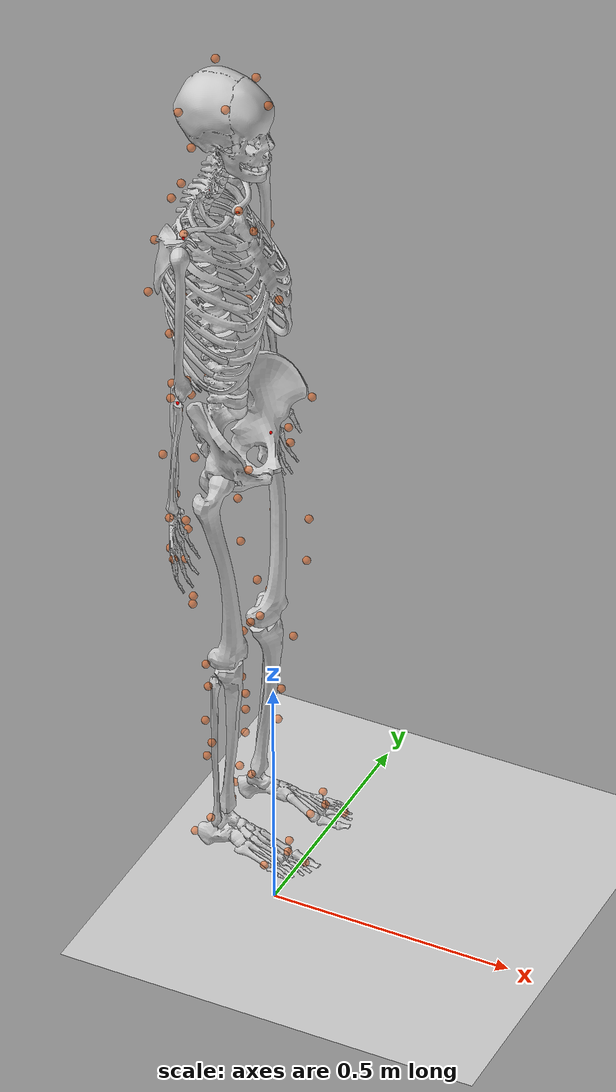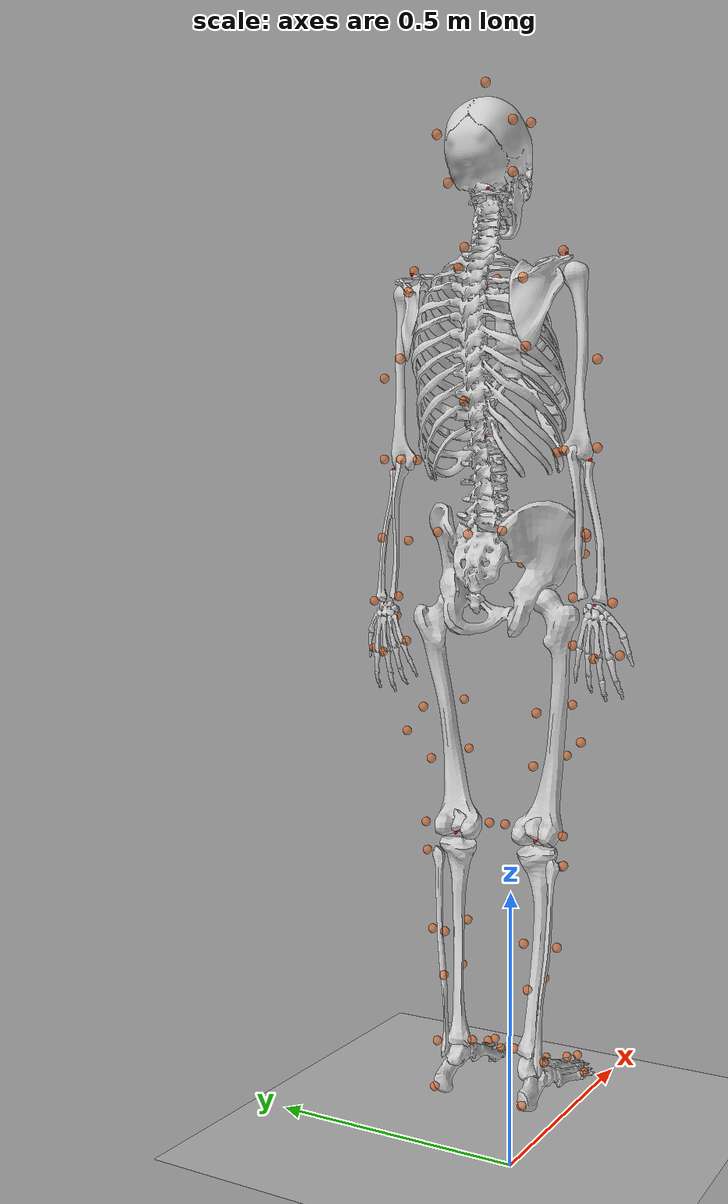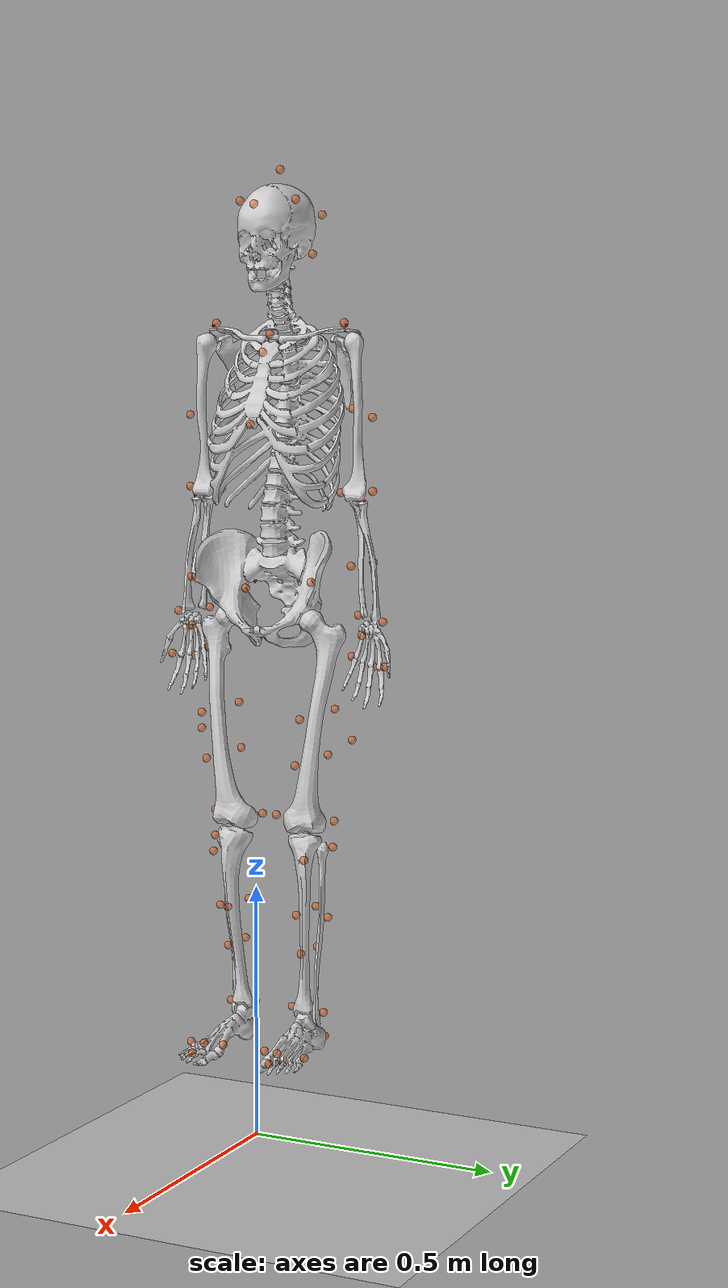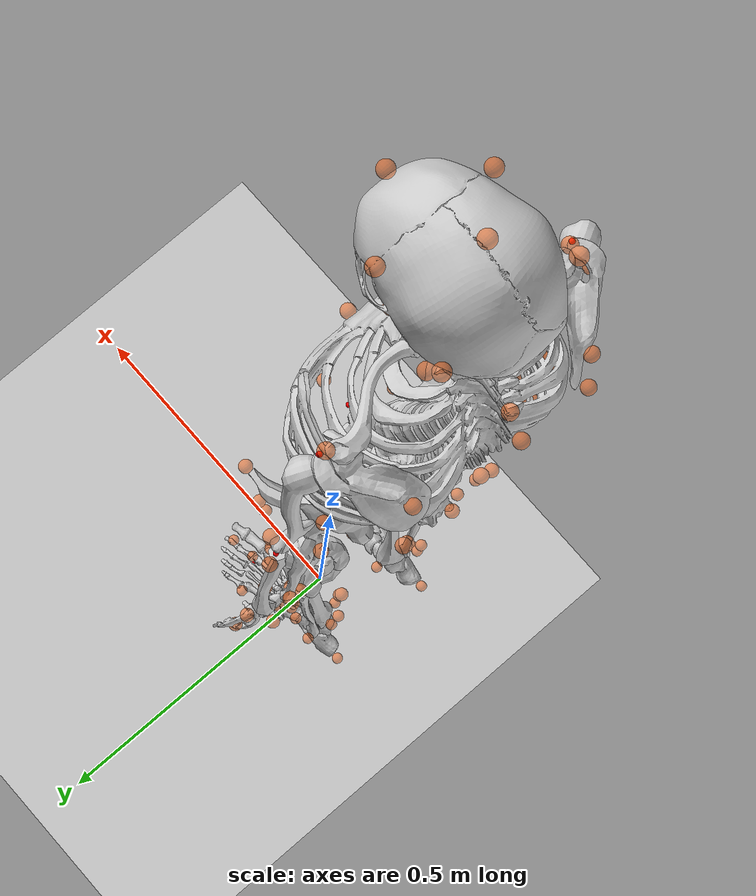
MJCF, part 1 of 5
<?xml version='1.0' encoding='utf-8'?>
<mujoco model="RKOB_Full_Base">
  <compiler angle="radian" boundmass="0.001" boundinertia="0.001" />
  <size njmax="1000" nconmax="400" nuser_jnt="1" />
  <visual>
    <global offwidth="800" offheight="800" />
    <headlight ambient="0.6 0.6 0.6" />
    <rgba haze="0.35 0.45 0.55 1" />
  </visual>
  <default>
    <joint stiffness="2" armature="0.1" damping="0.5" />
    <geom solref="0.005" margin="0" rgba="0.8 0.8 0.8 1" />
    <site size="0.001 0.005 0.005" rgba="0.5 0.5 0.5 0.5" />
    <tendon limited="false" width="0.001" rgba="0.95 0.3 0.3 1" />
    <default class="muscle">
      <general ctrllimited="true" ctrlrange="0 1" dyntype="muscle" dynprm="0.01 0.04 0 0 0 0 0 0 0 0" gaintype="muscle" biastype="muscle" gainprm="0.75 1.05 -1 200 0.5 1.6 1.5 1.3 1.2" biasprm="0.75 1.05 -1 200 0.5 1.6 1.5 1.3 1.2" />
    </default>
    <default class="motor">
      <general gainprm="500" />
    </default>
  </default>
  <asset>
    <texture type="skybox" colorspace="auto" builtin="gradient" rgb1="0.6 0.8 1" rgb2="0 0 0" width="512" height="3072" />
    <texture type="2d" colorspace="auto" name="texplane" builtin="checker" rgb1="0.5 0.6 0.7" rgb2="0.6 0.7 0.8" width="100" height="100" />
    <material name="MatPlane" texture="texplane" texuniform="true" reflectance="0.2" />
    <mesh name="pelvis" vertex="-0.128653 -0.0935561 0.000181241 -0.129142 -0.0906421 7.27427e-05 -0.132622 -0.0941232 0.00433295 -0.131177 -0.0946794 -0.00132974 -0.13168 -0.0887384 0.00303091 -0.131786 -0.0885189 -0.000848011 -0.133307 -0.0908225 -0.00374381 -0.133774 -0.0946433 -0.00219808 -0.134527 -0.0955771 0.0040856 -0.135507 -0.0798574 -0.00621488 -0.135767 -0.0810033 0.00627064 -0.137057 -0.0892157 -0.00541289 -0.135835 -0.0884655 0.00690537 -0.136821 -0.0708813 -0.00693846 -0.137322 -0.0698066 0.0145715 -0.137871 -0.076542 0.0100336 -0.13819 -0.0758685 0.0163917 -0.139038 -0.0935434 0.00218615 -0.140033 -0.0903664 0.00444774 -0.138665 -0.0833025 0.00960821 -0.140479 -0.0698407 -0.0161312 -0.142827 -0.0877009 -0.00623086 -0.140632 -0.0757157 0.0168556 -0.141373 -0.0893775 -0.00363947 -0.140322 -0.0916123 -0.000401294 -0.143226 -0.0605028 -0.00811321 -0.143039 -0.0690056 0.0159364 -0.142481 -0.0752553 0.0136855 -0.142872 -0.0691263 -0.0169704 -0.144933 -0.0670116 -0.0151276 -0.145189 -0.082225 -0.00661408 -0.145985 -0.0613806 -0.0109149 -0.146464 -0.0716415 0.0105856 -0.146779 -0.0616763 -0.00567388 -0.146489 -0.0703848 -0.0111654 -0.147252 -0.0648314 0.00732348 -0.147941 -0.0685976 -0.00646147 -0.148179 -0.0664196 -0.00315051 -0.148721 -0.0602109 -0.00828293 -0.148828 -0.0670908 0.0124989 -0.151302 -0.0633439 -0.0086949 -0.150883 -0.0628444 -0.00702118 -0.146229 -0.0634094 0.00200797 -0.141495 -0.0626725 0.00140274 -0.137288 -0.0634207 0.00524771 -0.13671 -0.0674317 0.00850696 -0.136388 -0.0713042 0.00327724 -0.137998 -0.0635998 0.00989985 -0.137625 -0.0626291 -0.00374257 -0.148121 -0.0672435 0.00188545 -0.146951 -0.0718297 0.00152644 -0.144783 -0.0770347 0.00422072 -0.143026 -0.0783917 0.00703592 -0.143524 -0.0823291 0.00722293 -0.145167 -0.0850389 0.00333282 -0.146331 -0.0839588 -0.000264657 -0.145516 -0.0803262 0.000366769 -0.14565 -0.0762449 -0.00272229 -0.143646 -0.0769508 -0.00600453 -0.142491 -0.0622516 0.0105745 -0.1399 -0.0633829 -0.0127743 -0.143831 -0.0840845 -0.00842874 -0.142055 -0.0649529 0.0143167 -0.140873 -0.0683696 0.0171525 -0.143298 -0.0889318 0.00167094 -0.140753 -0.0856698 -0.00766302 -0.140795 -0.0715786 -0.0135927 -0.137917 -0.08497 0.00787068 -0.141355 -0.0833717 0.00986018 -0.138071 -0.0761497 0.0137599 -0.140462 -0.0749919 -0.00807364 -0.136759 -0.0904636 0.00701467 -0.136878 -0.0868236 0.00648708 -0.135938 -0.0754938 0.00258267 -0.134867 -0.0796973 0.00230015 -0.136189 -0.0854207 -0.00577729 -0.134651 -0.0937058 0.00522766 -0.133011 -0.0969215 0.00103671 -0.130047 -0.0955633 0.000496108 -0.128625 -0.091703 0.00201437 -0.129905 -0.0943749 0.00314849 -0.129932 -0.0926387 -0.00124153 -0.132418 -0.091612 -0.00212905 -0.132225 -0.0959754 0.00364603 -0.133565 -0.0840772 0.00244553 -0.134701 -0.0849051 0.00539792 -0.132047 -0.0921962 0.00417614 -0.133529 -0.0839147 -0.00112104 -0.133602 -0.0881423 0.00623358 -0.134111 -0.0912809 0.00643531 -0.132911 -0.0880884 -0.00407913 -0.13403 -0.0842312 -0.00436617 -0.134344 -0.0923728 -0.00520968 -0.134684 -0.0886993 -0.0058573 -0.138174 -0.0949912 -0.00188005 -0.138014 -0.0918976 -0.00473813 -0.137599 -0.0933341 0.005888 -0.134674 -0.07945 -0.00160975 -0.136536 -0.0751844 -0.00582399 -0.135881 -0.0750588 -0.00152965 -0.138147 -0.0829802 -0.00778741 -0.14123 -0.0811672 -0.00882313 -0.136489 -0.0761341 0.00634075 -0.138644 -0.0873404 -0.00567527 -0.138587 -0.0886717 0.00636827 -0.13702 -0.066252 -0.00496052 -0.136504 -0.0667095 -0.00019655 -0.13642 -0.0707954 -0.00118619 -0.138182 -0.0688195 -0.0114776 -0.138069 -0.0651538 -0.00929664 -0.137873 -0.0684849 0.0167612 -0.137237 -0.0730157 0.0175477 -0.137369 -0.0684509 0.0120237 -0.138649 -0.0654274 0.0136935 -0.136945 -0.0728699 0.0141727 -0.136733 -0.0723977 0.0107295 -0.141435 -0.0768829 0.0103684 -0.140728 -0.0796874 0.00878382 -0.136456 -0.0718271 0.00717473 -0.140365 -0.0725999 0.0177995 -0.136929 -0.0960397 0.00260736 -0.140495 -0.086875 0.00846823 -0.139412 -0.066825 -0.0152614 -0.144742 -0.070458 -0.0150663 -0.14296 -0.0659002 -0.0165623 -0.143021 -0.0717662 0.0154377 -0.144943 -0.0875306 -0.00166104 -0.145348 -0.0861266 -0.0054169 -0.141586 -0.0610393 -0.0102044 -0.142318 -0.0613959 -0.00605872 -0.139075 -0.0620112 -0.00758848 -0.146086 -0.0605716 -0.00817678 -0.144989 -0.0667685 0.0143316 -0.146319 -0.0696846 0.0136737 -0.143908 -0.074783 0.008269 -0.146316 -0.065801 -0.0130828 -0.143837 -0.0633233 -0.013889 -0.143714 -0.0801561 -0.00622091 -0.146652 -0.0828763 -0.00403424 -0.1454 -0.0799066 -0.00308083 -0.149144 -0.060639 -0.00974593 -0.148403 -0.0637767 -0.0109587 -0.15043 -0.0618854 -0.0095804 -0.147186 -0.0690471 0.00639384 -0.145772 -0.0729371 0.00530776 -0.145981 -0.0625891 -0.00217442 -0.141484 -0.0621497 -0.0026739 -0.140958 -0.0727252 -0.0102854 -0.149822 -0.0662592 -0.00874222 -0.146893 -0.0642869 0.0115303 -0.149757 -0.0678162 0.0104863 -0.149248 -0.0643016 -0.00595274 -0.145275 -0.072788 -0.00688977 -0.146974 -0.0718593 -0.0026867 -0.149928 -0.0611407 -0.00730484 -0.141928 -0.0626689 0.00583589 -0.137167 -0.0631732 0.000718321 -0.136322 -0.0670918 0.00431562 -0.145885 -0.0762524 0.000926789 -0.144719 -0.0811013 0.00378507 -0.143461 -0.0866734 0.00672447 -0.139918 -0.078177 -0.00778021 -0.137924 -0.0802658 0.00914996 0.00627954 -0.0984368 -0.0140138 0.00406864 0.0144376 -0.12492 0.0033892 0.00938296 -0.133907 -0.0173719 -0.0977216 -0.0384963 -0.0199894 -0.019667 -0.106755 -0.0251914 -0.023851 -0.100199 -0.0245847 -0.0942021 -0.0254165 -0.0261586 -0.0838854 -0.0711455 -0.0311035 -0.0503381 -0.102193 -0.0366485 -0.0589574 -0.078451 -0.0364701 -0.0864679 -0.0616935 -0.0367858 -0.0749136 -0.0733105 -0.035224 -0.0378254 -0.0812702 -0.0418352 -0.0458039 -0.10748 -0.0406618 -0.0611398 -0.0709399 -0.0436009 0.00488683 -0.104595 -0.0411804 -0.00377686 -0.101715 -0.03976 -0.0489703 -0.0952796 -0.0474058 -0.0698764 -0.0546427 -0.0511172 0.0348063 -0.113098 -0.0627693 -0.0554207 -0.0671497 -0.0662513 -0.0454466 -0.0851472 -0.0667639 -0.0894542 -0.0617379 -0.06561 -0.00287556 -0.0665972 -0.0663584 -0.0202424 -0.0999127 -0.0707689 -0.0611698 -0.0645135 -0.0727877 -0.010417 -0.0614699 -0.0738947 -0.0806219 -0.0716015 -0.075947 -0.00314452 -0.0616807 -0.0749927 0.00755461 -0.0668671 -0.0828561 -0.0199708 -0.0664354 -0.0838141 0.06905 -0.0828107 -0.0847833 -0.0854861 -0.0840357 -0.0898655 -0.000888457 -0.0532634 -0.0898902 -0.00945266 -0.0757257 -0.089455 -0.0918039 -0.0541291 -0.0915859 -0.0334686 -0.0864737 -0.0930286 0.0656693 -0.0680136 -0.104492 -0.0680784 -0.0665952 -0.105767 0.0333912 -0.0542507 -0.106256 0.0251524 -0.0533219 -0.107199 -0.000216387 -0.0488691 -0.106978 -0.0598915 -0.0478555 -0.110029 -0.00563701 -0.0617625 -0.110664 -0.0587719 -0.0512256 -0.110053 0.0134021 -0.0509521 -0.112144 0.00651205 -0.0484126 -0.116366 0.0470008 -0.0538104 -0.132339 0.0308277 -0.04015 -0.140476 0.051242 -0.0649576 -0.144977 0.0431638 -0.0580418 -0.144348 0.0337545 -0.0442004 -0.141447 0.0311395 -0.0502314 -0.136209 0.0248511 -0.0535079 -0.127119 0.0192408 -0.0499999 -0.131894 0.0171226 -0.0547219 -0.124557 0.00914514 -0.0612161 -0.121349 0.0220025 -0.0684676 -0.113342 0.0349707 -0.0716686 -0.103283 0.047773 -0.0742614 -0.0961044 0.0620085 -0.0813125 -0.0899947 0.0753412 -0.0921136 -0.0828275 0.0855583 -0.106244 -0.068044 0.0903711 -0.11911 -0.0493741 0.0831745 -0.123819 -0.0380809 0.068137 -0.124642 -0.0317446 0.0503487 -0.124886 -0.0277629 0.0329907 -0.121992 -0.0276875 0.0185284 -0.116935 -0.0138057 0.0159299 -0.120663 -0.00826147 0.00750895 -0.120852 -0.00370686 9.8692e-05 -0.12241 -0.00219299 -0.00470754 -0.126783 -0.00711767 0.00204764 -0.128231 -0.01205 0.0118129 -0.127343 -0.0141671 0.0281228 -0.133211 -0.00834909 0.0328274 -0.138042 -0.00293335 0.0376823 -0.138007 -0.0012897 0.0398669 -0.131534 -0.00669236 0.0361852 -0.127788 -0.0116215 0.053066 -0.133854 -0.0278414 0.0612627 -0.141402 -0.0486085 0.0650989 -0.139838 -0.0611813 0.0652159 -0.124541 -0.0699754 0.0601914 -0.109982 -0.0776604 0.0510955 -0.0976202 -0.0835081 0.0388293 -0.0879749 -0.0899797 0.0260607 -0.0817377 -0.0982835 0.0148462 -0.0770872 -0.0887737 0.0142355 -0.0812697 -0.0802455 0.013254 -0.0856525 -0.0739191 4.33119e-05 -0.0898387 -0.0675619 0.00984686 -0.0979572 -0.0616468 0.0190944 -0.106565 -0.054984 0.0260439 -0.11619 -0.0450766 0.029789 -0.125469 -0.0430078 0.0386542 -0.131119 -0.0371823 0.0134841 -0.122012 -0.0396375 0.00337122 -0.118679 -0.049563 -0.0015426 -0.11446 -0.0578565 -0.00727936 -0.107849 -0.0547546 -0.020744 -0.10921 -0.0599848 -0.0283757 -0.106287 -0.0687336 -0.0335442 -0.102803 -0.0779006 -0.0429791 -0.102863 -0.086923 -0.0486407 -0.0979695 -0.0921195 -0.0578508 -0.0930958 -0.0868791 -0.0609737 -0.0946098 -0.0847116 -0.0592824 -0.0884821 -0.0817022 -0.066689 -0.0781674 -0.0802509 -0.057546 -0.0816433 -0.0798599 -0.0515265 -0.0928671 -0.0720396 -0.0459056 -0.0976292 -0.0593916 -0.0437623 -0.102169 -0.0621751 -0.0445868 -0.109023 -0.0549026 -0.0327031 -0.108503 -0.048015 -0.0254958 -0.110267 -0.0369198 -0.0227312 -0.113918 -0.0272843 -0.0191498 -0.117273 -0.0189537 -0.0154319 -0.120141 -0.0116538 -0.0117012 -0.119626 -0.019023 -0.0126792 -0.111363 -0.0216353 -0.00145012 -0.112767 -0.0257615 -0.00826657 -0.108297 -0.0161498 -0.00874897 -0.123405 -0.0217779 -0.00194405 -0.122533 -0.0167706 -0.0228914 -0.111488 -0.0164512 -0.0316928 -0.106802 -0.021357 -0.032513 -0.112666 -0.0343941 0.0224978 -0.126309 -0.0544092 0.0369121 -0.120489 -0.0625133 0.0314132 -0.109744 -0.0679723 0.0224974 -0.0999517 -0.0631733 -0.00399997 -0.102309 -0.0753906 -0.011066 -0.0889597 -0.0397904 0.0466807 -0.137506 -0.0549144 0.0290299 -0.10836 -0.0371029 0.0147313 -0.112015 -0.0425613 0.0226376 -0.112968 -0.047455 0.0133971 -0.106373 -0.0568328 0.013513 -0.0992913 -0.0615077 0.00594443 -0.0892084 -0.0570359 -0.00308556 -0.0870737 -0.0513611 -0.0133969 -0.0849863 -0.0555086 -0.0140944 -0.0765361 -0.0535703 -0.027109 -0.0684399 -0.0471244 -0.0368599 -0.065825 -0.040483 -0.0461393 -0.0619083 -0.0266077 -0.0555135 -0.0633307 -0.0201149 -0.0695632 -0.0635441 -0.0160261 -0.0753136 -0.0558504 -0.0114463 -0.0803621 -0.0472862 -0.00596703 -0.0846349 -0.0390715 -0.000226732 -0.0872115 -0.0311525 -0.000286306 -0.0870657 -0.0197071 -0.00483045 -0.0861957 -0.0277609 -0.00956613 -0.0828935 -0.035863 -0.0202643 -0.0782729 -0.0406531 -0.0275114 -0.0811709 -0.0402039 -0.0315445 -0.0811206 -0.0501887 -0.0307286 -0.0743218 -0.0457545 -0.0240193 -0.0709606 -0.0472639 -0.0287574 -0.0630234 -0.0529055 -0.0217965 -0.0608002 -0.0700464 -0.0252393 -0.0604431 -0.0839976 -0.0248897 -0.0552155 -0.0800458 -0.0548005 -0.0410141 -0.0626003 -0.0621435 -0.0467764 -0.061001 -0.0692275 -0.0530289 -0.060054 -0.0698126 -0.0682195 -0.0573203 -0.063611 -0.077594 -0.0556294 -0.0708062 -0.0826646 -0.0555911 -0.0773119 -0.0736524 -0.0564455 -0.0909899 -0.0698504 -0.0548232 -0.0985536 -0.0728464 -0.0535875 -0.0904496 -0.0568424 -0.0556217 -0.0965592 -0.0503231 -0.0557142 -0.101549 -0.0477049 -0.058204 -0.0974317 -0.039099 -0.0621769 -0.0839277 -0.0361866 -0.0633418 -0.0912907 -0.0300451 -0.0650854 -0.0690919 -0.0373904 -0.0639681 -0.0701298 0.0153915 -0.0813855 -0.0798183 0.0329591 -0.0745774 -0.0766271 0.0248042 -0.0727273 -0.0862329 0.0328597 -0.065699 -0.0840863 0.0243352 -0.0646288 -0.0883063 0.0408146 -0.0670336 -0.0816086 0.0411512 -0.0759629 -0.0783173 0.0495293 -0.0883103 -0.0712086 0.0389771 -0.0956407 -0.0642366 0.0464147 -0.105429 -0.0641011 0.0570283 -0.10796 -0.0716783 0.0704488 -0.0997553 -0.073134 0.0816203 -0.099764 -0.0859607 0.0897337 -0.0873275 -0.102135 0.0891846 -0.0766098 -0.111511 0.0823307 -0.0669636 -0.121636 0.0745561 -0.0613946 -0.122447 0.0636462 -0.052711 -0.128753 0.056755 -0.0478048 -0.131783 0.0494667 -0.0434687 -0.123764 0.0401362 -0.0445461 -0.141768 0.0506014 -0.0453142 -0.13829 0.0595841 -0.0513311 -0.124324 0.0717303 -0.067967 -0.120319 0.0636726 -0.0690711 -0.113467 0.0776389 -0.0730387 -0.0633758 0.0688058 -0.109221 -0.0553618 0.0535887 -0.114921 -0.0565301 0.043623 -0.111823 -0.063868 0.0376682 -0.103229 -0.0364573 0.0411199 -0.121752 -0.117323 0.055136 -0.0695886 -0.125937 0.0321873 -0.0694084 -0.10829 0.0141791 -0.0727891 -0.12443 0.035 -0.0425586 -0.115556 0.0564503 -0.0555702 -0.110672 0.0482202 -0.0577385 -0.106556 0.00329631 -0.0710042 -0.10162 -0.00813056 -0.0571709 -0.0934488 -0.00885882 -0.0606567 -0.118811 -0.000374725 -0.0586513 -0.0918911 0.0155466 -0.0565009 -0.111576 -0.0792983 -0.0672147 -0.116275 -0.0919934 -0.0654417 -0.104875 -0.102612 -0.0551627 -0.0909619 -0.101532 -0.0520732 -0.0797342 -0.105533 -0.0558142 -0.0824363 -0.101896 -0.0681937 -0.0893466 -0.102694 -0.0792057 -0.102612 -0.0996209 -0.0802186 -0.103614 -0.113545 -0.078306 -0.110759 -0.124764 -0.062038 -0.0992843 -0.125175 -0.0439634 -0.0921078 -0.117989 -0.0450216 -0.0845323 -0.112402 -0.045698 -0.0778989 -0.113439 -0.0507445 -0.0805058 -0.120115 -0.0541616 -0.0862343 -0.127328 -0.055608 -0.0803796 -0.13313 -0.0453036 -0.0713255 -0.132532 -0.0340115 -0.0733716 -0.126749 -0.0319179 -0.0725094 -0.120096 -0.0340387 -0.0698746 -0.11513 -0.0377771 -0.0662824 -0.115449 -0.0432143 -0.0654899 -0.12138 -0.044357 -0.0572409 -0.127235 -0.037531 -0.0471223 -0.13111 -0.0295918 -0.0505193 -0.129704 -0.0244024 -0.0535485 -0.124084 -0.022821 -0.0542896 -0.118156 -0.0256559 -0.0532663 -0.114394 -0.0301513 -0.0505363 -0.114614 -0.0349745 -0.0408393 -0.117181 -0.0314334 -0.0309869 -0.117221 -0.0245485 -0.0290644 -0.121704 -0.0196893 -0.031222 -0.121463 -0.0138336 -0.0356079 -0.11566 -0.0131405 -0.0374031 -0.110392 -0.017913 -0.0388762 -0.107245 -0.0240477 -0.0270672 -0.108668 -0.00840118 -0.018079 -0.100044 -0.0065414 -0.0115566 -0.107571 -0.00942496 -0.00895468 -0.111784 -0.0175251 -0.022217 -0.112866 -0.0239488 -0.0273249 -0.108406 -0.0294424 -0.0911632 -0.12184 -0.0655003 -0.109518 -0.0822705 -0.0770666 -0.101694 -0.0518498 -0.0645812 -0.101143 -0.0727552 -0.0771254 -0.0966229 -0.0636784 -0.0806216 -0.0804068 -0.0300424 -0.0948474 -0.0993709 -0.000513179 -0.049465 -0.0689171 -0.0782919 -0.0677703 -0.0642287 -0.0757947 -0.0611253 -0.0541138 -0.0812909 -0.0617847 -0.0479047 -0.0744036 -0.0641249 -0.0591881 -0.0427389 -0.0936528 -0.0584416 -0.0448302 -0.0847874 -0.0452609 -0.0131155 -0.0926214 -0.0392301 -0.0240386 -0.0906178 -0.0330962 -0.0338406 -0.0907439 -0.0278238 -0.0877607 -0.0555495 -0.00751336 -0.102486 -0.0288635 0.00476459 -0.00181352 -0.130801 0.0109602 0.0075052 -0.133687 0.00213987 -0.091771 -0.0336249 -0.00539088 -0.0887311 -0.0414274 -0.0116933 -0.0845933 -0.0496751 -0.0167486 -0.080384 -0.0585569 -0.0197363 -0.0752359 -0.0673498 -0.0215202 -0.0659704 -0.0744014 -0.0286529 -0.0403893 -0.0931341 -0.0238471 -0.0338001 -0.0974091 -0.137564 0.046964 -0.0664666 -0.140287 0.0386684 -0.0618269 -0.141715 0.0426729 -0.0412288 -0.132522 0.0429936 -0.0407086 -0.0697798 0.0306337 -0.0939309 -0.0624702 0.0296122 -0.101823 -0.0515408 0.0214885 -0.107545 -0.0317776 -0.0142266 -0.101948 -0.0294317 -0.0221946 -0.0986529 -0.030894 0.00507592 -0.11071 -0.0293423 -0.0298437 -0.0954109 -0.0276375 -0.0272682 -0.0973185 0.00789532 -0.101689 -0.0235096 0.00896092 -0.0916369 -0.0247385 0.00608024 -0.0896024 -0.0133612 -0.00664293 -0.0923134 -0.00694973 -0.00172933 -0.101607 -0.010075 -0.00111036 -0.105595 -0.0193781 0.00124348 0.0237395 -0.125963 -0.00646285 0.0202431 -0.12425 0.0113616 0.0103019 -0.125109 0.00906152 0.0254803 -0.127824 -0.0015554 0.0110647 -0.123697 0.00337143 0.00336443 -0.124961 0.000514366 0.0202729 -0.134521 0.00747073 0.0231706 -0.135479 -0.00155476 0.00557228 -0.130976 -0.00612142 0.0165741 -0.130893 -0.00850089 -0.0944102 -0.041886 3.71066e-05 -0.0991185 -0.0337601 -0.014516 -0.107409 -0.0253966 -0.021844 -0.103495 -0.0323689 -0.0292298 -0.0981753 -0.0329238 -0.027891 -0.0929873 -0.0379303 -0.0291127 -0.086943 -0.0440381 -0.0222313 -0.090928 -0.047712 -0.0146299 -0.0901275 -0.0506957 -0.0260792 -0.0163546 -0.104071 -0.0256148 -0.0874373 -0.0334721 -0.0135873 -0.0887227 -0.0249587 -0.0170227 -0.0844285 -0.033236 -0.0206537 -0.0968026 -0.0144091 -0.0105518 -0.0897897 -0.0152707 -0.0321 -0.101486 -0.0233004 -0.0289098 -0.104416 -0.0154744 -0.0326353 -0.103337 -0.0299976 -0.0204193 -0.0867518 -0.0597319 -0.0349512 -0.0799978 -0.0759365 -0.0302796 -0.07232 -0.08128 -0.0404788 -0.0827429 -0.068725 -0.0238799 -0.0427676 -0.108842 -0.0202972 -0.0399941 -0.101585 -0.026623 -0.0457295 -0.0965877 -0.0275932 -0.0521916 -0.0900378 -0.0321565 -0.0375003 -0.110171 -0.0296569 -0.0636288 -0.0860168 -0.0346059 -0.0689914 -0.0750638 -0.0393189 -0.0677638 -0.0682398 -0.0475729 -0.0518198 -0.0762412 -0.0475997 -0.0468999 -0.0853525 -0.0484467 -0.0571391 -0.0679873 -0.0381181 -0.0519712 -0.0878899 -0.030375 -0.0579606 -0.0937633 -0.0461686 -0.0822452 -0.0586918 -0.0474649 -0.0818553 -0.0641796 -0.040651 -0.0754061 -0.0683574 -0.0441555 -0.0249077 -0.0829027 -0.0482528 -0.0253465 -0.0750913 -0.0407243 -0.0359818 -0.0722904 -0.0332089 -0.0463277 -0.0682414 -0.0479201 -0.0382962 -0.108908 -0.0401316 -0.0310549 -0.110095 -0.0481329 -0.0659823 -0.0645814 -0.053464 0.00520791 -0.0975912 -0.0498235 -0.00329913 -0.0952639 -0.041392 -0.0599936 -0.0550367 -0.0480724 -0.0506682 -0.0585886 -0.0376071 -0.076178 -0.0543281 -0.0353573 -0.0674676 -0.0507809 -0.0550579 -0.0571928 -0.0576706 -0.0622447 -0.0627875 -0.0578087 -0.0562786 -0.0731581 -0.0557577 -0.0531327 -0.0818968 -0.0577703 -0.0475497 0.0296427 -0.113298 -0.041247 0.0331233 -0.117606 -0.0595061 -0.0494715 -0.0765835 -0.0582913 -0.0653235 -0.062164 -0.0679143 -0.0681904 -0.0617152 -0.0752553 -0.0640152 -0.0710929 -0.0724964 -0.0564045 -0.0747663 -0.0693891 -0.0492286 -0.0799926 -0.0762461 -0.0499796 -0.0862477 -0.0693432 -0.0450687 -0.091057 -0.0723145 -0.0953268 -0.0591283 -0.07884 -0.0949017 -0.0694457 -0.0659376 -0.084316 -0.0668771 -0.0610814 -0.0818625 -0.0610472 -0.0734924 -0.09147 -0.0733057 -0.0725321 -0.0855967 -0.073398 -0.0686769 0.00803564 -0.0697315 -0.061396 -0.00288397 -0.0773091 -0.0658948 0.00693714 -0.079264 -0.0749805 0.00172711 -0.0646461 -0.0647649 -0.0136509 -0.100596 -0.0602303 -0.0167001 -0.105731 -0.0711624 -0.0211347 -0.0963166 -0.0696639 -0.0120655 -0.0948686 -0.0640302 -0.0242191 -0.103276 -0.070755 -0.0282241 -0.0995592 -0.073626 -0.0717493 -0.0686345 -0.0819479 -0.00228449 -0.058778 -0.0671209 -0.0211797 -0.0657663 -0.0593345 -0.0160417 -0.0683082 -0.0814381 -0.0801374 -0.0793425 -0.0789837 -0.0756972 -0.0745533 -0.0831579 0.0047783 -0.0621946 -0.0726403 0.0164295 -0.0710265 -0.0818616 0.0135625 -0.0648822 -0.0816948 -0.00990386 -0.0568136 -0.0867474 -0.0121377 -0.0644525 -0.0757424 -0.0284313 -0.06522 -0.0787828 0.0699367 -0.0902947 -0.0821316 0.0799981 -0.0888664 -0.0838197 0.0613322 -0.0793804 -0.0782428 0.0598395 -0.08969 -0.0884897 0.0759653 -0.0776739 -0.0879511 -0.0720837 -0.0898355 -0.0856171 -0.0696379 -0.0844747 -0.0884454 -0.0926926 -0.078723 -0.0995519 -0.0887075 -0.0799389 -0.0954584 -0.0792872 -0.082615 -0.0938985 -0.0692381 -0.0880442 -0.0901836 -0.00848353 -0.0529515 -0.0822837 -0.0099791 -0.0834897 -0.0846482 -0.0214517 -0.0839993 -0.0892494 0.00269637 -0.0802198 -0.0810998 0.0013948 -0.084812 -0.0968042 -0.00567614 -0.0699865 -0.0977872 0.00387912 -0.0755697 -0.0790296 -0.0869536 -0.0555568 -0.0854765 -0.0780496 -0.0556381 -0.0768545 -0.100408 -0.0573092 -0.0949321 -0.0810036 -0.0544453 -0.105959 -0.0806795 -0.0574091 -0.0937158 -0.0308127 -0.0744735 -0.0880664 -0.0203151 -0.0754755 -0.0776012 -0.0217105 -0.0905165 -0.0798026 -0.037165 -0.0991169 -0.0898821 -0.0426051 -0.0932602 -0.0951607 -0.0528283 -0.0866004 -0.0978696 -0.0465049 -0.0791299 -0.0987701 -0.0418614 -0.0702982 -0.0933858 0.0854144 -0.072441 -0.102942 0.0769147 -0.0637346 -0.113464 0.0697613 -0.0585357 -0.106038 0.060647 -0.0612329 -0.101034 0.0500157 -0.0625629 -0.0897653 0.0515311 -0.0670283 -0.0827069 0.0508587 -0.0770851 -0.0991211 -0.0577622 -0.0720146 -0.103927 -0.0600025 -0.0596233 -0.105817 -0.0717943 -0.0572437 -0.108538 -0.0644562 -0.0544496 -0.0969362 0.0320948 -0.0613367 -0.098356 0.0400446 -0.0621284 -0.107493 0.0404856 -0.0563928 -0.115406 0.042225 -0.0512109 -0.115686 0.0309326 -0.0472111 -0.120709 0.0243838 -0.0482642 -0.115102 0.0184788 -0.0520344 -0.101935 0.0157443 -0.0506009 -0.100328 0.00712313 -0.0478358 -0.118726 0.00102788 -0.0515306 -0.11004 -0.00582799 -0.048948 -0.099737 -0.00751635 -0.0501393 -0.102455 -0.05563 -0.0508441 -0.106119 -0.0543727 -0.0543539 -0.103083 -0.065605 -0.0507336 -0.096935 -0.0620092 -0.0527665 -0.110781 -0.00751974 -0.0554604 -0.104016 -0.00525341 -0.0652991 -0.113875 0.00160303 -0.0652674 -0.121468 0.012859 -0.0499132 -0.126181 0.00892748 -0.0536704 -0.120881 0.051602 -0.0503541 -0.12273 0.0458482 -0.046507 -0.132649 0.0371607 -0.0391419 -0.140745 0.035937 -0.0393203 -0.127192 0.0286547 -0.0442352 -0.137651 0.0277105 -0.0415693 -0.132379 0.0239705 -0.0467795 -0.142101 0.0566454 -0.0595334 -0.13431 0.064165 -0.0642252 -0.147448 0.0476415 -0.052608 -0.132334 0.0579078 -0.0698162 -0.129643 0.050346 -0.0701465 -0.134002 0.029159 -0.0623692 -0.144905 0.0371375 -0.0519591 -0.14672 0.0388454 -0.0468043 -0.129116 0.0191894 -0.0623367 -0.1176 0.0118589 -0.0676246 -0.110735 0.0246569 -0.0728686 -0.101408 0.036736 -0.0754394 -0.0999014 0.0257746 -0.0771816 -0.129158 0.0418581 -0.0703845 -0.11529 0.0450871 -0.0704204 -0.0934276 0.0502773 -0.0807331 -0.0916243 0.0381456 -0.0811357 -0.105991 0.0588142 -0.074039 -0.087121 0.0638877 -0.0904576 -0.0851112 0.0517008 -0.0888351 -0.109585 0.0688821 -0.0739396 -0.0996993 0.072887 -0.0819711 -0.0802451 0.0750187 -0.103199 -0.0782478 0.0633957 -0.1001 -0.103757 0.0825193 -0.081626 -0.0942315 0.085581 -0.0935346 -0.0708468 0.0818041 -0.118185 -0.0704243 0.0716058 -0.114112 -0.0928451 0.0936635 -0.0904855 -0.081475 0.0945726 -0.105528 -0.0545705 0.0821182 -0.130369 -0.0613916 0.0749749 -0.131209 -0.0755531 0.0911783 -0.101054 -0.0630398 0.0887378 -0.113453 -0.0358518 0.0749405 -0.130664 -0.0412666 0.0723138 -0.13767 -0.0626987 0.079908 -0.110404 -0.0505325 0.0753055 -0.11893 -0.0264598 0.0588556 -0.127691 -0.0230943 0.0644353 -0.134 -0.0533169 0.0648764 -0.116935 -0.0423528 0.0586728 -0.122144 -0.0220539 0.0409142 -0.125559 -0.0160015 0.0482751 -0.128304 -0.0458559 0.0483315 -0.11961 -0.0202915 0.024488 -0.121454 -0.0134749 0.030631 -0.125249 -0.034005 0.0259822 -0.117558 -0.0213908 0.0110299 -0.116253 -0.0150963 0.00362104 -0.117049 -0.00984672 -0.00306369 -0.119144 -0.00711692 -0.00807742 -0.123343 -0.0120553 -0.00291776 -0.125948 -0.0173686 0.00548993 -0.124533 -0.0244176 0.0148107 -0.123434 -0.0195925 0.02234 -0.128001 -0.0309622 0.0302851 -0.131684 -0.0267815 0.0366421 -0.138084 -0.0212641 0.0428839 -0.144025 -0.0152831 0.0500021 -0.141077 -0.0352322 0.0540479 -0.144599 -0.051576 0.0564408 -0.133025 -0.0533846 0.0470021 -0.12637 -0.0619293 0.0544479 -0.118998 -0.0625987 0.0432215 -0.113803 -0.0702696 0.0482474 -0.106163 -0.0697453 0.0355804 -0.102881 -0.0767071 0.0380586 -0.0956141 -0.0743621 0.0247587 -0.0932759 -0.081379 0.0258396 -0.0868786 -0.0734412 0.0118947 -0.0915206 -0.0683012 -0.00165432 -0.0960718 -0.0619844 0.00701843 -0.104371 -0.0551947 0.0145705 -0.11281 -0.0561366 0.00322087 -0.110183 -0.0466953 0.0198628 -0.12116 -0.0480332 0.00916881 -0.117589 -0.0284216 0.00611308 -0.120835 -0.0317878 -0.0032663 -0.11929 -0.0347539 -0.013275 -0.117737 -0.042165 -0.00707618 -0.116359 -0.0448027 -0.0169646 -0.113974 -0.0517093 -0.0116326 -0.111821 -0.066356 -0.0383085 -0.107034 -0.0744131 -0.0477658 -0.103299 -0.0822605 -0.0530796 -0.0988313 -0.0473527 -0.0446557 -0.0951424 -0.0288223 -0.0284867 -0.11316 -0.0205639 -0.0231494 -0.116381 -0.0251093 -0.0103943 -0.120768 -0.0151791 -0.016369 -0.115715 -0.0152241 -0.00719625 -0.115425 -0.0328402 -0.00507356 -0.105971 -0.0202016 -0.0275313 -0.102097 -0.0599863 0.0216385 -0.100638 -0.0676235 0.0224742 -0.0925129 -0.0648338 0.014283 -0.0910317 -0.0612141 -0.0313696 -0.0653939 -0.0341965 -0.0550024 -0.0578717 -0.0270127 -0.0498715 -0.0752722 -0.0221263 -0.0635477 -0.0578172 -0.0174826 -0.0703322 -0.0509634 -0.0134754 -0.0769304 -0.0434133 -0.0284677 -0.0462846 -0.0861869 -0.02315 -0.0716171 -0.0793564 -0.0765684 -0.0442488 -0.0620542 -0.0835391 -0.0507898 -0.058723 -0.0765558 -0.0592335 -0.0585756 -0.0838875 -0.065068 -0.0568739 -0.0585191 -0.0857927 -0.0572635 -0.0906238 -0.0435907 -0.059974 -0.0736928 0.0236444 -0.0832598 -0.07591 0.0318819 -0.0847792 -0.0774683 0.0401951 -0.0865203 -0.0950041 0.024198 -0.0596181 -0.0717633 0.0482177 -0.0976751 -0.0715628 0.0589963 -0.0993163 -0.0568033 0.0361087 -0.109438 -0.131307 0.0673211 -0.056514 -0.048775 0.0393561 -0.116016 -0.113989 0.0367688 -0.0474221 -0.0906015 0.00693559 -0.0544086 -0.114377 -0.0952255 -0.0750359 -0.105675 -0.0914679 -0.0569962 -0.115443 -0.11035 -0.071584 -0.116378 -0.105619 -0.0606667 -0.110884 -0.117496 -0.0525801 -0.100073 -0.111762 -0.0505388 -0.0889942 -0.108168 -0.0492474 -0.0799348 -0.110311 -0.0538249 -0.0840202 -0.116104 -0.0603595 -0.0843303 -0.110004 -0.0659016 -0.091018 -0.113904 -0.0755728 -0.100725 -0.12779 -0.0691205 -0.0920551 -0.134618 -0.0557201 -0.0993839 -0.133747 -0.0494693 -0.0841598 -0.135156 -0.0393862 -0.0851494 -0.127311 -0.0377205 -0.0823594 -0.120024 -0.0391786 -0.0779201 -0.114486 -0.0417191 -0.0732828 -0.115144 -0.0469219 -0.0736263 -0.121347 -0.048962 -0.0773764 -0.127404 -0.0475396 -0.0671591 -0.127252 -0.0420237 -0.0686597 -0.132416 -0.039029 -0.057673 -0.132956 -0.0345259 -0.0607204 -0.131961 -0.0289845 -0.0632226 -0.125993 -0.026978 -0.0632657 -0.11944 -0.0294627 -0.0614021 -0.115152 -0.0340181 -0.0582554 -0.115011 -0.0393725 -0.0569612 -0.121008 -0.0398275 -0.0484218 -0.120054 -0.0355768 -0.0474826 -0.12586 -0.0331771 -0.0393144 -0.121699 -0.0279127 -0.0383472 -0.126134 -0.0240921 -0.0410664 -0.125751 -0.0193195 -0.0443984 -0.120533 -0.0184572 -0.0457234 -0.115212 -0.0216976 -0.0457967 -0.111909 -0.0265132 -0.0436767 -0.112915 -0.0309384 -0.0379263 -0.108106 -0.0299937 -0.0338658 -0.112938 -0.0292376 -0.0184539 -0.117638 -0.0175867 -0.0209636 -0.115165 -0.0102532 -0.0560297 -0.0741888 -0.0619027 -0.0337922 -0.022472 -0.0958421 0.00349651 -0.0881788 -0.0248926 -0.0253377 -0.0284464 -0.0980235 -0.0380444 -0.0132526 -0.0984925 -0.0125321 -0.109839 0.00485345 -0.0123423 -0.109689 0.00147799 -0.0173093 -0.110867 0.00106721 -0.0223861 -0.104982 0.000543756 -0.0208869 -0.0994036 -0.00189853 -0.0211656 -0.0991632 -0.00449295 -0.0181521 -0.0947108 -0.00453479 -0.0143811 -0.0911784 -0.00470943 -0.00988054 -0.0884358 -0.00497697 -0.00421465 -0.0870268 -0.00171785 -0.00986593 -0.0882582 -0.00170368 -0.00423143 -0.0872933 -0.00521464 -0.00477693 -0.094914 -0.00714715 -0.0137707 -0.0919427 -0.00721494 -0.0133804 -0.102526 -0.00768537 -0.0181041 -0.094952 -0.00183451 -0.0179397 -0.095179 0.000760533 -0.0207527 -0.09963 0.000581745 -0.0144015 -0.0912451 -0.00176957 -0.0097765 -0.0887344 0.00153601 -0.0143216 -0.0916127 0.00109465 -0.0176209 -0.0951562 -0.00692341 -0.0213898 -0.09959 -0.0071631 -0.0186994 -0.111183 -0.00863712 -0.0226355 -0.104601 -0.00456693 -0.02209 -0.104371 -0.00198829 -0.0174512 -0.110899 -0.00545586 -0.0169539 -0.11037 -0.00217569 -0.00784192 -0.107329 -0.00631231 -0.0202559 -0.100403 0.00279186 -0.0122771 -0.109604 -0.00222825 -0.00764119 -0.107264 0.00174405 -0.00364926 -0.104351 0.00177171 -0.000509571 -0.100671 -0.00595661 -0.00772048 -0.107377 -0.00225367 -0.00904892 -0.0982441 -0.00708001 -0.000433844 -0.100568 -0.00213392 0.00159302 -0.095774 -0.00202315 0.000726963 -0.0903231 -0.00186674 0.000680553 -0.0903814 -0.00529796 0.00154007 -0.0958261 -0.00554592 0.00165618 -0.0959312 0.00149894 0.000839015 -0.0905013 0.00157729 -0.000444737 -0.100744 0.00167784 -0.00401316 -0.103761 0.00539968 -0.00793385 -0.106582 0.00553097 -0.0130687 -0.102729 0.00369604 -0.0183725 -0.111056 0.00422861 -0.00887496 -0.0985511 0.00308308 -0.00459136 -0.0951843 0.00323934 -0.000947078 -0.100802 0.00524108 -0.00410719 -0.0874475 0.00180666 -0.021191 -0.109398 0.000704146 -0.0206966 -0.108585 -0.00210115 -0.023212 -0.111771 0.00370247 -0.00958129 -0.0897028 -0.00768249 -0.00396141 -0.0882833 -0.00762249 -0.0236811 -0.106385 0.003039 -0.013791 -0.092828 0.00336003 -0.0172983 -0.0959725 0.00289521 -0.0241223 -0.105484 -0.00707811 -0.0233537 -0.111554 -0.00800112 -0.0213221 -0.109268 -0.00494861 -0.0125355 -0.109752 -0.00595052 -0.0129716 -0.109913 -0.00927969 -0.00369921 -0.104372 -0.00222072 -0.00378885 -0.104372 -0.00625745 -0.0043047 -0.103818 -0.00992109 -0.0083954 -0.10672 -0.0102498 -0.00105911 -0.10058 -0.00944532 0.00148684 -0.0959969 -0.0085515 0.000243913 -0.091188 -0.00798115 0.000536326 -0.091267 0.00443724 -0.00373164 -0.0884879 0.00438624 0.00162508 -0.0962029 0.00448963 -0.00925229 -0.0902746 0.004091 0.00646071 -0.0988062 0.00991507 0.00596027 0.0105784 0.124617 0.00541621 0.00524868 0.133437 -0.0168171 -0.0988526 0.0347363 -0.0183776 -0.0229492 0.10564 -0.0236809 -0.0269301 0.0990193 -0.0242263 -0.0949335 0.021884 -0.0251032 -0.0860339 0.0679584 -0.0295683 -0.053465 0.100195 -0.0354749 -0.0613472 0.0762513 -0.0355578 -0.0883253 0.0585684 -0.0356941 -0.0771366 0.0705745 -0.034002 -0.0403135 0.0797667 -0.0402177 -0.049099 0.105783 -0.0396023 -0.0632973 0.0687268 -0.0420125 0.00165223 0.104645 -0.0396392 -0.00691655 0.101438 -0.0383281 -0.0518858 0.0934524 -0.0465947 -0.0715269 0.0522375 -0.0493921 0.0312906 0.114263 -0.0617621 -0.057469 0.0654424 -0.0649689 -0.0480571 0.0838163 -0.0658477 -0.0913181 0.0589338 -0.0645976 -0.00493652 0.0667127 -0.0648442 -0.0233231 0.0994297 -0.0698025 -0.0631357 0.0627234 -0.0718546 -0.0123162 0.0614334 -0.0728251 -0.0827965 0.0691907 -0.0750082 -0.00505534 0.0619344 -0.0739727 0.00547793 0.0674675 -0.0818478 -0.0220205 0.0662125 -0.0825346 0.0664445 0.0856109 -0.0835245 -0.0880445 0.0816039 -0.0890521 -0.00254338 0.0537933 -0.0887378 -0.0117975 0.0759519 -0.0886516 -0.0934359 0.0515672 -0.090276 -0.0361321 0.085901 -0.0919737 0.0635212 0.0708372 -0.103491 -0.0701109 0.0650396 -0.104929 0.0316836 0.0561651 -0.105433 0.0234786 0.0549644 -0.10645 -0.00174034 0.049666 -0.10626 -0.0613513 0.046624 -0.109085 -0.0075572 0.0624071 -0.109894 -0.0603374 0.050082 -0.109268 0.0118062 0.0522491 -0.111399 0.00499832 0.0495077 -0.115529 0.0452972 0.0563344 -0.131712 0.0295519 0.0423555 -0.139464 0.0491861 0.0679547 -0.144073 0.0413247 0.0608319 -0.143656 0.0323489 0.0466707 -0.140666 0.0295503 0.0525687 -0.13538 0.0231653 0.0555563 -0.126345 0.0176687 0.0517334 -0.131049 0.015403 0.0564479 -0.123616 0.0072312 0.0625645 -0.120295 0.0198583 0.0702034 -0.112236 0.0327232 0.0737314 -0.102137 0.0454392 0.076617 -0.0948485 0.0594507 0.0840455 -0.0885718 0.0724438 0.0952087 -0.0811877 0.0822182 0.109577 -0.0662112 0.0866336 0.122392 -0.0474735 0.0792994 0.126594 -0.0361735 0.0642482 0.126748 -0.0298395 0.0464636 0.1263 -0.0259058 0.0292057 0.122765 -0.0259108 0.0149085 0.117218 -0.0119754 0.0121986 0.120662 -0.00643168 0.00377756 0.120487 -0.00185571 -0.00367487 0.12173 -0.000276695 -0.00861335 0.125917 -0.00517762 -0.00190842 0.127661 -0.0101195 0.00787868 0.127174 -0.012143 0.0239965 0.133622 -0.00625203 0.0285506 0.138528 -0.000835889 0.0334047 0.138582 0.000709954 0.0357886 0.132164 -0.00475023 0.0322244 0.12837 -0.00958254 0.0489067 0.135074 -0.0256831 0.0568605 0.143123 -0.0464699 0.0607384 0.14198 -0.0592721 0.0613267 0.12687 -0.0682878 0.0567544 0.112273 -0.0761617 0.0480428 0.0997162 -0.0821572 0.0360811 0.0897422 -0.0887263 0.023511 0.0831657 -0.0971028 0.0124441 0.0782541 -0.0875311 0.0117064 0.0822803 -0.0789379 0.0105921 0.0865085 -0.0725524 -0.00273985 0.0901555 -0.0660692 0.00680886 0.0985129 -0.0600227 0.015787 0.107348 -0.0532127 0.0224369 0.11711 -0.0431661 0.025894 0.126371 -0.0410084 0.0345809 0.132289 -0.0353288 0.00970742 0.122254 -0.0378376 -0.000297866 0.118613 -0.047826 -0.00507988 0.114369 -0.0562203 -0.0106114 0.107682 -0.0531018 -0.0241099 0.108543 -0.0583769 -0.0316474 0.105435 -0.0671788 -0.0367074 0.1019 -0.0763471 -0.0461409 0.101768 -0.0854429 -0.05165 0.0968104 -0.090715 -0.0607062 0.0916992 -0.0854537 -0.0638726 0.093034 -0.0833792 -0.0619929 0.0869368 -0.0805279 -0.0690759 0.0763353 -0.079023 -0.0600445 0.0800986 -0.0784594 -0.0543756 0.0915149 -0.0705657 -0.048902 0.0963554 -0.0578514 -0.0468986 0.10079 -0.0605301 -0.047935 0.10765 -0.0532636 -0.0360394 0.107432 -0.0463485 -0.0288898 0.109344 -0.035198 -0.0262365 0.112931 -0.0255126 -0.0227596 0.116273 -0.0171388 -0.0191303 0.119148 -0.00984707 -0.0153848 0.118658 -0.0173403 -0.016108 0.110469 -0.0199285 -0.00492835 0.112291 -0.0241236 -0.0116051 0.10765 -0.0142844 -0.0125518 0.122598 -0.0199232 -0.00572429 0.122036 -0.0150895 -0.0263181 0.110216 -0.014843 -0.0349689 0.10523 -0.0196601 -0.0359716 0.11113 -0.0324735 0.0185839 0.126815 -0.0525702 0.0331658 0.121767 -0.0608378 0.028 0.110955 -0.0664467 0.0193912 0.100942 -0.0616187 -0.00716322 0.10233 -0.0740398 -0.0138147 0.0889204 -0.0376926 0.0424061 0.138901 -0.0532621 0.0256617 0.109384 -0.0354009 0.0112639 0.112304 -0.0408421 0.0191335 0.113601 -0.0458373 0.010102 0.106764 -0.0553212 0.0104343 0.0998206 -0.0601506 0.00318105 0.0895523 -0.0557139 -0.00577805 0.0870509 -0.0500747 -0.0160163 0.0845347 -0.0543498 -0.0164532 0.0761244 -0.0525376 -0.0292108 0.0675635 -0.0461347 -0.0388741 0.0645295 -0.0395555 -0.0480259 0.0602078 -0.0256639 -0.0574365 0.0611184 -0.0191713 -0.0714838 0.0607629 -0.0152024 -0.0769927 0.0528221 -0.0107529 -0.0817717 0.0440273 -0.00540145 -0.0857881 0.0355962 0.000218396 -0.0881168 0.0275144 -1.51059e-05 -0.0876185 0.0160823 -0.00443628 -0.0869984 0.0242241 -0.00904839 -0.0839495 0.0324992 -0.0196706 -0.0794819 0.0375923 -0.026924 -0.0823653 0.0371471 -0.0308056 -0.0826246 0.0471837 -0.0300554 -0.0756922 0.0429709 -0.0233232 -0.072379 0.0445003 -0.0279731 -0.0646195 0.0504733 -0.0207519 -0.0629259 0.0675831 -0.0239826 -0.0630017 0.0815856 -0.0236919 -0.0576531 0.077809 -0.053861 -0.0429291 0.0612734 -0.0612282 -0.0486391 0.0595822 -0.0683264 -0.0548608 0.0585216 -0.0689576 -0.0699587 0.0552816 -0.0627849 -0.0792742 0.0531872 -0.0699806 -0.0843429 0.0530777 -0.0764714 -0.0753639 0.0543283 -0.0901709 -0.0715161 0.0530264 -0.0977531 -0.0744745 0.051795 -0.0896154 -0.0585396 0.0542593 -0.0957206 -0.0520282 0.0546579 -0.10067 -0.0494902 0.0573046 -0.0964923 -0.0410099 0.0615097 -0.0829715 -0.0381318 0.062585 -0.090306 -0.0320496 0.0646381 -0.0681282 -0.0393512 0.0629626 -0.0688882 0.0128622 0.0821755 -0.0786743 0.0306282 0.0761017 -0.0755127 0.0225369 0.0739321 -0.0852228 0.0308018 0.0673154 -0.0830944 0.0223162 0.0659262 -0.0872737 0.0387115 0.068948 -0.0804403 0.0387726 0.0777904 -0.0769607 0.0467652 0.0903691 -0.069744 0.0359948 0.097238 -0.0626222 0.0431267 0.107175 -0.0624457 0.0536553 0.110062 -0.0701435 0.06732 0.102424 -0.0715946 0.078486 0.102832 -0.0846072 0.0869766 0.0908572 -0.100941 0.0867555 0.0803518 -0.110466 0.0802026 0.0706098 -0.120675 0.0726014 0.0649225 -0.121621 0.0619653 0.055885 -0.128003 0.0552295 0.0508352 -0.1311 0.0480777 0.0462971 -0.123068 0.0387215 0.0469456 -0.141056 0.0491532 0.0483196 -0.137484 0.0579456 0.054589 -0.123264 0.0695737 0.0714321 -0.119245 0.0614872 0.0722063 -0.11233 0.0753241 0.076549 -0.0616993 0.0653879 0.111712 -0.0536032 0.0500047 0.11678 -0.0548208 0.0401397 0.113363 -0.0622897 0.0344536 0.104674 -0.0346002 0.0373362 0.12292 -0.116244 0.0529394 0.0723919 -0.124865 0.0300067 0.0715537 -0.107174 0.0119088 0.0740749 -0.123766 0.0336494 0.0447943 -0.114691 0.0546877 0.0584022 -0.109775 0.0463954 0.0602218 -0.10547 0.00108656 0.0718971 -0.100747 -0.00990508 0.0576169 -0.0925247 -0.010739 0.0609613 -0.117912 -0.0022025 0.0595977 -0.0910239 0.0137821 0.0576143 -0.110569 -0.0813465 0.0653775 -0.115296 -0.0939808 0.0632395 -0.104057 -0.104273 0.0524471 -0.0901923 -0.103095 0.0492022 -0.078911 -0.107208 0.0526477 -0.0814238 -0.103957 0.0651816 -0.0881656 -0.105094 0.0762564 -0.101413 -0.102056 0.077557 -0.102448 -0.115916 0.0751885 -0.109842 -0.126626 0.0586477 -0.0986441 -0.126478 0.0404113 -0.0914499 -0.119327 0.0416122 -0.0838636 -0.113762 0.0423727 -0.0771543 -0.114952 0.0472876 -0.0797106 -0.121731 0.0505125 -0.0854185 -0.128985 0.0517933 -0.0797229 -0.134465 0.0412163 -0.0708405 -0.133516 0.0298254 -0.0729165 -0.127674 0.0279581 -0.0720212 -0.12109 0.0302909 -0.0693278 -0.116241 0.0341587 -0.0656538 -0.116727 0.0395321 -0.0648455 -0.12269 0.0404614 -0.0567037 -0.128329 0.033326 -0.0467075 -0.131955 0.0251185 -0.0501823 -0.130391 0.0200274 -0.0532334 -0.124726 0.0186812 -0.0539298 -0.118888 0.021725 -0.0528368 -0.115266 0.0263312 -0.0500347 -0.115635 0.031106 -0.0403927 -0.118088 0.0273437 -0.0306473 -0.117914 0.0203258 -0.0287995 -0.122245 0.0152897 -0.031045 -0.121823 0.00947611 -0.0354391 -0.116002 0.00904207 -0.0371604 -0.110884 0.014015 -0.0385395 -0.10793 0.0202732 -0.0269698 -0.108865 0.00442334 -0.0180088 -0.100188 0.00273242 -0.011445 -0.107798 0.0052673 -0.0087221 -0.112259 0.0131831 -0.0218856 -0.113541 0.0197514 -0.0269086 -0.109253 0.0254643 -0.0901951 -0.123807 0.0619345 -0.108362 -0.084621 0.0750939 -0.10072 -0.0538291 0.0635386 -0.0999846 -0.0751107 0.075358 -0.0954085 -0.0661456 0.0790984 -0.0789712 -0.0329637 0.0942303 -0.0986141 -0.00205419 0.0501425 -0.0679058 -0.0803477 0.0653717 -0.0633186 -0.0776459 0.0587494 -0.0531966 -0.0831576 0.0590812 -0.0469505 -0.0763452 0.061567 -0.057776 -0.0456133 0.0923097 -0.0571648 -0.0474285 0.0833675 -0.0438595 -0.0159703 0.0920902 -0.0378621 -0.0268241 0.0896323 -0.0317295 -0.0366243 0.0893409 -0.0270051 -0.0894263 0.0522628 -0.00710674 -0.103315 0.0248099 0.00674087 -0.00584404 0.129932 0.0129822 0.00338142 0.133047 0.00262049 -0.0927496 0.0297984 -0.00479008 -0.0899542 0.0378034 -0.010966 -0.0860752 0.0462747 -0.0158847 -0.0821436 0.0553646 -0.0187375 -0.0772703 0.0643684 -0.0204112 -0.0682274 0.071756 -0.0272524 -0.0432415 0.0914445 -0.0223812 -0.036787 0.0958738 -0.136531 0.0448647 0.0692765 -0.139328 0.0367165 0.0643969 -0.141067 0.0413542 0.043967 -0.131883 0.0416933 0.0433302 -0.0683438 0.0277086 0.0952259 -0.0609153 0.0264453 0.102976 -0.0499027 0.0181526 0.108267 -0.0302364 -0.0173666 0.101184 -0.0279429 -0.0252281 0.0975888 -0.0292156 0.00165466 0.110585 -0.0279043 -0.0327716 0.0940882 -0.0261702 -0.0302571 0.0960584 0.00625472 -0.0899561 0.00956556 0.00930701 -0.0923405 0.0208262 -0.00160775 -0.101856 0.00598191 -0.00656555 -0.0924716 0.0032432 0.00821984 -0.102351 0.0192707 -0.000847888 -0.106128 0.0151356 0.000317625 0.00724508 0.123358 -0.00457826 0.0163997 0.124291 0.00315385 0.0198437 0.126013 0.0109991 0.0215265 0.127824 0.0132543 0.00644187 0.124562 0.00526082 -0.000488507 0.124291 0.00952441 0.0189813 0.135418 0.000427449 0.00153078 0.130447 0.00255369 0.0161138 0.13446 -0.00413719 0.0125275 0.130801 0.000518385 -0.100099 0.0297124 -0.0213831 -0.104435 0.0284794 -0.0141621 -0.108129 0.0212759 -0.0273419 -0.0941049 0.0344782 -0.0287575 -0.0991361 0.0293175 -0.0215335 -0.0923476 0.0442454 -0.0284689 -0.0882524 0.0408046 -0.00789416 -0.0956453 0.0381126 -0.0138885 -0.0916385 0.0471476 -0.0186632 -0.0306658 0.10072 -0.0251315 -0.08842 0.0301802 -0.0165439 -0.0854036 0.0299265 -0.0132352 -0.0894399 0.0214594 -0.0103475 -0.0902064 0.0116996 -0.0204627 -0.0971914 0.0107414 -0.0287041 -0.104835 0.0116626 -0.0317745 -0.102149 0.0196276 -0.0322083 -0.104205 0.0262656 -0.0219677 -0.0740253 0.0765394 -0.029067 -0.0747895 0.0785369 -0.0338207 -0.0822977 0.0730002 -0.0394579 -0.0848201 0.0657778 -0.0251712 -0.0486853 0.0946873 -0.0187698 -0.0431061 0.0997869 -0.0289692 -0.0608218 0.0915017 -0.0262425 -0.0549417 0.0879359 -0.0222424 -0.0461028 0.106996 -0.0304959 -0.0408808 0.108619 -0.0334863 -0.0712714 0.0724982 -0.0383012 -0.0698343 0.0657858 -0.0367985 -0.0546568 0.0859431 -0.0463169 -0.0495123 0.0837113 -0.0464292 -0.0541481 0.0744384 -0.0474298 -0.0592103 0.0660217 -0.0283703 -0.0662492 0.0835573 -0.0465123 -0.0837944 0.0613622 -0.0396344 -0.077476 0.0656619 -0.042904 -0.0274562 0.0819613 -0.039637 -0.0381961 0.0709326 -0.0471198 -0.0276544 0.0741975 -0.0258854 -0.0521663 0.0732483 -0.0321864 -0.0484088 0.0664289 -0.0459205 -0.0475705 0.0935672 -0.0384693 -0.0344388 0.108873 -0.0471697 -0.0679425 0.0623125 -0.048378 -0.00624246 0.095128 -0.0519812 0.00218788 0.0977926 -0.0365548 -0.0162884 0.097852 -0.0541964 -0.0589453 0.0558012 -0.0471957 -0.0524512 0.0568421 -0.0368039 -0.0778136 0.0515728 -0.0405734 -0.0616616 0.0528824 -0.0346055 -0.0689976 0.048292 -0.0554503 -0.074843 0.0533637 -0.061382 -0.0645424 0.055849 -0.045299 -0.084014 0.0558477 -0.0522771 -0.0836391 0.0550353 -0.0470047 0.0357475 0.117301 -0.0394544 0.0294704 0.118573 -0.0573633 -0.0672122 0.0600612 -0.0669935 -0.0700658 0.0596488 -0.0713736 -0.0586904 0.0731562 -0.0741894 -0.0661844 0.069265 -0.0583543 -0.0518142 0.0750265 -0.0681858 -0.051679 0.0785788 -0.06797 -0.047862 0.0897785 -0.0749464 -0.0526239 0.0849007 -0.0723997 -0.0936906 0.0705199 -0.0778067 -0.0970033 0.0666201 -0.0576715 -0.087518 0.0544712 -0.0601735 -0.0837077 0.0584226 -0.0649417 -0.086341 0.0642324 -0.0714377 -0.0878239 0.0707983 -0.0739947 -0.000278387 0.0650497 -0.0676138 0.0058714 0.0702584 -0.0646874 0.0044786 0.0797091 -0.0624668 -0.027401 0.102623 -0.0586283 -0.0199609 0.105279 -0.063239 -0.0167557 0.100313 -0.0682241 -0.0149954 0.094712 -0.0697026 -0.0241055 0.0958724 -0.0692479 -0.0312903 0.0988666 -0.0725992 -0.0738373 0.0665231 -0.0808307 -0.0116618 0.0569215 -0.0810517 -0.0041075 0.0591462 -0.0583005 -0.0181464 0.0678894 -0.0778677 -0.0779673 0.0723793 -0.0802509 -0.0825534 0.0770483 -0.0822077 0.00284549 0.0628178 -0.0808683 0.011542 0.0657837 -0.0715553 0.0142198 0.0718937 -0.0857672 -0.0141321 0.0645501 -0.0869205 -0.0226459 0.0753071 -0.0661261 -0.0232049 0.0652824 -0.0872863 0.0735141 0.0807774 -0.0807579 0.0772 0.0920115 -0.0773905 0.0671002 0.0930499 -0.0768627 0.0570276 0.0920968 -0.0825943 0.0588373 0.0819214 -0.084347 -0.0722181 0.0825924 -0.0872686 -0.0950839 0.0761012 -0.0942185 -0.0818065 0.0805444 -0.0983546 -0.0911404 0.0776063 -0.0866014 -0.0748287 0.0878997 -0.0925734 -0.071931 0.0862889 -0.0897688 0.00524115 0.0552137 -0.0833738 -0.0240443 0.0837401 -0.0810154 -0.0125619 0.0835857 -0.0798085 -0.0012338 0.085277 -0.0880259 0.000205707 0.0808461 -0.0966335 0.00152986 0.0763581 -0.0941203 -0.0826519 0.0523255 -0.0846476 -0.079735 0.0534859 -0.0782056 -0.0886306 0.0530121 -0.0714386 -0.097108 0.0562042 -0.104826 -0.0931919 0.0546694 -0.105101 -0.0824225 0.0554518 -0.0762289 -0.0245031 0.0901456 -0.0884722 -0.0454727 0.0923495 -0.0783038 -0.0402141 0.098248 -0.0966739 -0.0489356 0.0782068 -0.0938538 -0.0554863 0.0854204 -0.092588 -0.0331067 0.0740285 -0.0977071 -0.0440226 0.0695504 -0.101948 0.0748912 0.06708 -0.0922586 0.0831186 0.0759362 -0.105085 0.0587078 0.0640708 -0.112549 0.0678995 0.0617879 -0.0887297 0.0494228 0.0693268 -0.100065 0.0480433 0.0649699 -0.0815194 0.0484409 0.0792562 -0.098037 -0.0599676 0.0707321 -0.10303 -0.0618246 0.0583386 -0.107719 -0.0661178 0.0530803 -0.10496 -0.0735377 0.0555863 -0.106619 0.0387085 0.0585697 -0.097397 0.0380918 0.0641597 -0.113251 0.0352685 0.0495693 -0.114609 0.0406049 0.0535607 -0.1143 0.0168461 0.0535738 -0.119961 0.0228626 0.0500849 -0.101155 0.0141603 0.0518648 -0.0940863 0.0223321 0.0610663 -0.0995938 0.00562948 0.0487867 -0.10929 -0.00735088 0.0495937 -0.117934 -0.000580702 0.0525286 -0.0989721 -0.00907311 0.0505828 -0.105301 -0.0560355 0.0532942 -0.101692 -0.0571839 0.0496935 -0.0961441 -0.0636164 0.051321 -0.102323 -0.0671493 0.0492527 -0.112876 -0.00043046 0.0662093 -0.109934 -0.00924351 0.0560555 -0.10302 -0.00728131 0.0658713 -0.120698 0.0112936 0.0513518 -0.125354 0.0072458 0.0550382 -0.122004 0.0443698 0.0490845 -0.120095 0.050002 0.0530995 -0.137001 0.0263911 0.0437429 -0.140127 0.0346816 0.0418178 -0.132036 0.0359122 0.0415676 -0.126504 0.0272545 0.0462934 -0.131653 0.0224933 0.048749 -0.131249 0.0556996 0.072923 -0.133308 0.0621264 0.0675749 -0.141171 0.0547539 0.0627393 -0.128555 0.0481321 0.0729588 -0.133037 0.0271969 0.0645281 -0.146625 0.0459679 0.0555866 -0.145988 0.0373564 0.0494784 -0.128154 0.0172345 0.0640892 -0.116562 0.00974716 0.0689643 -0.109614 0.0223782 0.0745438 -0.098717 0.0233628 0.0787418 -0.1142 0.0428713 0.0728541 -0.128068 0.039642 0.0729028 -0.100247 0.0343734 0.0773933 -0.090377 0.0356077 0.0829979 -0.104845 0.0564804 0.0768061 -0.0921833 0.0477441 0.083032 -0.0837448 0.0489184 0.0910611 -0.0984293 0.070302 0.0851231 -0.108437 0.0665462 0.0770996 -0.0857264 0.061048 0.0931248 -0.0767083 0.0602593 0.102621 -0.0927841 0.0826316 0.0970348 -0.10249 0.0799393 0.085162 -0.0786552 0.0717802 0.10614 -0.0686705 0.068033 0.116794 -0.0798443 0.0912505 0.109149 -0.091441 0.0908049 0.0942419 -0.0690285 0.0780998 0.121215 -0.0593798 0.0708738 0.133869 -0.0612932 0.0851776 0.116613 -0.0739918 0.0879971 0.104478 -0.0525697 0.0780404 0.133176 -0.0391596 0.0680193 0.139955 -0.0487075 0.0715869 0.121457 -0.061001 0.076447 0.113262 -0.0338522 0.0708625 0.132968 -0.0210477 0.0602622 0.135767 -0.0404851 0.054866 0.12399 -0.0515251 0.0612245 0.119148 -0.0245105 0.0548806 0.129319 -0.0140474 0.0442889 0.129427 -0.0440292 0.0446085 0.121155 -0.0201425 0.0370156 0.126518 -0.0115714 0.0267494 0.12574 -0.032216 0.0223362 0.118182 -0.0184456 0.020726 0.121834 -0.0196273 0.0074359 0.116195 -0.0133239 7.54916e-06 0.11665 -0.0080451 -0.00673574 0.118445 -0.00525327 -0.0118763 0.122432 -0.0101502 -0.00680175 0.125279 -0.0154819 0.00164454 0.124225 -0.0176484 0.0183775 0.128294 -0.0225439 0.0109921 0.123541 -0.0246793 0.0323568 0.138956 -0.0289585 0.026202 0.132403 -0.0190714 0.0384134 0.145028 -0.013134 0.0456204 0.142241 -0.0330265 0.0495508 0.146177 -0.0495427 0.0522957 0.134919 -0.060107 0.0507361 0.120977 -0.0514533 0.0430679 0.127973 -0.0686434 0.044934 0.108055 -0.060859 0.039676 0.115412 -0.0752428 0.0350755 0.0972558 -0.0681725 0.0323766 0.104337 -0.0800488 0.0231333 0.0881765 -0.0729362 0.0218556 0.0944353 -0.0720455 0.00905444 0.0922318 -0.0668408 -0.00462699 0.0962492 -0.0603969 0.0037854 0.10475 -0.054463 -0.000188554 0.110348 -0.0534782 0.0110743 0.113345 -0.046247 0.00552898 0.117838 -0.0448515 0.0161064 0.121753 -0.0299814 -0.00694773 0.118889 -0.0265886 0.00237904 0.120705 -0.0404016 -0.0106674 0.115975 -0.0329729 -0.0169038 0.117038 -0.0500139 -0.0150835 0.111419 -0.0430781 -0.0204773 0.113293 -0.0647389 -0.0415994 0.105934 -0.0728538 -0.0509381 0.101992 -0.0807699 -0.0561123 0.0974555 -0.0462768 -0.0416413 0.107549 -0.0271152 -0.0319643 0.111865 -0.0232827 -0.0141166 0.120031 -0.0188079 -0.026727 0.11515 -0.0134315 -0.0199291 0.11464 -0.013479 -0.0107536 0.114662 -0.0245064 -0.0195577 0.103155 -0.055132 0.0327043 0.110729 -0.0458232 0.0261238 0.114236 -0.0584517 0.0185138 0.101487 -0.0634457 0.0114576 0.0917037 -0.0662114 0.019598 0.0935015 -0.060222 -0.00527492 0.0773594 -0.0602273 -0.033377 0.064482 -0.0333347 -0.0567587 0.0557845 -0.0212678 -0.0652949 0.0552719 -0.0167305 -0.0718628 0.0481273 -0.0128404 -0.0782237 0.0403018 0.00384555 -0.0888906 0.0211743 -0.0756341 -0.0461486 0.0609213 -0.0756786 -0.0610191 0.0569358 -0.0826565 -0.0525857 0.0574668 -0.0830362 -0.0667974 0.0551405 -0.0897192 -0.0454299 0.0590599 -0.0747569 -0.0304368 0.0646107 -0.0724202 0.0210524 0.0843791 -0.0761401 0.0374926 0.088251 -0.0959904 0.0301717 0.0630788 -0.0700374 0.0558878 0.101595 -0.0702653 0.0451663 0.0995921 -0.0746118 0.0292378 0.0862076 -0.130423 0.0655192 0.0599338 -0.114953 0.0294411 0.0491837 -0.095737 -0.00784689 0.0704404 -0.0893771 -0.0101253 0.0532275 -0.113254 -0.0975077 0.0726916 -0.115476 -0.107451 0.0580062 -0.114376 -0.112517 0.0687432 -0.0993283 -0.113275 0.0474476 -0.110109 -0.119071 0.0494446 -0.0882693 -0.109641 0.0461256 -0.0791418 -0.111921 0.0505012 -0.0760072 -0.102132 0.0542764 -0.0833541 -0.11199 0.0626414 -0.0831297 -0.117914 0.0568922 -0.089895 -0.116187 0.0722679 -0.099703 -0.129869 0.0654829 -0.0986612 -0.135216 0.0456236 -0.0912391 -0.136277 0.0517381 -0.0846051 -0.128416 0.0339014 -0.083593 -0.136309 0.0352862 -0.0817909 -0.121178 0.0355677 -0.0773123 -0.115721 0.0382323 -0.0725967 -0.116538 0.0433458 -0.0729107 -0.1228 0.0451783 -0.0766842 -0.12881 0.0436033 -0.0680985 -0.133555 0.0348066 -0.0665514 -0.128487 0.0379543 -0.0603139 -0.132789 0.0246731 -0.0571813 -0.133954 0.0301349 -0.0628437 -0.126763 0.0229047 -0.0628471 -0.12029 0.0256115 -0.0609139 -0.116145 0.0302829 -0.0576868 -0.116167 0.0355955 -0.0563869 -0.122176 0.0358293 -0.0470117 -0.126819 0.0288848 -0.0479129 -0.12109 0.0314937 -0.0380153 -0.126809 0.0196699 -0.0389236 -0.122495 0.0236513 -0.0408058 -0.12628 0.0149514 -0.0441492 -0.121039 0.0143124 -0.0454246 -0.115822 0.0177505 -0.0454242 -0.112669 0.0226753 -0.0432364 -0.11381 0.0270344 -0.0334523 -0.113778 0.0251973 -0.0374998 -0.108974 0.0261737 -0.0182209 -0.118112 0.0131791 -0.0208406 -0.115415 0.00596869 -0.0551086 -0.0760634 0.0594667 -0.0323451 -0.0254184 0.0948321 -0.0271742 -0.0489196 0.0842986 -0.0195385 -0.0885455 0.056374 -0.144095 0.0354898 0.0545464 -0.031236 -0.00834338 0.105531 -0.0238611 -0.0314549 0.0966902 -0.065043 0.0298342 0.0194776 -0.068607 0.00914536 0.0598979 -0.0714622 0.0114906 0.0556334 -0.0725587 0.0359871 -0.0277924 -0.0724493 0.0365874 -0.0220339 -0.0749693 0.034839 0.0269475 -0.0801201 0.0104451 -0.0147163 -0.0775359 -0.00255115 0.061571 -0.0777273 0.0383149 -0.0141398 -0.0794345 0.0386801 -0.0315253 -0.0789105 0.0372331 0.0163096 -0.0824029 0.0428312 -0.0176654 -0.0809964 0.0406604 0.0189117 -0.0873529 0.0425105 0.0282487 -0.0890419 0.00733368 0.0116273 -0.0869271 0.0451909 0.0532919 -0.0876225 0.0436267 0.0570532 -0.0883515 0.0460129 -0.0290012 -0.088295 0.0036225 -0.0542996 -0.0888759 0.0557714 -0.0239134 -0.0893154 0.0439023 0.0339541 -0.090473 0.0502791 0.0250142 -0.0911035 0.036615 -0.00846777 -0.0937674 0.0102156 -0.0210124 -0.0918338 0.0558554 -0.0230973 -0.0921295 0.0407633 -0.0171207 -0.0904924 0.0219046 -0.0578207 -0.0920038 0.0329609 -0.0129269 -0.0929104 0.0316542 0.0107971 -0.0919101 0.0410538 0.0195037 -0.0940846 0.0443804 0.0188757 -0.0951389 0.035271 -0.0588737 -0.0953902 -0.00226069 -0.0414184 -0.0951934 0.0335453 0.00660996 -0.0951535 0.0312908 -0.0145643 -0.0948288 0.0292686 -0.0126347 -0.0964309 0.00704639 -0.0337089 -0.0952564 0.0561779 -0.0561977 -0.0955288 0.0513978 0.0249233 -0.0965064 0.0349832 0.0617084 -0.094003 0.0353936 -0.00354563 -0.0955305 0.0319711 0.0167757 -0.0958989 0.0313124 -0.0498241 -0.0967957 0.0296261 0.0111618 -0.0966521 0.0305362 -0.0525092 -0.0960202 0.0038857 0.032918 -0.095642 0.00674943 0.0324402 -0.0950762 0.0573016 -0.0500355 -0.0955576 0.0552771 -0.034218 -0.0961941 0.0398816 0.0184255 -0.0976231 -0.00534781 0.0404017 -0.0969103 0.0410054 -0.0183169 -0.0975089 0.0300798 -0.012015 -0.0984368 0.0403597 0.0220854 -0.0984988 0.0535831 0.0335172 -0.0963169 0.0341052 -0.00564759 -0.0984766 0.0571836 -0.0316753 -0.098994 0.032086 -0.0111763 -0.0995723 0.0307057 0.0522031 -0.0989152 0.0571587 0.0304671 -0.0992238 0.0306875 0.0145162 -0.0984788 0.0328454 0.00286153 -0.101371 0.00264451 -0.0232279 -0.101914 0.0399973 -0.0233583 -0.102807 0.0300414 -0.0483125 -0.100488 0.0551094 0.056467 -0.100959 0.0318189 -0.00713144 -0.102364 0.0468563 -0.0341956 -0.100696 0.0430555 0.02785 -0.101274 0.0379094 -0.0404559 -0.10357 0.0349342 -0.00962689 -0.10109 0.0549817 0.0523623 -0.102245 0.0336856 0.0100766 -0.103082 0.000976814 0.0213903 -0.104425 0.039029 0.033355 -0.104929 0.0374257 0.0297838 -0.10504 0.0338556 0.0376961 -0.103915 0.0376805 0.035779 -0.105157 0.0238522 -0.0245747 -0.105284 0.0230943 0.0217142 -0.107597 0.0268897 -0.0246603 -0.105715 0.0301027 0.0308176 -0.105884 0.0194564 0.0232345 -0.106748 0.036867 -0.0328156 -0.107011 0.0323985 -0.0290844 -0.10534 0.03924 0.016615 -0.108382 0.0401387 0.0180124 -0.105692 0.0371462 0.0131188 -0.107832 0.0231904 -0.00486527 -0.108472 0.0204484 -0.0251253 -0.111049 -0.00414486 0.0504389 -0.107983 0.0274898 0.0258969 -0.109506 0.00749248 -0.0504505 -0.108842 0.0279351 0.00823734 -0.110406 -0.000988893 0.030875 -0.108592 0.0316621 0.025884 -0.109494 0.0301363 -0.00589888 -0.111559 -0.001124 -0.0363652 -0.110803 0.0238221 0.00520051 -0.1106 0.00475584 -0.0199732 -0.110322 0.0230646 -0.000323784 -0.111561 0.0318677 -0.0228017 -0.112318 0.0288611 -0.0239737 -0.112608 0.0222911 -0.0248098 -0.113121 0.0380862 0.0184815 -0.113057 0.0289629 0.00719759 -0.112795 0.0418145 -0.000923515 -0.113591 0.0244028 -0.00418359 -0.112444 0.0399865 0.0171542 -0.115378 -0.00481978 -0.00857807 -0.116349 0.00448859 -0.016004 -0.11546 0.0216543 -0.0287915 -0.115592 0.0355465 0.0171496 -0.11502 -0.00351215 0.0507052 -0.117422 0.0393088 0.00622818 -0.118861 0.020728 0.0353945 -0.121098 -0.00705702 -0.0366858 -0.124481 -0.00789228 -0.0347392 -0.121111 0.0109349 -0.0173057 -0.12146 -0.00477894 0.0097637 -0.124298 -0.00598205 0.0106728 -0.12137 0.0333794 0.00833651 -0.121204 0.0319585 -0.0080563 -0.123791 0.0106098 -0.0150583 -0.122115 0.00838866 0.0136407 -0.123344 0.00782528 0.0119976 -0.121997 -0.0032452 0.0507351 -0.122597 0.0195958 0.0237904 -0.12427 0.0239535 0.0107341 -0.123264 0.0241958 -0.0128831 -0.123115 0.0179383 -0.0227024 -0.122921 0.0408352 0.00168989 -0.12338 0.0110738 0.0149141 -0.123207 0.00998765 0.00472625 -0.123464 0.0103876 -0.0024304 -0.125182 0.012304 -0.00326 -0.125861 0.0107984 -0.0279 -0.123758 -0.00844795 0.0295571 -0.123547 0.0374913 -0.00435771 -0.124931 0.0119202 0.00518418 -0.127465 -0.00890059 -0.0126798 -0.125019 0.0373069 0.00475488 -0.126578 -0.00381224 -0.0209117 -0.127313 0.00986661 0.0286912 -0.126585 0.0354696 -0.00244359 -0.127696 0.00732122 -0.00194631 -0.127513 0.00640711 0.00414075 -0.127191 0.00567043 -0.0148827 -0.126712 0.0040317 0.0145844 -0.128595 -0.00685592 -0.0287825 -0.128402 0.00251655 -0.0198657 -0.129716 0.0088971 0.00520596 -0.128871 0.00862213 -0.00240012 -0.130591 -0.0109892 0.0114296 -0.130331 0.00857542 -0.032193 -0.131411 0.0208665 -0.00349679 -0.130987 -0.0112328 0.0287232 -0.13107 -0.0199895 -0.010796 -0.132508 -0.0193749 0.00898667 -0.132126 0.0057394 0.0181965 -0.130829 -0.00691558 0.0471725 -0.13484 -0.0256311 -0.0246148 -0.134919 -0.0101702 -0.0136361 -0.135954 -0.0211295 0.0225973 -0.136258 -0.0429128 0.0152386 -0.137378 -0.0318431 -0.016619 -0.137194 -0.0582666 0.00325058 -0.137671 -0.0330876 0.0163455 -0.137723 -0.0330033 0.0201996 -0.138261 -0.0423807 -0.0129352 -0.137942 -0.0584817 0.01019 -0.136076 0.0161041 -0.00525014 -0.1372 -0.00556301 -0.0273785 -0.137354 -0.0148484 -0.0128805 -0.137755 -0.0347056 0.036428 -0.137569 -0.00475083 -0.000788812 -0.138054 -0.0119369 0.0129706 -0.138414 0.013387 0.00464756 -0.137844 -0.00415775 0.0201568 -0.138092 -0.00691462 -0.0147514 -0.138666 -0.0362153 -0.0209469 -0.13918 -0.032537 0.0293126 -0.139612 -0.0340798 0.0222039 -0.141889 -0.0622587 0.00632322 -0.138397 0.0186096 0.00311165 -0.139724 -0.00928958 -0.000852373 -0.139964 -0.0335704 -0.0209576 -0.139575 0.0152019 -0.00141947 -0.138883 0.00194677 0.0177598 -0.139229 -0.0143416 0.013234 -0.139421 -0.0103631 0.0324829 -0.140007 0.0145989 0.000583104 -0.141132 -0.00776509 0.0152698 -0.141122 -0.0152752 0.00295452 -0.141173 -0.0262836 -0.0239439 -0.140979 -0.00552253 -0.00238292 -0.140928 -0.0159278 0.0299076 -0.140661 -0.017646 -0.0162281 -0.142216 -0.0330549 -0.0148306 -0.142041 -0.000180644 -0.0156507 -0.141793 -0.00852737 -0.00189776 -0.140892 -0.0104949 0.00558585 -0.141879 -0.0378472 -0.0137374 -0.144004 -0.0465556 0.0161763 -0.143313 -0.00999056 0.00519433 -0.143406 -0.0590439 0.0105918 -0.142817 -0.0350874 0.0162107 -0.143 -0.0139753 0.0133536 -0.144928 -0.0379677 -0.0141042 -0.144597 -0.019804 0.0183885 -0.144542 -0.0266997 -4.57173e-05 -0.144775 -0.0518258 -0.0128472 -0.144554 -0.0139174 -0.0143901 -0.144762 -0.038441 0.018821 -0.144835 -0.0129846 0.00516798 -0.145346 -0.0312583 -0.0125182 -0.146473 -0.0326147 0.0150069 -0.147741 -0.0572481 -0.00355462 -0.146977 -0.0275233 0.0162817 -0.146464 -0.0280022 0.0139237 -0.148337 -0.0517413 -0.00880255 -0.148511 -0.0296715 -0.000870141 -0.148263 -0.0494496 0.00485769 -0.148522 -0.0290899 -0.0147603 -0.148005 -0.0199808 -0.00180668 -0.150689 -0.0377228 -0.0142948 -0.149937 -0.0287076 0.00556548 -0.149465 -0.0492363 -0.0021647 -0.149565 -0.0201343 0.00475946 -0.149818 -0.0261893 -0.00521383 -0.148739 -0.0219264 0.0166891 -0.150209 -0.0300617 -0.00424164 -0.147594 -0.0308469 -0.00512289 -0.149989 -0.00155179 0.00617286 -0.152972 -0.0434254 -0.0132806 -0.152942 -0.0397526 0.000134363 -0.151048 -0.0231901 0.00782103 -0.151991 -0.0148821 -0.00662903 -0.153458 -0.0303195 0.00911109 -0.151194 -0.000843638 0.00104186 -0.153211 -0.0460003 0.0110637 -0.154236 -0.0460553 0.0129763 -0.154282 -0.0370364 0.00152523 -0.153387 -0.0529605 -0.00870176 -0.15413 -0.0450997 -0.00613995 -0.153691 -0.014498 0.00168727 -0.1559 -0.0491828 -0.0114827 -0.155954 -0.0480248 -0.00672485 -0.154128 -0.00880347 -0.00079178 -0.150881 -0.00472552 -0.00468164 -0.150618 -0.00490753 -0.00801959 -0.150327 -0.0054691 -0.0115948 -0.148439 -0.00124517 -0.0122097 -0.145704 0.00243941 -0.0129243 -0.143092 0.00580023 -0.0130632 -0.138166 0.00726019 -0.0155625 -0.136123 0.0113745 -0.0148261 -0.131291 0.0127223 -0.0156376 -0.128881 0.0161467 -0.0157315 -0.129946 0.0188365 -0.0126863 -0.140617 0.00915542 -0.0125895 -0.140507 0.00859303 -0.00866175 -0.142925 0.00444088 -0.00454755 -0.14583 0.00221892 -0.00461246 -0.141117 0.00540056 0.000906843 -0.139579 0.00854 0.00105269 -0.141667 0.00522244 0.0054382 -0.142629 0.00589274 0.00900836 -0.139965 0.0095636 0.0122017 -0.136863 0.0126398 0.0117768 -0.133865 0.0153765 0.0115443 -0.131896 0.0189435 0.0081276 -0.131031 0.0179632 0.0118197 -0.127707 0.0179196 0.0156661 -0.128988 0.0136291 0.0159865 -0.128863 0.00999262 0.0149635 -0.12776 0.00932838 0.0120901 -0.131362 0.0120524 0.0157035 -0.124999 0.0188168 0.0172672 -0.136054 0.0117309 0.0146205 -0.142861 0.00602166 0.0122264 -0.143405 0.0029339 0.000433273 -0.153735 -0.0119045 0.00459881 -0.154485 -0.0136156 0.0093761 -0.154427 -0.0169513 0.0130606 -0.155398 -0.02058 0.0139564 -0.156299 -0.0235821 0.0155274 -0.156139 -0.0288728 0.0181003 -0.151696 -0.0301249 0.0185725 -0.15055 -0.0331593 0.0177361 -0.151454 -0.0380713 0.0167996 -0.154171 -0.0386576 0.0151762 -0.155335 -0.0389483 0.012423 -0.153462 -0.039302 0.0101193 -0.150851 -0.0395576 0.00830811 -0.151604 -0.0356394 0.00739801 -0.15355 -0.0351178 0.00954281 -0.155484 -0.0351032 0.011939 -0.154935 -0.0349572 0.0148777 -0.156229 -0.0320766 0.0149926 -0.158632 -0.0269739 0.0143452 -0.158162 -0.0249883 0.0102923 -0.156563 -0.0255342 0.00931144 -0.157107 -0.021922 0.00932229 -0.151565 -0.0133646 0.0142633 -0.151085 -0.00945954 0.0137528 -0.15005 -0.0057101 0.0136497 -0.147807 -0.00215125 0.0140247 -0.146959 -0.00721419 0.0148196 -0.148243 -0.010304 0.014961 -0.148597 -0.0138043 0.0151625 -0.154883 -0.0187811 0.00873992 -0.152999 -0.00904953 0.0109635 -0.154535 -0.0400161 -0.00718686 -0.157251 -0.0361156 -0.0104393 -0.15777 -0.0311631 -0.0140443 -0.156934 -0.0259444 -0.0127553 -0.155148 -0.0219975 -0.0120712 -0.150776 -0.019507 -0.0136463 -0.147695 -0.0212008 -0.015032 -0.145468 -0.0224282 -0.017312 -0.15572 -0.0221034 -0.00861631 -0.158365 -0.0257752 -0.00898637 -0.155818 -0.0311185 -0.00720469 -0.152518 -0.0354365 -0.00543076 -0.153248 -0.0350848 -0.00210272 -0.154313 -0.0339252 0.000672872 -0.153176 -0.0428635 0.0154386 -0.15019 -0.0432301 0.00948923 -0.152987 -0.0141241 -0.011416 -0.148702 -0.0257093 0.00887649 -0.149406 -0.0271329 0.0125299 -0.150377 -0.0292566 0.0125785 -0.147726 -0.0269322 0.0112376 -0.144601 -0.0235396 0.0192733 -0.142618 -0.0228353 0.0219779 -0.141056 -0.0221473 0.0253115 -0.139806 -0.0262267 0.0277434 -0.140882 -0.0262478 0.0244624 -0.142309 -0.0264055 0.021527 -0.143985 -0.0266146 0.0190658 -0.151511 -0.0273327 0.0101885 -0.148869 -0.0301924 -0.00678444 -0.146059 -0.0331385 -0.00786979 -0.144233 -0.032028 -0.00835741 -0.147728 -0.034186 -0.0110641 -0.14595 -0.028323 -0.00693143 -0.148326 -0.0179013 0.00246595 -0.146823 -0.0185394 0.00449428 -0.151951 -0.0493168 -0.00566207 -0.147908 -0.0281372 0.00965877 -0.149191 -0.0429764 -0.0152444 -0.146148 -0.0427271 -0.0173556 -0.142312 -0.0447804 -0.0200718 -0.140299 -0.0475718 -0.0200247 -0.13788 -0.0492974 -0.0193613 -0.137481 -0.0505642 -0.0152097 -0.138621 -0.0528935 -0.0122467 -0.138303 -0.053977 -0.00754729 -0.138366 -0.0545954 -0.0027673 -0.138381 -0.0519178 -0.00104854 -0.137582 -0.0457261 -0.00160139 -0.135961 -0.0399543 -0.000465415 -0.137284 -0.0346358 0.00168921 -0.136996 -0.0301093 0.00446331 -0.136109 -0.0266597 0.00777761 -0.136247 -0.0273968 0.0118093 -0.135016 -0.0258789 0.0162697 -0.134685 -0.0298981 0.0196717 -0.13311 -0.0317456 0.0230652 -0.132135 -0.0362734 0.0241269 -0.133698 -0.038048 0.0222975 -0.131739 -0.041046 0.0226626 -0.130518 -0.0440368 0.0233318 -0.132758 -0.0476944 0.020875 -0.134513 -0.0489887 0.017702 -0.135867 -0.0503435 0.0147468 -0.137107 -0.0493341 0.00963512 -0.137525 -0.046514 0.0072013 -0.137737 -0.0509679 0.00666049 -0.136796 -0.0518054 0.0119458 -0.137997 -0.0533486 0.0139633 -0.141378 -0.0542391 0.0116303 -0.137359 -0.0515721 0.0164533 -0.136282 -0.0495624 0.018955 -0.136923 -0.0455116 0.0216318 -0.139626 -0.0424001 0.0214237 -0.140496 -0.0379502 0.0231145 -0.137735 -0.0412127 0.0241698 -0.133648 -0.0428245 0.0285637 -0.129133 -0.0423956 0.033156 -0.12541 -0.0380781 0.0359428 -0.127682 -0.0322003 0.0347911 -0.130592 -0.0272216 0.0329 -0.131912 -0.0223378 0.0305434 -0.133347 -0.0176565 0.0288761 -0.135635 -0.015995 0.0267258 -0.137813 -0.0120828 0.0260747 -0.137404 -0.00969891 0.0253124 -0.137105 -0.00535306 0.024832 -0.134853 -0.000302255 0.0240495 -0.134043 -0.0020379 0.0294457 -0.134231 -0.000979736 0.0355484 -0.135426 0.00406913 0.0410029 -0.130273 0.00797895 0.0455957 -0.122951 0.00877869 0.0478347 -0.115842 0.00710367 0.0490014 -0.109639 0.00469516 0.049311 -0.10657 0.00915068 0.0510575 -0.100621 0.00743266 0.0499451 -0.095284 0.00496198 0.0490602 -0.0907199 0.00149714 0.0509267 -0.0866111 -0.00179792 0.0539206 -0.0822802 -0.0051635 0.0568054 -0.0801554 -0.00873432 0.0568181 -0.0831757 -0.011239 0.0524464 -0.0874907 -0.00842489 0.0483458 -0.0932914 -0.00945036 0.0480128 -0.0980165 -0.0092289 0.0463175 -0.102856 -0.00950316 0.0450909 -0.107962 -0.00827786 0.0417404 -0.1082 -0.00629777 0.0387426 -0.112426 -0.00703664 0.038268 -0.116911 -0.00564904 0.0349156 -0.118283 -0.0025911 0.0325539 -0.11759 0.0018485 0.0298968 -0.118354 0.00573786 0.0260486 -0.119627 0.00916165 0.022838 -0.122129 0.0123228 0.0203749 -0.12264 0.0120084 0.0227541 -0.123645 0.01149 0.0250843 -0.11536 0.0061491 0.0209357 -0.112932 0.00284396 0.0215311 -0.110506 0.00057942 0.0210494 -0.108654 0.00034638 0.0155636 -0.111988 -0.000812996 0.0150716 -0.115524 -0.000319843 0.0145091 -0.119552 0.00182568 0.0137503 -0.121957 0.000732113 0.0134247 -0.117465 0.00319459 0.0143057 -0.115738 0.00459512 0.0155991 -0.11532 -0.00292658 0.0106129 -0.113473 -0.00220406 0.00763774 -0.109363 8.27508e-05 0.00707843 -0.104467 0.00203526 0.00620553 -0.102503 0.00252621 0.00871806 -0.0965225 0.00416861 0.00725015 -0.0920615 0.00567429 0.00410641 -0.0876247 0.00713088 0.0018675 -0.0812827 0.00904692 0.00342357 -0.0795771 0.00963224 0.0073092 -0.0781974 0.0102131 0.0117502 -0.080837 0.00974405 0.0172473 -0.0843824 0.00927331 0.0186998 -0.0876854 0.0103487 0.0202685 -0.092311 0.011705 0.0191692 -0.0977048 0.0127438 0.0193613 -0.102269 0.0132983 0.0213143 -0.10558 0.0140626 0.0239641 -0.108718 0.0151027 0.0264084 -0.110896 0.0175122 0.0291387 -0.11277 0.0207556 0.0317843 -0.108266 0.021066 0.0309256 -0.108998 0.0253796 0.0330995 -0.110552 0.0273204 0.0361158 -0.111386 0.0287508 0.039534 -0.106311 0.0289606 0.0445447 -0.101646 0.0268086 0.048424 -0.10179 0.0246595 0.0512108 -0.098875 0.0251287 0.0563197 -0.0937419 0.0261406 0.0600362 -0.0880599 0.0246691 0.0624145 -0.0826925 0.0210264 0.0646958 -0.0776498 0.0160955 0.0671462 -0.071897 0.0116174 0.0664492 -0.0697706 0.00638148 0.0656831 -0.0688315 0.000960704 0.0641866 -0.068597 -0.00211391 0.0583136 -0.0729665 -0.00249897 0.0534232 -0.0771669 -0.00154947 0.0491823 -0.0806883 -2.00708e-05 0.0448118 -0.0835354 0.00163984 0.0404155 -0.0856019 0.00389206 0.0363666 -0.0870874 0.00669608 0.0328375 -0.0885211 0.00949296 0.0296011 -0.0904167 0.0123887 0.0267602 -0.0931875 0.015457 0.0244684 -0.0973942 0.0175193 0.0230467 -0.100615 0.0193928 0.0241992 -0.102295 0.0221187 0.0267805 -0.102513 0.021444 0.02873 -0.100697 0.0179481 0.0296332 -0.102298 0.0165213 0.0300906 -0.103767 0.0150496 0.0292879 -0.102373 0.0114532 0.0280864 -0.100643 0.00867819 0.0254063 -0.0988494 0.00706482 0.0211283 -0.0978853 0.00503281 0.0198649 -0.0993056 0.00356596 0.0246563 -0.100119 -0.000232961 0.029646 -0.102746 -0.00124587 0.0292075 -0.100325 0.00859862 0.0288623 -0.0984283 0.00991577 0.030961 -0.0961735 0.0117214 0.0310312 -0.0974406 0.0157148 0.0297115 -0.099733 0.0189844 0.0280416 -0.093136 0.00936756 0.0315346 -0.0845433 0.00945696 0.0262157 -0.0816097 0.00960426 0.0259957 -0.0799598 0.00894274 0.0303498 -0.0786839 0.00796234 0.0350746 -0.0773669 0.00758615 0.0399254 -0.0755273 0.00787282 0.0447993 -0.0732091 0.00887835 0.0497082 -0.0739853 0.0156817 0.0475945 -0.075028 0.0201895 0.048546 -0.0773078 0.024261 0.0528228 -0.0772051 0.0239772 0.056649 -0.0770955 0.0238214 0.0602903 -0.0766098 0.0238788 0.0638123 -0.080536 0.0297782 0.066533 -0.0866358 0.0346925 0.0667309 -0.0899152 0.0403901 0.0660693 -0.0931815 0.0455173 0.0646266 -0.0991211 0.0473643 0.0606335 -0.10198 0.0453232 0.0573111 -0.103265 0.0432994 0.0525184 -0.102246 0.0377487 0.0496178 -0.103032 0.0409376 0.0474903 -0.104376 0.0436153 0.0453258 -0.102744 0.0460743 0.0436716 -0.098206 0.0455267 0.0401231 -0.0976986 0.0438304 0.0371908 -0.0979044 0.0436431 0.0344804 -0.103333 0.0466575 0.0345 -0.105717 0.0469052 0.0322489 -0.100763 0.0502861 0.0300516 -0.103661 0.0515836 0.0318226 -0.0990342 0.046744 0.0340104 -0.0938299 0.0460558 0.0410297 -0.0894226 0.0448625 0.042404 -0.0858755 0.0418248 0.0442425 -0.0838118 0.0366708 0.0418516 -0.0805725 0.0325141 0.0384521 -0.0762936 0.0290144 0.0350842 -0.07113 0.0256973 0.0317356 -0.0668144 0.0223408 0.0267332 -0.0649232 0.0192121 0.0202717 -0.065715 0.0166062 0.0132358 -0.068592 0.014507 0.00676807 -0.0731983 0.0125698 0.00175768 -0.0704768 0.0138434 -0.00322999 -0.0760693 0.0118948 -0.00662241 -0.0805883 0.0097276 -0.00489665 -0.0879746 0.00750448 -0.00542603 -0.0955573 0.00537505 -0.00524086 -0.102673 0.00300407 -0.00474227 -0.10892 8.63398e-05 -0.004036 -0.111667 -0.00141704 -0.000976785 -0.116295 -0.00483756 0.000588829 -0.121602 -0.00658054 0.00333732 -0.124044 -0.0082791 -0.000582659 -0.123147 -0.00767398 -0.00430599 -0.126963 -0.0106293 -0.00437684 -0.12946 -0.0145684 -0.00472275 -0.130184 -0.019367 -0.000664376 -0.13253 -0.0229186 -0.000615909 -0.135597 -0.0264873 -0.00423926 -0.136026 -0.0272804 -0.00841565 -0.13725 -0.0314669 -0.00714115 -0.129761 -0.014851 -0.000758551 -0.128107 -0.0114677 0.00303308 -0.118149 -0.00539965 0.00414756 -0.106112 0.00139944 -0.00172511 -0.102022 0.00333328 -0.00993521 -0.0983581 0.0049233 -0.0126663 -0.0907709 0.00798683 -0.0129682 -0.094719 0.00641859 -0.0152799 -0.101586 0.00373034 -0.0154717 -0.107297 0.000957479 -0.0147698 -0.108933 -0.00029722 -0.0168355 -0.113655 -0.00228906 -0.0164238 -0.117635 -0.00417314 -0.0151675 -0.108226 0.000639149 -0.0213814 -0.106789 0.00117157 -0.0252113 -0.106156 0.00101405 -0.0300712 -0.103271 -0.00134106 -0.0365698 -0.10383 -0.00362621 -0.0413912 -0.104349 -0.00700084 -0.0444532 -0.10942 -0.0083869 -0.0461338 -0.113532 -0.00422499 -0.0468199 -0.115249 -0.00698972 -0.0434509 -0.118892 -0.00611267 -0.0450703 -0.119804 -0.00926228 -0.0425628 -0.122271 -0.0114938 -0.0449855 -0.124451 -0.0138656 -0.0413254 -0.127459 -0.0156036 -0.0372869 -0.130833 -0.0178657 -0.033355 -0.133953 -0.0199631 -0.0296429 -0.136127 -0.0185173 -0.0278126 -0.138907 -0.0194097 -0.024545 -0.141548 -0.0207722 -0.0223997 -0.140959 -0.0191008 -0.0243219 -0.140785 -0.0182054 -0.0275938 -0.140198 -0.0201834 -0.0295094 -0.139706 -0.0222501 -0.0319825 -0.138674 -0.0279451 -0.0327607 -0.13847 -0.0339908 -0.0334636 -0.135283 -0.0395883 -0.0324835 -0.132274 -0.0442199 -0.0297906 -0.131449 -0.0467934 -0.0249349 -0.133948 -0.0456788 -0.020338 -0.135682 -0.0427304 -0.0197907 -0.133484 -0.0415234 -0.022581 -0.13338 -0.0370909 -0.0238424 -0.133428 -0.0328486 -0.0238288 -0.131678 -0.0325659 -0.0285536 -0.132172 -0.0296015 -0.0307532 -0.131908 -0.026106 -0.0325656 -0.129705 -0.0233346 -0.036509 -0.128151 -0.0205718 -0.0404659 -0.128738 -0.0165891 -0.0439008 -0.129804 -0.0110179 -0.0454405 -0.128097 -0.00716772 -0.0464123 -0.126432 -0.00322038 -0.0462085 -0.124362 0.000204948 -0.0461439 -0.121423 0.00238112 -0.0474236 -0.117767 0.00399687 -0.0488763 -0.121114 0.00779942 -0.0487467 -0.120412 0.0133629 -0.047002 -0.11746 0.0161845 -0.0478118 -0.11453 0.0195298 -0.047981 -0.109371 0.0195919 -0.0501271 -0.106672 0.0160081 -0.0511335 -0.102905 0.013054 -0.0516891 -0.0992253 0.00760158 -0.0525133 -0.0950021 0.00221909 -0.0524971 -0.0991838 -0.000503825 -0.052526 -0.102532 -0.00446677 -0.0504072 -0.0969044 -0.00711611 -0.0493051 -0.0925806 -0.0065673 -0.0502589 -0.0863447 -0.00484759 -0.0487473 -0.0856301 -0.00191001 -0.046553 -0.0891443 0.00100642 -0.0419838 -0.0877407 0.00420839 -0.0396285 -0.0862976 0.00717169 -0.0371445 -0.0882057 0.0105456 -0.0333088 -0.0914927 0.012048 -0.0325373 -0.0947126 0.0140042 -0.0319051 -0.100183 0.0144374 -0.0321858 -0.105455 0.0156075 -0.0311276 -0.10776 0.0183141 -0.0310336 -0.107628 0.0218696 -0.0326342 -0.109878 0.0239154 -0.0332636 -0.114479 0.0230327 -0.0340556 -0.118994 0.0208651 -0.0350999 -0.123574 0.0189447 -0.0370397 -0.128468 0.0170795 -0.0394843 -0.130755 0.0120628 -0.0424166 -0.130408 0.0060479 -0.0444992 -0.135191 0.00349774 -0.0416314 -0.134435 -0.00296152 -0.0439429 -0.138085 -0.00543989 -0.0406375 -0.13807 -0.010861 -0.042111 -0.136641 -0.0164635 -0.0425837 -0.134028 -0.022231 -0.0414938 -0.131074 -0.0275627 -0.039333 -0.129118 -0.0315592 -0.0357789 -0.129302 -0.0368459 -0.0361172 -0.127623 -0.03953 -0.0304307 -0.133411 -0.0321332 -0.0385914 -0.136789 -0.0261827 -0.0395354 -0.140019 -0.0199436 -0.0394747 -0.1414 -0.0138986 -0.0379797 -0.142026 -0.0129345 -0.0351727 -0.139447 -0.00785871 -0.0336415 -0.137141 -0.0044946 -0.0343186 -0.1352 -0.000871459 -0.0345754 -0.140542 -0.011647 -0.030495 -0.139506 -0.0115779 -0.0282705 -0.136435 -0.0095416 -0.0274299 -0.135608 -0.00743998 -0.0259971 -0.135474 -0.00628583 -0.0235251 -0.138084 -0.0049007 -0.021636 -0.137696 -0.00250741 -0.0219567 -0.134501 -6.4442e-05 -0.0247019 -0.133114 0.000493112 -0.0277031 -0.131479 0.00351502 -0.0268439 -0.129408 0.00538982 -0.0254614 -0.12669 0.00510063 -0.024804 -0.122449 0.00404472 -0.0285399 -0.119853 0.00587925 -0.0292114 -0.11747 0.00784777 -0.0284717 -0.118479 0.0114922 -0.0241927 -0.113778 0.0094713 -0.0229633 -0.111027 0.00662814 -0.0256916 -0.112425 0.00642431 -0.0292759 -0.114734 0.00428391 -0.0316962 -0.117446 0.00214091 -0.0323905 -0.120482 0.000453031 -0.0316291 -0.123479 -0.000601141 -0.0291074 -0.130959 0.0041773 -0.0233708 -0.134568 0.00204839 -0.0213711 -0.135821 -0.00597708 -0.0207302 -0.132853 -0.00614994 -0.0198398 -0.134642 -0.0126793 -0.0297778 -0.124019 0.0183146 -0.0406987 -0.120668 0.0204712 -0.0417687 -0.117452 0.0236409 -0.0424238 -0.113802 0.0276378 -0.0428965 -0.109023 0.0308491 -0.0423857 -0.109516 0.0304024 -0.03937 -0.109946 0.0294905 -0.0366229 -0.113886 0.0277446 -0.0399404 -0.125138 0.0179361 -0.0317043 -0.109137 0.0278802 -0.0343455 -0.107375 0.0257983 -0.0330687 -0.103482 0.02491 -0.0306329 -0.100818 0.0226227 -0.0274387 -0.0997563 0.0186337 -0.0250732 -0.101717 0.016437 -0.0243069 -0.103746 0.0139481 -0.0252535 -0.101183 0.0113964 -0.0252989 -0.0991819 0.00915661 -0.025102 -0.0976816 0.00691709 -0.024872 -0.0992601 0.0140698 -0.0237155 -0.0971715 0.0163981 -0.0246453 -0.0928044 0.0160215 -0.0267323 -0.0895037 0.0145273 -0.0265901 -0.0862938 0.0131183 -0.0265678 -0.0833174 0.0115448 -0.0227399 -0.0794893 0.0121126 -0.0226685 -0.0762225 0.0133046 -0.0231209 -0.072015 0.0150698 -0.0203543 -0.0706798 0.0152895 -0.0166698 -0.0692498 0.0154891 -0.0126812 -0.0640389 0.0167328 -0.00859813 -0.0628513 0.0162371 -0.00332649 -0.0621299 0.0161552 0.00252187 -0.0589698 0.0179305 0.00978091 -0.0579717 0.0210353 0.0175744 -0.0607557 0.0254889 0.0241087 -0.0617777 0.0279421 0.0229249 -0.0584232 0.0253374 0.0171824 -0.0596977 0.025508 0.0110089 -0.0556865 0.0226279 0.00499098 -0.053278 0.019825 -0.00213181 -0.0568299 0.0186179 -0.00902245 -0.0559791 0.0213847 -0.0152033 -0.0614716 0.0210852 -0.0199427 -0.0664558 0.0194055 -0.02296 -0.0674823 0.0219598 -0.0282507 -0.0707464 0.0186935 -0.0309512 -0.0734211 0.0152504 -0.0339315 -0.0760217 0.0116081 -0.0371111 -0.0794139 0.00790898 -0.0398843 -0.076417 0.00690017 -0.0445698 -0.0737498 0.00973922 -0.0461 -0.0732146 0.0152348 -0.0436322 -0.073163 0.0201038 -0.0403706 -0.0724998 0.0243574 -0.0366694 -0.0708019 0.0282618 -0.0327738 -0.0668428 0.0282634 -0.0294598 -0.0621302 0.0273357 -0.0256069 -0.0605786 0.0281102 -0.0177959 -0.058854 0.026212 -0.0121815 -0.0583484 0.0246127 -0.00636201 -0.0619803 0.0262736 0.000643153 -0.0662798 0.0290851 0.00678116 -0.0674818 0.0293773 0.0117555 -0.0723024 0.0328155 0.0169348 -0.0715509 0.0314792 0.0122128 -0.0740019 0.0336622 0.00794628 -0.0775383 0.036187 0.00829237 -0.080448 0.0391345 0.00846159 -0.0834706 0.0412319 0.00836731 -0.0867122 0.0406431 0.0128406 -0.0890123 0.0389084 0.0126454 -0.0907217 0.036694 0.012713 -0.0890791 0.0386173 0.00850073 -0.0899685 0.0383237 0.00471485 -0.0867245 0.039467 0.000934361 -0.082819 0.041523 -0.00252631 -0.0790526 0.0402864 -0.00668113 -0.076244 0.0372421 -0.00747512 -0.0732628 0.0343919 -0.00861634 -0.0717324 0.0330846 -0.0140349 -0.068311 0.032307 -0.0164966 -0.0667023 0.030461 -0.0125528 -0.0656158 0.0296196 -0.00803594 -0.0690464 0.0307678 -0.00187541 -0.0726005 0.033289 -0.000767048 -0.075922 0.0361995 5.89149e-05 -0.0828643 0.0424918 -0.0107484 -0.079053 0.0392786 0.000616798 -0.0868664 0.0397504 -0.00233375 -0.0906503 0.0379734 0.00134155 -0.0654983 0.0314082 -0.0198002 -0.0734753 0.0278759 -0.0365595 -0.0763138 0.0310429 -0.0404568 -0.0746949 0.0269169 -0.0455416 -0.0727465 0.0218892 -0.0496482 -0.0705858 0.0160001 -0.0528556 -0.06922 0.00912346 -0.0547139 -0.0699523 0.00154069 -0.0553384 -0.0756836 -0.00367782 -0.0559643 -0.0835696 -0.0044565 -0.0559648 -0.0818925 0.000278393 -0.0588672 -0.0785978 0.00322738 -0.0612005 -0.072068 0.00552898 -0.0639383 -0.0676778 0.0118598 -0.0644824 -0.0693348 0.0195247 -0.0619839 -0.0733518 0.025437 -0.0581488 -0.0767882 0.0305076 -0.0539316 -0.0794275 0.0345238 -0.0492175 -0.0809443 0.0378433 -0.0437948 -0.0823243 0.0412178 -0.0426099 -0.0848628 0.0433317 -0.0372139 -0.0881962 0.0455013 -0.0369726 -0.0927827 0.0466716 -0.0346573 -0.0934321 0.0485553 -0.0331223 -0.0961223 0.04699 -0.0371458 -0.0994438 0.0452125 -0.0377598 -0.0994741 0.0474554 -0.0403801 -0.0958543 0.0508678 -0.042206 -0.0909629 0.0527259 -0.0448401 -0.0866539 0.0532356 -0.0494979 -0.085468 0.0509061 -0.0559641 -0.0859818 0.0470434 -0.0623877 -0.086769 0.0407515 -0.0653457 -0.0860723 0.033908 -0.0652192 -0.0845241 0.0278309 -0.063447 -0.0847786 0.0226348 -0.0610918 -0.0833117 0.0184629 -0.0604388 -0.0863333 0.0159907 -0.0564879 -0.0918341 0.0144276 -0.0546396 -0.0930537 0.0118974 -0.0532741 -0.0884925 0.0101024 -0.0541252 -0.0846537 0.00801742 -0.0562742 -0.0950205 0.018598 -0.0558207 -0.0963768 0.0232862 -0.0567304 -0.094413 0.0260428 -0.0576591 -0.0965851 0.028228 -0.0566532 -0.0982107 0.0255826 -0.0555188 -0.10018 0.0233451 -0.054559 -0.102692 0.0212847 -0.0538013 -0.100187 0.0181716 -0.0546986 -0.0829678 0.0110984 -0.0576973 -0.0792793 0.0132742 -0.0625541 -0.0762446 0.0176457 -0.0656911 -0.0758327 0.0241728 -0.0671816 -0.0770093 0.0309462 -0.0652319 -0.0802425 0.0356972 -0.061308 -0.0828378 0.0396751 -0.0569479 -0.0832181 0.0432535 -0.0515499 -0.0869795 0.0269899 -0.0609574 -0.0925009 0.0440468 -0.0623044 -0.0943836 0.0482471 -0.0595113 -0.0982003 0.0502687 -0.0543661 -0.0994885 0.0534119 -0.0518038 -0.100861 0.0509663 -0.0487068 -0.100184 0.0454524 -0.0478739 -0.0991266 0.0426173 -0.0504197 -0.0983574 0.0374032 -0.0490504 -0.0988532 0.0392667 -0.052874 -0.0988769 0.0448542 -0.0541655 -0.0912278 0.0501834 -0.0601328 -0.0836068 0.0476261 -0.0487048 -0.0878388 0.0550335 -0.0531513 -0.0869217 0.0486214 -0.0430674 -0.0996195 0.0528915 -0.0462108 -0.0859247 -0.00144403 -0.056507 -0.0747933 -0.00199899 -0.0527142 -0.0754188 0.00109262 -0.0501871 -0.0799037 0.00502698 -0.0430478 -0.0787493 0.0104495 -0.0361754 -0.08072 0.0116331 -0.0312517 -0.0778785 0.0121784 -0.0318751 -0.0722414 0.0162744 -0.029581 -0.0640754 0.0191596 -0.0187971 -0.0556486 0.0179278 -0.00268629 -0.0534494 0.0203301 0.00463427 -0.0959407 0.0176631 -0.0270171 -0.0988718 0.0197088 -0.0298094 -0.102765 0.0210812 -0.0322826 -0.104446 0.0124651 -0.0282815 -0.0889585 -0.00503133 -0.0540367 -0.0948898 0.0057665 -0.0521267 -0.106703 0.0227461 -0.0508296 -0.111227 0.023018 -0.0481051 -0.136606 -0.0442227 -0.0262069 -0.139112 -0.0414142 -0.0255655 -0.13997 -0.0365163 -0.0262133 -0.140856 -0.0386508 -0.0242151 -0.139475 -0.0340813 -0.0283601 -0.140035 -0.0142289 -0.0273566 -0.139698 -0.0209936 -0.0224486 -0.131927 -0.0134097 -0.0320208 -0.125515 -0.0125234 -0.0385279 -0.106395 -0.0047757 -0.0493534 -0.108532 0.00341909 -0.0242386 -0.0997013 0.00404792 -0.00249791 -0.0968407 0.00472471 -0.000365077 -0.0721529 0.0130464 0.00646516 -0.07165 0.01359 0.0114779 -0.0719035 0.0140443 0.0166212 -0.0752857 0.0124945 0.021315 -0.0742475 0.0132805 0.0269014 -0.0741624 0.0139458 0.0327105 -0.0744463 0.0151542 0.0382187 -0.074357 0.0183709 0.0391733 -0.0750633 0.0218195 0.0398089 -0.0728189 0.0192377 0.0347853 -0.0712901 0.0174175 0.0289798 -0.0706842 0.0158176 0.0226991 -0.0666057 0.0277725 0.0283097 -0.0763532 0.0254233 0.0399842 -0.0793008 0.0289965 0.0440525 -0.0824768 0.0331816 0.0477168 -0.0829252 0.0337011 0.0520121 -0.0833089 0.0343578 0.0560511 -0.0835463 0.0351341 0.0597724 -0.082568 0.0362078 0.0370928 -0.0943439 0.0482848 0.0440644 -0.0951327 0.0508739 0.0471452 -0.0921646 0.0522319 0.0530611 -0.0999253 0.0502855 0.0464446 -0.104012 0.0491292 0.0472116 -0.103377 0.0487726 0.0540936 -0.0958483 0.0499906 0.062121 -0.0917148 0.0510554 0.0600694 -0.0894768 0.0468349 0.0629956 -0.0865731 0.0421468 0.0655433 -0.0889158 0.00433194 0.0351284 -0.0907765 0.00186068 0.0367781 -0.0925889 -0.000630604 0.0379594 -0.0887038 -0.00109348 0.0406151 -0.0855627 -0.00358241 0.0449796 -0.0768176 -0.0052213 0.0513061 -0.0720139 0.00570739 0.0528703 -0.0717539 -0.00626627 0.0556428 -0.0703036 -0.0040449 0.0616112 -0.0743291 0.00513671 0.0663008 -0.0787593 0.00447 0.0647622 -0.0819553 0.00405571 0.0612582 -0.0848038 0.00773993 0.0581361 -0.0887632 0.0110984 0.0558521 -0.0937389 0.0140718 0.0543186 -0.0998962 0.0152551 0.0526348 -0.106051 0.0166919 0.0503444 -0.110375 0.0157104 0.0498522 -0.114967 0.0147181 0.0492662 -0.121892 0.0156624 0.0457039 -0.130141 0.0152985 0.0416261 -0.131627 0.00945729 0.0357138 -0.130824 0.0060499 0.0306986 -0.130688 0.0056802 0.0262944 -0.129389 0.00537649 0.0229681 -0.127809 0.00280846 0.0204647 -0.126463 -0.000629415 0.020426 -0.124532 -0.00361443 0.0165365 -0.125784 -0.00611071 0.0153255 -0.128097 -0.00819027 0.0195546 -0.131184 -0.00800807 0.0197715 -0.12609 -0.00651162 0.0196821 -0.125244 -0.0042747 0.0240849 -0.125332 -0.000862823 0.0270589 -0.124855 0.00330417 0.0278045 -0.123817 -0.00454475 0.0280225 -0.129759 0.00972501 0.0323475 -0.128391 0.0141922 0.0345034 -0.125763 0.0195845 0.0402016 -0.120336 0.0221997 0.0423359 -0.113791 0.0219356 0.0462704 -0.109478 0.0231318 0.0477883 -0.115334 0.0247519 0.0443285 -0.102052 0.018033 0.0519723 -0.0961845 0.0170509 0.0553935 -0.0903268 0.0155264 0.0570697 -0.0858633 0.0124276 0.0589666 -0.0824798 0.00875315 0.0619884 -0.0732032 0.0182157 0.0638731 -0.0973936 0.0291493 0.0588551 -0.102534 0.0297872 0.0455682 -0.113889 0.0190673 0.0301191 -0.117507 0.0190548 0.0284462 -0.117651 0.0208096 0.026599 -0.116982 0.0240293 0.0260071 -0.117624 0.0283022 0.0227651 -0.119114 0.0273396 0.0196566 -0.115333 0.0273538 0.0247479 -0.113155 0.0255246 0.0245757 -0.113844 0.0225074 0.0253682 -0.114508 0.0199681 0.0262246 -0.111469 0.0182771 0.025336 -0.100744 0.0150313 0.0208127 -0.0972572 0.00861303 0.0184874 -0.113438 0.00316078 0.0248261 -0.120473 0.00489758 0.0278021 -0.11649 -0.00793219 0.0374754 -0.120409 -0.0102479 0.0390842 -0.123609 -0.0113987 0.0378082 -0.126239 -0.0129611 0.0369017 -0.128062 -0.0151688 0.0361529 -0.129251 -0.0179109 0.035326 -0.12922 -0.0221905 0.0375165 -0.129454 -0.0264616 0.0399324 -0.131869 -0.0313014 0.0403742 -0.135867 -0.0271087 0.0411057 -0.138359 -0.0268052 0.0389191 -0.140536 -0.0215369 0.0371964 -0.139003 -0.0176127 0.0419451 -0.133982 -0.0158352 0.0447315 -0.128497 -0.0153675 0.0457444 -0.124291 -0.0134361 0.0441866 -0.122834 -0.0119549 0.0478303 -0.117908 -0.0115775 0.0463869 -0.114219 -0.0121354 0.0503745 -0.11528 -0.0102453 0.0532274 -0.122141 -0.00815827 0.0526483 -0.108488 -0.0102687 0.0499072 -0.103351 -0.00851894 0.0498721 -0.0992446 -0.00414597 0.0494413 -0.0943703 -0.0066254 0.0504158 -0.113508 -0.0117685 0.0470263 -0.126348 -0.0154857 0.0432876 -0.127846 -0.0177671 0.0422653 -0.131797 -0.0200766 0.0431013 -0.140012 -0.0122398 0.0411554 -0.138084 -0.00719604 0.0400374 -0.117102 -0.0107593 0.0432948 -0.089407 -0.00921607 0.0518911 -0.0995112 -0.00052015 0.0486262 -0.114626 0.00355441 0.04843 -0.11951 0.00197389 0.0481493 -0.125199 0.00277147 0.0470749 -0.134397 0.00317725 0.0441971 -0.136948 -0.00626713 0.0363385 -0.138044 -0.0144784 0.0254234 -0.132213 -0.0254085 0.0297098 -0.131754 -0.0285867 0.0287001 -0.128544 -0.0338915 0.0300809 -0.125611 -0.0395719 0.0296575 -0.130945 -0.0352554 0.0386774 -0.130459 -0.0449171 0.029137 -0.133079 -0.0409148 0.0320765 -0.133039 -0.0292988 0.024188 -0.134961 -0.0231384 0.0172215 -0.136675 -0.0205943 0.0180883 -0.139089 -0.0185396 0.0182887 -0.13757 -0.0335699 0.00875033 -0.137643 -0.0371562 0.00977561 -0.136845 -0.0382234 0.00659832 -0.137469 -0.0363443 -0.00568996 -0.138049 -0.052773 0.00415735 -0.138075 -0.0480241 -0.00395715 -0.139268 -0.0605169 -0.00518758 -0.143154 -0.0610353 -0.00518978 -0.143524 -0.0622785 -0.000412665 -0.139449 -0.062124 -0.000631446 -0.142147 -0.040427 -0.0220264 -0.143158 -0.0187088 -0.000973726 -0.144338 -0.0138861 -0.00170927 -0.153655 -0.0317157 -0.015001 -0.145719 -0.0258126 -0.0172754 -0.147568 -0.0538975 0.00425017 -0.147872 -0.0578176 0.00448654 -0.15257 -0.0314756 0.00022731 -0.144809 -0.0289234 0.0159019 -0.148771 -0.0280009 0.0150013 -0.144923 -0.0162225 0.00479885 -0.143643 -0.0143525 0.00651501 -0.147707 -0.00737316 -0.0136003 -0.143098 -0.0101203 -0.0134507 -0.141604 -0.0101091 -0.0116438 -0.139329 -0.0116811 -0.00827837 -0.14033 -0.0092549 -0.00688577 -0.139704 -0.00769211 -0.00784339 -0.137942 -0.00680281 -0.00832107 -0.137188 -0.00792781 -0.00553803 -0.136249 -0.0088677 -0.00811899 -0.137517 -0.00981809 -0.00543239 -0.14608 -0.0220074 0.00507436 -0.147015 -0.0257194 0.00479734 -0.145769 -0.0244722 -0.00281571 -0.141222 -0.01742 0.0213037 -0.144164 -0.0393958 -0.0186375 -0.145506 -0.0109332 0.0147037 -0.144256 -0.0113981 0.0126219 -0.139571 -0.0366913 0.0169052 -0.148356 -0.0468821 0.0152339 -0.142462 -0.0387352 -0.0172789 -0.143346 -0.009755 0.00918809 -0.142807 -0.00693171 0.00432314 -0.138945 -0.00557804 0.00425387 -0.137503 -0.00317453 0.0036212 -0.134076 -0.00201606 0.00178178 -0.133918 -0.0025285 -0.00109944 -0.135888 -0.000683364 -0.00256706 -0.140028 -0.00200687 -0.00159094 -0.140861 -0.00122536 0.000890398 -0.138535 0.00159119 0.000889682 -0.135707 0.00368934 0.00384723 -0.136471 0.00464864 0.0013111 -0.135545 0.00415753 -0.00161976 -0.133307 0.00239268 -0.00284431 -0.131639 0.000838028 -0.000812579 -0.132101 0.0010237 0.00194297 -0.14376 -0.00602258 -0.0155495 -0.141532 -0.00374927 -0.0171468 -0.137728 -0.0219596 -0.0197632 -0.135274 -0.0239348 -0.0201068 -0.134241 -0.0262477 -0.0191976 -0.142888 -0.0296019 -0.0194236 -0.141862 -0.0143977 0.00658674 -0.141133 -0.029861 0.0197696 -0.138235 -0.0331278 -0.0107153 -0.133663 0.0197652 0.00402755 -0.139225 -0.0624168 0.00351198 -0.13866 -0.0371164 0.0187686 -0.135284 -0.00760693 0.0166918 -0.136695 -0.0192652 -0.0171193 -0.13455 -0.0161119 -0.0150643 -0.125839 -0.00755437 0.0488666 -0.126149 0.0233355 0.00377472 -0.124748 0.0253292 -0.00141879 -0.123848 0.0282316 -0.000613787 -0.124378 0.0312086 -0.000171058 -0.127366 -0.00830195 0.0106072 -0.13305 0.00697642 -0.00090939 -0.130672 0.00955092 -0.00056468 -0.13214 0.00394665 -0.0200891 -0.129974 0.00396395 -0.0209693 -0.124852 0.00627252 0.0115185 -0.128104 0.00752888 0.0120515 -0.125305 0.00296968 -0.0172705 -0.123416 0.00579336 -0.0141101 -0.123843 0.00610474 -0.0112965 -0.122821 0.00926242 -0.00841883 -0.124684 0.0115044 -0.00912787 -0.127531 0.010075 -0.0093879 -0.124542 0.00675608 -0.00832593 -0.12692 0.00946485 -0.0121995 -0.127276 0.00935948 -0.0144528 -0.126106 0.0338996 -2.52102e-05 -0.126676 0.0367373 -0.000651214 -0.125762 0.0142495 0.0286768 -0.12972 -0.00698757 -0.018787 -0.123992 -0.000127889 -0.0176875 -0.122299 -0.00706177 -0.00815768 -0.128538 0.011863 0.00247927 -0.124425 0.0161251 0.00272699 -0.121129 0.0176137 0.00606964 -0.118299 0.0152826 0.00602088 -0.119571 0.0117883 0.00148094 -0.117719 0.0149977 -0.00132318 -0.120054 0.0168739 -0.00296145 -0.119671 0.0209426 -0.000721548 -0.117877 0.0244373 0.00197407 -0.116606 0.0230871 0.00454565 -0.114687 0.0213355 0.00547198 -0.117861 0.0190772 -0.0027019 -0.115942 0.0176812 -0.000775143 -0.12667 0.0108419 0.0086954 -0.125522 0.0388196 -0.00223724 -0.119818 0.038308 -0.00440099 -0.117272 0.0377808 -0.00642378 -0.11527 0.0377381 -0.00921631 -0.115716 0.03536 -0.0141518 -0.116811 0.0323296 -0.0157687 -0.11803 0.0295719 -0.0178628 -0.119401 0.0268309 -0.0202271 -0.118458 0.0281393 -0.023037 -0.116648 0.0304649 -0.0206399 -0.115009 0.0328427 -0.0187221 -0.113755 0.0357025 -0.0173088 -0.109264 0.0378999 -0.018778 -0.110052 0.0408946 -0.0146626 -0.10892 0.0414712 -0.00973674 -0.104906 0.0411516 -0.0158885 -0.123385 0.012596 -0.0256492 -0.124267 0.0108403 0.00856126 -0.121172 0.0404416 -0.00129225 -0.123731 0.0165685 -0.0196844 -0.123552 0.0191199 -0.028221 -0.122343 0.0211978 -0.0250383 -0.120402 0.0185037 0.0282911 -0.123327 0.035868 0.00603954 -0.119024 -0.00451026 -0.0353591 -0.11495 0.037678 0.0105411 -0.115069 0.0312299 0.020906 -0.10996 0.0241797 0.0114022 -0.105692 0.0244383 0.0135805 -0.105987 0.0270962 0.0140943 -0.108381 0.0268873 0.0177618 -0.109284 0.0267452 0.0206422 -0.108722 0.0245551 0.0174605 -0.108133 0.0270495 0.0146726 -0.115651 0.0213061 -0.00409417 -0.112217 0.0264971 -0.00829381 -0.110714 0.0259921 -0.0125449 -0.108402 0.0255662 -0.0163926 -0.110985 0.0265371 -0.0192675 -0.110923 0.0266599 -0.0226783 -0.11285 0.0246337 -0.0187624 -0.111748 0.0221067 -0.0183457 -0.109155 0.0212127 -0.0178502 -0.107091 0.0224324 -0.0173533 -0.106846 0.0223777 -0.0136431 -0.106861 0.025661 -0.0103536 -0.105995 0.027429 -0.00786894 -0.109067 0.0208862 -0.0139007 -0.11203 0.0218359 -0.0144642 -0.114853 0.0264829 -0.00129255 -0.108305 0.0406676 0.00415676 -0.106599 0.0388195 -0.000155676 -0.107277 0.0355596 0.00357302 -0.107176 0.0351159 0.0066899 -0.106238 0.0382812 -0.00392145 -0.108084 0.0360432 0.000168154 -0.110522 0.03312 0.00116712 -0.109286 0.0326311 0.00720483 -0.112433 0.0341309 0.0200802 -0.110178 0.0369469 0.0197613 -0.115867 0.027523 -0.0248533 -0.107137 0.035099 0.0218948 -0.105403 0.0346308 0.0252832 -0.104879 -0.00381089 0.0350425 -0.10615 0.0299342 0.0064296 -0.105905 0.0271468 -0.00126156 -0.108987 0.0343346 -0.0232964 -0.106937 0.0395264 -0.0293123 -0.103689 0.0450726 -0.0295839 -0.102341 0.0495193 -0.0310593 -0.0993041 0.0497553 -0.0291876 -0.0978536 0.0468975 -0.0253184 -0.0949202 0.0507159 -0.0234974 -0.0935543 0.047984 -0.019575 -0.0908821 0.0505218 -0.021077 -0.0894497 0.0501141 -0.0240085 -0.0906332 0.0474104 -0.0207396 -0.0955511 0.0539021 -0.0273791 -0.0941409 0.0575033 -0.0277691 -0.0925146 0.0601656 -0.0282309 -0.0907919 0.0585377 -0.0297128 -0.0906984 0.0551844 -0.0303948 -0.10743 0.0213901 0.0206044 -0.0979724 0.00354451 0.0176355 -0.102556 0.0345291 0.0136528 -0.104128 0.0321743 0.00793497 -0.102906 0.038689 -0.0144181 -0.0996547 0.0458775 0.0278613 -0.106184 0.0498939 -0.033057 -0.0972548 0.0482528 -0.0336296 -0.100812 0.0266211 -0.0523612 -0.099242 0.002326 -0.0299234 -0.0985699 0.0535462 0.0293992 -0.096801 0.056468 0.0286416 -0.0925378 0.0569922 0.0254382 -0.093276 0.0550819 0.0303443 -0.0926922 0.0514332 0.0308646 -0.0922456 0.0540161 0.0211933 -0.0932423 0.049215 0.0194877 -0.101658 0.0540991 -0.0332494 -0.099187 0.0590298 -0.0332741 -0.097663 0.0452742 0.0250612 -0.0989465 0.0359638 -0.0155477 -0.100062 0.0353941 0.0168332 -0.0959083 0.0365947 0.0175767 -0.0969786 0.0349303 -0.0506676 -0.0928696 0.034074 0.0158269 -0.0958554 0.0298753 0.0142929 -0.093153 0.00164722 -0.0389 -0.0952276 0.0299675 -0.0107428 -0.0954398 0.0334144 -0.0153281 -0.0917402 0.0441203 0.021457 -0.087756 0.0408127 0.0171952 -0.0899541 0.0444385 -0.0204795 -0.091713 0.00861377 -0.0175186 -0.0870093 0.04056 -0.00989648 -0.0874931 0.0439136 -0.0239948 -0.0790155 0.0412333 -0.0227578 -0.0772933 0.0393609 -0.018906 -0.0727694 0.0350784 0.0215161 -0.151901 -0.0257138 0.0179993 -0.153165 -0.0282504 0.0188864 -0.148766 -0.028139 0.0177183 -0.156388 -0.0261289 0.0172098 -0.156881 -0.0296607 0.0118417 -0.155461 -0.029155 0.0102079 -0.0636255 0.0292569 0.0209359 -0.0609522 0.0269286 0.0162442 -0.0641991 0.0286393 0.0160037 -0.0681647 0.0305567 0.0164681 -0.068358 0.0319848 0.020626 -0.0681246 0.0323945 0.0243193 -0.0674203 0.00800685 0.0626733 -0.0665113 0.0027039 0.0607693 -0.0708642 0.0129778 0.0598602 -0.0699923 0.0130432 0.0635398 -0.0686603 0.00617751 0.057718 -0.0730725 0.0138494 0.0514461 -0.0746392 0.0191828 0.0525879 -0.074148 0.0183828 0.0564523 -0.0738604 0.0182179 0.06019 -0.0684747 0.0333975 -0.0239581 -0.0669948 0.0314563 -0.0278043 -0.0717828 0.0317066 -0.0312596 -0.0748831 0.0313379 -0.0355329 -0.0767035 0.0348324 -0.0337455 -0.0703735 0.0348796 -0.0197245 -0.0761198 0.0385548 -0.025699 -0.0746466 0.0377055 -0.020827 -0.0735283 0.0351534 -0.0175652 -0.0799858 0.0357597 0.0322962 -0.0781429 0.0322938 0.0338308 -0.0735511 0.0318128 0.0299549 -0.0674398 0.0307293 0.0271258 -0.0771903 0.037854 0.0213185 -0.0801762 0.0377752 0.0257116 -0.0829835 0.0390221 0.030557 -0.0793938 0.0115346 -0.0189489 -0.075454 0.0132128 -0.0193583 -0.0745738 0.013199 -0.0158009 -0.0732633 0.0135189 -0.0118718 -0.0778169 0.0111345 -0.0104238 -0.0829405 0.00896266 -0.00800697 -0.0866662 0.00916188 -0.0161002 -0.0843839 0.0104531 -0.0193454 -0.0745682 -0.00373491 0.0625848 -0.0737103 0.000472848 0.0647579 -0.0779658 0.000399712 0.0629268 -0.080985 -2.91014e-05 0.0598101 -0.0796099 -0.00384771 0.0593078 -0.0768699 -0.00668514 0.059733 -0.0762925 0.0366793 -0.0157831 -0.0771462 0.037832 -0.0111158 -0.0749005 0.0349331 -0.0122551 -0.0791199 0.0405307 -0.0154647 -0.0793265 0.0408771 -0.0107986 -0.0783538 0.034458 -0.0394902 -0.080276 0.0377503 -0.0384712 -0.0821504 0.0407777 -0.0377565 -0.0829982 0.0412982 -0.032814 -0.0851316 0.0428724 -0.028116 -0.0762519 0.0351196 0.0169913 -0.0753903 0.0337238 0.0124959 -0.078741 0.0363261 0.0126899 -0.0809921 0.0397297 0.0132538 -0.0820249 0.0413012 -0.0261981 -0.0850038 0.042645 -0.0219354 -0.0883999 0.0425957 -0.0186771 -0.0836663 0.0407871 0.0240169 -0.0839039 0.0416708 0.0131425 -0.0848503 0.0415587 0.0181127 -0.0869122 0.0416635 0.0218704 -0.084846 0.0401488 0.0355077 -0.0896923 0.0434643 0.0242534 -0.0907028 0.0472642 0.0247079 -0.0902488 0.0471237 0.0281435 -0.0916922 0.047588 0.0316438 -0.0838932 0.00838457 0.00873033 -0.0818859 0.00880193 0.0129361 -0.085844 0.00832848 0.0151099 -0.0891553 0.00888133 0.0179259 -0.0915987 0.00764323 0.0164114 -0.0948097 0.00633751 0.0170771 -0.0940413 0.00523633 0.013567 -0.0949229 0.00462058 0.0101878 -0.0902422 0.00632014 0.00688867 -0.0856755 0.00766954 0.00474352 -0.086157 0.0432811 0.048403 -0.0897964 0.0467207 0.0459976 -0.0863123 0.0389236 0.0549343 -0.0855092 0.0381271 0.0507585 -0.0868788 0.0396726 0.0585468 -0.089043 0.0491681 0.0564384 -0.0882235 0.0453994 0.059408 -0.0862009 0.0410788 0.0618043 -0.0892712 0.0467348 -0.0244575 -0.0864371 0.0435857 -0.033317 -0.0896084 0.0453788 -0.0340124 -0.0907547 0.0475925 -0.0315413 -0.0908523 0.0512927 -0.0307494 -0.0872114 0.00141938 -0.0550731 -0.090908 0.00120661 -0.053461 -0.0866954 0.00540325 -0.0550137 -0.0841774 0.00301334 -0.0570002 -0.0910487 0.0043837 -0.0532011 -0.090105 0.00732037 -0.0534103 -0.0900332 0.0569895 -0.0221929 -0.0902988 0.0537846 -0.0210249 -0.0892149 0.0569601 -0.0262981 -0.0907855 0.0586286 -0.0250243 -0.0891105 0.0533124 -0.0238388 -0.0893167 0.0540186 -0.0270761 -0.0949903 0.0474505 0.0333923 -0.0892379 0.0438975 0.0386519 -0.0856166 0.040837 0.0400873 -0.0938739 0.0448404 0.0348858 -0.093538 0.0447999 0.037904 -0.0905136 0.0521256 0.0230647 -0.0911004 0.0543782 0.0266826 -0.090829 0.0509679 0.0276818 -0.0913331 0.0481273 0.0214943 -0.0903443 0.0387941 -0.0132146 -0.0912704 0.0353497 -0.0127555 -0.0911423 0.0374507 -0.00472408 -0.0869262 0.0400784 -0.00575237 -0.0925648 0.0335787 -0.00989839 -0.0957019 0.0319012 -0.00879431 -0.0891365 0.0106252 -0.0198101 -0.0907411 0.0133184 -0.0231386 -0.0871616 0.0120308 -0.0229301 -0.0967412 0.012139 -0.0226263 -0.0941222 0.0147432 -0.023862 -0.0925916 0.0565203 -0.0251053 -0.093818 0.0536953 -0.0246332 -0.0925123 0.0537382 -0.0221916 -0.0930624 0.0446692 -0.0189423 -0.0961829 0.0445412 -0.0206454 -0.087154 0.0415618 -0.0148788 -0.0926695 0.0364592 -0.0156188 -0.0959221 0.0367769 -0.0163817 -0.0879231 0.0223498 -0.0589666 -0.0867002 0.0192529 -0.0577205 -0.0907211 0.0198004 -0.056863 -0.0939184 0.0211876 -0.0568527 -0.0922536 0.023661 -0.057832 -0.0897137 0.0256304 -0.0589884 -0.0927981 0.0328936 -0.014937 -0.0935014 0.0304339 -0.0136163 -0.0931176 0.0313715 -0.0114406 -0.0925965 0.0311493 0.0129907 -0.0917185 0.03395 0.0130321 -0.0923693 0.0337663 0.00982936 -0.0945452 0.0308897 0.00936677 -0.0945159 0.0293914 0.0119617 -0.0897717 0.0413214 0.0203612 -0.090784 0.0391949 0.0169567 -0.0919264 0.0373789 -0.0613575 -0.0880976 0.0326099 -0.0627247 -0.0903718 0.0310515 -0.0606266 -0.0923866 0.0287874 -0.0589818 -0.0983231 0.0405946 -0.0572311 -0.0954368 0.0422174 -0.0601209 -0.0955612 0.0312547 -0.0578364 -0.0965768 0.0325649 -0.0547465 -0.0978611 0.00032961 -0.0355975 -0.100417 -0.00126531 -0.0362697 -0.0961414 -0.00527838 -0.0461149 -0.0916887 -0.00484632 -0.0473581 -0.100016 -0.00344757 -0.0417576 -0.100282 -0.00619165 -0.0453933 -0.0924875 0.0359454 0.00546419 -0.0941256 0.0356625 0.00218177 -0.0910916 0.036439 0.00903962 -0.0993705 0.0336344 0.00792001 -0.0975302 0.0314162 0.00964818 -0.101945 0.0325005 0.0055476 -0.0977441 0.0329681 -0.0143329 -0.0964836 0.0306639 -0.0136274 -0.0917747 0.00509125 -0.0373258 -0.0899484 0.00789612 -0.035492 -0.0936646 0.00956204 -0.0338582 -0.0970546 0.0119431 -0.0325358 -0.0997156 0.0103562 -0.0318054 -0.101668 0.00991676 -0.0287229 -0.0996201 0.00745707 -0.0293844 -0.0988715 0.00494621 -0.0297975 -0.0966695 0.00334767 -0.0347023 -0.0932926 0.0537351 -0.057762 -0.0959444 0.0518888 -0.0567285 -0.0937553 0.0581006 -0.0545106 -0.0901714 0.0555421 -0.056596 -0.0975614 0.05521 -0.0545348 -0.0975301 0.0581634 -0.0520179 -0.0943264 0.0526863 0.0232334 -0.0947928 0.0488898 0.0219552 -0.0965448 0.052473 0.0269473 -0.094862 0.0551848 0.0259462 -0.0961833 0.0487323 0.0248307 -0.0979782 0.049331 0.0275861 -0.0929336 0.0379916 0.064597 -0.0964123 0.042973 0.0629023 -0.091561 0.0298355 0.0624261 -0.089413 0.0324623 0.0653231 -0.100278 0.0408848 0.0602835 -0.10249 0.039304 0.0549546 -0.094628 0.0355479 -0.000938152 -0.0910566 0.0378108 -0.00172366 -0.0981167 0.0331946 -0.00121694 -0.093655 0.0312116 0.0155531 -0.0956958 0.0341402 0.0171686 -0.0975559 0.0310884 0.0160388 -0.0988644 0.0333806 0.0164622 -0.0956962 0.032363 -0.0517276 -0.0970317 0.0325174 -0.0483061 -0.0976323 0.029761 -0.0512127 -0.0996169 0.0298424 -0.0497975 -0.0998738 0.0318893 0.011472 -0.0980972 0.030065 0.0127395 -0.0977065 0.0301035 -0.0546012 -0.0990056 0.0280696 -0.0535576 -0.0938607 0.0028293 0.0346769 -0.0957105 0.000442554 0.0346699 -0.0920652 0.00520315 0.0337383 -0.0982481 0.00242407 0.0306101 -0.0988728 0.00546869 0.0298863 -0.0918256 0.0570947 -0.0511422 -0.0954254 0.0554846 -0.0477098 -0.0910395 0.0550608 -0.0478508 -0.0988203 0.0554175 -0.0492101 -0.0931352 0.0556944 -0.0330395 -0.0933597 0.0519221 -0.0329627 -0.0971705 0.0573369 -0.0344742 -0.0936998 0.0591213 -0.0329368 -0.0964828 0.0520929 -0.0340753 -0.0996448 0.0526939 -0.0340467 -0.0922894 0.0368023 0.0158841 -0.096244 0.0449424 0.0218119 -0.101326 0.037386 0.0174564 -0.1026 0.0386828 0.0191169 -0.0945462 -0.00303377 0.0389878 -0.0901849 -0.0035684 0.0423301 -0.091609 -0.00591635 0.0440796 -0.0925246 -0.00804406 0.0459629 -0.0976777 -0.00768431 0.0439429 -0.102971 -0.0078723 0.0425438 -0.100934 -0.00326676 0.035065 -0.097826 -0.00198161 0.0347761 -0.0981858 0.0436164 -0.023836 -0.0996369 0.0417028 -0.0212565 -0.102291 0.0410219 -0.0185569 -0.100281 0.03931 -0.016742 -0.0994018 0.0418161 0.0258221 -0.104673 0.0372501 0.0207264 -0.101532 0.0363752 0.0241056 -0.101938 0.0389842 0.0274873 -0.0961332 0.0546684 0.0327693 -0.0978176 0.0580288 0.0322569 -0.100464 0.0551726 0.0332607 -0.102303 0.0512427 0.033735 -0.0989611 0.050699 0.0339436 -0.0955312 0.051139 0.0331235 -0.101861 0.0308189 -0.00244969 -0.0962193 0.057706 -0.0303264 -0.0954209 0.0606458 -0.0314027 -0.100166 0.0538783 -0.0314806 -0.0976662 0.0538126 -0.029901 -0.101091 0.035531 -0.0127744 -0.0999373 0.0302874 0.0554385 -0.101149 0.0346151 0.0563362 -0.101253 0.0337892 0.0513009 -0.100874 0.0317496 0.0477553 -0.0985686 0.0282053 0.0499892 -0.099623 0.0267727 0.0532996 -0.0946099 0.0581238 0.0293879 -0.101036 0.0550776 0.0311781 -0.100763 0.032405 0.0141842 -0.10292 0.0299358 0.00101436 -0.10456 0.0295945 0.00401033 -0.0983129 0.00419441 -0.0243998 -0.0950685 0.0063278 -0.0202623 -0.104241 0.00235449 -0.0183795 -0.106206 0.000934768 -0.0202391 -0.101081 0.000520439 -0.0300554 -0.104271 0.000813141 -0.0247839 -0.103491 -0.000125133 -0.0304722 -0.104341 0.0398463 -0.0202899 -0.104971 0.038652 -0.0247121 -0.10659 0.0376708 -0.0216746 -0.100768 0.0421028 -0.0264785 -0.104791 0.0415007 -0.0272002 -0.0990691 0.0341583 -0.0468837 -0.103381 0.0321689 -0.0444189 -0.0998633 0.0357874 -0.0442533 -0.107465 0.02651 -0.0482948 -0.10838 0.0295114 -0.0455703 -0.0986211 0.0534907 0.0592675 -0.0948059 0.0544216 0.0568842 -0.1028 0.0539093 0.0546857 -0.101487 0.0509416 0.057695 -0.0983726 0.0556385 0.0539286 -0.104081 0.0296212 -0.00681476 -0.104302 0.0280286 -0.00417765 -0.105791 0.031805 -0.00782041 -0.100349 0.0445942 -0.0354232 -0.103003 0.0416051 -0.0358334 -0.0966017 0.0463569 -0.0350254 -0.105287 0.0423141 -0.033725 -0.106422 0.0441415 -0.03129 -0.103066 0.0420744 0.0294557 -0.102607 0.0462797 0.0303069 -0.10019 0.0421799 -0.0442219 -0.0991538 0.0397778 -0.0467524 -0.101474 0.0425279 -0.0388893 -0.100946 0.0450531 -0.0421196 -0.103943 0.0327281 -0.0407589 -0.106007 0.0330882 -0.0377997 -0.104352 0.0373425 -0.0365543 -0.10459 0.0391229 -0.0113584 -0.105973 0.0400385 -0.00831634 -0.105492 0.0368787 -0.00690039 -0.107634 0.0338389 -0.00612157 -0.0964011 0.0533069 0.0505448 -0.100635 0.0529777 0.049696 -0.104421 0.0520858 0.051068 -0.106261 0.0336404 0.00862844 -0.10459 0.0358691 0.00938978 -0.0993855 0.00316237 0.0148952 -0.106837 -0.000356862 0.0240191 -0.107639 0.000170943 0.0191639 -0.104696 0.00160326 0.0159996 -0.100797 0.00268846 0.0115751 -0.101252 0.0416542 0.0368761 -0.107357 0.0344837 0.03068 -0.102652 0.0422504 0.0343702 -0.105795 0.0417645 0.0317524 -0.102199 0.0379073 0.0425307 -0.103258 0.0406884 0.0409627 -0.102906 0.0317697 0.0419914 -0.101275 0.0350648 0.0450807 -0.108039 0.0303291 0.0366918 -0.106926 0.0302506 0.0408058 -0.101514 0.0434367 0.0402641 -0.102137 0.0212339 -0.0251115 -0.104034 0.0191527 -0.0248124 -0.105583 0.0279999 -0.0281932 -0.106336 0.0243847 -0.0205946 -0.108001 0.0263814 -0.0201482 -0.106373 0.0217231 -0.024226 -0.107119 0.0225058 -0.0210068 -0.106802 0.0262099 0.0215842 -0.105797 0.0264399 0.0179329 -0.10534 0.0244202 0.0252744 -0.104523 0.0236088 0.017392 -0.107067 0.0227489 0.017198 -0.104633 0.0206467 0.0236387 -0.103272 0.02172 0.0248834 -0.109168 0.0307269 -0.0253893 -0.106669 0.0275276 0.0328936 -0.10424 0.0252836 0.0280077 -0.104593 0.0243305 0.030328 -0.103561 0.0171549 0.0223588 -0.102022 0.0184626 0.0229573 -0.107425 0.0179463 0.0236122 -0.104889 0.0155509 0.0227086 -0.107648 0.0324754 -0.0349511 -0.107112 0.0301953 -0.0325541 -0.106765 0.03612 -0.0266772 -0.105565 0.0274631 -0.0312275 -0.109519 0.0397467 0.0131855 -0.105784 0.0375035 0.00699014 -0.107614 0.0392054 0.00815493 -0.111026 0.0397462 0.0090801 -0.105807 0.0253413 -0.00668407 -0.106854 0.0237071 -0.0100102 -0.111709 0.0240037 -0.00695332 -0.108794 0.0223232 -0.00978172 -0.111583 0.0229451 -0.0105477 -0.107496 0.0267951 0.00237501 -0.109016 0.0183915 -0.0281146 -0.111753 0.0207881 -0.0282071 -0.105893 0.0171115 -0.0256042 -0.106697 0.0155489 -0.0282121 -0.111601 0.0224558 -0.021678 -0.109019 0.0212462 -0.0214036 -0.10444 -0.00186646 0.0494974 -0.104485 0.0021201 0.0492624 -0.109413 0.000722424 0.0491194 -0.114531 -0.000459398 0.0489405 -0.10958 -0.00752694 0.0509147 -0.104011 -0.00542842 0.0503439 -0.111488 0.0285118 0.0246442 -0.113809 0.00574898 -0.0494855 -0.117498 0.0100622 -0.0494906 -0.108002 0.0124088 -0.0507887 -0.103622 0.00960106 -0.0515834 -0.114298 0.0126726 -0.049987 -0.111872 0.0162097 -0.0503138 -0.107609 0.000854837 -0.0500191 -0.111329 0.000689732 -0.048778 -0.10409 0.00529942 -0.0521167 -0.103639 0.000217486 -0.0518396 -0.108097 0.0268273 0.00578975 -0.108013 0.0271975 0.0110338 -0.109519 0.0279812 0.0116637 -0.107742 0.0311147 0.00769817 -0.109922 0.0253808 0.00826519 -0.108272 0.0252073 0.010865 -0.106114 -0.00185255 0.0298784 -0.110189 0.000510036 0.025312 -0.108923 -0.00389251 0.0353001 -0.113002 -0.00458781 0.0354261 -0.110019 0.0327934 0.0225868 -0.112889 0.0300892 0.023064 -0.108525 0.0355702 -0.00329206 -0.110433 0.0278137 -0.00942155 -0.108258 0.0272252 -0.0102256 -0.107356 0.0291583 -0.00785222 -0.110544 0.032253 -0.00221627 -0.112526 0.0292077 -0.00145502 -0.107425 -0.00298178 -0.0395492 -0.106371 -8.32142e-05 -0.0353535 -0.115272 -0.00268019 -0.0362901 -0.11471 -0.00592044 -0.0401195 -0.111604 -0.00572225 -0.0411005 -0.108225 -0.00647558 -0.0429259 -0.113251 0.023718 0.00667099 -0.111927 0.0248329 0.00852721 -0.1125 0.00486881 -0.0180373 -0.11263 0.00815303 -0.0196708 -0.109861 0.00258007 -0.0210737 -0.112097 0.00168656 -0.018765 -0.113108 0.0197905 -0.000822373 -0.113075 0.0203038 0.00334997 -0.113062 0.0325239 -0.0211611 -0.111144 0.0352022 -0.0200337 -0.114825 0.030216 -0.023051 -0.113481 0.0257838 -0.0239861 -0.112634 0.0249083 -0.0218722 -0.116076 0.02393 -0.0255648 -0.113267 0.0384412 0.014362 -0.110375 0.0332919 0.00465435 -0.113029 0.0299625 0.00210947 -0.11485 0.0257947 0.00518232 -0.115377 0.0271107 0.00205797 -0.108239 0.0412901 -0.000312994 -0.107248 0.0409962 -0.00468976 -0.110622 0.0417572 -0.00582446 -0.1136 0.0408712 -0.00762017 -0.11217 0.0409288 0.0047564 -0.115644 0.040691 -0.00449867 -0.118129 0.0403218 -0.00239758 -0.116989 0.0408941 0.00106306 -0.112259 0.0279435 -0.00491418 -0.117335 0.0236672 -0.00121976 -0.111074 0.026516 0.0119049 -0.110206 0.0292927 0.00836096 -0.111883 -0.00163414 -0.00626675 -0.114446 -0.0035032 -0.00283321 -0.110826 -0.00118765 -0.0117407 -0.108447 0.000339717 -0.00936786 -0.116538 -0.00506547 -0.0125007 -0.112321 -0.00230236 -0.0141731 -0.116384 0.0092811 -0.0179202 -0.115079 0.000409006 -0.0168999 -0.118806 -0.00153619 -0.0166137 -0.119863 0.0068369 -0.015387 -0.120115 0.00141587 -0.0164815 -0.121893 0.00408484 -0.0160035 -0.109952 0.0208054 -0.0309401 -0.117447 0.0212978 -0.0320158 -0.120925 0.0206335 -0.0300749 -0.119751 0.0222182 -0.0271633 -0.119654 0.0253776 -0.0252604 -0.11849 0.0342565 0.0128529 -0.119046 0.0293114 0.0140379 -0.117314 0.0308946 0.0179735 -0.118992 -0.00158791 0.0500185 -0.118545 -0.00449814 0.0523889 -0.117073 -0.00713261 0.0539878 -0.120312 0.0406532 0.00156227 -0.115297 0.0256059 0.0378312 -0.113412 0.0244455 0.0350833 -0.120554 0.0225619 0.0389131 -0.11625 0.0263308 0.0412356 -0.119883 0.0184589 0.0314511 -0.123461 0.0170411 0.0304713 -0.123384 0.0170189 0.0337801 -0.124581 0.0182478 0.036926 -0.115733 0.0214171 0.0335864 -0.116995 0.0195792 0.0310816 -0.120477 -0.00815909 -0.0394697 -0.117782 -0.00672364 -0.0395557 -0.123145 -0.00995933 -0.0390023 -0.122632 -0.0047769 -0.0318487 -0.121349 0.0127967 -0.020415 -0.117103 0.0115467 -0.0209979 -0.126797 0.0129701 -0.0165238 -0.121392 0.00806722 -0.0138708 -0.120101 -0.00509534 0.00734166 -0.117621 -0.00383665 0.00868675 -0.123103 -0.006506 0.00675994 -0.120083 -0.00298578 0.0118617 -0.122688 -0.0035427 0.0134199 -0.121746 0.0277844 0.00963632 -0.124438 0.03282 0.00354247 -0.123342 0.0296557 0.00416708 -0.124083 0.0262125 0.0043035 -0.118586 0.0317614 -0.01234 -0.119431 0.0285367 -0.014439 -0.121229 0.0279192 -0.0101832 -0.122634 0.0276961 -0.00541634 -0.119564 0.0353971 -0.00804742 -0.117451 0.0350427 -0.0109743 -0.124066 0.0345775 -0.00551477 -0.121814 0.0364376 -0.00566626 -0.123093 0.0307822 -0.0040469 -0.125549 0.033248 -0.00304566 -0.12186 0.00866841 -0.0112998 -0.119994 0.00634329 0.0140468 -0.118723 0.00826909 0.0150139 -0.121726 0.00500094 0.0136664 -0.123798 0.0104389 0.0118904 -0.122497 -0.00554709 0.0519933 -0.123259 -0.000619228 0.0479563 -0.125091 -0.0040667 0.0480685 -0.120618 0.0210869 0.0261451 -0.119897 0.0250787 0.0248494 -0.120875 0.0239675 0.0216347 -0.121771 0.0224066 0.0179834 -0.123142 0.0191864 0.0198986 -0.124301 0.0157938 0.0207706 -0.123296 0.0176027 0.0274266 -0.123806 0.0155719 0.0233237 -0.124585 0.0148421 0.0260519 -0.120491 0.0256077 0.0157811 -0.124681 0.0214991 0.0148822 -0.128625 0.0212065 0.00866799 -0.12811 0.0200626 0.0129014 -0.120526 0.0254021 -0.0170047 -0.121579 0.0220003 -0.0197617 -0.123525 0.0204512 -0.0171674 -0.126275 0.018579 -0.0160775 -0.124213 0.0248239 -0.00686671 -0.126802 0.021451 -0.0124992 -0.127136 0.0226038 -0.00774042 -0.120979 0.0239697 -0.0225651 -0.122137 0.0133834 -0.0230848 -0.124254 0.0399435 0.00371887 -0.121088 0.0395428 0.00484111 -0.124335 0.0405611 -0.000213534 -0.126319 0.0387312 0.0015937 -0.122402 0.0121121 0.0178714 -0.125203 0.0154482 0.0185507 -0.118304 0.00923982 0.0175279 -0.126995 0.0113446 0.0147025 -0.126231 0.0106987 0.0119853 -0.121984 0.0092143 0.00101954 -0.12459 0.00752549 0.000904671 -0.124636 0.00746342 0.00448459 -0.124834 0.00712691 0.00811725 -0.12307 0.0146176 0.00534975 -0.123398 0.00882744 0.00829792 -0.119651 0.0121083 -0.00233451 -0.122306 0.0145323 -0.00318648 -0.12539 0.011435 -0.0061767 -0.124305 0.009787 -0.0056482 -0.125442 0.00798573 -0.00544709 -0.125341 0.00822658 -0.00231409 -0.124188 0.0161628 -0.000723352 -0.1266 0.0139892 -0.000808055 -0.128484 0.0116353 -0.000623906 -0.127973 0.0110571 -0.00338206 -0.127616 0.0103901 -0.0062349 -0.122387 0.00855055 -0.0274984 -0.12027 0.0103544 -0.0265684 -0.124452 0.0160966 -0.0264898 -0.127806 0.00752886 -0.0268954 -0.124477 0.0065293 -0.0261548 -0.123564 -0.0102989 0.0341522 -0.126623 -0.0116844 0.0332877 -0.120427 -0.00700006 0.0330396 -0.120196 -0.00903532 0.0359022 -0.127415 -0.00999927 0.0292503 -0.128003 -0.00851851 0.0243802 -0.122608 0.0389802 -0.00327797 -0.125641 0.0367263 -0.00379896 -0.126476 0.013834 0.00251175 -0.127483 0.0110934 0.00545033 -0.122144 -0.00671491 -0.0120107 -0.126764 -0.0100094 -0.00815231 -0.129728 -0.0141267 -0.00857931 -0.130677 -0.0132217 -0.0120243 -0.132576 -0.0122109 -0.0138879 -0.126744 -0.00598133 -0.0166601 -0.12241 -0.00540177 -0.0152833 -0.126036 0.0356026 0.0028286 -0.122917 -0.00298613 -0.017493 -0.126623 -0.000655446 -0.0209704 -0.129277 -0.00586565 -0.0229635 -0.125807 -0.00412286 -0.0269198 -0.125973 -0.000781503 -0.0252688 -0.125106 0.0108345 0.0271171 -0.122764 0.00792804 0.0271731 -0.124733 0.00711716 0.0280112 -0.126558 0.00628959 0.0266964 -0.126851 0.0138775 0.0314057 -0.130542 0.00564096 -0.00207883 -0.129361 0.00371169 -8.90244e-05 -0.127025 0.00594336 0.00062786 -0.126881 0.00636181 0.00813903 -0.128999 0.00728388 0.00513142 -0.128652 0.00746539 0.00857714 -0.129777 0.00366495 0.00274752 -0.131297 0.0047024 0.00455986 -0.130186 0.00591392 -0.0169392 -0.129003 0.0103131 -0.0157713 -0.126781 0.00593305 0.0115419 -0.129676 0.00759249 0.0157353 -0.1238 0.00399682 0.0135212 -0.127916 0.00329841 0.0177558 -0.125929 -0.000240434 0.0172475 -0.132446 -0.00585822 -0.0234921 -0.132757 -0.00684958 -0.0271937 -0.133861 -0.00946929 -0.0294225 -0.130716 -0.00990063 -0.0318228 -0.127466 -0.0110584 -0.0351392 -0.127216 0.0022472 -0.0237753 -0.128732 0.00433897 -0.0229325 -0.131028 0.00990507 0.00239592 -0.133032 0.00642212 0.00434286 -0.133749 0.00734497 0.00191546 -0.12858 0.00956502 0.0087423 -0.127778 0.00804024 -0.00506517 -0.129026 -0.0114016 0.00674624 -0.126112 -0.00873222 0.00660964 -0.128008 -0.00806493 0.0151495 -0.133105 -0.0137932 0.0113073 -0.131273 -0.0147696 0.00722504 -0.126131 0.0146429 -0.029821 -0.128798 0.0135625 -0.0334527 -0.131579 0.013444 -0.0376803 -0.130423 0.00551953 -0.0292602 -0.133155 0.00338745 -0.0339127 -0.132573 0.00182663 -0.030731 -0.133075 0.00875133 -0.0370933 -0.134835 0.00398294 -0.0375614 -0.127036 0.0229997 -0.00241015 -0.129601 0.0209657 0.0029184 -0.130523 0.0200251 -0.00861905 -0.134179 0.0163199 -0.00968967 -0.128931 -0.0136394 0.0328146 -0.130529 -0.0163547 0.0323693 -0.134461 -0.0105654 0.0261877 -0.134322 -0.00851546 0.0232921 -0.132592 -0.014602 0.0295152 -0.135121 -0.0132477 0.0272375 -0.131058 -0.0086044 0.0242219 -0.129961 -0.0194758 -0.0053052 -0.132621 -0.0231409 -0.00497586 -0.133742 -0.0233543 -0.0153488 -0.134129 -0.0211701 -0.0169315 -0.133788 -0.02392 -0.00957345 -0.135274 -0.0259147 -0.0139514 -0.132121 -0.0177697 -0.0141359 -0.130872 -0.0194164 0.00376044 -0.130375 -0.014995 0.00318299 -0.13436 -0.0233627 0.00781788 -0.13315 -0.0229452 0.0035722 -0.134696 -0.0165691 0.0125499 -0.13614 -0.0190249 0.0146007 -0.134745 -0.0215513 0.01317 -0.135343 -0.0244649 0.0120946 -0.136043 0.00681634 0.0165886 -0.133456 0.0096507 0.0156814 -0.135588 0.00268122 0.0197772 -0.133598 0.00335651 0.0220429 -0.128441 -0.00146673 0.0468376 -0.131594 0.0012906 0.0458377 -0.135057 -0.00405133 0.0454693 -0.137672 -0.00845615 0.0435992 -0.128484 -0.0111392 0.0477094 -0.124791 -0.0104876 0.0493454 -0.134758 -0.0105244 0.0455851 -0.131717 -0.0131492 0.0463703 -0.133732 -0.0280093 -0.0281012 -0.133046 -0.0248108 -0.0300093 -0.134627 -0.022992 -0.0276629 -0.136823 -0.0210255 -0.0259517 -0.134085 -0.0284952 -0.0228053 -0.13343 -0.0306089 -0.0259661 -0.133707 -0.00783503 -0.0167676 -0.13069 -0.00920024 -0.0156694 -0.136682 -0.00651903 -0.0180347 -0.135787 -0.0097288 -0.0108749 -0.137698 -0.0070536 -0.0112912 -0.13702 -0.0128208 -0.0103462 -0.133681 -0.0233579 0.0263103 -0.13352 -0.0264589 0.0252876 -0.136013 -0.0186091 0.0253257 -0.133657 -0.0204862 0.0276117 -0.138727 -0.0184265 0.0215014 -0.138329 -0.0167107 0.0238505 -0.133923 -0.0422396 0.0194709 -0.132842 -0.0452718 0.0199431 -0.134848 -0.0464392 0.0164414 -0.136226 -0.0478121 0.012971 -0.136885 -0.0448949 0.0109347 -0.137239 -0.0417711 0.00854568 -0.137142 -0.039733 0.0171261 -0.135473 -0.0392741 0.0199028 -0.1377 -0.0402453 0.0118987 -0.13849 -0.0385169 0.0145501 -0.136403 -0.0331569 -0.0199897 -0.134659 -0.0308306 -0.0211902 -0.135398 -0.0285684 -0.017937 -0.140847 -0.032631 -0.0182414 -0.136964 -0.0605228 0.00343906 -0.137251 -0.059974 -0.00035333 -0.137281 -0.057188 0.00521868 -0.137126 -0.0600624 0.00690169 -0.137652 -0.0570472 0.000600178 -0.137975 -0.0547909 0.00215899 -0.136294 -0.0308893 0.0156356 -0.135517 -0.0320016 0.0193452 -0.139159 -0.0351264 0.0158193 -0.13821 -0.0360565 0.0128617 -0.137389 -0.033191 0.0122027 -0.136928 -0.0302876 0.0119115 -0.134342 -0.0336945 0.0224342 -0.135822 -0.0353039 0.0217803 -0.137338 -0.0364472 0.0205226 -0.137351 -0.0431701 -0.0167244 -0.139978 -0.0401386 -0.0167668 -0.137039 -0.0478278 -0.0140358 -0.135854 -0.0466321 -0.0171862 -0.137808 -0.0470246 -0.00917098 -0.137788 -0.0504365 -0.01082 -0.137534 -0.0388125 -0.00913695 -0.13722 -0.0437146 -0.00674403 -0.137478 -0.0555093 0.00720112 -0.137316 -0.053565 0.00940749 -0.140932 -0.061479 0.00993258 -0.139141 -0.0621683 0.00713991 -0.137533 0.0125285 -0.0112974 -0.137728 0.0116016 -0.00745103 -0.138739 0.00983504 -0.00337782 -0.138398 0.0131108 -0.00236681 -0.138777 0.0176788 -0.00149868 -0.136232 0.0201285 0.000418058 -0.134882 -0.00255945 -0.027864 -0.134483 -0.00194581 -0.0313057 -0.136599 -0.00507365 -0.0310909 -0.138949 -0.00807352 -0.0308938 -0.137523 -0.00493023 -0.0242312 -0.136129 -0.00254053 -0.0246754 -0.141518 -0.0131239 -0.0126757 -0.140065 -0.0123715 -0.0106192 -0.135073 -0.0356783 0.0377811 -0.135667 -0.0317556 0.0397854 -0.137391 -0.0359463 0.0338753 -0.133838 -0.0385819 0.0352289 -0.138067 -0.0312424 0.0372863 -0.138549 -0.0313717 0.0337465 -0.13834 -0.00338165 -0.0018514 -0.139198 -0.00590678 -0.0030935 -0.138279 -0.00737214 -0.00069947 -0.13806 -0.00666309 0.00192836 -0.138198 -0.00680022 -0.00316504 -0.138108 -0.00845888 -0.00312359 -0.136129 -0.00970462 0.0143022 -0.139657 -0.0121879 0.0093913 -0.140912 -0.0141128 0.00969783 -0.140633 -0.0091771 0.0121985 -0.140717 -0.00978518 0.00906207 -0.136603 0.017293 0.00533783 -0.137068 0.0126667 0.00844183 -0.134623 0.015997 0.00828553 -0.139501 0.00876888 0.00517994 -0.139794 0.00932754 0.00890439 -0.13654 -0.00170845 0.0220619 -0.142122 -0.00169233 0.0165785 -0.134693 -0.00707988 0.0199493 -0.139352 -0.00549739 0.01755 -0.139742 -0.00807662 -0.0106867 -0.140558 -0.00629815 -0.0174114 -0.139021 -0.00526464 -0.0193588 -0.140877 -0.00777709 -0.0131437 -0.142114 -0.007796 -0.0152833 -0.135332 -0.034814 -0.0221943 -0.140706 -0.0345709 -0.0238142 -0.140628 -0.0378883 -0.0194033 -0.138096 -0.0399236 -0.0194373 -0.14136 -0.0366099 -0.0223345 -0.142528 -0.0382078 -0.0206936 -0.138714 -0.0264756 0.0352441 -0.139891 -0.0307552 0.0255595 -0.139319 -0.0361875 0.0255261 -0.1366 -0.039599 0.0271965 -0.136436 -0.0374574 0.0304368 -0.140352 -0.0301765 0.0227171 -0.144156 -0.0617853 0.00775255 -0.146673 -0.0615587 0.00431727 -0.14286 -0.0625285 0.00362377 -0.13908 -0.00896726 0.00222183 -0.139381 -0.00939272 -0.00349276 -0.140514 -0.00864694 -0.00438113 -0.140767 -0.0119224 -0.000322542 -0.139741 -0.0116791 0.0026238 -0.143206 -0.0110675 -0.00165199 -0.141324 -0.0302982 -0.0224887 -0.140262 -0.0318467 -0.0255295 -0.139138 -0.0349995 -0.013766 -0.139957 0.0165843 0.00209063 -0.138937 0.012046 0.00103607 -0.138817 0.00853832 0.014983 -0.141465 0.00474227 0.0150555 -0.144579 0.0011674 0.0146007 -0.139255 -0.0173749 0.015208 -0.143427 -0.0141647 0.00981663 -0.142313 -0.0166133 0.0156818 -0.14297 -0.0294025 0.0177557 -0.142035 -0.0320317 0.0160268 -0.13954 -0.0111299 0.0280501 -0.140263 -0.0141866 0.0268167 -0.141388 -0.0157898 0.0349829 -0.137096 -0.0069109 0.0299922 -0.13828 -0.00823339 0.027199 -0.144373 -0.00866578 0.0144618 -0.143291 -0.00942526 0.0123218 -0.140553 -0.013065 0.00614091 -0.142431 -0.0197365 0.00189852 -0.144263 -0.0194957 0.00430123 -0.142883 -0.0163738 0.00464801 -0.140072 -0.023304 -0.0271619 -0.139268 -0.0257208 -0.0298186 -0.139714 -0.0288484 -0.0274894 -0.141965 -0.0227226 -0.0229915 -0.140926 -0.0209075 -0.0255172 -0.143455 -0.0261677 -0.0200655 -0.143685 -0.0230172 -0.0201031 -0.140122 -0.00710853 -0.00517044 -0.138589 -0.0066272 -0.0056429 -0.142359 -0.00442774 0.000830809 -0.143599 -0.00736332 0.00103932 -0.140647 -0.0163474 0.0242326 -0.140407 -0.0212865 0.0293085 -0.140462 -0.0211608 0.0333796 -0.140341 -0.0204408 -0.0195191 -0.142837 -0.0206136 -0.0198433 -0.143973 -0.0195798 -0.016963 -0.14626 -0.017749 -0.0145162 -0.143789 -0.0342157 -0.0111416 -0.138634 -8.23712e-05 -0.0189715 -0.139374 -0.00279761 -0.0194298 -0.140043 0.00386544 -0.015975 -0.136949 0.00254535 -0.0185702 -0.144348 -0.0102203 0.00130377 -0.140033 -0.00786997 0.0048287 -0.145491 -0.0354398 -0.0106545 -0.140092 -0.0494546 0.0161514 -0.138676 -0.0473077 0.0187831 -0.141739 -0.0438549 0.0189423 -0.147006 -0.0411561 0.0177479 -0.149851 -0.0424284 0.016711 -0.144308 -0.0497706 0.0122837 -0.140934 -0.0517694 0.0136164 -0.142181 -0.0568789 0.0108302 -0.144972 -0.0552014 0.0081498 -0.145778 -0.0584305 0.00837179 -0.144766 -0.0311423 0.0147614 -0.141682 -0.0358839 0.0189082 -0.142208 -0.0386118 0.0210048 -0.147354 -0.0349126 0.0167008 -0.144714 -0.0118743 0.00949179 -0.145583 -0.0138179 0.0150973 -0.145285 -0.0169333 0.0160398 -0.146286 -0.0398801 -0.0160641 -0.142578 -0.0194972 0.021773 -0.141811 -0.01769 0.0184075 -0.148615 -0.0174675 0.015623 -0.145773 -0.0283985 -0.0026134 -0.14243 -0.0492797 -0.0169579 -0.13978 -0.0507971 -0.0162304 -0.141228 -0.0531761 -0.0129255 -0.142125 -0.0573367 -0.00962983 -0.147152 -0.0475422 -0.0151256 -0.14456 -0.0461993 -0.0174994 -0.149899 -0.0487813 -0.0134047 -0.145016 -0.00934813 -0.0145552 -0.148812 -0.0116404 -0.0134674 -0.149796 -0.0156644 -0.0134669 -0.149036 -0.0367836 0.0172114 -0.145574 -0.0130628 0.00106383 -0.14659 -0.0156331 0.00337728 -0.147279 -0.0156822 0.000522687 -0.145442 -0.0300656 -0.00968239 -0.147506 -0.0303786 -0.0098072 -0.147785 -0.0320682 -0.0120715 -0.149845 -0.032393 -0.0140919 -0.146041 -0.0300978 0.0119342 -0.149153 -0.0306515 0.0151311 -0.148729 -0.0317513 0.0172067 -0.146738 -0.0545339 -0.00529494 -0.144501 -0.0556964 -0.0079164 -0.146675 -0.059553 -0.00480438 -0.147759 -0.0612533 -0.000238577 -0.148716 -0.0574578 -6.09872e-06 -0.148546 -0.0537224 -0.000696413 -0.145814 -0.0271531 0.0174161 -0.146961 -0.0250894 0.0177269 -0.15119 -0.0520937 -0.0088828 -0.15228 -0.0503359 -0.0121994 -0.150753 -0.0307166 0.00242568 -0.145313 -0.0300011 -0.00557282 -0.147708 -0.0473497 0.00999531 -0.149364 -0.0438012 0.00645298 -0.150503 -0.0445621 0.00209737 -0.151012 -0.0444303 -0.00272252 -0.144576 -0.0521957 0.00925458 -0.148529 -0.0249398 -0.0153052 -0.153239 -0.0271631 -0.0145887 -0.151941 -0.0233356 -0.0140056 -0.145665 -0.0170932 -0.00156527 -0.14458 -0.0219366 -0.00159081 -0.14877 -0.0182993 0.000217936 -0.151107 -0.0175607 -0.00086799 -0.149265 -0.0230128 -0.00345879 -0.15098 -0.0184985 -0.00345893 -0.151792 -0.0209902 -0.00530592 -0.148609 -0.0268605 0.0072469 -0.152043 -0.0315693 0.00657164 -0.150419 -0.0279805 0.00881406 -0.153348 -0.0327181 0.00382266 -0.151082 -0.0183546 0.00188265 -0.148176 -0.0241314 0.00658911 -0.153432 -0.0208383 0.00765007 -0.152228 -0.0177113 0.00556398 -0.146647 -0.0266994 -0.00437019 -0.14813 -0.0285432 -0.0073984 -0.151419 -0.028832 -0.005269 -0.153334 -0.0239334 -0.00626221 -0.155356 -0.0271148 -0.00641735 -0.151848 -0.0173151 0.0146881 -0.152443 -0.0210579 0.0153071 -0.153525 -0.0236285 0.0163176 -0.152557 -0.031703 -0.00550389 -0.151794 -0.0311428 -0.00251583 -0.145822 0.00238959 0.00827646 -0.144574 0.00230625 0.00476858 -0.149468 -0.0012539 0.0107404 -0.146085 0.00242391 0.0116775 -0.14819 0.000206417 0.00302245 -0.152761 -0.00603153 0.0065898 -0.151878 -0.00518808 0.0105051 -0.15291 -0.00327256 0.00195196 -0.15423 -0.00759062 0.00269947 -0.154481 -0.0470609 -0.0122903 -0.156369 -0.0449859 -0.00974932 -0.15139 -0.0402022 0.0049423 -0.153197 -0.0365546 0.00448912 -0.151878 -0.0397707 -0.00448363 -0.153643 -0.0264258 0.00859808 -0.155454 -0.0237338 0.00853187 -0.151599 -0.00957182 -0.00746887 -0.151627 -0.0098389 -0.011331 -0.153958 -0.0181549 -0.0117857 -0.151791 -0.013877 -0.00231514 -0.151838 -0.00928631 -0.00380206 -0.153592 -0.0188662 -0.00807707 -0.155947 -0.0318779 0.0117869 -0.150188 -0.000736076 -0.0015878 -0.152327 -0.00430906 -0.001524 -0.146636 0.00116795 -0.000472608 -0.15098 -0.0470688 0.010795 -0.151981 -0.0468849 0.0144313 -0.153255 -0.0430739 0.0105923 -0.155128 -0.0429715 0.0129521 -0.154922 -0.0510873 -0.00642755 -0.156793 -0.0513194 -0.00866788 -0.154883 -0.0518769 -0.010978 -0.155991 -0.0409837 -0.0102693 -0.157082 -0.0483379 -0.00920903 -0.153493 -0.0154315 0.00716208 -0.148778 -0.000658423 -0.00481121 -0.148645 -0.000680641 -0.00837568 -0.14561 -0.00347555 -0.0141509 -0.146077 0.00280433 -0.00879822 -0.143335 0.00578153 -0.00898987 -0.133152 0.00842427 -0.0160003 -0.134884 0.00492724 -0.0174787 -0.133317 0.0154082 -0.0135298 -0.125071 0.0148418 -0.0179617 -0.140513 0.00689167 -0.00426862 -0.133377 0.0144081 0.0146318 -0.130562 0.0164496 0.014881 -0.126677 0.0146132 0.0168095 -0.153805 -0.0099143 0.00763557 -0.153725 -0.0129981 0.0120882 -0.155613 -0.0172988 0.0107437 -0.157397 -0.0207593 0.0117691 -0.158668 -0.0241136 0.0130907 -0.157745 -0.0296113 0.0149042 -0.15462 -0.0315417 0.0178427 -0.153 -0.0343802 0.0171116 -0.144695 -0.00452187 0.0153913 -0.155363 -0.0353213 -0.00757067 -0.158763 -0.030913 -0.0100673 -0.155428 -0.0371332 -0.0136623 -0.148436 -0.0314577 0.0114476 -0.141206 -0.0184992 0.0253164 -0.139144 -0.0265077 0.0314232 -0.147672 -0.0320656 -0.00882781 -0.148571 -0.0359349 -0.0132402 -0.143854 -0.0418286 -0.0196515 -0.14048 -0.0432037 -0.0228197 -0.1383 -0.0459472 -0.0230472 -0.135855 -0.0478441 -0.0225514 -0.133718 -0.0481046 -0.0213829 -0.135748 -0.0492638 -0.0181718 -0.139192 -0.0565574 -0.0089804 -0.138198 -0.0576607 -0.00415384 -0.13821 -0.0509331 -0.00594257 -0.138217 -0.0496809 0.00113099 -0.137163 -0.0442505 0.00142925 -0.137955 -0.0479668 0.0038873 -0.136243 -0.0412596 -0.00396594 -0.136148 -0.0391334 0.00318832 -0.137097 -0.0431487 0.0049253 -0.137319 -0.0352277 -0.00202362 -0.137423 -0.0341274 0.0052824 -0.136985 -0.0306656 -0.00325442 -0.136939 -0.0302947 0.000651902 -0.137132 -0.0300659 0.00820215 -0.13552 -0.0262531 -0.000163013 -0.135705 -0.026289 0.00379529 -0.135646 -0.0284813 0.0157377 -0.134501 -0.024544 0.0213993 -0.134306 -0.0274122 0.0204294 -0.13099 -0.0315558 0.0273534 -0.131003 -0.0341171 0.0257327 -0.128323 -0.0368566 0.0277568 -0.129746 -0.0392552 0.0253004 -0.127924 -0.0423472 0.0265314 -0.127448 -0.0452394 0.0280785 -0.13038 -0.0465997 0.024268 -0.132655 -0.0464139 0.0252196 -0.134704 -0.0478191 0.0218476 -0.138142 -0.0553649 0.0118489 -0.135097 -0.0441413 0.0249198 -0.140672 -0.0354706 0.0206687 -0.129512 -0.0390663 0.0365445 -0.125606 -0.0420878 0.0321941 -0.127407 -0.0338886 0.0378941 -0.12582 -0.0358519 0.0327887 -0.12895 -0.0287277 0.0360197 -0.128669 -0.0301405 0.0392183 -0.129742 -0.0305899 0.0317746 -0.130735 -0.023963 0.0337311 -0.129495 -0.0253583 0.0368346 -0.131358 -0.0193625 0.0314945 -0.130113 -0.0208787 0.0344777 -0.137298 -0.00727353 0.0231323 -0.135436 -0.00395948 0.0269223 -0.133352 0.00123512 0.0263594 -0.132072 0.00431772 0.02424 -0.133165 0.000755986 0.0318802 -0.132026 0.00320576 0.0287071 -0.135476 -0.00450203 0.0329989 -0.133851 0.00396181 0.0374323 -0.132269 0.00446926 0.0339633 -0.135847 -0.00173746 0.0390365 -0.132604 0.00951339 0.0431059 -0.133227 0.00995082 0.0392921 -0.136949 -0.00236411 0.0425712 -0.1252 0.0114559 0.0467423 -0.12775 0.0136851 0.0447982 -0.127647 0.00593306 0.0467663 -0.117925 0.0103607 0.0492177 -0.119986 0.0133743 0.0481202 -0.120834 0.00559596 0.0478278 -0.111061 0.00808837 0.0501649 -0.113054 0.011458 0.050353 -0.105049 0.00597974 0.0495899 -0.102238 0.0105865 0.0515253 -0.10417 0.0136716 0.0515145 -0.108532 0.0124528 0.0511839 -0.0963294 0.0090177 0.0508495 -0.0978876 0.0123911 0.0521695 -0.0998425 0.003554 0.0486743 -0.0912153 0.00596315 0.051197 -0.0921904 0.0103445 0.0527667 -0.094837 0.000521463 0.0489345 -0.0871409 0.00242804 0.053753 -0.0877611 0.00670498 0.054462 -0.0945865 -0.00333592 0.049743 -0.0903367 -0.00257048 0.0514928 -0.0834397 -0.000908759 0.0567316 -0.0843483 0.00332639 0.0574458 -0.0898877 -0.0061949 0.052032 -0.0858064 -0.00587148 0.0543982 -0.08466 -0.009413 0.0542385 -0.0775766 -0.0109676 0.0553731 -0.0730939 -0.0082624 0.0586178 -0.0822087 -0.00901397 0.0506982 -0.0765612 -0.00878181 0.0529861 -0.0884489 -0.0100111 0.0500877 -0.0865308 -0.00613815 0.0467957 -0.0815931 -0.00609988 0.0492376 -0.0940288 -0.0093208 0.0500944 -0.0984586 -0.00947199 0.0485992 -0.103017 -0.00993389 0.0476937 -0.108084 -0.0110693 0.0472052 -0.107945 -0.0100992 0.0443794 -0.112918 -0.0104301 0.0440221 -0.112523 -0.00885416 0.04116 -0.103536 -0.00597622 0.0392851 -0.116673 -0.00946088 0.0403303 -0.121403 -0.00379746 0.0311682 -0.114708 -0.00152527 0.0325532 -0.123142 -0.000187886 0.0293782 -0.120504 0.000863265 0.0303602 -0.11483 0.00263758 0.0281093 -0.122725 0.00420001 0.0287956 -0.116439 0.00643462 0.0237427 -0.121259 0.00845087 0.0250294 -0.118615 0.00940599 0.0202534 -0.11519 0.00549172 0.0181274 -0.113203 0.00206587 0.0185228 -0.111091 -1.48589e-05 0.0177364 -0.110016 6.0396e-05 0.0126572 -0.107678 0.00130215 0.00969385 -0.106061 0.0017467 0.012522 -0.113386 -0.00191214 0.01278 -0.111552 -0.00101474 0.0100766 -0.113999 0.00107987 0.0160564 -0.117486 -0.00171761 0.0133394 -0.124457 0.000128508 0.0144713 -0.115747 -0.00348205 0.00552038 -0.113914 -0.00251229 0.00221721 -0.111497 -0.00108675 0.00455298 -0.109039 3.80343e-06 0.00138715 -0.106601 0.00109998 0.00379514 -0.103448 0.00256436 0.00051029 -0.100967 0.00348879 0.00267243 -0.0986197 0.00397547 0.00483924 -0.0942197 0.00516432 0.00171638 -0.0897282 0.00639362 -0.000679737 -0.0851745 0.00773754 -0.00283287 -0.083054 0.00831647 7.54724e-05 -0.0787232 0.0102965 -0.00144919 -0.077162 0.010852 0.00239417 -0.0757991 0.0113831 0.00666014 -0.0748773 0.011923 0.0113559 -0.0747231 0.0124059 0.0162966 -0.0776658 0.0109044 0.0164764 -0.077946 0.0111075 0.021298 -0.0808386 0.0100501 0.0216968 -0.0840233 0.00971971 0.0224599 -0.0871043 0.0109214 0.0232775 -0.0899382 0.0132757 0.0238802 -0.0906253 0.0129765 0.0211148 -0.0946241 0.0102013 0.0181671 -0.0938855 0.0155802 0.0218904 -0.0956014 0.0142858 0.0202432 -0.0998179 0.0109639 0.019678 -0.0989303 0.0164768 0.0215519 -0.102956 0.0117932 0.0230722 -0.100581 0.00947382 0.0221473 -0.105498 0.0134258 0.0258551 -0.102928 0.0111329 0.0255512 -0.108634 0.0160937 0.0245737 -0.107902 0.0156664 0.028302 -0.104812 0.0139277 0.0277337 -0.111635 0.017108 0.027159 -0.109719 0.0190918 0.0304044 -0.106712 0.0171683 0.0293884 -0.114493 0.0187424 0.027985 -0.11116 0.0231088 0.0326209 -0.106381 0.0227832 0.031257 -0.103736 0.0202411 0.0298822 -0.105303 0.0187841 0.029946 -0.111329 0.0285094 0.043286 -0.110428 0.0262011 0.0460964 -0.105826 0.0267101 0.0476252 -0.10538 0.0238291 0.0494742 -0.103943 0.0209163 0.0507706 -0.101033 0.0225012 0.0535391 -0.0988765 0.0199386 0.0548678 -0.0961405 0.0226015 0.0576777 -0.0930293 0.0193148 0.0580242 -0.0906233 0.0218877 0.0603536 -0.0854762 0.0270636 0.0644855 -0.0880132 0.0171645 0.0600394 -0.0857085 0.0191053 0.0628745 -0.0801052 0.0222917 0.0667433 -0.0831754 0.0286163 0.0664982 -0.0837345 0.0137905 0.0624756 -0.0809698 0.0150779 0.0653577 -0.074387 0.0172818 0.0669402 -0.0773731 0.023426 0.0668408 -0.0795957 0.00952389 0.0655108 -0.0757531 0.010263 0.0671859 -0.0702295 0.00167904 0.0554504 -0.0741464 0.0013728 0.0510178 -0.0774737 0.00193832 0.0465212 -0.074944 0.00487927 0.0480911 -0.0811064 -0.00302938 0.0472584 -0.0802024 0.00279351 0.0419435 -0.0775351 0.00495054 0.0433845 -0.0845496 -0.000987121 0.0428466 -0.0824044 0.00422969 0.0375709 -0.0795548 0.00545195 0.0387188 -0.0871889 0.0013973 0.0386727 -0.0840324 0.00627369 0.033469 -0.0811647 0.00671841 0.0342113 -0.0855778 0.00853048 0.0297847 -0.0826729 0.00833117 0.0299952 -0.0901261 0.00762563 0.0321181 -0.0875253 0.010509 0.0264944 -0.0914763 0.0110896 0.0294088 -0.0944509 0.0132278 0.0293849 -0.0934525 0.0144652 0.0270582 -0.096512 0.0167789 0.0276047 -0.0965063 0.0175304 0.025254 -0.0997087 0.0195736 0.0260372 -0.09924 0.0142183 0.0306707 -0.101109 0.0126301 0.030005 -0.0994231 0.0059604 0.0253092 -0.10045 0.00166728 0.0232112 -0.0787896 0.0103783 0.0259651 -0.0763464 0.0116855 0.0262493 -0.0775926 0.0101552 0.0309118 -0.0756523 0.011838 0.031719 -0.0767415 0.00988789 0.0360655 -0.0752854 0.0123114 0.037138 -0.0757513 0.0103255 0.0411546 -0.0747322 0.0135312 0.0423711 -0.0741187 0.0114443 0.0462019 -0.0745524 0.0171922 0.0434947 -0.0753004 0.0210972 0.0442747 -0.0769996 0.0250879 0.0444774 -0.0772593 0.0246716 0.0487719 -0.0798679 0.0290241 0.0484326 -0.0801161 0.0291408 0.0525868 -0.0801978 0.0293885 0.056492 -0.0802076 0.0296731 0.0601465 -0.0800738 0.0298933 0.0635728 -0.0831774 0.0358977 0.0632117 -0.0835861 0.0361227 0.0664452 -0.104531 0.046429 0.0498363 -0.098946 0.0475985 0.0433583 -0.084663 0.0373502 0.0464235 -0.0817358 0.0327854 0.0431687 -0.0783005 0.0290174 0.039514 -0.0724277 0.0288033 0.0313549 -0.0746111 0.0256688 0.0355992 -0.0665186 0.0248264 0.0277943 -0.0734047 0.0223773 0.0354362 -0.0703435 0.0226465 0.0312668 -0.063177 0.0212792 0.0218929 -0.0617943 0.0231039 0.0232684 -0.0704449 0.0198725 0.0302128 -0.0675896 0.020003 0.0253806 -0.0630712 0.0180379 0.0146018 -0.0604574 0.0194778 0.0161462 -0.0689283 0.0178227 0.023943 -0.0668861 0.0173879 0.0187347 -0.0652683 0.015775 0.00752314 -0.0621504 0.0168581 0.00859905 -0.0691867 0.0156717 0.0174563 -0.0685223 0.0151594 0.0121352 -0.0693329 0.0140159 0.00158707 -0.0656469 0.0152321 0.001862 -0.0745226 0.0122436 -0.00259447 -0.0718208 0.0138082 -0.0076972 -0.0678657 0.0154558 -0.00827277 -0.0666349 0.0152358 -0.00343375 -0.0911778 0.00688244 -0.00790847 -0.0862349 0.0085892 -0.0108435 -0.0923943 0.0057454 -0.00299371 -0.0988336 0.00449956 -0.00754235 -0.0949047 0.00621864 -0.0102021 -0.105623 0.00173771 -0.00702345 -0.119997 -0.00640209 -0.00029738 -0.117965 -0.00617838 -0.00402087 -0.124988 -0.00869896 0.00304354 -0.127446 -0.0111341 -0.000662239 -0.13702 -0.0290394 -0.0124991 -0.104963 0.00219129 -0.0123841 -0.0981567 0.00469889 -0.0184214 -0.110598 -0.000667382 -0.0186561 -0.108519 0.00357825 -0.0283447 -0.109487 0.00266216 -0.0327427 -0.105116 -0.00891758 -0.0477258 -0.100925 -0.00777569 -0.0485157 -0.110107 -0.00450902 -0.048035 -0.112529 -0.0070674 -0.0444606 -0.116549 -0.00468793 -0.0457005 -0.11862 -0.00118322 -0.0467697 -0.115181 -0.000146534 -0.048143 -0.117743 -0.00753982 -0.0428168 -0.120595 -0.00854259 -0.0451158 -0.123257 -0.00593721 -0.0459014 -0.12136 -0.00291764 -0.0453927 -0.122122 -0.0113273 -0.0421946 -0.124416 -0.0145729 -0.0438838 -0.126793 -0.0131277 -0.0453012 -0.124876 -0.00942246 -0.0461618 -0.126292 -0.016883 -0.0397661 -0.126463 -0.017596 -0.0422352 -0.129017 -0.0190117 -0.0356311 -0.127996 -0.0200404 -0.0380369 -0.129314 -0.014394 -0.0345723 -0.13192 -0.0213699 -0.0316591 -0.130664 -0.0225043 -0.0340785 -0.133079 -0.0167591 -0.0311864 -0.135434 -0.0156988 -0.0291747 -0.137656 -0.0146878 -0.0273665 -0.138215 -0.0171404 -0.0260852 -0.137394 -0.0225697 -0.0232162 -0.140525 -0.0167052 -0.0258676 -0.140941 -0.0151061 -0.0292599 -0.14105 -0.0165756 -0.0312928 -0.141126 -0.0181409 -0.0336979 -0.141394 -0.0193177 -0.0366499 -0.139194 -0.0239542 -0.0347839 -0.13911 -0.0313158 -0.0306724 -0.138646 -0.0252159 -0.0375406 -0.138158 -0.0299035 -0.0355867 -0.137858 -0.0369316 -0.0306548 -0.136539 -0.0314592 -0.0378856 -0.1362 -0.036194 -0.0356434 -0.135411 -0.0421642 -0.0293433 -0.138146 -0.0393245 -0.028094 -0.132681 -0.037042 -0.0366339 -0.131885 -0.0411916 -0.0335473 -0.133885 -0.0462944 -0.0260505 -0.128422 -0.0413223 -0.0329751 -0.129172 -0.0448861 -0.0289252 -0.129183 -0.0425295 -0.026853 -0.13164 -0.0443958 -0.0235406 -0.135913 -0.0387429 -0.0217913 -0.131064 -0.0397683 -0.0251582 -0.129378 -0.0373526 -0.0280361 -0.131603 -0.0350295 -0.0260669 -0.12975 -0.0342613 -0.0309674 -0.130488 -0.0307359 -0.0332558 -0.130595 -0.0269831 -0.035013 -0.129611 -0.0275512 -0.0374164 -0.1292 -0.0238644 -0.0389025 -0.131098 -0.0233794 -0.0407002 -0.130281 -0.0198418 -0.0422762 -0.133347 -0.0182778 -0.0430778 -0.131751 -0.0146136 -0.0441939 -0.134986 -0.0126086 -0.0436683 -0.132957 -0.00893666 -0.0446098 -0.131318 -0.00500886 -0.0454562 -0.129765 -0.000586128 -0.0457011 -0.127559 0.00327726 -0.0461155 -0.124622 0.0058297 -0.0472491 -0.127595 0.00907384 -0.0452935 -0.123754 0.0110457 -0.0458242 -0.126738 0.0145052 -0.0432848 -0.122576 0.0161448 -0.0439078 -0.119272 0.0186083 -0.044727 -0.116095 0.0218441 -0.0451339 -0.112619 0.0257372 -0.0456028 -0.10518 0.0189157 -0.0526809 -0.101925 0.0157753 -0.0530368 -0.097758 0.0135375 -0.0532804 -0.0986329 0.0108427 -0.0521945 -0.0993922 0.0037298 -0.0532473 -0.0941813 0.00902902 -0.0524004 -0.0904586 -0.00198165 -0.0547502 -0.0947871 -0.00135826 -0.0531757 -0.0939425 -0.00482727 -0.0527302 -0.098467 -0.00452457 -0.0514693 -0.087333 -0.00657919 -0.0515248 -0.0812544 -0.00617714 -0.0534785 -0.0804486 -0.00416577 -0.0505229 -0.0804221 -0.000999753 -0.0482864 -0.0905619 -0.00223768 -0.0445254 -0.0802812 0.0020776 -0.0458483 -0.0848032 0.00116508 -0.0441374 -0.0838008 0.00418289 -0.0414715 -0.082791 0.00721087 -0.0386306 -0.0817613 0.0098813 -0.0352846 -0.0849112 0.00978164 -0.0342632 -0.0837152 0.0116214 -0.0307317 -0.0867869 0.0125035 -0.0303258 -0.0898611 0.0140885 -0.0300891 -0.0930922 0.0156745 -0.0298321 -0.0961979 0.017488 -0.0296792 -0.0978322 0.0160886 -0.0314635 -0.102702 0.0130338 -0.0311083 -0.100568 0.0184312 -0.0314949 -0.102922 0.0169014 -0.0323834 -0.105333 0.0194767 -0.0324992 -0.10522 0.0235079 -0.0324021 -0.112446 0.0222975 -0.0318556 -0.111779 0.0255027 -0.0348438 -0.113036 0.0266772 -0.0372765 -0.116222 0.023647 -0.0366052 -0.122272 0.0195481 -0.0334797 -0.117615 0.024185 -0.0393797 -0.120152 0.0205362 -0.0383676 -0.12711 0.0173627 -0.0353449 -0.133024 0.00805668 -0.0416312 -0.132751 0.00171514 -0.0442508 -0.136529 -0.0012794 -0.0413587 -0.13641 -0.000551061 -0.0378798 -0.135981 -0.00707387 -0.04303 -0.14006 -0.00932767 -0.0394916 -0.140308 -0.00822994 -0.0364681 -0.137978 -0.00459085 -0.0374675 -0.139383 -0.0149573 -0.0406111 -0.137161 -0.0208717 -0.0410437 -0.133873 -0.0269966 -0.0400427 -0.130416 -0.0321455 -0.0379354 -0.128464 -0.0356493 -0.0335925 -0.141352 -0.012111 -0.0327597 -0.138713 -0.00865595 -0.0281298 -0.137105 -0.0121219 -0.0278889 -0.136418 -0.00012389 -0.0218658 -0.132908 0.0024194 -0.0243169 -0.125099 0.00280525 -0.0266795 -0.115315 0.00944268 -0.0262443 -0.110046 0.00618621 -0.0221398 -0.100818 0.0225666 -0.0304892 -0.103399 0.0251224 -0.0276316 -0.0985329 0.0199379 -0.0272404 -0.0831126 0.0120059 -0.0266538 -0.0799378 0.0122434 -0.0268494 -0.0770261 0.0130786 -0.0273761 -0.0744144 0.0144199 -0.0283049 -0.0732853 0.0148983 -0.0241325 -0.0707484 0.0168843 -0.0254609 -0.0689624 0.0171395 -0.0215932 -0.0671767 0.0172523 -0.0176654 -0.0654748 0.0171421 -0.0133699 -0.061964 0.0185422 -0.0140962 -0.0603102 0.0177112 -0.00884261 -0.0591378 0.0170307 -0.00306988 -0.0586065 0.0170084 0.00327006 -0.0551975 0.0180982 0.00402586 -0.0558184 0.0192414 0.0108969 -0.0543915 0.0215465 0.0113989 -0.056753 0.0232953 0.0180536 -0.0567196 0.0236321 0.0111469 -0.0588115 0.0245852 0.00542854 -0.0624167 0.0267938 0.00606283 -0.063386 0.0274886 0.011252 -0.0553997 0.0221289 -0.00132692 -0.058461 0.0240352 -0.000423688 -0.0540082 0.0201876 -0.00884852 -0.0553089 0.0228354 -0.00773378 -0.0588024 0.0198715 -0.0148183 -0.0591107 0.0230016 -0.0208571 -0.0584851 0.0257456 -0.0201699 -0.0562393 0.0241289 -0.0140732 -0.0645342 0.0218245 -0.0243419 -0.0631345 0.0244445 -0.0254571 -0.0687963 0.0192539 -0.0268954 -0.069991 0.0215794 -0.0321353 -0.0700153 0.02483 -0.0328912 -0.0669353 0.0250234 -0.0292529 -0.0723034 0.0178405 -0.0351729 -0.0721432 0.0209816 -0.0361156 -0.0741054 0.0137573 -0.0382728 -0.0734011 0.0167563 -0.0394282 -0.0753531 0.0133459 -0.032747 -0.0763599 0.00938527 -0.0410639 -0.0742418 0.011938 -0.0423708 -0.0761024 0.00412875 -0.047608 -0.0728134 0.00723364 -0.0494396 -0.0709656 0.011335 -0.0512886 -0.0722843 0.0133954 -0.0475884 -0.0719007 0.0175097 -0.0488307 -0.0728486 0.0189103 -0.0446669 -0.0733312 0.0228651 -0.0453569 -0.0735176 0.0237002 -0.040957 -0.0745866 0.0274304 -0.0410121 -0.0635157 0.029695 -0.0231155 -0.0634923 0.0295591 -0.0150991 -0.0622024 0.0279464 -0.010069 -0.0616959 0.026656 -0.00478696 -0.065508 0.0285719 -0.0032768 -0.0657621 0.0285456 0.00172206 -0.0694231 0.0309636 0.00270856 -0.0702422 0.0313257 0.00743409 -0.0731272 0.033296 0.00349487 -0.0764681 0.0361495 0.00408147 -0.0795911 0.0391204 0.00437332 -0.0831474 0.0410636 0.00436682 -0.0866951 0.0398936 0.00436786 -0.086562 0.0403839 0.00829669 -0.0828924 0.0409762 0.000865592 -0.0828287 0.0417741 -0.00619077 -0.0788629 0.0397222 -0.00300259 -0.0757167 0.0366945 -0.00377963 -0.0724504 0.033884 -0.00480381 -0.0689363 0.0315646 -0.00620768 -0.070037 0.0320356 -0.0102778 -0.0767993 0.0307742 -0.0452254 -0.0790325 0.0343817 -0.0445988 -0.0745019 0.0263446 -0.0499002 -0.0769368 0.0305761 -0.0497064 -0.0717746 0.0208921 -0.0538398 -0.0740258 0.0257955 -0.0541008 -0.068898 0.0145081 -0.0567209 -0.0705372 0.0200327 -0.0579524 -0.0670671 0.00683079 -0.0580641 -0.0671618 0.013179 -0.0605615 -0.0714563 0.0044819 -0.05243 -0.0708261 -0.000178592 -0.0589797 -0.0680027 0.00524382 -0.0619272 -0.0786251 -0.00236298 -0.0584315 -0.0745581 0.000807039 -0.0613434 -0.0817788 0.00572062 -0.0591598 -0.0800489 0.00917688 -0.0611662 -0.07657 0.00713739 -0.0638415 -0.0753606 0.0122101 -0.064982 -0.0711934 0.0114204 -0.0661621 -0.0725971 0.0179812 -0.0672671 -0.0697642 0.0188288 -0.0657739 -0.0734398 0.0251381 -0.0655147 -0.0726865 0.0254704 -0.0620322 -0.0763336 0.0309624 -0.0617049 -0.076546 0.0306101 -0.0579159 -0.0799457 0.0352066 -0.0575595 -0.0796925 0.0348105 -0.0535201 -0.0821682 0.0389267 -0.0528715 -0.0815609 0.0383132 -0.0485115 -0.0827304 0.042149 -0.0473117 -0.0837083 0.0458676 -0.0449619 -0.0841888 0.0442526 -0.0411231 -0.0874542 0.0466873 -0.0400207 -0.091565 0.0482788 -0.0395518 -0.0920421 0.0469265 -0.0369728 -0.0959052 0.048679 -0.0395591 -0.0997437 0.0501695 -0.0432219 -0.101446 0.0481371 -0.0453837 -0.0957043 0.0531666 -0.0449511 -0.0912375 0.0503062 -0.042192 -0.0865115 0.0509222 -0.0461544 -0.0841179 0.0493428 -0.0524099 -0.0878865 0.0515841 -0.0590662 -0.0839285 0.0444525 -0.055437 -0.0847746 0.0458133 -0.0590596 -0.0893526 0.0461288 -0.0635456 -0.0834273 0.0405438 -0.0607013 -0.0838967 0.0413852 -0.0641504 -0.0895995 0.0391092 -0.0638324 -0.0811401 0.0359093 -0.0645733 -0.0834068 0.0353024 -0.0664733 -0.0793867 0.0298681 -0.0670556 -0.0822548 0.0286318 -0.0660181 -0.0790314 0.023114 -0.0662601 -0.0820591 0.0226349 -0.0639494 -0.0800816 0.0177418 -0.0635431 -0.0825043 0.0146487 -0.0591565 -0.0909908 0.0170747 -0.0557364 -0.0870264 0.0129032 -0.0553493 -0.0964062 0.0160005 -0.0546491 -0.0981934 0.0206851 -0.0558151 -0.10342 0.0251102 -0.0513194 -0.0971454 0.046595 -0.0573725 -0.0997472 0.0481419 -0.0513154 -0.0972892 0.0358667 -0.0543698 -0.0728373 0.0140557 0.0217904 -0.0725695 0.0152109 0.0278454 -0.0731236 0.0163981 0.0337883 -0.0904407 0.0493522 0.0495198 -0.107952 0.0198899 0.0491677 -0.112199 0.0188812 0.04815 -0.116849 0.0174697 0.0471079 -0.118516 0.0199063 0.0446445 -0.124071 0.0180089 0.0432719 -0.130207 0.0151284 0.0376804 -0.129248 0.00751351 0.0277633 -0.128138 0.00566874 0.0250447 -0.126623 0.0026535 0.0258906 -0.127534 0.00248575 0.0232417 -0.130592 0.00528678 0.0207273 -0.12629 -0.000954191 0.0237729 -0.125633 -0.00383811 0.0201591 -0.13114 -0.0090179 0.0157504 -0.125524 -0.00722249 0.0242673 -0.110301 0.0208384 0.0236417 -0.111123 0.0242393 0.0227745 -0.110228 0.0270799 0.0233157 -0.120761 -0.0112527 0.0422045 -0.123839 -0.0123485 0.0411008 -0.126169 -0.0141187 0.0402129 -0.127511 -0.0165562 0.0392546 -0.128452 -0.0192711 0.0383096 -0.12897 -0.0202604 0.0412668 -0.129551 -0.0231315 0.0404964 -0.132423 -0.0231828 0.0420714 -0.132354 -0.0270335 0.0413696 -0.13599 -0.0226328 0.0419522 -0.13934 -0.0220994 0.040575 -0.141348 -0.0164465 0.0389924 -0.137313 -0.0139169 0.0436563 -0.13544 -0.0189122 0.0431624 -0.130494 -0.0174963 0.0443653 -0.125869 -0.0135333 0.0468545 -0.12144 -0.0120348 0.0452218 -0.119134 -0.0116179 0.0493791 -0.120749 -0.0107543 0.0519651 -0.0988882 -0.00725322 0.0496913 -0.140318 -0.0111876 0.0372199 -0.14452 -0.0235226 0.00202828 -0.141865 -0.0150615 -0.000410252 -0.140353 -0.00986188 -0.00946235 -0.139226 -0.0105785 -0.00580807 -0.137054 -0.0112847 -0.00793588 -0.141306 -0.00444691 0.00361357 -0.139547 -0.00183703 0.00318455 -0.136623 -0.0042741 0.00169283 -0.137501 0.000756485 0.00300096 -0.135643 -0.000628424 0.00338071 -0.133695 0.00211305 0.0038241 -0.137779 0.000984926 -0.00154005 -0.145016 -0.0294009 -0.0167548 -0.127099 0.00657906 -0.0118164 -0.127671 0.00705083 -0.00884672 -0.124117 0.0110567 -0.0120345 -0.121828 0.0183685 -0.000524808 -0.122424 0.0188011 0.00293313 -0.120384 0.0217535 0.00252148 -0.118901 0.0206426 0.00539708 -0.116322 0.0184666 0.00552681 -0.120716 0.0125721 0.00493463 -0.115201 0.0174128 0.00275568 -0.117377 0.0146204 0.0023821 -0.111971 0.0409816 -0.0112142 -0.114038 0.0382977 -0.0126055 -0.112414 0.0387502 -0.0160865 -0.107165 0.0400194 -0.0174518 -0.10712 0.041432 -0.0130133 -0.108779 0.0253613 0.0146264 -0.107707 0.0238096 0.0141164 -0.109527 0.0238608 0.0201548 -0.112349 0.0250063 -0.0116209 -0.108585 0.0256847 -0.0131269 -0.112846 0.0243809 -0.015161 -0.110847 0.0255026 -0.0158266 -0.106149 0.024492 -0.0167801 -0.106917 0.0244657 -0.0134348 -0.106637 0.0384202 0.00368748 -0.100494 0.0458122 -0.028139 -0.0969782 0.05036 -0.0264305 -0.0957054 0.0476388 -0.0221864 -0.093327 0.0510464 -0.0207911 -0.0893724 0.0503778 -0.0276686 -0.155876 -0.0274118 0.0097325 -0.157825 -0.0275206 0.0113331 -0.146853 -0.028174 0.00274351 -0.150353 -0.0252631 0.0104756" face="0 78 3 0 3 81 0 79 80 0 80 78 0 81 1 0 1 79 3 78 77 3 77 7 3 7 82 3 82 81 77 78 80 1 81 82 1 4 79 2 83 80 2 80 86 4 86 80 4 80 79 77 80 83 1 5 4 1 82 5 77 120 94 77 94 7 77 83 8 77 8 120 7 94 95 7 95 92 6 82 7 6 7 92 5 82 6 4 84 85 4 85 88 4 5 87 4 87 84 4 88 89 4 89 86 8 83 2 8 2 76 76 2 86 76 86 89 5 6 90 5 90 91 5 91 87 8 96 120 24 95 94 17 120 96 17 24 94 17 94 120 8 76 96 24 23 95 11 92 95 11 95 23 11 93 92 6 92 93 6 93 90 67 72 85 67 85 10 10 85 84 10 84 74 74 84 87 72 88 85 72 12 88 12 89 88 9 97 87 9 87 91 74 87 97 71 76 89 12 71 89 71 96 76 75 91 90 75 90 93 9 91 75 17 96 18 18 96 71 24 64 126 24 126 23 64 24 17 64 17 18 21 103 23 23 126 127 23 127 21 11 23 103 11 103 75 11 75 93 67 10 162 67 162 19 67 121 104 67 104 72 12 72 104 19 121 67 10 74 73 10 73 102 10 102 15 10 15 162 73 74 97 12 104 71 9 75 100 9 98 99 9 99 97 9 100 101 9 101 161 70 98 9 70 9 161 73 97 99 18 71 104 65 100 75 65 75 103 18 104 121 18 121 160 54 64 18 54 18 160 54 55 126 54 126 64 55 127 126 21 65 103 61 65 21 61 21 127 30 61 127 30 127 138 55 138 127 68 19 162 68 162 117 15 117 162 19 68 121 53 160 121 53 121 68 46 73 99 46 102 73 15 102 118 46 118 102 69 15 115 69 116 15 15 116 117 15 118 115 61 101 100 61 100 65 13 107 99 13 99 98 13 98 70 46 99 107 30 137 101 30 101 61 58 161 101 58 101 137 58 70 161 13 70 147 58 152 70 34 147 70 34 70 152 53 54 160 53 159 54 54 159 56 54 56 55 55 56 139 55 139 138 30 138 139 30 139 137 52 53 68 52 68 117 52 117 116 51 159 53 51 53 52 45 118 46 45 46 157 46 107 106 46 106 157 45 115 118 69 27 116 69 115 114 16 27 69 16 69 114 14 114 115 45 112 115 14 115 112 52 116 134 27 134 116 13 108 109 13 109 105 66 13 147 66 108 13 13 105 106 13 106 107 57 58 137 57 137 139 57 152 58 34 66 147 57 153 152 36 34 152 36 152 153 29 123 34 29 34 135 36 148 34 34 123 66 34 148 141 34 141 135 51 56 159 56 158 57 56 57 139 51 158 56 51 52 134 50 158 51 50 51 144 51 134 144 44 47 45 44 45 157 45 47 113 45 113 112 44 157 106 48 106 105 44 106 156 48 156 106 22 125 27 16 22 27 27 32 134 27 125 133 27 133 32 14 111 114 16 114 111 16 111 119 16 119 22 14 110 111 14 112 113 14 113 110 32 144 134 20 122 108 20 108 66 60 130 109 60 109 108 60 108 122 48 105 109 48 109 130 20 66 123 50 153 57 50 57 158 36 153 37 49 37 153 49 153 50 36 37 151 36 151 148 29 135 136 29 136 124 20 123 28 28 123 29 28 29 124 31 136 135 31 135 141 40 141 148 40 148 151 31 141 142 40 142 141 49 50 144 49 144 143 32 143 144 43 155 44 43 44 156 44 155 59 44 59 47 47 59 62 47 62 113 62 110 113 43 156 48 43 48 146 48 130 129 48 129 146 22 119 125 26 125 119 26 133 125 39 150 32 39 32 133 35 143 32 35 32 150 39 133 132 26 132 133 63 119 111 63 111 110 26 119 63 62 63 110 20 28 124 20 124 122 60 122 124 60 124 136 60 128 130 31 128 60 31 60 136 25 129 130 25 130 128 37 145 33 37 33 151 37 49 42 37 42 145 42 49 143 40 151 41 41 151 33 31 140 38 31 38 131 31 142 140 25 128 31 25 31 131 40 41 154 40 154 142 38 140 142 38 142 154 42 143 35 42 35 155 42 155 43 35 59 155 42 43 146 35 149 59 59 149 132 59 132 62 26 63 62 26 62 132 42 146 145 33 145 146 33 146 129 25 33 129 35 150 39 35 39 149 39 132 149 25 131 33 33 131 38 33 38 154 41 33 154 163 470 471 163 471 472 163 472 473 163 473 474 163 474 475 163 475 470 317 472 471 317 471 816 447 487 470 447 470 475 316 816 471 316 471 450 450 471 470 450 470 487 317 473 472 317 500 473 425 474 473 425 473 500 425 426 474 426 475 474 426 427 475 427 447 475 316 318 317 316 317 816 317 318 497 317 497 500 166 486 487 166 487 447 166 447 488 427 488 447 451 450 487 451 487 486 315 318 316 316 450 451 316 451 315 169 499 500 169 500 497 425 500 499 424 426 425 424 425 499 424 813 426 426 813 812 426 812 427 427 812 428 427 428 488 315 319 318 318 319 498 318 498 497 169 497 498 166 488 489 166 489 490 166 490 491 166 491 492 166 492 493 166 493 494 166 494 486 452 451 486 452 486 494 428 489 488 315 451 452 314 319 315 315 452 314 169 496 491 169 491 490 169 498 496 169 501 502 169 502 499 169 490 503 169 503 501 424 499 502 420 813 424 420 424 421 421 424 502 419 812 813 419 813 420 418 428 812 418 812 419 418 429 428 428 429 489 319 751 320 319 320 498 314 751 319 320 496 498 429 490 489 429 503 490 321 492 491 321 491 496 322 493 492 321 322 492 322 446 493 446 494 493 453 452 494 453 494 504 446 504 494 314 452 453 313 751 314 314 453 313 320 321 496 422 501 423 423 501 503 422 502 501 421 502 422 423 503 810 429 810 503 419 420 805 420 421 806 420 806 805 421 422 807 421 807 806 418 419 804 419 805 804 417 811 418 417 418 803 418 811 429 418 804 803 429 811 810 320 751 750 320 750 324 320 324 323 320 323 321 313 750 751 321 323 322 322 323 536 322 536 535 322 535 173 322 173 446 170 504 446 170 446 173 454 453 504 313 453 454 454 504 170 312 750 313 313 454 312 422 423 808 422 808 807 423 810 809 423 809 808 417 809 810 417 810 811 411 804 805 411 805 412 412 805 806 412 806 413 413 806 807 414 807 808 413 807 414 411 803 804 416 809 417 416 417 801 417 803 802 417 802 801 411 802 803 324 750 749 312 749 750 323 324 325 324 749 325 323 325 536 181 535 536 181 536 533 325 533 536 181 173 535 173 521 522 173 522 507 181 521 173 170 173 507 455 454 170 455 170 753 170 505 506 170 506 753 170 507 505 312 454 455 311 749 312 311 312 326 312 455 326 414 808 415 415 808 809 415 809 416 410 802 411 410 411 794 411 412 795 411 795 794 412 413 796 412 796 795 413 797 796 413 414 797 414 415 798 414 798 797 415 416 799 416 801 800 416 800 799 410 800 801 410 801 802 311 325 749 325 747 533 311 747 325 181 533 534 181 534 537 181 537 538 181 538 539 181 539 540 181 540 521 310 534 533 310 533 747 439 440 522 439 522 521 439 521 540 440 507 522 174 505 507 174 507 523 440 523 507 326 455 328 328 455 753 328 753 327 327 753 506 174 514 506 174 506 505 327 506 513 172 513 506 172 506 514 310 747 311 310 311 527 311 326 748 311 748 527 326 328 748 415 799 798 409 800 410 409 410 792 410 794 793 410 793 792 404 793 794 404 794 795 404 795 796 404 796 405 405 796 797 406 797 798 405 797 406 407 798 799 406 798 407 407 799 408 408 799 800 408 800 409 309 534 310 329 537 534 309 329 534 329 330 537 330 538 537 330 331 538 331 332 538 332 539 538 333 540 539 332 333 539 333 758 540 439 540 758 309 310 527 440 814 544 440 544 530 440 530 515 440 515 523 438 814 439 438 439 554 439 758 554 439 814 440 174 523 515 174 515 514 328 752 175 328 175 748 327 752 328 327 513 520 327 520 511 327 511 752 172 514 515 172 520 513 172 519 520 172 515 177 172 516 517 172 517 519 172 177 518 172 518 516 309 527 526 175 526 527 175 527 748 408 409 790 409 792 791 409 791 790 403 791 792 403 792 793 403 793 404 403 404 785 404 405 786 404 786 785 405 406 787 405 787 786 406 407 788 406 788 787 407 408 789 407 789 788 408 790 789 308 329 309 308 309 526 308 746 329 329 746 344 329 344 330 330 344 754 330 754 331 331 754 755 331 755 756 331 756 332 332 756 757 332 757 335 332 335 334 332 334 333 333 334 185 333 185 758 185 554 758 183 530 544 183 544 545 438 545 544 438 544 814 183 518 530 177 515 530 177 530 518 437 438 554 437 545 438 437 554 553 185 553 554 445 175 752 445 752 456 456 752 511 175 445 444 175 444 524 175 524 525 175 525 526 171 511 520 180 171 520 180 520 519 456 511 510 171 510 511 180 519 517 441 735 517 441 517 442 442 517 516 442 516 543 183 543 516 183 516 518 180 517 735 308 526 525 400 790 401 401 790 791 400 789 790 401 791 402 402 791 403 402 403 783 403 785 784 403 784 783 397 784 785 397 785 786 397 786 787 397 787 398 398 787 788 399 788 789 398 788 399 399 789 400 307 570 308 307 308 525 308 570 569 308 569 746 344 746 569 342 754 344 342 344 578 344 569 578 342 755 754 338 756 755 342 759 755 338 755 759 338 757 756 335 757 336 336 757 338 334 335 598 335 336 598 334 598 597 334 597 551 334 551 185 185 556 553 185 555 556 185 551 552 185 552 555 183 545 188 183 188 546 183 546 547 183 547 548 183 548 543 188 545 567 437 567 545 190 437 553 190 567 437 190 553 556 444 445 468 445 456 457 445 457 468 457 456 510 443 444 815 444 468 815 306 524 444 306 444 443 306 525 524 306 307 525 176 171 180 171 508 509 171 509 510 171 176 512 171 512 508 176 180 735 457 510 509 275 276 441 275 441 550 276 176 735 276 735 441 184 550 441 184 441 442 184 442 543 184 543 548 400 401 779 400 779 778 401 402 430 401 430 779 399 400 778 402 783 782 402 782 430 396 782 783 396 783 784 396 784 397 396 397 775 397 398 776 397 776 775 398 399 777 398 777 776 399 778 777 305 558 307 305 307 306 189 569 570 189 570 186 307 558 186 307 186 570 193 578 569 193 569 189 341 759 342 341 342 343 342 578 193 342 193 343 336 338 636 338 759 339 338 339 633 338 633 636 339 759 341 336 636 635 336 635 337 336 337 600 336 600 598 198 597 598 198 598 600 198 551 597 198 599 551 392 552 551 392 551 599 195 571 556 195 556 555 190 556 571 195 555 552 195 552 586 392 586 552 188 567 546 272 547 546 272 546 567 272 273 547 273 548 547 273 549 548 184 548 549 272 567 572 190 572 567 190 571 572 468 457 817 468 817 469 468 469 466 468 466 815 290 742 457 290 457 509 168 817 457 168 457 742 443 815 818 305 306 443 305 443 532 466 818 815 179 532 443 179 443 818 176 528 529 176 529 512 276 528 176 290 509 508 290 508 291 291 508 512 291 512 736 280 512 529 280 736 512 274 275 550 274 733 275 275 733 277 275 277 276 276 277 528 274 550 549 184 549 550 430 780 779 391 778 779 391 779 780 390 777 778 390 778 391 430 781 780 395 781 430 395 430 782 395 782 396 395 396 773 396 775 774 396 774 773 389 775 776 389 774 775 389 776 777 389 777 390 186 558 559 304 559 558 304 558 305 304 305 532 193 189 576 186 191 189 189 191 568 189 568 576 186 557 192 186 192 560 186 559 557 186 560 191 193 576 577 193 577 197 193 197 603 343 193 603 341 343 602 341 602 609 339 341 340 340 341 609 343 603 602 205 635 636 205 636 633 339 340 634 339 634 633 205 633 634 205 620 635 337 635 620 337 620 619 337 619 601 337 601 600 198 600 601 198 601 772 389 390 198 389 198 772 390 599 198 390 391 599 391 392 599 391 780 392 392 780 781 392 781 393 392 393 586 272 572 571 272 571 585 195 584 585 195 585 571 195 586 587 195 587 588 195 588 589 195 589 584 393 587 586 271 273 272 271 272 585 271 549 273 271 274 549 469 817 168 469 168 466 168 465 466 466 465 818 289 167 742 289 742 290 289 290 291 167 168 742 168 495 465 167 495 168 465 179 818 179 531 532 304 532 531 467 179 741 465 741 179 467 178 179 179 178 531 279 280 529 277 278 528 278 529 528 278 279 529 281 737 291 281 291 736 289 291 737 280 281 736 279 730 280 280 730 729 280 729 728 280 728 281 274 734 733 270 734 274 270 274 271 267 277 733 267 733 734 267 732 277 277 732 278 393 781 395 394 395 773 393 395 394 394 773 771 388 771 773 388 773 774 388 774 389 388 389 772 304 345 559 345 557 559 303 745 304 303 304 531 304 745 345 384 577 576 384 576 590 196 590 576 196 576 568 191 560 573 191 573 568 196 568 573 345 574 557 192 557 574 192 574 575 192 575 573 192 573 560 384 197 577 384 595 197 197 592 603 197 591 592 197 593 594 197 594 591 197 595 596 197 596 593 199 602 603 199 603 592 199 609 602 432 609 608 199 608 609 340 609 432 340 432 618 340 618 634 205 634 207 205 207 620 207 634 618 207 618 620 201 619 620 201 620 618 201 601 619 201 387 601 387 772 601 387 388 772 393 394 587 270 271 585 270 585 584 269 270 584 269 584 589 431 588 587 394 431 587 431 433 588 433 589 588 433 434 589 269 589 434 286 741 465 286 465 495 282 739 289 282 289 737 284 495 167 284 167 289 284 289 739 284 286 495 302 303 531 302 531 178 231 467 697 285 741 286 231 300 467 178 467 300 285 467 741 285 697 467 178 300 302 264 730 279 264 279 278 265 278 732 264 278 265 281 728 727 281 727 738 281 738 282 281 282 737 264 731 730 262 729 730 262 730 731 261 728 729 261 729 262 261 727 728 267 734 268 268 734 270 268 270 269 266 732 267 266 267 605 267 268 606 267 606 605 265 732 266 394 771 431 387 431 771 387 771 388 345 745 744 345 744 760 345 760 347 345 347 574 302 743 303 303 743 744 303 744 745 383 384 590 383 595 384 436 632 590 436 590 196 383 590 632 436 196 770 196 573 770 386 770 573 386 573 575 347 575 574 349 386 575 347 349 575 382 596 595 382 595 638 383 638 595 297 604 592 297 592 591 199 592 604 254 297 591 254 591 594 253 254 594 252 253 594 252 594 593 251 252 593 251 593 596 251 596 382 199 604 435 199 435 605 199 605 606 199 606 607 199 607 608 432 608 617 434 617 608 434 608 607 201 618 432 201 432 617 201 617 434 201 434 433 201 433 431 201 431 387 268 269 607 269 434 607 284 285 286 282 738 288 282 288 287 282 287 283 282 283 739 283 284 739 283 740 284 284 740 285 300 464 302 302 464 743 285 698 697 230 696 231 230 231 694 231 696 301 231 301 300 231 697 232 231 232 694 232 697 698 285 740 699 285 699 698 300 301 464 263 731 264 263 264 562 264 265 565 264 565 562 265 266 566 265 566 565 260 726 727 260 727 261 288 738 727 288 727 726 262 731 263 261 262 725 262 263 723 262 723 722 262 722 725 260 261 725 268 607 606 266 605 435 266 435 566 462 760 744 463 462 744 463 744 743 462 761 760 347 760 761 347 346 348 347 348 349 347 761 346 299 463 743 299 743 464 383 632 631 383 631 637 206 638 383 206 383 637 204 436 629 436 770 629 204 632 436 204 631 632 386 629 770 203 628 386 203 386 763 349 763 386 386 628 629 349 348 621 349 621 763 378 382 639 251 382 378 206 639 382 206 382 638 254 564 297 435 604 563 297 564 563 297 563 604 253 719 254 254 720 564 254 719 255 254 255 720 253 718 717 253 717 719 250 718 253 250 253 252 250 252 251 250 251 661 251 378 659 251 659 661 435 563 566 288 726 703 288 703 702 287 288 702 283 287 701 287 702 701 283 701 700 283 700 699 283 699 740 464 301 541 464 541 299 233 698 699 232 698 233 301 696 542 229 375 230 229 230 691 230 694 695 230 695 691 230 375 542 230 542 696 232 695 694 301 542 541 232 480 477 232 233 480 232 477 695 233 699 234 234 699 700 263 562 561 263 561 296 263 296 721 263 721 723 187 561 562 187 562 565 187 565 566 187 566 563 260 725 724 260 292 703 260 703 726 258 292 260 258 260 724 257 724 725 257 725 722 256 722 723 256 723 721 256 257 722 353 761 462 353 462 463 353 463 374 374 463 299 353 762 761 346 761 762 346 762 351 346 351 350 346 350 348 348 350 622 348 622 621 299 541 182 299 182 766 374 299 766 204 630 631 385 637 631 385 631 630 206 637 385 206 385 639 208 209 629 208 629 628 204 629 209 204 209 630 203 202 769 203 769 625 203 763 621 203 621 202 203 625 626 203 626 627 203 627 208 203 208 628 202 621 622 378 639 658 219 658 639 219 639 385 220 659 378 220 378 658 187 563 564 187 564 561 296 561 564 296 564 720 255 719 717 255 296 720 255 721 296 255 717 295 255 295 256 255 256 721 249 716 717 249 717 718 249 718 250 295 717 716 249 250 665 250 661 660 250 660 665 221 660 661 221 661 659 220 221 659 292 704 703 237 702 703 237 703 704 236 701 702 236 702 237 235 700 701 235 701 236 234 700 235 182 541 542 233 234 481 233 481 480 375 768 542 182 542 768 375 693 768 228 690 229 228 229 687 229 691 692 229 692 687 229 690 693 229 693 375 242 692 691 242 691 695 242 695 477 164 476 477 164 477 480 242 477 476 164 480 481 234 235 448 234 448 481 257 258 724 258 705 292 292 705 704 258 259 705 257 293 258 258 293 711 258 711 259 256 294 257 257 294 713 257 713 293 256 295 715 256 715 294 352 762 353 352 353 764 353 374 354 353 354 764 354 374 766 351 762 352 350 351 616 351 352 616 350 616 615 350 615 614 350 614 622 202 622 623 381 623 622 381 622 614 373 766 182 373 182 768 354 766 373 209 641 630 219 385 630 219 630 641 208 627 640 208 640 209 209 640 641 202 623 624 202 624 769 365 769 624 379 625 769 379 769 365 379 626 625 217 627 626 217 626 646 379 646 626 217 640 627 219 220 658 218 657 219 218 219 641 219 657 220 220 657 654 220 654 377 220 377 221 295 716 715 248 715 716 248 716 249 248 249 668 249 665 664 249 664 668 222 664 665 222 665 660 221 222 660 221 377 662 221 662 663 221 663 222 237 704 238 238 704 705 236 237 485 237 238 485 235 236 484 236 485 484 235 484 448 164 481 478 448 478 481 372 373 768 372 768 693 372 693 690 227 686 228 227 228 683 228 687 688 228 688 683 228 686 689 228 689 690 372 690 689 243 688 687 243 687 692 241 243 692 241 692 242 241 242 476 241 476 479 164 478 479 164 479 476 165 449 448 165 448 484 448 449 478 259 706 705 238 705 706 259 711 710 259 710 298 259 298 706 293 713 712 293 712 711 246 710 711 246 711 712 294 715 714 294 714 713 247 712 713 247 713 714 248 714 715 352 764 765 352 765 582 352 582 581 352 581 616 354 765 764 354 373 372 354 372 355 354 355 765 200 616 581 200 615 616 200 614 615 380 381 614 380 614 613 200 613 614 210 624 623 210 623 381 210 381 380 217 218 641 217 641 640 210 643 624 365 624 643 365 461 644 365 644 379 364 461 365 364 365 643 211 646 379 211 379 644 216 218 217 216 217 648 217 646 648 211 648 646 216 654 657 216 657 218 377 654 459 215 459 654 215 654 216 377 459 662 247 714 248 247 248 672 248 668 667 248 667 672 223 667 668 223 668 664 222 223 664 222 663 376 222 376 666 222 666 223 376 663 662 376 662 653 458 653 662 458 662 459 238 707 239 238 706 707 238 239 482 238 482 485 165 484 485 165 485 482 449 479 478 355 372 689 371 689 686 371 686 685 226 682 227 226 227 679 227 683 684 227 684 679 227 682 685 227 685 686 244 684 683 244 683 688 243 244 688 355 689 371 243 708 244 240 708 243 240 243 241 240 241 479 240 479 483 449 483 479 165 482 483 165 483 449 298 707 706 245 298 710 245 710 246 245 709 298 298 709 707 246 712 247 245 246 680 246 247 676 246 676 675 246 675 680 247 672 671 247 671 676 356 582 765 355 356 765 356 579 582 194 581 582 194 582 579 194 200 581 355 371 356 194 583 200 200 583 610 200 610 611 200 611 612 200 612 613 210 380 642 362 642 380 362 380 613 362 613 612 210 642 643 363 364 643 363 643 642 364 460 461 211 644 645 461 460 645 461 645 644 363 366 364 364 366 460 211 645 647 211 647 648 215 216 648 215 648 647 459 213 212 459 212 458 215 213 459 215 655 213 215 214 656 215 656 655 214 215 647 224 671 672 224 672 667 223 224 667 223 666 669 223 669 670 223 670 224 376 653 652 376 652 369 369 666 376 369 669 666 212 652 653 212 653 458 239 240 483 239 483 482 244 708 707 244 707 709 239 707 708 239 708 240 356 371 685 357 685 682 356 685 357 357 682 681 225 678 226 225 226 675 226 679 680 226 680 675 226 678 681 226 681 682 245 679 684 245 680 679 244 245 684 244 709 245 225 675 676 225 676 671 224 225 671 356 357 580 356 580 579 194 579 580 194 580 583 358 610 583 358 583 580 358 359 610 359 611 610 359 360 611 360 612 611 361 362 612 360 361 612 362 363 642 361 767 362 362 767 367 362 367 363 363 367 366 366 656 460 460 656 214 460 214 645 214 647 645 366 367 649 366 649 651 366 651 656 212 649 650 213 651 649 213 649 212 212 650 652 213 655 656 213 656 651 224 670 673 224 673 674 224 674 225 368 370 669 368 669 369 370 670 669 370 673 670 368 369 652 368 652 650 357 681 358 357 358 580 358 681 678 358 678 677 225 674 677 225 677 678 358 677 359 359 677 674 359 674 673 359 673 370 359 370 360 360 370 368 360 368 361 361 368 650 361 650 767 367 767 650 367 650 649 819 864 865 819 865 866 820 850 864 820 864 819 821 820 819 821 819 866 864 863 867 864 867 865 865 867 877 865 877 878 866 865 878 850 863 864 866 878 848 821 866 873 848 873 866 846 849 820 846 820 821 849 853 850 849 850 820 850 851 863 853 851 850 821 871 872 821 872 846 821 873 871 863 869 868 863 868 867 867 868 894 867 894 877 851 869 863 838 839 877 838 877 894 839 878 877 835 848 878 839 835 878 835 836 848 836 876 848 848 876 873 822 871 873 822 873 876 846 845 882 846 882 849 847 853 849 847 849 882 845 846 872 853 884 851 853 847 885 853 885 884 851 862 869 851 884 855 851 855 862 844 872 871 844 871 822 844 881 872 845 872 881 868 891 892 868 892 894 869 893 891 869 891 868 862 893 869 870 838 894 870 894 892 837 835 839 829 837 839 829 839 838 828 829 838 828 838 870 834 836 835 837 834 835 834 823 836 836 822 876 823 822 836 823 844 822 847 882 883 845 842 883 845 883 882 845 881 880 845 880 842 847 883 887 847 887 886 847 886 885 852 855 884 852 884 885 852 885 886 855 860 862 862 860 893 855 852 859 855 859 856 855 856 860 824 843 844 824 844 823 844 843 881 843 880 881 860 861 891 860 891 893 861 870 892 861 892 891 857 828 870 857 870 861 826 834 837 829 826 837 828 827 829 829 827 826 857 830 828 828 830 827 825 823 834 826 825 834 825 824 823 842 887 883 842 833 887 842 880 879 842 879 841 833 842 841 843 879 880 833 886 887 854 888 886 833 854 886 852 886 888 852 888 889 852 889 859 856 861 860 856 859 858 859 889 890 859 890 858 856 858 857 856 857 861 840 824 825 840 841 824 841 843 824 841 879 843 857 858 830 827 832 826 832 825 826 827 874 832 830 874 827 858 875 830 830 875 874 832 840 825 833 840 832 833 832 854 833 841 840 854 831 888 831 889 888 831 854 832 831 890 889 858 890 875 831 875 890 831 832 874 831 874 875 895 1202 1203 1048 1182 1203 1048 1203 1484 1182 1206 1203 1049 1202 1205 895 1203 1206 895 1204 1205 895 1205 1202 895 1206 1207 895 1207 1204 1049 1484 1203 1049 1203 1202 1182 1218 1206 1183 1218 1182 1047 1048 1050 1048 1047 1183 1048 1183 1182 1048 1484 1049 1048 1049 1050 1179 1207 1206 1179 1206 1218 1157 1205 1204 1157 1231 1205 1049 1205 1231 1049 1231 1230 1049 1230 1050 1157 1204 1158 1158 1204 1207 1158 1207 1159 1159 1207 1179 898 1179 1218 898 1218 1225 1183 1225 1218 1047 1184 1183 1184 1225 1183 1050 1230 1229 1050 1229 1051 1046 1047 1051 1047 1046 1184 1047 1050 1051 898 1220 1179 1159 1179 1220 1156 1232 1157 1157 1232 1231 1156 1157 1158 901 1230 1231 901 1231 1232 901 1229 1230 1158 1159 1542 1158 1542 1543 1156 1158 1543 1159 1220 1160 1159 1160 1542 898 1219 1220 898 1221 1222 898 1222 1219 898 1223 1224 898 1224 1221 898 1225 1226 898 1226 1223 1184 1226 1225 1046 1185 1184 1185 1226 1184 1051 1229 1052 1052 1229 1228 901 1228 1229 1051 1052 1483 1046 1051 1483 1045 1046 1483 1046 1045 1185 1160 1220 1219 1156 1233 1232 1152 1153 1156 1152 1156 1543 1153 1233 1156 901 1232 1233 901 1222 1221 901 1221 1228 901 1233 1234 901 1234 1235 901 1235 1222 1150 1151 1542 1150 1542 1160 1151 1543 1542 1151 1152 1543 1150 1160 1161 1160 1219 1161 1161 1219 1222 1053 1228 1221 1053 1221 1224 1161 1222 1235 1053 1224 1054 1178 1223 1226 1054 1224 1223 1054 1223 1178 1178 1226 1547 1185 1547 1226 1045 1186 1185 1186 1547 1185 1052 1056 1482 1052 1482 1483 1052 1053 1055 1052 1055 1056 1052 1228 1053 1045 1483 1482 1044 1045 1482 1045 1044 1186 1153 1154 1233 1154 1234 1233 1151 1535 1152 1152 1535 1536 1152 1536 1153 1153 1536 1537 1153 1537 1154 1155 1235 1234 1154 1155 1234 1161 1235 1541 1155 1541 1235 1149 1534 1150 1149 1150 1540 1150 1161 1540 1150 1534 1533 1150 1533 1151 1151 1533 1535 1161 1541 1540 1053 1054 1055 1054 1268 1270 1054 1270 1055 1054 1178 905 1054 905 1268 902 905 1178 902 1178 1547 1186 902 1547 1044 1187 1186 1187 902 1186 1044 1482 1481 1055 1057 1056 1056 1057 1481 1056 1481 1482 1055 1270 1057 1043 1058 1044 1043 1044 1481 1044 1058 1187 1154 1537 1538 1154 1538 1155 1143 1144 1535 1143 1535 1533 1144 1536 1535 1144 1145 1536 1145 1537 1536 1145 1146 1537 1146 1538 1537 1155 1538 1539 1155 1539 1541 1149 1540 1541 1149 1541 1539 1149 1532 1531 1149 1531 1534 1143 1533 1534 1143 1534 1531 1148 1532 1149 1148 1149 1539 1057 1270 1269 913 1268 905 913 1269 1270 913 1270 1268 902 1239 905 913 905 1273 905 1239 1253 905 1253 1273 902 1236 1237 902 1237 1238 902 1238 1239 1187 1236 902 1060 1236 1187 1058 1060 1187 1043 1481 1057 1043 1057 1480 1057 1269 1480 1043 1259 1258 1043 1258 1058 1058 1258 1060 1042 1259 1043 1042 1043 1480 1147 1539 1538 1146 1147 1538 1142 1525 1143 1142 1143 1531 1143 1525 1524 1143 1524 1144 1144 1524 1526 1144 1526 1145 1145 1526 1527 1145 1527 1146 1146 1527 1528 1146 1528 1147 1147 1148 1539 1142 1531 1532 1142 1532 1530 1148 1530 1532 1147 1529 1148 1148 1529 1530 913 1267 1269 1042 1480 1269 1042 1269 1267 913 1266 1267 913 1271 1272 913 1272 1266 913 1273 1274 913 1274 1271 1172 1253 1239 1172 1239 1254 906 1254 1239 906 1239 1238 1171 1274 1273 1171 1273 1253 1171 1253 1172 1059 1237 1236 1059 1252 1237 904 1246 1237 904 1237 1252 1060 1059 1236 906 1238 1237 906 1237 1246 1059 1060 1546 1060 1258 907 1060 907 1546 907 1258 1259 907 1259 1256 1041 1256 1259 1041 1259 1042 1041 1042 1267 1147 1528 1529 1142 1523 1522 1142 1522 1525 1136 1524 1525 1136 1525 1522 1141 1523 1142 1141 1142 1530 1136 1526 1524 1136 1137 1526 1137 1527 1526 1137 1138 1527 1138 1528 1527 1138 1139 1528 1139 1529 1528 1140 1141 1530 1140 1530 1529 1139 1140 1529 1061 1267 1266 1041 1267 1061 1061 1266 1062 1062 1266 1272 1062 1272 1063 1063 1272 1064 1064 1272 1271 1064 1271 1065 1065 1271 1274 1065 1274 1287 1171 1287 1274 1171 1172 1544 1172 1262 1277 1172 1277 1544 1172 1254 1247 1172 1247 1262 906 1247 1254 906 1246 1247 1170 1288 1171 1170 1171 1544 1171 1288 1287 1059 1546 1243 1059 1243 1242 1059 1242 1252 904 1252 1242 904 909 1247 904 1247 1246 904 1248 1249 904 1249 1250 904 1250 1251 904 1251 909 904 1242 1248 1177 1188 1546 1177 1546 907 1188 1243 1546 907 1256 1257 907 1257 1255 907 1255 1176 907 1176 1177 1040 1257 1256 1040 1256 1041 1040 1041 1061 1135 1136 1522 1135 1522 1523 1135 1523 1521 1141 1521 1523 1135 1516 1136 1136 1516 1515 1136 1515 1137 1140 1520 1141 1141 1520 1521 1137 1515 1517 1137 1517 1138 1138 1517 1518 1138 1518 1139 1139 1518 1519 1139 1519 1140 1140 1519 1520 1061 1062 1076 1061 1076 1479 1040 1061 1479 1062 1063 1485 1062 1485 1076 1063 1486 1487 1063 1487 1485 1063 1064 1486 1064 1067 1488 1064 1488 1486 1064 1065 1066 1064 1066 1067 1065 1287 917 1065 917 1066 917 1287 1288 1170 1544 1277 915 1277 1262 915 1262 1251 915 1278 1277 909 1251 1262 909 1262 1247 1170 1277 1278 1169 1289 1288 1169 1288 1170 1169 1170 1278 917 1288 1289 903 1242 1243 903 1243 1240 1188 1240 1243 912 1248 1242 912 1242 903 1174 1250 1249 912 1249 1248 912 1260 1249 1173 1174 1249 1173 1249 1260 915 1251 1250 915 1250 1281 1174 1281 1250 1177 1200 1189 1177 1189 1188 1189 1240 1188 1176 1200 1177 1038 1255 1257 1038 1257 1039 1039 1257 1040 1038 1176 1255 1038 1175 1176 1176 1545 1200 1175 1545 1176 1039 1040 1303 1040 1479 1311 1040 1311 1303 1135 1514 1513 1135 1513 1516 1134 1514 1135 1134 1135 1521 1133 1134 1521 1133 1521 1520 1129 1515 1516 1129 1516 1513 1129 1517 1515 1132 1133 1520 1132 1520 1519 1129 1130 1517 1130 1518 1517 1130 1131 1518 1131 1519 1518 1131 1132 1519 1076 1490 1311 1076 1311 1479 1074 1490 1076 1074 1076 1485 1074 1485 1487 1070 1487 1486 1070 1486 1488 1070 1489 1487 1074 1487 1489 1066 1330 1067 1067 1330 1068 1067 1068 1488 1068 1070 1488 1066 1331 1330 1066 917 1332 1066 1332 1331 917 1285 1286 917 1286 1332 917 1289 1290 917 1290 1285 915 920 1278 915 1279 1280 915 1280 920 915 1281 1282 915 1282 1279 920 1300 1278 1169 1278 1300 922 1290 1289 922 1289 1169 922 1169 1300 908 912 903 903 1240 1241 903 1241 1244 903 1244 1245 903 1245 908 1189 1241 1240 908 1260 912 916 1281 1174 916 1174 1173 1008 1173 1260 1008 1260 908 1007 1283 1173 1007 1173 1008 916 1173 1283 916 1282 1281 900 1227 1189 900 1189 1550 1200 1545 1198 1200 1198 1201 1200 1201 1550 1200 1550 1189 1022 1241 1189 1022 1189 1227 1037 1038 1039 1037 1175 1038 1037 1039 1478 1039 1303 918 1039 918 1478 1037 1263 1175 911 1265 1175 911 1175 1263 1175 1265 1545 1198 1545 1265 921 918 1303 921 1303 1311 925 921 1311 925 1311 1490 1128 1129 1513 1128 1513 1514 1128 1514 1512 1134 1512 1514 1133 1162 1134 1134 1162 1512 1132 1510 1133 1133 1510 1162 1128 1505 1129 1129 1505 1504 1129 1504 1130 1131 1507 1132 1132 1507 1510 1130 1504 1506 1130 1506 1131 1131 1506 1507 1074 925 1490 1073 1075 1074 1073 1074 1489 1074 1075 925 1070 1071 1489 1070 1367 1366 1070 1366 1071 1068 1367 1070 1071 1073 1489 1068 1330 1329 930 1329 1330 930 1330 1331 1068 1069 1368 1068 1368 1367 1068 1329 1069 930 1331 1332 930 1332 1508 1124 1508 1332 1124 1332 1286 927 1285 1290 927 1318 1286 927 1286 1285 1124 1286 1318 927 1290 1305 922 1305 1290 920 1280 1300 1004 1280 1279 1004 1279 1005 1004 1300 1280 1005 1279 1282 916 1284 1282 1005 1282 1284 922 1300 1304 1004 1304 1300 922 1304 1305 908 1245 1261 908 1261 1466 1008 908 1466 1022 1244 1241 1023 1245 1244 1022 1023 1244 1023 1467 1245 1012 1261 1245 1012 1245 1467 916 1283 1284 1007 1008 1009 1008 1466 1009 1007 1009 1464 1006 1284 1283 1006 1283 1007 1006 1007 1464 899 1227 900 899 900 1472 900 1198 1197 900 1197 1472 1201 1198 900 1201 900 1550 1021 1022 1227 1021 1227 899 1198 1265 1197 1021 1023 1022 1036 1037 1478 1036 1263 1037 1036 1478 1293 918 1293 1478 918 1291 924 918 924 1292 918 1292 1293 918 921 923 918 923 1291 1036 1264 1263 911 1263 1264 1197 1265 911 1197 911 1549 911 1264 910 1199 1549 911 1199 911 910 921 1301 1302 921 1302 923 925 1301 921 1075 1310 925 925 1309 1301 925 1310 929 925 929 1309 1128 1503 1502 1128 1502 1505 1127 1503 1128 1127 1128 1512 1127 1512 1162 1162 1510 1509 1127 1162 1511 1162 1509 1511 1123 1509 1510 1123 1510 1507 1121 1504 1505 1121 1505 1502 1121 1506 1504 1122 1123 1507 1122 1507 1506 1121 1122 1506 1075 1340 1310 1071 1072 1073 1072 1341 1073 1073 1341 1340 1073 1340 1075 1071 1366 1365 1071 1365 1072 937 1365 1366 937 1366 1367 937 1367 1368 1069 1329 1334 930 1334 1329 1121 1333 930 1121 930 1122 1122 930 1508 930 1333 1334 1069 1352 1351 1069 1351 1368 1069 1334 1352 937 1368 1351 1122 1508 1123 1123 1508 1124 1123 1124 1509 1124 1125 1511 1124 1511 1509 1124 1318 1125 927 1305 1317 927 1317 1321 927 1319 1320 927 1320 1318 927 1321 1322 927 1322 1319 1125 1318 1320 1004 1317 1305 1004 1305 1304 1003 1317 1004 1003 1004 1005 1003 1005 1284 1003 1284 1006 1010 1466 1261 1010 1261 1011 1011 1261 1012 1009 1466 1010 1013 1467 1023 1013 1023 1469 1021 1469 1023 1012 1467 1013 1011 1012 1462 1012 1460 1459 1012 1459 1462 1012 1013 1460 999 1009 1463 1009 1010 1463 999 1464 1009 999 1465 1464 1006 1464 1465 1002 1003 1006 1002 1006 1465 1016 899 1472 1016 1021 899 1016 1472 1018 1018 1472 1197 1018 1197 1549 1016 1470 1021 1014 1469 1021 1014 1021 1470 1036 1293 1077 1036 1077 1476 1035 1264 1036 1035 1036 1476 1077 1293 1292 923 1306 1291 924 1307 1308 924 1291 1306 924 1308 1292 924 1306 1307 1077 1292 1308 923 1302 1306 1034 910 1264 1034 1264 1035 1017 1549 1199 1017 1018 1549 910 1034 1032 910 1032 1199 963 1428 1199 963 1199 1032 1017 1199 1428 928 1306 1302 928 1302 1301 928 1301 1500 1116 1500 1301 1116 1301 1309 931 1324 1310 929 1310 1324 931 1310 1340 1116 1309 929 929 1324 1325 929 1325 1326 929 1326 1327 929 1327 1328 929 1328 1499 1116 929 1499 1120 1121 1502 1126 1501 1503 1126 1503 1127 1120 1502 1503 1120 1503 1501 1125 1126 1127 1125 1127 1511 1120 1333 1121 931 1340 1341 1072 1164 1341 1072 1365 1350 1072 1350 1164 931 1341 1338 1164 1338 1341 937 939 1365 939 1350 1365 937 1351 939 1119 1334 1333 933 1352 1334 933 1334 1119 1119 1333 1120 933 1350 1351 933 1351 1352 939 1351 1350 1125 1320 1126 1002 1321 1317 1002 1317 1003 1001 1322 1321 1001 1321 1002 1163 1320 1319 1163 1319 1165 1126 1320 1163 1165 1319 1322 1001 1166 1322 1165 1322 1166 996 997 1010 996 1010 1011 997 1463 1010 996 1011 1462 1013 1468 1457 1013 1457 1460 1013 1469 1014 1013 1014 1468 994 1461 1462 994 1462 1459 996 1462 1461 993 1459 1460 993 1460 1457 993 994 1459 999 1000 1465 999 1337 1336 999 1336 1000 997 998 1463 998 1337 999 998 999 1463 1000 1002 1465 1000 1001 1002 1015 1470 1016 1015 1016 1471 1016 1018 1017 1016 1017 1471 1014 1470 1015 1014 1019 1020 1014 1020 1468 1014 1015 1019 1077 1491 1477 1077 1477 1476 1077 1308 1079 1077 1079 1491 1035 1476 1477 1034 1035 1475 1035 1477 1475 928 1323 1306 1118 1307 1306 1118 1306 1323 1079 1308 1307 1079 1307 1081 1081 1307 1118 1032 1034 1196 1034 1475 1196 1017 1429 1430 1017 1430 1471 1017 1428 1429 963 1032 1033 1032 1196 1033 962 1427 963 962 963 1426 963 1033 1426 963 1427 964 963 964 1428 964 1429 1428 1168 928 1500 1168 1323 928 1168 1500 1364 1115 1364 1500 1115 1500 1116 1115 1116 1499 931 1338 1339 931 1339 1336 1029 1325 1324 1029 1324 1335 931 1167 1335 931 1335 1324 931 1336 1337 931 1337 1167 986 1326 1325 986 1325 1029 984 1327 1326 984 1326 985 985 1326 986 983 1328 1327 983 1327 984 1114 1499 1328 983 1114 1328 1114 1371 1499 1115 1499 1371 1119 1120 1501 1119 1501 1163 1126 1163 1501 933 1349 1164 933 1164 1350 1164 1349 1338 1166 1339 1338 1166 1338 1349 933 1119 1163 933 1165 1166 933 1166 1349 933 1163 1165 1000 1339 1001 1001 1339 1166 995 1295 996 995 996 1461 996 1295 1294 996 1294 997 997 1294 1299 997 1299 998 992 993 1457 1020 1457 1468 992 1457 1458 1020 1458 1457 993 1455 994 994 1453 995 994 995 1461 994 1455 1454 994 1454 1453 992 1455 993 1000 1336 1339 998 1167 1337 998 1299 1167 1015 1431 1432 1015 1432 1019 1015 1471 1430 1015 1430 1431 1019 1432 1433 1019 1433 1020 1020 1433 1435 1020 1435 1458 1195 1475 1477 1195 1477 1194 1079 1496 1491 1194 1477 1491 1194 1491 1496 1079 1081 1080 1079 1080 1078 1079 1078 1496 1031 1196 1475 1031 1475 1195 1168 1361 1323 1118 1323 1361 1081 1118 1360 1118 1361 1359 935 1360 1118 935 1118 1359 1081 1360 1493 1081 1493 1080 1196 1031 1474 1196 1474 1033 964 965 1429 965 966 1430 965 1430 1429 966 1431 1430 1033 1474 1276 1033 1276 1426 961 1424 962 961 962 1107 962 1424 1425 962 1425 1427 962 1426 1276 962 1276 1107 964 1427 1425 964 1209 1208 964 1208 965 964 1425 1209 936 1361 1168 936 1168 1364 936 1364 1362 1115 1362 1364 1115 1370 1362 938 1370 1115 938 1115 1371 1029 1335 1298 1029 1298 1297 986 1029 1297 1167 1298 1335 1167 1299 1298 985 986 1450 986 1297 1451 986 1451 987 986 987 1450 982 984 985 982 983 984 982 985 1448 985 1450 1449 985 1449 1448 982 1391 983 983 1110 1114 983 1391 1390 983 1390 1110 938 1371 1114 938 1114 1369 1110 1369 1114 995 1028 1296 995 1296 1295 995 1453 1452 995 1452 1028 919 1294 1295 919 1295 1296 919 1299 1294 919 1298 1299 990 1456 992 990 992 1024 992 1456 1455 992 1458 1435 992 1435 1024 989 1454 1455 989 1455 1456 988 1452 1453 988 1453 1454 988 1454 989 968 1433 1432 966 967 1431 967 968 1432 967 1432 1431 968 969 1433 969 1435 1433 1024 1435 1434 969 1434 1435 1085 1106 1195 1085 1195 1194 1106 1031 1195 1085 1194 1496 1085 1496 1492 1078 1492 1496 1078 1080 1082 1080 1493 1354 1080 1354 1082 1078 1083 1492 1078 1082 1083 1106 1473 1031 1031 1473 914 1031 914 1474 936 941 1361 940 1359 1361 940 1361 941 935 1493 1360 935 1359 940 935 1498 1355 935 1355 934 935 934 1493 935 1357 1358 935 1358 1498 935 940 1357 934 1354 1493 914 1276 1474 965 1208 1213 965 1213 966 966 1213 1180 966 1180 967 1107 1276 1275 914 1275 1276 974 1425 1424 974 1424 1422 960 1421 961 960 961 1419 961 1421 1422 961 1422 1424 961 1107 1423 961 1423 1419 1107 1275 1423 974 1209 1425 896 1213 1208 974 1210 1209 896 1208 1209 896 1209 1210 936 1362 1363 936 1363 941 1117 1363 1362 1117 1362 1370 938 1117 1370 938 1369 1117 919 1297 1298 1028 1451 1297 1028 1297 1296 919 1296 1297 987 1449 1450 987 1451 1028 987 1027 1449 987 1452 988 987 988 1027 987 1028 1452 981 1395 982 981 982 1448 982 1395 1394 982 1394 1391 981 1448 1449 981 1449 1446 1027 1446 1449 953 1390 1391 953 1391 1394 952 1389 1110 952 1110 1390 1110 1389 1369 952 1390 953 951 1117 1369 951 1369 1389 989 1456 990 989 990 1025 990 991 1443 990 1443 1025 990 1024 1437 990 1437 991 1024 1434 1437 988 989 1026 989 1025 1445 989 1445 1026 988 1026 1447 988 1447 1027 968 1215 1217 968 1217 969 967 1215 968 967 1180 1215 969 1217 970 969 970 1434 970 1437 1434 1085 1495 1086 1085 1086 1106 1086 1473 1106 1084 1495 1085 1084 1085 1492 1083 1084 1492 1082 1346 1348 1082 1348 1083 1082 1354 1347 1082 1347 1346 1113 1347 1354 1113 1354 1353 934 1353 1354 1083 1348 1084 1086 1105 1473 1105 914 1473 1105 1275 914 940 941 1372 941 1363 1373 941 1373 1372 940 1372 1357 1111 1498 1358 1097 1356 1355 1111 1097 1355 1111 1355 1498 934 1355 1356 934 1356 1353 949 1358 1357 1111 1358 1379 949 1357 1372 949 1379 1358 896 1212 1213 1180 1213 1212 897 1215 1180 897 1180 1181 1180 1212 1181 1104 1423 1275 1104 1275 1105 973 974 1422 973 1210 974 975 1422 1421 973 1422 975 975 1421 1418 959 1417 960 959 960 1415 960 1417 1418 960 1418 1421 960 1419 1420 960 1420 1415 1104 1420 1419 1104 1419 1423 896 1210 1211 896 1211 1212 973 1211 1210 951 1373 1363 951 1363 1117 1027 1447 1446 981 1398 1397 981 1397 1395 954 1394 1395 954 1395 1397 980 1398 981 980 981 1446 953 1394 954 980 1446 1447 952 953 1109 953 1392 1393 953 1393 1109 953 954 1392 951 1389 952 951 952 1388 952 1109 1385 952 1385 1388 950 1373 951 950 951 1388 1025 1443 1442 1025 1442 1445 978 1442 1443 991 1030 1441 991 1441 1443 991 1437 1436 991 1436 1030 978 1443 1441 970 1436 1437 1026 1445 1444 1026 1444 1447 979 1444 1445 979 1445 1442 980 1447 1444 897 1216 1217 897 1217 1215 970 1217 1216 970 971 1438 970 1438 1436 970 1216 971 1086 1087 1104 1086 1104 1105 1086 1495 1494 1086 1494 1087 1084 1494 1495 1084 1315 1494 1084 1348 1316 1084 1316 1315 932 1346 1347 932 1316 1348 932 1348 1346 1112 1344 1347 1112 1347 1113 932 1347 1344 942 1112 1113 942 1113 1353 942 1353 1356 949 1372 1373 949 1373 950 943 1378 1111 943 1111 1379 1097 1111 1378 942 1356 1374 1096 1374 1097 1096 1097 1193 1097 1378 1193 1097 1374 1356 948 1380 949 948 949 950 949 1380 1379 943 1379 1380 1181 1212 1211 897 1181 1214 897 1214 1216 1181 1211 1214 1087 1420 1104 972 973 975 972 1211 973 972 975 1439 975 1418 976 975 976 1439 976 1418 1417 976 1417 1414 958 1413 959 958 959 1411 959 1413 1414 959 1414 1417 959 1415 1416 959 1416 1411 1103 1416 1415 1103 1415 1420 1087 1103 1420 972 1214 1211 954 1397 955 955 1397 1398 955 1398 1401 980 1401 1398 954 1396 1108 954 1108 1392 954 955 1396 979 1402 980 979 980 1444 980 1402 1401 1109 1393 1191 1109 1191 1385 1108 1384 1393 1108 1393 1392 1190 1191 1393 1190 1393 1384 948 950 1388 948 1388 1385 947 948 1385 947 1385 1191 978 979 1442 977 1410 978 977 978 1441 978 1406 979 978 1410 1409 978 1409 1406 977 1441 1030 977 1030 1440 1030 1436 1438 1030 1438 1440 979 1406 1405 979 1405 1402 971 1216 1214 976 1440 1438 976 1438 1439 971 972 1439 971 1439 1438 971 1214 972 1087 1494 1088 1087 1088 1103 1088 1494 1315 926 1314 1315 926 1315 1316 1088 1315 1314 926 1316 932 932 1342 1343 932 1343 1312 932 1344 1345 932 1345 1342 926 932 1312 1094 1112 1375 1094 1345 1344 1094 1344 1112 942 1375 1112 942 1374 1375 943 1376 1377 943 1377 1378 943 1380 1376 1193 1378 1377 1095 1375 1374 1095 1374 1096 1095 1096 1098 1096 1193 1192 1096 1192 1098 1193 1377 1192 947 1376 1380 947 1380 948 976 1414 977 976 977 1440 977 1414 1413 957 1409 958 957 958 1407 958 1409 1410 958 1410 1413 958 1411 1412 958 1412 1407 977 1413 1410 1089 1412 1411 1089 1411 1416 1088 1089 1416 1088 1416 1103 955 1399 1400 955 1400 1396 955 1401 956 955 956 1399 956 1401 1402 1101 1108 1396 1101 1396 1400 1108 1381 1384 1108 1101 1381 956 1402 1405 1191 1190 944 1191 944 945 947 1191 945 944 1190 1384 944 1384 1381 947 1548 1387 947 1387 946 946 1376 947 947 945 1548 957 1405 1406 957 1406 1409 956 1405 957 1088 1314 1313 1088 1313 1089 926 1312 1313 926 1313 1314 1091 1343 1342 1091 1342 1092 1092 1342 1345 1090 1312 1343 1090 1343 1091 1090 1313 1312 1092 1345 1093 1093 1345 1094 1093 1094 1497 1094 1095 1099 1094 1099 1497 1094 1375 1095 946 1377 1376 1192 1377 946 1095 1098 1099 1098 1386 1383 1098 1383 1099 1098 1192 1387 1098 1387 1386 1192 946 1387 956 957 1403 957 1407 1408 957 1408 1403 1090 1408 1407 1090 1407 1412 1089 1090 1412 1089 1313 1090 956 1404 1399 1100 1101 1400 1100 1400 1102 1102 1400 1399 1102 1399 1404 956 1403 1404 1100 1381 1101 944 1381 1382 1100 1382 1381 944 1382 1383 945 944 1383 945 1383 1386 945 1386 1387 945 1387 1548 1091 1404 1403 1091 1403 1408 1091 1092 1102 1091 1102 1404 1090 1091 1408 1092 1093 1100 1092 1100 1102 1093 1497 1382 1093 1382 1100 1099 1382 1497 1099 1383 1382 1551 2841 2842 2294 2295 2842 2293 2294 2842 2293 2842 2841 2293 2841 2846 1551 2842 2843 1551 2843 2844 1551 2844 2845 1551 2845 2846 1551 2846 2841 2295 2843 2842 2292 4282 2294 2292 2294 2293 2294 4283 2295 2294 4282 4281 2294 4281 4283 2295 4284 4285 2295 4285 4286 2295 4286 2843 2295 4283 2296 2295 2296 4284 2292 2293 2868 2293 2846 2868 1556 2868 2846 2834 1556 2846 2834 2846 2845 2320 2844 2843 2320 2843 4286 2320 2321 2844 2321 2845 2844 2321 2834 2845 2291 4281 4282 2291 4282 2292 2291 2292 4095 2292 2868 2466 2292 2466 4091 2292 4091 4095 2296 4283 4281 2296 4281 2432 2291 4280 4281 2432 4281 4280 2296 4288 4284 2319 4286 4285 2318 2319 4285 2318 4285 4284 2318 4284 4288 2319 2320 4286 2296 4287 4288 2296 2432 2297 2296 2297 4287 2466 2868 2867 1556 2867 2868 1556 2865 2866 1556 2866 2867 1556 2834 2869 1556 2869 2870 1556 2870 2871 1556 2871 2865 2321 2869 2834 2319 2322 2320 2320 2322 2321 2321 2322 2897 2321 2897 2896 2321 2896 2869 2290 4280 2291 2290 2291 4099 2291 4095 4094 2291 4094 4099 2097 4094 4095 2097 4095 4091 2466 2867 4089 2096 4091 2466 2096 2466 4089 2096 2097 4091 2297 2432 4279 2432 4280 4279 2290 4279 4280 2317 2318 4288 2317 4288 4287 2319 4322 4323 2319 4323 4324 2319 4324 2322 2318 4322 2319 2317 4320 2318 2318 4320 4321 2318 4321 4322 2297 4290 4287 2317 4287 4290 2297 4289 4290 2297 4279 2431 2297 2431 2298 2297 2298 4289 2095 4089 2867 2095 2867 2866 2473 2865 2871 2094 2866 2865 2094 2865 2473 2094 2095 2866 1561 2869 2896 1563 2870 2869 1561 1563 2869 1563 2903 2870 1564 2871 2870 1564 2870 2903 2473 2871 2907 1564 2907 2871 2322 4324 2323 2322 2323 2897 1561 2896 2897 1561 2897 2898 2323 2898 2897 2290 4278 4279 2290 4099 4098 2290 4098 4103 2289 4278 2290 2289 2290 4103 2098 4098 4099 2098 4099 4094 2097 2098 4094 2097 4093 4096 2097 4096 4097 2097 4097 2098 2096 4093 2097 2095 2096 4089 2095 4090 2096 2096 4090 4092 2096 4092 4093 2431 4279 4278 2316 4320 2317 2316 2317 4290 2341 4325 4323 2341 4323 4322 2341 4322 4321 2323 4324 4323 2323 4323 4325 2340 4321 4320 2340 4320 4319 2316 4319 4320 2340 2341 4321 2299 4294 4290 2299 4290 4289 2316 4290 4294 2298 2299 4289 2298 2431 4277 2431 4278 4277 2298 4291 2299 2298 4277 4276 2298 4276 4275 2298 4275 4291 2094 4088 2095 2095 4088 2467 2095 2467 4090 2093 2473 2907 2093 2094 2473 2093 4087 2094 2094 4087 2468 2094 2468 4088 1561 2898 2899 1561 2899 1563 1563 2899 2904 1563 2904 2905 1563 2905 2906 1563 2906 2903 1564 2903 2906 1564 1571 2907 1564 2906 2908 1564 2908 2909 1564 2909 2910 1564 2910 2911 1564 2911 1571 2093 2907 2949 1571 2949 2907 2323 4325 4326 2323 4326 2324 2323 2324 2898 2324 2899 2898 2288 4277 4278 2288 4278 2289 2098 2099 4098 2099 4103 4098 2099 4102 4103 2289 4103 4102 2288 2289 4107 2289 4102 4107 2098 4097 4100 2098 4100 4101 2098 4101 2099 2463 4096 4093 2463 4093 4092 2463 2464 4096 2464 4097 4096 2464 4100 4097 2462 4092 4090 2462 4090 2467 2461 4092 2462 2461 2463 4092 2315 4319 2316 2315 2316 4294 2340 4336 2341 2341 4336 4335 2341 4335 2342 2341 2342 4325 2342 4326 4325 2339 2340 4319 2339 4336 2340 2339 4319 4318 2315 4318 4319 2315 4294 4293 2299 4292 4293 2299 4293 4294 2299 4291 2300 2299 2300 4292 2287 4276 4277 2287 4277 2288 2300 4291 4275 2287 4275 4276 2287 4274 4275 2430 4275 4274 2300 4275 2430 2467 4088 2468 2462 2467 4075 2467 2468 4075 2092 4086 2093 2092 2093 2949 2093 4086 2469 2093 2469 4087 2468 4087 2469 2468 2469 4077 2468 4077 4076 2468 4076 4075 2324 2325 2899 2325 2904 2899 2326 2327 2904 2327 2905 2904 2325 2326 2904 2327 2827 2905 2827 2906 2905 2826 2908 2906 2826 2906 2989 2827 2989 2906 1571 2911 2947 1571 2947 2950 1571 2948 2949 1571 2950 2951 1571 2951 2948 2826 2909 2908 1572 2910 2909 1572 2909 2955 2826 2955 2909 1572 2954 2910 2811 2911 2910 2811 2910 2954 2811 2947 2911 2091 2092 2949 2091 2949 2948 2342 2343 4326 2324 4326 4327 2343 4327 4326 2324 4327 2325 2287 2288 4111 2288 4107 4111 2099 4101 4104 2099 4104 4105 2099 4105 2100 2099 2100 4102 2100 4107 4102 2102 4111 4107 2102 4107 4106 2100 4106 4107 2464 2465 4100 2465 4101 4100 2465 4104 4101 2463 4406 2464 2460 4406 2463 2460 2463 2461 2464 4405 2465 2459 4405 2464 2459 2464 4406 2462 4075 4074 2461 2462 4074 2460 2461 4073 2461 4074 4073 2314 4317 2315 2314 2315 4293 2315 4317 2348 2315 2348 4318 2336 4335 4336 2336 4336 4337 2339 4337 4336 2335 4334 4335 2335 4335 2336 2342 4335 4334 2342 4334 2343 2337 4337 2339 2337 2339 2338 2338 2339 4318 2338 4318 2348 2314 4293 4292 2314 4292 4296 2300 4296 4292 2300 4295 4296 2300 2430 2301 2300 2301 4295 2286 4274 2287 2286 2287 4110 2287 4111 4110 2285 4273 4274 2285 4274 2286 2430 4274 4273 2301 2430 4273 2066 4074 4075 2066 4075 4076 2091 2922 2092 2092 2922 2925 2092 2925 4086 2469 4086 2925 2469 2925 2470 2469 2470 4078 2469 4078 4077 2067 4077 4078 2067 4076 4077 2066 4076 2067 2325 4327 4328 2325 4328 2326 2326 4328 4329 2326 4329 4330 2326 4330 2327 2327 4330 2330 2327 2330 2328 2327 2328 2990 2327 2990 2827 1580 2989 2827 1580 2827 2990 2813 2955 2826 2813 2826 1581 1581 2826 2989 1581 2989 1580 2084 2950 2947 2084 2947 2089 2811 3095 2947 2089 2947 3095 2083 2951 2950 2083 2950 2084 2090 2091 2948 2090 2948 2951 2082 2090 2951 2082 2951 2083 1572 2955 2952 1572 2952 2953 1572 2953 2954 2812 2952 2955 2812 2955 2813 2810 2811 2954 2810 2954 2953 2810 3095 2811 2091 2923 2922 2090 2923 2091 2343 4334 4333 2343 4333 2345 2343 2345 4327 2345 4328 4327 2102 4110 4111 2455 4105 4104 2455 4104 2456 2456 4104 2465 2100 4105 2455 2100 2455 2454 2100 2454 2101 2100 2101 4106 2102 4108 2103 2102 2103 4109 2101 4108 2102 2101 2102 4106 2102 4109 4110 2458 4404 2465 2458 2465 4405 2456 2465 4404 2459 4406 2460 2459 2460 4069 2460 4073 4071 2460 4071 4070 2460 4070 4069 2458 4405 2459 2458 2459 4067 2459 4069 4068 2459 4068 4067 2065 4073 4074 2065 4074 2066 2065 4071 4073 2348 4317 2857 2313 2857 4317 2313 4317 2314 2313 2314 4296 2348 2857 2856 2338 2348 2856 2335 2336 2888 2336 4337 2337 2336 2337 2888 2334 4333 4334 2334 4334 2335 2334 2335 2887 2335 2888 2887 2337 2864 2886 2337 2886 2888 2337 2338 2861 2337 2861 2864 2338 2856 2861 2302 4300 4296 2302 4296 4295 2313 4296 4300 2301 2302 4295 2301 4273 4272 2301 4272 4271 2301 4271 4297 2301 4297 2302 2285 2286 2875 2286 4110 4109 2286 4109 2875 2284 4272 4273 2284 4273 2285 2284 2285 2874 2285 2875 2874 2065 2066 2853 2066 2067 2853 1566 2925 2922 1566 2922 2923 2470 2925 2924 1566 2924 2925 2470 2924 2471 2470 2471 4079 2470 4079 4078 2067 4078 4079 2067 4079 2068 2067 2068 2854 2067 2854 2853 2345 4331 4328 2332 4329 4328 2332 4328 4331 2330 4330 4329 2330 4329 2331 2331 4329 2332 2328 2330 3007 2330 2331 3005 2330 3005 3007 2328 3007 2329 2328 2329 3070 2328 3070 2990 1600 2990 3070 1580 2990 1600 1580 1600 1581 2812 2813 3029 2813 1581 3071 2813 3071 3029 1600 3071 1581 2083 2084 3168 2084 2089 2085 2084 2085 3168 2085 2089 3094 2089 3095 3094 2810 3090 3095 1605 3094 3095 1605 3095 3090 2083 3168 3166 2082 2083 3166 2090 2474 2923 2082 2474 2090 2081 4085 2082 2081 2082 3176 2082 4085 2474 2082 3166 3176 2809 2953 2952 2809 2952 2812 2809 2810 2953 2812 3029 3028 2809 2812 3028 2810 3108 3091 2810 3091 3090 2809 3108 2810 2474 4407 2923 1566 2923 4407 2333 2345 4333 2333 4333 2334 2333 4331 2345 2454 2455 3987 2455 2456 3988 2455 3988 3987 2456 4404 2457 2456 2457 3988 2454 3987 3986 2101 2454 3986 2101 3986 3985 2101 3985 3984 2101 3984 4108 2103 2876 2875 2103 2875 4109 2103 4108 3984 2103 3984 2104 2103 2104 2877 2103 2877 2876 2457 4404 2458 2457 2458 4065 2458 4067 4066 2458 4066 4065 2062 4068 4069 2062 4069 4070 2063 4070 4071 2063 4071 4072 2065 4072 4071 2062 4070 2063 2061 4066 4067 2061 4067 4068 2061 4068 2062 2064 4072 2065 2064 2065 2852 2065 2853 2852 2312 2858 2857 2312 2857 2313 1554 2856 2857 1554 2857 2858 2312 2313 4300 1555 2861 2856 1555 2856 1554 1559 2887 2888 1559 2888 2886 2333 2334 4332 2334 2890 2344 2334 2344 4332 2334 2887 2890 1559 2890 2887 1559 2886 2833 1555 2863 2864 1555 2864 2861 2833 2886 2864 2833 2864 2863 2312 4300 4299 2302 4298 4299 2302 4299 4300 2302 4297 2303 2302 2303 4298 2284 4271 4272 2284 4270 4271 2303 4297 4271 2303 4271 2429 2429 4271 4270 1557 2874 2875 1557 2875 2876 2283 4270 2284 2283 2284 2873 2284 2874 2873 1557 2873 2874 1553 2852 2853 1553 2853 2854 1566 2927 2928 1566 2928 1567 2476 2927 1566 2476 1566 4407 1566 1567 2926 1566 2926 2924 2471 2924 2926 2471 2926 2472 2471 4080 4079 2471 2472 4080 2068 4079 4080 2068 2855 2854 2068 4080 2069 2068 2069 2855 1553 2854 2855 2332 4331 2333 2331 2332 2347 2332 2346 3041 2332 3041 2347 2332 2333 2346 2331 2347 3006 2331 3006 3005 1584 2986 3007 1584 3007 3005 2329 3007 2986 1584 3005 3006 2329 2986 2985 2329 2985 2821 2329 2821 3070 1600 3070 2819 2819 3070 2821 1600 2819 2818 1600 2818 3072 1600 1604 3071 1600 3072 3073 1600 3073 1604 1589 3028 3029 1589 3029 3032 2816 3032 3029 2816 3029 3071 1604 2816 3071 1625 3166 3168 1625 3168 3169 2085 3169 3168 2085 3094 3093 2085 3093 2088 2085 2088 2086 2085 2086 3169 1605 3093 3094 1605 3090 3091 1605 3091 3092 1605 3092 3093 1628 3176 3166 1625 1628 3166 2474 2475 4407 2474 4085 2477 2474 2477 2475 2080 2478 2081 2080 2081 3176 2081 2478 2477 2081 2477 4085 1628 3171 3176 2080 3176 3171 2808 3108 2809 2808 2809 3031 2809 3028 3031 1589 3031 3028 1610 3092 3091 1610 3091 3108 1610 3108 2808 2475 2476 4407 2333 4332 2959 2333 2959 2346 2001 3986 3987 2001 3987 2002 2002 3987 3988 2002 3988 3989 2457 3989 3988 2457 4065 4064 2457 4064 3990 2457 3990 3989 2000 3985 3986 2000 3986 2001 2000 3984 3985 2104 3984 3983 2000 3983 3984 1557 2876 2877 2104 3983 3982 2104 3982 2105 2104 2105 2877 2105 4113 2877 1557 2877 4113 2060 4064 4065 2060 4065 4066 2060 4066 2061 2061 2062 4046 2062 2063 4043 2062 4043 4042 2062 4042 4046 2063 4072 2064 2063 2064 4040 2063 4040 4039 2063 4039 4043 2060 2061 4049 2061 4046 4045 2061 4045 4049 2064 2852 1553 2064 1553 2490 2064 2490 4038 2064 4038 4040 1554 2858 2859 2311 2349 2312 2311 2312 4299 2312 2349 2859 2312 2859 2858 1554 2859 2860 1554 2860 1560 1554 1560 2862 1555 1554 2862 1555 2862 2863 1559 2833 2889 1559 2889 2890 2344 2959 4332 2344 1562 2972 2344 2972 2830 2344 2830 2959 2344 2890 2889 2344 2889 1562 2832 2833 2863 1562 2889 2833 1562 2833 2832 2832 2863 2862 2311 4299 4298 2303 4302 4298 2311 4298 4302 2303 4301 4302 2303 2429 2304 2303 2304 4301 2283 4269 4270 2429 4270 4269 2304 2429 4269 1557 2878 2879 1557 2879 2872 2127 2878 1557 2127 1557 4113 1557 2872 2873 2283 4268 4269 2282 4268 2283 2282 2283 2873 2282 2873 2872 1552 2851 1553 1552 1553 2849 1553 2855 2849 2490 1553 2851 1567 2928 2929 2481 2928 2927 2482 2929 2928 2476 2481 2927 2481 2482 2928 1567 2929 2926 2475 3156 2476 2476 3131 2481 2476 3156 3134 2476 3134 3131 2472 2926 2929 2472 2929 4082 2472 4082 4081 2472 4081 4080 2069 4080 4081 2069 2532 2855 2532 2849 2855 2069 4081 2070 2069 2070 2532 2347 3041 3040 2347 3040 3006 2346 2959 2958 2346 2958 3041 1591 3040 3041 1591 3041 2958 1584 3006 1612 1612 3006 3040 1584 3008 3009 1584 3009 2987 1584 1612 3010 1584 3010 3008 1579 2986 1584 1579 1584 2987 1579 2985 2986 2821 2985 2984 1579 2984 2985 2821 2984 3043 2819 2821 3044 1592 3044 2821 1592 2821 3043 2818 2819 3044 1638 3072 2818 1638 2818 2799 2799 2818 3046 2818 3044 3046 1636 3073 3072 1636 3072 1638 1604 3086 2816 1604 3073 3087 1604 3087 3088 1604 3088 3089 1604 3089 3086 1637 3087 3073 1637 3073 1636 1589 3030 3031 1589 3032 3033 1589 3033 3030 2802 3033 3032 2802 3032 2816 1619 2802 2816 1619 2816 3086 1625 3169 1626 1626 1628 1625 1626 3169 3143 2086 3143 3169 2088 3093 3092 2086 2088 2087 2087 2088 3109 2088 3092 3109 2086 2087 3144 2086 3144 3143 1610 3109 3092 1627 3171 1628 1627 1628 3167 1626 3167 1628 2475 2477 3157 2475 3157 3156 2477 2478 3158 2477 3158 3157 2478 2479 3158 2077 4084 2080 2077 2080 2079 2079 2080 3171 2080 4084 2478 2478 4084 2479 1627 3170 3171 2079 3171 3170 2807 2808 3031 1610 2808 2807 2807 3031 3030 1610 2807 3109 1573 2958 2959 1573 2959 2830 2000 2001 2912 2001 2002 2913 2001 2913 2912 2002 3989 2003 2002 2003 2913 2003 3989 3990 2059 3990 4064 2059 4064 2060 2003 3990 3991 2059 3991 3990 2000 2912 2921 1999 3983 2000 1999 2000 2921 1999 3982 3983 2105 3982 3981 1999 3981 3982 2105 4112 4113 2105 3981 4114 2105 4114 2106 2105 2106 4112 2127 4113 4112 2059 2060 4051 2060 4049 4048 2060 4048 4051 2032 4045 4046 2032 4046 4042 2031 4042 4043 2031 4043 4039 2031 2032 4042 2030 4039 4040 2030 4040 4038 2030 2031 4039 2033 4048 4049 2033 4049 4045 2032 2033 4045 2490 2851 4037 2029 4038 2490 2029 2490 4037 2029 2030 4038 2349 2350 2859 2350 2860 2859 2349 4316 2350 2310 4315 2311 2310 2311 4302 2311 4315 4316 2311 4316 2349 2350 2891 2860 1560 2860 2891 1560 2891 2892 1560 2892 2893 1560 2893 2894 1560 2894 2895 1560 2895 2900 2832 2862 1560 2832 1560 2900 1576 2956 2972 1576 2972 2902 2830 2972 2956 1562 2832 2900 1562 2900 2901 1562 2901 2902 1562 2902 2972 2830 2956 1573 2310 4302 4301 2304 4304 4301 2310 4301 4304 2304 4303 4304 2304 4269 4305 2304 4305 2305 2304 2305 4303 2428 4305 4269 2428 4269 4268 2281 2879 2962 2829 2962 2879 2829 2879 2878 2127 2829 2878 2281 2872 2879 2281 2282 2872 2126 2128 2127 2126 2127 4116 2127 2128 2829 2127 4112 4116 2427 2428 4268 2427 4268 4267 2282 4267 4268 2281 4267 2282 2028 4037 2851 2028 2851 2848 1552 2847 2848 1552 2848 2851 1552 2849 2850 1552 2850 2847 2532 2850 2849 2483 4082 2929 2482 2483 2929 2074 2482 2481 2074 2481 2480 2480 2481 3131 2073 2483 2482 2073 2482 2074 1622 3134 3156 1622 3156 3157 1616 3130 3131 1616 3131 3134 2480 3131 3130 1616 3134 1622 2483 4083 4082 2071 4081 4082 2071 4082 4083 2070 4081 2071 2025 2850 2532 2025 2532 4033 2070 4033 2532 2070 2071 4034 2070 4034 4033 1591 3042 3040 1612 3040 3042 1573 1591 2958 1573 1606 1591 1591 1606 3042 1612 3042 3096 1612 3096 3111 1612 3111 3112 1612 3112 3010 2800 1623 3008 2800 3008 3010 1594 3009 3051 1623 3009 3008 1594 2987 3009 1623 3051 3009 1579 2987 2988 1594 2988 2987 2779 3010 3112 2779 2800 3010 1579 2988 2984 2822 3043 2984 2822 2984 2988 1592 3043 2822 1592 3046 3044 1592 2822 3045 1592 3045 3046 1638 3160 3204 1638 3204 3205 1638 3205 3206 1638 3206 3203 1623 3160 1638 1623 1638 2799 1636 1638 3203 2799 3046 3110 1623 2799 3110 1611 3110 3046 1611 3046 3045 1636 3203 1637 1619 3086 3089 2774 2776 3087 2776 3088 3087 2774 3087 1637 2776 2777 3088 2777 3089 3088 2777 1626 3089 1626 3143 3089 1619 3089 3143 1655 2774 1637 1655 1637 1659 1659 1637 3203 2087 2807 3030 2087 3030 3033 2087 3033 2802 2087 2802 3144 1619 3144 2802 1619 3143 3144 1646 3167 1626 1646 1626 2777 2087 3109 2807 1632 3174 1627 1627 3172 3173 1627 3173 3170 1627 3167 1632 1627 3174 3175 1627 3175 3172 1632 3167 1646 1622 3157 3158 1622 3158 3132 2479 3132 3158 2076 2479 4084 2479 3133 3132 2075 3133 2479 2075 2479 2076 2076 4084 2077 2076 2077 3039 2077 2079 2078 2077 2078 3039 2078 2079 3170 2078 3170 3173 1573 2956 2957 1573 2957 2960 1573 2960 2961 1573 2961 1606 1565 2912 2913 1565 2921 2912 2003 2914 2913 1565 2913 2914 2003 3991 3992 2003 3992 2004 2003 2004 2914 2058 3991 2059 2058 2059 4051 2058 3992 3991 1998 1999 2921 1998 2921 2920 1565 2920 2921 1998 3981 1999 1998 3980 3981 2453 4114 3981 2453 3981 3980 2106 4116 4112 2106 4114 2453 2106 4115 4116 2106 2453 2452 2106 2452 2107 2106 2107 4115 2058 4051 4050 2034 4050 4051 2034 4051 4048 2033 2034 4048 2031 4044 2032 2032 4044 2487 2032 2487 4047 2032 4047 2033 2030 4041 2031 2031 4041 2488 2031 2488 4044 2030 2489 3942 2030 3942 4041 2029 2489 2030 2033 4047 2485 2033 2485 2484 2033 2484 2034 2028 2029 4037 2028 2491 2029 2029 2491 3939 2029 3939 2489 2350 4338 4339 2350 4339 2891 2350 4316 2351 2350 2351 4338 2351 4316 4315 2351 4315 4314 2309 4313 2310 2309 2310 4304 2310 4313 4314 2310 4314 4315 2366 2892 2891 2366 2891 4339 2366 2893 2892 2366 2367 2893 2367 2368 2893 2368 2894 2893 1568 2895 2894 1568 2894 2931 2368 2931 2894 1568 2831 2895 2831 2900 2895 2831 2901 2900 1576 1602 2974 1576 2974 2973 1576 2970 2971 1576 2971 1602 1576 2902 2828 1576 2828 2970 1576 2973 2957 1576 2957 2956 2828 2902 2901 2828 2901 2831 2309 4304 4303 2305 4307 4303 2309 4303 4307 2305 4305 2428 2305 4306 4307 2305 2428 2426 2305 2426 2306 2305 2306 4306 2426 2428 2427 1574 2962 2829 1574 2964 2962 2280 4266 2281 2280 2281 2964 2281 4266 4267 2281 2962 2964 1574 2829 3114 2128 3114 2829 2125 2129 2126 2125 2126 4116 2126 2129 4124 2126 4124 2128 2128 4124 3114 2125 4116 4115 2426 2427 4221 2427 4267 4266 2427 4266 4223 2427 4223 4222 2427 4222 4221 2027 2492 2028 2027 2028 2848 2028 2492 3937 2028 3937 2491 2026 2027 2848 2026 2848 2847 2025 2026 2847 2025 2847 2850 2072 4083 2483 2072 2483 2073 2073 2074 3035 2074 2480 2075 2074 2075 3035 2075 2480 3130 2072 2073 3034 2073 3035 3034 1616 1622 3132 1616 3132 3133 1616 3133 3130 2075 3130 3133 2071 4083 2072 2071 2072 4030 2071 4030 4029 2071 4029 4034 2024 4036 2025 2024 2025 4033 2025 4036 2493 2025 2493 2026 2024 4033 4034 2024 4034 4029 1606 3096 3042 1606 1617 3096 1606 2961 1608 1606 1608 1617 1617 3136 3096 2780 3111 3096 2780 3096 3136 2780 3112 3111 2779 3112 3212 2780 3212 3112 2779 3159 2800 1623 2800 3159 1623 3159 3160 1623 3110 3051 1594 3051 3052 1594 3052 2822 1594 2822 2988 1611 3052 3051 1611 3051 3110 2779 3239 3159 2779 3212 3236 1644 3239 2779 1644 2779 3236 1611 3045 2822 1611 2822 3052 2767 4485 3204 2765 3205 3204 2767 3204 2768 2768 3204 3160 2768 3160 3159 2765 3204 4485 2765 3206 3205 1665 2740 3206 1665 3206 3283 2740 3203 3206 2765 3283 3206 1659 3203 3274 2740 3274 3203 1655 2773 2774 1646 2777 2776 1646 2776 3246 2773 3246 2776 2773 2776 2774 1655 1659 3274 1655 3274 1663 1655 1663 2773 1632 1646 1642 1646 3246 3247 1646 3247 3225 1642 1646 3225 1632 3192 3174 1632 3193 3194 1632 3194 3192 1632 1642 3186 1632 3186 3193 2014 2015 3174 2014 3174 3192 2015 3175 3174 2534 3105 3173 2534 3173 3172 2078 3173 3105 2017 2534 3172 2017 3172 3175 2015 2016 3175 2016 2017 3175 2075 2076 3038 2076 3039 3038 2075 3038 3035 2078 3103 3039 1590 3038 3039 1590 3039 3103 2078 3105 3104 2078 3104 3103 1578 2957 2973 1578 2960 2957 1578 2983 2960 2824 2961 2960 2824 2960 2983 1603 1608 2961 1603 2961 2824 1565 2914 2915 1565 2915 2916 1565 2916 2917 1565 2917 2918 1565 2918 2919 1565 2919 2920 2004 2915 2914 2004 3992 3993 2058 3993 3992 2004 3993 2005 2004 2005 2915 2058 4053 3993 2035 4053 2058 2035 2058 4050 1997 3980 1998 1997 1998 2920 1997 2920 2919 1997 3979 3980 2453 3980 3979 2453 3979 3978 2452 2453 3978 2107 2125 4115 2107 2452 3977 2452 3978 3977 2107 2108 4117 2107 3977 2124 2107 2124 2108 2107 4117 2125 2034 2035 4050 2034 2484 3057 2034 3057 4052 2034 4052 2035 2487 4044 2488 2485 4047 2487 2485 2487 2486 2486 2487 3075 2487 2488 3075 2488 4041 3942 2488 3942 3941 2488 3941 3076 2488 3076 3075 1967 3942 3938 2489 3939 3938 2489 3938 3942 1967 3941 3942 2484 2485 3055 2485 2486 3056 2485 3056 3055 2484 3055 3057 2491 3936 3939 2491 3937 3936 1966 3939 3936 1966 3938 3939 2365 4339 4338 2365 4338 4341 2351 4341 4338 2365 2366 4339 2351 4340 4341 2351 4314 2352 2351 2352 4340 2352 4314 4313 2308 4311 2309 2308 2309 4307 2309 4311 4312 2309 4312 4313 2352 4313 4312 2366 4367 4368 2366 4368 2367 2365 4367 2366 2367 4368 4369 2367 4369 4370 2367 4370 2368 2368 4370 4371 2368 4371 2369 2368 2369 2932 2368 2932 2931 2790 2930 1568 2790 1568 4490 1568 2930 2831 1568 2931 2932 1568 2932 2933 1568 2933 2934 1568 2934 4490 2791 2828 2831 2791 2831 2930 2817 2825 2974 2825 2973 2974 1602 2971 3082 1602 3082 3083 1602 3083 3084 1602 3084 3085 1602 3085 2817 1602 2817 2974 1578 2973 2981 2825 2981 2973 2786 3082 2971 2786 2971 4488 2788 4488 2971 2788 2971 2970 2788 2970 2828 2788 2828 2791 2307 2308 4307 2307 4307 4306 2306 2307 4306 2306 2426 4221 2306 4220 4219 2306 4219 2425 2306 2425 2307 2306 4221 4220 2275 1574 3114 1574 2963 2964 1574 2965 2966 1574 2966 2963 2274 2965 1574 2274 1574 2275 2279 2280 2964 2279 2964 2963 2279 4224 2280 2280 4224 4223 2280 4223 4266 2275 3114 3113 1613 3113 3114 1613 3114 4124 2125 4123 2129 2125 4117 3294 2125 3294 4123 2129 3115 1613 2129 1613 4124 2129 4123 2130 2129 2130 3115 2196 4220 4221 2196 4221 4222 2197 4222 4223 2197 4223 4224 2196 4222 2197 2026 2881 2027 2027 2881 2880 2027 2880 2492 2492 2880 2885 2492 2885 3937 1965 3937 2885 1965 3936 3937 2026 2493 2881 2072 3034 3037 2072 3037 4026 2072 4026 4030 1590 3034 3035 1590 3035 3038 1590 3037 3034 2023 4029 4030 2023 4030 4026 2023 2024 4029 2024 4032 4035 2024 4035 4036 2493 4036 4035 2023 4032 2024 2493 4035 2494 2493 2494 2882 2493 2882 2881 1617 3135 3136 1617 1621 3137 1617 3137 3135 1608 1621 1617 1608 3011 2817 1608 2817 3101 1608 3101 1621 1603 3011 1608 2761 3207 3136 2761 3136 3135 2780 3136 3207 1639 3212 2780 2780 3207 1639 1649 3236 3212 1639 1651 3212 1649 3212 1651 2768 3159 3239 2768 3239 2772 2772 3239 1644 1644 3236 1649 1644 1649 3240 1644 3237 3238 1644 3238 3290 1644 3240 3241 1644 3241 3237 2772 1644 3290 2766 4485 2767 2766 2767 2770 2767 3275 2771 2767 2771 2770 2767 2768 2772 2767 2772 3275 2765 4485 2766 1657 3283 2765 1657 2765 3279 2765 2766 3279 1665 3286 3314 1665 3314 3383 2738 1672 1665 2738 1665 3383 1672 3308 2740 1672 2740 1665 2740 3308 1663 2740 1663 3274 1657 3286 1665 1657 1665 3283 2741 3246 2773 1663 2741 2773 2741 3247 3246 1663 3308 3309 1663 3309 3310 1663 3310 2741 2746 3184 1642 2746 1642 4425 1642 3225 4425 1630 3186 1642 1630 1642 3184 2539 2541 3247 2541 3225 3247 2539 3247 2741 2541 2542 3225 2542 4425 3225 2014 3192 3194 2014 3194 4013 2041 4013 3194 2040 2041 3194 2040 3194 3193 2040 3193 3186 2040 3186 3190 1630 3190 3186 2013 4012 2014 2013 2014 4013 2014 4012 3316 2014 3316 2015 2015 3316 3315 2015 3315 2016 1609 3104 3105 1609 3105 3106 2017 2018 2534 2018 3106 3105 2018 3105 2534 2016 4016 2017 2017 4016 4017 2017 4017 4018 2017 4018 2018 2016 3315 3318 2016 3318 4016 2533 1590 3103 2533 3103 3102 1609 3102 3103 1609 3103 3104 2021 3036 1590 2021 1590 2533 1590 3036 3037 1578 2981 2982 1578 2982 2983 1586 2824 2983 1586 2983 2982 1586 1603 2824 1603 3012 3011 1586 3012 1603 2005 2006 2915 2006 2916 2915 2006 3996 2916 2547 2917 2916 2547 2916 3996 2048 2918 2917 2047 2048 2917 2047 2917 2547 2048 2798 2918 2798 2919 2918 1997 2919 3161 2798 3161 2919 2036 3994 3993 2036 3993 4053 2005 3993 3994 2005 3994 3995 2005 3995 2006 2035 2036 4053 2035 4054 2036 2035 4052 2057 2035 2057 4054 1996 3979 1997 1996 1997 3165 1997 3161 3165 1995 3978 3979 1995 3979 1996 1995 3977 3978 1995 3976 3977 2124 3977 3976 2108 3291 3294 2108 3294 4117 2108 2124 3975 2108 3975 2109 2108 2109 3292 2108 3292 3291 2124 3976 3975 2057 4052 3057 2057 3057 1597 1597 3057 3055 2486 3075 3074 2486 3074 3081 2486 3081 3056 1601 3074 3075 1601 3075 3076 1967 3076 3941 1601 3076 3077 1967 3077 3076 1966 3940 1967 1966 1967 3938 1967 3940 1968 1967 1968 3077 1596 3055 3056 1597 3055 1596 2050 3058 3056 2050 3056 3081 1596 3056 3058 1965 1966 3936 1965 3935 1966 1966 3935 2582 1966 2582 3940 2364 4365 2365 2364 2365 4341 2365 4365 4366 2365 4366 4367 2364 4341 4340 2352 4343 4340 2364 4340 4343 2352 4342 4343 2352 4312 2353 2352 2353 4342 2307 4309 2308 2308 4309 4310 2308 4310 4311 2353 4312 4311 2353 4311 4310 2405 4368 4367 2405 4367 4366 2405 4369 4368 2420 4370 4369 2405 2418 4369 2418 2420 4369 2420 4371 4370 2369 4371 4372 2420 4372 4371 2369 4372 4373 2369 4373 2370 2369 2370 2932 2370 2933 2932 2789 2790 2945 2789 2791 2930 2789 2930 2790 2790 4490 2946 2790 2946 2945 2796 2946 4490 2796 4490 2934 2370 2371 2933 2371 2934 2933 2796 2934 3065 2371 3065 2934 2788 2791 2789 2801 3101 2817 2801 2817 3085 1585 2981 2825 1585 2825 3011 2817 3011 2825 1614 3082 3123 2786 3123 3082 1614 3083 3082 1614 3084 3083 2730 3085 3084 1614 3120 3084 2730 3084 3120 2730 2801 3085 1585 2982 2981 2785 4486 2786 2785 2786 4487 2786 4488 2787 2786 2787 4487 2786 4486 3123 2787 4488 2788 2787 2788 4489 2788 2789 4489 2307 4308 4309 2307 2425 4217 2307 4217 4308 2194 4218 4219 2194 4219 2195 2425 4219 4218 2195 4219 4220 2195 4220 2196 2425 4218 4217 2275 3113 2806 2275 2806 3020 2274 2275 3020 2278 2279 2963 2278 2963 2966 2276 2277 2966 2276 2966 2965 2277 2278 2966 2273 2276 2965 2273 2965 2274 2273 2274 3019 2274 3020 3019 2278 4225 2279 2279 4225 4224 2197 4224 4225 1613 2806 3113 1613 3115 3116 1613 3116 3118 1613 3117 2806 1613 3118 3119 1613 3119 3117 2130 4123 3294 2130 3294 3293 1660 3293 3294 1660 3294 3291 2130 3116 3115 2130 2131 3116 2130 3293 3296 2130 3296 2131 2195 2196 3014 2196 2197 3014 2197 4225 2198 2197 2198 3015 2197 3015 3014 1558 2880 2881 1558 2881 2882 1558 2885 2880 1558 2884 2885 1964 1965 2885 1964 2885 2884 1964 3935 1965 2022 4026 3037 2022 3037 3036 2022 2023 4026 2022 4028 2023 2023 4028 4031 2023 4031 4032 2531 4035 4032 2531 4032 4031 2494 4035 2531 2494 2495 2883 2494 2883 2882 2494 2531 2495 1558 2882 2883 2761 3135 3137 1647 3251 3137 1647 3137 3155 1621 3101 2801 1621 2801 3152 1621 3152 3153 1621 3153 3154 1621 3154 3155 1621 3155 3137 2761 3137 3251 1585 3011 3012 1639 3207 3208 2760 3208 3207 2760 3207 2761 2760 2761 3251 1639 3208 3210 1639 3209 1658 1639 1658 1651 1639 3210 3211 1639 3211 3209 1649 3260 3261 1649 3261 3240 2711 3260 1649 2711 1649 3267 1651 3267 1649 1651 3266 3267 2749 3266 1651 2749 1651 1658 1656 3275 2772 1656 2772 3290 2742 3240 3261 2742 3241 3240 1656 3290 3238 1656 3238 3289 2744 2748 3238 2744 3238 3237 2748 3289 3238 2743 2744 3237 2743 3237 3241 2742 2743 3241 2766 2770 3248 2766 3248 2769 2766 2769 3280 2766 3280 3279 2770 2771 3252 2770 3252 3248 1656 2771 3275 1656 3276 2771 2771 3276 3253 2771 3253 3252 1657 3279 3280 1657 3280 3281 1657 3281 3282 1657 3282 3284 1657 3284 3285 1657 3285 3286 2733 3314 3286 2733 3286 3285 1682 3383 3314 1682 3314 2733 1682 3382 3383 1692 2738 3383 1692 3383 3382 1672 3338 3309 1672 3309 3308 1672 2738 3339 1672 3339 3340 1692 3339 2738 1672 3340 3341 1672 3341 3338 2539 2741 3310 2540 3310 3309 2540 3309 3369 1679 3369 3309 1679 3309 3338 2539 3310 2540 2745 3185 3184 2745 3184 2746 2745 2746 4478 2746 4425 4424 2746 4424 4478 1630 3184 3185 2542 4424 4425 1630 3185 3187 1630 3187 3188 1630 3188 2797 1630 3189 3190 1630 2797 1633 1630 1633 3189 2539 2540 3362 2539 3362 3361 2538 2542 2541 2538 2541 2539 2538 2539 3361 2542 2543 4423 2542 4423 4424 2538 2543 2542 2041 4014 4013 2013 4013 4014 2040 2056 2041 2041 2056 2042 2041 2042 4014 2039 4059 2040 2039 2040 3190 2040 4059 2056 2039 3190 3189 2012 3316 4012 2013 4014 4015 2013 4015 4010 2013 4010 4009 2012 4012 2013 2012 2013 4009 2012 3323 3316 1666 3315 3316 1666 3316 3323 1666 3318 3315 1609 3106 3107 1609 3107 3102 2018 3107 3106 2018 2019 3107 2018 4018 4019 2018 4019 2019 2526 4017 4016 2526 4016 3318 2525 4018 4017 2524 2525 4017 2524 4017 2526 2525 4019 4018 1666 3317 3318 2523 2526 3318 2523 3318 3317 2020 2533 3102 2020 2021 2533 2020 3102 3107 2020 4023 2021 2021 4023 4024 2021 4024 4025 2021 4025 2022 2021 2022 3036 1585 1586 2982 1585 3012 1586 2006 3995 3997 2006 3997 3998 2006 3998 2007 2006 2007 3996 2007 2547 3996 2047 2547 3999 2007 3999 2547 2048 2049 4063 2048 4063 2798 2047 2049 2048 2047 3999 4002 2046 4062 2047 2046 2047 4002 2047 4062 2049 1624 3161 2798 1624 2798 4063 1624 3165 3161 2036 4054 4055 2036 4055 4056 2036 4056 2037 2036 2037 3994 2037 3995 3994 2037 3997 3995 2054 4054 2057 2054 4055 4054 2053 2054 2057 2053 2057 1597 1995 1996 3966 1996 3165 3164 1996 3164 3966 1624 3164 3165 1994 3976 1995 1994 1995 3965 1995 3966 3965 1994 3975 3976 1660 3291 3292 1994 3974 3975 2109 3975 3974 2109 3974 3973 2109 3973 2110 2109 2110 3292 1660 3292 4119 2110 4119 3292 2052 2053 1597 1596 3059 1597 2052 1597 3059 1601 3081 3074 2050 3081 3080 1601 3080 3081 2778 3080 1601 2778 1601 3950 1601 3077 3078 1601 3078 3079 1601 3079 3950 1968 3078 3077 1968 3940 2582 1968 2582 3943 1968 3943 3944 1968 3944 1969 1968 1969 3078 1596 3058 3059 2049 3058 2050 2049 2050 4063 2049 3059 3058 2050 3080 2051 2050 2051 1624 2050 1624 4063 1964 3934 3935 2582 3935 3934 2574 3943 2582 2582 3934 3933 2574 2582 3933 2404 4366 4365 2404 4365 4364 2363 4363 2364 2363 2364 4343 2364 4363 4364 2364 4364 4365 2404 2405 4366 2363 4343 4342 2353 4345 4342 2363 4342 4345 2353 4344 4345 2353 4310 2354 2353 2354 4344 2424 4348 4309 2424 4309 4308 2354 4310 4309 2354 4309 4348 2404 4382 2405 2405 4382 4380 2405 4380 2418 2376 4378 2420 2376 2420 4379 2418 4379 2420 2420 4378 4372 2377 4379 2418 2377 2418 4380 2372 4373 4372 2372 4372 4374 2375 4374 4372 2375 4372 4378 2370 4373 2372 2370 2372 3140 2370 3140 2804 2370 2804 2371 1570 2942 2945 1570 2945 2946 2789 2945 2942 2789 2942 2969 2789 2969 4489 2795 2943 2946 2795 2946 2796 1570 2946 2943 2795 2796 3064 2796 3065 3064 2371 2804 3068 2371 3068 3065 1599 3064 3065 1599 3065 3068 2730 3152 2801 2783 3124 3123 2783 3123 4486 1614 3121 3122 1614 3122 3120 1614 3123 3124 1614 3124 3121 2728 4475 2730 2728 2730 4474 2730 3120 4474 2730 4475 3152 2727 4474 3120 2727 3120 3122 2785 4487 2792 2785 2792 3100 2783 4486 2785 2783 2785 2784 2784 2785 3100 2787 2792 4487 2787 4489 2969 2787 2969 2968 2787 2968 2792 2424 4308 4217 2193 4215 4217 2193 4217 4218 2424 4217 4215 2193 4218 2194 2193 2194 4216 2194 2195 3013 2194 3013 2823 2194 2823 1583 2194 1583 4216 2195 3014 3013 2806 3117 3000 2806 3000 2999 2806 2999 3021 2806 3021 3020 1587 3019 3020 1587 3020 3021 2277 2433 2278 2278 4226 4225 2278 2433 4227 2278 4227 4226 2270 2433 2277 2270 2277 2276 2270 2276 2271 2271 2276 2273 2271 2273 2272 2272 2273 3018 2273 3019 3018 1587 3018 3019 2198 4225 4226 2131 2134 3116 2134 3118 3116 2134 2135 3118 2135 3119 3118 2137 3000 3117 2137 3117 3119 2136 2137 3119 2135 2136 3119 1660 3296 3293 1660 3295 3296 2700 3295 1660 2113 2700 1660 2113 1660 4119 2131 4125 2134 2131 3296 2132 2131 2132 4125 2132 3296 3295 1587 3013 3014 1587 3014 3015 2198 2199 3016 2198 3016 3015 2198 4226 2199 1587 3015 3016 1558 2883 2884 1964 2884 2883 1963 3934 1964 1963 1964 3931 1964 2883 3931 2022 4025 4027 2022 4027 4028 2530 4031 4028 2530 4028 4027 2496 2531 4031 2496 4031 2530 2495 2531 2496 2495 2496 3932 2495 3932 3931 2495 3931 2883 1647 3252 3253 1647 3253 3287 2760 3251 3250 2750 3249 1647 2750 1647 3287 1647 3155 3248 1647 3248 3252 1647 3249 3250 1647 3250 3251 2769 3248 3155 2769 3155 3154 2729 3153 3152 2729 3152 4475 2769 3154 3153 2769 3153 3280 2729 3280 3153 2759 3210 3208 2759 3208 2760 2759 2760 4484 2760 3250 4480 2760 4480 4484 2759 2762 3210 2762 3211 3210 1658 3287 3253 1658 3253 2764 1658 3209 2750 1658 2750 3287 1658 2764 3288 1658 3288 2749 2750 3209 3211 2762 2763 3211 2763 4479 3211 2750 3211 4479 1656 3261 3260 1656 3260 3277 2710 3277 3260 2710 3260 2711 1656 2742 3261 2710 2711 4467 2711 3267 4469 2711 4469 4467 2713 4469 3267 2713 3267 3266 2712 2713 3266 2712 3266 2749 2708 2712 2749 2708 2749 3288 1656 3277 3278 1656 3278 3276 1656 3289 2742 2742 3289 4476 2742 4476 4477 2742 4477 2743 2748 4476 3289 2743 3185 2744 2744 3185 2745 2744 2745 2748 2745 4476 2748 2743 4477 3188 2743 3188 3187 2743 3187 3185 2729 3281 3280 2764 3253 3276 2764 3276 3278 2729 3282 3281 2717 3284 3282 2717 3282 2718 2718 3282 4471 2729 4471 3282 2716 3285 3284 2716 3284 2717 2716 2733 3285 1682 2733 3384 2715 3384 2733 2715 2733 3419 2716 3419 2733 1682 3384 3385 1682 3385 3382 1692 3382 3385 1692 3385 3430 1692 3430 3339 2675 1679 3338 2675 3338 3341 2677 3340 3339 2677 3339 2678 2678 3339 3430 2676 3341 3340 2676 3340 2677 2675 3341 2676 2540 3369 3363 2540 3363 3362 1679 3363 3369 1679 3370 3363 1679 3371 3372 1679 3372 3370 2675 3371 1679 2745 2747 4476 2745 4478 2747 2747 4478 2797 2797 4478 4424 2797 4424 4423 2747 3188 4477 2747 2797 3188 2797 4423 3197 2797 3197 1633 2039 3189 3196 1633 3196 3189 1633 3195 3196 1633 3197 3198 1633 3198 3195 1678 3362 3363 1678 3361 3362 1678 3360 3361 2537 2538 3361 2537 3361 3360 2537 2543 2538 2543 2544 2545 2543 2545 4423 2545 3197 4423 2537 2544 2543 2042 4015 4014 2056 4059 4058 2056 4058 4057 2042 2056 4057 2042 4057 2055 2042 2055 4060 2042 4060 2043 2042 2043 4015 2038 4058 4059 2038 4059 2039 2038 2039 3196 2011 2535 2012 2011 2012 4009 2012 2535 3324 2012 3324 3323 2043 4010 4015 2043 2044 4010 2044 4006 4010 2011 4009 4010 2011 4010 4006 1666 3323 3324 1666 3319 3320 1666 3320 3321 1666 3321 3322 1666 3322 3317 1666 3324 3319 2019 2020 3107 2019 4019 4020 2019 4020 4021 2019 4021 2020 2525 4020 4019 2523 2524 2526 2524 4408 2525 2525 4408 4020 2523 4411 2524 2524 4411 4410 2524 4410 4409 2524 4409 4408 2522 2523 3317 2522 3317 3322 2522 4411 2523 2020 4021 4022 2020 4022 4023 2528 4024 4023 2528 4023 4022 2529 4025 4024 2498 2529 4024 2498 4024 2528 2529 4027 4025 2037 2038 3997 2038 3998 3997 2007 3998 4000 2038 4000 3998 2007 4000 2546 2007 2546 2008 2007 2008 3999 2008 4002 3999 2049 4062 3059 2008 4001 4002 2046 4002 4001 2045 2052 2046 2045 2046 4004 2046 2052 3059 2046 3059 4062 2046 4001 4004 2051 3162 1624 1624 3162 3163 1624 3163 3164 2055 4056 4055 2054 2055 4055 2037 4056 4057 2055 4057 4056 2037 4057 4058 2037 4058 2038 2053 4060 2054 2054 4060 2055 2045 4061 2053 2045 2053 2052 2053 4061 4060 1985 3965 3966 1985 3966 3164 1985 3164 3163 1994 3965 3964 1994 3964 3968 1993 3974 1994 1993 1994 3968 1985 3964 3965 1993 3973 3974 2110 3973 3972 1993 3972 3973 2110 4118 4119 2110 3972 2123 2110 2123 2111 2110 2111 4118 2112 2113 4119 2112 4119 4118 2051 3080 2778 1645 3242 2778 1645 2778 3244 2051 2778 3242 1972 3244 2778 1972 2778 3950 1971 1972 3950 1971 3950 3079 1969 3079 3078 1969 1970 3079 1970 1971 3079 2574 3944 3943 1969 3944 3945 2572 3945 3944 2572 3944 4445 2574 4445 3944 1969 3945 1970 2051 3242 3162 1963 3933 3934 2573 4445 2574 2573 2574 3929 2574 3933 3930 2574 3930 3929 1963 3930 3933 2403 4385 2404 2403 2404 4364 2404 4385 4383 2404 4383 4382 2403 4364 4363 2362 4361 2363 2362 2363 4345 2363 4361 4362 2363 4362 4363 2403 4363 4362 2362 4345 4344 2362 4344 4347 2354 4347 4344 2354 4348 2355 2354 2355 4346 2354 4346 4347 2355 4348 2424 2355 2424 2423 2423 2424 4215 2378 4380 4382 2378 4382 4383 2377 4380 2378 2375 4378 2376 2375 2376 4377 2376 3062 3061 2376 3061 4377 2376 4379 2377 2376 2377 3062 2377 2419 3060 2377 3060 3062 2377 2378 2419 2372 4374 2374 2372 2374 2373 2372 2373 3138 2372 3138 3140 2374 4374 2375 2374 2375 4375 2375 4377 2421 2375 2421 4375 1618 2804 3140 1618 3140 3138 2804 1618 3069 2804 3069 3068 1570 2941 2942 1570 2943 2944 1570 2944 2941 1575 2969 2942 1575 2942 2941 1575 2968 2969 2794 2795 3067 2794 2944 2943 2794 2943 2795 2795 3064 3067 1599 3067 3064 1599 3068 3069 1599 3069 3066 1599 3066 3067 2782 3124 2783 2782 2783 3142 2782 3121 3124 2783 2784 2803 2783 2803 3142 2727 3122 2781 2781 3122 3121 2781 3121 3201 2782 3201 3121 2727 4473 2728 2727 2728 4474 2728 4473 4472 2728 4472 4471 2728 4471 2729 2728 2729 4475 2726 4473 2727 2726 2727 3269 2727 2781 3269 2792 2968 2967 2792 2967 2793 2792 2793 3097 2792 3097 3100 1607 3099 3100 1607 3100 3097 2784 3100 3099 2784 3099 2814 2784 2814 2803 1575 2967 2968 2192 4214 4215 2192 4215 2193 2192 2193 4216 2423 4215 4214 1583 3002 4216 2192 4216 3002 1587 2823 3013 1587 3021 2823 2823 3021 2999 2823 2999 1583 1583 2999 3000 1583 3000 3003 1583 3003 3004 1583 3004 3001 1583 3001 3002 2137 3003 3000 1587 3016 3017 1587 3017 3018 2433 4265 2434 2433 2434 4227 2270 4265 2433 2199 4226 4227 2199 4227 4228 2434 4228 4227 2269 4265 2270 2269 2270 3177 2270 2271 3178 2270 3178 3177 2271 2272 3215 2271 3215 3178 2272 3018 2436 2272 2436 3216 2272 3216 3215 2436 3018 3017 2134 3264 2451 2134 2451 2135 2134 4125 3265 2134 3265 3264 2135 2451 4126 2135 4126 2136 2136 3255 2137 2137 3255 3254 2137 3254 2138 2137 2138 3003 2136 4126 4127 2136 4127 3255 2132 3295 2133 2133 3295 3423 2700 3423 3295 2113 3424 2700 1691 2700 3424 1691 3423 2700 2112 2114 2113 2113 2114 3424 2132 3265 4125 2132 3298 3265 2132 2133 3299 2132 3299 3298 2199 4228 2200 2199 2200 3016 2200 3017 3016 1962 3930 1963 1962 1963 3927 1963 3931 3932 1963 3932 3927 2497 2530 4027 2497 4027 2529 2496 2530 2497 2496 2497 3928 2496 3928 3927 2496 3927 3932 2751 4480 3250 2751 3250 3249 2750 4479 2751 2750 2751 3249 2758 2759 4484 2757 2762 2759 2757 2759 2758 2758 4484 4483 2752 4483 4484 2752 4484 4480 2751 2752 4480 2756 2763 2762 2756 2762 2757 2709 3288 2764 2709 2764 3278 2708 3288 2709 2755 4481 2763 2755 2763 2756 2763 4481 4479 2751 4479 4481 2709 3278 3277 2709 3277 2710 2709 2710 4466 2710 4467 4466 2703 4466 4467 2703 4467 2704 2704 4467 4469 2704 4469 4470 2706 4470 4469 2706 4469 2713 2706 2713 2712 2706 2712 2707 2707 2712 2708 2708 2709 4465 2708 4465 4464 2708 4464 4463 2707 2708 4463 2747 4477 4476 2717 2718 3347 2717 3347 3346 2716 2717 3346 2718 4471 4472 2718 4472 2719 2718 2719 3347 1689 3419 2716 1689 2716 3349 2716 3346 3349 2696 3385 3384 2696 3384 2715 1689 3420 2715 1689 2715 3419 1695 2696 2715 1695 2715 3420 2695 3430 3385 2695 3385 2696 2678 3430 2695 2675 2676 3481 2675 3482 3371 1706 3482 2675 1706 2675 3481 2676 2677 3345 2677 2678 3350 2677 3350 3345 2678 2695 3351 2678 3351 3350 2676 3345 3377 2676 3377 3379 2676 3379 3481 1678 3363 3364 1829 3364 3363 1829 3363 3370 1824 1829 3370 1824 3370 3372 1822 3372 3371 1822 3371 3482 1823 1824 3372 1822 1823 3372 2009 3198 3197 2009 3197 4005 2545 4005 3197 2038 3196 4000 2546 4000 3196 2546 3196 3195 2008 2546 3195 2008 3195 3198 2008 3198 2009 1678 3364 3365 1678 3365 3367 1678 3366 2737 1678 2737 3360 1678 3367 3368 1678 3368 3366 2536 2537 3360 2536 3360 2737 2536 2544 2537 2536 4011 2544 2544 4011 4008 2544 4008 2545 2010 4005 2545 2010 2545 4008 2043 4060 4061 2043 4061 2044 2535 4011 2536 2535 2536 3324 2010 4008 2011 2010 2011 4006 2011 4008 4011 2011 4011 2535 2536 3319 3324 2044 4061 2045 2044 2045 4007 2044 4007 4006 2010 4006 4007 2737 3320 3319 2737 3366 3320 2536 2737 3319 2697 3320 3366 2697 3321 3320 2521 3322 3321 2521 3321 3440 2697 3440 3321 2521 2522 3322 2500 2527 4020 2500 4020 4408 2527 4021 4020 2527 4022 4021 2500 4408 4409 2522 4412 4411 2503 4410 4411 2503 4411 4412 2501 4409 4410 2501 4410 2502 2502 4410 2503 2500 4409 2501 2521 4413 2522 2504 4412 2522 2504 2522 4413 2499 2528 4022 2499 4022 2527 2498 2528 2499 2497 2529 2498 2497 2498 3925 2498 2499 3922 2498 3922 3921 2498 3921 3925 2008 2009 4001 2009 4004 4001 2045 4004 4003 2045 4003 4007 2009 4003 4004 1645 3243 3162 1645 3162 3242 1984 3163 3162 1984 3162 3243 1984 1985 3163 1984 3963 1985 1985 3963 1986 1985 1986 3964 1986 3968 3964 1992 3968 3967 1992 1993 3968 1986 3967 3968 1992 3972 1993 2123 3972 3334 1992 3334 3972 2111 2112 4118 2123 3334 3333 2111 2123 3333 2111 3335 3469 2111 3469 4120 2111 4120 2112 2111 3333 3335 2112 4120 2122 2112 2122 4121 2112 4121 2114 1976 3956 1645 1976 1645 3953 1645 3244 3245 1645 3245 3953 2548 3243 1645 2548 1645 3956 1972 3245 3244 1971 1973 1972 1972 1973 3245 1970 3947 1971 1971 3947 3948 1971 3948 3949 1971 3949 1973 1970 3945 3946 1970 3946 3947 2571 3946 3945 2571 3945 2572 2571 2572 3224 2572 4445 2573 2572 2573 3224 2573 3929 3926 2573 3926 2583 2573 2583 3219 2573 3219 3224 1962 3926 3929 1962 3929 3930 2379 4383 4385 2379 4385 4386 2402 4388 2403 2402 2403 4362 2403 4388 4386 2403 4386 4385 2378 4383 2379 2361 4359 2362 2361 2362 4347 2362 4359 4360 2362 4360 4361 2402 4362 4361 2402 4361 4360 2361 4347 4346 2355 4349 4350 2355 4350 4346 2355 2423 2356 2355 2356 4349 2361 4346 4350 2356 2423 4214 2378 4381 3025 2378 3025 2419 2378 2379 4381 2421 4377 3061 1598 3061 3062 2421 3061 3063 1598 3062 3060 1598 3063 3061 2419 3025 3024 1598 3060 3024 2419 3024 3060 2373 2374 3148 2374 4375 4376 2374 4376 3148 2373 3148 3147 2373 3147 3139 2373 3139 3138 1618 3138 3139 2411 4376 4375 2411 4375 2421 2410 2411 2421 2410 2421 3063 2803 3069 1618 1618 3139 3141 1618 3141 3142 1618 3142 2803 2803 2814 3069 2814 3066 3069 1575 2941 2944 2793 2967 2944 2793 2944 2794 1575 2944 2967 2793 2794 3098 2794 3067 3098 2815 3098 3067 2815 3067 3066 2814 2815 3066 1634 3201 2782 1634 2782 3142 1634 3142 3141 1652 2781 3191 1652 3269 2781 1635 3191 2781 1635 2781 3201 1634 1635 3201 2719 4472 4473 2719 4473 2726 2725 2726 3269 2719 2726 2725 2725 3269 3268 1652 3268 3269 2793 3098 3097 1607 3097 3098 1607 3098 2815 1607 2815 2814 1607 2814 3099 2192 4212 4213 2192 4213 4214 2356 4214 4213 2191 4212 2192 2191 2192 3002 2190 2191 3002 2190 3002 3001 2138 3004 3003 2138 2139 3004 2139 4129 3004 2190 3001 3004 2190 3004 4129 2200 4229 3017 2436 3017 4229 2434 4230 4228 2269 4263 2434 2269 2434 4265 2434 4263 2435 2434 2435 4230 2200 4228 4230 2268 4263 2269 2268 2269 4264 2269 3177 1629 2269 1629 4264 1629 3177 3178 1629 3178 3182 1640 3182 3178 1640 3178 3215 1640 3215 3216 2201 3216 2436 2201 2436 4229 1640 3216 3213 2201 3213 3216 2246 2451 4262 1650 3264 3265 2451 3264 1650 2451 1650 4262 2246 4126 2451 1661 3262 3265 1661 3265 3298 1650 3265 3262 2246 4127 4126 1648 3254 3255 1648 3255 4127 1648 3259 3254 2138 3254 3259 2138 3259 2139 2246 2247 4127 2247 1648 4127 2133 3423 3429 2133 3429 3431 2133 3431 3299 1691 3429 3423 2114 3425 3424 1691 3424 3425 1691 3428 3429 2698 3428 1691 2698 1691 3526 1691 3425 3426 1691 3426 3427 1691 3427 3526 2114 4121 2121 2114 2121 2115 2114 2115 3425 1661 3298 3299 1661 3299 3301 2699 3301 3299 2699 3299 3431 2200 4230 4231 2200 4231 2201 2200 2201 4229 1961 3926 1962 1961 1962 3924 1962 3927 3928 1962 3928 3924 2497 3925 3924 2497 3924 3928 2751 4481 4482 2751 4482 2752 2757 2758 3183 2758 4483 3180 2758 3180 3183 2757 3183 3218 2756 2757 3218 2752 3180 4483 2752 4482 2753 2752 2753 3181 2752 3181 3180 2755 2756 3217 2756 3218 3217 2709 4466 4465 2753 4482 4481 2753 4481 2755 2753 2755 3272 2755 3217 3272 2703 4465 4466 2702 4464 2703 2702 2703 3395 2703 4464 4465 2703 2704 4468 2703 4468 3395 2704 4470 2705 2704 2705 4468 2705 4470 2706 2705 2706 3397 2706 2707 3398 2706 3398 3397 2707 4463 3403 2707 3403 3398 2702 4463 4464 2702 3403 4463 1673 3346 3347 1673 3347 3342 2719 3342 3347 1673 3349 3346 2719 2725 2720 2719 2720 3342 1689 3349 3348 1689 3348 3420 1673 3348 3349 1695 2695 2696 1695 3420 3348 1695 3348 3351 1695 3351 2695 1706 3481 3379 1822 3482 2668 2668 3482 1706 1722 3583 1706 1706 3379 3483 1706 3483 3484 1706 3484 1722 2668 1706 3583 1673 3344 3345 1673 3345 3350 1680 3377 3345 1680 3345 3344 1673 3350 3351 1673 3351 3348 1680 3379 3377 1810 3483 3379 1810 3379 3378 1680 3378 3379 1829 3365 3364 1829 3387 3365 1824 3387 1829 1823 3829 1824 1824 3830 3387 1824 3829 1825 1824 1825 3830 1821 1823 1822 1821 1822 3611 1822 2668 3609 1822 3609 3611 1821 3829 1823 2009 4005 2010 2009 2010 4003 1979 3367 3365 1979 3365 3387 1980 3368 3367 1979 1980 3367 2697 3366 3368 1980 1981 3368 1981 2697 3368 2010 4007 4003 1981 3436 2697 1694 3440 2697 1694 2697 3436 2520 2521 3440 2505 4413 2521 2505 2521 2520 2520 3440 1694 2500 2501 3920 2500 3920 3919 2499 2527 2500 2499 2500 3919 2503 4412 2504 2502 2503 3913 2503 2504 3910 2503 3910 3909 2503 3909 3913 2501 2502 3916 2501 3916 3920 2502 3913 3912 2502 3912 3916 2504 4413 2505 2504 2505 3907 2504 3907 3906 2504 3906 3910 2499 3919 3918 2499 3918 3922 1961 3924 3925 1961 3925 3921 1960 3921 3922 1960 3922 3918 1960 1961 3921 1983 1984 3243 1983 3243 2548 1983 3963 1984 1983 3962 3963 1986 3963 3962 1986 3962 3969 1986 3969 1987 1986 1987 3967 1992 3970 3336 1992 3336 3334 1987 3970 1992 1987 1992 3967 1670 3333 3334 1670 3334 3336 1671 3335 3333 1671 3333 1670 1704 3468 3469 2122 4120 3469 1704 3469 2679 2122 3469 3468 2679 3469 3335 2679 3335 1671 2121 4121 2122 2121 2122 3500 2122 3468 3472 2122 3472 3500 1975 3955 1976 1975 1976 3953 1976 3955 3957 1976 3957 2549 1976 2549 1977 1976 1977 3956 1977 2548 3956 1974 1975 3953 1974 3953 3245 1973 1974 3245 1982 1983 2548 1982 2548 3958 1977 3958 2548 1973 3949 3951 1973 3951 2550 1973 2550 1974 2575 3948 3947 2575 3947 3946 2581 3949 3948 2567 2581 3948 2567 3948 2575 2581 3951 3949 2568 2575 3946 2568 3946 2571 2571 3224 3223 2568 2571 3223 1641 3223 3224 1641 3224 3219 1961 2583 3926 2583 3923 3220 2583 3220 3219 1961 3923 2583 1641 3219 3220 2379 4384 2417 2379 2417 4381 2379 4386 2380 2379 2380 4384 2380 4386 4388 2401 4390 2402 2401 2402 4360 2380 4388 4389 2402 4390 4389 2402 4389 4388 2360 4357 2361 2360 2361 4350 2361 4357 4358 2361 4358 4359 2401 4360 4359 2401 4359 4358 2360 4350 4349 2356 4352 4349 2360 4349 4352 2356 4351 4352 2356 4213 2357 2356 2357 4351 1588 3024 3025 1588 3025 3022 2417 3022 3025 2417 3025 4381 1598 3024 3027 1598 3027 3063 2410 3063 3027 1588 3027 3024 1620 3147 3148 1620 3148 3145 2412 3145 3148 2412 3148 4376 2411 2412 4376 1620 3139 3147 1620 3151 3139 1634 3141 3139 1634 3139 3151 2411 4402 2412 2409 4402 2411 2409 2411 2410 2409 2410 3026 2410 3027 3026 1634 3151 3150 1634 3150 3199 1634 3199 3200 1634 3200 1635 2754 1653 3191 1653 3268 1652 1652 3191 1653 2754 3191 1631 1631 3191 1635 1635 3200 3202 1635 3202 3179 1631 1635 3179 2720 2725 2724 2724 2725 3268 1653 3270 3268 2724 3268 3270 2357 4213 4212 2357 4212 2437 2191 2437 4212 2190 4210 2191 2191 4210 2437 2189 4211 2190 2189 2190 4129 2190 4211 4210 2139 4128 4129 2139 3259 2140 2139 2140 4128 2189 4129 4128 2435 4231 4230 2268 2435 4263 2435 4232 4231 2203 4232 2435 2203 2435 4233 2268 4233 2435 2268 4264 3179 2268 3179 3202 2267 4233 2268 2267 2268 3202 1629 3179 4264 1629 1631 3179 1629 3180 3181 1629 3181 1631 1629 3182 3183 1629 3183 3180 1640 3183 3182 1640 3213 3214 1640 3214 1654 1640 1654 3217 1640 3217 3218 1640 3218 3183 2201 4231 4232 2201 4232 2202 2201 2202 3213 2202 3214 3213 2245 4262 3263 2245 2247 2246 2245 2246 4262 1650 3263 4262 1650 3262 3263 1661 3297 3263 1661 3263 3262 1661 3300 1669 1661 1669 3297 1661 3301 3302 1661 3302 3300 1648 3256 3257 1648 3257 3258 1648 3258 3259 2247 2248 1648 2248 3256 1648 2140 3259 3258 2243 2248 2247 2243 2247 4261 2245 4261 2247 1693 3431 3429 1693 3429 3428 1693 2699 3431 1708 3426 3425 2115 1708 3425 1693 3428 2698 1693 2698 3433 2255 3433 2698 2255 2698 3526 1713 3525 3526 1713 3526 3427 2255 3526 3525 1708 3498 3426 2673 3427 3426 2673 3426 3498 1713 3427 2673 2115 2121 2116 2116 2121 3500 2115 2116 3492 2115 3492 1708 2686 3302 3301 2686 3301 2699 1701 2686 2699 1701 2699 3432 1693 3432 2699 1960 3923 1961 2753 3272 2754 2753 2754 1631 2753 1631 3181 1654 3272 3217 2754 3272 3271 1654 3271 3272 1690 3421 2702 1690 2702 3395 2702 3421 3404 2702 3404 3403 1684 1690 3395 1684 3395 4468 2705 1684 4468 2705 3391 1684 2705 3397 1685 2705 1685 3391 1685 3397 3398 1685 3398 1686 1686 3398 3403 1686 3403 3404 1673 3342 3343 1673 3343 3344 2720 3343 3342 2720 2724 2721 2720 2721 3343 1735 2668 3583 1735 3609 2668 1722 3579 3580 1722 3580 3581 1722 3581 1738 1722 1738 3582 1722 3582 3583 1735 3583 3582 1722 3484 3578 1722 3578 3579 1810 3484 3483 1807 3578 3484 1807 3484 3825 1810 3825 3484 1680 3344 3343 1680 3373 3374 1680 3374 3375 1680 3375 3376 1680 3376 3378 1680 3343 3373 1808 3825 1810 1808 1810 1809 1809 1810 3378 1809 3378 3376 1683 3386 3387 1683 3387 3830 1979 3387 3386 1821 3828 3829 1825 3829 3828 1825 1683 3830 1825 3389 1683 1825 3828 1828 1825 1828 1826 1825 1826 3389 1820 1821 3611 1820 3828 1821 1820 3611 3610 1728 3610 3611 1728 3611 3609 1728 3609 1735 1978 1980 1979 1978 1979 3960 1979 3386 3388 1979 3388 3960 1978 1981 1980 1981 3959 3437 1981 3437 3436 1978 3959 1981 1694 3436 3437 1694 3437 3438 1694 3438 3439 1694 3439 4414 2506 2520 1694 2506 1694 4414 2505 2520 2506 2505 2506 3904 2505 3904 3903 2505 3903 3907 1959 3919 3920 1959 3920 3916 1959 3918 3919 1956 3912 3913 1956 3913 3909 1955 3909 3910 1955 3910 3906 1955 1956 3909 1957 3915 3916 1957 3916 3912 1959 3916 3915 1956 1957 3912 1954 3906 3907 1954 3907 3903 1954 1955 3906 1959 1960 3918 1959 3917 1960 1960 3917 3220 1960 3220 3923 1982 3962 1983 1982 3961 3962 1991 3969 3962 1991 3962 3961 1987 3969 1991 1987 1991 1990 1987 1990 1988 1987 1988 3970 1670 3336 3337 1988 1989 3336 1988 3336 3970 1989 3337 3336 1670 3337 1671 2512 2679 1671 2511 2512 1671 2511 1671 3337 1727 3471 1704 1727 1704 3604 2671 1704 4421 2671 3604 1704 1704 2679 3470 1704 3470 4421 1704 3471 3472 1704 3472 3468 2512 3470 2679 1709 3499 3500 1709 3500 3472 2116 3500 3499 1709 3472 3471 1975 3952 3954 1975 3954 3955 2518 3957 3955 2518 3955 3954 1974 3952 1975 2549 3957 3438 2518 3438 3957 1977 2549 3437 2549 3438 3437 1977 3437 3959 1977 3959 1978 1977 1978 3958 1974 2550 3416 1974 3416 3415 1974 3415 3952 1982 3960 3388 1982 3388 3961 1978 3960 1982 1978 1982 3958 2551 3951 2581 2550 3951 2551 2550 2551 3416 2567 2575 2568 2567 4426 2581 2551 2581 4426 2566 4442 2567 2566 2567 4443 2567 2568 4443 2567 4442 4426 2568 3223 2569 2568 2569 4444 2568 4444 4443 2569 3223 1641 1664 3313 1641 1641 3220 3221 1641 3221 3222 1641 3222 1664 2569 1641 3313 1958 3221 3220 1958 3220 3917 2380 2407 4384 2407 2408 2417 2407 2417 4384 2408 3022 2417 2380 4387 2407 2380 4389 2381 2380 2381 4387 2400 4392 2401 2400 2401 4358 2401 4392 4391 2401 4391 4390 2381 4389 4390 2381 4390 4391 2400 4358 4357 2400 4357 4356 2359 4355 2360 2359 2360 4352 2360 4355 4356 2360 4356 4357 2358 2359 4352 2358 4352 4351 2357 2358 4351 2357 2422 2358 2357 2437 4208 2357 4208 2422 1588 3022 3023 1588 3023 3026 1588 3026 3027 2408 3023 3022 1620 3149 3150 1620 3150 3151 1620 3127 3126 1620 3126 3149 1620 3145 3146 1620 3146 3127 2412 3146 3145 2412 4402 2416 2412 2416 2413 2412 2413 3146 2409 2416 4402 2408 4401 2409 2408 2409 3023 2409 4401 2416 2409 3026 3023 2261 2262 3150 2261 3150 3149 2262 3199 3150 2262 2263 3199 2263 3200 3199 2263 2266 3200 2266 3202 3200 2754 3271 1653 2775 3270 1653 2775 1653 3271 2266 2267 3202 2721 2724 2723 2723 2724 3270 2723 3270 2775 2437 4210 4209 2437 4209 4208 2188 4209 4210 2188 4210 4211 2188 4211 2189 2188 2189 3235 2189 4128 2450 2189 2450 3232 2189 3232 3235 2140 2450 4128 2140 4130 2450 2140 3258 4131 2140 4131 2141 2140 2141 4130 2202 4232 2203 2202 2203 3303 2203 4233 2267 2203 2267 2204 2203 2204 4234 2203 4234 3303 2204 2267 2266 1662 3214 3303 2202 3303 3214 1654 3214 1662 1654 3273 2775 1654 2775 3271 1654 1662 3273 2244 4261 2245 2244 2245 3330 2245 3263 3297 2245 3297 3330 1669 3330 3297 2687 3332 3300 2687 3300 3302 1669 3329 3330 1669 1674 3331 1669 3331 3826 1669 3300 3332 1669 3332 1674 2734 3329 1669 2734 1669 3826 2686 2687 3302 2142 3257 3326 2739 3326 3257 2739 3257 3256 2248 2249 3256 2249 2739 3256 2142 3258 3257 2142 4131 3258 2242 2249 2248 2242 2248 2243 2242 2243 3409 2243 4261 2244 2243 2244 3409 1693 3433 1700 1693 1700 3434 1693 3434 3435 1693 3435 3432 1708 3492 3493 1708 3493 3496 1708 3494 3495 1708 3495 3498 1708 3496 3497 1708 3497 3494 2255 3456 3433 1700 3433 3456 2254 2255 3525 2233 3456 2255 2233 2255 2254 1713 2673 1724 1713 1730 3527 1713 3527 3525 1713 3528 3529 1713 3529 1730 1713 1724 3530 1713 3530 3528 2254 3525 3527 2672 2673 3498 2672 3498 3495 1724 2673 2672 2116 3499 3502 2116 3502 2117 2116 2117 3493 2116 3493 3492 2686 1698 2687 1698 2686 1701 2683 3449 1701 1701 3432 3435 1701 3435 3461 1701 3461 3462 1701 3462 2683 1698 1701 3449 1684 2732 1690 1690 2732 2714 1690 2714 3422 1690 3422 2701 1690 2701 3421 2701 3404 3421 1686 3404 3405 2701 3405 3404 1684 3391 3392 1684 3392 3393 1684 3393 3394 1684 3394 3396 1684 3396 2732 1685 3392 3391 1685 1686 3399 1685 3399 3400 1685 3400 3401 1685 3401 3402 1685 3402 3392 1686 3405 3406 1686 3406 3407 1686 3407 3399 2721 3373 3343 2721 2723 2722 2721 2722 3373 1728 1735 3647 1735 3582 3647 1815 1816 3580 1815 3580 3827 1816 3581 3580 1811 1812 3579 1811 3579 3578 1812 3827 3580 1812 3580 3579 1738 3581 3648 1816 3648 3581 1738 1742 3647 1738 3647 3582 1738 3648 1742 1806 1811 3578 1806 3578 1807 1806 1807 3823 1807 3825 1808 1807 1808 3823 2722 3380 3374 2722 3374 3373 1681 3374 3380 1681 3375 3374 2734 3376 3375 1681 2734 3375 2734 3826 3376 1809 3376 3826 1808 1809 3331 1808 3331 3450 1808 3450 3449 1808 3449 3823 1809 3826 3331 1683 3354 3388 1683 3388 3386 1683 3389 3390 1683 3390 3356 1675 3354 1683 1675 1683 3356 1828 3828 1830 1820 1830 3828 1826 3390 3389 1828 1830 3508 1826 1828 3508 1826 1827 3390 1826 3508 3452 1826 3452 2685 1826 2685 1827 1819 1830 1820 1819 1820 3610 1728 3613 3610 1819 3610 3613 1742 3648 1728 1742 1728 3647 1728 3612 3613 1816 3612 1728 1816 1728 3648 1991 3961 3388 1991 3388 3354 2518 3439 3438 2507 4414 3439 2507 3439 4415 2518 4415 3439 2506 4414 2507 2506 2507 3901 2506 3901 3900 2506 3900 3904 1953 3903 3904 1953 3904 3900 1953 1954 3903 1958 3917 1959 1958 1959 3915 1955 3911 1956 1956 3911 2586 1956 2586 3914 1956 3914 1957 1954 2587 1955 1955 2587 3512 1955 3512 3911 1957 3914 2585 1957 2585 2584 1957 2584 1958 1957 1958 3915 1953 3905 1954 1954 3905 3908 1954 3908 2587 1990 1991 3354 1988 1990 3353 1990 3354 3353 1988 3353 3355 1988 3355 3453 1988 3453 1989 1989 3971 3337 2511 3337 3971 1989 3453 1699 1989 1699 3971 2512 2515 2513 2512 2513 3470 2511 2515 2512 2510 4420 2511 2510 2511 3455 2511 4420 2515 2511 3971 3455 1727 3604 1743 1727 1743 3607 1727 3605 3606 1727 3606 1740 1727 3607 3608 1727 3608 3605 1727 1740 3503 1727 3503 3471 1709 3471 3503 1743 3604 2671 2513 2514 4421 2513 4421 3470 1743 2671 3617 2514 3616 2671 2514 2671 4421 1729 3617 2671 1729 2671 3616 1709 3501 3502 1709 3502 3499 1709 3503 3504 1709 3504 3505 1709 3505 3506 1709 3506 3501 2519 3952 3415 2517 3954 3952 2517 3952 2519 2517 2518 3954 2517 4416 2518 2518 4416 4415 2551 3413 3416 1688 3415 3416 1688 3416 3413 2519 3415 1688 2551 2552 3413 2551 4426 4427 2551 4427 2552 2565 4427 4426 2565 4426 4442 2565 4442 2566 2565 2566 4441 2566 4443 4444 2566 4444 3516 2566 3516 3515 2566 3515 4441 2569 3313 2570 2569 2570 4444 2570 3516 4444 1664 3312 3313 2570 3313 3312 1664 3222 3311 1664 3311 3312 1958 3222 3221 2584 3311 3222 1958 2584 3222 2407 2996 4401 2407 4401 2408 2407 4387 2991 2407 2991 2996 2381 2991 4387 2381 2992 2991 2381 4391 2382 2381 2382 2992 2399 4394 2400 2399 2400 4356 2400 4394 4393 2400 4393 4392 2382 4391 4392 2382 4392 4393 2399 4356 4355 2399 4355 4354 2358 4353 2359 2359 4353 4354 2359 4354 4355 2358 2938 4353 2358 2422 2935 2358 2935 2938 2422 4208 2936 2422 2936 2935 2187 2936 4208 2187 4208 4209 2261 3149 3126 1615 3126 3127 1615 3127 3125 1615 3129 3126 2261 3126 3129 2414 3125 3127 2414 3127 3146 2413 2414 3146 2413 2416 2995 2416 4401 2996 2416 2996 2995 2413 2995 2415 2413 2415 2414 2260 2264 2262 2260 2262 2261 2260 2261 3129 2262 2264 4236 2262 4236 2263 2263 4236 4235 2263 4235 2266 2204 2266 4235 2723 2775 3273 2722 2723 3307 2723 3273 3307 2187 4209 2188 2187 2188 4206 2188 3235 3234 2188 3234 4206 1643 3234 3235 1643 3235 3232 2450 4130 3233 2450 3233 3232 1643 3232 3233 2141 3233 4130 2141 4131 2142 2141 4132 4133 2141 4133 4134 2141 4134 3233 2141 2142 4132 1662 3303 4234 2204 4235 2205 2204 2205 4234 2205 1662 4234 2205 3304 1662 1662 3304 3305 1662 3305 3306 1662 3306 3307 1662 3307 3273 2244 3381 2731 2244 2731 3409 2244 3330 3329 2244 3329 3381 2687 1698 4460 2687 4460 2688 2687 2688 3352 2687 3352 3332 1674 3332 3352 1681 3381 3329 1681 3329 2734 2693 2694 1674 2693 1674 4462 2694 3450 3331 2694 3331 1674 1674 3352 4462 2142 3326 4135 2144 4135 3326 2144 3326 3325 1667 3325 3326 1667 3326 2739 2142 4135 2143 2142 2143 4132 1667 2739 3328 2249 2250 2739 2250 3328 2739 2241 2250 2249 2241 2249 2242 2242 3409 3408 2241 2242 3408 1687 3408 3409 1687 3409 2731 1700 1668 3328 1700 3328 3434 1700 3456 3457 1700 3457 3458 1700 3458 3459 1700 3459 3460 1700 3460 1668 2251 3435 3434 2251 3434 3328 2251 3461 3435 2117 2118 3493 2118 3496 3493 2119 3497 3496 2118 2119 3496 2661 2672 3495 2661 3495 2662 2662 3495 3494 2662 3494 2663 2663 3494 3497 2119 4122 3497 1716 3549 3497 2663 3497 3549 1716 3497 4122 2232 3457 3456 2232 3456 2233 2233 2254 2234 2234 2254 3527 2232 2233 3588 2233 2234 3588 1724 2672 1748 1724 3590 3591 1724 3591 3530 1724 1748 1763 1724 1763 3590 2234 3527 3620 1730 3529 3618 1730 3618 3621 1730 3619 3620 1730 3620 3527 1730 3621 3622 1730 3622 3619 2628 3618 3529 2628 3529 2629 2629 3529 3528 2629 3528 2631 2631 3528 3530 2626 4451 3530 2626 3530 3591 2631 3530 4451 1748 2672 2661 2117 3502 3869 1916 3869 3502 1916 3502 3501 2117 3869 3868 2117 3868 2118 1698 3449 3450 1698 3450 2694 1698 2694 2693 1698 2693 4460 2682 3823 3449 2683 2682 3449 2252 2682 2683 2252 2683 3462 2251 4260 3461 2240 3462 3461 2240 3461 4260 2239 2252 3462 2239 3462 2240 2714 2732 3356 2732 3396 1676 2732 1676 3356 1827 3466 2714 1827 2714 3390 2714 3356 3390 1702 3422 2714 1702 2714 3466 1702 2701 3422 1702 3463 2701 2681 3405 2701 2681 2701 3463 1703 3406 3405 1703 3405 2681 1696 3443 3392 1696 3392 3402 1697 3393 3392 1697 3392 3443 1697 3394 3393 2684 3394 3444 1697 3444 3394 2684 3396 3394 2684 1676 3396 2689 3400 3399 2689 3399 2690 2690 3399 3407 2689 3401 3400 2692 3467 3401 2689 2692 3401 1696 3402 3401 1696 3401 3467 1703 3407 3406 2690 3407 2691 2691 3407 3467 1703 3467 3407 2722 3307 3380 1815 1817 3612 1815 3612 1816 1815 1832 3783 1815 3783 1817 1813 1832 1815 1813 1815 3827 1812 1813 3827 1812 3822 1813 1805 3822 1812 1805 1812 1811 1805 1811 1806 1806 3823 3824 1806 3824 3690 1806 3690 3689 1805 1806 3689 2682 3824 3823 2736 3380 3307 1681 3380 2736 2731 1681 3410 2731 3381 1681 1681 2736 2735 1681 2735 3410 1675 3353 3354 1675 3356 1676 1676 3353 1675 1830 3649 3507 1819 3649 1830 1830 3507 3508 1710 3452 3508 1710 3508 3507 1827 2685 3446 1827 3446 3466 1699 2685 3452 1699 3452 1710 2685 3451 3444 2685 3444 3446 1699 3451 2685 1818 1831 1819 1818 1819 3613 1819 1831 3650 1819 3650 3649 1817 1818 3613 1817 3613 3612 2507 4415 2508 2507 2508 3899 2507 3899 3898 2507 3898 3901 2508 4415 4416 1952 3900 3901 1952 3901 3898 1952 1953 3900 1952 3902 1953 1953 3902 2588 1953 2588 3905 2586 3911 3512 2586 3512 3511 2586 3511 3359 2586 3359 3358 2585 3914 2586 2585 2586 3358 2587 3908 3513 2587 3513 3512 1711 3511 3512 1711 3512 3513 2585 1677 3311 2585 3358 1677 2584 2585 3311 2580 3908 3905 2580 3905 2588 2580 3513 3908 1676 3355 3353 2684 3453 3355 2684 3355 1676 1699 3453 2684 1699 3455 3971 1699 1710 3454 1699 2684 3451 1699 3454 3455 2513 3418 3491 2513 3491 2514 2513 2515 4422 2513 4422 3418 2515 4420 2516 2515 2516 4422 2509 4419 2510 2509 2510 3455 2510 4419 2516 2510 2516 4420 2509 3455 3454 1743 3617 3615 1743 3615 3839 1743 3662 3663 1743 3663 3607 1859 3662 1743 1859 1743 3839 2643 3608 3607 2643 3607 3663 2665 3606 3605 2665 3605 3664 1740 3606 3653 2622 3653 3606 2622 3606 2665 1752 3664 3605 1752 3605 3608 1740 3652 3504 1740 3504 3503 1740 3653 1758 1740 1758 3654 1740 3654 3652 1752 3608 2643 2514 3491 3488 2514 3488 3616 1729 3615 3617 1729 3616 3488 1729 3614 3509 1729 3509 1739 1729 1739 3615 1729 3488 3896 1950 3614 1729 1950 1729 3896 1916 3501 3506 2598 3505 3504 2599 3504 3652 2598 3504 2599 1918 3506 3505 1918 3505 2598 1916 3506 1917 1917 3506 1918 2516 2519 1688 2516 2517 2519 2516 4419 2517 2517 4419 4417 2517 4417 4416 2508 4416 4417 2552 3414 3413 1688 3413 3414 1688 3414 3417 1688 3417 3418 1688 3418 4422 2516 1688 4422 2552 4427 4428 2552 4428 2553 2552 2553 3414 2565 4428 4427 2564 2576 2565 2564 2565 4441 2565 2576 4428 2564 4441 3515 2570 2674 3516 1711 3515 3516 1711 3516 2674 2564 3515 3518 1711 3518 3515 2570 3312 3357 2570 3357 3359 2570 3359 2674 1677 3357 3312 1677 3312 3311 1582 2995 2996 1582 2996 2991 1582 2991 2992 2382 2993 2992 1582 2992 2993 2382 2406 2993 2382 4393 2383 2382 2383 2406 2398 4395 2399 2398 2399 4354 2384 4394 2399 2384 2399 4395 2383 4393 4394 2383 4394 2384 2389 2398 4354 2389 4354 4353 2389 4353 2938 1569 2937 2938 1569 2938 2935 2389 2938 2937 1569 2935 2936 2187 2939 2936 1569 2936 2939 2186 2438 2187 2186 2187 4206 2187 2438 2939 1615 3050 2805 1615 2805 4400 1615 3128 3129 2439 3128 1615 2439 1615 4400 1615 3125 3048 1615 3048 3050 2414 3048 3125 2260 3129 4201 2440 4201 3129 2440 3129 3128 2414 2415 4403 2414 4403 2820 2414 2820 3048 2415 2995 1582 2415 1582 4403 2259 2260 4201 2264 4239 4237 2264 4237 4236 2259 4239 2264 2259 2264 2260 2205 4235 4236 2205 4236 4237 2736 3307 3306 2186 4206 3234 1643 3229 3234 2186 3234 3229 1643 3228 3229 1643 3230 3231 1643 3231 3228 1643 3233 3226 1643 3226 3227 1643 3227 3230 2178 3226 3233 2178 3233 4134 2143 4138 4133 2143 4133 4132 2177 4134 4133 2176 2177 4133 2176 4133 4138 2177 2178 4134 2205 4237 2206 2205 2206 3304 2206 3305 3304 2206 4238 3305 2265 3305 4238 2735 3306 3305 2265 2735 3305 2735 2736 3306 1687 2731 3410 2691 4461 4460 2691 4460 2693 2688 4460 4461 2688 2692 2689 2688 2689 3352 2688 4461 2692 2689 4462 3352 2690 2691 2693 2690 2693 4462 2689 2690 4462 2143 4135 2144 2143 2144 4136 2144 4139 2145 2144 2145 4136 2144 3325 3327 2144 3327 4139 1668 3327 3325 1668 3325 1667 1667 3328 1668 2143 4136 4137 2143 4137 4138 2250 2251 3328 2241 2251 2250 2240 4260 2241 2240 2241 3412 2241 4260 2251 2241 3408 3412 1687 3412 3408 1705 1687 3473 1687 3410 3473 1687 3411 3412 1705 3411 1687 2449 3327 1668 2449 1668 3460 2231 3458 3457 2231 3457 2232 2231 2256 3458 2256 3459 3458 2448 3460 3459 2256 2448 3459 2448 4147 3460 2147 2449 3460 2147 3460 4147 2118 3868 3866 2118 3866 3865 2118 3865 2120 2118 2120 2119 2119 2120 2667 2119 2667 4122 1748 2661 3682 2447 3682 2661 2447 2661 4154 2661 2662 1712 2661 1712 4154 2662 2663 3523 2662 3523 1712 2663 3549 3548 2663 3548 3523 2667 1716 4122 1749 3550 1716 1749 1716 3646 2667 3646 1716 1716 3547 3548 1716 3548 3549 1716 3550 1737 1716 1737 3547 2231 2232 1723 2232 3588 1723 2234 3620 3688 2234 3688 2235 2234 2235 3589 2234 3589 3588 1723 3588 3589 1748 3682 3683 1748 3683 3684 1748 3684 3685 1748 3685 1763 2625 2626 3591 1763 2624 3590 2624 2625 3591 2624 3591 3590 1763 3723 2624 1763 3724 2623 1763 2623 3723 1763 3685 3725 1763 3725 3724 2660 3688 3620 2660 3620 3619 2625 3621 3618 2625 3618 4449 2627 4449 3618 2627 3618 2628 2624 3622 3621 2624 3621 2625 2659 2660 3619 2659 3619 3622 2624 2659 3622 2627 2628 3675 2628 2629 3676 2628 3676 3675 2629 2631 2630 2629 2630 3676 2630 2631 4451 2625 4449 2626 2626 4450 2632 2626 2632 4451 2626 4449 2627 2626 2627 4450 2630 4451 2632 1915 3868 3869 1915 3869 1916 1915 1916 3867 1916 1917 3562 1916 3562 3867 1915 3866 3868 2252 2253 2682 2253 3824 2682 2252 4259 2253 2238 4259 2252 2238 2252 2239 2239 2240 3412 2238 2239 3411 2239 3412 3411 1702 3466 3446 1702 3464 3465 1702 3465 3463 1702 3445 3448 1702 3448 3464 1702 3446 3445 2680 2681 3463 2680 3463 3465 1703 2681 2680 1703 3441 1696 1703 1696 3467 1703 2680 3441 1696 3441 3442 1696 3442 3443 1697 3443 3442 1697 3442 3447 1697 3445 3446 1697 3446 3444 1697 3447 3448 1697 3448 3445 2684 3444 3451 2691 3467 4461 2692 4461 3467 1817 3783 3782 1817 3782 1818 1813 3807 1832 1832 3807 3786 1832 3786 3783 1784 3782 3783 1784 3783 3786 1813 1814 3807 1813 3822 3821 1813 3821 1814 1804 3822 1805 1804 3821 3822 1804 1805 3689 2253 3690 3824 2253 3687 3690 1750 3689 3690 1750 3690 3687 1804 3689 1750 2265 3473 3410 2265 3410 2735 1710 3507 1739 1739 3507 3649 1739 3649 3650 1710 1739 3509 1710 3509 3510 1710 3510 4418 2509 3454 1710 2509 1710 4418 1831 3785 3651 1831 3651 3650 1818 3782 3785 1818 3785 1831 1739 3650 3651 2508 4417 2509 2508 2509 4418 2508 4418 3510 2508 3510 3899 1951 3898 3899 1951 3899 3510 1951 1952 3898 1951 3897 1952 1952 3897 3660 1952 3660 3902 2588 3902 3660 2588 3660 1741 2580 2588 1741 2674 3359 3511 2674 3511 1711 1677 3358 3359 1677 3359 3357 1711 3513 3514 2580 3514 3513 1711 3514 3517 1711 3517 3518 2579 3514 2580 2579 2580 4446 2580 1741 4446 1707 3488 3491 1707 3491 3418 1707 3418 3417 2509 4417 4419 1858 3839 3615 1858 3615 3651 1739 3651 3615 1857 1859 3839 1857 3839 1858 1859 2638 3662 2638 2639 3663 2638 3663 3662 2639 2643 3663 1856 1860 1859 1856 1859 1857 1859 1860 2638 1752 2643 1755 2639 3708 2643 1765 1755 2643 1765 2643 3708 1744 3667 2665 1744 2665 3664 2621 2622 2665 2621 2665 3667 1744 3664 1752 2622 3708 3653 1758 3653 3708 1765 2622 2621 2622 1765 3708 1744 1752 3642 1752 3692 3638 1752 3638 3642 1752 1755 2644 1752 2644 3692 2599 3652 2600 2600 3652 3654 1758 2639 2638 1758 2638 3709 1758 3709 3710 1758 3710 3654 1758 3708 2639 1760 3713 3654 1760 3654 3710 2600 3654 3713 1707 3487 3488 1949 3896 3488 1949 3488 3487 1950 1951 3614 1951 3510 3509 1951 3509 3614 1949 1950 3896 1949 3661 1950 1950 3897 1951 1950 3661 3660 1950 3660 3897 2598 2599 1714 2598 1714 3871 1918 2598 3871 2599 2600 3535 2599 3535 1714 1918 3872 1919 1918 1919 3870 1917 1918 3870 1918 3871 3872 1917 3870 3557 1917 3557 3562 2553 3485 3414 1707 3417 3414 1707 3414 3485 2553 4428 4429 2576 4429 4428 2553 4429 2554 2553 2554 3485 2564 4440 2577 2564 2577 2576 2576 2577 4429 2563 4440 2564 2563 2564 3518 2563 3518 3517 1582 2997 2998 1582 2998 4403 1582 2993 2994 1582 2994 2997 2406 2994 2993 2406 2980 2994 2383 2980 2406 2383 2384 2976 2383 2976 2975 2383 2975 2980 2384 4395 2385 2385 4395 2398 2385 2398 4397 2388 4397 2398 2388 2398 2389 2384 2385 2976 2388 2389 2937 1569 2939 2940 1569 2940 2937 2388 2937 2940 2438 2940 2939 2186 4205 4207 2186 4207 2438 2438 4207 2940 2185 4205 2186 2185 2186 3229 1593 3049 3050 1593 3050 3048 2805 3050 3049 2805 3049 3054 2394 2395 2805 2394 2805 3054 2395 4400 2805 2395 2396 4400 2396 2439 4400 2183 2440 3128 2183 3128 2439 2183 2439 4202 2396 4202 2439 1593 3048 2820 2259 4201 4200 2182 4200 4201 2182 4201 2440 2182 2440 2183 2820 4403 2998 1593 2820 3047 2820 2998 3047 2258 4239 2259 2258 2259 4200 2206 4237 4239 2206 4239 4240 2258 4240 4239 2184 2185 3229 2184 3229 3228 2183 2184 3228 2183 3228 3231 2180 2181 3230 2180 3230 3227 2181 2182 3231 2181 3231 3230 2182 2183 3231 2178 3227 3226 2179 2180 3227 2178 2179 3227 2177 2179 2178 2175 2176 4138 2175 4138 4137 2176 4194 2177 2177 4194 2179 2175 4193 2176 2176 4193 4194 2206 4240 2207 2206 2207 4238 2207 2265 4238 2207 4241 2265 2265 4241 3474 2265 3474 3473 2145 4137 4136 2145 4140 4141 2145 4141 4142 2145 4142 4137 2145 4139 2146 2145 2146 4140 2146 4139 3327 2146 3327 2449 2174 2175 4137 2174 4137 4142 1705 3473 3474 1705 3474 3475 1705 3475 3479 1705 3476 3411 1705 3477 3478 1705 3478 3476 1705 3479 3480 1705 3480 3477 2238 3411 3476 2146 2449 2147 2230 4257 2231 2230 2231 4256 2231 4257 2256 2231 1723 4256 2256 4151 4150 2256 4150 2448 2256 4257 4152 2256 4152 4151 2148 4147 2448 2148 2448 4150 2147 4147 2148 2146 2147 4143 2147 4145 4146 2147 4146 4143 2147 2148 4145 1914 3865 3866 1914 3866 1915 1914 3863 3865 2120 3865 3863 2120 3863 2604 2120 2604 3572 2120 3572 2667 1720 3646 2667 1720 2667 3572 2152 3683 3682 2152 3682 2447 2151 2447 4154 2151 2152 2447 2151 4154 3522 1712 3522 4154 1712 3519 3520 1712 3520 3521 1712 3521 3522 1712 3523 3524 1712 3524 3519 2166 3524 3523 2166 3523 3548 2166 3548 3547 1720 1753 1749 1720 1749 3646 1749 4459 2664 1749 2664 3550 1749 1753 3686 1749 3686 1766 1749 1766 1774 1749 1774 4459 2664 1737 3550 2166 3547 3623 1731 3623 3547 1731 3547 1737 1737 3644 3645 1737 3645 3624 1731 1737 3624 2664 3644 1737 1723 3584 3585 1723 3585 3586 1723 3586 3587 1723 3587 4256 1723 3589 3584 2235 3688 3687 1750 3687 3688 1750 3688 2660 2235 3687 4258 2235 4258 2236 2235 2236 3589 2236 3584 3589 2152 3674 3683 1871 3684 3683 1871 3683 3674 1870 3685 3684 1870 3684 1871 1869 3725 3685 1869 3685 1870 2624 3723 2659 2623 2659 3723 1802 3820 2623 1802 2623 3724 1802 3724 3799 1880 3799 3724 2623 3820 2659 1880 3724 3725 1869 1880 3725 1750 2660 2659 2627 3640 3639 2627 3639 4450 2627 3675 3640 1750 2659 3820 1746 3640 3675 1746 3675 3676 2630 3599 3676 1746 3676 3599 2630 3602 3599 2630 2632 3603 2630 3603 3602 2632 4450 3639 2632 3639 3603 1914 1915 3864 1915 3867 2601 1915 2601 3864 2601 3867 3562 1718 3561 3562 1718 3562 3557 2601 3562 3561 2236 4258 2253 2236 2253 4259 2253 4258 3687 2236 4259 2238 2236 2238 2237 2237 2238 3476 2653 3465 3464 2653 3464 3448 2653 2654 3465 2654 2680 3465 2653 3448 4457 2658 4457 3448 2658 3448 3447 2654 2655 2680 2655 3441 2680 2656 3442 3441 2655 2656 3441 2656 2657 3442 2657 3447 3442 2657 2658 3447 1784 3785 3782 1814 3805 3807 1790 3786 3807 1790 3807 3805 1784 3786 1790 1784 3784 3785 1784 1790 3789 1784 3787 3788 1784 3788 3784 1784 3789 3790 1784 3790 3787 1814 3821 3819 1814 3819 3818 1814 3818 3805 1803 3819 3821 1803 3821 1804 1803 1804 1750 1803 1750 3820 1858 3651 3785 1858 3785 3784 1741 3660 3661 1741 3661 3657 1741 3657 3658 1741 3658 1747 1741 1747 3659 1741 3659 4446 2579 3517 3514 2579 4438 3517 2563 3517 4438 2579 4446 3659 2579 3659 4437 2562 4438 2579 2562 2579 4437 1707 3485 3486 1707 3486 3489 1707 3489 3490 1707 3490 3487 1857 1858 3784 1856 1857 3788 1857 3784 3788 1860 3709 2638 1856 3788 1863 1860 1861 3709 1855 1861 1860 1855 1860 1856 1855 1856 1863 1755 3691 3678 1755 3678 2644 1765 3691 1755 1765 2621 3728 1765 3727 3691 1765 3728 3729 1765 3729 3727 1899 2621 3667 1899 3667 3666 1744 3642 3641 1744 3641 4448 1744 3665 3666 1744 3666 3667 2612 3665 1744 2612 1744 4448 1898 3728 2621 1898 2621 1899 1736 3641 3642 1736 3642 3638 2644 2645 3692 2645 3638 3692 2645 3601 3638 1736 3638 3601 2644 3678 3677 2644 3677 4452 2644 4452 2645 2600 3713 2636 2600 2636 3535 1861 3710 3709 1760 3710 3714 1861 3714 3710 1781 1885 1760 1760 3712 2636 1760 2636 3713 1760 3714 1781 1885 3712 1760 1948 1949 3487 1948 3487 3490 1948 3661 1949 1948 3657 3661 1714 3531 3532 1714 3532 3871 1714 3533 3534 1714 3534 3531 1714 3535 3536 1714 3536 3533 2597 3872 3871 2597 3871 3532 2636 3536 3535 1919 3872 2597 1919 2597 1920 1919 1920 3563 1919 3563 3558 1919 3558 3557 1919 3557 3870 1718 3557 3558 2554 3486 3485 2577 4430 4429 2554 4429 4430 2554 4430 2555 2554 2555 3486 2577 4440 2578 2577 2578 4431 2577 4431 4430 2563 2578 4440 2562 4439 2563 2562 2563 4438 2563 4439 2578 2392 2393 2997 2392 2997 2994 1595 3047 2998 1595 2998 3053 2393 3053 2998 2393 2998 2997 2392 2994 2980 1577 2979 2980 1577 2980 2975 2392 2980 2979 1577 2975 2976 1577 2976 2977 2385 2977 2976 2385 4396 2977 2385 4397 2386 2385 2386 4396 2386 4397 2388 2386 2388 2387 2387 2388 2940 2387 2940 4207 2387 4207 4205 2387 4205 4204 2185 4204 4205 2184 4203 2185 2185 4203 4204 1593 3047 1595 1593 1595 3049 1595 3054 3049 1595 3053 3054 2393 2394 3054 2393 3054 3053 2391 4399 2395 2391 2395 2394 2391 2394 2393 2395 4399 2397 2395 2397 2396 2396 2397 4203 2396 4203 4202 2183 4202 2184 2184 4202 4203 2181 4199 4200 2181 4200 2182 2258 4200 4199 2207 4240 2258 2207 2258 2257 2257 2258 4199 2179 4196 2180 2180 4196 4197 2180 4197 4198 2180 4198 4199 2180 4199 2181 2179 4194 4195 2179 4195 4196 2174 4192 2175 2175 4192 4193 2210 4195 4194 2210 4194 4193 2210 4193 4192 2207 2257 2208 2207 2208 4241 2208 3474 4241 2208 3475 3474 2172 2173 4141 2172 4141 4140 2172 4140 4144 2173 4142 4141 2146 4144 4140 2173 2174 4142 2146 4143 4144 2173 4191 2174 2174 4191 4192 2209 3479 3475 2208 2209 3475 2211 3480 3479 2211 3479 4242 2209 4242 3479 2237 3476 3478 2237 3478 3585 2228 3477 3480 2228 3585 3478 2228 3478 3477 2211 4245 3480 2228 3480 4245 2229 2446 2230 2229 2230 4256 2230 2446 4152 2230 4152 4257 2229 4256 3587 2148 4150 2149 2149 4150 4151 2149 4151 2150 2150 4151 4152 2446 4153 4152 2150 4152 4153 2148 4148 4149 2148 4149 4145 2148 2149 4148 2171 4144 4143 2171 4143 4146 2170 2171 4146 2170 4146 4145 2170 4145 4149 1913 3863 1914 1913 1914 3861 1914 3864 2603 1914 2603 3861 1913 2604 3863 1913 3860 2604 2604 3573 3572 2604 3860 3573 1720 3572 3573 1720 3566 3567 1720 3567 1753 1720 3568 3569 1720 3569 3566 1720 3570 3571 1720 3571 3568 1720 3573 3570 2151 2153 2152 2152 2153 3672 2152 3672 3671 2152 3671 3674 2150 4153 2151 2150 2151 3522 2151 4153 4155 2151 4155 2153 2149 2150 3522 2149 3522 3521 2167 2168 3519 2167 3519 3524 2149 3521 3520 2149 3520 4148 2168 3520 3519 2168 2169 3520 2169 4148 3520 2166 2167 3524 2165 4179 2166 2165 2166 3623 2166 4179 2167 1753 1759 3693 1753 3693 3686 1753 3567 2642 1753 2642 1759 1774 2615 4459 1745 3644 2664 1745 2664 3673 2615 3673 2664 2615 2664 4459 1894 1895 3686 1894 3686 3693 1895 1766 3686 1766 3730 3731 1766 3731 3732 1766 3732 3733 1766 3733 1774 1895 3730 1766 1774 3754 2615 1774 3755 3756 1774 3756 3754 1774 3733 2614 1774 2614 3755 2165 3623 1731 1731 3625 3626 1731 3626 4176 1731 3627 3628 1731 3628 3625 2165 1731 4176 1731 3624 3627 2443 3624 3645 2445 3645 3670 2443 3645 2445 1745 3670 3645 1745 3645 3644 2443 3627 3624 2236 2237 3584 2237 3585 3584 2227 3586 3585 2227 3585 2228 2226 3587 3586 2226 3586 2227 2226 2229 3587 1745 3673 3674 1745 3674 3671 1871 3674 3673 1870 1871 2615 1871 3673 2615 1869 1870 3754 1870 2615 3754 1868 3800 1869 1868 1869 3756 1869 3800 1880 1869 3754 3756 1801 1803 1802 1801 1802 3799 1802 1803 3820 1788 3798 3799 1788 3799 1880 1801 3799 3798 1788 1880 3800 1746 1751 3640 1736 3603 3639 1736 3639 3640 1736 3640 1751 2650 1746 3599 2650 3677 1746 1746 3677 3678 1746 3678 1751 1726 3599 3602 2650 3599 3598 1726 3598 3599 1726 3602 3603 1736 3600 3603 1726 3603 3600 2601 2603 3864 2601 3560 2602 2601 2602 2603 2601 3561 3560 1718 3558 1719 1718 3559 3560 1718 3560 3561 2666 1718 1719 1718 2666 3655 1718 3655 3656 1718 3656 1757 1718 1757 3559 2652 2654 2653 2652 2653 4455 2653 4457 4456 2653 4456 4455 2652 2655 2654 2647 4456 4457 2647 4457 2658 2647 2658 2657 2652 4458 2655 2649 2656 2655 2649 2655 4458 2648 2657 2656 2648 2656 2649 2647 2657 2648 1800 3806 3805 1800 3805 3818 1790 3805 3806 1790 3806 3789 1799 3790 3789 1799 3789 3806 1833 3831 3787 1833 3787 3790 1863 3788 3787 1863 3787 3831 1796 1833 3790 1796 3790 1799 1800 3818 3819 1800 3819 1801 1801 3819 1803 1948 3658 3657 1747 3658 3679 2589 3679 3658 1948 2589 3658 1747 3679 3844 1747 3680 3681 1747 3681 3659 1887 3680 1747 1887 1747 3844 2561 4437 3659 2561 3659 3681 2561 2562 4437 2561 4436 2562 2562 4436 4435 2562 4435 4439 1946 3489 3486 1946 3486 3894 2555 3894 3486 1946 3490 3489 1946 1947 3490 1947 1948 3490 1834 3832 1863 1834 1863 3831 1855 1863 3832 1855 3714 1861 1855 3777 3714 1835 3777 1855 1835 1855 3832 1751 3678 3691 1751 3691 3643 2613 3643 3691 2613 3691 3727 1898 3729 3728 2613 3727 3729 1898 3759 3729 1775 3757 3729 1775 3729 3759 2613 3729 3757 1779 1899 3666 1779 1898 1899 2633 3666 3665 1779 3666 2633 1736 3643 3641 2613 4448 3641 2613 3641 3643 2612 4448 2613 2633 3665 4447 2612 4447 3665 2612 3758 4447 1775 3758 2612 1775 2612 3757 2612 2613 3757 1898 3768 3760 1898 3760 3759 1779 3768 1898 1736 1751 3643 1736 3601 3600 2645 4452 4453 2645 4453 2646 2645 2646 4454 2645 4454 3601 1726 3600 3601 1726 3601 4454 2650 2651 3677 2651 4452 3677 2651 4453 4452 2636 3712 3844 2636 3844 3679 2636 3679 3536 1781 3714 3777 1781 3777 3778 1781 3744 1885 1781 2835 2837 1781 2837 3744 1781 3778 3779 1781 3779 2835 1885 3744 3743 1885 3743 1891 1885 1891 1890 1885 1890 1886 1885 1886 3712 1886 3844 3712 1947 2589 1948 2590 3532 3531 2590 2591 3532 2591 2597 3532 1945 2590 3531 1945 3531 3534 1945 3534 1946 1946 3534 3533 1946 3533 1947 1947 3533 3536 1947 3536 2589 2589 3536 3679 1920 2597 3873 2591 3873 2597 1920 3873 3874 1920 3874 1921 1920 1921 3563 1719 3558 3563 1719 3563 3564 1921 3564 3563 2555 4430 2556 2556 4430 4431 2555 2556 3895 2555 3895 3894 2578 4439 4435 2578 4435 4433 2578 4433 4432 2578 4432 4431 2556 4431 4432 2391 2393 2392 2391 2392 2979 1577 2977 2978 1577 2978 2979 2391 2979 2978 2390 2978 2977 2390 2977 4396 2386 2390 4396 2386 4398 2390 2386 2387 4204 2386 4204 4398 2397 4398 4204 2397 4204 4203 2390 2397 4399 2390 4399 2391 2390 2391 2978 2390 4398 2397 2257 4199 4198 2208 2257 4198 2209 4197 4196 2209 4196 4195 2208 4198 4197 2208 4197 2209 2209 4195 2210 2210 4192 4243 2212 4243 4192 2212 4192 4191 2209 2210 4242 2210 4243 2211 2210 2211 4242 2172 4188 2173 2173 4188 4189 2173 4189 4190 2173 4190 4191 2171 4186 2172 2171 2172 4144 2172 4186 4187 2172 4187 4188 2212 4191 4190 2211 4244 4245 2211 4243 2212 2211 2212 4244 2227 2228 4245 2213 4249 4245 2213 4245 4244 2227 4245 4249 2229 4156 2446 2229 4255 4157 2229 4157 4156 2446 4155 4153 2226 4255 2229 2154 4155 2446 2154 2446 4156 2169 2170 4149 2169 4149 4148 2170 4184 2171 2171 4184 4185 2171 4185 4186 2169 4182 2170 2170 4182 4183 2170 4183 4184 1912 3860 1913 1912 1913 3858 1913 3861 3862 1913 3862 3858 2603 3862 3861 2602 3542 2603 2603 3542 3862 1912 3573 3860 2606 3570 3573 1912 2606 3573 2642 3567 3626 2162 2163 3566 2162 3566 3569 2163 3567 3566 2163 3626 3567 1907 3853 3569 1907 3569 3568 1907 3568 3571 2162 3569 3853 2606 3856 3570 1907 3571 1908 1908 3571 1909 1909 3571 3570 1909 3570 3856 2153 4155 2154 2153 2154 3672 2154 3668 3672 1745 3672 3668 1745 3671 3672 2167 4179 4178 2167 4178 4180 2167 4180 4181 2167 4181 2168 2168 4181 4182 2168 4182 2169 2164 4177 2165 2164 2165 4176 2165 4177 4178 2165 4178 4179 1759 2642 2637 1759 2637 3711 1759 3711 1776 1759 1776 3847 1894 3693 1896 1896 3693 1759 1896 1759 3847 2642 3626 3625 2637 2642 3625 1745 3668 3669 1745 3669 3670 1893 1783 1894 1893 1894 3846 1894 1896 3846 1894 1783 3748 1894 3748 1895 1895 3748 1897 1895 1897 3730 1897 3773 3731 1897 3731 3730 1893 3846 3731 1893 3731 3773 1896 3732 3731 1896 3731 3846 1896 3733 3732 1896 3847 3733 2614 3733 3847 1866 1867 3755 1866 3755 2614 1867 3756 3755 1867 1868 3756 1866 2614 1776 2614 3847 1776 2637 3625 3628 2163 4176 3626 2163 2164 4176 2444 3628 3627 2444 2611 3628 2611 2637 3628 2443 2444 3627 2443 2445 4164 2443 4164 4168 2442 2444 2443 2442 2443 4168 2445 3670 4161 2157 4161 3670 2157 3670 3669 2158 4164 2445 2158 2445 4161 2226 2227 4249 2225 4255 2226 2225 2226 4248 2226 4249 4248 1867 1872 1868 1788 3800 3803 1868 1872 3803 1868 3803 3800 1800 1801 3798 1788 3801 3802 1788 3802 3798 1788 3762 3760 1788 3760 3801 1788 3803 3763 1788 3763 3762 1800 3798 3802 2650 4458 2652 2650 2652 2651 2649 4458 2650 2649 2650 3598 2648 3598 1726 2647 2648 1726 2647 1726 4454 2648 2649 3598 2602 3560 3546 2602 3546 3545 2602 3545 3542 2640 3546 3560 2640 3560 3559 1733 3634 1719 1719 3564 3565 1719 3565 1733 2666 1719 3634 1757 2640 3559 1889 1890 2666 1889 2666 3634 1890 3655 2666 1890 1891 3655 1891 2619 3655 2619 3656 3655 2619 3704 3656 1757 3656 3704 1757 3704 1767 1757 3705 2640 1757 1764 3706 1757 3706 3705 1757 1767 3707 1757 3707 1764 2651 2652 4455 2651 4455 4453 2646 4453 4455 2646 4455 4456 2646 4456 2647 2646 2647 4454 1799 3806 1800 1799 1800 3802 1796 1799 3802 1796 3817 1833 1833 3817 1834 1833 1834 3831 1796 3771 3817 1796 3801 3760 1796 3760 3768 1779 3771 1796 1779 1796 3768 1796 3802 3801 1886 1887 3844 2561 3681 3845 1888 3845 3681 1887 1888 3680 1888 3681 3680 1886 1889 1887 1887 1889 1888 2560 4436 2561 2560 2561 3629 2561 3845 3629 2559 4435 4436 2559 4436 2560 2559 4433 4435 1945 1946 3894 1945 3894 3895 1834 3817 1862 1834 1862 3833 1834 3833 1835 1834 1835 3832 1835 3778 3777 1835 3833 3834 1835 3834 1836 1835 1836 3778 1775 3759 3760 1775 3760 3762 1775 3761 2635 1775 2635 3758 1775 3762 3763 1775 3763 3761 1779 2633 3769 1779 3769 1787 1779 1787 3770 1779 3770 3771 2634 3769 2633 2634 2633 4447 2634 4447 1761 2635 1761 4447 2635 4447 3758 1836 3779 3778 1769 3743 3744 1769 3744 2837 1839 3736 2837 2835 3779 1837 2835 1837 2838 2837 2835 2836 2837 2836 1839 2835 2838 1838 2835 1838 2836 2620 2837 3736 1769 2837 2620 1836 1837 3779 1891 3743 2619 1770 2619 3743 1770 3743 1769 1886 1890 1889 1944 2591 2590 1944 2590 1945 2591 3891 2592 2591 2592 3873 1944 3891 2591 1944 1945 3892 1945 3895 3892 2592 3874 3873 1921 3874 3875 2592 3875 3874 1921 3875 3876 1921 3876 1923 1921 1923 1922 1921 1922 3564 1922 3565 3564 2556 4432 2557 2556 2557 3893 2556 3893 3892 2556 3892 3895 2559 4434 4433 2557 4432 4433 2557 4433 4434 2212 4246 2213 2212 2213 4244 2212 4190 4246 2215 4189 4188 2215 4188 4187 2214 4190 4189 2214 4189 2215 2214 4246 4190 2216 4187 4186 2216 4186 4185 2215 4187 2216 2213 4247 4248 2213 4248 4249 2213 4246 2214 2213 2214 4247 2154 4156 4157 2154 4157 2155 2155 4157 4158 2225 4158 4157 2225 4157 4255 2154 2155 3668 2217 4185 4184 2217 4184 4183 2216 4185 2217 2218 4183 4182 2218 4182 4181 2217 4183 2218 1911 2606 1912 1911 1912 3857 1912 3858 3859 1912 3859 3857 1929 3859 3858 1929 3858 3862 1929 3862 3542 1715 3541 3542 1715 3542 3545 1929 3542 3541 1910 3856 2606 1910 2606 1911 2161 4175 2162 2161 2162 3852 2162 3853 3852 2162 4175 2164 2162 2164 2163 1906 3853 1907 1906 1907 3717 1907 1908 3718 1907 3718 3717 1906 3852 3853 1909 3856 1910 1908 3854 3719 1908 3719 3718 1908 1909 3854 1909 3855 2607 1909 2607 3854 1909 1910 3855 2155 3669 3668 2220 4178 4177 2220 4180 4178 2218 4181 4180 2218 4180 4254 2220 4254 4180 2164 4175 4174 2164 4174 4177 2220 4177 4174 2611 3848 2637 1903 3711 2637 1903 2637 3848 1776 3711 1903 1866 1776 3842 1776 1903 1902 1776 1902 1785 1776 1785 3842 2155 2156 3669 2156 2157 3669 1772 3748 1783 1783 1893 3774 1783 3774 1782 1782 1772 1783 1780 3774 1893 1780 1893 3773 1772 3715 3748 1897 3748 3715 1780 3773 1897 1780 1897 3772 1897 3715 3772 1865 3841 1866 1865 1866 3842 1866 3841 1873 1866 1873 1867 1867 1873 1872 2442 2611 2444 1904 3848 2611 1904 2611 3849 2442 3849 2611 2158 2159 4164 2159 4168 4164 2441 2442 4168 2441 4168 4167 2159 4167 4168 2441 3849 2442 2157 2158 4161 2156 4160 2157 2157 4160 4162 2157 4162 4163 2157 4163 2158 2158 4163 4165 2158 4165 4166 2158 4166 2159 2224 4158 2225 2224 2225 4248 2224 4248 4247 1872 3775 3763 1872 3763 3803 1872 1873 3776 1872 3776 3775 1780 3761 3763 1780 3763 3775 1715 3545 3546 2640 3543 3546 1715 3546 3543 2640 2670 3543 2640 3705 3884 2640 3884 2670 1732 3630 1733 1732 1733 3631 1733 3630 3634 1733 3565 2670 1733 2670 3884 1938 3631 1733 1938 1733 3884 1888 1889 3634 1888 3634 3630 1922 3544 3565 2670 3565 3544 2619 1770 3734 2619 3734 3704 1767 3704 3734 1883 3735 1767 1883 1767 3843 1767 3734 3843 1767 3735 3736 1767 3736 3707 1938 3884 3705 1938 3705 3706 1754 3696 1764 1754 1764 3697 1937 1938 3706 1937 3706 1764 1937 1764 3696 1764 3707 3726 1764 3726 3697 1840 3726 3707 1840 3707 3736 1862 3817 3771 1862 3771 3770 1732 3629 3845 1888 1732 3845 1888 3630 1732 2559 2560 3596 2560 3629 3597 2560 3597 3596 1732 3597 3629 2559 3596 3593 2558 4434 2559 2558 2559 3593 1854 1862 3770 1854 3833 1862 1854 3834 3833 1836 3834 3835 1852 3835 3834 1852 3834 1854 1836 3835 1837 1780 2635 3761 2635 3772 3715 2635 3715 1761 1780 3772 2635 1787 3769 1881 1881 3769 2634 1787 1881 4494 1787 3796 3797 1787 3797 3770 1892 3796 1787 1892 1787 4494 1854 3770 3797 1777 3764 2634 1777 2634 4493 2634 1761 4493 1881 2634 3764 1761 3715 1772 1761 1772 4493 1769 2620 1770 1839 1840 3736 2836 3837 1839 1839 3837 3838 1839 3838 1840 2620 3736 3735 1837 3835 1851 1837 1851 2838 2838 1851 3836 2838 3836 1838 2836 1838 3837 1838 3836 1850 1838 1850 3837 1882 1770 2620 1882 2620 3735 1882 1884 1770 1884 3734 1770 1943 3891 1944 1943 1944 3889 1944 3892 3893 1944 3893 3889 2592 3888 2593 2592 2593 3875 1943 3888 2592 1943 2592 3891 2593 3876 3875 2593 3877 3876 1923 3876 3877 1922 1923 3537 1923 3877 1924 1923 1924 3538 1923 3538 3537 1922 3537 3544 2557 4434 2558 2557 2558 3890 2557 3890 3889 2557 3889 3893 2215 2216 4251 2214 2215 4250 2215 4251 2223 2215 2223 4250 2214 4250 2224 2214 2224 4247 2216 4252 2222 2216 2222 4251 2216 2217 4252 2155 4158 2156 2156 4158 4159 2224 4159 4158 2217 4253 2221 2217 2221 4252 2217 2218 4253 2218 4254 2219 2218 2219 4253 1910 1911 3556 1911 3857 2605 1911 2605 3556 1930 2605 3857 1930 3857 3859 1928 1930 3859 1928 3859 1929 1928 1929 3541 1715 3537 3538 1715 3538 3539 1715 3539 3540 1715 3540 3541 1715 3543 3544 1715 3544 3537 1928 3541 3540 1910 3555 3552 1910 3552 3855 1910 3556 3555 2160 4173 2161 2160 2161 4171 2161 3852 3851 2161 3851 4171 2161 4173 4174 2161 4174 4175 1906 3851 3852 1905 3851 1906 1905 1906 3717 1762 3716 3717 1762 3717 3718 1905 3717 3716 1762 3718 3719 2607 2608 3719 2607 3719 3854 2608 3738 3719 1762 3719 3738 2607 3855 3552 2607 3552 2610 2607 2610 2609 2607 2609 2608 2219 4254 2220 2219 2220 4172 2220 4174 4173 2220 4173 4172 1903 3848 1904 1902 1903 3721 1903 1904 3721 1865 3842 1785 1902 3721 3720 1785 1902 3720 1865 1785 3815 1785 3722 3746 1785 3746 3791 1785 3720 3722 1785 3791 3792 1785 3792 3815 2156 4159 4160 2618 3747 1772 2618 1772 3781 1782 3781 1772 1772 3747 1777 1772 1777 4493 1874 3780 3774 1874 3774 3776 1782 3774 3780 1780 3776 3774 1782 3780 3781 1780 3775 3776 1873 3841 1874 1864 3840 1865 1864 1865 3815 1865 3840 1874 1865 1874 3841 1873 1874 3776 1904 3849 3850 1904 3850 1905 1904 1905 3716 1904 3716 3721 2441 3850 3849 2159 4166 4169 2159 4169 4170 2159 4170 2160 2159 2160 4167 2441 4171 3851 2441 3851 3850 2160 4171 2441 2160 2441 4167 2223 4162 4160 2223 4160 4159 2222 4163 4162 2222 4162 2223 2222 4165 4163 2221 4166 4165 2221 4165 2222 2221 4169 4166 2223 4159 2224 2223 2224 4250 2670 3544 3543 1732 3631 3632 1732 3632 3633 1732 3633 3594 1732 3594 3597 1938 3632 3631 1937 1939 1938 1938 1939 3632 1884 1901 3734 1901 3843 3734 1882 1883 1892 1882 3735 1883 1883 3843 3766 1883 3766 1892 1901 3766 3843 1754 3694 3695 1754 3695 3696 1754 3697 3698 1754 3698 2641 1754 3699 3700 1754 3700 3694 1936 1937 3696 1936 3696 3695 2641 3699 1754 1841 3698 3697 1841 3697 3726 1936 1939 1937 1840 1841 3726 1840 3838 1841 1725 3593 3596 1725 3596 3597 1725 3597 3594 2558 3593 3592 1725 3592 3593 2558 3592 2594 2558 2594 3887 2558 3887 3890 1852 1854 3797 1851 3835 1852 1851 1852 4492 1852 3797 1853 1852 1853 4491 1852 4491 4492 1881 3764 1901 1881 1901 1884 1881 1884 1882 1881 1882 4494 1882 1892 4494 1892 1789 3796 1789 4491 3796 1853 3797 3796 1853 3796 4491 1892 3766 1789 1777 3765 1789 1777 1789 3766 1777 3766 1901 1777 1901 3764 1777 3747 3767 1777 3767 3765 1849 3838 3837 1849 3837 1850 1841 3838 1849 2839 3836 1851 2839 1851 4492 1850 3836 2839 1848 1849 1850 1848 1850 3804 1850 2839 3804 1942 3888 1943 1942 1943 3887 1943 3889 3890 1943 3890 3887 1942 2593 3888 2593 3886 3878 2593 3878 3877 1942 3886 2593 1924 3877 3878 1924 3878 3879 1924 3879 1925 1924 1925 3538 1925 3539 3538 2222 2223 4251 2221 2222 4252 2219 4169 2221 2219 2221 4253 2219 4172 4170 2219 4170 4169 1717 3555 3556 1717 3556 3553 2605 3553 3556 2605 3574 3553 1930 3574 2605 1928 3575 1930 1930 3575 3574 1927 1931 1928 1927 1928 3540 1928 1931 3575 1925 1926 3539 1926 3540 3539 1926 1927 3540 1717 3551 3552 1717 3552 3555 2610 3552 3551 2160 4170 4172 2160 4172 4173 1905 3850 3851 1762 3720 3721 1762 3721 3716 1762 1771 3722 1762 3722 3720 1771 1762 3738 2608 2609 3740 2608 3740 3739 2608 3739 3738 1768 3737 3738 1768 3738 3739 1771 3738 3737 2609 2610 2669 2610 3551 2669 2609 3637 3636 2609 3636 3740 2609 2669 3637 1795 1864 3815 1795 3815 3792 1797 3746 3814 1794 3814 3746 1794 3746 3745 1797 3791 3746 1771 3746 3722 1771 3745 3746 1797 3792 3791 1797 3816 3792 1795 3792 3816 1876 1877 2618 1876 2618 3781 1877 3767 3747 1877 3747 2618 1875 1876 3781 1875 3781 3780 1874 3840 1875 1874 1875 3780 1795 3795 1864 1864 3795 1875 1864 1875 3840 1939 1940 3632 1940 3633 3632 2596 3594 3633 1940 2596 3633 2596 3595 3594 1725 3594 3595 1936 3883 1939 1939 3883 1940 1934 3695 3694 1934 1935 3695 1935 1936 3695 1932 3694 3700 1932 1934 3694 1841 1878 3698 1878 2641 3698 1878 3809 2641 2641 3809 3808 2641 3808 3749 2641 3749 3699 1932 3700 1933 1933 3700 3699 1933 3699 3753 1773 3753 3699 1773 3699 3749 1935 3881 1936 1936 3881 3880 1936 3880 3883 1841 1849 1842 1841 1842 1878 1725 3595 3592 2594 3592 3595 1942 3887 2594 1942 2594 3885 2594 3595 3885 2840 2839 4492 2840 4492 4491 1789 2840 4491 1846 1847 1789 1846 1789 3765 1847 3804 1789 1789 3804 2839 1789 2839 2840 1846 3765 3767 1846 3767 3794 1877 3794 3767 1842 1849 1848 1847 1848 3804 1842 1848 1843 1843 1848 1847 1941 3886 1942 1941 1942 3885 1941 2595 3878 1941 3878 3886 2595 3879 3878 1925 3879 3880 2595 3880 3879 1925 3880 3881 1925 3881 1935 1925 1935 1926 1717 3553 3554 1717 3554 3551 1721 3554 3553 1721 3553 3574 1721 3574 3575 1721 3575 3882 1931 3882 3575 1926 1934 1927 1927 1934 1932 1927 1932 1931 1931 1932 3882 1926 1935 1934 2669 3551 3554 1778 1771 3737 1900 3745 1771 1900 1771 1778 2617 3741 3740 2617 3740 3636 1768 3739 3740 1768 3740 3741 1778 3737 3742 1768 3741 3742 1768 3742 3737 1734 3637 2669 1734 2669 3577 2669 3554 3577 2617 3636 3635 1734 3635 3636 1734 3636 3637 1778 3752 1795 1778 1795 1900 1795 3752 3795 1795 3816 1798 1798 1900 1795 1794 3813 3814 1797 3814 3813 1797 3813 3816 1794 3812 3813 1794 3745 1900 1794 1900 3812 1798 3816 3813 1793 1877 1876 1793 1876 1786 1875 1786 1876 1877 1793 3794 1875 3795 1786 1786 3795 3752 1940 3883 3880 1940 3880 2595 1940 2595 1941 1940 1941 2596 1941 3595 2596 1941 3885 3595 1932 1933 3882 1842 3811 1878 1792 3809 1878 1792 1878 3811 1791 3808 3809 1791 3809 1792 1879 3749 3808 1791 1879 3808 1773 3749 3750 1879 3750 3749 1933 3753 3702 1933 3702 3701 1933 3701 1721 1933 1721 3882 1773 3702 3753 1773 3750 3751 1773 3751 3752 1773 3752 1778 1773 2616 3702 1773 1778 3742 1773 3742 2616 1842 1843 3811 1843 1847 1844 1844 1847 1846 1844 1846 1845 1845 1846 3794 1845 3794 3793 1786 3793 3794 1786 3794 1793 1843 1844 3810 1843 3810 3811 1721 3577 3554 1756 3576 1721 1756 1721 3701 1721 3576 3577 1798 3812 1900 2616 3742 3741 2616 3741 2617 2616 2617 3703 2617 3635 3703 1734 3577 3576 1734 3576 3635 1756 3703 3635 1756 3635 3576 1786 3752 3751 1798 3813 3812 1786 3751 3750 1786 3750 3793 1791 1792 3811 1791 3811 3810 1791 3810 1879 1845 3750 1879 1844 1845 1879 1844 1879 3810 1845 3793 3750 2616 3703 3702 1756 3701 3702 1756 3702 3703" />
    <mesh name="femur_r" vertex="0.0185772 -0.000260282 -0.00174427 0.0134566 0.0125469 -0.00318089 0.00807795 -0.0229097 0.0396754 0.0327404 -0.367354 -0.00135988 0.0293716 -0.403436 0.0328929 -0.0112729 0.0217646 0.0194 -0.0148446 -0.00305646 0.0621157 -0.00562293 -0.0659688 0.0238605 -0.0131841 0.00160464 -0.00661746 -0.0183573 -0.0291472 0.0289703 -0.0163056 -0.0688512 0.0174319 -0.0286344 -0.00616857 0.0478834 -0.0238442 -0.0190789 0.0481399 0.00406064 -0.405807 0.00419291 -0.0244494 -0.0600282 0.0267218 -0.0240573 -0.0707336 0.0394754 -0.00180775 -0.36777 0.0118246 -0.0327432 -0.00666913 0.0517097 -0.010517 -0.377151 0.0332603 -0.00578823 -0.38636 -0.00465789 0.00482157 -0.402803 -0.0429735 -0.0132995 -0.384676 0.00940326 -0.0134979 -0.396029 0.0376347 -0.00963639 -0.406873 -0.0136759 -0.0168685 -0.411499 0.0195333 -0.0215847 -0.390461 -0.0305514 -0.0283971 -0.398456 0.0279688 -0.0216069 -0.407398 -0.0254033 -0.0229548 -0.40313 -0.0210693 -0.0210193 -0.39734 -0.0170778 -0.016315 -0.392685 -0.0157774 -0.00610913 -0.397639 -0.0108767 -0.00063266 -0.405143 -0.00916075 0.0045189 -0.413125 -0.00886933 0.00234043 -0.419073 -0.0184801 -0.00514347 -0.418144 -0.0304485 -0.0123589 -0.409953 -0.0403316 -0.0123274 -0.396819 -0.0426863 -0.00857215 -0.385593 -0.0402339 -0.0112831 -0.383259 -0.0308482 -0.00577146 -0.379566 -0.0299854 -0.00138194 -0.375234 -0.0274662 0.001223 -0.370088 -0.023867 0.00287865 -0.364524 -0.0202775 0.00385641 -0.358411 -0.0171009 0.00570082 -0.35258 -0.0137075 0.00405938 -0.349631 0.000286871 0.000367609 -0.351388 0.0115051 -0.00168297 -0.351769 0.0236926 0.00429703 -0.361228 0.0334892 0.0128675 -0.37189 0.0367229 0.0225552 -0.380547 0.0358789 0.0328457 -0.388187 0.0321181 0.034573 -0.389731 0.0215592 0.0308452 -0.398952 0.0141324 0.034327 -0.39577 0.00192798 0.0359046 -0.394083 -0.0121568 0.0296118 -0.391777 -0.0262953 0.0192833 -0.38867 -0.0381958 0.0134491 -0.380578 -0.0400812 0.019234 -0.375881 -0.0329463 0.0231814 -0.370713 -0.0260472 0.0254983 -0.365279 -0.0192916 0.0274879 -0.359157 -0.013633 0.0282407 -0.351234 -0.0102448 0.0188865 -0.340042 -0.0125935 0.00991837 -0.33293 -0.00604871 0.00513487 -0.33495 0.00338316 0.00136873 -0.336284 0.0130813 0.000178953 -0.336829 0.0234948 0.00654644 -0.337625 0.0314565 0.0159664 -0.346732 0.0336165 0.0248637 -0.356056 0.0310243 0.0313451 -0.365257 0.0244501 0.0320565 -0.357067 0.0232105 0.0348822 -0.348234 0.0125566 0.0337965 -0.337542 0.00330726 0.0293056 -0.326873 -0.00424405 0.0202267 -0.317609 -0.00613152 0.0111209 -0.318111 -0.00248634 0.00591499 -0.319724 0.00599359 0.00196446 -0.320762 0.0149031 0.00127447 -0.321234 0.0244751 0.00771355 -0.32195 0.0315615 0.0170353 -0.322799 0.0342891 0.026387 -0.331243 0.031309 0.0331648 -0.331197 0.0240098 0.0353084 -0.321953 0.015352 0.0340277 -0.312359 0.00715144 0.0294143 -0.302887 0.000551509 0.0206412 -0.302184 -0.00236513 0.011955 -0.302806 0.000910858 0.00641545 -0.304167 0.00829357 0.00231626 -0.305001 0.0164817 0.00289033 -0.305458 0.0254225 0.00888044 -0.306151 0.0323402 0.0175293 -0.306818 0.0353565 0.0266134 -0.306956 0.0333093 0.0328662 -0.306395 0.0264968 0.0347576 -0.297345 0.0185993 0.0339073 -0.288086 0.0109445 0.0291894 -0.286912 0.00354343 0.0206799 -0.286589 0.00114462 0.0124655 -0.28729 0.00415808 0.00666501 -0.288448 0.0105617 0.00261917 -0.289271 0.018171 0.00404898 -0.289779 0.026486 0.00955248 -0.290277 0.0332197 0.0177872 -0.29069 0.0363223 0.0265186 -0.290707 0.0348072 0.0323093 -0.282006 0.0291753 0.0341713 -0.273007 0.021779 0.033419 -0.271995 0.0133305 0.0286427 -0.271092 0.00635225 0.0203655 -0.270962 0.00446267 0.0125858 -0.271712 0.00751621 0.00635228 -0.272766 0.0127214 0.00236731 -0.273606 0.0196788 0.00479323 -0.274001 0.0273362 0.0097236 -0.274362 0.0338786 0.017538 -0.274601 0.037095 0.0256621 -0.266431 0.036903 0.0312244 -0.257709 0.0318412 0.0334366 -0.256873 0.0237742 0.0327951 -0.255852 0.0154415 0.027659 -0.255093 0.00888458 0.019424 -0.255269 0.00766398 0.0119224 -0.256126 0.0106206 0.00554075 -0.257053 0.0148273 0.00186974 -0.257849 0.0212542 0.00481128 -0.258226 0.0281253 0.00935974 -0.258537 0.0344484 0.0162237 -0.250706 0.0388283 0.0241855 -0.242425 0.0393466 0.0302484 -0.241601 0.0336732 0.0326778 -0.240724 0.0257598 0.0320099 -0.239828 0.0175313 0.0265003 -0.239281 0.0114015 0.0182659 -0.239638 0.0107038 0.0108327 -0.240475 0.0132133 0.00472282 -0.241321 0.0170064 0.00105468 -0.242016 0.0228244 0.00434242 -0.242298 0.0292385 0.00836074 -0.234686 0.0359179 0.0148636 -0.226921 0.040972 0.023149 -0.22645 0.0410803 0.0291703 -0.225524 0.0353361 0.0318556 -0.224646 0.0276177 0.0310594 -0.223759 0.0195354 0.025259 -0.223456 0.0137794 0.0170661 -0.224042 0.0130702 0.00978249 -0.224749 0.0151749 0.00375807 -0.225321 0.0186372 0.000503317 -0.225956 0.0244817 0.00358595 -0.218473 0.0315371 0.0076533 -0.211023 0.0383303 0.0142204 -0.211066 0.0426186 0.0222101 -0.21047 0.0426103 0.0279967 -0.209497 0.0370308 0.0308452 -0.208517 0.0295004 0.0299268 -0.207729 0.0215581 0.0243021 -0.207619 0.015769 0.0163487 -0.208247 0.0148873 0.00908044 -0.208854 0.0166577 0.00330997 -0.209365 0.0204896 -6.70289e-05 -0.202217 0.027411 0.00286492 -0.194989 0.0346738 0.00687682 -0.195438 0.0406317 0.013316 -0.195307 0.0446224 0.0210833 -0.194535 0.0442012 0.0268337 -0.193494 0.0388022 0.0296036 -0.192486 0.0314815 0.0286056 -0.191683 0.0237325 0.0232592 -0.191481 0.0178202 0.0156499 -0.192023 0.016365 0.00850546 -0.192844 0.0180363 0.00242664 -0.185736 0.0233532 -0.00125882 -0.17876 0.0305998 0.00148538 -0.17947 0.0372598 0.00561016 -0.179908 0.0433443 0.0122823 -0.179581 0.0469879 0.0197837 -0.178648 0.046005 0.0254342 -0.177541 0.0408969 0.0281686 -0.176435 0.0337228 0.0271601 -0.175611 0.026159 0.0221774 -0.175483 0.0202474 0.014744 -0.17611 0.018609 0.00675686 -0.169075 0.0207628 7.58704e-05 -0.162169 0.025988 -0.00214952 -0.163129 0.0328874 -9.14158e-05 -0.164056 0.0399199 0.00385475 -0.164493 0.0461029 0.0106882 -0.163792 0.0491114 0.0181092 -0.162609 0.0479744 0.0239215 -0.161428 0.0430629 0.0266041 -0.160345 0.0359528 0.0254538 -0.15958 0.028418 0.0206455 -0.159505 0.0223682 0.012385 -0.15233 0.0212459 0.00378044 -0.145502 0.0233977 -0.00185525 -0.146627 0.0281666 -0.00367489 -0.147789 0.0353338 -0.0024602 -0.148842 0.0426198 0.00133872 -0.149104 0.0487209 0.00833667 -0.148011 0.0510942 0.0157121 -0.146682 0.0499162 0.0218007 -0.14536 0.0453558 0.0246466 -0.144143 0.0382547 0.0232262 -0.143492 0.030729 0.0173435 -0.135685 0.0253636 0.00877695 -0.128802 0.0233436 0.00122951 -0.130039 0.0253107 -0.00442146 -0.131396 0.030695 -0.00603085 -0.132597 0.0380816 -0.00560906 -0.133625 0.0453751 -0.00199114 -0.133739 0.0512662 0.00507545 -0.132403 0.0529522 0.0125472 -0.130827 0.0520401 0.0189174 -0.129221 0.0476935 0.0217733 -0.127928 0.0404758 0.0187803 -0.11954 0.0336441 0.0128458 -0.112131 0.0275688 0.00570758 -0.113251 0.0247195 -0.00199408 -0.114809 0.0267881 -0.00739953 -0.116298 0.03275 -0.00895917 -0.117339 0.0404287 -0.00880429 -0.118137 0.0477883 -0.00572599 -0.118247 0.0538026 0.00135736 -0.11678 0.0548276 0.00883851 -0.115001 0.0539134 0.0153148 -0.11319 0.0496544 0.0162582 -0.103989 0.0430163 0.0136535 -0.0959419 0.0356092 0.00987504 -0.0965286 0.0286307 0.00255884 -0.0978545 0.0259484 -0.0051439 -0.0997781 0.0281567 -0.010902 -0.101423 0.0341301 -0.0129311 -0.10224 0.0420083 -0.0121613 -0.102421 0.049602 -0.00936797 -0.102349 0.0561277 -0.0021188 -0.100982 0.0570822 0.00539988 -0.099101 0.0556284 0.00991467 -0.0890287 0.0514547 0.0105155 -0.079849 0.0441607 0.0106646 -0.0796179 0.0360189 0.00704598 -0.080405 0.0290933 -0.000514674 -0.0826882 0.0267636 -0.00850988 -0.0856755 0.0278938 -0.0146969 -0.0870438 0.0338597 -0.0178135 -0.087092 0.0421258 -0.0167768 -0.0865964 0.0505108 -0.0132145 -0.0862301 0.0578663 -0.00543589 -0.0848998 0.0596521 0.00110479 -0.0751457 0.0587948 0.0058435 -0.0650772 0.0536448 0.00730743 -0.0636791 0.0450493 0.00842874 -0.0631224 0.0363216 0.00744554 -0.0552805 0.0363426 0.00261843 -0.0486622 0.0279252 -0.00340413 -0.0488555 0.0217398 -0.0117478 -0.0471228 0.0211564 -0.0188453 -0.0460213 0.0266376 -0.024221 -0.0475396 0.0339687 -0.030229 -0.0511277 0.040238 -0.0319996 -0.0543765 0.0490035 -0.0283023 -0.0551546 0.0582117 -0.0188886 -0.0625597 0.0621125 -0.00941565 -0.0614383 0.0648094 -0.000772782 -0.0517581 0.0639935 0.00471334 -0.049197 0.055604 0.00585578 -0.0400416 0.0448382 0.00472921 -0.0415717 0.0564509 -0.000327535 -0.0365822 0.0693972 0.000668214 -0.0287678 0.0710036 0.00176318 -0.020532 0.0704399 0.00595269 -0.0122791 0.0562887 0.00755337 -0.00879128 0.0453817 0.0114303 -0.00197267 0.0376141 0.0204465 -0.00166146 0.0282447 0.0197932 -0.00913085 0.0223452 0.0156949 -0.0145527 0.0153895 0.0067212 -0.0221837 0.0149691 -0.00168094 -0.0287259 0.0145624 -0.00874123 -0.0203074 0.0121132 -0.0146198 -0.0159839 0.0167102 -0.0190722 -0.0113318 0.0219783 -0.0186413 -0.0117014 0.0333657 -0.0151926 -0.0068828 0.0379708 -0.0101313 -0.00792194 0.0468038 -0.0074092 -0.00821636 0.0560549 -0.00455971 -0.00625934 0.0504556 -0.00276515 -0.00231169 0.0442527 -0.00161046 0.00436086 0.03872 -0.00181728 0.0136053 0.0358681 0.00900643 0.0196347 0.0276899 0.0165177 0.0190372 0.0149632 0.0225219 0.0109518 0.0118413 0.00231201 0.0231811 0.00593413 -0.0024074 0.0175819 -0.00248985 -0.0124841 0.0166512 0.000832519 -0.0203877 0.0124352 0.00720735 -0.0241403 -0.00160282 0.00839253 -0.0190356 -0.00930839 0.00216502 -0.00914493 -0.0136165 -0.00163859 0.00289396 -0.00881838 -0.00725696 0.00369772 -0.000506851 -0.00950217 0.00174982 -0.0149463 -0.00176092 -0.0243286 0.00659097 0.0150371 -0.0200107 0.00674976 0.0287485 -0.0121562 -0.0106144 0.0520931 0.00417949 -0.0345079 0.0232488 -0.00245258 -0.0349933 0.0176072 0.0119332 -0.0142659 0.00198902 0.0199565 -0.0105495 0.00859116 -0.0021817 -0.00687125 0.0615019 -0.00696936 -0.0103184 0.0759618 -0.0187731 -0.0101968 0.0753934 -0.0282818 -0.0105469 0.0695382 -0.0365786 -0.01976 0.0611181 -0.0311472 -0.0294371 0.06856 -0.022382 -0.0392222 0.0730888 -0.0230508 -0.0303449 0.0775419 -0.0370068 -0.037213 0.0557088 -0.036097 -0.0348113 0.0452634 -0.0103975 -0.0465557 0.0712681 -0.0171983 -0.0703548 0.0601852 0.0330877 -0.314557 0.0256115 0.0329969 -0.339726 0.0234173 0.0298698 -0.37853 -0.0214899 0.023219 -0.404861 -0.0306561 0.0233466 -0.41321 -0.0269217 0.0256594 -0.411941 -0.0121029 0.0213245 -0.408928 -9.44918e-05 0.0349874 -0.388733 -0.00179927 0.0263556 -0.405691 0.016472 0.0160904 -0.412299 0.0175768 0.0115555 -0.411854 0.0300138 0.0114497 -0.405348 0.0364631 0.0113934 -0.397175 0.0398293 0.00113755 -0.397051 0.0417108 0.00162683 -0.405559 0.037583 -0.00867108 -0.413449 0.0349987 -0.0186709 -0.409767 0.034614 0.000781582 -0.415236 0.0235097 0.0329114 -0.38489 0.00819079 0.0335369 -0.382164 0.0185693 0.0112966 -0.388793 0.0398479 0.00494802 -0.385934 -0.0444957 -0.0195593 -0.402212 -0.0396907 -0.00162936 -0.415421 -0.0382584 -0.00814627 -0.417373 -0.0219762 -0.011269 -0.39011 -0.014382 -0.0268312 -0.389186 0.0210781 -0.0235305 -0.39923 0.0128742 -0.0152906 -0.399198 0.0084212 -0.0268051 -0.391543 0.0301027 -0.0135798 -0.408267 0.0101615 -0.0173821 -0.381439 0.0126943 -0.00693947 -0.397848 0.0059376 -0.00301127 -0.396649 -0.00631448 -0.00655975 -0.383589 0.00720233 -0.00217669 -0.379619 -0.00148587 -0.0175555 -0.0805839 0.0317734 -0.0192745 -0.053408 0.0240346 -0.0209497 -0.0103131 0.0513394 -0.0297398 -0.00526772 0.0576411 0.0129788 -0.000863209 -0.00633899 0.0133234 0.00671503 -0.00559889 0.0198276 0.00555487 0.000132229 0.0238649 0.00213624 0.00773501 0.0203525 -0.00483103 0.00223524 0.0129274 -0.0082789 -0.00360833 0.00718946 0.0157301 -0.00366489 0.0119159 0.0198303 0.00447346 0.0180753 0.0131536 0.0027219 0.00446063 0.00781779 -0.00675037 0.00801949 -0.0256285 0.0281495 0.0100772 -0.0186793 0.0218878 0.0116985 -0.0141809 0.0285915 0.0126026 -0.00840129 0.0336074 0.00676418 -0.0324731 0.0433442 0.00688049 -0.0328786 0.0321536 0.00686553 -0.0267853 0.0566718 0.0054579 -0.0342628 0.0567797 0.00847938 -0.0153414 0.0430734 0.00830083 -0.0194268 0.0571293 0.0320844 -0.377534 0.00426444 0.0334068 -0.381442 -0.0063513 0.0332275 -0.355905 0.000476849 0.0338829 -0.35762 0.0121283 0.0326072 -0.366845 0.0128315 0.0323155 -0.374887 0.01543 0.0291659 -0.405351 0.0254489 0.0335974 -0.397826 0.023724 0.0322495 -0.396921 0.0339529 0.0217342 -0.396652 0.0368793 0.0215704 -0.404696 0.0350631 0.0217272 -0.410983 0.0284756 -0.0123207 0.0184823 0.0264407 -0.00216912 0.0208697 0.0283648 -0.00379825 0.0242447 0.0183464 -0.00808941 0.0227212 0.00857928 -0.0161884 0.0190216 0.0137898 -0.0201214 0.0136302 0.0215501 -0.0190334 -0.00360626 0.0580819 -0.0241187 -0.00324077 0.0646622 -0.0159937 -0.00258342 0.0691624 -0.00775893 -0.00429898 0.0674792 -0.0114765 -0.00705995 0.0604372 -0.016039 -0.00936754 0.0562156 -0.0131791 -0.0620503 0.017595 -0.0120043 -0.0544829 0.0206575 -0.00421734 -0.0562723 0.023327 0.00243474 -0.0560995 0.0291508 0.00322885 -0.0639491 0.0292566 0.00515674 -0.0721377 0.0291637 -0.0129638 -0.0739737 0.0203986 -0.00271422 -0.0749547 0.0264209 -0.0105042 -0.0792159 0.025856 -0.016672 -0.00341036 -0.00368611 -0.0209676 0.00408553 0.00146278 -0.00609 0.000534242 -0.00883307 -0.00783038 -0.00757115 -0.00717489 -0.0141187 0.00824915 -0.00413658 -0.00471414 0.00848062 -0.00496231 -0.0195519 -0.0219366 0.0352648 -0.0189249 -0.0168739 0.0279835 -0.0250626 -0.0324324 0.0402144 -0.0249868 -0.0258507 0.0440799 -0.015765 -0.0218153 0.0222509 -0.010187 -0.0261968 0.0161815 -0.0187935 -0.0383971 0.0282306 -0.024106 -0.0399362 0.0377918 -0.0115136 -0.0327044 0.0193878 -0.0117467 -0.0398586 0.020742 -0.0237407 -0.0683242 0.0218528 -0.0217255 -0.0603177 0.0204285 -0.0214581 -0.0750538 0.0274397 -0.027864 -0.0115595 0.0474893 -0.0358289 -0.0115636 0.0512927 -0.0238647 -0.00408176 0.0518451 -0.017051 -0.0145127 0.0496412 -0.014756 -0.0118921 0.0432303 -0.0359987 -0.0268354 0.0483778 -0.0361685 -0.0191806 0.0505441 -0.018312 -0.0166241 0.0398035 0.00318544 -0.404265 -0.00400514 0.00931268 -0.411214 -0.0036193 0.0128847 -0.409394 0.0027133 0.0134862 -0.410599 0.00934022 0.00608741 -0.412098 0.0117788 -0.0014168 -0.412674 0.0148741 -0.0237322 -0.0549785 0.0302743 -0.0251401 -0.0646415 0.0309849 -0.0272985 -0.0587259 0.0365719 -0.0206095 -0.079421 0.0412704 -0.0199818 -0.0789077 0.0510368 -0.0283687 -0.0623775 0.0450634 -0.0234888 -0.071408 0.052267 -0.0261881 -0.0634263 0.0549224 -0.000337549 -0.358826 0.0111047 0.00355569 -0.356534 -0.00169704 0.00308284 -0.363143 -0.00422981 0.00196335 -0.369107 -0.00834358 -0.00546137 -0.36721 0.0280587 -0.00317002 -0.359203 0.0249929 -0.000248569 -0.374257 0.00379505 -0.00690334 -0.379237 0.0122199 -0.0345032 -0.0112728 0.0610437 0.000750406 -0.378977 0.0389446 0.00272312 -0.369937 0.0357798 -0.00987888 -0.387523 0.0404154 0.000356264 -0.387897 0.0418387 -0.0204647 -0.383516 0.0318942 -0.0171356 -0.390574 0.0371092 -0.0107305 -0.37516 0.0195565 -0.0210407 -0.379901 0.0214318 -5.85745e-05 -0.374625 -0.0124892 -0.00803551 -0.389525 0.00485029 -0.00794136 -0.388462 -0.0107231 -0.00219577 -0.396418 0.000116765 -0.00395721 -0.378919 -0.0160546 -0.0091482 -0.381203 -0.0188098 0.00185491 -0.407913 -0.0407497 -0.00678558 -0.403572 -0.042465 0.000406831 -0.398129 -0.0437646 0.00991809 -0.393556 -0.0433138 0.0130765 -0.401067 -0.0411827 0.0129463 -0.408339 -0.0373048 -0.0153456 -0.390329 0.00853571 -0.0226825 -0.389384 0.0126859 -0.0148972 -0.401478 0.0351772 -0.00755082 -0.404712 0.0377412 -0.0219874 -0.39689 0.0349616 -0.00800308 -0.396453 0.0405468 -0.00977814 -0.412413 -0.0150485 -0.00215264 -0.413506 -0.0128659 -0.0144999 -0.402832 -0.0143058 -0.0173353 -0.408543 -0.0168553 -0.00530612 -0.40595 -0.0125093 -0.00996277 -0.399334 -0.01378 -0.0206589 -0.407343 0.0158821 -0.0105459 -0.413292 0.0171789 -0.0092086 -0.415188 0.0257665 -0.0181132 -0.411997 0.0259379 -0.0243823 -0.406445 0.0235428 -0.0229889 -0.392602 -0.0244852 -0.0192404 -0.38739 -0.0223466 -0.0179863 -0.386359 -0.0312708 -0.0167541 -0.389451 -0.0398533 -0.0221892 -0.394548 -0.0353616 -0.024226 -0.398651 -0.0283584 -0.0258099 -0.403964 0.0315877 -0.027733 -0.398812 0.0211057 -0.0218448 -0.405725 -0.0317516 -0.0154133 -0.412809 -0.0323227 -0.0168844 -0.412516 -0.0239192 -0.0144083 -0.383328 -0.0205132 0.0115792 -0.417175 -0.013212 0.0177163 -0.41276 -0.00708383 0.00734227 -0.419467 -0.0262369 0.018135 -0.416747 -0.0198546 0.0115337 -0.41619 -0.0336994 -0.00426921 -0.391563 -0.0443234 -0.00177284 -0.379684 -0.0410778 0.00476917 -0.374049 -0.0377403 0.00958399 -0.370174 -0.0316921 0.0126076 -0.36514 -0.0265936 0.0146974 -0.359499 -0.022144 0.0164414 -0.353513 -0.0183448 0.0075676 -0.346534 -0.0106235 0.0178255 -0.346993 -0.015202 0.00458731 -0.342406 0.00194264 0.00897861 -0.339957 -0.00811749 0.00104389 -0.343913 0.0122834 -0.00054654 -0.344358 0.0233285 0.00524041 -0.353128 0.0321871 0.00587641 -0.34534 0.0316762 0.0141402 -0.363214 0.034966 0.015195 -0.354833 0.0339416 0.0229664 -0.372421 0.0340154 0.0238003 -0.364248 0.0321203 0.0117384 -0.380513 0.0386158 0.031861 -0.380291 0.0294154 0.031179 -0.372871 0.0267172 0.022262 -0.388612 0.0368316 0.0333056 -0.392017 0.011509 0.0233047 -0.406025 0.00778019 0.0292391 -0.401282 0.00484149 0.029756 -0.406953 -0.0035892 0.0370576 -0.402178 -0.00775466 0.031559 -0.407928 -0.0178341 0.0334111 -0.386402 -0.0165444 0.0311794 -0.399779 -0.0220302 0.0257529 -0.383712 -0.0301688 0.0221442 -0.396827 -0.0344825 0.0315652 -0.373281 -0.0122896 0.0287756 -0.343078 -0.00788902 0.0335379 -0.346427 0.00191396 0.0195274 -0.332766 -0.0102476 0.029079 -0.334954 -0.00591602 0.0105646 -0.325601 -0.00427139 0.0199621 -0.325233 -0.00818753 0.00560728 -0.327384 0.004749 0.00164908 -0.328569 0.0140067 0.000680287 -0.329121 0.0239784 0.00709324 -0.329821 0.0314272 0.0164708 -0.338729 0.033768 0.016772 -0.330737 0.0339465 0.0257422 -0.347804 0.0307971 0.0262 -0.3395 0.0309991 0.032671 -0.348415 0.0229882 0.0352586 -0.339174 0.01342 0.0339757 -0.328981 0.00460417 0.0353298 -0.33046 0.0143534 0.0294494 -0.318833 -0.00266371 0.0340709 -0.320605 0.00586733 0.0204372 -0.309905 -0.00423663 0.0294614 -0.310847 -0.00106156 0.0115114 -0.310487 -0.00082504 0.00618197 -0.311984 0.00716575 0.00217403 -0.312892 0.0157309 0.00207813 -0.313331 0.024935 0.00833278 -0.31407 0.0319624 0.0173346 -0.314848 0.0348433 0.0265084 -0.323132 0.0317579 0.0265875 -0.31506 0.0324615 0.0332687 -0.322817 0.0247466 0.0350598 -0.313616 0.0164382 0.0339784 -0.304219 0.00837454 0.0347972 -0.305442 0.0174994 0.029365 -0.294873 0.00205184 0.0339937 -0.296125 0.00961271 0.0207512 -0.294402 -0.000610347 0.0123539 -0.295081 0.00259992 0.00661353 -0.29631 0.00942581 0.00250224 -0.297122 0.0173071 0.00354428 -0.297617 0.025924 0.0092993 -0.2982 0.0327675 0.0177049 -0.298746 0.0358538 0.0266099 -0.298859 0.0340766 0.0327253 -0.298285 0.0274114 0.0346872 -0.289271 0.0197482 0.0325427 -0.290157 0.0283388 0.0337216 -0.280056 0.0121807 0.0344583 -0.281143 0.0207874 0.0289759 -0.279016 0.00497446 0.0205757 -0.278787 0.0028716 0.012583 -0.279493 0.00580608 0.00664997 -0.280609 0.0116955 0.0026033 -0.281438 0.0189676 0.00449941 -0.281903 0.0269812 0.00968069 -0.282326 0.033607 0.0177089 -0.28263 0.0366593 0.0263215 -0.282587 0.0355478 0.0320371 -0.273886 0.0300788 0.0260406 -0.27452 0.0362136 0.0338322 -0.264928 0.0227764 0.0316528 -0.26579 0.0309797 0.0331276 -0.263908 0.0143755 0.0282261 -0.263084 0.00760151 0.0199938 -0.263117 0.00606872 0.0123183 -0.263918 0.00905231 0.00600817 -0.264917 0.0137879 0.00209758 -0.265732 0.0203944 0.00487242 -0.266113 0.0276593 0.00960048 -0.266445 0.034139 0.0172395 -0.266622 0.0375207 0.0251971 -0.258389 0.0377101 0.016733 -0.258679 0.0382432 0.0307611 -0.249656 0.0327355 0.0246676 -0.250407 0.0384842 0.0330631 -0.248795 0.0247793 0.0324574 -0.24784 0.0165002 0.027071 -0.247176 0.0101767 0.0188347 -0.247428 0.00919757 0.0113652 -0.248292 0.0119067 0.00517421 -0.249204 0.0159706 0.0014618 -0.249967 0.0221255 0.00454398 -0.250293 0.0287465 0.0089971 -0.25058 0.0349038 0.0157912 -0.242766 0.0394514 0.00869828 -0.242606 0.0353554 0.0236532 -0.234419 0.0401533 0.0153123 -0.234858 0.0402497 0.0297363 -0.233546 0.0345385 0.0322834 -0.232682 0.0266924 0.0315343 -0.231789 0.0185026 0.0259055 -0.231365 0.0125918 0.0176531 -0.231857 0.0119464 0.0102357 -0.232636 0.0142237 0.00409506 -0.233329 0.0177453 0.000698262 -0.23398 0.0235873 0.0040902 -0.234325 0.0298455 0.00810424 -0.226782 0.0365777 0.00391221 -0.226388 0.0306299 0.0145236 -0.218976 0.0417437 0.00784447 -0.218876 0.0373975 0.0226837 -0.218485 0.0418615 0.0285572 -0.217519 0.0361685 0.0313783 -0.216574 0.0285742 0.0305376 -0.21576 0.0205721 0.0247552 -0.215564 0.0147772 0.0166171 -0.216166 0.0140554 0.00938003 -0.216808 0.0159977 0.00350036 -0.217353 0.019591 0.000306658 -0.218004 0.0254347 0.00335998 -0.210609 0.0325386 0.000293268 -0.210064 0.0263871 0.00727429 -0.203234 0.0395045 0.00310006 -0.202793 0.0336147 0.0138035 -0.203183 0.0436173 0.0216585 -0.202471 0.0433596 0.0274291 -0.201488 0.0378875 0.0302554 -0.200504 0.0304436 0.0292887 -0.199672 0.0225516 0.0238036 -0.199545 0.0166466 0.0160605 -0.200178 0.0153257 0.00888829 -0.200862 0.0172713 0.00326439 -0.201462 0.0214634 -0.000419747 -0.194416 0.0283882 0.00305073 -0.193619 0.0224152 0.00219502 -0.18723 0.0359601 -0.000791261 -0.186614 0.0294785 0.00624627 -0.187662 0.0419589 0.0127928 -0.187453 0.0457189 0.0204575 -0.186632 0.0450592 0.0261619 -0.185524 0.0397914 0.0289146 -0.184439 0.0325632 0.0279172 -0.183661 0.0249555 0.0227647 -0.183488 0.0191339 0.0152114 -0.184036 0.0176979 0.00797051 -0.184853 0.0190525 0.00145738 -0.177855 0.0240955 0.00739721 -0.176944 0.0199306 -0.0017582 -0.170915 0.0317313 0.00082368 -0.16999 0.0250359 0.000800442 -0.171748 0.0385838 0.00488391 -0.1722 0.0446639 0.0116057 -0.171675 0.0480374 0.0190052 -0.170607 0.0469722 0.024698 -0.169491 0.041965 0.0274133 -0.168413 0.0348684 0.0263206 -0.167611 0.0273357 0.0214564 -0.167498 0.0213162 0.0141206 -0.168168 0.019476 0.00592824 -0.16121 0.0215804 0.0133583 -0.16023 0.0204052 -0.000779862 -0.154382 0.0270333 0.004921 -0.15335 0.022456 -0.00276386 -0.15542 0.0340616 -0.00117486 -0.156423 0.0412383 0.00271593 -0.156776 0.0474259 0.00961032 -0.155891 0.0501158 0.0169859 -0.154653 0.0489483 0.0229447 -0.153398 0.0441586 0.0256437 -0.152262 0.0370624 0.0243774 -0.151532 0.0295869 0.0195978 -0.151543 0.0235121 0.0113018 -0.144452 0.0219415 0.0185373 -0.143597 0.0244567 0.00259625 -0.13771 0.0244082 0.0101012 -0.136622 0.0226755 -0.00297114 -0.138936 0.0294631 -0.00460781 -0.140182 0.0367047 -0.00394687 -0.141269 0.0440204 -0.00028259 -0.141453 0.0500205 0.00679967 -0.140194 0.0520384 0.014231 -0.138724 0.0509612 0.0204502 -0.137277 0.0465184 0.0233837 -0.136018 0.0394091 0.0219586 -0.13546 0.0317848 0.0160163 -0.127789 0.0261265 0.0204575 -0.127457 0.0327567 0.00726645 -0.121016 0.0240345 0.0144795 -0.119936 0.0268615 -0.000311198 -0.122429 0.0261701 -0.00588298 -0.123857 0.0317737 -0.00738973 -0.124947 0.0393162 -0.00719331 -0.125905 0.0466238 -0.00384043 -0.126026 0.0525695 0.00324827 -0.124583 0.0537581 0.0107251 -0.122921 0.0530276 0.017153 -0.121204 0.0487717 0.0199385 -0.119932 0.0414691 0.0169904 -0.111698 0.0344324 0.0180877 -0.111976 0.042303 0.0112662 -0.104331 0.0282126 0.0152629 -0.103862 0.0351389 0.00409432 -0.105524 0.0253217 -0.00361509 -0.107228 0.0274589 -0.0090963 -0.108811 0.0335596 -0.0109426 -0.109801 0.0413345 -0.0105193 -0.110332 0.0488263 -0.0075641 -0.110364 0.055046 -0.00043997 -0.108913 0.0557863 0.00705874 -0.107069 0.0547031 0.0134872 -0.10514 0.0503675 0.0143989 -0.0959378 0.0435123 0.0116581 -0.0970673 0.0509532 0.0121298 -0.0878789 0.0358342 0.0124562 -0.0878991 0.0438341 0.00852958 -0.0885762 0.0289147 0.00112496 -0.0902347 0.0264939 -0.00677806 -0.092568 0.0283676 -0.0126927 -0.0941267 0.0343615 -0.0152209 -0.0946833 0.0423144 -0.0143436 -0.094533 0.0501518 -0.0111871 -0.0942812 0.0569886 -0.0037337 -0.0929464 0.0583742 0.00385936 -0.0910608 0.0566589 0.00831569 -0.0810573 0.0520327 0.0023837 -0.0830763 0.0576415 0.00872463 -0.0717715 0.0445974 0.00693983 -0.0730865 0.0528114 0.00942971 -0.0712805 0.0361866 -0.0153081 -0.0782349 0.0589522 -0.00702407 -0.0769473 0.061196 0.000105469 -0.0672576 0.0601769 -0.00837688 -0.0691268 0.0629415 0.00504684 -0.0570824 0.0545775 -0.000439805 -0.0594866 0.0619445 0.00614029 -0.0556349 0.0453909 0.00660008 -0.0476814 0.035811 0.00552742 -0.0477082 0.0454089 0.00321171 -0.0414217 0.025972 0.00641461 -0.0402266 0.0344635 -0.00286383 -0.0418243 0.0196864 -0.0334977 -0.0431741 0.0429466 -0.035165 -0.0459535 0.0524255 -0.0300447 -0.0468212 0.0616922 -0.020154 -0.0547249 0.0648669 -0.0212178 -0.046954 0.0684266 -0.0100502 -0.0539491 0.0675785 -0.000714684 -0.0441342 0.0665554 -0.0105836 -0.0391865 0.0763915 -0.0106298 -0.0302417 0.0798508 -0.00904074 -0.0203 0.07956 0.00233483 -0.0116314 0.0679412 0.00101945 -0.00748593 0.0536233 0.00345236 -0.00400862 0.0457266 0.00621035 0.00311809 0.0397302 0.0166763 0.006285 0.0325495 0.00859715 0.0119812 0.0352164 0.0237371 0.00545231 0.0208959 0.018487 0.0140229 0.0250116 0.0242053 -0.00345398 0.0154606 0.0093499 -0.0179594 0.00887379 -0.000702492 -0.0227543 0.0109946 0.000520085 -0.0184177 0.00526368 0.00532303 -0.028083 0.0196161 -0.00850542 -0.0161352 0.00605744 -0.016004 -0.0117961 0.0100806 -0.0219212 -0.00648427 0.015582 -0.020245 -0.00596259 0.0278538 -0.0238798 0.000201466 0.0222987 -0.017031 -0.000604537 0.0333499 -0.00933305 -0.00359515 0.0414247 -0.00968575 0.00279124 0.0363121 -0.0115984 0.0111286 0.0328419 0.0069048 0.0238833 0.017059 -0.0213547 -0.0201443 0.0776324 -0.0314185 -0.0198679 0.071294 -0.03665 -0.0284999 0.0588339 -0.0314666 -0.0384991 0.0655356 0.00807471 -0.414333 0.0200786 0.00198284 -0.414005 0.0329761 -0.004619 -0.407389 0.00763518" face="0 366 367 0 367 368 0 368 369 0 369 370 0 370 371 0 371 366 304 305 366 304 366 371 305 375 367 305 367 366 1 368 367 1 367 375 1 374 368 296 369 368 296 368 374 296 806 369 313 370 369 313 369 806 312 371 370 312 370 313 304 371 312 303 422 304 303 304 306 304 312 306 304 422 421 304 421 305 305 421 424 305 424 375 1 375 372 298 372 375 298 375 424 1 372 373 1 373 374 295 296 374 295 374 373 296 804 806 295 804 296 278 279 806 278 806 804 279 313 806 279 280 313 280 312 313 306 312 807 280 807 312 8 421 422 302 303 811 8 422 419 302 419 422 302 422 303 303 306 809 303 809 811 306 807 809 8 424 421 298 424 423 8 423 424 297 372 298 297 373 372 297 298 299 298 423 299 295 373 297 294 805 295 294 295 820 295 297 820 295 805 804 278 804 805 277 379 278 277 278 802 278 805 802 278 379 378 278 378 279 279 378 377 279 377 280 280 377 281 280 281 807 281 809 807 8 419 420 8 420 423 283 811 809 283 812 811 301 302 812 301 419 302 302 811 812 301 420 419 283 809 808 281 808 809 299 423 420 297 401 400 297 400 820 297 299 401 299 420 300 299 300 402 299 402 401 293 803 294 293 294 399 294 820 400 294 400 399 294 803 802 294 802 805 276 384 379 276 379 277 277 802 803 277 803 801 2 378 379 2 379 384 276 277 801 2 377 378 2 376 377 281 377 376 281 376 810 281 810 282 281 282 808 300 420 301 283 284 812 283 430 429 283 429 284 282 430 283 282 283 808 284 813 812 301 812 813 300 301 307 301 813 815 301 815 307 5 400 401 5 401 402 5 399 400 300 307 403 300 403 402 5 402 403 292 293 819 292 801 803 292 803 293 293 399 398 293 398 819 5 398 399 2 384 385 275 276 800 275 385 384 275 384 276 276 801 800 291 800 801 291 801 292 2 380 381 2 381 376 2 382 383 2 383 380 2 385 382 310 810 376 310 376 381 282 810 310 282 310 311 282 311 433 282 433 430 284 285 813 284 429 426 284 426 285 9 429 430 9 430 433 9 426 429 285 815 813 307 308 403 307 815 308 285 814 815 308 815 814 5 403 398 308 398 403 291 292 818 292 819 818 308 819 398 308 818 819 273 382 385 273 385 274 274 385 275 290 799 800 290 800 291 274 275 798 275 799 314 275 314 798 275 800 799 291 818 817 288 290 291 288 291 817 270 380 383 270 786 381 270 381 380 310 381 786 270 383 271 271 383 272 272 383 382 272 382 273 310 786 785 310 785 787 310 787 311 311 787 434 311 434 433 9 433 434 285 426 286 285 286 814 286 426 425 9 425 426 9 427 428 9 428 425 9 431 432 9 432 427 9 434 431 308 814 816 308 816 818 286 816 814 287 817 818 287 818 816 272 273 796 273 274 797 273 797 796 274 798 315 274 315 797 289 314 799 289 799 290 288 289 290 314 315 798 289 407 314 314 407 315 287 288 817 287 442 288 288 442 441 288 441 309 288 309 289 270 784 783 270 783 786 269 784 270 269 270 271 258 785 786 258 786 783 271 272 794 268 269 271 268 271 794 272 795 324 272 324 794 272 796 795 258 787 785 258 259 787 259 434 787 259 260 434 260 431 434 286 425 445 286 287 816 286 445 442 286 442 287 12 445 425 12 425 428 323 427 432 323 443 428 323 428 427 12 428 443 262 788 432 323 432 788 260 261 431 261 262 432 261 432 431 320 795 796 320 796 321 321 796 797 321 797 821 315 821 797 315 316 821 315 407 406 315 406 316 289 408 407 289 309 409 289 409 408 6 406 407 6 407 408 12 441 442 12 442 445 12 364 441 309 441 364 309 364 409 269 782 784 257 783 784 257 784 782 257 258 783 269 780 782 268 780 269 257 413 258 258 413 412 258 412 259 268 794 324 267 781 268 267 268 793 268 324 793 268 781 780 320 792 324 320 324 795 324 792 791 324 791 793 259 412 411 259 411 260 260 411 363 260 363 261 12 438 364 12 443 444 12 444 439 12 439 438 322 323 788 322 443 323 322 823 443 318 444 443 318 443 823 262 452 454 262 454 263 263 789 788 322 788 789 261 452 262 262 263 788 261 363 452 319 824 320 319 320 321 320 824 790 320 790 792 319 321 821 316 822 821 319 821 822 316 317 822 316 406 405 316 405 317 6 405 406 6 408 409 6 409 404 364 404 409 6 404 405 364 440 404 11 440 364 11 364 438 254 782 780 255 257 782 254 255 782 255 256 257 256 413 257 254 780 781 256 414 413 7 412 413 7 413 414 7 411 412 266 267 793 266 779 267 267 779 778 267 778 781 254 781 778 266 793 791 265 791 792 265 792 790 265 266 791 363 411 410 7 410 411 14 452 363 14 363 436 363 410 436 11 438 439 318 439 444 318 468 439 11 439 17 17 439 468 322 789 790 322 790 824 319 823 322 319 322 824 318 823 319 317 468 318 317 318 822 318 319 822 14 453 454 14 454 452 263 454 457 15 457 454 15 454 453 263 264 789 263 457 264 264 790 789 264 265 790 317 405 365 317 365 468 365 405 404 365 404 440 11 365 440 11 17 365 253 774 254 253 254 778 254 774 773 254 773 255 255 773 775 255 775 256 256 775 415 256 415 414 7 414 415 7 415 417 7 416 10 7 10 410 7 417 418 7 418 416 265 459 266 266 459 458 266 458 325 266 325 779 253 778 779 253 779 777 325 777 779 264 459 265 10 436 410 14 436 435 14 435 453 10 435 436 17 468 365 15 453 435 264 457 459 15 459 457 15 435 437 15 455 456 15 456 458 15 437 362 15 362 455 15 458 459 243 773 774 243 774 771 252 772 253 252 253 777 253 772 771 253 771 774 243 775 773 243 244 775 244 415 775 244 245 415 245 417 415 246 418 417 245 246 417 10 416 437 10 437 435 362 437 416 362 416 418 246 247 418 247 362 418 325 458 456 325 456 776 325 776 777 251 252 777 251 777 776 248 249 455 248 455 362 249 250 456 249 456 455 250 776 456 247 248 362 242 761 243 242 243 771 243 761 760 243 760 244 242 771 772 242 772 770 251 769 252 252 769 770 252 770 772 244 760 762 244 762 245 245 762 763 245 763 246 246 763 764 246 764 247 247 764 765 247 765 248 250 251 776 250 768 251 251 768 769 248 765 766 248 766 249 249 766 767 249 767 250 250 767 768 241 759 242 241 242 770 242 759 758 242 758 761 232 760 761 232 761 758 232 762 760 240 241 770 240 770 769 239 240 769 239 769 768 233 763 762 232 233 762 233 234 763 234 764 763 234 235 764 235 765 764 235 236 765 236 766 765 238 239 768 238 768 767 236 237 766 237 767 766 237 238 767 241 756 757 241 757 759 231 758 759 231 759 757 240 756 241 231 232 758 231 748 232 232 748 747 232 747 233 239 755 240 240 755 756 238 754 239 239 754 755 233 747 749 233 749 234 234 749 750 234 750 235 235 750 751 235 751 236 236 751 752 236 752 237 237 753 238 238 753 754 237 752 753 228 229 756 228 756 755 229 230 757 229 757 756 230 231 757 230 746 231 231 746 745 231 745 748 221 747 748 221 748 745 221 749 747 227 228 755 227 755 754 226 227 754 226 754 753 221 222 749 222 750 749 222 223 750 223 751 750 223 224 751 224 752 751 224 225 752 225 753 752 225 226 753 227 741 228 228 741 742 228 742 229 229 742 743 229 743 230 230 743 744 230 744 746 220 745 746 220 746 744 220 221 745 220 735 221 221 735 734 221 734 222 226 740 227 227 740 741 226 739 740 225 739 226 222 734 736 222 736 223 223 736 737 223 737 224 224 737 738 224 738 225 225 738 739 215 216 741 215 741 740 216 742 741 216 217 742 217 743 742 217 218 743 218 744 743 219 220 744 218 219 744 219 733 220 220 733 732 220 732 735 210 734 735 210 735 732 210 736 734 214 215 740 214 740 739 213 214 739 213 739 738 211 737 736 210 211 736 211 212 737 212 738 737 212 213 738 214 726 215 215 726 727 215 727 216 216 727 728 216 728 217 217 728 729 217 729 218 218 729 730 218 730 219 219 730 731 219 731 733 209 732 733 209 733 731 209 210 732 209 722 210 210 722 721 210 721 211 213 725 214 214 725 726 212 724 213 213 724 725 211 721 723 211 723 212 212 723 724 202 203 726 202 726 725 203 727 726 204 728 727 203 204 727 204 205 728 205 729 728 205 206 729 206 730 729 206 207 730 207 731 730 207 208 731 208 209 731 208 720 209 209 720 719 209 719 722 199 721 722 199 722 719 199 723 721 201 202 725 201 725 724 200 201 724 200 724 723 199 200 723 201 711 202 202 711 712 202 712 203 203 712 713 203 713 204 204 713 714 204 714 205 205 714 715 205 715 206 206 715 716 206 716 207 207 716 717 207 717 208 208 717 718 208 718 720 198 719 720 198 720 718 198 199 719 198 709 199 199 709 708 199 708 200 200 710 201 201 710 711 200 708 710 189 190 711 189 711 710 190 712 711 190 191 712 191 713 712 191 192 713 192 714 713 192 193 714 193 715 714 193 194 715 194 716 715 194 195 716 195 717 716 195 196 717 196 718 717 197 198 718 196 197 718 197 707 198 198 707 706 198 706 709 188 708 709 188 709 706 188 710 708 188 189 710 189 695 697 189 697 190 190 697 698 190 698 191 188 695 189 191 698 699 191 699 192 192 699 700 192 700 193 193 700 701 193 701 194 194 701 702 194 702 195 195 702 703 195 703 196 196 703 704 196 704 197 197 704 705 197 705 707 187 706 707 187 707 705 187 188 706 187 696 188 188 696 695 177 695 696 177 178 697 177 697 695 178 698 697 178 179 698 179 699 698 179 180 699 180 700 699 180 181 700 181 701 700 182 702 701 181 182 701 182 183 702 183 703 702 183 184 703 184 704 703 184 185 704 185 705 704 185 186 705 186 187 705 186 694 187 187 694 693 187 693 696 177 696 693 176 683 177 176 177 693 177 683 682 177 682 178 178 682 684 178 684 179 179 684 685 179 685 180 180 685 686 180 686 181 181 686 687 181 687 182 182 687 688 182 688 183 183 688 689 183 689 184 184 689 690 184 690 185 185 690 691 185 691 186 186 691 692 186 692 694 176 693 694 176 694 692 175 681 176 175 176 692 176 681 680 176 680 683 166 682 683 166 683 680 166 684 682 167 685 684 166 167 684 167 168 685 168 686 685 168 169 686 169 687 686 169 170 687 170 688 687 170 171 688 171 689 688 171 172 689 172 690 689 172 173 690 173 691 690 173 174 691 174 692 691 174 175 692 175 678 679 175 679 681 165 680 681 165 681 679 174 678 175 165 166 680 165 670 166 166 670 669 166 669 167 167 669 671 167 671 168 168 671 672 168 672 169 169 672 673 169 673 170 170 673 674 170 674 171 171 674 675 171 675 172 172 675 676 172 676 173 173 676 677 173 677 174 174 677 678 162 163 678 162 678 677 163 164 679 163 679 678 164 165 679 164 668 165 165 668 667 165 667 670 155 669 670 155 670 667 155 671 669 155 156 671 156 672 671 156 157 672 157 673 672 157 158 673 158 674 673 158 159 674 159 675 674 160 676 675 159 160 675 160 161 676 161 677 676 161 162 677 161 663 162 162 663 664 162 664 163 163 664 665 163 665 164 164 665 666 164 666 668 154 667 668 154 668 666 154 155 667 154 657 155 155 657 656 155 656 156 156 656 658 156 658 157 157 658 659 157 659 158 158 659 660 158 660 159 159 660 661 159 661 160 160 661 662 160 662 161 161 662 663 149 150 663 149 663 662 150 664 663 150 151 664 151 665 664 151 152 665 152 666 665 153 154 666 152 153 666 153 655 154 154 655 654 154 654 657 144 656 657 144 657 654 144 658 656 145 659 658 144 145 658 145 146 659 146 660 659 146 147 660 147 661 660 147 148 661 148 662 661 148 149 662 148 648 149 149 648 649 149 649 150 150 649 650 150 650 151 151 650 651 151 651 152 152 651 652 152 652 153 153 652 653 153 653 655 143 654 655 143 655 653 143 144 654 143 644 144 144 644 643 144 643 145 145 643 645 145 645 146 146 645 646 146 646 147 147 646 647 147 647 148 148 647 648 136 137 648 136 648 647 137 649 648 138 650 649 137 138 649 138 139 650 139 651 650 139 140 651 140 652 651 140 141 652 141 653 652 141 142 653 142 143 653 142 642 143 143 642 641 143 641 644 133 643 644 133 644 641 133 645 643 133 134 645 134 646 645 134 135 646 135 647 646 135 136 647 135 633 136 136 633 634 136 634 137 137 634 635 137 635 138 138 635 636 138 636 139 139 636 637 139 637 140 140 637 638 140 638 141 141 638 639 141 639 142 142 639 640 142 640 642 132 641 642 132 642 640 132 133 641 132 631 133 133 631 630 133 630 134 134 630 632 134 632 135 135 632 633 123 124 633 123 633 632 124 634 633 124 125 634 125 635 634 125 126 635 126 636 635 126 127 636 127 637 636 127 128 637 128 638 637 128 129 638 129 639 638 129 130 639 130 640 639 131 132 640 130 131 640 131 629 132 132 629 628 132 628 631 122 630 631 122 631 628 122 632 630 122 123 632 123 617 619 123 619 124 124 619 620 124 620 125 122 617 123 125 620 621 125 621 126 126 621 622 126 622 127 127 622 623 127 623 128 128 623 624 128 624 129 129 624 625 129 625 130 130 625 626 130 626 131 131 626 627 131 627 629 121 628 629 121 629 627 121 122 628 121 618 122 122 618 617 111 617 618 111 112 619 111 619 617 112 620 619 112 113 620 113 621 620 113 114 621 114 622 621 114 115 622 115 623 622 116 624 623 115 116 623 116 117 624 117 625 624 117 118 625 118 626 625 118 119 626 119 627 626 119 120 627 120 121 627 120 616 121 121 616 615 121 615 618 111 618 615 110 605 111 110 111 615 111 605 604 111 604 112 112 604 606 112 606 113 113 606 607 113 607 114 114 607 608 114 608 115 115 608 609 115 609 116 116 609 610 116 610 117 117 610 611 117 611 118 118 611 612 118 612 119 119 612 613 119 613 120 120 613 614 120 614 616 110 615 616 110 616 614 109 603 110 109 110 614 110 603 602 110 602 605 100 604 605 100 605 602 100 606 604 101 607 606 100 101 606 101 102 607 102 608 607 102 103 608 103 609 608 103 104 609 104 610 609 104 105 610 105 611 610 105 106 611 106 612 611 106 107 612 107 613 612 107 108 613 108 614 613 108 109 614 109 600 601 109 601 603 99 602 603 99 603 601 108 600 109 99 100 602 99 592 100 100 592 591 100 591 101 101 591 593 101 593 102 102 593 594 102 594 103 103 594 595 103 595 104 104 595 596 104 596 105 105 596 597 105 597 106 106 597 598 106 598 107 107 598 599 107 599 108 108 599 600 96 97 600 96 600 599 97 98 601 97 601 600 98 99 601 98 590 99 99 590 589 99 589 592 89 591 592 89 592 589 89 593 591 89 90 593 90 594 593 90 91 594 91 595 594 91 92 595 92 596 595 92 93 596 93 597 596 94 598 597 93 94 597 94 95 598 95 599 598 95 96 599 95 584 96 96 584 586 96 586 97 97 586 326 97 326 98 98 326 588 98 588 590 88 589 590 88 590 588 88 89 589 88 578 89 89 578 577 89 577 90 90 577 579 90 579 91 91 579 580 91 580 92 92 580 581 92 581 93 93 581 582 93 582 94 94 582 583 94 583 95 95 583 584 83 84 584 83 584 583 84 586 584 84 585 586 326 586 585 326 585 587 87 588 326 87 326 587 87 88 588 87 576 88 88 576 575 88 575 578 78 577 578 78 578 575 78 579 577 78 79 579 79 580 579 80 581 580 79 80 580 80 81 581 81 582 581 81 82 582 82 583 582 82 83 583 82 566 83 83 566 568 83 568 84 84 568 85 84 85 585 85 587 585 85 86 587 86 87 587 87 574 573 87 573 576 86 574 87 77 575 576 77 576 573 77 78 575 77 562 78 78 562 561 78 561 79 79 561 563 79 563 80 80 563 564 80 564 81 81 564 565 81 565 82 82 565 566 69 70 566 69 566 565 70 568 566 70 567 568 85 568 567 85 567 570 85 570 327 85 327 86 86 327 572 86 572 574 76 573 574 76 574 572 76 77 573 76 560 77 77 560 559 77 559 562 66 561 562 66 562 559 66 563 561 67 564 563 66 67 563 67 68 564 68 565 564 68 69 565 68 535 69 69 535 537 69 537 70 70 537 71 70 71 567 71 570 567 327 570 569 71 569 570 75 572 327 75 327 571 327 569 571 75 76 572 75 558 76 76 558 557 76 557 560 65 559 560 65 560 557 65 66 559 65 533 66 66 533 532 66 532 67 67 532 534 67 534 68 68 534 535 47 48 535 47 535 534 48 537 535 71 537 536 48 536 537 71 536 539 71 539 72 71 72 569 72 571 569 74 389 75 74 75 571 75 389 388 75 388 558 72 74 571 64 557 558 64 558 388 64 65 557 64 531 65 65 531 530 65 530 533 46 532 533 46 533 530 46 534 532 46 47 534 48 465 49 48 49 536 46 460 47 47 460 465 47 465 48 49 539 536 49 538 539 72 539 538 72 538 541 72 541 73 72 73 74 3 388 389 3 389 390 73 390 389 73 389 74 63 64 388 63 388 3 63 531 64 63 529 531 45 530 531 45 531 529 45 46 530 45 461 46 46 461 460 49 465 464 49 464 470 49 470 50 49 50 538 16 464 465 16 465 460 16 460 461 50 541 538 50 540 541 73 541 540 73 544 391 73 391 390 73 540 544 62 63 3 62 3 556 3 386 387 3 387 556 3 390 391 3 391 386 62 529 63 62 528 529 44 45 529 44 529 528 44 461 45 44 462 461 16 461 462 18 464 16 18 470 464 50 470 469 18 469 470 50 469 542 50 542 51 50 51 540 16 462 463 16 463 466 16 466 467 16 467 475 18 16 475 51 544 540 345 391 544 345 544 543 51 543 544 344 386 391 344 391 345 61 62 556 61 528 62 61 556 328 328 556 387 328 387 552 56 552 387 56 387 333 333 387 386 333 386 344 61 527 528 43 44 528 43 528 527 43 462 44 43 463 462 18 471 472 18 472 469 18 473 474 18 474 471 18 475 476 18 476 473 346 542 469 346 469 472 51 542 346 51 346 545 51 545 52 51 52 543 42 477 463 42 463 43 361 466 463 361 463 477 360 467 466 360 466 361 21 467 360 357 475 467 21 357 467 357 476 475 52 53 345 52 345 543 53 344 345 55 333 344 55 344 546 53 546 344 60 61 328 60 527 61 60 328 554 57 554 328 57 328 552 56 57 552 55 550 56 55 56 333 56 550 551 56 551 553 56 553 57 60 526 527 42 43 527 42 527 526 22 494 471 22 471 474 338 346 472 338 472 339 339 472 471 339 471 494 22 474 493 352 355 473 352 473 476 355 493 474 355 474 473 352 476 357 338 545 346 338 395 545 52 545 395 52 395 394 52 394 393 52 393 53 41 42 526 41 481 477 41 477 42 19 361 477 19 477 481 19 360 361 19 478 360 21 360 478 21 489 490 21 490 357 21 478 489 352 357 490 53 393 54 53 54 546 54 548 55 54 55 546 55 548 549 55 549 550 58 59 60 58 60 554 59 526 60 57 58 554 57 553 329 57 329 555 57 555 58 331 551 550 331 550 549 330 551 331 329 553 551 329 551 330 41 526 525 59 525 526 339 494 492 22 491 492 22 492 494 22 493 491 337 338 339 337 395 338 337 339 340 339 492 340 26 512 493 26 493 355 342 491 493 342 493 512 352 490 353 352 353 513 26 355 352 26 352 513 337 396 395 4 394 395 4 395 396 4 393 394 54 393 392 4 392 393 40 41 525 40 481 41 19 481 482 40 482 481 19 479 359 19 359 480 19 480 358 19 358 478 19 482 479 354 489 478 354 478 358 353 489 354 353 490 489 54 392 334 54 334 547 54 547 548 332 549 548 332 548 547 331 549 332 58 555 487 58 487 486 58 486 347 58 347 59 59 347 524 59 524 525 329 488 487 329 487 555 329 330 522 329 522 488 330 331 521 331 519 518 331 518 521 331 332 519 330 521 520 330 520 522 40 525 524 340 492 341 341 492 491 341 491 342 336 396 337 336 337 340 340 341 826 336 340 826 26 513 505 26 505 512 342 512 505 341 342 504 342 505 504 353 356 501 353 501 505 353 505 513 353 354 356 4 396 397 336 397 396 4 397 392 334 392 397 38 39 40 38 40 524 39 482 40 351 479 482 351 482 517 39 517 482 359 13 480 31 359 479 31 479 351 31 446 359 359 446 13 358 480 13 358 13 827 354 358 827 354 827 356 334 397 335 334 335 449 334 449 547 332 547 449 332 448 447 332 447 519 332 449 448 20 486 487 20 487 488 347 486 485 20 485 486 347 485 523 38 524 347 38 347 523 349 483 488 349 488 522 20 488 483 35 349 522 35 522 520 34 521 518 34 520 521 33 518 519 33 519 447 33 34 518 34 35 520 341 504 503 341 503 343 341 343 826 335 397 336 335 336 825 336 826 343 336 343 825 24 504 505 24 505 501 24 503 504 356 827 451 356 451 502 24 501 356 24 356 502 37 509 38 37 38 523 38 509 508 38 508 39 39 508 507 39 507 517 30 351 517 30 31 351 30 517 507 13 450 451 13 451 827 13 446 447 13 447 448 13 448 449 13 449 450 30 500 31 31 32 446 31 500 499 31 499 32 32 447 446 335 825 450 335 450 449 32 33 447 20 483 484 20 484 485 37 523 485 37 485 484 35 36 349 36 483 349 36 484 483 35 350 516 35 516 515 35 515 36 34 350 35 33 496 34 34 496 495 34 495 350 32 496 33 24 502 503 343 503 502 343 451 450 343 450 825 343 502 451 36 348 37 36 37 484 37 348 510 37 510 509 25 508 509 25 509 510 25 507 508 29 30 507 29 507 506 25 506 507 29 500 30 23 499 500 23 500 497 29 497 500 32 499 496 23 496 499 36 515 514 36 514 348 27 516 498 350 495 498 350 498 516 27 515 516 27 514 515 23 495 496 23 498 495 348 514 511 348 511 510 25 510 511 25 511 506 28 29 506 28 497 29 28 506 511 23 497 498 28 498 497 27 511 514 27 28 511 27 498 28" />
    <mesh name="tibia_r" vertex="0.0302997 -0.0601351 0.0167252 0.0311075 -0.0489472 0.00142794 0.0307682 -0.0346949 0.00945937 0.0252145 -0.018241 -0.0120658 0.0141062 -0.0159525 0.000789566 0.00727928 -0.0177833 -0.0170856 0.0153182 -0.015808 -0.0235689 -0.00207342 -0.361753 -0.0246646 0.00630157 -0.35607 -0.0135896 -0.000221099 -0.375057 -0.0126009 0.00109047 -0.376219 -0.0229505 0.00502067 -0.370029 -0.00437555 0.00397735 -0.0210627 -0.0257485 0.00313754 -0.371964 0.00522162 -0.0069391 -0.373175 0.0117225 -0.00287849 -0.360474 0.0102344 -0.00310839 -0.382243 -0.0248708 -0.00906289 -0.382844 -0.0214036 -0.00140479 -0.380057 -0.0177012 -0.00841052 -0.379794 -0.0275302 -0.00299778 -0.0234077 -0.0193413 0.0016299 -0.016536 0.0171517 -0.00821547 -0.0169836 0.0113786 0.00181977 -0.0135662 0.0077493 0.00787909 -0.0338627 0.0338176 -0.00826311 -0.0326922 0.0300984 -0.00361897 -0.0236481 0.0359016 -0.014948 -0.379885 -0.0208912 -0.00710123 -0.377653 -0.0177903 -0.0136096 -0.374084 -0.0142227 -0.00630933 -0.0183654 -0.0109128 -0.00405987 -0.0142517 -0.00205733 0.00388806 -0.0136388 -0.00853767 -0.0104047 -0.361709 0.0102074 -0.00477642 -0.349542 0.008168 -0.0218986 -0.358073 0.00618553 -0.0132577 -0.338186 0.00578612 -0.0220284 -0.346575 -2.16973e-05 -0.0121048 -0.36091 -0.0267962 -0.0159865 -0.375518 -0.0279323 -0.00438634 -0.371012 -0.0286288 -0.00625766 -0.0167808 0.0274025 -0.0210605 -0.373419 0.00569303 -0.0278913 -0.365428 0.00593865 -0.0162965 -0.364501 0.00711642 -0.0162269 -0.0237408 0.0198719 -0.01268 -0.0212544 -0.000218676 -0.0209683 -0.35424 -0.0185892 -0.027155 -0.366645 -0.0117458 -0.0201276 -0.376576 -0.017137 -0.0186496 -0.0242064 -0.00826744 -0.0105348 -0.0229139 -0.0154419 -0.0286814 -0.376673 -0.00230994 -0.0104041 -0.374497 0.00148482 -0.0164476 -0.375131 -0.00766463 -0.024674 -0.376483 -0.0106056 2.05744e-05 -0.377452 -0.00451934 -0.00692391 -0.374134 -0.0127516 -0.00242449 -0.37798 0.00439788 -0.0258405 -0.355926 -0.00105513 -0.0141771 -0.0221614 -0.00955844 -0.00542065 -0.024289 -0.0254806 -0.0207088 -0.0284051 -0.0241892 0.0068931 -0.0214552 -0.0329004 -0.00537557 -0.0354137 -0.0327851 -0.0217151 -0.0374944 -0.00749238 -0.0145655 -0.0453225 -0.0213523 -0.0112105 -0.0410764 0.00735866 -0.0126437 -0.0522239 -0.00563433 -0.00316038 -0.0494172 0.0206205 -0.00442627 -0.0565791 0.00863324 0.0141458 -0.054176 0.0233127 0.00284751 -0.0662318 0.0196735 0.0174567 -0.0729182 0.0187556 0.0326801 -0.0709488 0.0050912 0.0294452 -0.0819328 0.0172243 0.0255276 -0.0822095 -0.00241764 0.0310154 -0.0925015 0.00769 0.0180419 -0.0933861 -0.00743443 0.024933 -0.102756 0.000290773 0.00966788 -0.103899 -0.00975904 0.0177149 -0.112882 -0.00511979 0.00172394 -0.113167 -0.00558059 0.00975514 -0.122717 -0.00818712 -0.00308911 -0.122547 0.00198328 0.0018473 -0.132114 -0.00504557 -0.000414303 -0.132067 0.0101361 -0.00240134 -0.141956 0.00180902 0.00612754 -0.142004 0.0150989 -0.000688508 -0.151608 0.00958614 0.0140759 -0.15236 0.0146125 0.00554924 -0.161718 0.0140592 0.0210953 -0.162884 0.0131569 0.013319 -0.172096 0.0135027 0.0237624 -0.172751 0.00677678 0.0194499 -0.182567 0.0116146 0.0188517 -0.181953 0.000735327 0.0216953 -0.192476 0.0056154 0.0128371 -0.191071 -0.0043501 0.0165047 -0.201554 -0.000191584 0.00593989 -0.200068 -0.0081194 0.0104213 -0.210545 -0.00510163 -0.000981617 -0.20929 -0.00804011 0.00363193 -0.219476 -0.00890906 -0.00385144 -0.219239 -0.00248144 -0.00326769 -0.228641 -0.00890808 -0.00493006 -0.22925 0.00399842 -0.00584724 -0.238527 -0.00342431 -0.00133542 -0.239522 0.00878663 -0.00677622 -0.248518 0.00249611 0.00437533 -0.250091 0.00834795 -0.00408193 -0.258768 0.0074931 0.00858136 -0.2606 0.00576107 0.00154037 -0.26941 0.00700278 0.0101674 -0.270547 0.000796035 0.00578873 -0.280126 0.00447522 0.00652746 -0.279628 -0.00476685 0.00824999 -0.290265 -0.000430597 0.00041408 -0.288397 -0.00976168 0.00549528 -0.29919 -0.0068539 -0.0065294 -0.297305 -0.0128682 -0.000576711 -0.307773 -0.0120738 -0.0136679 -0.306464 -0.0127632 -0.00800847 -0.316641 -0.014925 -0.0165938 -0.316595 -0.0072958 -0.0157632 -0.326008 -0.0140978 -0.016296 -0.32711 -0.000694842 -0.0197975 -0.336326 -0.00772216 -0.0120314 -0.327939 0.00521505 -0.0186541 -0.336938 -0.000334608 -0.00488453 -0.328889 0.00561537 0.00136028 -0.329566 0.00255787 -0.00522274 -0.339047 0.00655929 0.00470477 -0.33935 -0.00334384 0.00124004 -0.350374 0.00327315 0.005414 -0.346691 -0.0118442 0.00527844 -0.35963 -0.00389258 -0.00116987 -0.344599 -0.0181725 -0.0104318 -0.343986 -0.0196864 -0.00116543 -0.352947 -0.0209473 -0.0187762 -0.344793 -0.0159506 -0.0115305 -0.352403 -0.0226261 -0.0222729 -0.346291 -0.00831458 -0.0251145 -0.356276 -0.0098855 -0.00870291 -0.326154 -0.0160496 -0.0169946 -0.335498 -0.0147494 0.00453076 -0.328074 -0.00961607 -0.000998431 -0.317381 -0.0131591 0.0057333 -0.319572 -0.00241993 0.00516225 -0.308886 -0.00788306 0.00277455 -0.309701 0.00336989 0.00733979 -0.300076 -0.00107151 -0.00239079 -0.298892 0.00626891 0.00467084 -0.289943 0.00410211 -0.00812495 -0.287932 0.00617898 0.000124004 -0.279142 0.00660439 -0.0101555 -0.277674 0.000545462 -0.00551135 -0.268347 0.00695156 -0.00968186 -0.26761 -0.00501825 -0.00795872 -0.258178 0.00173828 -0.00731174 -0.257689 -0.0100064 -0.00691166 -0.248188 -0.0038884 -0.00042936 -0.248648 -0.00975554 -0.00451329 -0.238301 -0.00921849 0.00640138 -0.239717 -0.00624896 0.00236608 -0.229181 -0.00913001 0.0127355 -0.230885 -0.00161802 0.00915539 -0.220281 -0.00546787 0.0177104 -0.221838 0.00403222 0.0152642 -0.211328 -0.000662819 0.0160171 -0.211884 0.00955682 0.0203608 -0.202259 0.00506822 0.0107787 -0.2015 0.0118069 0.018406 -0.192371 0.0109204 0.00379212 -0.191128 0.0121101 0.0126754 -0.181921 0.0129664 -0.00179093 -0.180931 0.00790689 0.00521367 -0.17152 0.0131853 -0.00142715 -0.17103 0.000525396 -0.000903124 -0.161395 0.00913565 0.00166816 -0.161109 -0.00608367 -0.00208788 -0.15166 0.00150798 0.00918682 -0.151535 -0.00735324 0.00179631 -0.141703 -0.00526292 0.016599 -0.142196 -0.00398479 0.00965976 -0.132255 -0.0077841 0.022733 -0.132669 0.0016716 0.0173506 -0.12262 -0.00450516 0.0278773 -0.123217 0.00883486 0.0241153 -0.112778 0.00112196 0.0251485 -0.11312 0.0165672 0.029972 -0.102946 0.0084753 0.0165631 -0.102537 0.017037 0.0281087 -0.0925633 0.0173395 0.00626067 -0.093351 0.0170686 0.0175594 -0.0827313 0.017989 -0.00270021 -0.0842019 0.0104226 0.00457795 -0.0750462 0.018702 -0.00409357 -0.0751406 -0.00115805 -0.00347214 -0.0657325 0.0092414 -0.00334897 -0.0686607 -0.0129808 -0.00846504 -0.058819 -0.00382959 0.00276817 -0.0594921 -0.0208452 -0.0103291 -0.0531612 -0.0184419 0.0110185 -0.0471979 -0.0220296 -0.00316577 -0.0435283 -0.0295719 0.020182 -0.0337208 -0.0205421 0.0090563 -0.0302192 -0.0316968 0.0269928 -0.0296648 -0.00999439 0.019758 -0.0234564 -0.0236749 0.0284039 -0.0255237 0.00384953 0.02378 -0.0195466 0.0188489 0.0236973 -0.0168234 0.0019471 0.00645169 -0.0147588 0.0235969 0.0092139 -0.0152523 0.0105667 0.0119729 -0.0248561 0.0344015 -0.00250823 -0.0163717 0.0336368 0.0287833 -0.0393049 -0.00437638 0.0222795 -0.0522454 -0.00911337 0.0239312 -0.061629 -0.00587515 0.00538327 -0.0679149 -0.0178694 0.0170207 -0.0739304 -0.0116825 -0.00141638 -0.0770551 -0.0110347 0.00864033 -0.0854587 -0.0129035 -0.00345803 -0.0842947 -3.13681e-05 0.00073231 -0.0947076 -0.00774836 -0.00191208 -0.0935485 0.0105066 -0.00338945 -0.103217 0.00141221 0.00650276 -0.102821 0.0165637 -0.000751656 -0.112615 0.0103744 0.0158837 -0.112488 0.016534 0.00646186 -0.12225 0.0158045 0.0240293 -0.123178 0.016026 0.0147587 -0.132474 0.0156353 0.0270411 -0.133174 0.00862706 0.0223969 -0.143102 0.0147197 0.0221211 -0.142584 0.00168603 0.0254908 -0.153043 0.00785481 0.0160675 -0.151988 -0.00383551 0.0206839 -0.162315 0.00142451 0.00884307 -0.161291 -0.00722145 0.0147499 -0.171553 -0.00383066 0.00152431 -0.170857 -0.00647594 0.00769297 -0.18075 -0.00737536 -0.00154451 -0.18071 -6.0946e-05 0.000814791 -0.190066 -0.00707225 -0.00228372 -0.190717 0.00718496 -0.00217406 -0.199983 -0.00127939 0.00295688 -0.200938 0.0115601 -0.0033463 -0.210086 0.00556745 0.00971728 -0.21127 0.0112031 0.00111183 -0.220348 0.0102306 0.0147748 -0.221675 0.00889897 0.00730437 -0.230752 0.0098846 0.0162532 -0.231695 0.00351782 0.0117709 -0.241286 0.00743932 0.0112442 -0.24062 -0.00217684 0.0129794 -0.251162 0.00224381 0.00494816 -0.249458 -0.00666781 0.00853588 -0.260069 -0.00333988 -0.00190674 -0.258405 -0.0101654 0.0023988 -0.268942 -0.00792252 -0.00875984 -0.267441 -0.0104105 -0.00457024 -0.277908 -0.0111788 -0.0112383 -0.277325 -0.00560759 -0.011413 -0.286941 -0.0114839 -0.0113156 -0.28751 0.000110072 -0.0139824 -0.296888 -0.00656954 -0.00931636 -0.297862 0.00594993 -0.0136795 -0.307271 -0.000447868 -0.003427 -0.308878 0.00593503 -0.0111732 -0.317918 0.00527537 -0.0153286 -0.306716 -0.00693692 -0.0125194 -0.296709 -0.0120577 -0.0056496 -0.287624 -0.011891 0.00128697 -0.278678 -0.00873051 0.00737703 -0.269816 -0.00395183 0.011539 -0.260823 0.00157152 0.0100839 -0.250936 0.00659488 0.0058531 -0.240435 0.00912741 2.56386e-07 -0.22994 0.00952343 -0.00406332 -0.219694 0.00478658 -0.00302635 -0.209596 -0.00190458 4.26822e-05 -0.199649 -0.00751463 0.00695059 -0.190405 -0.00772633 0.0138935 -0.181307 -0.00406065 0.019828 -0.172133 0.00111937 0.0246936 -0.162905 0.00734616 0.0217774 -0.153012 0.013969 0.0144068 -0.142443 0.0151293 0.00630033 -0.132117 0.015499 -0.000531325 -0.122305 0.0103049 -0.00328193 -0.112856 0.00178647 0.00134615 -0.103847 -0.00649003 0.00934098 -0.0946187 -0.0111213 0.0178898 -0.0836346 -0.00952092 0.0250161 -0.0717609 -0.00398472 0.0326216 -0.0597912 0.00377436 -0.00423635 -0.318852 0.00555582 0.0020099 -0.319559 0.00284607 0.0051248 -0.329415 -0.00292438 0.0308638 -0.0467336 0.0180293 -0.000588707 -0.0400118 0.0297541 0.0194868 -0.0396949 0.0278051 -0.0131535 -0.0337355 0.0197989 -0.0162753 -0.0242058 0.00645462 -0.00605703 -0.0141809 0.00466668 -0.0136396 -0.023687 0.0311182 0.0248892 -0.029569 0.0236342 0.000817624 -0.0199437 -0.0134188 0.0098221 -0.0174753 -0.0217894 0.00304773 -0.0217685 -0.0209476 0.00243058 -0.361274 0.00442916 -0.00808804 -0.0180277 0.0193449 -0.0100044 -0.019337 -0.00544705 0.00436428 -0.0143569 -0.000192677 -0.0212074 -0.366757 -0.0216088 -0.0134822 -0.372261 0.00741064 -0.0288219 -0.373761 0.00475222 -0.02321 -0.0283502 -0.00757352 -0.0150619 -0.0252308 -0.0193494 -0.0297284 -0.365694 -0.00247802 -0.0191344 -0.375764 -0.000623507 -0.00817946 -0.375262 -0.00563024 -0.00738754 -0.0263416 -0.0339953 -0.0161489 -0.0361503 -0.0218256 -0.0182431 -0.04617 -0.00729708 -0.0164719 -0.0343663 0.00718886 -0.00692643 -0.0481345 0.00805608 -0.00718538 -0.0410858 0.0198749 0.000304751 -0.05769 0.0206333 0.00772112 -0.0467805 0.0271371 0.0164795 -0.063344 0.0203363 0.0303082 -0.0711579 0.016872 0.0319662 -0.0818721 0.00643737 0.0254809 -0.0925782 -0.000917567 0.0179629 -0.10315 -0.00604808 0.00979105 -0.113259 -0.00876247 0.00187909 -0.122601 -0.00505376 -0.00281019 -0.132259 0.00197408 -0.000344734 -0.141834 0.0098474 0.00585678 -0.151873 0.0146234 0.0137886 -0.162244 0.0140769 0.0203225 -0.172723 0.01237 0.0228417 -0.182647 0.00620207 0.017719 -0.191774 0.000275005 0.0116835 -0.200808 -0.00474262 0.004822 -0.209769 -0.00849687 -0.00206825 -0.218956 -0.00852434 -0.00477425 -0.228884 -0.00296344 -0.00585217 -0.238856 0.00326319 -0.00268582 -0.249158 0.0080385 0.00298358 -0.259751 0.00756144 0.00707621 -0.27034 0.00503928 0.00911447 -0.280406 0.00024869 0.00587851 -0.289435 -0.00577277 -0.000160668 -0.29809 -0.0109277 -0.00729268 -0.306994 -0.013851 -0.0147904 -0.316242 -0.0135487 -0.0179835 -0.326455 -0.00751392 -0.0147769 -0.317218 -0.00070742 0.00104469 -0.3398 0.00267792 0.00486182 -0.34945 -0.00355695 0.00473011 -0.337458 -0.0106339 -0.0013549 -0.335963 -0.0159843 -0.00946787 -0.335333 -0.0175176 -0.00126137 -0.326795 -0.0144646 0.0047703 -0.318545 -0.00878456 0.00651049 -0.309817 -0.00174409 0.00367442 -0.299817 0.00382483 -0.0011981 -0.28896 0.00637729 -0.0068815 -0.278067 0.00658219 -0.0090626 -0.267895 0.00110324 -0.00824506 -0.257878 -0.00447672 -0.00585076 -0.24798 -0.00957034 0.000940963 -0.238882 -0.00946445 0.00785294 -0.230001 -0.00583147 0.0140428 -0.221112 -0.00112872 0.0190391 -0.212032 0.00450318 0.0172597 -0.202144 0.0102328 0.0117807 -0.191722 0.0123902 0.00460059 -0.181321 0.0126511 -0.00128997 -0.171161 0.00857804 -0.00170782 -0.16135 0.00110397 0.0017152 -0.151379 -0.00568202 0.0094379 -0.141857 -0.00751644 0.0170065 -0.132395 -0.00416853 0.0233319 -0.122735 0.00154371 0.0288555 -0.113163 0.00883399 0.0265443 -0.102935 0.0169676 0.0171733 -0.0926255 0.0174656 0.00568079 -0.0840894 0.017823 -0.00313127 -0.0749276 0.00994265 -0.00572759 -0.0665473 -0.00241618 -0.00621088 -0.060623 -0.015291 -0.000293258 -0.0514144 -0.0250089 0.0131773 -0.0558706 -0.0171655 0.00990787 -0.0388075 -0.0277404 0.0206708 -0.04319 -0.0145605 0.0170302 -0.0151419 0.0143137 0.011392 -0.0152783 0.0307643 0.0153901 -0.0646139 -0.0139937 0.00734806 -0.0765466 -0.0151894 -0.000155255 -0.0857696 -0.00929768 -0.00331563 -0.093678 0.0008542 -0.00128767 -0.103034 0.0105099 0.00654711 -0.112464 0.0161598 0.0152816 -0.122479 0.0160723 0.0230727 -0.133152 0.0153843 0.0262785 -0.143119 0.00828239 0.021436 -0.152473 0.00161786 0.0154544 -0.161777 -0.00377025 0.00832276 -0.171048 -0.00718003 0.00132155 -0.180528 -0.00671288 -0.00173151 -0.190367 -0.00062894 -0.00272739 -0.200442 0.00637219 0.00207555 -0.210682 0.0108918 0.00859059 -0.221018 0.0105642 0.0133591 -0.231506 0.00824045 0.0146165 -0.241494 0.00290168 0.00975385 -0.25033 -0.00276829 0.00361517 -0.259211 -0.00721731 -0.00329976 -0.26817 -0.010572 -0.0101653 -0.277204 -0.0109368 -0.0126511 -0.287086 -0.00615542 -0.0124052 -0.297389 -0.000215884 -0.0103689 -0.307876 0.00561525 0.0142768 -0.0130309 -0.0119844 0.00513996 -0.368092 -0.0161522 -0.000670873 -0.369969 0.0117984 -0.00381504 -0.385412 -0.0210949 -0.00135943 -0.0164342 0.012517 -0.00210317 -0.030963 0.0360907 -0.0114969 -0.37631 -0.0179872 -0.00305881 -0.0126299 -0.00782475 -0.0146573 -0.350404 0.00672046 -0.0112534 -0.368403 -0.0297372 -0.0213958 -0.367269 0.00646258" face="0 297 1 1 219 218 0 301 71 0 71 332 73 333 0 73 0 332 297 74 296 297 296 219 74 297 0 74 0 333 1 217 2 217 1 218 0 1 301 1 297 219 1 2 301 219 401 396 219 396 218 219 296 221 219 221 401 218 204 398 218 396 204 217 218 398 2 303 301 71 331 69 71 69 330 72 332 71 72 71 330 301 303 331 301 331 71 72 73 332 195 73 197 72 197 73 73 195 75 73 75 333 75 74 333 296 76 295 296 295 221 76 296 74 75 334 74 76 74 334 208 217 398 2 308 303 210 2 217 210 217 208 211 308 2 211 2 210 220 202 396 220 396 401 221 220 401 204 396 202 221 402 220 221 295 223 221 223 402 208 398 206 206 204 397 206 398 204 204 202 395 205 397 204 205 204 395 303 24 302 303 308 215 303 302 331 303 215 24 69 329 67 69 67 328 70 330 69 70 69 328 302 329 69 302 69 331 70 72 330 197 72 199 70 199 72 195 197 391 197 199 392 195 391 194 195 194 390 193 75 195 193 195 390 197 392 196 197 196 391 75 193 77 75 77 334 78 295 76 78 76 335 295 78 294 295 294 223 77 335 76 77 76 334 209 3 208 209 208 206 3 210 208 215 308 211 3 212 210 212 211 210 212 399 211 213 400 211 213 211 399 215 211 400 222 200 220 222 220 402 202 220 200 202 200 394 203 395 202 203 202 394 223 222 402 223 403 222 223 294 225 223 225 403 207 206 397 207 209 206 205 207 397 203 205 395 64 205 66 203 66 205 205 64 207 302 25 304 302 304 329 24 215 26 24 26 432 25 302 24 25 24 432 216 26 215 216 215 400 68 328 67 304 67 329 68 67 326 304 327 67 67 327 65 67 65 326 68 70 328 68 201 70 199 70 201 199 393 198 199 198 392 199 201 393 196 194 391 198 196 392 194 228 192 194 192 390 196 226 194 228 194 226 193 390 192 193 192 389 191 77 193 191 193 389 198 224 196 226 196 224 77 191 79 77 79 335 79 336 78 79 78 335 80 294 78 80 78 336 294 80 293 294 293 225 3 209 6 3 6 427 4 212 3 4 3 427 63 6 209 63 209 207 212 4 214 212 214 399 214 213 399 214 21 213 41 216 400 41 400 213 21 41 213 200 222 198 200 198 393 201 394 200 201 200 393 224 198 222 224 222 403 201 203 394 201 68 203 66 203 68 225 224 403 225 404 224 225 293 227 225 227 404 63 207 64 63 64 324 64 325 62 64 62 324 64 66 325 66 326 65 66 65 325 66 68 326 45 327 304 25 307 45 25 45 304 26 307 25 26 25 432 41 307 26 41 26 216 45 305 327 305 65 327 305 319 65 65 319 62 65 62 325 230 192 228 228 226 405 230 228 406 229 406 228 192 230 190 192 190 389 229 228 405 226 224 404 227 405 226 227 226 404 191 389 190 191 190 388 189 79 191 189 191 388 79 189 81 79 81 336 81 80 336 81 337 80 82 293 80 82 80 337 293 82 292 293 292 227 6 310 5 6 5 427 6 63 12 6 12 310 5 32 427 4 427 32 4 32 315 23 214 4 23 4 315 61 12 63 61 63 324 21 214 23 21 23 431 22 313 21 22 21 431 21 313 41 307 41 313 227 292 229 227 229 405 61 324 62 61 62 320 62 319 50 62 50 320 307 313 45 45 313 22 45 22 305 22 46 305 46 319 305 46 50 319 231 407 230 231 230 406 232 190 230 232 230 407 229 231 406 229 291 231 292 291 229 190 232 188 190 188 388 189 388 188 187 81 189 187 189 387 189 188 387 81 187 83 81 83 337 83 82 337 83 338 82 84 292 82 84 82 338 292 84 291 5 309 32 20 309 5 20 5 311 12 311 5 12 5 310 12 61 20 12 20 311 32 309 30 32 30 434 31 315 32 31 32 434 31 23 315 23 306 22 23 22 431 31 306 23 20 61 320 22 306 46 20 320 51 51 320 50 50 46 314 50 314 60 51 50 60 306 314 46 231 290 233 231 233 407 291 290 231 233 232 407 233 408 232 234 188 232 234 232 408 291 86 290 86 291 84 188 234 186 188 186 387 187 387 186 187 186 386 185 83 187 185 187 386 83 185 85 83 85 338 85 84 338 85 339 84 86 84 339 30 309 20 30 20 51 60 314 30 60 30 51 30 314 31 30 31 434 306 31 314 88 290 86 290 88 289 290 289 233 233 289 235 233 235 408 235 234 408 235 409 234 236 186 234 236 234 409 88 86 340 87 340 86 87 86 339 186 236 184 186 184 386 185 386 184 185 184 385 183 85 185 183 185 385 85 183 87 85 87 339 89 341 88 89 88 340 90 289 88 90 88 341 289 90 288 289 288 235 235 288 237 235 237 409 237 236 409 237 410 236 238 184 236 238 236 410 87 89 340 181 87 183 87 181 89 184 238 182 184 182 385 183 385 182 183 182 384 181 183 384 89 179 91 89 91 341 91 90 341 179 89 181 91 342 90 92 288 90 92 90 342 288 92 287 288 287 237 237 287 239 237 239 410 239 238 410 240 182 238 240 238 411 239 411 238 181 384 180 181 180 383 179 181 383 182 240 180 182 180 384 179 383 178 179 178 382 177 91 179 177 179 382 91 177 93 91 93 342 93 92 342 93 343 92 94 287 92 94 92 343 287 94 286 287 286 239 239 286 241 239 241 411 241 412 240 241 240 411 242 180 240 242 240 412 180 242 178 180 178 383 178 244 176 178 176 382 244 178 242 177 382 176 177 176 381 175 93 177 175 177 381 93 175 95 93 95 343 95 94 343 95 344 94 96 286 94 96 94 344 286 96 285 286 285 241 241 285 243 241 243 412 243 242 412 243 413 242 244 242 413 176 246 174 176 174 381 245 414 244 245 244 413 246 176 244 246 244 414 175 381 174 175 174 380 173 95 175 173 175 380 95 173 97 95 97 344 97 96 344 97 345 96 98 285 96 98 96 345 285 98 284 285 284 243 243 284 245 243 245 413 247 415 246 247 246 414 248 174 246 248 246 415 174 248 172 174 172 380 245 283 247 245 247 414 284 283 245 173 380 172 173 172 379 171 97 173 171 173 379 97 171 99 97 99 345 99 98 345 99 346 98 100 284 98 100 98 346 284 100 283 247 282 249 247 249 415 283 282 247 249 248 415 249 416 248 250 172 248 250 248 416 172 250 170 172 170 379 102 283 100 283 102 282 171 379 170 171 170 378 169 99 171 169 171 378 99 169 101 99 101 346 101 100 346 101 347 100 102 100 347 104 282 102 282 104 281 282 281 249 249 281 251 249 251 416 251 250 416 251 417 250 252 170 250 252 250 417 170 252 168 170 168 378 103 348 102 103 102 347 104 102 348 169 378 168 169 168 377 167 101 169 167 169 377 101 167 103 101 103 347 105 349 104 105 104 348 106 281 104 106 104 349 281 106 280 281 280 251 251 280 253 251 253 417 253 252 417 253 418 252 254 168 252 254 252 418 168 254 166 168 166 377 165 103 167 103 165 105 103 105 348 167 377 166 167 166 376 165 167 376 163 105 165 105 163 107 105 107 349 107 106 349 107 350 106 108 280 106 108 106 350 280 108 279 280 279 253 253 279 255 253 255 418 255 254 418 255 419 254 256 166 254 256 254 419 166 256 164 166 164 376 163 165 375 165 376 164 165 164 375 163 375 162 163 162 374 161 107 163 161 163 374 107 161 109 107 109 350 109 108 350 110 279 108 110 108 351 109 351 108 279 110 278 279 278 255 255 278 257 255 257 419 257 256 419 257 420 256 258 164 256 258 256 420 164 258 162 164 162 375 260 162 258 162 260 160 162 160 374 161 374 160 161 160 373 159 109 161 159 161 373 109 159 111 109 111 351 111 352 110 111 110 351 112 278 110 112 110 352 278 112 277 278 277 257 257 277 259 257 259 420 259 258 420 259 421 258 260 258 421 262 160 260 262 260 422 261 422 260 261 260 421 160 262 158 160 158 373 159 373 158 159 158 372 157 111 159 157 159 372 111 157 113 111 113 352 113 112 352 113 353 112 114 277 112 114 112 353 277 276 259 277 114 276 259 276 261 259 261 421 263 423 262 263 262 422 264 158 262 264 262 423 261 263 422 261 275 263 276 275 261 158 264 156 158 156 372 157 372 156 155 113 157 155 157 371 157 156 371 113 155 115 113 115 353 115 114 353 115 354 114 116 276 114 116 114 354 276 116 275 263 274 265 263 265 423 275 274 263 265 264 423 265 424 264 266 156 264 266 264 424 275 118 274 118 275 116 156 266 154 156 154 371 155 371 154 155 154 370 153 115 155 153 155 370 115 153 117 115 117 354 117 116 354 117 355 116 118 116 355 120 274 118 274 120 273 274 273 265 265 273 267 265 267 424 267 266 424 267 425 266 268 154 266 268 266 425 120 118 356 119 356 118 119 118 355 154 268 152 154 152 370 153 370 152 153 152 369 151 117 153 151 153 369 117 151 119 117 119 355 121 357 120 121 120 356 122 273 120 122 120 357 273 122 272 273 272 267 267 272 269 267 269 425 269 268 425 269 426 268 270 152 268 270 268 426 119 121 356 149 119 151 119 149 121 152 270 150 152 150 369 151 369 150 151 150 368 149 151 368 121 147 123 121 123 357 123 122 357 147 121 149 123 358 122 124 272 122 124 122 358 272 124 360 272 360 269 269 360 271 269 271 426 271 270 426 298 150 270 271 298 270 149 368 148 149 148 367 147 149 367 150 299 148 150 148 368 298 299 150 147 367 146 147 146 366 144 123 147 144 147 366 123 144 125 123 125 358 125 124 358 125 359 124 126 360 124 126 124 359 128 271 360 128 360 126 130 298 271 130 271 128 131 299 298 131 298 130 148 300 146 148 146 367 299 300 148 299 131 300 146 363 364 146 364 366 300 363 146 144 366 364 144 364 365 145 125 144 145 144 365 125 145 127 125 127 359 127 126 359 127 129 126 129 128 126 129 36 128 36 130 128 132 131 130 36 132 130 132 361 131 133 300 131 133 131 361 300 133 363 135 363 133 137 364 363 137 363 135 138 365 364 138 364 137 140 145 365 140 365 138 142 127 145 142 145 140 37 129 127 37 127 142 36 129 37 34 132 36 34 36 435 36 37 435 132 34 134 132 134 361 134 133 361 134 362 133 135 133 362 136 8 135 136 135 362 8 137 135 8 139 137 139 138 137 139 141 138 141 140 138 141 47 140 47 142 140 143 37 142 47 143 142 143 59 37 37 59 35 37 35 435 33 15 34 33 34 435 34 15 312 34 312 134 35 33 435 134 312 136 134 136 362 11 136 312 7 139 8 7 8 428 8 136 11 8 11 428 139 7 38 139 38 141 47 141 38 47 38 316 48 143 47 48 47 316 59 143 48 59 48 321 43 35 59 43 59 321 35 44 33 44 35 43 14 33 44 13 312 15 13 15 429 15 33 14 15 14 429 11 312 13 56 11 13 11 56 9 11 9 428 38 7 40 10 40 7 10 7 428 9 10 428 38 40 436 39 316 38 39 38 436 49 48 316 39 49 316 48 55 52 48 52 321 49 55 48 43 321 52 43 52 318 43 318 42 43 42 437 44 43 437 14 44 317 42 317 44 42 44 437 14 58 13 14 13 429 58 14 317 56 13 58 56 58 53 56 53 323 57 9 56 57 56 323 28 18 9 28 9 57 9 18 10 19 40 10 40 19 39 40 39 436 19 10 16 16 10 18 39 27 49 19 27 39 55 49 29 29 49 27 52 322 42 52 42 318 52 55 54 52 54 322 55 29 54 53 317 42 53 42 322 58 317 53 54 323 53 54 53 322 29 57 323 29 323 54 28 57 29 18 28 17 18 17 430 27 17 28 27 28 433 28 29 433 16 18 430 17 19 16 19 17 27 17 16 430 29 27 433" />
    <mesh name="fibula_r" vertex="-0.00461121 -0.0381792 0.0433151 0.00291346 -0.0447033 0.0382504 -0.00386312 -0.0370028 0.0335668 -0.013539 -0.0292833 0.0387803 -0.0183675 -0.0339469 0.0395004 -0.0162478 -0.031266 0.032415 -0.0267908 -0.400474 0.0212738 -0.0272746 -0.402902 0.0150274 -0.0186183 -0.402856 0.0201191 -0.0308787 -0.393435 0.0170477 -0.0171724 -0.386175 0.0091177 -0.0124174 -0.394981 0.0132129 -0.0219924 -0.394962 0.0116437 -0.0187554 -0.0391751 0.0327102 -0.0188327 -0.393018 0.0216038 -0.0128314 -0.033331 0.0420251 -0.00987167 -0.385997 0.0181869 -0.0110204 -0.37748 0.017145 -0.0104467 -0.385725 0.0119202 -0.0141153 -0.370669 0.0112114 -0.0184459 -0.379023 0.00799593 -0.0251705 -0.380354 0.00653776 -0.0303488 -0.379858 0.00958276 -0.0241731 -0.388672 0.00816953 -0.0302349 -0.385646 0.0161389 -0.028412 -0.395286 0.012916 -0.0249302 -0.38487 0.0206642 -0.0169713 -0.385505 0.0210162 -0.0260002 -0.392547 0.0212402 -0.0239793 -0.371004 0.0190161 -0.0170675 -0.378113 0.0199818 -0.017896 -0.363891 0.0190695 -0.0128585 -0.370389 0.0163367 -0.0137581 -0.356425 0.0160707 -0.0145689 -0.363495 0.0110664 -0.0196144 -0.363804 0.00843851 -0.024936 -0.363913 0.00796571 -0.0194499 -0.371502 0.00814181 -0.0290214 -0.363929 0.0101266 -0.0252134 -0.37191 0.00714757 -0.0272954 -0.363956 0.0146187 -0.0294594 -0.371793 0.00976182 -0.0234245 -0.363862 0.0185415 -0.0284036 -0.371325 0.0148361 -0.0222054 -0.349285 0.0182993 -0.0177148 -0.356715 0.0190397 -0.0172343 -0.341862 0.0196608 -0.0138329 -0.349056 0.0164558 -0.0150185 -0.348691 0.0120924 -0.0193758 -0.348544 0.00980312 -0.0147808 -0.356112 0.011422 -0.0242667 -0.348576 0.00968945 -0.0194555 -0.356114 0.00903818 -0.0282787 -0.348698 0.0113296 -0.0245635 -0.356136 0.00871047 -0.0258376 -0.349106 0.0150874 -0.0285838 -0.356249 0.0106958 -0.0253223 -0.33415 0.0160459 -0.0217381 -0.341843 0.0182309 -0.0215741 -0.326699 0.0186843 -0.017178 -0.334225 0.0198782 -0.0142734 -0.333982 0.0171657 -0.0153352 -0.333746 0.0131162 -0.0140598 -0.341552 0.0168494 -0.0194328 -0.333704 0.0112568 -0.0152046 -0.341228 0.0126818 -0.0239293 -0.333663 0.0110657 -0.019349 -0.341108 0.0105731 -0.0278835 -0.333764 0.0126115 -0.0240306 -0.341108 0.0104886 -0.0272485 -0.318654 0.013751 -0.0253149 -0.326586 0.0165511 -0.0251969 -0.311427 0.0175697 -0.0215871 -0.319095 0.0189984 -0.0174334 -0.318943 0.0197602 -0.0146137 -0.31886 0.0173163 -0.0172936 -0.326563 0.0198176 -0.0154723 -0.318936 0.0135198 -0.0144852 -0.326412 0.0172629 -0.0192476 -0.318911 0.0118854 -0.0154332 -0.326344 0.0133457 -0.0233699 -0.318738 0.0121448 -0.0194281 -0.326312 0.011608 -0.0225687 -0.303809 0.0131301 -0.0268655 -0.311128 0.0142624 -0.0258198 -0.296288 0.0154532 -0.0250693 -0.303941 0.0181673 -0.0215213 -0.303999 0.0199088 -0.0175644 -0.303893 0.0200359 -0.0215846 -0.311528 0.0193665 -0.0147854 -0.303917 0.0176806 -0.0175438 -0.311392 0.019797 -0.015501 -0.304002 0.0141086 -0.0147541 -0.311369 0.0174212 -0.0187597 -0.303974 0.0121955 -0.0155656 -0.311468 0.0137845 -0.018227 -0.289031 0.0126615 -0.0222646 -0.296333 0.0135837 -0.0216022 -0.28145 0.0145619 -0.0252565 -0.28878 0.016159 -0.0249323 -0.288991 0.0194668 -0.0213952 -0.289108 0.0211895 -0.0250233 -0.2965 0.0188015 -0.0174718 -0.289027 0.0207809 -0.0214799 -0.296514 0.0205323 -0.0145248 -0.289031 0.0184448 -0.0175405 -0.296422 0.0203181 -0.0148771 -0.289085 0.01478 -0.0146695 -0.296458 0.0180152 -0.0146223 -0.274043 0.0161019 -0.0179561 -0.281513 0.0131271 -0.017695 -0.266462 0.0144349 -0.0214213 -0.274046 0.0151652 -0.0243821 -0.274104 0.0176645 -0.0245785 -0.274251 0.0210913 -0.0247229 -0.281404 0.0169057 -0.0210413 -0.274318 0.0227119 -0.02472 -0.281588 0.020273 -0.0172044 -0.274271 0.0220227 -0.0212037 -0.281694 0.0219388 -0.0140855 -0.274172 0.0196869 -0.0173449 -0.281631 0.0213309 -0.0138394 -0.259537 0.0214659 -0.0146578 -0.266577 0.0169882 -0.014526 -0.251976 0.0190126 -0.017633 -0.259056 0.0152893 -0.0213299 -0.259196 0.0165924 -0.0239608 -0.259359 0.0193916 -0.021405 -0.266646 0.0158189 -0.0244721 -0.259605 0.0230705 -0.0241852 -0.266757 0.018489 -0.0206488 -0.259684 0.0244122 -0.0246263 -0.266919 0.0220453 -0.0168384 -0.259669 0.023844 -0.0208855 -0.266996 0.0235281 -0.0163333 -0.244978 0.0258562 -0.0135296 -0.252223 0.0224853 -0.0128082 -0.237574 0.0243195 -0.01427 -0.244657 0.0198423 -0.0171248 -0.244535 0.0168781 -0.0208247 -0.244526 0.0184045 -0.0174176 -0.251765 0.0162514 -0.0234057 -0.244635 0.0214633 -0.0210481 -0.251801 0.017636 -0.0241791 -0.244912 0.0252429 -0.0236554 -0.251993 0.0204639 -0.0203301 -0.245008 0.0265329 -0.0243887 -0.252335 0.0242063 -0.0196615 -0.230286 0.0284762 -0.0160096 -0.237718 0.0268735 -0.015044 -0.223241 0.0288022 -0.0124004 -0.230389 0.0252499 -0.0140119 -0.229999 0.0214859 -0.016573 -0.229719 0.0182014 -0.0141569 -0.237317 0.0206699 -0.0203866 -0.229773 0.0196476 -0.0168593 -0.237185 0.0174148 -0.0229602 -0.229906 0.0229606 -0.0205746 -0.237209 0.019008 -0.0235117 -0.23007 0.0270144 -0.0231276 -0.237278 0.02224 -0.0224567 -0.215388 0.0287106 -0.019156 -0.22298 0.0293459 -0.0180207 -0.20835 0.0309869 -0.0143507 -0.21596 0.029953 -0.0111533 -0.215934 0.0272853 -0.0128629 -0.2154 0.0233759 -0.0117674 -0.223237 0.026217 -0.0157241 -0.214866 0.0200838 -0.0135673 -0.222693 0.0223753 -0.0199574 -0.214904 0.021183 -0.0162012 -0.222234 0.0191153 -0.0224854 -0.215142 0.0246841 -0.0201133 -0.222308 0.0204495 -0.0219089 -0.20053 0.0263078 -0.021966 -0.208114 0.0296319 -0.021517 -0.193378 0.0312654 -0.0176898 -0.200937 0.0317538 -0.0135379 -0.201103 0.031544 -0.00996228 -0.20122 0.029117 -0.0138388 -0.208547 0.0309512 -0.0117635 -0.200748 0.0251165 -0.0105517 -0.208529 0.0282699 -0.0149683 -0.20023 0.0220939 -0.0122736 -0.208072 0.0242847 -0.0194351 -0.200265 0.0227262 -0.015199 -0.207569 0.0210131 -0.0189032 -0.185608 0.0236077 -0.0217417 -0.193141 0.0268706 -0.0212727 -0.178371 0.0276981 -0.0212218 -0.185943 0.0318926 -0.0169539 -0.186127 0.0332362 -0.0126519 -0.186275 0.0323132 -0.0173466 -0.193501 0.032553 -0.0087167 -0.18643 0.030267 -0.013126 -0.193676 0.0319263 -0.0105774 -0.186064 0.0262196 -0.00929977 -0.193935 0.0297978 -0.0143523 -0.1857 0.0238504 -0.0111813 -0.193453 0.0257184 -0.0138586 -0.170952 0.0249764 -0.0186152 -0.178288 0.0239602 -0.0181019 -0.163432 0.0247449 -0.0209555 -0.171009 0.0280645 -0.0204505 -0.171246 0.0327108 -0.0162498 -0.171386 0.0342187 -0.0208254 -0.178561 0.0323091 -0.0119022 -0.171384 0.0331914 -0.0165627 -0.178747 0.0336421 -0.00751308 -0.171437 0.0312657 -0.0122513 -0.178839 0.0327211 -0.00986553 -0.171159 0.0270201 -0.00810299 -0.178909 0.0307418 -0.00905047 -0.156317 0.0276446 -0.0135698 -0.16351 0.0253459 -0.0131155 -0.14875 0.0262284 -0.0179443 -0.156016 0.0252639 -0.0208239 -0.156223 0.0288828 -0.0202467 -0.156556 0.0336528 -0.0208062 -0.16365 0.0284793 -0.0160247 -0.15658 0.0352446 -0.0203386 -0.163931 0.033226 -0.0116801 -0.156428 0.033543 -0.016094 -0.163993 0.0347809 -0.00688877 -0.156473 0.0319334 -0.0117384 -0.1639 0.0334342 -0.00705435 -0.141605 0.0321273 -0.0086817 -0.148962 0.0279137 -0.00753217 -0.134068 0.0280791 -0.0126158 -0.141391 0.0264889 -0.0174119 -0.14107 0.0261214 -0.0203947 -0.141235 0.0298371 -0.0178016 -0.148541 0.0256229 -0.0198465 -0.141543 0.0344935 -0.0206848 -0.148719 0.0293535 -0.0157656 -0.141637 0.035761 -0.0201023 -0.149074 0.0341466 -0.0115303 -0.141578 0.0339195 -0.015975 -0.149129 0.0355677 -0.0114044 -0.126657 0.0342858 -0.00714424 -0.13405 0.0321008 -0.00764221 -0.118848 0.0322962 -0.00737054 -0.126419 0.0280669 -0.0118675 -0.126511 0.0267143 -0.0167568 -0.126434 0.0267883 -0.0120405 -0.13397 0.0266316 -0.019914 -0.126535 0.0304584 -0.0169779 -0.133763 0.0265521 -0.0194668 -0.126803 0.0350082 -0.0201294 -0.133865 0.0302231 -0.0154656 -0.126866 0.0361476 -0.0195844 -0.134106 0.0347834 -0.0155273 -0.111949 0.0368709 -0.0115165 -0.11922 0.034639 -0.0115413 -0.104387 0.0354929 -0.00814799 -0.111421 0.0323667 -0.00770248 -0.111222 0.0280617 -0.0119535 -0.111562 0.0267869 -0.00737563 -0.118824 0.0280263 -0.0165376 -0.111767 0.0274312 -0.0117872 -0.119027 0.0267586 -0.0196459 -0.111873 0.0309009 -0.0165613 -0.119092 0.0271564 -0.0192546 -0.111893 0.0354259 -0.0197149 -0.11922 0.0307282 -0.0190391 -0.0968686 0.0354472 -0.0154361 -0.104439 0.0373654 -0.0152264 -0.0895084 0.0381999 -0.0114168 -0.0969534 0.0359041 -0.00837643 -0.0968112 0.0327954 -0.00818969 -0.0966804 0.028372 -0.00837193 -0.104096 0.0326359 -0.0123297 -0.0967269 0.0270343 -0.00804235 -0.103906 0.0282468 -0.0167932 -0.0968835 0.0275596 -0.0121956 -0.10412 0.0268621 -0.020177 -0.0969702 0.0309023 -0.0166072 -0.104359 0.0276209 -0.0198605 -0.0814893 0.0309766 -0.0189126 -0.0892883 0.0354709 -0.0179272 -0.0742332 0.0360868 -0.0147505 -0.0821129 0.03853 -0.0105506 -0.0823205 0.0365612 -0.00773938 -0.0824129 0.0330472 -0.0111099 -0.0896162 0.0362632 -0.00764378 -0.0823899 0.0285565 -0.00813121 -0.0895935 0.0329184 -0.0118544 -0.0820225 0.0271206 -0.00805311 -0.0895102 0.0284171 -0.0164574 -0.0816963 0.0275216 -0.0123268 -0.0893605 0.0270642 -0.0154117 -0.0668978 0.02577 -0.0192618 -0.0739151 0.031084 -0.0186051 -0.0594117 0.0309619 -0.0176044 -0.067043 0.0367357 -0.0131397 -0.0679558 0.0398598 -0.00833567 -0.0680954 0.0375184 -0.0140177 -0.0748767 0.0389624 -0.00531711 -0.0679723 0.0332412 -0.00959515 -0.0751165 0.0369467 -0.00513169 -0.0677232 0.0283202 -0.00686102 -0.0751912 0.0330331 -0.00971674 -0.0670912 0.0261632 -0.00666792 -0.0751635 0.0285693 -0.00691629 -0.0512948 0.0242604 -0.0149865 -0.059312 0.0248347 -0.0146707 -0.0439544 0.0244511 -0.0186774 -0.0526554 0.0311806 -0.0174117 -0.0539371 0.0394902 -0.0111121 -0.0550526 0.0442939 -0.0174826 -0.0602916 0.0378462 -0.00420893 -0.0542928 0.0417451 -0.0121832 -0.0614159 0.0415085 -1.32871e-06 -0.0532594 0.0358903 -0.00653542 -0.0612534 0.0390632 -0.00100268 -0.0517448 0.0288948 -0.00301928 -0.0607429 0.0341497 -0.011705 -0.0394397 0.0456916 -0.00201074 -0.0461797 0.0452469 -0.0183163 -0.0403087 0.0407914 -0.0152394 -0.0361296 0.0269196 -0.0108129 -0.0306288 0.0341701 -1.13676e-05 -0.0430565 0.0299651 -0.0194975 -0.40101 0.0146574 -0.00765846 -0.0342186 0.0384 -0.017924 -0.0348634 0.0343821 -0.0306859 -0.400098 0.017763 -0.0213012 -0.398705 0.0215447 -0.0126238 -0.395171 0.0193508 -0.0124407 -0.377672 0.011432 -0.0301245 -0.38806 0.0107517 -0.0293905 -0.37848 0.0153268 -0.0243438 -0.377913 0.0198029 -0.0177449 -0.370985 0.0192396 -0.0136026 -0.363515 0.0159556 -0.0263191 -0.356554 0.0147378 -0.0227378 -0.356627 0.0183997 -0.0174595 -0.349353 0.0192566 -0.0280221 -0.341178 0.0120202 -0.0254336 -0.341638 0.0155048 -0.0215678 -0.334288 0.0184353 -0.0237502 -0.326203 0.011618 -0.0277249 -0.326184 0.0132054 -0.025244 -0.31899 0.0170654 -0.0190051 -0.311459 0.011999 -0.0229793 -0.311274 0.0126682 -0.0262172 -0.303693 0.0148693 -0.0152983 -0.296543 0.0144636 -0.0185175 -0.29649 0.0124128 -0.0219506 -0.288888 0.0140664 -0.0143287 -0.2816 0.0189801 -0.0147302 -0.281576 0.0153836 -0.0177805 -0.273972 0.013753 -0.0170379 -0.266973 0.0229021 -0.0138949 -0.266807 0.0205314 -0.014635 -0.259244 0.0179675 -0.02047 -0.252374 0.0254469 -0.0165799 -0.252306 0.0248565 -0.0131591 -0.244874 0.0234074 -0.0238902 -0.237457 0.0261609 -0.0200612 -0.237638 0.0275551 -0.0156143 -0.230464 0.0278252 -0.0227392 -0.222509 0.02376 -0.0230251 -0.222716 0.0278428 -0.0185399 -0.215689 0.0301917 -0.0196565 -0.207583 0.0219919 -0.0221204 -0.207832 0.0255573 -0.0217536 -0.200804 0.0305423 -0.0147332 -0.192961 0.0231421 -0.0192114 -0.19292 0.0231751 -0.0215224 -0.185746 0.027323 -0.0102068 -0.178599 0.0266155 -0.0140913 -0.178363 0.0244507 -0.0183861 -0.170871 0.0241773 -0.00707152 -0.163963 0.0316616 -0.00945624 -0.163736 0.0273497 -0.0133683 -0.156106 0.0257582 -0.0116457 -0.148991 0.033787 -0.00695599 -0.149011 0.0320959 -0.008166 -0.141621 0.0280917 -0.0155021 -0.134216 0.0359381 -0.0113593 -0.134137 0.0340243 -0.00736328 -0.126396 0.0322142 -0.0193703 -0.119387 0.0353081 -0.0155357 -0.119431 0.0364735 -0.011619 -0.111829 0.035014 -0.0198715 -0.104483 0.030939 -0.0191021 -0.104387 0.0354331 -0.0153752 -0.0969571 0.0377988 -0.0169094 -0.0892996 0.0273399 -0.0202494 -0.0892702 0.0308268 -0.0185199 -0.0817071 0.035681 -0.0108273 -0.0746581 0.0268391 -0.0156655 -0.0742743 0.0272805 -0.0188312 -0.0665538 0.0309464 -0.00347938 -0.059905 0.0285481 -0.00838737 -0.0593242 0.0252804 -0.014392 -0.0517433 0.024491 -0.00679594 -0.0428612 0.0247058 -0.0192937 -0.0459853 0.0314848 -0.017588 -0.0474739 0.0409072 -0.0104932 -0.0475437 0.047546 -0.00859103 -0.0355037 0.0283382 -0.000194624 -0.0377715 0.0389777 -0.0171333 -0.0300582 0.0374261 -0.0249984 -0.405965 0.0195499 -0.0167496 -0.392057 0.010637" face="0 318 1 318 0 317 318 317 401 0 324 15 0 15 317 0 1 403 1 322 2 1 2 403 2 324 0 2 0 403 311 318 401 313 1 318 313 318 311 315 322 1 315 1 313 317 319 400 317 400 401 15 319 317 309 401 400 311 401 309 15 4 319 321 324 2 15 324 321 15 321 3 4 15 3 322 304 398 2 322 398 322 315 304 321 2 402 2 398 402 312 314 311 312 311 309 314 313 311 316 315 313 314 316 313 316 395 315 304 315 395 319 13 399 319 399 400 13 319 4 308 400 399 309 400 308 310 312 309 310 309 308 13 4 325 4 3 404 5 325 4 5 4 404 320 5 321 320 321 402 3 321 5 3 5 404 304 395 396 305 397 304 305 304 396 306 398 304 306 304 397 320 402 398 320 398 306 295 312 310 296 314 312 296 312 295 298 316 314 298 314 296 300 395 316 300 316 298 302 396 395 302 395 300 13 320 306 13 306 399 5 320 13 5 13 325 307 399 306 308 399 307 293 310 308 293 308 307 294 310 293 295 310 294 302 305 396 302 291 305 293 305 291 307 306 397 305 293 307 305 307 397 280 297 295 280 295 294 297 296 295 297 299 296 299 298 296 299 301 298 301 300 298 303 302 300 301 303 300 303 392 302 291 302 392 293 291 394 294 293 394 292 280 294 292 294 394 291 392 393 292 394 291 292 291 393 280 292 278 280 278 391 281 297 280 281 280 391 282 299 297 282 297 281 283 301 299 283 299 282 285 303 301 285 301 283 287 392 303 287 303 285 289 393 392 289 392 287 289 278 292 289 292 393 278 289 389 278 389 390 279 278 390 279 391 278 279 281 391 279 267 281 267 282 281 267 284 282 284 283 282 284 286 283 286 285 283 286 288 285 288 287 285 290 289 287 288 290 287 290 389 289 276 390 389 276 389 274 274 389 290 276 279 390 276 265 279 267 279 265 267 265 388 268 284 267 268 267 388 269 286 284 269 284 268 270 288 286 270 286 269 272 290 288 272 288 270 274 290 272 277 386 276 277 276 274 265 276 386 275 277 274 275 274 272 265 386 387 266 388 265 266 265 387 266 268 388 266 254 268 254 269 268 254 271 269 271 270 269 271 273 270 273 272 270 273 275 272 259 277 275 261 386 277 261 277 259 263 387 386 263 386 261 257 275 273 259 275 257 263 266 387 263 252 266 254 266 252 254 252 385 255 271 254 255 254 385 256 273 271 256 271 255 257 273 256 260 262 259 260 259 257 262 261 259 264 263 261 262 264 261 264 383 263 252 263 383 258 260 257 258 257 256 252 383 384 253 385 252 253 252 384 253 255 385 253 241 255 241 256 255 241 258 256 243 260 258 244 262 260 244 260 243 246 264 262 246 262 244 248 383 264 248 264 246 250 384 383 250 383 248 242 258 241 243 258 242 250 253 384 250 239 253 241 253 239 241 239 382 242 241 382 228 245 243 228 243 242 245 244 243 245 247 244 247 246 244 247 249 246 249 248 246 251 250 248 249 251 248 251 380 250 239 250 380 240 228 242 240 242 382 239 380 381 240 382 239 240 239 381 228 240 226 228 226 379 229 245 228 229 228 379 230 247 245 230 245 229 231 249 247 231 247 230 233 251 249 233 249 231 235 380 251 235 251 233 237 381 380 237 380 235 237 226 240 237 240 381 226 237 377 226 377 378 227 379 226 227 226 378 227 229 379 227 215 229 215 230 229 215 232 230 232 231 230 232 234 231 234 233 231 234 236 233 236 235 233 238 237 235 236 238 235 238 377 237 224 378 377 224 377 222 222 377 238 224 227 378 224 213 227 215 227 213 215 213 376 216 232 215 216 215 376 217 234 232 217 232 216 218 236 234 218 234 217 220 238 236 220 236 218 222 238 220 225 374 224 225 224 222 213 224 374 223 225 222 223 222 220 213 374 375 214 376 213 214 213 375 214 216 376 214 202 216 202 217 216 202 219 217 219 218 217 219 221 218 221 220 218 221 223 220 207 225 223 209 374 225 209 225 207 211 375 374 211 374 209 205 223 221 207 223 205 211 214 375 211 200 214 202 214 200 202 200 373 203 219 202 203 202 373 204 221 219 204 219 203 205 221 204 208 210 207 208 207 205 210 209 207 212 211 209 210 212 209 212 371 211 200 211 371 206 208 205 206 205 204 200 371 372 201 373 200 201 200 372 201 203 373 201 189 203 189 204 203 189 206 204 191 208 206 192 210 208 192 208 191 194 212 210 194 210 192 196 371 212 196 212 194 198 372 371 198 371 196 190 206 189 191 206 190 198 201 372 198 187 201 189 201 187 189 187 370 190 189 370 176 193 191 176 191 190 193 192 191 193 195 192 195 194 192 195 197 194 197 196 194 199 198 196 197 199 196 199 368 198 187 198 368 188 176 190 188 190 370 187 368 369 188 370 187 188 187 369 176 188 174 176 174 367 177 193 176 177 176 367 178 195 193 178 193 177 179 197 195 179 195 178 181 199 197 181 197 179 183 368 199 183 199 181 185 369 368 185 368 183 185 174 188 185 188 369 174 185 365 174 365 366 175 367 174 175 174 366 175 177 367 175 163 177 163 178 177 163 180 178 180 179 178 180 182 179 182 181 179 182 184 181 184 183 181 186 185 183 184 186 183 186 365 185 172 366 365 172 365 170 170 365 186 172 175 366 172 161 175 163 175 161 163 161 364 164 180 163 164 163 364 165 182 180 165 180 164 166 184 182 166 182 165 168 186 184 168 184 166 170 186 168 173 362 172 173 172 170 161 172 362 171 173 170 171 170 168 161 362 363 162 364 161 162 161 363 162 164 364 162 150 164 150 165 164 150 167 165 167 166 165 167 169 166 169 168 166 169 171 168 155 173 171 157 362 173 157 173 155 159 363 362 159 362 157 153 171 169 155 171 153 159 162 363 159 148 162 150 162 148 150 148 361 151 167 150 151 150 361 152 169 167 152 167 151 153 169 152 156 158 155 156 155 153 158 157 155 160 159 157 158 160 157 160 359 159 148 159 359 154 156 153 154 153 152 148 359 360 149 361 148 149 148 360 149 151 361 149 137 151 137 152 151 137 154 152 139 156 154 140 158 156 140 156 139 142 160 158 142 158 140 144 359 160 144 160 142 146 360 359 146 359 144 138 154 137 139 154 138 146 149 360 146 135 149 137 149 135 137 135 358 138 137 358 124 141 139 124 139 138 141 140 139 141 143 140 143 142 140 143 145 142 145 144 142 147 146 144 145 147 144 147 356 146 135 146 356 136 124 138 136 138 358 135 356 357 136 358 135 136 135 357 124 136 122 124 122 355 125 141 124 125 124 355 126 143 141 126 141 125 127 145 143 127 143 126 129 147 145 129 145 127 131 356 147 131 147 129 133 357 356 133 356 131 133 122 136 133 136 357 122 133 353 122 353 354 123 122 354 123 355 122 123 125 355 123 111 125 111 126 125 111 128 126 128 127 126 128 130 127 130 129 127 130 132 129 132 131 129 134 133 131 132 134 131 134 353 133 120 354 353 120 353 118 118 353 134 120 123 354 120 109 123 111 123 109 111 109 352 112 128 111 112 111 352 113 130 128 113 128 112 114 132 130 114 130 113 116 134 132 116 132 114 118 134 116 121 350 120 121 120 118 109 120 350 119 121 118 119 118 116 109 350 351 110 352 109 110 109 351 110 112 352 110 98 112 98 113 112 98 115 113 115 114 113 115 117 114 117 116 114 117 119 116 103 121 119 105 350 121 105 121 103 107 351 350 107 350 105 101 119 117 103 119 101 107 110 351 107 96 110 98 110 96 98 96 349 99 115 98 99 98 349 100 117 115 100 115 99 101 117 100 104 106 103 104 103 101 106 105 103 108 107 105 106 108 105 108 347 107 96 107 347 102 104 101 102 101 100 96 347 348 97 349 96 97 96 348 97 99 349 97 85 99 85 100 99 85 102 100 87 104 102 88 106 104 88 104 87 90 108 106 90 106 88 92 347 108 92 108 90 94 348 347 94 347 92 86 102 85 87 102 86 94 97 348 94 83 97 85 97 83 85 83 346 86 85 346 72 89 87 72 87 86 89 88 87 89 91 88 91 90 88 91 93 90 93 92 90 95 94 92 93 95 92 95 344 94 83 94 344 84 72 86 84 86 346 83 344 345 84 346 83 84 83 345 72 84 70 72 70 343 73 89 72 73 72 343 74 91 89 74 89 73 75 93 91 75 91 74 77 95 93 77 93 75 79 344 95 79 95 77 81 345 344 81 344 79 81 70 84 81 84 345 70 81 341 70 341 342 71 70 342 71 343 70 71 73 343 71 59 73 59 74 73 59 76 74 76 75 74 76 78 75 78 77 75 78 80 77 80 79 77 82 81 79 80 82 79 82 341 81 68 341 66 68 342 341 66 341 82 68 71 342 68 57 71 59 71 57 59 57 340 60 76 59 60 59 340 61 78 76 61 76 60 62 80 78 62 78 61 64 82 80 64 80 62 66 82 64 69 338 68 69 68 66 57 68 338 67 69 66 67 66 64 57 338 339 58 340 57 58 57 339 58 60 340 58 46 60 46 61 60 46 63 61 63 62 61 63 65 62 65 64 62 65 67 64 51 69 67 53 338 69 53 69 51 55 339 338 55 338 53 49 67 65 51 67 49 55 58 339 55 44 58 46 58 44 46 44 337 47 63 46 47 46 337 48 65 63 48 63 47 49 65 48 52 54 51 52 51 49 54 53 51 56 55 53 54 56 53 56 335 55 44 55 335 50 52 49 50 49 48 44 335 336 45 337 44 45 44 336 45 47 337 45 33 47 33 48 47 33 50 48 35 52 50 36 54 52 36 52 35 38 56 54 38 54 36 40 335 56 40 56 38 42 336 335 42 335 40 34 50 33 35 50 34 42 45 336 42 31 45 33 45 31 33 31 334 34 33 334 19 37 35 19 35 34 37 36 35 37 39 36 39 38 36 39 41 38 41 40 38 43 42 40 41 43 40 43 29 42 31 42 29 32 19 34 32 34 334 31 29 333 32 334 31 32 31 333 19 32 17 19 17 329 20 37 19 20 19 329 21 39 37 21 37 20 22 41 39 22 39 21 41 22 331 41 331 43 29 43 331 30 333 29 30 29 332 29 331 332 30 17 32 30 32 333 18 329 17 18 17 16 17 30 27 17 27 16 18 20 329 18 10 20 10 21 20 10 23 21 23 22 21 23 330 22 24 331 22 24 22 330 26 332 331 26 331 24 27 30 332 27 332 26 10 18 11 11 18 16 16 27 14 16 14 328 11 16 328 28 14 27 28 27 26 10 11 406 12 23 10 12 10 406 23 12 25 23 25 330 25 24 330 25 9 24 9 26 24 9 28 26 11 323 12 11 12 406 8 323 11 8 11 328 8 328 14 8 14 327 14 28 6 14 6 327 6 28 9 323 25 12 9 25 7 323 7 25 9 7 326 6 9 326 7 323 8 7 8 405 8 327 6 8 6 405 6 7 405 6 326 7" />
    <mesh name="talus_r" vertex="0.0272892 0.00490313 -0.00560049 0.0272379 0.00676324 -0.00892429 0.0256653 0.0107518 -0.00587625 0.0278119 0.000491729 -0.00526899 0.0183251 0.0131127 -0.0111803 0.0227289 0.0105195 -0.0139045 0.0183269 0.0122632 -0.00469529 0.0223972 0.0116142 -0.00375106 0.018252 0.00658278 -0.016908 0.0123696 0.00986916 -0.0180132 0.0191813 0.00312548 -0.0197318 0.0130959 0.00384738 -0.0198833 0.0197217 -0.00207241 -0.00184909 0.0221431 -0.00496046 -0.000537048 0.0167978 0.00170264 -0.000441679 0.0191214 -0.00597755 -0.0025871 0.0156182 0.0126557 -0.00777147 0.015063 0.0122968 -0.0105379 0.0183014 0.0112385 -0.0142045 0.01307 0.0114124 -0.0135068 0.0112771 -0.00437448 -0.0210205 0.0126083 -0.00911668 -0.020445 0.0156816 -0.00452259 -0.0213652 0.0177542 -0.00428715 -0.00268351 0.0097226 0.00860926 -0.0203037 0.0164962 -0.0115552 -0.00483571 0.0167933 -0.00805921 -0.00367784 0.0132598 -0.00954103 -0.0049258 0.00950891 -0.00486537 -0.00463773 0.00449726 0.0130381 -0.0201212 0.00680649 -0.00962683 -0.0176116 0.0112687 -0.0119548 -0.0185428 0.0135197 -0.0152198 -0.0148885 0.0163559 -0.0149664 -0.0103591 0.00998964 -0.0148875 -0.00746434 0.00389749 -0.0137385 -0.0101132 0.00913216 -0.00737992 -0.0202845 0.00955913 0.00352032 0.00151226 0.00478829 0.00712261 0.00473712 0.011976 0.00662783 -0.000437332 0.00109716 0.0185745 -0.00223108 0.00568184 0.0139715 -0.00471183 0.010734 0.00997218 -0.00199934 0.00475141 0.0163121 0.00156454 0.000788539 0.00491812 -0.019935 0.00321096 -0.0053968 -0.0181779 -0.00360238 0.00683718 -0.0208711 -0.00116778 0.00205377 -0.0195236 0.00359342 0.0119914 0.00479747 0.00220629 -0.00613879 4.0532e-05 0.00560254 -0.00223901 -7.05463e-05 -0.000994843 -0.00167492 -0.0191396 0.00279183 -0.0120816 -0.006416 0.00378844 -0.00864857 -0.00511795 0.00658968 -0.0122619 -0.00471838 -0.000455673 0.0174847 0.00428825 0.000610186 -0.0122853 -0.0138772 -0.00299564 -0.0094212 -0.015836 -0.000890378 -0.010739 -0.0118771 0.00116332 -0.00879982 -0.00972498 -0.00163315 -0.0076392 -0.0117097 0.0034522 0.00135512 0.00801541 0.00284936 0.00649255 0.00664989 8.94392e-05 0.0111744 0.00629125 -0.00729153 -0.00719204 -0.0144602 -0.00858789 -0.00368879 -0.0121934 -0.00468873 -0.00512312 -0.0119787 -0.0152301 -0.00366579 -0.0210493 -0.00926012 -0.000849697 -0.0217235 -0.00586903 -0.00591408 -0.0195005 -0.00978588 -0.00731978 -0.0110848 -0.00687007 -0.00641672 -0.00932106 -0.00964178 -0.00952265 -0.00718345 -0.00657464 -0.01184 -0.00682254 -0.00777599 -0.0106045 -0.00382727 -0.0113892 0.00788474 -0.0213208 -0.00225158 -0.0122482 0.0102337 -0.00718453 -0.00712603 0.0145516 -0.000309315 -0.00456635 0.0109818 -0.0070737 -0.0135603 0.0135937 -0.0126549 -0.00909232 -0.0128334 -0.0099793 -0.00878628 -0.0168052 -0.00959135 -0.0105252 0.0133061 -0.0125843 -0.00788132 0.0122947 -0.011912 -0.00810413 0.00677032 -0.0120571 -0.00785948 -0.00109289 -0.0174058 -0.00661376 0.000869796 -0.00874419 -0.0101803 0.00283102 -0.0173512 -0.00606262 0.00677369 -0.0210039 0.000789124 -0.0191458 -0.0217549 0.00542492 0.000667033 -0.0226225 0.0100801 -0.00127871 -0.0261382 -3.04256e-05 -0.00218133 -0.02397 0.000510403 -0.0106316 -0.0234469 0.0033212 -0.0063435 -0.022136 0.00237023 0.000737028 -0.0202997 -0.000813267 0.00472076 -0.0245811 -0.0108235 -0.00447681 -0.0253372 -0.00690391 -0.000271104 -0.0249618 -0.00581755 -0.00927666 -0.027716 -0.00977826 -0.00712518 -0.0282209 -0.00457151 -0.00516539 -0.0293747 -0.00868108 -0.00178865 -0.024533 -0.0122121 -0.00861861 -0.0221075 -0.0122835 -0.0118401 -0.0244314 -0.00973563 -0.009453 -0.0226013 -0.00807952 -0.0158032 -0.0240797 -0.00477543 -0.0119426 -0.0219926 -0.00177744 -0.0171321 -0.0232416 0.00133143 -0.0134732 -0.0215278 0.00587712 -0.0123953 -0.0197323 0.00999265 -0.011484 -0.0225013 0.00481551 -0.0095373 -0.0193508 0.0129418 -0.00748872 -0.0234512 0.00805915 -0.00531817 -0.023514 0.00645473 -0.00205334 -0.0189291 0.0162033 -0.00345125 -0.0166247 0.0185913 0.000541477 -0.0194677 0.0105606 0.00178054 -0.0110457 0.0166918 0.00341955 -0.0150139 0.00889516 0.00437675 -0.0152434 0.0040115 0.00614742 -0.0188264 0.00676064 0.00287441 -0.0163745 -0.000283125 0.00728311 -0.0187959 0.00276738 0.00371568 -0.0193238 -0.00338309 0.00889157 -0.0199442 -0.00574705 0.00390408 -0.0249484 -0.00439919 0.00328848 -0.0279725 -0.00630719 0.00131075 -0.0248441 -0.000997754 0.00160453 -0.0207145 -0.00676348 -0.00142333 -0.0180157 -0.00816305 -0.00461007 -0.0235224 -0.00780716 -0.00323025 -0.0182739 -0.0118639 -0.00912487 -0.0228806 -0.0123646 -0.00729332 -0.0157424 -0.0129706 -0.0124594 -0.0204862 -0.0145878 -0.0103364 -0.0149092 -0.0116416 -0.0185983 -0.021039 -0.0117621 -0.0158897 -0.0205727 -0.00523474 -0.0186179 -0.0164889 0.00255319 -0.0213224 -0.017511 0.00852365 -0.0205027 -0.0203782 0.00579565 -0.0178284 -0.0208132 0.00603206 -0.0151606 -0.0219005 0.00240993 -0.0177108 -0.0158668 0.0130303 -0.0174029 -0.0187852 0.0100097 -0.0146069 -0.0135461 0.0160695 -0.0137093 -0.0175476 0.0134412 -0.010707 -0.0113499 0.0185746 -0.00986565 -0.016765 0.0166964 -0.00671472 -0.00824178 0.0201295 -0.00607218 -0.0147268 0.0193294 -0.0030175 -0.00426449 0.0203854 -0.00241269 -0.0111778 0.0211322 0.00095985 0.000217216 0.0193796 0.000984843 -0.00579202 0.0178931 0.00401591 -0.00556405 0.0120345 0.00577573 -0.00582838 0.00590628 0.00798978 -0.0104452 0.0109777 0.00501881 -0.00761488 0.000122648 0.0110417 -0.0107823 0.00536121 0.00727175 -0.0112881 -0.0045923 0.0137245 -0.0119384 0.000105565 0.00924543 -0.0157004 -0.00333172 0.0117833 0.00151842 0.0178191 -0.00528015 -0.00252046 0.0190697 -0.0088899 0.00559395 0.013963 -0.0077637 0.00235595 0.0169052 -0.0115977 -0.00601884 0.0189856 -0.0127199 -0.000647995 0.018953 -0.0156243 -0.0093246 0.0184275 -0.0168085 -0.0042201 0.0193189 -0.0197442 -0.0125351 0.015452 -0.0202952 -0.00775792 0.0152165 -0.022259 -0.0154075 0.0120323 -0.0202584 -0.0117412 0.0130774 -0.0221371 0.00074495 0.0149243 -0.0209472 -0.00318379 0.0111848 -0.0222683 -0.0108069 0.0105341 -0.0220589 -0.00763842 0.00736969 -0.0213231 -0.00832375 0.00336426 -0.0212324 -0.0151083 0.00635081 -0.0215388 -0.0131295 0.000618053 -0.021968 -0.00450483 0.00256734 -0.02021 0.000407823 0.0187396 -0.0190864 -0.0129727 0.0161712 -0.017159 -0.010109 0.0181223 -0.0132892 0.00689022 0.014004 -0.0146451 0.0103259 0.0118884 -0.0142838 0.00574615 0.0140126 -0.0110673 0.0119993 0.0112956 -0.0102817 0.00884047 0.0105744 -0.00729012 0.00957108 0.0107438 -0.00428866 0.0149939 0.00954381 -0.00175054 0.016086 0.00564425 -0.000442823 0.023862 0.00448725 -0.000168338 0.0208667 -0.000215426 -0.000441303 0.0263425 0.00338317 -0.00228466 0.0248829 -0.000794098 3.08077e-05 0.0263707 -0.00424801 -0.00368757 0.0255658 -0.00753094 -0.00544076 0.0246912 -0.00533836 -0.00134244 0.0208991 -0.0105383 -0.0054515 0.0207133 -0.00768133 -0.0022413 0.0179979 -0.0121896 -0.00688211 0.018614 -0.00972522 -0.00376129 0.0146141 -0.0142529 -0.00747095 0.0225396 -0.0106592 -0.0117866 0.023651 -0.00760767 -0.0144964 0.018849 -0.013616 -0.0134319 0.0200767 -0.00630129 -0.0185245 0.0158331 -0.0120323 -0.0174461 0.0185605 -0.00209263 -0.0205025 0.0166274 -0.00848595 -0.0197293 0.0163054 0.00136955 -0.0213983 0.0236487 0.00239525 -0.0173432 0.0263134 -0.00483415 -0.0127199 0.0266757 0.00188597 -0.0134296 0.0267836 -0.00500012 -0.0081162 0.0276275 0.00114013 -0.00905767 0.025944 0.0084426 -0.0132043 0.0251523 0.00539499 -0.0155326 0.0278842 0.0030937 -0.00735341 0.0274108 0.00260381 -0.0045772 -0.0140183 0.00984733 -0.0217573 -0.0107646 -0.0061129 -0.0204122 -0.0129586 -0.0115799 -0.0153324 -0.012196 -0.00890845 -0.00870124 -0.0155969 -0.00683638 -0.00255206 -0.0104213 -0.00884761 -0.00451518 -0.0109036 -0.00943122 -0.0107005 -0.0288407 -0.00245192 -0.00190253 -0.00592716 -0.0118369 -0.000730469 -0.00530771 -0.0140083 0.00605016 -0.00236228 -0.0120104 0.00246959 0.000855007 -0.00839357 0.00532352 -0.00170003 -0.00862356 -0.00148836 -0.00276553 -0.00818612 -0.00475934 -0.00339677 -0.0111753 -0.000986632 -0.00525554 -0.0104146 -0.00730291 -0.00561295 -0.012378 -0.00390856 -0.00756118 -0.00894257 -0.00948143 -0.00337259 -0.00510247 -0.00823894 -0.00588322 -0.00455997 -0.0103339 -0.00127442 -0.00581516 -0.0100525 0.000854092 -0.00578539 -0.00684501 0.00303621 -0.0045734 0.0028833 0.00664809 -0.000154516 0.00276885 0.00950968 0.000498535 -9.81246e-05 0.00935917 -0.00204204 -0.0022893 0.0132009 -0.000196838 -0.00142424 0.0142855 -0.00604854 -0.00461485 0.0166267 -0.00289334 -0.00211474 0.0170285 -0.00122965 -0.000981843 -0.00584919 -0.014621 0.0101529 -0.00858061 -0.0109928 0.0094487 -0.000986322 -0.00690534 -0.0184112 -0.00517015 -0.00162554 -0.0203285 0.0022769 -0.00880444 -0.00697707 0.00481102 -0.0043679 -0.00323676 0.0098731 -0.00901277 -0.00500912 0.0136004 -0.0126828 -0.00510132 0.00402678 -0.00870565 -0.0173284 0.00274213 -0.000770454 -0.0186406 0.00731259 -0.000730129 -0.0196767 0.010019 0.00206208 -0.0203801 0.0213811 0.0133174 -0.00718195 0.0052978 0.00769277 -0.0209275 0.00414061 0.00428601 -0.0201742 0.0263774 0.0106212 -0.0101575 0.0258537 0.00714929 -0.00344373 0.0223998 0.0127367 -0.0108032 0.0226201 0.00798056 -0.0165171 0.0198576 0.00820135 -0.0158394 0.0189723 0.00941365 -0.00183266 0.0230309 0.00913268 -0.00173982 0.0213029 0.00534762 -0.0182768 0.0154549 0.0101296 -0.0163516 0.0207477 -0.00413576 -0.00169503 0.0133486 -0.00130348 -0.0219931 0.00751965 0.0117079 -0.0195239 0.00827939 0.0142783 -0.0182065 0.00436434 0.0165359 -0.0182659 0.00831857 -0.0101531 -0.0190318 0.00911367 -0.016213 -0.0111458 0.00437214 -0.0146982 -0.0140096 0.00578212 -0.0135851 -0.00695335 0.0067672 -0.00549165 -0.0186122 0.012934 0.00283043 -0.000249049 0.00706134 0.00296106 0.00488399 0.00631226 0.013719 -0.00147178 0.00477755 0.0121912 0.00223023 0.00750717 0.00830018 0.00107373 0.000848551 0.0100036 -0.0216717 0.00785749 -0.0140479 -0.0167243 0.00208915 -0.011142 -0.0172629 0.0031725 0.0160616 0.00398186 0.00036831 -0.00639456 -0.00282072 0.00249105 -0.00577545 -0.00460232 0.00640356 -0.0083987 -0.0047412 -0.00375463 -0.00861478 -0.0130583 0.00135665 -0.0118789 -0.00926794 -0.000749658 0.00455215 0.00838118 -0.00665382 -0.00879789 -0.0168338 -0.0103522 -0.00610756 -0.013976 -0.00863628 -0.0104154 -0.0089363 0.00106507 -0.00716203 0.00848937 -0.00325828 -0.00162267 0.0117885 -0.015213 -0.00667888 0.00987851 -0.00833655 -0.0107754 0.00608846 -0.00866261 -0.00985193 -0.000623749 -0.0225585 0.00198472 -0.0159479 -0.0240757 0.0029968 -0.00254549 -0.0298513 -0.00424775 0.000611705 -0.0308318 -0.00677801 -0.00322749 -0.0250068 -0.00096897 -0.00695072 -0.0268896 -0.0121107 -0.00548506 -0.0269314 -0.00798435 -0.00171327 -0.0229791 -0.00914786 -0.0123789 -0.0234194 -0.00372787 -0.0147702 -0.0212829 0.00902753 -0.0085196 -0.0217618 0.0120647 -0.00428699 -0.0202736 0.0142015 -0.000299507 -0.0157062 0.0138513 0.00279761 -0.0215488 0.0080314 0.000497126 -0.0219127 -0.00367228 0.00574027 -0.022801 -0.00593814 0.00146355 -0.0205827 -0.0100482 -0.00623358 -0.0161296 -0.00934032 -0.00759507 -0.0143666 -0.00999492 -0.0105317 -0.0180916 -0.014578 -0.0146898 -0.0183314 -0.00842089 -0.0194275 -0.0183784 -0.00136941 -0.0202284 -0.0193175 0.00468348 -0.0203255 -0.0182543 0.00954574 -0.0176879 -0.0164367 0.0133544 -0.0141243 -0.0148779 0.0164895 -0.0102627 -0.0128424 0.0190623 -0.00639585 -0.00705582 0.0193658 -0.00937985 -0.00967093 0.020883 -0.00271717 -0.00333993 0.0196807 -0.00565737 -0.00525731 0.0210719 0.00106091 0.00188954 0.0171948 -0.00835878 -0.00166539 0.0187704 -0.0121763 0.00345991 0.0170194 -0.0150292 -0.00512593 0.0195576 -0.0162549 -0.00867093 0.0180303 -0.0201895 -0.00335996 0.0158001 -0.0216735 -0.00738281 0.0112267 -0.0224486 -0.0119314 0.00451459 -0.021569 0.00888854 0.0112193 -0.0106271 0.012635 0.0108341 -0.00725195 0.0137088 0.0114127 -0.00423442 0.0199175 0.0050638 -5.27436e-05 0.0266754 -0.000498707 -0.00252625 0.0276387 -0.00225587 -0.00646891 0.0231187 -0.00842135 -0.00346175 0.0236771 -0.0103293 -0.0073111 0.0207477 -0.012824 -0.00909972 0.0251986 -0.00779304 -0.00997457 0.0201558 -0.0101211 -0.0160955 0.0230585 -0.00395125 -0.0169571 0.0214898 -0.000140536 -0.0190137 0.0253544 -0.00122987 -0.0152465 0.0271194 -0.00176665 -0.0108882 0.0272022 0.00477123 -0.0113389 -0.0134189 -0.0082775 -0.00583545 -0.00552496 -0.0127352 0.00250734 -0.00209175 -0.0123323 0.00617893 2.47933e-05 -0.00904059 0.00199952 -0.00134651 -0.00562944 -0.0055501 -0.0036284 -0.0113792 -0.00436612 -0.00438219 -0.00752843 -0.00751376 0.00421496 -0.00268892 0.00591951 0.0134537 -0.0030234 -0.00279077 0.0101387 -0.0128978 -0.00513304 0.0269899 0.0073344 -0.00682528 0.0162344 0.00496157 -0.0183077 0.0180108 0.0136333 -0.00862627 0.0152891 0.0116326 -0.0126841 0.0132938 -0.00639903 -0.0217336 0.0154413 -0.00978755 -0.00434077 0.00389342 -0.0116801 -0.00461162 -0.000291452 -0.00891381 -0.0113642 -0.0070293 -0.0051048 -0.0130343 -0.00873396 -0.00561377 -0.0106843 -0.00785287 -0.0106921 -0.00602505 -0.00391421 -0.0101048 0.0136052 -0.0110449 -0.00882145 0.00911008 -0.0133486 -0.00737537 0.00319162 -0.0272903 -0.00683698 -0.00779065" face="0 223 1 1 270 2 1 2 377 2 271 0 2 0 377 3 223 0 3 0 224 224 0 271 221 270 1 221 1 366 1 223 220 1 220 366 223 3 356 223 356 220 0 1 377 2 270 272 7 271 2 2 267 6 2 6 7 5 272 270 5 270 221 2 272 267 224 271 198 7 276 271 198 271 276 3 224 198 3 198 355 200 356 3 200 3 355 218 222 221 218 221 366 222 5 221 218 366 220 218 220 365 220 356 219 220 219 365 201 219 356 201 356 200 4 272 5 267 272 4 6 276 7 267 4 379 6 16 352 6 352 353 194 275 6 194 6 353 6 275 276 16 6 267 16 267 379 4 5 18 5 273 274 5 274 18 222 273 5 198 276 196 199 355 198 199 198 196 196 276 275 199 200 355 199 202 200 202 201 200 216 222 218 216 218 364 218 365 217 218 217 364 216 273 222 219 217 365 219 201 358 219 358 360 219 360 217 202 357 201 203 358 201 203 201 357 4 17 16 4 16 379 17 4 18 16 17 191 16 191 352 192 352 191 193 353 352 193 352 192 193 194 353 193 42 194 195 354 275 195 275 194 42 195 194 196 275 354 8 278 18 8 18 274 17 18 380 18 278 19 18 19 380 8 274 273 8 273 277 216 277 273 197 199 196 197 196 354 13 202 199 13 199 197 202 13 204 202 204 357 10 277 216 10 216 363 216 364 362 216 362 363 217 362 364 217 209 362 209 217 360 205 359 358 205 358 203 208 360 358 208 358 359 209 360 208 204 203 357 204 206 203 206 205 203 19 191 17 19 17 380 191 19 189 191 189 351 192 191 351 190 167 192 190 192 351 167 193 192 42 193 41 167 41 193 42 41 291 42 39 195 39 42 291 14 197 354 14 354 195 39 14 195 19 278 9 8 277 10 8 10 378 9 278 8 9 8 378 19 9 189 12 13 197 14 12 197 12 279 13 15 204 13 15 13 279 204 26 206 204 15 26 10 215 11 10 11 378 215 10 363 215 363 213 213 363 362 211 362 209 213 362 211 210 361 209 210 209 208 211 209 361 206 25 205 207 33 359 207 359 205 25 207 205 33 208 359 33 210 208 25 206 26 189 9 282 189 282 188 190 351 189 190 189 188 168 190 188 167 190 168 167 168 343 165 41 167 165 167 343 41 165 40 41 40 291 43 293 291 39 291 293 40 43 291 39 289 14 37 289 39 37 39 293 254 14 289 14 254 12 24 282 9 11 24 9 11 9 378 12 23 15 12 15 279 23 12 254 26 15 23 26 252 27 26 27 382 25 26 382 26 23 252 22 280 215 22 215 213 268 24 11 268 11 266 11 215 280 11 280 266 214 22 213 214 213 211 212 214 211 212 211 361 32 210 33 210 32 212 210 212 361 25 262 207 27 262 25 27 25 382 34 207 262 33 207 34 32 33 285 33 34 285 29 283 282 29 282 281 188 282 283 24 281 282 188 283 345 168 188 345 168 344 166 168 166 343 168 345 170 168 170 344 165 343 166 40 165 341 165 166 341 40 341 153 155 40 153 40 155 43 43 292 293 43 155 55 43 55 297 43 297 48 43 48 292 48 38 293 48 293 292 38 37 293 251 289 37 254 289 251 251 37 249 38 290 37 249 37 290 253 254 251 23 254 253 24 268 29 24 29 281 252 23 253 252 253 375 250 28 252 250 252 375 28 27 252 262 27 261 28 261 27 20 280 22 20 22 381 22 214 21 22 21 381 266 280 20 29 268 294 44 294 268 44 268 269 269 268 266 269 266 265 266 20 265 31 21 214 31 214 212 31 212 32 31 32 295 32 285 286 32 286 295 34 262 376 262 261 376 54 287 34 54 34 376 34 287 35 34 35 285 35 286 285 29 294 177 185 283 29 185 29 177 170 345 283 170 283 185 166 339 151 166 151 341 169 339 166 169 166 344 170 169 344 170 346 169 170 185 172 170 172 346 153 341 151 153 151 340 154 342 153 154 153 340 155 153 342 156 55 155 156 155 342 55 63 48 55 48 297 157 63 55 157 55 156 62 38 48 62 48 63 61 290 38 61 38 62 253 251 375 250 375 251 250 251 249 50 250 249 50 249 248 249 290 248 248 290 61 261 28 260 28 250 50 28 50 260 261 260 300 54 376 261 54 261 300 21 36 20 21 20 381 265 20 36 36 21 31 46 178 294 46 294 44 177 294 178 265 264 44 265 44 269 47 46 44 44 264 51 44 51 47 264 265 288 265 36 288 30 284 31 30 31 295 36 31 284 30 295 296 56 296 295 56 295 286 35 56 286 54 300 53 54 53 383 35 287 52 52 287 54 52 54 383 58 56 35 58 35 302 35 52 302 177 178 348 172 185 177 172 177 348 151 339 149 151 149 338 152 340 151 152 151 338 187 149 339 187 339 169 171 187 169 171 169 346 172 171 346 172 348 174 172 174 347 172 347 171 152 154 340 119 154 117 152 117 154 154 119 156 154 156 342 119 157 156 63 61 62 63 303 61 158 303 63 158 63 157 119 159 157 159 158 157 78 61 303 61 307 374 61 78 307 248 61 374 50 49 260 247 50 248 50 247 49 247 248 374 260 299 53 260 53 300 49 299 260 30 288 36 30 36 284 47 184 46 178 46 180 178 349 174 178 174 348 178 180 349 46 184 181 46 181 180 257 51 264 257 264 45 264 288 45 51 184 47 258 51 257 51 258 184 45 288 30 45 30 263 30 296 263 57 257 296 57 296 56 263 296 257 58 57 56 53 259 52 53 52 383 259 53 299 52 259 59 52 59 302 58 301 57 58 302 59 58 59 384 60 301 58 60 58 384 149 187 147 149 147 337 150 338 149 150 149 337 150 152 338 117 152 116 150 116 152 186 147 187 186 187 171 173 186 171 173 171 347 174 176 173 174 173 347 179 176 174 179 174 349 117 116 323 118 324 117 118 117 323 119 117 324 120 159 119 120 119 324 78 303 308 160 308 303 160 303 158 159 161 158 161 160 158 121 161 159 121 159 120 76 78 388 76 307 78 78 308 77 78 77 388 236 307 76 247 374 307 247 307 236 49 247 236 49 298 299 237 298 49 237 49 370 49 236 370 246 299 298 259 299 246 184 258 68 184 68 181 180 75 179 180 179 349 181 75 180 181 350 75 181 68 183 181 183 350 263 257 45 257 57 304 257 304 69 258 257 69 68 258 69 64 304 57 64 57 301 59 259 246 59 245 60 59 60 384 59 246 245 60 66 301 64 301 66 60 245 66 147 186 145 147 145 336 148 337 147 148 147 336 148 150 337 148 113 150 116 150 113 91 323 116 91 116 322 116 113 322 175 186 173 175 145 186 176 175 173 176 225 175 75 225 176 75 176 179 91 118 323 91 325 118 118 122 120 118 120 324 90 122 118 90 118 325 122 121 120 162 77 308 162 308 160 163 162 160 161 163 160 123 163 161 123 161 121 122 124 121 124 123 121 76 255 234 76 234 369 236 76 369 77 79 388 79 255 76 79 76 388 83 82 77 83 77 162 77 82 79 235 370 236 235 236 369 246 298 371 238 371 298 238 298 237 235 239 237 235 237 370 239 238 237 245 246 371 67 183 68 67 68 226 68 69 226 182 225 75 182 75 350 183 182 350 140 183 67 183 140 182 81 304 64 69 304 81 69 81 226 81 64 305 64 66 385 65 305 64 65 64 385 244 66 245 244 245 243 245 371 243 66 244 65 66 65 385 145 175 141 145 141 335 146 336 145 146 145 335 146 148 336 113 148 111 146 111 148 113 111 321 114 322 113 114 113 321 91 115 90 91 90 325 115 91 322 115 322 114 225 141 175 225 182 141 122 90 95 122 95 124 90 115 313 90 313 95 163 164 162 164 83 162 125 164 163 125 163 123 124 96 123 96 125 123 96 124 95 82 256 255 82 255 79 255 256 310 255 310 234 234 310 87 234 87 368 235 369 234 235 234 368 164 309 83 83 309 84 83 84 389 256 82 83 256 83 389 233 239 235 233 235 368 243 371 238 243 238 373 239 372 238 240 373 238 240 238 372 239 233 241 239 241 372 140 67 333 67 226 137 67 137 332 139 333 67 139 67 332 226 81 227 226 227 137 141 182 140 89 334 140 89 140 333 141 140 334 80 227 81 80 81 305 70 80 305 70 305 65 65 244 71 65 71 386 70 65 386 71 244 243 71 243 373 142 335 141 142 141 334 143 146 335 143 335 142 111 146 143 111 143 110 112 321 111 112 111 110 112 114 321 112 94 114 94 115 114 94 313 115 95 313 92 95 92 129 96 95 129 92 313 94 88 309 164 88 164 125 96 326 125 126 88 125 126 125 326 96 127 326 96 129 127 84 310 256 84 256 389 87 310 84 233 368 87 233 87 311 85 311 87 85 87 390 87 84 390 84 309 88 84 88 390 74 241 233 74 233 311 242 71 373 242 373 240 241 240 372 241 73 240 73 242 240 73 241 74 139 89 333 137 227 135 137 135 331 138 332 137 138 137 331 138 139 332 138 106 139 108 139 106 139 108 89 227 80 330 227 330 135 89 144 142 89 142 334 89 108 312 89 312 144 70 231 80 80 231 228 80 228 330 71 242 70 71 70 386 70 242 306 70 306 231 144 143 142 110 143 312 144 312 143 110 312 109 93 110 109 93 112 110 94 112 93 92 94 316 94 93 316 92 232 314 92 314 129 232 92 316 129 314 128 129 128 127 88 126 86 88 86 390 127 126 326 130 86 126 130 126 327 127 327 126 128 327 127 230 74 311 230 311 85 86 229 85 86 85 390 230 85 229 73 74 387 74 230 72 74 72 387 73 306 242 72 306 73 72 73 387 135 330 329 135 329 133 136 331 135 136 135 133 136 138 331 106 138 104 136 104 138 106 104 319 107 320 106 107 106 319 108 106 320 109 312 108 109 108 320 228 329 330 231 306 72 231 72 228 228 367 329 228 72 230 228 230 367 107 93 109 107 109 320 93 107 99 93 99 316 101 316 99 232 316 101 101 315 314 101 314 232 102 128 314 102 314 315 128 98 327 98 128 102 131 229 86 131 86 130 98 132 130 98 130 327 132 131 130 230 229 367 229 131 329 229 329 367 133 329 131 134 133 328 133 131 328 134 136 133 104 136 134 104 134 103 105 319 104 105 104 103 105 107 319 105 99 107 99 105 100 99 100 391 101 99 391 100 315 101 100 101 391 100 102 315 98 102 318 100 317 102 97 318 102 97 102 317 97 132 98 97 98 318 132 328 131 132 97 134 132 134 328 103 134 97 103 97 317 100 105 103 100 103 317" />
    <mesh name="hindfoot_r" vertex="0.0897102 0.04571 -0.0187355 0.089083 0.0461442 -0.02003 0.0877718 0.0299427 -0.0221562 0.0898117 0.0334806 -0.0240863 0.0898765 0.0333672 -0.0212763 0.0900769 0.0442584 -0.0125239 0.0896741 0.0469231 -0.0112695 0.0894559 0.0441145 -0.0102034 0.0903932 0.0380086 -0.0146618 0.0895214 0.0370392 -0.012466 0.0881839 0.0348173 -0.0112899 0.0869811 0.0479223 -0.0202465 0.0828283 0.0496108 -0.0203326 0.0846492 0.0470006 -0.0225745 0.0813038 0.0453832 -0.0250027 0.0875482 0.0437467 -0.0242895 0.0843201 0.0424472 -0.0271253 0.0842895 0.0467092 -0.00716764 0.0887968 0.0451219 -0.00753313 0.087073 0.0480852 -0.00966535 0.0801702 0.0404724 -0.0282024 0.0826657 0.0270012 -0.014619 0.0876438 0.0288243 -0.0142829 0.0853123 0.0294799 -0.0131182 0.0824259 0.0287047 -0.0109693 0.0865493 0.0298186 -0.0114954 0.0791998 0.0524616 -0.0175647 0.0820684 0.0513487 -0.0187373 0.0840456 0.0492487 -0.0099215 0.0841284 0.0302689 -0.00761326 0.0860958 0.0333615 -0.00934769 0.084761 0.0336795 -0.00684155 0.0845566 0.0358331 -0.00564699 0.0755239 0.036612 -0.0309797 0.0772545 0.0300577 -0.0316452 0.0788668 0.0324007 -0.0315653 0.0722891 0.0290021 -0.0312551 0.0815419 0.0274673 -0.0296089 0.0753695 0.0263465 -0.0244658 0.0814129 0.0258383 -0.0267936 0.0776021 0.0423331 -0.0189092 0.0773107 0.045874 -0.0147478 0.0775687 0.044586 -0.0169009 0.0762124 0.0271512 -0.0133099 0.0783755 0.0281103 -0.0112414 0.0713915 0.035105 -0.031338 0.077106 0.0381081 -0.0127316 0.0748795 0.0523601 -0.0151141 0.0765126 0.048811 -0.0164921 0.0761654 0.0479726 -0.0130204 0.0761888 0.0264753 -0.0296814 0.0760555 0.0251503 -0.0210728 0.0718295 0.0288862 -0.0237024 0.0742327 0.0264217 -0.0176898 0.0769204 0.0248866 -0.0189723 0.0814979 0.0258621 -0.0183295 0.068955 0.0328023 -0.0298602 0.0742814 0.0330166 -0.0319811 0.0740688 0.0269209 -0.0148187 0.0733956 0.031148 -0.010289 0.0770353 0.0302479 -0.00846048 0.0797494 0.0307046 -0.00610973 0.0751844 0.028851 -0.0107416 0.0701943 0.0314663 -0.0260973 0.0705634 0.0366097 -0.027337 0.0721357 0.0287559 -0.0274342 0.074027 0.0301399 -0.0164964 0.0732819 0.0297087 -0.0129034 0.0719137 0.0272505 -0.0144501 0.0745757 0.0417056 -0.00813838 0.0761616 0.0398695 -0.00999042 0.0759834 0.0453129 -0.0104386 0.0736996 0.0434 -0.00723203 0.0746357 0.0507086 -0.0122687 0.0757375 0.0484977 -0.00819534 0.0796762 0.0474874 -0.00769888 0.0741029 0.0442134 -0.00550904 0.0819289 0.0433566 -0.0036253 0.0765954 0.0392463 -0.00362773 0.0835236 0.0378627 -0.00311126 0.0801391 0.0338816 -0.00346006 0.0832493 0.031396 -0.0055606 0.0845608 0.0379222 -0.00493445 0.0868568 0.0438475 -0.00590087 0.0855339 0.0397154 -0.0057512 0.0889408 0.0427234 -0.00854657 0.0871594 0.03937 -0.00878765 0.0874229 0.0372185 -0.0101378 0.0857068 0.0376969 -0.00728679 0.0897283 0.0422446 -0.0114318 0.0893207 0.0385162 -0.0114619 0.0736514 0.0371558 -0.00771607 0.0758089 0.033029 -0.00786816 0.0773347 0.0532958 -0.0144857 0.0804981 0.0502047 -0.0105991 0.0827648 0.052229 -0.0160237 0.0847068 0.0509414 -0.012369 0.087944 0.0493238 -0.0115374 0.0899299 0.0481389 -0.0156867 0.0901653 0.0466378 -0.0130369 0.0921278 0.0443295 -0.0169911 0.0905551 0.0429476 -0.0141955 0.0900463 0.0403867 -0.0130062 0.092396 0.039568 -0.0184874 0.090788 0.034643 -0.0195207 0.0904142 0.0331295 -0.0159333 0.0889481 0.0305214 -0.0150618 0.0895498 0.0346467 -0.0137177 0.0875492 0.0300663 -0.0129568 0.087436 0.0317836 -0.0113038 0.0856182 0.030905 -0.00957615 0.0860345 0.0276148 -0.01926 0.0853612 0.0269695 -0.0158762 0.0851409 0.0269412 -0.0216607 0.0849948 0.0270023 -0.024267 0.0808671 0.0257054 -0.0211703 0.0854774 0.0279234 -0.0268778 0.0807517 0.0253293 -0.0239804 0.085088 0.0299353 -0.0292642 0.0827667 0.0329634 -0.030754 0.0787551 0.0349627 -0.0313031 0.0804545 0.0305356 -0.0314017 0.0811819 0.0376154 -0.0301228 0.0861104 0.0382904 -0.0281117 0.0900589 0.0350586 -0.0261644 0.090343 0.0398932 -0.0260599 0.091122 0.0359207 -0.0229615 0.0923102 0.0407254 -0.0225191 0.0905967 0.0430098 -0.0235741 0.0928744 0.0428468 -0.0196262 0.0872965 0.0411573 -0.0265914 0.0830979 0.0398802 -0.0286969 0.0885388 0.0303929 -0.0201718 0.0912092 0.0452505 -0.0206781 0.0875275 0.0499098 -0.0166028 0.0730379 0.0272188 -0.0120232 0.0762857 0.0340465 -0.0182488 0.075515 0.0337613 -0.0130702 0.076057 0.0366287 -0.0214446 0.0774232 0.0368737 -0.0163938 0.0750403 0.0395021 -0.0238743 0.0773856 0.0393824 -0.0201558 0.0744831 0.0453666 -0.0241716 0.0767562 0.0453244 -0.0207997 0.0782614 0.0485641 -0.0227434 0.0764223 0.0501901 -0.0198836 0.0816274 0.0478966 -0.0226922 0.0790191 0.0507322 -0.0203105 0.0768885 0.0475102 -0.0186231 0.0760271 0.0517181 -0.0176992 0.0775589 0.0452176 -0.0253275 0.0722029 0.0392219 -0.0265917 0.0751953 0.0423186 -0.0267753 0.0698732 0.038184 -0.0293384 0.0750735 0.0400634 -0.0293093 0.0779227 0.0387838 -0.0297443 0.0776327 0.0417586 -0.0280704 0.0718637 0.0340484 -0.0256632 0.0728799 0.0295735 -0.0204181 0.0727039 0.0284513 -0.0173731 0.0730286 0.0273689 -0.0208883 0.0785395 0.0287291 -0.00956302 0.0846504 0.0288148 -0.00980462 0.0751741 0.035412 -0.0103272 0.0780883 0.0411609 -0.0148161 0.0774428 0.0319278 -0.031669 0.0884656 0.0483234 -0.0181695 0.0904616 0.0462413 -0.0179186 0.0879449 0.0460941 -0.0216142 0.0900055 0.0455632 -0.0196717 0.0793636 0.0431412 -0.0270676 0.0808609 0.0278879 -0.0126604 0.0887356 0.046843 -0.0191478 0.0877795 0.030379 -0.0245015 0.0892963 0.0463114 -0.00947672 0.085986 0.0493861 -0.0190523 0.081502 0.0427315 -0.0269099 0.0845981 0.0509395 -0.0177124 0.0859968 0.0355791 -0.00848722 0.076538 0.0334534 -0.0317218 0.0776192 0.0251129 -0.0268841 0.0783079 0.0252169 -0.0160805 0.0766873 0.028104 -0.011698 0.0725067 0.037993 -0.0306935 0.0773265 0.0430731 -0.0123029 0.0820035 0.0283218 -0.00773339 0.0691304 0.0340857 -0.0276936 0.0749815 0.0319002 -0.0150606 0.0724745 0.0398789 -0.00551039 0.0747913 0.0472806 -0.00924334 0.076681 0.051388 -0.0113777 0.0779261 0.0442166 -0.00445124 0.0803637 0.0383542 -0.00195259 0.0764994 0.0354113 -0.0053251 0.0847608 0.0415586 -0.00384858 0.0831134 0.0340775 -0.00366648 0.0870843 0.041476 -0.00716757 0.0891263 0.0405416 -0.0099732 0.0810314 0.0524017 -0.0134949 0.0860944 0.0510078 -0.0146569 0.0887768 0.0490239 -0.0136349 0.0909814 0.0458045 -0.0148963 0.0913381 0.0412628 -0.0161731 0.0912389 0.0363696 -0.01721 0.0917375 0.0379154 -0.0210282 0.0898173 0.0314012 -0.0182429 0.0876299 0.0289904 -0.017098 0.0883379 0.0319774 -0.0132728 0.0880907 0.0315023 -0.0267898 0.0870586 0.0332846 -0.0283525 0.0846343 0.035639 -0.0295709 0.0890219 0.0366897 -0.0275819 0.0916687 0.0380897 -0.0248397 0.0746386 0.0317566 -0.0195221 0.0744371 0.0339303 -0.0225753 0.0734321 0.0367063 -0.0249323 0.0761798 0.0423633 -0.0225438 0.073615 0.0420379 -0.0255554 0.07562 0.0481387 -0.0222191 0.0728008 0.0402414 -0.0280089 0.0726459 0.0314331 -0.023318 0.0790098 0.0398608 -0.0169273 0.0891529 0.0323927 -0.0223807 0.0896998 0.0451195 -0.0113656 0.08488 0.0477933 -0.0208353 0.0844406 0.0452214 -0.0250298 0.0869523 0.0469512 -0.00808421 0.0856416 0.0289315 -0.0141302 0.0849695 0.0294557 -0.011963 0.085039 0.0323141 -0.00795229 0.0760435 0.0496236 -0.0148926 0.072845 0.0289902 -0.0143357 0.170886 -0.0092655 -0.0219422 0.172915 -0.00747534 -0.0197392 0.173532 -0.00999145 -0.0214178 0.172122 -0.0122536 -0.0171348 0.169229 -0.00743163 -0.0183059 0.170857 -0.00832675 -0.0201672 0.171783 -0.00715419 -0.0176812 0.17126 -0.013371 -0.0186746 0.168442 -0.0134853 -0.0195041 0.170822 -0.0122344 -0.0214605 0.164821 -0.00765022 -0.0198297 0.163171 -0.00659016 -0.0187602 0.162767 -0.00710757 -0.0209419 0.16267 -0.00619605 -0.0171398 0.160361 -0.0105896 -0.0180768 0.159885 -0.0082995 -0.0194581 0.160355 -0.00936645 -0.016382 0.160191 -0.00611977 -0.0180127 0.16192 -0.00773257 -0.0214016 0.161773 -0.00614653 -0.0196695 0.16393 -0.00918184 -0.0220524 0.165951 -0.0102053 -0.0223743 0.164506 -0.00803691 -0.0215196 0.168446 -0.00917688 -0.022025 0.166724 -0.00788772 -0.0198195 0.167151 -0.00709525 -0.0177706 0.167355 -0.00676137 -0.0157824 0.164977 -0.00688742 -0.0180238 0.163958 -0.00845511 -0.0145507 0.163018 -0.0113296 -0.0147651 0.161506 -0.00731901 -0.0160643 0.162751 -0.0126294 -0.0169064 0.162973 -0.0122913 -0.0192632 0.163463 -0.0108129 -0.0208936 0.161214 -0.0107268 -0.0195359 0.165718 -0.0119694 -0.0210657 0.168941 -0.0139135 -0.0174724 0.169893 -0.00975583 -0.015356 0.173983 -0.00942647 -0.0189173 0.169737 -0.00727857 -0.0165262 0.168786 -0.00831395 -0.0201896 0.168213 -0.012443 -0.0214731 0.171192 -0.0107635 -0.0229866 0.172707 -0.0119467 -0.0202775 0.161483 -0.00931198 -0.0205703 0.160334 -0.00636851 -0.0200852 0.161519 -0.00586271 -0.0182841 0.166371 -0.00876492 -0.0216878 0.168228 -0.0107739 -0.0228089 0.164753 -0.00638101 -0.0160537 0.167065 -0.00929034 -0.0146122 0.166499 -0.0121601 -0.014953 0.165927 -0.0136051 -0.0168474 0.165704 -0.0132664 -0.0191017 0.169609 -0.0125722 -0.0157202 0.172357 -0.00955982 -0.0167185 0.173353 -0.0114628 -0.0187106 0.172781 -0.00855016 -0.0214062 0.170681 -0.00758582 -0.0187492 0.170396 -0.0132942 -0.0199722 0.163464 -0.00711414 -0.0199978 0.159529 -0.00762939 -0.0180711 0.169776 -0.0130881 -0.0274059 0.1681 -0.0117585 -0.0244138 0.170668 -0.010051 -0.0262887 0.167568 -0.00880892 -0.0265646 0.169015 -0.00933839 -0.0286381 0.166317 -0.0129241 -0.0281013 0.168617 -0.0111653 -0.030335 0.166167 -0.00941088 -0.0299807 0.16337 -0.00718278 -0.0264712 0.164852 -0.00846469 -0.0279225 0.161967 -0.00782258 -0.0282979 0.161393 -0.00938005 -0.0278538 0.161928 -0.0101572 -0.0252587 0.161283 -0.00702803 -0.0262175 0.161866 -0.010748 -0.0268925 0.164289 -0.0120305 -0.0250709 0.165748 -0.00833489 -0.0245687 0.165472 -0.00812844 -0.0263544 0.168442 -0.00932019 -0.024759 0.163753 -0.0119116 -0.0273092 0.163909 -0.00891337 -0.0294246 0.16589 -0.0112163 -0.0300084 0.168103 -0.00965874 -0.0299761 0.170574 -0.0107353 -0.0287911 0.167211 -0.0131838 -0.0259487 0.166902 -0.00894067 -0.0282549 0.162582 -0.00817669 -0.0244119 0.163399 -0.0105308 -0.0290082 0.16091 -0.00874949 -0.0262485 0.165153 -0.0102549 -0.0238071 0.16368 -0.00737223 -0.0251365 0.170097 -0.0120866 -0.0257748 0.169274 -0.00918081 -0.0271406 0.168387 -0.0129574 -0.0289031 0.163295 -0.0079757 -0.0275436 0.0682632 0.0265848 0.00800163 0.0692079 0.0296915 0.0028823 0.0678643 0.033328 0.00819823 0.0630846 0.00795095 -0.00217053 0.0665913 0.0192663 -0.00540909 0.0633959 0.00709239 0.00646062 0.068164 0.0115779 0.0038912 0.0687046 0.0177042 0.00900534 0.0662979 0.0200431 0.0132363 0.0683993 0.0230704 0.00948872 0.0581076 0.0134073 -0.0080252 0.061634 0.00797758 -0.00491185 0.0625854 0.0278282 -0.00935769 0.0566647 0.0292047 -0.0118145 0.0626647 0.0266343 -0.0124226 0.0604424 0.00311345 0.00126158 0.0654728 0.0130382 -0.0026107 0.065979 0.0371694 0.0012848 0.0609045 0.0342536 0.00262391 0.0637926 0.0345248 -0.00346312 0.0643911 0.0271413 0.0113012 0.0513243 0.0280013 -0.0101348 0.066788 0.0235515 0.0124965 0.0593061 0.031362 0.00939639 0.0609346 0.0143511 0.0118431 0.053199 0.0188458 0.0126724 0.0555671 0.0271966 0.0100294 0.0525678 0.00372456 -0.00585522 0.0572528 0.00883209 -0.00636391 0.059 0.00234623 -0.00357759 0.0534807 -0.000595831 0.00136695 0.0578151 0.0042599 0.00580976 0.0646678 0.00827395 0.00256845 0.0557703 0.0194632 -0.0155665 0.0514425 0.0182462 -0.0158525 0.0482538 0.0201778 -0.0175841 0.0462938 0.0317545 -0.0225135 0.0520175 0.02859 -0.0197716 0.0506493 0.0267837 -0.0238855 0.0531824 0.029633 0.00429722 0.0568346 0.0304244 -0.00076683 0.0525525 0.0263174 -0.00108784 0.0481814 0.0283202 -0.0139773 0.0442428 0.0220169 -0.0211289 0.0495038 0.0217313 -0.0229362 0.054373 0.0124452 0.0121422 0.0399308 0.0243388 -0.0233025 0.0397563 0.0225109 -0.0186547 0.0469559 0.0189439 0.0145173 0.0388263 0.0321959 0.000860023 0.0430785 0.027879 -0.00251081 0.0374431 0.0327053 -0.00544941 0.0428609 0.0122393 -0.0124 0.0343406 0.00990695 -0.0121261 0.0469089 0.00728389 -0.00889383 0.0419254 0.000907009 -0.00742801 0.0339542 0.00310446 -0.0100078 0.040917 0.0180127 0.0128482 0.046477 0.0235453 0.00960077 0.0368597 0.0329149 0.00507512 0.0347881 0.0206392 0.00815713 0.0243721 -0.015716 -0.0136724 0.024706 -0.0177682 -0.00767777 0.0293422 -0.0131688 -0.00949265 0.0297619 -0.00984472 -0.00195122 0.0304231 -0.00852184 0.00324531 0.0278359 -0.00894711 0.00749232 0.0277848 0.0225704 -0.0160509 0.0211426 0.0324885 -0.0105253 0.0212796 0.0243513 -0.0136619 0.0255715 0.0378685 -0.00353589 0.0253647 0.0347497 -0.00943893 0.0185233 0.0357807 -0.00605619 0.0284667 -0.000152606 0.0109554 0.0157743 0.00622851 0.011183 0.0209146 -0.00236703 0.0113448 0.0185833 -0.0180008 0.000466738 0.02467 -0.01494 -0.00178771 0.0228744 -0.0147286 0.0041844 0.0192535 -0.0143158 0.010591 0.0236262 -0.0129216 0.00863366 0.0234279 -0.00966125 0.0115903 0.019417 -0.0084295 0.0121081 0.00928802 -0.0155579 -0.0128996 0.020078 -0.0181626 -0.0107877 0.0193176 -0.0146016 -0.0171922 0.0131171 -0.00706628 0.0112946 0.0209517 -0.018391 -0.00382479 0.013986 -0.0183598 -0.00612667 0.0043836 -0.00898222 -0.0144752 0.00467004 -0.014095 -0.00815839 -0.0040639 0.0169528 -0.00736769 -0.0012087 0.0132577 -0.0118458 -0.00175507 0.020447 -0.010818 0.000609839 -0.0104559 0.00174864 0.00535495 -0.0100016 0.0081144 -0.00449225 -0.00336514 0.00295004 0.00167013 0.00187828 0.00903307 -0.00466087 0.00735443 -0.0029056 -0.00590493 0.0131684 -0.000309313 -0.00390033 0.0112431 -0.00548273 -0.000773392 -0.00553904 0.00624305 -0.00507758 0.00064017 0.0026182 -0.00205268 -0.00289994 -0.00664832 -0.00461032 0.00321567 -0.00274829 -0.00445935 0.00672237 0.0067455 -0.00582351 0.00940051 0.00153842 0.00153913 0.00745009 0.00878945 -0.00371926 0.00119713 0.00740525 0.00886879 0.00698718 0.00993706 0.0149676 -0.000717763 0.0106132 0.00665241 -0.00477695 0.00980516 0.0218572 0.0146846 0.0113996 0.0135096 0.0192148 0.00785996 0.000107926 0.0176387 0.00556839 0.00530244 0.0222405 0.00294479 -0.00505534 0.0202743 -0.000766874 0.000203856 0.0239139 -0.00412647 -0.00514502 0.0155935 -0.00361108 -0.00373324 0.0217636 -0.00607381 -0.00493319 0.0116539 0.00566655 0.00924693 0.0267544 -0.000648788 0.0058031 0.0246154 -0.00777893 0.00450049 0.01849 -0.0133885 0.0123831 0.0228327 -0.0108865 0.0106378 0.0159355 -0.0148526 0.00279905 0.0107744 -0.0154555 0.00843783 0.00787697 -0.0170949 0.000893755 0.00347867 -0.0139573 0.00570556 -0.000618484 -0.0176763 0.000355892 -0.00316645 -0.0106407 0.00179383 -0.0090366 -0.0100448 -0.00210161 0.00759602 -0.00977725 -0.00295814 0.0023027 -0.00679574 -0.00281478 0.0123009 -0.00861843 -0.00370571 0.00703903 -0.00642604 0.0146228 0.00502553 -0.0164073 0.0132371 -0.0030921 -0.0186071 0.0187923 0.00863755 -0.0156589 0.0126191 0.0103595 -0.0163678 0.0204298 0.0163621 -0.0149943 0.014415 0.0182647 -0.0137417 0.0153322 0.0258197 -0.00975455 0.013486 0.0288131 -0.00509209 0.0135942 0.0291505 0.000664881 0.00968957 0.026641 -0.00627198 0.0169735 0.025901 0.00509491 0.0203108 0.0209072 0.00801209 0.010936 0.0238499 0.00447321 0.0320247 0.028025 0.00633343 0.0286467 0.017513 0.0105749 0.0302019 0.0106457 0.0131546 0.0310689 0.0371903 0.000799714 0.0212135 0.0365287 -0.000478239 0.0340971 0.0351253 -0.00267794 0.0240891 0.0195546 -0.0149817 0.0303396 0.0185591 -0.0165703 0.0300748 0.012403 -0.0143637 0.0219469 0.00485627 -0.0147286 0.0298922 0.00613129 -0.0120914 0.0214286 -0.00211379 -0.0152153 0.0298305 -0.000439521 -0.0116307 0.0227549 -0.00947137 -0.0170904 0.0295619 -0.00692555 -0.0116747 0.0274292 -0.0114827 -0.0138313 0.0127214 -0.0117658 -0.0181071 0.0371638 -0.00109317 -0.00824242 0.0340889 -0.00632542 -0.00594103 0.0428005 -0.00304531 -0.00422386 0.0376519 -0.00472177 -0.000124781 0.0479481 -0.00159978 -0.00365972 0.0534013 0.000218925 -0.00306896 0.0473044 0.0022894 -0.00645844 0.0468844 -0.000446444 0.00562304 0.0373334 -0.0043521 0.00491065 0.0402269 0.00215618 0.0093039 0.0317365 -0.00463123 0.00851218 0.0328987 0.00451247 0.0114609 0.0332247 -0.00657707 0.0038958 0.0502923 0.00645099 0.0085998 0.0430782 0.0112949 0.011629 0.0555902 0.00831882 0.00847626 0.0523538 0.00131737 0.00568908 0.0616971 0.0100008 0.00932175 0.0680208 0.0107927 0.010249 0.0339642 0.0218361 -0.0173301 0.0358831 0.0270431 -0.0207273 0.0322816 0.0288786 -0.0169387 0.0359665 0.0318624 -0.0147672 0.0255861 0.0280457 -0.0145843 0.0399522 0.0312381 -0.0112903 0.0304733 0.0323499 -0.0123942 0.0295631 0.0357538 -0.00647313 0.0414815 0.0294169 -0.0071599 0.0446177 0.0296005 -0.0178192 0.0437109 0.0278908 -0.012702 0.048352 0.0309976 -0.018612 0.0397849 0.0285615 -0.0243294 0.0455426 0.0283439 -0.0250324 0.0370035 0.0242981 -0.019848 0.041101 0.0172608 -0.0161476 0.0433743 0.021173 -0.0180214 0.0454775 0.0162915 -0.015107 0.0380125 0.0136999 -0.0137698 0.00245164 -0.0126965 -0.00323069 0.00713579 -0.0157452 -0.0011456 0.0122172 -0.0163344 0.00538247 0.0186522 -0.0176422 0.00566929 0.0128551 -0.0177157 -0.000103903 0.0276941 -0.0142427 -0.00531001 0.0379946 0.00825101 0.0117436 0.040724 0.0244412 0.0073492 0.048736 0.0242189 -0.00334427 0.0507528 0.0260527 0.00455416 0.0498405 0.0158498 -0.0137732 0.0531954 0.0125042 -0.00967733 0.0542502 0.0161557 -0.0122065 0.0512201 0.024526 0.0102029 0.0599779 0.0300547 -0.00567428 0.0640226 0.0313714 -0.00700977 0.06034 0.0324731 -0.0020799 0.0681972 0.0314655 -0.00776414 0.0708205 0.0285719 -0.00653321 0.0678532 0.0356735 -0.00378852 0.0692184 0.0278568 -0.00098946 0.0689915 0.0343188 0.00245791 0.0684794 0.0232396 0.000591132 0.068252 0.0185692 0.00299472 0.0686412 0.0253801 0.00403621 0.0686869 0.0146022 0.00646797 0.0686694 0.0211825 0.00601992 0.0672517 0.0226841 -0.00767876 0.0681115 0.0208875 -0.00256875 0.0632464 0.0215519 -0.0101772 0.0596998 0.0202877 -0.0127355 0.0621555 0.0190543 -0.00737199 0.0584451 0.0174026 -0.0099276 0.055301 0.0277756 -0.0171244 0.0545278 0.0249907 -0.0211301 0.0519005 0.0302209 -0.0151129 0.0591608 0.0272503 -0.0147988 0.0624125 0.0137478 -0.00605823 0.0674825 0.015854 7.63893e-05 0.0668686 0.0152588 0.0122129 0.0658433 0.0278711 -0.0104716 0.0585773 0.0277488 -0.00836366 0.063187 0.0358841 0.00662381 0.0600192 0.021347 0.012236 0.0539899 0.0268085 -0.00686612 0.0523629 0.00833643 -0.00769866 0.0527132 0.021045 -0.0192298 0.0568712 0.0324513 0.00384076 0.0559204 0.0282752 -0.0040869 0.0460245 0.0261852 -0.00862614 0.0446528 0.0231993 -0.0243137 0.0430555 0.0280334 0.00279234 0.0480079 0.0120899 -0.0109962 0.0470836 0.0245486 0.00405127 0.0359039 0.01478 0.0124899 0.0337855 -0.00712023 -0.00111584 0.0261668 -0.0116675 0.00188563 0.0187907 0.0286406 -0.00949614 0.0252094 -0.00534058 0.0106763 0.0120738 -0.0128998 0.00997355 0.00814316 -0.00688593 -0.0180375 0.000775539 0.0159011 -0.014041 0.00594722 -0.0137199 0.00392299 0.00184516 -0.00267333 0.00876671 -0.00301324 -0.00618955 -0.000961856 -0.00395244 -0.00134245 -0.00233577 -0.000629139 -0.00823744 -0.00546571 -0.00569542 0.00507375 0.00230341 0.000852622 0.012699 0.00781878 0.00807851 0.0129631 0.00906767 0.00823582 0.000903253 0.0100649 0.0151036 0.013354 0.0101914 0.0236658 0.00538908 0.0120542 0.00666248 0.0182154 0.00695281 -0.000207319 0.0216197 0.00133184 0.0046181 0.0252937 -0.00219988 -0.00521706 0.0164933 0.00347894 0.00182261 0.0227773 -0.00946067 0.00843548 0.0207838 -0.0121615 0.00671943 0.0135411 -0.0157184 0.00429505 0.00546992 -0.016512 0.0102176 0.00203181 -0.0181278 4.5469e-05 0.00861522 -0.0129565 0.00245902 -0.00244977 -0.0145796 -0.00125796 0.00238751 -0.0105334 0.0176043 0.000763474 -0.0160285 0.0166401 0.0131304 -0.0153717 0.0228369 0.012194 -0.0152553 0.0180649 0.0210706 -0.0133818 0.0164896 0.0318022 -0.00483205 0.0176682 0.0324313 0.000928822 0.0228162 0.0290405 0.00479536 0.0266219 0.0238819 0.0076999 0.027463 0.0336347 0.0031232 0.0266646 0.0155055 -0.0157796 0.0338808 0.015654 -0.0153267 0.0260428 0.00883403 -0.0141387 0.0256824 0.00219382 -0.0132908 0.0258049 -0.0046007 -0.0138165 0.0331074 -0.00362493 -0.00966492 0.0175447 -0.00669579 -0.0186996 0.0382005 -0.00455319 -0.00487032 0.0306208 -0.0087622 -0.00757298 0.0422022 -0.00291763 0.000429154 0.0475142 -0.00211519 0.000880935 0.0418663 -0.00214556 0.00549893 0.0451387 0.00460922 0.00908328 0.0357027 -0.000951562 0.00908879 0.0483959 0.0127579 0.0113422 0.0684163 0.00857034 0.00720003 0.0371157 0.0191134 -0.0169263 0.0318546 0.0249998 -0.0180641 0.0372623 0.0296608 -0.0193956 0.0405009 0.0298366 -0.0164323 0.0341094 0.0337977 -0.00913931 0.0416829 0.0300993 -0.0216044 0.00809396 -0.0165538 -0.00532365 0.0679169 0.0254746 -0.00985088 0.0701483 0.0324321 -0.0023182 0.0693391 0.0250899 -0.00454642 0.063944 0.0242352 -0.012128 0.061108 0.0236626 -0.0152837 0.0580092 0.0239659 -0.0182618 0.0684788 0.0299848 0.00636375 0.0684762 0.0202464 0.010847 0.0607465 0.0268289 -0.0111884 0.0633462 0.0356579 0.000371272 0.0564772 0.00476918 -0.00550109 0.0499119 0.0297237 -0.0222427 0.0541038 0.0287304 0.000404879 0.0474856 0.0213882 -0.0206632 0.0412294 0.0229113 -0.0211322 0.0399775 0.031209 -0.00229902 0.0398212 0.00686803 -0.00993674 0.027124 -0.0164409 -0.0105804 0.0226749 0.0361195 -0.00655909 0.0219846 -0.0156033 0.000739241 0.0162732 -0.0169925 -0.0139829 -0.00246217 0.016944 -0.0102892 -0.00442287 0.0104172 -0.00306279 0.110413 0.0387824 -0.0130027 0.109095 0.0411886 -0.0111329 0.107576 0.0362863 -0.0134007 0.10955 0.0332461 -0.0119801 0.106837 0.0318706 -0.0127936 0.108452 0.0307578 -0.0113657 0.107378 0.0281985 -0.0109919 0.105487 0.0275382 -0.0118339 0.10565 0.0256104 -0.010077 0.104421 0.0399118 -0.00503394 0.105721 0.0362161 -0.00546001 0.102464 0.0234262 -0.00916998 0.0986775 0.0343522 -0.0160642 0.100554 0.0390023 -0.0165884 0.10479 0.0359261 -0.0142117 0.0999737 0.0313604 -0.0137907 0.101274 0.024457 -0.00735725 0.0983719 0.0323939 -0.0146037 0.0978971 0.0383767 -0.0173087 0.0929437 0.0321135 -0.017097 0.0962797 0.031279 -0.0161901 0.0954431 0.035136 -0.0171606 0.0986549 0.0427721 -0.00626496 0.096779 0.0419996 -0.00601807 0.0966306 0.0404897 -0.00668 0.0990368 0.033752 -0.00755936 0.0971 0.0327812 -0.00781378 0.0961169 0.0312995 -0.00848849 0.0950499 0.0273838 -0.0139277 0.0957422 0.0386352 -0.00737416 0.0941898 0.0420751 -0.00770157 0.0937388 0.0295411 -0.00931368 0.0931783 0.0293988 -0.0159525 0.0969924 0.0303097 -0.0149543 0.0924623 0.041075 -0.0161764 0.0901521 0.0307663 -0.0148122 0.0923636 0.0277478 -0.01452 0.0915228 0.0458115 -0.00809447 0.0957023 0.0445128 -0.00782788 0.0939395 0.0465933 -0.0104929 0.0945635 0.0320566 -0.00814727 0.0942188 0.0346138 -0.00837911 0.0920697 0.0329525 -0.0092147 0.0906091 0.0291207 -0.0105378 0.0931823 0.0275772 -0.0104577 0.0959377 0.0276272 -0.00981041 0.0891941 0.0330497 -0.0130694 0.0910863 0.0331074 -0.0158782 0.0910043 0.0361278 -0.0146709 0.0900773 0.0278035 -0.0133096 0.089466 0.0308025 -0.00946374 0.0882115 0.0337767 -0.0110326 0.0881626 0.0302014 -0.011885 0.0925441 0.030819 -0.00885919 0.0901742 0.0359536 -0.0100112 0.0901032 0.0361359 -0.0128923 0.0899197 0.0389386 -0.011179 0.0913761 0.0387201 -0.0146935 0.0911205 0.0415778 -0.012696 0.0922765 0.0385262 -0.0165558 0.0918971 0.04124 -0.0144826 0.093084 0.0385226 -0.0180734 0.0952707 0.0382533 -0.0178683 0.0931116 0.0413871 -0.0175823 0.0909268 0.041045 -0.00933641 0.0904919 0.0445448 -0.0107777 0.0917619 0.0438839 -0.0147828 0.0919574 0.0471259 -0.0133521 0.0928403 0.0442975 -0.0171802 0.0955744 0.0464186 -0.0152897 0.0980993 0.0454462 -0.0120052 0.0969057 0.0455848 -0.00960275 0.101189 0.0439388 -0.0112962 0.103025 0.0429274 -0.0078286 0.105931 0.0429582 -0.0124864 0.10777 0.0413655 -0.00878504 0.107192 0.0421743 -0.0143464 0.108117 0.0387695 -0.00569569 0.110373 0.038941 -0.0105521 0.108612 0.0363374 -0.00820194 0.110183 0.0360372 -0.0125185 0.108737 0.0335375 -0.0102539 0.106748 0.033303 -0.00659146 0.106647 0.0304622 -0.00800851 0.106521 0.027957 -0.00966327 0.103887 0.0272344 -0.0068509 0.104518 0.0247759 -0.0085562 0.101919 0.0277648 -0.00681879 0.105414 0.0302263 -0.00647942 0.101818 0.0323339 -0.00779897 0.105133 0.0337542 -0.00641614 0.100636 0.035978 -0.0065393 0.103806 0.0376139 -0.00628043 0.0985954 0.0396199 -0.00574238 0.101937 0.0414251 -0.00570957 0.0978638 0.0373007 -0.00644606 0.0979526 0.0309214 -0.00882148 0.0989474 0.0261033 -0.0089577 0.0991893 0.024016 -0.0100436 0.0989135 0.0455991 -0.0146358 0.0935413 0.040091 -0.00855897 0.0907437 0.0385032 -0.00991946 0.0948311 0.0365903 -0.00788259 0.0922561 0.0352936 -0.00925638 0.0967662 0.0353953 -0.00712191 0.0930317 0.0353623 -0.0178491 0.0931889 0.0262785 -0.0112542 0.0966822 0.024706 -0.0125941 0.0971386 0.0261791 -0.0137398 0.0922608 0.0431122 -0.0160525 0.103637 0.0253744 -0.0111896 0.104235 0.0305767 -0.0134254 0.0961562 0.0440048 -0.0171966 0.0987605 0.0421454 -0.0176027 0.103725 0.0397223 -0.0156675 0.107182 0.0394491 -0.0141668 0.102485 0.0434305 -0.0164582 0.106527 0.0289821 -0.0116514 0.106625 0.0264267 -0.0111008 0.107389 0.0361456 -0.00639326 0.09996 0.0251224 -0.0118855 0.0949825 0.0410744 -0.0175248 0.094576 0.0435671 -0.00678925 0.0957085 0.0335509 -0.0074996 0.0979008 0.0291498 -0.0138588 0.0995006 0.0271171 -0.0135445 0.0906771 0.0474206 -0.0108858 0.0907478 0.0273379 -0.0114138 0.096033 0.0250625 -0.010833 0.0919351 0.0357143 -0.0164927 0.0934439 0.0257804 -0.0128826 0.0896946 0.0332796 -0.00982628 0.0893288 0.0363346 -0.0112328 0.0906252 0.0388451 -0.0128227 0.0903358 0.0416427 -0.010907 0.091009 0.0435578 -0.00865274 0.0911883 0.0445509 -0.0129112 0.0924841 0.0462998 -0.0155483 0.094965 0.0469302 -0.0128134 0.0999271 0.0441087 -0.00874988 0.102277 0.044289 -0.0139955 0.104397 0.0426608 -0.0101852 0.106239 0.0416265 -0.00647981 0.109872 0.0409722 -0.0130793 0.106196 0.0381622 -0.00463785 0.109573 0.0390131 -0.00795026 0.109723 0.0362567 -0.0103881 0.107893 0.0334572 -0.00821125 0.107653 0.0307185 -0.00980808 0.10541 0.027488 -0.00809404 0.10342 0.0247024 -0.00733368 0.103698 0.0308644 -0.00668063 0.10024 0.0293693 -0.00850054 0.103221 0.0349628 -0.00721709 0.101373 0.0385043 -0.0057438 0.0991798 0.0444686 -0.0162638 0.0928673 0.0377171 -0.00907549 0.102044 0.0285807 -0.0132278 0.101706 0.0345483 -0.0146494 0.0967975 0.0409881 -0.0180317 0.108584 0.033502 -0.0130583 0.0950871 0.0325503 -0.0168332 0.0953009 0.0284862 -0.0152189 0.0935375 0.0456728 -0.00881246 0.093715 0.0331552 -0.00866046 0.0905226 0.0340621 -0.0145123 0.087302 0.0315595 -0.0105295 0.18469 0.00172659 -0.00440592 0.183441 0.00761212 -0.00933534 0.18189 0.00650643 -0.00386773 0.185076 0.00191057 -0.00869635 0.179961 0.00957623 -0.00997973 0.182247 0.00621389 -0.0131476 0.1798 0.00248216 -0.013276 0.178912 -0.00280663 -0.0132958 0.181729 0.00189872 -0.0137454 0.183045 -0.00299229 -0.0115285 0.179485 0.00910924 -0.00643024 0.182335 -0.00256118 -0.00390681 0.177565 -0.000832389 -0.00295697 0.181042 0.00248032 -0.00347103 0.175566 -0.00596344 -0.00932041 0.172824 -0.00311859 -0.0101018 0.17236 -0.00518493 -0.00695088 0.179463 -0.00669187 -0.00651453 0.173333 -0.00374447 -0.00818952 0.170505 -0.00452176 -0.00611774 0.174179 -0.00699698 -0.00591849 0.171436 -0.000565568 -0.00357625 0.174824 0.00345293 -0.00323701 0.168595 0.00244395 -0.0053276 0.174437 -0.00498741 -0.00255657 0.169873 -0.00539959 -0.00435893 0.127058 0.0264711 -0.00406754 0.122788 0.0234519 -0.00373233 0.124522 0.0311379 -0.00453536 0.118681 0.0266211 -0.00392152 0.119779 0.0308098 -0.00275208 0.114983 0.0227884 -0.010723 0.122205 0.0247781 -0.0103058 0.119138 0.0212454 -0.00822884 0.111688 0.0393963 -0.00935282 0.115522 0.0387124 -0.0120968 0.11142 0.0371744 -0.0123686 0.114787 0.0278104 -0.00373532 0.115484 0.0315621 -0.002477 0.113441 0.0311061 -0.00402621 0.115472 0.0233538 -0.00365428 0.111957 0.0249189 -0.0115799 0.111919 0.0225709 -0.00417459 0.115787 0.0206663 -0.00538636 0.113285 0.0256681 -0.00323759 0.10968 0.0302167 -0.0116329 0.110007 0.0268193 -0.0119519 0.11299 0.0327795 -0.0128973 0.111458 0.0325059 -0.00266033 0.109761 0.0245461 -0.0118001 0.10938 0.0250777 -0.00383705 0.107667 0.0248531 -0.00904091 0.108033 0.025019 -0.0113456 0.108899 0.0273936 -0.00996362 0.10767 0.0350623 -0.00461066 0.109888 0.0393401 -0.00624286 0.106196 0.0238503 -0.00586288 0.1061 0.0219318 -0.00835698 0.108484 0.021133 -0.00585639 0.112413 0.0200346 -0.00803426 0.109351 0.0218886 -0.0103308 0.115776 0.0205566 -0.00819935 0.112244 0.0218427 -0.0104642 0.107046 0.0230255 -0.0101951 0.112151 0.0207695 -0.00561608 0.107082 0.0262286 -0.0050458 0.108455 0.0227203 -0.0044077 0.108268 0.0288233 -0.00456333 0.109539 0.0311947 -0.00420452 0.110793 0.0274174 -0.00326034 0.109249 0.0333374 -0.00738521 0.110486 0.0336997 -0.00957166 0.109374 0.0364607 -0.00694369 0.110765 0.0336537 -0.0118436 0.110673 0.0370759 -0.00959688 0.10837 0.0270705 -0.00827106 0.114003 0.0382653 -0.00485323 0.108454 0.0374672 -0.00394478 0.11814 0.0359881 -0.00423039 0.112361 0.0359868 -0.00200418 0.121391 0.0333829 -0.00427989 0.117075 0.0334295 -0.00173098 0.121844 0.0350305 -0.0107762 0.124818 0.0329502 -0.00728287 0.128443 0.031591 -0.00718438 0.132123 0.0302653 -0.00713761 0.128005 0.0295647 -0.00495081 0.135401 0.0271144 -0.00542394 0.130937 0.0256445 -0.00445703 0.138305 0.0233775 -0.00488176 0.133939 0.0222962 -0.00489481 0.141093 0.0200933 -0.00532609 0.136919 0.0200722 -0.00619696 0.143946 0.0177007 -0.00657388 0.140464 0.0195828 -0.0081139 0.14732 0.0168659 -0.00850614 0.144303 0.0195891 -0.0102559 0.151098 0.0164483 -0.010594 0.148835 0.020307 -0.0116779 0.1558 0.0170267 -0.0116645 0.153692 0.0208719 -0.0107019 0.160666 0.0175165 -0.0108329 0.158006 0.0201583 -0.00871115 0.164618 0.0164732 -0.0087525 0.161272 0.0179287 -0.00670981 0.167595 0.0144723 -0.00656002 0.163633 0.0147525 -0.00550111 0.169795 0.010917 -0.00482738 0.165475 0.0106749 -0.0057106 0.171575 0.00421857 -0.00458126 0.166691 0.00595478 -0.00597724 0.161138 0.0107674 -0.00608816 0.163056 0.00740281 -0.00723498 0.168009 0.00176383 -0.00725834 0.166154 0.00538856 -0.00924721 0.170864 -0.00060071 -0.00979926 0.16971 0.0042559 -0.0116286 0.164156 0.00897917 -0.0110829 0.168843 0.00937394 -0.0118363 0.174459 0.00534289 -0.0125827 0.173264 0.0107859 -0.0115986 0.179221 0.00816213 -0.0129955 0.177053 0.0109853 -0.0095493 0.174674 -0.0034408 -0.0126108 0.170927 0.0130652 -0.00867711 0.173836 0.0111945 -0.00587452 0.175882 0.0078584 -0.0028611 0.167769 0.014667 -0.00871416 0.170325 0.0121613 -0.0111325 0.16405 0.0157495 -0.0109657 0.165755 0.0114263 -0.0117823 0.159175 0.0152306 -0.0116384 0.161001 0.0109904 -0.011013 0.160341 0.00982419 -0.00901891 0.160246 0.00955956 -0.00718614 0.163327 0.00775619 -0.00910735 0.153962 0.0131797 -0.00700008 0.158085 0.0127472 -0.00603687 0.159367 0.0147679 -0.0058898 0.160524 0.0165801 -0.00550769 0.162443 0.0128046 -0.00585917 0.153783 0.020067 -0.00539897 0.157922 0.0196885 -0.00668229 0.150856 0.022999 -0.00672305 0.154538 0.0219075 -0.0087311 0.147147 0.0248532 -0.00881982 0.150083 0.0224053 -0.0107239 0.142724 0.0252306 -0.0108527 0.145258 0.0217148 -0.0115715 0.137908 0.02422 -0.0115035 0.140758 0.0208331 -0.0101169 0.133493 0.0230517 -0.0100249 0.136916 0.0206893 -0.00805092 0.129691 0.0221013 -0.00807061 0.133431 0.0210721 -0.00613248 0.126356 0.0217221 -0.00570978 0.130385 0.0229918 -0.00447257 0.122953 0.0209377 -0.0053112 0.126686 0.0231698 -0.00374643 0.119378 0.0205036 -0.00520624 0.122531 0.0219246 -0.00794174 0.125951 0.0244604 -0.00997992 0.126571 0.0272967 -0.0113907 0.134129 0.0253544 -0.0114928 0.131394 0.0290022 -0.0113549 0.138996 0.0265765 -0.0109675 0.135764 0.0288333 -0.00912896 0.14336 0.0261862 -0.00887212 0.139783 0.0275967 -0.00690133 0.147239 0.0246121 -0.00672675 0.142795 0.0243331 -0.00540208 0.150182 0.0216244 -0.00547964 0.145547 0.0208786 -0.00535635 0.152683 0.0181008 -0.00559361 0.148132 0.0175926 -0.00587748 0.1549 0.0145198 -0.00598538 0.150718 0.0148583 -0.00693138 0.14735 0.0163401 -0.00678836 0.150622 0.0152143 -0.00868076 0.144642 0.0188567 -0.0055724 0.141911 0.0220828 -0.00512083 0.139145 0.0257797 -0.0054158 0.135943 0.0289523 -0.00702946 0.132006 0.0302209 -0.00941174 0.12444 0.0315493 -0.0119562 0.128441 0.0317208 -0.00971624 0.121244 0.0332871 -0.0127362 0.122907 0.0283668 -0.0114509 0.116161 0.0313009 -0.0130876 0.11815 0.0248996 -0.0113041 0.114252 0.0365214 -0.0140171 0.118808 0.037114 -0.0115864 0.154443 0.0147005 -0.0107474 0.170794 0.0128309 -0.00617191 0.17044 -0.00171044 -0.00707673 0.183706 -0.00370216 -0.00762072 0.17944 -0.00570861 -0.0103533 0.181677 0.00841616 -0.00644264 0.183644 0.00221358 -0.0122366 0.178885 0.00683056 -0.00370232 0.178745 -0.00476658 -0.00315924 0.177884 0.00294321 -0.00368543 0.171995 0.0010976 -0.0123581 0.174433 -0.000748694 -0.00301943 0.172753 0.00874869 -0.00392032 0.169079 -0.00148856 -0.00463191 0.119225 0.0232133 -0.00383293 0.116513 0.0298172 -0.00384516 0.11378 0.0249736 -0.011921 0.114744 0.027403 -0.0125607 0.114828 0.0383012 -0.00853053 0.116373 0.0259988 -0.003969 0.112167 0.0295937 -0.00379597 0.111766 0.0284977 -0.0121652 0.111683 0.0243712 -0.00378356 0.108918 0.0273952 -0.0114568 0.106436 0.0244387 -0.00762096 0.108807 0.0198488 -0.00810475 0.106786 0.0269297 -0.00680553 0.107067 0.0298056 -0.0061958 0.107473 0.0326242 -0.00557378 0.108818 0.0300456 -0.00777993 0.109748 0.0302692 -0.00971438 0.118234 0.0367296 -0.00792962 0.121423 0.0346621 -0.00753692 0.125007 0.0332109 -0.0101129 0.131628 0.0282992 -0.00532236 0.134646 0.0246009 -0.00468697 0.137498 0.021245 -0.00510414 0.140472 0.0189692 -0.00636389 0.143913 0.0182544 -0.00828575 0.147735 0.0181254 -0.0104443 0.152348 0.0187052 -0.0116661 0.157215 0.0192355 -0.0107408 0.161355 0.0183099 -0.00872693 0.164467 0.0161457 -0.0067105 0.166695 0.0129053 -0.00536922 0.168529 0.00809514 -0.0054355 0.16403 0.00857777 -0.00607903 0.165588 0.00482932 -0.00729646 0.168674 0.00249334 -0.0094757 0.167129 0.00677686 -0.0111873 0.171732 0.00738034 -0.0120944 0.176284 0.00986643 -0.0125757 0.173975 0.0117452 -0.00892666 0.177075 0.0032983 -0.0132591 0.176801 0.0101416 -0.00596933 0.167239 0.0138801 -0.010999 0.162496 0.0133862 -0.0117253 0.157749 0.0129122 -0.0108779 0.157122 0.0116424 -0.00894555 0.15717 0.0114366 -0.00709864 0.153892 0.013467 -0.00882048 0.156113 0.0165015 -0.00566541 0.157242 0.0183735 -0.00542375 0.154453 0.0214041 -0.00667733 0.150872 0.0234252 -0.00877321 0.146435 0.0238569 -0.0107625 0.141587 0.0229689 -0.0115191 0.137175 0.0220142 -0.0100496 0.133322 0.0215585 -0.00806135 0.129744 0.0238626 -0.0100613 0.129915 0.0215531 -0.00595265 0.126049 0.022205 -0.00795481 0.130332 0.0263816 -0.0114667 0.12781 0.0301724 -0.0115675 0.135202 0.0278459 -0.0111523 0.139579 0.0275283 -0.00895039 0.143517 0.0261161 -0.00679397 0.146514 0.0230065 -0.0054157 0.149145 0.0196125 -0.00557566 0.151567 0.0161083 -0.00592725 0.119369 0.0296592 -0.0120723 0.117951 0.0350218 -0.013647 0.184658 0.00588654 -0.00528869 0.181448 -0.00123931 -0.013515 0.180107 -0.000449594 -0.00319405 0.171309 -0.00386164 -0.00286609 0.122613 0.0275852 -0.00341122 0.112674 0.0394329 -0.011961 0.10822 0.0256125 -0.010162 0.105742 0.0218958 -0.00651456 0.103025 0.0126278 0.00528931 0.103014 0.0165925 0.00448081 0.102678 0.0144225 0.00191157 0.102203 0.0253989 0.0123008 0.101857 0.0126535 0.00895738 0.0996309 0.00974502 0.00954521 0.10011 0.0185396 0.000831776 0.0962909 0.0194955 -0.000813141 0.0922335 0.0167698 -0.00345879 0.090727 0.0201782 -0.00361984 0.0837499 0.0246599 -0.00860836 0.0858689 0.0258778 -0.00708355 0.0870703 0.0245766 -0.00531344 0.0847057 0.027641 -0.00664723 0.085835 0.0276594 -0.00412751 0.0827806 0.0376278 0.00181547 0.0877905 0.0339417 0.0015771 0.0822083 0.0336973 -0.000635374 0.079964 0.0353163 -0.00125694 0.0846401 0.0328874 -0.00143706 0.0809457 0.0324774 -0.00213261 0.0835306 0.0296031 -0.00539534 0.0797304 0.031995 -0.00492081 0.0816618 0.0272612 -0.0076099 0.088382 0.0138987 0.0201608 0.0873096 0.00828966 0.0187476 0.083442 0.0123591 0.0186198 0.0885034 0.0251697 0.0136106 0.0848696 0.0221207 0.015714 0.0796551 0.0301612 -0.00645827 0.075887 0.0329486 -0.00639148 0.0831163 0.00790518 0.00700992 0.0803808 0.00528089 0.0048046 0.0776596 0.036944 0.00378384 0.0743939 0.0354707 0.000273095 0.0816528 0.0285941 0.0123287 0.0776741 0.0295863 0.0117961 0.0809438 0.0318908 0.00959195 0.0786298 0.0197433 0.0167256 0.0802781 0.0244989 0.0150551 0.0729654 0.0339548 -0.00270083 0.0761026 0.034533 -0.00301914 0.0716087 0.0268831 -0.00797442 0.0764066 0.0281984 -0.00713557 0.0747006 0.0247152 -0.00858997 0.071623 0.0315388 -0.00288966 0.0724634 0.0322839 -0.00515689 0.0729505 0.0305343 -0.00705484 0.0754345 0.0162075 0.0161136 0.0764229 0.0129816 0.0147201 0.0804791 0.0111444 0.0143066 0.0698672 0.0246972 -0.00313652 0.0693809 0.0256049 -0.00613374 0.069771 0.0227985 -0.00687078 0.0704027 0.019589 -0.0053077 0.0720639 0.00892696 0.0111239 0.0764531 0.00621452 0.0113497 0.0734094 0.00580543 0.00923523 0.0682137 0.0183629 -0.00246927 0.070427 0.0151703 -0.00145084 0.0693896 0.0192874 -0.00135184 0.0707307 0.0224442 -0.000593185 0.0689855 0.0327907 0.00592881 0.0706483 0.0300356 0.00318923 0.0698166 0.0278757 0.00668662 0.0730466 0.0207057 0.0157409 0.0753347 0.0257056 0.0146043 0.070974 0.0255695 0.0127686 0.0691778 0.00931285 0.00955923 0.0688453 0.0246895 0.0107379 0.0707186 0.0195888 0.0135253 0.0694475 0.0152802 0.00848138 0.0695 0.0137147 0.00412263 0.069976 0.00851431 0.00464327 0.0734631 0.0119334 0.00141835 0.0765901 0.0126715 0.00038208 0.0727688 0.0145235 -0.000380258 0.0793807 0.0140814 -0.000710959 0.0747357 0.0155781 -0.00164869 0.0794797 0.0178044 -0.00436255 0.0746249 0.0181162 -0.00592498 0.0725686 0.0203151 -0.0075932 0.0725099 0.0170752 -0.00394757 0.0794521 0.0234512 -0.00882781 0.0782495 0.025814 -0.00790244 0.0831856 0.0218839 -0.00798005 0.0820437 0.0191515 -0.00552536 0.0847041 0.0205325 -0.00652581 0.0840548 0.0169229 -0.0037256 0.0882133 0.0204756 -0.00529228 0.0884093 0.0161426 -0.00367186 0.0840842 0.0118943 -0.00173488 0.0891753 0.0115958 -0.00143684 0.0841154 0.00727444 0.00208428 0.089449 0.00907853 0.00276095 0.0888023 0.0100102 0.00703199 0.0836442 0.00949209 0.011661 0.0894184 0.00940993 0.0113792 0.0843132 0.00999269 0.0164534 0.0896964 0.00727156 0.0158819 0.0949132 0.00876287 0.0106349 0.0945315 0.00965382 0.0142635 0.0906007 0.0112631 0.0194795 0.095066 0.0137603 0.0171317 0.0911945 0.0180333 0.0189077 0.0970719 0.0194746 0.0175389 0.0915011 0.0236797 0.0157754 0.0973983 0.024277 0.0143089 0.0913645 0.0283186 0.0113021 0.0965282 0.0287735 0.0108481 0.0903112 0.0335669 0.00741005 0.0951331 0.0320801 0.00664906 0.0874596 0.0366423 0.00339543 0.091322 0.0319824 0.00292604 0.0853858 0.0331299 0.00848123 0.0821059 0.0367352 0.00461998 0.0778651 0.0345577 0.0067606 0.0741322 0.0345181 0.00690835 0.0701855 0.0351686 0.00695592 0.074058 0.0357878 0.003512 0.0699634 0.0332801 0.00283698 0.0717223 0.0352753 -0.000433233 0.0712683 0.0294201 0.000829844 0.0713693 0.026189 0.00175019 0.0713306 0.0280096 -0.00143482 0.0714001 0.0230387 0.00234065 0.0711392 0.0252051 -0.000826149 0.0709376 0.0200844 0.00248771 0.0700672 0.0165965 0.0053597 0.0699164 0.0196177 0.0090554 0.068559 0.0297029 0.0086998 0.0742578 0.0282145 0.0124258 0.0837839 0.0304496 0.0105338 0.0968254 0.0273733 0.00584534 0.0937799 0.0271866 0.00132184 0.100408 0.0262278 0.00702357 0.0975994 0.0294631 0.00814921 0.103089 0.0267564 0.00988682 0.0997662 0.0270926 0.0120298 0.102977 0.0252896 0.00800516 0.102124 0.0213997 0.00817258 0.103401 0.0206563 0.0038336 0.0969004 0.0231 0.000358932 0.100179 0.0192416 0.0106776 0.101853 0.0234454 0.0103288 0.0978453 0.0178043 0.0156196 0.100096 0.0227838 0.0151142 0.100327 0.0145821 0.0108814 0.096564 0.0129284 0.0144585 0.102177 0.014804 0.00664268 0.091069 0.0292071 0.00022041 0.0861499 0.0280138 0.0119641 0.0852659 0.0161695 0.0188612 0.0975756 0.00959952 0.008363 0.0920194 0.00968634 0.00904631 0.0967664 0.0115886 0.00483321 0.0915362 0.0109135 0.00501198 0.0954414 0.0136803 0.00140291 0.091665 0.0109802 0.000849862 0.0943745 0.016189 -0.00180787 0.0911194 0.0139629 -0.0026965 0.0962901 0.0161807 -1.91154e-05 0.0993287 0.0154948 0.00114098 0.101396 0.0121638 0.00395105 0.102678 0.010233 0.00765653 0.08171 0.0101493 0.000222476 0.0890106 0.0221191 -0.0042405 0.0866818 0.022786 -0.00680826 0.0896758 0.0231445 -0.00260043 0.0922053 0.024463 -0.00123251 0.0876926 0.0253828 -0.00330893 0.0749324 0.00503566 0.0048689 0.0703076 0.0176635 0.00189872 0.0765908 0.0227339 0.0160655 0.0684508 0.0214903 -0.00454564 0.0755548 0.00512175 0.00741927 0.0787509 0.00531267 0.0086839 0.0705719 0.0287669 -0.00490965 0.081956 0.0176678 0.0167168 0.0833701 0.0259596 0.0137873 0.077767 0.0371438 6.20893e-05 0.0866424 0.029274 -0.00251315 0.0894314 0.026956 -0.00186685 0.0877302 0.0312452 -0.000517884 0.0933431 0.021747 -0.00162569 0.0939919 0.0189985 -0.00219316 0.103174 0.0177276 0.00217285 0.0985244 0.012029 0.0118714 0.0899971 0.0183369 -0.00439379 0.0917862 0.0210541 -0.00225762 0.0858721 0.0266323 -0.00531427 0.0807907 0.0336304 -0.00108403 0.0826564 0.0327313 -0.00116352 0.0783397 0.0335673 -0.00377054 0.0741742 0.0331161 -0.00459039 0.0809014 0.00800348 0.00980938 0.0787628 0.0272014 0.013644 0.0776179 0.0319324 0.00939569 0.0717366 0.0234075 -0.00786617 0.0717527 0.0136899 0.0135623 0.0751363 0.0112097 0.0132018 0.0783013 0.00912032 0.0121247 0.0799017 0.0141582 0.0168378 0.0708566 0.00601275 0.00690883 0.0694706 0.0159769 0.000652199 0.0690652 0.0221206 -0.00264901 0.0708728 0.0269758 0.00428737 0.0691726 0.0193702 0.0117651 0.0688244 0.0140168 0.0113625 0.0707252 0.0122125 0.00269368 0.0738829 0.007804 0.002334 0.0782561 0.00852965 0.00146123 0.0770958 0.0167538 -0.00301232 0.081807 0.0155181 -0.00227848 0.0773978 0.0192373 -0.00719414 0.0757079 0.0219658 -0.0087451 0.0806456 0.0206619 -0.00787882 0.0863449 0.0185007 -0.00484404 0.0863199 0.0140122 -0.00283597 0.0869268 0.00929341 6.80685e-05 0.0864252 0.00812483 0.00481006 0.0860236 0.00978566 0.00918407 0.0867658 0.00913694 0.0138383 0.0924191 0.0081034 0.0131871 0.0968734 0.00965676 0.0116527 0.0921516 0.0100214 0.016872 0.0938438 0.015424 0.0192473 0.0944067 0.0215181 0.0169223 0.0882538 0.0203003 0.0179954 0.0943052 0.0262339 0.0130356 0.093585 0.0312551 0.00917948 0.0885798 0.0308536 0.00977848 0.091606 0.0346677 0.00506955 0.0939135 0.0294782 0.00445235 0.0864647 0.0356316 0.00601202 0.0816849 0.0344508 0.00732775 0.0740099 0.0315538 0.00978363 0.0704787 0.0310384 0.00998794 0.0704221 0.0363451 0.00289927 0.0710746 0.0327598 -7.54167e-05 0.07094 0.0236588 0.00536273 0.0706472 0.0200246 0.00585073 0.0703381 0.02024 -0.000316065 0.0697703 0.0240665 0.00824656 0.0965956 0.0249596 0.00325036 0.100323 0.0238438 0.00482357 0.101029 0.0285101 0.00917159 0.103312 0.0232322 0.00588966 0.102687 0.0190535 0.00617341 0.10046 0.0215922 0.00234549 0.101288 0.0170636 0.00855789 0.0999302 0.0211978 0.0130042 0.0986671 0.016259 0.0132092 0.0945982 0.0105641 0.00685878 0.099895 0.0105385 0.00618693 0.0937793 0.0119831 0.00313505 0.0982921 0.0131641 0.00284763 0.0937064 0.013105 -0.000774594 0.100209 0.011289 0.010095 0.0707047 0.0264669 -0.00308965 0.0744159 0.0086012 0.0121031 0.103267 0.0144926 0.00374879 0.0925453 0.0189032 -0.00341011 0.0835525 0.0352655 -0.000159635 0.0829339 0.0313459 -0.00339379 0.0861914 0.0106376 0.0203725 0.0815002 0.0220735 0.0161187 0.0802214 0.0302212 0.0111925 0.0745134 0.0345932 -0.00196709 0.0742065 0.0265491 -0.00769577 0.0697573 0.0178746 -0.00316679 0.0698691 0.030256 0.00515557 0.07277 0.0240173 0.0147044 0.0688975 0.0113756 0.00712668 0.167103 -0.00201466 0.0340302 0.164344 0.000158295 0.03812 0.167891 0.00352325 0.0341982 0.162423 -0.000328311 0.0267431 0.165571 0.00308017 0.0288962 0.167498 -0.00164883 0.0287397 0.157732 0.00114018 0.0262459 0.159241 -0.00297504 0.0249644 0.157055 -0.00860428 0.0303023 0.162282 -0.00474311 0.0288445 0.162503 -0.00654667 0.0334998 0.158557 0.00509811 0.0376004 0.16303 0.00770895 0.0336599 0.156958 0.00771723 0.0327756 0.154618 0.00573198 0.0280629 0.157959 0.00400168 0.0277143 0.159488 0.000206097 0.0384273 0.154233 0.00204896 0.0376833 0.154557 0.00548437 0.0346676 0.154766 -0.00230961 0.0370875 0.151192 -0.000489965 0.0351328 0.148453 -0.00368699 0.0326414 0.100101 0.0169365 0.0209482 0.104707 0.0173541 0.0200357 0.101549 0.0197019 0.0159905 0.101798 0.00576608 0.0116327 0.0998071 0.00757803 0.00985277 0.0987831 0.0111784 0.0112384 0.107865 0.0118614 0.023202 0.0996876 0.011081 0.0250087 0.104245 0.00729475 0.0259276 0.0978659 0.00488029 0.013734 0.0991182 0.00165555 0.0199933 0.100071 0.00448346 0.0154279 0.105429 0.00451523 0.013481 0.107472 0.00236488 0.0190402 0.103683 0.00060219 0.0227443 0.0958149 0.00820454 0.0129074 0.0982285 0.00665633 0.0105292 0.0939942 0.00381523 0.0184196 0.097603 0.00391388 0.0178251 0.0958847 0.00129525 0.0206383 0.0844897 0.00793904 0.024676 0.0881757 0.0110811 0.0249203 0.0850592 0.010532 0.0222151 0.0879103 0.0102259 0.0198377 0.0851998 0.00705757 0.0198519 0.0843284 0.00372769 0.0228384 0.092311 0.00177711 0.026024 0.0886845 0.00146341 0.0221439 0.0883071 0.00455166 0.0184148 0.0909183 0.00609601 0.016795 0.0879356 0.00744847 0.0185969 0.0935847 0.00979953 0.0159717 0.090712 0.0111831 0.0190958 0.090554 0.0131987 0.0216635 0.0915888 0.0118853 0.0248152 0.0877746 0.0120887 0.0221805 0.092109 0.00864881 0.0267035 0.0922669 0.00463348 0.027843 0.0880618 0.00807856 0.0261107 0.100702 0.00652484 0.0267973 0.0966795 0.00178834 0.0264003 0.0962704 -2.09942e-05 0.0235393 0.0923142 0.000358259 0.0231821 0.104218 0.00247367 0.025805 0.10007 0.000266008 0.0232315 0.107685 0.00250601 0.0257007 0.111144 0.00238227 0.025754 0.107295 0.000593698 0.0227799 0.114757 7.47202e-05 0.0236724 0.111422 0.00187793 0.0198035 0.112557 0.00392836 0.0166112 0.113133 0.00829072 0.0152481 0.109033 0.00409544 0.0152111 0.109036 0.013578 0.0148157 0.106391 0.00971192 0.0116847 0.10279 0.0109802 0.0102969 0.0982851 0.0154681 0.0141334 0.095764 0.0140078 0.0162708 0.0932644 0.012572 0.0178372 0.0959266 0.011027 0.0139137 0.0974822 0.0143672 0.0222324 0.0930813 0.0143612 0.0206013 0.105251 0.0183132 0.0164661 0.113155 0.0154626 0.0180893 0.108366 0.0161112 0.020611 0.116153 0.0122902 0.0219271 0.111705 0.0110735 0.0235548 0.111393 0.00674283 0.0257088 0.118552 0.00509878 0.0265682 0.114661 0.00202453 0.0260388 0.122031 0.000903552 0.0271635 0.118506 -0.000191058 0.0242239 0.119113 0.000965008 0.0212858 0.119931 0.00327274 0.0187042 0.115298 0.00139402 0.0205471 0.120499 0.00678798 0.0175225 0.116187 0.00354847 0.0176419 0.120843 0.0101231 0.01821 0.116723 0.00756248 0.016449 0.116923 0.013239 0.0192128 0.113059 0.0128879 0.0157058 0.124438 0.0111317 0.0215661 0.119882 0.0110313 0.0231027 0.119079 0.0086216 0.0253989 0.126742 0.00679031 0.0272619 0.122346 0.00430943 0.0273707 0.129978 0.00277781 0.0288522 0.125841 0.00027327 0.0277575 0.126043 -0.00100291 0.0254669 0.126789 3.74396e-05 0.0228917 0.12229 -0.000418841 0.024841 0.127638 0.00257621 0.0207857 0.122948 0.000546023 0.0221049 0.128298 0.00564875 0.0193855 0.123766 0.0029147 0.0197778 0.128526 0.00870569 0.0203945 0.124378 0.00611107 0.0184685 0.128246 0.0102773 0.0227423 0.124667 0.00929801 0.0193511 0.127469 0.00921337 0.0253189 0.135193 0.00760079 0.0274073 0.1306 0.00596887 0.0281724 0.138252 0.00449142 0.0302033 0.133758 0.00202054 0.0296723 0.133395 -0.000996605 0.0289807 0.133843 -0.00229698 0.0270832 0.129626 -0.000372314 0.0283417 0.134475 -0.000816762 0.0245011 0.12983 -0.00169651 0.0261165 0.135415 0.00168047 0.0225761 0.130657 -0.000383434 0.0236752 0.13621 0.00471433 0.0212689 0.131527 0.00213967 0.0216711 0.136216 0.00746612 0.0226093 0.132225 0.00515751 0.0202528 0.135858 0.00891515 0.0249619 0.132341 0.00801013 0.0215044 0.144142 0.00774787 0.0274205 0.1392 0.00696911 0.0285215 0.147133 0.00587155 0.030945 0.142117 0.00390122 0.0313259 0.141338 0.000642794 0.0314652 0.140908 -0.00237309 0.030482 0.137505 0.00129645 0.0305235 0.141294 -0.00370846 0.0286119 0.137124 -0.0016157 0.029565 0.142261 -0.00188969 0.0263574 0.13761 -0.00289469 0.0278421 0.143485 0.000687161 0.0246115 0.138355 -0.00128946 0.025396 0.144455 0.00389149 0.0237211 0.139451 0.00118208 0.0235714 0.144606 0.00675168 0.0250087 0.140267 0.00429501 0.022591 0.148429 0.00710145 0.0287313 0.150959 0.00545578 0.0324554 0.149249 0.00295651 0.033587 0.148384 -0.000397135 0.0334753 0.145809 0.00333328 0.0323593 0.15335 0.00259853 0.0258375 0.155043 -0.00188985 0.0253647 0.150242 -0.00333524 0.0278066 0.154159 -0.00414443 0.0278774 0.148774 -0.00547111 0.0300403 0.0939124 0.00501378 0.0148826 0.0960542 0.00579028 0.0125039 0.0957306 0.00444725 0.0161363 0.0927975 0.00145461 0.0203309 0.157257 -0.00720463 0.034341 0.15228 -0.0073355 0.0302908 0.163268 -0.00350109 0.0361622 0.165272 0.00573908 0.031231 0.159496 0.00749478 0.030555 0.158342 -0.00471614 0.0275795 0.168209 0.000923844 0.0312861 0.16439 0.00488315 0.0370525 0.161571 0.0020102 0.0279341 0.163429 -0.00302559 0.0264591 0.166239 -0.00449806 0.0314166 0.161033 0.00470577 0.0293453 0.156148 -9.00877e-05 0.0383107 0.152093 0.00274138 0.0354549 0.158834 -0.00344916 0.0369683 0.15269 -0.000485766 0.0370502 0.152418 -0.00414565 0.034059 0.103376 0.0129592 0.02313 0.0979593 0.0187242 0.0176234 0.0994497 0.00547974 0.0117171 0.097618 0.00873637 0.0113646 0.107881 0.00713248 0.0255725 0.083251 0.00758418 0.0220499 0.0879222 0.00222855 0.0247973 0.0873929 0.00442264 0.0268725 0.0858744 0.00351379 0.0203636 0.0901203 0.00260132 0.0195577 0.0921039 0.00461217 0.0175115 0.0909628 0.00849363 0.0175848 0.0934894 0.00724789 0.014983 0.0947054 0.0129366 0.0238272 0.0961222 0.00966729 0.0263223 0.0968271 0.0054504 0.0277375 0.100626 0.00217169 0.0261137 0.111007 0.000417195 0.0231526 0.109806 0.00883361 0.0135768 0.105391 0.014448 0.0137065 0.101978 0.0156996 0.0129207 0.0949489 0.0168612 0.0191872 0.10895 0.0169159 0.0174027 0.112415 0.0142319 0.0208915 0.11535 0.00979461 0.0244582 0.114903 0.00601479 0.0261423 0.118269 0.00149632 0.0265303 0.116977 0.0113288 0.0169776 0.120702 0.0120347 0.0204188 0.123663 0.0100719 0.0242105 0.122905 0.00767904 0.026348 0.126176 0.00351668 0.0280748 0.132007 0.00944229 0.0238965 0.131335 0.00839095 0.0263855 0.134408 0.00516712 0.0291358 0.140306 0.007052 0.0238649 0.139977 0.00841055 0.0262024 0.143203 0.00640271 0.0297454 0.144987 -7.71809e-06 0.0323973 0.144639 -0.00315643 0.0314497 0.145077 -0.00469652 0.0294747 0.146149 -0.00271259 0.0271023 0.147522 7.92382e-05 0.0254494 0.148846 0.00338031 0.0249067 0.149233 0.00633052 0.0263193 0.152771 0.0067631 0.0304907 0.151494 -0.000710069 0.02587 0.0839493 0.00473743 0.0249681 0.1673 0.00043897 0.0359301 0.165347 0.000698078 0.0273978 0.15981 -0.000714171 0.0256655 0.160839 -0.00724969 0.0306024 0.16016 0.0079905 0.0350402 0.10206 0.0185444 0.0191937 0.103071 0.00287352 0.0182825 0.095733 0.00317255 0.0190382 0.0857251 0.0101743 0.0242291 0.0858487 0.00943184 0.0204394 0.10904 0.0373055 0.00107954 0.111455 0.0351446 -0.00169865 0.106458 0.0293444 -0.00537922 0.11034 0.0299258 -0.00291107 0.108873 0.0332713 -0.00383734 0.108957 0.0345878 0.00430491 0.104459 0.0393374 -0.00216803 0.106628 0.0225956 -0.00507283 0.104079 0.0197352 -0.00522055 0.106748 0.0202976 -0.00385006 0.108331 0.0326315 0.00671858 0.108492 0.0300586 0.00577187 0.106841 0.0218682 -0.00311097 0.105152 0.025286 0.00320776 0.106438 0.0233421 -0.000100163 0.108082 0.0289475 0.0023768 0.107125 0.0264495 0.00436894 0.100318 0.0379332 -0.00405292 0.1043 0.0368134 -0.00383034 0.105041 0.0229568 0.000919039 0.100729 0.0196541 -0.00633137 0.103477 0.0168849 -0.00324105 0.103253 0.0233333 0.00139279 0.102852 0.0211142 0.000534684 0.104295 0.0191991 -0.000162832 0.106115 0.0187601 -0.0030098 0.101642 0.0355939 -0.00518147 0.103432 0.0255937 0.00443405 0.101251 0.0250763 0.00365278 0.0978286 0.0386393 -0.00450672 0.0990305 0.0359213 -0.00480553 0.0958134 0.0386087 -0.00627001 0.0981721 0.0250122 0.0023811 0.10078 0.0272396 0.00556077 0.09766 0.030353 0.00689389 0.0962732 0.0258349 -0.00657307 0.0950065 0.0291318 -0.00609693 0.0906927 0.0232076 -0.00838285 0.0924498 0.0234845 -0.00858796 0.0944249 0.0216042 -0.00845467 0.0878597 0.0401594 0.00186381 0.0928283 0.0408385 7.40486e-05 0.0931939 0.0301209 -0.00736893 0.0906278 0.0442862 -0.00697606 0.0896759 0.0189105 -0.00662851 0.0912752 0.0215415 -0.00894971 0.0937264 0.0188511 -0.00690676 0.0901242 0.0244643 -0.00559565 0.0886823 0.0262868 -0.00567101 0.0926135 0.0278312 0.00229642 0.0914215 0.0319222 0.00370811 0.0881668 0.0199709 -0.00401875 0.0908478 0.0179388 -0.00316921 0.0943055 0.0191246 -0.00181603 0.0923243 0.0363052 0.00455175 0.0884012 0.0358499 0.00347462 0.0878088 0.0425726 -0.000859746 0.0858194 0.0407033 0.000667368 0.0848196 0.0419235 -0.00121444 0.0849952 0.0331214 -0.00408145 0.0838493 0.0300844 -0.00346874 0.0837713 0.0377055 -0.00104279 0.0841938 0.0401378 0.000110863 0.0848671 0.0403518 -0.00223749 0.0843503 0.0264815 -0.00441839 0.084871 0.0319993 0.000230975 0.0851232 0.0353105 0.00128577 0.0883269 0.0322086 0.00199937 0.084422 0.0280576 -0.00162371 0.0853126 0.0356096 -0.00348607 0.0865679 0.0358761 -0.00557267 0.0852068 0.0381338 -0.00294503 0.0877513 0.0391202 -0.0070346 0.086354 0.0412084 -0.00395652 0.0863813 0.0431288 -0.00284461 0.0903011 0.0418177 -0.0077481 0.0880622 0.0439929 -0.0050346 0.0935436 0.0404179 -0.00715948 0.0945962 0.0359638 -0.00668359 0.0919033 0.034016 -0.007768 0.0873763 0.0361533 -0.00785484 0.089361 0.0316813 -0.00805494 0.096253 0.0346433 -0.00545301 0.0989899 0.0336952 -0.00542599 0.0968129 0.0370973 -0.00497489 0.102289 0.0331986 -0.0054968 0.1059 0.0338511 -0.00493766 0.102411 0.0298176 -0.00571484 0.0977752 0.0282656 -0.00613851 0.0869859 0.0326488 -0.00810475 0.0865516 0.0239329 -0.00515497 0.0882002 0.0242926 -0.00535292 0.0861709 0.0263598 -0.00547506 0.0885567 0.0227527 -0.00630243 0.0886082 0.0209395 -0.00809028 0.0903832 0.025872 0.000225574 0.0905907 0.0209794 -0.00119724 0.0930009 0.0235356 0.000140369 0.0899849 0.0435608 -0.00286463 0.0861542 0.0277945 -0.00658218 0.0946154 0.0322554 0.00597104 0.0960801 0.0371919 0.00369223 0.0983807 0.0333863 0.00667813 0.101466 0.0323316 0.00720809 0.104584 0.0314667 0.0075327 0.100895 0.0294568 0.00720837 0.106447 0.0278309 0.00703012 0.1036 0.0269373 0.00558969 0.107664 0.0281278 0.00500561 0.106084 0.0257407 0.0056799 0.107506 0.0301666 0.00799604 0.106183 0.0355205 0.00370799 0.103798 0.0383025 0.000369246 0.0997304 0.0376971 0.00183164 0.100756 0.0402554 -0.00321856 0.0973811 0.0412259 -0.00201567 0.0977366 0.0405737 -0.00506579 0.0941255 0.0433319 -0.00357527 0.0943698 0.0427891 -0.00617357 0.09116 0.0442774 -0.00510065 0.0965509 0.0390949 0.000895076 0.0966462 0.0178478 -0.00569412 0.0919859 0.0174972 -0.00489379 0.0987479 0.0171708 -0.00171577 0.0982259 0.0229028 0.000807388 0.100954 0.0204314 0.000551636 0.0977073 0.0202772 -0.00728999 0.0981232 0.0226349 -0.00674837 0.0989613 0.0249024 -0.00603303 0.0953185 0.0237126 -0.0074237 0.0957751 0.0229934 -0.000563308 0.0949327 0.025849 0.00156887 0.0900815 0.0239532 -0.0067976 0.100802 0.0270714 -0.00568238 0.0863026 0.0293368 -0.00810279 0.0883714 0.0273175 -0.00657733 0.0898982 0.0284516 -0.00758112 0.101067 0.0234495 0.00142817 0.105879 0.0204948 -0.00140228 0.101301 0.0242793 -0.00526373 0.107176 0.0250287 -0.00442227 0.108532 0.0275795 -0.00372511 0.107209 0.0243901 -0.0021709 0.109001 0.031167 0.00317077 0.109011 0.029613 -0.000428678 0.107126 0.0261558 0.00187126 0.107968 0.027154 -0.00122419 0.110836 0.03452 0.00123974 0.110763 0.0326094 -0.002038 0.109893 0.033023 0.00396858 0.103085 0.0382143 -0.00350171 0.10403 0.03597 -0.00490789 0.107454 0.0373044 -0.00428305 0.0965228 0.0250346 0.000535063 0.0972614 0.0273527 0.00475511 0.104178 0.0256384 -0.00571317 0.109446 0.0353913 -0.00361312 0.10665 0.0370059 0.0018665 0.103948 0.0226651 -0.00598184 0.104943 0.0176575 -0.0020831 0.101851 0.036347 -0.00415865 0.103351 0.0243358 0.00304652 0.100965 0.0222152 -0.00583167 0.0999442 0.017257 -0.00447395 0.101786 0.0179884 -0.000838431 0.0939853 0.0297922 0.00445546 0.0925908 0.0246182 -0.00752633 0.0901166 0.0386192 0.00263165 0.0929054 0.0383995 0.00291327 0.0926466 0.0264165 -0.00662474 0.0884543 0.0290064 0.00070669 0.0953767 0.0167928 -0.00322783 0.0916971 0.0342374 0.00484825 0.0843057 0.0383263 0.00127718 0.086094 0.0330623 -0.00606744 0.0854257 0.0305617 -0.00615959 0.0838718 0.0326116 -0.00200416 0.0842557 0.0287534 -0.00551364 0.086394 0.0234607 -0.00349774 0.0876288 0.0239845 -0.00128266 0.0839904 0.0353245 -0.00129815 0.0864932 0.0386744 -0.00490629 0.0877862 0.0418212 -0.0060977 0.0899212 0.0388582 -0.00835885 0.0926111 0.0374503 -0.00785811 0.0940422 0.0329786 -0.00682604 0.0895141 0.035361 -0.00864716 0.0913831 0.0312726 -0.00747523 0.0958887 0.03189 -0.00574368 0.0989079 0.0308097 -0.00562601 0.0871378 0.0217458 -0.00612419 0.0892228 0.0224619 -0.00788306 0.0910116 0.0300889 0.00253988 0.0847427 0.031225 -0.00463225 0.0953195 0.0348634 0.00583257 0.0991505 0.0358172 0.00458445 0.10219 0.0346579 0.00516214 0.105394 0.0338743 0.00597384 0.103907 0.0288941 0.00696825 0.102937 0.0364846 0.00265258 0.100421 0.0397139 -0.000753019 0.0978212 0.01944 -1.15426e-05 0.0900054 0.0373675 0.00366153 0.109874 0.0320651 0.000468344 0.110088 0.0370325 -0.00168301 0.108779 0.0308367 -0.00410207 0.106541 0.0206966 -0.00523878 0.109293 0.0316018 0.00600917 0.0916039 0.0196788 -0.00783582 0.0860422 0.0418335 -0.000242842 0.0838244 0.0393708 -0.00105682 0.182502 0.00617837 0.00199301 0.177855 0.00563675 0.00170099 0.179846 0.00237759 0.00146293 0.182027 0.000686902 0.00188554 0.17687 0.00741803 0.00994561 0.182518 0.00700678 0.0096863 0.178116 -0.00351157 0.00930822 0.174133 -0.0006124 0.0095519 0.178504 0.00221968 0.0103988 0.170063 -0.00267026 0.00910821 0.172004 0.000194131 0.0093428 0.171846 0.00375351 0.00904938 0.165749 0.00293948 0.00464263 0.170032 0.00308882 0.00209268 0.168765 0.00048082 0.00796605 0.172537 -0.00294148 0.00198667 0.173346 -0.00501579 0.00563024 0.120028 0.0280527 -0.00169226 0.124771 0.0282011 -0.000647323 0.120434 0.0225001 -0.00201418 0.121065 0.0242581 0.00918163 0.119704 0.021514 0.00629696 0.1259 0.0250406 0.00709298 0.11453 0.0246824 -0.00289966 0.117756 0.0217164 -0.00315515 0.118341 0.0256654 -0.0017939 0.11641 0.0244909 0.00816024 0.113669 0.0341923 0.0021962 0.117839 0.0340897 0.000193936 0.113545 0.0345861 -0.00185835 0.112404 0.0244848 0.00657527 0.109782 0.0197599 -0.0036806 0.110032 0.0159497 -0.00135623 0.113844 0.0158717 0.000688318 0.112233 0.0179206 0.0036585 0.111022 0.0227166 0.00533274 0.109869 0.0163796 0.00191291 0.109915 0.0216063 0.00334916 0.109294 0.0226975 -0.00245999 0.10774 0.0200997 -0.00170862 0.108077 0.0226897 0.00474405 0.111008 0.0271596 0.00805473 0.108024 0.0274937 0.0065231 0.109307 0.030365 0.00554094 0.10678 0.0172508 0.000155513 0.109794 0.0297612 0.00833989 0.11035 0.0319874 0.00350744 0.109991 0.0258237 0.00691653 0.108945 0.02617 0.00332958 0.109462 0.0241089 0.00032534 0.107189 0.0208856 0.000793708 0.10889 0.0239856 0.00580035 0.107919 0.0254631 0.0049122 0.109129 0.02854 0.00459433 0.110379 0.0297178 0.00239572 0.11104 0.0279169 -0.000819673 0.111829 0.0252924 -0.0029701 0.112994 0.0316051 -0.00223976 0.115345 0.0275674 -0.0022001 0.111495 0.0309637 -4.59163e-05 0.117629 0.0334214 -0.00210766 0.115548 0.0315034 0.00663996 0.114254 0.0288494 0.0095419 0.118976 0.0292585 0.00742547 0.121644 0.032507 0.00101585 0.123418 0.0290826 0.00474074 0.128022 0.0278663 0.00223017 0.13108 0.0259943 0.00524003 0.131804 0.0249508 0.000224047 0.13549 0.0247726 0.0027923 0.135168 0.0206597 3.36968e-05 0.139438 0.0224774 0.000695733 0.138583 0.0166897 0.00170399 0.142673 0.0184119 0.000465794 0.142179 0.013669 0.00388918 0.14583 0.0145151 0.00190469 0.146486 0.0126842 0.00616644 0.149461 0.0115727 0.00412375 0.151538 0.0136756 0.00718202 0.153635 0.010327 0.00625935 0.156928 0.0149901 0.00743487 0.158619 0.0109859 0.00712476 0.162022 0.0158134 0.00593484 0.16389 0.0120722 0.00761032 0.166123 0.0149241 0.00387649 0.168775 0.0130814 0.00639788 0.169072 0.0116068 0.00268571 0.172888 0.0130294 0.00424398 0.171547 0.00705219 0.00197427 0.175942 0.0107274 0.00160986 0.17339 0.00146716 0.00102888 0.164691 0.0101059 0.00199141 0.166764 0.00513775 0.00256201 0.160141 0.00882699 0.00247159 0.162805 0.00532787 0.00460714 0.163458 0.00552987 0.00659021 0.165358 0.00778476 0.0074231 0.166459 0.00327802 0.00709153 0.170435 0.00955617 0.00882297 0.175587 0.0119224 0.00749761 0.176644 0.0129991 0.00419798 0.179252 0.0108871 0.00851472 0.179519 0.00911399 0.00199493 0.183444 0.00685203 0.00558151 0.182984 3.83094e-05 0.00573706 0.181814 0.000773204 0.00947563 0.178302 -0.00397565 0.00563016 0.172183 0.0122104 0.00686219 0.167191 0.0106848 0.00800593 0.157025 0.0089259 0.00632609 0.161973 0.00944308 0.0072436 0.156738 0.0104552 0.00241041 0.152981 0.0102453 0.00423908 0.153943 0.0145832 0.00112429 0.149531 0.0132769 0.00206121 0.150896 0.0186249 0.00173767 0.146399 0.0172107 0.000609615 0.147148 0.0214344 0.00337349 0.14328 0.0212482 0.000964091 0.142735 0.0219793 0.00575942 0.139358 0.0235622 0.00306592 0.137645 0.020904 0.00691778 0.134957 0.0245613 0.00541623 0.132609 0.0190694 0.00728738 0.129779 0.0234186 0.0068047 0.127898 0.0167318 0.00622916 0.12383 0.0216684 0.00733077 0.127827 0.0158821 0.00333932 0.123986 0.0172636 0.00618302 0.12485 0.0185895 -0.000643924 0.121039 0.0158148 0.00197639 0.117383 0.0158924 0.00130427 0.120256 0.0175421 0.00563717 0.116432 0.0179451 0.00459961 0.113185 0.0180473 -0.00239347 0.123819 0.0241999 -0.0018151 0.127924 0.0227406 -0.00080568 0.131396 0.0181902 0.000966493 0.131505 0.0217114 -0.000293815 0.134952 0.0175667 0.00144807 0.135493 0.0155321 0.00611741 0.138565 0.0146067 0.00379727 0.140248 0.0169981 0.0070802 0.142782 0.0137703 0.00603548 0.145373 0.0185209 0.00709277 0.147787 0.0147805 0.00717499 0.150583 0.0195939 0.00593366 0.153165 0.0162091 0.00736821 0.155094 0.0191411 0.00367974 0.15833 0.0171707 0.00593561 0.158442 0.0160278 0.00226522 0.162672 0.0164536 0.00373488 0.161206 0.0117448 0.0017567 0.165635 0.0130441 0.00253887 0.157629 0.013265 0.00145994 0.154711 0.0173163 0.00206324 0.151167 0.0203743 0.00355148 0.146614 0.0207712 0.00581216 0.141524 0.0197379 0.00691721 0.136472 0.0180438 0.0071728 0.1215 0.0310144 -0.00140274 0.1772 0.00141206 0.00112548 0.177772 -0.0027071 0.00175865 0.175321 0.00335927 0.00980094 0.173571 -0.00456014 0.00942394 0.169375 -0.0046035 0.00598954 0.168817 -0.000518036 0.00431522 0.128206 0.0263892 -0.000216234 0.119013 0.023571 0.00749099 0.122346 0.0269985 0.00753252 0.114073 0.0216648 -0.00365697 0.115539 0.0222153 0.00585723 0.116731 0.0328413 0.00314356 0.111426 0.0337762 0.000729842 0.113397 0.0262417 0.00822291 0.112884 0.021198 0.00482665 0.110858 0.0225688 -0.00390571 0.10808 0.0178384 -0.00226541 0.111408 0.0152047 0.00040292 0.108374 0.0156127 0.00048606 0.107882 0.0187085 0.00212732 0.108539 0.0217502 -0.000748661 0.107675 0.023851 0.00400759 0.1083 0.0233946 0.0023615 0.112027 0.0329398 0.00536285 0.110162 0.0269692 0.0013444 0.110367 0.0250061 -0.00161944 0.112479 0.0283743 -0.00241473 0.116472 0.0305367 -0.00217533 0.117898 0.0267337 0.00983893 0.120039 0.031001 0.00408843 0.124686 0.0298278 0.00179649 0.127179 0.0274982 0.00505558 0.131741 0.0263577 0.00252276 0.135584 0.0236672 0.000424066 0.138927 0.0195858 0.000264573 0.142218 0.01565 0.0018369 0.145815 0.0126948 0.0039733 0.150129 0.0115936 0.00620745 0.155156 0.0123905 0.00709314 0.160498 0.0136093 0.00748018 0.165451 0.0143295 0.00604257 0.169428 0.0135246 0.00415305 0.172473 0.0108159 0.00245197 0.168152 0.00843137 0.0022125 0.174761 0.00626706 0.00141543 0.163496 0.00709268 0.00256263 0.159716 0.00724819 0.00451502 0.160342 0.00743444 0.00634872 0.168702 0.00606489 0.0080836 0.173687 0.00839225 0.00985567 0.180401 0.0111446 0.00487107 0.15643 0.00884578 0.00439727 0.153184 0.0118966 0.00222621 0.150171 0.0159305 0.000856979 0.147087 0.0199962 0.00127072 0.143195 0.0223489 0.00328991 0.138837 0.0232371 0.00562396 0.133724 0.0221022 0.00682784 0.128582 0.0201556 0.00748532 0.131762 0.0161529 0.00621173 0.131387 0.015648 0.00348054 0.124385 0.0160029 0.00291401 0.128035 0.0185836 0.000379951 0.121376 0.0180873 -0.00160031 0.117641 0.0180693 -0.00187865 0.134976 0.0152959 0.00366151 0.139143 0.0147247 0.00604871 0.143994 0.0159037 0.00704181 0.149296 0.0173696 0.00727627 0.154487 0.0183295 0.00596268 0.158929 0.0178952 0.00369342 0.162109 0.0145906 0.00242294 0.179373 0.00606487 0.0105124 0.180116 0.00489517 0.00173898 0.176831 -0.000848797 0.00971271 0.117205 0.0241757 -0.00259604 0.114955 0.0349924 -1.0615e-05 0.108414 0.0210451 -0.00297183 0.106783 0.019445 -0.000336564 0.174207 0.00882601 0.0182791 0.174926 0.0060895 0.0233982 0.17786 0.00324297 0.0209458 0.177376 0.00499952 0.0167954 0.172044 0.00648201 0.0149086 0.173812 0.00201476 0.0143229 0.169129 0.00972527 0.0177088 0.169423 -0.000360498 0.0130957 0.173292 -0.00344075 0.0155477 0.171935 0.00691859 0.0221806 0.173223 -0.00115249 0.0230675 0.156963 0.00139888 0.0163761 0.161693 0.00179729 0.0141587 0.164454 -0.0029246 0.0144909 0.161058 -0.00504471 0.0171237 0.1641 -0.00603176 0.0172216 0.165022 0.000203102 0.0208414 0.161235 -0.00422603 0.0194119 0.162628 0.00484792 0.0214233 0.157536 0.00257059 0.0191873 0.122996 0.0105591 0.0156896 0.119899 0.0159915 0.0160163 0.115139 0.0139286 0.0158898 0.109268 0.020412 0.00380369 0.110337 0.0247016 0.00584412 0.110615 0.0277265 0.0104029 0.106241 0.026122 0.00679706 0.108536 0.0226239 0.00416187 0.105256 0.0212414 0.0034832 0.107992 0.0190969 0.00376437 0.106137 0.0187684 0.00276238 0.110497 0.00988295 0.0108334 0.103474 0.0173299 0.00499954 0.103234 0.0144003 0.00486625 0.104032 0.015321 0.00247589 0.106387 0.01146 0.00501751 0.109284 0.0124284 0.0115506 0.105645 0.0140528 0.0105402 0.102881 0.012621 0.0076437 0.103836 0.0170807 0.0151958 0.108276 0.0154314 0.0158422 0.106504 0.0184131 0.0181038 0.103519 0.0124507 0.00446293 0.107653 0.0135834 0.0125632 0.1065 0.027577 0.0104352 0.103301 0.0253622 0.0130029 0.103075 0.0254914 0.00831166 0.101401 0.016936 0.00855298 0.100831 0.0174577 0.0132748 0.102667 0.019356 0.0168727 0.100306 0.021884 0.0135019 0.102177 0.0214581 0.0086468 0.103244 0.0230426 0.00621789 0.102044 0.0236668 0.0109128 0.103828 0.0207023 0.00482386 0.106799 0.0216373 0.016499 0.11038 0.0204848 0.0164073 0.113567 0.0191728 0.0157431 0.110072 0.0169847 0.017831 0.11057 0.0141456 0.0147368 0.116707 0.0176736 0.0156762 0.118112 0.0242408 0.011615 0.120964 0.0199584 0.0147016 0.124474 0.018501 0.0154578 0.12819 0.0172785 0.0161663 0.123496 0.0146703 0.016437 0.131323 0.0127807 0.0173787 0.126994 0.0100729 0.0161285 0.127326 0.00906132 0.0134411 0.124078 0.0125487 0.0101954 0.119896 0.0087834 0.0113674 0.121077 0.0175083 0.00781599 0.117199 0.013459 0.00695496 0.117964 0.0227512 0.00822229 0.114457 0.019221 0.00510971 0.114578 0.0242324 0.00679318 0.125331 0.0198648 0.00958824 0.12166 0.0220444 0.0119741 0.129073 0.0185456 0.0103492 0.12516 0.0202422 0.0125566 0.132821 0.0173255 0.0111169 0.128823 0.0189507 0.0132784 0.13644 0.0167005 0.0146028 0.132051 0.0161583 0.0168133 0.140045 0.0143013 0.017962 0.135291 0.0118775 0.0177354 0.134733 0.00876064 0.0170758 0.134747 0.00831579 0.0146054 0.130868 0.0095314 0.0165881 0.1352 0.0103233 0.0121972 0.131032 0.00886138 0.0140808 0.132201 0.0144175 0.010216 0.127775 0.0120161 0.0111003 0.13982 0.0124452 0.0114319 0.136621 0.0162591 0.0117517 0.144523 0.014148 0.0131235 0.14046 0.0157741 0.0152747 0.148757 0.0139823 0.0164386 0.144209 0.0134211 0.0185252 0.143409 0.010198 0.0187584 0.142744 0.00723917 0.0179099 0.139336 0.011014 0.018202 0.142466 0.00659103 0.0155234 0.138729 0.00797408 0.0175337 0.142913 0.00850182 0.0132631 0.138572 0.0074983 0.0151033 0.143781 0.0114654 0.0121498 0.138988 0.00938165 0.012712 0.151777 0.00924313 0.0131347 0.148557 0.0130179 0.0137575 0.156743 0.0106517 0.0148157 0.15298 0.0131776 0.01683 0.152441 0.0114648 0.0192691 0.151378 0.0083946 0.019666 0.148369 0.0124838 0.018929 0.150402 0.00560505 0.0183727 0.147454 0.00937472 0.0192222 0.149943 0.00453564 0.0161074 0.146663 0.00659205 0.0180874 0.150659 0.00644846 0.0141655 0.146283 0.0057036 0.0158097 0.158085 0.00349478 0.0145987 0.15571 0.00793332 0.0136822 0.163358 0.00492383 0.0145762 0.16065 0.00922179 0.0152872 0.16102 0.0105123 0.0175803 0.160328 0.00919409 0.0201108 0.157092 0.0119168 0.0172054 0.158999 0.00593236 0.0206196 0.156367 0.0103217 0.0196238 0.168084 0.00771822 0.0212852 0.168328 0.00773964 0.0148046 0.165299 0.000391541 0.0129526 0.170588 0.00312294 0.0140079 0.114039 0.00955015 0.0130068 0.112305 0.0101035 0.00814905 0.109285 0.011023 0.00634654 0.114547 0.0263278 0.0109561 0.102615 0.0144126 0.0109251 0.106695 0.014859 0.00244131 0.111306 0.0198893 0.00393174 0.168736 -0.00019219 0.0221383 0.163967 -0.00456916 0.0205968 0.170227 0.00312474 0.0237486 0.172975 -0.00474846 0.0192887 0.168766 -0.00426422 0.014495 0.177016 -0.00147354 0.0203546 0.176814 -0.000100817 0.0160342 0.17459 0.00249176 0.0239187 0.16808 -0.00416815 0.0215674 0.161043 0.000104704 0.0197749 0.166103 0.00407864 0.0229613 0.160671 -0.00124964 0.0160786 0.112359 0.0124984 0.0139411 0.106267 0.0225341 0.00472841 0.104095 0.0184433 0.0032689 0.106408 0.0122852 0.00876089 0.10274 0.0152179 0.00645767 0.108401 0.0106289 0.00888915 0.10571 0.0153237 0.0134997 0.106863 0.0249276 0.0137545 0.102851 0.0225668 0.0156059 0.100511 0.0194331 0.0109614 0.102929 0.0193024 0.00670495 0.110481 0.0245142 0.0141948 0.114146 0.0235135 0.0144483 0.11275 0.0158657 0.0163797 0.117527 0.0217363 0.0141627 0.127368 0.0136868 0.0169465 0.123592 0.00881383 0.0126647 0.118235 0.0110723 0.0152348 0.120618 0.0129452 0.00867884 0.116005 0.00889842 0.00977137 0.124713 0.0164941 0.00860653 0.118018 0.0185802 0.00603614 0.113706 0.0140123 0.00517737 0.12158 0.021277 0.00894301 0.128427 0.0154461 0.00946813 0.132588 0.0177215 0.0139789 0.135964 0.0151998 0.0173357 0.131464 0.0112665 0.0116951 0.136 0.0134218 0.0108168 0.140497 0.0151979 0.0124097 0.144581 0.0147737 0.0159175 0.146809 0.00754376 0.0137152 0.147767 0.0103951 0.0126495 0.152655 0.0118945 0.014317 0.155151 0.00720411 0.0201145 0.154006 0.00429724 0.0187168 0.153484 0.00316474 0.0163556 0.154422 0.00511858 0.0145398 0.159545 0.0064519 0.0142302 0.164499 0.00812928 0.0154335 0.164971 0.00969889 0.0177819 0.164225 0.00840391 0.0206712 0.16704 0.00385815 0.0140962 0.109826 0.0152867 0.0039661 0.168603 -0.0061317 0.0183133 0.171315 -0.00356601 0.0218197 0.176629 0.00681051 0.0212843 0.174679 0.0049696 0.0148056 0.172387 -0.000649502 0.0139887 0.103566 0.0157213 0.00398065 0.106281 0.0166891 0.0166283 0.103534 0.0270616 0.0105386 0.0997169 0.0195452 0.0153795 0.116854 0.0331402 -0.0143032 0.119856 0.0361331 -0.0151411 0.115543 0.0365558 -0.0138755 0.117019 0.0322827 -0.0213239 0.115095 0.028779 -0.021816 0.117018 0.0297015 -0.0189668 0.114853 0.0314039 -0.0261862 0.114474 0.0278845 -0.0241388 0.115505 0.031255 -0.0230407 0.11507 0.0326353 -0.0143555 0.113438 0.031678 -0.0150389 0.116238 0.0259768 -0.0172796 0.11524 0.0258667 -0.020093 0.109858 0.0298492 -0.0276697 0.108876 0.0253137 -0.0275378 0.111187 0.0337805 -0.0149489 0.113659 0.0334298 -0.0137821 0.112641 0.0137659 -0.0192 0.11358 0.0171654 -0.0193051 0.113035 0.0155528 -0.0168382 0.114481 0.0235596 -0.0160871 0.114489 0.0274448 -0.0151935 0.110272 0.0271978 -0.0155092 0.105199 0.0136856 -0.0243201 0.112429 0.0172999 -0.0245842 0.10681 0.0170916 -0.0277336 0.110925 0.0216063 -0.0278523 0.110311 0.0235384 -0.0155033 0.109062 0.031712 -0.0154878 0.108738 0.0201532 -0.0144095 0.108182 0.0346428 -0.0142721 0.107924 0.021141 -0.0282967 0.104024 0.0234183 -0.0291583 0.110892 0.0116597 -0.0170816 0.109036 0.0121674 -0.0149643 0.11167 0.0138484 -0.0149464 0.10713 0.0321946 -0.0268421 0.108877 0.0252149 -0.0151586 0.10777 0.0171461 -0.0132776 0.108664 0.0223674 -0.0148317 0.105069 0.020213 -0.0141604 0.105115 0.0121697 -0.0209946 0.109099 0.0129747 -0.0229529 0.106331 0.0110013 -0.0167779 0.106428 0.0106318 -0.0184997 0.108407 0.0107935 -0.0200954 0.107039 0.0266213 -0.0156035 0.105996 0.0249334 -0.0154381 0.106312 0.0230211 -0.0146991 0.104642 0.0377172 -0.0160303 0.108642 0.0106717 -0.0172185 0.106467 0.0124117 -0.0146953 0.100562 0.0298342 -0.0173262 0.099257 0.0158965 -0.025949 0.101767 0.014954 -0.0247862 0.102519 0.0139551 -0.0225286 0.100643 0.0244261 -0.0159604 0.0998329 0.0335868 -0.0170808 0.099313 0.0372979 -0.0177017 0.0962533 0.0401098 -0.01847 0.0959373 0.0195667 -0.0264141 0.0996798 0.0197052 -0.0280699 0.0924048 0.038687 -0.0252578 0.0953543 0.0414713 -0.0240022 0.0990457 0.038693 -0.0251103 0.0927802 0.0347069 -0.0268507 0.0964017 0.0349974 -0.0266165 0.0975529 0.0195906 -0.0147486 0.0955379 0.0224322 -0.0152188 0.0964833 0.0252881 -0.0165498 0.0931429 0.041454 -0.0206178 0.0903227 0.0279688 -0.0291861 0.0941851 0.0318486 -0.0282983 0.0930842 0.0236369 -0.0276856 0.0934654 0.0433135 -0.019431 0.0949053 0.0435432 -0.0218659 0.0939097 0.0240252 -0.0158775 0.0887268 0.016073 -0.024962 0.0894469 0.0203275 -0.0262021 0.0927085 0.0171979 -0.0258564 0.0903175 0.0312661 -0.0226048 0.0884435 0.0284982 -0.023191 0.0893871 0.03104 -0.0249781 0.0865321 0.0262485 -0.0228189 0.0879196 0.0286385 -0.025016 0.0843619 0.0246282 -0.0252269 0.0895093 0.0290395 -0.0176926 0.0848019 0.0193703 -0.0238114 0.085955 0.0237161 -0.0272923 0.0894403 0.0237095 -0.0277448 0.0873872 0.0284854 -0.028775 0.0890996 0.0324676 -0.0284829 0.0871123 0.0286728 -0.0269646 0.090837 0.0346099 -0.0256502 0.0922711 0.0372323 -0.0239286 0.0908936 0.0331009 -0.0241071 0.0931878 0.0364129 -0.0204612 0.0912224 0.032649 -0.0212612 0.0951153 0.0324729 -0.0181885 0.091114 0.0310339 -0.018537 0.0949841 0.0278984 -0.0165577 0.0908476 0.028744 -0.0161116 0.0895957 0.0248743 -0.0154703 0.0878516 0.0276119 -0.0171656 0.0860551 0.0245027 -0.0174332 0.0903739 0.0205436 -0.0159972 0.0871003 0.0196355 -0.0184741 0.0934528 0.016818 -0.017113 0.0906982 0.0155433 -0.019639 0.097254 0.0139355 -0.0180199 0.0951484 0.0138437 -0.0212179 0.101159 0.0126821 -0.0196872 0.0994004 0.0147187 -0.0233397 0.104017 0.0113939 -0.0188808 0.0999058 0.0139156 -0.0153532 0.103467 0.0118087 -0.0167961 0.0999026 0.0161617 -0.0141378 0.103148 0.0132864 -0.0147806 0.103931 0.0179652 -0.0131907 0.106756 0.0146745 -0.0131302 0.109742 0.0143019 -0.0136238 0.100524 0.0187938 -0.0136582 0.0934499 0.0185963 -0.0153101 0.0923654 0.0148113 -0.0243843 0.0957915 0.0166162 -0.025785 0.0877042 0.0155498 -0.0227209 0.0873343 0.0171499 -0.0204791 0.0946178 0.0207907 -0.0148916 0.0848995 0.0248737 -0.0203193 0.0872172 0.0268928 -0.0209316 0.0864984 0.0263724 -0.018436 0.0890372 0.0291807 -0.0215914 0.0882461 0.0281616 -0.0192427 0.0977232 0.0302614 -0.0171846 0.0961703 0.0361379 -0.0183706 0.0927762 0.0398292 -0.021475 0.0908618 0.0357546 -0.0269508 0.098082 0.0435585 -0.021744 0.0949752 0.0436229 -0.0203716 0.101906 0.0431972 -0.0209049 0.0972259 0.0435913 -0.0199255 0.105436 0.0431772 -0.018027 0.100143 0.0431076 -0.0176374 0.109417 0.0417791 -0.0151646 0.104526 0.0406929 -0.0160178 0.112341 0.0381764 -0.0135171 0.107752 0.0371648 -0.0143555 0.114445 0.0347406 -0.0136346 0.111082 0.0343213 -0.0136816 0.11349 0.0405314 -0.0173416 0.11685 0.0383157 -0.0152468 0.116 0.0381491 -0.0199403 0.119988 0.0365192 -0.0176398 0.119847 0.0328952 -0.0170252 0.118192 0.0294327 -0.0166884 0.120109 0.0326345 -0.0146734 0.116456 0.0260032 -0.0153761 0.116044 0.030216 -0.0144363 0.117501 0.0349168 -0.0221861 0.118554 0.0328053 -0.0193223 0.116016 0.0335829 -0.0243873 0.112149 0.0359881 -0.0246587 0.114142 0.0330063 -0.0276654 0.113034 0.0293151 -0.0286834 0.10841 0.0347157 -0.0260989 0.105627 0.0355224 -0.0255814 0.102711 0.0355265 -0.0253684 0.105347 0.0335536 -0.0263159 0.0994564 0.0355896 -0.026046 0.103372 0.0329918 -0.0262271 0.0974553 0.0323394 -0.0277498 0.102218 0.0298252 -0.0274547 0.104287 0.0271909 -0.0280199 0.10502 0.0305025 -0.0265766 0.106534 0.0244652 -0.028287 0.107005 0.028029 -0.0270173 0.0982718 0.024622 -0.0294228 0.104373 0.0188344 -0.0288508 0.0967446 0.0220672 -0.0280447 0.1023 0.0413175 -0.0226316 0.10918 0.0392834 -0.0220037 0.10582 0.0421703 -0.0199723 0.112815 0.0397169 -0.0197473 0.109831 0.0419546 -0.0173803 0.112317 0.038049 -0.0221913 0.100682 0.0407808 -0.0174015 0.0964382 0.0425533 -0.0187005 0.103045 0.0232977 -0.014592 0.103948 0.0252465 -0.0154704 0.10756 0.0290626 -0.0158954 0.103853 0.0275865 -0.0160286 0.111685 0.0117175 -0.0199817 0.112335 0.0139164 -0.0226441 0.112479 0.0160541 -0.0148848 0.113865 0.0208514 -0.0157908 0.1137 0.0178289 -0.0172582 0.114871 0.0228951 -0.0178282 0.11363 0.0197972 -0.0200364 0.113328 0.0187761 -0.0224579 0.113071 0.0158544 -0.0211237 0.113605 0.0250316 -0.0264754 0.113972 0.0284088 -0.0267182 0.112265 0.0255236 -0.0284156 0.110457 0.0267173 -0.0276948 0.093739 0.0416203 -0.0193777 0.112898 0.0331951 -0.0147365 0.114243 0.0224479 -0.0202993 0.113866 0.0218532 -0.0231683 0.111178 0.0323808 -0.0152885 0.112169 0.0134867 -0.0169851 0.11192 0.029448 -0.0153473 0.103692 0.0149386 -0.0260815 0.112866 0.0213235 -0.0258376 0.11059 0.0217995 -0.0152888 0.112205 0.0215796 -0.015292 0.109393 0.033586 -0.0148976 0.111471 0.0192096 -0.0143269 0.105228 0.0338936 -0.0157056 0.110674 0.0166718 -0.0137823 0.1015 0.0378069 -0.0170698 0.102276 0.0348902 -0.0167898 0.101206 0.0277793 -0.0167721 0.101871 0.0170393 -0.0274507 0.0927905 0.0411814 -0.0233806 0.0989324 0.0414081 -0.0236719 0.0943516 0.0340168 -0.0271389 0.101574 0.021143 -0.0141398 0.0990081 0.0271715 -0.0169841 0.0927698 0.0428787 -0.0212207 0.0913767 0.0319045 -0.0288383 0.0987589 0.0291145 -0.0280252 0.0918804 0.0226532 -0.0153172 0.0865838 0.0195632 -0.0255663 0.0927819 0.0204668 -0.0261379 0.0840259 0.0239575 -0.0225521 0.0846446 0.0202795 -0.0216523 0.0890406 0.0318588 -0.0268592 0.0920724 0.0351209 -0.0225655 0.0924236 0.033463 -0.019509 0.0899932 0.0301951 -0.0201715 0.0931913 0.0301543 -0.0173007 0.0922769 0.0265185 -0.0159574 0.0877418 0.0269811 -0.0155971 0.0878811 0.022584 -0.0169076 0.0848573 0.022048 -0.0194581 0.0902418 0.0181851 -0.0177512 0.0939717 0.0145819 -0.0188297 0.0916499 0.0139774 -0.0220348 0.0965226 0.0151717 -0.0161496 0.0983196 0.0136367 -0.0204848 0.0959582 0.014653 -0.0238102 0.10038 0.0125804 -0.017319 0.0967156 0.0171752 -0.0148686 0.103128 0.0151563 -0.0131099 0.100924 0.0439161 -0.0190947 0.104653 0.0430002 -0.0163006 0.108355 0.0398938 -0.0142219 0.113355 0.039885 -0.0150789 0.111357 0.0360593 -0.0135161 0.11692 0.0389112 -0.017607 0.118793 0.0359424 -0.0200264 0.118614 0.0291536 -0.0145007 0.115324 0.0367631 -0.0222464 0.115114 0.035545 -0.0251545 0.111283 0.0336331 -0.0268823 0.108969 0.0370154 -0.0241007 0.105745 0.038067 -0.02382 0.10251 0.0386082 -0.0242411 0.100521 0.0327191 -0.0268955 0.101247 0.0263189 -0.0290119 0.0941686 0.0279994 -0.0284354 0.101685 0.0215774 -0.0293487 0.105895 0.0210692 -0.0289781 0.105877 0.0404969 -0.0220318 0.10947 0.0409872 -0.0196148 0.098338 0.0223038 -0.0156699 0.101937 0.0256252 -0.0160178 0.103063 0.0307038 -0.0164381 0.109343 0.0159483 -0.0258867 0.113214 0.0184015 -0.015277 0.114107 0.0202762 -0.017717 0.112393 0.0246167 -0.015641 0.114277 0.0249691 -0.0235054 0.117746 0.0352289 -0.0141419 0.116461 0.0301015 -0.0206612 0.114861 0.0300408 -0.0244668 0.113156 0.0152998 -0.0184421 0.110673 0.0124709 -0.0152067 0.106145 0.0125325 -0.0227701 0.0982687 0.0184667 -0.0266146 0.0951609 0.037874 -0.025627 0.0901951 0.0178187 -0.0257047 0.0895039 0.0302486 -0.0235072 0.0863661 0.0264566 -0.0243887 0.177887 0.000397583 -0.0336152 0.176374 0.0053672 -0.0338704 0.178803 0.0038109 -0.0302281 0.17814 0.00495158 -0.0238065 0.177112 0.00717436 -0.0274362 0.177553 -0.00391806 -0.0297968 0.177231 -0.00204183 -0.0211006 0.179009 0.000496419 -0.0258516 0.176264 0.00241424 -0.0200257 0.171992 -0.00938133 -0.0220142 0.175247 -0.00510768 -0.0194385 0.168784 -0.00946003 -0.0248024 0.170433 -0.00874412 -0.028767 0.161756 0.0029398 -0.0182191 0.164891 0.00491185 -0.0194321 0.165106 -0.00903655 -0.0287583 0.162789 -0.00681314 -0.0198297 0.167442 -0.00827229 -0.0199921 0.164889 -0.00642252 -0.0162719 0.16159 -0.00747473 -0.027676 0.165201 -0.00848664 -0.0224577 0.166787 -0.00865948 -0.0268812 0.164818 -0.00296073 -0.0149098 0.160833 -0.00123745 -0.0166488 0.161614 -0.00553046 -0.0167684 0.156431 -1.52615e-06 -0.0267925 0.158223 -0.00204259 -0.028356 0.16026 -0.00396715 -0.0280615 0.118872 0.0117259 -0.0118109 0.118284 0.0185678 -0.0115091 0.124192 0.0144395 -0.0117027 0.119537 0.0324358 -0.0151418 0.117032 0.0284092 -0.0159685 0.118212 0.0323341 -0.018442 0.115461 0.0323365 -0.023808 0.113864 0.0282772 -0.0258653 0.114604 0.0324296 -0.0276659 0.113923 0.0261498 -0.0222809 0.115666 0.0298976 -0.0206726 0.114825 0.026203 -0.0187871 0.123527 0.0185849 -0.013211 0.113667 0.0201781 -0.0125899 0.120029 0.0234718 -0.0128298 0.116401 0.0241774 -0.0133974 0.113205 0.0199664 -0.0148129 0.113768 0.0208623 -0.018129 0.114557 0.0135881 -0.021194 0.11832 0.0110268 -0.0158791 0.113418 0.0163688 -0.0169021 0.112076 0.0135085 -0.0169733 0.114624 0.0133389 -0.012257 0.111204 0.0154771 -0.0136484 0.11328 0.0179113 -0.0197142 0.112589 0.0187038 -0.0245213 0.118275 0.0152223 -0.0249233 0.115545 0.0214331 -0.0285617 0.12246 0.0173308 -0.0282988 0.120217 0.0245108 -0.0311772 0.126827 0.0201759 -0.0305963 0.125466 0.0267317 -0.030132 0.132078 0.0222098 -0.0303291 0.130569 0.0274716 -0.0283308 0.137473 0.0230105 -0.0292577 0.135688 0.0271677 -0.0263935 0.142729 0.0227306 -0.0276819 0.140414 0.0256487 -0.024191 0.147681 0.021564 -0.0256558 0.144627 0.0231641 -0.0222171 0.151853 0.0191708 -0.0234162 0.147509 0.0189364 -0.0209139 0.154769 0.0153598 -0.0214074 0.149853 0.0142301 -0.0202271 0.156919 0.0106031 -0.0203855 0.15219 0.00967629 -0.0191883 0.158807 0.00570705 -0.0188244 0.153934 0.00503176 -0.0187348 0.159039 0.000923924 -0.0178873 0.155539 0.00109284 -0.0204955 0.15955 -0.00354461 -0.0183309 0.158754 -0.00194543 -0.022807 0.152805 0.00253566 -0.0234983 0.149696 0.00432949 -0.0232303 0.152861 0.00298909 -0.0206589 0.146985 0.00600773 -0.020073 0.150977 0.00673128 -0.018829 0.144751 0.00949781 -0.0183023 0.148817 0.0112938 -0.0190845 0.141942 0.0140176 -0.0181598 0.146268 0.0158458 -0.0199132 0.138882 0.0186491 -0.0184938 0.14375 0.0205075 -0.0203874 0.136103 0.0233472 -0.0188073 0.14093 0.0248995 -0.0213545 0.133593 0.0281894 -0.0194742 0.136828 0.0276026 -0.0232951 0.130173 0.0318919 -0.0216169 0.13216 0.0292758 -0.0256244 0.12527 0.0337012 -0.0240964 0.127082 0.0298702 -0.027877 0.119815 0.0342215 -0.026228 0.121996 0.0296077 -0.0302673 0.116529 0.0268133 -0.0303554 0.116412 0.0348311 -0.0249121 0.116947 0.0327668 -0.0211105 0.119799 0.0348124 -0.0183639 0.127058 0.0340976 -0.0205858 0.12309 0.0320153 -0.0156179 0.129974 0.0297004 -0.018506 0.125416 0.0270685 -0.0151064 0.132411 0.0247397 -0.0178129 0.12774 0.0221284 -0.015423 0.135126 0.0197981 -0.0176092 0.131375 0.0168156 -0.0153476 0.138373 0.0150684 -0.0174928 0.135003 0.0119757 -0.0156273 0.141568 0.0105152 -0.0175807 0.137866 0.00869842 -0.0174136 0.143935 0.00716141 -0.0194604 0.140094 0.00834638 -0.0211093 0.14652 0.00592431 -0.0227186 0.14308 0.00824436 -0.0247339 0.149845 0.00478341 -0.0259736 0.14652 0.00689634 -0.0281939 0.153144 0.00278272 -0.0292399 0.150221 0.0054272 -0.031438 0.156855 0.00130879 -0.0325099 0.154907 0.00541343 -0.0336521 0.162106 0.00101531 -0.0347267 0.160037 0.00581789 -0.0344947 0.167339 0.00137032 -0.0367809 0.165151 0.00618982 -0.0342189 0.172615 0.00350498 -0.0368322 0.169843 0.00724757 -0.032986 0.173971 0.00910002 -0.0305165 0.167549 0.00984166 -0.0289663 0.171559 0.0096509 -0.026056 0.164496 0.0112813 -0.0283446 0.16644 0.00836073 -0.0319763 0.159911 0.0119195 -0.0304344 0.161692 0.00815944 -0.0332372 0.154877 0.0123073 -0.0318509 0.156521 0.00794097 -0.0336629 0.149592 0.0120592 -0.0324596 0.151379 0.00742837 -0.0331332 0.144227 0.0112647 -0.0322448 0.146707 0.00733306 -0.0309567 0.139488 0.0108938 -0.0299201 0.143019 0.00873132 -0.0275723 0.136012 0.0119932 -0.0260524 0.13964 0.00961802 -0.0238895 0.132826 0.0115137 -0.0216878 0.136908 0.00915982 -0.0199819 0.130061 0.00961091 -0.0170445 0.134744 0.00906246 -0.0159833 0.1273 0.00974028 -0.0128599 0.131633 0.0125699 -0.0141397 0.127916 0.0179732 -0.0141135 0.123199 0.0105679 -0.0118852 0.121923 0.013074 -0.0193022 0.129329 0.0119404 -0.0203515 0.125663 0.014539 -0.0235326 0.132548 0.013213 -0.025155 0.129102 0.0155232 -0.0281846 0.136005 0.0127377 -0.0293491 0.13346 0.0167436 -0.0312344 0.140627 0.0131329 -0.031899 0.138972 0.0181095 -0.0311161 0.146057 0.0140947 -0.0320357 0.144467 0.0186579 -0.0303196 0.151407 0.0143702 -0.0312394 0.14971 0.0182487 -0.0287728 0.156559 0.0139874 -0.0298476 0.154581 0.0171117 -0.0267398 0.161302 0.0130941 -0.0278268 0.158682 0.0150769 -0.0243185 0.165397 0.0116044 -0.0250008 0.161808 0.0116279 -0.0218443 0.169171 0.00899065 -0.0218191 0.172456 0.00838752 -0.02254 0.169089 0.0049407 -0.0198827 0.176337 0.00609354 -0.0209732 0.1731 0.00168892 -0.0193216 0.175553 0.00867392 -0.023549 0.158267 0.0134618 -0.021671 0.155294 0.0170712 -0.0238588 0.151166 0.0192996 -0.0262179 0.146258 0.0205202 -0.0282603 0.140958 0.0207983 -0.0297731 0.135486 0.0201878 -0.0307341 0.130042 0.0184625 -0.0308247 0.125792 0.0163791 -0.0278968 0.122079 0.0148341 -0.0238093 0.118188 0.0133207 -0.0202852 0.174511 0.00944251 -0.0268809 0.175878 0.0020233 -0.0365651 0.171074 -0.00694872 -0.0359415 0.176275 -0.0035749 -0.0338215 0.169002 -0.00932405 -0.0310784 0.17448 -0.00704078 -0.0298211 0.16518 -0.0064039 -0.0336329 0.163947 -0.00948373 -0.0305954 0.162828 -0.00342701 -0.0332942 0.161688 -0.00769152 -0.0310543 0.159957 -0.000860255 -0.0329057 0.160157 -0.00455772 -0.0308765 0.165361 -0.00160714 -0.035603 0.158143 -0.00198731 -0.0305007 0.155882 0.000382473 -0.0298492 0.118238 0.0283676 -0.0137154 0.160001 -0.00242131 -0.0258603 0.11358 0.0242888 -0.0250204 0.113088 0.0207218 -0.0226753 0.161097 -0.00466657 -0.021391 0.168329 -0.00295381 -0.0157093 0.171368 -0.0027259 -0.0169503 0.168387 -0.00693053 -0.0170183 0.173863 -0.00181462 -0.0186496 0.172135 -0.00693871 -0.0182141 0.176011 -0.000353557 -0.019421 0.178947 5.70816e-05 -0.0298368 0.176779 0.0068503 -0.0305337 0.178734 0.00415743 -0.0269047 0.175282 -0.00654072 -0.0218865 0.178254 0.00155292 -0.0223149 0.174711 -0.00869719 -0.0263022 0.17754 -0.00416919 -0.0247619 0.171259 -0.00883355 -0.0267641 0.163656 1.86783e-06 -0.016778 0.166714 0.000586014 -0.017568 0.169904 0.00111118 -0.0183643 0.116644 0.0292719 -0.0183967 0.11457 0.0292852 -0.0231648 0.11342 0.0279588 -0.0287591 0.113652 0.0232296 -0.0204802 0.124031 0.0228468 -0.0140742 0.114003 0.0189305 -0.0164805 0.112992 0.0167806 -0.0150112 0.112346 0.0153689 -0.0208744 0.114855 0.0170706 -0.0252394 0.113016 0.0228885 -0.027456 0.118888 0.0191824 -0.0288069 0.123729 0.022118 -0.030724 0.128731 0.0243083 -0.0300903 0.134042 0.0252438 -0.0288751 0.139203 0.0249716 -0.0270791 0.144081 0.0237045 -0.0249818 0.148324 0.0213331 -0.0228908 0.151195 0.0172148 -0.0211886 0.153389 0.0124777 -0.0203431 0.155531 0.00787512 -0.0190598 0.160623 0.00840202 -0.0201737 0.156702 0.00311816 -0.0185451 0.157791 -0.00116815 -0.0197166 0.155914 0.000552495 -0.0234764 0.153017 0.00261346 -0.0263702 0.149984 0.0046128 -0.0204844 0.147896 0.00822169 -0.018685 0.145422 0.0127561 -0.018747 0.14263 0.0173241 -0.0192526 0.13988 0.0219391 -0.0196644 0.13725 0.0265594 -0.0204475 0.1334 0.0296599 -0.0224396 0.128712 0.0315494 -0.0249261 0.123596 0.032533 -0.0274519 0.121762 0.034907 -0.0228371 0.118066 0.0316098 -0.0290652 0.11862 0.0350326 -0.0217421 0.123338 0.0352865 -0.0191674 0.12662 0.0309505 -0.0172381 0.121897 0.0277806 -0.0134588 0.128868 0.026104 -0.016589 0.131386 0.0209336 -0.0166642 0.134836 0.0159193 -0.0165017 0.138324 0.0113561 -0.0167715 0.140886 0.00803996 -0.0185586 0.143299 0.00726472 -0.0220045 0.146498 0.00662547 -0.0254238 0.149928 0.00492312 -0.0287369 0.153648 0.00344825 -0.0319592 0.158418 0.00326264 -0.0342492 0.163734 0.00363484 -0.0354734 0.168881 0.00459097 -0.0355617 0.171004 -0.000754735 -0.0375285 0.1735 0.00738518 -0.0342733 0.170684 0.00908047 -0.0297504 0.168539 0.0102522 -0.0253804 0.16317 0.00999618 -0.0311374 0.158252 0.0101707 -0.032415 0.153064 0.00998581 -0.0329465 0.147821 0.00936713 -0.0327085 0.14307 0.00907082 -0.0304667 0.139513 0.0104873 -0.0268573 0.136236 0.0107434 -0.0229102 0.133581 0.00951626 -0.0186191 0.131321 0.00903985 -0.0142233 0.126175 0.00985285 -0.0158552 0.128076 0.0135444 -0.0127712 0.122207 0.0105383 -0.0153784 0.125707 0.0123863 -0.019401 0.129093 0.0139686 -0.0241722 0.132492 0.0142374 -0.0287981 0.137014 0.0149799 -0.0315803 0.14251 0.0160735 -0.0315605 0.147951 0.0164918 -0.0307787 0.15314 0.0160816 -0.0292737 0.157917 0.0149816 -0.0272531 0.162056 0.0132364 -0.0247305 0.165558 0.0100277 -0.0216274 0.17276 0.0052829 -0.0203697 0.177057 0.00690134 -0.0251603 0.17437 -0.00265215 -0.0373022 0.168297 -0.00439195 -0.0363602 0.173238 -0.00728805 -0.0330816 0.167041 -0.00911649 -0.0331022 0.162771 -0.00653377 -0.0248648 0.178127 0.00336467 -0.0328558 0.164957 -0.00722289 -0.018708 0.162035 -0.00312363 -0.0152886 0.120674 0.0148858 -0.0111747 0.118436 0.0311399 -0.0164008 0.11453 0.0311917 -0.0258399 0.114773 0.0276506 -0.0204018 0.114568 0.0241288 -0.0160678 0.114257 0.0110867 -0.0165789" face="0 167 133 0 133 169 1 172 0 1 0 169 133 128 15 133 15 168 169 133 168 133 167 100 133 100 129 100 167 98 167 0 172 167 172 166 134 98 167 134 167 166 128 133 129 169 168 1 168 11 172 168 172 1 166 172 11 13 15 225 130 15 128 130 128 125 15 130 16 15 16 225 125 128 127 13 168 15 128 129 127 11 168 13 100 98 201 101 202 100 101 100 201 103 129 100 103 100 202 129 103 204 129 204 127 98 134 199 98 199 200 99 201 98 99 98 200 134 166 175 166 11 175 134 177 95 134 95 199 134 175 177 11 13 224 12 175 11 12 11 224 14 146 13 14 13 225 16 14 225 13 146 12 13 12 224 131 16 130 131 130 123 123 130 125 123 125 211 125 212 124 125 124 211 125 127 212 16 176 14 16 131 20 16 20 176 127 204 126 127 126 212 99 101 201 99 5 101 102 8 202 102 202 101 5 102 101 8 103 202 8 203 103 104 204 103 104 103 203 4 126 204 4 204 104 97 200 199 97 199 96 96 199 95 6 99 200 6 200 97 5 99 6 27 177 175 27 175 12 95 93 198 26 95 177 26 177 27 95 26 93 96 95 198 12 147 26 12 26 27 147 12 146 14 176 170 14 170 150 146 14 150 146 150 144 147 146 144 122 131 123 20 131 122 122 123 210 123 211 209 123 209 210 124 209 211 3 208 124 124 208 209 126 3 124 126 124 212 20 170 176 156 20 155 20 156 170 20 122 155 3 126 4 5 6 223 7 89 5 7 5 223 5 89 102 8 107 105 8 105 203 90 102 89 8 102 90 8 90 9 10 107 8 10 8 9 105 104 203 132 4 104 132 104 205 105 205 104 3 4 222 4 132 2 4 2 222 28 19 97 28 97 96 19 6 97 94 28 96 94 96 198 19 174 6 6 174 7 6 7 223 26 47 93 93 47 73 93 73 190 94 198 93 94 93 190 26 149 47 149 26 147 145 147 144 149 147 145 170 156 152 170 152 150 144 150 142 150 152 217 150 217 142 144 142 218 145 144 218 120 122 210 33 155 122 33 122 120 119 210 209 120 210 119 118 209 208 119 209 118 3 173 208 118 208 116 2 173 3 2 3 222 116 208 173 152 156 154 156 155 154 155 33 183 155 183 154 89 7 85 89 85 197 7 174 18 7 18 85 90 89 197 106 205 105 107 207 106 107 106 105 107 10 109 107 109 207 87 90 197 9 90 87 9 87 10 10 30 110 10 110 109 30 10 87 111 132 205 113 2 132 113 132 111 106 206 205 111 205 206 114 173 2 114 2 113 28 94 75 28 75 17 18 174 19 18 19 226 19 28 17 19 17 226 75 94 190 47 149 48 47 48 230 49 73 47 49 47 230 73 49 71 73 71 189 74 190 73 74 73 189 75 190 74 148 149 145 148 48 149 143 148 145 143 145 218 152 154 219 152 219 151 152 151 217 142 217 140 142 140 216 143 218 142 143 142 216 151 140 217 121 35 120 121 120 119 165 179 120 165 120 35 57 33 120 57 120 179 45 183 33 45 33 57 37 121 119 37 119 118 39 37 118 39 118 116 116 173 114 117 39 116 117 116 114 154 183 153 154 153 219 56 153 183 56 183 45 85 18 83 85 83 196 86 197 85 86 85 196 87 197 86 17 83 18 17 18 226 108 22 106 108 106 207 22 206 106 109 108 207 109 25 108 110 25 109 88 178 87 88 87 86 30 87 178 29 110 30 29 30 229 30 178 31 30 31 229 110 162 25 162 110 29 112 55 111 112 111 206 55 113 111 55 115 113 115 114 113 22 112 206 115 117 114 76 191 75 76 75 74 77 17 75 77 75 191 83 17 77 48 41 49 48 49 230 41 48 148 49 41 184 49 184 71 71 184 70 71 70 69 72 189 71 72 71 69 72 74 189 72 76 74 42 148 143 41 148 42 42 143 40 141 40 143 141 143 216 153 151 219 153 64 151 64 215 151 151 215 140 140 215 214 140 214 138 141 216 140 141 140 138 35 121 34 35 34 165 34 121 37 34 57 179 34 179 165 36 57 34 57 36 56 57 56 45 34 37 50 37 39 180 37 180 50 39 117 38 39 38 180 51 38 117 51 117 115 64 153 56 64 56 186 50 65 56 50 56 36 65 186 56 84 196 83 84 83 194 83 77 194 84 86 196 84 88 86 21 112 22 21 22 227 22 108 23 22 23 227 23 108 25 25 162 24 25 24 228 23 25 228 32 88 84 31 178 88 31 88 32 31 81 29 31 29 229 29 81 61 29 61 185 162 29 185 81 31 32 161 24 162 161 162 185 112 21 181 112 181 55 54 115 55 55 181 53 55 53 54 54 51 115 76 188 78 76 78 191 78 77 191 69 188 76 69 76 72 78 192 77 79 194 77 79 77 192 41 42 164 41 164 184 46 70 184 46 184 164 70 46 163 70 163 91 70 91 188 70 188 69 164 42 40 164 40 221 40 141 139 40 139 221 139 141 138 64 157 215 63 157 64 63 64 186 157 214 215 157 220 214 158 213 214 158 214 220 138 214 213 139 138 136 138 213 136 36 34 50 38 65 50 38 50 180 51 52 38 52 65 38 51 160 52 53 160 51 53 51 54 65 63 186 52 63 65 32 84 82 82 84 194 82 194 79 43 181 21 43 21 171 23 171 21 23 21 227 24 171 23 24 23 228 171 24 161 32 82 79 32 79 195 81 32 195 80 61 81 80 81 195 60 185 61 61 92 59 61 59 60 92 61 80 60 161 185 59 62 161 59 161 60 161 62 182 161 182 44 171 161 44 58 53 181 58 181 43 53 58 68 53 68 159 160 53 159 78 193 80 78 80 192 78 188 91 78 91 193 80 79 192 80 195 79 164 221 139 164 139 46 139 163 46 163 137 59 163 59 92 139 137 163 91 163 92 91 92 193 137 139 136 157 63 52 157 52 220 52 158 220 52 160 158 159 66 213 159 213 158 160 159 158 136 213 66 137 136 187 136 66 187 44 182 43 44 43 171 62 135 43 62 43 182 43 135 68 43 68 58 92 80 193 59 187 67 135 62 59 59 137 187 135 59 67 68 67 231 66 159 68 66 68 231 68 135 67 67 187 66 67 66 231 232 237 233 232 233 289 233 270 234 233 234 289 234 274 232 234 232 289 270 233 238 232 274 280 232 280 255 272 237 232 272 232 255 237 272 236 237 236 290 238 233 237 238 237 290 270 238 287 235 288 270 235 270 287 274 234 275 234 270 288 234 288 275 274 241 273 274 273 280 274 275 241 236 271 238 236 238 290 238 271 269 238 269 287 273 253 280 255 280 253 255 253 279 256 272 255 256 255 279 257 236 272 257 272 256 258 271 236 258 236 257 235 287 269 235 269 286 268 239 235 268 235 286 235 239 275 235 275 288 241 275 239 240 241 291 273 267 253 240 273 241 241 239 291 267 273 240 271 258 282 271 282 269 269 282 283 269 283 286 254 253 252 253 267 265 253 265 252 254 279 253 254 256 279 242 257 256 254 242 256 242 259 257 259 258 257 259 281 258 260 282 258 260 258 281 268 286 283 268 283 284 239 268 240 239 240 291 240 268 284 240 284 285 267 240 285 265 267 285 261 283 282 261 282 260 263 284 283 263 283 261 252 265 276 252 276 250 244 254 252 244 252 250 242 254 244 266 265 264 265 285 264 266 276 265 242 244 292 243 259 242 243 242 292 259 243 245 259 245 281 245 260 281 245 262 260 262 261 260 264 285 284 264 284 263 262 248 261 248 263 261 248 246 263 246 264 263 246 247 276 246 276 266 250 276 247 250 247 277 251 244 250 251 250 277 244 251 243 244 243 292 246 266 264 245 243 251 245 251 278 245 278 249 245 249 262 248 262 249 247 246 248 247 248 293 248 249 293 249 277 247 249 247 293 249 251 277 249 278 251 294 317 296 295 318 294 295 294 325 296 312 295 296 295 325 296 317 298 296 298 326 297 312 296 297 296 326 300 317 294 300 294 327 294 318 299 294 299 327 298 317 300 294 296 325 309 318 295 309 295 323 295 312 310 295 310 323 313 299 318 313 318 309 312 297 311 312 311 310 298 319 297 298 297 326 301 319 298 301 298 316 298 300 316 297 319 303 297 303 311 299 315 300 299 300 327 316 300 315 315 299 313 308 313 309 308 309 306 309 323 320 309 320 306 310 320 323 310 324 320 311 324 310 315 313 321 305 321 313 305 313 308 311 302 324 302 311 303 303 319 301 314 301 315 303 301 314 316 315 301 302 303 328 303 314 304 303 304 328 314 315 321 306 305 308 306 322 305 306 320 307 306 307 322 302 307 320 302 320 324 304 314 321 304 321 305 307 304 305 307 305 322 304 307 302 304 302 328 329 557 330 329 330 656 330 554 331 330 331 656 331 349 329 331 329 656 557 329 338 557 338 559 554 330 553 351 338 329 351 329 349 330 557 555 330 555 553 557 559 556 557 556 555 349 331 575 331 554 346 552 346 554 552 554 651 331 346 575 554 553 651 349 575 352 349 576 337 349 337 351 352 576 349 336 338 657 338 351 337 338 337 657 336 559 338 559 336 558 559 558 556 553 652 551 553 551 651 555 652 553 555 561 652 556 561 555 558 571 556 556 571 561 352 575 347 347 575 346 346 552 348 346 348 659 347 346 659 348 552 550 552 651 551 552 551 550 355 352 580 352 347 580 352 355 576 355 354 576 353 572 337 337 336 657 337 572 336 353 337 576 354 353 576 513 558 336 513 336 572 558 335 571 335 558 513 560 650 551 560 551 652 561 560 652 551 650 573 551 573 550 561 333 560 333 561 571 333 571 345 345 571 335 347 549 369 347 369 580 348 549 347 348 347 659 549 348 548 348 550 548 550 573 341 550 341 548 355 546 354 546 355 368 355 580 368 368 580 369 374 354 377 377 354 546 354 374 353 512 353 374 513 572 353 513 353 512 334 642 513 334 513 512 335 513 642 345 335 361 334 361 335 334 335 642 343 573 650 343 650 653 562 653 650 562 650 560 333 562 560 341 573 343 333 564 562 564 333 345 564 345 570 345 361 344 345 344 332 332 570 345 369 549 547 549 548 547 369 547 581 368 369 662 369 581 370 369 370 662 548 341 574 548 574 547 341 343 658 342 574 341 342 341 658 546 368 542 387 546 542 377 546 387 370 542 368 370 368 662 512 374 510 386 377 387 374 377 641 377 386 509 377 509 641 510 374 641 360 334 512 360 512 510 361 334 360 361 360 344 343 569 342 343 342 658 569 343 653 563 654 653 563 653 562 569 653 654 564 563 562 339 565 564 339 564 570 564 565 563 340 339 570 332 340 570 359 358 344 344 358 340 344 340 332 360 359 344 547 574 577 547 577 581 541 370 581 541 581 577 542 370 541 350 577 574 350 574 342 342 568 371 342 371 350 568 342 569 542 541 586 387 542 586 386 387 540 387 586 584 387 584 540 511 360 510 511 510 508 510 641 508 389 587 386 389 386 540 386 587 539 386 539 509 508 641 509 508 509 639 509 539 504 509 504 639 360 511 359 566 569 654 568 569 566 362 655 654 362 654 563 565 362 563 566 654 655 340 357 339 565 545 362 545 565 339 545 339 544 339 357 578 339 578 544 357 340 358 500 359 637 357 358 660 359 511 502 359 502 637 359 500 358 358 500 356 358 356 660 350 541 577 541 379 584 541 584 586 350 582 541 379 541 582 371 582 350 371 524 582 371 568 525 524 371 523 371 525 523 366 525 568 366 568 566 540 584 378 388 389 540 540 378 388 378 584 379 502 511 508 502 508 639 539 587 480 388 478 389 479 389 478 480 587 389 480 389 479 539 480 506 504 539 506 502 639 504 502 504 638 504 640 503 504 503 638 504 506 640 567 366 566 567 566 655 362 545 543 362 543 363 364 579 362 364 362 363 362 579 567 362 567 655 356 578 357 356 357 660 543 545 544 543 544 585 544 578 383 544 383 585 383 578 356 500 637 499 501 356 500 501 500 499 502 636 637 499 637 636 502 638 636 383 356 501 378 379 665 379 522 380 379 380 665 379 582 522 522 582 524 522 524 519 524 523 646 519 524 646 525 365 648 525 648 523 365 525 366 523 648 645 523 645 646 365 366 661 366 567 367 366 367 661 388 378 483 380 483 378 380 378 665 388 483 481 478 388 481 402 506 480 402 480 605 441 605 480 441 480 479 478 626 624 478 624 625 479 478 625 478 481 626 476 441 479 476 479 625 506 402 505 506 505 640 503 636 638 503 498 636 505 507 503 505 503 640 507 498 503 367 567 579 531 543 585 363 543 531 363 531 364 364 530 372 364 372 663 373 579 364 373 364 663 530 364 531 367 579 373 531 585 381 381 585 383 381 383 666 383 501 384 383 384 666 384 501 499 384 499 497 499 636 497 497 636 498 380 522 519 380 519 647 521 483 380 521 380 647 520 519 517 519 646 517 520 647 519 517 646 645 365 527 526 365 526 648 526 645 648 367 527 365 367 365 661 526 515 645 516 645 515 517 645 516 527 367 373 483 521 399 483 399 481 481 399 482 481 482 626 395 505 402 395 402 591 404 591 402 404 402 605 403 605 441 403 404 605 441 476 442 441 442 604 403 441 604 482 623 624 482 624 626 475 624 623 476 625 624 476 624 475 477 442 476 477 476 475 394 507 505 394 505 395 507 588 498 497 498 634 498 588 496 498 496 634 393 588 507 393 507 394 530 531 529 531 381 532 531 532 529 372 583 373 372 373 663 375 583 372 375 372 664 372 530 376 372 376 664 376 530 529 527 373 583 382 532 381 382 381 666 384 385 666 385 382 666 384 495 385 495 384 497 495 497 634 520 521 647 399 521 400 520 400 521 518 517 516 518 520 517 397 400 520 397 520 518 527 583 375 527 375 526 375 515 526 515 528 514 515 514 644 516 515 644 375 528 515 396 518 516 396 516 644 399 400 668 401 482 399 401 399 668 482 401 622 482 622 623 409 395 591 395 589 393 395 393 394 407 589 395 407 395 409 409 591 410 410 591 404 404 439 415 404 415 411 403 439 404 410 404 411 439 403 438 403 604 602 403 602 438 442 606 602 442 602 604 442 477 444 442 444 606 473 623 622 475 623 473 450 477 475 450 475 473 444 477 450 496 588 393 495 634 496 495 496 632 496 635 492 496 492 632 496 393 635 393 538 392 393 392 635 538 393 589 376 529 643 529 532 628 529 628 643 532 486 628 532 382 486 376 528 375 376 375 664 528 376 643 385 488 382 486 382 488 490 385 495 488 385 490 490 495 632 400 397 401 400 401 668 396 398 518 398 397 518 401 397 590 398 590 397 514 643 628 514 628 485 396 644 514 396 514 485 528 643 514 484 396 485 396 484 398 401 590 622 472 622 590 473 622 472 408 407 409 411 408 409 411 409 410 406 589 407 538 589 406 406 407 669 407 536 405 407 405 669 408 536 407 415 592 408 415 408 411 424 592 415 424 415 440 439 438 603 440 415 439 440 439 603 438 602 601 438 601 436 426 603 438 426 438 436 443 601 602 443 602 606 444 443 606 444 607 443 444 608 446 444 446 607 444 450 608 474 450 473 474 473 472 450 474 451 450 451 608 490 632 492 492 493 491 492 491 631 392 493 492 392 492 635 490 492 631 390 493 392 390 392 667 392 538 391 392 391 667 391 538 406 485 628 486 485 486 627 486 629 620 486 620 627 486 488 629 488 630 487 488 487 629 488 490 630 490 631 489 490 489 630 471 398 621 471 590 398 398 484 469 398 469 621 472 590 471 484 485 627 484 627 620 484 620 469 453 474 472 453 472 471 536 408 592 405 416 406 405 406 669 391 406 416 416 405 537 536 592 535 537 405 536 537 536 535 535 592 424 535 424 595 423 595 424 423 424 430 424 440 596 424 596 430 426 596 440 426 440 603 436 601 449 449 601 443 436 449 434 437 426 436 437 436 434 426 437 430 426 430 596 445 609 443 445 443 607 449 443 609 446 445 607 422 448 446 422 446 610 446 448 445 451 610 446 451 446 608 451 474 453 451 611 452 451 452 610 451 453 611 491 633 489 491 489 631 414 633 491 493 390 414 493 414 491 391 413 390 391 390 667 414 390 413 413 391 416 487 467 620 487 620 629 469 620 467 489 618 487 467 487 618 489 487 630 466 618 489 466 489 633 470 453 471 470 471 621 470 621 469 470 469 619 469 467 619 453 470 454 453 454 611 416 537 417 413 416 417 417 537 534 534 537 535 534 535 595 534 595 423 533 423 597 534 423 533 425 597 423 425 423 430 430 437 431 430 431 425 434 449 435 428 435 449 428 449 609 434 435 600 431 437 434 431 434 600 447 428 609 447 609 445 448 447 445 452 594 422 452 422 610 420 448 422 420 422 671 422 594 421 422 421 671 448 420 447 454 612 452 454 452 611 455 594 452 455 452 612 414 494 633 494 466 633 412 494 414 412 414 670 414 413 670 413 417 412 413 412 670 467 618 465 468 619 467 468 467 465 465 618 466 494 593 466 465 466 614 466 593 458 466 458 614 468 454 470 468 470 619 454 468 456 454 456 612 417 534 649 419 412 417 419 417 649 419 649 534 419 534 533 460 419 533 460 533 599 533 597 599 431 598 597 431 597 425 432 599 597 432 597 598 431 600 433 431 433 598 435 427 433 435 433 600 427 435 428 427 428 672 428 447 429 428 429 672 420 429 447 421 594 455 420 463 429 421 463 420 421 420 671 463 421 615 421 455 615 456 455 612 456 613 455 457 615 455 457 455 613 418 593 494 418 494 412 419 418 412 456 468 465 456 465 614 458 593 418 456 614 458 456 458 613 458 616 457 458 457 613 458 418 616 419 460 418 460 599 432 460 432 459 418 460 459 433 432 598 433 462 432 432 462 617 432 617 459 427 462 433 427 464 462 429 464 427 429 427 672 464 429 463 463 615 461 464 463 461 461 615 457 461 457 617 459 617 457 459 457 616 418 459 616 462 464 461 462 461 617 673 788 749 749 787 789 788 673 753 788 753 675 753 673 751 788 675 687 788 687 787 749 788 787 749 789 813 749 813 747 674 816 749 674 749 747 673 749 816 674 751 673 674 673 816 772 813 789 772 789 828 787 686 786 686 787 687 787 786 789 789 786 785 789 785 828 753 751 819 754 676 753 754 753 819 675 753 676 677 687 675 677 675 833 675 676 833 752 819 751 752 751 818 751 674 748 751 748 818 687 677 784 687 784 831 686 687 831 745 813 772 747 813 745 747 745 814 748 674 747 748 747 814 743 772 742 745 772 743 772 828 785 772 785 742 786 691 832 785 786 832 685 691 686 685 686 831 786 686 691 785 832 794 742 785 741 736 741 785 736 785 794 752 754 819 676 678 677 676 677 833 752 820 754 756 821 754 756 754 820 678 676 754 678 754 821 678 790 677 680 784 677 680 677 790 752 792 755 752 755 820 750 792 752 750 752 818 750 818 748 746 815 748 746 748 814 750 748 815 784 680 783 784 783 830 688 831 784 688 784 830 688 685 831 744 812 745 744 745 743 746 814 745 746 745 812 743 742 811 740 811 742 740 742 810 742 741 810 712 744 743 712 743 811 691 735 794 691 794 832 735 691 685 690 693 685 694 685 693 735 685 694 688 690 685 736 794 735 782 741 736 741 782 739 741 739 810 782 736 707 707 736 734 736 735 734 678 679 790 757 679 678 757 678 821 755 756 820 755 761 756 756 822 757 756 757 821 756 761 758 756 758 822 679 680 790 679 791 680 681 783 680 681 680 791 761 755 763 755 792 683 755 683 763 683 792 750 683 750 817 682 817 750 682 750 815 695 767 746 695 746 812 746 767 682 746 682 815 783 793 798 783 798 830 684 793 783 681 684 783 688 830 798 688 798 797 706 690 688 706 688 797 744 711 695 744 695 812 711 744 712 740 712 811 738 799 740 738 740 809 740 810 739 740 739 809 740 799 712 711 712 836 712 799 710 712 710 836 735 694 778 735 778 734 690 706 693 693 705 692 693 692 834 694 693 834 705 693 706 692 778 694 692 694 834 707 739 782 707 733 739 739 733 731 739 731 809 733 707 732 707 734 732 734 778 802 734 802 732 679 757 681 679 681 791 759 681 757 759 757 822 761 763 824 761 824 760 761 760 758 758 759 822 758 823 759 760 823 758 681 759 684 763 826 762 763 762 824 683 826 763 683 765 826 682 765 683 682 683 817 765 682 767 695 711 795 695 795 696 697 766 695 697 695 696 767 695 766 767 766 827 765 767 827 684 771 793 701 797 798 701 798 781 780 793 771 781 798 793 781 793 780 771 684 689 689 684 759 706 797 701 706 701 835 705 706 835 710 795 711 710 711 836 737 808 738 737 738 807 738 809 731 738 731 807 710 799 738 710 738 808 703 795 710 703 710 808 778 692 720 778 720 802 701 709 705 701 705 835 708 692 705 709 708 705 708 720 692 733 732 730 731 733 730 729 807 731 729 731 806 731 730 806 732 802 721 732 721 730 721 802 720 689 759 823 762 760 824 770 689 760 770 760 825 760 689 823 762 825 760 764 698 762 764 762 826 765 764 826 698 825 762 765 827 764 696 795 703 696 703 697 766 768 764 766 764 827 702 768 766 702 766 697 703 702 697 718 801 771 718 771 770 771 689 770 780 771 801 701 781 780 701 780 803 722 709 701 722 701 803 779 803 780 779 780 801 773 703 808 773 808 737 774 773 737 729 774 737 729 737 807 703 773 702 721 720 838 720 708 719 720 719 838 709 722 708 719 708 722 730 721 728 730 728 806 727 774 729 727 729 805 729 806 728 729 728 805 719 728 721 719 721 838 769 718 770 769 770 825 698 769 825 698 777 796 698 796 699 768 777 698 768 698 764 700 769 698 700 698 699 777 768 702 775 702 773 777 702 775 717 779 801 717 801 718 718 704 716 718 716 717 704 718 769 722 803 779 722 779 800 722 800 716 722 716 725 719 722 725 716 800 779 716 779 717 774 829 773 775 773 829 774 727 776 774 776 829 724 719 725 728 719 724 728 724 805 715 776 727 715 727 804 727 805 724 727 724 804 704 769 700 714 796 777 714 777 775 699 796 713 713 796 714 699 713 700 704 700 713 776 714 775 776 775 829 725 716 723 704 713 726 716 704 726 716 726 723 724 725 839 725 723 839 714 776 715 723 804 724 723 724 839 726 715 804 714 715 837 715 726 713 715 713 837 726 804 723 713 714 837 840 843 841 851 840 853 840 841 1114 841 1037 842 841 842 1114 842 853 840 842 840 1114 843 1038 845 843 845 841 845 844 841 844 1037 841 843 840 851 843 851 1035 849 1038 843 849 843 1035 851 853 1116 852 1040 851 852 851 1116 853 1041 852 853 852 1116 1035 851 1040 853 842 1039 853 1039 1041 850 1039 842 850 842 1037 844 850 1037 846 1038 848 846 845 1038 961 845 846 845 961 844 848 1038 849 850 844 962 962 844 961 1035 1040 857 1036 849 1035 1036 1035 857 849 1036 847 849 847 1115 848 849 1115 852 1041 862 852 862 1043 864 1040 852 864 852 1043 857 1040 864 862 1041 1039 966 1039 850 862 1039 966 850 962 1086 966 850 1086 846 847 963 846 963 1085 961 846 1085 847 846 848 847 848 1115 961 1085 959 961 959 1083 962 961 1083 960 1084 962 960 962 1083 965 1086 962 965 962 1084 854 1036 857 854 857 860 857 864 860 847 1036 854 847 854 963 861 862 949 861 1043 862 862 966 1044 862 1044 949 864 1043 861 864 861 1117 865 860 864 865 864 1117 965 1044 966 965 966 1086 854 855 963 855 1042 963 963 1042 959 963 959 1085 959 1042 956 959 956 1082 960 1083 959 960 959 1082 958 968 960 958 960 1082 964 965 1084 960 968 964 960 964 1084 1033 1044 965 964 1033 965 854 858 855 856 858 854 856 854 860 860 865 859 860 859 856 863 1045 861 863 861 949 861 1045 865 861 865 1117 949 1044 947 949 947 1077 950 863 949 950 949 1077 1033 947 1044 859 865 1045 855 955 1042 858 955 855 956 1042 955 956 955 1080 958 1082 956 958 956 1081 954 1081 956 954 956 1080 957 970 958 957 958 1081 968 1087 967 968 967 964 968 958 970 968 970 1087 967 1033 964 967 945 1033 947 1033 945 858 1034 955 859 1034 858 859 858 856 859 1045 1034 1034 1045 863 1034 863 953 953 863 950 947 945 1076 948 1077 947 948 947 1076 948 950 1077 948 1078 950 952 1079 950 952 950 1078 953 950 1079 955 1034 953 955 953 1080 954 1080 953 954 957 1081 954 975 957 952 975 954 952 954 1079 954 953 1079 970 1088 969 970 969 1087 970 957 972 970 972 1088 957 975 973 957 973 972 945 967 943 969 967 1087 969 943 967 945 943 1075 946 1076 945 946 945 1075 946 948 1076 946 980 948 948 980 951 948 951 1078 951 952 1078 951 974 952 975 952 974 975 974 973 971 941 969 971 969 1088 972 971 1088 943 969 941 972 1089 971 973 1089 972 973 1090 1089 974 1090 973 943 941 1074 944 1075 943 944 943 1074 944 946 1075 980 946 979 944 979 946 951 980 978 980 979 978 974 951 977 951 978 977 974 977 1091 974 1091 1090 941 971 939 941 939 1073 942 1074 941 942 941 1073 1032 939 971 1032 971 1089 1032 1089 1090 1032 1090 1092 976 1092 1090 976 1090 1091 942 944 1074 979 944 982 942 982 944 979 1094 1093 979 1093 978 979 982 1094 978 1093 1015 978 1015 977 977 1015 976 977 976 1091 939 1032 937 939 937 1072 940 1073 939 940 939 1072 940 942 1073 940 984 942 982 942 984 1018 937 1032 1018 1032 1092 1018 1092 976 1016 976 1015 1018 976 1016 982 1095 981 982 981 1094 982 984 1095 981 1013 1093 981 1093 1094 1015 1093 1013 1015 1013 1111 1016 1015 1111 937 1018 935 937 935 1071 938 1072 937 938 937 1071 938 940 1072 938 986 940 984 940 986 984 1096 983 984 983 1095 984 986 1096 1017 935 1018 1017 1018 1016 1014 1017 1016 1014 1016 1111 983 1011 981 983 981 1095 1013 981 1011 1013 1011 1110 1014 1111 1013 1014 1013 1110 935 1017 933 935 933 1070 936 1071 935 936 935 1070 936 938 1071 986 938 988 936 988 938 986 988 1097 986 1097 985 986 985 1096 1011 983 1009 985 983 1096 985 1009 983 1019 933 1017 1019 1017 1014 1012 1019 1014 1012 1014 1110 1011 1009 1109 1012 1110 1011 1012 1011 1109 933 1019 931 933 931 1069 934 1070 933 934 933 1069 934 936 1070 934 990 936 988 936 990 988 1098 987 988 987 1097 988 990 1098 987 985 1097 1009 985 1007 987 1007 985 1009 1007 1108 1010 1109 1009 1010 1009 1108 1020 931 1019 1020 1019 1012 1010 1020 1012 1010 1012 1109 932 931 1068 931 1020 929 931 929 1068 932 1069 931 932 934 1069 990 934 992 932 992 934 990 1099 989 990 989 1098 990 992 1099 989 1005 987 989 987 1098 1007 987 1005 1007 1005 1107 1008 1108 1007 1008 1007 1107 1008 1010 1108 1021 1020 1010 1008 1021 1010 1021 929 1020 930 1068 929 930 994 932 930 932 1068 992 932 994 929 1021 927 929 927 1067 930 929 1067 992 1100 991 992 991 1099 992 994 1100 991 1003 989 991 989 1099 1005 989 1003 1005 1003 1106 1006 1107 1005 1006 1005 1106 1006 1008 1107 1022 1021 1008 1006 1022 1008 1022 927 1021 928 996 930 928 930 1067 994 930 996 994 1102 993 994 993 1100 994 996 1102 927 1022 925 927 925 1066 928 1067 927 928 927 1066 993 1101 991 993 991 1100 1003 991 1101 1003 1101 1104 1004 1106 1003 1004 1003 1104 1004 1006 1106 1023 1022 1006 1004 1023 1006 1023 925 1022 928 866 998 928 998 996 926 866 928 926 928 1066 996 998 995 996 995 1102 1001 1101 993 1001 993 1103 995 993 1102 995 1103 993 925 1023 1025 925 1025 924 926 1066 925 926 925 924 1002 1104 1101 1002 1101 1001 1002 1004 1104 1025 1023 1004 1025 1004 1105 1002 1105 1004 866 926 868 866 868 1118 867 998 866 867 866 1118 998 867 997 998 997 995 868 926 924 997 1103 995 1000 872 1001 1000 1001 1103 872 1002 1001 997 1000 1103 924 1025 1065 1024 1065 1025 1024 1025 1105 924 1065 923 868 924 923 1002 1027 1024 1002 1024 1105 872 1027 1002 868 920 870 868 870 1118 920 868 923 869 867 1118 870 869 1118 867 1046 999 867 999 997 869 1046 867 999 1000 997 999 873 1000 1027 872 1029 872 1000 873 872 873 1029 1026 922 1065 1026 1065 1024 923 1065 922 1027 1026 1024 923 922 1064 920 923 1064 1027 1112 1026 1027 1029 1112 870 921 878 870 878 1047 870 1047 869 920 1064 1063 920 1063 918 921 870 920 921 920 918 877 1051 869 877 869 1047 880 1046 869 880 869 1051 883 873 999 883 999 1046 883 1046 880 883 901 873 873 901 871 873 871 1029 1029 1049 1028 1029 1028 1112 871 1049 1029 1028 1113 1026 1028 1026 1112 1031 922 1026 1031 1026 1113 922 1031 1063 922 1063 1064 878 921 919 878 888 879 878 879 1047 878 919 888 919 921 918 879 877 1047 875 1050 1063 875 1063 1031 918 1063 1050 918 1050 916 919 918 916 879 1052 877 884 877 1052 877 884 880 877 880 1051 882 883 880 884 882 880 882 904 883 901 883 904 902 871 901 902 901 899 901 904 899 871 902 881 871 881 1048 871 1048 1049 881 1053 1049 881 1049 1048 1028 887 1030 887 1028 1049 887 1049 1053 1028 1030 1113 1030 1031 1113 1030 875 1031 894 888 919 894 919 917 917 919 916 908 888 894 888 908 1052 888 1052 879 916 1050 874 874 1050 875 874 875 1119 875 1030 876 875 876 1119 916 874 895 917 916 895 884 1052 909 909 1052 908 884 909 890 884 890 1054 884 1054 882 890 906 882 890 882 1054 904 882 906 904 906 898 899 904 898 889 881 902 889 902 900 900 902 899 899 898 1057 900 899 1057 881 889 886 881 886 1053 885 887 1053 886 885 1053 876 1030 887 876 887 913 885 913 887 895 912 894 895 894 917 894 912 910 894 910 1060 908 894 1060 908 1060 1059 908 1059 907 909 908 907 874 914 912 874 912 895 876 914 874 876 874 1119 914 876 913 890 909 907 906 890 905 890 907 905 906 905 896 898 906 896 897 1057 898 897 898 1121 898 896 1121 889 892 1055 889 1055 886 903 892 889 903 889 900 897 903 900 897 900 1057 886 1055 885 885 1055 893 885 893 1062 913 885 1062 914 913 911 913 1062 911 912 914 911 912 911 910 910 1061 1059 910 1059 1060 911 1061 910 915 1058 1059 915 1059 1061 907 1059 1058 907 1058 905 905 1058 1056 905 1056 896 896 1056 897 896 897 1121 891 903 897 891 897 1056 892 903 891 892 891 1120 893 1055 892 893 892 1120 893 915 1061 893 1061 1062 891 915 893 891 893 1120 911 1062 1061 915 891 1056 915 1056 1058 1122 1285 1124 1308 1124 1284 1122 1271 1126 1122 1126 1286 1284 1124 1285 1284 1285 1378 1285 1376 1277 1285 1277 1378 1285 1122 1286 1285 1286 1376 1122 1124 1383 1123 1271 1122 1123 1122 1383 1124 1308 1123 1124 1123 1383 1128 1284 1283 1123 1308 1263 1308 1284 1128 1263 1308 1128 1283 1284 1378 1126 1269 1309 1126 1309 1380 1127 1286 1126 1127 1126 1380 1271 1123 1370 1271 1370 1372 1269 1126 1271 1269 1271 1372 1286 1127 1275 1286 1275 1376 1279 1378 1277 1283 1378 1279 1278 1377 1277 1278 1277 1375 1279 1277 1377 1277 1376 1275 1277 1275 1375 1123 1263 1370 1128 1283 1129 1129 1283 1281 1281 1283 1279 1263 1128 1371 1128 1129 1264 1128 1264 1371 1262 1370 1263 1262 1263 1369 1263 1371 1367 1263 1367 1369 1269 1372 1265 1269 1265 1374 1270 1309 1269 1270 1269 1374 1223 1346 1309 1223 1309 1270 1127 1380 1309 1127 1309 1346 1275 1127 1346 1265 1372 1370 1265 1370 1262 1275 1346 1222 1276 1375 1275 1276 1275 1222 1280 1379 1279 1280 1279 1377 1281 1279 1379 1276 1217 1278 1276 1278 1375 1278 1216 1280 1278 1280 1377 1216 1278 1217 1129 1281 1307 1306 1129 1307 1291 1264 1129 1291 1129 1306 1307 1281 1130 1282 1130 1281 1282 1281 1379 1264 1367 1371 1264 1366 1367 1291 1366 1264 1261 1266 1262 1261 1262 1369 1266 1265 1262 1261 1369 1367 1261 1367 1257 1257 1367 1366 1266 1373 1265 1267 1374 1265 1267 1265 1373 1267 1270 1374 1267 1225 1270 1223 1270 1225 1222 1346 1223 1222 1223 1345 1223 1347 1221 1223 1221 1345 1223 1225 1347 1219 1276 1222 1219 1222 1345 1217 1276 1219 1280 1214 1282 1280 1282 1379 1214 1280 1216 1217 1343 1153 1217 1153 1342 1216 1217 1342 1217 1219 1343 1214 1216 1341 1216 1342 1215 1216 1215 1341 1131 1311 1307 1131 1307 1384 1306 1307 1311 1307 1130 1384 1291 1306 1311 1291 1311 1290 1291 1304 1272 1292 1304 1291 1292 1291 1290 1291 1272 1256 1291 1256 1366 1212 1310 1130 1212 1130 1282 1130 1131 1384 1130 1310 1131 1212 1282 1214 1255 1366 1256 1257 1366 1255 1259 1261 1257 1266 1125 1268 1266 1268 1373 1125 1266 1261 1125 1261 1259 1258 1368 1257 1258 1257 1255 1259 1257 1368 1268 1267 1373 1225 1267 1227 1268 1227 1267 1225 1348 1224 1225 1224 1347 1225 1227 1348 1219 1345 1221 1219 1221 1344 1221 1147 1220 1221 1220 1344 1224 1147 1221 1224 1221 1347 1219 1344 1218 1219 1218 1343 1212 1214 1340 1214 1341 1213 1214 1213 1340 1218 1317 1153 1218 1153 1343 1153 1317 1298 1153 1298 1154 1153 1154 1215 1153 1215 1342 1215 1213 1341 1215 1287 1213 1154 1287 1215 1288 1131 1310 1290 1311 1131 1290 1131 1288 1134 1292 1290 1134 1290 1288 1304 1292 1136 1304 1136 1303 1305 1272 1304 1305 1304 1303 1272 1138 1235 1272 1305 1138 1256 1272 1235 1136 1292 1134 1255 1256 1355 1256 1235 1355 1288 1310 1211 1211 1310 1212 1211 1212 1339 1212 1340 1210 1212 1210 1339 1233 1258 1255 1233 1255 1355 1260 1125 1259 1260 1259 1368 1229 1268 1125 1229 1125 1260 1227 1268 1229 1258 1231 1260 1258 1260 1368 1231 1258 1233 1227 1229 1349 1227 1226 1348 1227 1349 1226 1226 1146 1224 1147 1224 1146 1226 1224 1348 1220 1218 1344 1220 1172 1218 1220 1148 1324 1220 1324 1172 1147 1146 1387 1148 1220 1147 1148 1147 1387 1172 1317 1218 1213 1210 1340 1287 1335 1213 1213 1335 1210 1298 1317 1323 1172 1323 1317 1154 1298 1297 1297 1298 1178 1298 1323 1178 1154 1297 1293 1154 1293 1332 1154 1332 1333 1154 1333 1287 1287 1199 1335 1199 1287 1333 1289 1134 1288 1289 1288 1211 1133 1312 1134 1134 1289 1132 1134 1132 1133 1136 1134 1312 1135 1143 1136 1135 1136 1312 1303 1136 1143 1141 1305 1303 1141 1303 1386 1303 1143 1386 1138 1305 1141 1233 1355 1235 1233 1235 1354 1235 1138 1234 1235 1234 1354 1137 1234 1138 1137 1138 1385 1138 1141 1385 1209 1289 1211 1209 1211 1339 1209 1339 1210 1209 1210 1208 1210 1335 1201 1210 1201 1208 1231 1233 1352 1233 1354 1232 1233 1232 1352 1229 1260 1231 1229 1351 1228 1229 1228 1349 1229 1231 1351 1231 1352 1230 1231 1230 1351 1228 1226 1349 1274 1146 1226 1274 1226 1350 1228 1350 1226 1146 1274 1148 1146 1148 1387 1171 1323 1172 1172 1324 1170 1172 1170 1171 1148 1274 1300 1148 1300 1324 1300 1170 1324 1201 1335 1199 1171 1322 1323 1178 1323 1322 1297 1178 1179 1179 1293 1297 1177 1179 1178 1177 1178 1382 1178 1322 1382 1293 1325 1195 1293 1195 1332 1179 1325 1293 1197 1333 1332 1197 1332 1196 1196 1332 1195 1199 1333 1197 1200 1334 1199 1200 1199 1197 1201 1199 1334 1132 1289 1209 1132 1135 1133 1133 1135 1312 1132 1145 1135 1132 1209 1207 1132 1207 1338 1132 1338 1205 1206 1145 1132 1206 1132 1205 1143 1151 1144 1143 1144 1386 1143 1135 1145 1143 1145 1151 1141 1314 1139 1141 1139 1385 1142 1314 1141 1142 1141 1386 1144 1142 1386 1234 1232 1354 1234 1356 1232 1234 1137 1237 1234 1237 1356 1155 1237 1137 1155 1137 1302 1140 1302 1137 1140 1137 1385 1139 1140 1385 1207 1209 1208 1208 1201 1336 1208 1336 1338 1207 1208 1338 1202 1336 1201 1202 1201 1334 1232 1230 1352 1232 1353 1230 1236 1353 1232 1236 1232 1356 1230 1149 1228 1230 1228 1351 1149 1350 1228 1273 1149 1230 1273 1230 1353 1150 1300 1274 1150 1274 1350 1149 1150 1350 1170 1322 1171 1170 1321 1322 1170 1187 1192 1170 1192 1321 1300 1160 1170 1170 1160 1295 1170 1295 1187 1160 1300 1150 1177 1382 1322 1177 1322 1321 1190 1325 1179 1190 1179 1177 1177 1321 1330 1177 1330 1190 1194 1331 1195 1194 1195 1395 1195 1325 1190 1195 1190 1395 1196 1195 1331 1198 1200 1197 1198 1197 1196 1181 1198 1196 1181 1196 1331 1181 1204 1200 1181 1200 1198 1200 1204 1202 1200 1202 1334 1145 1206 1165 1145 1165 1151 1205 1338 1336 1166 1205 1337 1205 1336 1337 1166 1206 1205 1165 1206 1166 1144 1315 1142 1152 1151 1165 1151 1152 1315 1151 1315 1144 1142 1313 1139 1142 1139 1314 1139 1313 1140 1142 1315 1140 1142 1140 1313 1237 1236 1356 1237 1155 1238 1237 1238 1357 1237 1357 1236 1156 1241 1155 1156 1155 1302 1155 1241 1239 1155 1239 1238 1156 1302 1163 1302 1140 1315 1302 1315 1163 1203 1337 1336 1203 1336 1202 1204 1203 1202 1254 1273 1353 1254 1353 1236 1159 1254 1236 1159 1236 1357 1149 1273 1301 1149 1301 1150 1301 1273 1254 1160 1150 1388 1150 1301 1161 1150 1161 1388 1192 1330 1321 1187 1295 1188 1187 1188 1394 1189 1192 1187 1189 1187 1394 1191 1329 1192 1191 1192 1189 1192 1329 1330 1161 1295 1160 1161 1160 1388 1295 1161 1318 1295 1318 1188 1190 1330 1193 1190 1193 1395 1193 1330 1329 1194 1326 1181 1194 1181 1331 1294 1326 1194 1294 1194 1250 1193 1250 1194 1193 1194 1395 1176 1204 1181 1176 1181 1392 1181 1326 1180 1181 1180 1392 1204 1176 1203 1164 1165 1391 1152 1165 1169 1164 1169 1165 1165 1166 1391 1203 1320 1166 1203 1166 1337 1166 1320 1164 1166 1164 1391 1152 1163 1315 1152 1316 1163 1168 1316 1152 1168 1152 1169 1239 1319 1238 1238 1319 1159 1238 1159 1357 1241 1360 1240 1241 1240 1239 1241 1156 1243 1241 1243 1360 1156 1163 1390 1162 1243 1156 1162 1156 1390 1239 1358 1319 1240 1358 1239 1163 1316 1162 1163 1162 1390 1175 1320 1203 1175 1203 1176 1157 1254 1159 1301 1254 1157 1157 1159 1389 1159 1319 1158 1159 1158 1389 1161 1301 1157 1161 1157 1318 1188 1253 1189 1188 1189 1394 1188 1318 1158 1188 1158 1253 1189 1253 1358 1189 1358 1359 1252 1191 1189 1252 1189 1359 1251 1329 1191 1251 1191 1365 1191 1252 1186 1191 1186 1365 1193 1329 1251 1158 1318 1157 1250 1193 1251 1180 1326 1294 1249 1294 1250 1180 1294 1182 1182 1294 1249 1250 1251 1363 1249 1250 1363 1176 1296 1174 1176 1174 1175 1180 1296 1176 1180 1176 1392 1296 1180 1182 1174 1164 1320 1299 1169 1164 1299 1164 1174 1169 1299 1167 1169 1167 1168 1174 1320 1175 1167 1316 1168 1167 1162 1316 1253 1158 1319 1253 1319 1358 1240 1359 1358 1242 1240 1360 1242 1184 1240 1243 1242 1360 1184 1359 1240 1243 1361 1242 1243 1162 1167 1243 1167 1361 1158 1157 1389 1184 1252 1359 1186 1252 1184 1251 1365 1362 1251 1362 1363 1186 1362 1365 1185 1328 1186 1185 1186 1393 1186 1184 1393 1186 1328 1362 1182 1249 1364 1249 1363 1362 1249 1362 1247 1183 1364 1249 1183 1249 1247 1183 1327 1182 1296 1182 1327 1183 1182 1364 1173 1174 1296 1173 1296 1327 1173 1299 1174 1173 1381 1299 1167 1299 1381 1167 1381 1246 1167 1246 1244 1167 1244 1361 1184 1242 1185 1244 1185 1242 1244 1242 1361 1184 1185 1393 1247 1362 1328 1245 1328 1185 1245 1185 1244 1247 1328 1245 1248 1183 1247 1248 1247 1245 1248 1327 1183 1248 1173 1327 1173 1248 1246 1173 1246 1381 1246 1248 1245 1246 1245 1244 1396 1572 1398 1400 1572 1401 1401 1572 1396 1401 1396 1576 1398 1573 1397 1398 1572 1400 1398 1397 1631 1398 1400 1569 1408 1573 1398 1408 1398 1569 1396 1398 1631 1397 1568 1396 1397 1396 1631 1396 1568 1406 1396 1406 1576 1400 1401 1632 1401 1575 1399 1401 1399 1632 1569 1400 1574 1405 1575 1401 1405 1401 1576 1399 1574 1400 1399 1400 1632 1405 1576 1406 1568 1397 1412 1407 1573 1408 1412 1397 1573 1412 1573 1407 1569 1574 1577 1570 1408 1569 1570 1569 1577 1407 1408 1635 1408 1570 1409 1408 1409 1635 1568 1412 1580 1566 1406 1568 1566 1568 1580 1405 1406 1634 1406 1566 1404 1406 1404 1634 1402 1574 1399 1402 1399 1633 1399 1575 1403 1399 1403 1633 1403 1575 1405 1411 1577 1574 1411 1574 1402 1404 1571 1405 1404 1405 1634 1403 1405 1571 1413 1578 1412 1413 1412 1407 1415 1580 1412 1415 1412 1578 1414 1413 1407 1409 1414 1407 1409 1407 1635 1410 1570 1577 1410 1577 1411 1409 1570 1410 1409 1410 1628 1553 1414 1409 1553 1409 1628 1566 1580 1415 1566 1415 1582 1567 1404 1566 1567 1566 1582 1571 1404 1567 1403 1558 1402 1403 1402 1633 1557 1402 1558 1402 1557 1410 1402 1410 1411 1558 1403 1571 1558 1571 1560 1571 1567 1560 1414 1579 1413 1413 1581 1415 1413 1415 1578 1413 1579 1416 1413 1416 1581 1416 1582 1415 1416 1415 1581 1554 1579 1414 1554 1414 1553 1410 1557 1626 1410 1626 1627 1552 1628 1410 1552 1410 1627 1552 1553 1628 1552 1537 1553 1537 1554 1553 1417 1567 1582 1416 1417 1582 1560 1567 1561 1417 1561 1567 1558 1560 1559 1558 1559 1629 1557 1558 1629 1557 1629 1625 1557 1625 1626 1560 1561 1559 1555 1416 1579 1555 1579 1554 1416 1555 1417 1537 1556 1554 1556 1555 1554 1548 1626 1625 1550 1627 1626 1550 1626 1548 1550 1552 1627 1537 1552 1535 1550 1535 1552 1537 1535 1620 1538 1556 1537 1538 1537 1620 1561 1417 1622 1417 1555 1621 1417 1621 1622 1561 1623 1624 1561 1624 1559 1561 1622 1623 1559 1624 1625 1559 1625 1629 1546 1625 1624 1548 1625 1546 1556 1621 1555 1539 1621 1556 1539 1556 1538 1549 1551 1548 1549 1548 1546 1551 1550 1548 1535 1550 1618 1551 1618 1550 1535 1618 1619 1536 1620 1535 1536 1535 1619 1536 1538 1620 1536 1520 1538 1520 1539 1538 1540 1622 1621 1542 1623 1622 1542 1622 1540 1540 1621 1539 1546 1624 1544 1544 1624 1623 1544 1623 1542 1547 1549 1546 1547 1546 1544 1520 1541 1539 1541 1540 1539 1527 1549 1547 1529 1551 1549 1529 1549 1527 1531 1618 1551 1531 1551 1529 1533 1619 1618 1533 1618 1531 1533 1536 1619 1520 1536 1518 1533 1518 1536 1520 1518 1617 1521 1541 1520 1521 1520 1617 1541 1543 1540 1543 1542 1540 1543 1545 1542 1545 1544 1542 1545 1547 1544 1525 1547 1545 1527 1547 1525 1522 1543 1541 1522 1541 1521 1528 1530 1527 1528 1527 1525 1530 1529 1527 1530 1532 1529 1532 1531 1529 1534 1533 1531 1532 1534 1531 1534 1615 1533 1518 1533 1615 1518 1615 1616 1519 1617 1518 1519 1518 1616 1519 1521 1617 1519 1504 1521 1504 1522 1521 1523 1545 1543 1523 1543 1522 1525 1545 1523 1526 1528 1525 1526 1525 1523 1504 1524 1522 1524 1523 1522 1507 1528 1526 1509 1530 1528 1509 1528 1507 1511 1532 1530 1511 1530 1509 1513 1534 1532 1513 1532 1511 1515 1615 1534 1515 1534 1513 1517 1616 1615 1517 1615 1515 1517 1519 1616 1517 1502 1519 1504 1519 1502 1504 1502 1614 1505 1524 1504 1505 1504 1614 1524 1526 1523 1506 1526 1524 1507 1526 1506 1506 1524 1505 1508 1510 1507 1508 1507 1506 1510 1509 1507 1510 1512 1509 1512 1511 1509 1512 1514 1511 1514 1513 1511 1514 1516 1513 1516 1515 1513 1516 1499 1515 1499 1517 1515 1502 1517 1612 1499 1612 1517 1502 1612 1613 1503 1614 1502 1503 1502 1613 1503 1505 1614 1488 1506 1505 1503 1488 1505 1488 1508 1506 1489 1508 1488 1490 1510 1508 1490 1508 1489 1491 1512 1510 1491 1510 1490 1493 1514 1512 1493 1512 1491 1495 1516 1514 1495 1514 1493 1499 1516 1495 1499 1495 1611 1500 1612 1499 1500 1499 1611 1501 1613 1612 1501 1612 1500 1501 1503 1613 1488 1503 1486 1501 1486 1503 1488 1486 1609 1489 1488 1609 1487 1466 1489 1487 1489 1609 1466 1490 1489 1466 1492 1490 1492 1491 1490 1492 1494 1491 1494 1493 1491 1496 1495 1493 1494 1496 1493 1496 1610 1495 1497 1611 1495 1497 1495 1610 1497 1500 1611 1497 1483 1500 1483 1501 1500 1486 1501 1607 1483 1607 1501 1486 1607 1608 1487 1609 1486 1487 1486 1608 1485 1464 1487 1466 1487 1464 1485 1487 1608 1466 1464 1600 1467 1492 1466 1467 1466 1600 1468 1494 1492 1468 1492 1467 1469 1496 1494 1469 1494 1468 1496 1469 1498 1496 1498 1610 1498 1497 1610 1498 1481 1497 1483 1497 1481 1484 1607 1483 1484 1483 1606 1483 1481 1606 1485 1608 1607 1485 1607 1484 1424 1587 1485 1424 1485 1484 1464 1485 1587 1464 1587 1463 1465 1600 1464 1465 1464 1463 1465 1467 1600 1465 1431 1467 1431 1468 1467 1431 1470 1468 1470 1469 1468 1470 1601 1469 1471 1498 1469 1471 1469 1601 1481 1498 1471 1482 1606 1481 1481 1471 1605 1482 1481 1605 1482 1424 1484 1482 1484 1606 1426 1587 1424 1426 1424 1583 1463 1587 1426 1424 1482 1419 1424 1419 1583 1463 1426 1461 1432 1465 1463 1432 1463 1461 1431 1465 1432 1430 1470 1431 1430 1431 1637 1431 1432 1637 1470 1430 1472 1470 1472 1601 1472 1471 1601 1480 1605 1471 1480 1471 1602 1472 1602 1471 1480 1419 1482 1480 1482 1605 1461 1426 1457 1425 1457 1426 1425 1426 1583 1418 1425 1583 1418 1583 1419 1418 1419 1636 1419 1480 1420 1419 1420 1636 1461 1457 1599 1462 1432 1461 1462 1461 1599 1432 1462 1428 1432 1428 1637 1430 1421 1473 1430 1473 1472 1429 1421 1430 1429 1430 1637 1428 1429 1637 1473 1602 1472 1420 1480 1602 1473 1603 1602 1420 1602 1603 1457 1425 1597 1457 1597 1598 1458 1599 1457 1458 1457 1598 1418 1478 1425 1425 1478 1596 1425 1596 1597 1478 1418 1584 1420 1584 1418 1420 1418 1636 1474 1584 1420 1474 1420 1603 1459 1462 1599 1459 1599 1458 1437 1428 1462 1437 1462 1459 1428 1436 1429 1436 1428 1437 1421 1429 1427 1421 1427 1585 1473 1423 1474 1473 1474 1603 1421 1585 1434 1421 1434 1422 1423 1473 1421 1423 1421 1422 1427 1429 1436 1454 1597 1596 1455 1598 1597 1455 1597 1454 1455 1458 1598 1455 1444 1458 1444 1459 1458 1478 1584 1604 1479 1596 1478 1479 1478 1604 1452 1596 1479 1454 1596 1452 1475 1604 1584 1475 1584 1474 1423 1475 1474 1444 1460 1459 1460 1437 1459 1436 1437 1638 1437 1565 1435 1437 1435 1638 1460 1565 1437 1427 1436 1564 1435 1564 1436 1435 1436 1638 1427 1563 1434 1427 1434 1585 1563 1427 1564 1423 1477 1475 1433 1477 1423 1433 1423 1586 1422 1586 1423 1434 1563 1433 1434 1433 1586 1422 1434 1586 1439 1456 1454 1439 1454 1452 1456 1455 1454 1444 1455 1590 1456 1590 1455 1444 1590 1589 1445 1460 1444 1445 1444 1589 1476 1479 1604 1476 1604 1475 1451 1479 1476 1452 1479 1451 1453 1439 1452 1453 1452 1451 1477 1476 1475 1565 1460 1445 1435 1565 1592 1435 1592 1593 1565 1445 1592 1564 1435 1593 1563 1564 1562 1564 1593 1562 1433 1563 1562 1477 1449 1476 1477 1433 1595 1477 1595 1449 1433 1562 1595 1456 1438 1630 1456 1630 1590 1438 1456 1439 1438 1439 1639 1439 1453 1440 1439 1440 1639 1443 1589 1590 1443 1590 1630 1443 1445 1589 1443 1591 1445 1446 1592 1445 1446 1445 1591 1451 1476 1450 1450 1476 1449 1441 1453 1451 1441 1451 1450 1440 1453 1441 1447 1593 1592 1447 1592 1446 1562 1593 1447 1562 1447 1595 1449 1595 1447 1449 1447 1594 1450 1449 1594 1440 1588 1438 1440 1438 1639 1438 1588 1443 1438 1443 1630 1440 1441 1640 1442 1588 1440 1442 1440 1640 1443 1588 1442 1443 1442 1591 1442 1446 1591 1442 1448 1446 1448 1447 1446 1448 1441 1450 1448 1450 1594 1441 1448 1442 1441 1442 1640 1448 1594 1447 1641 1788 1642 1641 1642 1845 1642 1797 1793 1642 1793 1845 1788 1790 1784 1788 1784 1844 1789 1642 1788 1789 1788 1844 1642 1789 1645 1642 1645 1797 1752 1646 1641 1646 1788 1641 1752 1641 1798 1647 1798 1641 1647 1641 1845 1646 1790 1788 1647 1845 1793 1791 1647 1793 1791 1793 1659 1793 1797 1645 1793 1645 1727 1793 1727 1792 1793 1792 1659 1785 1844 1784 1785 1784 1656 1790 1646 1651 1790 1651 1848 1652 1784 1790 1652 1790 1848 1784 1652 1749 1784 1749 1656 1644 1789 1844 1644 1844 1785 1645 1789 1644 1643 1727 1645 1643 1645 1846 1645 1644 1846 1752 1840 1837 1752 1837 1838 1651 1646 1752 1651 1752 1838 1752 1798 1753 1752 1753 1840 1647 1753 1798 1658 1755 1647 1658 1647 1791 1753 1647 1755 1659 1658 1791 1659 1801 1658 1792 1801 1659 1727 1643 1728 1727 1728 1726 1667 1792 1727 1667 1727 1726 1792 1667 1801 1786 1787 1785 1786 1785 1656 1787 1644 1785 1656 1749 1657 1656 1657 1786 1751 1651 1838 1651 1751 1652 1651 1652 1848 1749 1652 1751 1749 1751 1747 1750 1749 1747 1750 1657 1749 1787 1782 1644 1644 1782 1643 1644 1643 1846 1728 1643 1796 1643 1782 1781 1643 1781 1796 1753 1754 1840 1754 1836 1837 1754 1837 1840 1744 1837 1836 1745 1838 1837 1745 1837 1744 1751 1838 1745 1753 1841 1754 1753 1755 1841 1670 1757 1755 1670 1755 1658 1671 1670 1658 1755 1757 1756 1755 1756 1841 1667 1671 1658 1667 1658 1801 1728 1796 1774 1726 1728 1830 1728 1774 1729 1728 1729 1830 1726 1830 1724 1671 1667 1726 1671 1726 1724 1654 1655 1786 1655 1787 1786 1655 1783 1787 1657 1654 1786 1782 1787 1783 1657 1750 1654 1747 1751 1745 1747 1745 1839 1748 1750 1747 1748 1747 1839 1654 1750 1748 1782 1783 1781 1796 1780 1769 1796 1769 1774 1780 1796 1799 1781 1799 1796 1781 1648 1799 1783 1648 1781 1756 1761 1754 1756 1754 1841 1761 1836 1754 1743 1836 1742 1744 1836 1743 1761 1742 1836 1675 1746 1744 1675 1744 1743 1746 1745 1744 1746 1839 1745 1671 1725 1670 1672 1759 1757 1725 1757 1670 1725 1672 1757 1757 1759 1758 1757 1758 1756 1725 1671 1724 1758 1761 1756 1774 1769 1676 1774 1676 1729 1724 1830 1829 1729 1829 1830 1677 1729 1676 1729 1677 1829 1724 1829 1723 1725 1724 1723 1654 1660 1655 1669 1802 1654 1669 1654 1668 1655 1779 1653 1655 1653 1783 1660 1654 1802 1779 1655 1660 1654 1748 1668 1783 1653 1648 1746 1748 1839 1668 1748 1674 1746 1674 1748 1769 1780 1803 1769 1803 1768 1770 1676 1769 1770 1769 1768 1780 1799 1803 1661 1803 1799 1661 1799 1649 1649 1799 1648 1649 1648 1847 1648 1653 1650 1648 1650 1847 1758 1682 1761 1682 1742 1761 1742 1809 1695 1742 1695 1835 1743 1742 1835 1741 1675 1743 1741 1743 1835 1682 1809 1742 1674 1746 1675 1674 1675 1795 1675 1741 1806 1675 1806 1795 1672 1725 1723 1672 1723 1719 1672 1718 1759 1759 1684 1760 1759 1760 1758 1684 1759 1718 1718 1672 1719 1760 1682 1758 1676 1770 1807 1676 1807 1810 1677 1676 1810 1723 1829 1826 1677 1826 1829 1777 1683 1677 1777 1677 1810 1677 1683 1826 1723 1826 1719 1660 1802 1663 1779 1660 1665 1665 1660 1663 1668 1674 1669 1669 1778 1663 1669 1663 1802 1778 1669 1673 1673 1669 1674 1666 1779 1665 1653 1779 1666 1653 1666 1650 1673 1674 1795 1768 1803 1661 1768 1661 1767 1680 1770 1768 1680 1768 1767 1679 1807 1770 1679 1770 1680 1767 1661 1804 1662 1804 1661 1662 1661 1649 1649 1666 1800 1649 1800 1662 1650 1666 1649 1650 1649 1847 1760 1739 1682 1681 1682 1739 1681 1809 1682 1741 1835 1695 1741 1695 1813 1695 1809 1808 1695 1808 1843 1696 1813 1695 1696 1695 1843 1681 1808 1809 1691 1806 1741 1691 1741 1813 1772 1795 1806 1795 1772 1794 1795 1794 1673 1690 1806 1691 1772 1806 1690 1719 1826 1720 1719 1720 1825 1718 1719 1825 1718 1825 1824 1718 1824 1716 1684 1718 1716 1684 1717 1739 1684 1739 1760 1717 1684 1716 1688 1810 1807 1688 1807 1773 1678 1807 1679 1678 1773 1807 1689 1777 1810 1688 1689 1810 1683 1720 1826 1683 1777 1722 1683 1722 1828 1775 1722 1777 1776 1775 1777 1689 1776 1777 1683 1828 1720 1663 1778 1766 1663 1766 1664 1665 1663 1664 1662 1800 1665 1662 1665 1805 1664 1805 1665 1666 1665 1800 1766 1778 1765 1778 1673 1765 1765 1673 1794 1767 1804 1762 1687 1680 1767 1687 1767 1762 1686 1680 1687 1680 1686 1678 1680 1678 1679 1764 1804 1662 1762 1804 1764 1764 1662 1805 1739 1717 1715 1739 1715 1697 1681 1739 1697 1681 1843 1808 1698 1681 1697 1698 1814 1681 1681 1696 1843 1681 1814 1707 1681 1707 1696 1708 1691 1813 1708 1813 1696 1708 1696 1707 1690 1691 1833 1691 1708 1811 1691 1811 1833 1738 1772 1690 1794 1772 1738 1765 1794 1771 1794 1738 1771 1690 1811 1736 1690 1833 1811 1738 1690 1736 1720 1828 1722 1720 1722 1827 1720 1827 1824 1720 1824 1825 1721 1713 1824 1721 1824 1827 1716 1824 1713 1716 1713 1823 1717 1716 1823 1715 1717 1823 1688 1732 1689 1732 1688 1773 1773 1832 1734 1732 1773 1734 1773 1678 1832 1678 1686 1735 1678 1735 1832 1733 1689 1732 1689 1733 1740 1689 1740 1776 1722 1730 1721 1722 1721 1827 1775 1730 1722 1740 1816 1775 1776 1740 1775 1730 1775 1816 1764 1805 1766 1764 1766 1842 1766 1765 1842 1664 1766 1805 1765 1771 1694 1765 1694 1842 1762 1764 1812 1763 1687 1762 1763 1762 1812 1686 1687 1849 1687 1763 1685 1687 1685 1849 1685 1735 1686 1685 1686 1849 1764 1842 1694 1764 1694 1812 1697 1715 1699 1715 1823 1714 1704 1699 1715 1704 1715 1714 1697 1699 1850 1698 1697 1850 1699 1703 1698 1699 1698 1850 1698 1703 1814 1707 1814 1702 1702 1814 1703 1707 1702 1821 1707 1821 1817 1707 1817 1706 1708 1707 1706 1709 1811 1708 1709 1708 1706 1736 1811 1709 1737 1738 1736 1771 1738 1737 1771 1737 1694 1736 1709 1820 1737 1736 1820 1713 1721 1711 1713 1711 1822 1714 1823 1713 1714 1713 1822 1730 1711 1721 1732 1734 1831 1732 1831 1731 1733 1732 1731 1734 1832 1735 1734 1735 1831 1735 1685 1692 1735 1692 1831 1705 1733 1731 1740 1733 1705 1740 1818 1816 1740 1705 1818 1730 1816 1815 1730 1815 1711 1700 1815 1816 1700 1816 1834 1701 1834 1816 1701 1816 1818 1693 1812 1694 1694 1737 1692 1694 1692 1693 1693 1763 1812 1692 1685 1763 1692 1763 1693 1703 1699 1704 1712 1704 1714 1712 1714 1822 1703 1704 1851 1704 1712 1702 1704 1702 1851 1702 1703 1851 1702 1712 1710 1702 1710 1821 1710 1817 1821 1701 1817 1700 1706 1817 1701 1710 1700 1817 1706 1701 1709 1701 1705 1709 1705 1820 1709 1692 1737 1820 1692 1820 1819 1705 1819 1820 1711 1815 1700 1711 1700 1710 1712 1822 1711 1712 1711 1710 1731 1831 1692 1731 1692 1819 1705 1731 1819 1701 1818 1705 1701 1700 1834 1852 1855 1854 1852 1854 2086 1853 1954 1852 1853 1852 2086 1854 2013 1853 1854 1853 2086 1855 2014 2013 1855 2013 1854 1955 1852 1954 1956 1855 1852 1956 1852 1955 1958 2014 1855 1958 1855 1956 1941 1954 1853 1941 1853 2057 1853 2013 1942 1853 1942 2057 1954 1941 1952 1954 1952 2063 1955 1954 2063 2013 2014 1867 2013 1867 1942 1868 1867 2014 1868 2014 1958 1953 1857 1955 1953 1955 2063 1857 1956 1955 1857 1957 1956 1957 1958 1956 1957 1858 1958 1858 1868 1958 1939 1952 1941 1939 1941 2055 1941 2057 1940 1941 1940 2055 1942 1940 2057 1865 1942 1867 1942 1865 1940 1952 1939 1959 1952 1959 1951 1953 2063 1952 1953 1952 1951 1865 1867 2018 1867 1868 2017 1867 2017 2018 1868 2016 1861 1868 1861 2017 1858 2016 1868 1857 2085 1860 1857 1860 1957 1856 1953 1951 1857 1953 1856 1857 1856 2085 1858 1957 1860 1859 2016 1858 1858 1860 2087 1859 1858 2087 1937 1959 1939 1937 1939 2054 1939 2055 1938 1939 1938 2054 1940 1938 2055 1940 2056 1938 1865 2056 1940 1864 1944 1865 1864 1865 2018 1865 1944 2056 1959 1937 1960 1959 1960 1950 1951 1959 1950 1951 1950 2062 1856 1951 2062 1866 1864 2018 1861 1866 2018 1861 2018 2017 1863 1866 1861 1863 1861 1862 1861 2016 1859 1861 1859 1862 1856 2015 1860 1856 1860 2085 1860 2015 1859 1860 1859 2087 1863 2015 1856 1863 1856 2062 1862 1859 2015 1935 1960 1937 1935 1937 2053 1937 2054 1936 1937 1936 2053 1938 1936 2054 1943 2005 1938 1943 1938 2056 1938 2005 1936 1944 1943 2056 1866 1949 1864 1944 2058 1943 1944 1864 1946 1944 1946 2058 1864 1949 1947 1864 1947 1946 1950 1960 1948 1960 1935 1962 1960 1962 1948 1950 1948 2061 1863 2062 1950 1863 1950 2061 1949 1866 1863 1949 1863 2061 1862 2015 1863 1933 1962 1935 1933 1935 2052 1935 2053 1934 1935 1934 2052 1936 1934 2053 2003 1936 2005 1936 2003 1934 2003 2005 2084 2005 1943 2004 2005 2004 2084 1945 2004 1943 1945 1943 2058 1949 2061 1948 1949 1948 1947 1946 1945 2058 1946 2059 1945 1947 2059 1946 1947 2060 2059 1948 2060 1947 1948 1962 2060 1962 1933 1961 1962 1961 2060 1931 1961 1933 1931 1933 2051 1933 2052 1932 1933 1932 2051 1934 1932 2052 1934 2001 1932 2001 1934 2003 2001 2003 2083 2003 2084 2002 2003 2002 2083 2004 2002 2084 2004 2006 2002 2004 1945 1963 2004 1963 2006 1963 1945 2059 1961 2064 2059 1961 2059 2060 1963 2059 2064 1961 1931 1964 1961 1964 2064 1929 1964 1931 1929 1931 2050 1931 2051 1930 1931 1930 2050 1932 1930 2051 1932 1999 1930 1999 1932 2001 1999 2001 2082 2001 2083 2000 2001 2000 2082 2002 2000 2083 2006 2007 2002 2002 2007 2000 2006 1965 2007 1965 2006 1963 1964 2065 1963 1964 1963 2064 1965 1963 2065 1964 1929 1966 1964 1966 2065 1929 2050 1928 1929 1928 2049 1927 1966 1929 1927 1929 2049 1930 1928 2050 1930 1997 1928 1997 1930 1999 1997 1999 2081 1999 2082 1998 1999 1998 2081 2000 1998 2082 2007 2008 2000 2000 2008 1998 2007 1967 2008 1967 2007 1965 1966 2066 1965 1966 1965 2065 1967 1965 2066 1966 1927 1968 1966 1968 2066 1995 1928 1997 1928 1995 1926 1928 1926 2049 1927 2049 1926 1925 1968 1927 1925 1927 2048 1927 1926 2048 1995 1997 2080 1997 2081 1996 1997 1996 2080 1998 1996 2081 2008 2009 1998 1998 2009 1996 2008 1969 2009 1969 2008 1967 1968 2067 1967 1968 1967 2066 1969 1967 2067 1968 1925 1970 1968 1970 2067 1993 1926 1995 1993 1995 2079 1995 2080 1994 1995 1994 2079 1926 1993 1924 1926 1924 2048 1923 1970 1925 1923 1925 2047 1925 2048 1924 1925 1924 2047 1996 1994 2080 1996 2010 1994 2009 2010 1996 1971 2009 1969 2009 1971 2010 1971 1969 2068 1970 2068 1969 1970 1969 2067 1970 1923 1972 1970 1972 2068 1993 2079 1992 1993 1992 2078 1991 1924 1993 1991 1993 2078 1994 1992 2079 1994 2011 1992 2010 2011 1994 1924 1991 1922 1924 1922 2047 1921 1972 1923 1921 1923 2046 1923 2047 1922 1923 1922 2046 1973 2010 1971 2010 1973 2011 1972 2069 1971 1972 1971 2068 1973 1971 2069 1972 1921 1974 1972 1974 2069 2011 2072 1992 1992 2072 2073 1992 2073 2078 1991 2078 2073 1990 1922 1991 1990 1991 1989 1991 2073 1989 1975 2011 1973 2011 1975 2072 1922 1990 1920 1922 1920 2046 1919 1974 1921 1919 1921 2045 1921 2046 1920 1921 1920 2045 1974 2070 1973 1974 1973 2069 1975 1973 2070 1974 1919 1976 1974 1976 2070 1977 2072 1975 1979 2073 2072 1979 2072 1977 1989 2073 1979 1988 1990 1989 1988 1920 1990 1989 1979 2075 1988 1989 2075 1976 2071 1975 1976 1975 2070 1977 1975 2071 1920 2019 1918 1920 1918 2045 1988 2019 1920 1919 2045 1918 1919 1918 2044 1874 1976 1919 1874 1919 2044 1976 1874 1978 1976 1978 2071 1978 1980 1977 1978 1977 2071 1980 1979 1977 1980 2074 1979 1981 2075 1979 1981 1979 2074 1870 2019 1988 1870 1988 1987 1987 1988 2075 1987 2075 1981 1917 2044 1918 1917 1918 2043 1918 2019 1870 1918 1870 2043 1917 1874 2044 1917 2021 1874 1874 2021 1872 1874 1872 1978 1872 1873 1978 1873 1980 1978 1980 1984 1982 1980 1982 2074 1873 1984 1980 1982 1981 2074 1982 2076 1981 1871 1987 1981 1871 1981 2076 1869 2012 1870 1869 1870 1987 1870 2012 1916 1870 1916 2043 1871 1869 1987 1915 2021 1917 1915 1917 2042 1917 2043 1916 1917 1916 2042 1872 2021 1915 1878 2020 1872 1878 1872 2041 1872 2020 1873 1872 1915 2041 1878 2023 1873 1878 1873 2020 1984 1873 2023 1984 2023 1985 1984 1985 1983 1984 1983 1982 1983 2076 1982 1983 2077 2076 1876 1871 2076 1876 2076 2077 1871 1877 1869 1877 1871 1876 1912 2012 1869 1912 1869 2040 1869 1877 1910 1869 1910 2040 2012 1912 1880 2012 1880 1916 1916 1880 2024 1916 2024 2042 1914 2041 1915 1914 1915 1913 1915 2042 2024 1915 2024 1913 1878 2026 1882 1878 1882 2023 1914 2026 1878 1914 1878 2041 1882 2027 2023 1886 1985 2023 1886 2023 2027 1985 1886 1885 1985 1885 1983 1885 2077 1983 1885 1986 2077 1986 1876 2077 1986 2022 1876 1876 2022 1875 1876 1875 2088 1877 1876 2088 1875 1910 1877 1875 1877 2088 1880 1912 1881 1881 1912 2040 1909 2040 1910 1881 2040 1909 1910 1875 1908 1910 1908 2039 1909 1910 2039 1879 2024 1880 1879 1880 2089 1880 1881 2089 1913 2024 1879 1893 2026 1914 1893 1914 1897 1897 1914 1913 1897 1913 2036 1913 1879 2036 1882 1887 2027 1899 1882 2026 1899 2026 1893 1903 1887 1882 1903 1882 1899 1887 1886 2027 1887 1889 1886 1885 1886 1888 1889 1888 1886 1885 2030 1884 1885 1884 1986 1885 1888 2030 1883 2022 1986 1884 1883 1986 1875 2022 2028 1883 2028 2022 1875 2028 1908 1881 2025 1879 1881 1879 2089 1911 2025 1881 1911 1881 1909 1907 1911 1909 1907 1909 2039 1907 2039 1908 1907 1908 2038 1908 2028 1890 1908 1890 2038 1879 2025 1898 1879 1898 2036 1894 1899 1893 1894 1893 1897 1895 1894 1897 1897 2036 1898 1897 1898 1895 1887 1903 1892 1887 1892 1889 1903 1899 1894 1903 1894 1904 1903 1904 2034 1903 2034 1892 1892 2035 1889 1902 2032 1889 1902 1889 2035 1889 2032 1888 1888 2032 1896 1888 1896 2031 1888 2031 1884 1888 1884 2030 1884 2029 1883 1896 2029 1884 1896 1884 2031 1890 2028 1883 1890 1883 2090 1883 2029 1891 1883 1891 2090 1906 1898 2025 1906 2025 1911 1906 1911 1907 1906 1907 2037 1907 2038 1901 1907 1901 2037 1890 1901 2038 1891 2033 1890 1891 1890 2090 1890 2033 1901 1898 1906 1905 1898 1905 1895 1894 1905 1900 1894 1900 1904 1895 1905 1894 1892 2034 2035 1904 2035 2034 1904 1900 2035 1900 1901 2035 1901 1902 2035 1902 2033 1891 1902 1891 2091 1896 2032 1902 1896 1902 2091 1901 2033 1902 1891 2029 1896 1891 1896 2091 1905 1906 2037 1905 2037 1900 1900 2037 1901 2092 2101 2093 2092 2093 2291 2235 2101 2222 2093 2240 2094 2094 2095 2092 2094 2092 2291 2093 2094 2291 2096 2092 2095 2098 2222 2101 2098 2101 2092 2096 2098 2092 2101 2235 2240 2101 2240 2093 2233 2235 2243 2235 2222 2243 2240 2235 2233 2222 2098 2285 2222 2285 2286 2110 2243 2222 2110 2222 2286 2240 2233 2102 2094 2240 2102 2094 2102 2238 2239 2095 2094 2239 2094 2238 2095 2239 2097 2095 2097 2292 2096 2095 2292 2097 2225 2096 2097 2096 2292 2096 2223 2098 2223 2096 2225 2098 2223 2284 2098 2284 2285 2233 2243 2108 2234 2241 2233 2234 2233 2108 2108 2243 2110 2102 2233 2241 2217 2285 2284 2218 2286 2285 2218 2285 2217 2220 2110 2286 2220 2286 2218 2108 2110 2242 2110 2220 2111 2110 2111 2242 2238 2102 2290 2102 2241 2290 2238 2290 2236 2100 2239 2238 2100 2238 2236 2097 2239 2100 2099 2225 2097 2099 2097 2293 2097 2100 2293 2225 2099 2224 2225 2224 2287 2223 2225 2287 2223 2287 2215 2223 2215 2284 2217 2284 2216 2216 2284 2215 2109 2234 2108 2109 2108 2242 2107 2234 2109 2107 2289 2241 2107 2241 2234 2236 2290 2241 2236 2241 2289 2202 2219 2217 2202 2217 2216 2219 2218 2217 2219 2221 2218 2221 2220 2218 2221 2279 2220 2111 2220 2279 2106 2109 2242 2106 2242 2244 2111 2244 2242 2111 2103 2244 2103 2111 2280 2111 2279 2280 2237 2100 2236 2237 2236 2289 2100 2237 2099 2100 2099 2293 2099 2105 2224 2099 2237 2105 2224 2104 2215 2224 2215 2287 2104 2224 2105 2215 2104 2213 2215 2213 2283 2216 2215 2283 2214 2202 2216 2214 2216 2283 2107 2109 2106 2105 2107 2106 2107 2105 2237 2107 2237 2289 2204 2221 2219 2204 2219 2203 2202 2214 2200 2202 2200 2278 2203 2219 2202 2203 2202 2278 2205 2279 2221 2205 2221 2204 2207 2280 2279 2207 2279 2205 2105 2106 2244 2103 2104 2244 2104 2105 2244 2103 2213 2104 2213 2103 2281 2103 2280 2281 2209 2281 2280 2209 2280 2207 2214 2213 2282 2213 2281 2282 2214 2283 2213 2211 2200 2214 2211 2214 2282 2189 2206 2204 2189 2204 2203 2206 2205 2204 2201 2189 2203 2201 2203 2278 2201 2278 2200 2201 2200 2277 2200 2211 2276 2200 2276 2277 2206 2208 2205 2208 2207 2205 2208 2210 2207 2210 2209 2207 2211 2282 2281 2211 2281 2209 2210 2212 2209 2212 2211 2209 2212 2276 2211 2191 2208 2206 2191 2206 2190 2189 2201 2187 2189 2187 2275 2190 2206 2189 2190 2189 2275 2198 2187 2201 2198 2201 2277 2198 2277 2276 2198 2276 2196 2196 2276 2212 2192 2210 2208 2192 2208 2191 2194 2212 2210 2194 2210 2192 2196 2212 2194 2176 2193 2191 2176 2191 2190 2193 2192 2191 2188 2176 2190 2188 2190 2275 2188 2187 2274 2188 2275 2187 2187 2198 2185 2187 2185 2274 2199 2185 2198 2199 2198 2196 2197 2199 2196 2197 2196 2194 2193 2195 2192 2195 2194 2192 2195 2197 2194 2176 2188 2174 2176 2174 2271 2177 2193 2176 2177 2176 2271 2178 2195 2193 2178 2193 2177 2186 2174 2188 2186 2188 2274 2186 2274 2185 2185 2199 2181 2185 2181 2273 2186 2185 2273 2181 2199 2197 2179 2197 2195 2181 2197 2179 2179 2195 2178 2174 2186 2172 2174 2172 2270 2175 2271 2174 2175 2174 2270 2175 2177 2271 2175 2158 2177 2158 2178 2177 2180 2179 2178 2158 2180 2178 2183 2186 2273 2183 2172 2186 2182 2272 2181 2182 2181 2179 2183 2273 2181 2183 2181 2272 2180 2182 2179 2172 2183 2269 2172 2269 2170 2173 2270 2172 2173 2172 2170 2173 2175 2270 2158 2175 2156 2173 2156 2175 2158 2156 2260 2159 2180 2158 2159 2158 2260 2160 2182 2180 2160 2180 2159 2184 2183 2272 2184 2269 2183 2182 2160 2184 2182 2184 2272 2170 2269 2265 2184 2265 2269 2170 2265 2168 2171 2173 2170 2171 2170 2168 2156 2173 2171 2156 2171 2155 2157 2260 2156 2157 2156 2155 2157 2159 2260 2157 2112 2159 2112 2160 2159 2112 2261 2160 2161 2184 2160 2161 2160 2261 2184 2161 2265 2168 2265 2163 2163 2265 2161 2168 2163 2268 2169 2171 2168 2169 2168 2268 2155 2171 2169 2155 2169 2154 2113 2157 2155 2113 2155 2154 2112 2157 2113 2112 2113 2262 2112 2262 2162 2112 2162 2261 2162 2161 2261 2162 2263 2161 2163 2161 2263 2164 2266 2163 2164 2163 2263 2165 2268 2163 2165 2163 2266 2153 2169 2268 2153 2268 2165 2154 2169 2153 2154 2153 2259 2152 2113 2154 2152 2154 2259 2113 2152 2114 2113 2114 2262 2162 2262 2226 2114 2226 2262 2162 2226 2264 2162 2264 2164 2162 2164 2263 2227 2267 2164 2227 2164 2264 2164 2267 2166 2164 2166 2266 2166 2165 2266 2167 2153 2165 2166 2167 2165 2167 2229 2153 2153 2229 2257 2153 2257 2259 2152 2259 2257 2114 2152 2149 2152 2257 2149 2114 2149 2258 2151 2245 2114 2151 2114 2258 2114 2245 2226 2226 2123 2227 2226 2227 2264 2226 2245 2128 2226 2128 2123 2123 2228 2227 2228 2288 2267 2228 2267 2227 2232 2166 2267 2232 2267 2288 2116 2167 2166 2116 2166 2232 2117 2229 2167 2117 2167 2116 2229 2117 2256 2229 2256 2257 2149 2257 2256 2149 2256 2148 2150 2258 2149 2150 2149 2148 2150 2151 2258 2150 2132 2151 2135 2128 2245 2135 2245 2151 2132 2135 2151 2123 2128 2248 2123 2248 2250 2123 2250 2228 2128 2135 2129 2128 2129 2248 2127 2228 2250 2231 2288 2228 2231 2228 2127 2122 2121 2288 2122 2288 2231 2232 2288 2121 2115 2116 2232 2232 2121 2115 2115 2119 2116 2118 2117 2116 2119 2118 2116 2117 2136 2252 2117 2252 2256 2118 2136 2117 2148 2256 2252 2148 2252 2147 2133 2150 2148 2133 2148 2147 2132 2150 2133 2132 2251 2135 2131 2251 2132 2131 2132 2295 2132 2133 2295 2135 2251 2230 2135 2230 2129 2127 2250 2248 2129 2130 2248 2130 2127 2248 2129 2230 2130 2130 2134 2127 2134 2231 2127 2134 2126 2231 2126 2122 2231 2121 2122 2120 2121 2120 2246 2122 2247 2146 2122 2146 2120 2126 2247 2122 2115 2121 2246 2115 2246 2119 2119 2246 2118 2136 2118 2138 2118 2246 2144 2118 2144 2138 2136 2138 2296 2137 2252 2136 2137 2136 2296 2147 2252 2137 2141 2133 2147 2141 2147 2253 2147 2137 2253 2133 2141 2131 2133 2131 2295 2230 2251 2131 2140 2131 2141 2230 2131 2140 2139 2130 2230 2139 2230 2140 2139 2249 2130 2134 2130 2249 2126 2134 2125 2134 2249 2125 2124 2247 2126 2124 2126 2294 2126 2125 2294 2120 2146 2144 2120 2144 2246 2146 2124 2255 2144 2146 2255 2146 2247 2124 2138 2145 2137 2138 2137 2296 2145 2138 2144 2144 2255 2143 2145 2144 2143 2137 2145 2142 2137 2142 2253 2140 2141 2297 2141 2253 2142 2141 2142 2297 2142 2254 2140 2142 2140 2297 2139 2140 2254 2143 2255 2139 2143 2139 2254 2124 2249 2139 2124 2139 2255 2125 2249 2124 2125 2124 2294 2142 2145 2143 2142 2143 2254 2298 2453 2299 2298 2299 2581 2299 2448 2300 2299 2300 2581 2300 2445 2298 2300 2298 2581 2448 2299 2450 2299 2453 2451 2299 2451 2450 2453 2559 2452 2453 2452 2451 2453 2298 2455 2453 2455 2559 2298 2445 2314 2298 2314 2307 2308 2455 2298 2308 2298 2307 2300 2448 2555 2300 2555 2443 2448 2557 2447 2448 2447 2555 2448 2450 2557 2445 2300 2443 2446 2314 2445 2446 2445 2556 2445 2443 2556 2450 2558 2449 2450 2449 2557 2451 2558 2450 2451 2457 2558 2452 2457 2451 2452 2303 2457 2454 2309 2452 2454 2452 2559 2455 2454 2559 2309 2303 2452 2319 2455 2308 2455 2319 2454 2314 2446 2313 2314 2313 2503 2307 2314 2503 2307 2503 2308 2326 2508 2308 2326 2308 2506 2313 2506 2308 2313 2308 2503 2319 2308 2508 2447 2441 2555 2443 2555 2441 2443 2441 2554 2444 2556 2443 2444 2443 2554 2447 2481 2441 2449 2447 2557 2449 2480 2447 2481 2447 2480 2313 2446 2328 2444 2328 2446 2444 2446 2556 2457 2456 2558 2480 2449 2560 2456 2560 2449 2456 2449 2558 2457 2301 2456 2301 2457 2303 2301 2303 2582 2303 2310 2302 2303 2302 2582 2309 2310 2303 2318 2454 2319 2494 2309 2454 2494 2454 2318 2309 2494 2504 2309 2504 2310 2318 2319 2579 2319 2508 2320 2319 2320 2579 2313 2513 2326 2313 2326 2506 2313 2328 2513 2487 2326 2515 2328 2515 2326 2328 2326 2513 2320 2508 2326 2320 2326 2487 2441 2481 2439 2441 2439 2553 2442 2554 2441 2442 2441 2553 2442 2444 2554 2328 2444 2347 2442 2347 2444 2479 2439 2481 2479 2481 2572 2481 2480 2572 2480 2482 2478 2480 2478 2572 2480 2560 2482 2328 2347 2515 2458 2560 2456 2301 2458 2456 2458 2561 2560 2459 2560 2561 2459 2482 2560 2301 2306 2458 2302 2306 2301 2302 2301 2582 2310 2504 2505 2310 2505 2580 2305 2302 2310 2305 2310 2580 2306 2302 2305 2318 2579 2512 2318 2512 2492 2494 2318 2492 2495 2504 2494 2495 2494 2578 2494 2492 2578 2496 2505 2504 2496 2504 2495 2320 2325 2579 2325 2512 2579 2320 2335 2325 2335 2320 2487 2487 2515 2575 2488 2344 2487 2488 2487 2575 2355 2575 2515 2355 2515 2518 2347 2518 2515 2335 2487 2344 2439 2479 2437 2439 2437 2552 2440 2553 2439 2440 2439 2552 2440 2442 2553 2483 2347 2442 2440 2483 2442 2483 2517 2347 2347 2517 2518 2479 2572 2478 2479 2478 2571 2477 2437 2479 2477 2479 2571 2478 2563 2564 2478 2564 2571 2482 2459 2563 2482 2563 2478 2458 2304 2460 2458 2460 2561 2304 2458 2306 2460 2459 2561 2460 2562 2459 2462 2563 2459 2462 2459 2562 2304 2306 2583 2306 2305 2583 2322 2510 2505 2322 2505 2496 2498 2580 2505 2498 2505 2510 2499 2305 2580 2499 2580 2498 2305 2499 2304 2305 2304 2583 2327 2514 2512 2327 2512 2511 2492 2512 2514 2325 2511 2512 2493 2492 2577 2492 2514 2577 2493 2578 2492 2493 2316 2495 2493 2495 2578 2316 2496 2495 2316 2497 2496 2497 2322 2496 2325 2337 2327 2325 2327 2511 2337 2325 2335 2346 2335 2344 2337 2335 2346 2350 2575 2355 2350 2488 2575 2344 2488 2486 2344 2486 2345 2346 2344 2345 2350 2519 2488 2486 2488 2519 2355 2518 2517 2355 2517 2356 2357 2432 2355 2357 2355 2356 2350 2355 2431 2431 2355 2432 2437 2477 2522 2437 2522 2435 2438 2552 2437 2438 2437 2435 2438 2440 2552 2438 2484 2440 2484 2483 2440 2356 2517 2483 2356 2483 2357 2484 2357 2483 2477 2571 2564 2362 2522 2477 2362 2477 2565 2477 2564 2565 2463 2564 2563 2463 2563 2462 2464 2565 2564 2464 2564 2463 2461 2562 2460 2304 2499 2461 2304 2461 2460 2461 2311 2562 2311 2462 2562 2311 2334 2462 2334 2463 2462 2497 2490 2322 2324 2498 2510 2322 2490 2340 2322 2340 2576 2324 2510 2322 2324 2322 2576 2324 2500 2498 2500 2499 2498 2500 2461 2499 2491 2577 2514 2491 2514 2516 2336 2516 2514 2336 2514 2327 2337 2338 2327 2338 2336 2327 2316 2493 2317 2317 2493 2577 2317 2577 2491 2315 2497 2316 2315 2316 2584 2316 2317 2584 2490 2497 2315 2337 2346 2338 2345 2485 2346 2338 2346 2485 2350 2431 2525 2350 2525 2519 2354 2485 2486 2354 2486 2574 2345 2486 2485 2486 2519 2574 2354 2574 2519 2354 2519 2525 2396 2432 2394 2484 2502 2357 2357 2502 2368 2357 2368 2433 2431 2432 2396 2432 2357 2433 2432 2433 2394 2398 2431 2396 2367 2525 2431 2367 2431 2398 2435 2522 2361 2361 2522 2362 2435 2361 2373 2436 2438 2435 2436 2435 2373 2372 2484 2438 2372 2438 2436 2484 2372 2502 2361 2362 2588 2362 2466 2364 2362 2364 2588 2466 2362 2565 2466 2565 2464 2334 2465 2463 2465 2464 2463 2465 2467 2464 2467 2466 2464 2311 2461 2500 2311 2500 2501 2312 2473 2311 2312 2311 2501 2311 2473 2471 2311 2471 2334 2334 2471 2467 2334 2467 2465 2340 2490 2489 2490 2315 2489 2501 2500 2324 2501 2324 2312 2323 2329 2324 2323 2324 2576 2324 2329 2472 2324 2472 2312 2340 2343 2339 2340 2339 2586 2340 2489 2343 2321 2576 2340 2321 2340 2586 2321 2323 2576 2418 2333 2491 2418 2491 2516 2333 2317 2491 2418 2516 2336 2417 2336 2416 2418 2336 2417 2338 2416 2336 2416 2338 2524 2338 2485 2524 2317 2507 2315 2317 2315 2584 2333 2507 2317 2315 2507 2331 2315 2331 2489 2485 2354 2573 2485 2573 2524 2354 2525 2367 2354 2367 2573 2395 2536 2394 2395 2394 2535 2396 2394 2536 2397 2538 2396 2397 2396 2536 2398 2396 2538 2394 2433 2392 2394 2392 2535 2502 2372 2526 2502 2526 2368 2368 2526 2521 2368 2521 2433 2433 2521 2360 2433 2360 2392 2399 2539 2398 2399 2398 2538 2374 2367 2398 2374 2398 2539 2367 2374 2366 2367 2366 2573 2361 2521 2526 2361 2526 2373 2360 2521 2361 2360 2361 2588 2373 2526 2372 2373 2372 2436 2363 2360 2588 2364 2363 2588 2468 2364 2466 2468 2466 2566 2364 2523 2363 2364 2468 2370 2364 2370 2523 2467 2566 2466 2467 2471 2469 2467 2469 2566 2471 2473 2470 2473 2312 2472 2473 2472 2470 2471 2470 2469 2489 2331 2348 2489 2348 2343 2329 2323 2475 2329 2475 2570 2330 2472 2329 2330 2329 2570 2321 2509 2323 2475 2323 2509 2472 2330 2567 2472 2567 2470 2339 2353 2321 2339 2321 2586 2342 2411 2339 2342 2339 2343 2343 2348 2341 2343 2341 2342 2353 2339 2411 2352 2509 2321 2352 2321 2353 2349 2332 2418 2349 2418 2417 2331 2507 2333 2331 2333 2585 2333 2418 2332 2333 2332 2585 2417 2416 2551 2415 2349 2417 2415 2417 2551 2416 2419 2414 2416 2414 2551 2416 2524 2419 2365 2419 2524 2365 2524 2573 2332 2348 2331 2332 2331 2585 2366 2365 2573 2395 2537 2397 2395 2397 2536 2395 2378 2429 2395 2429 2537 2393 2378 2395 2393 2395 2535 2393 2535 2392 2397 2384 2399 2397 2399 2538 2430 2384 2397 2430 2397 2537 2392 2360 2434 2392 2434 2391 2393 2392 2391 2363 2434 2360 2399 2540 2400 2399 2400 2539 2400 2374 2539 2399 2384 2401 2399 2401 2540 2374 2529 2425 2374 2425 2366 2400 2529 2374 2366 2425 2365 2363 2523 2370 2363 2370 2527 2434 2363 2527 2469 2528 2468 2469 2468 2566 2370 2468 2528 2369 2527 2370 2369 2370 2568 2370 2528 2568 2470 2528 2469 2470 2567 2528 2348 2332 2349 2348 2349 2341 2330 2475 2569 2475 2520 2359 2475 2359 2569 2330 2570 2475 2475 2509 2520 2330 2569 2474 2330 2474 2567 2351 2520 2509 2351 2509 2352 2474 2528 2567 2410 2353 2409 2353 2411 2409 2353 2410 2351 2353 2351 2352 2341 2413 2411 2341 2411 2342 2411 2413 2549 2411 2549 2409 2349 2413 2341 2349 2415 2413 2415 2551 2414 2413 2415 2412 2415 2414 2412 2419 2365 2550 2419 2550 2414 2414 2550 2546 2414 2546 2412 2365 2425 2420 2365 2420 2550 2430 2537 2429 2429 2379 2381 2429 2381 2427 2430 2429 2427 2378 2393 2380 2378 2380 2590 2379 2429 2378 2379 2378 2590 2380 2393 2391 2384 2430 2428 2384 2428 2401 2428 2430 2427 2434 2527 2389 2391 2434 2389 2380 2391 2534 2391 2389 2534 2401 2402 2540 2402 2541 2400 2402 2400 2540 2403 2529 2400 2403 2400 2541 2401 2428 2402 2425 2529 2403 2425 2403 2420 2389 2527 2369 2474 2568 2528 2371 2387 2369 2371 2369 2568 2388 2369 2387 2389 2369 2388 2476 2371 2568 2476 2568 2474 2359 2474 2569 2358 2476 2359 2358 2359 2587 2359 2520 2351 2359 2351 2587 2359 2476 2474 2351 2422 2358 2351 2358 2587 2422 2351 2410 2408 2548 2410 2408 2410 2547 2409 2549 2407 2409 2407 2547 2410 2409 2547 2422 2410 2548 2413 2412 2549 2412 2407 2549 2412 2546 2407 2420 2546 2550 2407 2546 2405 2420 2405 2546 2405 2420 2403 2383 2532 2381 2383 2381 2591 2427 2381 2532 2380 2382 2379 2380 2379 2590 2381 2379 2382 2381 2382 2591 2427 2532 2426 2428 2427 2426 2390 2382 2380 2390 2380 2534 2402 2428 2426 2390 2534 2389 2390 2389 2388 2402 2426 2542 2402 2542 2404 2402 2404 2541 2404 2403 2541 2405 2403 2543 2404 2543 2403 2387 2376 2530 2387 2530 2386 2388 2387 2386 2371 2476 2358 2371 2358 2531 2376 2387 2371 2376 2371 2531 2383 2390 2388 2383 2388 2386 2358 2422 2377 2358 2377 2531 2421 2377 2422 2421 2422 2548 2406 2545 2408 2406 2408 2544 2408 2547 2407 2408 2407 2544 2408 2545 2421 2408 2421 2548 2407 2405 2544 2406 2544 2405 2406 2405 2543 2426 2532 2533 2385 2533 2532 2385 2532 2383 2386 2385 2383 2382 2390 2383 2382 2383 2591 2426 2533 2542 2404 2542 2533 2404 2424 2406 2404 2406 2543 2404 2533 2424 2386 2530 2385 2375 2530 2376 2375 2376 2589 2376 2531 2377 2376 2377 2589 2385 2530 2375 2377 2421 2375 2377 2375 2589 2423 2375 2421 2423 2421 2545 2406 2424 2423 2406 2423 2545 2424 2533 2385 2385 2375 2423 2424 2385 2423 2592 2786 2593 2593 2812 2594 2593 2594 2907 2594 2811 2592 2594 2592 2907 2786 2592 2788 2786 2788 2902 2592 2811 2597 2592 2597 2788 2593 2786 2723 2593 2723 2875 2725 2812 2593 2725 2593 2875 2786 2902 2874 2786 2874 2723 2592 2593 2907 2594 2812 2596 2594 2596 2813 2811 2594 2813 2785 2596 2812 2785 2812 2725 2597 2811 2599 2811 2813 2599 2788 2904 2787 2788 2787 2902 2597 2904 2788 2787 2874 2902 2597 2790 2904 2597 2599 2817 2597 2817 2816 2597 2816 2790 2723 2874 2721 2723 2721 2873 2724 2875 2723 2724 2723 2873 2724 2725 2875 2724 2876 2725 2727 2785 2725 2727 2725 2876 2797 2721 2874 2797 2874 2903 2787 2903 2874 2595 2813 2596 2595 2596 2901 2596 2785 2774 2596 2774 2901 2599 2813 2595 2774 2785 2727 2599 2815 2598 2599 2598 2817 2599 2595 2815 2789 2905 2787 2789 2787 2904 2790 2789 2904 2791 2903 2787 2791 2787 2905 2790 2604 2789 2604 2790 2816 2598 2814 2817 2601 2816 2817 2601 2817 2814 2604 2816 2818 2603 2818 2816 2603 2816 2601 2721 2797 2719 2721 2719 2872 2722 2873 2721 2722 2721 2872 2722 2724 2873 2722 2729 2724 2724 2729 2726 2724 2726 2876 2726 2727 2876 2774 2727 2770 2726 2877 2727 2770 2727 2877 2793 2797 2903 2795 2719 2797 2795 2797 2793 2793 2903 2791 2595 2901 2774 2595 2774 2772 2600 2815 2595 2600 2595 2772 2772 2774 2770 2598 2602 2814 2810 2598 2815 2810 2815 2600 2602 2598 2810 2607 2792 2905 2607 2905 2789 2604 2607 2789 2792 2791 2905 2792 2794 2791 2794 2793 2791 2604 2613 2607 2603 2613 2604 2603 2604 2818 2602 2601 2814 2602 2809 2601 2609 2601 2809 2603 2601 2609 2613 2603 2612 2603 2609 2612 2720 2872 2719 2719 2795 2717 2719 2717 2871 2720 2719 2871 2720 2722 2872 2720 2731 2722 2729 2722 2731 2729 2731 2878 2729 2878 2728 2729 2728 2726 2728 2877 2726 2770 2877 2769 2771 2900 2770 2771 2770 2769 2772 2770 2900 2728 2767 2877 2769 2877 2767 2794 2796 2793 2796 2795 2793 2796 2798 2795 2798 2717 2795 2773 2600 2772 2773 2772 2900 2600 2773 2808 2600 2808 2810 2809 2602 2808 2602 2810 2808 2611 2607 2613 2607 2611 2794 2607 2794 2792 2794 2611 2619 2794 2619 2796 2611 2613 2906 2613 2612 2906 2807 2809 2806 2809 2808 2806 2609 2809 2807 2608 2612 2609 2608 2609 2908 2609 2807 2610 2609 2610 2908 2612 2608 2804 2612 2804 2906 2731 2720 2733 2718 2733 2720 2718 2720 2871 2717 2799 2715 2717 2715 2870 2718 2871 2717 2718 2717 2870 2798 2799 2717 2731 2733 2879 2731 2879 2730 2731 2730 2878 2730 2728 2878 2767 2728 2765 2730 2765 2728 2769 2767 2899 2606 2771 2769 2606 2769 2899 2771 2821 2773 2771 2773 2900 2606 2821 2771 2767 2765 2898 2768 2899 2767 2768 2767 2898 2618 2798 2796 2618 2796 2619 2617 2799 2798 2617 2798 2618 2808 2773 2821 2808 2821 2806 2611 2906 2801 2611 2801 2619 2619 2617 2618 2619 2801 2617 2801 2906 2804 2610 2807 2805 2806 2821 2820 2806 2820 2805 2807 2806 2805 2804 2608 2616 2610 2616 2608 2610 2608 2908 2610 2805 2614 2616 2610 2614 2671 2804 2670 2804 2616 2670 2801 2804 2671 2733 2718 2735 2733 2735 2880 2733 2880 2732 2733 2732 2879 2716 2735 2718 2716 2718 2870 2799 2617 2846 2799 2846 2715 2715 2846 2713 2715 2713 2869 2716 2870 2715 2716 2715 2869 2732 2730 2879 2732 2763 2730 2765 2730 2763 2765 2763 2897 2766 2898 2765 2766 2765 2897 2768 2606 2899 2768 2842 2606 2605 2606 2842 2605 2820 2606 2606 2820 2821 2766 2768 2898 2775 2842 2768 2766 2775 2768 2672 2846 2617 2672 2617 2845 2617 2801 2671 2617 2671 2845 2805 2820 2819 2805 2819 2614 2605 2819 2820 2615 2670 2616 2615 2616 2909 2616 2614 2909 2614 2819 2615 2614 2615 2909 2670 2615 2668 2670 2668 2844 2671 2670 2844 2669 2845 2671 2669 2671 2844 2735 2881 2734 2735 2734 2880 2735 2716 2737 2735 2737 2881 2734 2732 2880 2734 2761 2732 2763 2732 2761 2714 2737 2716 2714 2716 2869 2673 2713 2846 2673 2846 2672 2713 2673 2711 2713 2711 2868 2714 2869 2713 2714 2713 2868 2763 2761 2896 2764 2897 2763 2764 2763 2896 2764 2766 2897 2764 2776 2766 2776 2775 2766 2775 2664 2842 2605 2842 2666 2666 2842 2664 2615 2819 2605 2615 2605 2668 2668 2605 2666 2776 2662 2775 2664 2775 2662 2669 2674 2672 2669 2672 2845 2674 2673 2672 2668 2666 2843 2669 2844 2668 2669 2668 2843 2667 2674 2669 2667 2669 2843 2736 2759 2734 2736 2734 2881 2737 2736 2881 2761 2734 2759 2737 2882 2736 2737 2714 2739 2737 2739 2882 2761 2759 2895 2762 2896 2761 2762 2761 2895 2712 2739 2714 2712 2714 2868 2674 2847 2673 2675 2711 2673 2675 2673 2847 2712 2868 2711 2712 2711 2867 2711 2675 2709 2711 2709 2867 2762 2764 2896 2777 2776 2764 2762 2777 2764 2662 2776 2660 2777 2660 2776 2664 2662 2840 2665 2841 2664 2665 2664 2840 2666 2664 2841 2667 2666 2841 2667 2843 2666 2662 2660 2839 2663 2840 2662 2663 2662 2839 2674 2667 2676 2674 2676 2847 2665 2676 2667 2665 2667 2841 2738 2757 2736 2738 2736 2882 2759 2736 2757 2759 2757 2894 2760 2895 2759 2760 2759 2894 2739 2738 2882 2739 2883 2738 2739 2712 2741 2739 2741 2883 2760 2762 2895 2778 2777 2762 2760 2778 2762 2710 2741 2712 2710 2712 2867 2676 2675 2847 2676 2848 2675 2677 2709 2675 2677 2675 2848 2710 2867 2709 2709 2677 2707 2709 2707 2866 2710 2709 2866 2660 2777 2658 2778 2658 2777 2660 2658 2838 2661 2839 2660 2661 2660 2838 2663 2665 2840 2663 2678 2665 2676 2665 2678 2661 2663 2839 2661 2680 2663 2678 2663 2680 2676 2678 2848 2757 2738 2755 2757 2755 2893 2740 2755 2738 2740 2738 2883 2758 2894 2757 2758 2757 2893 2758 2760 2894 2779 2778 2760 2758 2779 2760 2741 2740 2883 2741 2884 2740 2741 2710 2743 2741 2743 2884 2779 2656 2778 2658 2778 2656 2708 2743 2710 2708 2710 2866 2678 2677 2848 2678 2849 2677 2679 2707 2677 2679 2677 2849 2708 2707 2865 2707 2679 2705 2707 2705 2865 2708 2866 2707 2659 2838 2658 2658 2656 2837 2659 2658 2837 2659 2661 2838 2659 2682 2661 2680 2661 2682 2678 2680 2849 2680 2682 2850 2680 2850 2679 2680 2679 2849 2755 2740 2753 2755 2753 2892 2756 2893 2755 2756 2755 2892 2756 2758 2893 2742 2753 2740 2742 2740 2884 2756 2780 2758 2780 2779 2758 2780 2654 2779 2656 2779 2654 2743 2742 2884 2743 2708 2745 2743 2745 2885 2743 2885 2742 2656 2654 2836 2657 2837 2656 2657 2656 2836 2706 2745 2708 2706 2708 2865 2681 2705 2679 2681 2679 2850 2706 2865 2705 2705 2681 2703 2705 2703 2864 2706 2705 2864 2682 2659 2684 2657 2684 2659 2657 2659 2837 2682 2851 2681 2682 2681 2850 2682 2684 2851 2753 2742 2751 2753 2751 2891 2754 2892 2753 2754 2753 2891 2754 2756 2892 2754 2781 2756 2781 2780 2756 2744 2751 2742 2744 2742 2885 2654 2780 2652 2781 2652 2780 2654 2652 2835 2655 2836 2654 2655 2654 2835 2745 2886 2744 2745 2744 2885 2745 2706 2747 2745 2747 2886 2655 2657 2836 2684 2657 2686 2655 2686 2657 2704 2747 2706 2704 2706 2864 2683 2703 2681 2683 2681 2851 2703 2683 2701 2703 2701 2863 2704 2864 2703 2704 2703 2863 2684 2852 2683 2684 2683 2851 2684 2686 2852 2751 2744 2887 2751 2887 2890 2752 2891 2751 2752 2751 2890 2752 2754 2891 2752 2782 2754 2782 2781 2754 2652 2781 2650 2782 2650 2781 2746 2887 2744 2746 2744 2886 2652 2650 2834 2653 2835 2652 2653 2652 2834 2653 2655 2835 2653 2688 2655 2686 2655 2688 2747 2746 2886 2747 2888 2746 2747 2704 2748 2747 2748 2888 2686 2853 2685 2686 2685 2852 2686 2688 2853 2702 2748 2704 2702 2704 2863 2685 2701 2683 2685 2683 2852 2701 2685 2699 2701 2699 2862 2702 2863 2701 2702 2701 2862 2749 2889 2887 2749 2887 2746 2750 2890 2887 2750 2887 2889 2750 2752 2890 2783 2782 2752 2750 2783 2752 2650 2782 2648 2783 2648 2782 2650 2648 2833 2651 2834 2650 2651 2650 2833 2622 2749 2746 2622 2746 2888 2651 2653 2834 2651 2690 2653 2688 2653 2690 2688 2854 2687 2688 2687 2853 2688 2690 2854 2748 2622 2888 2702 2632 2748 2748 2632 2622 2687 2699 2685 2687 2685 2853 2702 2826 2632 2700 2826 2702 2700 2702 2862 2699 2687 2697 2699 2697 2860 2700 2862 2699 2700 2699 2860 2639 2750 2889 2749 2620 2639 2749 2639 2889 2620 2749 2622 2639 2784 2750 2784 2783 2750 2784 2646 2783 2648 2783 2646 2649 2833 2648 2649 2648 2832 2648 2646 2832 2649 2651 2833 2649 2692 2651 2690 2651 2692 2620 2622 2910 2622 2632 2621 2622 2621 2910 2690 2692 2855 2690 2855 2689 2690 2689 2854 2689 2697 2687 2689 2687 2854 2632 2826 2634 2632 2634 2621 2634 2826 2700 2634 2700 2861 2698 2861 2700 2698 2700 2860 2698 2697 2859 2697 2689 2856 2697 2856 2859 2698 2860 2697 2638 2784 2639 2638 2639 2915 2639 2620 2642 2639 2642 2915 2621 2642 2620 2621 2620 2910 2646 2784 2638 2646 2638 2830 2647 2832 2646 2647 2646 2830 2692 2649 2693 2647 2693 2649 2647 2649 2832 2692 2857 2691 2692 2691 2855 2692 2693 2857 2633 2642 2621 2634 2633 2621 2691 2689 2855 2691 2856 2689 2800 2635 2634 2800 2634 2861 2634 2635 2633 2698 2800 2861 2698 2623 2800 2696 2623 2698 2696 2698 2859 2696 2859 2856 2694 2858 2856 2694 2856 2691 2696 2856 2858 2641 2829 2638 2641 2638 2915 2645 2830 2638 2645 2638 2829 2642 2641 2915 2642 2643 2641 2633 2643 2642 2645 2647 2830 2647 2831 2824 2647 2824 2693 2645 2831 2647 2693 2824 2628 2693 2628 2857 2628 2691 2857 2628 2694 2691 2643 2633 2636 2636 2633 2635 2624 2800 2623 2635 2800 2624 2635 2624 2914 2636 2635 2914 2624 2623 2911 2623 2696 2625 2623 2625 2911 2695 2625 2696 2695 2696 2858 2626 2694 2628 2694 2626 2695 2694 2695 2858 2640 2641 2643 2640 2644 2829 2640 2829 2641 2644 2645 2829 2644 2803 2645 2645 2803 2802 2645 2802 2831 2643 2636 2828 2640 2643 2828 2628 2824 2627 2802 2824 2831 2802 2627 2824 2626 2628 2912 2628 2627 2912 2640 2828 2636 2640 2636 2827 2637 2827 2636 2637 2636 2914 2625 2822 2624 2625 2624 2911 2624 2822 2631 2624 2631 2914 2631 2637 2914 2630 2822 2625 2630 2625 2695 2626 2630 2695 2627 2823 2626 2627 2626 2912 2626 2823 2630 2637 2644 2640 2637 2640 2827 2644 2637 2825 2644 2825 2803 2803 2825 2629 2803 2629 2802 2629 2627 2802 2629 2823 2627 2631 2825 2637 2631 2822 2630 2629 2825 2631 2629 2631 2913 2631 2630 2913 2630 2823 2629 2630 2629 2913" />
    <mesh name="toes_r" vertex="0.0604188 -0.00588581 0.00289896 0.0600028 -0.00446517 0.00252243 0.0600834 -0.00508093 0.00441478 0.0602368 -0.00541686 0.00164012 0.0600683 -0.00606638 0.00429562 0.0593147 -0.00667734 0.00585717 0.0597213 -0.00512823 0.00588712 0.0572989 -0.00611404 0.00733843 0.0574795 -0.00485699 0.00792082 0.0571339 -0.0037708 0.00665559 0.0564023 -0.00437381 0.00738766 0.0562589 -0.00523513 0.00733132 0.0490992 -0.0019836 0.00172231 0.0510385 -0.00445452 0.006701 0.049458 -0.00503634 0.0067841 0.0492647 -0.00310641 0.00696895 0.0486567 -0.00404442 0.00143937 0.0496561 -0.00449365 -0.00039095 0.0482877 -0.00203781 0.00513949 0.0485075 -0.00337326 0.00443675 0.0487548 -0.00218533 0.00323193 0.0479872 -0.00464119 0.00465392 0.0482163 -0.00412841 0.00287859 0.0508147 -0.0025595 0.00505404 0.0495919 -0.00112791 0.00381364 0.0525314 -0.00308298 0.00483712 0.0507901 -0.00346951 0.00611896 0.0540824 -0.00422768 0.00562545 0.0525379 -0.00474019 0.00597433 0.0526795 -0.00550898 0.00563765 0.0528507 -0.00614656 0.00454794 0.0510542 -0.00538994 0.00622055 0.0512333 -0.00641263 0.00297657 0.0493402 -0.00578713 0.00485322 0.0502219 -0.00589209 0.00104585 0.0479344 -0.00497661 0.00281897 0.0513973 -0.00542592 -0.000901791 0.0486338 -0.00501181 0.000950234 0.0520806 -0.00366469 -0.00174242 0.0501327 -0.00182549 -0.000217309 0.0499021 -0.00314552 0.00040104 0.0524222 -0.00271173 0.000539662 0.050248 -0.00109536 0.00170331 0.0490295 -0.00105681 0.00149589 0.0532597 -0.00275747 0.00234581 0.0511522 -0.0019389 0.00365376 0.0550062 -0.00321125 0.0026313 0.0528619 -0.00268942 0.00366627 0.0562994 -0.00354545 0.00446459 0.05427 -0.00355701 0.0049702 0.0578419 -0.00357097 0.00532183 0.0558367 -0.00384586 0.00550461 0.0592145 -0.00404073 0.00595171 0.0584176 -0.004381 0.00742828 0.0595748 -0.00406977 0.00412028 0.0585255 -0.00414239 0.00206362 0.0553067 -0.00370885 0.00147131 0.0570384 -0.00494288 0.00111779 0.0541092 -0.00436534 0.000531445 0.0554188 -0.00574699 0.00111011 0.0527632 -0.00538186 -5.53694e-05 0.053368 -0.00611236 0.00176484 0.0569063 -0.00668188 0.00212741 0.0549704 -0.00680743 0.00329777 0.0585967 -0.00700745 0.00212193 0.0570793 -0.00595568 0.00105929 0.0601678 -0.00627676 0.00141936 0.0588177 -0.00506179 0.000941331 0.0600435 -0.0067755 0.00250038 0.0596533 -0.00713749 0.00418449 0.0578391 -0.0071507 0.00573381 0.0546502 -0.00640549 0.00465705 0.0558149 -0.0062226 0.00632801 0.0530707 -0.00650209 0.00312351 0.0530665 -0.00401422 -0.00046659 0.0555207 -0.00527008 0.00651708 0.0554736 -0.00441323 0.00622837 0.0488176 -0.00327738 0.00309636 0.0589957 -0.00558815 0.00698942 0.048184 -0.00355418 0.00587861 0.0492705 -0.00315406 0.00169554 0.0484955 -0.00116878 0.00358026 0.0492491 -0.00193986 0.00560614 0.0524374 -0.0038694 0.00557848 0.0541258 -0.00507731 0.00597803 0.0543142 -0.00585733 0.0057381 0.0510684 -0.00627986 0.00476117 0.0493881 -0.00604707 0.00287699 0.0518118 -0.00603682 0.00134297 0.0504563 -0.00328559 -0.000730012 0.0514117 -0.00198936 -0.000257528 0.0496633 -0.00209496 0.000498834 0.0494381 -0.0039571 0.000512204 0.0516688 -0.00193844 0.0020463 0.0537172 -0.00330921 0.00110932 0.0546437 -0.00326974 0.00387987 0.0566602 -0.00340147 0.00313173 0.0582034 -0.00363431 0.00364074 0.0569173 -0.0039427 0.00186665 0.0555096 -0.00472883 0.000943337 0.0538728 -0.00542179 0.000879467 0.0552022 -0.00649351 0.00198632 0.0566662 -0.00710509 0.00356258 0.058261 -0.00739594 0.00391507 0.0589866 -0.00620583 0.000782591 0.0562655 -0.00671007 0.00504608 0.060374 -0.00512345 0.00325492 0.0598117 -0.00594175 0.00543292 0.0499315 -0.00420209 0.007712 0.0485785 -0.00254064 0.00436504 0.0481211 -0.00402451 0.0040914 0.0497391 -0.00327002 -0.000322265 0.0497798 -0.00205791 -0.00146012 0.0501684 -0.00187778 -0.000157566 0.0479777 -0.00212469 -0.00186127 0.0481317 -0.00403126 -0.00064435 0.0487164 -0.00296861 0.00201248 0.044902 -0.00118006 -0.0014263 0.0465466 -0.00313407 -0.00126032 0.0475514 -0.00369128 0.0012799 0.0478494 -0.00284161 0.00565865 0.0460747 -0.00314568 0.00676662 0.0448632 -0.00345855 0.00479898 0.0371401 -0.00119818 -0.000417384 0.0397896 -0.000856333 -0.00142495 0.0370494 -0.00142893 -0.00327317 0.0373528 0.000240057 -0.00395091 0.0358452 -0.00120991 -0.00389817 0.0373979 -0.00148416 0.00372304 0.0348734 -0.0014626 6.88831e-05 0.0369931 -0.00123654 0.00133761 0.0353858 0.000979922 -0.00266581 0.0360865 0.00259563 -0.00306454 0.0351791 -0.000780582 0.00480209 0.0340258 0.000204527 -0.00142214 0.0345755 -0.000427418 -0.00385624 0.0342609 0.00273826 0.00369741 0.0341205 0.00113796 0.00259544 0.0350825 0.00232617 0.00139166 0.0337571 0.00131105 0.00412161 0.0332462 -0.000321199 0.00471299 0.0330441 0.000217082 0.00240694 0.0350369 0.0031913 0.00470047 0.0359201 0.000986569 0.00496059 0.0378157 0.000791718 0.00473661 0.0397625 0.000498204 0.00489242 0.0373932 -0.000613395 0.00458196 0.0414679 -0.00127585 0.00508715 0.0394251 -0.00130797 0.00368158 0.0433391 -0.00251941 0.00426066 0.0417466 -0.00178341 0.00210656 0.0454893 -0.00319218 0.00281913 0.0441719 -0.00242164 0.000613961 0.0470473 -0.00350665 0.00338415 0.0459968 -0.00321515 0.000740405 0.048235 -0.00281597 0.00394988 0.0480579 -0.00141659 0.00427402 0.0460161 -0.000416559 0.00396055 0.0487132 -0.00158707 0.00245172 0.0437872 0.000250008 0.0033444 0.0468254 -0.000676443 0.00196377 0.0425376 0.00125629 0.00108356 0.0450164 -0.000285024 -0.000290205 0.0406923 0.00133576 -0.00112253 0.0425054 -0.000432599 -0.00131637 0.0422564 -0.00129263 -0.00099519 0.0419423 -0.00176193 0.000409299 0.044492 -0.00200136 -0.000955189 0.0388628 0.000442349 -0.00271129 0.0375435 0.00252735 -0.00299269 0.038741 0.00326298 9.63851e-05 0.0355796 0.00223805 -0.000530803 0.0347894 0.00380318 0.00192466 0.0379209 0.00355777 0.00263761 0.0397678 0.00253641 0.00268055 0.0367574 0.00269508 0.00451308 0.0417289 0.00145438 0.00295101 0.0386342 0.0020663 0.00424955 0.0405952 0.00136251 0.00447128 0.04194 -0.000371376 0.00546733 0.0444639 -0.00157833 0.00671228 0.0447796 -0.0034072 0.00622904 0.0377363 -0.00127506 0.00244749 0.033439 0.000239222 0.00047242 0.0345556 0.00115072 0.000887337 0.0337191 -0.000843415 -0.00197271 0.0479332 -0.000734663 -0.000262663 0.0466484 -0.0019765 0.00708307 0.0473353 -0.00283801 0.00693934 0.0497123 -0.00135539 -0.00078754 0.0496055 -0.0016975 0.000872071 0.0474601 -0.00160412 0.00611165 0.0465642 -0.00343422 0.00524279 0.0372406 -0.00159427 -0.00197591 0.0384803 -0.000696948 -0.00241903 0.039383 -0.00120241 0.000409983 0.0358107 0.000816905 -0.0041936 0.0351208 -0.00174456 0.00272585 0.0351507 -0.00159161 -0.00201231 0.0350215 0.00109156 -0.000940221 0.0328435 -0.000965189 0.00252863 0.0341924 0.00130167 0.00528151 0.0394096 -0.000635147 0.00468745 0.0415109 -0.00175379 0.00382976 0.0394421 -0.00120385 0.00210341 0.0433921 -0.00229891 0.00581723 0.0438143 -0.00248908 0.00240401 0.0451829 -0.000584609 0.00578253 0.0427589 0.000375815 0.00502547 0.0446636 0.000176291 0.00148975 0.0427109 0.000569586 -0.000582805 0.0404818 0.00222248 0.000626477 0.0404695 0.000200409 -0.0018145 0.038984 0.00186138 -0.00183437 0.0370545 0.00418284 -0.000476678 0.0355294 0.00374765 -0.000654025 0.0357774 0.00189994 -0.00214255 0.0361306 0.00431382 0.0025161 0.033408 -0.000819801 0.000194408 0.0376753 -0.000759695 -0.00330778 0.0504097 -0.00258648 -0.000878359 0.0346092 0.000244354 -0.00279244 0.0345998 0.0020613 0.00266804 0.0330572 0.000336364 0.00385834 0.0355546 0.000926236 -0.00364111 0.0344046 0.00466862 -0.00129297 0.0342917 0.00079825 -0.000571316 0.0343184 0.00250728 0.00236685 0.0336388 -0.000898961 -0.00319914 0.0328992 0.000241185 0.00395452 0.0320752 0.00270247 0.00543577 0.0327462 0.000164386 -0.00493717 0.0308953 8.79259e-05 -0.00173691 0.0299138 0.00012237 0.00173751 0.0310936 0.000343567 0.00503461 0.0272577 0.0013445 0.00127805 0.0288848 0.00129639 0.00439279 0.0164764 0.00377897 -0.0081408 0.0147706 0.0075498 -0.00559241 0.0142357 -0.00133523 -0.00884871 0.0127465 -0.00222301 -0.000964038 0.0139834 0.00264656 0.000774517 0.0106777 0.00591404 0.000957148 0.00884996 0.00115164 0.000289531 0.00954412 0.00114202 -0.00509933 0.00959752 0.00316778 -0.00726094 0.0091971 -0.000559599 -0.00797932 0.00931103 0.00162713 -0.00929437 0.00941486 0.00525109 -0.00783191 0.00929415 0.00420489 -0.0116758 0.00845357 -0.000624479 -0.00289788 0.00915629 0.00296303 -0.00258642 0.00805794 0.00544885 -0.00241523 0.00869181 0.0059133 -0.00503406 0.00805932 0.00800678 -0.00161582 0.00753878 0.00413812 -0.000805117 0.0108856 0.00897087 -0.00129939 0.00774481 0.0051846 0.000754675 0.0138575 0.00940148 -0.00117743 0.0168638 0.00936465 -0.000791968 0.0134778 0.00657646 0.000998481 0.0191113 0.0067671 0.00157278 0.0164858 0.00355101 0.000966854 0.0216712 0.00388282 0.00181552 0.0197498 0.00233617 -0.00101048 0.0247025 0.0020988 0.000616064 0.0230239 0.00133202 -0.00248462 0.0281064 0.00118386 -0.00123299 0.0261363 0.00228115 -0.00346264 0.0308821 0.00101716 -0.00380434 0.0290009 0.0035884 -0.00322505 0.0340132 0.00192178 -0.00395402 0.0316669 0.00491409 -0.00130223 0.0263003 0.00611305 -0.00190807 0.028275 0.00546597 0.0014281 0.0332551 0.00427269 0.00278524 0.0296729 0.00330783 0.00439445 0.0246414 0.00541751 0.00268361 0.0267226 0.002631 0.00333395 0.0219441 0.00605459 0.0019817 0.0256261 0.00656727 0.000775961 0.0199032 0.00853242 -0.000367253 0.0235149 0.00673929 -0.00254366 0.0238254 0.00445052 -0.00426191 0.0237145 0.00211926 -0.0042783 0.0264104 0.00417675 -0.00358686 0.0188295 0.00133622 -0.00637899 0.0204966 0.00096823 -0.00326113 0.0155577 -0.000469685 -0.00434529 0.0172908 0.00149066 -0.00128231 0.0133332 -0.00241905 -0.00487611 0.0149914 -2.90232e-05 -0.00132866 0.0107651 -0.00345581 -0.00538215 0.00907415 -0.00138476 -0.0054793 0.00965589 -0.00251483 -0.00176475 0.0163137 0.000606406 -0.0073504 0.0178095 0.00756498 -0.00410761 0.00941176 0.00688649 -0.00864554 0.0118448 0.00831458 -0.00529758 0.00797952 0.00173646 -0.00116593 0.0116922 0.00670626 -0.00855918 0.010475 0.000573287 -0.0114319 0.013831 0.00266816 -0.0105401 0.0336108 0.000801728 0.00177966 0.0328338 -0.000415037 -0.000977261 0.0344765 0.000325509 -0.00243018 0.0344626 -0.000710833 -0.00520068 0.0322681 -0.000748456 -0.00373987 0.0307371 -0.00086097 0.00338528 0.0321429 -0.000181188 0.00133211 0.031967 -0.000610614 0.0029652 0.0136305 0.00596914 -0.00819894 0.0110319 -0.00227184 -0.00917426 0.00955055 0.00352288 -0.00490506 0.00919157 0.00798923 -0.00515778 0.0162544 0.00697119 0.00112684 0.0190572 0.00392368 0.00137957 0.022199 0.00225064 -0.000214283 0.0241681 0.00352366 0.00259701 0.0255228 0.00145343 -0.00171177 0.0285724 0.00188749 -0.00314109 0.0315988 0.00277684 -0.00342693 0.0289884 0.00531457 -0.00141035 0.0308302 0.00476769 0.00212037 0.0272401 0.00438791 0.00348262 0.0228355 0.00751683 0.000150894 0.0206991 0.00724283 -0.00324221 0.0212445 0.00447701 -0.00524395 0.0212057 0.00182307 -0.00521821 0.0188098 0.00435181 -0.00646707 0.0179573 0.00066229 -0.00388568 0.0115273 0.00459712 -0.0111799 0.0352463 0.00269725 -0.000615609 0.0336899 0.00168691 0.00441432 0.0115027 0.0016029 0.0007008 0.00960594 0.00149769 -0.00686183 0.00913269 0.00374708 -0.00974491 0.00912744 0.000957563 -0.0033355 0.0225051 -0.00540528 0.0423208 0.0219819 -0.00512526 0.0411569 0.0225351 -0.00602536 0.0409476 0.0218793 -0.00728113 0.0430212 0.0224104 -0.00629373 0.0419756 0.022224 -0.00595356 0.0433007 0.0220086 -0.005758 0.040244 0.0218812 -0.00685787 0.0409404 0.0206183 -0.00723166 0.0439425 0.0157806 -0.00508575 0.0385881 0.0166476 -0.00412002 0.0388664 0.0149051 -0.00576812 0.0394973 0.0145356 -0.00456277 0.0415742 0.0147288 -0.00496032 0.0399081 0.015271 -0.00382828 0.0403495 0.0159538 -0.00555049 0.0448505 0.0149741 -0.00396516 0.0450343 0.0138526 -0.00507684 0.0427121 0.0141066 -0.00394224 0.0442716 0.013673 -0.0059988 0.0438314 0.0137027 -0.00627609 0.0409981 0.0156914 -0.00726762 0.0415499 0.0156461 -0.00640908 0.0396001 0.0169514 -0.00708383 0.0417429 0.016479 -0.00663748 0.040217 0.0185521 -0.00698649 0.0411106 0.0179779 -0.00602998 0.0401831 0.0198543 -0.00655531 0.0405833 0.0190112 -0.00560468 0.0408037 0.0209317 -0.00578563 0.0404345 0.0198999 -0.00533568 0.0415682 0.0207989 -0.00506761 0.0424195 0.0184402 -0.00449544 0.0424974 0.0192756 -0.00497941 0.0433624 0.02146 -0.00536465 0.0435048 0.0199146 -0.00579017 0.0439479 0.0209303 -0.00604329 0.0441253 0.0175389 -0.00510249 0.0439057 0.0183248 -0.00608652 0.0439438 0.0204539 -0.00661701 0.044256 0.0193996 -0.00711937 0.0436729 0.0167641 -0.00644434 0.0435754 0.0181635 -0.00712202 0.0427714 0.0207479 -0.0077439 0.0431329 0.0196174 -0.00768493 0.042022 0.0218644 -0.00712428 0.0419272 0.0209037 -0.0072705 0.0409944 0.0182882 -0.00735979 0.0419105 0.0153611 -0.00654285 0.0442647 0.0171211 -0.00579401 0.0440216 0.0167117 -0.00696485 0.0427717 0.0163653 -0.00457936 0.0445078 0.0179469 -0.00458598 0.0433638 0.0155728 -0.00340826 0.0437002 0.0172792 -0.00397087 0.0424327 0.0178602 -0.00445154 0.0413107 0.0181893 -0.00513833 0.0404112 0.0188499 -0.00490587 0.0415505 0.0160018 -0.00338691 0.0403141 0.0175273 -0.00456794 0.0396532 0.0147729 -0.00374201 0.0417519 0.0146201 -0.00322611 0.043435 0.0208404 -0.00656184 0.040398 0.0140433 -0.0054125 0.0412949 0.0139348 -0.00556031 0.0445414 0.0142685 -0.00451956 0.0425562 0.0166654 -0.00533467 0.0384766 0.0142819 -0.00609932 0.044681 0.0152266 -0.00716551 0.0429862 0.0140317 -0.00460829 0.044923 0.0148822 -0.00499465 0.0453651 0.013521 -0.00569374 0.043759 0.0217384 -0.00509344 0.0423791 0.021658 -0.00678683 0.0439639 0.0156482 -0.0043634 0.0391211 0.0173465 -0.00572143 0.0394017 0.0142159 -0.00492735 0.0451721 0.0139786 -0.00449579 0.0437033 0.0143517 -0.00390956 0.0430184 0.0134024 -0.00574226 0.0429277 0.0137011 -0.00489861 0.0440019 0.0145734 -0.00713375 0.0412348 0.0139102 -0.00672765 0.0431234 0.0174341 -0.00679846 0.0407445 0.0188418 -0.00630497 0.0406086 0.0197665 -0.00728956 0.0411612 0.0199639 -0.00589356 0.0407433 0.0209449 -0.00527309 0.0413113 0.019697 -0.004954 0.0425247 0.0204603 -0.00519357 0.0434332 0.0187672 -0.00548439 0.0437895 0.0194685 -0.00642304 0.0440243 0.0181479 -0.00673674 0.0435131 0.0194429 -0.00757784 0.0429504 0.0208608 -0.00764978 0.0420363 0.0166697 -0.00407163 0.0435443 0.0162959 -0.00339604 0.0422641 0.0169796 -0.003892 0.0408341 0.0153179 -0.00312328 0.0419579 0.0216812 -0.00653135 0.0403451 0.013858 -0.00451722 0.0444409 0.0137469 -0.00522502 0.0443374 0.0226368 -0.00526556 0.0413179 0.0222924 -0.00655816 0.0427848 0.0148377 -0.00439394 0.0405306 0.014399 -0.00582862 0.0400996 0.0144457 -0.00500753 0.0413448 0.0149295 -0.00434223 0.039843 0.0147379 -0.00548682 0.0387414 0.0146407 -0.00673958 0.0391196 0.0137912 -0.0068553 0.0387609 0.0133314 -0.00254804 0.042954 0.0139424 -0.00329121 0.0432589 0.0143882 -0.00386045 0.0426539 0.0135774 -0.00570173 0.0434427 0.0140537 -0.00423451 0.0437834 0.0141255 -0.00492135 0.0424444 0.0139093 -0.00261574 0.0420337 0.0120426 -0.00174496 0.0424374 0.0135144 -0.00496481 0.044564 0.0133406 -0.00376458 0.0445562 0.0123745 -0.00347145 0.0443521 0.0110679 -0.00311819 0.0441637 0.0127889 -0.00290989 0.043693 0.0106124 -0.00549591 0.0450021 0.0107426 -0.00652188 0.0407183 0.0101024 -0.00700275 0.0421407 0.0115513 -0.00651897 0.0418203 0.00903778 -0.00193761 0.041424 0.0107308 -0.0013766 0.0407056 0.00921443 -0.00168335 0.0396001 0.00959119 -0.00290949 0.0440958 0.00864043 -0.00295688 0.040424 0.00849151 -0.00378272 0.0388973 0.00983142 -0.00674037 0.0438587 0.00819694 -0.00616583 0.0430771 0.00890723 -0.00280996 0.0425656 0.00809904 -0.00479657 0.0385479 0.0074976 -0.00549694 0.0415382 0.00751249 -0.00645833 0.0415251 0.00748603 -0.00517634 0.0399853 0.00792547 -0.00461593 0.0413154 0.00799416 -0.00418478 0.0402139 0.00828795 -0.00695515 0.0396218 0.0078761 -0.00570407 0.0384467 0.00967136 -0.00676339 0.0396286 0.00874126 -0.00624571 0.0381216 0.0114091 -0.00607005 0.0385635 0.0105021 -0.00501139 0.0377738 0.0107328 -0.00367016 0.0379659 0.00910357 -0.00493508 0.0376899 0.00930662 -0.00240099 0.0385678 0.0126755 -0.00282736 0.0389131 0.0109133 -0.00171704 0.0396133 0.01417 -0.0029657 0.04069 0.0126029 -0.00167459 0.0412939 0.0148786 -0.00404443 0.0412561 0.0137531 -0.00457574 0.038376 0.0132104 -0.00555788 0.0381136 0.0126369 -0.00639702 0.0385629 0.0132993 -0.00734036 0.0397725 0.0118259 -0.00665296 0.0406954 0.014117 -0.00698197 0.0400792 0.0138741 -0.00598451 0.0411596 0.0132196 -0.00688689 0.0422173 0.0118959 -0.00699225 0.0432329 0.0125557 -0.00649267 0.0447027 0.0111244 -0.00676343 0.0444022 0.00953859 -0.00686555 0.0409805 0.00903264 -0.00680948 0.0427336 0.00846655 -0.00390067 0.0418541 0.0114949 -0.00233204 0.0433238 0.010403 -0.00147567 0.0419126 0.00949905 -0.00389391 0.0447415 0.00831462 -0.00504458 0.0427057 0.0118735 -0.00553048 0.0450534 0.0139379 -0.00599834 0.0384088 0.0137294 -0.00342926 0.0439904 0.0136788 -0.00593154 0.0422827 0.0123307 -0.00447151 0.0449937 0.0108178 -0.00411014 0.0449363 0.0108869 -0.0068413 0.0428851 0.00889637 -0.00399535 0.0435016 0.00896511 -0.00537183 0.044461 0.00998349 -0.00205703 0.0430564 0.00736794 -0.00613709 0.0397175 0.00840369 -0.00702148 0.0412949 0.0101491 -0.00622123 0.0383575 0.0109586 -0.0064355 0.0396094 0.0118825 -0.0051396 0.0380133 0.0123309 -0.00397019 0.0381831 0.00924949 -0.00356446 0.0379302 0.0109411 -0.00247248 0.0385981 0.00875472 -0.0029779 0.0392227 0.0128004 -0.00204277 0.0400291 0.0141083 -0.0034719 0.0392634 0.0121576 -0.00673236 0.039582 0.0127695 -0.00735728 0.0408995 0.0135206 -0.00693955 0.0411045 0.0123656 -0.00713886 0.0420245 0.012968 -0.00681839 0.0434635 0.014679 -0.00500415 0.0404224 0.0139639 -0.00490999 0.0433383 0.0108296 -0.00658635 0.0415823 0.00928511 -0.00130817 0.0405323 0.00773862 -0.0060207 0.0383695 0.00835092 -0.00462357 0.0405544 0.00513215 -0.00516948 0.0370781 0.007234 -0.00192423 0.0432074 0.0040902 -0.00325504 0.0434707 0.00374254 -0.00477547 0.0429287 0.00319886 -0.00122149 0.0379957 0.000892154 -0.000441312 0.0389829 -0.0157494 -0.00632806 0.0300863 -0.0126143 -0.00329439 0.0282795 -0.0108744 0.00113273 0.0380829 -0.0130505 0.00172372 0.0368669 -0.0160102 0.00109306 0.0368634 -0.0142432 -0.00764833 0.034262 -0.0161944 -0.00655559 0.0373969 -0.0123541 -0.00554371 0.0370345 -0.0154622 -0.00354235 0.0331689 -0.0160379 -0.00441607 0.0308717 -0.0150468 -0.00184875 0.0305972 -0.0110754 -0.0067397 0.0317823 -0.0139751 -0.00773301 0.0318762 -0.0168096 -0.000328103 0.0360413 -0.0174002 -0.00291244 0.0364711 -0.0155683 -0.00163222 0.0345739 -0.0129625 -0.00462271 0.0390543 -0.0176782 -0.00521522 0.0356243 -0.0171731 -0.00367028 0.039557 -0.0145599 0.000228874 0.0385812 -0.0188352 -0.000828435 0.0379909 -0.0163526 -0.00362422 0.0350225 -0.0106653 -0.00116213 0.0393886 -0.00792247 -0.00276595 0.0391531 -0.0100081 -0.00448937 0.0372916 -0.0095799 -0.00524712 0.0351647 -0.00877169 -0.00556318 0.0332254 -0.0120282 -0.00626412 0.0347026 -0.00809379 -0.00371888 0.0320339 -0.00790737 -0.00144742 0.0325364 -0.0101647 -0.00376138 0.0301378 -0.0111388 0.00105013 0.0325717 -0.0128722 -0.000169058 0.0294163 -0.0148695 -0.000676287 0.0296193 -0.0157644 0.000416588 0.0341946 -0.0150399 -0.00151322 0.0326198 -0.0146456 0.00186218 0.0344224 -0.0120087 0.00203389 0.035023 -0.0064676 -0.000185935 0.03475 -0.00945526 0.00152666 0.0357573 -0.00446693 0.000500848 0.0372567 -0.00755286 0.000708111 0.0385604 -0.00796007 -0.00104354 0.0394724 -0.0029162 -0.00164251 0.0406351 -0.00549756 -0.00273674 0.0396936 -0.00511511 -0.00378192 0.0382888 -0.00456938 -0.00463766 0.0366925 -0.00757339 -0.00396152 0.0376441 -0.00367457 -0.0046421 0.0352218 -0.00699219 -0.0048293 0.0358633 -0.00328834 -0.00361306 0.0343101 -0.0061904 -0.0050532 0.0342439 -0.00340339 -0.00192698 0.0345385 -0.00583213 -0.00371054 0.0331447 -0.00372508 -0.000447477 0.0357764 -0.0056993 -0.00174698 0.0336434 0.000976497 -0.000928401 0.0373277 -0.00194653 3.44264e-05 0.0380229 -0.00240716 -0.000388987 0.0396766 0.00313741 -0.00258429 0.0367364 0.000835805 -0.00400536 0.0360734 0.00568941 -0.00240746 0.0370922 0.00264117 -0.0054503 0.0377865 -0.00153466 -0.00458006 0.0361133 0.000230895 -0.00463656 0.0385719 0.00483097 -0.00564268 0.0402093 0.00181341 -0.00498361 0.0410173 -0.00268117 -0.00387452 0.0391354 -0.000651094 -0.00344446 0.0410759 0.00200466 -0.002733 0.0421993 0.000217286 -0.000978491 0.0404793 0.00711118 -0.00602375 0.0405103 0.00485019 -0.00670263 0.0383462 -0.0155479 -0.00302602 0.027918 0.0087014 -0.00273197 0.0401286 0.00304441 -0.00100825 0.0397176 0.00546484 -0.00537159 0.0437902 0.00473848 -0.00194215 0.0421457 0.00825755 -0.00335933 0.0375453 0.00485392 -0.00127806 0.0400401 0.00737477 -0.00111375 0.039849 0.00748541 -0.00504847 0.0370389 0.0063827 -0.00412527 0.0447844 0.00823242 -0.00511554 0.0432567 0.00407351 -0.00599019 0.0418474 0.00645372 -0.00670132 0.0427875 0.00270043 -0.00158917 0.0413066 -0.0163386 -0.00700254 0.0335577 -0.0167737 -0.00536729 0.0331672 -0.0153947 -0.00284829 0.0295516 -0.0128789 -0.00592231 0.0292849 -0.0178778 -0.00145312 0.0369425 -0.0137756 -0.00210825 0.0397872 -0.0190746 -0.00369957 0.0375227 -0.0103867 -0.00320659 0.0389767 -0.0105897 -0.000971546 0.0305773 -0.00894779 0.000248804 0.0336058 -0.0135516 0.00146301 0.0319879 -0.0149622 0.000181854 0.032063 -0.00695362 0.000950818 0.0365541 -0.00496559 0.000196597 0.0390842 -0.00544724 -0.00127495 0.0400517 -0.00305879 -0.00292643 0.0402909 -0.00203901 -0.0045044 0.0376373 -0.00116969 -0.00369801 0.0352526 -0.00120016 -0.00210839 0.0354365 -0.0014069 -0.000651637 0.0365274 0.000945133 -0.00235173 0.036218 0.00289192 -0.00455326 0.0367202 0.00460319 -0.00112673 0.0382685 0.000571235 -0.00486245 0.0370135 0.00253098 -0.00489298 0.0394609 -0.000432533 -0.00428845 0.0400445 0.00160667 -0.00415126 0.0419875 -0.000351097 -0.00216514 0.0412981 0.00869945 -0.00332364 0.0428641 0.00858881 -0.00457026 0.0387231 -0.0142437 -0.00658558 0.0364712 -0.0151312 -0.00319535 0.0316118 -0.0164374 -0.00180526 0.035839 -0.0171162 -0.00123532 0.0390812 0.0515279 -0.004922 0.0211419 0.0514465 -0.00346794 0.0188396 0.0516377 -0.0054629 0.0182279 0.0500947 -0.00482765 0.0168748 0.0481047 -0.00528699 0.0172862 0.0489179 -0.00580481 0.0188956 0.0504005 -0.00618106 0.0193788 0.0486569 -0.00339639 0.0211399 0.0498987 -0.00411562 0.0220452 0.0501775 -0.0031363 0.020938 0.0489366 -0.00576142 0.0196963 0.0441919 -0.00463165 0.0204392 0.0457303 -0.00405604 0.0210148 0.0422961 -0.0030411 0.0215724 0.0432767 -0.00320647 0.0159986 0.0433182 -0.00224408 0.0165451 0.0429242 -0.00138677 0.0178248 0.0434068 -0.000860292 0.0165017 0.0445827 -0.00173447 0.0207367 0.0432698 -0.00145367 0.0223293 0.0435646 -0.000353288 0.0195594 0.0423747 -0.000790935 0.0206378 0.0441152 -0.00371351 0.0216764 0.0421203 -0.00200964 0.0222068 0.041543 -0.00280789 0.0201449 0.0421856 -0.00157786 0.0201451 0.0421233 -0.00227424 0.01881 0.0419527 -0.00120862 0.0217432 0.0427797 -0.00448867 0.0190495 0.0422633 -0.00344433 0.0172558 0.0446778 -0.00490356 0.0176881 0.0442617 -0.00429321 0.0157874 0.0466209 -0.00468705 0.0169086 0.0460517 -0.0035136 0.0155587 0.0484568 -0.00433906 0.0166743 0.047118 -0.00287689 0.0164386 0.0501504 -0.00372843 0.0173018 0.0483698 -0.00262642 0.0176681 0.0495829 -0.00277073 0.0191937 0.0520044 -0.00372128 0.0204697 0.0521325 -0.00459944 0.0204144 0.0510445 -0.00380833 0.0214657 0.046473 -0.00190675 0.0184257 0.0476698 -0.00252546 0.0197989 0.0450839 -0.00110958 0.0182207 0.0467637 -0.00219076 0.0172831 0.0443002 -0.000747608 0.0164485 0.0458338 -0.00237647 0.0159535 0.0438855 -0.00172784 0.0156589 0.0450558 -0.00320494 0.0145954 0.0429343 -0.000366874 0.0178367 0.0447772 -0.00128592 0.0195046 0.0459633 -0.00248197 0.0205332 0.0472116 -0.00369363 0.0212247 0.045859 -0.00318645 0.0211767 0.0471792 -0.00441682 0.021146 0.0502873 -0.00518328 0.0217415 0.0488485 -0.00558 0.020719 0.0516003 -0.00557849 0.0200652 0.0457432 -0.00478556 0.0203093 0.0474637 -0.0053125 0.01943 0.0442947 -0.00489016 0.0190996 0.0461933 -0.00519984 0.0179679 0.0514177 -0.00394179 0.0180371 0.0425264 -0.000294189 0.0192914 0.0425718 -0.00393942 0.0204227 0.0518578 -0.00471604 0.0176192 0.0522804 -0.00500515 0.019433 0.0524763 -0.00416078 0.019108 0.0477516 -0.00559022 0.0184012 0.0514432 -0.00577019 0.0190809 0.048594 -0.00411006 0.0216487 0.0490491 -0.00293565 0.0202587 0.0446043 -0.00251605 0.0217203 0.0426438 -0.00243863 0.0176779 0.0417707 -0.00204642 0.0210018 0.0425533 -0.00135985 0.0190129 0.0417464 -0.00325386 0.0187831 0.0432758 -0.00463994 0.017408 0.0454633 -0.00449449 0.0163548 0.0472045 -0.00388114 0.0161594 0.0485024 -0.00334936 0.016914 0.0499675 -0.00306714 0.0181932 0.0480469 -0.00235714 0.0187464 0.0509634 -0.00304364 0.0198711 0.0461574 -0.00209967 0.0194928 0.0453826 -0.00153148 0.016927 0.0438294 -0.000303878 0.0180152 0.0449349 -0.00173511 0.0151095 0.043928 -0.00257374 0.0152535 0.0473703 -0.00304938 0.0206657 0.0487068 -0.00492352 0.0215193 0.0472702 -0.00502394 0.0204331 0.050518 -0.00606278 0.0207488 0.0458939 -0.00498201 0.0191425 0.049918 -0.00591868 0.017917 0.0495727 -0.00352738 0.0214745 0.0432315 -0.00148703 0.0168904 0.0433676 -0.0008507 0.0210011 0.0429691 -0.0023678 0.0226552 0.0419437 -0.00219318 0.0197668 0.0429929 -0.00291365 0.015502 0.042899 -0.00067223 0.0147659 0.0416709 -0.00118428 0.0207387 0.0401807 0.00107204 0.0199866 0.0400424 -0.00241571 0.0148458 0.0425797 -0.00217623 0.0142116 0.0401384 -0.00282972 0.0166477 0.0394622 -0.00142589 0.0203651 0.0412788 -0.00230227 0.0188774 0.041951 -0.00264359 0.0171644 0.0415693 -0.00338484 0.0154218 0.0396708 -0.00217352 0.0187416 0.038183 -0.00204894 0.0168103 0.0297041 -0.00120277 0.0125456 0.0298689 -0.00251096 0.0156869 0.0320564 -0.00181479 0.0144441 0.0321969 -0.00031048 0.0194094 0.0277569 0.000524985 0.0204617 0.0300405 0.00206291 0.0199672 0.0291549 -0.00158141 0.0180744 0.029473 0.00194857 0.0142173 0.0296784 0.00425422 0.0134748 0.0285964 0.00534096 0.0181117 0.0286744 0.00303378 0.0182692 0.0287327 0.00402796 0.0158788 0.0287719 0.000333886 0.0145304 0.0279395 0.00157184 0.0188787 0.0271079 0.000100237 0.0170174 0.0269508 -0.000918747 0.0199596 0.0279577 -0.00222517 0.0148784 0.0290634 0.00247358 0.0162714 0.0304986 0.00481063 0.0181146 0.0283326 0.00276028 0.0198303 0.0323987 0.00371811 0.0181816 0.0341991 0.00264912 0.0183556 0.0319891 0.00158444 0.0194162 0.0357249 0.000738756 0.019404 0.0340522 -0.000426199 0.0192451 0.0345273 -0.00107365 0.0182324 0.0330344 -0.00136022 0.0164899 0.031056 -0.00126823 0.0183879 0.0333411 -0.00122705 0.0149669 0.0314387 -0.00174148 0.01612 0.033286 4.03775e-05 0.0139055 0.0332881 0.00185712 0.0137645 0.0317767 -0.000308655 0.013164 0.0314306 0.00416157 0.0139248 0.0300557 0.00203181 0.0124674 0.0309459 0.00523165 0.0158361 0.0349552 0.00263277 0.0154085 0.0328391 0.00416907 0.0163491 0.0368186 0.0018107 0.0159472 0.0346904 0.00313239 0.0168526 0.0383574 0.00126931 0.0179377 0.0359983 0.00190203 0.0187176 0.0376596 0.000425696 0.0199924 0.0376405 -0.000895132 0.0197258 0.0379595 -0.00169871 0.0184689 0.0358437 -0.000598561 0.0193396 0.0421556 2.68018e-05 0.0187318 0.0404974 0.000606882 0.0164726 0.0423775 -0.000101406 0.016738 0.0406304 5.9673e-05 0.0148004 0.0367662 0.00095271 0.0148596 0.0383917 -0.000687087 0.0145561 0.0349125 -3.29758e-05 0.0143833 0.0365366 -0.00119366 0.0153643 0.0382352 -0.00166779 0.015251 0.0364595 -0.0015076 0.0167886 0.0362441 -0.00126633 0.0182661 0.0404609 -0.0012386 0.0142993 0.0428307 -0.00147647 0.0171119 0.0422824 -0.00142511 0.0189568 0.0398057 -2.0162e-05 0.020719 0.0415937 -0.00293807 0.0145324 0.0285585 -0.00175748 0.0199776 0.0298515 -0.000671767 0.0202653 0.0289929 0.00541526 0.01562 0.028397 0.00109642 0.0167157 0.0273907 -0.00134015 0.0176239 0.0277181 -0.000568711 0.0152209 0.0338768 0.00114454 0.0192428 0.0328375 -0.000984262 0.0182742 0.0347252 -0.00130191 0.0167127 0.0348865 -0.00113685 0.0152704 0.0349674 0.00145215 0.0144725 0.0317981 0.00206892 0.0128075 0.033129 0.00342303 0.0147429 0.0365173 0.00213742 0.0174206 0.0386091 0.00102729 0.0163668 0.0379733 0.00138207 0.0192518 0.0403001 0.000957752 0.0182928 0.0419129 5.32722e-06 0.0203402 0.0385576 0.000464438 0.0150358 0.0366222 -0.000338328 0.0145848 0.0292553 0.00338098 0.0143094 0.0435225 -0.00162539 0.0155513 0.0408587 -0.00196729 0.0202659 0.0309078 -0.00256915 0.0139994 0.028471 0.00424029 0.0174936 0.027129 0.000601657 0.0189095 0.0279543 0.00445808 0.0151849 0.0284396 0.00280322 0.0125037 0.0283174 0.00234906 0.0160684 0.0267022 0.000992693 0.0193941 0.0272587 0.00481817 0.0184802 0.025835 0.00345534 0.011872 0.0276815 -0.000573958 0.0139306 0.0237329 0.00347961 0.0193113 0.0248771 -0.00119662 0.0136222 0.00535488 0.00479218 0.00564058 0.00525555 0.0045375 0.0086349 0.00520877 0.00170179 0.00714568 0.00363642 0.000327175 0.0157399 0.00709308 0.00674668 0.012318 0.00369949 0.00408852 0.0142173 0.00431199 0.00269877 0.011318 0.00454168 0.00607536 0.0107544 0.00359157 -0.000561205 0.00960842 0.0018044 0.00130549 0.0148358 0.00364537 0.00372656 0.0127013 0.00265881 0.000395884 0.0119533 0.00438058 -0.00385079 0.0105697 0.00298511 -0.00204517 0.00602908 0.00800356 -0.00217876 0.00830204 0.00660622 0.0008669 0.00503784 0.00700552 0.00531619 0.00507084 0.00509992 0.00131252 0.00522713 0.00625762 0.00793275 0.00802097 0.00515294 0.0072002 0.0117101 0.00513356 0.00650728 0.00803408 0.0106093 0.00786864 0.00969443 0.0118238 0.00652157 0.0132529 0.00885715 0.00354435 0.0145855 0.00922043 0.000573862 0.0144695 0.0057952 0.00273927 0.015206 0.00965731 -0.000977103 0.0120301 0.00661425 -0.000698236 0.0145195 0.0104226 -0.00109049 0.00968629 0.00703734 -0.00216563 0.0113173 0.0108184 0.00157998 0.00825007 0.0111832 0.00519341 0.00788175 0.00863994 0.00106655 0.00677226 0.0156637 0.00512828 0.010202 0.0129458 0.00755189 0.0107059 0.0178019 0.00670094 0.0125797 0.0142722 0.00633715 0.0140516 0.0136959 0.00461004 0.0155427 0.0139179 0.00250964 0.0150273 0.0112969 0.00419055 0.0150444 0.0144503 0.000635415 0.0136789 0.0116278 0.00168838 0.0145953 0.0150694 0.000553149 0.0118605 0.0121452 -0.000152042 0.0128816 0.0154618 0.00238773 0.0104018 0.012777 -0.000158952 0.0108639 0.0203103 0.00220991 0.0116388 0.0181516 0.00499795 0.0109908 0.0233073 0.00419146 0.0117844 0.0204792 0.00629895 0.013299 0.0195166 0.0061646 0.0157183 0.0186083 0.00474957 0.0171228 0.0167443 0.00622048 0.0149245 0.0186269 0.00295393 0.0165186 0.0159587 0.00480689 0.016327 0.0192853 0.00147964 0.0148596 0.0160648 0.00295158 0.0158198 0.0198276 0.00087648 0.0128895 0.0166774 0.0012921 0.0143823 0.024663 0.000909761 0.0160778 0.0223051 0.000376647 0.0132953 0.026872 0.000788348 0.0164821 0.0234509 0.00109962 0.0191438 0.0247851 0.00557475 0.0177464 0.0255702 0.00516694 0.0146422 0.0228219 0.00145232 0.0118226 0.0254042 0.000180132 0.0118482 0.028716 0.00136088 0.014214 0.0258222 0.0027616 0.0196567 0.00491283 0.00200034 0.00928304 0.00385286 -0.00223394 0.0143825 0.0014252 -0.00141871 0.0129155 0.00218243 -0.00283697 0.00961106 0.00545425 -0.00328241 0.00654876 0.00419502 -0.000540136 0.00757517 0.00913234 0.00516331 0.00643708 0.0083746 0.00790544 0.00882073 0.00938239 0.00662186 0.0126116 0.0131246 0.00204424 0.00940863 0.0133103 0.00516314 0.00922973 0.0153226 0.00708018 0.0116832 0.0173603 0.000875132 0.0125404 0.0177851 0.00252837 0.0112744 0.0207243 0.00468364 0.011515 0.0231515 0.00587809 0.01398 0.0222424 0.00596355 0.0166683 0.0211938 0.00429825 0.0181194 0.0211222 0.00249913 0.0174912 0.0220056 0.00143586 0.0154939 0.027695 0.000356298 0.0120229 0.0281761 0.00292286 0.0182423 0.00559329 0.00395038 0.00705577 0.00475928 0.00473089 0.0102518 0.00205452 0.0019263 0.0131387 0.0358607 -0.00658982 0.030666 0.035231 -0.0048414 0.0323095 0.0361037 -0.00469861 0.0307759 0.0364186 -0.00558167 0.0321703 0.0351254 -0.00717557 0.0321296 0.0361378 -0.00688381 0.0320298 0.0352461 -0.00443666 0.0311501 0.0343373 -0.00418712 0.0301091 0.0356762 -0.00439282 0.0295998 0.0335614 -0.0072179 0.0309197 0.0289319 -0.00242963 0.0281911 0.0288011 -0.00380921 0.0283886 0.0280366 -0.00508483 0.0279983 0.030141 -0.00405641 0.0264431 0.0297156 -0.00675639 0.0315111 0.0308876 -0.00606753 0.0332268 0.0290967 -0.00591953 0.0283054 0.0303052 -0.00589442 0.0266004 0.0286262 -0.00272956 0.0300773 0.0284164 -0.00281254 0.0338576 0.0288941 -0.00379533 0.0343526 0.0296268 -0.00471815 0.0339529 0.0286642 -0.0037823 0.0298846 0.0278329 -0.00430266 0.0301496 0.0280097 -0.00441971 0.0286524 0.0276247 -0.0038265 0.034412 0.0278413 -0.00532974 0.0328647 0.0276747 -0.00272352 0.0326506 0.0280858 -0.00279402 0.0312176 0.0273323 -0.00459593 0.029736 0.0271819 -0.00452978 0.0312244 0.0272892 -0.00403894 0.0327333 0.0287201 -0.00618005 0.0296437 0.029848 -0.0069225 0.0299496 0.0309627 -0.00688528 0.0303912 0.03015 -0.00666247 0.0283248 0.0322574 -0.00648157 0.0291919 0.0312749 -0.00569767 0.027347 0.0312344 -0.00429442 0.0274214 0.0308875 -0.00316569 0.0288372 0.0304621 -0.00259116 0.0306515 0.0298541 -0.00245926 0.0281612 0.0288421 -0.00178428 0.0322265 0.0284057 -0.00165228 0.0299443 0.02796 -0.00181605 0.0315833 0.0313417 -0.00354483 0.0323686 0.0296774 -0.00352449 0.0334616 0.0324877 -0.00460145 0.0334585 0.0309015 -0.00509286 0.0338125 0.033948 -0.00580426 0.0339233 0.0322589 -0.0063582 0.0336701 0.0355121 -0.00613117 0.0336279 0.0339802 -0.00672405 0.0337157 0.0366056 -0.0064161 0.0322988 0.0354554 -0.00695257 0.033288 0.0369693 -0.00596531 0.0305139 0.0340778 -0.00443536 0.0325373 0.0353718 -0.00527621 0.0331759 0.0342111 -0.00416014 0.0313062 0.033254 -0.00393073 0.0298827 0.0316723 -0.00334936 0.0309556 0.0334531 -0.00449676 0.0288889 0.033547 -0.00548568 0.0286425 0.0345976 -0.00450023 0.029155 0.0348345 -0.00638756 0.0294959 0.036124 -0.00498363 0.0291449 0.0368432 -0.00512838 0.0304864 0.0348814 -0.00696148 0.0307832 0.0361027 -0.00597812 0.0296231 0.0322267 -0.00679171 0.032425 0.0285238 -0.00605381 0.0320449 0.0296168 -0.00612839 0.0330217 0.0339709 -0.00738266 0.0324652 0.0364883 -0.0064222 0.030843 0.0288808 -0.0029153 0.0288945 0.0293493 -0.00556727 0.0271363 0.0308985 -0.00652837 0.0319528 0.0288406 -0.00411105 0.0268613 0.0284484 -0.00400527 0.034861 0.0286601 -0.00497656 0.034627 0.0279027 -0.00394631 0.0311363 0.027777 -0.00477906 0.0342057 0.0275648 -0.00537144 0.0310933 0.0285421 -0.00613859 0.0309297 0.0277208 -0.00368393 0.0320577 0.027854 -0.00303577 0.0319888 0.0276031 -0.00540679 0.0294973 0.0311674 -0.00662427 0.0286773 0.0321297 -0.00694771 0.0307974 0.0323374 -0.00550263 0.0282794 0.032228 -0.00444572 0.0284512 0.0320167 -0.00364485 0.029469 0.0293641 -0.00167501 0.0302825 0.0300349 -0.00272588 0.0322947 0.0310502 -0.00414397 0.0333619 0.0327686 -0.00400337 0.0325203 0.0323417 -0.0054362 0.0340511 0.0339625 -0.00496184 0.0334335 0.0330135 -0.00378081 0.0311991 0.0348001 -0.00533874 0.028793 0.0335069 -0.00658362 0.0294133 0.0287718 -0.00574367 0.0337025 0.0360057 -0.00504773 0.0318312 0.0357248 -0.00690297 0.0316713 0.0351669 -0.00426685 0.0301988 0.0282091 -0.00418896 0.0295622 0.0284682 -0.00302654 0.0281608 0.0276454 -0.00110689 0.0283205 0.0279459 -0.00197159 0.0300465 0.0255009 -0.001994 0.0269596 0.0275326 -0.00374899 0.0272994 0.0276733 -0.00214464 0.0272702 0.0260699 -0.00052733 0.027669 0.0258921 -0.00320308 0.0274029 0.026734 -0.00488093 0.0328871 0.027019 -0.000889197 0.0296687 0.0249485 -0.000758244 0.0297246 0.0238513 -0.00167702 0.0272244 0.0253771 -0.00575983 0.0322681 0.0252339 -0.00519168 0.0307193 0.0266329 -0.0043773 0.0298494 0.0262523 -0.00377649 0.0282038 0.0203635 -0.00203483 0.0256047 0.0209127 -0.00121409 0.0262818 0.0205017 -0.00313882 0.0266591 0.0182722 -0.000459939 0.0253295 0.0192471 -0.00317813 0.0261762 0.0175784 -0.000976191 0.0257807 0.0175663 -0.000305216 0.029397 0.0176246 0.00136772 0.0284279 0.017981 -3.31821e-05 0.0276064 0.0180277 -0.00303433 0.0315871 0.0177874 -0.0015448 0.0303714 0.0180258 -0.00345946 0.0302845 0.0175098 -0.0046933 0.0294757 0.0174214 -0.00289109 0.028676 0.0181584 -0.00427902 0.0275753 0.0172342 -0.00221928 0.0267128 0.0178529 -0.000564434 0.0266669 0.017918 -0.00108005 0.0285591 0.0194521 -0.00440386 0.0276589 0.0179746 -0.00290412 0.0261431 0.0207048 -0.00404697 0.0281585 0.0219967 -0.00380253 0.0287522 0.0235288 -0.00399698 0.029188 0.0217098 -0.00293096 0.0272514 0.0244114 -0.00292053 0.0279381 0.0224675 -0.001419 0.0270225 0.0220662 -0.000165729 0.0276656 0.0218387 0.000177713 0.0292784 0.0205997 0.000370552 0.0272887 0.0200686 6.88056e-05 0.0307341 0.0187647 0.00152798 0.0288077 0.0192136 0.00119457 0.0267404 0.0185816 -0.00101097 0.0317586 0.0173034 0.000561469 0.030115 0.0188269 -0.00332978 0.0321211 0.0175161 -0.00114288 0.0312787 0.0187677 -0.00555345 0.0313148 0.0213153 -0.00357645 0.0319683 0.0202252 -0.0054547 0.0310316 0.0226544 -0.0038408 0.0322535 0.0213656 -0.00492439 0.0311764 0.0240543 -0.00504015 0.0319944 0.0223749 -0.00454265 0.0302248 0.023866 -0.00479918 0.0306209 0.0258868 -0.00315531 0.033761 0.0228088 -0.00236043 0.0320042 0.024657 -0.00174093 0.0315243 0.021634 -0.000544332 0.0308326 0.0233557 -0.000416841 0.0293868 0.0275901 -0.00310759 0.0326287 0.0264951 -0.00125993 0.0310521 0.0273069 -0.00357233 0.0305471 0.027085 -0.00421739 0.031722 0.0183768 -0.00546468 0.0293329 0.0185329 -1.46457e-05 0.0259232 0.0234343 -0.000527793 0.027802 0.0198959 -0.00542148 0.0292684 0.0278631 -0.00328301 0.0293931 0.0264139 -0.00144999 0.0269982 0.02474 -0.000652868 0.0276905 0.0272178 -0.00402325 0.0285664 0.0263219 -0.00494231 0.0310082 0.0191065 -0.00133192 0.0250737 0.0195114 -2.29575e-05 0.0254597 0.0178796 -0.00154985 0.0251969 0.018132 0.00100531 0.0267914 0.0179027 -0.00227116 0.0294947 0.0180415 -0.00457475 0.0309123 0.0171515 -0.00355855 0.0279891 0.0174838 -0.00163933 0.0276358 0.0210555 -0.00474437 0.0296668 0.0230228 -0.00287463 0.0278161 0.0252617 -0.00411849 0.0293165 0.0202875 0.000784523 0.0291066 0.0185012 0.000788654 0.0306963 0.0199597 -0.00138933 0.031735 0.0201043 -0.00347601 0.0320175 0.0213923 -0.00186251 0.0317575 0.0226275 -0.00482348 0.0316072 0.0241091 -0.00422499 0.0329101 0.0256102 -0.00470038 0.0335116 0.027193 -0.0039071 0.0335474 0.0262892 -0.00548634 0.0320268 0.0242346 -0.00273988 0.0327705 0.0262253 -0.00198677 0.0326769 0.0231693 -0.0011398 0.0310345 0.0274612 -0.00228169 0.0311973 0.0259045 -0.000660621 0.0289168 0.0284808 -0.00198619 0.0289923 0.0272362 -0.00292134 0.0267774 0.0176388 0.000428917 0.0284316 0.018039 -0.0026993 0.0308391 0.017689 -0.00382968 0.029545 0.0177435 -0.00042527 0.0283456 0.0170503 -0.00560614 0.0306325 0.0177913 -0.00241568 0.0301093 0.0173125 -0.00402884 0.0319722 0.0143377 0.00251027 0.0267351 0.0161885 0.0012812 0.0255691 0.0162402 -0.00173609 0.0314474 0.0136801 -0.000498459 0.0305291 0.0147512 -0.00385135 0.0313647 0.0123754 -0.00184804 0.0279933 0.0146993 -0.00121198 0.0266995 0.014235 -0.00479557 0.0299438 0.0168782 -0.00338518 0.0289007 -0.00296101 0.00134231 0.0235312 -0.00306984 0.00408902 0.0216875 -0.00208021 0.00115305 0.0210494 -0.00259002 -0.000401633 0.0196369 -0.00270675 0.00317228 0.0193903 -0.0029678 0.00145356 0.0157864 -0.00451432 -0.00394858 0.0231896 0.00039349 -0.00338353 0.0227709 -0.00245236 -0.00333457 0.025419 -0.00372177 -0.00148008 0.0240356 -0.00577731 0.0026802 0.0260152 -0.00403843 0.000380505 0.0247515 -0.00387077 0.00336641 0.0237264 -0.00471325 -0.00283265 0.0250441 -0.00296305 -0.00034339 0.0269749 -0.00296845 0.00638965 0.02555 -0.00116637 0.00326492 0.0282569 0.000468581 0.00581244 0.0232923 0.0020718 0.00592456 0.027078 0.00346304 0.00340925 0.0228551 0.00516577 0.0049074 0.0252942 0.00619664 0.00157678 0.0232665 0.00793876 0.00303319 0.0244635 0.00836826 0.000377166 0.0248661 0.0104453 0.00121841 0.0245693 0.0101888 -0.000907572 0.0272322 0.0124672 -0.000482452 0.026399 0.00999878 -0.0015452 0.0288397 0.0104731 -0.000884689 0.0299413 0.0120945 -0.00291879 0.0294773 0.0113674 0.000576391 0.0300253 0.0127236 -0.00222908 0.0305541 0.0119112 0.00229981 0.0286654 0.0121215 0.00295456 0.0266937 0.0142228 0.0015851 0.0288419 0.012315 0.00199343 0.0253604 0.0124363 0.000698279 0.025105 0.0144387 0.00150701 0.0253707 0.0168922 3.7536e-05 0.0256038 0.00755653 0.00432574 0.0258458 0.0101977 0.002528 0.0250354 0.00629135 0.00244057 0.0292004 0.00465022 0.00506878 0.0274979 0.00352699 0.000967566 0.0286551 0.00135595 0.00332143 0.0286117 0.00195982 -0.00126749 0.0265212 -0.000805648 0.000168447 0.0274206 0.00222608 -0.00163287 0.0238113 -7.21296e-05 -0.00257993 0.0259096 0.0021659 -0.000487541 0.0212176 0.000206335 0.00163329 0.0174583 -0.00230115 -0.0018662 0.0183884 -0.000727509 0.00445247 0.0189615 -0.00168631 0.0064014 0.0220317 -0.00305928 0.00491122 0.0177536 -0.00472573 0.00534484 0.0243162 0.00126661 0.00363927 0.0210798 0.00416707 0.00151943 0.0220382 0.00635117 0.000324217 0.0239606 0.00589102 -0.000193004 0.0276734 0.00813568 -0.000413812 0.026441 0.00579757 0.00071296 0.0291118 0.00789609 -0.000667699 0.0282138 0.00808039 5.19653e-05 0.0295567 -0.00249613 -0.000471484 0.0227213 0.0167466 -0.00137805 0.0272938 0.0179362 0.000425106 0.0267454 0.0164877 -0.00492081 0.0317627 0.0166615 0.00113853 0.0291446 -0.00393356 -0.00266477 0.0229398 -0.0030104 -0.00212651 0.0216227 -0.00485268 -0.000307117 0.026066 -0.00366331 0.00302952 0.0275469 -0.000503097 0.00639802 0.0264477 0.0027645 0.00535775 0.0245081 0.00564972 0.00327688 0.023903 0.00832495 0.00151859 0.0239185 0.01041 4.66634e-05 0.0256692 0.00878527 0.00156688 0.0296438 0.00945998 0.00321589 0.0282742 0.00988025 0.00367884 0.0263473 0.0145445 0.000132732 0.0249195 0.00703348 0.00407325 0.0278204 0.00385342 0.00312623 0.0289449 0.00133388 0.00077471 0.0279157 0.0039086 -0.0003185 0.0271851 0.00417787 -0.000701532 0.0248879 0.00430532 1.207e-05 0.0228789 0.00029303 -0.00143281 0.0193658 0.00217397 0.00156425 0.0200677 -0.00262783 -0.00426601 0.0220124 -0.00362591 0.00610104 0.0211892 0.00617112 -0.000371922 0.0256717 0.0164935 0.00165852 0.0268321 0.0180768 -0.00427241 0.0311337 0.0145313 -0.00310551 0.0281589 -0.00263126 0.00228704 0.0221115 -0.00327001 0.00145062 0.0180094 -0.0045642 0.00215162 0.0249302 0.0678087 -0.00396972 -0.0215942 0.0674001 -0.00327147 -0.0166876 0.0671788 -0.000661076 -0.0186556 0.0653645 -0.00700136 -0.022517 0.0632914 -0.00781944 -0.0188957 0.0644593 -0.00319572 -0.0229288 0.0654205 -0.00557118 -0.0240672 0.0669306 -0.00208351 -0.0218724 0.0623833 -0.00446588 -0.0233035 0.0633287 -0.00694897 -0.0240483 0.0604604 -0.00707587 -0.0127661 0.0654137 -0.0065993 -0.0144153 0.0634344 -0.00468704 -0.0114215 0.0452891 -0.0107848 -0.0297498 0.0501165 -0.00911342 -0.0311317 0.0474213 -0.010884 -0.0253353 0.0449964 -0.0104291 -0.0206851 0.0512841 -0.0104775 -0.0238604 0.0423884 -0.00968536 -0.03046 0.0435336 -0.00598759 -0.0319791 0.0469218 -0.00888331 -0.0325714 0.0471241 -0.00741413 -0.0139952 0.0450952 -0.00857604 -0.015201 0.0448455 -0.00961087 -0.0171809 0.041987 -0.00934393 -0.016527 0.042137 -0.0103416 -0.0230908 0.0434757 -0.00853126 -0.0141581 0.0395767 -0.00777373 -0.0280816 0.0415345 -0.00501661 -0.0281703 0.0389539 -0.00128794 -0.0178447 0.037595 -0.00475153 -0.0187426 0.0393568 -0.00277314 -0.0217709 0.0388292 -0.00549867 -0.0250447 0.036167 -0.00700089 -0.0219544 0.0370873 -0.00630222 -0.0147851 0.0384524 -0.00814485 -0.0186899 0.0407546 -0.00762987 -0.0127927 0.0393568 -0.00498894 -0.0113145 0.0410308 -0.000317012 -0.0165617 0.0438389 -0.00384171 -0.0139016 0.0473208 -0.00457731 -0.014232 0.0437179 -0.00587995 -0.0123741 0.0506878 -0.00507711 -0.0141516 0.0544446 -0.00729203 -0.0143566 0.0515536 -0.00881889 -0.0166632 0.0589636 -0.00742133 -0.0161091 0.0567214 -0.00864371 -0.0192637 0.0607424 -0.00758686 -0.02162 0.0548745 -0.00978717 -0.0228351 0.058797 -0.00699007 -0.0239025 0.0529569 -0.00969693 -0.0198202 0.0510849 -0.00878834 -0.0281061 0.0530425 -0.00570715 -0.0260267 0.0590956 -0.0048326 -0.0243101 0.0552882 -0.00355459 -0.0230805 0.0617643 -0.00259391 -0.0213854 0.058146 -0.00216244 -0.0194798 0.0644656 -0.00162893 -0.0183816 0.0609466 -0.00227484 -0.015666 0.0639529 -0.00222474 -0.0152814 0.054601 -0.00191526 -0.0175785 0.0572543 -0.00375487 -0.0144582 0.063452 -0.00320303 -0.0129528 0.0594931 -0.00546393 -0.0115359 0.0539123 -0.0053014 -0.0140721 0.0576363 -0.00691579 -0.0139889 0.0514178 -0.00124926 -0.0182854 0.0549755 -0.00192275 -0.0205179 0.0490093 -0.000926501 -0.0226053 0.0523259 -0.00341879 -0.0241786 0.0469555 -0.00292977 -0.0272833 0.0504671 -0.005852 -0.0274943 0.0464341 -0.00552876 -0.0318277 0.0427106 -0.00320175 -0.0294193 0.0432191 0.000365152 -0.0251289 0.0404711 -0.00333197 -0.0250676 0.0395706 0.000182126 -0.0213672 0.0453889 0.000970131 -0.0195807 0.0482988 -0.000524034 -0.0189708 0.0442788 -0.00103469 -0.0161286 0.0475035 -0.0021003 -0.0160667 0.0508569 -0.00281702 -0.0157969 0.0613173 -0.00645861 -0.0233552 0.0621942 -0.00777986 -0.0152653 0.0398716 -0.00850619 -0.0243291 0.040595 -0.00972144 -0.0212584 0.0411094 -0.00936841 -0.0272321 0.0378391 -0.00731631 -0.0251856 0.0670343 -0.00626053 -0.0196479 0.0653873 -0.00285571 -0.013654 0.0663581 -0.00158179 -0.0153456 0.0632396 -0.00780278 -0.0221088 0.0646254 -0.00228342 -0.0212076 0.0662245 -0.00412585 -0.0134583 0.0438277 -0.0105034 -0.0261956 0.0491182 -0.0100325 -0.020229 0.0417965 -0.00721987 -0.0300904 0.0477647 -0.00896622 -0.0168424 0.0414585 -0.00922601 -0.0192806 0.0380442 -0.0036439 -0.0155959 0.0377317 -0.00501736 -0.0218442 0.0359176 -0.00674971 -0.0184644 0.038535 -0.00835228 -0.0215632 0.0392452 -0.00833232 -0.0155697 0.0402348 -0.00286636 -0.013445 0.0509761 -0.00761693 -0.0141607 0.0554121 -0.00821275 -0.0165889 0.0601723 -0.00749928 -0.0187725 0.0580083 -0.00842101 -0.0219675 0.0560611 -0.00770648 -0.0250624 0.0532315 -0.00830442 -0.0262976 0.0560166 -0.00538495 -0.0251991 0.0585272 -0.00310446 -0.0222524 0.0614008 -0.00183097 -0.018642 0.0577949 -0.00256859 -0.0167174 0.0541421 -0.00328293 -0.0152871 0.0602354 -0.0037543 -0.013294 0.0568893 -0.00541602 -0.0133059 0.0519303 -0.00153715 -0.0215336 0.0495112 -0.00319935 -0.0255965 0.0462748 0.000194954 -0.0239289 0.0488071 -0.00564681 -0.0299921 0.044847 -0.00239146 -0.0292767 0.0410845 -0.000751581 -0.0256238 0.0419235 0.00125632 -0.0205352 0.0400357 -0.00629226 -0.0274583 0.0678898 -0.00241233 -0.0188994 0.0658522 -0.0034728 -0.0234766 0.0632454 -0.00635664 -0.0122785 0.0477914 -0.0109972 -0.02892 0.0441092 -0.00841026 -0.0325741 0.0386062 -0.00291625 -0.019368 0.040718 -0.00599691 -0.0280465 0.0404694 -0.00215042 -0.0250287 0.0425215 -0.00178546 -0.0298049 0.0344437 -0.00599213 -0.0322336 0.0390584 -0.0048144 -0.0329017 0.0380381 -0.00857945 -0.0312127 0.0324399 -0.00081554 -0.0306856 0.0354662 -0.00389534 -0.0328137 0.0385532 -0.00173233 -0.0306978 0.0367455 -0.00637283 -0.0163637 0.032813 -0.00275077 -0.0149055 0.03728 -0.0019189 -0.0148262 0.0327137 0.000808596 -0.0188569 0.0287681 0.00218201 -0.0279292 0.0376153 0.000969716 -0.0178501 0.0283095 0.00251274 -0.0205707 0.0333372 0.00236937 -0.0232184 0.0322475 -0.00666574 -0.0153038 0.0293614 -0.003569 -0.0161207 0.0304846 -0.00582363 -0.0273516 0.0338603 -0.00594171 -0.025116 0.0291292 -0.00557235 -0.0236491 0.0259877 -0.00590596 -0.0258815 0.0117488 4.69165e-05 -0.0376977 0.00996029 -0.00581631 -0.037384 0.00998053 0.000972407 -0.0259887 0.00905904 -0.00129312 -0.0291812 0.0100167 0.00304854 -0.029192 0.0103863 -0.00923633 -0.0303004 0.00753324 -0.00172801 -0.0333995 0.00827522 0.00149218 -0.0371051 0.00914378 0.00339152 -0.0328346 0.00720297 0.00402659 -0.019444 0.00791573 0.000345117 -0.0206352 0.00895429 0.00387033 -0.0231226 0.00610824 -0.00583369 -0.0226643 0.00796287 -0.0021703 -0.0234326 0.00790134 -0.00463429 -0.0264847 0.00667209 -0.00880913 -0.0260663 0.00606124 -0.00582874 -0.0308686 0.00957807 -0.0102019 -0.025523 0.00774834 -0.00801428 -0.031144 0.0129408 -0.00876221 -0.0248068 0.0173118 -0.0075474 -0.0279586 0.0143734 -0.00725502 -0.0332642 0.0221273 -0.00613404 -0.0304537 0.0188442 -0.00456364 -0.0343763 0.0267298 -0.00464696 -0.0324002 0.0231782 -0.00164224 -0.0330121 0.0315229 -0.00309868 -0.03243 0.0281031 0.000300544 -0.0306854 0.0302889 -0.00595443 -0.0301678 0.0338481 -0.00741361 -0.0304764 0.0194606 0.00202759 -0.0320554 0.0242781 0.00326312 -0.0284669 0.0159201 0.00321048 -0.0333168 0.0191342 -0.00111842 -0.0341635 0.0129353 0.00472205 -0.034652 0.0155304 -0.000513827 -0.0361071 0.00985898 0.0052798 -0.034299 0.00966164 0.00572003 -0.0298689 0.0104001 0.0080328 -0.0257213 0.0172442 0.00677425 -0.0253898 0.0134038 0.0073 -0.0213487 0.0208921 0.00515061 -0.0216516 0.016594 0.00368383 -0.0190263 0.0234661 0.00166157 -0.0188403 0.0191103 -0.000800757 -0.0182762 0.0260334 -0.0023496 -0.017149 0.0223206 -0.00454443 -0.0180806 0.0291672 -0.00623902 -0.0163573 0.0262676 -0.00638883 -0.0189047 0.0334738 -0.00835815 -0.0173151 0.0310735 -0.00682575 -0.0202334 0.0372976 -0.00576273 -0.0192167 0.0357647 -0.00657911 -0.022131 0.0393019 -0.00169435 -0.0217845 0.0390733 -0.00514527 -0.0249155 0.0380734 0.00209371 -0.0218343 0.0376979 -0.00775977 -0.0279824 0.0340253 -0.00692996 -0.0278342 0.0274279 -0.00639118 -0.0212791 0.0194556 -0.00675575 -0.0201996 0.0239922 -0.00639487 -0.0225996 0.0159236 -0.00760567 -0.0204453 0.0188388 -0.00449879 -0.0185058 0.011883 -0.00497349 -0.0181067 0.0156907 -0.000394878 -0.0183243 0.00909895 0.000132197 -0.0172773 0.0130767 0.00435911 -0.0186027 0.00971399 0.00713421 -0.0216668 0.00697087 0.000259261 -0.0185388 0.0066801 -0.00294125 -0.0207627 0.00543587 -0.00814019 -0.0213338 0.00880532 -0.00924258 -0.020741 0.012504 -0.00866075 -0.020437 0.0270223 0.000444406 -0.0181167 0.0247184 0.00428805 -0.0250009 0.0289074 0.00319117 -0.0242935 0.0201486 0.00441106 -0.0291379 0.00991103 0.00407467 -0.0261562 0.0213912 -0.00671358 -0.0269381 0.00628249 -0.00350158 -0.0359786 0.00905674 0.000759773 -0.0231868 0.039945 0.00133435 -0.026026 0.042144 -0.00625662 -0.031757 0.0341318 0.000987044 -0.0278609 0.0387196 -0.00256192 -0.0187467 0.0348608 -0.00471928 -0.0147086 0.0302312 -0.00103997 -0.0166051 0.0327205 -0.00549036 -0.0224071 0.0203452 -0.00699278 -0.02352 0.0149801 -0.00471237 -0.0362931 0.00902303 -0.00193625 -0.0262327 0.00915315 0.000645183 -0.0314447 0.00790709 0.00626408 -0.0223678 0.00646457 -0.0069136 -0.0263258 0.00784134 -0.00367271 -0.0300973 0.0137001 -0.00833759 -0.029069 0.011246 -0.00832648 -0.0344609 0.0166673 -0.00783026 -0.024086 0.0181281 -0.00671973 -0.0317355 0.022757 -0.00457938 -0.0330966 0.0262224 -0.00573227 -0.0298967 0.0273559 -0.00229868 -0.0324441 0.0236637 0.0012467 -0.0312587 0.030731 -0.00518017 -0.0323348 0.0166033 0.00598726 -0.029747 0.0136921 0.00791535 -0.0303237 0.0105796 0.00766401 -0.030182 0.00888503 0.00665992 -0.0261832 0.0136468 0.00805785 -0.0253422 0.0172742 0.00634034 -0.0215826 0.020889 0.00545319 -0.0254172 0.0200492 0.00275503 -0.0190868 0.0244786 0.00376828 -0.0213521 0.0224871 -0.00144392 -0.0179145 0.0258285 -0.00504134 -0.0173119 0.0228271 -0.00623336 -0.0197925 0.0295944 -0.00803112 -0.0179827 0.0345614 -0.00726352 -0.0197466 0.0379067 -0.00495871 -0.0219122 0.0368354 -0.0067242 -0.0249545 0.0153987 -0.00463727 -0.0185424 0.0124336 -0.000143977 -0.0176682 0.00869329 -0.00486433 -0.017933 0.0094324 0.00459912 -0.0183653 0.0057201 -0.00403379 -0.0185955 0.038238 -0.00391627 -0.0164668 0.0414892 -0.00335717 -0.0276509 0.0373104 -0.00662434 -0.0322928 0.0359471 -0.00181254 -0.0317855 0.0343408 -0.00123568 -0.0157457 0.0316521 -0.00443069 -0.0151779 0.031232 -0.00538626 -0.0252717 0.00989772 0.000853315 -0.0282997 0.00839742 0.00101611 -0.0346125 0.00829595 0.00300702 -0.0209686 0.00743058 -0.00422261 -0.0239423" face="0 3 1 0 1 106 1 54 2 1 2 106 2 4 0 2 0 106 3 0 68 3 68 66 55 1 3 55 3 67 54 1 55 67 3 66 68 0 4 52 54 97 6 2 54 6 54 52 4 2 6 54 55 97 4 6 107 5 69 4 5 4 107 68 4 69 66 68 64 68 69 103 68 103 64 66 64 104 67 66 104 55 98 96 55 96 97 55 67 57 55 57 98 65 57 67 65 67 104 50 97 96 52 97 50 9 53 52 9 52 50 53 6 52 6 78 5 6 5 107 53 78 6 5 78 7 5 7 70 69 5 70 69 70 103 64 103 102 64 102 62 65 104 64 65 64 62 70 102 103 50 96 48 56 46 96 56 96 98 57 56 98 48 96 46 57 65 59 57 99 56 57 59 99 59 65 62 51 9 50 51 50 48 7 78 53 7 53 8 8 53 9 8 9 10 9 51 76 9 76 10 70 7 72 11 72 7 7 8 10 7 10 11 70 72 105 70 105 102 62 102 63 71 63 102 71 102 105 62 63 101 59 62 101 49 51 48 49 48 95 48 46 95 47 95 46 47 46 44 46 56 94 46 94 44 58 94 56 58 56 99 59 101 61 59 61 100 59 100 58 59 58 99 76 51 49 10 76 75 10 75 11 75 76 27 76 49 27 11 75 72 72 85 71 72 71 105 72 75 84 72 84 85 71 73 63 63 73 61 63 61 101 71 30 73 30 71 85 27 49 25 47 49 95 47 25 49 45 47 44 25 47 45 44 41 93 45 44 93 44 94 41 74 41 94 74 94 58 60 74 58 60 58 100 61 88 60 61 60 100 73 88 61 75 27 84 27 25 83 28 84 27 28 27 83 29 85 84 30 85 29 29 84 28 73 32 88 32 73 30 31 86 30 31 30 29 32 30 86 26 83 25 26 25 23 25 45 23 24 45 93 23 45 24 41 74 38 41 38 90 42 93 41 42 41 90 24 93 42 38 74 60 38 60 36 36 60 88 34 88 32 36 88 34 26 28 83 26 13 28 13 29 28 13 31 29 33 87 32 33 32 86 34 32 87 14 31 13 31 14 33 31 33 86 13 26 15 15 26 23 23 24 82 15 23 82 43 81 24 43 24 42 24 81 18 24 18 82 17 89 38 17 38 36 39 90 38 39 38 89 39 42 90 39 43 42 37 17 36 37 36 34 35 37 34 35 34 87 13 15 108 14 13 108 21 35 87 21 87 33 14 21 33 15 79 14 15 14 108 14 79 21 15 82 18 15 18 79 18 81 20 43 12 20 43 20 81 12 43 39 18 20 109 19 79 18 19 18 109 17 37 16 17 16 92 17 92 40 17 40 89 40 39 89 40 91 39 12 39 91 22 16 37 22 37 35 22 35 21 21 79 19 21 19 110 22 21 110 20 77 19 20 19 109 20 80 77 20 12 80 12 91 40 12 40 80 19 77 22 19 22 110 16 80 40 16 40 92 77 80 16 77 16 22 111 114 112 112 189 113 112 113 220 113 190 111 113 111 220 114 186 189 114 189 112 115 118 114 115 114 111 116 115 111 117 186 114 118 117 114 116 111 190 111 112 220 113 189 186 113 186 190 116 190 158 186 158 190 117 162 186 186 160 158 160 186 162 116 119 115 118 167 117 119 154 118 119 118 115 167 118 154 119 116 155 116 158 156 116 156 155 117 167 165 117 165 164 162 117 164 158 160 157 158 157 156 162 210 161 162 161 209 160 162 209 162 164 210 160 209 159 160 159 157 154 119 153 119 155 153 167 152 166 167 166 165 167 154 152 154 153 151 152 154 151 155 120 192 155 192 153 156 120 155 156 191 120 157 191 156 165 124 212 165 212 164 166 124 165 164 212 163 164 163 210 157 207 191 159 207 157 176 161 211 161 176 159 161 159 209 163 211 161 163 161 210 178 208 159 178 159 176 159 208 207 153 192 122 153 122 151 166 195 124 150 195 166 150 166 152 150 152 206 152 151 206 151 122 149 151 149 206 120 191 187 120 187 188 121 192 120 121 120 188 122 192 121 187 191 207 168 163 212 124 194 168 124 168 212 123 194 124 124 195 130 124 130 123 168 213 163 170 211 163 170 163 213 179 180 207 179 207 208 187 207 180 174 211 170 176 211 174 177 178 176 177 176 174 145 178 177 178 145 179 178 179 208 122 121 181 122 181 205 122 205 149 150 204 195 182 195 204 182 130 195 148 204 150 148 150 203 150 206 149 150 149 203 149 147 203 149 205 147 188 187 180 188 180 121 181 121 180 168 126 169 168 169 213 126 168 194 123 193 194 125 219 194 125 194 193 126 194 219 129 193 123 130 129 123 128 197 130 128 130 182 130 197 129 169 170 213 174 170 173 169 214 170 173 170 214 147 179 145 180 179 147 180 147 205 181 180 205 175 177 174 175 174 173 144 177 175 145 177 144 146 202 145 146 145 144 147 145 202 148 182 204 148 128 182 146 128 148 146 148 202 148 203 147 148 147 202 132 214 169 126 196 132 126 132 169 125 127 126 125 126 219 127 196 126 129 198 193 125 193 198 125 198 127 129 197 200 129 200 218 185 198 129 185 129 218 133 200 197 128 146 133 128 133 197 142 175 173 142 173 217 173 214 217 132 215 214 172 217 214 172 214 215 143 175 142 144 175 143 133 146 144 133 144 143 132 196 131 132 131 216 132 216 171 132 171 215 131 196 135 127 135 196 135 127 198 135 198 185 133 140 200 183 218 200 141 200 140 183 200 141 134 185 218 134 218 183 135 185 134 140 133 143 142 136 139 142 139 201 143 142 201 172 136 142 172 142 217 171 172 215 136 172 138 171 138 172 140 143 201 131 199 171 131 171 216 134 199 131 134 131 221 131 135 221 138 171 199 135 134 221 140 201 139 140 139 223 141 140 223 137 184 183 137 183 141 184 134 183 139 137 141 139 141 223 184 199 134 136 138 222 137 139 136 137 136 222 138 199 184 138 184 137 138 137 222 224 271 225 272 225 271 272 271 321 224 225 332 225 275 227 225 227 332 226 305 224 226 224 332 228 306 224 228 224 305 275 225 272 231 271 224 231 224 306 271 231 269 271 269 321 274 323 272 274 272 322 275 272 323 270 322 272 270 272 321 270 321 269 227 226 332 227 303 226 276 230 275 276 275 323 229 303 227 229 227 333 227 275 230 227 230 333 304 226 303 226 304 228 226 228 305 228 307 231 228 231 306 228 304 232 228 232 307 232 269 231 232 231 307 269 232 267 269 267 320 270 269 320 273 280 274 273 274 322 274 324 276 274 276 323 274 280 277 274 277 324 270 273 322 270 285 273 268 285 270 268 270 320 304 303 309 303 229 310 303 310 309 236 234 230 236 230 276 278 236 276 278 276 324 230 234 229 230 229 333 229 234 308 229 308 310 232 304 309 235 267 232 235 232 233 232 309 233 267 235 265 267 265 319 268 320 267 268 267 319 273 285 283 273 283 282 280 325 279 280 279 277 280 273 282 280 282 325 277 278 324 277 318 278 279 318 277 285 268 284 285 284 283 266 284 268 266 268 319 233 309 310 233 310 308 234 236 233 234 233 308 236 278 235 236 235 233 235 278 318 235 318 265 265 318 263 265 263 317 266 319 265 266 265 317 284 327 283 283 327 326 283 326 282 282 326 281 282 281 325 263 279 261 279 263 318 281 261 279 281 279 325 284 328 327 284 266 287 284 287 328 264 287 266 264 266 317 263 261 316 264 317 263 264 263 316 286 329 327 286 327 328 296 326 327 296 327 329 296 281 326 261 281 259 296 259 281 261 259 315 262 316 261 262 261 315 287 286 328 287 330 286 287 264 289 287 289 330 262 289 264 262 264 316 237 296 329 288 295 286 288 286 330 295 237 329 295 329 286 237 238 296 259 296 238 259 238 258 260 315 259 260 259 258 260 262 315 262 241 291 262 291 289 260 241 262 289 288 330 289 291 288 237 302 311 237 311 238 237 295 239 237 239 302 290 239 295 290 295 288 291 290 288 238 311 300 238 300 298 258 238 298 258 298 256 242 260 258 242 258 256 241 260 242 240 291 241 240 241 334 241 242 334 291 240 290 239 301 302 302 301 249 302 249 331 300 311 302 300 302 331 239 312 301 292 312 239 292 239 290 240 292 290 300 249 297 298 300 297 300 331 249 298 297 314 256 298 314 256 314 254 257 242 256 257 256 254 242 257 243 242 243 334 243 294 240 243 240 334 240 294 292 249 301 247 301 312 246 301 246 247 248 297 249 248 249 336 249 247 336 293 246 312 293 312 292 294 293 292 297 248 253 297 253 314 254 314 253 254 253 252 255 257 254 255 254 252 299 243 257 299 257 255 294 243 299 294 299 250 294 250 293 245 247 246 247 245 248 247 248 336 245 246 335 246 293 244 246 244 335 248 245 313 248 313 253 244 293 250 253 313 251 253 251 252 252 251 299 252 299 255 250 299 251 250 251 337 244 250 337 244 313 245 244 245 335 251 313 244 251 244 337 338 342 340 344 340 345 340 342 383 340 383 345 343 338 410 338 340 440 339 410 338 339 338 440 340 344 339 340 339 440 341 383 342 341 342 441 342 338 343 342 343 441 344 345 437 339 344 367 345 384 400 345 400 437 384 345 383 344 437 400 344 400 367 383 341 381 383 381 432 384 383 432 343 411 341 343 341 441 369 410 339 372 410 369 343 410 372 374 411 343 374 343 372 339 367 425 369 339 425 341 411 346 341 346 381 367 400 365 367 365 424 368 425 367 368 367 424 382 423 384 382 384 432 400 384 423 400 423 365 381 346 378 381 378 431 382 432 381 382 381 431 346 411 374 368 426 369 368 369 425 371 427 369 371 369 426 372 369 427 373 374 372 373 372 427 346 374 377 377 374 373 378 346 377 365 363 422 365 423 363 366 424 365 366 365 422 366 368 424 368 395 370 368 370 426 366 395 368 380 385 382 380 382 431 385 423 382 385 363 423 378 377 429 380 431 378 380 378 430 376 430 378 376 378 429 370 371 426 370 390 371 371 428 373 371 373 427 371 390 375 371 375 428 376 429 373 376 373 428 377 373 429 363 385 361 363 361 421 364 422 363 364 363 421 364 366 422 395 366 394 364 394 366 370 395 393 390 370 392 370 393 392 395 394 393 379 388 380 379 380 430 388 361 385 388 385 380 376 379 430 376 387 379 375 387 376 375 376 428 390 433 389 390 389 375 390 392 433 389 387 375 361 388 406 361 406 359 362 421 361 362 361 359 362 364 421 364 413 397 364 397 394 362 413 364 394 397 435 394 435 393 393 435 434 393 434 392 392 434 391 392 391 433 386 406 388 386 388 379 387 386 379 387 353 386 389 353 387 391 354 389 391 389 433 353 389 354 359 406 420 406 386 405 406 405 420 359 420 419 360 362 359 360 359 419 404 413 362 404 362 360 348 397 413 348 413 404 397 348 396 397 396 435 396 434 435 396 436 434 399 391 434 399 434 436 354 391 399 405 386 353 405 353 408 353 354 408 354 399 356 354 407 414 354 414 408 356 407 354 357 417 420 358 419 420 358 420 417 405 357 420 405 402 357 408 402 405 358 360 419 358 349 360 349 404 360 347 348 404 349 347 404 347 412 348 348 412 352 348 352 396 352 436 396 352 398 436 398 399 436 398 416 399 356 399 416 408 414 402 356 438 407 356 418 438 356 415 418 356 416 415 402 414 407 402 407 439 407 438 418 407 418 439 357 409 417 402 409 357 409 418 417 355 417 418 355 358 417 401 349 358 355 401 358 402 439 409 401 351 349 349 351 412 349 412 347 352 412 351 350 398 352 350 352 442 352 351 442 398 350 403 398 403 416 355 415 416 355 416 403 355 418 415 409 439 418 403 401 355 403 350 401 351 401 350 351 350 442 443 446 445 446 443 500 446 500 447 447 514 446 446 514 496 446 496 495 500 443 501 494 445 533 445 446 495 445 495 533 443 445 539 444 501 443 444 443 539 445 494 444 445 444 539 500 536 535 500 535 498 448 447 500 448 500 498 500 501 536 447 448 514 448 496 514 448 497 496 496 497 485 495 496 527 496 485 527 495 490 533 495 528 490 495 527 528 501 516 502 501 502 536 501 444 454 501 454 516 492 533 490 494 533 492 455 451 494 455 494 492 444 494 451 444 451 454 502 537 535 502 535 536 465 499 535 465 535 537 498 535 499 497 448 498 497 498 534 498 499 534 497 534 526 497 526 485 485 526 483 485 483 525 486 527 485 486 485 525 487 527 486 487 528 527 490 528 487 490 487 530 491 532 490 491 490 530 492 490 532 452 516 454 502 538 503 502 503 537 502 516 452 502 452 538 452 454 540 454 451 453 454 453 540 493 455 492 493 492 532 450 453 451 451 455 449 451 449 450 455 493 456 455 456 449 503 465 537 499 463 526 499 526 534 463 499 465 463 465 541 465 519 464 465 464 541 503 519 465 463 483 526 463 506 483 483 506 524 483 524 481 484 525 483 484 483 481 484 486 525 484 488 486 488 487 486 488 529 487 489 530 487 489 487 529 489 491 530 489 468 491 467 491 468 491 467 493 491 493 532 453 457 452 453 452 540 452 457 504 452 504 538 504 505 503 504 503 538 505 519 503 450 515 453 457 453 515 456 493 467 449 515 450 449 461 515 456 461 449 509 456 510 456 509 461 456 467 510 464 506 463 464 463 541 464 519 472 464 472 507 505 472 519 506 464 507 506 507 524 507 477 524 481 524 477 481 477 523 482 484 481 482 481 523 475 488 484 475 484 482 488 475 471 488 471 529 471 489 529 471 531 489 470 468 489 470 489 531 467 468 542 468 470 466 468 466 542 466 510 467 466 467 542 457 517 513 457 513 504 457 515 458 459 517 457 459 457 458 462 505 504 462 504 513 472 505 462 458 515 461 461 509 460 461 460 459 458 461 459 509 510 522 469 460 509 469 509 522 510 466 474 510 474 522 472 462 521 473 507 472 473 472 521 507 473 477 477 473 512 477 512 476 478 523 477 478 477 476 475 482 523 475 523 478 480 471 475 480 475 478 471 480 470 471 470 531 508 470 480 474 466 470 474 470 508 513 517 518 513 518 462 460 518 517 460 517 459 462 518 511 462 511 521 511 518 460 511 460 469 469 522 474 469 520 521 469 521 511 469 474 520 474 508 512 474 512 520 512 473 521 512 521 520 476 512 508 476 508 479 479 478 476 479 480 478 508 480 479 543 632 629 543 629 667 544 622 543 544 543 667 623 543 622 545 629 632 543 623 545 543 545 632 545 612 629 625 629 612 629 625 544 629 544 667 622 636 635 622 635 616 623 622 616 622 544 634 622 634 636 544 625 666 544 666 634 613 623 616 545 623 613 612 545 659 545 613 659 630 631 612 630 612 660 625 612 631 612 659 610 549 660 612 549 612 610 546 666 625 546 625 631 616 635 617 548 635 636 548 636 627 627 636 634 617 635 548 616 617 662 613 616 662 546 633 634 546 634 666 627 634 633 613 661 611 613 611 659 613 662 615 613 615 661 610 659 611 631 630 628 631 628 546 626 630 660 628 630 626 626 660 549 610 611 658 607 549 610 607 610 658 549 607 550 549 550 626 546 628 547 546 547 633 617 663 615 617 615 662 617 664 619 617 619 663 617 548 664 547 548 627 548 547 620 548 620 664 547 627 633 614 655 611 614 611 661 615 614 661 611 655 656 611 656 658 615 654 614 618 654 615 618 615 663 547 628 637 628 626 637 550 637 626 607 658 656 607 656 657 608 550 607 608 607 657 609 621 550 609 550 608 550 621 637 547 637 620 619 618 663 619 653 618 620 665 619 620 619 664 594 653 619 594 619 665 620 637 621 620 621 665 603 656 655 603 655 601 599 614 654 601 655 614 601 614 599 605 657 656 605 656 603 597 654 618 599 654 597 596 618 653 597 618 596 605 608 657 605 591 608 591 609 608 594 609 651 591 651 609 621 609 594 621 594 665 595 653 594 596 653 595 594 651 652 595 594 652 604 606 603 604 603 601 606 605 603 602 604 601 602 601 599 600 602 599 600 599 597 591 605 589 606 589 605 598 600 597 598 597 596 574 598 596 574 596 595 591 589 650 592 651 591 592 591 650 593 652 651 593 651 592 593 574 595 593 595 652 579 604 602 580 606 604 580 604 579 589 606 580 579 602 577 577 602 600 576 600 598 577 600 576 590 650 589 590 589 647 589 580 647 575 598 574 576 598 575 574 593 573 574 573 645 575 574 645 590 592 650 590 553 592 553 593 592 553 573 593 562 581 579 562 579 577 581 580 579 581 646 580 582 647 580 582 580 646 578 562 577 578 577 576 558 578 576 558 576 575 553 590 588 588 590 647 588 647 582 567 558 575 567 575 645 573 553 570 573 570 643 567 645 573 567 573 643 555 570 553 555 553 554 553 588 554 562 578 556 562 556 563 581 552 583 581 583 646 551 641 562 551 562 563 552 581 562 552 562 641 583 582 646 583 648 582 587 588 582 587 582 648 556 578 558 556 558 668 558 567 557 558 557 668 554 588 587 567 643 569 567 569 557 569 643 570 569 570 671 570 555 571 570 571 671 571 555 564 555 587 585 555 585 564 554 587 555 557 638 556 557 556 668 563 556 638 563 638 551 584 648 583 552 624 584 552 584 583 551 624 552 551 552 641 624 551 560 551 638 639 551 639 560 584 649 648 585 587 648 585 648 649 569 568 557 568 638 557 569 644 568 571 644 569 571 569 671 571 564 642 565 644 571 565 571 642 564 585 566 564 566 670 565 642 564 565 564 670 586 585 649 586 566 585 568 639 638 561 584 624 584 561 586 584 586 649 624 560 640 561 624 640 561 560 669 560 639 559 560 559 669 561 640 560 572 559 639 572 639 568 565 572 568 565 568 644 566 572 565 566 565 670 566 586 559 566 559 572 559 586 561 559 561 669 672 730 739 672 713 680 672 680 728 674 739 730 674 730 742 678 730 765 738 740 739 712 739 740 738 739 674 713 672 712 678 742 730 730 672 728 730 728 765 672 739 712 681 713 711 713 712 711 679 743 680 679 680 768 680 713 681 680 681 768 728 680 743 728 743 763 729 765 728 729 728 763 675 738 674 675 674 767 674 742 678 674 678 767 678 682 677 678 677 767 729 682 678 729 678 765 673 740 738 673 738 735 711 740 673 712 740 711 735 738 675 710 744 681 710 681 756 681 711 756 711 673 756 681 744 679 681 679 768 679 744 715 679 715 762 725 743 679 725 679 762 727 763 743 727 743 725 727 729 763 732 682 729 732 729 764 727 764 729 676 706 675 676 675 767 735 675 708 708 675 706 677 676 767 677 741 676 682 732 741 682 741 677 673 735 708 673 708 754 710 756 673 710 673 754 715 744 710 715 710 755 709 755 710 709 710 754 724 762 715 724 715 757 714 757 715 714 715 755 724 725 762 724 726 725 726 727 725 727 684 731 727 731 764 726 684 727 731 766 732 731 732 764 734 741 732 734 732 766 706 676 704 706 704 752 676 741 734 676 734 704 707 753 706 707 706 752 708 706 753 709 754 708 709 708 753 709 714 755 709 717 714 707 717 709 707 709 753 723 690 724 723 724 757 690 726 724 716 723 757 716 757 714 717 716 714 690 745 726 684 726 745 731 683 733 731 733 766 683 731 684 683 684 694 684 745 694 733 734 766 733 702 734 704 734 702 704 702 751 705 752 704 705 704 751 705 707 752 705 719 707 717 707 719 717 719 758 717 758 716 690 723 692 692 723 716 690 692 770 691 745 690 691 690 770 692 716 759 718 759 716 718 716 758 694 745 691 702 733 700 683 737 700 685 737 683 685 683 694 683 700 733 694 691 771 695 685 694 695 694 771 702 700 750 703 751 702 703 702 750 703 705 751 703 721 705 719 705 721 719 760 718 719 718 758 719 721 760 722 736 692 722 692 759 692 736 693 692 693 770 693 691 770 693 699 691 691 699 695 691 695 771 689 722 759 689 759 718 720 689 718 720 718 760 701 750 700 701 700 749 700 737 696 700 696 749 737 685 747 737 747 696 699 747 685 699 685 695 701 703 750 701 686 703 703 686 761 703 761 721 721 761 720 721 720 760 688 722 689 736 722 688 736 688 748 697 693 736 697 736 748 699 693 697 699 697 747 688 689 769 689 720 687 689 687 769 686 687 720 686 720 761 686 701 746 698 746 701 698 701 749 698 749 696 696 747 697 696 697 772 698 696 772 686 746 687 688 746 698 688 698 748 687 746 688 687 688 769 697 748 698 697 698 772 773 778 774 777 843 778 777 778 847 778 773 783 778 783 847 834 774 835 783 773 782 774 834 844 774 778 843 774 843 835 774 844 869 773 774 869 773 869 844 773 844 782 835 843 837 779 777 847 843 777 840 843 840 837 785 840 777 785 777 779 779 847 783 783 782 779 844 834 832 835 837 866 832 834 833 835 862 833 835 866 862 834 835 833 782 781 784 782 784 779 844 781 782 844 832 845 844 845 781 837 867 836 837 836 866 837 840 839 837 839 867 784 785 779 840 785 841 840 841 839 785 830 842 785 842 841 784 830 785 775 845 832 775 832 865 832 833 864 776 865 832 776 832 864 836 862 866 833 862 826 833 826 864 826 862 824 836 824 862 780 784 781 780 781 870 781 845 775 781 775 870 830 784 780 838 858 836 838 836 867 839 838 867 824 836 858 839 857 838 841 857 839 841 856 857 842 856 841 830 780 829 831 842 830 831 830 829 811 842 831 842 811 856 776 846 775 776 775 865 775 846 780 775 780 870 776 864 826 776 826 863 828 846 776 828 776 863 826 824 861 827 863 826 827 826 861 825 861 824 825 824 822 824 858 822 829 780 846 816 838 857 817 858 838 817 838 816 822 858 817 814 857 856 816 857 814 814 856 812 812 856 811 829 846 828 809 831 829 809 829 828 810 831 809 811 831 810 789 855 811 789 811 810 812 811 855 827 828 863 827 809 828 825 827 861 825 807 827 809 827 807 807 825 823 823 825 822 822 817 860 823 822 860 788 818 816 788 816 814 818 817 816 818 859 817 819 860 817 819 817 859 815 788 814 815 814 812 813 815 812 813 812 855 809 807 854 810 809 854 808 789 810 808 810 854 789 849 813 789 813 855 789 808 791 789 791 849 807 823 806 808 854 807 808 807 806 806 823 821 821 823 860 821 860 819 818 786 820 818 820 859 786 818 788 786 788 871 788 815 787 788 787 871 820 819 859 820 794 819 794 821 819 787 815 813 792 813 849 787 813 792 791 808 806 790 848 849 791 790 849 792 849 848 791 805 790 805 791 804 791 806 804 806 821 804 804 821 850 794 850 821 793 820 786 793 786 798 794 820 793 798 786 802 787 802 786 787 786 871 802 787 792 794 797 850 794 793 868 794 868 797 792 848 801 792 801 852 802 792 852 790 801 848 801 790 799 790 805 796 790 796 799 805 804 795 796 805 795 804 850 795 795 850 797 803 793 798 793 803 797 793 797 868 798 853 800 798 800 851 803 798 851 798 802 853 800 853 802 800 802 852 795 797 872 797 803 796 797 796 872 800 852 801 800 801 873 801 799 873 796 851 799 799 851 800 799 800 873 796 803 851 796 795 872 874 876 950 874 950 875 875 950 880 876 874 878 878 874 947 876 878 973 877 944 876 877 876 973 876 944 880 876 880 950 879 947 874 879 874 875 875 880 972 875 972 949 875 949 879 880 882 949 880 949 972 882 880 944 878 951 877 878 877 973 878 946 881 878 881 951 878 947 946 946 947 967 947 879 931 947 931 967 881 945 877 881 877 951 944 877 945 944 945 942 882 944 942 949 931 879 949 948 931 882 948 949 943 882 942 882 943 948 945 881 969 881 946 968 881 968 969 946 967 968 933 968 967 933 967 932 932 967 931 931 948 929 931 929 966 932 931 966 942 945 970 945 969 970 942 970 971 943 942 971 948 943 940 948 940 929 940 943 971 934 969 968 936 970 969 936 969 934 934 968 933 935 934 933 918 935 933 918 933 932 930 918 932 930 932 966 929 940 964 929 964 965 930 966 929 930 929 965 938 971 970 938 970 936 940 971 938 941 964 940 941 940 938 935 937 934 937 936 934 937 939 936 939 938 936 919 935 918 920 937 935 920 935 919 918 930 916 918 916 963 919 918 963 927 916 930 927 930 965 925 964 941 927 965 964 927 964 925 939 941 938 923 941 939 925 941 923 921 939 937 921 937 920 923 939 921 917 905 919 917 919 963 905 920 919 922 921 920 905 922 920 917 963 916 916 927 961 916 961 962 917 916 962 928 961 927 928 927 925 926 928 925 926 925 923 924 926 923 924 923 921 922 924 921 914 904 917 914 917 962 905 917 904 905 904 960 906 922 905 906 905 960 907 924 922 907 922 906 913 961 928 914 962 961 914 961 913 911 928 926 913 928 911 909 926 924 911 926 909 909 924 907 915 958 914 915 914 913 904 914 958 904 958 959 887 960 904 887 904 959 887 906 960 887 908 906 908 907 906 910 909 907 908 910 907 897 915 913 897 913 911 912 897 911 912 911 909 910 912 909 898 915 897 899 958 915 899 915 898 901 959 958 901 958 899 902 887 959 902 959 901 887 902 888 887 888 908 888 886 908 886 910 908 910 953 895 910 895 912 886 953 910 897 912 895 897 895 956 898 897 956 896 900 898 896 898 956 900 899 898 900 883 899 883 901 899 883 903 901 903 902 901 888 902 890 903 890 902 888 892 886 888 890 893 892 888 893 892 953 886 892 954 953 895 953 954 895 954 955 896 956 895 896 895 955 885 900 896 885 896 957 883 900 885 891 957 896 891 896 955 883 885 974 884 903 883 884 883 974 890 903 884 889 893 890 889 890 975 890 884 975 892 893 976 894 954 892 894 892 976 893 889 894 893 894 976 891 955 954 891 954 894 891 952 885 891 885 957 885 952 884 885 884 974 889 952 891 889 891 894 884 952 889 884 889 975 977 1045 1032 977 1032 1050 1042 1045 1041 981 1044 977 981 977 1080 1043 1032 1045 1043 1045 1042 977 1050 982 977 982 1080 1032 1043 980 1032 980 1030 1045 977 1044 1045 1044 1041 982 1050 1032 982 1032 1030 1041 1077 1039 1041 1039 1076 1042 1041 1076 1040 985 1042 1040 1042 1076 985 1043 1042 1044 1077 1041 1049 981 1031 982 1031 981 982 981 1080 1044 986 1077 986 1044 981 986 981 1049 980 1043 979 985 979 1043 1031 982 1030 978 1034 980 978 980 1079 980 979 1079 1030 980 1034 1030 1034 1028 1031 1030 1028 1039 1066 1067 1039 1067 1038 1040 1076 1039 1040 1039 1038 986 1013 1077 1013 1066 1039 1013 1039 1077 984 1040 1038 983 979 985 983 985 1081 985 1040 984 985 984 1081 1029 1031 1028 1049 1031 1029 1027 1046 1049 1027 1049 1029 986 1049 1046 986 1065 1013 986 1046 1065 979 983 978 979 978 1079 1028 1034 1074 1034 978 1033 1034 1033 1074 978 983 1035 978 1035 1033 1028 1074 1026 1029 1028 1026 1015 1067 1066 1015 1066 1014 1038 1067 1068 1016 1068 1067 1016 1067 1015 1014 1066 1013 1038 1068 1036 984 1038 1036 1014 1013 1064 1013 1065 1011 1013 1011 1064 984 1035 983 984 983 1081 1035 984 1036 1027 1029 1026 1027 1026 1073 1025 992 1027 1025 1027 1073 1046 1027 992 1046 992 1053 1046 1053 1011 1046 1011 1065 1026 1074 1024 1033 1024 1074 1033 1072 1024 1035 1072 1033 1035 1075 1072 1035 1036 1075 1026 1024 1073 994 990 1015 994 1015 1014 990 1016 1015 1012 994 1014 1012 1014 1064 1017 1037 1068 1017 1068 1016 1036 1068 1037 990 1018 1016 1018 1017 1016 1036 1037 1075 1012 1064 1011 1012 1011 1010 1011 1053 991 1011 991 1010 1025 1073 1024 1023 998 1025 1023 1025 1071 991 1053 992 991 992 1048 992 1025 998 992 998 1048 1025 1024 1071 1024 1072 1022 1024 1022 1071 1037 1022 1072 1037 1072 1075 990 994 1052 990 1052 1054 994 1012 993 994 993 1052 987 1018 990 987 990 1054 993 1012 1010 1018 1069 1017 1019 1070 1017 1019 1017 1069 1022 1037 1017 1022 1017 1070 1018 987 1020 1018 1020 1069 1010 991 1060 1010 1060 1009 993 1010 1009 991 1048 1047 991 1047 1060 1048 998 1056 997 1056 998 996 1023 1070 998 1023 996 998 996 997 1023 1071 1022 1023 1022 1070 1047 1048 1078 1048 1056 1078 993 1054 1052 989 988 1054 993 989 1054 988 987 1054 989 993 1009 995 1020 987 995 987 1051 988 1051 987 1020 1019 1069 1020 1021 1019 996 1070 1019 1021 996 1019 1020 995 1005 1020 1005 1021 1009 1060 1059 1003 1059 1060 1003 1060 1047 1009 1059 1063 989 1009 1063 1047 1078 1003 1003 1078 1056 1003 1056 1058 997 1055 1056 1002 1058 1056 1002 1056 1055 996 1055 997 996 1002 1055 1002 996 1004 1021 1004 996 989 1001 988 988 999 995 988 995 1051 1006 1001 989 1006 989 1063 999 988 1001 995 999 1057 995 1057 1005 1004 1021 1005 1004 1005 1062 1005 1057 1061 1005 1061 1062 1007 1059 1003 1006 1063 1059 1006 1059 1007 1007 1003 1008 1002 1008 1003 1002 1003 1058 1002 1004 1008 1008 1004 1062 999 1001 1082 1001 1006 1000 1001 1000 1082 1000 1057 999 1000 999 1082 1006 1007 1057 1006 1057 1000 1007 1061 1057 1008 1062 1061 1007 1008 1061 1083 1088 1084 1083 1084 1187 1084 1092 1085 1084 1085 1187 1085 1156 1083 1085 1083 1187 1086 1157 1088 1086 1088 1188 1088 1083 1087 1088 1087 1188 1087 1083 1156 1089 1084 1088 1089 1088 1157 1092 1084 1089 1085 1092 1149 1085 1149 1185 1150 1156 1085 1150 1085 1185 1092 1089 1186 1093 1149 1092 1093 1092 1186 1087 1156 1159 1097 1159 1156 1097 1156 1150 1087 1090 1086 1087 1086 1188 1086 1158 1089 1086 1089 1157 1094 1158 1086 1090 1094 1086 1090 1087 1159 1093 1186 1089 1093 1089 1158 1148 1185 1149 1148 1149 1183 1149 1093 1145 1149 1145 1183 1148 1150 1185 1148 1151 1150 1151 1097 1150 1145 1093 1147 1154 1147 1093 1154 1093 1158 1098 1159 1097 1090 1159 1098 1097 1160 1096 1097 1096 1171 1098 1097 1171 1151 1160 1097 1123 1090 1098 1090 1123 1094 1094 1154 1158 1124 1094 1123 1125 1154 1094 1125 1094 1124 1143 1180 1148 1143 1148 1183 1091 1151 1148 1091 1148 1180 1143 1183 1145 1143 1145 1182 1145 1184 1144 1145 1144 1182 1145 1147 1184 1151 1091 1181 1151 1181 1160 1147 1126 1146 1147 1146 1184 1126 1147 1154 1126 1154 1125 1123 1098 1171 1095 1096 1160 1095 1160 1181 1096 1142 1121 1096 1121 1171 1142 1096 1095 1123 1171 1121 1123 1121 1170 1124 1123 1170 1122 1100 1124 1122 1124 1170 1100 1125 1124 1100 1127 1125 1127 1126 1125 1143 1182 1178 1143 1178 1179 1091 1180 1143 1091 1143 1179 1095 1181 1091 1095 1091 1179 1144 1178 1182 1144 1138 1178 1146 1176 1144 1146 1144 1184 1138 1144 1176 1127 1172 1126 1128 1146 1126 1128 1126 1172 1146 1128 1174 1146 1174 1176 1095 1179 1178 1095 1178 1140 1142 1095 1140 1121 1142 1141 1121 1141 1120 1122 1170 1121 1122 1121 1120 1141 1142 1140 1101 1122 1120 1099 1162 1100 1100 1162 1130 1100 1130 1127 1100 1122 1101 1100 1101 1099 1127 1130 1129 1127 1129 1172 1140 1178 1138 1138 1176 1136 1139 1177 1138 1139 1138 1136 1140 1138 1177 1136 1176 1174 1129 1128 1172 1129 1173 1128 1131 1174 1128 1131 1128 1173 1133 1175 1174 1133 1174 1131 1136 1174 1175 1141 1140 1177 1139 1169 1141 1139 1141 1177 1120 1141 1169 1101 1120 1119 1120 1169 1119 1101 1103 1161 1101 1161 1099 1103 1101 1119 1130 1162 1153 1099 1161 1162 1102 1153 1162 1102 1162 1161 1130 1153 1164 1130 1164 1106 1130 1106 1129 1106 1173 1129 1137 1139 1136 1137 1136 1175 1155 1139 1137 1155 1169 1139 1132 1131 1173 1106 1132 1173 1132 1134 1131 1134 1133 1131 1134 1108 1133 1135 1137 1175 1135 1175 1133 1108 1135 1133 1119 1169 1155 1119 1155 1117 1103 1119 1117 1104 1102 1161 1104 1161 1163 1103 1118 1163 1103 1163 1161 1118 1103 1117 1153 1115 1107 1153 1107 1164 1104 1115 1153 1104 1153 1102 1106 1164 1107 1105 1132 1106 1105 1106 1189 1106 1107 1189 1152 1155 1137 1152 1137 1135 1117 1155 1152 1132 1105 1109 1132 1109 1134 1108 1134 1109 1110 1166 1108 1110 1108 1190 1108 1166 1135 1108 1109 1190 1152 1135 1166 1117 1152 1113 1118 1117 1113 1115 1104 1114 1104 1163 1118 1104 1118 1114 1114 1118 1113 1115 1114 1168 1116 1107 1115 1116 1115 1168 1107 1116 1105 1107 1105 1189 1109 1105 1116 1152 1166 1111 1113 1152 1111 1109 1116 1165 1109 1165 1110 1109 1110 1190 1111 1166 1110 1111 1110 1191 1110 1165 1112 1110 1112 1191 1113 1111 1167 1114 1113 1167 1112 1168 1114 1112 1114 1167 1112 1116 1168 1112 1165 1116 1112 1167 1111 1112 1111 1191 1192 1270 1243 1192 1271 1298 1192 1298 1273 1271 1243 1197 1242 1197 1243 1242 1243 1286 1192 1243 1271 1202 1270 1204 1243 1270 1202 1243 1202 1286 1194 1192 1273 1270 1192 1194 1270 1194 1204 1271 1197 1298 1196 1273 1298 1197 1196 1298 1196 1239 1273 1198 1273 1239 1194 1273 1198 1197 1242 1196 1196 1242 1240 1242 1286 1241 1242 1241 1240 1202 1241 1286 1204 1193 1203 1204 1203 1300 1202 1231 1241 1193 1204 1194 1201 1231 1202 1201 1202 1300 1202 1204 1300 1193 1194 1299 1194 1198 1195 1194 1195 1299 1196 1240 1238 1239 1196 1238 1199 1239 1237 1198 1239 1199 1239 1238 1237 1198 1200 1272 1198 1272 1195 1199 1200 1198 1241 1245 1240 1240 1245 1285 1240 1285 1238 1241 1229 1245 1229 1241 1231 1203 1236 1234 1195 1272 1193 1195 1193 1299 1203 1201 1300 1200 1203 1193 1200 1193 1272 1203 1200 1236 1203 1234 1201 1229 1231 1282 1231 1201 1230 1231 1230 1282 1201 1234 1232 1201 1232 1230 1238 1285 1284 1238 1284 1237 1237 1283 1235 1236 1199 1235 1199 1236 1200 1199 1237 1235 1237 1284 1283 1245 1227 1244 1245 1244 1285 1227 1245 1229 1244 1284 1285 1229 1282 1228 1229 1228 1281 1227 1229 1281 1234 1236 1233 1234 1233 1232 1236 1235 1233 1230 1228 1282 1230 1265 1228 1232 1265 1230 1232 1267 1265 1233 1267 1232 1244 1287 1284 1246 1283 1284 1246 1284 1287 1268 1283 1246 1235 1283 1268 1235 1268 1233 1244 1225 1247 1244 1247 1287 1225 1244 1227 1225 1227 1280 1227 1281 1226 1227 1226 1280 1228 1263 1226 1228 1226 1281 1263 1228 1265 1233 1268 1267 1263 1265 1297 1265 1267 1264 1265 1264 1297 1267 1268 1266 1267 1266 1264 1247 1246 1287 1247 1288 1246 1268 1246 1266 1248 1266 1246 1248 1246 1288 1247 1223 1249 1247 1249 1288 1223 1247 1225 1223 1225 1279 1225 1280 1224 1225 1224 1279 1226 1224 1280 1262 1226 1263 1226 1262 1224 1262 1263 1292 1263 1297 1291 1263 1291 1292 1264 1291 1297 1264 1290 1291 1266 1290 1264 1266 1248 1290 1249 1248 1288 1249 1289 1248 1250 1290 1248 1250 1248 1289 1249 1221 1251 1249 1251 1289 1221 1249 1223 1221 1223 1278 1223 1279 1222 1223 1222 1278 1224 1222 1279 1224 1261 1222 1261 1224 1262 1262 1292 1254 1262 1254 1294 1261 1262 1294 1254 1292 1291 1252 1291 1290 1254 1291 1252 1252 1290 1250 1251 1250 1289 1253 1252 1250 1251 1253 1250 1219 1251 1221 1219 1221 1277 1221 1278 1220 1221 1220 1277 1219 1253 1251 1222 1220 1278 1222 1258 1220 1258 1222 1261 1257 1261 1294 1258 1261 1257 1212 1293 1254 1212 1254 1252 1255 1294 1254 1255 1254 1293 1257 1294 1255 1253 1212 1252 1212 1253 1213 1219 1213 1253 1218 1213 1219 1218 1219 1276 1219 1277 1215 1219 1215 1276 1220 1215 1277 1220 1260 1215 1260 1220 1258 1259 1296 1258 1259 1258 1257 1260 1258 1296 1210 1259 1257 1210 1257 1255 1256 1255 1293 1212 1295 1256 1212 1256 1293 1212 1213 1295 1256 1210 1255 1213 1218 1211 1213 1211 1295 1214 1218 1276 1211 1218 1214 1214 1276 1216 1216 1276 1215 1215 1260 1217 1215 1217 1303 1216 1215 1303 1206 1217 1260 1206 1260 1296 1209 1259 1210 1259 1209 1206 1259 1206 1296 1209 1210 1302 1210 1256 1208 1210 1208 1302 1208 1256 1295 1211 1275 1295 1208 1295 1275 1211 1274 1275 1211 1214 1274 1214 1269 1275 1214 1275 1274 1205 1269 1214 1205 1214 1216 1217 1205 1216 1217 1216 1303 1205 1217 1206 1205 1206 1301 1206 1209 1207 1206 1207 1301 1208 1207 1209 1208 1209 1302 1269 1207 1208 1269 1208 1275 1207 1269 1205 1207 1205 1301 1304 1311 1306 1304 1306 1430 1305 1392 1304 1305 1304 1430 1306 1394 1305 1306 1305 1430 1307 1310 1304 1307 1304 1392 1309 1396 1311 1309 1311 1431 1311 1304 1310 1311 1310 1431 1306 1311 1396 1306 1396 1361 1363 1394 1306 1363 1306 1361 1392 1305 1397 1392 1397 1315 1305 1394 1393 1305 1393 1397 1308 1307 1392 1308 1392 1315 1366 1393 1394 1366 1394 1363 1308 1395 1307 1310 1312 1309 1310 1309 1431 1313 1312 1310 1307 1395 1313 1307 1313 1310 1312 1359 1396 1312 1396 1309 1361 1396 1359 1361 1359 1417 1362 1363 1361 1362 1361 1417 1366 1363 1362 1393 1316 1397 1315 1397 1316 1314 1387 1315 1314 1315 1432 1315 1316 1432 1308 1315 1387 1393 1366 1316 1308 1387 1349 1308 1349 1411 1351 1395 1308 1351 1308 1411 1366 1362 1420 1367 1316 1366 1367 1366 1420 1386 1313 1395 1386 1395 1351 1312 1386 1353 1312 1353 1357 1313 1386 1312 1359 1312 1357 1359 1357 1416 1360 1417 1359 1360 1359 1416 1360 1362 1417 1365 1420 1362 1365 1362 1418 1360 1418 1362 1316 1367 1314 1316 1314 1432 1387 1314 1369 1387 1369 1349 1369 1314 1367 1349 1369 1347 1349 1347 1410 1350 1411 1349 1350 1349 1410 1350 1351 1411 1350 1412 1351 1353 1386 1351 1353 1351 1412 1365 1367 1420 1365 1421 1367 1369 1367 1421 1357 1353 1413 1352 1413 1353 1352 1353 1412 1357 1413 1415 1358 1416 1357 1358 1357 1415 1358 1360 1416 1360 1371 1364 1360 1364 1418 1358 1371 1360 1364 1419 1365 1364 1365 1418 1365 1419 1368 1365 1368 1421 1368 1347 1369 1368 1369 1421 1347 1368 1346 1347 1346 1409 1348 1410 1347 1348 1347 1409 1348 1350 1410 1348 1354 1350 1350 1354 1352 1350 1352 1412 1321 1414 1413 1321 1413 1352 1356 1415 1413 1356 1413 1414 1354 1321 1352 1356 1358 1415 1356 1373 1358 1371 1358 1373 1370 1419 1364 1371 1422 1370 1371 1370 1364 1371 1373 1422 1385 1368 1419 1370 1385 1419 1385 1346 1368 1346 1385 1384 1346 1384 1344 1325 1409 1346 1325 1346 1344 1325 1348 1409 1325 1401 1348 1348 1401 1399 1348 1399 1354 1354 1399 1321 1355 1356 1414 1321 1399 1320 1321 1320 1319 1321 1319 1355 1321 1355 1414 1373 1356 1375 1355 1375 1356 1373 1375 1423 1373 1423 1372 1373 1372 1422 1384 1385 1370 1384 1370 1382 1372 1382 1370 1372 1370 1422 1344 1384 1383 1383 1384 1382 1344 1383 1343 1345 1325 1344 1345 1344 1343 1325 1345 1330 1325 1330 1326 1327 1401 1325 1327 1325 1326 1320 1399 1401 1320 1401 1327 1318 1355 1319 1375 1355 1318 1320 1329 1398 1320 1398 1319 1328 1402 1320 1328 1320 1327 1329 1320 1402 1318 1319 1433 1319 1398 1317 1319 1317 1433 1375 1318 1425 1375 1425 1374 1375 1374 1423 1374 1372 1423 1382 1372 1424 1374 1424 1372 1382 1424 1381 1383 1382 1381 1342 1383 1381 1343 1383 1342 1341 1345 1343 1341 1343 1408 1343 1342 1408 1330 1345 1341 1326 1330 1328 1328 1330 1340 1330 1341 1340 1326 1328 1327 1318 1324 1376 1318 1376 1425 1317 1324 1318 1317 1318 1433 1322 1398 1390 1388 1329 1389 1390 1398 1329 1390 1329 1388 1329 1402 1389 1322 1317 1398 1389 1402 1339 1339 1402 1328 1339 1328 1407 1328 1340 1407 1324 1317 1322 1376 1374 1425 1376 1426 1374 1378 1424 1374 1378 1374 1426 1381 1424 1378 1381 1378 1428 1342 1381 1428 1380 1333 1342 1380 1342 1428 1342 1333 1403 1342 1403 1408 1340 1341 1338 1341 1408 1403 1341 1403 1338 1340 1338 1407 1323 1376 1324 1323 1324 1434 1324 1322 1434 1376 1323 1377 1376 1377 1426 1322 1400 1323 1322 1323 1434 1391 1331 1390 1391 1390 1388 1331 1400 1322 1331 1322 1390 1388 1389 1406 1337 1391 1388 1337 1388 1406 1389 1339 1406 1337 1406 1339 1337 1339 1405 1339 1407 1338 1339 1338 1405 1377 1378 1426 1377 1427 1378 1380 1428 1378 1380 1378 1427 1333 1380 1335 1333 1335 1435 1334 1403 1333 1334 1333 1435 1379 1335 1380 1379 1380 1427 1338 1403 1334 1338 1334 1405 1323 1400 1332 1323 1332 1377 1332 1427 1377 1332 1400 1331 1336 1391 1337 1331 1391 1336 1331 1336 1429 1332 1331 1429 1336 1337 1404 1337 1405 1334 1337 1334 1404 1332 1379 1427 1335 1404 1334 1335 1334 1435 1335 1379 1336 1335 1336 1404 1332 1336 1379 1332 1429 1336 1436 1541 1438 1515 1436 1513 1441 1541 1436 1441 1436 1515 1438 1541 1440 1540 1438 1444 1438 1440 1444 1436 1438 1585 1437 1513 1436 1437 1436 1585 1438 1540 1437 1438 1437 1585 1440 1541 1441 1515 1513 1578 1516 1441 1515 1511 1578 1513 1511 1513 1577 1513 1437 1512 1513 1512 1577 1456 1516 1515 1456 1515 1578 1516 1488 1441 1440 1441 1586 1441 1488 1439 1441 1439 1586 1439 1443 1440 1439 1440 1586 1444 1440 1443 1540 1444 1542 1444 1443 1587 1442 1542 1444 1437 1540 1514 1442 1444 1587 1540 1542 1452 1540 1452 1514 1437 1514 1512 1511 1456 1578 1488 1516 1455 1455 1516 1456 1509 1546 1511 1509 1511 1576 1511 1577 1510 1511 1510 1576 1511 1546 1456 1512 1510 1577 1512 1543 1510 1514 1543 1512 1455 1456 1590 1456 1546 1457 1456 1457 1590 1439 1488 1487 1488 1455 1487 1439 1487 1562 1485 1443 1439 1485 1439 1562 1443 1485 1442 1443 1442 1587 1449 1452 1542 1442 1449 1542 1486 1442 1485 1442 1486 1449 1450 1514 1452 1514 1450 1543 1449 1534 1452 1450 1452 1448 1452 1534 1451 1452 1451 1448 1457 1458 1455 1455 1458 1559 1455 1559 1487 1457 1455 1590 1507 1517 1509 1507 1509 1575 1517 1457 1546 1517 1546 1509 1509 1576 1508 1509 1508 1575 1510 1508 1576 1445 1510 1543 1510 1445 1508 1445 1543 1584 1447 1584 1543 1447 1543 1450 1457 1517 1519 1457 1519 1458 1487 1559 1483 1487 1483 1562 1485 1562 1483 1485 1483 1560 1486 1485 1560 1490 1449 1486 1534 1449 1490 1484 1561 1486 1484 1486 1560 1490 1486 1561 1447 1450 1448 1451 1534 1533 1534 1490 1533 1447 1448 1588 1448 1545 1446 1448 1446 1588 1451 1545 1448 1451 1532 1545 1532 1451 1571 1451 1533 1571 1458 1519 1547 1458 1547 1537 1458 1537 1481 1458 1481 1559 1483 1559 1481 1505 1574 1507 1505 1507 1573 1507 1575 1506 1507 1506 1573 1519 1517 1507 1519 1507 1574 1508 1506 1575 1508 1453 1506 1445 1453 1508 1445 1584 1447 1445 1447 1544 1445 1544 1453 1446 1544 1447 1446 1447 1588 1518 1547 1519 1518 1519 1574 1483 1481 1558 1484 1560 1483 1484 1483 1558 1489 1535 1490 1489 1490 1561 1490 1535 1569 1490 1569 1533 1484 1492 1489 1484 1489 1561 1482 1492 1484 1482 1484 1558 1533 1569 1500 1533 1500 1571 1454 1545 1532 1453 1544 1446 1453 1446 1589 1446 1545 1454 1446 1454 1589 1454 1532 1504 1532 1571 1502 1504 1532 1502 1502 1571 1500 1537 1547 1556 1520 1556 1547 1520 1547 1518 1537 1556 1479 1481 1537 1479 1481 1479 1557 1482 1558 1481 1482 1481 1557 1505 1521 1518 1505 1518 1574 1503 1521 1505 1503 1505 1572 1505 1573 1504 1505 1504 1572 1506 1504 1573 1506 1454 1504 1454 1506 1453 1454 1453 1589 1521 1520 1518 1491 1563 1535 1491 1535 1489 1492 1491 1489 1535 1563 1498 1535 1498 1569 1500 1569 1498 1482 1494 1492 1492 1494 1491 1482 1548 1494 1480 1548 1482 1480 1482 1557 1502 1500 1570 1500 1498 1568 1501 1570 1500 1501 1500 1568 1504 1502 1572 1503 1572 1502 1503 1502 1570 1479 1556 1478 1531 1478 1556 1531 1556 1520 1521 1579 1520 1522 1531 1520 1522 1520 1579 1479 1478 1554 1480 1557 1479 1480 1479 1554 1521 1503 1523 1521 1523 1579 1501 1523 1503 1501 1503 1570 1498 1563 1564 1493 1564 1563 1493 1563 1491 1494 1493 1491 1498 1564 1567 1499 1568 1498 1499 1498 1567 1459 1494 1548 1494 1459 1493 1459 1548 1460 1460 1548 1480 1460 1480 1555 1464 1555 1480 1464 1480 1554 1499 1501 1568 1499 1525 1501 1523 1501 1525 1478 1531 1530 1478 1530 1476 1464 1554 1478 1464 1478 1476 1530 1531 1522 1523 1522 1579 1530 1522 1581 1523 1580 1522 1524 1581 1522 1524 1522 1580 1523 1525 1580 1497 1567 1564 1497 1564 1565 1495 1565 1564 1495 1564 1493 1459 1495 1493 1497 1499 1567 1525 1499 1526 1497 1526 1499 1459 1466 1495 1459 1460 1538 1459 1538 1466 1464 1477 1460 1464 1460 1555 1538 1460 1477 1477 1464 1476 1525 1526 1582 1525 1582 1524 1525 1524 1580 1476 1530 1529 1529 1530 1581 1476 1529 1474 1477 1476 1474 1527 1583 1581 1527 1581 1524 1529 1581 1583 1468 1527 1524 1468 1524 1582 1497 1566 1551 1497 1551 1526 1496 1566 1497 1496 1497 1565 1495 1496 1565 1495 1467 1496 1467 1495 1466 1526 1551 1468 1526 1468 1582 1466 1538 1465 1466 1465 1592 1467 1466 1592 1465 1538 1475 1538 1477 1475 1475 1477 1474 1474 1529 1471 1528 1471 1529 1528 1529 1583 1474 1471 1552 1475 1474 1552 1527 1469 1528 1527 1528 1583 1469 1527 1468 1468 1551 1470 1468 1470 1593 1469 1468 1593 1463 1536 1566 1463 1566 1496 1536 1551 1566 1536 1470 1551 1467 1463 1496 1467 1550 1463 1465 1550 1467 1465 1467 1592 1462 1550 1465 1462 1465 1553 1465 1475 1553 1473 1553 1475 1473 1475 1552 1471 1528 1472 1471 1472 1594 1473 1552 1471 1473 1471 1594 1469 1472 1528 1470 1539 1469 1470 1469 1593 1469 1539 1472 1470 1536 1461 1470 1461 1539 1461 1536 1463 1461 1463 1591 1463 1550 1462 1463 1462 1591 1462 1549 1461 1462 1461 1591 1473 1549 1462 1473 1462 1553 1472 1549 1473 1472 1473 1594 1539 1549 1472 1539 1461 1549" />
    <mesh name="patella_r" vertex="-0.00939099 0.0128705 -0.00910118 -0.00660799 0.0102243 -0.00776152 -0.0025904 0.0264601 -0.016506 -0.00472628 0.0238545 -0.0137166 0.00686587 0.0277236 -0.0169149 -0.00710564 0.0145786 -0.0168772 -0.00931029 0.0159844 -0.00978515 0.0162446 0.0304906 0.00180224 0.00390013 0.00574828 -0.000994885 -0.00358223 0.00966673 0.00718607 -0.00458964 0.0322666 -0.00675372 -0.00541484 0.0254986 -0.0108466 -0.0045422 0.00667286 0.00227616 0.00493811 0.0219851 0.0103185 0.0148146 0.0225974 0.00568149 -0.00625705 0.0185773 -0.0154326 -0.00681829 0.0192529 -0.0132281 0.000717788 0.0150998 -0.0163342 0.0111346 0.0202311 -0.00543165 0.000197779 0.0312987 0.00268013 0.00897188 0.0292836 0.0136242 0.00968899 0.0247175 0.0180965 0.0135069 0.0327646 0.0171863 0.0142175 0.0374821 0.00825672 0.00901123 0.0399565 0.00183365 0.00403634 0.0394032 -0.00453838 0.00905037 0.0353769 -0.00648419 0.00955606 0.0283371 -0.0129373 0.0125659 0.0289751 -0.00764943 0.00683692 0.0338778 -0.012521 0.00146315 0.0362452 -0.0107015 0.00541195 0.0417355 0.00468862 0.0149828 0.0230249 0.0152102 0.0113018 0.0159521 0.0140332 0.00799076 0.0096477 0.0106109 0.0091926 0.0122701 0.00596655 0.00640367 0.0178001 0.016295 0.00834221 0.0357494 0.0108828 0.00683051 0.0309424 0.010094 -0.000998601 0.0265648 0.00207066 -0.00657711 0.0218884 -0.00187288 -0.00752382 0.021363 -0.00638154 -0.00814319 0.0161509 -0.000522262 -0.00939058 0.0162318 -0.00567953 -0.00238165 0.0211721 0.0034027 0.00733647 0.0142297 -0.0072893 0.00330816 0.0102627 -0.00933763 -0.000734723 0.00776484 -0.010549 0.00829233 0.0219162 -0.0123858 -0.000370345 0.0187431 -0.0207225 -0.00741942 0.0205071 -0.00993695 -0.00265211 0.00293464 0.00170606 0.0025491 0.0250992 -0.0216396 -0.00855283 0.015041 -0.0129764 -0.00792601 0.0119928 -0.0109972 -0.00426225 0.0082424 -0.00967002 -0.00355976 0.00541268 -0.00465962 -0.000951264 0.0265069 -0.0202838 -0.00387471 0.0203536 -0.019773 -0.00293223 0.0305938 -0.0137135 0.000373549 0.0323269 -0.0168093 -0.00438995 0.0284758 -0.0118096 0.00513044 0.0232632 -0.0175102 -0.00247556 0.0142951 -0.0177248 -0.00191027 0.0108856 -0.0145464 0.0149157 0.0300842 -0.00234831 0.0122281 0.0355178 -0.000796333 0.0161213 0.0263846 0.00377704 0.0141527 0.023705 -0.000357962 0.0157374 0.0336327 0.00443183 0.017068 0.0288144 0.0083537 0.00631126 0.00808869 0.00232221 0.0048201 0.00445191 0.0060001 0.00362153 0.00783525 -0.00483599 0.00706131 0.011519 -0.00222172 0.00148393 0.00259839 -8.90342e-05 0.000117623 0.00499746 -0.00561623 0.00193408 0.0123708 0.0126314 0.00154456 0.0166022 0.0101293 0.000723423 0.00458386 0.0085237 0.00484988 0.00903342 0.0135416 -0.00168129 0.0352182 -0.000186666 -0.000830312 0.0405638 -0.0023161 -0.00582627 0.0271606 -0.00702768 -0.00813191 0.0108061 -0.000400305 -0.00566332 0.00833942 -0.00272848 0.00562507 0.0200279 0.013125 0.00833496 0.0249338 0.0143271 0.00617426 0.0256828 0.0101111 0.00343754 0.0255698 0.00566946 0.00252289 0.0206243 0.00733144 0.0128996 0.0192439 0.00362005 0.0153321 0.0225517 0.0097597 0.0123802 0.0169334 0.00878065 -0.00418065 0.0224353 -0.0162469 0.00186531 0.0130608 -0.0134095 0.00285632 0.0183543 -0.0170164 0.00551121 0.0167147 -0.012452 0.0103529 0.0152836 0.000714085 0.0037161 0.0315013 0.00582316 0.00417264 0.0370981 0.00543803 -0.00466601 0.0280315 -0.00222878 0.0105355 0.0313564 0.0157771 0.00920216 0.0152656 0.0186004 0.0130718 0.0239476 0.0200288 0.0109403 0.0394498 0.0116736 0.0158405 0.0311333 0.0132318 -0.00325447 0.0355734 -0.00860437 0.00501507 0.0311491 -0.018558 -0.00335981 0.0156157 0.00572053 -0.00575754 0.0108044 -0.0135714 -0.00912323 0.0120094 -0.00590227 -0.00375742 0.0262932 -0.0142381" face="0 54 1 6 53 54 6 54 0 1 54 110 1 85 84 1 84 111 53 110 54 1 110 55 0 1 111 1 55 56 1 56 85 43 6 0 43 0 111 53 5 110 15 5 53 15 53 16 16 53 6 16 6 50 41 50 6 41 6 43 5 64 110 47 55 110 47 110 64 42 111 84 42 84 9 12 9 84 12 84 85 12 85 56 42 43 111 47 56 55 47 76 56 51 56 76 12 56 51 40 41 43 40 43 42 5 63 64 15 58 5 49 63 5 49 5 58 15 94 58 3 94 15 3 15 16 50 3 16 50 11 3 41 11 50 41 83 11 40 83 41 46 47 64 46 64 95 17 95 64 17 64 63 46 76 47 40 42 109 42 9 109 9 77 78 9 78 109 9 12 51 9 51 79 9 79 80 9 80 77 46 73 76 8 75 76 8 76 73 51 76 75 51 75 72 51 72 79 39 101 40 39 40 44 40 109 44 40 101 83 17 63 49 49 58 57 2 57 58 2 58 94 49 52 62 49 62 96 49 57 52 17 49 96 2 94 3 2 3 112 3 11 61 3 61 112 11 83 10 11 10 61 10 83 101 45 46 95 45 73 46 45 95 97 17 97 95 17 96 97 44 109 78 13 90 78 13 78 86 36 77 80 36 86 78 36 78 77 44 78 90 34 80 79 34 79 72 36 80 103 33 103 80 33 80 34 8 73 74 45 74 73 8 71 72 8 72 75 8 74 71 34 72 71 39 44 90 39 90 89 19 39 89 10 101 81 19 81 101 19 101 39 2 60 57 52 57 60 2 112 61 2 61 59 2 59 60 27 48 62 27 62 4 48 96 62 52 60 108 4 62 52 4 52 108 48 97 96 10 59 61 10 107 59 10 82 107 10 81 82 18 45 97 18 74 45 18 97 48 13 88 89 13 89 90 13 86 87 13 87 88 21 87 86 21 86 36 21 36 103 33 34 35 34 71 35 21 103 104 32 104 103 32 103 33 32 33 93 33 35 93 35 71 74 35 74 98 18 98 74 38 99 89 38 89 88 19 89 99 19 99 100 19 100 81 31 82 81 31 81 100 29 108 60 29 60 30 30 60 59 30 59 107 26 28 27 26 27 29 27 28 18 27 18 48 27 4 108 27 108 29 25 30 107 25 107 82 24 25 82 24 82 31 28 68 18 18 68 91 18 91 98 20 38 88 20 88 87 20 87 21 20 21 102 21 104 22 21 22 102 35 98 91 35 91 93 22 104 32 22 32 106 32 93 92 32 92 70 32 70 106 14 92 93 14 93 91 20 37 38 37 100 99 37 99 38 31 100 37 31 37 105 23 24 31 23 31 105 25 26 29 25 29 30 28 65 68 28 26 66 28 66 65 26 25 24 26 24 66 23 66 24 14 91 68 14 68 67 7 67 68 7 68 65 20 102 37 22 37 102 22 105 37 22 106 23 22 23 105 23 106 70 14 70 92 7 69 70 7 70 67 14 67 70 23 70 69 23 69 66 7 65 66 7 66 69" />
    <mesh name="femur_l" vertex="0.0184435 -0.00234317 0.0016426 0.0133303 0.0103946 0.00303509 0.00810655 -0.0248449 -0.039661 0.03265 -0.367555 0.00140908 0.0294114 -0.403571 -0.0327057 -0.011266 0.0195873 -0.0196199 -0.0146992 -0.00506934 -0.0621617 -0.00559895 -0.0677109 -0.0240079 -0.0132403 -0.000501182 0.00626771 -0.018294 -0.0310703 -0.0291892 -0.0162722 -0.0705869 -0.0176842 -0.0284994 -0.00818577 -0.0480901 -0.0237164 -0.0210352 -0.0483105 0.00407355 -0.405864 -0.00431534 -0.0243719 -0.061806 -0.0269885 -0.0239418 -0.072456 -0.0396801 -0.00176581 -0.36804 -0.0119581 -0.0325875 -0.00868078 -0.0519277 -0.0103882 -0.377448 -0.0333543 -0.00578027 -0.386495 0.00442172 0.00469388 -0.402723 0.0426376 -0.0132321 -0.384868 -0.00962677 -0.0133461 -0.396255 -0.0377266 -0.00963948 -0.406882 0.0133739 -0.0167583 -0.4116 -0.019731 -0.0216032 -0.390513 0.0300841 -0.0282391 -0.398657 -0.0282097 -0.0216088 -0.407378 0.0249619 -0.0229425 -0.403148 0.0206378 -0.0210027 -0.397397 0.0166782 -0.0163079 -0.392765 0.0154155 -0.00611556 -0.3977 0.0106114 -0.000647696 -0.405165 0.00894391 0.0044924 -0.413103 0.00869079 0.00229267 -0.418992 0.0182417 -0.00520339 -0.418036 0.0301014 -0.0124264 -0.409863 0.0398864 -0.0124044 -0.39679 0.0422275 -0.00865624 -0.385629 0.0398126 -0.0113339 -0.383336 0.0304515 -0.00583624 -0.37966 0.0296311 -0.00145361 -0.375353 0.0271544 0.00115294 -0.370242 0.02359 0.00281362 -0.364716 0.0200274 0.00379696 -0.358642 0.0168719 0.00564436 -0.352848 0.0135074 0.00404886 -0.349952 -0.000435713 0.000399779 -0.351733 -0.0116267 -0.00160906 -0.352147 -0.0237731 0.00438921 -0.361582 -0.0334813 0.0129519 -0.372197 -0.0366381 0.0226164 -0.380803 -0.0357293 0.0328716 -0.388386 -0.031912 0.0345587 -0.38989 -0.0213896 0.0308177 -0.399046 -0.0140212 0.03425 -0.395838 -0.00184884 0.0357752 -0.394114 0.012183 0.0294559 -0.391783 0.026211 0.0191216 -0.388666 0.0379825 0.0132981 -0.380619 0.0398167 0.019086 -0.37596 0.032756 0.023041 -0.370836 0.0259165 0.0253705 -0.365448 0.0192073 0.0273707 -0.359371 0.0135888 0.0281307 -0.351496 0.0102193 0.0187928 -0.340364 0.0124889 0.00986925 -0.333312 0.00591029 0.00512762 -0.33535 -0.0035114 0.00140007 -0.336705 -0.0131916 0.000245421 -0.337276 -0.0235652 0.00662233 -0.338082 -0.0314457 0.0160282 -0.347143 -0.0335277 0.0248974 -0.356409 -0.0308835 0.0313438 -0.365543 -0.0242924 0.0320472 -0.357387 -0.0230543 0.0348274 -0.348566 -0.0124305 0.0337119 -0.337903 -0.00323299 0.0292065 -0.327274 0.00425109 0.0201449 -0.31806 0.00606409 0.0110763 -0.318574 0.00237107 0.00590977 -0.320205 -0.00610651 0.00199666 -0.321262 -0.0150029 0.00133812 -0.321754 -0.0245356 0.00778356 -0.322479 -0.031544 0.0170913 -0.323321 -0.0341935 0.0264123 -0.33171 -0.0311599 0.0331499 -0.331641 -0.0238463 0.0352564 -0.322419 -0.0152152 0.0339499 -0.312855 -0.00706128 0.0293255 -0.303419 -0.000525063 0.0205671 -0.302721 0.00231499 0.0119146 -0.303354 -0.00100615 0.00641352 -0.304728 -0.00839447 0.00234954 -0.305579 -0.0165738 0.00294896 -0.306053 -0.0254685 0.00894711 -0.306753 -0.0323122 0.0175847 -0.307416 -0.0352545 0.02664 -0.307541 -0.0331531 0.0328546 -0.306962 -0.0263268 0.034713 -0.297938 -0.0184538 0.0338367 -0.288709 -0.0108409 0.0291071 -0.28753 -0.00350808 0.0206138 -0.287212 -0.0011807 0.0124303 -0.287922 -0.00423748 0.00666484 -0.28909 -0.0106527 0.00265307 -0.289928 -0.0182545 0.00410513 -0.290448 -0.0265216 0.00961632 -0.290954 -0.0331853 0.017841 -0.291364 -0.0362167 0.0265464 -0.291371 -0.0346467 0.0323026 -0.282695 -0.0290005 0.0341332 -0.273724 -0.0216269 0.0333536 -0.272703 -0.0132229 0.0285678 -0.271795 -0.00630905 0.0203067 -0.271668 -0.00448668 0.0125578 -0.272425 -0.00758092 0.00635689 -0.27349 -0.012806 0.00240364 -0.274341 -0.0197609 0.00484663 -0.274746 -0.0273654 0.00978485 -0.275113 -0.0338428 0.0175924 -0.275352 -0.0369898 0.0256939 -0.267212 -0.0367427 0.0312241 -0.258518 -0.0316653 0.0334033 -0.257671 -0.0236208 0.0327355 -0.256643 -0.0153302 0.0275906 -0.25588 -0.00883921 0.0193742 -0.25606 -0.00768261 0.0119022 -0.256923 -0.0106782 0.00555031 -0.257857 -0.0149108 0.00190852 -0.258663 -0.0213334 0.00486401 -0.259047 -0.0281526 0.00942037 -0.259365 -0.0344147 0.01628 -0.251571 -0.0387276 0.0242224 -0.243323 -0.0391892 0.0302521 -0.242491 -0.0334978 0.0326496 -0.241603 -0.025604 0.0319546 -0.2407 -0.0174181 0.0264399 -0.240151 -0.0113551 0.0182254 -0.240512 -0.0107188 0.0108195 -0.241352 -0.0132694 0.00473771 -0.242205 -0.0170878 0.00109725 -0.242907 -0.0229044 0.0043954 -0.243196 -0.0292665 0.00842419 -0.235627 -0.0358878 0.0149259 -0.227899 -0.040874 0.0231921 -0.227425 -0.0409242 0.0291788 -0.226492 -0.0351639 0.031831 -0.225606 -0.0274623 0.0310106 -0.224714 -0.0194211 0.0252069 -0.224409 -0.0137327 0.0170335 -0.224996 -0.0130844 0.00977546 -0.225708 -0.0152314 0.00377621 -0.226284 -0.01872 0.000548378 -0.226927 -0.0245603 0.00364258 -0.219486 -0.0315633 0.00771972 -0.212077 -0.038297 0.0142855 -0.21212 -0.0425203 0.0222557 -0.211522 -0.0424561 0.0280101 -0.210542 -0.0368619 0.0308266 -0.209557 -0.0293446 0.0298833 -0.208764 -0.0214447 0.0242555 -0.208653 -0.0157232 0.0163197 -0.209282 -0.0149004 0.00907671 -0.209893 -0.0167145 0.00333226 -0.210409 -0.020569 -1.708e-05 -0.203304 -0.0274843 0.00292887 -0.196116 -0.0346939 0.00694938 -0.196566 -0.0405955 0.0133862 -0.196437 -0.0445234 0.021134 -0.195663 -0.04405 0.0268524 -0.194619 -0.0386349 0.0295913 -0.193605 -0.0313287 0.0285695 -0.1928 -0.0236216 0.0232176 -0.192596 -0.0177744 0.0156244 -0.193139 -0.0163792 0.00850296 -0.193961 -0.0180935 0.00245471 -0.186898 -0.0234294 -0.00120113 -0.179963 -0.0306701 0.00155679 -0.180672 -0.0372794 0.00569069 -0.181111 -0.0433066 0.0123592 -0.180785 -0.0468875 0.01984 -0.179852 -0.0458567 0.0254597 -0.178743 -0.0407321 0.0281627 -0.177634 -0.0335712 0.0271315 -0.176807 -0.0260501 0.022143 -0.176678 -0.0202007 0.0147246 -0.177307 -0.0186214 0.00676328 -0.170312 -0.0208229 0.000113334 -0.163446 -0.0260725 -0.00208562 -0.164407 -0.0329546 -1.20501e-05 -0.165333 -0.0399411 0.0039446 -0.165771 -0.0460674 0.010772 -0.165072 -0.049015 0.0181717 -0.163888 -0.0478314 0.0239548 -0.162706 -0.042901 0.026606 -0.161623 -0.0358053 0.0254347 -0.160857 -0.0283123 0.0206185 -0.160781 -0.0223242 0.0123738 -0.153645 -0.0212668 0.00379639 -0.146856 -0.0234703 -0.00181046 -0.147981 -0.0282554 -0.00360339 -0.149142 -0.0354031 -0.00236906 -0.150194 -0.0426476 0.00144033 -0.150455 -0.0486935 0.00842873 -0.149365 -0.0510077 0.0157842 -0.148036 -0.0497834 0.0218422 -0.146714 -0.0452018 0.0246579 -0.145499 -0.0381136 0.0232165 -0.144848 -0.0306313 0.0173292 -0.13708 -0.0253333 0.00877605 -0.130233 -0.023383 0.00125507 -0.13147 -0.0253942 -0.00436619 -0.132824 -0.0307935 -0.00594872 -0.134023 -0.0381569 -0.00550569 -0.135049 -0.045415 -0.00187835 -0.135162 -0.0512523 0.00517755 -0.13383 -0.0528825 0.0126291 -0.132256 -0.0519223 0.0189701 -0.130654 -0.0475513 0.0217951 -0.129363 -0.0403458 0.0187854 -0.121015 -0.0335675 0.0128441 -0.113643 -0.0275629 0.00571541 -0.11476 -0.024777 -0.00195958 -0.116315 -0.0268893 -0.00733407 -0.117799 -0.0328627 -0.0088671 -0.118837 -0.0405162 -0.00869025 -0.119633 -0.0478412 -0.00560044 -0.119742 -0.0538061 0.00147066 -0.118281 -0.0547764 0.00893136 -0.116505 -0.0538153 0.0153785 -0.114698 -0.0495296 0.0162959 -0.105539 -0.0429164 0.0136716 -0.0975316 -0.0355629 0.00988133 -0.0981158 -0.028643 0.00257573 -0.0994395 -0.026024 -0.00510157 -0.101357 -0.0282757 -0.0108277 -0.102997 -0.0342631 -0.012828 -0.103812 -0.0421188 -0.0120377 -0.103991 -0.0496716 -0.00923137 -0.103918 -0.0561482 -0.00199437 -0.102554 -0.0570486 0.00550255 -0.100677 -0.055548 0.00999151 -0.0906502 -0.0513633 0.0105648 -0.0815134 -0.0441 0.0106888 -0.081285 -0.0359941 0.0070568 -0.0820723 -0.0291255 -0.000490976 -0.0843477 -0.0268601 -0.00846235 -0.0873228 -0.0280399 -0.0146165 -0.0886867 -0.0340227 -0.0177023 -0.0887363 -0.0422723 -0.0166438 -0.0882406 -0.0506111 -0.013067 -0.0878732 -0.0579079 -0.00529977 -0.0865458 -0.059631 0.00122134 -0.076832 -0.058734 0.00593062 -0.0668096 -0.0535762 0.00736395 -0.0654206 -0.0450094 0.00845548 -0.0648684 -0.0363134 0.00747302 -0.0570657 -0.0363419 0.00263022 -0.0504841 -0.027998 -0.0033953 -0.0506818 -0.0218845 -0.0117203 -0.0489607 -0.0213621 -0.0187837 -0.0478645 -0.0268681 -0.0241257 -0.0493723 -0.0342029 -0.0301025 -0.0529437 -0.0404847 -0.0318433 -0.0561739 -0.049222 -0.0281284 -0.0569418 -0.0583618 -0.0187224 -0.0643091 -0.0621777 -0.0092609 -0.0631874 -0.0647961 -0.000640898 -0.0535476 -0.0639256 0.0048053 -0.0510005 -0.0555361 0.00591048 -0.0418947 -0.044812 0.00482284 -0.0434099 -0.0563804 -0.00018263 -0.0384348 -0.0693035 0.000814433 -0.0306546 -0.0708963 0.00190285 -0.0224547 -0.0703295 0.0060369 -0.0142503 -0.0562144 0.00759842 -0.0107877 -0.0453468 0.0114401 -0.00400847 -0.0375877 0.0204033 -0.00370661 -0.0281967 0.0197344 -0.0111442 -0.022328 0.0156264 -0.0165472 -0.0154319 0.00667677 -0.0241428 -0.0150758 -0.00170299 -0.0306555 -0.0147303 -0.00875312 -0.0222826 -0.0123422 -0.0146039 -0.0179792 -0.0169603 -0.0190312 -0.0133466 -0.0222358 -0.0185694 -0.0137026 -0.0335684 -0.0151173 -0.00890275 -0.0381291 -0.0100417 -0.00992667 -0.0468862 -0.00729655 -0.0102091 -0.0560758 -0.00447155 -0.00826737 -0.0504819 -0.0027007 -0.00434308 -0.0442951 -0.00156716 0.00229221 -0.0387812 -0.00178398 0.0114896 -0.0359447 0.00898541 0.0174822 -0.0277285 0.0164386 0.0168737 -0.0150069 0.0224178 0.00882639 -0.0118548 0.00224224 0.0209821 -0.00611873 -0.0024864 0.0154002 0.00223285 -0.0125253 0.014476 -0.00114543 -0.0203898 0.010287 -0.00754633 -0.0241251 -0.00367959 -0.00874985 -0.0190495 -0.0113518 -0.00251378 -0.00919634 -0.0156372 0.00134293 0.00279091 -0.0108664 0.00701911 0.00358451 -0.00260018 0.00925983 0.00166832 -0.0169583 0.00154217 -0.0242966 0.00447986 -0.0153675 -0.0199522 0.00465329 -0.0289853 -0.0120448 -0.012603 -0.0521654 0.00417054 -0.0364008 -0.0233346 -0.00246161 -0.0368894 -0.0177652 0.0118336 -0.0162746 -0.00211968 0.0198534 -0.0125693 -0.00863547 -0.00206469 -0.00886348 -0.0614615 -0.00679608 -0.0122834 -0.0758884 -0.0185782 -0.0121663 -0.0754041 -0.028084 -0.0125234 -0.0696422 -0.036387 -0.0217053 -0.061318 -0.0309435 -0.0313325 -0.0686866 -0.0221803 -0.0410695 -0.0731314 -0.0228371 -0.0322275 -0.07757 -0.036825 -0.0390862 -0.0559334 -0.0359461 -0.0367007 -0.0455307 -0.0102249 -0.0483681 -0.071234 -0.0170388 -0.0720702 -0.0602466 0.0330742 -0.315084 -0.0254429 0.0329813 -0.340128 -0.0232566 0.0297247 -0.378618 0.021429 0.0230712 -0.404791 0.0305075 0.0232112 -0.413108 0.0267939 0.025564 -0.411892 0.0120589 0.0212779 -0.408938 7.46506e-05 0.0348936 -0.388825 0.00186645 0.0263486 -0.405764 -0.0163806 0.0161153 -0.412356 -0.0175519 0.0116304 -0.411957 -0.0299641 0.0115437 -0.405503 -0.0363849 0.0114972 -0.397378 -0.0397368 0.00127064 -0.39727 -0.0416812 0.00174727 -0.405727 -0.037568 -0.00853368 -0.413583 -0.0350669 -0.0185137 -0.409928 -0.0347539 0.000861683 -0.415314 -0.0235649 0.0328556 -0.385033 -0.00809331 0.033514 -0.382351 -0.0184205 0.011398 -0.389034 -0.039757 0.00481142 -0.38594 0.0441506 -0.0196058 -0.402173 0.039196 -0.00172294 -0.415297 0.0379 -0.00817388 -0.4173 0.0216476 -0.0112733 -0.390202 0.0140619 -0.0266973 -0.389405 -0.021341 -0.0234256 -0.399375 -0.0131519 -0.0152184 -0.399319 -0.00866109 -0.0266456 -0.39178 -0.0303233 -0.0135043 -0.40835 -0.0103802 -0.017296 -0.381662 -0.0129325 -0.00689508 -0.39796 -0.00613045 -0.00301268 -0.396724 0.00609215 -0.00651538 -0.383774 -0.00738887 -0.00217123 -0.379793 0.00128991 -0.0174764 -0.0822603 -0.0319659 -0.0192178 -0.0552177 -0.0242789 -0.0208215 -0.0123052 -0.0514758 -0.0295749 -0.00727888 -0.0578106 0.0196958 0.00344363 -0.000217993 0.0131914 0.00459051 0.00544071 0.0202269 -0.00688608 -0.0023052 0.0237458 5.13044e-05 -0.00775673 0.0128486 -0.00294851 0.00617549 0.012807 -0.0103235 0.0034585 0.0179545 0.0110063 -0.00280817 0.0118171 0.0176477 -0.00459763 0.00708047 0.0135597 0.00347147 0.00435189 0.0056839 0.00652449 0.0116822 -0.0161673 -0.0286027 0.0100442 -0.02065 -0.021939 0.00851671 -0.0173099 -0.0430406 0.0125987 -0.0104097 -0.0335894 0.00801331 -0.0275595 -0.0281865 0.00689137 -0.0347731 -0.0321797 0.00680901 -0.0343612 -0.0433203 0.0055496 -0.0361344 -0.0567036 0.0069517 -0.0286899 -0.0565872 0.00838357 -0.0213645 -0.0570345 0.0314443 -0.373422 0.0122821 0.0333012 -0.381557 0.00638448 0.0325638 -0.367089 -0.0127186 0.0338313 -0.357906 -0.0120097 0.0320166 -0.377702 -0.00419193 0.0322837 -0.3751 -0.0153053 0.0322844 -0.397085 -0.0337413 0.0335945 -0.397955 -0.0235496 0.0216366 -0.404839 -0.0349204 0.0218038 -0.396838 -0.0367279 0.0291825 -0.405453 -0.0252966 0.0217723 -0.411076 -0.0283612 -0.00381403 0.0220543 -0.0185184 -0.00215853 0.0187099 -0.02848 -0.0161839 0.0168485 -0.01407 -0.00812184 0.0205256 -0.00882683 -0.0122907 0.0163289 -0.0266348 -0.0200841 0.0114929 -0.0218209 -0.0158246 -0.0045915 -0.0691842 -0.0239462 -0.00525286 -0.0647611 -0.011343 -0.0090557 -0.0604671 -0.0076119 -0.00629965 -0.0674505 -0.0188907 -0.00562258 -0.0581754 -0.0159073 -0.0113583 -0.0562959 -0.00420077 -0.0580623 -0.0234679 -0.0119756 -0.0562852 -0.020866 0.00324714 -0.0656961 -0.0293173 0.00245248 -0.0578839 -0.0292187 -0.00268762 -0.0766525 -0.0265349 0.00517182 -0.0738447 -0.0292109 -0.0131544 -0.0638167 -0.0178255 -0.0129291 -0.0756817 -0.0206124 -0.0104599 -0.0808955 -0.0260264 -0.014167 0.00611058 0.00379013 -0.0209811 0.00197307 -0.00183089 -0.0167097 -0.00548842 0.00332579 -0.00790215 -0.0096286 0.00686208 -0.00617292 -0.00156629 0.00852409 -0.00479142 0.00634304 0.00467869 -0.0157296 -0.0237774 -0.0224827 -0.0188663 -0.0188557 -0.0282126 -0.01947 -0.0238891 -0.0354642 -0.024866 -0.027779 -0.0442759 -0.0114946 -0.0346144 -0.0196027 -0.0101825 -0.0281407 -0.0164014 -0.0249517 -0.0343328 -0.0404282 -0.0240029 -0.0418027 -0.0380093 -0.0187302 -0.0402768 -0.0284542 -0.0117221 -0.0417332 -0.0209504 -0.0216719 -0.0620958 -0.0207063 -0.0236761 -0.0700644 -0.0221368 -0.0213823 -0.0767583 -0.0276811 -0.0237288 -0.00610344 -0.0520006 -0.0356672 -0.0135544 -0.0515333 -0.0277306 -0.0135521 -0.0476928 -0.0169349 -0.0164867 -0.0497585 -0.0182205 -0.0185976 -0.0399748 -0.014664 -0.0138828 -0.0433607 -0.036006 -0.0211385 -0.0507906 -0.0358413 -0.0287599 -0.048631 0.0128697 -0.409421 -0.00277913 0.00928824 -0.411214 0.00349779 0.00611874 -0.412146 -0.011851 0.0134899 -0.410639 -0.00937121 -0.0045734 -0.407459 -0.00780311 -0.00135792 -0.412739 -0.0149842 -0.0236473 -0.0567789 -0.0305207 -0.0271869 -0.0605063 -0.0368151 -0.0250482 -0.066396 -0.0312375 -0.0233394 -0.073123 -0.0524079 -0.0198418 -0.0805887 -0.0511583 -0.0204955 -0.0811003 -0.0414405 -0.0282306 -0.0641386 -0.0452737 -0.0260271 -0.0651778 -0.0550712 0.00306363 -0.363387 0.00405581 0.00354236 -0.356816 0.00153734 -0.000232634 -0.374471 -0.0039536 0.0019366 -0.369309 0.00814293 -0.000302656 -0.359135 -0.011232 -0.00308671 -0.35955 -0.0250773 -0.0106419 -0.375426 -0.0197157 -0.00684505 -0.379459 -0.0123855 -0.0343179 -0.0132564 -0.0612304 -0.00536225 -0.367531 -0.0281431 0.00282794 -0.37026 -0.0357702 0.000871354 -0.37927 -0.0389329 0.000488655 -0.388159 -0.0418154 -0.0097284 -0.387792 -0.0404702 -0.0169777 -0.390828 -0.0372294 -0.0203168 -0.383787 -0.0320634 -0.0209208 -0.380159 -0.0216542 -0.00398796 -0.379055 0.0157778 -9.09072e-05 -0.374789 0.0122559 -0.00218092 -0.396515 -0.00030344 -0.00799269 -0.389676 -0.00505722 -0.00794405 -0.38857 0.0104446 -0.00917133 -0.381325 0.0184831 0.000288918 -0.398076 0.0433932 -0.00687805 -0.403502 0.0420481 0.0129279 -0.400994 0.0409129 0.00977098 -0.39352 0.0430115 0.00174318 -0.407816 0.0404036 0.0128102 -0.40824 0.0370541 -0.022582 -0.389573 -0.0129596 -0.0152747 -0.390494 -0.00877716 -0.00785503 -0.396681 -0.0405872 -0.00740938 -0.404895 -0.0377905 -0.0147476 -0.401673 -0.0352896 -0.021824 -0.397113 -0.0351252 -0.00531801 -0.405962 0.0122432 -0.00217296 -0.413476 0.0126215 -0.00978355 -0.41239 0.0147394 -0.0173255 -0.40854 0.0164848 -0.0144915 -0.402863 0.0139654 -0.00996704 -0.399381 0.0134735 -0.010457 -0.413371 -0.0173428 -0.0179816 -0.412118 -0.0261148 -0.00909704 -0.415285 -0.0258809 -0.0205511 -0.407457 -0.0161239 -0.024244 -0.406591 -0.0237745 -0.0180185 -0.386425 0.0308245 -0.0192445 -0.387478 0.021933 -0.0222181 -0.394563 0.0348671 -0.0168115 -0.389473 0.0393757 -0.0229873 -0.392663 0.0240367 -0.0242299 -0.39867 0.0278833 -0.027595 -0.398988 -0.0213738 -0.0256464 -0.404147 -0.0317929 -0.0168951 -0.41247 0.0235188 -0.0154497 -0.412732 0.031893 -0.0218622 -0.405694 0.0312786 -0.0144219 -0.383439 0.0201417 0.00317598 -0.404304 0.00383792 0.017659 -0.412732 0.00700703 0.0115208 -0.417111 0.0130642 0.0180379 -0.416655 0.0197223 0.00725759 -0.419351 0.0259984 0.0114151 -0.416062 0.0334556 -0.00437581 -0.391549 0.043914 -0.00188127 -0.37974 0.0406997 0.00465039 -0.374138 0.0374249 0.00946663 -0.370296 0.0314387 0.0124949 -0.365301 0.0263838 0.0145918 -0.359699 0.0219693 0.0163399 -0.353754 0.0181993 0.017728 -0.347273 0.0150791 0.00751403 -0.346838 0.0104485 0.00892656 -0.340301 0.00796408 0.00457813 -0.342766 -0.00208069 0.0010749 -0.344295 -0.0123988 -0.000477462 -0.344768 -0.0234036 0.00595556 -0.345762 -0.031667 0.0053248 -0.353516 -0.0321788 0.0152618 -0.355208 -0.0338555 0.0142139 -0.363554 -0.034882 0.011834 -0.380787 -0.0385284 0.0238425 -0.364566 -0.0319813 0.0230188 -0.372708 -0.0338725 0.022329 -0.388833 -0.0366781 0.0311861 -0.373127 -0.0265491 0.0318784 -0.380518 -0.0292295 0.0332616 -0.392135 -0.011393 0.0291864 -0.401337 -0.0047839 0.0232787 -0.406073 -0.00775008 0.0369422 -0.402181 0.00781023 0.0296747 -0.406953 0.00361275 0.0310343 -0.399756 0.0219775 0.031428 -0.407874 0.0178054 0.0332733 -0.386462 0.0165326 0.021987 -0.396789 0.0343086 0.025595 -0.383753 0.0300389 0.033139 -0.356168 -0.000417075 0.0334521 -0.346742 -0.00184684 0.0286704 -0.343388 0.0078774 0.0289764 -0.33531 0.0059137 0.0194384 -0.333131 0.0101585 0.0198766 -0.325641 0.00810871 0.0105169 -0.326024 0.00414525 0.0056009 -0.327824 -0.00486803 0.0016816 -0.32903 -0.0141115 0.000744621 -0.329604 -0.0240435 0.00716616 -0.330312 -0.0314131 0.0168301 -0.331222 -0.0338525 0.0165307 -0.339177 -0.0336765 0.0262271 -0.339929 -0.0308524 0.0257715 -0.348194 -0.0306535 0.0326571 -0.348774 -0.0228299 0.0352042 -0.339552 -0.0132889 0.0352754 -0.330882 -0.0142192 0.0338928 -0.329389 -0.00452402 0.0339899 -0.321056 -0.00578168 0.0293538 -0.319278 0.00267777 0.0293683 -0.311336 0.00108123 0.0203595 -0.310399 0.0041783 0.0114686 -0.310993 0.000719599 0.00617787 -0.312505 -0.00727251 0.0022065 -0.313432 -0.015826 0.00213874 -0.313887 -0.024988 0.0084012 -0.314634 -0.0319393 0.0173907 -0.315408 -0.0347443 0.026613 -0.315607 -0.0323077 0.0265336 -0.323639 -0.0316066 0.033254 -0.323303 -0.0245803 0.0350103 -0.314125 -0.0162989 0.0347494 -0.305993 -0.0173579 0.0339026 -0.304756 -0.00828046 0.0339197 -0.296706 -0.00951378 0.0292786 -0.295448 -0.00202041 0.0206805 -0.294982 0.000567983 0.0123156 -0.29567 -0.00268563 0.00661265 -0.296913 -0.00952055 0.00253587 -0.29774 -0.0173947 0.00360135 -0.298249 -0.0259639 0.00936445 -0.29884 -0.0327361 0.0177594 -0.299383 -0.0357492 0.0266371 -0.299483 -0.0339174 0.0327154 -0.298894 -0.0272399 0.0325344 -0.290807 -0.028165 0.0346444 -0.289905 -0.019599 0.0344169 -0.281819 -0.0206367 0.0336536 -0.280721 -0.0120744 0.0288968 -0.279676 -0.00493481 0.0205134 -0.279452 -0.00290075 0.0125514 -0.280165 -0.00587772 0.00665266 -0.281293 -0.0117825 0.00263737 -0.282134 -0.0190486 0.00455409 -0.28261 -0.0270132 0.0097442 -0.283041 -0.0335713 0.0177619 -0.283343 -0.0365528 0.0263506 -0.28329 -0.0353871 0.0260709 -0.275261 -0.0360518 0.032032 -0.274616 -0.0299036 0.0316498 -0.26656 -0.0308047 0.0337957 -0.265686 -0.0226231 0.0330653 -0.264656 -0.0142648 0.0281542 -0.263829 -0.00755638 0.0199393 -0.263865 -0.00608864 0.0122937 -0.264674 -0.00911323 0.00601439 -0.265681 -0.0138716 0.00213463 -0.266507 -0.0204744 0.00492575 -0.266896 -0.0276874 0.0096612 -0.267233 -0.0341033 0.0172941 -0.26741 -0.0374163 0.0167886 -0.259505 -0.0381402 0.0252301 -0.25921 -0.037551 0.024703 -0.251267 -0.0383253 0.0307627 -0.250504 -0.0325602 0.033032 -0.249634 -0.0246244 0.0323999 -0.248671 -0.0163865 0.0270069 -0.248005 -0.0101306 0.01879 -0.248261 -0.00921478 0.011349 -0.249129 -0.011963 0.00518642 -0.250048 -0.0160527 0.00150279 -0.25082 -0.0222053 0.00459703 -0.251153 -0.0287738 0.00905926 -0.251446 -0.0348716 0.00876059 -0.243509 -0.0353239 0.0158499 -0.243669 -0.039352 0.0153731 -0.235798 -0.0401508 0.0236933 -0.235356 -0.0399964 0.029743 -0.234475 -0.0343639 0.0322569 -0.233602 -0.026537 0.0314821 -0.232703 -0.0183886 0.0258482 -0.232276 -0.0125451 0.017616 -0.23277 -0.0119604 0.0102256 -0.233554 -0.0142802 0.00411203 -0.234255 -0.0178292 0.000741374 -0.234912 -0.0236673 0.00414418 -0.235261 -0.0298737 0.00396751 -0.227362 -0.0306563 0.00816818 -0.22776 -0.0365482 0.00790978 -0.219892 -0.0373668 0.0145868 -0.219992 -0.0416456 0.0227278 -0.219497 -0.0417058 0.0285684 -0.218526 -0.0359976 0.0313572 -0.217574 -0.0284185 0.0304916 -0.216755 -0.0204584 0.0247058 -0.216557 -0.0147319 0.0165861 -0.21716 -0.0140697 0.00937458 -0.217806 -0.0160541 0.00352057 -0.218357 -0.0196731 0.000353043 -0.219014 -0.0255116 0.00034193 -0.211113 -0.0264612 0.00341986 -0.211661 -0.0325625 0.00316181 -0.203883 -0.0336358 0.00734481 -0.204326 -0.0394705 0.0138719 -0.204274 -0.0435187 0.0217072 -0.203562 -0.043207 0.0274447 -0.202573 -0.0377187 0.0302389 -0.201584 -0.0302898 0.0292482 -0.200747 -0.0224397 0.0237588 -0.20062 -0.0166001 0.0160324 -0.201252 -0.0153399 0.00888474 -0.20194 -0.0173276 0.00328798 -0.202546 -0.0215393 0.00307591 -0.194741 -0.022491 -0.00036763 -0.195542 -0.0284607 -0.000736648 -0.187778 -0.02955 0.00226213 -0.188396 -0.03598 0.00632322 -0.188829 -0.0419239 0.0128669 -0.18862 -0.0456198 0.0205102 -0.187797 -0.0449092 0.0261835 -0.186686 -0.0396246 0.0289047 -0.185598 -0.032411 0.0278847 -0.184817 -0.0248447 0.0227269 -0.184643 -0.0190867 0.015188 -0.185193 -0.0177105 0.00797154 -0.186011 -0.0191096 0.00740083 -0.178141 -0.0199883 0.00148826 -0.179054 -0.0241755 0.000856899 -0.171229 -0.0251177 -0.00169703 -0.172155 -0.0318001 0.000876171 -0.172988 -0.0386038 0.00496951 -0.173441 -0.0446282 0.0116858 -0.172918 -0.0479382 0.0190646 -0.171847 -0.0468258 0.024727 -0.170729 -0.0418013 0.0274117 -0.16965 -0.0347184 0.026297 -0.168848 -0.0272279 0.0214256 -0.168734 -0.0212705 0.0141029 -0.169404 -0.0194902 0.0133441 -0.161504 -0.020422 0.00593708 -0.162485 -0.0216435 0.00493324 -0.154664 -0.0225228 -0.000739296 -0.155698 -0.027119 -0.00269628 -0.156736 -0.0341293 -0.00108924 -0.157737 -0.0412624 0.00281078 -0.158091 -0.0473935 0.00969871 -0.157206 -0.0500234 0.0170525 -0.155971 -0.0488097 0.022982 -0.154715 -0.0440007 0.0256496 -0.153578 -0.0369176 0.024362 -0.152848 -0.0294846 0.0195756 -0.152859 -0.0234711 0.0185188 -0.144953 -0.0244201 0.011294 -0.145806 -0.0219677 0.0100974 -0.138015 -0.0227072 0.00261716 -0.139102 -0.0244848 -0.00292127 -0.140329 -0.0295558 -0.00453178 -0.141571 -0.0367765 -0.00384992 -0.142656 -0.0440522 -0.000175864 -0.142841 -0.0500004 0.00689607 -0.141583 -0.0519594 0.0143074 -0.140116 -0.0508345 0.0204969 -0.138672 -0.0463687 0.0234001 -0.137414 -0.0392717 0.0219535 -0.136856 -0.0316919 0.0204567 -0.128893 -0.0326711 0.0160054 -0.129223 -0.0261024 0.0144741 -0.12141 -0.0268458 0.00726945 -0.122485 -0.0240822 -0.000282071 -0.123897 -0.0262606 -0.00582281 -0.125322 -0.0318776 -0.00730344 -0.126409 -0.0393962 -0.00708412 -0.127364 -0.0466688 -0.00372061 -0.127486 -0.0525649 0.00335508 -0.126046 -0.0536972 0.0108126 -0.124387 -0.0529195 0.0172115 -0.122674 -0.0486374 0.0199651 -0.121405 -0.0413487 0.0181213 -0.113487 -0.0421922 0.0170014 -0.11321 -0.0343657 0.0152783 -0.105412 -0.0350819 0.011269 -0.10588 -0.0282156 0.00410732 -0.107072 -0.025388 -0.00357622 -0.108771 -0.0275699 -0.00902662 -0.110349 -0.0336806 -0.0108446 -0.111336 -0.0414324 -0.0103996 -0.111865 -0.0488873 -0.00743168 -0.111896 -0.0550582 -0.000322305 -0.110449 -0.0557452 0.00715625 -0.108609 -0.0546149 0.0135549 -0.106687 -0.0502541 0.011731 -0.0986516 -0.0508511 0.0144411 -0.097526 -0.0434252 0.0125016 -0.0895256 -0.0437595 0.012151 -0.0895069 -0.0357993 0.00853871 -0.090203 -0.0289354 0.00114547 -0.0918573 -0.0265782 -0.00673209 -0.0941826 -0.0284984 -0.0126141 -0.0957354 -0.0345062 -0.0151133 -0.0962911 -0.0424397 -0.014215 -0.0961401 -0.0502356 -0.0110458 -0.0958879 -0.0570196 -0.00360338 -0.0945552 -0.0583459 0.00396647 -0.0926749 -0.0565869 0.00249564 -0.0847268 -0.0575759 0.0083969 -0.0827155 -0.0519508 0.00702417 -0.0747817 -0.0527378 0.00877852 -0.0734748 -0.0445481 0.00945481 -0.0729881 -0.0361709 -0.0151556 -0.0799146 -0.0590048 -0.00688274 -0.0786289 -0.0611806 -0.00822772 -0.0708423 -0.0629297 0.000226824 -0.0689791 -0.0601181 -0.000313876 -0.0612432 -0.0618821 0.00513717 -0.0588501 -0.0545108 0.00619914 -0.0574133 -0.0453581 0.00558575 -0.0495244 -0.0453821 0.00662578 -0.0495023 -0.0358201 0.00643534 -0.0420839 -0.0344805 0.00321474 -0.0432794 -0.0260512 -0.00286411 -0.0436868 -0.0198365 -0.0333577 -0.0450262 -0.0432047 -0.0349954 -0.0477879 -0.052652 -0.0298593 -0.0486449 -0.0618399 -0.0210305 -0.0487696 -0.0684815 -0.0199781 -0.0565082 -0.0649294 -0.00988674 -0.0557308 -0.0675586 -0.000576459 -0.0459561 -0.0664765 -0.0103956 -0.0410276 -0.0763375 -0.0104327 -0.0321182 -0.079782 -0.00885051 -0.0222195 -0.0794828 0.0024629 -0.0135956 -0.0678391 0.00110418 -0.00948272 -0.0535963 0.00350663 -0.00602957 -0.0457191 0.00623828 0.00105841 -0.0397307 0.00860251 0.00987449 -0.0352234 0.0166542 0.00420572 -0.0325108 0.0184347 0.0118963 -0.0249949 0.0236595 0.00336542 -0.0208597 0.0241103 -0.00550189 -0.0154441 0.00927882 -0.0199446 -0.00899018 0.00529884 -0.0300097 -0.0197109 0.000462247 -0.020406 -0.00545913 -0.000738057 -0.0247166 -0.0111713 -0.00853592 -0.0181365 -0.00631282 -0.0160043 -0.0138178 -0.0103722 -0.0218916 -0.00852946 -0.0158908 -0.0238282 -0.00187088 -0.0225905 -0.0201865 -0.00799803 -0.0280942 -0.0169645 -0.00265976 -0.0335425 -0.00963014 0.000725296 -0.036441 -0.00926142 -0.00562555 -0.0415265 -0.01155 0.0090189 -0.0330007 0.00685624 0.021696 -0.0171612 -0.0211455 -0.0220703 -0.0776497 -0.0312074 -0.0218025 -0.0714107 -0.0364627 -0.0304085 -0.0590438 -0.0312677 -0.0403576 -0.0656761 0.00812757 -0.414397 -0.0200985 0.00209035 -0.41412 -0.0329788" face="0 366 367 0 370 371 0 371 368 1 367 366 1 366 372 305 370 367 1 375 367 305 367 375 296 372 366 296 366 369 0 367 370 0 368 369 0 369 366 304 371 370 304 370 305 304 312 371 312 368 371 313 369 368 312 313 368 1 372 373 1 373 374 1 374 375 295 373 372 295 372 296 304 305 423 305 375 424 305 424 423 298 424 375 298 375 374 295 296 806 296 369 807 296 807 806 313 807 369 304 423 422 303 306 304 303 304 422 304 306 312 306 808 312 280 313 312 280 312 808 279 807 313 279 313 280 297 374 373 295 297 373 297 298 374 294 821 295 294 295 805 295 821 297 295 806 805 8 422 423 8 423 424 298 419 424 8 424 419 297 299 298 298 299 419 278 805 806 278 806 807 278 807 279 302 303 422 8 421 422 302 422 421 306 810 808 302 812 303 303 812 810 303 810 306 280 808 281 281 808 810 279 280 377 280 281 377 278 279 376 279 377 376 297 401 299 297 821 398 297 398 401 293 399 294 293 294 803 294 399 398 294 398 821 294 805 804 294 804 803 278 804 805 8 419 420 8 420 421 299 420 419 299 300 420 299 401 400 299 400 300 277 804 278 277 278 379 278 376 379 301 813 302 301 302 421 302 813 812 301 421 420 283 811 810 281 810 811 283 810 812 283 812 813 281 809 380 281 380 377 281 811 282 281 282 809 2 376 377 2 377 380 2 379 376 5 400 401 5 401 398 5 398 399 292 820 293 292 293 803 293 820 402 293 402 399 5 399 402 292 803 802 277 802 803 277 803 804 300 301 420 300 307 301 300 400 403 300 403 307 5 403 400 276 802 277 276 277 379 2 378 379 276 379 378 284 813 814 301 814 813 301 307 815 301 815 814 283 813 284 283 284 425 283 425 430 282 811 283 282 283 430 2 380 381 310 381 380 282 310 809 310 380 809 282 311 310 282 430 429 282 429 311 2 381 382 2 382 383 2 383 384 2 384 385 2 385 378 5 402 403 291 818 292 291 292 802 292 818 820 308 402 820 308 820 818 308 403 402 291 802 801 276 801 802 307 403 308 307 308 815 275 801 276 275 276 378 275 378 385 284 814 285 284 285 426 284 426 425 285 814 815 285 815 816 308 816 815 9 430 425 9 425 426 9 429 430 270 382 381 270 381 786 310 786 381 310 311 788 310 787 786 310 788 787 311 429 434 311 434 788 9 434 429 270 383 382 271 272 383 272 384 383 270 271 383 272 273 384 273 385 384 273 274 385 274 275 385 290 291 801 291 819 818 287 817 818 287 818 819 308 818 817 288 819 291 288 291 290 308 817 816 290 801 800 275 800 801 274 799 275 275 799 314 275 314 800 285 816 286 285 286 426 286 427 426 9 426 427 286 816 817 9 431 432 9 432 433 9 433 434 9 427 428 9 428 431 270 786 785 270 785 784 269 271 270 269 270 784 258 785 786 258 786 787 258 787 788 258 788 259 259 788 434 259 434 260 260 434 433 271 795 272 272 795 324 272 324 796 272 796 797 272 797 273 268 795 271 268 271 269 273 797 798 273 798 274 274 798 315 274 315 799 288 290 289 289 290 800 287 819 288 286 817 287 286 287 443 287 288 443 288 309 441 288 441 443 288 289 309 289 800 314 314 799 315 314 315 407 289 314 407 286 442 427 286 443 442 12 428 427 12 427 442 262 432 789 323 789 432 323 432 431 323 431 428 261 433 432 261 432 262 260 433 261 323 428 445 12 445 428 257 784 785 257 785 258 257 783 784 269 784 783 268 269 782 269 783 782 257 258 413 258 259 410 258 410 413 259 260 411 259 411 410 260 261 363 260 363 411 268 324 795 324 794 793 324 793 792 268 794 324 320 796 324 320 324 792 320 797 796 321 798 797 320 321 797 267 794 268 267 268 781 268 782 781 321 822 798 315 798 822 315 822 316 315 316 404 315 404 407 289 406 409 289 409 309 289 407 406 12 442 443 12 443 441 12 441 364 309 409 364 309 364 441 6 406 407 6 407 404 12 364 440 12 444 445 12 440 439 12 439 444 322 790 789 322 789 323 261 262 452 262 789 263 262 263 453 262 453 452 263 789 790 322 323 445 261 452 363 322 445 824 318 824 445 318 445 444 256 257 413 255 783 257 255 257 256 254 782 783 254 783 255 254 781 782 256 413 412 7 412 413 7 413 410 7 410 411 363 416 411 7 411 416 363 435 416 14 435 363 14 363 452 265 792 793 265 793 266 266 793 794 266 794 267 265 791 792 320 792 791 319 321 320 319 320 825 320 791 825 319 822 321 266 267 779 267 781 780 267 780 779 254 780 781 316 822 823 319 823 822 316 823 317 316 317 405 316 405 404 6 404 405 6 408 409 6 409 406 364 409 408 11 440 364 11 364 438 364 408 438 6 405 408 11 439 440 318 444 439 11 17 439 17 468 439 318 439 468 322 825 791 322 791 790 264 790 791 319 825 322 319 322 824 263 790 264 14 452 453 263 264 458 263 458 453 14 453 454 15 454 453 15 453 458 318 319 824 317 823 318 317 318 468 318 823 319 256 412 415 256 415 776 255 256 776 254 255 775 255 776 775 253 780 254 253 254 774 254 775 774 7 415 412 7 414 415 7 416 10 7 10 417 7 417 418 7 418 414 10 416 435 14 436 435 10 435 436 14 454 436 264 791 265 264 265 459 265 266 459 266 325 455 266 455 459 266 779 325 253 778 779 253 779 780 325 779 778 317 468 365 317 365 405 365 408 405 365 438 408 11 438 365 11 365 17 17 365 468 264 459 458 15 458 459 15 436 454 15 437 436 15 455 456 15 456 457 15 457 362 15 362 437 15 459 455 244 776 415 244 415 245 245 415 414 243 775 776 243 776 244 243 774 775 252 778 253 252 253 772 253 774 773 253 773 772 243 773 774 245 414 246 246 414 418 10 436 437 10 437 417 362 418 417 362 417 437 246 418 247 247 418 362 325 777 456 325 456 455 325 778 777 251 777 778 251 778 252 249 457 456 249 456 250 250 456 777 248 362 457 248 457 249 247 362 248 243 244 762 244 245 763 244 763 762 245 246 764 245 764 763 242 773 243 242 243 761 243 762 761 251 252 770 252 772 771 252 771 770 242 771 772 242 772 773 246 247 765 246 765 764 247 248 766 247 766 765 250 777 251 250 251 769 251 770 769 249 250 768 249 768 767 248 249 767 250 769 768 248 767 766 232 761 762 232 762 763 232 763 233 233 763 764 234 764 765 233 764 234 242 761 760 242 760 759 241 771 242 241 242 759 232 760 761 239 769 770 239 770 240 240 770 771 240 771 241 234 765 235 235 765 766 235 766 236 236 766 767 238 768 769 238 769 239 237 767 768 237 768 238 236 767 237 231 760 232 231 232 748 232 233 749 232 749 748 233 234 750 233 750 749 234 235 751 234 751 750 231 759 760 231 758 759 241 759 758 240 241 757 241 758 757 238 239 755 239 240 756 239 756 755 240 757 756 235 236 752 235 752 751 236 237 753 236 753 752 237 238 754 238 755 754 237 754 753 230 758 231 230 231 746 231 748 747 231 747 746 221 747 748 221 748 749 221 749 750 221 750 222 222 750 751 222 751 223 223 751 752 229 757 758 229 758 230 228 756 757 228 757 229 227 755 756 226 754 755 226 755 227 227 756 228 223 752 224 224 752 753 224 753 225 225 753 754 225 754 226 229 230 744 230 746 745 230 745 744 220 745 746 220 746 747 220 747 221 220 221 735 221 222 736 221 736 735 222 223 737 222 737 736 223 224 738 223 738 737 228 229 743 229 744 743 227 228 742 228 743 742 227 742 741 226 227 741 225 226 740 226 741 740 224 225 739 224 739 738 225 740 739 217 743 744 217 744 218 218 744 745 218 745 219 219 745 220 220 735 734 220 734 733 219 220 733 210 734 735 210 735 736 210 736 737 210 737 211 211 737 738 212 738 739 211 738 212 216 742 743 216 743 217 215 741 742 215 742 216 214 740 741 214 741 215 213 739 740 213 740 214 212 739 213 216 217 729 217 218 730 217 730 729 218 219 731 218 731 730 219 733 732 219 732 731 209 733 734 209 734 210 209 732 733 209 210 722 210 211 723 210 723 722 211 212 724 211 724 723 212 213 725 212 725 724 215 216 728 216 729 728 214 215 727 215 728 727 213 214 726 214 727 726 213 726 725 205 729 730 204 728 729 204 729 205 205 730 206 206 730 731 206 731 207 207 731 732 207 732 208 208 732 209 208 209 720 209 722 721 209 721 720 199 721 722 199 722 723 199 723 724 199 724 200 200 724 725 200 725 201 201 725 726 203 727 728 203 728 204 202 726 727 202 727 203 201 726 202 205 206 716 205 716 715 204 205 715 203 204 714 204 715 714 206 207 717 206 717 716 207 208 718 207 718 717 208 720 719 208 719 718 198 719 720 198 720 721 198 721 199 198 199 709 199 200 710 199 710 709 200 201 711 200 711 710 201 202 712 201 712 711 202 203 713 203 714 713 202 713 712 193 715 716 193 716 194 194 716 717 192 714 715 192 715 193 191 713 714 191 714 192 194 717 195 195 717 718 195 718 196 196 718 719 196 719 197 197 719 198 198 709 708 198 708 707 197 198 707 188 708 709 188 709 710 188 710 711 188 711 189 189 711 712 190 712 713 189 712 190 190 713 191 192 193 701 193 194 702 193 702 701 194 195 703 194 703 702 191 192 700 192 701 700 190 191 699 191 700 699 195 196 704 195 704 703 196 197 705 196 705 704 197 707 706 197 706 705 187 707 708 187 708 188 187 706 707 187 188 696 188 189 697 188 697 696 189 190 698 189 698 697 190 699 698 180 700 701 180 701 181 181 701 702 181 702 182 182 702 703 183 703 704 182 703 183 179 699 700 179 700 180 178 698 699 178 699 179 183 704 184 184 704 705 184 705 185 185 705 706 185 706 186 186 706 187 186 187 694 187 696 695 187 695 694 177 695 696 177 696 697 177 697 698 177 698 178 179 180 686 180 181 687 180 687 686 181 182 688 181 688 687 182 183 689 182 689 688 183 184 690 183 690 689 178 179 685 179 686 685 177 178 684 178 685 684 184 185 691 184 691 690 185 186 692 185 692 691 186 694 693 186 693 692 176 693 694 176 694 695 176 695 177 176 177 683 177 684 683 168 686 687 167 685 686 167 686 168 168 687 169 169 687 688 169 688 170 170 688 689 170 689 171 171 689 690 171 690 172 172 690 691 166 684 685 166 685 167 166 683 684 172 691 173 173 691 692 173 692 174 174 692 693 174 693 175 175 693 176 176 683 682 176 682 681 175 176 681 166 682 683 168 169 673 168 673 672 167 168 672 166 167 671 167 672 671 169 170 674 169 674 673 170 171 675 170 675 674 171 172 676 171 676 675 172 173 677 172 677 676 165 682 166 165 166 670 166 671 670 173 174 678 173 678 677 174 175 679 174 679 678 175 681 680 175 680 679 165 681 682 165 680 681 156 672 673 156 673 157 157 673 674 155 671 672 155 672 156 155 670 671 157 674 158 158 674 675 158 675 159 159 675 676 159 676 160 160 676 677 161 677 678 160 677 161 164 680 165 164 165 668 165 670 669 165 669 668 155 669 670 161 678 162 162 678 679 162 679 163 163 679 680 163 680 164 155 156 658 156 157 659 156 659 658 157 158 660 157 660 659 154 669 155 154 155 657 155 658 657 158 159 661 158 661 660 159 160 662 159 662 661 160 161 663 160 663 662 161 162 664 161 664 663 163 164 666 164 668 667 164 667 666 154 667 668 154 668 669 162 163 665 162 665 664 163 666 665 144 657 658 144 658 659 144 659 145 145 659 660 146 660 661 145 660 146 154 657 656 154 656 655 153 667 154 153 154 655 144 656 657 146 661 147 147 661 662 147 662 148 148 662 663 148 663 149 149 663 664 149 664 150 150 664 665 151 665 666 151 666 152 152 666 667 152 667 153 150 665 151 143 656 144 143 144 644 144 145 645 144 645 644 145 146 646 145 646 645 146 147 647 146 647 646 143 655 656 143 654 655 153 655 654 152 153 653 153 654 653 147 148 648 147 648 647 148 149 649 148 649 648 149 150 650 149 650 649 150 151 651 150 651 650 151 152 652 151 652 651 152 653 652 142 654 143 142 143 642 143 644 643 143 643 642 133 643 644 133 644 645 133 645 646 133 646 134 134 646 647 134 647 135 135 647 648 141 653 654 141 654 142 140 652 653 140 653 141 135 648 136 136 648 649 136 649 137 137 649 650 137 650 138 138 650 651 139 651 652 138 651 139 139 652 140 141 142 640 142 642 641 142 641 640 132 641 642 132 642 643 132 643 133 132 133 631 133 134 632 133 632 631 134 135 633 134 633 632 135 136 634 135 634 633 140 141 639 141 640 639 139 140 638 140 639 638 136 137 635 136 635 634 137 138 636 137 636 635 138 139 637 138 637 636 139 638 637 129 639 640 129 640 130 130 640 641 130 641 131 131 641 132 132 631 630 132 630 629 131 132 629 122 630 631 122 631 632 122 632 633 122 633 123 123 633 634 124 634 635 123 634 124 128 638 639 128 639 129 127 637 638 127 638 128 124 635 125 125 635 636 125 636 126 126 636 637 126 637 127 128 129 625 129 130 626 129 626 625 130 131 627 130 627 626 131 629 628 131 628 627 121 629 630 121 630 122 121 628 629 121 122 618 122 123 619 122 619 618 123 124 620 123 620 619 124 125 621 124 621 620 127 128 624 128 625 624 126 127 623 127 624 623 125 126 622 125 622 621 126 623 622 117 625 626 116 624 625 116 625 117 117 626 118 118 626 627 118 627 119 119 627 628 119 628 120 120 628 121 120 121 616 121 618 617 121 617 616 111 617 618 111 618 619 111 619 620 111 620 112 112 620 621 112 621 113 113 621 622 115 623 624 115 624 116 114 622 623 114 623 115 113 622 114 117 118 612 117 612 611 116 117 611 115 116 610 116 611 610 118 119 613 118 613 612 119 120 614 119 614 613 120 616 615 120 615 614 110 615 616 110 616 617 110 617 111 110 111 605 111 112 606 111 606 605 112 113 607 112 607 606 113 114 608 113 608 607 114 115 609 115 610 609 114 609 608 105 611 612 105 612 106 106 612 613 104 610 611 104 611 105 103 609 610 103 610 104 106 613 107 107 613 614 107 614 108 108 614 615 108 615 109 109 615 110 110 605 604 110 604 603 109 110 603 100 604 605 100 605 606 100 606 607 100 607 101 101 607 608 102 608 609 101 608 102 102 609 103 104 105 597 105 106 598 105 598 597 106 107 599 106 599 598 103 104 596 104 597 596 102 103 595 103 596 595 107 108 600 107 600 599 108 109 601 108 601 600 109 603 602 109 602 601 99 603 604 99 604 100 99 602 603 99 100 592 100 101 593 100 593 592 101 102 594 101 594 593 102 595 594 92 596 597 92 597 93 93 597 598 93 598 94 94 598 599 95 599 600 94 599 95 91 595 596 91 596 92 90 594 595 90 595 91 95 600 96 96 600 601 96 601 97 97 601 602 97 602 98 98 602 99 98 99 590 99 592 591 99 591 590 89 591 592 89 592 593 89 593 594 89 594 90 91 92 581 92 93 582 92 582 581 93 94 583 93 583 582 94 95 584 94 584 583 95 96 585 95 585 584 90 91 580 91 581 580 89 90 579 90 580 579 96 97 586 96 586 585 97 98 326 97 326 586 98 590 589 98 589 326 88 589 590 88 590 591 88 591 89 88 89 578 89 579 578 79 580 581 79 581 80 80 581 582 81 582 583 80 582 81 81 583 82 82 583 584 82 584 83 83 584 585 83 585 84 84 585 586 78 579 580 78 580 79 78 578 579 84 586 587 326 587 586 326 588 587 87 588 326 87 326 589 87 589 88 88 578 577 88 577 576 87 88 576 78 577 578 78 79 563 79 80 564 79 564 563 80 81 565 80 565 564 81 82 566 81 566 565 82 83 567 82 567 566 83 84 568 83 568 567 84 587 85 84 85 568 77 577 78 77 78 562 78 563 562 85 587 588 85 588 86 86 588 87 86 87 574 87 576 575 87 575 574 77 576 577 77 575 576 66 562 563 66 563 564 66 564 67 67 564 565 68 565 566 67 565 68 68 566 69 69 566 567 69 567 70 70 567 568 70 568 569 85 569 568 85 570 569 85 86 327 85 327 570 76 575 77 76 77 560 77 562 561 77 561 560 66 561 562 86 574 573 86 573 327 76 573 574 76 574 575 65 561 66 65 66 533 66 67 534 66 534 533 67 535 534 67 68 535 68 69 536 68 536 535 69 70 537 69 537 536 70 569 71 70 71 537 71 569 570 71 570 571 327 571 570 75 572 327 75 327 573 327 572 571 75 573 76 75 76 558 76 560 559 76 559 558 65 559 560 65 560 561 64 559 65 64 65 531 65 533 532 65 532 531 46 533 534 46 532 533 46 534 535 46 535 47 47 535 536 47 536 48 48 536 537 71 538 537 48 537 538 71 539 538 71 571 72 71 72 539 72 571 572 75 558 557 75 557 389 72 572 74 74 572 75 74 75 389 64 557 558 64 558 559 63 557 64 63 64 531 45 530 531 63 531 530 45 531 532 45 532 46 45 46 461 46 47 464 46 464 461 47 48 465 47 465 464 48 538 49 48 49 465 49 538 539 49 539 540 72 540 539 72 542 540 72 74 73 72 73 542 63 3 557 3 389 557 3 388 389 73 74 389 73 389 388 62 3 63 62 63 530 62 530 529 44 529 530 44 530 45 44 45 461 44 461 460 16 460 461 16 461 464 16 464 465 16 465 469 49 469 465 49 540 50 49 50 470 49 470 469 50 540 542 50 542 543 73 543 542 73 545 543 73 388 391 73 391 545 62 386 3 3 386 387 3 387 390 3 390 391 3 391 388 61 386 62 61 62 529 61 529 528 43 528 529 43 529 44 43 44 460 43 460 463 16 463 460 16 462 463 16 466 467 16 467 462 18 466 16 18 16 469 18 469 470 50 541 471 50 471 470 50 543 51 50 51 541 18 470 471 51 543 545 51 545 546 345 546 545 345 545 391 344 345 391 344 391 390 61 328 386 328 387 386 56 333 387 56 387 554 333 390 387 328 554 387 333 344 390 60 328 61 60 61 528 42 527 528 42 528 43 60 528 527 42 43 463 42 463 478 361 478 463 361 463 462 360 361 462 360 462 467 18 476 466 21 360 467 21 467 357 357 467 466 357 466 476 18 471 472 18 472 473 18 473 474 18 474 475 18 475 476 51 346 541 346 472 471 346 471 541 51 544 346 51 546 52 51 52 544 52 546 345 52 345 53 53 345 344 55 547 344 55 344 333 53 344 547 57 554 328 57 328 556 60 556 328 55 333 56 55 56 550 56 552 553 56 553 550 56 554 57 56 57 552 58 556 60 58 60 59 59 60 527 59 527 526 41 526 527 41 527 42 41 42 478 19 477 478 19 478 361 41 478 477 19 361 360 19 360 480 21 480 360 352 476 475 352 357 476 21 357 489 21 489 490 21 490 480 352 489 357 338 339 472 338 472 346 339 473 472 339 491 473 22 474 473 22 473 491 22 494 474 355 475 474 355 474 494 352 475 355 338 346 544 338 544 395 52 395 544 52 392 395 52 53 393 52 393 392 53 547 54 53 54 393 55 550 551 55 551 548 54 547 55 54 55 548 57 555 329 57 329 552 57 556 58 57 58 555 331 551 550 331 550 553 330 331 553 329 330 553 329 553 552 58 486 485 58 485 555 58 59 347 58 347 486 59 526 525 59 525 347 40 526 41 40 525 526 40 41 477 19 479 359 19 359 481 19 480 358 19 358 479 19 481 482 19 482 477 40 477 482 354 358 480 354 480 490 352 512 353 352 353 489 26 512 352 26 352 355 353 490 489 353 354 490 337 338 395 339 340 492 339 492 491 337 340 339 337 339 338 22 491 492 22 492 493 22 493 494 26 355 494 26 494 513 342 513 494 342 494 493 337 395 394 4 394 395 4 395 392 4 392 393 4 393 396 54 396 393 54 548 549 54 549 334 54 334 396 331 332 551 332 548 551 332 549 548 329 488 523 329 523 330 329 555 485 329 485 488 330 521 331 331 521 520 331 520 519 331 519 332 330 523 522 330 522 521 347 483 486 20 485 486 20 486 483 20 488 485 347 524 483 38 524 347 38 347 525 38 525 40 38 40 39 39 40 482 358 13 479 31 481 359 31 359 518 359 479 13 359 13 518 31 351 481 351 482 481 358 450 13 354 450 358 351 517 482 39 482 517 353 356 354 354 356 450 353 512 505 353 505 504 353 504 356 26 505 512 26 513 505 336 340 337 336 337 394 340 827 341 340 341 492 341 493 492 336 827 340 341 342 493 342 505 513 341 502 342 342 502 505 336 394 397 4 397 394 4 396 397 334 397 396 332 449 549 334 549 449 334 449 335 334 335 397 332 519 447 332 447 446 332 446 449 349 523 488 349 488 487 20 487 488 35 522 523 35 523 349 34 521 522 34 520 521 33 519 520 33 520 34 33 447 519 34 522 35 37 484 483 37 483 524 20 483 484 20 484 487 37 524 38 37 38 509 38 39 506 38 506 509 39 517 507 39 507 506 13 446 447 13 447 518 13 448 449 13 449 446 13 450 451 13 451 448 30 351 31 30 31 500 31 518 32 31 32 495 31 495 500 32 518 447 30 517 351 356 451 450 30 507 517 24 501 356 24 356 504 356 501 451 24 504 505 24 505 502 335 826 336 335 336 397 336 826 343 336 343 827 341 503 502 341 827 343 341 343 503 24 502 503 335 449 448 335 448 826 32 447 33 35 349 36 36 349 487 36 487 484 35 36 515 34 35 350 35 515 514 35 514 350 33 34 496 34 350 497 34 497 496 32 33 496 36 484 37 36 37 348 37 509 508 37 508 348 25 508 509 25 509 506 25 506 507 29 510 507 29 507 30 25 507 510 343 826 448 343 448 451 343 451 501 29 30 500 23 499 500 23 500 495 29 500 499 32 496 495 23 495 496 24 503 501 343 501 503 36 348 516 36 516 515 27 514 515 27 515 516 350 514 498 350 498 497 27 498 514 23 496 497 23 497 498 348 508 511 348 511 516 25 511 508 25 510 511 28 511 510 28 510 29 28 29 499 23 498 499 28 499 498 27 516 511 27 511 28 27 28 498" />
    <mesh name="tibia_l" vertex="0.0310505 -0.0473103 -0.0179401 0.0144211 -0.0134505 0.0118032 0.00481748 -0.369576 0.0160945 0.00992868 -0.017893 0.0215306 -0.000850549 -0.371448 -0.0116833 -0.00415546 -0.386922 0.0209841 -0.00346358 -0.383744 0.0247357 0.00317291 -0.0221792 0.0206754 -0.00106252 -0.0168177 -0.0125817 -0.00171756 -0.0313928 -0.0359928 -0.0117876 -0.377768 0.0178686 -0.00284407 -0.0129945 0.00761577 -0.014792 -0.351779 -0.00669385 -0.0115873 -0.369836 0.0295356 -0.00211249 -0.0167536 -0.0335644 -0.0215332 -0.368674 -0.00644937 -0.0159725 -0.0245669 -0.00660248 -0.0214722 -0.368157 0.0214308 -0.0139499 -0.0225213 0.00930822 -0.0289528 -0.375161 -0.00477081 -0.0193221 -0.3772 0.000599742 -0.0166743 -0.376572 0.00760037 -0.00842292 -0.37673 0.00560666 -0.0106074 -0.375955 -0.00146756 -0.0298801 -0.367067 0.00240236 -0.0103463 -0.0232855 0.0151639 -0.0148811 -0.0255954 0.0190329 -0.00729732 -0.0267317 0.0336052 -0.0159909 -0.0365456 0.0214942 -0.0180259 -0.0465914 0.00706142 -0.00667574 -0.0485973 -0.00815205 0.000577687 -0.0582081 -0.0206174 0.0166964 -0.0639266 -0.0202681 0.0304581 -0.0718082 -0.0167793 0.0320489 -0.0825591 -0.00640456 0.0255347 -0.0932782 0.000886491 0.0180025 -0.103858 0.00596389 0.0098283 -0.113973 0.00863952 0.00194536 -0.123319 0.00493627 -0.00271111 -0.132995 -0.00205487 -0.00023032 -0.142608 -0.00986261 0.00596073 -0.152697 -0.0145811 0.0138524 -0.163125 -0.0140074 0.0203452 -0.173654 -0.0122871 0.022815 -0.183617 -0.00614697 0.0176685 -0.192754 -0.00027147 0.0116172 -0.201801 0.00469752 0.00474738 -0.210766 0.008409 -0.00213477 -0.219961 0.00841949 -0.00482182 -0.22991 0.00289339 -0.00588084 -0.239911 -0.00328978 -0.00271621 -0.250255 -0.00801782 0.00291982 -0.260899 -0.00752108 0.00697484 -0.271532 -0.00499681 0.00897167 -0.281636 -0.000227756 0.00570528 -0.290682 0.00574807 -0.00034947 -0.299343 0.0108528 -0.00748476 -0.308255 0.0137388 -0.0149712 -0.317504 0.0134186 -0.0181401 -0.327742 0.00742078 -0.016429 -0.328405 0.000654352 -0.0121512 -0.329249 -0.00520217 -0.00502554 -0.330224 -0.00557692 0.000857693 -0.341189 -0.00263467 0.00462259 -0.350879 0.00357534 0.00513944 -0.348109 0.0118052 -0.0014512 -0.345993 0.0180695 -0.0106906 -0.345349 0.0195437 -0.0189938 -0.346132 0.0158067 -0.0224472 -0.347626 0.00821342 -0.00970808 -0.336673 0.0173888 -0.0015012 -0.328133 0.0143779 0.00454826 -0.319876 0.00875042 0.00632665 -0.311129 0.0017592 0.00353811 -0.301091 -0.00378615 -0.00129369 -0.290186 -0.00634175 -0.00694395 -0.27924 -0.00657005 -0.00912933 -0.269029 -0.00113987 -0.00832653 -0.258984 0.00439949 -0.00594966 -0.249062 0.00946181 0.000834147 -0.239956 0.00937323 0.00775307 -0.23107 0.00578144 0.0139577 -0.222173 0.0011255 0.0189768 -0.213081 -0.00445661 0.0172421 -0.203158 -0.0101589 0.011803 -0.192687 -0.0123239 0.00466009 -0.182232 -0.0126115 -0.00121791 -0.172022 -0.00858846 -0.00165517 -0.162179 -0.00117232 0.00174006 -0.152187 0.00557425 0.00944361 -0.142659 0.00741543 0.0170177 -0.13319 0.00410855 0.0233636 -0.123522 -0.00154911 0.0289163 -0.113939 -0.00877821 0.0266629 -0.103673 -0.0168699 0.017335 -0.0933012 -0.0173999 0.00589001 -0.0847045 -0.0177955 -0.00291964 -0.0754863 -0.0100005 -0.00555283 -0.0670701 0.00226302 -0.00608473 -0.0611253 0.0150471 -0.000215694 -0.0519049 0.0247139 0.00995887 -0.0392895 0.0274528 0.0202426 -0.034221 0.0203324 0.0270862 -0.0301727 0.00987509 0.028562 -0.026025 -0.00387431 0.0172832 -0.0155781 -0.0143092 0.00677756 -0.0151637 -0.0235634 0.0117349 -0.0156992 -0.0306676 0.0207445 -0.0437203 0.0143969 0.0223602 -0.0528102 0.00899632 0.0154527 -0.0651935 0.0138278 0.00741327 -0.0771379 0.0149966 -5.42035e-05 -0.0863672 0.0091261 -0.00316915 -0.0942928 -0.000964215 -0.00111587 -0.103684 -0.0105435 0.00670877 -0.113169 -0.0161255 0.0154032 -0.123243 -0.0160069 0.0231536 -0.133972 -0.0152937 0.0263048 -0.143979 -0.00822419 0.021433 -0.153344 -0.00161397 0.0154331 -0.16266 0.00372387 0.00829423 -0.171936 0.00709246 0.00130419 -0.181424 0.00661043 -0.00172592 -0.191285 0.000563908 -0.00269951 -0.201389 -0.00638739 0.00209521 -0.211677 -0.0108561 0.0085751 -0.222064 -0.010505 0.0133055 -0.232599 -0.00817641 0.0145206 -0.242622 -0.00286567 0.00963558 -0.251467 0.00275652 0.00348301 -0.260357 0.00716013 -0.00343757 -0.269322 0.0104751 -0.0102966 -0.278361 0.0108201 -0.012767 -0.288269 0.00606772 -0.0125076 -0.298606 0.000175564 -0.0104647 -0.309131 -0.00560424 -0.0137923 -0.308513 0.00040683 -0.0141083 -0.298096 0.00648092 -0.0115559 -0.288127 0.0113645 -0.0047213 -0.279087 0.0110778 0.0022546 -0.270114 0.00786139 0.00840555 -0.261235 0.00332471 0.0128735 -0.252314 -0.00221164 0.0117053 -0.242406 -0.00738069 0.00727734 -0.231824 -0.00982866 0.00111817 -0.221368 -0.0101975 -0.00333359 -0.21106 -0.00558575 -0.00218252 -0.200929 0.00121434 0.000783474 -0.19099 0.00697139 0.00765247 -0.181666 0.00729022 0.0147171 -0.172463 0.00378658 0.0206698 -0.163213 -0.0014197 0.0255039 -0.153932 -0.00779532 0.022464 -0.143951 -0.0146291 0.0148664 -0.133265 -0.0155684 0.00660898 -0.122985 -0.0157674 -0.000595123 -0.113298 -0.010403 -0.00325219 -0.103861 -0.00151341 0.000825756 -0.0953363 0.00759386 0.00869953 -0.0860831 0.0127349 0.017077 -0.0745451 0.0115426 0.0240093 -0.0622273 0.00578959 -0.00354495 -0.310157 -0.00589991 0.00553588 -0.320911 0.00243256 0.00429285 -0.329435 0.00958009 0.00104176 -0.351796 -0.00321947 0.0143955 -0.0547257 -0.0232371 0.00801643 -0.0472873 -0.0270593 -0.0068715 -0.0415289 -0.019896 -0.0128121 -0.0341371 -0.0198427 -0.0161784 -0.0347576 -0.00732753 0.00910334 -0.0306723 0.0313752 -0.0118106 -0.353786 0.0224634 -0.0124145 -0.0216178 3.53631e-05 -0.0158633 -0.0241015 -0.0199305 -0.0136472 -0.373706 -0.0073634 -0.016307 -0.376957 0.0277316 0.00458998 -0.0147503 5.98617e-05 -0.00720229 -0.375601 0.012682 0.00822123 -0.0343309 -0.0337014 -0.00264325 -0.379476 -0.0043338 0.0029131 -0.373459 -0.00513781 0.0312152 -0.0495297 -0.00144754 0.0327205 -0.0604115 -0.00376852 0.0309323 -0.0352335 -0.00943438 0.028885 -0.0398491 0.00430487 0.0197609 -0.0402158 -0.02769 0.0251424 -0.0300757 -0.023535 0.0154035 -0.0162372 0.0233149 0.0198195 -0.0239216 0.0234377 0.0253194 -0.0187084 0.0119214 0.0238726 -0.0172834 -0.00200344 0.0040781 -0.0140271 0.00834705 0.000985877 -0.0203413 0.0131892 0.00741486 -0.0181941 0.0168502 0.00600353 -0.357523 0.013547 -0.00147037 -0.354365 0.0208295 0.00474993 -0.371522 0.00439911 0.00502239 -0.361092 0.00391513 0.000738935 -0.377716 0.0228385 -0.00172982 -0.381558 0.017619 -0.00240425 -0.363196 0.0245237 -0.0047408 -0.372475 0.0284572 -0.000519851 -0.376549 0.0125546 -0.000246273 -0.378953 0.00453022 0.00407903 -0.0214722 0.0254471 0.00695334 -0.0218739 0.0325605 -0.00304632 -0.361914 -0.0101411 0.00221887 -0.362732 -0.00435799 -0.00710575 -0.374643 -0.0116257 -0.0105517 -0.363132 -0.0101366 -0.00875803 -0.381275 0.0273581 -0.00938513 -0.38433 0.0212725 -0.00740657 -0.379131 0.0176885 -0.00284956 -0.0238041 0.0190619 -0.00529522 -0.0246782 0.0251529 0.00208977 -0.0139499 -0.00783776 0.00947278 -0.015664 -0.010612 0.00193837 -0.0169295 -0.0171753 -0.00774286 -0.018395 -0.0193848 -0.00790456 -0.017348 -0.0114729 -0.00577943 -0.0145424 -0.00479994 -0.00321901 -0.0240497 -0.0358137 0.0123183 -0.0253094 -0.0342732 -0.000247373 -0.0404731 -0.0296894 -0.00788861 -0.0331077 -0.0300596 -0.0132326 -0.0240591 -0.0310935 -0.0138737 -0.375531 0.0141218 -0.0152455 -0.381342 0.0207441 -0.0203883 -0.378009 0.0169974 -0.00381789 -0.0146172 0.00188512 -0.00976723 -0.0197001 0.00523553 -0.00610702 -0.0187366 0.0106765 -0.00493388 -0.350943 -0.00810111 -0.013385 -0.339526 -0.00576788 -0.00537209 -0.340415 -0.00650972 -0.016443 -0.365912 -0.0070844 -0.0221661 -0.347915 -2.30559e-05 -0.0187909 -0.338256 0.000294647 -0.0220237 -0.359447 -0.00618106 -0.0259842 -0.357282 0.000997452 -0.0124128 -0.362318 0.0266088 -0.0212107 -0.374843 -0.00568104 -0.0280098 -0.366809 -0.00595038 -0.0229563 -0.0287008 0.0073112 -0.018407 -0.0245584 0.00801297 -0.0212029 -0.355602 0.0184265 -0.0252997 -0.35763 0.00976935 -0.0273568 -0.368026 0.0116162 -0.0248907 -0.377903 0.010496 -0.0288491 -0.378082 0.00224535 -0.0205372 -0.0287619 0.0238235 -0.00529711 -0.0358374 0.0324139 -0.0144219 -0.0457507 0.0210331 -0.00309086 -0.0439842 0.0292331 -0.0214773 -0.0378786 0.0072398 -0.0124439 -0.0526818 0.00543072 -0.0101951 -0.0536264 0.0181597 -0.0109413 -0.0415053 -0.00747626 -0.0041922 -0.0570766 -0.00871329 -0.00827748 -0.0593095 0.00365463 -0.00286511 -0.0498977 -0.0206198 0.00309778 -0.0667832 -0.0196508 -0.0032497 -0.0662607 -0.00930878 0.0176507 -0.0735349 -0.0186909 0.00480725 -0.0756309 -0.0186767 0.0304635 -0.0607509 -0.0166403 0.0295849 -0.0826129 -0.0171272 0.0177374 -0.0833785 -0.017924 0.0327705 -0.0716039 -0.00507061 0.031093 -0.0932192 -0.00764612 0.0282379 -0.0932729 -0.0172404 0.0250864 -0.0723937 0.0039213 0.0255895 -0.0828772 0.00237077 0.0249811 -0.103486 -0.000310476 0.030042 -0.103693 -0.00842362 0.01794 -0.0842817 0.00940323 0.0180871 -0.0940658 0.0073367 0.017746 -0.113621 0.00504626 0.0241556 -0.113536 -0.00113308 0.00939432 -0.0952738 0.0109712 0.00971399 -0.104584 0.00962412 0.00978285 -0.123459 0.00807371 0.0173725 -0.123387 0.00443964 0.00143169 -0.104506 0.00635085 0.00180087 -0.113857 0.00545314 0.00190054 -0.132864 0.00493208 0.00967656 -0.133026 0.00767699 -0.00315698 -0.11353 -0.00188004 -0.00297667 -0.123252 -0.00206911 -0.00231708 -0.142721 -0.00188516 0.00183594 -0.142482 0.00515333 -0.000389077 -0.12302 -0.0103278 -0.000286343 -0.132809 -0.0101544 -0.000587529 -0.152411 -0.00959895 -0.00202003 -0.152459 -0.00158012 0.00643339 -0.132882 -0.0154602 0.00624538 -0.1428 -0.0150582 0.00563784 -0.162572 -0.0140163 -0.000816533 -0.162227 -0.00914666 0.0145005 -0.143264 -0.0150622 0.0141546 -0.153211 -0.0145451 0.0133683 -0.173005 -0.0134347 0.00528686 -0.172403 -0.0131448 0.0218295 -0.153887 -0.013881 0.0211318 -0.163789 -0.0130721 0.019458 -0.183527 -0.0115341 0.0127116 -0.182859 -0.0128989 0.0246936 -0.163822 -0.00728855 0.0237492 -0.173694 -0.00672065 0.0216562 -0.193473 -0.00556286 0.0184017 -0.193358 -0.010843 0.019801 -0.17306 -0.00111409 0.0188136 -0.18291 -0.000730337 0.0164427 -0.202562 0.000193497 0.02031 -0.203281 -0.00501857 0.0138493 -0.182244 0.00401702 0.0127811 -0.192036 0.00430688 0.0103437 -0.211562 0.00505444 0.0151915 -0.212365 0.000661838 0.00689827 -0.191348 0.00764089 0.00587573 -0.201039 0.00803297 0.00354485 -0.220499 0.00881955 0.00906701 -0.221323 0.00541978 1.33174e-07 -0.2006 0.0074139 -0.00103652 -0.210267 0.00793669 -0.00334585 -0.22967 0.00880174 0.00226981 -0.23023 0.00903974 -0.00304835 -0.210569 0.00183661 -0.00388601 -0.220238 0.00241253 -0.00590573 -0.23958 0.00335167 -0.00460152 -0.239357 0.00911116 -0.00406425 -0.220694 -0.0048076 -0.00494483 -0.230278 -0.00402234 -0.00681882 -0.2496 -0.00252643 -0.00698139 -0.249269 0.00381395 -5.59558e-06 -0.23099 -0.00949338 -0.00135338 -0.240595 -0.00876141 -0.00412321 -0.25989 -0.00747543 -0.00801461 -0.259287 -0.00177214 0.0058138 -0.241533 -0.00907674 0.00432357 -0.251214 -0.00830283 0.00146523 -0.270584 -0.00696536 -0.0055634 -0.269496 -0.00693699 0.010006 -0.25208 -0.00654286 0.0084916 -0.261767 -0.00571431 0.00567535 -0.281346 -0.00443555 3.84213e-05 -0.280342 -0.00656937 0.0114204 -0.262001 -0.00154345 0.0100362 -0.271749 -0.000772298 0.00809334 -0.291523 0.000449983 0.00454595 -0.29119 -0.00406306 0.00723398 -0.271005 0.00393357 0.00637042 -0.280847 0.00474541 0.00530551 -0.300466 0.00682548 0.00716997 -0.30136 0.00108854 0.0011296 -0.279875 0.00866567 0.000241566 -0.289622 0.00969193 -0.000783201 -0.309054 0.0119949 0.00495623 -0.31019 0.00785092 -0.00581269 -0.288829 0.0117866 -0.00670679 -0.298534 0.0127593 -0.00821618 -0.317928 0.0148082 -0.00122109 -0.318691 0.0130759 -0.0126742 -0.29792 0.0119357 -0.0138359 -0.307701 0.0126377 -0.0159563 -0.327299 0.0139671 -0.00892649 -0.327466 0.015927 -0.0154653 -0.307951 0.00684619 -0.0167419 -0.317855 0.0072038 -0.0199628 -0.337638 0.0076272 -0.0171998 -0.336814 0.014615 -0.0149007 -0.318486 0.000666144 -0.0112815 -0.319203 -0.00526485 -0.00436657 -0.320159 -0.00552104 0.00184832 -0.320887 -0.00280923 0.00118551 -0.330924 -0.00251906 0.00491414 -0.330783 0.00293693 0.0044804 -0.340746 0.00335745 0.00447485 -0.33885 0.0105973 -0.00161418 -0.337328 0.0158904 0.00262566 -0.311001 -0.00333145 -0.00249555 -0.300144 -0.00623309 -0.00940065 -0.29909 -0.00593834 -0.00819901 -0.289133 -0.00616742 -0.0114071 -0.288699 -0.000150841 -0.0102351 -0.278837 -0.000583478 -0.0113421 -0.278481 0.00552371 -0.00977418 -0.268741 0.00493877 -0.00887962 -0.268574 0.0102968 -0.00742183 -0.258797 0.00989463 -0.00203431 -0.259532 0.0100697 -0.000546261 -0.249748 0.00966291 0.00482724 -0.250577 0.00661344 0.00629218 -0.240811 0.00619715 0.0111371 -0.241732 0.00216719 0.0126394 -0.231973 0.00161333 0.0161683 -0.232796 -0.00347706 0.0176371 -0.222915 -0.00398854 0.014732 -0.222741 -0.00883155 0.0159872 -0.212925 -0.00948516 0.00971469 -0.212289 -0.011142 0.0107884 -0.202492 -0.0117434 0.00298963 -0.201904 -0.0115227 0.00383803 -0.192068 -0.0120719 -0.00224118 -0.191636 -0.00719869 -0.00173305 -0.181821 -0.00791932 -0.00152399 -0.1816 -4.21541e-06 -0.00139197 -0.171889 -0.000591898 0.00152056 -0.171724 0.00637231 0.00167906 -0.161946 0.00597759 0.0088259 -0.16215 0.00713081 0.00918175 -0.152366 0.00725734 0.0160563 -0.152842 0.00378491 0.0165998 -0.14302 0.0039304 0.0221307 -0.143428 -0.00168482 0.0227535 -0.133483 -0.00167318 0.0270794 -0.134005 -0.00856827 0.0279276 -0.12402 -0.00877667 0.0241236 -0.123969 -0.0159329 0.0252557 -0.113884 -0.0164714 0.0160191 -0.113223 -0.0164682 0.0167124 -0.103241 -0.0169705 0.00667915 -0.103495 -0.0165325 0.00645274 -0.0939968 -0.0170387 -0.00172562 -0.0941678 -0.0105468 -0.00249992 -0.0847901 -0.0104708 -0.00330272 -0.0848807 -8.89263e-05 -0.0039289 -0.0756961 0.0010232 -0.00130743 -0.0776226 0.010843 -0.00323198 -0.0691961 0.0127659 0.00545317 -0.0684743 0.0176491 0.0028438 -0.0600158 0.0205915 0.0132442 -0.0564171 0.016968 0.0110802 -0.0477102 0.0217876 0.0240273 -0.0200178 -0.0187903 0.0143047 -0.0163811 -0.00088476 -0.00587891 -0.0171518 -0.0273839" face="0 182 183 109 161 183 109 183 182 32 166 0 32 0 266 161 269 183 33 266 183 33 183 269 108 182 185 108 109 182 166 186 0 0 183 266 0 184 185 0 185 182 0 186 187 0 187 184 161 272 269 108 433 109 109 433 110 109 110 161 110 272 161 31 167 166 31 166 32 31 32 262 32 264 265 32 265 262 32 266 33 32 33 264 166 167 186 33 269 34 34 269 272 33 267 268 33 268 264 33 34 267 103 185 184 101 108 102 101 434 108 108 434 433 102 108 185 102 185 103 179 187 186 167 179 186 103 184 104 104 184 187 104 187 435 179 223 187 107 435 187 107 187 223 160 273 272 34 272 273 110 160 272 110 433 432 100 432 433 100 433 434 110 432 431 110 431 111 110 111 160 30 261 31 30 31 259 31 262 263 31 263 259 31 261 167 167 261 168 167 168 224 167 224 179 97 263 262 97 262 265 96 97 265 96 265 264 96 264 268 34 270 271 34 271 267 34 273 35 34 35 270 95 268 267 95 267 271 95 96 268 103 104 191 103 191 190 102 103 190 102 190 189 100 434 101 100 101 254 101 102 189 101 189 171 101 171 252 101 252 254 9 223 179 9 179 224 104 435 105 104 105 191 105 435 107 9 222 223 107 223 222 105 107 106 106 107 14 107 222 14 111 276 160 160 276 273 35 273 276 99 431 432 99 432 100 99 100 257 100 254 253 100 253 257 111 431 430 99 430 431 111 159 276 111 430 429 111 429 112 111 112 159 30 258 168 30 168 261 29 258 30 29 30 256 30 259 260 30 260 256 98 260 259 98 259 263 97 98 263 168 258 170 168 170 169 168 169 225 168 225 224 9 224 225 97 428 98 96 426 97 97 426 427 97 427 428 95 424 96 96 424 425 96 425 426 94 95 271 94 271 270 94 270 275 35 275 270 35 277 36 35 36 274 35 274 275 35 276 277 94 422 95 95 422 423 95 423 424 1 190 191 1 191 436 105 436 191 1 189 190 1 188 189 171 189 188 28 253 254 28 254 252 171 188 206 27 252 171 27 171 206 27 28 252 9 225 226 9 226 222 105 106 218 105 218 217 105 217 436 14 222 226 106 14 437 106 437 219 106 219 218 14 226 437 159 277 276 98 430 99 98 99 260 99 257 256 99 256 260 29 256 257 29 257 253 28 29 253 98 429 430 159 280 277 112 280 159 98 428 429 112 429 428 112 158 280 112 428 427 112 427 113 112 113 158 29 170 258 28 255 29 29 255 170 169 170 16 170 255 244 170 244 16 169 16 174 169 174 226 169 226 225 113 427 426 113 426 425 114 424 423 114 425 424 113 425 114 93 420 94 93 94 275 94 420 421 94 421 422 93 275 274 36 278 279 36 279 274 36 277 280 36 280 281 36 281 37 36 37 278 93 274 279 115 423 422 115 422 421 114 423 115 1 192 193 1 193 194 1 194 3 1 3 188 177 192 1 177 1 436 177 436 217 3 206 188 27 251 28 28 251 244 28 244 255 27 206 205 3 205 206 26 251 27 26 27 215 27 205 215 174 437 226 8 217 218 8 218 219 8 216 217 177 217 216 174 219 437 8 219 220 16 220 219 16 219 174 158 281 280 158 284 281 113 284 158 113 157 284 113 114 157 16 245 173 16 244 245 16 173 221 16 221 220 26 245 244 26 244 251 114 156 288 114 288 157 114 115 156 92 418 93 92 93 279 116 421 420 116 420 419 93 418 419 93 419 420 115 421 116 92 279 278 37 283 278 92 278 283 37 281 284 37 282 283 37 284 285 37 285 38 37 38 282 115 116 155 115 155 292 115 292 156 7 194 193 7 193 214 25 214 193 25 193 232 11 192 177 11 232 193 11 193 192 3 194 7 3 7 205 177 216 221 177 221 230 11 177 230 7 215 205 25 26 215 18 245 26 18 26 25 25 215 214 7 214 215 8 220 221 8 221 216 157 285 284 157 288 285 18 231 173 18 173 245 173 231 230 173 230 221 156 292 289 156 289 288 38 285 288 38 288 289 92 416 417 92 417 418 117 419 418 117 418 417 91 416 92 91 92 283 116 154 296 116 296 155 116 419 117 116 117 154 91 283 282 38 287 282 91 282 287 38 286 287 38 289 39 38 39 286 155 296 293 155 293 292 39 289 292 39 292 293 25 232 231 25 231 18 11 231 232 11 230 231 117 417 118 118 417 416 118 416 415 91 415 416 117 153 300 117 300 154 117 118 153 90 414 91 90 91 287 91 414 415 40 293 296 40 296 297 154 300 297 154 297 296 90 287 286 39 291 286 90 286 291 39 290 291 39 293 40 39 40 290 118 152 304 118 304 153 118 415 119 118 119 152 119 415 414 41 297 300 41 300 301 153 304 301 153 301 300 119 414 413 89 412 90 89 90 291 90 412 413 90 413 414 40 294 295 40 295 290 40 297 41 40 41 294 89 291 290 89 290 295 42 301 304 42 304 305 119 308 152 152 308 305 152 305 304 119 151 308 119 413 120 119 120 151 41 298 299 41 299 294 41 301 42 41 42 298 120 413 412 88 410 89 88 89 295 89 410 411 89 411 412 120 412 411 88 295 294 88 294 299 42 302 303 42 303 298 42 305 43 42 43 302 43 305 308 151 309 308 43 308 309 151 312 309 120 312 151 120 150 312 120 411 121 120 121 150 87 299 298 87 298 303 87 88 299 121 411 410 121 410 409 87 408 88 88 408 409 88 409 410 86 303 302 86 302 307 43 307 302 86 87 303 43 306 307 43 309 44 43 44 306 44 309 312 44 312 313 150 313 312 121 316 150 150 316 313 121 149 316 121 409 122 121 122 149 87 406 407 87 407 408 86 406 87 122 409 408 122 408 407 85 404 86 85 86 307 86 404 405 86 405 406 85 307 306 44 311 306 85 306 311 44 310 311 44 313 45 44 45 310 45 313 316 149 317 316 45 316 317 122 320 149 149 320 317 122 148 320 122 407 123 122 123 148 123 407 406 123 406 405 84 402 85 84 85 311 124 405 404 124 404 403 85 402 403 85 403 404 123 405 124 84 311 310 45 315 310 84 310 315 45 314 315 45 317 46 45 46 314 46 317 320 46 320 321 148 321 320 123 324 148 148 324 321 123 147 324 123 124 147 83 400 84 83 84 315 84 400 401 84 401 402 125 403 402 125 402 401 124 146 328 124 328 147 124 403 125 124 125 146 83 315 314 83 314 319 46 319 314 46 321 47 46 47 318 46 318 319 47 321 324 47 324 325 147 325 324 147 328 325 126 401 400 126 400 399 82 398 83 82 83 319 83 398 399 83 399 400 125 401 126 125 145 332 125 332 146 125 126 145 48 325 328 48 328 329 146 332 329 146 329 328 82 319 318 47 322 323 47 323 318 47 325 48 47 48 322 82 318 323 126 399 127 126 127 144 126 144 336 126 336 145 127 399 398 81 396 82 81 82 323 82 396 397 82 397 398 127 398 397 145 336 333 145 333 332 49 329 332 49 332 333 48 326 327 48 327 322 48 329 49 48 49 326 81 323 322 81 322 327 127 143 340 127 340 144 127 397 128 127 128 143 144 340 337 144 337 336 50 333 336 50 336 337 128 397 396 128 396 395 80 394 81 80 81 327 81 394 395 81 395 396 49 333 50 49 330 331 49 331 326 49 50 330 80 327 326 80 326 331 143 344 341 128 344 143 143 341 340 51 337 340 51 340 341 128 142 344 128 395 129 128 129 142 50 337 51 50 334 335 50 335 330 50 51 334 129 395 394 129 394 393 79 392 80 79 80 331 80 392 393 80 393 394 79 331 330 79 330 335 51 341 52 52 341 344 52 344 345 142 345 344 51 52 338 51 338 339 51 339 334 142 348 345 129 348 142 129 141 348 129 393 130 129 130 141 78 79 335 78 335 334 78 334 339 130 393 392 78 390 79 79 390 391 79 391 392 130 392 391 52 342 343 52 343 338 52 345 53 52 53 342 53 345 348 77 339 338 77 338 343 77 78 339 141 349 348 53 348 349 141 352 349 130 352 141 130 140 352 130 391 131 130 131 140 77 388 78 78 388 389 78 389 390 131 391 390 131 390 389 76 343 342 53 347 342 76 342 347 76 77 343 53 346 347 53 349 54 53 54 346 76 386 77 77 386 387 77 387 388 54 349 352 140 353 352 54 352 353 140 356 353 131 356 140 131 389 132 131 132 139 131 139 356 132 389 388 132 388 387 76 384 385 76 385 386 75 384 76 75 76 347 75 347 346 54 351 346 75 346 351 54 350 351 54 353 55 54 55 350 133 387 386 133 386 385 132 387 133 55 353 356 139 357 356 55 356 357 132 138 360 132 360 139 132 133 138 139 360 357 133 385 134 134 385 384 134 384 383 75 383 384 74 382 75 74 75 351 75 382 383 74 351 350 55 355 350 74 350 355 55 354 355 55 357 56 55 56 354 133 137 364 133 364 138 133 134 137 56 357 360 56 360 361 138 364 361 138 361 360 134 136 368 134 368 137 134 383 135 134 135 136 135 383 382 73 381 74 73 74 355 135 382 162 74 381 162 74 162 382 73 355 354 56 359 354 73 354 359 56 358 359 56 361 57 56 57 358 57 361 364 57 364 365 137 368 365 137 365 364 58 365 368 58 368 369 135 372 136 136 372 369 136 369 368 135 373 372 135 162 374 135 374 373 72 163 73 72 73 359 73 163 375 73 375 381 162 381 375 162 375 374 72 359 358 57 363 358 72 358 363 57 362 363 57 365 58 57 58 362 58 366 367 58 367 362 58 369 59 58 59 366 59 369 372 59 372 60 60 372 373 60 373 61 61 373 374 61 374 62 62 374 375 71 164 72 71 72 363 72 164 377 72 377 163 163 377 376 163 376 375 62 375 376 71 363 362 71 362 367 70 367 366 70 366 371 59 371 366 70 71 367 59 370 371 59 60 238 59 238 370 60 61 234 60 234 238 61 235 234 61 62 235 62 376 63 62 63 235 71 380 379 71 379 164 164 379 378 164 378 377 70 380 71 63 376 377 63 377 378 66 380 70 66 70 67 67 70 371 67 371 68 68 371 370 68 370 69 69 370 238 12 237 238 12 238 234 69 238 237 12 234 235 12 235 233 63 233 235 63 378 64 63 64 165 63 165 233 64 378 379 64 379 65 65 379 380 65 380 66 65 66 196 66 67 172 66 172 196 67 68 246 67 246 172 68 69 247 68 247 246 69 237 240 69 240 247 12 210 236 12 236 239 12 239 240 12 240 237 12 233 207 12 207 210 165 207 233 64 198 208 64 208 165 64 65 195 64 195 198 165 208 207 65 196 195 2 195 196 2 196 201 172 201 196 172 241 201 17 241 172 17 172 246 17 246 247 24 248 247 24 247 240 17 247 248 24 240 239 175 236 210 175 210 209 15 236 175 15 239 236 4 209 210 4 210 207 24 239 243 15 243 239 4 207 208 2 197 198 2 198 195 4 208 181 181 208 198 181 198 197 2 199 200 2 200 203 2 201 202 2 202 199 2 203 204 2 204 197 13 202 201 13 201 241 13 241 17 17 248 249 17 249 229 17 229 228 17 228 176 13 17 176 19 250 24 19 24 243 24 250 249 24 249 248 20 242 175 20 175 23 15 175 242 23 175 209 4 180 209 23 209 180 15 242 19 15 19 243 4 181 180 180 181 197 180 197 204 6 199 202 178 203 200 178 200 213 5 200 199 5 199 6 5 213 200 22 204 203 22 203 178 6 202 211 13 211 202 22 180 204 13 176 211 20 21 249 20 249 250 21 229 249 21 227 229 10 228 229 10 229 227 176 228 212 10 212 228 176 212 211 19 242 20 19 20 250 20 23 22 20 22 21 22 23 180 5 6 211 21 22 178 21 178 227 10 227 178 10 178 213 10 213 212 5 212 213 5 211 212" />
    <mesh name="fibula_l" vertex="0.000189639 -0.0382276 -0.038851 -0.0166959 -0.0304377 -0.0373663 -0.0251168 -0.407481 -0.0194383 -0.030788 -0.401577 -0.0176852 -0.0169159 -0.393554 -0.0105681 -0.017504 -0.0352559 -0.0343429 -0.0214129 -0.40021 -0.0214121 -0.0131044 -0.0296723 -0.0387012 -0.0127672 -0.396692 -0.0192079 -0.0100165 -0.387497 -0.0180476 -0.0125965 -0.379136 -0.0113511 -0.0186008 -0.380475 -0.00795734 -0.0253134 -0.381788 -0.00652952 -0.0302437 -0.389503 -0.0107266 -0.0303261 -0.387083 -0.0160776 -0.0250161 -0.38632 -0.0205566 -0.0244261 -0.379345 -0.0197027 -0.0178403 -0.372413 -0.0191256 -0.0137158 -0.364933 -0.0158555 -0.0147019 -0.36491 -0.0110027 -0.0197441 -0.365204 -0.00840854 -0.0250517 -0.365297 -0.00795544 -0.0291154 -0.3653 -0.0101148 -0.0273732 -0.365336 -0.0145705 -0.0228036 -0.357997 -0.0183145 -0.0175273 -0.350717 -0.019154 -0.0139236 -0.350431 -0.0163606 -0.0151262 -0.350061 -0.0120313 -0.0194797 -0.349899 -0.00977123 -0.0243564 -0.349913 -0.00967352 -0.0283496 -0.350027 -0.0113145 -0.0254842 -0.342953 -0.0154559 -0.0216067 -0.335592 -0.018358 -0.0172239 -0.335545 -0.0197777 -0.01434 -0.335308 -0.0170752 -0.0154176 -0.335068 -0.0130565 -0.0195099 -0.335013 -0.011223 -0.0239948 -0.334957 -0.0110469 -0.0277578 -0.327446 -0.0131886 -0.0252577 -0.320235 -0.0170174 -0.0216031 -0.320353 -0.0189263 -0.0174594 -0.320214 -0.0196694 -0.0146587 -0.320139 -0.0172335 -0.0155325 -0.320212 -0.0134657 -0.0193029 -0.320175 -0.0118544 -0.0230105 -0.312503 -0.0126471 -0.026217 -0.304887 -0.0148471 -0.0250588 -0.305141 -0.0181191 -0.0215147 -0.305209 -0.0198377 -0.017568 -0.305115 -0.0199518 -0.0148084 -0.305147 -0.0176035 -0.0155381 -0.305231 -0.014058 -0.0185431 -0.297685 -0.0123875 -0.0219485 -0.290048 -0.0140445 -0.0252346 -0.289933 -0.0161339 -0.0248969 -0.290145 -0.0194172 -0.0213619 -0.290274 -0.0211175 -0.0174532 -0.290204 -0.0206989 -0.0145255 -0.290218 -0.0183695 -0.0147343 -0.282736 -0.0153339 -0.0177721 -0.2751 -0.0137286 -0.0213965 -0.275165 -0.0151418 -0.0243365 -0.275213 -0.0176339 -0.0245174 -0.275363 -0.0210372 -0.0209831 -0.27544 -0.0226365 -0.0171607 -0.275405 -0.0219401 -0.013858 -0.267929 -0.0204516 -0.0145976 -0.260339 -0.0179119 -0.0175982 -0.260139 -0.0152613 -0.0212786 -0.26027 -0.0165665 -0.023889 -0.260425 -0.0193558 -0.0243829 -0.26067 -0.0230114 -0.020565 -0.260764 -0.0243312 -0.0164958 -0.253374 -0.0247632 -0.0130821 -0.245928 -0.0233182 -0.0142059 -0.245707 -0.0197794 -0.0170658 -0.245576 -0.0168447 -0.0207474 -0.245554 -0.0183726 -0.0233071 -0.245658 -0.0214187 -0.024061 -0.245932 -0.0251749 -0.0199357 -0.23865 -0.0274635 -0.0154915 -0.231469 -0.0277199 -0.0122989 -0.2314 -0.025153 -0.0139217 -0.231005 -0.0214195 -0.016489 -0.230718 -0.018166 -0.0202858 -0.23076 -0.0196138 -0.0228365 -0.230885 -0.0229121 -0.0228694 -0.223671 -0.0277655 -0.0183778 -0.216641 -0.0300878 -0.0142025 -0.216925 -0.0298384 -0.0110268 -0.216906 -0.0271779 -0.0127481 -0.216365 -0.0233017 -0.0156147 -0.215817 -0.0200409 -0.0198299 -0.215845 -0.0211452 -0.0219582 -0.208746 -0.0255004 -0.0215603 -0.201697 -0.0304539 -0.0175033 -0.201844 -0.0316449 -0.0133655 -0.202023 -0.0314236 -0.00981139 -0.202152 -0.0290017 -0.0116245 -0.20167 -0.0250336 -0.0148333 -0.20114 -0.0220422 -0.019049 -0.193796 -0.0231335 -0.0213247 -0.186593 -0.0272638 -0.0210042 -0.186793 -0.0318024 -0.0167434 -0.186992 -0.033122 -0.012459 -0.187152 -0.0321919 -0.00854498 -0.187318 -0.0301476 -0.010418 -0.186945 -0.0261334 -0.0139188 -0.17921 -0.0243917 -0.0181917 -0.171681 -0.0241369 -0.020736 -0.171813 -0.0280072 -0.0202125 -0.172052 -0.0326199 -0.0160171 -0.172205 -0.034104 -0.0116871 -0.172217 -0.0330698 -0.0073199 -0.172284 -0.0311431 -0.0092645 -0.164552 -0.0272646 -0.0131623 -0.156886 -0.0256993 -0.0177262 -0.156781 -0.0252224 -0.0205818 -0.156981 -0.0288264 -0.0199847 -0.157318 -0.0335621 -0.0157679 -0.157356 -0.03513 -0.0114445 -0.157215 -0.0334263 -0.00673142 -0.149789 -0.0319782 -0.00794523 -0.142374 -0.0280091 -0.0123897 -0.142129 -0.0264303 -0.0171718 -0.141792 -0.026081 -0.02013 -0.141948 -0.0297802 -0.0195619 -0.14226 -0.0344038 -0.0154878 -0.142365 -0.0356496 -0.0110931 -0.134857 -0.033915 -0.00710622 -0.127105 -0.0321088 -0.00713275 -0.127127 -0.0279899 -0.0116225 -0.127205 -0.0266596 -0.0164973 -0.127111 -0.0267488 -0.0196277 -0.127205 -0.0304037 -0.0191623 -0.127474 -0.0349223 -0.0152259 -0.120092 -0.0363693 -0.011318 -0.112479 -0.0349104 -0.00786728 -0.11208 -0.0322699 -0.00744337 -0.111882 -0.0279938 -0.0116879 -0.112211 -0.0267403 -0.0162566 -0.112399 -0.0273946 -0.01934 -0.112497 -0.0308504 -0.0187663 -0.104993 -0.0353536 -0.0150303 -0.0975502 -0.0376969 -0.0110913 -0.0975575 -0.035802 -0.00807504 -0.0974244 -0.0327043 -0.00790856 -0.0972928 -0.0283101 -0.0120428 -0.0973264 -0.0269949 -0.0164893 -0.0974703 -0.0275305 -0.0199115 -0.0898237 -0.0307907 -0.0181543 -0.0822439 -0.035611 -0.0143849 -0.082662 -0.0384288 -0.010206 -0.0828832 -0.0364593 -0.00741907 -0.0829833 -0.0329606 -0.00734357 -0.0829602 -0.0284995 -0.0115482 -0.0825785 -0.0270865 -0.0153366 -0.0747948 -0.0272609 -0.0184662 -0.0670405 -0.0309168 -0.017218 -0.0675374 -0.036663 -0.0127524 -0.0684662 -0.0397518 -0.00797379 -0.0686219 -0.0374114 -0.0049833 -0.0685053 -0.0331534 -0.00482112 -0.0682548 -0.0282644 -0.00806976 -0.0598212 -0.02526 -0.0140497 -0.0521979 -0.0244983 -0.0182932 -0.0531003 -0.031156 -0.0169962 -0.0543905 -0.0394057 -0.0106942 -0.0555297 -0.0441563 -0.00382215 -0.0547881 -0.0416039 0.000347877 -0.0537638 -0.0357751 -0.0100526 -0.0480002 -0.0473889 -0.0112576 -0.0398661 -0.0455548 -0.0171566 -0.047906 -0.040817 -0.0188979 -0.0464073 -0.0314639 -0.0143178 -0.0443828 -0.0244645 -0.00822693 -0.0359267 -0.0283103 -0.00646345 -0.0433112 -0.0246934 -0.0284879 -0.372722 -0.0147854 -0.0221417 -0.39645 -0.0115827 0.0032765 -0.0451904 -0.0381149 -0.00160392 -0.0466572 -0.0450789 -0.003491 -0.0374447 -0.0334874 0.000324661 -0.0435287 -0.0298958 -0.00419396 -0.0386237 -0.0431726 -0.00725013 -0.0346419 -0.0383025 -0.0158369 -0.0316525 -0.0323856 -0.0104087 -0.0310299 -0.0341128 -0.0123901 -0.0337352 -0.04192 -0.017922 -0.0343353 -0.039429 -0.0274021 -0.404402 -0.0149562 -0.0187491 -0.404382 -0.0199859 -0.0196493 -0.402526 -0.0145649 -0.0268894 -0.401969 -0.0211593 -0.0285364 -0.396758 -0.0128669 -0.0309733 -0.394895 -0.0169786 -0.0260906 -0.394017 -0.0211277 -0.0125889 -0.396501 -0.0131112 -0.0106177 -0.387223 -0.0118266 -0.0173362 -0.387653 -0.00906355 -0.0243234 -0.390135 -0.0081428 -0.0178735 -0.0407172 -0.0407082 -0.0183456 -0.0395777 -0.0326823 -0.0148632 -0.0365321 -0.0269212 -0.0189434 -0.394515 -0.0214665 -0.0170811 -0.386983 -0.0208807 -0.0171712 -0.379566 -0.019858 -0.0111549 -0.37895 -0.0170215 -0.0129815 -0.371832 -0.0162276 -0.0142584 -0.372109 -0.0111413 -0.0195918 -0.372927 -0.00810985 -0.0253428 -0.373318 -0.00713969 -0.0295633 -0.373188 -0.0097494 -0.0304618 -0.381275 -0.00957076 -0.0294784 -0.379899 -0.0152735 -0.0240569 -0.372413 -0.0189243 -0.0234964 -0.365253 -0.018455 -0.0179833 -0.365298 -0.0189613 -0.0177931 -0.358101 -0.0189348 -0.013861 -0.357822 -0.0159746 -0.0149015 -0.357503 -0.011361 -0.0195728 -0.357491 -0.00900746 -0.0246661 -0.357497 -0.00869804 -0.028665 -0.357599 -0.0106822 -0.0263901 -0.357912 -0.0146901 -0.0258989 -0.350443 -0.0150394 -0.0222633 -0.350634 -0.0182177 -0.0217884 -0.34317 -0.0181528 -0.0172908 -0.343204 -0.0195579 -0.014138 -0.342901 -0.0167559 -0.0152983 -0.342573 -0.0126211 -0.0194402 -0.342439 -0.0105394 -0.024107 -0.342425 -0.0104698 -0.0280795 -0.342482 -0.0120038 -0.0279295 -0.335048 -0.0125944 -0.0253604 -0.33544 -0.0159977 -0.0253414 -0.327855 -0.0165036 -0.0216022 -0.32798 -0.0186101 -0.01733 -0.327858 -0.0197222 -0.0145406 -0.327714 -0.0171753 -0.0155036 -0.327641 -0.0132886 -0.0194948 -0.327596 -0.0115757 -0.0238025 -0.327474 -0.0115987 -0.0234111 -0.319988 -0.0121244 -0.0272702 -0.319893 -0.0137324 -0.0268765 -0.312345 -0.0142438 -0.025198 -0.312649 -0.0175227 -0.0215896 -0.312763 -0.0192954 -0.017558 -0.31264 -0.0197109 -0.0147885 -0.312622 -0.0173431 -0.0156142 -0.31272 -0.0137329 -0.0190504 -0.312698 -0.0119697 -0.0187959 -0.305193 -0.0121687 -0.0225883 -0.305016 -0.0131082 -0.0222739 -0.297518 -0.0135619 -0.0258095 -0.297462 -0.0154301 -0.0250002 -0.297677 -0.0187531 -0.0214605 -0.297704 -0.0204611 -0.017533 -0.297623 -0.0202363 -0.014682 -0.297668 -0.0179392 -0.0153245 -0.29775 -0.0144142 -0.0148931 -0.290271 -0.0147312 -0.0182429 -0.290205 -0.0126377 -0.01796 -0.282665 -0.013103 -0.0215889 -0.282591 -0.0145402 -0.0246896 -0.282535 -0.0168771 -0.024672 -0.282721 -0.0202219 -0.0211585 -0.282838 -0.0218648 -0.0173136 -0.282786 -0.0212492 -0.014317 -0.282765 -0.0189047 -0.0140622 -0.275315 -0.0196089 -0.0146131 -0.275183 -0.0160512 -0.0146344 -0.267692 -0.0169348 -0.0176745 -0.267569 -0.0144089 -0.021367 -0.267743 -0.0157949 -0.0241269 -0.267843 -0.0184559 -0.0245505 -0.268008 -0.0219883 -0.0208139 -0.268096 -0.02345 -0.0169816 -0.268086 -0.0228161 -0.0167692 -0.26076 -0.023755 -0.0137897 -0.260635 -0.0213837 -0.0134659 -0.253299 -0.0223988 -0.0144743 -0.253049 -0.018953 -0.01737 -0.252825 -0.0162199 -0.0209836 -0.252853 -0.0176067 -0.02357 -0.253039 -0.0204232 -0.0242844 -0.25338 -0.0241424 -0.0203727 -0.253431 -0.0253622 -0.0202177 -0.246042 -0.0264439 -0.0162362 -0.246024 -0.0257598 -0.0158991 -0.238742 -0.0267723 -0.0127191 -0.238609 -0.024226 -0.0140802 -0.238346 -0.0206052 -0.0167889 -0.238204 -0.0173811 -0.0204855 -0.238216 -0.0189752 -0.0230163 -0.238279 -0.0221929 -0.0237584 -0.238456 -0.02609 -0.0233686 -0.231049 -0.0269398 -0.0195232 -0.231275 -0.0283795 -0.0190058 -0.22395 -0.0292459 -0.0149088 -0.224223 -0.0286929 -0.0116543 -0.224229 -0.0261147 -0.0134658 -0.223679 -0.0223057 -0.0161047 -0.223209 -0.0190756 -0.02 -0.223271 -0.0204128 -0.0226025 -0.223467 -0.0237095 -0.0223359 -0.216076 -0.0246309 -0.0222884 -0.216325 -0.0286296 -0.0217862 -0.209029 -0.0295469 -0.0178467 -0.209279 -0.0308802 -0.0136782 -0.209489 -0.0308318 -0.0104132 -0.20948 -0.0281578 -0.012147 -0.209016 -0.0242049 -0.0150777 -0.208502 -0.0209652 -0.0195172 -0.208502 -0.0219515 -0.0192833 -0.201163 -0.022684 -0.0217342 -0.201422 -0.026249 -0.0215553 -0.19401 -0.0268118 -0.0213117 -0.194249 -0.0311763 -0.0171478 -0.194387 -0.0324415 -0.012943 -0.194574 -0.0318052 -0.00913773 -0.194846 -0.0296795 -0.0110317 -0.194356 -0.0256336 -0.0145837 -0.193852 -0.0230856 -0.0141922 -0.186569 -0.0237929 -0.0187298 -0.186464 -0.0235652 -0.0184312 -0.17912 -0.0239184 -0.0210643 -0.179196 -0.0276394 -0.020598 -0.17939 -0.0322178 -0.0163424 -0.179587 -0.0335287 -0.0120478 -0.179693 -0.0325997 -0.00792102 -0.179778 -0.0306209 -0.0100372 -0.179459 -0.0265294 -0.00968455 -0.171998 -0.0269345 -0.0136749 -0.171777 -0.0249169 -0.0133749 -0.164312 -0.0252868 -0.0178969 -0.164222 -0.024704 -0.0205756 -0.164431 -0.0284221 -0.0200879 -0.164714 -0.0331346 -0.0158496 -0.16479 -0.0346661 -0.0115133 -0.164711 -0.0333149 -0.00686754 -0.164789 -0.0315396 -0.00667444 -0.157275 -0.0318126 -0.00884899 -0.157112 -0.0275597 -0.0084703 -0.149734 -0.0278294 -0.0128986 -0.149509 -0.0261691 -0.0175731 -0.149284 -0.0255829 -0.0204305 -0.149455 -0.0292967 -0.0198282 -0.149812 -0.0340565 -0.0157083 -0.149882 -0.0354545 -0.0113992 -0.149757 -0.0336726 -0.0112733 -0.14232 -0.0338071 -0.00681915 -0.142361 -0.0320136 -0.0068986 -0.134781 -0.0319913 -0.00730327 -0.134799 -0.0279977 -0.0118052 -0.134686 -0.0265748 -0.0167285 -0.134464 -0.0265113 -0.0198532 -0.134556 -0.0301672 -0.0192895 -0.134799 -0.0346947 -0.0152142 -0.134923 -0.0358291 -0.0151675 -0.12755 -0.0360404 -0.0111267 -0.127353 -0.034179 -0.0112265 -0.119894 -0.0345342 -0.00737433 -0.119531 -0.0321951 -0.00712795 -0.119507 -0.0279533 -0.0115327 -0.119697 -0.0267079 -0.0162902 -0.119749 -0.0271173 -0.0194181 -0.119866 -0.0306752 -0.0190544 -0.120036 -0.0352232 -0.0189291 -0.112521 -0.0353444 -0.0152062 -0.112588 -0.0367681 -0.0151027 -0.105055 -0.0372629 -0.0112281 -0.105013 -0.0353903 -0.00808041 -0.104732 -0.0325426 -0.00777214 -0.104542 -0.0281819 -0.0119183 -0.104744 -0.0268192 -0.0163142 -0.104969 -0.0275867 -0.0195539 -0.105086 -0.0308926 -0.019849 -0.0975477 -0.0308609 -0.0186929 -0.097449 -0.0353715 -0.0185577 -0.089847 -0.0353999 -0.0148702 -0.0900782 -0.0380981 -0.0107743 -0.0901997 -0.0361611 -0.00781941 -0.0901856 -0.0328298 -0.00776272 -0.0901013 -0.0283592 -0.0120292 -0.0899382 -0.0270286 -0.0165972 -0.0898627 -0.0273162 -0.0161354 -0.0822358 -0.0275002 -0.0195125 -0.0820186 -0.0309428 -0.0189043 -0.0744231 -0.0310515 -0.0175526 -0.0747468 -0.0360161 -0.0136418 -0.0754063 -0.0388599 -0.00924203 -0.0756591 -0.0368427 -0.00653415 -0.0757418 -0.0329471 -0.00636089 -0.0757135 -0.0285132 -0.0105157 -0.0751942 -0.0268076 -0.00940121 -0.0676069 -0.0261367 -0.0150805 -0.067396 -0.0257644 -0.0146507 -0.0597865 -0.0248382 -0.0182312 -0.059877 -0.0309355 -0.0170817 -0.0607639 -0.0377692 -0.0117829 -0.061909 -0.0413898 -0.00616239 -0.0617632 -0.0389432 -0.00267833 -0.0612615 -0.0340524 -0.0031618 -0.0604199 -0.0284893 -0.000680437 -0.0522404 -0.028831 -0.00659742 -0.0517695 -0.024246" face="0 180 181 171 184 181 0 181 184 0 182 183 0 183 180 0 184 185 0 185 182 168 171 181 168 181 169 169 181 180 169 180 170 170 180 183 171 172 184 172 185 184 167 173 171 167 171 168 171 173 201 171 201 172 176 182 185 176 183 182 176 177 183 177 405 183 170 183 405 172 188 185 176 185 187 7 187 185 7 185 188 167 168 401 168 169 402 168 402 401 169 170 403 169 403 402 170 405 404 170 404 403 172 201 189 172 189 188 173 174 202 173 202 201 166 174 173 166 173 167 166 167 400 167 401 400 5 189 201 5 201 202 175 177 176 175 176 203 176 187 186 176 186 203 165 406 177 165 177 175 177 406 405 164 404 405 164 405 406 1 7 188 1 188 189 1 186 187 1 187 7 159 400 401 159 401 160 160 401 402 160 402 161 161 402 403 161 403 162 162 403 404 162 404 163 163 404 164 1 189 5 165 175 174 165 174 166 174 175 203 174 203 202 5 202 203 165 166 399 166 400 399 158 399 400 158 400 159 5 203 186 1 5 186 164 406 165 164 165 398 165 399 398 164 398 397 164 397 396 163 164 396 158 159 390 159 160 391 159 391 390 160 161 392 160 392 391 161 162 393 161 393 392 162 163 394 162 394 393 163 395 394 163 396 395 158 398 399 157 397 158 157 158 389 158 397 398 158 390 389 157 396 397 157 395 396 151 389 390 151 390 391 151 391 152 152 391 392 152 392 153 153 392 393 153 393 154 154 393 394 154 394 155 155 394 395 156 395 157 155 395 156 157 389 388 157 388 387 156 157 387 151 388 389 150 388 151 150 151 380 151 152 381 151 381 380 152 153 382 152 382 381 153 154 383 153 383 382 154 155 384 154 384 383 155 156 385 155 385 384 156 387 386 156 386 385 150 387 388 150 386 387 150 380 379 150 379 378 149 386 150 149 150 378 144 379 380 144 380 381 144 381 382 144 382 145 145 382 383 145 383 146 146 383 384 146 384 147 147 384 385 147 385 148 148 385 386 148 386 149 143 378 379 143 379 144 143 377 378 149 378 377 148 149 376 149 377 376 143 144 371 144 145 372 144 372 371 145 146 373 145 373 372 146 147 374 146 374 373 147 148 375 147 375 374 148 376 375 143 371 370 143 370 369 142 377 143 142 143 369 141 376 377 141 377 142 140 375 376 140 376 141 137 370 371 137 371 372 137 372 373 137 373 138 138 373 374 138 374 139 139 374 375 139 375 140 136 369 370 136 370 137 136 368 369 142 369 368 141 142 367 142 368 367 140 141 366 141 367 366 139 140 365 140 366 365 136 137 362 137 138 363 137 363 362 138 139 364 138 364 363 139 365 364 136 362 361 136 361 360 135 368 136 135 136 360 134 367 368 134 368 135 133 366 367 133 367 134 132 365 366 132 366 133 131 364 365 131 365 132 130 361 362 130 362 363 130 363 364 130 364 131 129 360 361 129 361 130 129 359 360 135 360 359 134 135 358 135 359 358 133 134 357 134 358 357 132 133 356 133 357 356 131 132 355 132 356 355 130 131 354 131 355 354 129 130 353 130 354 353 129 353 352 129 352 351 128 359 129 128 129 351 127 358 359 127 359 128 126 357 358 126 358 127 125 356 357 125 357 126 124 355 356 124 356 125 123 354 355 123 355 124 123 353 354 123 352 353 122 351 352 122 352 123 128 351 350 122 350 351 127 128 349 128 350 349 126 127 348 127 349 348 125 126 347 126 348 347 124 125 346 125 347 346 123 124 345 124 346 345 122 123 344 123 345 344 122 344 343 122 343 342 121 350 122 121 122 342 120 350 121 120 349 350 119 348 349 119 349 120 118 347 348 118 348 119 117 346 347 117 347 118 116 345 346 116 346 117 116 344 345 116 343 344 115 342 343 115 343 116 121 342 341 115 341 342 120 121 340 121 341 340 119 120 339 120 340 339 118 119 338 119 339 338 117 118 337 118 338 337 116 117 336 117 337 336 115 116 335 116 336 335 115 335 334 115 334 333 114 341 115 114 115 333 113 340 341 113 341 114 112 339 340 112 340 113 111 338 339 111 339 112 110 337 338 110 338 111 109 336 337 109 337 110 109 335 336 109 334 335 108 333 334 108 334 109 108 332 333 114 333 332 113 114 331 114 332 331 112 113 330 113 331 330 111 112 329 112 330 329 110 111 328 111 329 328 109 110 327 110 328 327 108 109 326 109 327 326 108 326 325 108 325 324 107 332 108 107 108 324 106 331 332 106 332 107 105 330 331 105 331 106 104 329 330 104 330 105 103 328 329 103 329 104 102 327 328 102 328 103 102 326 327 102 325 326 101 325 102 101 324 325 101 323 324 107 324 323 106 107 322 107 323 322 105 106 321 106 322 321 104 105 320 105 321 320 103 104 319 104 320 319 102 103 318 103 319 318 101 102 317 102 318 317 101 317 316 101 316 315 100 323 101 100 101 315 99 322 323 99 323 100 98 321 322 98 322 99 97 320 321 97 321 98 96 319 320 96 320 97 95 318 319 95 319 96 95 317 318 95 316 317 94 315 316 94 316 95 94 314 315 100 315 314 99 100 313 100 314 313 98 99 312 99 313 312 97 98 311 98 312 311 96 97 310 97 311 310 95 96 309 96 310 309 94 95 308 95 309 308 94 308 307 94 307 306 93 314 94 93 94 306 92 313 314 92 314 93 91 312 313 91 313 92 90 311 312 90 312 91 89 310 311 89 311 90 88 309 310 88 310 89 88 308 309 88 307 308 87 307 88 87 306 307 87 305 306 93 306 305 92 93 304 93 305 304 91 92 303 92 304 303 90 91 302 91 303 302 89 90 301 90 302 301 88 89 300 89 301 300 87 88 299 88 300 299 87 299 298 87 298 297 86 305 87 86 87 297 85 304 305 85 305 86 84 303 304 84 304 85 83 302 303 83 303 84 82 301 302 82 302 83 81 300 301 81 301 82 81 299 300 81 298 299 80 298 81 80 297 298 86 297 296 80 296 297 85 86 295 86 296 295 84 85 294 85 295 294 83 84 293 84 294 293 82 83 292 83 293 292 81 82 291 82 292 291 80 81 290 81 291 290 80 290 289 80 289 288 79 296 80 79 80 288 78 296 79 78 295 296 77 294 295 77 295 78 76 293 294 76 294 77 75 292 293 75 293 76 74 291 292 74 292 75 74 290 291 74 289 290 73 289 74 73 288 289 73 287 288 79 288 287 78 79 286 79 287 286 77 78 285 78 286 285 76 77 284 77 285 284 75 76 283 76 284 283 74 75 282 75 283 282 73 74 281 74 282 281 73 281 280 73 280 279 72 287 73 72 73 279 71 286 287 71 287 72 70 285 286 70 286 71 69 284 285 69 285 70 68 283 284 68 284 69 67 282 283 67 283 68 67 281 282 67 280 281 66 280 67 66 279 280 66 278 279 72 279 278 71 72 277 72 278 277 70 71 276 71 277 276 69 70 275 70 276 275 68 69 274 69 275 274 67 68 273 68 274 273 66 67 272 67 273 272 66 272 271 66 271 270 65 278 66 65 66 270 64 277 278 64 278 65 63 276 277 63 277 64 62 275 276 62 276 63 61 274 275 61 275 62 60 273 274 60 274 61 60 272 273 60 271 272 59 271 60 59 270 271 59 269 270 65 270 269 64 65 268 65 269 268 63 64 267 64 268 267 62 63 266 63 267 266 61 62 265 62 266 265 60 61 264 61 265 264 59 60 263 60 264 263 59 263 262 59 262 261 58 269 59 58 59 261 57 268 269 57 269 58 56 267 268 56 268 57 55 266 267 55 267 56 54 265 266 54 266 55 53 264 265 53 265 54 53 263 264 53 262 263 52 262 53 52 261 262 52 260 261 58 261 260 57 58 259 58 260 259 56 57 258 57 259 258 55 56 257 56 258 257 54 55 256 55 257 256 53 54 255 54 256 255 52 53 254 53 255 254 52 254 253 52 253 252 51 260 52 51 52 252 50 259 260 50 260 51 49 258 259 49 259 50 48 257 258 48 258 49 47 256 257 47 257 48 46 255 256 46 256 47 46 254 255 46 253 254 45 253 46 45 252 253 45 251 252 51 252 251 50 51 250 51 251 250 49 50 249 50 250 249 48 49 248 49 249 248 47 48 247 48 248 247 46 47 246 47 247 246 45 46 245 46 246 245 45 245 244 45 244 243 44 251 45 44 45 243 43 250 251 43 251 44 42 249 250 42 250 43 41 248 249 41 249 42 40 247 248 40 248 41 39 246 247 39 247 40 39 245 246 39 244 245 38 244 39 38 243 244 38 242 243 44 243 242 43 44 241 44 242 241 42 43 240 43 241 240 41 42 239 42 240 239 40 41 238 41 239 238 39 40 237 40 238 237 38 39 236 39 237 236 38 236 235 38 235 234 37 242 38 37 38 234 36 241 242 36 242 37 35 240 241 35 241 36 34 239 240 34 240 35 33 238 239 33 239 34 32 237 238 32 238 33 32 236 237 32 235 236 31 235 32 31 234 235 31 233 234 37 234 233 36 37 232 37 233 232 35 36 231 36 232 231 34 35 230 35 231 230 33 34 229 34 230 229 32 33 228 33 229 228 31 32 227 32 228 227 31 227 226 31 226 225 30 233 31 30 31 225 29 232 233 29 233 30 28 231 232 28 232 29 27 230 231 27 231 28 26 229 230 26 230 27 25 228 229 25 229 26 25 227 228 25 226 227 24 226 25 24 225 226 24 224 225 30 225 224 29 30 223 30 224 223 28 29 222 29 223 222 27 28 221 28 222 221 26 27 220 27 221 220 25 26 219 26 220 219 24 25 218 25 219 218 24 218 217 24 217 216 23 224 24 23 24 216 22 223 224 22 224 23 21 222 223 21 223 22 20 221 222 20 222 21 19 220 221 19 221 20 18 219 220 18 220 19 18 218 219 18 217 218 17 217 18 17 216 217 17 215 216 23 216 215 22 23 178 23 215 178 21 22 212 22 178 212 20 21 211 21 212 211 19 20 210 20 211 210 18 19 209 19 210 209 17 18 208 18 209 208 17 208 207 17 207 206 16 215 17 16 17 206 16 178 215 16 214 178 178 214 213 178 213 212 12 211 212 12 212 213 11 210 211 11 211 12 10 209 210 10 210 11 10 208 209 10 207 208 9 207 10 9 206 207 15 16 206 15 206 205 9 205 206 14 214 16 14 16 15 13 213 214 13 214 14 12 213 13 11 12 200 12 13 200 10 11 199 11 200 199 10 199 198 9 10 198 8 205 9 8 9 198 14 15 196 15 205 204 15 204 196 8 204 205 13 14 195 14 196 195 13 195 194 13 194 179 13 179 200 4 199 200 4 200 179 4 198 199 4 197 198 8 198 197 6 204 8 6 8 191 8 197 192 8 192 191 3 195 196 3 196 193 6 193 196 6 196 204 3 194 195 3 190 194 179 194 190 4 179 192 179 190 192 4 192 197 2 193 6 2 6 191 2 191 192 2 192 190 2 190 3 2 3 193" />
    <mesh name="talus_l" vertex="0.0272824 0.00646942 0.00726035 0.0276074 0.0019117 0.00493454 0.0186442 0.010142 0.0146791 0.0228783 0.0107133 0.00427341 0.0260744 0.00979147 0.00639109 0.0163724 0.00401596 0.0186199 0.0210535 -0.000692676 0.000759803 0.0208537 -0.00459248 0.00194771 0.0185506 0.0126136 0.00912351 0.0156894 0.0106382 0.0131258 0.0130195 -0.00723001 0.0219507 0.0167758 -0.00330824 0.00235265 0.0126767 0.00898136 0.0183074 0.0154486 -0.0101778 0.00447552 0.0143727 -0.00644995 0.00477512 0.00788371 0.010949 0.019732 0.00745035 -0.0145682 0.0168497 0.00874052 -0.0166626 0.0113022 0.00796125 -0.0107592 0.0191897 0.0079989 0.00793966 -0.000741225 0.00703404 0.0131785 0.00182157 0.00417043 0.00369721 0.0203409 0.00365649 -0.00915661 0.0174876 0.000840955 0.00446341 0.0200407 0.00547647 0.011791 -0.0018788 0.00499854 -0.00456361 0.0033298 -0.00125229 0.00169086 0.0196207 0.00396314 -0.011833 0.00458846 0.00412195 0.0156223 -0.00363115 0.00395444 -0.0150596 0.0141172 0.000189417 -0.0125236 0.0139784 -0.000579267 -0.00912208 0.0114949 0.00334845 0.00636539 -0.00633233 0.000799928 0.0109976 -0.00597706 -0.00142129 -0.00600561 0.0101809 -0.00406952 -0.00870911 0.013108 -0.00727513 -0.00508316 0.0130453 -0.0112776 -0.00596796 0.0203066 -0.0089651 -0.00548494 0.0106749 -0.00815758 -0.0104846 0.00603938 -0.010717 0.0106801 0.0218569 -0.0037307 -0.00964267 -0.013553 -0.0106982 -0.00593303 0.0139147 -0.00690453 -0.0130605 -0.0136021 -0.0107899 -0.00845433 -0.00909599 -0.0130544 -0.00715544 -0.00321822 -0.0223786 0.00326578 0.0173454 -0.021132 0.00846725 -0.000514857 -0.025453 0.000196888 0.00658818 -0.02454 -0.000619936 -0.00162077 -0.0266949 -0.00765617 0.00157414 -0.0280482 -0.00551135 0.00739761 -0.0286124 -0.00202271 0.00179602 -0.0306119 -0.00640379 0.00306333 -0.0275253 -0.0110192 0.00516325 -0.0249194 -0.0115314 0.00833993 -0.0237302 -0.00820422 0.0120739 -0.0241434 -0.00270412 0.0144159 -0.0236789 0.00228422 0.0131123 -0.0217054 0.00676755 0.0120213 -0.0211703 0.00990284 0.008136 -0.0231092 0.00846966 0.00521546 -0.0212583 0.0124826 0.0041736 -0.0196078 0.014618 0.000227096 -0.014846 0.0141936 -0.00287119 -0.0144213 0.00925505 -0.00435629 -0.0148446 0.0044361 -0.00609098 -0.0160511 9.56147e-05 -0.00718736 -0.0216174 -0.00325968 -0.00572425 -0.0246489 -0.00401551 -0.00331569 -0.0225123 -0.0056313 -0.00152046 -0.0204398 -0.00654355 0.00133327 -0.0209119 -0.00941234 0.00603282 -0.0186718 -0.0113469 0.00892904 -0.0186747 -0.0141111 0.014446 -0.0190271 -0.00788726 0.0191788 -0.0190318 -0.000710383 0.019958 -0.019705 0.00536589 0.0199872 -0.0206598 0.00654715 0.0174681 -0.0182935 0.0101909 0.0173245 -0.0160855 0.0138723 0.0137697 -0.0141453 0.0168578 0.00993155 -0.011782 0.0192199 0.00619688 -0.008413 0.0208488 0.00263152 -0.00394296 0.0208243 -0.000972996 -0.00463603 0.0177301 -0.00387127 -0.00477097 0.0119918 -0.00555959 -0.00529215 0.00600673 -0.0077665 -0.00726106 0.000426851 -0.0108553 -0.0110334 -0.00409763 -0.0135972 -0.00308642 0.0201087 0.00249424 -0.00227077 0.0193676 0.00572758 0.00271742 0.0166808 0.00854981 -0.00079742 0.0183805 0.0122248 -0.00431009 0.0193453 0.0161584 -0.00806443 0.0180352 0.0199572 -0.0121297 0.0157226 0.0199739 -0.00290234 0.0155136 0.0216149 -0.00721987 0.0111593 0.0223329 -0.00762508 0.00729447 0.0212541 -0.0121468 0.00470604 0.0214131 -0.00850228 0.00334483 0.0211694 0.00117515 0.0144379 0.0210083 -0.0085803 0.0184578 0.0165751 0.00108373 0.0182486 0.0191264 -0.00513612 0.0188154 0.0126399 0.00413967 0.0163984 0.0151976 0.00741708 0.0132724 0.0149025 0.00937697 0.0105076 0.0109344 0.00932113 0.00993826 0.00761993 0.0142358 0.0106773 0.00466001 0.015463 0.00889464 0.00217742 0.0164262 0.00521219 0.00077615 0.0202247 0.00455932 0.000424971 0.0241355 0.00393359 0.000558056 0.0268178 -0.00111962 0.00287061 0.0264324 -0.00484403 0.00397055 0.023149 -0.00886218 0.0036181 0.0208908 -0.0109872 0.00556076 0.0177854 -0.012876 0.00721576 0.0204907 -0.0136026 0.00943494 0.0223609 -0.0114418 0.0120304 0.0199045 -0.0110006 0.0163639 0.0199449 -0.00719068 0.0187308 0.0184737 -0.00306606 0.0207731 0.0215161 -0.00109308 0.0192555 0.0253896 -0.00212526 0.0154971 0.0271681 -0.00256186 0.0111552 0.0273615 0.00369028 0.01182 0.0261889 0.0072598 0.0137234 0.0277143 0.000154937 0.00951088 0.0253257 0.00433516 0.0159164 0.0251208 -0.00856434 0.0102315 0.0265715 0.00274992 0.00266352 0.0131071 0.0100822 0.00764057 0.0107762 0.0110942 0.0145787 -0.0152655 0.0124409 0.0199326 -0.0155447 -0.0113031 0.0184037 -0.0162562 -0.0125458 0.0122755 -0.0147794 -0.00959587 0.0104011 -0.0136842 -0.00786516 0.00575907 -0.0125147 -0.00858455 0.00862503 -0.0190426 -0.0029062 -0.00883426 -0.0287375 -0.00332612 0.00479499 -0.0184358 0.0030941 -0.00363967 -0.0218109 0.00271988 -0.000727036 -0.0117473 -0.00777203 0.00101528 -0.00837777 -0.00976514 0.000522945 -0.00529635 -0.0125631 -0.00261687 -0.00189615 -0.0120797 -0.006238 0.000182709 -0.00898954 -0.00196916 -0.00153104 -0.00863776 0.00148152 -0.00388009 -0.0113254 0.00446029 -0.00555269 -0.0103413 0.00735837 -0.00456201 -0.00753443 0.0075935 -0.00347538 -0.00518954 0.00834484 -0.00140184 -0.0057637 0.00570763 0.00102596 -0.00827266 -0.00525357 0.00446023 -0.00265935 -0.00573867 0.00692467 -0.00028215 -0.00255486 0.00977693 0.000242651 0.000320839 0.0136173 -0.00339006 0.0029904 0.0134294 -0.000551329 0.00166261 -0.00510964 -0.0137308 -0.00614248 -0.0112555 -0.00918924 0.0106316 -0.0029506 -0.00137245 -0.0115753 -0.00627462 -0.00599883 0.0194902 0.000768273 -0.00603369 0.00703981 0.00103597 -0.0120922 0.0094152 0.00650126 -0.00862796 0.00478951 0.00993628 -0.0133232 0.00537609 0.00296194 -0.00585954 0.0183136 0.0065238 -0.0060882 0.0187964 0.00724617 -0.00139671 0.0198536 0.0155083 -0.0128073 0.0176531 0.0100517 0.0012842 0.0205863 0.0186286 -0.0101254 0.00389654 0.0214593 0.00433158 0.0185966 0.0219044 0.0122742 0.00771526 0.0201233 0.00720995 0.0162004 0.0274915 0.00574054 0.00941135 0.0280777 0.00233791 0.00768896 0.0267366 0.00954039 0.0106624 0.0275334 0.00417659 0.00596716 0.0261673 0.00641185 0.00387613 0.0230402 0.00933527 0.0144224 0.0228486 0.0115811 0.011341 0.0228648 0.00692839 0.0168928 0.0234251 0.00842356 0.00220082 0.0194085 0.00870711 0.00228863 0.0188505 0.0114016 0.00517778 0.0192652 0.00214728 0.0200098 0.018454 0.00561834 0.0172431 0.0157842 0.00920645 0.016683 0.0131633 0.00296361 0.0201571 0.0163154 0.000414743 0.0216534 0.00994392 0.00778619 0.0205454 0.022241 -0.00536717 0.000772537 0.0250378 -0.00132404 0.000317 0.024768 -0.00578953 0.00157843 0.0198701 -0.00254422 0.00212606 0.0172151 -0.00164055 0.00125082 0.0207655 -0.00808411 0.00241879 0.0191956 -0.00641679 0.00280323 0.0178648 -0.00472686 0.002913 0.0161395 0.0117731 0.00821404 0.0155366 0.0113253 0.0109886 0.0188045 0.0120395 0.0116716 0.0134861 0.0105474 0.0138556 0.0124502 0.0104284 0.0106892 0.0154899 -0.00542562 0.0216077 0.0132441 -0.00217523 0.0222205 0.0110602 -0.00515721 0.0212393 0.00880035 -0.00806013 0.0204853 0.012265 -0.00988755 0.0206544 0.0163817 -0.0093422 0.0199397 0.00873972 0.0134767 0.0184556 0.0168294 -0.00847393 0.00385128 0.0132845 -0.00990272 0.00503418 0.0164784 -0.0119396 0.00493262 0.0134004 -0.0132162 0.00539494 0.00993253 -0.00931018 0.00508695 0.00493518 0.0158731 0.0184279 0.00486844 0.0123858 0.0202843 0.00546685 0.00702659 0.0210959 0.0109126 -0.0126257 0.0187022 0.0131248 -0.0158701 0.0150807 0.0160186 -0.0156371 0.0106326 0.0185188 -0.0144051 0.0137053 0.00969922 -0.0153231 0.00767458 0.0143351 -0.0148369 0.00775082 0.00355713 -0.0140411 0.0102554 0.00551363 -0.0139019 0.00713563 0.0123712 0.00621144 0.000767698 0.0132315 0.00248574 0.000525659 0.0099004 0.00324374 -0.00122835 0.0074162 0.00280841 -0.00459577 0.0112447 0.00942087 0.00237164 0.00567046 0.0157871 -0.0012076 0.00137608 0.0189279 -0.000744389 0.00213931 0.018087 0.00246205 0.00245063 0.0173176 0.00549333 0.00637436 0.013403 0.00502311 0.0100933 0.0101354 0.00464905 0.00107766 0.00949908 0.0217524 0.00641604 -0.0101745 0.017805 0.00164747 -0.0114966 0.0173714 -0.00294893 0.0108737 0.022253 -0.00356617 0.00657599 0.0208948 -0.00462558 0.00235806 0.0202366 0.00430142 0.0116884 -0.00444368 0.00528607 0.00690502 -0.0044107 0.00266493 -0.00595092 0.00464292 0.000556316 -0.00648563 0.00284621 0.00583669 -0.00239335 0.00022213 0.00956717 -0.00232592 0.00246327 0.00239343 -0.00619197 2.79368e-05 0.00325049 -0.00458308 -0.0027634 -0.00120963 -0.00200941 0.0192373 0.00265156 -0.00126401 0.0187747 -0.00546081 -0.00177185 0.0203404 0.00662277 -0.0124616 0.00471794 0.00252374 -0.0123075 0.00660231 0.00206934 -0.00907744 0.00719483 0.0039023 -0.00883818 0.00513053 0.0006096 0.0171399 -0.00401031 -0.00134653 -0.00718804 0.01849 -0.00338942 -0.00956942 0.0158797 0.000912496 -0.00904997 0.00989788 -0.00187817 -0.00781419 0.0118138 -0.00124918 -0.0109087 0.0119822 0.00379154 0.00137052 -0.00775253 -0.000288581 0.00457194 -0.00810321 -0.00707558 -0.00881247 0.0168077 -0.00488401 -0.00519753 0.0120386 -0.00762956 -0.00716134 0.0144469 -0.00879504 -0.00359149 0.0121851 -0.00603851 -0.00456741 0.0103845 -0.00963471 -0.000795333 0.0216452 -0.0135604 0.000899052 0.0218025 -0.0104443 -0.00865145 0.0167217 -0.00706906 -0.00635428 0.00934827 -0.0100844 -0.00713884 0.0110449 -0.00784895 -0.00882659 0.0094834 -0.0069084 -0.0116903 0.00684617 -0.00898182 -0.0102242 0.0089166 -0.00804139 -0.0103679 0.00385705 -0.00589435 -0.0122265 0.00396078 -0.00993103 -0.00927862 0.00716036 -0.0106496 -0.00853758 0.00449728 -0.0115263 0.0132835 0.021873 -0.0140173 0.0101641 0.0214915 -7.42887e-05 -0.0043378 -0.0108002 0.00125303 -0.0069734 -0.0083712 -0.00938045 -0.01004 -0.0132731 -0.00696688 -0.00663887 -0.0144423 -0.00207775 -0.0118775 -0.0102489 -0.00567703 -0.0142214 -0.0102125 -0.0134828 -0.0112983 0.0151886 -0.0130759 -0.00879236 0.0127243 -0.00835882 -0.0106183 -0.00946178 -0.0116355 -0.00779882 -0.00677012 -0.0149406 -0.00625742 -0.0098311 -0.00809583 -0.010498 -0.00613365 -0.00847906 -0.00999434 -0.0029009 -0.0153084 -0.00672227 0.00246964 -0.0170751 -0.00568576 -0.00675797 -0.0171135 -0.00639636 -0.000920917 -0.0196517 -0.00542307 -0.00392093 -0.0230202 0.00288532 0.0155821 -0.0226482 -0.000890294 0.0167947 -0.0189407 0.0109545 -0.00176782 -0.0184086 0.00713989 -0.00282467 -0.021399 0.00582911 -0.000666841 -0.0231729 0.00687945 0.00199858 -0.0236464 0.00438977 0.00598286 -0.0237718 0.00333419 0.00250665 -0.0256882 -0.00461793 0.00891824 -0.0247994 -0.00367087 0.0115905 -0.0243833 0.00152376 0.0102792 -0.0226823 0.00579046 0.00916757 -0.0258653 0.000329572 0.00211538 -0.0296108 -0.00378299 -0.000707675 -0.025083 -0.00657222 0.000169187 -0.0232894 -0.00755902 0.00309348 -0.0291187 -0.00834987 0.00163477 -0.027718 -0.00589269 -0.00140287 -0.0284364 -0.00855968 0.00676051 -0.0251478 -0.00869815 0.00913809 -0.025193 -0.00975136 0.00419414 -0.0232269 -0.0117274 0.00704668 -0.0209411 -0.014036 0.0100846 -0.022587 -0.0116751 0.0115677 -0.0216493 -0.0111764 0.0156065 -0.0234176 -0.00716837 0.0154833 -0.0213904 -0.00440348 0.0183148 -0.0210401 0.00686197 0.0147877 -0.0187188 0.0106897 0.0142429 -0.0196011 0.0107428 0.0111144 -0.0171092 0.0140345 0.0103397 -0.0188989 0.0136752 0.00709345 -0.022165 0.0105501 0.0012062 -0.0160334 0.0169055 0.00660538 -0.0181903 0.0165409 0.00333748 -0.0135283 0.0196033 0.00276689 -0.0154523 0.0189572 -0.000774925 -0.00978211 0.0211717 -0.00106806 -0.00993712 0.016772 -0.00341207 -0.00969589 0.0111128 -0.00490544 -0.0102756 0.00561284 -0.00713083 -0.0116151 0.000489687 -0.00911679 -0.0199974 -0.000418372 -0.00468475 -0.0154247 -0.00283155 -0.0116804 -0.0182833 -0.00756803 0.00446464 -0.016474 -0.00884655 0.00745601 -0.0158184 -0.00326452 0.0208543 -0.0169496 0.00306106 0.0210718 -0.0215743 0.00158422 0.0188071 -0.0153168 0.00674787 0.0212846 -0.0176602 0.00908352 0.0201685 -0.0156304 0.0135195 0.0170482 -0.0124194 0.01646 0.016834 -0.0129327 0.0163595 0.0134045 -0.00926819 0.0181906 0.0130605 -0.0103643 0.0187066 0.00961097 -0.00607818 0.0192449 0.00931038 -0.00712428 0.0200532 0.0059963 -0.0123324 -0.00741702 -0.0122344 -0.00155308 0.0187281 0.00894241 0.00312748 0.0163336 0.0117695 0.00635617 0.0133344 0.0113374 0.00623164 0.0133647 0.0080461 0.000134013 0.0185107 0.0156663 -0.00351958 0.019064 0.0196435 -0.00738065 0.0151777 0.0220813 -0.0114205 0.00803147 0.0211533 0.0170505 0.00128945 0.000742264 0.0279582 -0.000209526 0.00560286 0.0277204 -0.00296143 0.00676519 0.0267843 -0.00573034 0.00838522 0.0255586 -0.00812462 0.00566273 0.0235514 -0.0110327 0.0075829 0.0262928 -0.0056702 0.0129606 0.0235396 -0.00845701 0.0147249 0.0230174 -0.00485688 0.0171849 0.0237356 0.00141334 0.0176392 0.0267681 0.00089192 0.0138006 -0.00567059 -0.0117601 0.000600263 -0.00222314 -0.0118924 -0.00249917 -0.00325817 -0.0111379 0.000940806 -0.00291782 -0.00821234 0.00488818 0.00965042 -0.00518107 0.00476125" face="0 180 181 128 180 182 128 130 181 128 181 180 130 377 181 0 181 183 0 4 182 0 182 180 0 183 184 0 184 4 1 183 181 1 181 377 127 130 128 127 128 386 128 182 129 128 129 131 128 131 386 129 182 186 178 182 4 178 186 182 127 378 130 130 378 377 115 1 377 115 377 378 133 184 183 133 183 1 4 184 188 4 188 3 3 178 4 114 188 184 114 184 133 115 133 1 126 382 127 126 127 386 127 382 132 127 132 379 127 379 378 126 386 131 129 186 185 129 185 187 129 187 131 126 131 385 131 187 177 131 177 385 2 185 186 2 186 207 8 207 186 8 186 178 3 190 178 8 178 190 115 378 116 116 378 379 114 133 115 114 115 198 115 116 199 115 199 198 3 188 189 113 189 188 113 188 114 3 189 190 113 114 198 126 384 383 126 383 382 121 132 382 121 382 383 125 384 126 125 126 385 120 381 132 120 132 121 132 381 380 132 380 379 116 379 380 2 187 185 2 179 187 177 187 179 125 385 177 5 191 177 5 177 192 177 179 192 125 177 191 9 2 207 9 193 2 179 2 193 9 207 206 8 206 207 8 190 205 8 205 206 110 205 190 110 190 189 116 380 117 116 117 199 113 198 6 6 198 199 6 199 197 117 197 199 110 189 111 111 189 113 112 113 6 111 113 112 121 383 122 122 383 384 122 384 123 123 384 125 120 121 228 121 122 228 123 125 124 124 125 191 119 120 227 120 228 227 117 380 381 117 381 118 118 381 120 118 120 119 179 193 192 5 192 193 5 193 12 5 194 195 5 195 191 5 12 196 5 196 194 124 191 195 9 208 193 9 206 209 9 209 208 135 12 193 135 193 208 134 209 206 134 206 205 110 134 205 109 134 110 109 110 243 110 111 237 110 237 243 117 118 176 117 176 202 117 202 197 6 201 376 112 6 376 6 197 7 6 7 200 6 200 201 7 197 202 111 112 233 111 233 237 112 376 234 112 234 233 122 123 215 122 215 174 122 174 226 122 226 228 123 124 210 123 210 215 17 227 228 17 228 226 124 195 211 124 211 210 118 119 219 119 227 230 119 230 220 119 220 219 17 230 227 118 219 176 12 216 15 12 15 196 107 216 12 107 12 135 175 195 194 175 211 195 175 194 196 15 224 196 175 196 224 108 135 208 108 208 209 108 209 134 107 135 108 108 134 109 108 109 371 109 243 242 109 242 371 20 243 237 20 242 243 19 20 237 19 237 233 13 217 176 13 176 219 176 217 203 176 203 202 7 202 203 161 162 201 161 201 11 162 376 201 162 234 376 11 201 200 7 203 204 7 204 200 11 200 204 19 233 234 19 234 235 160 235 234 160 234 162 10 214 215 10 215 210 174 215 214 16 226 174 16 174 225 174 214 225 16 17 226 10 210 211 16 29 17 17 229 230 17 231 232 17 232 229 17 29 30 17 30 231 10 211 212 173 212 211 173 211 175 13 219 220 170 230 229 170 220 230 170 218 220 13 220 218 106 222 216 106 216 107 15 216 222 15 222 223 15 223 224 106 107 370 107 108 370 173 175 224 173 224 21 102 244 224 102 224 223 21 224 244 108 371 370 92 370 371 92 371 242 92 242 241 20 241 242 20 238 239 20 239 240 20 240 241 20 19 24 20 24 238 24 19 251 19 235 236 19 236 251 13 218 14 13 14 217 14 203 217 14 204 203 160 162 161 160 161 255 161 11 204 161 204 14 161 14 391 161 391 255 159 236 235 159 235 160 159 160 255 10 212 213 10 213 214 18 225 214 18 214 213 22 246 16 22 16 245 29 16 246 16 225 18 16 18 245 29 246 30 170 229 232 170 232 261 27 232 262 168 231 30 27 261 232 168 232 231 168 262 232 30 266 267 30 267 35 30 35 270 168 30 270 30 246 266 172 213 212 172 212 173 171 172 173 171 173 259 21 259 173 170 221 218 169 221 170 169 170 261 14 218 221 104 222 106 104 106 372 106 370 369 93 372 106 93 106 369 102 223 222 102 222 104 92 369 370 21 244 23 21 23 259 23 244 247 97 244 102 97 102 104 97 247 244 91 368 92 91 92 241 92 368 93 92 93 369 90 91 241 90 241 240 28 239 238 24 28 238 84 240 239 28 265 239 84 239 265 84 90 240 24 250 28 24 251 250 32 251 236 33 250 251 33 251 32 32 236 271 158 271 236 158 236 159 14 221 391 25 254 255 25 255 391 159 255 254 169 25 391 169 391 221 158 159 254 18 213 172 18 172 245 22 245 172 22 172 171 171 246 22 171 266 246 27 169 261 168 263 262 27 262 263 27 263 264 27 264 169 31 268 168 31 168 270 168 268 263 171 258 266 166 273 267 166 267 266 166 266 258 35 267 273 35 274 34 35 34 269 31 270 35 31 35 269 35 273 275 36 274 35 36 35 275 171 259 258 26 258 259 26 259 23 169 264 252 169 252 25 97 104 373 94 373 104 94 104 372 93 94 372 93 368 365 93 365 105 93 105 94 23 247 248 23 248 249 23 249 26 97 98 247 98 248 247 97 374 98 95 374 97 95 97 373 83 366 91 83 91 90 91 366 365 91 365 368 83 90 84 28 250 33 28 33 265 83 84 346 84 265 85 84 85 347 84 347 346 85 265 33 32 271 272 32 272 33 85 33 86 86 33 272 165 272 271 165 271 292 158 292 271 157 293 158 157 158 257 158 254 257 158 293 292 25 252 253 25 253 256 25 256 257 25 257 254 167 264 263 34 167 263 34 263 268 167 252 264 31 269 34 31 34 268 166 258 260 26 260 258 37 280 273 37 273 166 42 275 273 42 273 280 37 166 260 155 34 274 155 274 277 155 167 34 36 277 274 36 275 42 36 42 276 36 276 277 26 249 260 156 253 252 156 252 167 94 95 373 94 105 363 94 363 103 94 103 95 105 365 364 82 364 365 82 365 366 105 364 363 98 99 248 99 249 248 99 101 249 101 260 249 98 374 290 98 290 40 98 40 375 98 375 99 95 290 374 95 103 361 95 361 96 95 96 290 83 346 345 83 345 344 82 366 83 82 83 344 64 345 346 64 346 347 85 86 348 85 348 347 64 347 348 86 272 87 87 272 165 86 87 349 86 349 348 41 295 165 41 165 292 87 165 88 88 165 295 41 292 293 149 157 150 149 293 157 149 296 293 41 293 296 150 157 257 150 257 256 150 256 253 150 253 151 151 253 156 155 156 167 101 278 260 37 260 278 137 298 280 137 280 37 75 137 37 75 37 355 42 280 298 37 278 279 37 279 355 38 276 42 38 42 282 42 298 299 42 299 164 42 164 282 154 155 277 154 156 155 38 281 277 38 277 276 154 277 281 154 390 156 151 156 390 103 363 362 81 363 364 81 362 363 103 362 361 81 364 82 82 344 343 82 343 342 81 82 342 99 375 100 99 100 101 100 278 101 96 291 290 40 290 291 40 291 375 100 375 291 96 361 360 80 360 361 80 361 362 96 360 136 96 136 291 63 345 64 63 344 345 63 343 344 64 348 65 64 65 312 64 312 311 63 64 311 65 348 349 87 88 350 87 350 349 65 349 66 66 349 350 41 43 294 41 294 295 41 296 297 41 297 43 88 295 89 89 295 294 88 89 352 88 352 350 148 163 149 148 149 388 149 150 388 149 163 297 149 297 296 150 151 389 150 389 388 151 390 152 151 152 389 100 279 278 138 299 298 74 138 298 74 298 137 74 137 75 74 75 333 75 355 76 75 76 335 75 335 334 75 334 333 76 355 279 76 279 356 100 356 279 38 282 283 38 283 281 164 283 282 138 139 299 139 164 299 139 141 164 164 285 283 141 285 164 152 390 154 152 154 153 153 154 281 153 281 283 80 362 81 80 81 339 81 342 340 81 340 339 62 342 343 62 343 63 62 340 342 100 291 358 100 358 356 136 358 291 79 136 360 79 360 80 79 80 337 80 339 338 80 338 337 136 359 358 79 359 136 63 311 47 63 47 341 62 63 341 65 66 144 65 144 312 47 311 312 47 312 313 144 313 312 66 350 67 67 350 352 66 67 351 66 351 144 44 367 294 44 294 300 89 294 367 43 297 300 43 300 294 163 300 297 89 367 302 89 302 352 67 352 142 142 352 302 147 304 148 147 148 387 148 388 389 148 389 387 148 304 303 148 303 163 163 303 300 152 387 389 152 153 284 152 284 287 152 287 387 73 139 138 73 138 74 73 74 331 74 333 332 74 332 331 56 332 333 56 333 334 76 357 310 76 310 335 76 356 77 76 77 357 57 334 335 57 335 310 56 334 57 77 356 358 153 283 285 139 354 140 139 140 141 73 354 139 140 288 141 141 288 285 153 285 284 39 284 285 39 285 288 60 339 340 60 338 339 60 340 62 60 62 61 61 62 341 77 358 359 77 359 79 77 79 78 78 79 337 78 337 336 59 336 337 59 337 338 59 338 60 47 313 314 47 314 341 61 341 314 144 145 313 49 145 144 49 144 351 145 314 313 67 142 68 67 68 351 68 49 351 44 301 302 44 302 367 44 300 303 44 303 301 45 306 302 45 302 301 142 302 306 68 142 306 45 304 147 45 147 146 45 303 304 146 147 286 147 387 287 147 287 286 45 301 303 39 287 284 39 286 287 72 354 73 72 73 331 72 331 330 55 330 331 55 331 332 55 332 56 55 56 328 56 57 318 56 318 317 56 317 328 57 310 309 77 46 357 46 309 310 46 310 357 77 78 46 57 309 58 57 58 319 57 319 318 72 353 354 140 354 353 140 289 288 140 353 305 140 305 146 140 146 289 39 288 289 39 289 286 59 60 320 60 61 315 60 315 320 61 314 316 61 316 315 78 336 309 78 309 46 58 309 336 58 336 59 58 59 320 145 316 314 49 316 145 69 322 49 68 69 49 49 321 316 49 322 52 49 52 321 68 70 69 68 306 308 68 308 70 45 146 305 45 305 307 45 307 308 45 308 306 146 286 289 71 353 72 71 72 324 72 330 329 72 329 324 54 329 330 54 330 55 54 55 328 51 327 328 51 328 317 54 328 327 48 317 318 48 318 319 51 317 48 58 320 319 48 319 320 71 305 353 71 307 305 48 320 315 48 315 316 48 316 321 52 322 53 53 322 326 69 70 323 69 323 326 69 326 322 143 48 321 143 321 52 52 53 143 70 71 324 70 324 323 70 308 307 70 307 71 50 323 324 50 324 329 54 50 329 53 325 54 53 54 327 54 325 50 51 143 53 51 53 327 51 48 143 53 326 325 50 325 326 50 326 323" />
    <mesh name="hindfoot_l" vertex="0.0901126 0.0443781 0.0201447 0.089015 0.0315332 0.0224927 0.0898515 0.0442948 0.0117975 0.0895264 0.036303 0.0127609 0.0881633 0.0341705 0.0115435 0.0850347 0.0465432 0.0213552 0.0845186 0.0441215 0.0253553 0.0815327 0.0417506 0.0271101 0.0871629 0.0462168 0.00855561 0.0855184 0.0282743 0.0142856 0.084901 0.0289413 0.0120695 0.0823549 0.050152 0.0192792 0.0830427 0.048366 0.0208697 0.0845117 0.0460277 0.0076316 0.0850158 0.0318879 0.00813047 0.0846229 0.0374998 0.00523511 0.0785985 0.03386 0.031467 0.0772017 0.0308343 0.0318235 0.0758388 0.0254653 0.029811 0.0772729 0.0241503 0.0270207 0.0790352 0.0389515 0.0173035 0.0776981 0.0435738 0.0173692 0.0776741 0.0413825 0.0192877 0.0807674 0.0273738 0.0127538 0.0740393 0.0319509 0.0321489 0.0781942 0.040415 0.015131 0.076344 0.0487234 0.0153465 0.071938 0.027999 0.0314086 0.0750475 0.0254399 0.0246466 0.076617 0.0240749 0.0191845 0.0812587 0.0250559 0.0185089 0.0712086 0.0340907 0.031508 0.0759803 0.0264536 0.0135851 0.0770304 0.0299289 0.00855619 0.0797437 0.0304407 0.00622479 0.0766469 0.0277109 0.0117416 0.0738126 0.026208 0.0150904 0.0689451 0.0331812 0.0278826 0.0686731 0.0318378 0.0300709 0.0726511 0.0283019 0.0146124 0.0739059 0.0428616 0.00761308 0.0747373 0.0411509 0.00849468 0.0750683 0.04666 0.00964617 0.0760409 0.0478749 0.00862812 0.0781365 0.0437122 0.00486957 0.0804552 0.038049 0.00226638 0.083125 0.0337686 0.00389712 0.083591 0.0375083 0.00341618 0.0848824 0.0411086 0.00422082 0.0871903 0.0408855 0.00753814 0.0872257 0.0387596 0.0091164 0.0891998 0.039851 0.010327 0.0890577 0.0420467 0.00894221 0.0765631 0.0350978 0.00554673 0.0770466 0.050556 0.0118679 0.0813932 0.0513907 0.0140369 0.0850043 0.0500617 0.0128539 0.0881931 0.0484264 0.0120364 0.0890082 0.0480583 0.0141231 0.0911298 0.0448445 0.0153306 0.0906527 0.0420542 0.014589 0.0913933 0.0403281 0.0165311 0.0911865 0.035422 0.0175273 0.0903364 0.0323257 0.0161575 0.0882658 0.0313051 0.0134699 0.0873826 0.0312146 0.0114798 0.0888413 0.029798 0.0152374 0.0874464 0.0282423 0.0172476 0.0858594 0.0267856 0.0194012 0.0849341 0.0260565 0.0217878 0.084777 0.0260568 0.0243755 0.0852703 0.0269165 0.0269671 0.0849104 0.0288661 0.0293532 0.0826029 0.0318587 0.0308801 0.0845254 0.034566 0.029705 0.0889329 0.0357086 0.0276851 0.09157 0.0372499 0.0249264 0.0922761 0.0397998 0.022734 0.0899546 0.0341193 0.0262526 0.0902788 0.0389961 0.0261753 0.0860428 0.0372776 0.0282539 0.089637 0.030751 0.0183145 0.0906502 0.0339427 0.0196208 0.0929302 0.0417417 0.0200222 0.0863797 0.050028 0.0151478 0.0777453 0.0522135 0.0150503 0.0762063 0.044659 0.0108219 0.0737444 0.0367433 0.00796409 0.0732596 0.0292781 0.0129755 0.0748634 0.0311831 0.0153308 0.0762008 0.0332513 0.0184978 0.0760164 0.0357722 0.0216777 0.0762448 0.0414769 0.0228021 0.0758247 0.047077 0.0226228 0.0784343 0.0473728 0.0232192 0.076679 0.0490504 0.0203865 0.0745913 0.044319 0.0245275 0.0736595 0.0410874 0.0258019 0.0727856 0.0392508 0.0282303 0.0750489 0.0390277 0.0295146 0.0721751 0.0382693 0.0268163 0.0733674 0.0357914 0.0251469 0.0724384 0.0305609 0.0235391 0.0726466 0.028757 0.0206575 0.0724651 0.0277005 0.0176305 0.0819565 0.0280156 0.00780511 0.0758382 0.032681 0.0080287 0.0805942 0.0248192 0.0213494 0.0771642 0.0374556 0.0130194 0.0774859 0.0423717 0.0126584 0.0786512 0.0312959 0.031714 0.0763242 0.0323609 0.0318882 0.0778779 0.0377274 0.0299243 0.0845858 0.0354235 0.00590487 0.0860137 0.0350813 0.00872457 0.0848732 0.0498024 0.0182317 0.086204 0.0482007 0.0195665 0.0886564 0.0471867 0.0186609 0.0892012 0.044936 0.0205177 0.0880599 0.0448974 0.0220635 0.0776494 0.0441334 0.0256677 0.0783306 0.0277153 0.0112915 0.0913069 0.0440761 0.0211167 0.0906029 0.0451508 0.0183705 0.0898302 0.0445616 0.019208 0.08888 0.0456593 0.0196421 0.0896904 0.0325875 0.0241826 0.0876258 0.0294371 0.0246027 0.0897681 0.0326276 0.0213334 0.0909961 0.0351354 0.0230404 0.0876083 0.029063 0.0222717 0.0883786 0.029577 0.0202944 0.0898632 0.0460722 0.0117306 0.090341 0.0457256 0.0134924 0.0895925 0.0433551 0.0106177 0.0894785 0.0455398 0.00992914 0.0902077 0.0434095 0.0129385 0.0898258 0.0414643 0.0118169 0.0893552 0.0378069 0.011778 0.0901043 0.0395813 0.0133551 0.0874462 0.0365724 0.0104388 0.0903998 0.037174 0.0149732 0.0895109 0.0339076 0.0139677 0.0847806 0.0457931 0.0230282 0.0871437 0.0466825 0.0207626 0.0817806 0.0466913 0.0231594 0.0875859 0.0427159 0.024568 0.0843374 0.0414779 0.0272977 0.0872725 0.0402207 0.0267356 0.0813951 0.0442808 0.0253453 0.0801683 0.03945 0.02839 0.0830761 0.0388471 0.0288593 0.0889608 0.0444505 0.00796543 0.0870082 0.0432632 0.00631744 0.0873051 0.0472767 0.0101496 0.0843185 0.0484434 0.0104092 0.0794074 0.0421471 0.0272846 0.077652 0.0407381 0.0282818 0.0875168 0.0281489 0.0144368 0.0851448 0.0262262 0.0160523 0.0852187 0.0288815 0.0132584 0.0874536 0.0294342 0.0131221 0.082437 0.0262709 0.0148388 0.08235 0.028233 0.0110771 0.0845856 0.0283931 0.00989767 0.0864865 0.029319 0.0116015 0.0830936 0.0511648 0.0165422 0.079543 0.0513369 0.0180952 0.079279 0.0495318 0.0208353 0.079941 0.0468099 0.00816209 0.0808068 0.0494413 0.0110604 0.0860812 0.0328707 0.00953654 0.0855735 0.0304472 0.00971594 0.0847579 0.0332657 0.00705152 0.0840852 0.0298943 0.00774703 0.0832308 0.0310943 0.00571203 0.0856198 0.0392343 0.00607976 0.0857577 0.0372003 0.00757031 0.0811067 0.0365339 0.0302854 0.0769835 0.0289797 0.0317784 0.0802313 0.0294342 0.031519 0.0812738 0.0264139 0.0297076 0.0811152 0.0248395 0.0269174 0.0718123 0.027818 0.0276208 0.0804537 0.0243926 0.0241303 0.0774119 0.036131 0.0166556 0.0774108 0.0385561 0.0204009 0.0770798 0.0464254 0.0191131 0.0767711 0.0477925 0.0169831 0.0768933 0.0442954 0.0211999 0.0780384 0.0244484 0.0163176 0.0754083 0.0355466 0.0311528 0.0724095 0.0369604 0.0308843 0.0762709 0.0392764 0.0103145 0.0763608 0.0506418 0.018206 0.0764353 0.0472209 0.013419 0.0775209 0.0451127 0.0151012 0.0752687 0.0513001 0.015658 0.0749904 0.0498727 0.0127408 0.0715401 0.028014 0.0239265 0.0727381 0.026542 0.021121 0.0699459 0.0305782 0.0262984 0.075738 0.0243063 0.0212714 0.073955 0.0256449 0.0179393 0.0697804 0.0372108 0.0295425 0.0785094 0.0283854 0.00962614 0.0751643 0.028497 0.0107953 0.0734057 0.0307799 0.010392 0.0730105 0.0268758 0.0120239 0.0716653 0.0265693 0.0147271 0.0704577 0.0356736 0.0275426 0.0717103 0.0331383 0.0258703 0.0738496 0.0293943 0.0167584 0.0743321 0.043703 0.0059142 0.0726258 0.0395024 0.00581319 0.0767204 0.0389018 0.00394029 0.0820997 0.0428812 0.00403544 0.0801704 0.0336422 0.00365623 0.0752037 0.0348863 0.0105776 0.087771 0.0488373 0.0170975 0.0901281 0.04711 0.0161603 0.0922324 0.0433107 0.0174029 0.0923979 0.0385554 0.0188321 0.0916518 0.0371048 0.021187 0.0879535 0.0305033 0.0268772 0.0869349 0.0322473 0.0284528 0.090643 0.0418419 0.0239305 0.0754993 0.0331743 0.0132832 0.0744812 0.0309411 0.0197652 0.074316 0.0330527 0.0228007 0.0750463 0.0385907 0.0241084 0.075236 0.0413336 0.0270099 0.17474 -0.00841693 0.0209005 0.174989 -0.0112661 0.0182745 0.172297 -0.0074505 0.0184866 0.172006 -0.0130653 0.0197007 0.164838 -0.00702362 0.0200184 0.162659 -0.00579075 0.0183906 0.162335 -0.0106141 0.0195979 0.160487 -0.00756533 0.0181874 0.161494 -0.00633899 0.0201492 0.163264 -0.00767596 0.0214101 0.165337 -0.00912238 0.0219653 0.168042 -0.00863542 0.0215629 0.168278 -0.00774916 0.0197392 0.168516 -0.0069644 0.0177256 0.165867 -0.00625814 0.0161434 0.164887 -0.00828767 0.0147064 0.163872 -0.0111304 0.0149295 0.163758 -0.0124283 0.0170267 0.164169 -0.0121228 0.0193089 0.167033 -0.0130456 0.019086 0.167044 -0.0133672 0.0168861 0.170793 -0.0123249 0.015643 0.173791 -0.00938059 0.0164248 0.171107 -0.00955641 0.0152676 0.17027 -0.00902476 0.0217911 0.169975 -0.0106419 0.0225445 0.162474 -0.00719597 0.0162313 0.172618 -0.0120349 0.0211049 0.174475 -0.0117446 0.0198327 0.174729 -0.00735466 0.0192819 0.172604 -0.00818737 0.0198448 0.175744 -0.00975468 0.0208616 0.175708 -0.00927123 0.018414 0.172789 -0.00912394 0.021557 0.1732 -0.0105948 0.0225487 0.172778 -0.013132 0.0183968 0.173346 -0.00702259 0.0173828 0.171106 -0.00713103 0.0163979 0.170739 -0.00729372 0.0181444 0.170427 -0.00817834 0.0199889 0.169912 -0.0132584 0.019355 0.17024 -0.0136593 0.0173714 0.169906 -0.0122375 0.021274 0.164155 -0.00703706 0.0209501 0.166047 -0.00793624 0.0214664 0.166263 -0.00753078 0.0198194 0.166298 -0.00675746 0.0180641 0.164443 -0.00649307 0.0188249 0.163019 -0.00608901 0.0197324 0.162714 -0.0092286 0.0206034 0.160942 -0.00824327 0.0195337 0.161239 -0.00923805 0.0165401 0.161332 -0.0104721 0.0181838 0.161217 -0.00606384 0.0181349 0.164834 -0.0106805 0.0208828 0.167233 -0.0117898 0.0209852 0.167516 -0.0101035 0.0222185 0.168568 -0.00661588 0.0157944 0.163803 -0.0060886 0.017263 0.168118 -0.00909306 0.0146791 0.167509 -0.0119211 0.0150335 0.173535 -0.012027 0.016853 0.172207 -0.0119432 0.0253078 0.171476 -0.00911471 0.0266717 0.170618 -0.0128488 0.0284322 0.170248 -0.00968805 0.0294664 0.165037 -0.00802151 0.0273162 0.165313 -0.00738243 0.0249707 0.163403 -0.0107712 0.0267079 0.162335 -0.00881643 0.0260959 0.163384 -0.0101593 0.0251209 0.166762 -0.0101807 0.0236324 0.167479 -0.0082967 0.0243506 0.165898 -0.01196 0.0248837 0.162947 -0.0094539 0.0276505 0.165215 -0.0105569 0.0287327 0.165626 -0.00902548 0.0290899 0.167307 -0.00811964 0.0260904 0.168138 -0.0094768 0.0295568 0.172891 -0.00994932 0.0257625 0.173252 -0.0105633 0.0281951 0.171993 -0.0129452 0.0269045 0.169109 -0.013057 0.0256321 0.169958 -0.0116267 0.0241036 0.170381 -0.00923462 0.0244157 0.171318 -0.00928739 0.0281353 0.169591 -0.00876134 0.0262061 0.168992 -0.00892095 0.0278742 0.170838 -0.011158 0.0297897 0.167841 -0.0112496 0.0295968 0.168305 -0.0128423 0.0277534 0.166763 -0.0084746 0.0276382 0.163417 -0.0079837 0.028029 0.16506 -0.00722337 0.0262744 0.162757 -0.00711106 0.0260657 0.164065 -0.00818447 0.0242899 0.165485 -0.0118795 0.0270746 0.0685153 0.0302879 -0.00626404 0.0654359 0.0132637 0.00229593 0.0682726 0.00908561 -0.00748092 0.0684082 0.0207989 -0.0108992 0.062398 0.0138727 0.0057334 0.0607164 0.0266005 0.0111984 0.0630168 0.008228 0.00177296 0.0634875 0.0356286 -0.000152449 0.0667474 0.0241399 -0.0124796 0.0566827 0.0290016 0.0118283 0.0643995 0.0276724 -0.0112316 0.0599979 0.0219755 -0.0122666 0.056438 0.00500336 0.00500782 0.0603303 0.0035283 -0.00170454 0.0514194 0.0279603 0.010054 0.051015 0.0181356 0.015814 0.0477605 0.02012 0.0175578 0.0494866 0.0294568 0.022351 0.0542119 0.0289591 -0.000398059 0.0469726 0.0212941 0.0206185 0.048372 0.0134671 -0.0115398 0.0406777 0.0230205 0.021023 0.040223 0.0314776 0.00224915 0.0398904 0.00702841 0.00943255 0.0408586 0.0250146 -0.00740685 0.0430684 0.0120474 -0.0118545 0.0270966 -0.0160829 0.00964917 0.0303653 -0.00783098 -0.00389724 0.027764 -0.00812012 -0.00811016 0.0252588 0.0286651 0.0143301 0.0229455 0.0364927 0.00648421 0.0237099 0.00628602 -0.0123966 0.0219277 -0.0149011 -0.00154425 0.0235378 -0.0120203 -0.00930922 0.023351 -0.00869202 -0.0121832 0.0193685 -0.00743157 -0.0126806 0.0163209 -0.0166716 0.0129925 0.0139891 -0.0177959 0.00519396 0.00813933 -0.0159486 0.00441974 0.00937852 -0.015178 0.0119345 -0.00205202 0.0172781 0.00986301 -0.000654571 -0.00462209 -0.00685748 0.00195955 -0.00171222 -0.00930415 -0.00409769 0.0110016 0.00260474 -0.00431545 -0.00253356 -0.00356867 -0.00373142 -0.000674414 0.00169455 -0.00543844 0.00584761 -0.00279332 -0.00422061 0.00760512 -0.00715945 0.00173887 0.00835744 -0.00916323 0.00833729 0.00184733 -0.010522 0.00901887 0.00789273 -0.0102957 0.0152715 0.0141991 -0.0104352 0.00693454 0.0189851 -0.0071631 0.000163101 0.0222453 -0.00155539 -0.00465866 0.0208743 0.000493205 -0.00487462 0.0172349 -0.00376992 0.00501256 0.0257742 0.00200525 0.00225277 0.0230812 0.00914481 0.00841948 0.0213985 0.0117533 0.00675126 0.0139935 0.0151851 0.00453611 0.00571753 0.015847 0.00270633 -0.00215499 0.0138003 0.000586548 -0.00274457 0.00988786 -0.000974108 0.00278718 0.0098701 -0.0017743 0.00799476 0.00920552 0.000287945 0.00900017 0.0123691 0.0104264 0.00220039 0.017401 0.0147143 0.00527859 0.0157666 0.0164306 0.0136523 0.0148872 0.0177705 0.0217633 0.0130099 0.015715 0.0260298 0.00950311 0.0138762 0.0291466 0.00493598 0.0139544 0.0296482 -0.000754597 0.0172637 0.0265228 -0.00518676 0.0268281 0.0245406 -0.0077831 0.0287732 0.0182766 -0.0107288 0.0277587 0.0341205 -0.00309831 0.0313418 0.0376337 -0.000751632 0.0179936 0.032945 -0.000968834 0.01682 0.0321904 0.00471631 0.0200658 0.0169783 0.0145831 0.0263548 0.0159264 0.0154018 0.0259157 0.00915078 0.0136519 0.025794 0.00236601 0.0126635 0.0259017 -0.00439238 0.0130425 0.0228471 -0.00931301 0.0161973 0.0176968 -0.0065732 0.017828 0.0331488 -0.00334287 0.00895984 0.0306208 -0.00837725 0.00680241 0.0381799 -0.00415394 0.00420776 0.0427628 -0.00266138 0.00359875 0.0478921 -0.00123399 0.0030704 0.0474303 -0.00161454 -0.00143112 0.0417866 -0.00148487 -0.00600894 0.0356455 -0.000165855 -0.00954903 0.0372635 -0.00367079 -0.00546811 0.0450767 0.00531744 -0.00944024 0.0502201 0.00710877 -0.00892524 0.0555055 0.00893567 -0.00876588 0.0615898 0.0106021 -0.00956683 0.0298994 0.0189943 0.0162736 0.0312851 0.0255147 0.0178535 0.0318472 0.0293605 0.0167639 0.0356316 0.0322536 0.0146871 0.0344022 0.0339239 0.00905177 0.0396816 0.0315282 0.0113028 0.0401109 0.0300345 0.0164151 0.0442411 0.0296077 0.0178616 0.0412134 0.0301775 0.0215783 0.0392158 0.0286879 0.0242406 0.033429 0.0222475 0.0171253 0.0366447 0.0193887 0.0167234 0.0406638 0.0174269 0.0159641 0.0335111 0.0159748 0.0150294 -0.00434578 0.00384941 0.0021762 -0.000466604 -0.00763871 0.00468407 0.0025486 -0.0120253 0.00240469 -0.0047697 0.0161364 0.00323039 0.00671725 -0.0038011 -0.0103603 0.0059755 -0.0128563 -0.00468523 0.0121807 -0.0154455 -0.00616361 0.0209038 -0.0177982 0.00292468 0.0246192 -0.0143281 0.000969768 0.0251637 -0.00442984 -0.0112053 0.0328894 0.00535113 -0.0118115 0.0370972 0.0333984 -0.00502531 0.0472023 0.0249919 -0.00413135 0.0465618 0.024157 -0.00964105 0.0472996 0.00255923 0.00590197 0.0426206 0.0123792 0.0121108 0.047776 0.0121692 0.0107452 0.0529608 0.0125299 0.00947461 0.0417298 0.0295487 0.00703235 0.0440953 0.0231313 0.0242294 0.0489652 0.0215337 0.0229116 0.0508621 0.026482 -0.00459974 0.0560175 0.0283563 0.00406292 0.0600299 0.0299572 0.00575509 0.0640695 0.0311648 0.00712891 0.0682341 0.0312051 0.0078822 0.0702139 0.0323478 0.00245673 0.0692614 0.0279688 0.00097984 0.0684712 0.0234268 -0.000655164 0.068215 0.0189092 -0.00315755 0.0693677 0.0251214 0.00445662 0.0672791 0.0226564 0.00751755 0.0632894 0.0214869 0.00996746 0.0592412 0.0199389 0.0129343 0.0575925 0.0235415 0.0184169 0.0549931 0.0274104 0.0172896 0.0607091 0.0231878 0.0155122 0.0635957 0.0237131 0.0124292 0.0532972 0.0299774 -0.00424816 0.056999 0.0327052 -0.00372215 0.0593922 0.031804 -0.00926422 0.0540815 0.0268449 0.0067875 0.063322 0.0361241 -0.00640507 0.0667598 0.0158871 -0.0123342 0.0686315 0.0215816 -0.00610087 0.0645684 0.00867686 -0.0029083 0.0692524 0.0298998 -0.00282302 0.0686421 0.0256523 -0.00403633 0.0679315 0.0336561 -0.00802223 0.0690851 0.0343807 -0.00226945 0.0682614 0.026981 -0.00795445 0.06159 0.00818763 0.00448475 0.0674444 0.0161297 -0.000315107 0.068094 0.0210037 0.00243468 0.0680642 0.0119831 -0.00415889 0.0678798 0.0113815 -0.0104626 0.0685958 0.0150596 -0.00665762 0.0683637 0.0235677 -0.00950935 0.0686249 0.0182165 -0.00911853 0.066227 0.0206737 -0.0132703 0.062184 0.0191034 0.00713232 0.0581414 0.0172536 0.00993062 0.0581455 0.0135141 0.00764769 0.057248 0.00901643 0.00592942 0.0623882 0.0261235 0.0127151 0.0658302 0.0276033 0.0105064 0.0625831 0.0276234 0.00939138 0.0586556 0.0276856 0.00830842 0.0588824 0.0268079 0.0150212 0.0589164 0.00263537 0.0030684 0.0639036 0.0343752 0.00365553 0.0679647 0.0354624 0.00400777 0.0661337 0.0371214 -0.00102625 0.0610394 0.0344051 -0.00246742 0.0604401 0.0324503 0.00221798 0.0556312 0.0277516 -0.00999345 0.0608525 0.0150034 -0.0119919 0.0543099 0.0131495 -0.0123281 0.053192 0.0195361 -0.0127499 0.0512837 0.0251225 -0.0102144 0.0523882 0.00851064 0.00723456 0.052543 0.0039755 0.00533642 0.0533272 0.000562479 0.00252245 0.0533749 -0.000120764 -0.00187946 0.0522448 0.00191165 -0.00612546 0.0577008 0.00481357 -0.00618974 0.0632709 0.00761814 -0.00678118 0.0478738 0.0282485 0.014086 0.0516453 0.0299611 0.0152912 0.0494797 0.0158318 0.0136522 0.0539109 0.0160634 0.0121408 0.0451061 0.0163467 0.0149406 0.055261 0.0192044 0.0156755 0.0522177 0.0208058 0.0192685 0.0516464 0.0282837 0.0199014 0.0480162 0.030825 0.0187307 0.0501439 0.0264929 0.0239582 0.0541023 0.0246207 0.0212211 0.0458917 0.0316125 0.0225748 0.0450153 0.028224 0.0250333 0.0569462 0.0305666 0.000813782 0.0526556 0.0265436 0.00102627 0.0462311 0.0262667 0.00843709 0.0433899 0.0280167 0.0127388 0.043708 0.022019 0.0210488 0.0428795 0.0212558 0.0179348 0.0469732 0.0197176 -0.0145821 0.0393688 0.0244533 0.0231716 0.0364341 0.0245951 0.0197033 0.0392359 0.0227072 0.0185342 0.0409681 0.0187736 -0.0129541 0.0432803 0.0281415 0.00240977 0.0432294 0.0284442 -0.00283418 0.0377312 0.0328899 0.00538639 0.0390691 0.0325545 -0.000862609 0.0343854 0.0354154 0.00267781 0.0469329 0.00742634 0.0084227 0.0377496 0.0139109 0.0134657 0.0419446 0.00118401 0.00683229 0.0340537 0.00331016 0.009422 0.0371973 -0.000803707 0.0075982 0.0341716 0.0101633 0.0117301 0.0299026 0.0063338 0.0115793 0.03492 0.0212861 -0.00827768 0.0322415 0.0285964 -0.00635596 0.0359571 0.0155773 -0.0126589 0.037986 0.00905138 -0.0120229 0.0293236 -0.012809 0.00862855 0.0274612 -0.0112463 0.0129466 0.0243834 -0.0154363 0.0127169 0.0200762 -0.0177643 0.00981637 0.0246647 -0.0173072 0.00675171 0.0276516 -0.0137494 0.00447066 0.0331639 -0.00589419 -0.00450644 0.0337455 -0.00657837 0.000444414 0.0316738 -0.0038206 -0.00904411 0.0297266 -0.00929313 0.00122172 0.0261142 -0.0109777 -0.00260905 0.0209649 0.025029 0.013344 0.0235924 0.0202344 0.0146408 0.0301994 0.0329329 0.0122421 0.0256198 0.0350205 0.00932916 0.0213956 0.0327731 0.0103605 0.0191518 0.0288482 0.00929503 0.0298633 0.0360014 0.00642877 0.0187788 0.0362403 0.00596028 0.02588 0.0382426 0.00353355 0.021523 0.0370199 0.000478187 0.0302485 0.0115116 -0.0133912 0.0209134 -0.00143171 -0.0118243 0.0150162 0.000218119 -0.0110816 0.0284449 0.00072158 -0.0113929 0.0228006 -0.0139403 -0.00493811 0.0185267 -0.0172762 -0.0013183 0.0185682 -0.0167738 -0.00646006 0.0191663 -0.0133293 -0.0112753 0.0193863 -0.0144003 0.0162106 0.0128554 -0.0115728 0.0171526 0.0131193 -0.00606835 -0.0118625 0.0120412 -0.0119021 -0.0106519 0.0128348 -0.016979 -0.000757292 0.00716897 -0.0150212 0.000297218 0.00834245 -0.00669447 0.0171566 0.00456566 -0.00865993 0.013593 0.00196312 -0.00857473 0.00920528 -0.00131682 0.0207427 0.0104445 -0.0033007 0.022197 0.00576935 -0.00366227 0.0173781 0.00697138 -0.00245006 0.0127094 0.00813429 -0.000951062 0.0136863 0.0113347 0.00094811 0.0163532 0.0135416 0.00539253 -0.00903762 -0.00877306 0.000706149 -0.00964446 -0.0024887 -0.00284584 -0.00545956 0.000257652 -0.00353462 0.00212503 -0.00790159 -0.00556455 0.0138237 -7.65963e-05 -0.00552511 0.0101287 -0.00196563 -0.00355818 0.0117513 0.00501371 -0.00436144 0.00796085 0.00239922 -0.00339206 0.00754316 0.0058778 -0.00486253 0.00144502 -0.00317586 -0.00183126 -0.00235542 0.00593969 -0.00268699 0.00281808 0.00616887 -0.00464488 0.0124828 -0.00601354 0.00110548 0.0135526 -0.00811783 0.00182125 0.00282273 -0.00949461 0.00828669 0.0138136 -0.00933936 0.0158727 0.00713696 -0.0115326 0.0137472 0.0199691 -0.00803554 0.0205243 0.0216234 -0.00814906 0.0219921 0.0155217 -0.0116009 0.00563782 0.0228822 -0.00313388 0.0112454 0.0244981 -0.0046124 0.000418924 0.0184056 -0.00581165 0.000621235 0.024371 0.00388238 0.00621624 0.0249365 0.00751628 0.0100892 0.0269731 0.0060624 0.00961813 0.0272488 0.000500914 0.00456826 0.0190288 0.0129325 0.010542 0.016487 0.0143705 0.0142359 0.0188786 0.0133149 0.0122418 0.023566 0.0105206 0.00855958 0.00817077 0.0164735 0.0125903 0.0107507 0.0158087 0.00296424 0.0111487 0.0148774 0.00596724 -0.000438585 0.0168987 0.00119579 0.00376605 0.0132783 0.0133854 -0.00292965 0.0178006 0.0176862 0.000987431 0.0153322 0.0219225 0.00513345 0.0141428 0.0188024 0.00892695 0.0151037 0.0226795 0.0125675 0.0147935 0.0231005 0.0296076 -0.00483177 0.0298533 0.0127229 0.0139664 0.0272585 0.023191 0.0157737 0.0299276 -0.00021171 0.0109528 0.0215788 -0.00193613 0.0144611 0.0296076 -0.00666362 0.0108899 0.0340812 -0.00592579 0.00523181 0.0376051 -0.00418467 -0.000491419 0.0421429 -0.002399 -0.0010042 0.0467912 0.000182221 -0.00609654 0.0401706 0.00290811 -0.00970623 0.0353204 0.0273771 0.0205819 0.0367819 0.0299579 0.0193012 0.00477087 -0.013566 0.00726086 0.048884 0.0244467 0.00318311 0.0678986 0.0252639 0.00981664 0.070838 0.0284116 0.00656884 0.0665789 0.0193268 0.00521586 0.109882 0.040441 0.0132144 0.108542 0.0330872 0.0130293 0.106778 0.0314339 0.0127722 0.106444 0.0286215 0.0115776 0.106525 0.0261252 0.0109686 0.10616 0.0379134 0.00480415 0.103527 0.0250368 0.0110763 0.101672 0.0339026 0.014761 0.103302 0.0245348 0.00720916 0.0986375 0.0336177 0.0162077 0.0968271 0.0399909 0.0183682 0.0949149 0.0318735 0.0169501 0.0968448 0.0414825 0.006361 0.096677 0.0399731 0.00699286 0.0970537 0.0323905 0.00793993 0.096058 0.0308968 0.00858892 0.0970153 0.0256328 0.0137392 0.0951835 0.0278184 0.015299 0.0923481 0.0421563 0.0164377 0.0929633 0.0287718 0.0160352 0.0936847 0.0449521 0.00924201 0.0936789 0.03269 0.0088263 0.0930872 0.0271391 0.0105 0.0958456 0.027241 0.00982551 0.0904667 0.0332924 0.0147546 0.0906445 0.026849 0.0114754 0.0872602 0.0310578 0.0106755 0.0894165 0.0303633 0.00958035 0.0896641 0.0327474 0.0100191 0.0893303 0.0356685 0.0115074 0.0906562 0.0380726 0.0131429 0.0913927 0.0378749 0.0150137 0.0922814 0.0376292 0.0168607 0.0930672 0.0375284 0.0184065 0.0904229 0.040903 0.0112738 0.0913186 0.0436778 0.0133305 0.0926343 0.0453094 0.0159854 0.0951244 0.04604 0.0132526 0.0982161 0.0446344 0.012402 0.100012 0.0434659 0.00911348 0.10444 0.0420534 0.0104702 0.105976 0.0422972 0.012744 0.106247 0.0412209 0.00672805 0.109543 0.0386626 0.00809295 0.10968 0.0358752 0.0104475 0.107825 0.0331688 0.00824219 0.107575 0.0304162 0.00976777 0.105309 0.0272738 0.00800951 0.103785 0.0270651 0.00677333 0.103621 0.0306515 0.00668286 0.105071 0.0334978 0.00648527 0.103178 0.0346147 0.00734122 0.101369 0.0381208 0.00597234 0.100609 0.0356008 0.00671742 0.101755 0.0319914 0.00787618 0.100156 0.0290306 0.00852471 0.0988485 0.0258166 0.00889658 0.0957157 0.0454549 0.0157115 0.091005 0.0403735 0.00969179 0.0928872 0.0371245 0.00935742 0.0948342 0.0360981 0.00811507 0.0911316 0.0428694 0.00905471 0.088075 0.0296076 0.0120482 0.0918968 0.0348624 0.0167488 0.0959117 0.0246541 0.0108069 0.0924935 0.0304214 0.00895256 0.0965549 0.0242387 0.0125534 0.0925127 0.0401499 0.0165244 0.0933148 0.0252538 0.0129045 0.0978025 0.0285496 0.0139221 0.101954 0.0280823 0.013214 0.0953665 0.0341922 0.0174483 0.0950174 0.0400813 0.0178775 0.102556 0.0425882 0.016737 0.103747 0.0390004 0.0158499 0.0992739 0.0435485 0.0166115 0.107554 0.0357799 0.0134597 0.10723 0.0415195 0.0145411 0.107192 0.0388536 0.0142995 0.110403 0.0383132 0.0130724 0.110351 0.0385204 0.0106637 0.109496 0.0328681 0.0119537 0.11015 0.0356178 0.0125392 0.10838 0.0304157 0.0113029 0.104771 0.0353366 0.0143045 0.107289 0.0278878 0.0108901 0.105395 0.0271732 0.011742 0.104167 0.0300836 0.0134164 0.105542 0.0253486 0.00994049 0.106426 0.0276906 0.00957109 0.105674 0.0359632 0.00558394 0.103783 0.0372615 0.00646171 0.108081 0.0384932 0.00585267 0.107339 0.0358802 0.00649328 0.0998393 0.0247006 0.0118241 0.0990693 0.0236995 0.00994922 0.102351 0.0232188 0.00900293 0.104402 0.0245672 0.00842052 0.100565 0.0381701 0.0168231 0.0978923 0.0374705 0.0175773 0.0983076 0.031722 0.0147263 0.096198 0.0305554 0.0163052 0.0969014 0.0296406 0.015051 0.0952485 0.037264 0.0181914 0.0929552 0.0343943 0.0181472 0.0927666 0.0314543 0.0171996 0.0946802 0.0429698 0.00717695 0.0958153 0.043865 0.0082254 0.0942725 0.041465 0.00806084 0.0987223 0.042249 0.00660998 0.0986189 0.0391932 0.00601307 0.0956728 0.0331419 0.00765678 0.0967484 0.0349774 0.00731216 0.0945139 0.0316391 0.00827974 0.0989932 0.033352 0.00770172 0.0978838 0.0305084 0.00891047 0.09939 0.0265847 0.0135376 0.0978629 0.036885 0.00667018 0.0957666 0.0381157 0.00765397 0.0935949 0.0394813 0.00888362 0.0922357 0.0271028 0.0146095 0.0949292 0.0267884 0.0139795 0.091871 0.0429599 0.0151846 0.0919583 0.0403635 0.0148424 0.0910097 0.0323079 0.0160962 0.0900524 0.0300522 0.0149827 0.0899567 0.0272049 0.0134083 0.0941 0.0457907 0.0109353 0.0970324 0.0448517 0.0100136 0.0916838 0.0451062 0.00853443 0.0908713 0.0465764 0.0113528 0.0941984 0.0341358 0.00857296 0.0920327 0.032455 0.00938897 0.0922439 0.0347316 0.00949239 0.0930812 0.0258311 0.0112665 0.0905412 0.0286778 0.0106058 0.0936642 0.029116 0.00939593 0.0909789 0.0353218 0.0149484 0.090091 0.035402 0.0131664 0.089134 0.0323564 0.0132926 0.0881761 0.0331565 0.0112661 0.0901726 0.0353415 0.0102746 0.0899605 0.0382317 0.0114996 0.0907797 0.0378531 0.0102291 0.0911981 0.0407688 0.013061 0.0931575 0.040409 0.0179342 0.0906309 0.0437525 0.0111993 0.0921334 0.0461974 0.0138073 0.0929431 0.043278 0.0175859 0.0962481 0.0430231 0.0175656 0.0990277 0.0447068 0.0150178 0.101267 0.0432133 0.0116391 0.102359 0.0434874 0.0143186 0.103072 0.0423823 0.0081414 0.101965 0.0409913 0.00599839 0.107777 0.0408978 0.00900591 0.109102 0.0406751 0.0113143 0.104414 0.0395788 0.00526346 0.108565 0.0360093 0.00829259 0.108676 0.0331863 0.0102656 0.106564 0.0302281 0.00797493 0.105326 0.0300441 0.00645563 0.106678 0.0330793 0.00662847 0.101166 0.0243011 0.0072252 0.101828 0.0275842 0.00675991 0.0999012 0.0307561 0.0138711 0.0988113 0.0411771 0.0179299 0.18509 0.0054355 0.00399556 0.184514 0.00720524 0.00806052 0.183584 0.00174403 0.0124214 0.183244 -0.0012978 0.0122523 0.182444 0.0080558 0.00551548 0.180248 -0.000564672 0.00268906 0.176343 -0.00323402 0.0122951 0.174774 -0.00673529 0.00601347 0.173802 -0.00299861 0.0100182 0.172999 -0.0049839 0.00706772 0.172115 0.00425153 0.00476601 0.171104 -0.00156663 0.00726367 0.171543 -0.00364282 0.00323943 0.122394 0.0274146 0.0034013 0.117976 0.0245441 0.0111609 0.112654 0.0390045 0.0120393 0.116348 0.0296528 0.00385857 0.116177 0.0258524 0.0039182 0.113634 0.0246211 0.0117663 0.115257 0.0232364 0.00356273 0.111661 0.0281302 0.0120619 0.113304 0.030945 0.00405376 0.109897 0.026477 0.011821 0.111335 0.0323867 0.00272203 0.111499 0.0242651 0.00370191 0.1081 0.025336 0.0100279 0.108396 0.0373004 0.00406955 0.105584 0.0217544 0.00635612 0.108624 0.0196584 0.00789974 0.112211 0.0198273 0.00783806 0.109193 0.0216215 0.0101362 0.108302 0.0210014 0.0056962 0.106047 0.0237135 0.00574315 0.106945 0.0260979 0.00497459 0.108142 0.0286874 0.00454085 0.10739 0.032443 0.0056027 0.109172 0.0330921 0.00740861 0.110418 0.0333834 0.0095787 0.109655 0.0299716 0.00966285 0.108718 0.0298099 0.00774463 0.106665 0.0267479 0.00672641 0.106301 0.0242497 0.00749272 0.10985 0.0390896 0.0063754 0.113927 0.0380398 0.00498957 0.11802 0.0357713 0.00434247 0.121291 0.0343417 0.0075968 0.124652 0.0326306 0.00732134 0.128246 0.0312622 0.00720703 0.131385 0.0280282 0.00532474 0.134402 0.0243727 0.00469777 0.137258 0.021026 0.00510835 0.140255 0.0187327 0.00636557 0.143793 0.0179836 0.00833534 0.147672 0.0177936 0.010483 0.152531 0.0183794 0.0118094 0.157676 0.0189746 0.0109994 0.161977 0.0181224 0.00904566 0.165124 0.0160247 0.0070475 0.16728 0.0128289 0.00568385 0.169145 0.00808913 0.00571421 0.164633 0.00860509 0.00650072 0.166233 0.00487973 0.00762446 0.169621 0.00256446 0.00964758 0.168153 0.00674348 0.0113314 0.173104 0.00731113 0.0119621 0.177847 0.00965882 0.0120168 0.178719 0.00322448 0.0126062 0.175072 0.0115564 0.00871883 0.177589 0.00992195 0.00562807 0.17191 0.0129016 0.00868855 0.168207 0.0137029 0.0111053 0.163322 0.0132255 0.011953 0.161754 0.0108889 0.0113009 0.16101 0.00979182 0.00940048 0.157603 0.0114008 0.00752076 0.158493 0.0127109 0.00647944 0.159804 0.014699 0.00632219 0.157535 0.0182448 0.00581858 0.154606 0.0211782 0.00696254 0.150826 0.0230787 0.00889436 0.146387 0.0234676 0.0108441 0.141505 0.022577 0.0115514 0.137038 0.0216748 0.0100506 0.133089 0.0212617 0.00798944 0.129643 0.021318 0.00585332 0.12608 0.0215001 0.00558439 0.122687 0.0207483 0.00517259 0.125792 0.0219179 0.00781343 0.125723 0.0241051 0.00985394 0.130116 0.0259531 0.0113722 0.135053 0.0274232 0.0111593 0.139454 0.0271685 0.00903242 0.143386 0.0258133 0.00691869 0.146345 0.0227524 0.00552712 0.148993 0.0193802 0.00568248 0.151579 0.0159467 0.00614654 0.150723 0.0146817 0.00710753 0.147974 0.0173741 0.00596023 0.145354 0.0206423 0.00543486 0.142609 0.0240763 0.00549698 0.139627 0.0272847 0.00699975 0.135598 0.0284545 0.00916806 0.127629 0.0297297 0.0115198 0.124292 0.0311045 0.0119221 0.119231 0.0292492 0.0120001 0.117876 0.0345437 0.0136432 0.154195 0.0133278 0.00911431 0.158324 0.0127661 0.0111713 0.174611 0.0110343 0.0057964 0.168718 0.00186895 0.00754163 0.130115 0.0227883 0.0044152 0.118733 0.0366799 0.0116399 0.110635 0.0273133 0.00323326 0.110706 0.0332707 0.0118267 0.119127 0.020337 0.00505642 0.176272 0.00771377 0.0027549 0.174694 -0.000667549 0.00311736 0.179935 -0.00662532 0.00598722 0.184273 -0.00387229 0.00641813 0.178231 0.0028357 0.00338401 0.185901 0.00155313 0.00720313 0.182231 0.00616126 0.00304463 0.184846 0.00135338 0.00318206 0.181266 0.00226033 0.00280287 0.184013 0.00592091 0.0117899 0.185165 0.00195182 0.0107302 0.180298 0.00882222 0.00578086 0.181269 0.00927066 0.00910505 0.180885 0.00791501 0.01209 0.181634 0.00238498 0.012245 0.184385 -0.00310036 0.0101619 0.18074 -0.00271901 0.012409 0.18058 -0.005625 0.00961049 0.179299 0.00660462 0.00325864 0.182414 -0.00272093 0.0030858 0.178808 -0.00473109 0.00287328 0.177731 -0.000848452 0.00276297 0.174153 -0.00358985 0.00816835 0.173414 0.00117687 0.0122414 0.171969 -0.000454809 0.00988682 0.176646 -0.00575088 0.009095 0.174591 -0.00479456 0.00276033 0.171079 -0.00429676 0.00639382 0.170239 -0.00513576 0.00475451 0.175189 0.00343051 0.0032463 0.173294 0.00867041 0.00401577 0.171808 -0.00042189 0.00386825 0.169596 -0.0012759 0.00505039 0.124329 0.0309062 0.00457408 0.12778 0.0293137 0.00496288 0.126809 0.0262651 0.00403766 0.126409 0.0229935 0.003666 0.119599 0.0306549 0.0027971 0.121232 0.033162 0.00435377 0.122534 0.0232937 0.00365158 0.118989 0.023074 0.00374191 0.118478 0.0264631 0.00388447 0.114617 0.0270141 0.0124389 0.118912 0.02099 0.00805895 0.12229 0.0216576 0.00779067 0.114806 0.0224759 0.0105474 0.115561 0.0203253 0.00801526 0.115482 0.0382705 0.0121649 0.114768 0.0379664 0.00862877 0.11139 0.0367524 0.0124036 0.114212 0.0360433 0.0140285 0.111658 0.0390491 0.00945694 0.110631 0.0367368 0.00965975 0.11533 0.0314328 0.0025316 0.116925 0.0333021 0.00182526 0.114613 0.0276683 0.0037142 0.112022 0.0294561 0.00380032 0.113099 0.0255613 0.00318496 0.111818 0.0245868 0.0114257 0.112072 0.0215593 0.0102719 0.115558 0.0205152 0.00523313 0.111945 0.0206278 0.00545713 0.11172 0.0224633 0.00406076 0.112919 0.032361 0.0128583 0.109598 0.0298651 0.0115615 0.108816 0.0270668 0.0113392 0.11606 0.0308689 0.0130264 0.109632 0.0242207 0.0116339 0.109424 0.0310498 0.00422625 0.107915 0.0247114 0.0111902 0.112259 0.035863 0.00213154 0.109215 0.024977 0.00376293 0.108277 0.022623 0.00428804 0.108789 0.0271089 0.00986243 0.108251 0.0268386 0.00818186 0.107537 0.0246143 0.00890584 0.10691 0.0227692 0.0100174 0.1076 0.0348927 0.00468859 0.109318 0.0362095 0.00702219 0.10595 0.0217355 0.00817936 0.106965 0.0296245 0.0061711 0.118139 0.0364037 0.00801437 0.121732 0.0346154 0.0108081 0.124859 0.0328088 0.0101266 0.128258 0.0313199 0.009715 0.131793 0.0298192 0.00939485 0.131895 0.029925 0.00714446 0.130679 0.0254197 0.0044339 0.135746 0.0286266 0.00708132 0.13518 0.0268459 0.00546446 0.133684 0.0220808 0.00487058 0.138944 0.0255186 0.00548922 0.13808 0.0231479 0.00492073 0.136685 0.0198357 0.00617297 0.133178 0.020831 0.00607317 0.141701 0.0218515 0.00518182 0.140872 0.019874 0.00535561 0.140316 0.0193097 0.00814265 0.136708 0.020399 0.00801754 0.144434 0.0186333 0.0056167 0.143749 0.0174626 0.00659392 0.144223 0.0192562 0.0102964 0.140654 0.0205019 0.010147 0.147207 0.0161139 0.00685296 0.147225 0.0165973 0.0085656 0.148803 0.0199174 0.0117187 0.145205 0.0213237 0.0116147 0.150687 0.014999 0.00884297 0.151212 0.0161691 0.0107275 0.153907 0.0205535 0.0108924 0.150054 0.0220197 0.0108019 0.154814 0.0145016 0.0109966 0.156227 0.0167707 0.0118909 0.158442 0.0199353 0.0090256 0.154742 0.0216272 0.00897633 0.159829 0.0150354 0.0119004 0.161331 0.017297 0.0110948 0.161805 0.017789 0.00709058 0.158286 0.019516 0.00704795 0.164895 0.0155586 0.0111748 0.165376 0.0163067 0.00901461 0.164193 0.0146773 0.00590233 0.160974 0.0164858 0.00593312 0.168616 0.014505 0.00887008 0.168289 0.0143407 0.00679399 0.166047 0.0106436 0.00606431 0.162997 0.0127661 0.00628813 0.171554 0.0126965 0.00627964 0.170411 0.0108476 0.00505148 0.16729 0.00600086 0.00632035 0.169158 0.00255164 0.00565934 0.163734 0.00744875 0.00766292 0.160823 0.00956677 0.00763208 0.161673 0.0107692 0.00654707 0.166984 0.00540742 0.00949755 0.164108 0.00775809 0.00944889 0.170973 0.00428596 0.0116707 0.17 0.00927235 0.0118703 0.16671 0.0112887 0.0119232 0.165061 0.00891598 0.0113215 0.174635 0.0106231 0.0113523 0.171483 0.0120001 0.0110986 0.175969 0.00527734 0.0122176 0.17829 0.0107412 0.0090298 0.157628 0.0115651 0.00931292 0.154214 0.0130869 0.00734227 0.155145 0.0144335 0.00635857 0.156381 0.0163951 0.00605199 0.152726 0.0179288 0.0058484 0.153861 0.0198813 0.00568411 0.15004 0.0213723 0.00560801 0.150758 0.022705 0.00685941 0.14713 0.0243161 0.00686572 0.147088 0.0245065 0.00894662 0.143271 0.0258364 0.00898319 0.142654 0.0248355 0.0109263 0.138891 0.0261696 0.0110151 0.137795 0.0238188 0.0115124 0.13397 0.0249423 0.0114577 0.133305 0.0226983 0.00997016 0.129506 0.0234927 0.0099422 0.129429 0.0217996 0.00794882 0.122002 0.0244294 0.0101763 0.126371 0.0268819 0.011296 0.122737 0.0279643 0.011369 0.131192 0.0285564 0.0113017 0.121131 0.0328273 0.0127178 0.103004 0.0146988 -0.00392312 0.102894 0.0270682 -0.00979688 0.0998998 0.011706 -0.0102591 0.0961325 0.0195794 0.000663316 0.0938447 0.0190437 0.00202575 0.0924067 0.0189106 0.00323802 0.0857922 0.0256306 0.00709009 0.0869861 0.0244253 0.00528341 0.0858055 0.0264399 0.00533944 0.0831061 0.0217135 0.0078633 0.0835835 0.0350915 0.000405032 0.0829223 0.031138 0.00354014 0.0826632 0.0325975 0.00133564 0.0796447 0.029898 0.00655791 0.0808177 0.033494 0.00127273 0.0858949 0.0114218 -0.0204578 0.0847024 0.0227182 -0.0156635 0.0813481 0.0227001 -0.0160687 0.0797408 0.0317486 0.00506807 0.0783768 0.0333421 0.00395161 0.0801587 0.00568327 -0.00514903 0.0747377 0.00546834 -0.00522292 0.0778556 0.0369967 0.000204967 0.0801729 0.0306518 -0.011054 0.0745854 0.0344654 0.00215252 0.0742014 0.0263809 0.00766834 0.0725137 0.0320943 0.00528224 0.0729755 0.0303102 0.00713619 0.0762299 0.0136428 -0.01484 0.0802521 0.0117842 -0.0144551 0.0707355 0.0265251 0.00303613 0.0697849 0.0227775 0.00672334 0.0703723 0.0196219 0.0051306 0.0742116 0.00922259 -0.0123242 0.0753419 0.00562381 -0.00774524 0.0697163 0.0180002 0.00296615 0.0703037 0.0204273 0.000180627 0.069906 0.0305179 -0.0050627 0.0726883 0.0246356 -0.0146497 0.0718811 0.00953061 -0.0113527 0.0709262 0.0261291 -0.0127076 0.0715973 0.0143386 -0.0136889 0.0687752 0.0118692 -0.00736174 0.070624 0.0125655 -0.00295977 0.0733521 0.0122381 -0.00169856 0.0764747 0.0129266 -0.000657889 0.0770237 0.0168776 0.00277723 0.0745789 0.0181413 0.00570006 0.0756822 0.0218459 0.00858803 0.0793988 0.023251 0.00874036 0.0805817 0.0205488 0.00771439 0.0819696 0.0191465 0.00532596 0.0862363 0.0184878 0.00465071 0.0861751 0.014114 0.00256673 0.0867284 0.0095071 -0.000387456 0.0861932 0.00848081 -0.00509948 0.0857832 0.0102578 -0.00940107 0.0864909 0.00974164 -0.0140159 0.0921077 0.0086655 -0.0133797 0.0918379 0.0106801 -0.0169949 0.0935521 0.0161105 -0.0192553 0.0941757 0.0221022 -0.016855 0.0941349 0.0266805 -0.0129308 0.0934848 0.0315329 -0.00901475 0.0915724 0.034726 -0.00484389 0.0864682 0.0357037 -0.00575233 0.0816921 0.034659 -0.00711522 0.0778959 0.0347885 -0.00656941 0.074179 0.0348043 -0.00673726 0.0705367 0.036373 -0.00265918 0.0711412 0.0327559 0.00022039 0.0713089 0.0295689 -0.000796484 0.0713721 0.026373 -0.00175368 0.0713739 0.0232766 -0.00240165 0.0705935 0.0204238 -0.00595696 0.0697384 0.0244967 -0.00824929 0.0698451 0.0201133 -0.0091353 0.0702662 0.0354294 -0.00675615 0.0704987 0.0314353 -0.00983714 0.074015 0.0319413 -0.00963205 0.0853529 0.0333791 -0.00828291 0.0938188 0.0296259 -0.00436198 0.0966919 0.0275988 -0.00579672 0.100863 0.0288032 -0.00906419 0.100239 0.0264758 -0.00697606 0.103108 0.0234502 -0.00589936 0.100279 0.0217307 -0.00242345 0.1019 0.0216959 -0.00818979 0.0996888 0.0216459 -0.012976 0.0983907 0.0167438 -0.0132615 0.101029 0.0174006 -0.00864239 0.102451 0.0193047 -0.00624905 0.0912691 0.0320112 -0.00277095 0.0884995 0.0311716 -0.00961831 0.0995797 0.0274817 -0.011916 0.0913107 0.024233 -0.0156874 0.0880402 0.0209539 -0.0179446 0.0962634 0.0134799 -0.014554 0.0946093 0.00923737 -0.0108408 0.0943315 0.0109224 -0.00707581 0.0935487 0.0122295 -0.00336797 0.0935073 0.0132368 0.000518906 0.0952264 0.0138635 -0.00162579 0.0980493 0.0133763 -0.00305937 0.0996036 0.0108485 -0.00640384 0.0965603 0.0101453 -0.0118302 0.0834007 0.0100501 -0.0118596 0.0839046 0.00756841 -0.00241853 0.0839278 0.012053 0.00143808 0.0909492 0.0140459 0.00243219 0.0881012 0.0203945 0.00515811 0.0889041 0.0220506 0.00414703 0.0895721 0.0231199 0.00253432 0.0780906 0.00883123 -0.00178994 0.0737298 0.00815634 -0.00267158 0.0699913 0.017005 -0.00552726 0.0742171 0.0287162 -0.0123115 0.0729299 0.021372 -0.0157287 0.0752533 0.0262961 -0.0145173 0.0707108 0.0225962 0.000503662 0.069056 0.0222208 0.00253638 0.0693548 0.019458 0.00119082 0.0726928 0.0147681 0.000121911 0.073204 0.00636577 -0.00953387 0.0762227 0.00681633 -0.0116144 0.0694212 0.025592 0.00603481 0.0713668 0.0281044 0.001422 0.0796884 0.0148546 -0.0169116 0.0786824 0.0277344 -0.0135358 0.0815758 0.0290633 -0.0122046 0.0761637 0.0343427 0.00321356 0.0865945 0.0291339 0.00260534 0.0916618 0.021071 0.00213944 0.0999138 0.0186558 -0.000975036 0.10236 0.0105747 -0.00785915 0.0936806 0.0272589 -0.00130052 0.0967618 0.023194 -0.000437875 0.0932161 0.0217842 0.00151806 0.0690231 0.00988504 -0.00980313 0.102427 0.0145792 -0.002107 0.101121 0.0123972 -0.00416351 0.102738 0.0128868 -0.00547741 0.101906 0.0150943 -0.00678289 0.102765 0.0168083 -0.00461375 0.102946 0.0178704 -0.00231083 0.102781 0.0255572 -0.00795844 0.101634 0.0237959 -0.0102899 0.0982207 0.0125028 -0.0120069 0.100041 0.0150035 -0.0109823 0.101556 0.0130245 -0.00910853 0.0960986 0.0163047 -0.000176367 0.0991091 0.0156404 -0.00133218 0.0942022 0.0162682 0.00159375 0.0906026 0.0201601 0.00347914 0.0898644 0.0183171 0.00421128 0.0846461 0.0273779 0.0067006 0.0816159 0.0269991 0.00763859 0.0836693 0.0243867 0.00858426 0.0865862 0.0226116 0.00673099 0.0857767 0.027492 0.00417871 0.0834948 0.02935 0.00549947 0.087611 0.0252928 0.0032999 0.0846149 0.0204345 0.00637835 0.0877801 0.0338611 -0.00136449 0.0874806 0.0365747 -0.00311394 0.0846379 0.0327162 0.00162344 0.0876948 0.0311423 0.000661456 0.0800161 0.0351337 0.00148725 0.0828463 0.0374849 -0.00151362 0.0822282 0.033565 0.000831424 0.0809597 0.0323224 0.00229302 0.0763984 0.0279877 0.00716558 0.0782157 0.0256101 0.00787656 0.0831839 0.0130994 -0.0186979 0.0850283 0.0168872 -0.0188736 0.0881016 0.0146482 -0.0201918 0.0902903 0.0119962 -0.0195575 0.0869965 0.00903569 -0.0188859 0.0840441 0.0106799 -0.0165922 0.0832524 0.0264801 -0.0136927 0.0860453 0.0284539 -0.0118474 0.0801587 0.0250856 -0.0149776 0.0759225 0.032659 0.00654802 0.0742272 0.0329185 0.00473889 0.0785158 0.00583355 -0.00898792 0.0806705 0.00852984 -0.0100558 0.0821534 0.0367549 -0.00434661 0.0777377 0.0369674 -0.00352557 0.0741402 0.0358624 -0.00329546 0.0809143 0.0322572 -0.00943978 0.0837211 0.0308409 -0.0103926 0.0776294 0.0300532 -0.0116656 0.0776073 0.0323094 -0.00924923 0.0817618 0.018333 -0.0167313 0.0784711 0.020411 -0.0167107 0.0764706 0.0233771 -0.0160125 0.0744784 0.0354157 -6.74928e-05 0.0718176 0.0351948 0.000640701 0.0730366 0.0338212 0.00286927 0.0746836 0.0245481 0.0085138 0.0716087 0.026706 0.00796175 0.0717557 0.023349 0.00771344 0.0716734 0.0314525 0.0030009 0.0705965 0.0286659 0.00495127 0.0749447 0.011845 -0.0133683 0.0780807 0.00972027 -0.0123314 0.0752659 0.016896 -0.0161669 0.0711443 0.0253269 0.000780108 0.0725489 0.0202759 0.00739967 0.0684454 0.0215445 0.00440199 0.0706797 0.00652092 -0.00723049 0.070366 0.0153819 0.00119852 0.0724548 0.017173 0.00372253 0.0681802 0.0185106 0.00228184 0.0694185 0.0162584 -0.000879461 0.0708913 0.0203643 -0.00260904 0.0702521 0.0179562 -0.00207754 0.0706881 0.0302443 -0.00312085 0.0700387 0.0333893 -0.00267588 0.069824 0.0282031 -0.00662041 0.0708753 0.0272339 -0.0042551 0.06905 0.0330525 -0.00578334 0.068582 0.0300772 -0.00858281 0.0706186 0.0202107 -0.0135564 0.0690883 0.0199487 -0.0118217 0.0686999 0.0146165 -0.0115114 0.069346 0.0157894 -0.00863866 0.0694097 0.0141051 -0.00435103 0.0698367 0.00894748 -0.00495046 0.0746539 0.015755 0.00140794 0.0815466 0.0103874 -0.000533768 0.0792632 0.01428 0.000454361 0.0816952 0.0156507 0.00203542 0.07941 0.0178688 0.0041377 0.0773627 0.0192215 0.00696382 0.0839499 0.0169911 0.00349631 0.0882756 0.0161966 0.0034341 0.0889881 0.0117387 0.00114459 0.0892207 0.0093562 -0.00305207 0.0914491 0.011179 -0.00112603 0.0885606 0.0104073 -0.00726369 0.0912985 0.0112344 -0.00524683 0.082888 0.00834146 -0.00728504 0.0891441 0.00992941 -0.0115745 0.0917473 0.0101241 -0.00925715 0.0893784 0.0079301 -0.0160638 0.0942156 0.0102289 -0.0144169 0.0947662 0.0143907 -0.0171881 0.096806 0.0200739 -0.0174946 0.0975721 0.0183559 -0.0156228 0.09094 0.0187117 -0.0188804 0.0971885 0.0247574 -0.0142211 0.0998548 0.0232829 -0.0150373 0.0963802 0.0291342 -0.0107237 0.0883539 0.0256633 -0.0135236 0.091238 0.028712 -0.011182 0.0950443 0.0322776 -0.00649903 0.0974669 0.0297393 -0.00804105 0.0902622 0.0337365 -0.00719729 0.0709105 0.0239918 -0.00539106 0.0688113 0.0252053 -0.010714 0.0964572 0.0251268 -0.00326882 0.0910002 0.0291853 -0.000139029 0.100148 0.0240421 -0.00483876 0.101988 0.0257918 -0.0122085 0.103188 0.0208297 -0.00390594 0.0999326 0.019634 -0.0107056 0.0993151 0.0101587 -0.00974019 0.0972767 0.00998931 -0.00857586 0.096508 0.0118716 -0.0050516 0.0920801 0.016795 0.00324729 0.0921007 0.0244752 0.00119094 0.0893545 0.0268913 0.0018949 0.0698833 0.0247668 0.00305741 0.163087 0.000753299 -0.0335754 0.162504 0.00109472 -0.0254546 0.15766 -0.000122869 -0.023798 0.157824 -0.00656141 -0.0283757 0.157297 0.00851191 -0.0328558 0.155954 -0.00401046 -0.0255127 0.15594 0.0045964 -0.0258908 0.155768 0.00176426 -0.0244377 0.155576 0.00574016 -0.0353649 0.153222 0.000705964 -0.0360744 0.150298 0.000400885 -0.0350916 0.150068 -0.00324531 -0.0320189 0.10175 0.0191722 -0.0191411 0.0994708 0.00801001 -0.0100799 0.0984742 0.011636 -0.0113936 0.10299 0.0137215 -0.0231248 0.0990875 0.00597946 -0.0119594 0.10263 0.00355556 -0.018492 0.0972953 0.00921779 -0.0115598 0.0953299 0.0039106 -0.0192457 0.0854064 0.0110733 -0.0242816 0.0855439 0.0102275 -0.0205436 0.0835904 0.00569622 -0.025104 0.0875211 0.00317592 -0.0249703 0.0855199 0.00433861 -0.0205647 0.08796 0.00530282 -0.0186162 0.0906379 0.00918681 -0.0177277 0.0904026 0.0119058 -0.0191787 0.0902477 0.0139851 -0.0216867 0.0912492 0.0127625 -0.0248252 0.0917286 0.00959278 -0.0267463 0.0963887 0.00641687 -0.0278144 0.0962194 0.00273807 -0.0265506 0.0958133 0.000859819 -0.0237503 0.100149 0.00309156 -0.0262564 0.103726 0.00336575 -0.0259404 0.107175 0.00337817 -0.0258323 0.110477 0.00120995 -0.0233411 0.11092 0.00256445 -0.0200028 0.112084 0.00450975 -0.0168092 0.109405 0.00931329 -0.0137307 0.106027 0.010153 -0.0118488 0.101679 0.016165 -0.0129805 0.0979985 0.0159876 -0.0141894 0.0954667 0.0146088 -0.0163304 0.0946638 0.0175334 -0.0191715 0.10506 0.0149241 -0.0137737 0.1086 0.0174647 -0.0173859 0.112005 0.0148766 -0.0208761 0.111257 0.0118148 -0.0235645 0.114382 0.00684145 -0.0262028 0.11769 0.00234067 -0.026655 0.117924 0.000596872 -0.0244008 0.118555 0.0016642 -0.0214559 0.11941 0.00389705 -0.0187849 0.120014 0.00735612 -0.0175569 0.11654 0.0118563 -0.0170447 0.120242 0.0126561 -0.0203153 0.119395 0.0117372 -0.0230049 0.12234 0.00848966 -0.0261699 0.125525 0.00439079 -0.0278794 0.125174 0.00115379 -0.0276595 0.125386 -0.000180386 -0.0254223 0.126156 0.000795133 -0.0227644 0.127049 0.00327145 -0.0205533 0.127754 0.00628803 -0.0191176 0.127995 0.00934822 -0.0200781 0.127698 0.0109746 -0.0223679 0.130673 0.00919091 -0.0258653 0.133623 0.00603908 -0.0286 0.132959 0.00292125 -0.0292609 0.132594 -9.90786e-05 -0.0286756 0.132949 -0.00137284 -0.0263028 0.133712 -2.06791e-05 -0.0241042 0.134702 0.00240906 -0.0221271 0.135547 0.00538494 -0.0208099 0.135556 0.00814671 -0.0221002 0.139133 0.00917769 -0.0252871 0.142053 0.00724912 -0.0284997 0.140955 0.00480516 -0.0302288 0.140195 0.00157728 -0.030527 0.139806 -0.00143966 -0.0297011 0.140101 -0.00277402 -0.0275022 0.141187 -0.00103834 -0.0253763 0.142458 0.00147779 -0.0235196 0.143486 0.00462712 -0.022613 0.147973 0.00704464 -0.0249021 0.151043 0.00747771 -0.0288061 0.149187 0.00625112 -0.0307507 0.147485 0.00382803 -0.0319398 0.147628 0.00410687 -0.0235488 0.149997 4.59906e-05 -0.0243696 0.148496 -0.00247899 -0.025953 0.143579 -0.00374686 -0.0279673 0.143241 -0.0022088 -0.0302652 0.095731 0.0105762 -0.0263463 0.0932669 0.0104264 -0.0161061 0.0931557 0.00786227 -0.0151691 0.0935586 0.00563273 -0.0151065 0.0917415 0.00531822 -0.0177162 0.0897408 0.00338666 -0.0197755 0.0870016 0.00541919 -0.026988 0.0953547 0.00509572 -0.0163535 0.155428 -0.00271868 -0.034466 0.158564 0.00520829 -0.0273653 0.162119 0.00606236 -0.0291345 0.152093 -0.00334559 -0.0258593 0.162243 -0.00408143 -0.0288712 0.163944 0.00375848 -0.0319819 0.164522 0.00119094 -0.0291986 0.163076 -0.0016498 -0.0317327 0.15932 -0.00295137 -0.0335929 0.160302 0.000625143 -0.0356587 0.160635 0.00527482 -0.0346898 0.162578 0.00343033 -0.0268859 0.15914 0.00252664 -0.0260208 0.163717 -0.00134511 -0.0262984 0.159938 0.000185833 -0.0248234 0.160716 -0.00250595 -0.0244238 0.153365 -0.0011875 -0.0238253 0.157029 -0.0023312 -0.0229059 0.159355 -0.00414748 -0.0266733 0.158704 -0.00592997 -0.0308288 0.154458 -0.00778926 -0.0281928 0.154334 -0.00638252 -0.0321297 0.15994 0.00810846 -0.0314728 0.154689 0.00833867 -0.030815 0.157146 0.00801831 -0.0285746 0.152333 0.00622478 -0.0327537 0.152927 0.00638692 -0.0264288 0.151826 0.00328421 -0.0243025 0.156102 0.000881804 -0.036037 0.151696 0.00287381 -0.0356383 0.149963 0.00358497 -0.0336014 0.152079 -0.00145401 -0.0349872 0.149092 0.000406723 -0.0333316 0.150148 -0.00643738 -0.0283544 0.146955 -0.0045403 -0.0282437 0.146514 -0.00273399 -0.0307705 0.146643 0.00051999 -0.0319168 0.104368 0.0179985 -0.0199893 0.10127 0.0202351 -0.0159531 0.104937 0.0188474 -0.0164416 0.09978 0.0176329 -0.0209045 0.0976814 0.0193264 -0.0175893 0.0978897 0.00712123 -0.0107656 0.101426 0.00624951 -0.0118674 0.102462 0.0113903 -0.0104604 0.107995 0.0167587 -0.0205742 0.103794 0.00816199 -0.0259833 0.100257 0.00743997 -0.0268613 0.107446 0.0126075 -0.0232075 0.10741 0.00797379 -0.0256298 0.0992965 0.0119267 -0.0250184 0.0971458 0.0151267 -0.0222215 0.0957086 0.00632791 -0.012738 0.0974953 0.00544743 -0.013967 0.0996766 0.00509083 -0.0156468 0.0972038 0.00460501 -0.01803 0.105017 0.00503944 -0.013711 0.107 0.00305042 -0.0192445 0.108588 0.0046527 -0.0154256 0.103195 0.00142061 -0.0229427 0.106788 0.00139234 -0.0229739 0.0986796 0.00241293 -0.0202105 0.0995969 0.00111991 -0.0234356 0.0956172 0.011579 -0.0140462 0.095487 0.00874341 -0.0130972 0.0954569 0.00208886 -0.0208589 0.0936097 0.00454076 -0.0186251 0.0923887 0.00225586 -0.0205558 0.0878458 0.0119828 -0.0249464 0.0877015 0.00902893 -0.0261747 0.0847579 0.0113755 -0.0222831 0.0874719 0.0129077 -0.0222215 0.0841548 0.00887024 -0.0247617 0.0829343 0.00845012 -0.0221708 0.087604 0.0109894 -0.0199326 0.0848822 0.00785342 -0.0200017 0.0876127 0.00819331 -0.0187494 0.0839704 0.00462968 -0.0230121 0.091846 0.00563343 -0.0279385 0.0918754 0.00273846 -0.0261844 0.0918837 0.00124713 -0.0233955 0.0882883 0.00233632 -0.0223554 0.0905787 0.0067788 -0.0169847 0.0929594 0.0132383 -0.017907 0.0927779 0.0150989 -0.0206135 0.0943626 0.0137635 -0.0238261 0.110899 0.00757102 -0.0257661 0.110614 0.00323727 -0.0258821 0.114107 0.00287386 -0.0261652 0.1142 0.000865082 -0.0238552 0.114767 0.00208725 -0.0207402 0.115685 0.00414284 -0.0178299 0.116259 0.00809692 -0.0165841 0.1127 0.00880483 -0.0153889 0.112662 0.0133915 -0.0157662 0.108672 0.0140728 -0.0148804 0.112767 0.0160175 -0.0180832 0.116489 0.0138199 -0.0192252 0.1157 0.0129578 -0.0219277 0.114867 0.0105507 -0.0244743 0.11856 0.00939993 -0.02537 0.118001 0.00592474 -0.02663 0.121751 0.0051624 -0.0272955 0.121412 0.00176844 -0.0271772 0.121676 0.000387787 -0.024908 0.122359 0.00127748 -0.0221162 0.123218 0.00357974 -0.0196935 0.12387 0.00671745 -0.0183567 0.124179 0.00991452 -0.0191379 0.120382 0.0106941 -0.0181646 0.123942 0.0117942 -0.021329 0.123134 0.010816 -0.0239576 0.126881 0.00999064 -0.0249245 0.126116 0.00762885 -0.0269426 0.129901 0.00682667 -0.0277353 0.129261 0.00366593 -0.0285497 0.128898 0.000521763 -0.0281321 0.129117 -0.00085796 -0.0259654 0.129967 0.000399065 -0.0233915 0.130882 0.0028577 -0.0213122 0.131631 0.00581057 -0.019898 0.131753 0.00867452 -0.0211001 0.131395 0.0101635 -0.0234247 0.135173 0.00964808 -0.0244084 0.134442 0.00841506 -0.0267795 0.138283 0.00780704 -0.0275933 0.137324 0.00538188 -0.0294515 0.136599 0.00221038 -0.0299783 0.136244 -0.000715509 -0.0291809 0.136583 -0.00196184 -0.0268914 0.137473 -0.000466109 -0.0247553 0.138606 0.00195232 -0.0227889 0.139478 0.00501197 -0.021785 0.139512 0.00777394 -0.0230089 0.143621 0.00748399 -0.0238491 0.143082 0.00852317 -0.0262039 0.147082 0.0078615 -0.0272582 0.145705 0.00669999 -0.0294494 0.144371 0.00422881 -0.0309672 0.143563 0.00092637 -0.0311198 0.144835 -0.0018553 -0.0258171 0.146271 0.000865641 -0.024121 0.110005 0.0369237 0.00182712 0.109363 0.0352404 0.00370884 0.108666 0.0306997 0.00411808 0.108949 0.0372797 -0.000902626 0.106362 0.0205941 0.00507511 0.109126 0.0317466 -0.00587336 0.106556 0.0202348 0.00369505 0.106949 0.0262228 -0.00187011 0.103272 0.0168746 0.00303252 0.103062 0.0379779 0.00369678 0.103076 0.0234237 -0.00144797 0.103905 0.0196517 0.00503823 0.102664 0.0211923 -0.000635292 0.104086 0.0192622 2.52349e-05 0.104729 0.0176703 0.00190187 0.101818 0.036104 0.00431987 0.103257 0.0257575 -0.00442025 0.101086 0.0252299 -0.00365864 0.100308 0.0376376 0.00426896 0.103172 0.0244666 -0.00306762 0.0977748 0.0401486 0.00536529 0.097131 0.0275448 -0.00471788 0.0925641 0.0261992 0.00660635 0.0923502 0.0232468 0.00849298 0.0943202 0.0214277 0.00828794 0.0928841 0.0405905 0.000261028 0.0965556 0.0389603 -0.000624122 0.0913395 0.0309103 0.00758967 0.0912947 0.0437275 0.00551332 0.0914856 0.0195294 0.00765373 0.0899804 0.023746 0.00674863 0.089119 0.0222529 0.00778807 0.0882961 0.0270486 0.00662192 0.0909434 0.0301384 -0.00242936 0.0907079 0.0179656 0.0029825 0.0941559 0.0191838 0.00165399 0.0900201 0.0372951 -0.00336661 0.0861594 0.0415073 0.000631413 0.0879331 0.0399519 -0.00150754 0.0847133 0.0309347 0.00479299 0.0839133 0.03906 0.00139876 0.0843775 0.0280035 0.00167597 0.084857 0.0319183 -6.70915e-05 0.0840191 0.0351006 0.00154618 0.0853387 0.0352869 0.00373886 0.0865575 0.0382462 0.00521509 0.0864614 0.0407643 0.00431729 0.0878961 0.0412681 0.00647412 0.0903976 0.0412041 0.00811556 0.0926321 0.0369258 0.00812554 0.0895135 0.0348362 0.00888582 0.0945921 0.0355315 0.00690521 0.0962308 0.0343364 0.00560893 0.098946 0.0334087 0.00555282 0.102231 0.0329675 0.00557432 0.098846 0.0306123 0.00565788 0.0958417 0.0316271 0.00583435 0.0940103 0.0326302 0.00696084 0.0873983 0.0356644 0.00810197 0.0863103 0.0234123 0.00343318 0.086465 0.023801 0.00510881 0.0870368 0.0216151 0.00602045 0.0875384 0.0240068 0.0012388 0.0902901 0.0259079 -0.00021948 0.0842097 0.0285125 0.00559609 0.0860817 0.0326897 0.00626064 0.0879271 0.042219 0.00125325 0.0862459 0.0289689 0.00820155 0.0884067 0.0358036 -0.00321414 0.0916581 0.0342976 -0.00463492 0.0952599 0.0349837 -0.00562543 0.0982834 0.0335955 -0.00652156 0.10134 0.0325459 -0.00705865 0.103741 0.0291081 -0.0068727 0.106259 0.0280407 -0.00694889 0.104433 0.0316779 -0.00738933 0.105268 0.0340263 -0.00580625 0.102863 0.0365392 -0.00248072 0.100415 0.0395476 0.0010024 0.0974205 0.0409291 0.0023251 0.0942228 0.0428819 0.00395667 0.0996933 0.0376814 -0.00162186 0.0952134 0.0168277 0.00300637 0.0976488 0.0195364 -0.000130366 0.096499 0.017801 0.00546642 0.0975839 0.0201642 0.00708606 0.0980136 0.0225231 0.00658847 0.0925209 0.0279182 -0.00224745 0.0884575 0.022596 0.00621971 0.0901502 0.0384876 -0.00231588 0.0976988 0.028086 0.00611511 0.0898322 0.0281387 0.00763384 0.0980751 0.0230037 -0.000883011 0.0978407 0.0382793 0.00476193 0.101586 0.0180507 0.000670887 0.100832 0.0221157 0.00567886 0.104055 0.0255073 0.0056209 0.107024 0.0249231 0.00433863 0.10792 0.0290095 -0.00232339 0.108866 0.0295863 0.000464894 0.109739 0.0320458 -0.000382453 0.10704 0.0243505 0.00210041 0.106566 0.037016 -0.00169004 0.107402 0.0371143 0.00441241 0.104257 0.0366126 0.00397725 0.105833 0.033689 0.00499049 0.095647 0.0230669 0.000472082 0.0980309 0.0251446 -0.0024051 0.100709 0.0269516 0.00560937 0.111349 0.0350393 0.0018138 0.110712 0.0345055 -0.00110491 0.108778 0.033129 0.00389673 0.110642 0.0325098 0.0021075 0.106352 0.0291917 0.00535434 0.10839 0.027473 0.00369184 0.110203 0.0298207 0.00292787 0.109746 0.0330961 -0.00383025 0.103748 0.0382769 -0.00019103 0.106657 0.0218188 0.00298919 0.106463 0.022487 0.00494194 0.103803 0.0225444 0.00583845 0.105909 0.0187343 0.00283738 0.108319 0.0302088 -0.00566431 0.107326 0.0303841 -0.00786396 0.108848 0.0312364 -0.00307117 0.10568 0.0205083 0.00127508 0.106252 0.0233735 3.39078e-05 0.104854 0.0230239 -0.000983243 0.107812 0.0271236 0.00120906 0.106937 0.026586 -0.00433652 0.107483 0.0282712 -0.00493869 0.104971 0.0254083 -0.00320853 0.105887 0.0259227 -0.00564727 0.104432 0.0391592 0.00237517 0.100767 0.0399527 0.00348566 0.100577 0.0195585 0.00613183 0.099767 0.0172281 0.00425334 0.10077 0.0205229 -0.000665669 0.100902 0.0235496 -0.00148379 0.0990066 0.0356178 0.00498541 0.103428 0.0271224 -0.00554179 0.100625 0.0274378 -0.00551172 0.0968115 0.0367361 0.00520365 0.0944607 0.0422418 0.0065413 0.0936032 0.0398718 0.00748248 0.0975411 0.0305889 -0.00678397 0.100749 0.02969 -0.00710552 0.0938928 0.0299358 -0.0043605 0.094535 0.032423 -0.00581696 0.0924974 0.0243968 0.00746113 0.0952228 0.023549 0.00730155 0.0961887 0.025681 0.00649403 0.0905877 0.0229629 0.00830349 0.0911622 0.0213096 0.00882117 0.092917 0.0383109 -0.00262075 0.0960523 0.0372017 -0.00345131 0.0893246 0.0312817 0.00818941 0.0901093 0.0431217 0.00326409 0.0882099 0.0434404 0.00545187 0.0884983 0.0207479 0.00795833 0.0936018 0.0187597 0.00669334 0.0895525 0.0188072 0.00644854 0.0918438 0.0174711 0.00468366 0.0885971 0.0260689 0.00569307 0.0881103 0.0241423 0.0053121 0.0860842 0.027504 0.00665461 0.0861 0.0261651 0.00549288 0.0913652 0.0319815 -0.00355267 0.0883932 0.0290009 -0.000619214 0.0882946 0.032187 -0.00183009 0.0880552 0.0199543 0.00387032 0.0904645 0.0210341 0.00108911 0.0923061 0.0363098 -0.00429209 0.0849467 0.0415584 0.00160434 0.0865214 0.0426881 0.00324664 0.085917 0.0404338 -0.000297822 0.0842934 0.0398526 0.000250252 0.0843731 0.0381321 -0.000955171 0.0853864 0.0302344 0.00629665 0.0849889 0.0328194 0.00428288 0.0838693 0.032426 0.0021836 0.0849675 0.0399801 0.00259431 0.0838344 0.0374255 0.00135373 0.0852699 0.0377774 0.00325548 0.0842946 0.026347 0.00442899 0.0838214 0.0298985 0.00358308 0.085144 0.0351917 -0.00103725 0.0865925 0.0354732 0.00582211 0.0878167 0.0386056 0.00734364 0.0899705 0.0382742 0.0086702 0.0907659 0.0436574 0.00738937 0.0918869 0.0335922 0.00794176 0.0958371 0.0381511 0.00654028 0.0869639 0.0322155 0.00827747 0.102329 0.0296519 0.00570214 0.101605 0.0353155 0.00532707 0.103986 0.035732 0.00503605 0.094939 0.0289022 0.00612745 0.0931382 0.0298008 0.00744032 0.0928808 0.0236071 -0.000196581 0.0948184 0.0259552 -0.00158235 0.0990819 0.0359422 -0.00440465 0.102092 0.0347975 -0.0049943 0.108174 0.0327944 -0.0065597 0.106078 0.0355915 -0.0035365 0.108827 0.0346682 -0.00413855 0.0985618 0.0172292 0.00152148 0.101179 0.0241829 0.00515066 0.0988619 0.0247952 0.00591873 0.0900311 0.0243066 0.00554948 0.0964017 0.0251251 -0.000581228 0.179655 0.00463256 -0.00204471 0.179359 0.0021819 -0.00172467 0.177622 0.00573999 -0.0102693 0.175142 -0.000895317 -0.00912189 0.170814 0.000335785 -0.00847296 0.170822 0.00383189 -0.00825432 0.168352 -0.000298871 -0.00358891 0.168605 -0.00430691 -0.00513098 0.123556 0.0240865 0.00176726 0.123497 0.0218299 -0.00731916 0.116982 0.0240757 0.00253098 0.11872 0.0237511 -0.00745642 0.11482 0.034918 0.000145822 0.115262 0.0223739 -0.00586756 0.112932 0.0180054 0.00222542 0.112618 0.0213461 -0.00486677 0.111125 0.0152697 -0.000590256 0.11195 0.018058 -0.00376615 0.108215 0.020997 0.00283981 0.109676 0.0217272 -0.00340218 0.109596 0.0299799 -0.00820785 0.10811 0.015694 -0.000669563 0.109133 0.0305023 -0.00542957 0.110784 0.0273768 -0.00796691 0.10809 0.0234843 -0.00239827 0.10785 0.0228528 -0.00476816 0.107464 0.0239897 -0.00402012 0.106565 0.0194868 0.000204294 0.107715 0.0256166 -0.0048893 0.108749 0.0262696 -0.00331037 0.109978 0.027002 -0.00133075 0.110183 0.0249655 0.00156953 0.112315 0.02828 0.00241323 0.112853 0.031496 0.00229403 0.116304 0.0304175 0.00221784 0.111647 0.0252018 0.00291198 0.111346 0.0309269 0.000110773 0.111861 0.0330436 -0.00520865 0.115343 0.031633 -0.00649087 0.119821 0.0310389 -0.00396785 0.124445 0.0297825 -0.00171229 0.126892 0.027546 -0.00496473 0.131451 0.0263241 -0.00244406 0.135301 0.023586 -0.000354588 0.138618 0.019519 -0.00021638 0.141863 0.0156422 -0.00179397 0.145431 0.0127651 -0.00385952 0.149819 0.0117885 -0.00570669 0.154868 0.012603 -0.00635618 0.160185 0.0137679 -0.0066591 0.165183 0.0143796 -0.0053367 0.169259 0.0134844 -0.00360741 0.172368 0.0107326 -0.00210111 0.174617 0.00619183 -0.00122495 0.171433 0.0070588 -0.00155258 0.168085 0.00848872 -0.00164973 0.163387 0.00723788 -0.00190205 0.162523 0.00553159 -0.00386546 0.163034 0.00575687 -0.00574119 0.16801 0.0061961 -0.00724217 0.172594 0.00831666 -0.00919944 0.174801 0.0117129 -0.00715439 0.179668 0.0107306 -0.0051168 0.182218 0.00634599 -0.00612562 0.181482 -0.000308545 -0.00612851 0.177044 -0.0039945 -0.00540198 0.169681 0.00958045 -0.00805941 0.164872 0.00795582 -0.00657012 0.160023 0.00767269 -0.00548693 0.156244 0.0090542 -0.00367861 0.153052 0.0120067 -0.00171262 0.149962 0.015917 -0.000583253 0.146767 0.0199248 -0.00115099 0.142867 0.0223257 -0.00315124 0.138475 0.0232788 -0.00552674 0.133353 0.0222014 -0.00677955 0.128212 0.020309 -0.00748457 0.127511 0.0168702 -0.0062984 0.124028 0.0160684 -0.003038 0.120701 0.0158707 -0.00212137 0.117069 0.0159467 -0.00146321 0.117361 0.0180199 0.00172279 0.121074 0.0180286 0.00145225 0.124533 0.0185373 0.000527352 0.127703 0.0185485 -0.000469401 0.131048 0.0181608 -0.00103634 0.134568 0.0153419 -0.00374175 0.138692 0.0148174 -0.00610667 0.14357 0.0160228 -0.00693355 0.148968 0.0175149 -0.00685165 0.154268 0.0184351 -0.00536265 0.158854 0.017943 -0.00305841 0.16211 0.0146364 -0.00178908 0.158415 0.0160757 -0.00166579 0.15496 0.0191835 -0.00314061 0.150298 0.0196762 -0.00552048 0.144964 0.0186175 -0.00694572 0.139806 0.0171046 -0.00708385 0.13506 0.0156377 -0.00618485 0.157618 0.0133413 -0.000869733 0.131211 0.0216344 0.00029052 0.121447 0.0324417 -0.000901086 0.117624 0.0269694 -0.00972987 0.109766 0.0260225 -0.00686332 0.116121 0.0180883 -0.00468996 0.173218 0.00152762 -0.000697884 0.179763 0.000424722 -0.00949972 0.181275 0.00041475 -0.00237524 0.181894 0.00577664 -0.0025841 0.179188 0.00879625 -0.00226156 0.177538 0.00545996 -0.00176977 0.176877 0.00134919 -0.00110459 0.177209 -0.00270048 -0.00168789 0.176687 0.00202009 -0.0100019 0.173939 0.00330555 -0.0091848 0.175498 0.00721311 -0.00951833 0.178045 0.0105116 -0.00844798 0.176293 -0.00355905 -0.0088534 0.172062 -0.00437877 -0.00850194 0.172731 -0.000538743 -0.00878912 0.168946 -0.00242093 -0.0081716 0.167938 0.000709626 -0.00704135 0.169856 0.00320617 -0.00154352 0.166625 0.00527777 -0.00191123 0.172163 -0.00276657 -0.00149873 0.165395 0.00315062 -0.00387692 0.16588 0.00350167 -0.0062054 0.172399 -0.00480527 -0.00490986 0.124531 0.0280948 0.000678669 0.121304 0.0308884 0.00146768 0.12763 0.0226469 0.000764055 0.127932 0.0262876 0.000230742 0.119816 0.0279427 0.00170379 0.11812 0.0255734 0.00176318 0.119397 0.0216687 -0.00630737 0.123623 0.0174176 -0.00625322 0.119916 0.017697 -0.00571642 0.120757 0.0244729 -0.00911372 0.122063 0.027144 -0.00743717 0.115158 0.0274685 0.00219245 0.114328 0.0245853 0.00283574 0.113852 0.0215662 0.00353668 0.117512 0.0216103 0.00304578 0.120177 0.0224085 0.00193282 0.117679 0.0340118 -6.70527e-05 0.11655 0.0328589 -0.00300733 0.113424 0.0344682 0.00196589 0.117477 0.0332819 0.00219898 0.113522 0.0341905 -0.00205232 0.111295 0.0337478 -0.000611563 0.112159 0.0246666 -0.00654524 0.113151 0.0264563 -0.00814536 0.110777 0.0228803 -0.00534571 0.110663 0.0224716 0.00379221 0.109569 0.01969 0.00352257 0.107851 0.017829 0.00208856 0.109773 0.0159669 0.00116129 0.109595 0.0164882 -0.00206683 0.107638 0.0188193 -0.00224363 0.10753 0.0200948 0.00157416 0.1091 0.0226493 0.00236111 0.108331 0.0217612 0.000652054 0.108663 0.0241689 -0.00579139 0.114019 0.029083 -0.00940634 0.107827 0.0276814 -0.00645042 0.108946 0.0286607 -0.00452363 0.10654 0.0173197 -0.000318666 0.110194 0.0320517 -0.00339015 0.110211 0.0297639 -0.00232733 0.109263 0.0241322 -0.000370787 0.106974 0.0209522 -0.000889232 0.110871 0.0278795 0.000826689 0.11873 0.0294067 -0.00729922 0.123162 0.02913 -0.00463995 0.127749 0.0278299 -0.00216201 0.130765 0.0260421 -0.00515124 0.129436 0.0235273 -0.00675394 0.125585 0.025168 -0.00702378 0.135182 0.0247477 -0.00270099 0.134619 0.024605 -0.00532551 0.131523 0.0248649 -0.000181029 0.139145 0.0224004 -0.000604709 0.139043 0.0235404 -0.0029454 0.134869 0.02059 -6.59309e-06 0.142354 0.018346 -0.000400748 0.142976 0.0211742 -0.000855137 0.134616 0.0175558 -0.00145377 0.138237 0.0166813 -0.00168338 0.145451 0.0144987 -0.00186478 0.146069 0.0171435 -0.000533354 0.13814 0.0146463 -0.00386292 0.141768 0.0137227 -0.00387905 0.149183 0.0117073 -0.00373825 0.149296 0.013334 -0.00174908 0.142332 0.0138685 -0.00603283 0.146112 0.0128347 -0.00590443 0.153361 0.0105547 -0.00557262 0.152769 0.0104244 -0.00365638 0.14743 0.0149462 -0.00681186 0.151228 0.013874 -0.00660111 0.158309 0.0111995 -0.00629692 0.156745 0.00916804 -0.00552237 0.152878 0.0163798 -0.00674255 0.156648 0.0151625 -0.00667595 0.163494 0.0122017 -0.00679878 0.161589 0.00963548 -0.0064133 0.158141 0.0172736 -0.00523058 0.161819 0.0158967 -0.00519657 0.168402 0.0130841 -0.00573615 0.166667 0.0107779 -0.00719231 0.162612 0.0164878 -0.00307855 0.166023 0.0149283 -0.0032622 0.172627 0.0129013 -0.00386533 0.171639 0.0121263 -0.00632222 0.165607 0.0130678 -0.00195157 0.169007 0.011596 -0.00216622 0.175845 0.0105287 -0.00155073 0.176257 0.01273 -0.00410697 0.164662 0.0101811 -0.00138807 0.161221 0.0118361 -0.00111225 0.160088 0.00898648 -0.00176342 0.159518 0.00746807 -0.00372082 0.180673 0.00649937 -0.00988864 0.156665 0.0106007 -0.00176342 0.15386 0.014627 -0.000653321 0.154616 0.0173455 -0.00156681 0.150686 0.0186064 -0.00142851 0.150933 0.0203855 -0.00319192 0.146806 0.0214043 -0.00322208 0.146229 0.0208097 -0.00565803 0.142364 0.0220213 -0.00563019 0.141107 0.01982 -0.00685877 0.13725 0.0209965 -0.00686576 0.13605 0.0181616 -0.0071827 0.132211 0.019203 -0.00729595 0.131352 0.0162758 -0.00627966 0.130995 0.0157014 -0.00357823 0.12745 0.0159447 -0.00345008 0.113551 0.0159265 -0.000858036 0.116134 0.0246976 -0.00810848 0.17335 0.00651364 -0.0201137 0.172672 0.00489079 -0.0138873 0.171852 0.00867362 -0.0171711 0.170463 -0.000517624 -0.0128256 0.171474 0.00589104 -0.0219423 0.168214 -0.00336202 -0.0201022 0.159371 -0.000747422 -0.0146116 0.159549 -0.00448851 -0.0156185 0.159385 0.000611282 -0.0181223 0.117811 0.0115582 -0.0152597 0.111043 0.0200289 -0.00400462 0.11011 0.0248725 -0.00582071 0.10831 0.0227677 -0.00419198 0.106048 0.0227057 -0.00475758 0.10504 0.0213914 -0.0035474 0.108049 0.0109741 -0.00906553 0.10331 0.0159246 -0.0041317 0.106081 0.0126279 -0.00891369 0.105947 0.0172323 -0.0166268 0.102963 0.0146376 -0.00502952 0.105327 0.0144408 -0.0106465 0.103335 0.0273877 -0.0104366 0.102314 0.0148247 -0.0110252 0.0994494 0.0200715 -0.0153537 0.100264 0.0198278 -0.0109826 0.10195 0.0217684 -0.00865777 0.10269 0.0195654 -0.0067704 0.10259 0.0230654 -0.0155242 0.106504 0.0221464 -0.0164176 0.110057 0.0209798 -0.0163408 0.112376 0.0163727 -0.0163852 0.110203 0.0146252 -0.0147914 0.11322 0.0196398 -0.0157009 0.117189 0.0221233 -0.0140899 0.120613 0.020374 -0.0145479 0.1241 0.0189416 -0.0152385 0.126931 0.0141978 -0.0166881 0.126537 0.0105875 -0.0159251 0.123166 0.00924383 -0.0126163 0.120253 0.0132343 -0.00870644 0.117696 0.0187512 -0.00609954 0.117666 0.0229608 -0.00819522 0.121245 0.0214999 -0.00892524 0.124963 0.0200928 -0.00957915 0.12867 0.0187854 -0.0103456 0.13215 0.0180613 -0.0138852 0.135473 0.0156565 -0.0170701 0.134775 0.0123879 -0.0174022 0.134203 0.00928475 -0.0167573 0.134237 0.00875436 -0.0144474 0.131002 0.0115929 -0.0116969 0.135514 0.013669 -0.0108769 0.140018 0.0154775 -0.0122899 0.144059 0.0151898 -0.0153243 0.143604 0.0139309 -0.0177478 0.142766 0.0107568 -0.0179391 0.1421 0.00781032 -0.0171273 0.141888 0.00709241 -0.0149299 0.142396 0.00890533 -0.0128329 0.147268 0.0107733 -0.0119698 0.152052 0.0122795 -0.0133596 0.152266 0.0135906 -0.0157809 0.151576 0.0119533 -0.018099 0.150463 0.00893929 -0.0184608 0.149538 0.00617084 -0.0172273 0.149193 0.00506711 -0.0150922 0.153655 0.00558115 -0.0134295 0.158662 0.00682699 -0.0130621 0.159699 0.0095521 -0.0140735 0.159886 0.0108428 -0.0162494 0.158966 0.00958454 -0.0186247 0.162482 0.00869681 -0.0190755 0.163541 0.00993359 -0.0163815 0.163305 0.00838982 -0.0141399 0.1657 0.00410686 -0.0128224 0.152598 0.00369 -0.0151954 0.15297 0.00484592 -0.0174393 0.128006 0.0156804 -0.00952601 0.115592 0.00923962 -0.00995589 0.111932 0.0104111 -0.00833605 0.11384 0.023916 -0.014348 0.110204 0.0249231 -0.0140856 0.100552 0.0179288 -0.0133035 0.102879 0.0257664 -0.00825943 0.106075 0.0117005 -0.00522357 0.106424 0.0150068 -0.00261884 0.110116 0.0102767 -0.0109984 0.109533 0.0154594 -0.00411535 0.10902 0.0205558 -0.00387264 0.16292 0.000599432 -0.0191224 0.163758 0.00437495 -0.0211828 0.161862 -0.00406394 -0.0188735 0.166169 -0.00574989 -0.0165635 0.170018 -0.00458798 -0.0177898 0.172953 -0.00170262 -0.0187782 0.164094 0.000742314 -0.0116569 0.169559 -0.00113222 -0.021234 0.169151 0.00689851 -0.0206662 0.174271 0.00293413 -0.0198228 0.170815 0.00235714 -0.0222537 0.174744 0.00475256 -0.0159661 0.171835 0.00203262 -0.0133124 0.174098 -0.000215778 -0.0150734 0.170303 0.00649736 -0.0138175 0.168969 0.00325895 -0.0128327 0.165896 0.007875 -0.0197057 0.167381 0.00980596 -0.0163856 0.166942 0.00788265 -0.0135929 0.170912 -0.00330134 -0.0142785 0.167893 -0.000116359 -0.0118586 0.16703 -0.00393213 -0.0132203 0.167255 0.0032504 -0.0219983 0.165294 -0.00381308 -0.019629 0.166043 6.63827e-05 -0.0203737 0.160605 0.00220927 -0.0128471 0.157165 0.00393435 -0.0134154 0.163047 -0.00249239 -0.0131 0.162353 -0.00552997 -0.0157174 0.159484 -0.00366316 -0.0177435 0.160833 0.00524869 -0.019768 0.156246 0.00310149 -0.0177236 0.15758 0.0064044 -0.0190769 0.155908 0.00191149 -0.0151006 0.119507 0.0164689 -0.0159274 0.123086 0.0151655 -0.0162645 0.114739 0.0144221 -0.0159284 0.116332 0.0181298 -0.0156548 0.113625 0.00998803 -0.0131495 0.111973 0.0129567 -0.0140283 0.114165 0.0193809 -0.00517779 0.114317 0.0244111 -0.00676134 0.114281 0.026614 -0.0108464 0.110385 0.0280084 -0.0102813 0.106291 0.027883 -0.0103212 0.106041 0.026334 -0.00674614 0.107741 0.019252 -0.00385629 0.103037 0.0232701 -0.00622725 0.103607 0.0209 -0.00488474 0.105898 0.0189066 -0.0028733 0.103862 0.0186083 -0.00338206 0.108927 0.0128353 -0.0116672 0.103779 0.015481 -0.00264928 0.103226 0.0175539 -0.00511315 0.10247 0.0154976 -0.00659141 0.103232 0.0126857 -0.00466234 0.108946 0.01129 -0.00654163 0.107309 0.0140201 -0.0126538 0.102581 0.0129502 -0.0078075 0.107926 0.0159505 -0.0158665 0.105386 0.0157876 -0.0135545 0.106175 0.0189868 -0.018059 0.109714 0.0175396 -0.0178074 0.103526 0.0175937 -0.0152065 0.102374 0.0199106 -0.01683 0.106611 0.0253422 -0.0136478 0.103076 0.0257697 -0.0129023 0.101823 0.0240305 -0.0108636 0.100065 0.0223392 -0.0134577 0.10114 0.0172736 -0.008639 0.117806 0.0245376 -0.0115271 0.121327 0.0223559 -0.0118712 0.124801 0.0205696 -0.01243 0.128423 0.0192848 -0.013178 0.127787 0.017737 -0.0158853 0.13161 0.0166286 -0.0164863 0.130851 0.0132962 -0.0170645 0.13038 0.0100531 -0.0163154 0.12256 0.0110642 -0.0155797 0.130569 0.00931658 -0.0138716 0.126888 0.00950923 -0.0132906 0.119478 0.00917424 -0.0114373 0.127376 0.012366 -0.0109928 0.123701 0.01288 -0.0101386 0.116839 0.0136927 -0.00708044 0.124326 0.0167167 -0.0086622 0.120732 0.0177292 -0.00784087 0.113374 0.0142063 -0.00532985 0.131747 0.0146609 -0.0102746 0.132384 0.0175756 -0.0111174 0.136152 0.0165131 -0.0117537 0.135964 0.0170396 -0.0145315 0.139967 0.0161436 -0.0150227 0.139514 0.0147858 -0.0174738 0.138773 0.0115471 -0.0176576 0.138155 0.00852233 -0.0170097 0.138032 0.0079601 -0.0147976 0.138469 0.00972291 -0.0126355 0.134699 0.0106444 -0.0122237 0.139327 0.0127155 -0.0113802 0.143307 0.0118059 -0.0117482 0.144054 0.0144883 -0.0126608 0.148047 0.013394 -0.0130183 0.14816 0.0144097 -0.0155782 0.147654 0.0129923 -0.0179274 0.146695 0.00993489 -0.0181862 0.145928 0.00716426 -0.017109 0.145637 0.00622465 -0.0149921 0.146253 0.00798593 -0.0130017 0.150019 0.00690866 -0.0132333 0.151207 0.00964166 -0.012223 0.155012 0.00832907 -0.0126163 0.155997 0.0110157 -0.0137209 0.156205 0.0122969 -0.0160316 0.155312 0.0107718 -0.018353 0.154043 0.00771927 -0.0188073 0.162225 0.0052568 -0.0132775 0.117675 0.0347358 0.0141351 0.116248 0.0294369 0.0205615 0.114684 0.0293391 0.0242815 0.114993 0.0321663 0.0143008 0.113361 0.0311748 0.0149794 0.114991 0.025244 0.0199336 0.114191 0.0242865 0.0232283 0.110445 0.0258629 0.0274357 0.112841 0.0327229 0.0146847 0.112969 0.0148209 0.0180603 0.112251 0.0241046 0.0154875 0.109338 0.015033 0.0255764 0.111126 0.0319059 0.0152153 0.110436 0.0213382 0.0150789 0.109359 0.0331234 0.0148455 0.105898 0.0200516 0.028734 0.110608 0.0118864 0.0149306 0.105184 0.0327369 0.0262445 0.106964 0.0261904 0.0154278 0.108592 0.0197824 0.0141432 0.106147 0.0116671 0.0224875 0.106239 0.0102105 0.018033 0.108218 0.0103153 0.0196172 0.105911 0.0245219 0.0152345 0.106205 0.0226394 0.0144733 0.105201 0.0333275 0.0157155 0.106137 0.0106261 0.0163351 0.103004 0.0301037 0.0164202 0.10175 0.0140038 0.0245687 0.102485 0.0130744 0.0223129 0.101685 0.0251037 0.0159486 0.0992949 0.0364229 0.017924 0.0962624 0.0390849 0.0188079 0.0982712 0.017454 0.0264461 0.0950444 0.0369794 0.0257179 0.0942714 0.0330977 0.0271424 0.098086 0.0217604 0.0155936 0.0927665 0.0387278 0.0218094 0.0940323 0.0269648 0.0284224 0.0950421 0.0424989 0.0207606 0.0953379 0.0217557 0.0152486 0.0901134 0.0168185 0.0256317 0.0893584 0.0293465 0.0235899 0.0861459 0.0255132 0.0244782 0.0876939 0.0268432 0.017302 0.0840686 0.023652 0.0253362 0.0857 0.0226967 0.0273428 0.0872015 0.0274311 0.0288335 0.0889144 0.0308683 0.0269362 0.090753 0.0337381 0.0256869 0.0919321 0.0343377 0.0226431 0.0922625 0.0327487 0.019602 0.0929838 0.0294944 0.0173796 0.0921197 0.0259282 0.0159632 0.0875753 0.0262535 0.0157423 0.0876824 0.021784 0.0170297 0.0901475 0.0173805 0.0177615 0.0940682 0.0138104 0.0186674 0.0983378 0.0128055 0.0203002 0.101104 0.0118822 0.0194945 0.100322 0.0118568 0.0171425 0.099859 0.0132446 0.0152097 0.103042 0.0145646 0.0129797 0.106635 0.0141129 0.0129627 0.0998677 0.0155225 0.0140271 0.0967339 0.0165065 0.0147748 0.096037 0.0137226 0.0236117 0.0917957 0.0132242 0.021752 0.0876146 0.0146774 0.0226344 0.0934186 0.0178985 0.0152748 0.0871902 0.0163169 0.0204601 0.0846764 0.0212237 0.0195392 0.0846523 0.0240266 0.0204445 0.087027 0.0260302 0.0210421 0.0948287 0.0273064 0.0165546 0.0949369 0.0317676 0.0182914 0.0898729 0.0294731 0.0202063 0.0930673 0.0356593 0.0205817 0.0921581 0.0364117 0.0240177 0.0889827 0.0314342 0.0285506 0.0926806 0.0194631 0.0260698 0.0949653 0.0423938 0.0222339 0.0981382 0.0424054 0.0221058 0.100996 0.0428876 0.0194314 0.104712 0.042219 0.0165353 0.108366 0.0393204 0.0143405 0.111324 0.0356132 0.0135216 0.112321 0.0377146 0.0135579 0.113353 0.0393633 0.0151327 0.116886 0.0381529 0.0177198 0.119911 0.0357383 0.017734 0.119734 0.0321738 0.0170557 0.118483 0.0286421 0.0144189 0.118051 0.0287552 0.0166637 0.118723 0.0351056 0.020086 0.117357 0.034132 0.0221695 0.114906 0.0347735 0.0250899 0.113991 0.0322135 0.0274925 0.111099 0.0328528 0.0267538 0.108206 0.033938 0.0260252 0.10547 0.0347356 0.0255358 0.102575 0.034722 0.0253452 0.100409 0.0318352 0.0268434 0.102105 0.0289241 0.0273501 0.104232 0.026255 0.027856 0.101151 0.0253001 0.0288978 0.101634 0.0205197 0.0291712 0.0981182 0.0235762 0.0293292 0.102408 0.0376668 0.0243724 0.10588 0.0394313 0.0222757 0.109479 0.0400336 0.0198398 0.109171 0.0382929 0.0221737 0.112297 0.0371198 0.0222918 0.104559 0.0399612 0.0162038 0.100209 0.0421435 0.0179652 0.0913003 0.0309109 0.028832 0.100507 0.0181782 0.0135689 0.101299 0.0206758 0.0140286 0.0988099 0.0265941 0.0169449 0.101875 0.0160141 0.0272272 0.102244 0.0341694 0.0168977 0.111485 0.0112211 0.0195233 0.110485 0.0163273 0.0134685 0.112282 0.0156741 0.0145518 0.113036 0.0179935 0.014979 0.113952 0.0197833 0.0174246 0.113488 0.0192446 0.0197118 0.113192 0.0181601 0.0220904 0.113592 0.0203623 0.0155947 0.107503 0.0286064 0.0157562 0.106981 0.0313666 0.0267295 0.112772 0.0206017 0.0254758 0.113541 0.0242662 0.0261675 0.11183 0.028946 0.0152535 0.114294 0.0229519 0.0159745 0.10885 0.0244466 0.0272837 0.0975146 0.0295629 0.0172752 0.100988 0.0272276 0.0167266 0.0931708 0.0403626 0.0209725 0.119781 0.0355398 0.0151779 0.119999 0.032084 0.014651 0.115494 0.0360751 0.0138904 0.116812 0.0377388 0.0153047 0.116773 0.0326611 0.0142605 0.114386 0.0342813 0.0136213 0.116888 0.028952 0.0189321 0.118451 0.0320192 0.0193325 0.116836 0.0315638 0.0212622 0.115275 0.0305478 0.0229305 0.114854 0.0281097 0.021681 0.115796 0.0328363 0.024298 0.114693 0.0306493 0.0260025 0.113935 0.0276167 0.0264626 0.11433 0.0271893 0.023915 0.113593 0.0329795 0.0137452 0.115938 0.0297305 0.0143596 0.11412 0.0218703 0.0200157 0.11461 0.0223399 0.0176448 0.113756 0.0211988 0.0228449 0.112224 0.0247078 0.0280933 0.11302 0.0284674 0.0284216 0.109769 0.029012 0.0274744 0.106968 0.0271541 0.0268328 0.111145 0.033309 0.0149018 0.111037 0.0338807 0.0136567 0.113411 0.0166466 0.0189448 0.112904 0.0152957 0.0207225 0.112842 0.0151172 0.0164774 0.113524 0.0173646 0.0169307 0.112449 0.0132734 0.0187837 0.111965 0.0130622 0.0165873 0.114364 0.0269329 0.0150818 0.116305 0.0254692 0.0152515 0.110169 0.0267091 0.0153791 0.110174 0.0230597 0.0153217 0.108777 0.0247948 0.0149665 0.10679 0.0160987 0.0274581 0.103677 0.0139611 0.0258334 0.109095 0.0121297 0.0226383 0.112164 0.0133281 0.022194 0.110855 0.0208363 0.0274708 0.107928 0.0201673 0.0280302 0.112297 0.0166378 0.0241692 0.112036 0.0211066 0.0150863 0.109017 0.0312448 0.0153987 0.111303 0.0188336 0.01405 0.108539 0.0219732 0.0145968 0.108155 0.0341719 0.0142608 0.104372 0.0177962 0.0286086 0.106485 0.0235473 0.0280533 0.11146 0.0134832 0.0145759 0.110845 0.0110175 0.0167778 0.108434 0.0102753 0.0167681 0.108827 0.0118225 0.0145632 0.109648 0.013763 0.0133987 0.10323 0.0321568 0.0261626 0.10489 0.0296587 0.0264604 0.104943 0.0198692 0.0138926 0.107599 0.0168309 0.0129734 0.103871 0.0173873 0.0130717 0.105196 0.0127676 0.0240509 0.105096 0.0113528 0.0207349 0.103984 0.0106438 0.0186355 0.103398 0.0111217 0.016583 0.103871 0.0248226 0.0152836 0.103787 0.0271051 0.0158984 0.102946 0.0229033 0.014392 0.104644 0.0370314 0.0161552 0.107742 0.0366286 0.0144163 0.101495 0.0369949 0.0172618 0.106272 0.0120869 0.0142967 0.103048 0.0126463 0.014619 0.0992886 0.0149024 0.0257417 0.0994136 0.0138034 0.0231403 0.100713 0.0398784 0.0176741 0.0997783 0.0328198 0.0172084 0.0961055 0.0351477 0.0186633 0.0958915 0.0185568 0.0262942 0.0958425 0.0156213 0.0256083 0.0996573 0.0186628 0.0278986 0.0966268 0.0210277 0.0279509 0.0953171 0.0405137 0.0242001 0.0927592 0.0402367 0.0235898 0.0989372 0.0377634 0.0252285 0.098885 0.0404568 0.0238607 0.0963109 0.0341109 0.0266198 0.099345 0.0347402 0.0260409 0.0923111 0.0378312 0.0253505 0.0907863 0.0348499 0.0269885 0.0926988 0.0338003 0.0268711 0.0941066 0.0308784 0.0282753 0.0973656 0.0314049 0.0277114 0.0975098 0.0189215 0.0146997 0.0945256 0.0200969 0.0148995 0.096284 0.024705 0.0165113 0.0937099 0.0234441 0.0158486 0.0928238 0.0417577 0.0215897 0.0986872 0.0281391 0.0279496 0.090149 0.0269136 0.0292049 0.0892093 0.0226636 0.0277706 0.0972903 0.0424837 0.0203046 0.096491 0.0414972 0.0190718 0.0935257 0.0421845 0.0198491 0.0916536 0.0219543 0.0153922 0.0892598 0.019317 0.0261909 0.0863555 0.018593 0.0255675 0.0927259 0.016204 0.0257163 0.0886564 0.015123 0.0248622 0.0924684 0.0138718 0.0241975 0.0892515 0.0301006 0.0250578 0.090798 0.0322703 0.024139 0.0902121 0.0304712 0.0226325 0.0889054 0.0283081 0.0216907 0.0882873 0.0275831 0.02328 0.087757 0.0276752 0.0250991 0.0869362 0.0276605 0.027042 0.0863153 0.0253401 0.0229177 0.0837776 0.0230485 0.0226612 0.086303 0.025569 0.0185701 0.0880944 0.0273466 0.0193622 0.0844315 0.0194169 0.0216967 0.0845659 0.0184598 0.0238278 0.091109 0.0319069 0.0213043 0.090983 0.0303699 0.0185825 0.0907018 0.0281471 0.0161512 0.0893737 0.0283908 0.0177338 0.0893967 0.0241621 0.0155808 0.0858209 0.0237234 0.0175672 0.0868897 0.0188212 0.0185435 0.0902043 0.0197604 0.0160845 0.0907636 0.0147461 0.0195132 0.0934808 0.01608 0.0170207 0.0952297 0.012998 0.0210312 0.0965458 0.0144716 0.0160212 0.0972661 0.0131809 0.0178622 0.0928537 0.0226229 0.0276615 0.102311 0.0401779 0.0229308 0.101953 0.0420828 0.0212465 0.105847 0.0411276 0.0202675 0.105494 0.0422988 0.0182779 0.109864 0.0412349 0.0175258 0.109448 0.0411793 0.0152941 0.113494 0.039818 0.0174587 0.112803 0.0388212 0.0199098 0.115962 0.0372752 0.020057 0.11607 0.0253146 0.017194 0.115223 0.0359343 0.0222809 0.111958 0.0352165 0.0246202 0.108819 0.0361499 0.0241527 0.105644 0.0371221 0.023942 0.103931 0.0224172 0.0289716 0.100394 0.0238936 0.0158877 0.0937731 0.0405507 0.0197449 0.100352 0.0291107 0.01741 0.181535 0.00311503 0.0314164 0.180049 0.00671151 0.0240258 0.181107 -0.00393651 0.0234735 0.17844 -0.000300116 0.0186259 0.177766 -0.00637016 0.0211144 0.173859 -0.00866899 0.0261849 0.173957 -0.00923383 0.0215485 0.166565 0.0048605 0.0194458 0.171114 0.00490198 0.0196674 0.165753 -0.00959816 0.0302296 0.166326 -0.00709581 0.0187283 0.164314 -0.00656815 0.0247276 0.163033 -0.00304954 0.015471 0.159228 -0.00241707 0.0281001 0.161236 -0.00432879 0.0277477 0.120403 0.0145747 0.0108727 0.11834 0.0306026 0.0163054 0.114509 0.0304075 0.0256408 0.114691 0.0270375 0.020202 0.118058 0.0182386 0.01126 0.114433 0.0236589 0.0158558 0.114093 0.0107144 0.0162379 0.113831 0.0184813 0.016179 0.112799 0.016389 0.0146889 0.1119 0.0131007 0.0166114 0.112201 0.0148364 0.0204935 0.11475 0.0163977 0.0248536 0.118759 0.0183572 0.0283861 0.123609 0.0211962 0.0303373 0.128598 0.0233676 0.0297526 0.133948 0.0243254 0.028606 0.139245 0.0241345 0.0269088 0.144241 0.0229542 0.0248819 0.148532 0.0206635 0.0228126 0.151643 0.0166977 0.0211892 0.154133 0.0121201 0.0204279 0.156462 0.00766843 0.019212 0.157664 0.0030013 0.0186999 0.158703 -0.00128248 0.0197684 0.156524 0.000188763 0.0233081 0.15332 0.00213407 0.0233495 0.150374 0.00425759 0.0204162 0.148177 0.00785496 0.0186515 0.145513 0.0122818 0.0186435 0.142694 0.0167924 0.019165 0.139919 0.0213521 0.0195959 0.137237 0.0259009 0.0203751 0.133298 0.0289008 0.0223076 0.128611 0.0307149 0.0247606 0.123545 0.0316468 0.0272697 0.118047 0.0307126 0.0288431 0.119792 0.0333809 0.026081 0.118585 0.0343213 0.0216531 0.123266 0.0346207 0.0191157 0.126483 0.0303478 0.0171414 0.128675 0.0255348 0.0164238 0.131233 0.0204145 0.0164922 0.134776 0.0154737 0.0163744 0.138312 0.0109543 0.016649 0.140828 0.00758559 0.0183352 0.143445 0.00677571 0.0218217 0.146806 0.00607607 0.0252184 0.150434 0.0043369 0.0284883 0.154461 0.0028508 0.0316669 0.159809 0.00273671 0.0339258 0.165576 0.00314173 0.0350049 0.171516 0.00422855 0.0348683 0.176636 0.00704716 0.033269 0.173225 0.00875452 0.0291114 0.169809 0.00951027 0.0285452 0.164952 0.00953173 0.0308346 0.159546 0.0095812 0.0321706 0.153968 0.0093076 0.0327119 0.148356 0.00862207 0.0324319 0.143444 0.0083762 0.0302152 0.139665 0.00983046 0.0266046 0.136127 0.0101243 0.0225808 0.133391 0.00902116 0.0182931 0.131131 0.00869305 0.0139737 0.12785 0.0131948 0.0125302 0.127138 0.00945769 0.0126561 0.122022 0.0101792 0.0150925 0.125527 0.011872 0.0190701 0.128937 0.0132919 0.0238064 0.132433 0.0134429 0.0284346 0.137117 0.0141268 0.0312567 0.142752 0.0152311 0.0312959 0.148347 0.0156868 0.0305622 0.153951 0.0154177 0.0291528 0.159037 0.0144436 0.0271543 0.163471 0.0128339 0.0246279 0.167327 0.00982271 0.0215223 0.171315 0.00883553 0.0215219 0.175092 0.00522243 0.0198523 0.17895 0.00597362 0.020062 0.174953 0.0082388 0.0219649 0.163114 0.0113169 0.0218213 0.159827 0.0146268 0.0242911 0.155436 0.0165167 0.0266781 0.150166 0.0174965 0.0286219 0.144729 0.0178238 0.0301062 0.139066 0.0172285 0.030826 0.133338 0.015819 0.0308165 0.128986 0.0147247 0.0277961 0.125534 0.013897 0.0231897 0.121796 0.0125951 0.0190118 0.176933 0.00878383 0.0295783 0.175986 0.00324509 0.0358025 0.177929 -0.00278065 0.0360882 0.17962 -0.00366902 0.0325422 0.17637 -0.00726576 0.0321105 0.171841 -0.00919209 0.0305125 0.169574 -0.00913091 0.0325722 0.167041 -0.00667863 0.0331219 0.164381 -0.00381225 0.032856 0.171044 -0.00457063 0.0356571 0.161307 -0.00130729 0.0325493 0.153856 0.00225337 0.0289932 0.127696 0.0175452 0.013886 0.121738 0.0273279 0.0133441 0.1169 0.0320935 0.0209892 0.159641 -0.00217315 0.0226946 0.160211 0.000919636 0.018094 0.159964 0.00558247 0.0189791 0.116486 0.025914 0.0300391 0.112943 0.0221096 0.0271018 0.113503 0.0235697 0.0247154 0.11297 0.0200921 0.0223373 0.161466 -0.00489534 0.0305522 0.160588 -0.00353903 0.0184536 0.165986 -0.00284522 0.0150633 0.169646 -0.00286917 0.0156723 0.173285 -0.00255785 0.0167291 0.16975 -0.00679136 0.0169419 0.166737 -0.00842546 0.022323 0.177275 -0.00703395 0.0288631 0.178774 0.00239016 0.0191671 0.176103 -0.00169252 0.0181268 0.181424 0.00157858 0.0210426 0.182319 0.000463482 0.0244093 0.182156 0.00403235 0.0254561 0.179757 0.00507821 0.0325912 0.179538 0.00180372 0.0352254 0.182195 0.00360037 0.0287516 0.179879 0.0065504 0.029328 0.181385 0.000219719 0.0321618 0.182293 -6.7445e-05 0.0283533 0.180115 0.00692002 0.0262628 0.178342 0.00848177 0.0226345 0.177455 0.00920401 0.0259721 0.177467 -0.00496164 0.0187665 0.180254 -0.00188064 0.0200298 0.175364 0.00172358 0.0188265 0.177542 -0.0085154 0.0254253 0.17377 -0.00681528 0.0178699 0.173201 -0.00858877 0.0281784 0.168769 -0.00863016 0.026549 0.168441 0.000678103 0.0176003 0.165123 0.000100569 0.0169627 0.171877 0.00117978 0.0181704 0.163057 -0.00797951 0.030678 0.163171 -0.00757023 0.0274782 0.169031 -0.00812952 0.0198728 0.166027 -0.00630084 0.0163509 0.164106 -0.00673247 0.0198699 0.162667 -0.00543969 0.0169183 0.167091 -0.00904482 0.0284401 0.162425 -0.00466537 0.0214176 0.170751 -0.00936831 0.0244395 0.161897 -0.00121319 0.0168199 0.159269 -0.00239215 0.0302117 0.156811 -8.39277e-05 0.0295905 0.157235 -0.00040649 0.0265742 0.160954 -0.00273764 0.0256263 0.1239 0.0140984 0.0113928 0.123028 0.0103151 0.011676 0.118689 0.0114707 0.0115685 0.114378 0.013037 0.0119105 0.123282 0.018182 0.0129515 0.11814 0.0317335 0.0183441 0.119738 0.0341914 0.0183095 0.119439 0.0319215 0.015082 0.118106 0.0279237 0.0136038 0.116919 0.0279055 0.0158317 0.116553 0.028697 0.0182474 0.114602 0.0315848 0.0274669 0.116406 0.0340421 0.0247834 0.115433 0.0315967 0.0236496 0.114517 0.0285859 0.0229618 0.113822 0.0275112 0.0256174 0.113393 0.0271123 0.0284746 0.114722 0.0256445 0.0185812 0.11354 0.0226442 0.020206 0.113844 0.0254967 0.022036 0.115599 0.0292612 0.0205084 0.119841 0.0230709 0.012649 0.123823 0.0223946 0.0138756 0.111002 0.0151414 0.0133167 0.113485 0.0198353 0.0123494 0.116242 0.0237734 0.013218 0.113623 0.0203559 0.0178413 0.113036 0.0195622 0.0145454 0.118171 0.0106742 0.0156027 0.11807 0.0128207 0.0199647 0.11323 0.0159252 0.0165549 0.113121 0.0173805 0.0193616 0.114424 0.0130623 0.0208219 0.112468 0.0180348 0.0241298 0.115452 0.020619 0.0281755 0.118186 0.0145704 0.0245601 0.120139 0.0235803 0.0308204 0.121991 0.0142098 0.0234827 0.122378 0.0165478 0.0279228 0.125373 0.0257931 0.029829 0.121945 0.0286661 0.0300047 0.125712 0.0156055 0.0275333 0.126674 0.0192536 0.0301839 0.130443 0.0265533 0.028066 0.126993 0.0289693 0.0276508 0.1299 0.0175424 0.0304128 0.13192 0.0212607 0.029964 0.135623 0.0263132 0.0262023 0.132026 0.0284155 0.0254196 0.135467 0.0192749 0.0304185 0.137502 0.0221284 0.0290227 0.140479 0.024894 0.0240881 0.13681 0.0268468 0.0231822 0.141116 0.0199458 0.0295611 0.142896 0.0219158 0.0275275 0.144758 0.0224943 0.0221513 0.140987 0.0242344 0.0212907 0.146509 0.0197176 0.0280936 0.147933 0.0208246 0.0255434 0.14767 0.0183435 0.020839 0.143845 0.0199127 0.0203174 0.151723 0.0186351 0.0261499 0.15241 0.01859 0.0234072 0.15022 0.013761 0.0202117 0.146393 0.0153092 0.0198221 0.156198 0.0165729 0.0238759 0.1556 0.0149453 0.0214769 0.152805 0.00936268 0.0192682 0.149125 0.0108812 0.0190625 0.159389 0.0131153 0.0217285 0.157942 0.0103271 0.0204883 0.154772 0.00485999 0.0188932 0.151538 0.00645922 0.0189026 0.161828 0.00817906 0.0202239 0.156079 0.000801738 0.0204076 0.153317 0.0026538 0.0205759 0.163128 0.00292168 0.0183701 0.153667 0.00216036 0.0261854 0.150248 0.00425203 0.025755 0.149997 0.00385813 0.0230366 0.146752 0.00544314 0.0225395 0.147236 0.005616 0.0199748 0.143963 0.00670863 0.019264 0.144819 0.00906608 0.0181755 0.141592 0.010096 0.017457 0.141985 0.0135486 0.0180587 0.138375 0.0146109 0.0173893 0.1389 0.018128 0.0184076 0.135072 0.0192819 0.0174965 0.136067 0.0227627 0.0187178 0.132278 0.024155 0.0176772 0.133496 0.0275309 0.0193739 0.129815 0.0290518 0.0183804 0.13005 0.0311411 0.0214952 0.126963 0.0333811 0.0205058 0.125201 0.0328973 0.0239702 0.121715 0.0341497 0.0227397 0.122973 0.0314718 0.0155513 0.125242 0.0265546 0.0149672 0.127513 0.0216217 0.0152041 0.131214 0.0163716 0.0151591 0.134941 0.0115979 0.015492 0.131451 0.0121942 0.0139253 0.137842 0.00830079 0.0172482 0.134681 0.00870439 0.01582 0.140067 0.00782454 0.0208527 0.136778 0.00863688 0.0196818 0.143288 0.0076833 0.0245285 0.139724 0.00904139 0.023654 0.146911 0.00628479 0.0279583 0.143305 0.00810153 0.0273433 0.150848 0.00478576 0.0311641 0.147183 0.00665601 0.0306922 0.155919 0.00479189 0.0333606 0.152161 0.00675073 0.0328661 0.158013 0.000807578 0.0322153 0.161517 0.00525897 0.0341486 0.157714 0.00732873 0.0333937 0.163729 0.000543345 0.0343015 0.167323 0.00576966 0.0337569 0.163209 0.00760005 0.0328929 0.167641 -0.00190661 0.0350707 0.169983 0.00105267 0.0361326 0.172552 0.00691668 0.0323051 0.168631 0.00796057 0.0315236 0.174242 -0.000953552 0.0366054 0.174187 0.00942366 0.0254442 0.170876 0.0100224 0.0250092 0.167317 0.0113093 0.0248025 0.16632 0.0108758 0.0280755 0.162578 0.0125721 0.0276366 0.161205 0.0113526 0.030209 0.15758 0.0133638 0.0296834 0.155836 0.0116383 0.0316433 0.152145 0.013656 0.0310617 0.150161 0.0112944 0.0322057 0.14648 0.0132977 0.0317933 0.14465 0.010501 0.0319847 0.140903 0.0123303 0.0316226 0.139744 0.010179 0.0296644 0.136109 0.0119832 0.029053 0.136039 0.0113212 0.0257701 0.132428 0.0125184 0.0248051 0.132646 0.0109101 0.0213288 0.129149 0.0113918 0.0200184 0.129871 0.00918159 0.0167548 0.125962 0.00946115 0.0155459 0.181065 0.00480078 0.0225867 0.17436 -0.00694938 0.0350506 0.180936 -0.0038962 0.0284532" face="0 122 123 0 124 125 0 125 118 118 122 0 118 119 122 83 221 123 83 123 122 59 220 123 59 123 221 117 124 123 119 226 122 117 123 220 77 83 122 77 122 226 0 123 124 116 144 125 116 125 117 117 125 124 118 125 144 118 144 119 5 143 119 5 119 144 6 146 119 6 119 143 119 146 226 59 221 61 61 221 83 61 83 222 77 222 83 58 219 220 58 220 59 58 59 133 59 61 60 59 60 136 59 136 133 117 220 219 115 116 117 115 117 219 79 226 146 76 77 226 76 226 79 76 223 77 77 223 222 5 144 116 5 116 12 12 116 115 5 12 145 5 145 143 6 143 145 6 149 7 6 7 147 79 146 148 6 145 149 6 147 148 6 148 146 60 61 141 61 222 62 61 62 141 62 222 223 57 58 133 58 84 219 84 115 219 56 84 58 56 58 57 57 133 132 2 132 133 2 133 136 60 141 139 60 139 137 60 137 136 2 136 137 84 166 115 11 115 166 12 115 11 75 79 148 75 76 79 75 78 76 76 78 126 76 126 129 76 129 223 82 223 129 62 223 82 94 145 12 94 12 168 11 168 12 94 149 145 7 150 151 7 151 147 120 156 7 120 7 149 7 156 157 7 157 150 94 120 149 80 148 147 80 147 151 75 148 80 3 139 141 3 141 142 62 142 141 62 63 142 62 82 81 62 81 63 56 57 154 57 132 135 57 135 154 55 166 84 55 84 56 56 154 155 55 56 155 2 135 132 2 134 135 2 137 134 51 137 139 51 139 138 3 138 139 51 134 137 55 167 166 11 166 167 11 167 168 74 225 75 74 75 80 75 225 224 75 224 78 78 224 127 78 127 126 1 126 127 1 129 126 1 128 129 82 129 128 81 82 128 93 120 94 93 94 168 93 168 95 95 168 167 99 112 150 99 150 157 74 80 151 112 151 150 74 151 178 112 178 151 120 231 157 120 157 156 93 96 120 96 231 120 98 99 157 98 157 231 4 138 3 3 142 4 63 64 142 64 4 142 63 66 64 63 81 67 63 67 66 81 128 131 67 81 131 8 154 135 8 155 154 8 135 152 52 152 135 52 135 134 54 85 55 54 55 170 55 85 167 55 155 170 8 13 155 13 170 155 51 52 134 49 52 51 49 51 50 50 51 138 50 138 140 4 140 138 85 194 167 95 167 194 72 225 74 72 74 73 73 74 178 71 224 225 71 225 72 70 127 224 70 224 71 1 127 130 69 127 70 69 130 127 1 130 131 1 131 128 92 96 93 92 93 189 93 95 187 93 187 189 95 194 188 95 188 187 99 192 191 99 191 112 16 178 112 16 112 191 98 192 99 73 178 16 96 97 231 97 98 231 92 97 96 97 100 98 98 100 210 98 210 204 98 204 192 64 65 4 65 171 4 114 140 4 114 4 171 64 66 158 64 158 161 64 161 165 64 165 65 66 67 159 66 159 158 67 131 68 67 68 30 67 30 159 68 131 130 8 152 153 8 153 13 49 153 152 49 152 52 43 54 170 85 197 194 54 198 197 54 197 85 42 198 54 42 54 43 43 170 169 13 169 170 44 169 13 44 13 216 48 216 13 48 13 153 49 50 177 49 177 176 48 153 49 48 49 176 50 140 114 50 114 177 26 188 194 26 194 197 71 72 181 72 73 180 72 180 181 73 16 110 73 110 180 71 181 182 70 71 182 69 70 184 70 182 184 68 130 69 68 69 107 69 184 107 91 230 92 91 92 186 92 189 22 92 22 186 92 230 97 22 189 187 21 187 188 22 187 21 26 196 188 21 188 196 24 191 192 24 192 31 111 16 191 111 191 24 31 192 204 110 16 111 97 230 101 97 101 100 100 101 211 100 211 210 37 210 211 37 204 210 37 38 204 31 204 38 65 172 171 65 165 164 65 164 172 14 171 172 14 114 171 14 173 114 113 177 114 113 114 173 9 158 159 9 161 158 9 160 161 10 165 161 10 161 160 10 164 165 30 162 159 9 159 162 68 107 30 30 190 162 29 190 30 30 107 202 30 202 29 42 43 213 43 169 44 43 44 213 26 197 198 26 198 195 42 195 198 42 213 40 41 86 42 41 42 40 42 86 195 44 215 214 44 214 213 44 216 45 44 45 215 45 216 48 45 48 47 47 48 176 15 176 177 15 177 113 47 176 15 26 195 196 18 181 180 18 182 181 17 179 180 17 180 110 18 180 179 110 111 17 18 19 182 19 184 182 107 184 28 19 28 184 107 28 202 90 229 91 90 91 186 91 229 101 91 101 230 20 185 186 20 186 22 90 186 185 20 22 21 20 21 25 109 25 21 109 21 196 86 109 196 86 196 195 17 111 24 17 24 179 18 179 24 18 24 27 31 27 24 31 38 27 101 229 102 101 102 211 37 211 201 102 201 211 38 37 201 27 38 183 38 201 183 14 172 174 105 174 172 105 172 164 10 163 164 105 164 163 14 174 175 14 175 173 46 113 173 46 173 175 46 15 113 9 162 23 9 23 160 10 160 23 10 23 163 23 162 190 29 203 190 32 190 203 23 190 32 29 202 200 29 200 203 28 200 202 40 213 214 40 214 41 41 214 87 41 87 193 41 193 109 41 109 86 45 53 215 53 87 214 53 214 215 45 217 53 45 47 46 45 46 217 46 47 15 27 183 18 19 18 183 19 183 28 28 199 200 28 183 201 28 201 199 102 229 228 89 228 90 89 90 185 90 228 229 108 227 185 108 185 20 108 20 25 89 185 227 25 109 193 25 193 108 102 228 103 102 103 200 102 200 199 102 199 201 105 175 174 34 105 205 105 163 205 105 34 175 121 205 163 121 163 23 46 175 34 46 34 217 23 32 35 23 35 121 103 104 203 103 203 200 104 36 203 32 203 36 35 32 208 36 208 32 53 218 87 87 218 108 87 108 193 53 106 218 53 217 34 53 34 106 103 228 212 89 212 228 39 212 89 39 89 88 88 89 227 108 218 227 88 227 207 106 207 227 106 227 218 103 212 104 34 205 33 33 106 34 121 206 205 33 205 206 121 35 206 35 208 206 39 209 104 39 104 212 104 209 36 36 209 208 39 88 208 39 208 209 88 206 208 33 207 106 88 207 206 33 206 207 232 261 262 232 262 265 232 263 264 232 264 261 232 265 266 232 266 263 254 268 261 254 261 264 234 271 262 234 262 261 234 261 268 256 265 262 256 262 271 256 266 265 254 264 233 259 260 263 259 263 266 260 233 264 260 264 263 256 257 266 257 259 266 253 255 254 253 254 293 254 255 269 254 269 268 254 233 293 234 268 269 244 271 270 234 269 270 234 270 271 243 256 271 243 271 244 243 257 256 233 260 267 233 267 293 235 259 274 235 267 260 235 260 259 257 274 259 257 288 287 257 287 274 243 288 257 252 292 253 252 253 273 253 292 291 253 291 255 253 293 267 253 267 273 255 291 289 255 289 269 245 270 269 245 269 289 244 270 245 244 245 278 244 278 277 243 244 277 242 288 243 242 243 276 243 277 276 235 273 267 251 272 274 251 274 287 235 272 273 235 274 272 250 251 287 250 287 286 242 287 288 242 286 287 247 291 292 247 292 248 248 292 252 248 252 249 249 252 251 251 252 273 251 273 272 246 289 291 246 291 247 245 289 246 245 246 278 246 279 278 236 277 278 236 278 279 236 276 277 241 286 242 241 242 276 241 276 275 236 275 276 249 251 250 249 250 238 250 286 281 250 281 238 241 281 286 246 247 258 247 248 283 247 283 258 248 249 284 248 284 283 249 238 284 246 290 279 246 258 290 236 279 280 237 280 279 237 279 290 236 280 275 240 281 241 240 241 275 240 275 280 238 281 282 238 282 284 240 282 281 239 285 258 239 258 283 258 285 237 258 237 290 239 283 284 239 284 282 240 280 237 240 237 285 239 282 240 239 240 285 294 311 312 294 312 313 294 313 314 294 314 315 294 315 316 294 316 311 295 317 312 295 312 311 295 311 316 297 320 312 297 312 317 296 313 312 296 312 320 296 314 313 303 315 314 303 314 305 296 322 314 305 314 322 303 316 315 295 316 318 303 304 316 304 318 316 295 318 319 295 319 317 297 317 319 296 320 321 297 319 310 310 321 320 310 320 297 296 321 322 302 327 303 302 303 305 303 327 299 303 299 304 302 305 328 305 322 328 307 328 322 307 322 321 304 309 318 309 319 318 304 299 325 304 325 309 308 310 319 308 319 323 309 323 319 307 321 310 307 310 308 301 326 327 301 327 302 302 328 300 299 327 326 300 301 302 299 326 325 300 328 307 306 307 308 300 307 306 298 323 309 298 309 325 298 325 326 306 308 324 298 324 308 298 308 323 301 306 324 301 324 326 298 326 324 300 306 301 329 489 490 329 490 493 329 491 492 329 492 489 329 493 339 329 339 491 487 493 490 469 470 489 469 489 492 470 471 490 470 490 489 471 487 490 487 500 493 339 493 500 483 485 491 483 491 339 485 492 491 469 492 515 485 515 492 337 340 339 339 500 337 339 340 518 339 518 483 332 500 487 332 487 501 471 472 487 472 501 487 468 671 469 468 469 514 469 515 514 469 671 473 469 473 470 470 473 496 470 496 471 471 496 495 471 495 472 332 337 500 482 516 485 482 485 483 336 515 485 336 485 516 481 482 483 481 483 518 336 514 515 337 502 340 340 519 520 340 502 486 340 486 519 332 502 337 340 520 521 340 522 518 340 521 522 464 481 518 464 518 522 332 501 486 332 486 502 486 501 499 472 499 501 472 495 497 472 497 499 467 508 468 467 468 514 468 508 670 468 670 671 473 671 670 336 513 514 467 514 513 473 474 672 473 672 496 473 670 474 330 495 496 330 496 672 488 497 495 488 495 330 336 516 517 347 543 482 347 482 481 482 543 517 482 517 516 336 517 513 347 481 464 428 519 486 426 349 520 349 521 520 426 520 427 427 520 519 427 519 428 428 486 498 486 499 498 349 549 521 456 522 521 456 521 549 455 464 522 455 522 456 455 544 464 347 464 544 331 498 499 331 499 497 331 497 488 466 509 467 466 467 513 467 509 508 480 670 508 480 508 507 334 507 508 334 508 509 474 670 480 466 513 517 474 480 475 474 475 503 474 503 672 333 330 672 333 672 503 335 488 330 330 333 494 330 494 335 335 342 488 342 529 488 331 488 529 465 517 543 465 466 517 347 544 465 347 465 543 428 498 331 428 331 529 427 428 529 349 354 553 349 553 549 425 354 349 425 349 426 425 426 527 426 427 528 426 528 527 427 529 528 353 456 549 353 549 553 353 455 456 353 555 455 455 669 544 455 554 669 455 555 554 484 465 544 484 544 669 466 510 509 334 509 510 465 510 466 475 480 479 479 480 507 334 511 507 479 507 511 334 510 338 334 338 511 475 479 476 475 476 504 475 504 503 333 503 504 333 504 505 333 505 506 333 506 494 335 494 512 335 512 342 341 512 494 341 494 506 342 512 525 342 525 526 342 526 527 342 527 528 342 528 529 465 484 510 354 569 568 354 568 553 353 553 568 425 569 354 422 665 425 422 425 664 425 527 664 425 665 569 421 664 527 421 527 526 353 566 567 353 567 454 353 568 566 454 555 353 454 557 555 351 554 555 351 555 557 484 669 545 461 545 669 461 669 554 351 461 554 484 545 343 338 510 484 338 484 343 476 479 477 477 479 511 477 511 478 478 511 338 343 531 338 478 338 531 476 477 535 476 535 533 476 533 504 460 505 504 460 504 533 460 506 505 341 506 523 460 523 506 341 525 512 341 524 525 341 523 524 420 526 525 420 525 524 420 421 526 423 453 569 423 569 665 404 566 568 404 568 591 453 591 568 453 568 569 421 663 422 421 422 664 422 663 662 422 662 424 422 424 423 422 423 665 419 663 421 419 421 420 403 405 567 403 567 566 403 566 404 405 454 567 406 557 454 405 406 454 351 557 558 406 558 557 351 556 461 351 558 556 343 545 546 434 546 545 434 545 461 433 434 461 433 461 556 343 530 531 343 546 530 477 478 537 477 537 540 477 540 536 477 536 535 478 531 538 478 538 537 436 538 531 436 531 530 344 533 535 344 535 536 344 532 533 459 460 533 459 533 532 459 523 460 457 524 523 457 523 559 459 559 523 420 524 457 419 420 457 360 591 453 360 453 594 423 424 576 423 576 578 423 578 594 423 594 453 403 404 633 404 591 360 404 360 633 418 662 663 418 663 419 424 662 577 418 577 662 424 577 576 418 419 561 419 457 561 402 655 403 402 403 632 403 655 405 403 633 632 405 590 589 405 589 406 405 655 407 405 407 590 406 589 587 406 587 558 433 556 558 433 558 587 435 530 546 432 435 546 432 546 434 432 434 433 432 433 583 433 587 584 433 584 583 435 436 530 346 537 538 346 540 537 346 539 540 463 536 540 463 540 539 348 345 536 348 536 463 344 536 345 436 541 538 346 538 541 436 437 541 435 437 436 345 532 344 345 534 532 458 459 532 458 532 534 352 559 459 352 459 458 352 561 457 352 457 559 360 592 593 360 593 630 360 594 452 360 452 592 380 633 360 380 360 630 452 594 578 356 576 577 357 578 576 357 576 356 452 578 357 380 632 633 416 661 418 416 418 563 418 561 563 418 661 577 417 579 577 356 577 579 417 577 661 352 563 561 401 407 655 401 655 402 401 402 635 402 632 631 402 631 635 380 631 632 407 588 590 359 587 589 359 589 590 359 590 588 400 408 407 400 407 401 407 408 588 359 584 587 431 667 435 431 435 432 435 667 437 431 432 583 431 583 358 358 583 584 359 585 584 358 584 585 346 541 542 346 542 539 462 463 539 462 539 542 348 463 462 348 547 548 348 548 345 441 534 345 441 345 548 348 462 547 437 542 541 437 438 542 437 667 666 437 666 438 441 458 534 441 560 458 352 458 560 352 560 564 352 562 563 352 564 565 352 565 562 364 592 452 378 630 593 378 593 601 364 601 593 364 593 592 378 379 630 379 380 630 363 452 357 364 452 363 379 629 380 380 629 381 380 381 631 356 579 580 356 580 357 363 357 362 362 357 580 416 563 562 416 562 658 416 660 417 416 417 661 413 660 416 413 416 658 417 660 571 417 571 570 417 570 575 417 575 579 451 580 579 451 579 575 400 401 640 401 635 640 381 634 635 381 635 631 385 640 635 385 635 634 408 585 588 359 588 585 400 640 639 408 586 585 399 586 408 399 408 400 399 400 639 430 666 667 430 667 431 430 431 358 430 358 657 358 581 582 358 582 657 358 585 586 358 586 581 438 462 542 350 547 462 350 462 550 438 550 462 350 552 548 350 548 547 440 441 548 440 548 552 440 560 441 438 666 551 438 551 550 430 551 666 442 564 560 440 442 560 442 656 564 411 565 564 411 564 656 412 658 562 412 562 565 411 412 565 363 598 364 364 598 602 364 602 601 377 379 378 377 378 628 378 601 447 378 447 371 378 371 628 447 601 602 377 629 379 363 362 598 381 629 627 377 627 629 381 627 636 381 636 382 381 382 634 361 595 580 361 580 451 362 580 595 362 595 597 362 597 598 412 413 658 413 571 660 412 659 413 413 659 415 413 415 414 413 414 571 414 572 571 355 570 571 355 571 572 355 575 570 355 574 575 450 451 575 450 575 574 361 451 450 385 639 640 382 385 634 382 637 385 385 638 639 385 637 386 385 386 638 387 644 639 387 639 638 399 639 644 398 586 399 398 581 586 398 399 644 429 439 430 429 430 657 430 439 551 410 429 657 410 657 582 409 410 582 398 582 581 398 409 582 350 550 551 350 551 552 439 440 552 439 552 551 429 442 440 429 440 439 410 656 442 410 442 429 410 411 656 410 654 411 411 654 653 411 653 652 411 652 412 412 652 651 412 651 659 449 602 598 449 598 597 447 602 614 448 614 602 448 602 449 376 627 377 376 377 628 376 628 617 371 617 628 370 371 447 370 447 614 371 370 617 376 626 627 384 636 627 384 627 626 382 636 384 382 384 383 382 383 609 382 609 637 361 450 596 361 596 597 361 597 595 449 597 596 415 659 651 415 651 650 415 650 605 415 605 600 414 415 600 414 599 572 414 600 599 355 572 573 365 573 572 365 572 599 355 573 574 366 450 574 366 574 573 366 596 450 386 637 609 386 387 638 386 641 387 386 609 608 386 608 613 386 613 641 387 642 643 387 643 644 387 641 388 387 388 642 398 644 643 397 409 398 397 398 643 409 654 410 397 654 409 397 653 654 396 652 653 396 653 397 396 651 652 395 650 651 395 651 396 448 449 603 449 596 603 370 614 448 445 615 448 445 448 604 448 603 604 370 448 615 375 626 376 375 376 617 375 617 623 373 623 617 373 617 370 370 615 616 370 616 373 375 619 626 384 626 619 383 384 618 384 619 618 383 618 446 383 446 610 383 610 609 369 608 609 369 609 610 366 603 596 395 605 650 368 600 605 368 605 606 395 648 605 390 606 605 390 605 648 365 599 600 365 600 368 365 366 573 365 368 366 367 603 366 367 366 368 388 641 613 369 613 608 394 647 613 394 613 612 388 613 647 369 612 613 388 646 642 397 643 642 397 642 646 388 645 646 388 647 389 388 389 645 396 397 646 395 396 646 395 646 645 389 648 395 389 395 645 367 604 603 445 604 367 445 367 668 444 445 668 444 616 615 444 615 445 374 443 375 374 375 623 375 443 621 375 621 619 373 374 623 373 616 374 374 616 444 372 618 619 372 619 621 372 446 618 446 620 611 446 611 610 372 620 446 369 610 611 369 611 612 368 606 607 368 607 668 367 368 668 390 607 606 389 390 648 389 649 390 390 649 392 390 392 391 390 391 607 393 394 612 389 647 394 389 394 649 392 649 394 392 394 393 393 612 611 444 668 607 391 624 444 391 444 607 374 444 624 374 624 625 374 625 443 443 625 622 443 622 621 372 621 622 372 622 620 393 611 620 393 620 622 391 392 625 392 393 622 392 622 625 391 625 624 673 750 751 714 746 750 714 750 673 714 673 829 747 749 751 673 751 752 673 752 753 673 753 829 746 751 750 746 747 751 749 752 751 713 825 714 713 714 829 714 825 746 746 839 771 746 771 747 748 839 746 748 746 825 713 829 828 716 828 829 716 829 753 749 755 752 680 757 747 680 747 771 747 757 749 674 755 749 674 749 757 717 753 752 717 752 755 716 753 717 712 824 713 712 713 826 713 828 715 713 715 826 713 824 825 748 825 823 711 823 825 711 825 824 745 683 839 745 839 822 680 771 772 683 771 839 683 772 771 748 822 839 730 822 748 730 748 823 715 828 716 715 716 765 716 831 766 716 766 765 716 717 831 717 755 754 674 754 755 743 760 680 743 680 838 680 772 682 680 760 675 680 675 757 680 682 773 680 773 838 674 757 675 674 675 756 674 756 754 717 754 832 717 832 718 717 718 831 712 826 827 712 827 782 712 782 780 712 780 801 711 824 712 711 712 801 715 827 826 715 765 678 715 678 830 715 830 827 710 823 711 710 730 823 710 711 801 706 776 745 706 745 818 745 822 821 745 821 818 683 745 776 683 776 772 709 821 822 709 822 730 744 682 772 744 772 776 709 730 710 678 765 766 723 763 766 723 766 835 718 835 766 718 766 831 678 766 763 719 832 754 719 754 756 742 789 743 742 743 838 676 675 760 676 760 759 743 789 767 743 767 679 743 679 759 743 759 760 742 838 773 684 774 682 684 682 744 682 774 775 682 775 773 675 676 758 675 758 756 742 773 775 719 756 758 718 832 719 718 833 834 718 834 835 718 719 833 725 782 827 725 827 830 685 780 782 685 782 783 725 783 782 685 779 780 693 780 779 693 801 780 693 800 801 710 801 800 678 763 764 678 764 830 725 830 764 709 710 820 710 800 803 710 803 820 706 777 744 706 744 776 705 777 706 705 706 818 740 818 821 705 818 740 709 691 821 740 821 691 708 795 709 708 709 820 709 795 691 684 744 777 722 724 723 722 723 835 723 724 764 723 764 763 722 835 834 719 762 720 719 720 833 719 758 762 689 789 742 689 742 794 739 767 789 739 789 689 690 794 742 690 742 775 676 759 677 676 677 758 677 759 679 679 767 768 737 768 767 737 767 739 677 679 761 679 768 769 679 769 770 679 770 761 684 778 692 684 692 774 690 775 774 690 774 692 684 777 778 677 762 758 720 721 834 720 834 833 721 722 834 724 726 725 724 725 764 725 726 790 725 790 783 686 779 685 685 783 686 686 783 790 686 781 779 693 779 802 734 802 779 734 779 781 693 802 803 693 803 800 708 820 803 708 803 819 734 819 803 734 803 802 736 778 777 705 736 777 704 736 705 704 705 740 691 796 740 704 740 796 691 795 796 707 817 708 707 708 819 708 817 796 708 796 795 724 727 787 724 787 726 721 837 722 722 837 728 722 728 727 722 727 724 677 761 762 720 770 681 720 681 721 720 762 761 720 761 770 741 739 689 741 689 794 690 793 794 741 794 793 737 739 741 690 692 793 729 768 737 729 769 768 696 737 807 737 741 807 729 737 696 729 836 769 681 770 769 681 769 836 692 778 797 692 797 798 692 798 799 692 799 793 736 797 778 721 681 836 721 836 837 726 787 785 726 785 790 733 790 785 733 791 790 686 790 791 686 791 792 686 792 781 731 734 781 731 781 792 707 819 734 707 734 731 704 810 736 697 797 736 697 736 810 703 810 704 703 704 796 703 796 817 707 731 816 707 816 815 703 817 707 703 707 815 687 785 787 727 728 788 727 788 787 687 787 788 728 837 836 728 729 696 728 696 788 728 836 729 698 807 741 698 741 799 741 793 799 695 807 698 696 807 695 695 809 696 688 788 696 688 696 809 697 798 797 735 799 798 735 798 812 697 812 798 735 698 799 733 785 784 687 784 785 732 733 804 733 784 804 732 791 733 732 792 791 731 792 732 731 732 816 703 811 810 697 810 811 697 811 812 702 811 703 702 703 815 732 814 816 702 815 816 702 816 814 688 784 687 687 788 688 735 808 698 695 698 808 695 808 809 700 738 809 700 809 808 738 688 809 688 786 784 738 786 688 699 735 812 699 808 735 699 812 813 702 813 812 702 812 811 694 804 784 694 784 786 732 804 806 732 806 814 694 806 804 701 813 702 701 702 814 701 814 806 699 700 808 700 701 805 700 805 738 694 786 738 694 738 805 699 701 700 699 813 701 694 805 806 701 806 805 840 841 960 840 960 962 840 961 844 840 844 841 840 962 963 840 963 961 841 964 965 841 965 960 841 844 966 841 966 967 841 967 968 841 968 964 958 962 960 958 960 965 958 974 962 845 963 962 845 962 974 959 973 961 959 961 963 844 961 973 844 973 966 845 959 963 842 965 964 842 964 969 906 969 964 906 964 968 843 970 965 843 965 842 958 965 970 908 967 966 908 966 973 905 968 967 905 967 1098 908 1098 967 905 906 968 957 974 958 957 958 970 845 974 975 957 975 974 845 975 976 845 976 959 955 973 959 955 959 984 956 984 959 956 959 976 908 973 955 843 842 969 843 969 971 906 971 969 905 1097 906 906 1097 978 906 978 846 906 846 971 957 970 972 843 971 972 843 972 970 907 1098 908 907 908 948 908 955 985 908 985 948 904 1097 905 904 905 1095 905 1098 907 905 907 1095 847 957 972 847 975 957 956 976 975 956 975 981 847 981 975 850 985 955 850 955 984 850 984 956 850 956 986 852 986 956 852 956 981 846 972 971 904 978 1097 904 1091 978 846 978 979 902 979 978 902 978 1091 846 848 977 846 977 980 846 979 848 846 980 972 847 972 980 907 948 1082 907 1082 909 907 909 1096 907 1096 1095 948 985 1083 948 1083 1082 899 1083 985 899 985 850 903 1091 904 903 904 1092 904 1095 1096 904 1096 1092 852 981 847 852 847 983 847 980 977 847 977 849 849 983 847 899 850 1085 850 986 987 850 987 1085 852 987 986 852 983 987 902 1091 903 848 979 851 902 851 979 901 949 902 901 902 1089 902 903 1089 902 949 851 848 851 977 849 977 851 898 1079 1082 898 1082 1083 909 1082 1079 909 1079 1078 909 1078 910 909 910 1096 910 1092 1096 898 1083 899 898 899 1080 899 1084 900 899 900 1080 899 1085 1084 903 1092 1093 903 1093 1094 903 1094 1090 903 1090 1089 910 1093 1092 849 982 983 851 987 983 851 983 982 849 851 982 901 1084 1085 901 1085 949 949 1085 987 949 987 851 900 1084 901 900 901 1086 901 1089 1090 901 1090 1086 897 1078 1079 897 1079 898 897 898 1076 898 1080 1081 898 1081 1076 910 1078 1075 897 1075 1078 910 1075 1074 910 1074 911 910 911 1093 900 1081 1080 900 1086 1087 900 1087 1088 900 1088 1081 911 1094 1093 911 912 1094 912 1090 1094 912 913 1090 913 1086 1090 913 1087 1086 896 1075 897 896 897 1072 897 1076 1077 897 1077 1072 916 1077 1076 916 1076 1081 915 916 1081 915 1081 1088 896 1074 1075 911 1074 1071 896 1071 1074 911 1071 1070 911 1070 947 911 947 912 913 914 1087 914 1088 1087 914 915 1088 912 947 1099 912 1099 913 913 1099 914 895 1071 896 895 896 1068 896 1072 1073 896 1073 1068 917 1073 1072 917 1072 1077 916 917 1077 916 1102 917 915 1102 916 914 1101 915 915 1101 1102 895 1070 1071 895 1067 1070 947 1070 1067 946 1099 947 946 947 1066 947 1067 1066 914 1099 946 914 946 1100 914 1100 1101 894 1067 895 894 895 1064 895 1068 1069 895 1069 1064 918 1069 1068 918 1068 1073 917 918 1073 917 1102 1103 917 1103 1104 917 1104 918 935 1103 1102 935 1102 1101 935 1101 1100 894 1066 1067 936 1100 946 936 946 1062 946 1066 1063 946 1063 1062 894 1063 1066 935 1100 936 893 1063 894 893 894 1060 894 1064 1065 894 1065 1060 919 1065 1064 919 1064 1069 918 919 1069 918 1104 1105 918 1105 1106 918 1106 919 934 1104 1103 934 1103 935 934 1105 1104 934 935 937 935 936 1058 935 1058 937 936 1062 1059 936 1059 1058 893 1059 1062 893 1062 1063 893 1060 1061 893 1061 1056 892 1059 893 892 893 1056 920 1061 1060 920 1060 1065 919 920 1065 919 1106 1107 919 1107 1108 919 1108 920 933 1106 1105 933 1105 934 933 1107 1106 933 934 938 934 937 1054 934 1054 938 937 1058 1055 937 1055 1054 892 1055 1058 892 1058 1059 921 1056 1061 920 921 1061 921 1057 1056 892 1056 1057 891 1055 892 891 892 1052 892 1057 1052 920 1108 1109 920 1109 1110 920 1110 921 932 1108 1107 932 1107 933 932 1109 1108 932 933 939 933 938 1050 933 1050 939 938 1054 1051 938 1051 1050 891 1051 1054 891 1054 1055 921 1112 922 921 922 1057 921 1110 1111 921 1111 1112 922 1052 1057 890 1051 891 890 891 1048 891 1052 1053 891 1053 1048 922 1053 1052 931 1110 1109 931 1109 932 931 1111 1110 931 932 940 932 939 1046 932 1046 940 939 1050 1047 939 1047 1046 890 1047 1050 890 1050 1051 922 1112 1113 922 1113 1114 922 1114 923 922 923 1053 930 1113 1112 930 1112 1111 930 1111 931 889 1047 890 889 890 1045 890 1048 1049 890 1049 1045 923 1049 1048 923 1048 1053 930 931 941 931 940 1043 931 1043 941 940 1044 1043 940 1046 1044 889 1044 1046 889 1046 1047 929 1114 1113 929 1113 930 923 1114 1115 929 1115 1114 923 1115 1116 923 1116 924 923 924 1049 929 930 1120 930 941 1040 930 1040 1120 888 1044 889 888 889 1042 889 1045 950 889 950 1042 924 950 1045 924 1045 1049 941 1043 1041 941 1041 1040 888 1041 1043 888 1043 1044 928 1115 929 928 929 1118 929 1120 942 929 942 1118 927 1116 1115 927 1115 928 924 1116 927 924 927 925 924 925 991 924 991 950 942 1120 1040 942 1040 1039 887 1039 1040 887 1040 1041 887 1041 888 887 888 989 888 1042 990 888 990 989 950 990 1042 950 991 990 928 1118 1119 928 1119 1117 927 928 1117 942 1119 1118 942 943 1119 942 1039 1038 942 1038 943 925 927 999 927 1117 999 925 999 926 925 926 994 925 994 991 853 990 991 853 991 994 886 1038 1039 886 1039 887 886 887 989 853 988 989 853 989 990 886 989 988 943 944 1119 944 1117 1119 944 854 1117 854 999 1117 943 1038 1037 943 1037 1121 943 1121 944 885 1037 1038 885 1038 886 854 998 999 926 999 998 926 998 954 926 954 995 926 995 994 853 994 995 853 992 993 853 993 988 853 995 996 853 996 856 853 856 992 885 886 988 885 988 993 944 1121 945 944 945 1021 944 1021 997 944 997 854 854 997 858 854 858 1000 854 1000 1001 854 1001 998 945 1121 1037 945 1037 951 885 951 1037 884 1036 885 884 885 993 885 1036 951 954 998 1001 954 1001 1015 859 995 954 859 954 1015 857 996 995 857 995 859 884 993 992 884 992 1009 856 1009 992 856 996 857 856 857 1010 856 861 863 856 863 1008 856 1008 1009 856 1010 1011 856 1011 861 945 951 1002 945 1002 1005 945 1005 1018 945 1018 1021 860 997 1021 860 1021 1018 858 997 860 858 860 1013 858 1013 1014 858 1014 1000 869 1001 1000 869 1000 1014 869 1015 1001 951 1036 1003 951 1003 1002 883 1003 1036 883 1036 884 883 884 1009 859 1015 1016 869 1016 1015 857 859 1012 859 1016 1017 859 1017 864 859 864 1012 857 1012 1010 883 1009 1025 863 1025 1009 863 1009 1008 952 1011 1010 952 1010 1012 866 1025 863 866 863 1032 875 1032 863 875 863 1023 861 1011 1023 861 1023 863 874 1023 1011 874 1011 952 855 1002 1003 855 1005 1002 953 1018 1005 953 1005 1004 855 1004 1005 860 1018 953 860 953 1019 860 1019 1020 860 1020 862 860 862 1022 860 1022 1013 870 1014 1013 870 1013 1022 868 1014 870 868 869 1014 868 1016 869 882 1006 1003 882 1003 883 855 1003 1006 882 883 1025 871 1017 1016 868 871 1016 864 952 1012 864 1017 1027 871 1027 1017 864 1027 1026 864 1026 952 882 1025 866 873 874 952 873 952 1026 866 1032 1033 866 1033 882 875 1033 1032 874 1035 875 874 875 1023 875 1035 879 875 879 876 875 876 1033 873 1035 874 855 1006 1007 855 1007 1004 877 1019 953 877 953 1004 877 1004 1007 877 878 1019 878 1020 1019 865 1024 1020 865 1020 1028 862 1020 1024 878 1028 1020 862 1024 1022 870 1022 1024 868 870 1031 870 1024 1031 867 871 868 867 868 1034 868 1031 1034 882 1033 1007 882 1007 1006 867 1027 871 872 1026 1027 867 872 1027 872 873 1026 872 880 873 873 880 1035 876 1007 1033 879 1035 880 879 880 1029 876 879 878 878 879 1029 876 878 877 876 877 1007 878 1029 1028 865 1028 1029 865 1029 1030 865 1030 1031 865 1031 1024 881 1034 1031 881 1031 1030 867 1034 881 867 881 872 872 881 880 880 881 1030 880 1030 1029 1122 1261 1262 1255 1273 1261 1255 1261 1266 1225 1262 1261 1225 1261 1273 1225 1226 1262 1226 1263 1262 1122 1262 1263 1122 1263 1264 1122 1264 1265 1122 1265 1266 1122 1266 1261 1208 1255 1266 1224 1225 1273 1224 1273 1272 1208 1125 1255 1125 1272 1273 1125 1273 1255 1213 1387 1266 1213 1266 1265 1208 1266 1387 1225 1391 1226 1222 1391 1225 1222 1225 1224 1226 1256 1263 1226 1390 1389 1226 1389 1256 1221 1390 1226 1221 1226 1391 1256 1264 1263 1212 1265 1264 1212 1264 1271 1256 1271 1264 1212 1213 1265 1207 1385 1208 1207 1208 1387 1208 1385 1383 1208 1383 1258 1208 1258 1125 1222 1224 1223 1223 1224 1272 1126 1274 1272 1126 1272 1125 1223 1272 1274 1254 1126 1125 1254 1125 1259 1259 1125 1258 1207 1387 1213 1207 1213 1209 1209 1213 1212 1221 1391 1222 1222 1223 1361 1222 1361 1360 1222 1360 1363 1221 1222 1363 1124 1271 1256 1124 1256 1389 1220 1227 1389 1220 1389 1390 1220 1390 1221 1227 1124 1389 1220 1221 1366 1221 1363 1362 1221 1362 1366 1212 1271 1270 1209 1212 1388 1211 1388 1212 1211 1212 1270 1124 1270 1271 1206 1385 1207 1206 1207 1267 1207 1209 1268 1207 1268 1267 1204 1383 1385 1204 1385 1206 1258 1383 1257 1203 1257 1383 1203 1383 1204 1258 1257 1393 1259 1258 1393 1223 1274 1392 1223 1392 1231 1223 1231 1359 1223 1359 1361 1127 1274 1126 1127 1126 1254 1127 1392 1274 1233 1275 1254 1233 1254 1234 1127 1254 1275 1234 1254 1259 1234 1259 1393 1209 1388 1210 1209 1210 1268 1176 1360 1361 1176 1361 1359 1176 1177 1360 1177 1363 1360 1177 1362 1363 1227 1269 1124 1124 1269 1270 1180 1368 1227 1180 1227 1220 1180 1220 1366 1219 1269 1227 1219 1227 1368 1180 1366 1365 1178 1365 1366 1178 1366 1362 1177 1178 1362 1211 1270 1269 1210 1388 1211 1210 1211 1371 1211 1269 1219 1211 1219 1369 1211 1369 1371 1204 1206 1205 1205 1206 1267 1123 1267 1268 1205 1267 1123 1123 1268 1386 1210 1386 1268 1203 1204 1379 1204 1205 1379 1257 1384 1394 1257 1394 1393 1203 1384 1257 1186 1214 1203 1186 1203 1378 1203 1379 1378 1203 1214 1384 1234 1393 1394 1127 1276 1392 1231 1392 1276 1175 1359 1231 1175 1231 1358 1231 1276 1358 1175 1176 1359 1127 1275 1276 1232 1233 1129 1233 1234 1283 1233 1283 1129 1232 1276 1275 1232 1275 1233 1234 1394 1283 1210 1371 1370 1210 1370 1374 1210 1374 1386 1175 1230 1176 1176 1230 1352 1176 1352 1229 1176 1229 1177 1177 1229 1142 1177 1142 1364 1177 1364 1178 1180 1367 1181 1180 1181 1368 1181 1219 1368 1179 1367 1180 1179 1180 1365 1181 1369 1219 1178 1179 1365 1178 1364 1307 1178 1307 1228 1178 1228 1179 1182 1370 1371 1182 1371 1369 1181 1182 1369 1205 1216 1375 1205 1375 1379 1205 1123 1386 1205 1386 1216 1216 1386 1374 1185 1378 1379 1185 1379 1375 1214 1288 1384 1253 1283 1394 1253 1394 1384 1253 1384 1288 1185 1380 1186 1185 1186 1378 1186 1380 1187 1186 1187 1286 1186 1286 1285 1186 1285 1214 1214 1285 1288 1174 1358 1276 1174 1276 1232 1174 1357 1175 1174 1175 1358 1175 1357 1354 1175 1354 1230 1174 1232 1280 1232 1129 1280 1129 1130 1277 1129 1277 1128 1128 1280 1129 1130 1129 1283 1130 1283 1281 1253 1281 1283 1183 1374 1370 1182 1183 1370 1216 1374 1373 1183 1373 1374 1230 1354 1353 1230 1353 1352 1167 1235 1352 1167 1352 1353 1229 1352 1235 1229 1235 1142 1142 1307 1364 1142 1306 1307 1235 1143 1142 1143 1306 1142 1179 1299 1367 1181 1367 1299 1181 1299 1298 1181 1298 1182 1179 1228 1151 1179 1151 1300 1179 1300 1299 1246 1327 1307 1246 1307 1306 1228 1307 1327 1228 1327 1151 1182 1298 1297 1182 1297 1372 1182 1372 1183 1184 1185 1375 1184 1375 1216 1184 1216 1373 1184 1377 1185 1185 1377 1215 1185 1215 1380 1132 1287 1288 1132 1288 1285 1133 1253 1288 1133 1288 1287 1133 1281 1253 1187 1380 1215 1187 1215 1202 1187 1202 1188 1187 1188 1308 1187 1308 1290 1187 1290 1286 1132 1285 1286 1132 1286 1290 1174 1280 1284 1173 1357 1174 1173 1174 1284 1173 1354 1357 1168 1353 1354 1168 1354 1355 1173 1355 1354 1128 1279 1280 1131 1284 1280 1131 1280 1279 1135 1278 1277 1128 1277 1278 1135 1277 1282 1130 1281 1282 1130 1282 1277 1128 1278 1279 1133 1282 1281 1183 1372 1218 1183 1218 1217 1183 1217 1184 1183 1184 1373 1167 1353 1168 1167 1168 1351 1235 1236 1143 1166 1236 1235 1166 1235 1167 1166 1167 1351 1245 1246 1306 1245 1306 1156 1143 1156 1306 1236 1332 1143 1156 1143 1332 1137 1298 1299 1137 1299 1300 1137 1297 1298 1150 1249 1151 1151 1327 1326 1151 1249 1295 1151 1295 1300 1151 1326 1150 1137 1300 1295 1155 1246 1245 1155 1326 1327 1155 1327 1246 1137 1296 1297 1218 1372 1297 1218 1297 1296 1184 1217 1376 1184 1376 1377 1215 1377 1376 1215 1376 1302 1202 1215 1302 1132 1289 1136 1132 1136 1291 1132 1290 1144 1132 1144 1289 1132 1291 1134 1132 1134 1287 1133 1287 1134 1133 1292 1141 1133 1141 1140 1133 1134 1292 1133 1140 1135 1133 1135 1282 1188 1202 1312 1202 1302 1312 1188 1309 1308 1188 1314 1189 1188 1312 1311 1188 1311 1314 1188 1189 1309 1144 1290 1308 1144 1308 1309 1172 1173 1284 1172 1284 1131 1172 1355 1173 1168 1355 1356 1168 1356 1169 1168 1169 1334 1168 1334 1351 1172 1356 1355 1171 1131 1279 1171 1279 1278 1171 1172 1131 1135 1293 1294 1135 1294 1278 1149 1293 1135 1149 1135 1304 1140 1304 1135 1171 1278 1294 1217 1218 1138 1218 1296 1315 1218 1315 1138 1217 1138 1376 1244 1351 1334 1166 1351 1244 1236 1350 1332 1165 1350 1236 1165 1236 1166 1165 1166 1244 1161 1245 1332 1155 1245 1161 1156 1332 1245 1161 1332 1260 1164 1260 1332 1164 1332 1350 1137 1295 1296 1150 1328 1249 1249 1315 1296 1249 1296 1295 1249 1328 1316 1249 1316 1315 1150 1326 1163 1150 1163 1328 1163 1326 1155 1163 1155 1161 1138 1302 1376 1138 1301 1302 1251 1312 1302 1251 1302 1301 1134 1291 1136 1134 1136 1292 1136 1289 1141 1136 1141 1292 1252 1141 1289 1252 1289 1144 1144 1309 1310 1144 1310 1318 1146 1252 1144 1146 1144 1318 1140 1141 1304 1141 1252 1305 1141 1305 1304 1145 1311 1312 1145 1312 1251 1189 1310 1309 1145 1313 1314 1145 1314 1311 1201 1314 1313 1189 1314 1201 1189 1201 1190 1189 1190 1310 1170 1356 1172 1170 1172 1171 1169 1356 1170 1169 1170 1330 1169 1330 1154 1169 1154 1334 1157 1333 1334 1157 1334 1154 1244 1334 1333 1170 1171 1294 1147 1293 1149 1147 1294 1293 1147 1321 1294 1170 1294 1321 1247 1322 1149 1247 1149 1325 1147 1149 1322 1149 1304 1305 1149 1305 1148 1148 1325 1149 1139 1138 1315 1139 1301 1138 1139 1315 1316 1165 1244 1333 1164 1350 1165 1164 1165 1349 1165 1333 1336 1165 1336 1349 1260 1163 1161 1164 1347 1260 1260 1347 1163 1164 1348 1347 1164 1349 1237 1164 1237 1348 1163 1239 1328 1239 1316 1328 1139 1316 1317 1239 1317 1316 1163 1345 1239 1163 1347 1346 1163 1346 1345 1139 1303 1301 1250 1251 1301 1250 1301 1303 1145 1251 1250 1146 1305 1252 1190 1191 1310 1191 1318 1310 1191 1319 1318 1146 1318 1319 1146 1319 1320 1146 1320 1305 1148 1305 1320 1145 1250 1313 1201 1313 1238 1238 1313 1250 1200 1201 1238 1190 1201 1200 1190 1199 1191 1190 1200 1199 1170 1321 1323 1170 1323 1330 1154 1330 1323 1154 1323 1153 1153 1331 1154 1157 1154 1331 1157 1331 1335 1157 1335 1336 1157 1336 1333 1147 1322 1323 1147 1323 1321 1153 1322 1247 1247 1325 1152 1153 1247 1331 1247 1152 1395 1153 1323 1322 1242 1331 1247 1242 1247 1395 1248 1152 1325 1248 1325 1324 1148 1324 1325 1148 1320 1324 1139 1317 1303 1237 1349 1336 1243 1338 1336 1237 1336 1338 1243 1336 1335 1198 1346 1347 1198 1347 1348 1196 1198 1348 1196 1348 1237 1196 1237 1338 1160 1317 1239 1160 1239 1345 1160 1240 1317 1240 1303 1317 1160 1345 1162 1162 1345 1346 1197 1382 1346 1197 1346 1198 1162 1346 1382 1240 1250 1303 1238 1250 1240 1191 1199 1343 1191 1343 1340 1191 1340 1192 1191 1192 1319 1192 1320 1319 1192 1324 1320 1160 1162 1238 1160 1238 1240 1200 1238 1162 1199 1200 1344 1200 1162 1382 1200 1382 1344 1199 1344 1343 1242 1335 1331 1242 1243 1335 1152 1248 1329 1152 1329 1395 1241 1242 1395 1241 1395 1329 1158 1243 1242 1158 1242 1241 1192 1193 1248 1192 1248 1324 1193 1329 1248 1196 1338 1337 1158 1337 1338 1158 1338 1243 1196 1197 1198 1195 1381 1196 1195 1196 1337 1196 1381 1197 1197 1381 1342 1197 1342 1341 1197 1341 1344 1197 1344 1382 1159 1340 1343 1159 1343 1344 1192 1340 1339 1159 1339 1340 1192 1339 1193 1159 1344 1341 1193 1194 1329 1194 1241 1329 1194 1195 1241 1195 1158 1241 1195 1337 1158 1193 1339 1342 1193 1342 1194 1194 1342 1381 1194 1381 1195 1159 1341 1342 1159 1342 1339 1396 1504 1505 1501 1510 1505 1501 1505 1504 1501 1504 1509 1396 1505 1506 1396 1506 1507 1396 1507 1508 1396 1508 1509 1396 1509 1504 1503 1506 1505 1503 1505 1512 1397 1512 1505 1397 1505 1510 1500 1511 1510 1500 1510 1501 1500 1501 1521 1501 1509 1521 1397 1510 1511 1400 1521 1509 1400 1509 1404 1404 1509 1508 1503 1507 1506 1499 1508 1507 1499 1507 1518 1503 1518 1507 1499 1527 1508 1404 1508 1527 1399 1518 1503 1399 1503 1517 1503 1512 1514 1503 1514 1517 1397 1514 1512 1397 1511 1513 1397 1513 1514 1500 1521 1523 1402 1500 1523 1403 1511 1500 1403 1500 1402 1398 1513 1511 1398 1511 1403 1400 1523 1521 1400 1522 1523 1400 1404 1524 1400 1524 1522 1404 1527 1405 1404 1405 1528 1404 1528 1529 1404 1529 1524 1499 1518 1520 1405 1499 1530 1405 1527 1499 1407 1530 1499 1407 1499 1520 1399 1520 1518 1399 1517 1401 1399 1401 1519 1399 1519 1520 1401 1517 1514 1398 1516 1514 1398 1514 1513 1401 1514 1516 1483 1525 1523 1483 1523 1522 1402 1523 1525 1402 1525 1526 1402 1526 1403 1398 1403 1515 1487 1403 1526 1487 1515 1403 1398 1515 1516 1483 1522 1524 1483 1524 1484 1484 1524 1529 1405 1530 1406 1405 1406 1528 1406 1529 1528 1406 1531 1529 1484 1529 1485 1485 1529 1531 1407 1520 1519 1406 1530 1407 1407 1519 1532 1406 1407 1531 1407 1532 1533 1407 1533 1534 1407 1534 1535 1407 1535 1531 1502 1519 1401 1502 1401 1516 1502 1532 1519 1502 1516 1515 1482 1526 1525 1482 1525 1483 1482 1483 1635 1483 1484 1636 1483 1636 1635 1482 1486 1526 1486 1487 1526 1487 1502 1515 1487 1640 1639 1487 1639 1488 1486 1640 1487 1487 1488 1502 1484 1485 1637 1484 1637 1636 1485 1531 1535 1485 1535 1638 1485 1638 1637 1488 1533 1532 1488 1532 1502 1488 1489 1533 1489 1534 1533 1489 1490 1534 1490 1535 1534 1490 1638 1535 1481 1486 1482 1481 1482 1633 1482 1635 1634 1482 1634 1633 1474 1634 1635 1474 1635 1636 1474 1636 1637 1480 1640 1486 1480 1486 1481 1488 1639 1489 1479 1639 1640 1479 1640 1480 1478 1489 1639 1478 1639 1479 1474 1637 1475 1475 1637 1638 1475 1638 1476 1476 1638 1490 1477 1490 1489 1477 1489 1478 1476 1490 1477 1480 1481 1631 1481 1633 1632 1481 1632 1631 1473 1633 1634 1473 1632 1633 1473 1634 1474 1473 1474 1624 1474 1475 1625 1474 1625 1624 1480 1631 1630 1479 1480 1630 1478 1479 1629 1479 1630 1629 1477 1478 1628 1478 1629 1628 1475 1476 1626 1475 1626 1625 1476 1477 1627 1476 1627 1626 1477 1628 1627 1470 1630 1631 1470 1631 1471 1471 1631 1632 1471 1632 1472 1472 1632 1473 1473 1624 1623 1473 1623 1622 1472 1473 1622 1465 1623 1624 1465 1624 1625 1465 1625 1626 1469 1629 1630 1469 1630 1470 1468 1628 1629 1468 1629 1469 1467 1627 1628 1467 1628 1468 1466 1626 1627 1465 1626 1466 1466 1627 1467 1469 1470 1618 1470 1471 1619 1470 1619 1618 1471 1472 1620 1471 1620 1619 1472 1622 1621 1472 1621 1620 1464 1622 1623 1464 1623 1465 1464 1621 1622 1465 1466 1614 1465 1614 1613 1464 1465 1613 1468 1469 1617 1469 1618 1617 1467 1468 1616 1468 1617 1616 1466 1467 1615 1467 1616 1615 1466 1615 1614 1459 1617 1618 1459 1618 1460 1460 1618 1619 1460 1619 1461 1461 1619 1620 1461 1620 1462 1462 1620 1621 1462 1621 1463 1463 1621 1464 1463 1464 1611 1464 1613 1612 1464 1612 1611 1456 1613 1614 1456 1614 1615 1456 1612 1613 1458 1616 1617 1458 1617 1459 1457 1615 1616 1457 1616 1458 1456 1615 1457 1458 1459 1604 1459 1460 1605 1459 1605 1604 1460 1461 1606 1460 1606 1605 1461 1462 1607 1461 1607 1606 1462 1463 1609 1462 1609 1607 1463 1611 1610 1463 1610 1609 1455 1610 1611 1455 1611 1612 1455 1612 1456 1455 1456 1601 1456 1457 1602 1456 1602 1601 1458 1604 1603 1457 1458 1603 1457 1603 1602 1448 1603 1604 1448 1604 1449 1449 1604 1605 1449 1605 1450 1450 1605 1606 1450 1606 1451 1451 1606 1607 1453 1608 1607 1453 1607 1609 1451 1607 1608 1453 1609 1610 1453 1610 1454 1454 1610 1455 1454 1455 1599 1455 1601 1600 1455 1600 1599 1447 1600 1601 1447 1601 1602 1447 1602 1603 1447 1603 1448 1447 1448 1588 1448 1449 1589 1448 1589 1588 1449 1450 1590 1449 1590 1589 1450 1451 1591 1450 1591 1590 1451 1608 1452 1451 1452 1591 1453 1454 1597 1453 1597 1596 1452 1608 1453 1452 1453 1596 1454 1599 1598 1454 1598 1597 1446 1598 1599 1446 1599 1600 1446 1600 1447 1446 1447 1587 1447 1588 1587 1433 1587 1588 1433 1588 1589 1433 1589 1434 1434 1589 1590 1434 1590 1435 1435 1590 1591 1452 1592 1591 1435 1591 1592 1452 1596 1595 1452 1595 1593 1452 1593 1592 1444 1596 1597 1444 1597 1598 1444 1595 1596 1444 1598 1445 1445 1598 1446 1446 1587 1586 1446 1586 1585 1445 1446 1585 1433 1586 1587 1432 1586 1433 1432 1433 1559 1433 1434 1556 1433 1556 1559 1434 1435 1557 1434 1557 1556 1435 1592 1436 1435 1436 1557 1436 1592 1593 1443 1593 1595 1443 1595 1444 1443 1594 1593 1436 1593 1594 1443 1444 1544 1444 1445 1547 1444 1547 1544 1445 1585 1548 1445 1548 1547 1432 1585 1586 1432 1548 1585 1431 1432 1559 1431 1548 1432 1431 1559 1558 1413 1558 1559 1413 1559 1556 1413 1556 1557 1413 1557 1555 1436 1555 1557 1436 1594 1442 1436 1442 1437 1436 1437 1555 1442 1594 1443 1442 1443 1538 1443 1544 1536 1443 1536 1538 1411 1544 1547 1411 1536 1544 1411 1547 1548 1411 1548 1545 1431 1545 1548 1430 1545 1431 1430 1431 1558 1413 1561 1558 1430 1558 1561 1413 1553 1554 1413 1554 1560 1413 1555 1542 1413 1542 1553 1413 1560 1561 1437 1542 1555 1437 1442 1438 1438 1442 1538 1437 1438 1543 1437 1543 1542 1408 1537 1538 1408 1538 1536 1438 1538 1537 1408 1536 1411 1408 1411 1539 1411 1545 1546 1411 1546 1549 1411 1549 1550 1411 1550 1539 1430 1546 1545 1427 1546 1430 1427 1430 1428 1428 1430 1561 1428 1561 1429 1429 1561 1560 1412 1552 1553 1412 1553 1542 1415 1554 1498 1415 1560 1554 1498 1554 1553 1498 1553 1552 1415 1564 1560 1429 1560 1564 1409 1412 1542 1409 1542 1543 1438 1537 1540 1438 1540 1439 1438 1439 1410 1438 1410 1543 1409 1543 1410 1408 1539 1540 1408 1540 1537 1441 1540 1539 1441 1539 1550 1427 1549 1546 1427 1491 1549 1491 1550 1549 1441 1550 1584 1491 1584 1550 1426 1491 1427 1426 1427 1577 1427 1428 1578 1427 1578 1577 1428 1429 1579 1428 1579 1578 1429 1564 1566 1429 1566 1579 1409 1541 1412 1494 1498 1552 1494 1552 1551 1412 1541 1551 1412 1551 1552 1415 1498 1565 1415 1565 1566 1415 1566 1564 1494 1565 1498 1410 1541 1409 1439 1540 1441 1439 1441 1440 1439 1440 1562 1439 1562 1410 1414 1410 1562 1410 1414 1541 1440 1441 1583 1441 1584 1583 1425 1584 1491 1425 1491 1426 1424 1583 1584 1424 1584 1425 1425 1426 1568 1426 1577 1497 1426 1497 1568 1419 1497 1577 1419 1577 1578 1419 1578 1579 1419 1579 1580 1496 1580 1579 1496 1579 1566 1495 1566 1565 1495 1496 1566 1414 1551 1541 1493 1494 1551 1493 1495 1494 1494 1495 1565 1414 1563 1551 1493 1551 1563 1440 1583 1582 1440 1582 1492 1440 1492 1562 1414 1562 1563 1492 1563 1562 1423 1582 1583 1423 1583 1424 1424 1425 1567 1425 1568 1567 1424 1567 1570 1423 1424 1570 1416 1567 1568 1416 1568 1571 1497 1571 1568 1418 1497 1419 1497 1418 1571 1418 1419 1576 1419 1580 1420 1419 1420 1576 1420 1580 1496 1420 1496 1421 1421 1496 1495 1493 1581 1495 1421 1495 1581 1492 1493 1563 1422 1581 1493 1422 1493 1492 1422 1492 1582 1422 1582 1423 1422 1423 1573 1423 1570 1573 1416 1570 1567 1417 1570 1569 1416 1569 1570 1417 1573 1570 1416 1571 1572 1416 1572 1569 1418 1572 1571 1418 1576 1572 1420 1572 1576 1420 1421 1575 1420 1575 1574 1420 1574 1572 1421 1581 1422 1421 1422 1575 1422 1573 1575 1417 1575 1573 1417 1569 1572 1417 1572 1574 1417 1574 1575 1641 1750 1751 1641 1744 1642 1641 1642 1750 1642 1753 1750 1741 1751 1750 1741 1750 1753 1741 1757 1751 1644 1751 1757 1744 1641 1644 1641 1751 1644 1642 1752 1753 1744 1644 1774 1745 1744 1774 1746 1752 1642 1746 1642 1744 1745 1746 1744 1643 1756 1753 1643 1753 1752 1740 1741 1753 1740 1753 1756 1741 1765 1757 1739 1765 1741 1739 1741 1740 1646 1846 1757 1644 1757 1846 1646 1757 1765 1644 1743 1758 1644 1758 1774 1743 1644 1846 1643 1752 1746 1650 1774 1775 1719 1775 1774 1719 1774 1758 1745 1774 1650 1650 1656 1745 1745 1656 1836 1745 1836 1837 1745 1837 1746 1643 1746 1754 1695 1754 1746 1695 1746 1837 1740 1756 1755 1643 1754 1755 1643 1755 1756 1740 1755 1769 1739 1740 1769 1646 1765 1763 1739 1763 1765 1739 1771 1763 1739 1769 1648 1648 1771 1739 1646 1844 1846 1743 1846 1845 1646 1763 1764 1646 1764 1844 1717 1845 1846 1717 1846 1844 1718 1719 1758 1718 1758 1743 1718 1743 1845 1650 1775 1659 1650 1659 1656 1719 1661 1775 1659 1775 1661 1718 1722 1719 1719 1720 1661 1719 1722 1667 1719 1667 1720 1656 1659 1780 1656 1780 1836 1694 1695 1836 1694 1836 1780 1695 1837 1836 1695 1835 1754 1737 1755 1754 1749 1737 1754 1749 1754 1835 1694 1835 1695 1737 1738 1755 1738 1769 1755 1648 1769 1742 1738 1742 1769 1715 1763 1771 1715 1764 1763 1715 1771 1770 1648 1770 1771 1648 1772 1773 1648 1773 1770 1648 1768 1772 1648 1742 1767 1648 1767 1768 1716 1717 1844 1716 1844 1764 1717 1718 1845 1714 1716 1764 1714 1764 1715 1713 1843 1717 1713 1717 1716 1717 1843 1718 1718 1843 1842 1718 1842 1722 1659 1734 1783 1659 1783 1780 1659 1661 1734 1661 1784 1785 1661 1785 1833 1734 1661 1833 1720 1784 1661 1722 1842 1796 1722 1796 1667 1720 1721 1784 1720 1667 1666 1720 1666 1721 1667 1796 1795 1667 1795 1666 1693 1694 1780 1693 1780 1783 1693 1696 1694 1694 1696 1835 1696 1749 1835 1736 1761 1737 1736 1737 1848 1737 1761 1760 1737 1760 1738 1749 1848 1737 1696 1731 1749 1749 1849 1848 1731 1849 1749 1738 1760 1759 1738 1759 1742 1742 1759 1766 1742 1766 1767 1714 1715 1773 1715 1770 1773 1657 1773 1772 1651 1660 1772 1651 1772 1768 1657 1772 1660 1714 1773 1781 1657 1781 1773 1654 1768 1767 1653 1651 1768 1653 1768 1654 1654 1767 1766 1713 1716 1714 1713 1714 1787 1714 1781 1782 1714 1782 1787 1712 1842 1843 1712 1843 1713 1712 1713 1787 1711 1796 1842 1711 1842 1712 1692 1693 1783 1692 1783 1833 1734 1833 1783 1721 1831 1784 1689 1785 1784 1689 1784 1831 1689 1690 1785 1690 1833 1785 1690 1692 1833 1711 1795 1796 1721 1669 1831 1721 1666 1798 1721 1798 1669 1707 1666 1679 1666 1795 1730 1666 1730 1679 1707 1798 1666 1711 1813 1795 1677 1795 1813 1677 1730 1795 1692 1697 1693 1693 1697 1696 1696 1697 1838 1696 1838 1731 1726 1776 1736 1726 1736 1727 1727 1736 1848 1652 1761 1736 1652 1736 1776 1645 1760 1761 1645 1761 1652 1727 1848 1849 1645 1759 1760 1663 1792 1731 1663 1731 1838 1731 1792 1849 1727 1849 1792 1645 1647 1759 1647 1766 1759 1655 1654 1766 1647 1762 1766 1655 1766 1762 1658 1781 1657 1657 1660 1658 1660 1651 1779 1660 1779 1658 1653 1779 1651 1658 1782 1781 1735 1654 1655 1654 1735 1778 1654 1778 1653 1653 1778 1779 1662 1786 1787 1662 1787 1782 1712 1787 1786 1662 1782 1658 1711 1712 1786 1711 1786 1789 1710 1813 1711 1710 1711 1789 1692 1698 1697 1690 1698 1692 1688 1689 1831 1688 1831 1799 1669 1799 1831 1688 1830 1689 1689 1830 1690 1690 1832 1698 1690 1830 1691 1690 1691 1832 1669 1798 1799 1707 1799 1798 1679 1818 1817 1679 1817 1816 1730 1709 1679 1707 1815 1799 1709 1818 1679 1678 1815 1707 1678 1707 1679 1678 1679 1816 1730 1677 1709 1677 1813 1710 1677 1710 1709 1697 1698 1839 1697 1839 1838 1663 1838 1839 1725 1777 1776 1725 1776 1726 1725 1726 1665 1726 1727 1791 1726 1791 1665 1652 1776 1777 1727 1792 1791 1649 1762 1652 1652 1777 1649 1645 1652 1762 1645 1762 1647 1663 1839 1732 1663 1732 1673 1663 1673 1804 1671 1790 1663 1671 1663 1850 1663 1804 1805 1663 1805 1850 1663 1790 1791 1663 1791 1792 1649 1655 1762 1735 1655 1649 1733 1748 1658 1733 1658 1779 1662 1658 1748 1724 1733 1779 1724 1779 1778 1735 1649 1777 1735 1777 1847 1724 1778 1735 1724 1735 1847 1662 1788 1789 1662 1789 1786 1728 1788 1662 1728 1662 1841 1748 1841 1662 1710 1789 1788 1710 1788 1808 1709 1710 1808 1698 1832 1668 1698 1668 1839 1686 1829 1688 1686 1688 1687 1687 1688 1799 1688 1829 1830 1687 1799 1815 1691 1830 1829 1691 1668 1832 1691 1797 1668 1691 1829 1699 1691 1699 1834 1691 1834 1797 1681 1817 1818 1681 1818 1823 1681 1814 1817 1684 1823 1818 1684 1818 1827 1709 1827 1818 1678 1816 1817 1678 1817 1814 1683 1827 1709 1683 1709 1810 1709 1808 1810 1687 1815 1814 1678 1814 1815 1668 1732 1839 1725 1665 1801 1723 1847 1777 1723 1777 1725 1723 1725 1801 1670 1801 1665 1670 1665 1794 1665 1791 1790 1665 1790 1664 1664 1794 1665 1668 1797 1732 1732 1797 1834 1732 1834 1708 1732 1708 1806 1732 1806 1673 1673 1806 1807 1673 1807 1804 1701 1805 1804 1701 1804 1807 1664 1790 1671 1664 1671 1793 1729 1793 1671 1729 1671 1850 1729 1850 1805 1701 1729 1805 1724 1747 1733 1748 1851 1841 1747 1851 1748 1747 1748 1733 1723 1676 1724 1723 1724 1847 1724 1676 1747 1674 1808 1788 1674 1788 1728 1704 1674 1728 1704 1728 1841 1704 1841 1840 1747 1840 1841 1747 1841 1851 1674 1810 1808 1685 1828 1686 1685 1686 1824 1686 1828 1699 1686 1699 1829 1686 1687 1822 1686 1822 1824 1687 1814 1822 1699 1828 1706 1699 1706 1834 1706 1708 1834 1681 1822 1814 1681 1823 1824 1681 1824 1822 1684 1824 1823 1683 1821 1684 1683 1684 1827 1684 1821 1820 1684 1820 1685 1684 1685 1824 1682 1821 1683 1683 1810 1809 1683 1809 1682 1674 1809 1810 1670 1803 1801 1723 1801 1803 1676 1723 1803 1670 1802 1803 1670 1794 1800 1670 1800 1802 1672 1800 1794 1672 1794 1793 1664 1793 1794 1708 1819 1705 1708 1705 1806 1706 1819 1708 1705 1807 1806 1705 1825 1807 1700 1701 1807 1700 1807 1825 1701 1702 1729 1700 1702 1701 1729 1672 1793 1702 1672 1729 1676 1840 1747 1676 1812 1840 1676 1803 1675 1675 1812 1676 1704 1809 1674 1703 1809 1704 1703 1704 1840 1703 1840 1812 1685 1820 1706 1685 1706 1828 1680 1819 1706 1680 1706 1820 1680 1820 1821 1680 1821 1826 1682 1826 1821 1703 1682 1809 1682 1825 1705 1682 1705 1826 1682 1703 1700 1682 1700 1825 1675 1803 1802 1702 1811 1802 1702 1802 1800 1675 1802 1811 1702 1800 1672 1705 1819 1680 1705 1680 1826 1700 1811 1702 1700 1703 1812 1700 1812 1811 1675 1811 1812 1852 1853 1959 1852 1959 1960 1852 1960 1961 1852 1961 1962 1852 1962 1963 1852 1963 1853 1853 1963 1964 1853 1964 1959 1915 1960 1959 1915 1959 1916 1916 1959 1964 1914 1961 1960 1914 1960 1915 1905 1962 1961 1905 1961 2068 1914 2068 1961 1905 1963 1962 1905 1957 1963 1957 1964 1963 1916 1964 1917 1917 1964 1976 1957 1976 1964 1914 1915 2074 1915 1916 1958 1915 1958 2074 1916 1917 1969 1916 1969 1958 1913 2069 1914 1913 1914 1968 1914 2074 1968 1914 2069 2068 1905 1906 1974 1905 1974 1957 1904 1906 1905 1904 1905 2068 1904 2068 2069 1858 1957 1974 1858 1976 1957 1917 1979 1970 1917 1970 1969 1917 1976 1979 1858 1979 1976 1854 1968 2074 1958 1854 2074 1855 1965 1958 1855 1958 1969 1958 1965 1854 1855 1969 1970 1912 2065 1913 1912 1913 1968 1913 2065 2064 1913 2064 2069 1904 2069 2064 1912 1968 1967 1854 1967 1968 1906 1907 1975 1906 1975 1974 1858 1974 1975 1904 1907 1906 1903 2067 1904 1903 1904 2064 1904 2067 1907 1858 1977 1978 1858 1978 1973 1858 1859 1979 1859 1858 1973 1858 1975 1977 1859 1972 1970 1859 1970 1979 1855 1970 1971 1856 1971 1970 1856 1970 1972 1854 1965 1966 1854 1966 1967 1855 1971 1966 1855 1966 1965 1912 1967 1966 1912 1966 1857 1912 1918 2065 1903 2064 2065 1903 2065 2060 1918 2060 2065 1911 1918 1912 1911 1912 1857 1907 2067 2066 1907 2066 2070 1907 2070 1908 1907 1908 1975 1908 1977 1975 1902 2063 1903 1902 1903 2060 1903 2063 2066 1903 2066 2067 1908 1909 1977 1909 1910 1978 1909 1978 1977 1910 1911 1978 1911 1973 1978 1859 1973 1972 1856 1973 1857 1911 1857 1973 1856 1972 1973 1857 1971 1856 1857 1966 1971 1918 2061 2060 1911 2061 1918 1902 2060 2061 1910 1919 1911 1911 1919 2061 1944 2066 2063 1944 2070 2066 1908 2070 2071 1944 2071 2070 1908 2071 2072 1908 2072 2073 1908 2073 1909 1901 2059 1902 1901 1902 2056 1902 2061 2056 1902 2059 2062 1902 2062 2063 1944 2063 2062 1909 2073 1920 1909 1920 1910 1910 1920 2057 1910 2057 1919 1919 2056 2061 1919 2057 2056 1943 1945 1944 1943 1944 2062 1944 1945 1951 1944 1951 2071 1951 2072 2071 1921 2073 2072 1921 2072 2075 1951 2075 2072 1920 2073 1921 1900 2055 1901 1900 1901 2052 1901 2056 2057 1901 2057 2052 1901 2055 2058 1901 2058 2059 1943 2062 2059 1943 2059 2058 1920 1921 2053 1920 2053 2052 1920 2052 2057 1945 2077 2076 1945 2076 1951 1942 1946 1943 1942 1943 2058 1943 1946 2077 1943 2077 1945 1922 2075 1951 1922 1951 2076 1921 2075 1922 1921 1922 2049 1921 2049 2048 1921 2048 2053 1899 2051 1900 1899 1900 2048 1900 2052 2053 1900 2053 2048 1900 2051 2054 1900 2054 2055 1942 2058 2055 1942 2055 2054 1946 2078 2077 1922 2076 1923 1923 2076 2077 1923 2077 2078 1946 2079 2078 1941 1947 1942 1941 1942 2054 1942 1947 2079 1942 2079 1946 1922 1923 2045 1922 2045 2044 1922 2044 2049 1899 2048 2049 1899 2049 2044 1941 2054 2051 1941 2051 2050 1898 2047 1899 1898 1899 2044 1899 2047 2050 1899 2050 2051 1923 2078 1924 1924 2078 2079 1923 1924 2041 1923 2041 2040 1923 2040 2045 1924 2079 2080 1947 2080 2079 1947 2081 2080 1940 1948 1941 1940 1941 2050 1941 1948 2081 1941 2081 1947 1898 2044 2045 1898 2045 2040 1940 2050 2047 1940 2047 2046 1897 2043 1898 1897 1898 2040 1898 2043 2046 1898 2046 2047 1924 2080 1925 1924 1925 2037 1924 2037 2036 1924 2036 2041 1897 2041 2036 1897 2040 2041 1925 2080 2081 1948 2082 2081 1925 2081 2082 1939 1949 1940 1939 1940 2046 1940 1949 2083 1940 2083 1948 1948 2083 2082 1939 2046 2043 1896 2039 1897 1896 1897 2036 1897 2039 2042 1897 2042 2043 1939 2043 2042 1925 2034 2033 1925 2033 2037 1925 2082 1926 1925 1926 2034 1896 2036 2037 1896 2037 2033 1926 2082 2083 1949 2085 2084 1949 2084 2083 1938 1950 1939 1938 1939 2042 1939 1950 2085 1939 2085 1949 1926 2083 2084 1895 2035 1896 1895 1896 2033 1896 2035 2038 1896 2038 2039 1938 2042 2039 1938 2039 2038 1895 2033 2034 1895 2034 2030 1926 2030 2034 1926 2084 1927 1926 1927 2031 1926 2031 2030 1927 2084 2085 1927 2085 2086 1950 2086 2085 1950 2087 2086 1937 2088 1938 1937 1938 2038 1938 2088 2087 1938 2087 1950 1894 2032 1895 1894 1895 2030 1895 2032 1952 1895 1952 2035 1937 2038 2035 1937 2035 1952 1894 2030 2031 1927 2086 1928 1927 1928 2028 1927 2028 2027 1927 2027 2031 1894 2031 2027 1928 2086 2087 1928 2087 1929 1929 2087 2088 1936 1937 1952 1936 2089 2088 1936 2088 1937 1929 2088 2089 1894 2026 1983 1894 1983 2032 1952 2032 1983 1893 2026 1894 1893 1894 2027 1936 1952 1982 1952 1983 1982 1928 1929 1987 1928 1987 1861 1928 1861 2029 1928 2029 2028 1893 2027 2028 1893 2028 2029 1929 2089 1930 1929 1930 1987 1935 1936 1982 1930 2089 1936 1930 1936 1935 1860 1982 1983 1860 1983 1980 1892 2026 1893 1892 1980 1983 1892 1983 2026 1892 1893 2025 1893 2029 1990 1893 1990 2025 1935 1982 1860 1861 1987 1988 1930 1988 1987 1861 1986 1863 1861 1863 1989 1861 1988 1986 1861 1989 1990 1861 1990 2029 1930 1935 1934 1930 1934 1931 1930 1931 1988 1934 1935 1860 1860 1980 1981 1860 1981 1984 1860 1984 1985 1860 1985 1995 1934 1860 1995 1892 1981 1980 1891 1953 1892 1891 1892 2025 1892 1953 1981 1891 2025 1990 1954 1990 1989 1891 1990 2024 1954 2024 1990 1931 1956 1988 1956 1986 1988 1956 1865 1986 1863 1865 2091 1954 1989 1863 1954 1863 2091 1863 1986 1865 1933 1934 1995 1931 1934 1933 1931 1932 1956 1931 1933 1932 1953 1999 1981 1886 1984 1981 1886 1981 1999 1886 1985 1984 1862 1985 1991 1862 1995 1985 1886 1991 1985 1933 1995 1994 1862 1994 1995 1890 1997 1891 1890 1891 2024 1891 1997 1996 1891 1996 1953 1953 1996 1999 1890 2024 1954 1890 1954 2015 1954 2091 2003 1954 2003 2015 1932 1869 1956 1867 1865 1956 1867 1956 1869 1865 2002 2003 1865 2003 2091 1865 1867 2004 1865 2004 2002 1932 1933 1866 1933 1994 1993 1933 1993 1866 1932 1866 2090 1932 2090 1869 1885 1886 1999 1885 1999 1998 1864 1998 1999 1864 1999 1996 1884 1991 1886 1884 1886 1885 1862 1991 1992 1862 1992 1993 1862 1993 1994 1884 1992 1991 1889 1890 2015 1889 2000 1997 1889 1997 1890 1864 1996 1997 1864 1997 2000 1872 2015 2003 1889 2015 1872 1872 2003 1875 1875 2003 2002 1867 1869 1871 1868 2009 1869 1868 1869 2090 1869 2009 2010 1869 2010 1871 1867 1871 2004 1875 2002 1955 1955 2002 2004 1955 2004 2014 1871 2014 2004 1866 1993 2005 1866 2005 2006 1866 2006 2007 1866 2007 2008 1866 2008 1868 1866 1868 2090 1887 2005 1993 1887 1993 1992 1884 1885 1888 1885 1998 2001 1885 2001 1888 1864 2001 1998 1864 2000 2001 1883 1887 1884 1883 1884 2023 1884 1888 2023 1884 1887 1992 1889 2019 2001 1889 2001 2000 1874 2019 1889 1874 1889 1872 1872 1875 1955 1872 1955 2016 1872 2016 2017 1872 2017 1874 1876 1871 2010 1871 1877 2014 1871 1876 1878 1871 1878 1877 1873 2010 2009 1868 2008 1873 1868 1873 2009 1873 2018 2010 1876 2010 2022 1879 2022 2010 1879 2010 2018 1880 2016 1955 1880 1955 2014 1877 1880 2014 1883 2012 2005 1883 2005 1887 1870 2006 2005 1870 2005 2012 1870 2007 2006 1873 2008 2007 1873 2007 2018 1870 2011 2007 1879 2018 2007 1879 2007 2011 1888 2001 2019 1888 2019 2020 1882 2023 1888 1882 1888 2020 1882 2021 1883 1882 1883 2023 1883 2021 2013 1883 2013 2012 1874 2020 2019 1874 2017 2020 1880 2017 2016 1880 1881 2017 1881 2020 2017 1876 2021 1882 1876 1882 1881 1876 2022 2013 1876 2013 2021 1878 1876 1881 1877 1878 1880 1878 1881 1880 1879 2013 2022 1879 2011 2013 1870 2012 2013 1870 2013 2011 1881 1882 2020 2092 2096 2189 2092 2094 2192 2092 2192 2190 2182 2197 2189 2094 2189 2197 2182 2189 2203 2096 2191 2203 2096 2203 2189 2092 2189 2094 2092 2190 2191 2092 2191 2096 2093 2194 2192 2093 2192 2094 2093 2094 2195 2094 2197 2198 2094 2198 2199 2094 2199 2195 2186 2190 2192 2186 2192 2194 2186 2191 2190 2100 2211 2182 2100 2182 2181 2163 2198 2197 2163 2197 2182 2163 2182 2211 2181 2182 2203 2188 2205 2203 2188 2203 2191 2181 2203 2205 2186 2188 2191 2093 2193 2194 2093 2195 2196 2093 2196 2193 2185 2186 2194 2185 2194 2200 2095 2200 2194 2095 2194 2193 2166 2196 2195 2166 2195 2199 2163 2164 2198 2164 2199 2198 2164 2165 2199 2165 2166 2199 2185 2188 2186 2100 2181 2183 2100 2183 2210 2100 2212 2213 2100 2213 2211 2100 2098 2214 2100 2214 2212 2162 2163 2211 2162 2211 2213 2098 2100 2210 2181 2204 2183 2181 2205 2204 2161 2164 2163 2161 2163 2162 2185 2097 2188 2097 2204 2205 2097 2205 2188 2095 2193 2196 2095 2196 2201 2166 2201 2196 2184 2097 2185 2184 2185 2200 2184 2200 2202 2095 2202 2200 2095 2201 2202 2165 2297 2166 2166 2297 2206 2166 2206 2187 2166 2187 2201 2160 2165 2164 2160 2164 2161 2159 2297 2165 2159 2165 2160 2183 2204 2184 2183 2184 2209 2099 2210 2183 2099 2183 2209 2098 2210 2099 2162 2213 2296 2167 2168 2212 2167 2212 2214 2168 2296 2213 2168 2213 2212 2098 2206 2207 2098 2207 2214 2098 2208 2187 2098 2187 2206 2098 2099 2209 2098 2209 2208 2158 2167 2214 2158 2214 2207 2161 2162 2295 2162 2296 2295 2184 2204 2097 2161 2295 2294 2160 2161 2294 2187 2202 2201 2184 2202 2208 2184 2208 2209 2187 2208 2202 2159 2206 2297 2159 2207 2206 2159 2160 2293 2160 2294 2293 2158 2207 2159 2158 2159 2292 2159 2293 2292 2155 2296 2168 2154 2296 2155 2154 2295 2296 2155 2168 2156 2156 2168 2167 2156 2167 2157 2157 2167 2158 2157 2158 2290 2158 2292 2291 2158 2291 2290 2153 2295 2154 2153 2294 2295 2152 2293 2294 2152 2294 2153 2152 2292 2293 2152 2291 2292 2154 2155 2286 2155 2156 2287 2155 2287 2286 2154 2286 2285 2153 2154 2285 2156 2157 2288 2156 2288 2287 2157 2290 2289 2157 2289 2288 2151 2289 2290 2151 2290 2291 2151 2291 2152 2152 2153 2284 2153 2285 2284 2151 2152 2283 2152 2284 2283 2147 2286 2287 2146 2286 2147 2146 2285 2286 2147 2287 2148 2148 2287 2288 2145 2284 2285 2145 2285 2146 2148 2288 2149 2149 2288 2289 2149 2289 2150 2150 2289 2151 2150 2151 2281 2151 2283 2282 2151 2282 2281 2145 2283 2284 2145 2282 2283 2147 2148 2276 2147 2276 2275 2146 2147 2275 2145 2146 2274 2146 2275 2274 2148 2149 2277 2148 2277 2276 2144 2282 2145 2144 2145 2273 2145 2274 2273 2149 2150 2278 2149 2278 2277 2150 2281 2280 2150 2280 2278 2144 2280 2281 2144 2281 2282 2139 2275 2276 2139 2276 2140 2140 2276 2277 2138 2274 2275 2138 2275 2139 2138 2273 2274 2140 2277 2141 2141 2277 2278 2143 2280 2144 2143 2144 2271 2144 2273 2272 2144 2272 2271 2138 2272 2273 2143 2279 2278 2143 2278 2280 2141 2278 2279 2138 2139 2257 2139 2140 2258 2139 2258 2257 2140 2141 2260 2140 2260 2258 2137 2272 2138 2137 2138 2256 2138 2257 2256 2141 2279 2142 2141 2142 2260 2142 2279 2143 2142 2143 2269 2143 2271 2270 2143 2270 2269 2137 2271 2272 2137 2270 2271 2128 2257 2258 2128 2256 2257 2128 2258 2129 2129 2258 2260 2142 2261 2260 2129 2260 2261 2136 2270 2137 2136 2137 2254 2137 2256 2255 2137 2255 2254 2128 2255 2256 2142 2263 2261 2142 2269 2169 2142 2169 2263 2136 2169 2269 2136 2269 2270 2128 2129 2259 2128 2259 2216 2127 2255 2128 2127 2128 2216 2129 2261 2130 2129 2130 2259 2130 2261 2263 2135 2169 2136 2135 2136 2254 2135 2254 2253 2127 2253 2254 2127 2254 2255 2130 2263 2264 2169 2264 2263 2135 2266 2169 2169 2266 2264 2101 2216 2259 2130 2101 2259 2101 2215 2216 2126 2127 2216 2126 2216 2215 2126 2253 2127 2130 2262 2101 2130 2264 2131 2130 2131 2262 2134 2135 2253 2134 2266 2135 2134 2253 2252 2126 2252 2253 2131 2264 2266 2131 2266 2267 2134 2267 2266 2101 2217 2218 2101 2218 2215 2101 2219 2220 2101 2220 2217 2170 2219 2101 2170 2101 2262 2125 2126 2215 2125 2215 2218 2125 2252 2126 2131 2170 2262 2131 2265 2170 2131 2267 2132 2131 2132 2265 2132 2267 2134 2132 2134 2133 2133 2134 2252 2125 2251 2252 2133 2252 2251 2122 2124 2218 2122 2218 2217 2122 2217 2220 2124 2125 2218 2122 2220 2123 2123 2220 2232 2178 2232 2220 2178 2220 2219 2170 2178 2219 2170 2171 2178 2170 2265 2268 2170 2268 2171 2124 2172 2125 2125 2172 2223 2125 2223 2251 2132 2268 2265 2132 2221 2268 2132 2133 2222 2132 2222 2221 2133 2251 2223 2133 2223 2222 2121 2172 2124 2121 2124 2122 2121 2122 2243 2122 2123 2240 2122 2240 2243 2123 2232 2238 2123 2238 2241 2123 2241 2240 2107 2109 2232 2107 2232 2178 2109 2238 2232 2171 2107 2178 2171 2237 2107 2171 2268 2179 2171 2179 2237 2179 2268 2221 2121 2173 2172 2172 2173 2224 2172 2224 2223 2103 2222 2223 2103 2223 2224 2179 2221 2102 2102 2221 2222 2102 2222 2103 2120 2173 2121 2120 2121 2243 2110 2242 2243 2110 2243 2240 2120 2243 2242 2110 2240 2241 2109 2112 2238 2112 2241 2238 2174 2244 2241 2110 2241 2244 2174 2241 2114 2112 2114 2241 2109 2107 2237 2109 2237 2176 2109 2239 2114 2109 2114 2112 2109 2176 2236 2109 2236 2239 2176 2237 2179 2176 2179 2177 2177 2179 2227 2180 2227 2179 2180 2179 2102 2173 2246 2225 2173 2225 2224 2120 2246 2173 2103 2224 2225 2102 2103 2104 2103 2225 2226 2103 2226 2105 2103 2105 2104 2102 2104 2180 2119 2246 2120 2119 2120 2242 2110 2244 2245 2110 2245 2242 2119 2242 2245 2115 2245 2244 2115 2244 2174 2115 2174 2116 2116 2174 2114 2114 2239 2235 2114 2235 2250 2116 2114 2250 2176 2177 2233 2176 2233 2236 2111 2235 2239 2111 2239 2236 2108 2111 2236 2108 2236 2233 2177 2227 2230 2177 2230 2231 2177 2231 2233 2104 2227 2180 2105 2230 2227 2104 2105 2227 2113 2225 2246 2119 2247 2246 2113 2246 2247 2113 2226 2225 2175 2105 2226 2113 2175 2226 2105 2228 2229 2175 2228 2105 2105 2229 2106 2105 2106 2230 2115 2249 2119 2115 2119 2245 2119 2249 2248 2119 2248 2247 2115 2116 2249 2116 2250 2118 2116 2118 2117 2116 2117 2248 2116 2248 2249 2108 2234 2235 2108 2235 2111 2118 2250 2235 2118 2235 2234 2108 2233 2231 2108 2231 2234 2106 2231 2230 2118 2234 2231 2118 2231 2229 2106 2229 2231 2113 2247 2248 2113 2248 2175 2117 2228 2175 2117 2175 2248 2117 2118 2229 2117 2229 2228 2298 2437 2438 2298 2438 2441 2298 2439 2440 2298 2440 2437 2298 2441 2442 2298 2442 2439 2387 2388 2437 2387 2437 2440 2388 2389 2438 2388 2438 2437 2389 2390 2438 2390 2441 2438 2390 2453 2441 2301 2442 2441 2301 2441 2453 2386 2387 2440 2384 2385 2439 2384 2439 2442 2385 2386 2440 2385 2440 2439 2301 2452 2442 2384 2442 2452 2386 2580 2387 2387 2580 2581 2387 2581 2582 2387 2582 2392 2387 2392 2388 2388 2392 2444 2388 2444 2389 2389 2444 2443 2389 2443 2391 2389 2391 2390 2390 2391 2583 2390 2583 2470 2390 2470 2469 2390 2469 2453 2301 2453 2302 2431 2302 2453 2431 2453 2469 2302 2452 2301 2383 2579 2386 2383 2386 2385 2386 2579 2578 2386 2578 2580 2383 2385 2384 2383 2384 2506 2384 2462 2485 2384 2485 2506 2384 2452 2462 2306 2462 2452 2302 2306 2452 2408 2581 2580 2408 2580 2578 2408 2410 2581 2410 2582 2581 2410 2584 2582 2392 2582 2584 2392 2584 2393 2392 2393 2445 2392 2445 2444 2299 2443 2444 2299 2444 2445 2299 2303 2443 2391 2443 2303 2391 2303 2583 2432 2470 2583 2303 2455 2583 2432 2583 2455 2308 2469 2470 2308 2470 2432 2308 2431 2469 2306 2302 2310 2310 2302 2431 2427 2482 2431 2427 2431 2471 2308 2471 2431 2310 2431 2482 2382 2578 2579 2382 2579 2383 2382 2383 2411 2383 2506 2505 2383 2505 2411 2382 2577 2578 2408 2578 2577 2323 2505 2506 2323 2506 2485 2306 2461 2462 2312 2485 2462 2312 2462 2461 2312 2323 2485 2306 2310 2461 2408 2409 2410 2407 2409 2408 2407 2408 2576 2408 2577 2576 2394 2584 2410 2394 2410 2585 2409 2585 2410 2393 2584 2394 2393 2394 2448 2393 2448 2446 2393 2446 2445 2299 2445 2446 2299 2446 2447 2299 2447 2303 2303 2454 2455 2304 2454 2303 2304 2303 2447 2426 2308 2432 2423 2426 2432 2423 2432 2455 2423 2455 2454 2426 2481 2308 2308 2472 2473 2308 2473 2471 2308 2481 2311 2308 2311 2472 2310 2482 2312 2310 2312 2461 2312 2482 2323 2316 2427 2471 2325 2323 2482 2325 2482 2427 2325 2427 2316 2316 2471 2473 2381 2577 2382 2381 2382 2412 2382 2411 2512 2382 2512 2412 2411 2505 2507 2411 2507 2512 2323 2507 2505 2381 2576 2577 2323 2418 2507 2418 2323 2325 2409 2586 2585 2407 2586 2409 2406 2587 2407 2406 2407 2574 2407 2576 2575 2407 2575 2574 2407 2587 2586 2381 2575 2576 2394 2585 2396 2394 2396 2395 2394 2395 2449 2394 2449 2448 2396 2585 2586 2300 2446 2448 2300 2448 2449 2300 2447 2446 2300 2451 2447 2304 2447 2451 2423 2454 2424 2304 2456 2454 2424 2454 2456 2429 2456 2304 2429 2304 2430 2430 2304 2451 2422 2481 2426 2422 2426 2423 2422 2423 2466 2423 2424 2463 2423 2463 2466 2422 2483 2481 2311 2481 2483 2311 2484 2472 2321 2316 2473 2321 2473 2322 2322 2473 2472 2322 2472 2484 2311 2317 2484 2311 2483 2317 2321 2503 2316 2325 2316 2503 2325 2503 2435 2325 2435 2591 2418 2325 2513 2434 2513 2325 2434 2325 2591 2380 2575 2381 2380 2381 2538 2381 2412 2539 2381 2539 2538 2412 2512 2330 2412 2330 2539 2330 2512 2507 2329 2507 2418 2330 2507 2329 2329 2418 2513 2396 2586 2397 2397 2586 2587 2397 2587 2398 2398 2587 2406 2398 2406 2399 2406 2574 2522 2406 2522 2521 2399 2406 2521 2380 2522 2574 2380 2574 2575 2395 2396 2459 2396 2397 2428 2396 2428 2459 2395 2459 2458 2395 2458 2450 2395 2450 2449 2300 2449 2450 2300 2450 2451 2430 2451 2450 2424 2425 2464 2424 2464 2463 2424 2456 2425 2425 2456 2429 2425 2429 2480 2429 2430 2457 2429 2457 2478 2309 2480 2429 2309 2429 2478 2430 2450 2458 2430 2458 2457 2420 2483 2422 2420 2422 2421 2421 2422 2466 2307 2465 2466 2307 2466 2463 2421 2466 2465 2307 2463 2464 2317 2483 2420 2317 2322 2484 2321 2502 2503 2322 2502 2321 2322 2504 2502 2415 2504 2322 2415 2322 2495 2317 2495 2322 2317 2496 2497 2317 2497 2495 2317 2420 2496 2328 2435 2503 2328 2503 2502 2435 2416 2434 2435 2434 2591 2416 2435 2328 2329 2513 2514 2373 2514 2513 2373 2513 2434 2350 2373 2434 2350 2434 2372 2372 2434 2416 2379 2522 2380 2379 2380 2538 2337 2538 2539 2379 2538 2337 2337 2539 2540 2330 2540 2539 2329 2514 2330 2330 2590 2540 2335 2590 2330 2375 2335 2330 2375 2330 2514 2397 2398 2315 2397 2315 2428 2398 2399 2493 2398 2493 2315 2399 2521 2524 2399 2524 2400 2399 2400 2493 2332 2521 2522 2332 2522 2519 2379 2519 2522 2332 2524 2521 2428 2460 2459 2305 2458 2459 2305 2459 2460 2315 2494 2428 2428 2494 2460 2305 2457 2458 2425 2480 2477 2425 2477 2464 2307 2464 2467 2419 2467 2464 2419 2464 2477 2309 2477 2480 2433 2478 2457 2433 2457 2305 2309 2478 2479 2433 2479 2478 2318 2476 2309 2318 2309 2498 2309 2474 2475 2309 2475 2498 2309 2476 2477 2309 2479 2474 2420 2421 2488 2420 2488 2492 2361 2496 2420 2361 2420 2492 2421 2465 2468 2421 2468 2488 2307 2467 2468 2307 2468 2465 2328 2502 2504 2415 2589 2504 2328 2504 2589 2414 2415 2495 2415 2334 2589 2334 2415 2414 2414 2495 2497 2360 2414 2497 2360 2497 2496 2360 2496 2361 2416 2328 2589 2372 2416 2532 2334 2532 2416 2334 2416 2589 2349 2375 2514 2349 2514 2373 2349 2373 2350 2349 2350 2561 2350 2562 2563 2350 2563 2561 2350 2372 2351 2350 2351 2562 2351 2372 2532 2337 2534 2379 2379 2534 2520 2379 2520 2519 2337 2540 2534 2436 2534 2540 2436 2540 2590 2335 2436 2590 2376 2520 2335 2348 2376 2335 2348 2335 2375 2335 2520 2534 2335 2534 2436 2348 2375 2349 2315 2493 2494 2400 2494 2493 2332 2523 2524 2400 2524 2523 2400 2523 2529 2400 2529 2535 2400 2535 2401 2400 2401 2494 2332 2519 2520 2332 2520 2525 2332 2525 2526 2332 2526 2527 2332 2527 2333 2332 2333 2523 2401 2402 2460 2401 2460 2494 2402 2433 2460 2305 2460 2433 2320 2419 2477 2320 2477 2476 2419 2468 2467 2320 2489 2419 2419 2489 2468 2402 2487 2433 2433 2487 2479 2313 2474 2479 2313 2479 2487 2318 2498 2327 2318 2327 2499 2318 2499 2320 2318 2320 2476 2327 2498 2475 2327 2475 2326 2313 2486 2474 2417 2475 2474 2417 2474 2486 2326 2475 2417 2314 2488 2468 2314 2492 2488 2361 2492 2491 2314 2491 2492 2361 2491 2508 2360 2361 2508 2314 2468 2489 2362 2530 2414 2334 2414 2530 2360 2362 2414 2334 2530 2531 2334 2531 2338 2334 2338 2533 2334 2533 2532 2359 2362 2360 2359 2360 2509 2360 2508 2509 2351 2532 2533 2348 2349 2560 2349 2561 2374 2349 2374 2560 2374 2561 2563 2351 2352 2562 2374 2563 2557 2352 2342 2563 2352 2563 2562 2342 2557 2563 2351 2564 2352 2351 2533 2541 2351 2541 2564 2376 2525 2520 2347 2525 2376 2347 2376 2348 2347 2348 2548 2348 2560 2549 2348 2549 2548 2333 2529 2523 2336 2535 2529 2336 2529 2528 2333 2528 2529 2401 2535 2403 2403 2535 2336 2401 2403 2402 2347 2526 2525 2346 2377 2526 2346 2526 2347 2377 2527 2526 2377 2413 2527 2413 2333 2527 2413 2528 2333 2402 2403 2588 2402 2588 2487 2320 2499 2500 2320 2500 2319 2320 2490 2489 2319 2490 2320 2314 2489 2490 2313 2487 2588 2404 2486 2313 2404 2313 2588 2356 2357 2327 2356 2327 2511 2357 2499 2327 2326 2511 2327 2357 2500 2499 2326 2510 2511 2326 2417 2510 2404 2417 2486 2331 2510 2417 2331 2417 2517 2404 2517 2417 2314 2490 2491 2324 2508 2491 2324 2491 2490 2324 2509 2508 2362 2363 2530 2363 2531 2530 2359 2363 2362 2363 2367 2531 2338 2531 2541 2367 2541 2531 2338 2541 2533 2358 2571 2359 2358 2359 2509 2359 2571 2363 2358 2509 2501 2324 2501 2509 2374 2549 2560 2371 2550 2374 2371 2374 2557 2374 2550 2549 2352 2565 2556 2352 2556 2342 2352 2564 2353 2352 2353 2565 2370 2371 2557 2370 2557 2556 2342 2556 2557 2353 2564 2541 2353 2541 2567 2367 2567 2541 2346 2347 2548 2340 2548 2549 2346 2548 2547 2340 2547 2548 2340 2549 2550 2336 2536 2537 2336 2537 2573 2403 2336 2405 2405 2336 2573 2336 2528 2413 2336 2413 2536 2403 2405 2404 2403 2404 2588 2345 2413 2377 2345 2377 2346 2345 2346 2553 2346 2547 2552 2346 2552 2553 2345 2536 2413 2357 2501 2500 2319 2500 2501 2319 2324 2490 2319 2501 2324 2404 2405 2518 2404 2518 2517 2355 2572 2356 2355 2356 2570 2356 2511 2364 2356 2364 2570 2356 2572 2358 2356 2358 2357 2357 2358 2501 2364 2511 2510 2331 2516 2510 2364 2510 2516 2331 2515 2516 2331 2517 2518 2331 2518 2515 2363 2571 2569 2363 2569 2367 2354 2567 2367 2354 2367 2569 2355 2569 2571 2355 2571 2572 2358 2572 2571 2371 2554 2551 2371 2551 2550 2340 2550 2551 2370 2554 2371 2353 2369 2565 2369 2556 2565 2369 2370 2556 2353 2566 2369 2353 2567 2354 2353 2354 2566 2369 2555 2370 2370 2555 2554 2340 2551 2552 2340 2552 2547 2344 2537 2536 2344 2536 2345 2344 2542 2537 2378 2573 2537 2378 2537 2542 2405 2573 2518 2378 2518 2573 2344 2345 2553 2344 2553 2343 2341 2343 2553 2341 2553 2552 2341 2552 2551 2378 2515 2518 2355 2570 2365 2355 2365 2568 2354 2569 2355 2354 2355 2568 2364 2365 2570 2364 2516 2544 2364 2544 2546 2364 2546 2365 2378 2544 2516 2378 2516 2515 2354 2568 2368 2354 2368 2566 2341 2551 2554 2341 2554 2555 2368 2558 2369 2368 2369 2566 2369 2558 2555 2341 2555 2343 2343 2555 2558 2343 2543 2344 2344 2543 2542 2339 2542 2543 2339 2378 2542 2339 2544 2378 2343 2559 2543 2343 2558 2559 2365 2546 2545 2365 2545 2366 2365 2366 2368 2365 2368 2568 2339 2546 2544 2339 2545 2546 2366 2558 2368 2366 2559 2558 2339 2543 2545 2366 2545 2543 2366 2543 2559 2592 2733 2734 2659 2699 2734 2659 2734 2733 2659 2733 2736 2700 2737 2734 2699 2700 2734 2592 2734 2737 2592 2735 2736 2592 2736 2733 2592 2737 2738 2592 2738 2735 2659 2698 2660 2659 2660 2889 2659 2736 2698 2699 2891 2700 2658 2891 2699 2658 2699 2659 2658 2659 2889 2732 2739 2736 2732 2736 2735 2698 2736 2739 2701 2738 2737 2700 2891 2707 2700 2707 2914 2700 2914 2702 2700 2702 2701 2700 2701 2737 2731 2735 2738 2731 2732 2735 2701 2915 2738 2594 2731 2738 2594 2738 2915 2660 2892 2893 2660 2893 2661 2660 2661 2890 2660 2890 2889 2660 2698 2741 2660 2741 2892 2698 2739 2741 2658 2889 2890 2707 2891 2888 2658 2888 2891 2657 2888 2658 2657 2658 2885 2658 2890 2885 2593 2741 2739 2730 2913 2732 2730 2732 2731 2593 2739 2732 2593 2732 2913 2701 2702 2727 2701 2727 2915 2704 2914 2707 2704 2707 2705 2705 2707 2887 2707 2888 2887 2702 2914 2704 2702 2704 2703 2702 2703 2747 2702 2747 2727 2594 2730 2731 2727 2594 2915 2594 2596 2742 2594 2742 2743 2594 2743 2730 2596 2594 2745 2727 2745 2594 2661 2893 2894 2683 2894 2893 2683 2893 2684 2684 2893 2892 2684 2892 2687 2687 2892 2741 2661 2894 2895 2661 2895 2662 2661 2662 2890 2662 2885 2890 2593 2740 2741 2687 2741 2740 2657 2887 2888 2656 2884 2657 2656 2657 2882 2657 2885 2886 2657 2886 2882 2657 2884 2887 2662 2886 2885 2686 2740 2593 2686 2593 2913 2728 2730 2743 2686 2913 2730 2686 2730 2728 2597 2745 2727 2597 2727 2747 2703 2704 2601 2704 2705 2752 2704 2752 2601 2705 2887 2706 2705 2706 2720 2705 2720 2752 2706 2887 2884 2703 2601 2758 2703 2758 2748 2703 2748 2747 2597 2747 2748 2724 2729 2742 2724 2742 2746 2596 2745 2598 2596 2598 2746 2596 2746 2742 2729 2743 2742 2728 2743 2595 2729 2595 2743 2598 2745 2597 2682 2895 2894 2682 2894 2683 2682 2683 2688 2683 2599 2839 2683 2839 2688 2683 2684 2600 2683 2600 2599 2684 2687 2685 2684 2685 2600 2685 2687 2740 2682 2896 2895 2662 2895 2896 2662 2896 2897 2662 2897 2663 2662 2663 2886 2685 2740 2686 2655 2881 2656 2655 2656 2879 2656 2882 2883 2656 2883 2879 2656 2881 2708 2656 2708 2884 2706 2884 2708 2663 2883 2882 2663 2882 2886 2685 2686 2728 2595 2744 2728 2685 2728 2744 2597 2748 2760 2598 2597 2760 2601 2752 2753 2601 2753 2758 2720 2753 2752 2706 2708 2762 2706 2762 2720 2606 2720 2762 2720 2606 2753 2603 2748 2758 2603 2758 2753 2603 2760 2748 2723 2751 2724 2723 2724 2746 2724 2751 2744 2724 2744 2729 2595 2729 2744 2723 2746 2725 2725 2746 2598 2725 2598 2754 2726 2754 2598 2726 2598 2760 2681 2896 2682 2681 2682 2689 2682 2688 2835 2682 2835 2689 2688 2839 2836 2688 2836 2835 2715 2839 2599 2715 2599 2842 2628 2836 2839 2628 2839 2715 2599 2749 2750 2599 2750 2842 2600 2749 2599 2685 2751 2600 2600 2751 2749 2685 2744 2751 2681 2897 2896 2681 2898 2897 2663 2897 2898 2663 2898 2899 2663 2899 2664 2663 2664 2883 2654 2709 2655 2654 2655 2877 2655 2879 2880 2655 2880 2877 2655 2709 2763 2655 2763 2881 2708 2881 2763 2664 2880 2879 2664 2879 2883 2708 2763 2762 2603 2726 2760 2606 2603 2753 2605 2762 2763 2606 2762 2605 2606 2765 2603 2605 2765 2606 2603 2759 2756 2603 2756 2726 2713 2759 2603 2713 2603 2765 2722 2723 2725 2723 2749 2751 2722 2749 2723 2722 2725 2755 2602 2755 2725 2602 2725 2754 2602 2754 2726 2602 2726 2756 2680 2898 2681 2680 2681 2690 2681 2689 2831 2681 2831 2690 2689 2835 2832 2689 2832 2831 2627 2832 2835 2627 2835 2836 2627 2836 2628 2628 2715 2629 2629 2715 2842 2714 2842 2750 2629 2842 2714 2627 2628 2833 2628 2837 2838 2628 2838 2833 2628 2629 2837 2604 2761 2750 2604 2750 2722 2714 2750 2761 2722 2750 2749 2680 2899 2898 2680 2900 2899 2664 2899 2900 2664 2900 2901 2664 2901 2665 2664 2665 2880 2653 2844 2654 2653 2654 2875 2654 2877 2878 2654 2878 2875 2654 2844 2843 2654 2843 2709 2709 2843 2764 2709 2764 2763 2665 2878 2877 2665 2877 2880 2605 2763 2764 2605 2764 2765 2631 2713 2765 2631 2765 2764 2721 2757 2756 2721 2756 2759 2630 2721 2759 2630 2759 2713 2602 2756 2757 2630 2713 2631 2604 2722 2755 2604 2755 2757 2602 2757 2755 2679 2900 2680 2679 2680 2691 2680 2690 2827 2680 2827 2691 2690 2831 2828 2690 2828 2827 2626 2828 2831 2626 2831 2832 2626 2832 2627 2626 2627 2829 2627 2833 2834 2627 2834 2829 2629 2630 2840 2629 2840 2841 2629 2841 2837 2629 2714 2630 2630 2714 2761 2634 2834 2833 2634 2833 2838 2633 2838 2837 2633 2837 2841 2633 2634 2838 2604 2757 2721 2604 2721 2761 2630 2761 2721 2679 2901 2900 2665 2901 2902 2679 2902 2901 2665 2902 2903 2665 2903 2666 2665 2666 2878 2632 2843 2844 2632 2844 2845 2652 2846 2653 2652 2653 2873 2653 2875 2876 2653 2876 2873 2653 2846 2845 2653 2845 2844 2666 2876 2875 2666 2875 2878 2631 2843 2632 2631 2764 2843 2631 2632 2841 2631 2841 2840 2630 2631 2840 2678 2902 2679 2678 2679 2692 2679 2691 2823 2679 2823 2692 2691 2827 2824 2691 2824 2823 2625 2824 2827 2625 2827 2828 2625 2828 2626 2626 2829 2830 2626 2830 2825 2625 2626 2825 2635 2830 2829 2635 2829 2834 2634 2635 2834 2632 2633 2841 2633 2847 2634 2634 2847 2848 2634 2848 2849 2634 2849 2635 2632 2845 2633 2633 2845 2846 2633 2846 2847 2678 2903 2902 2666 2903 2904 2678 2904 2903 2666 2904 2905 2666 2905 2667 2666 2667 2876 2651 2848 2652 2651 2652 2871 2652 2873 2874 2652 2874 2871 2652 2848 2847 2652 2847 2846 2667 2874 2873 2667 2873 2876 2677 2904 2678 2677 2678 2693 2678 2692 2819 2678 2819 2693 2692 2823 2820 2692 2820 2819 2624 2823 2824 2624 2820 2823 2624 2824 2625 2624 2625 2821 2625 2825 2826 2625 2826 2821 2636 2825 2830 2635 2636 2830 2636 2826 2825 2635 2849 2850 2635 2850 2851 2635 2851 2636 2651 2849 2848 2651 2850 2849 2677 2905 2904 2667 2905 2906 2677 2906 2905 2667 2906 2907 2667 2907 2668 2667 2668 2874 2650 2850 2651 2650 2651 2869 2651 2871 2872 2651 2872 2869 2668 2872 2871 2668 2871 2874 2676 2906 2677 2676 2677 2694 2677 2693 2815 2677 2815 2694 2693 2819 2816 2693 2816 2815 2623 2816 2819 2623 2819 2820 2623 2820 2624 2623 2624 2817 2624 2821 2822 2624 2822 2817 2637 2822 2821 2637 2821 2826 2636 2637 2826 2636 2851 2852 2636 2852 2853 2636 2853 2637 2650 2851 2850 2650 2852 2851 2676 2907 2906 2676 2908 2907 2668 2907 2908 2668 2908 2909 2668 2909 2669 2668 2669 2872 2649 2852 2650 2649 2650 2867 2650 2869 2870 2650 2870 2867 2669 2870 2869 2669 2869 2872 2676 2694 2811 2676 2811 2695 2675 2908 2676 2675 2676 2695 2694 2815 2812 2694 2812 2811 2622 2812 2815 2622 2815 2816 2622 2816 2623 2622 2623 2813 2623 2817 2818 2623 2818 2813 2638 2818 2817 2638 2817 2822 2637 2638 2822 2637 2853 2854 2637 2854 2855 2637 2855 2638 2649 2853 2852 2649 2854 2853 2675 2909 2908 2669 2909 2910 2675 2910 2909 2669 2911 2670 2669 2670 2870 2669 2910 2911 2648 2854 2649 2648 2649 2866 2649 2867 2868 2649 2868 2866 2670 2868 2867 2670 2867 2870 2621 2808 2811 2621 2811 2812 2695 2811 2808 2695 2808 2807 2675 2695 2807 2674 2910 2675 2674 2675 2696 2675 2807 2696 2621 2812 2622 2621 2622 2809 2622 2813 2814 2622 2814 2809 2639 2814 2813 2639 2813 2818 2638 2639 2818 2638 2855 2856 2638 2856 2857 2638 2857 2639 2648 2855 2854 2648 2856 2855 2674 2911 2910 2670 2911 2912 2670 2912 2672 2670 2672 2671 2670 2671 2868 2674 2912 2911 2647 2856 2648 2647 2648 2865 2648 2866 2710 2648 2710 2865 2671 2710 2866 2671 2866 2868 2620 2808 2621 2620 2621 2805 2621 2809 2810 2621 2810 2805 2620 2807 2808 2696 2807 2804 2620 2804 2807 2673 2912 2674 2673 2674 2697 2674 2696 2803 2674 2803 2697 2696 2804 2803 2640 2810 2809 2640 2809 2814 2639 2640 2814 2639 2857 2858 2639 2858 2859 2639 2859 2640 2647 2857 2856 2647 2858 2857 2672 2912 2673 2671 2672 2767 2672 2673 2767 2671 2767 2766 2671 2766 2770 2671 2770 2710 2646 2858 2647 2646 2647 2864 2647 2865 2788 2647 2788 2864 2710 2788 2865 2710 2770 2788 2619 2804 2620 2619 2620 2802 2620 2805 2806 2620 2806 2802 2641 2806 2805 2641 2805 2810 2640 2641 2810 2619 2803 2804 2673 2697 2795 2673 2795 2794 2673 2794 2768 2673 2768 2767 2697 2803 2801 2697 2801 2795 2619 2801 2803 2640 2859 2860 2640 2860 2861 2640 2861 2641 2646 2859 2858 2646 2860 2859 2607 2766 2767 2607 2767 2768 2607 2770 2766 2611 2788 2770 2607 2611 2770 2645 2860 2646 2645 2646 2863 2646 2864 2711 2646 2711 2863 2711 2864 2788 2711 2788 2787 2611 2787 2788 2618 2801 2619 2618 2619 2800 2619 2802 2716 2619 2716 2800 2642 2716 2802 2642 2802 2806 2641 2642 2806 2641 2861 2862 2641 2862 2643 2641 2643 2642 2618 2798 2795 2618 2795 2801 2613 2794 2795 2613 2795 2798 2613 2768 2794 2607 2768 2769 2613 2769 2768 2645 2861 2860 2645 2862 2861 2607 2769 2611 2611 2769 2789 2611 2789 2790 2611 2790 2791 2611 2791 2787 2644 2862 2645 2644 2645 2772 2645 2863 2773 2645 2773 2772 2711 2773 2863 2711 2774 2773 2711 2787 2791 2711 2791 2774 2617 2798 2618 2617 2618 2799 2618 2800 2717 2618 2717 2799 2716 2717 2800 2642 2782 2716 2716 2782 2717 2642 2777 2782 2642 2643 2778 2642 2778 2777 2643 2862 2644 2643 2644 2778 2613 2798 2617 2613 2617 2616 2613 2616 2789 2613 2789 2769 2615 2790 2789 2615 2789 2616 2615 2793 2790 2612 2791 2790 2612 2790 2793 2612 2774 2791 2644 2772 2771 2644 2771 2712 2644 2712 2779 2644 2779 2778 2608 2771 2772 2608 2772 2773 2608 2773 2774 2612 2775 2774 2608 2774 2775 2616 2617 2797 2617 2799 2719 2617 2719 2797 2717 2719 2799 2717 2782 2781 2717 2781 2718 2717 2718 2719 2609 2781 2782 2609 2782 2777 2609 2777 2778 2609 2778 2779 2615 2616 2796 2616 2797 2796 2614 2793 2615 2614 2615 2796 2612 2793 2614 2612 2783 2776 2612 2776 2775 2612 2792 2784 2612 2784 2783 2612 2614 2792 2712 2771 2776 2608 2776 2771 2712 2776 2786 2712 2786 2780 2712 2780 2779 2609 2779 2780 2608 2775 2776 2719 2792 2797 2614 2796 2797 2614 2797 2792 2718 2784 2719 2719 2784 2792 2609 2780 2781 2718 2781 2780 2718 2780 2785 2718 2785 2784 2610 2783 2784 2610 2786 2776 2610 2776 2783 2610 2784 2785 2610 2780 2786 2610 2785 2780" />
    <mesh name="toes_l" vertex="0.0594141 -0.00482895 -0.00342227 0.0591999 -0.00594581 -0.00160218 0.0588863 -0.00564281 -0.0055736 0.056643 -0.00460947 -0.00804375 0.0555935 -0.00413995 -0.00752253 0.0554538 -0.00498219 -0.00746222 0.0564631 -0.00583487 -0.00746192 0.0489998 -0.00191725 -0.000737136 0.0493173 -0.00401176 -0.00785694 0.048781 -0.00373808 -0.000740714 0.0479778 -0.00237976 -0.00456054 0.0475318 -0.00383031 -0.00428241 0.0476063 -0.00337908 -0.00605191 0.048639 -0.00179749 -0.00578857 0.0501532 -0.00239002 -0.00523687 0.0517316 -0.00366211 -0.00574397 0.0518329 -0.00451489 -0.00613003 0.0519676 -0.00526099 -0.00579254 0.0503965 -0.00601917 -0.00492541 0.0487205 -0.0055485 -0.005023 0.0487521 -0.00579068 -0.00306741 0.0495466 -0.00562665 -0.00125607 0.0506715 -0.00515294 0.000669979 0.0497599 -0.0030691 0.000485796 0.05069 -0.00180019 1.31148e-05 0.0495759 -0.000945179 -0.0019324 0.0509586 -0.00176151 -0.00226396 0.0525043 -0.00255275 -0.00255256 0.0538591 -0.00305426 -0.00406325 0.0554695 -0.00331677 -0.00463687 0.0569738 -0.00333735 -0.00547984 0.0583102 -0.00379315 -0.00609766 0.0573114 -0.00339015 -0.00381758 0.0560492 -0.00368825 -0.00206464 0.0546761 -0.00445913 -0.00115022 0.0530871 -0.00514264 -0.00108551 0.0543865 -0.00618844 -0.00217255 0.0560406 -0.0063636 -0.00230616 0.0580486 -0.00587944 -0.000975718 0.0576812 -0.00667141 -0.00229639 0.0573694 -0.00706306 -0.00406673 0.0554413 -0.00641054 -0.00519356 0.0569737 -0.00683485 -0.00586748 0.0541713 -0.00650225 -0.00346698 0.0526043 -0.00582415 -0.0019593 0.0533142 -0.00411021 -0.000747758 0.0578855 -0.00476449 -0.00113943 0.0535535 -0.00559239 -0.00588766 0.0533734 -0.00483431 -0.00612886 0.0533288 -0.00400037 -0.0057855 0.0473413 -0.00475264 -0.00301951 0.0476148 -0.00392233 -0.0030824 0.0482001 -0.00309066 -0.00330068 0.0478911 -0.00103685 -0.00379158 0.0486285 -0.00296226 -0.00191574 0.058722 -0.00680432 -0.00433207 0.0590481 -0.00418405 -0.00270252 0.0592684 -0.00510531 -0.00182447 0.0591418 -0.00479439 -0.00457053 0.0586453 -0.00380909 -0.00428638 0.0594552 -0.00557122 -0.0030659 0.0591254 -0.00575593 -0.00444719 0.0590877 -0.00643972 -0.00266775 0.0588022 -0.00485114 -0.00602689 0.0584071 -0.00636578 -0.0059898 0.0581066 -0.00530954 -0.00711563 0.0575495 -0.0041373 -0.00755765 0.0562973 -0.00354453 -0.0067997 0.0546828 -0.00417793 -0.00637727 0.0550294 -0.00361843 -0.00566341 0.0547307 -0.00501685 -0.00665829 0.0550149 -0.00594272 -0.00646537 0.0494494 -0.00164947 -2.96272e-05 0.0483927 -0.000912168 -0.00172974 0.0486636 -0.00294069 -0.00713078 0.0501378 -0.0032833 -0.00628397 0.0503828 -0.00424703 -0.00685432 0.0503948 -0.00515663 -0.00637412 0.0488504 -0.0048241 -0.00693599 0.0492308 -0.00294167 -0.000634462 0.0480306 -0.0038308 -0.00165832 0.0480047 -0.00477458 -0.00116977 0.0481396 -0.00202519 -0.00344138 0.0477015 -0.00189395 -0.00532945 0.0479098 -0.00319416 -0.00462719 0.0474074 -0.00443666 -0.00483587 0.0489568 -0.000991524 -0.0040205 0.050469 -0.00177466 -0.0038549 0.0521283 -0.00249484 -0.00385913 0.0518174 -0.00288964 -0.00501519 0.0535055 -0.00334395 -0.0051406 0.0538722 -0.00612031 -0.00481463 0.0521251 -0.00587758 -0.00471081 0.0523277 -0.00621521 -0.00330133 0.0505427 -0.00613718 -0.00315877 0.051092 -0.00575933 -0.00154602 0.0520034 -0.00510703 -0.000164351 0.0489853 -0.0042563 0.000156017 0.0522945 -0.00376762 0.000235138 0.0513273 -0.0034254 0.00149271 0.0516768 -0.00250439 -0.000767575 0.0529381 -0.00308291 -0.00132566 0.0544831 -0.00346761 -0.00167784 0.0542006 -0.00298828 -0.00282793 0.0558095 -0.00316713 -0.00331855 0.0576108 -0.00387409 -0.0022543 0.0561608 -0.00466061 -0.00131795 0.0545892 -0.00545378 -0.00130868 0.0561999 -0.00564591 -0.00125334 0.0558191 -0.00678582 -0.00372397 0.0484613 -0.0018183 -0.00194842 0.0497134 -0.00238678 0.000628267 0.0490968 -0.00187147 0.00119892 0.0490669 -0.00306117 8.08469e-05 0.0473451 -0.00194449 0.00159291 0.0475048 -0.00381063 0.00040047 0.0467913 -0.0026909 -0.00710681 0.0443064 -0.00325697 -0.00640661 0.0394039 -0.000752838 0.00113769 0.0368412 -0.00110964 0.00013786 0.037338 -0.000662823 0.00299407 0.0370199 0.000315559 0.00362361 0.0374419 -0.00119438 -0.00269367 0.0355048 0.00191796 0.00182279 0.0349064 -0.00166994 -0.00297217 0.0343664 0.000298625 0.00247176 0.0344005 0.00204295 -0.00293655 0.0329126 0.000345222 -0.00410838 0.0340257 0.00128369 -0.00551832 0.0356995 0.000989322 -0.00519451 0.0375375 0.000812485 -0.00496864 0.0390832 -0.000573386 -0.00490827 0.0411153 -0.00164924 -0.00405023 0.0433399 -0.00234578 -0.00263086 0.0449676 -0.00302511 -0.00303476 0.0464846 -0.0033266 -0.00358773 0.0476412 -0.00264879 -0.00414873 0.0474719 -0.0012849 -0.00447743 0.0454875 -0.000316322 -0.00417802 0.044156 0.000264438 -0.00174079 0.042245 0.000650972 0.000303357 0.0420398 -0.000326745 0.00103361 0.0418008 -0.00116858 0.000720497 0.0400609 0.000283678 0.00151687 0.0386193 0.0018964 0.00152546 0.0372119 0.00254485 0.00266343 0.035276 0.00371195 0.000340513 0.0358844 0.00425277 -0.00279587 0.0376219 0.00352442 -0.00290878 0.0394149 0.00253652 -0.00294039 0.0413198 0.00148928 -0.00319863 0.0423367 0.000431146 -0.00524203 0.041507 -0.0016363 -0.000667615 0.0436724 -0.00226894 -0.000860359 0.0428935 -0.00238864 -0.00446775 0.0429563 -0.00218145 -0.00600828 0.0390941 -0.00111386 -0.00235096 0.0328886 0.000234914 -0.00267178 0.0332568 0.000268478 -0.000758489 0.0332244 -0.000763413 -0.000476992 0.0343433 0.00116274 -0.00117147 0.0335091 -0.000772871 0.00166618 0.0480929 -0.00143662 -0.00267309 0.0489467 -0.00153375 -0.00110825 0.0440043 -0.0014754 -0.00689485 0.0455667 -0.00299663 -0.00693717 0.0369261 -0.00148621 0.0016805 0.0355572 -0.00111118 0.00357629 0.049484 -0.00169976 -8.79044e-05 0.0490366 -0.00118946 0.000530788 0.0473153 -0.000594919 3.91092e-06 0.045962 -0.00294128 0.00100177 0.0469566 -0.00349362 -0.00150533 0.0444844 -0.000172894 2.34169e-05 0.0443646 -0.00104036 0.00115041 0.0439695 -0.00184834 0.000689304 0.045444 -0.00303312 -0.000977653 0.0461262 -0.00185273 -0.0072543 0.0469061 -0.00148087 -0.0062952 0.0472797 -0.002684 -0.00583924 0.0460302 -0.00326776 -0.00542645 0.0381255 -0.000600473 0.002117 0.0367115 -0.00115633 -0.00159733 0.0390234 -0.00110405 -0.000676279 0.0384939 0.000515495 0.0023996 0.0355209 0.000872078 0.00385663 0.0343257 -0.000351663 0.00352788 0.0348974 -0.00149592 0.00171218 0.0346453 -0.00138378 -0.000347117 0.0353256 0.00223941 0.000227728 0.0347803 0.0011183 0.000636892 0.0351202 0.00102169 0.00234475 0.0326955 -0.00092241 -0.00278699 0.0331035 -0.000302718 -0.00494813 0.0349791 -0.000740452 -0.00503042 0.0371258 -0.000561546 -0.0048086 0.0338121 0.000247365 0.00111639 0.0348588 0.00231151 -0.00167573 0.0345784 0.00374911 -0.00221151 0.0340796 0.00269588 -0.00395895 0.033595 0.00129641 -0.00437191 0.0339355 0.00113864 -0.00286188 0.0348405 0.0031383 -0.00495306 0.0365076 0.00266488 -0.00476002 0.0383276 0.00206224 -0.00449234 0.0402312 0.00138581 -0.00470361 0.0394266 0.00053519 -0.00511646 0.03909 -0.00122437 -0.00391016 0.0371235 -0.00140739 -0.00395468 0.0415452 -0.000305451 -0.00567587 0.0410839 -0.00118842 -0.00529554 0.0413305 -0.00166698 -0.00234493 0.0443762 -0.00329841 -0.00499113 0.0480934 -0.00278362 -0.00223092 0.0446946 -0.000496476 -0.00597968 0.0462573 -0.000557421 -0.0021998 0.0433198 0.000323893 -0.00357631 0.04209 0.00131094 -0.00134954 0.0400921 0.00224393 -0.000906529 0.0402818 0.0013901 0.00082822 0.038397 0.00325429 -0.000392833 0.0367576 0.00414574 0.000165618 0.0357979 0.00260338 0.00273102 0.0367302 -0.00131957 0.00296189 0.0350014 0.0026862 0.000307528 0.0342403 0.000375184 0.00211257 0.0335317 0.00166404 -0.00466413 0.0342043 -0.000622006 0.00485879 0.0320876 -0.000679062 0.00340941 0.0318482 -0.000581959 -0.00322171 0.0306583 -0.000834775 -0.00363841 0.0298456 0.000127263 -0.00201623 0.0147848 0.00738139 0.00569368 0.0117825 0.00808675 0.00545086 0.013747 0.00256594 0.010539 0.011957 0.00149253 -0.00094039 0.00964767 0.00135582 0.00682615 0.00893745 0.00351793 0.00973647 0.0093852 0.000845277 0.00325539 0.00785853 0.00394537 0.000717036 0.00824628 0.00522655 0.00237183 0.00822854 0.00774037 0.00160695 0.0110773 0.00873874 0.00136025 0.0140572 0.00919825 0.00125387 0.016569 0.00679269 -0.00127334 0.0193158 0.00380875 -0.00159921 0.0223481 0.00218443 -6.59805e-05 0.0255584 0.00142403 0.0013833 0.0285056 0.00187089 0.00279987 0.0314402 0.00275814 0.00307966 0.0289231 0.00521104 0.00106882 0.0307377 0.00466705 -0.0024182 0.0272655 0.00426863 -0.00377125 0.0247417 0.00526987 -0.00297285 0.0229652 0.00734635 -0.00038886 0.0235929 0.00660146 0.0022874 0.0238715 0.00438164 0.0040359 0.0213209 0.00179246 0.00494108 0.0181911 0.000623775 0.00355999 0.0158114 -0.000479476 0.00415453 0.0136628 -0.00240825 0.00460384 0.0109994 -0.00345555 0.00530142 0.0189522 0.0013186 0.00621353 0.0188807 0.00427833 0.00639232 0.0207996 0.00711933 0.00317565 0.0296342 0.00322322 -0.0046612 0.0247818 0.00203533 -0.000922554 0.0175706 0.00141795 0.000982996 0.00909838 0.00771127 0.00524782 0.0086583 0.00566781 0.0050747 0.00876851 -0.00071394 0.00278091 0.00913853 0.00659834 0.00872872 0.00923178 0.001459 0.00924197 0.0112911 0.00439689 0.011225 0.0320063 -0.000153369 -0.00160849 0.0341792 0.00460927 0.000964894 0.033779 0.00193899 0.00361032 0.0341255 0.00247829 -0.0026425 0.0330959 0.00419307 -0.00306853 0.0352763 0.000974716 0.00331027 0.0340754 0.000824249 0.000272674 0.033434 0.000812999 -0.00205422 0.0334218 -0.00082131 0.00287896 0.032658 -0.000366873 0.000677041 0.0319726 0.00263983 -0.00568254 0.0327612 0.000249441 -0.00420291 0.0310167 0.000335038 -0.00527503 0.032541 0.000221708 0.00458984 0.0307421 0.00103642 0.00346061 0.0307714 0.000119779 0.001421 0.0288682 0.00125591 -0.00465012 0.0280687 0.00117014 0.000911711 0.0272655 0.00130954 -0.00157472 0.0267618 0.00255219 -0.00361599 0.0135196 0.00580218 0.00831268 0.0114877 0.00648167 0.00868624 0.0144243 -0.00133008 0.00861873 0.0164709 0.000585813 0.00716799 0.0103758 0.000449644 0.0113582 0.0112767 -0.00228339 0.00891137 0.0143719 0.00253223 -0.000999311 0.0153388 -8.29071e-05 0.0010212 0.0110606 0.0057426 -0.000989783 0.0138283 0.00641695 -0.00102527 0.0092946 0.00104858 -0.000404084 0.00814139 0.00498586 -0.000844364 0.0131569 -0.00223388 0.000705836 0.010125 -0.00254179 0.00150131 0.00955713 0.00298455 0.00726095 0.00964965 0.00335093 0.0048897 0.00925606 -0.000667789 0.00788689 0.00967743 0.0010183 0.00506483 0.00926581 -0.00146417 0.00538358 0.00925911 0.00501021 0.00787572 0.00899029 0.00395437 0.0116712 0.00940911 0.00281298 0.00252988 0.00833504 0.00160031 0.00105917 0.0179233 0.00741554 0.00407994 0.0170726 0.00917452 0.00079184 0.0168098 0.00343243 -0.00118202 0.0200925 0.00834852 0.000224232 0.0193652 0.00660526 -0.0017237 0.0199616 0.00225863 0.000720123 0.0221221 0.00589608 -0.00222659 0.0218567 0.00377054 -0.00207038 0.0231268 0.0013008 0.00217844 0.020664 0.000935323 0.00294585 0.0242792 0.00341263 -0.00288919 0.02614 0.00224969 0.00314132 0.0237743 0.00209245 0.00400645 0.0289215 0.00353559 0.00287801 0.0264037 0.00410159 0.0032454 0.031523 0.00483391 0.00096644 0.0282536 0.00533976 -0.00174076 0.0256799 0.00640788 -0.00108796 0.026311 0.00598161 0.00156262 0.0213412 0.00439417 0.00501195 0.0164829 0.00369893 0.0081451 0.0233427 -0.00529246 -0.0410898 0.0230385 -0.00655855 -0.0425373 0.0223988 -0.00653391 -0.0401282 0.021284 -0.0066337 -0.0440056 0.0174553 -0.00540902 -0.038325 0.016593 -0.00517537 -0.0384429 0.0157603 -0.00449161 -0.0403716 0.0159131 -0.00508157 -0.045156 0.0152671 -0.00461527 -0.0423808 0.0150055 -0.00459689 -0.0435202 0.014452 -0.00581138 -0.0427522 0.0149451 -0.00677211 -0.0429369 0.0155571 -0.00716116 -0.0410595 0.016641 -0.00728621 -0.0413619 0.0182953 -0.00682141 -0.0405533 0.019654 -0.00633012 -0.0404099 0.0207444 -0.00592159 -0.0405366 0.0217033 -0.00531135 -0.0410949 0.0205143 -0.00500947 -0.042306 0.0212711 -0.00524076 -0.0431983 0.0222417 -0.00540199 -0.0432606 0.0196379 -0.00553624 -0.0435616 0.0203245 -0.00644874 -0.0437849 0.0190469 -0.00675742 -0.0432872 0.020291 -0.00757095 -0.0427162 0.0216412 -0.00763371 -0.0418022 0.0215495 -0.00772855 -0.0428881 0.0204382 -0.00767484 -0.0417961 0.017706 -0.00648339 -0.043361 0.0190458 -0.0071333 -0.042552 0.0184466 -0.00517076 -0.0436886 0.0175964 -0.0041689 -0.0433424 0.0181615 -0.00406624 -0.0422371 0.0187082 -0.00452836 -0.0411201 0.0178413 -0.00398859 -0.0406588 0.0168829 -0.00349949 -0.0401531 0.016254 -0.00324762 -0.0417861 0.0216698 -0.00581091 -0.0402254 0.0206376 -0.00656621 -0.0403762 0.0190123 -0.00519575 -0.0402249 0.0147116 -0.00632675 -0.0408362 0.0148044 -0.00530934 -0.0441467 0.014879 -0.00515858 -0.0425373 0.0153516 -0.00402049 -0.0428408 0.0164721 -0.00647287 -0.0394395 0.0226095 -0.00685118 -0.0407141 0.0151372 -0.00405659 -0.0440841 0.0149096 -0.00461861 -0.0442511 0.0159906 -0.00407723 -0.0448316 0.0153279 -0.00616066 -0.0444793 0.0147268 -0.00606245 -0.043643 0.0232413 -0.00603515 -0.0407206 0.0231394 -0.00629893 -0.0417362 0.0232345 -0.00543224 -0.042082 0.0224908 -0.00513193 -0.0421464 0.0227032 -0.00515958 -0.0409349 0.0227108 -0.00577813 -0.0400311 0.0226128 -0.00711448 -0.041689 0.0229811 -0.00597058 -0.0430508 0.0226445 -0.00726926 -0.0427711 0.0224461 -0.00679119 -0.0437076 0.0215827 -0.00657019 -0.0401875 0.0216542 -0.00726363 -0.0407732 0.0217412 -0.00606917 -0.0438754 0.0174587 -0.00421785 -0.0387155 0.0164695 -0.00447023 -0.0389745 0.0181699 -0.00577157 -0.0392304 0.0183492 -0.0046438 -0.0394826 0.0156442 -0.00504524 -0.0397543 0.0161752 -0.00393493 -0.040191 0.0157244 -0.00385528 -0.0415834 0.0154952 -0.00465798 -0.0414067 0.0150383 -0.00548421 -0.0411306 0.0173242 -0.00466788 -0.0442962 0.0152669 -0.00501873 -0.0449701 0.0150845 -0.00470619 -0.0447266 0.015616 -0.00335208 -0.043254 0.0147523 -0.00499008 -0.0438161 0.0145792 -0.00576611 -0.0435741 0.0157443 -0.0058535 -0.0393459 0.0162161 -0.00719283 -0.0427885 0.0173559 -0.00666951 -0.0400384 0.0176472 -0.00698761 -0.0425632 0.0178447 -0.00710288 -0.0415438 0.0188077 -0.00606718 -0.0399964 0.0191557 -0.00736315 -0.0416966 0.0193881 -0.00699505 -0.0409059 0.0198198 -0.00564609 -0.0406054 0.0205646 -0.00728713 -0.0409457 0.0206947 -0.0053797 -0.0413564 0.0196736 -0.00496562 -0.0413485 0.021581 -0.00511276 -0.0421931 0.0201213 -0.0050371 -0.043138 0.0188302 -0.00466493 -0.0431523 0.0192936 -0.00457038 -0.0422907 0.0207526 -0.00582804 -0.0437096 0.0192131 -0.00612754 -0.0437155 0.0180558 -0.00584626 -0.0438037 0.0202598 -0.00712519 -0.0434348 0.02144 -0.00723125 -0.0436918 0.0163632 -0.00658697 -0.0440553 0.0169416 -0.00561615 -0.0446341 0.016536 -0.00352823 -0.043508 0.0172041 -0.00351133 -0.0420812 0.0149897 -0.00563593 -0.044346 0.0156054 -0.00508896 -0.0402639 0.0154845 -0.00680151 -0.0389692 0.0155699 -0.00557856 -0.0385996 0.0145982 -0.00469543 -0.038248 0.0147786 -0.0060859 -0.0382733 0.0149616 -0.00341783 -0.0430852 0.0153812 -0.00397196 -0.0424801 0.0149949 -0.00499734 -0.0431569 0.0143632 -0.0026969 -0.0427913 0.0144042 -0.00388669 -0.0443736 0.0134769 -0.00360264 -0.0441818 0.0130094 -0.00561913 -0.0448732 0.0119308 -0.00665223 -0.0414384 0.0103981 -0.00150458 -0.0404341 0.0107169 -0.004029 -0.0445952 0.00969793 -0.00319024 -0.039118 0.0101966 -0.00547723 -0.0443169 0.010118 -0.00412954 -0.0433727 0.00893811 -0.00582329 -0.0383539 0.00914574 -0.00473288 -0.041216 0.00874025 -0.00559714 -0.0414384 0.00864991 -0.00529582 -0.0398925 0.00852945 -0.00623555 -0.0396244 0.00937477 -0.00704446 -0.0395119 0.011099 -0.00632723 -0.0382428 0.0113973 -0.00515286 -0.0376674 0.0101638 -0.00375283 -0.0378336 0.0118384 -0.00267097 -0.0384936 0.0137664 -0.00220891 -0.0399015 0.0151109 -0.00310199 -0.0405405 0.0149752 -0.00361384 -0.0391288 0.0131892 -0.00412036 -0.0380684 0.0127523 -0.0052654 -0.0378969 0.0123263 -0.00617218 -0.0384407 0.0131259 -0.0067996 -0.0394438 0.0142468 -0.0073818 -0.0396206 0.0145204 -0.00698084 -0.0409395 0.013436 -0.00717992 -0.0418605 0.0140391 -0.00686702 -0.0432827 0.0130014 -0.00704349 -0.0430627 0.0119604 -0.00651677 -0.0394801 0.00956253 -0.0070972 -0.0411738 0.00968419 -0.00402985 -0.0417473 0.0111382 -0.00223303 -0.0429263 0.010228 -0.00687877 -0.0425977 0.010794 -0.00306427 -0.0439584 0.0115185 -0.00166041 -0.0417913 0.0117921 -0.00559263 -0.044835 0.0136621 -0.0065546 -0.0445156 0.0147091 -0.00599357 -0.0421102 0.0151284 -0.00500832 -0.04227 0.0158362 -0.00443867 -0.0396904 0.0153304 -0.00589541 -0.0399427 0.0148802 -0.00603966 -0.0409954 0.0154051 -0.00509323 -0.0411783 0.0158126 -0.00415147 -0.0410915 0.0150776 -0.00701745 -0.0399201 0.0146455 -0.00692224 -0.0386186 0.0140607 -0.00566214 -0.0379875 0.0135273 -0.00648065 -0.0384311 0.0147687 -0.00355492 -0.0438104 0.0138534 -0.00305448 -0.0435275 0.0150785 -0.00434079 -0.0435998 0.0148911 -0.00276116 -0.0418755 0.0146285 -0.00577222 -0.0432601 0.0145835 -0.00505665 -0.0443739 0.0130913 -0.00192203 -0.042294 0.0136119 -0.0018476 -0.0411575 0.0125972 -0.00249454 -0.0431759 0.0134471 -0.00458197 -0.0448135 0.0119867 -0.00423734 -0.0447724 0.0122124 -0.00326272 -0.0440084 0.0122745 -0.0068265 -0.0442302 0.012646 -0.00657969 -0.041669 0.0128686 -0.00671175 -0.0405509 0.0118278 -0.00658886 -0.0405838 0.0106589 -0.00693681 -0.0408522 0.0112316 -0.00706536 -0.0419961 0.0120192 -0.00690074 -0.0427285 0.0117902 -0.00156595 -0.0405919 0.0101592 -0.00192006 -0.0394974 0.0118439 -0.00193084 -0.0395027 0.0102009 -0.00211314 -0.0413199 0.00982988 -0.00310151 -0.0403321 0.0102346 -0.00261796 -0.0384717 0.00919413 -0.00430801 -0.0401254 0.0110173 -0.00681054 -0.0437047 0.0101158 -0.00296539 -0.0424504 0.00954085 -0.00515613 -0.042587 0.00971214 -0.0063621 -0.0380161 0.0100249 -0.00509216 -0.037591 0.00943052 -0.00625422 -0.0429501 0.0087115 -0.00654951 -0.0414144 0.0090479 -0.00496806 -0.0384425 0.00943272 -0.00397809 -0.038792 0.0107141 -0.00684656 -0.0395085 0.0116237 -0.00384109 -0.0378625 0.0135459 -0.00300306 -0.0387947 0.0137908 -0.00739282 -0.0407413 0.0142624 -0.00693006 -0.0420444 0.00953032 -0.0047466 -0.0386155 0.00843714 -0.00521282 -0.0369511 0.00992151 -0.00346894 -0.0427468 0.00773298 -0.00426779 -0.0446773 0.00682098 -0.00549197 -0.0436964 0.00453055 -0.00119492 -0.0397414 -0.0100859 -0.0060216 -0.030826 -0.00967981 0.00161728 -0.0385309 -0.0123223 0.000965071 -0.0390243 -0.0106966 -0.00657771 -0.0383088 -0.0120698 -0.00335635 -0.0334403 -0.0107939 -0.00777296 -0.0336615 -0.0126718 -0.00646483 -0.0320515 -0.0125278 -0.00305895 -0.0313587 -0.0127065 -0.00190596 -0.0381187 -0.0123745 -0.00655938 -0.0395567 -0.0131029 -0.00130385 -0.0414294 -0.013924 -0.00156375 -0.0394784 -0.0150054 -0.00379881 -0.0401942 -0.0139433 -0.00530956 -0.0379802 -0.0101751 -0.00213611 -0.0414777 -0.00730364 -0.00322765 -0.0401229 -0.00703583 -0.00449818 -0.0384059 -0.00664529 -0.00523839 -0.0363174 -0.00600677 -0.00555874 -0.0342998 -0.00605104 -0.00386514 -0.0326111 -0.00793528 -0.0011102 -0.0318309 -0.0101729 -0.00037493 -0.0309321 -0.0116355 1.6525e-05 -0.0341698 -0.0105508 0.00127085 -0.0336845 -0.00831032 0.000900572 -0.0339113 -0.00627609 0.000134877 -0.0346438 -0.00449522 0.000811165 -0.0372614 -0.00494281 0.000586929 -0.0393166 -0.00301526 -0.00136586 -0.0405881 -0.00307413 -0.00280133 -0.0402303 -0.00281726 -0.00384205 -0.0387802 -0.00230631 -0.0046718 -0.0371884 -0.00209353 -0.00480457 -0.0353768 -0.0019516 -0.00384332 -0.0343594 -0.00205101 -0.00219388 -0.0346 -7.70155e-05 -0.00093778 -0.0365614 3.81745e-05 -0.00011123 -0.0383149 0.00219658 -0.00258408 -0.036223 0.00424097 -0.00282127 -0.0366919 0.00415837 -0.00470441 -0.0367111 0.00191195 -0.00502416 -0.0370259 0.00387227 -0.00504313 -0.0394352 0.00128207 -0.00440592 -0.0401549 0.00321061 -0.00427736 -0.0420131 0.00140944 -0.00231995 -0.0414124 0.00359174 -0.00289026 -0.0422192 0.00608701 -0.00576866 -0.0401414 -0.012795 -0.00372778 -0.0371678 -0.0130602 -0.000455894 -0.0383767 -0.0129747 -0.00458873 -0.0328062 0.00774741 -0.00678689 -0.0426818 0.00836028 -0.00138293 -0.0397531 0.00429646 -0.00150128 -0.0379393 0.00423648 -0.00176725 -0.0413225 0.00947082 -0.00522669 -0.0431333 0.00563674 -0.00141034 -0.038197 0.00852633 -0.00210648 -0.0431126 0.00918693 -0.00356132 -0.0374575 0.00880483 -0.00613444 -0.0382769 0.0082972 -0.00612821 -0.0404143 0.00667845 -0.00264804 -0.0370219 0.00634594 -0.00529018 -0.0370419 0.00600578 -0.0068194 -0.0382743 0.00554589 -0.00341134 -0.0434198 0.00615129 -0.00212001 -0.0421032 0.00518 -0.00490842 -0.0428774 0.00545888 -0.00609645 -0.0417895 0.00209015 -0.000752439 -0.0389387 0.0021641 -0.00121926 -0.0373014 0.0019603 -0.00114776 -0.0405988 -0.0100187 -0.0034588 -0.0297075 -0.0128048 -0.00326177 -0.0297307 -0.00814466 -0.00674967 -0.033174 -0.00754098 -0.00384775 -0.0313389 -0.00886447 0.00190675 -0.036545 -0.0066406 0.00140459 -0.0368378 -0.0112255 0.0017111 -0.0364208 -0.00772009 0.00104852 -0.0393735 -0.0108789 0.000160964 -0.0404888 -0.00901222 -0.00552799 -0.0385553 -0.0088458 -0.00626107 -0.0361982 -0.0109112 -0.00766437 -0.0360426 -0.0129255 -0.00708317 -0.0356227 -0.00944673 -0.00460662 -0.0406475 -0.0117531 -0.0020031 -0.0327773 -0.0116154 -0.00163957 -0.0347553 -0.0122063 -0.00367113 -0.0350941 -0.0133944 -0.00549278 -0.035288 -0.0118697 -0.000889371 -0.0315757 -0.0120194 -0.00174324 -0.0367112 -0.0122221 0.000270003 -0.0364045 -0.013499 -0.00299886 -0.0389311 -0.0131446 -0.00370239 -0.0418588 -0.0147147 -0.000947109 -0.0406939 -0.0075395 -0.0012144 -0.0405744 -0.00523999 -0.0011207 -0.0402723 -0.00518856 -0.00280984 -0.0399624 -0.00492193 -0.00398744 -0.0384325 -0.00448833 -0.00485313 -0.0365932 -0.00406037 -0.00512764 -0.0347669 -0.00387506 -0.00383556 -0.0335892 -0.00429395 -0.0020339 -0.0337361 -0.00645582 -0.00175175 -0.0326613 -0.00426184 -0.000344448 -0.0353371 -0.00234069 -0.000753892 -0.0358395 -0.00224394 0.000362461 -0.0377355 -0.00262701 7.10269e-05 -0.0395892 -0.00035141 -0.000528148 -0.0399744 -0.000827881 -0.00176485 -0.0409336 -0.00095837 -0.00301994 -0.0405991 -0.000840275 -0.00399796 -0.0393393 -0.000446013 -0.00465778 -0.0377497 -9.8879e-06 -0.00472755 -0.0362197 0.000118902 -0.00391388 -0.0352739 0.000102277 -0.00235779 -0.0354691 0.00214589 -0.00418563 -0.0360927 0.00394349 -0.00558479 -0.0377689 0.00161495 -0.00480837 -0.0385786 0.0033531 -0.00509857 -0.0410314 0.00113439 -0.00357115 -0.0412021 0.00954186 -0.00473613 -0.0404566 0.00621788 -0.00146649 -0.0400153 0.00965992 -0.00295187 -0.0400157 0.0515545 -0.00445414 -0.0204108 0.0508408 -0.00380439 -0.0180651 0.0508749 -0.00559439 -0.0190868 0.0493851 -0.00574165 -0.0179381 0.049078 -0.00342704 -0.0214697 0.0484232 -0.00564154 -0.0189092 0.0437842 -0.00364196 -0.0216805 0.0435519 -0.00249558 -0.0153357 0.0428884 -0.00144699 -0.0169622 0.0430542 -0.000848147 -0.0210297 0.0429693 -0.00218459 -0.0166167 0.0426801 -0.00233959 -0.0226578 0.0416621 -0.00215939 -0.0198052 0.0418534 -0.00199218 -0.0222186 0.0414632 -0.00319173 -0.0188269 0.0429362 -0.00452793 -0.0174553 0.0450501 -0.00436847 -0.0164109 0.0467378 -0.0037589 -0.0162171 0.0480035 -0.00323651 -0.0169646 0.049436 -0.00295832 -0.0182273 0.0504152 -0.00293872 -0.019885 0.0514293 -0.00359676 -0.0204699 0.0475754 -0.00228006 -0.0187826 0.0460458 -0.00184676 -0.0184706 0.0449758 -0.00147916 -0.0169939 0.0445272 -0.00167203 -0.0151966 0.0439214 -0.00071643 -0.0165273 0.043478 -0.000293399 -0.0180796 0.0457483 -0.00204239 -0.0195248 0.0469344 -0.00296999 -0.0206775 0.046785 -0.00360205 -0.0212274 0.0482387 -0.00479736 -0.0215084 0.04999 -0.00589383 -0.0207364 0.0497732 -0.00504228 -0.0217237 0.0468359 -0.00489615 -0.0204366 0.0454899 -0.00485693 -0.0191636 0.0455685 -0.00242146 -0.0205534 0.0496058 -0.00359836 -0.0173415 0.0461781 -0.0045515 -0.0169554 0.04464 -0.00310183 -0.0146795 0.0439386 -0.00477595 -0.0191257 0.0422478 -0.00133693 -0.0190627 0.041276 -0.00276496 -0.0201761 0.0415041 -0.00202364 -0.0210271 0.0510551 -0.00528813 -0.0182452 0.0516888 -0.00484411 -0.0194377 0.0510341 -0.00541004 -0.0200611 0.0512649 -0.00455408 -0.0176464 0.0518764 -0.00401837 -0.0191202 0.049549 -0.00467133 -0.0169132 0.0479578 -0.00420082 -0.0167219 0.0476213 -0.00513077 -0.0173225 0.0472873 -0.00543605 -0.0184235 0.0484468 -0.00560318 -0.0197009 0.0498649 -0.00600321 -0.019382 0.0493982 -0.0040021 -0.0220303 0.0481293 -0.00400282 -0.0216412 0.0496607 -0.00304001 -0.0209409 0.0505055 -0.00369283 -0.0214573 0.0481865 -0.00330385 -0.0211429 0.0485596 -0.0028458 -0.0202722 0.0470153 -0.00517219 -0.019443 0.0453458 -0.00396349 -0.0210211 0.0453527 -0.00467044 -0.0203197 0.0442585 -0.00246936 -0.0217294 0.0454727 -0.00311579 -0.0211851 0.0438493 -0.00453185 -0.0204513 0.0422768 -0.00386582 -0.0204432 0.0435135 -0.00167238 -0.0157417 0.0425971 -0.001354 -0.0178869 0.0423251 -0.00238456 -0.0177371 0.0430558 -0.000832752 -0.0165814 0.0426075 -0.000359914 -0.0179045 0.0432325 -0.000352687 -0.0196071 0.0444081 -0.00125478 -0.0195446 0.04423 -0.00170059 -0.0207608 0.0420866 -0.00079117 -0.0206733 0.0422232 -0.000298563 -0.019344 0.0429692 -0.00144386 -0.0223409 0.0416863 -0.00120889 -0.0217659 0.0419524 -0.00336486 -0.0173143 0.0420179 -0.00299469 -0.0215854 0.0418991 -0.00155883 -0.020182 0.0418283 -0.00223267 -0.0188584 0.0424677 -0.00439294 -0.0190816 0.0438792 -0.00417465 -0.0158537 0.0429257 -0.00312175 -0.0160703 0.0442988 -0.00477935 -0.017729 0.0456155 -0.00340375 -0.0156281 0.0457707 -0.00506225 -0.0180013 0.0466562 -0.00277941 -0.0164988 0.0454062 -0.00229547 -0.0160248 0.047881 -0.00253439 -0.0177136 0.0463183 -0.00211487 -0.0173385 0.04907 -0.00267612 -0.0192187 0.0508751 -0.00334472 -0.0188605 0.0509734 -0.00477734 -0.0211291 0.0472183 -0.0024502 -0.0198231 0.0446969 -0.00107476 -0.0182755 0.0467525 -0.0043097 -0.021145 0.0483696 -0.00543065 -0.0207133 0.0431605 -0.0015738 -0.0156372 0.041637 -1.66158e-05 -0.0203848 0.0412808 -0.00285988 -0.0146253 0.0412648 -0.00330324 -0.015504 0.0406139 -0.00194691 -0.0203016 0.0398858 -0.00277608 -0.0167213 0.0309083 -0.00255824 -0.014123 0.0299326 -0.000746904 -0.0203316 0.0286751 -0.00181025 -0.0200448 0.0293065 0.00324136 -0.0144661 0.0285708 0.00405761 -0.017622 0.0278221 -0.000628499 -0.0153485 0.0272795 0.000490204 -0.0190041 0.0275236 -0.00139635 -0.0177215 0.0280662 0.00144413 -0.0189773 0.0284933 0.000993727 -0.016835 0.0288396 0.000259667 -0.0146695 0.0286969 0.00513086 -0.0182386 0.030543 0.00462257 -0.0182337 0.0323874 0.00356615 -0.0182901 0.0338302 0.00105639 -0.0193219 0.0340005 -0.000475192 -0.0193163 0.0328139 -0.00102243 -0.0183555 0.0329912 -0.00138031 -0.0165882 0.0332766 -0.0012383 -0.0150821 0.0332138 4.17874e-06 -0.0140395 0.0317616 0.00198208 -0.0129691 0.0314142 0.00401785 -0.0140862 0.033069 0.00329998 -0.0148877 0.0348466 0.00253738 -0.0155374 0.0363782 0.00205123 -0.0175201 0.0378051 0.00131113 -0.0193235 0.0375063 0.000372993 -0.0200519 0.0374859 -0.000915811 -0.0197811 0.0400556 0.000915523 -0.0183683 0.0402325 0.000583121 -0.0165661 0.0383383 0.000442488 -0.0151496 0.0364569 -0.000351086 -0.0147035 0.0363804 -0.0011904 -0.0154678 0.0363164 -0.00150626 -0.0168761 0.0381735 -0.000680687 -0.0146687 0.0403489 5.90156e-05 -0.0149099 0.029062 0.00521684 -0.015774 0.0292387 -0.0016267 -0.0181619 0.0416486 -0.00258686 -0.0172293 0.0419836 -0.00140386 -0.0190085 0.0425484 -0.000643021 -0.0148662 0.0422349 -0.0021103 -0.0143109 0.0425017 -0.00144133 -0.0171826 0.0420587 -9.8951e-05 -0.0168208 0.0418584 1.47684e-05 -0.0187934 0.0414045 -0.00118065 -0.020772 0.0395953 -5.46778e-05 -0.020763 0.0401792 -0.00120777 -0.014408 0.0426462 -0.00283601 -0.0155823 0.0397782 -0.00236344 -0.0149414 0.041009 -0.00226393 -0.018927 0.0394484 -0.00214789 -0.0187955 0.0392582 -0.00142627 -0.0204063 0.0379905 -0.00202607 -0.01689 0.0377851 -0.00169247 -0.0185328 0.0380278 -0.00164443 -0.0153511 0.0320253 -0.00181925 -0.0145648 0.0317442 -0.000342091 -0.0133083 0.0297283 -0.00122331 -0.0126949 0.0280528 -0.00224439 -0.0150004 0.0299132 -0.00251665 -0.0157941 0.0314395 -0.00175848 -0.016224 0.0301134 0.00192784 -0.0200521 0.0319993 0.00147519 -0.0195005 0.0271152 -0.00100058 -0.0200341 0.027902 0.000410668 -0.0205373 0.0284552 0.00260085 -0.0199243 0.0310863 -0.00131175 -0.0184698 0.0288119 0.00386074 -0.0160237 0.0291363 0.00234231 -0.0164023 0.0295171 0.00184411 -0.0143678 0.0300694 0.00193676 -0.012636 0.0287747 0.00287756 -0.0183814 0.0272438 1.10734e-05 -0.0171304 0.0309598 0.00504659 -0.0159832 0.0327997 0.00401911 -0.0164801 0.0345996 0.00301559 -0.0169678 0.0341347 0.00253253 -0.0184532 0.0358846 0.00181145 -0.0188033 0.0356246 0.000669626 -0.0194763 0.0357399 -0.000635554 -0.0194043 0.0322014 -0.000374742 -0.0194827 0.0361199 -0.00127976 -0.0183384 0.0344535 -0.0011003 -0.0183099 0.0346328 -0.00131353 -0.0168059 0.0347778 -0.00114359 -0.0153806 0.0347963 -6.17968e-05 -0.0145094 0.0348506 0.00138843 -0.0146053 0.0332157 0.00177847 -0.013911 0.0297108 0.00409979 -0.0136452 0.0365994 0.00090912 -0.0149814 0.0366579 0.00174011 -0.0160619 0.0383995 0.000986167 -0.0164675 0.0381663 0.00121144 -0.018024 0.0399525 0.00101771 -0.0200445 0.0285009 0.00268006 -0.0126797 0.027774 0.00029087 -0.0121917 0.0282909 0.00276663 -0.0183547 0.0287829 0.00126525 -0.0143632 0.0260176 0.00258712 -0.0197575 0.0255501 0.000105868 -0.0120224 0.00636982 0.0037911 -0.00723099 0.00670396 0.00253856 -0.015393 0.00569447 0.00455803 -0.0104682 0.00508036 -0.000635941 -0.00784457 0.00460799 0.000152975 -0.0159518 0.00319106 0.00176837 -0.0134777 0.00372759 0.000266402 -0.0122673 0.00322788 -0.00291119 -0.00997571 0.00628486 -0.00331379 -0.00677826 0.00729939 0.000762508 -0.00520878 0.0076317 0.00513291 -0.0051885 0.00701404 0.00771585 -0.00813873 0.00913006 0.00771873 -0.00886804 0.0102185 0.00643412 -0.0126977 0.00964387 0.00334402 -0.0147371 0.00991722 0.000404758 -0.0146366 0.0103075 -0.00109899 -0.0122152 0.0110357 -0.00119039 -0.0098829 0.0114278 0.0014493 -0.00843224 0.0139122 0.00501293 -0.0092997 0.0158392 0.00684189 -0.0118218 0.0148746 0.00611188 -0.0141598 0.0143237 0.00440489 -0.0156546 0.0144926 0.00233131 -0.0151644 0.0149948 0.000507507 -0.0138186 0.0155738 0.000439087 -0.0120137 0.0181577 0.00236164 -0.0114793 0.0210241 0.00449224 -0.0117025 0.0208021 0.00605677 -0.0134786 0.0198922 0.00591012 -0.0158703 0.0190194 0.00451357 -0.0172617 0.0190271 0.00275946 -0.016659 0.0196476 0.00133011 -0.0150102 0.0222814 0.00129398 -0.015642 0.0248646 0.00079016 -0.0162112 0.0214403 0.00231638 -0.0176252 0.0215138 0.00407093 -0.0182555 0.0225239 0.00571195 -0.0168238 0.0233848 0.00564681 -0.0141626 0.020611 0.00206217 -0.0118332 0.007842 -0.00224268 -0.0115045 0.00468941 0.00354791 -0.0129653 0.0249958 0.00533908 -0.0178873 0.0259682 0.0033069 -0.0120641 0.0284101 0.00221776 -0.0162023 0.0277763 -0.00062926 -0.0140733 0.0274012 0.00460966 -0.0186025 0.0280507 0.00427887 -0.0153415 0.0270116 0.000683464 -0.0166063 0.0268697 0.000866625 -0.019487 0.025733 0.00496027 -0.014813 0.0250533 -0.0012519 -0.0137711 0.0237123 0.000955636 -0.019247 0.0239871 0.00327912 -0.0194251 0.0230466 0.00133549 -0.0120063 0.0225553 0.000272874 -0.0134614 0.00602739 0.0015773 -0.00735702 0.00582428 0.00117898 -0.00544733 0.00604167 0.00460036 -0.00582271 0.00593187 0.00630092 -0.0082116 0.00610844 0.00436966 -0.00882797 0.00582718 0.00187231 -0.00950751 0.00738564 -0.000855708 -0.0146971 0.00483751 -0.00233526 -0.0146037 0.0047997 0.00390884 -0.0144738 0.00611574 0.00699115 -0.0118969 0.00299287 0.00115338 -0.0151675 0.00549177 0.00587682 -0.0109725 0.00531646 0.0025567 -0.0115621 0.00383132 -0.00214554 -0.00636284 0.00257768 -0.00152766 -0.0132779 0.0045774 -0.000656722 -0.00990071 0.0054166 -0.00386641 -0.0108324 0.00872341 -0.00223879 -0.00849552 0.00935113 0.000983179 -0.00689506 0.00978501 0.00501059 -0.00651101 0.00801439 0.00655632 -0.012445 0.0118299 0.00504845 -0.00794144 0.0113161 0.00767287 -0.00973914 0.0135896 0.007353 -0.0107619 0.0125159 0.00629603 -0.013365 0.0120028 0.00398475 -0.0151739 0.0122577 0.0015103 -0.0147515 0.0127482 -0.000272708 -0.0130382 0.0133356 -0.000267439 -0.0110386 0.0136779 0.00190904 -0.00957324 0.0159348 0.00223807 -0.0105737 0.0161262 0.00492101 -0.0103829 0.0185381 0.00479739 -0.0111714 0.0182334 0.00646405 -0.0127292 0.0172381 0.00597935 -0.0150529 0.0164984 0.00459007 -0.0164391 0.0165875 0.00277265 -0.0159369 0.0171671 0.00116231 -0.0145014 0.0178082 0.000767275 -0.0126719 0.0201563 0.000753134 -0.0130597 0.0235189 0.00401386 -0.0119807 0.0364567 -0.00637747 -0.0307449 0.0359956 -0.0050459 -0.0317319 0.0357229 -0.00685735 -0.0315634 0.0351689 -0.00427585 -0.0301225 0.0340266 -0.00734026 -0.0323494 0.0290045 -0.00414339 -0.0268381 0.0298065 -0.00614377 -0.0329155 0.0294991 -0.00556389 -0.0270999 0.029059 -0.00298559 -0.0288542 0.0291153 -0.00387442 -0.0342461 0.0298232 -0.00477006 -0.0338443 0.028413 -0.00423786 -0.0295095 0.0286871 -0.00408507 -0.0347497 0.0287377 -0.00607177 -0.0319529 0.0280877 -0.00312625 -0.0319148 0.0280523 -0.0043545 -0.0300894 0.0281275 -0.00401023 -0.0310679 0.0279588 -0.00376055 -0.0319798 0.0275445 -0.00411403 -0.0326475 0.0274296 -0.00458502 -0.0311528 0.0278241 -0.00543037 -0.0294392 0.0289085 -0.00618045 -0.0295771 0.0300062 -0.00690014 -0.0298736 0.0312766 -0.00659471 -0.0286132 0.0313708 -0.00568159 -0.0273044 0.0313313 -0.00431268 -0.0273851 0.0310062 -0.0032203 -0.0287913 0.0295394 -0.00177992 -0.030232 0.0290477 -0.00190016 -0.0321552 0.0302058 -0.00281233 -0.0322144 0.0311989 -0.00419638 -0.0332609 0.0324589 -0.00545723 -0.0339317 0.0340165 -0.00580595 -0.0338004 0.0355315 -0.00611343 -0.0335031 0.0365818 -0.00637986 -0.0321852 0.0340265 -0.00498031 -0.0333206 0.0341299 -0.00445946 -0.0324368 0.0330876 -0.00382046 -0.0311188 0.03331 -0.00395983 -0.029817 0.0334954 -0.00450395 -0.0288298 0.0348017 -0.00531816 -0.0287278 0.03609 -0.00496692 -0.0290751 0.034841 -0.00634663 -0.0294169 0.0335518 -0.00654519 -0.0293369 0.0322269 -0.00691524 -0.0307065 0.0281868 -0.00193317 -0.03152 0.0283053 -0.00288546 -0.031154 0.0280817 -0.00537135 -0.0327681 0.0287469 -0.00614855 -0.0308491 0.0289912 -0.00577473 -0.0335935 0.0310413 -0.00652122 -0.0318534 0.0340458 -0.00670281 -0.0335891 0.0280301 -0.0048421 -0.0340987 0.0369204 -0.00592617 -0.0304213 0.0360721 -0.00593982 -0.0295428 0.0363998 -0.00556527 -0.0320618 0.0353918 -0.00527837 -0.0330606 0.0352479 -0.00484876 -0.0322076 0.0352529 -0.00444821 -0.0310635 0.0360825 -0.00469675 -0.0306894 0.036798 -0.00511116 -0.0304001 0.0358455 -0.00654583 -0.0305711 0.034896 -0.00691405 -0.0306861 0.0351445 -0.00712781 -0.0320173 0.0354731 -0.00691437 -0.0331619 0.0361259 -0.00683636 -0.0319163 0.0356589 -0.00439404 -0.0295293 0.0342502 -0.00418646 -0.0312212 0.0343632 -0.00420383 -0.0300358 0.0346089 -0.00450343 -0.0290911 0.0302628 -0.00408062 -0.0264217 0.0299968 -0.00253108 -0.0281289 0.0291035 -0.00250979 -0.0281612 0.0289777 -0.0038575 -0.028349 0.028212 -0.00446006 -0.0286077 0.0304229 -0.00587555 -0.0265662 0.0310402 -0.00607653 -0.0331159 0.0310592 -0.00512782 -0.0337007 0.0282323 -0.00510448 -0.0279575 0.0292639 -0.00591763 -0.0282546 0.0302863 -0.0066372 -0.0282679 0.0286068 -0.0017616 -0.0298998 0.0288216 -0.00281236 -0.0300252 0.0288562 -0.00384015 -0.0298284 0.0278837 -0.00391232 -0.0343073 0.0288906 -0.00503113 -0.0345113 0.0286472 -0.00291602 -0.0337632 0.029868 -0.00360182 -0.0333653 0.027564 -0.00464082 -0.0296802 0.0277996 -0.00540546 -0.0310181 0.0279177 -0.00282629 -0.032572 0.0298908 -0.0067465 -0.031419 0.0310908 -0.00685907 -0.0303076 0.0323379 -0.00645104 -0.0291211 0.0324086 -0.00549013 -0.0282237 0.0323034 -0.00446115 -0.0284004 0.0321074 -0.00368397 -0.0294117 0.0317838 -0.00340472 -0.0308847 0.0306072 -0.00266997 -0.0305899 0.0314749 -0.00360553 -0.0322806 0.0328608 -0.00404635 -0.0324246 0.0325952 -0.00463565 -0.0333509 0.0323755 -0.00635401 -0.0335502 0.033586 -0.0054687 -0.0285812 0.0336174 -0.00717249 -0.0308231 0.0323345 -0.00677125 -0.032317 0.028672 -0.00208285 -0.0289569 0.0274462 -0.00298925 -0.0267639 0.0266503 -0.00155905 -0.0269931 0.0265031 -0.00383929 -0.028172 0.0274582 -0.00398947 -0.0334531 0.0261719 -0.000802041 -0.0288943 0.0257643 -0.00209588 -0.0269529 0.0265693 -0.00552834 -0.031943 0.025551 -0.00418433 -0.0292724 0.021306 -0.0013574 -0.0262973 0.0210111 0.000182465 -0.0273016 0.0207687 -0.0021583 -0.0256243 0.0195447 -0.00147568 -0.0251061 0.018736 -0.000631678 -0.0253662 0.0181472 0.00021859 -0.0284386 0.0185544 -0.00284838 -0.0308016 0.0182045 -0.00394649 -0.0295159 0.01767 -0.00367677 -0.0279807 0.01799 -0.00179895 -0.0276408 0.0177404 -0.00236212 -0.0267257 0.0186437 -0.00437127 -0.0275646 0.0199003 -0.0044867 -0.0276434 0.02112 -0.00413384 -0.0281367 0.0223787 -0.00389217 -0.0287239 0.0233659 -0.00297467 -0.0278005 0.0228209 -0.00155021 -0.0270238 0.0224368 -0.00033431 -0.0276691 0.020721 0.000575842 -0.0291027 0.0192427 0.00129558 -0.0288144 0.0190019 0.000561871 -0.0306776 0.0190884 -0.0012024 -0.0317189 0.019329 -0.00346506 -0.0320627 0.0205673 -0.00360022 -0.0319576 0.0217422 -0.00369155 -0.0319059 0.023013 -0.00489961 -0.0315387 0.0244006 -0.00510509 -0.031918 0.0259227 -0.00477258 -0.0334171 0.0245818 -0.00286366 -0.0326976 0.0235337 -0.00129838 -0.0309921 0.0265122 -0.00211479 -0.0326051 0.0276991 -0.00238808 -0.0311376 0.0275444 -0.00364614 -0.0304882 0.0218154 -0.00201605 -0.0317069 0.0180309 -0.0047899 -0.0294428 0.0184114 -0.00242397 -0.0294745 0.0180499 -0.00133286 -0.0312455 0.0186122 0.000792498 -0.0268183 0.0183549 -0.00169711 -0.0252287 0.0265929 -0.00499087 -0.0309385 0.027443 -0.00407849 -0.0285268 0.0250309 -0.000796233 -0.0276855 0.020677 -0.00552615 -0.0309712 0.0192654 -0.00563167 -0.0312546 0.0278557 -0.00122487 -0.0282991 0.0278735 -0.00223118 -0.0272546 0.0281612 -0.00207774 -0.0300007 0.0272578 -0.00102295 -0.0296345 0.0286533 -0.00309357 -0.0281281 0.0280752 -0.0033546 -0.0293474 0.0261469 -0.00327695 -0.0273844 0.027739 -0.00379956 -0.0272756 0.026322 -0.00066497 -0.0276617 0.0278361 -0.00320118 -0.0325479 0.0273388 -0.0042833 -0.0316468 0.0267604 -0.00139417 -0.0310016 0.0237656 -0.000681062 -0.0277985 0.0241648 -0.00179748 -0.0272202 0.0247142 -0.00301195 -0.0279177 0.0255347 -0.00523955 -0.0306537 0.0238679 -0.00407585 -0.0291495 0.024207 -0.004864 -0.0305612 0.0268847 -0.00443127 -0.029795 0.0199399 -0.000198119 -0.0254941 0.0196611 0.00098412 -0.0267674 0.0196896 -0.00328322 -0.0261853 0.0209106 -0.00324141 -0.0266604 0.0220878 -0.00303403 -0.0272437 0.0189948 -0.000199302 -0.0259537 0.0184544 -0.00302279 -0.0261567 0.01834 -0.000741837 -0.0266875 0.0181322 0.00113322 -0.0284401 0.0178348 0.000336534 -0.030104 0.0184723 -0.000229046 -0.0276198 0.0180841 -0.000504538 -0.0293891 0.0184191 -0.00125513 -0.0285553 0.0183056 -0.00171802 -0.0303456 0.0185369 -0.00358807 -0.0302489 0.0185497 -0.00317874 -0.0315384 0.0185571 -0.00468136 -0.0308622 0.0179379 -0.00302585 -0.0286629 0.0188699 -0.0055375 -0.0292949 0.0180668 -0.00114083 -0.0258093 0.0203435 -0.00548883 -0.0292295 0.0214718 -0.00482249 -0.0296247 0.0227568 -0.00462039 -0.030175 0.0237015 -0.000580891 -0.0293671 0.0222291 -9.09216e-06 -0.0292656 0.0220424 -0.000722619 -0.0307984 0.0205228 -0.000134192 -0.0307081 0.0204249 -0.00156272 -0.0316899 0.0217852 -0.00500361 -0.0311155 0.0231926 -0.00249696 -0.0319456 0.023044 -0.00394425 -0.0321841 0.0244609 -0.00431367 -0.0328281 0.0256855 -0.00580149 -0.0321815 0.0261926 -0.00326256 -0.0336716 0.0270075 -0.00493775 -0.0327958 0.024981 -0.00187666 -0.0314705 0.02525 -0.000907964 -0.029695 0.0184225 0.000224239 -0.0267705 0.0185934 -0.00438378 -0.0310836 0.0170226 0.00141975 -0.0268656 0.017858 -0.00415671 -0.0319154 0.0168136 -0.00192011 -0.0314113 0.0170561 -0.00503196 -0.0317046 0.0151292 -0.00325081 -0.0281554 -0.00100883 0.00209269 -0.0226245 -0.00166899 0.00126778 -0.0186896 -0.00118616 -0.00437573 -0.0223717 -0.00263293 -0.00286164 -0.0231885 -0.00282932 0.00192942 -0.0254801 -0.00267329 0.000120537 -0.0250235 -0.00346967 -0.000570505 -0.0263141 -0.00217624 0.00273038 -0.027849 0.00105813 0.00612443 -0.0267782 0.00399492 0.0050772 -0.024696 0.0066181 0.00300471 -0.0240159 0.00916373 0.00128535 -0.0239995 0.0111159 -0.000179943 -0.0257196 0.0109145 -0.00112256 -0.0272599 0.0107433 -0.00175495 -0.0288478 0.0112105 -0.00111222 -0.0299396 0.0120774 0.000317524 -0.0300275 0.0125969 0.00201237 -0.0286909 0.0127877 0.0026653 -0.0267444 0.0129864 0.00174214 -0.0254161 0.0152438 -1.98852e-05 -0.024938 0.0106406 0.00337278 -0.0264085 0.00796068 0.0037592 -0.027883 0.00503062 0.00285405 -0.0290446 0.00258535 0.000539931 -0.0280573 0.00311777 -0.00146193 -0.0266401 0.00333582 -0.00180912 -0.0239512 0.00137549 -0.00161877 -0.0195696 0.00156928 0.00147183 -0.0178625 0.000737739 0.00424124 -0.0194216 -0.00194359 0.0058427 -0.021838 0.00332517 0.00136115 -0.0202908 0.00531314 -0.000189673 -0.0230034 0.00706786 -0.000591236 -0.0257376 0.00682392 -0.000425034 -0.0277216 0.00675199 0.000455258 -0.0291505 0.00045072 -8.08441e-05 -0.0275751 -0.00178617 -0.00232801 -0.0218527 0.0127787 -0.00308713 -0.0294648 0.0143226 -0.000721166 -0.0305155 0.0174118 -0.00351429 -0.0288827 0.0172031 0.000901965 -0.0291491 0.0173997 -0.000154338 -0.0256425 0.0172728 -0.00154608 -0.0273052 0.0183073 -0.00256806 -0.0300809 0.0175933 -0.00569051 -0.0305827 0.0148364 0.00132401 -0.0288574 0.0149315 0.00223992 -0.0267793 0.0150186 0.00126924 -0.0254248 0.0153679 -0.00399463 -0.0313208 0.0133947 -0.0024187 -0.0305329 0.0148565 -0.00491172 -0.0299118 0.0152809 -0.00139416 -0.026723 0.0131138 -0.00069083 -0.0264345 0.013039 -0.00203309 -0.0280037 -0.00140862 0.00386698 -0.022266 -0.00212502 0.00314571 -0.0243124 -0.00078511 0.000915166 -0.0213614 -0.00114035 0.00296289 -0.0199703 -0.00159211 0.00108668 -0.023839 -0.00119281 -0.000693038 -0.0229918 -0.00147751 0.00126052 -0.0164752 -0.00151589 0.00467028 -0.0184208 -0.00133071 -0.000616556 -0.0199523 -0.000718606 -0.00197553 -0.0189688 -0.00113152 -0.00350539 -0.025627 0.00115773 -0.0027535 -0.0260635 -0.00298495 -0.00408631 -0.0236006 -0.00335054 -0.00303666 -0.0252855 -0.00243801 -0.00170877 -0.0242543 -0.00288255 0.00509449 -0.024994 -0.00389597 0.00245185 -0.0266738 -0.00164584 -0.000598563 -0.0271653 0.000243656 0.00298064 -0.0284842 -0.00121492 0.00612928 -0.0260668 0.00341325 0.00563298 -0.0272708 0.0026955 0.00305639 -0.0287824 -0.000111432 0.00614518 -0.0225071 0.00189923 0.00555444 -0.0236051 0.00618734 0.00459903 -0.0254072 0.00571548 0.00474433 -0.0275965 0.0025803 0.00342098 -0.0213644 0.00461142 0.00316808 -0.0230286 0.00880582 0.0027663 -0.0245476 0.00845041 0.00402057 -0.0259257 0.00524649 0.00131258 -0.0221941 0.00711722 0.00134188 -0.0233706 0.0111658 0.000980075 -0.0246366 0.0109317 0.00225533 -0.0251046 0.0072242 9.59172e-05 -0.024046 0.00918632 0.000155223 -0.0249325 0.0130924 0.000475461 -0.0251587 0.00897392 -0.000628672 -0.0264884 0.0087541 -0.000886399 -0.028242 0.00892849 -0.000195374 -0.0295723 0.00957665 0.00127574 -0.0296621 0.0102422 0.00290582 -0.0283145 0.0167164 0.00105428 -0.0256154 0.00725664 0.0021534 -0.0292471 0.00470254 0.000739054 -0.0287512 0.00501954 -0.000521698 -0.0272775 0.00523684 -0.000889003 -0.0249952 0.001548 -0.00353123 -0.0229397 0.00329155 -0.00066529 -0.0214061 0.0182471 -0.000615439 -0.0283493 0.0665304 -0.00202228 0.0184835 0.0656947 -0.00577962 0.0192441 0.0645165 -0.00304371 0.0230114 0.0631701 -0.00278526 0.0224652 0.0640939 -0.0050924 0.0236061 0.062077 -0.00593391 0.0119492 0.0469509 -0.0104657 0.0283975 0.0466191 -0.0103751 0.0248518 0.0433495 -0.00794109 0.0319882 0.0444434 -0.00818993 0.0148134 0.044185 -0.00919092 0.0167755 0.040029 -0.00930069 0.0207988 0.0402515 -0.00730221 0.0124178 0.0394365 -0.00592388 0.0269099 0.0381146 -0.00267878 0.0188881 0.0372461 -0.0047206 0.0213457 0.0355126 -0.00644088 0.0180094 0.038764 -0.00798355 0.0151636 0.0366767 -0.00601816 0.0143725 0.0397404 -0.00265051 0.013034 0.0432332 -0.00358056 0.013499 0.0466098 -0.00427834 0.0138367 0.0501581 -0.00722493 0.0137917 0.0544416 -0.00776757 0.0162048 0.0590434 -0.00703302 0.0183705 0.0569192 -0.00792774 0.0215294 0.0538722 -0.00927574 0.0223886 0.0522498 -0.00781957 0.0258011 0.0549605 -0.0049573 0.0247044 0.0574198 -0.00273298 0.0217828 0.0602364 -0.00149231 0.0182117 0.0632118 -0.0012791 0.0179604 0.0567533 -0.0022436 0.0163055 0.0591484 -0.00340511 0.0129328 0.0559021 -0.00504663 0.0129468 0.0536478 -0.00162056 0.0171472 0.0510247 -0.00124376 0.0210507 0.0486449 -0.00285846 0.0250708 0.0479278 -0.00522987 0.0294285 0.0440909 -0.0020783 0.0286955 0.0420168 -0.00288098 0.0288366 0.0404687 -0.000517798 0.0250656 0.0413227 0.00142164 0.0200255 0.0446922 0.00115583 0.0190904 0.0475213 -0.000289554 0.018502 0.05322 -0.00296904 0.0148877 0.0579554 -0.0044054 0.0238285 0.0595752 -0.00710016 0.021187 0.0578924 -0.00697747 0.0157341 0.0520344 -0.00921383 0.0194041 0.0380282 -0.00797408 0.0210885 0.0393032 -0.0081029 0.0238272 0.0404806 -0.00892168 0.026704 0.0398782 -0.00304375 0.0245295 0.0610335 -0.00731323 0.0149086 0.0627391 -0.00188103 0.0148974 0.0641642 -0.00614788 0.014068 0.0649584 -0.00373259 0.0131102 0.0658423 -0.000316469 0.0182323 0.0655762 -0.00169059 0.0214193 0.0664302 -0.00352864 0.0211563 0.0660724 -0.00287444 0.0163006 0.0650718 -0.00123695 0.0149618 0.064051 -0.00649762 0.022081 0.0619937 -0.00729458 0.021677 0.0633447 -0.00190225 0.0207592 0.0611523 -0.00403631 0.0228379 0.060567 -0.00222067 0.0209303 0.0601178 -0.00598619 0.0228985 0.0620644 -0.00645038 0.0235907 0.062266 -0.00430638 0.0110929 0.0593716 -0.00665201 0.0124299 0.0584421 -0.00508827 0.0112018 0.0491891 -0.00859976 0.0305787 0.0460784 -0.00838726 0.0319938 0.0501527 -0.00829475 0.0275864 0.0445161 -0.0102687 0.0292107 0.0431265 -0.0100204 0.0256919 0.0415107 -0.00988815 0.0226174 0.0443036 -0.00997042 0.020246 0.0483071 -0.00956164 0.0198001 0.042795 -0.00558275 0.0313845 0.0411243 -0.00680541 0.0295197 0.0456103 -0.00511837 0.0312396 0.041697 -0.00920752 0.0299005 0.0428806 -0.00815997 0.013778 0.0431298 -0.00557876 0.0119997 0.041417 -0.00894896 0.0161219 0.046421 -0.00704827 0.0136181 0.0470202 -0.00854662 0.0164432 0.0408827 -0.00882311 0.0188434 0.0389062 -0.00473924 0.0109381 0.0382853 -0.0051688 0.0245157 0.0373235 -0.00694749 0.0246631 0.0389869 -0.00737041 0.0275327 0.0388229 -0.00252068 0.0212646 0.0390339 0.000362886 0.0208494 0.0384626 -0.00109447 0.0173727 0.0375985 -0.00341072 0.015161 0.0371379 -0.00447918 0.018278 0.0357278 -0.00666716 0.0214624 0.0379695 -0.00778725 0.0182463 0.0404875 -0.000141102 0.0161036 0.0436432 -0.000825423 0.0156864 0.0467727 -0.00184825 0.0156375 0.0500274 -0.00252906 0.0153819 0.0498773 -0.00474654 0.0137684 0.0506979 -0.00838173 0.0162733 0.0530074 -0.00494751 0.013698 0.0535215 -0.0068865 0.0139908 0.0556916 -0.0081686 0.0188553 0.0566215 -0.00650307 0.0136319 0.0620697 -0.00732802 0.0185009 0.0576684 -0.00651755 0.0234367 0.0550051 -0.00722531 0.0245818 0.0503795 -0.00996329 0.0233986 0.0520677 -0.00528625 0.0255182 0.0495587 -0.00543383 0.0269649 0.0542709 -0.0031869 0.022598 0.0513876 -0.00306493 0.0236769 0.0570721 -0.00183008 0.0190355 0.0539875 -0.00160818 0.0200545 0.0598195 -0.00194403 0.0152711 0.056247 -0.00341517 0.0140775 0.0622713 -0.00285011 0.0125996 0.0505529 -0.000981788 0.0178348 0.0481818 -0.000658215 0.0220998 0.0455172 0.000428025 0.0233964 0.046152 -0.00260169 0.0267326 0.042544 0.000582731 0.0245757 0.0408847 -0.004664 0.0276094 0.0641444 -0.00249615 0.0132942 0.0408452 -0.0030485 0.0270862 0.0367434 -0.00623742 0.0317056 0.0354098 -0.00154885 0.0311995 0.0377796 -0.00367162 0.0160239 0.0340037 -0.00108008 0.0152876 0.0336806 0.00115397 0.0272994 0.0323978 0.000923919 0.018356 0.0313997 -0.00421716 0.0147387 0.0309103 -0.00509892 0.0247269 0.0257672 -0.00563915 0.0253957 0.021196 -0.00646666 0.0265263 0.00723281 -0.00640453 0.0377451 0.00931672 -0.00863468 0.0346974 0.00776285 0.000301892 0.0286924 0.00493916 8.94533e-05 0.0351556 0.00730004 0.00263072 0.0209935 0.00598683 -0.00462452 0.0239996 0.00472355 -0.00738655 0.0263366 0.00503031 -0.00922486 0.0260631 0.00832353 -0.0103982 0.0256146 0.0127158 -0.00835621 0.0291404 0.0174673 -0.0065855 0.0316137 0.0221015 -0.00440558 0.0329362 0.0268045 -0.00210079 0.0321369 0.0302784 -0.00487325 0.0318373 0.02988 -0.0056397 0.0296854 0.022955 0.00129451 0.031163 0.0182974 0.00191686 0.0322642 0.0140325 0.0028643 0.0338136 0.0102358 0.00409661 0.0353257 0.00781992 0.00691039 0.0308386 0.0121533 0.00764315 0.0257586 0.0165729 0.00615875 0.0217308 0.0197649 0.00273193 0.0189652 0.0224187 -0.00133851 0.0175171 0.0257205 -0.00483533 0.0168667 0.0293818 -0.00773076 0.017527 0.0341869 -0.00694325 0.0192771 0.0374149 -0.00466236 0.021413 0.0387697 -0.00146695 0.0212721 0.0363525 -0.00637734 0.0244287 0.0371633 -0.00736705 0.0274328 0.0331502 -0.00802993 0.0168774 0.030798 -0.00653416 0.0197489 0.0227888 -0.00600488 0.0193121 0.0193765 -0.00655235 0.0198802 0.0153771 -0.00453089 0.0182504 0.0120822 -0.00024603 0.0176174 0.00861884 0.00425974 0.0184347 0.00862253 -7.18098e-05 0.0172068 0.00481383 -0.0043689 0.0184795 0.0080461 -0.00503878 0.0179202 0.0157851 -0.00743901 0.0202254 0.0259128 -0.00220505 0.0167057 0.0233039 0.00170307 0.0185045 0.0241974 0.00377609 0.0210637 0.0242769 0.00428991 0.0247902 0.0200798 0.00534249 0.0255815 0.00844247 0.00667278 0.0218695 0.00690816 0.00495822 0.030445 0.00659414 0.00596528 0.0266258 0.0258002 -0.00546788 0.0295589 0.0179719 -0.00117018 0.0343115 0.0169613 -0.00736446 0.0277057 0.00526745 -0.0043525 0.0303984 0.00343153 -0.0065629 0.0309866 0.00564391 -0.00328632 0.0207096 0.0070998 -0.00242856 0.0233369 0.00807452 0.000450346 0.0231927 0.00445142 0.000469755 0.0376897 0.0375773 0.00222471 0.0212976 0.0371635 0.00110278 0.017363 0.034517 -0.00448479 0.0142834 0.0379656 -0.00146166 0.0300969 0.041829 -0.00149583 0.0292093 0.0414491 -0.00585323 0.0311637 0.0400947 -0.00562688 0.0274909 0.0385231 -0.00482272 0.024387 0.0398763 -0.00188881 0.024485 0.0393598 0.00151461 0.0254492 0.0384404 -0.00445819 0.032291 0.0349331 -0.00358166 0.0322277 0.0374653 -0.00814742 0.0306379 0.0339499 -0.00563682 0.0316572 0.0334003 -0.00703714 0.0299038 0.0319909 -0.00060241 0.0301317 0.0310465 -0.00283272 0.0319213 0.0382295 -0.00233445 0.0182726 0.0368454 -0.00546517 0.0187521 0.0368623 -0.00173499 0.0143892 0.0325282 -0.00257292 0.0144626 0.0300055 -0.000907585 0.0161385 0.032965 0.00247229 0.0226652 0.0285694 0.00325791 0.0238584 0.0283118 0.00228331 0.0275713 0.0275731 0.000443773 0.0303707 0.0268207 0.000537623 0.0177392 0.0280842 0.00257411 0.0200803 0.0319772 -0.00639666 0.0148764 0.0289784 -0.00599148 0.0159095 0.0291691 -0.00338646 0.0156601 0.0334637 -0.00563001 0.0245775 0.0336001 -0.00657772 0.0272767 0.0288849 -0.00530185 0.0231156 0.0323793 -0.00520958 0.0218955 0.030158 -0.00551974 0.0268021 0.0238762 -0.00614315 0.0221201 0.0272524 -0.00612528 0.0207729 0.0202305 -0.00675853 0.0231306 0.0130976 -0.00494885 0.0366666 0.0134972 -0.000837256 0.0365823 0.0129345 -0.00736852 0.0334795 0.00758602 0.00240388 0.0296893 0.00789843 0.00350861 0.0265679 0.00806342 0.000466701 0.0263676 0.0072915 -0.00238522 0.026457 0.0069451 -0.00183501 0.0294726 0.00660853 -2.16178e-05 0.0318422 0.00543561 -0.00857133 0.031319 0.00618274 0.00259316 0.0333494 0.00437608 -0.00258361 0.0337778 0.00268729 -0.00449911 0.0362732 0.00665819 0.00443137 0.034931 0.00774083 0.00345509 0.0232181 0.00614286 0.00565762 0.0226367 0.00620807 0.00360231 0.0194447 0.00629233 -3.9989e-05 0.0184295 0.00710855 4.52343e-05 0.0205741 0.0062529 -0.00505956 0.0265859 0.0047683 -0.00623411 0.022612 0.00421559 -0.00851294 0.02121 0.00798882 -0.00937826 0.0207355 0.00874464 -0.00950233 0.0304743 0.0119404 -0.0086418 0.0204892 0.012305 -0.00872443 0.0247802 0.0162564 -0.00768441 0.023995 0.0178497 -0.00451823 0.0344139 0.021595 -0.00592903 0.0302725 0.0224113 -0.00154375 0.032936 0.0262356 -0.00439592 0.0320572 0.023686 0.0032789 0.0283264 0.0191126 0.0042841 0.0293546 0.0150247 0.00566546 0.0302074 0.0114629 0.00736612 0.0309693 0.00884146 -0.000599606 0.0382711 0.00831398 0.00741351 0.0262188 0.0123825 0.00697295 0.0216125 0.0161148 0.00652545 0.0257277 0.0161209 0.00356822 0.0190809 0.0124402 0.00413896 0.0187113 0.0204884 0.00508186 0.0215471 0.0189751 -0.000748849 0.0180451 0.0155654 -0.000395752 0.0181051 0.0222946 -0.00436848 0.0176376 0.0188696 -0.00434942 0.0180936 0.0261354 -0.00614065 0.0184447 0.0353348 -0.00625614 0.0216344 0.0363321 -0.00608084 0.0159324 0.0118931 -0.00491091 0.017811" face="0 56 57 0 57 60 0 58 59 0 59 56 0 60 61 0 61 58 46 57 56 46 56 105 1 60 57 32 105 56 32 56 59 38 1 57 38 57 46 1 62 60 55 61 60 55 60 62 30 32 59 30 59 31 2 63 58 2 58 61 31 59 58 31 58 63 2 61 55 33 46 105 38 46 106 33 106 46 32 33 105 38 62 1 29 104 32 29 32 30 32 104 33 37 39 38 37 38 108 38 39 62 38 106 108 39 55 62 2 55 64 39 40 55 40 64 55 29 30 67 30 31 66 30 66 67 31 63 65 31 65 66 2 64 65 2 65 63 33 104 103 33 103 102 33 102 34 33 34 106 34 108 106 28 103 104 28 104 29 28 29 69 29 67 69 36 109 37 36 37 108 37 109 40 37 40 39 36 108 107 34 107 108 42 65 64 40 42 64 40 109 41 40 41 42 4 67 66 4 69 67 3 66 65 4 66 3 42 6 65 3 65 6 27 102 103 27 103 28 34 102 101 27 101 102 34 45 35 34 35 107 34 101 45 28 69 90 28 90 89 28 89 88 27 28 88 49 90 69 49 69 68 4 68 69 41 109 43 35 44 36 35 36 107 36 43 109 36 44 93 36 93 43 41 6 42 41 43 91 41 91 47 41 47 71 41 71 6 5 68 4 5 4 3 5 3 6 6 70 5 6 71 70 26 101 27 26 27 88 45 101 100 26 100 101 35 45 98 35 98 96 35 96 95 35 95 44 45 100 98 15 89 90 15 90 49 14 88 89 14 89 15 14 87 88 26 88 87 15 49 48 48 49 68 48 68 70 5 70 68 43 93 92 43 92 91 44 95 94 44 94 93 18 92 93 18 93 94 17 47 91 17 91 92 16 48 47 16 47 17 47 48 70 47 70 71 24 100 26 24 26 25 25 26 87 24 98 100 22 96 98 22 98 99 24 99 98 21 96 22 21 95 96 20 94 95 20 95 21 14 15 75 15 48 16 15 16 76 15 76 75 13 87 14 13 14 75 25 87 86 13 86 87 17 92 18 18 94 20 17 18 77 18 20 19 18 19 78 18 78 77 16 17 77 16 77 76 23 99 24 23 24 72 24 25 73 24 73 72 25 86 53 25 53 73 21 22 97 22 99 23 22 23 97 21 97 81 20 21 81 19 20 50 20 81 50 8 74 75 8 75 76 13 75 74 8 76 77 12 83 13 12 13 74 13 83 53 13 53 86 8 77 78 19 50 85 19 85 12 19 12 78 8 78 12 23 72 7 23 7 79 23 79 9 23 9 97 7 72 73 7 73 110 53 110 73 53 82 110 10 82 53 10 53 83 9 81 97 9 80 81 50 81 80 11 50 51 50 80 51 11 85 50 8 12 74 10 83 12 10 12 84 11 84 12 11 12 85 54 79 7 54 7 110 9 79 54 9 54 80 52 54 110 52 110 82 10 52 82 10 84 52 51 80 54 51 54 52 11 51 52 11 52 84 111 112 114 112 169 170 112 170 114 113 114 171 114 170 173 114 173 174 114 174 175 114 175 171 111 114 113 111 168 169 111 169 112 111 113 163 111 163 168 163 215 170 163 170 169 163 169 168 139 173 170 139 170 215 113 171 115 113 115 172 113 172 213 162 163 113 162 113 213 115 171 176 153 176 171 153 171 175 140 174 173 139 140 173 140 141 174 141 175 174 142 153 175 141 142 175 163 162 215 137 138 215 137 215 162 138 139 215 138 216 139 139 216 150 139 150 217 139 217 140 115 176 172 135 213 172 134 135 172 134 172 176 135 136 213 136 162 213 136 137 162 133 134 176 133 176 153 142 152 153 133 153 152 140 217 218 140 218 219 140 219 143 140 143 141 141 143 118 141 118 142 142 118 183 142 183 152 136 178 137 137 178 214 137 214 138 138 214 151 138 151 216 150 216 151 149 217 150 149 150 205 150 151 205 149 218 217 135 180 179 135 179 136 134 180 135 133 212 134 134 212 180 136 179 178 132 154 133 132 133 211 133 152 211 133 154 212 152 183 156 152 156 211 144 219 218 144 218 220 148 220 218 148 218 149 143 219 144 143 144 184 143 184 181 143 181 118 118 181 166 118 166 119 119 183 118 119 182 183 156 183 182 116 177 178 116 178 179 164 214 178 164 178 177 151 214 164 151 209 206 151 206 205 151 164 209 148 149 204 149 205 204 130 204 205 130 205 206 116 179 180 116 180 165 117 165 180 117 180 212 154 117 212 131 210 132 131 132 207 132 211 156 132 156 207 132 210 155 132 155 154 154 155 117 156 208 207 156 182 122 156 122 208 144 220 221 144 221 145 144 145 121 144 121 184 147 221 220 147 220 148 148 204 203 147 148 203 120 181 184 120 184 121 166 181 120 166 120 223 167 187 166 167 166 223 119 166 187 119 188 124 119 124 182 119 187 188 122 182 124 165 164 177 165 177 116 155 209 164 155 164 165 131 206 209 131 209 210 130 206 131 155 210 209 129 203 204 129 204 130 129 130 195 130 131 195 155 165 117 131 207 208 131 208 195 124 195 208 122 124 208 145 221 146 146 221 147 145 146 222 145 222 185 145 185 121 120 121 167 121 185 186 121 186 167 146 147 198 147 202 199 147 199 198 147 203 202 128 203 129 128 202 203 120 167 223 159 188 187 159 187 161 161 187 167 161 167 186 159 192 124 159 124 188 124 192 193 124 193 194 124 194 195 128 129 194 129 195 194 146 198 197 146 197 189 146 189 123 146 123 222 123 185 222 123 191 185 125 186 185 125 185 191 125 161 186 126 197 198 126 198 199 128 200 199 126 199 200 128 199 202 128 194 193 127 200 128 127 128 193 157 192 159 157 159 158 158 159 161 158 161 196 125 196 161 127 193 192 127 192 157 160 189 197 126 160 197 123 189 190 160 190 189 123 190 191 125 191 190 125 190 196 126 200 201 126 201 160 127 201 200 127 157 201 157 158 160 157 160 201 158 196 190 158 190 160 224 275 276 224 277 278 224 278 275 224 279 225 224 225 280 224 280 281 224 281 277 251 332 275 251 275 278 227 279 276 227 276 287 249 287 276 249 276 275 249 275 332 224 276 279 251 278 284 226 277 281 226 284 278 226 278 277 225 279 227 225 227 282 225 282 283 225 283 280 274 281 280 274 280 283 226 281 285 274 285 281 250 332 251 250 251 333 251 265 252 251 252 333 251 284 265 249 332 250 227 287 228 227 228 282 228 287 288 249 288 287 248 288 249 248 249 330 249 250 330 265 284 286 226 286 284 226 285 286 228 283 282 231 274 283 231 283 289 228 289 283 230 229 274 230 274 231 274 229 285 229 286 285 250 335 331 250 331 330 250 333 334 250 334 335 252 334 333 265 286 290 252 293 327 252 327 253 252 265 290 252 253 334 252 290 293 228 288 289 248 289 288 247 291 248 247 248 328 248 330 331 248 331 328 248 291 289 229 230 286 230 290 286 231 292 293 231 293 290 230 231 290 231 289 291 231 291 292 256 328 331 254 255 335 254 335 334 255 256 331 255 331 335 253 254 334 266 327 293 266 293 292 246 324 327 246 327 266 253 327 324 253 324 323 253 323 254 246 266 247 246 247 325 247 328 329 247 329 325 247 266 292 247 292 291 256 329 328 255 336 256 256 336 257 256 257 329 254 323 321 254 321 320 254 320 264 254 264 255 255 264 336 245 323 324 245 324 246 245 246 322 246 325 326 246 326 322 245 321 323 257 326 325 257 325 329 257 336 263 263 336 264 257 263 262 257 262 258 257 258 326 244 320 321 244 321 245 264 320 318 244 318 320 264 318 317 263 264 317 245 322 267 245 267 319 244 245 319 258 267 322 258 322 326 263 232 337 263 317 232 262 263 337 258 262 297 262 337 297 258 297 259 258 259 301 258 301 267 243 318 244 243 244 303 244 319 300 244 300 303 243 317 318 243 232 317 267 301 300 267 300 319 232 294 234 232 234 337 233 294 232 234 297 337 242 233 232 242 232 243 234 296 297 259 297 296 259 296 260 259 260 306 259 306 301 235 300 301 235 301 306 242 243 303 235 302 303 235 303 300 242 303 302 233 295 294 234 298 299 234 299 296 273 298 234 273 234 294 273 294 295 268 295 233 241 268 233 241 233 242 241 242 302 260 296 299 260 299 261 260 261 307 260 307 306 235 306 307 235 304 305 235 305 302 235 307 304 241 302 305 268 271 295 271 273 295 272 310 299 272 299 298 273 314 298 261 299 310 237 272 298 237 298 314 271 314 273 268 269 313 268 313 271 240 269 268 240 268 241 240 241 305 261 310 312 261 312 270 261 270 307 270 304 307 239 305 304 239 304 316 270 316 304 240 305 239 237 314 271 237 271 313 236 310 272 236 272 308 236 312 310 237 308 272 237 313 308 240 309 269 269 309 308 269 308 313 239 315 240 240 315 309 238 270 312 238 312 311 236 311 312 238 316 270 239 316 315 238 315 316 236 308 309 236 309 311 238 311 309 238 309 315 338 389 390 339 391 390 340 383 389 340 389 394 383 395 390 383 390 389 338 390 391 338 391 392 338 392 393 338 393 394 338 394 389 339 390 395 339 396 391 339 397 398 339 398 396 358 392 391 358 391 396 339 395 397 340 399 400 340 400 383 363 395 383 363 383 400 375 399 340 375 340 394 355 375 394 355 394 393 363 397 395 355 393 392 355 392 429 357 429 392 357 392 358 358 396 398 341 401 398 341 398 437 358 398 401 363 364 397 364 398 397 364 437 398 357 358 401 354 376 399 376 400 399 376 426 400 354 399 375 363 400 426 362 364 363 362 363 365 363 426 365 354 375 355 354 355 427 355 429 356 355 356 427 356 429 357 356 357 430 357 433 359 357 359 430 357 401 433 360 433 401 360 401 341 360 341 437 360 437 436 362 436 437 362 437 364 353 426 376 353 376 354 353 354 425 354 427 428 354 428 425 365 426 424 353 424 426 361 436 362 361 362 367 362 365 423 362 423 367 365 424 423 356 428 427 356 430 431 356 431 432 356 432 428 359 431 430 359 434 435 359 435 368 359 368 431 359 433 360 359 360 434 360 436 361 360 361 434 352 424 353 352 353 422 353 425 377 353 377 422 371 377 425 371 425 428 370 371 428 370 428 432 352 423 424 361 367 420 361 420 366 361 366 435 361 435 434 367 423 421 367 421 420 352 421 423 368 369 431 369 432 431 369 370 432 368 435 439 366 439 435 368 439 411 368 411 369 351 421 352 351 352 419 352 422 404 352 404 419 377 404 422 377 405 404 371 405 377 370 372 371 371 372 405 369 441 370 370 441 372 351 418 420 351 420 421 366 420 418 366 418 438 366 438 439 369 411 386 369 386 440 369 440 441 345 439 438 345 411 439 345 386 411 350 418 351 350 351 419 382 419 404 350 419 382 342 404 405 382 404 342 342 405 402 372 402 405 372 441 374 372 374 373 372 373 402 374 441 440 350 349 418 349 438 418 345 438 387 349 387 438 384 440 386 345 413 386 386 413 385 386 385 384 384 414 440 374 440 414 345 412 413 387 412 345 348 349 350 348 350 378 350 382 417 350 417 378 382 342 343 382 343 417 342 402 403 342 403 343 373 403 402 373 374 408 374 414 381 374 381 408 373 408 407 373 407 403 349 348 416 349 416 388 349 442 387 349 388 442 387 442 412 385 347 384 347 414 384 379 413 412 379 385 413 385 415 347 379 415 385 347 381 414 379 412 442 347 415 348 347 348 380 348 378 410 348 410 380 348 415 379 348 379 416 378 417 406 378 406 410 343 406 417 343 403 406 344 406 403 344 403 407 381 409 408 344 407 408 344 408 409 381 346 409 346 381 347 388 416 379 388 379 442 346 347 380 380 410 409 380 409 346 344 409 410 344 410 406 443 494 445 446 447 445 472 473 494 472 494 498 473 446 445 473 445 494 443 445 495 443 495 496 443 496 497 443 497 498 443 498 494 444 495 445 445 447 500 445 500 444 446 501 447 447 501 502 447 502 500 473 474 446 474 501 446 471 540 473 471 473 472 471 472 506 472 498 449 472 449 506 473 540 474 493 449 498 493 498 497 479 496 495 479 495 499 444 499 495 479 492 496 492 497 496 492 493 497 478 499 444 478 444 500 477 500 502 477 478 500 474 475 501 475 502 501 475 476 502 476 477 502 470 539 474 470 474 540 468 475 474 468 474 539 470 540 471 470 471 524 471 506 510 471 510 522 471 522 524 448 451 506 448 506 449 451 510 506 449 505 503 449 503 448 450 505 449 450 449 493 450 493 492 478 541 479 478 479 499 479 542 492 479 541 480 479 480 542 450 492 507 481 507 492 481 492 542 477 541 478 476 483 477 477 517 541 477 483 518 477 518 517 467 476 475 467 475 468 467 483 476 470 524 523 470 523 527 468 539 469 469 539 470 469 470 527 467 468 533 468 469 533 456 523 524 456 524 522 451 509 510 489 522 510 489 510 509 456 522 489 448 503 504 448 504 451 451 504 511 451 511 509 450 508 505 452 503 505 452 505 508 453 504 503 453 503 452 450 507 508 480 541 517 480 481 542 480 482 481 480 517 516 480 516 521 480 521 482 481 508 507 481 491 508 481 482 515 481 515 491 467 538 483 483 538 519 483 519 518 455 516 517 455 517 518 455 518 519 466 538 467 466 467 532 467 533 532 456 526 523 458 527 523 458 523 526 469 527 458 469 458 537 469 537 536 469 536 533 461 532 533 461 533 536 456 489 525 456 525 526 486 489 509 486 509 511 486 525 489 453 511 504 486 511 514 453 514 511 491 512 508 452 508 512 452 512 453 453 512 513 453 513 514 482 521 529 482 529 515 455 521 516 455 520 521 487 529 521 487 521 520 491 454 512 454 491 515 459 490 515 459 515 529 454 515 490 466 519 538 455 519 520 466 484 519 484 520 519 465 484 466 465 466 532 465 532 461 485 526 525 458 526 528 462 528 526 462 526 485 458 528 537 464 536 537 464 537 528 464 461 536 464 465 461 485 525 530 486 530 525 486 514 488 460 530 486 460 486 488 488 514 513 490 513 512 490 512 454 488 513 457 459 457 513 459 513 490 459 529 487 484 487 520 459 487 534 484 534 487 457 459 460 460 459 534 465 535 484 484 535 534 463 535 465 463 465 464 460 531 485 460 485 530 462 485 531 463 464 528 463 528 462 462 531 463 457 460 488 460 534 531 463 531 534 463 534 535 543 606 544 543 544 607 543 607 608 543 608 669 544 606 609 544 609 610 544 610 611 544 611 607 600 609 606 600 606 671 543 669 671 543 671 606 595 608 607 595 607 611 599 669 608 595 599 608 599 603 669 603 671 669 587 610 609 587 609 604 604 609 600 587 588 610 588 611 610 590 595 611 590 611 665 588 665 611 600 671 545 600 545 605 604 600 670 605 670 600 603 545 671 590 615 595 595 615 599 547 599 615 546 603 599 546 599 547 545 603 546 586 588 587 586 587 601 587 604 601 601 604 670 586 664 588 588 664 589 588 589 665 590 667 615 590 666 591 590 591 667 589 666 590 589 590 665 545 546 605 546 613 605 605 613 670 601 670 548 602 548 670 602 670 613 547 615 614 592 614 615 592 615 667 546 547 614 546 612 613 546 614 612 584 663 586 584 586 617 586 601 617 586 663 662 586 662 664 548 617 601 589 664 662 589 662 661 589 661 660 589 660 666 591 592 667 591 668 592 591 666 660 591 660 659 591 659 658 591 658 668 594 602 613 594 613 612 548 616 617 548 602 618 548 618 616 593 618 602 593 602 594 592 612 614 592 594 612 592 668 593 592 593 594 583 663 584 583 584 653 584 617 616 584 616 585 584 585 654 584 654 653 582 662 663 582 663 583 581 661 662 581 662 582 580 660 661 580 661 581 579 659 660 579 660 580 593 668 658 578 658 659 578 659 579 577 657 658 577 658 578 593 658 657 585 616 618 585 618 656 593 656 618 593 657 656 582 583 650 583 653 652 583 652 650 575 653 654 575 652 653 585 656 655 585 655 654 575 654 655 582 650 649 581 582 649 580 581 648 581 649 648 579 580 647 580 648 647 578 579 646 579 647 646 577 578 645 578 646 645 576 655 577 576 577 644 577 655 656 577 656 657 577 645 644 568 649 650 568 650 651 574 650 652 574 651 650 574 652 575 575 655 576 575 576 626 575 626 624 574 575 624 567 648 649 567 649 568 566 648 567 566 647 648 565 647 566 565 646 647 564 645 646 564 646 565 564 644 645 576 644 643 576 643 626 564 643 644 567 568 622 568 651 569 568 569 622 569 651 574 569 574 573 573 574 624 563 627 626 563 626 643 550 624 626 550 626 627 573 624 623 550 623 624 567 622 621 566 567 621 565 566 629 566 621 629 564 565 628 565 629 628 563 643 564 563 564 632 564 628 632 569 619 622 549 621 622 549 622 619 569 573 572 569 572 570 569 570 619 572 573 623 559 551 627 558 641 563 558 563 632 550 627 551 559 627 563 559 563 641 551 623 550 572 623 625 551 625 623 554 629 621 554 621 549 554 630 629 552 628 629 552 629 630 552 632 628 552 558 632 570 620 619 549 619 620 554 549 555 549 620 555 570 572 571 571 572 625 570 571 637 570 637 620 559 642 551 559 641 561 559 561 642 560 597 551 560 551 642 597 625 551 552 631 558 558 631 636 558 636 562 558 562 561 558 561 641 597 639 625 571 625 639 555 630 554 552 630 631 555 631 630 556 555 620 556 620 637 556 598 555 598 631 555 571 639 638 571 638 634 571 634 633 571 633 637 556 637 633 560 642 561 560 561 640 561 562 596 561 596 640 557 639 597 557 597 560 557 560 640 598 636 631 553 635 636 553 636 598 562 636 635 562 635 596 557 638 639 553 598 556 553 556 633 557 596 638 596 634 638 596 635 634 553 633 634 553 634 635 557 640 596 672 717 718 672 718 768 704 718 674 674 718 717 674 717 716 716 717 720 693 720 717 693 717 672 693 672 768 704 768 718 705 730 768 693 768 730 704 705 768 704 674 726 675 726 674 675 674 716 703 705 704 703 704 772 704 726 725 704 725 772 675 716 719 716 720 719 673 719 720 673 720 767 692 767 720 692 720 693 692 693 730 705 727 730 692 730 729 676 729 730 676 730 727 703 727 705 675 725 726 675 719 721 675 721 722 675 722 723 675 723 724 675 724 677 675 677 725 702 728 703 702 703 771 703 772 706 703 706 771 703 728 727 706 772 725 706 725 733 677 733 725 709 721 719 709 719 673 691 709 673 691 673 767 691 767 692 691 692 766 692 729 732 692 732 766 676 727 728 676 732 729 676 728 731 676 731 732 690 722 721 690 721 709 689 723 722 689 722 690 689 710 723 710 724 723 707 733 724 707 724 761 710 761 724 677 724 733 701 702 737 701 728 702 702 771 734 702 734 737 701 731 728 706 734 771 706 733 707 706 707 735 706 735 734 690 709 691 690 691 764 691 766 694 691 694 764 694 766 732 701 769 732 701 732 731 694 732 769 689 690 762 690 764 765 690 765 762 688 710 689 688 689 760 689 762 763 689 763 760 688 761 710 707 761 759 707 759 712 707 712 738 707 738 735 688 759 761 700 769 701 700 701 708 701 737 708 708 737 736 678 736 737 678 737 734 678 734 735 678 735 738 694 765 764 694 769 700 694 700 695 694 695 765 696 762 765 696 763 762 695 696 765 687 759 688 687 688 757 688 760 711 688 711 757 697 711 760 697 760 763 696 697 763 687 712 759 687 756 712 712 756 739 712 739 738 678 738 739 700 708 747 700 747 746 695 700 746 708 736 747 681 747 736 681 736 750 683 750 736 683 736 678 683 678 753 678 739 753 695 746 770 695 770 696 696 770 699 696 699 698 696 698 697 686 756 687 686 687 752 687 757 758 687 758 752 711 758 757 711 679 758 697 679 711 697 698 743 697 743 740 697 740 679 686 739 756 686 714 739 714 753 739 681 746 747 681 745 746 699 770 746 699 746 745 681 748 749 681 749 745 681 750 751 681 751 748 683 751 750 683 753 685 683 685 751 714 715 753 685 753 715 698 699 744 699 745 749 699 749 744 698 744 743 684 714 686 684 686 755 686 752 742 686 742 755 682 742 752 682 752 758 679 682 758 679 740 682 680 743 744 680 740 743 680 682 740 684 715 714 715 754 748 715 748 751 713 744 749 713 749 748 713 748 754 685 715 751 684 754 715 680 744 741 713 741 744 684 755 713 684 713 754 713 755 742 680 741 742 680 742 682 713 742 741 773 819 820 775 820 826 775 827 820 808 814 819 808 819 822 817 821 773 814 826 820 814 820 819 817 773 827 773 820 827 773 821 822 773 822 819 775 826 828 775 776 827 776 775 828 813 828 826 809 813 826 809 826 814 778 817 827 778 827 776 807 808 822 807 871 808 808 871 809 808 809 814 807 822 823 818 823 822 818 822 821 778 829 817 817 829 818 817 818 821 776 828 778 813 834 828 778 828 834 809 810 813 810 834 813 809 869 810 809 871 870 809 870 869 778 830 829 778 832 833 778 833 830 778 834 832 804 872 807 804 807 873 807 823 774 807 774 873 807 872 871 803 870 871 803 871 872 774 823 818 777 824 818 777 818 829 774 818 824 777 829 830 810 811 834 811 832 834 810 869 866 810 866 865 810 865 864 810 864 811 802 866 869 802 869 870 802 870 803 777 830 831 806 831 830 806 830 833 811 812 832 812 861 833 812 833 832 806 833 861 803 872 804 803 804 857 804 873 825 804 825 805 804 805 858 804 858 857 774 825 873 774 824 825 803 857 856 803 856 855 802 803 855 777 831 825 777 825 824 811 864 863 811 863 812 798 865 866 798 866 867 801 867 866 801 866 802 797 864 865 797 865 798 796 863 864 796 864 797 801 802 855 805 825 831 805 831 806 805 806 859 806 861 859 812 863 862 812 862 861 794 859 861 794 861 862 793 856 857 793 857 858 805 859 858 793 858 859 792 855 856 792 856 793 792 854 855 801 855 854 795 862 863 795 863 796 797 798 836 798 867 799 798 799 836 799 867 801 799 801 800 800 801 854 796 797 835 797 836 835 796 835 840 795 796 840 793 859 794 794 862 795 793 794 860 794 795 860 792 793 842 793 860 842 791 854 792 791 792 842 791 853 854 800 854 853 795 840 846 795 846 780 795 780 860 799 837 836 779 835 836 779 836 837 799 800 868 799 868 850 799 850 837 800 853 815 800 815 868 779 840 835 816 846 840 816 840 839 779 839 840 780 842 860 791 842 841 780 841 842 790 853 791 790 791 841 790 815 853 781 780 846 781 846 816 780 845 841 780 843 844 780 781 843 780 844 845 789 837 850 784 838 837 784 837 789 779 837 838 779 838 839 782 850 868 815 782 868 789 850 849 782 849 850 783 847 815 783 815 790 815 847 782 786 781 816 786 816 839 786 839 838 790 841 845 783 790 845 786 843 781 783 845 851 787 851 845 787 845 844 785 843 786 785 787 844 785 844 843 788 789 849 788 784 789 786 838 784 786 784 852 788 852 784 782 847 848 782 848 849 788 849 848 783 851 848 783 848 847 785 786 852 787 848 851 785 788 787 787 788 848 785 852 788 874 877 924 875 925 877 875 877 874 876 927 924 876 924 928 923 875 874 877 925 928 877 928 924 874 927 930 874 930 923 874 924 927 923 879 875 875 879 931 875 931 925 914 928 925 914 925 931 876 926 927 876 928 929 876 929 878 876 878 926 922 930 927 922 927 926 914 929 928 923 976 934 923 934 879 918 976 923 918 923 930 917 918 930 917 930 922 879 934 935 879 935 931 913 914 931 913 931 935 913 932 914 914 932 929 878 922 926 878 929 932 878 932 933 878 933 922 916 917 922 916 922 933 907 934 976 907 976 918 907 919 934 919 935 934 907 918 908 908 918 917 908 917 909 909 917 916 912 913 935 912 935 975 919 975 935 911 915 913 911 913 912 913 915 932 915 933 932 915 916 933 910 916 915 909 916 910 906 919 907 906 907 968 907 908 969 907 969 968 906 975 919 908 909 970 908 970 969 909 971 970 909 910 971 911 912 973 912 975 974 912 974 973 906 974 975 910 915 911 910 911 972 911 973 972 910 972 971 905 974 906 905 906 966 906 968 967 906 967 966 900 967 968 900 968 969 900 969 970 901 970 971 900 970 901 902 971 972 901 971 902 903 972 973 903 973 904 904 973 974 904 974 905 902 972 903 904 905 964 905 966 965 905 965 964 899 965 966 899 966 967 899 967 900 899 900 959 900 901 960 900 960 959 901 902 961 901 961 960 902 903 962 902 962 961 903 904 963 903 963 962 904 964 963 896 963 964 896 964 897 897 964 965 897 965 898 898 965 899 898 899 957 899 959 958 899 958 957 893 958 959 893 959 960 893 960 961 894 961 962 893 961 894 894 962 895 895 962 963 895 963 896 896 897 953 896 953 920 895 896 920 897 898 954 897 954 953 898 957 955 898 955 954 892 955 957 892 957 958 892 958 893 892 893 956 893 894 881 893 881 956 894 895 942 894 942 881 895 920 942 888 920 953 888 953 954 920 943 942 920 952 943 888 952 920 889 954 955 888 954 889 889 955 890 890 955 892 890 892 891 891 892 956 891 956 945 881 945 956 881 943 884 881 946 944 881 944 945 881 884 946 881 942 943 888 889 937 888 937 949 887 952 888 887 888 949 884 943 950 887 950 943 887 943 952 889 890 938 889 938 937 890 891 939 890 939 938 891 945 947 891 947 939 921 947 945 921 945 944 884 950 946 885 921 944 885 944 946 885 946 950 883 949 937 883 937 936 880 936 937 880 937 938 887 949 883 886 950 887 886 887 951 887 883 951 885 950 886 880 938 939 882 940 939 882 939 947 880 939 940 882 947 921 882 921 948 885 948 921 885 886 948 883 936 941 883 941 951 880 941 936 880 940 941 886 951 941 886 941 948 882 948 941 882 941 940 977 1030 1031 977 1031 1038 1017 1019 1031 1017 1031 1018 1018 1031 1030 1011 1037 1030 1011 1030 977 979 1042 977 979 977 1038 1011 977 1042 1018 1030 1037 1019 1038 1031 979 1038 1039 1019 1039 1038 1016 1080 1017 1016 1017 1046 1017 1080 1020 1017 1020 1019 1017 1018 1043 1017 1043 1046 1019 1020 1081 1019 1081 1039 1018 1037 1036 1018 1036 1043 978 1036 1037 1010 1032 1011 1010 1011 1042 978 1037 1032 1011 1032 1037 979 1039 1040 979 1040 1041 979 1041 1042 1010 1042 1041 981 1040 1039 981 1039 1081 1015 1072 1016 1015 1016 1046 1016 1072 1071 1016 1071 1080 1020 1080 1071 1015 1046 1045 980 1045 1046 980 1046 1043 1020 1070 1021 1020 1021 1081 1020 1071 1070 980 1043 1036 1021 981 1081 978 1035 1036 980 1036 1035 978 1032 1033 978 1033 1034 978 1034 1035 1009 1033 1010 1009 1010 1041 1010 1033 1032 1028 1041 1040 1028 1040 981 1009 1041 1028 1021 1082 981 1028 981 1082 1014 1015 1045 1015 1073 1072 1001 1071 1072 1001 1072 1002 1002 1072 1073 1014 1073 1015 1000 1070 1071 1000 1071 1001 1014 1045 1044 980 1044 1045 980 1035 1044 1021 1027 1082 1021 1069 1027 1000 1069 1021 1000 1021 1070 1013 1044 1035 1013 1035 1034 1009 1012 1033 1012 1034 1033 1012 1013 1034 1008 1012 1009 1008 1009 1028 1008 1028 1079 1028 1082 1079 1027 1079 1082 1014 1077 1076 1014 1076 1074 1013 1077 1014 1013 1014 1044 1014 1074 1073 1002 1073 1003 1003 1073 1074 1000 1001 1052 1001 1002 1047 1001 1047 1052 1002 1003 1048 1002 1048 1047 1000 1052 1057 999 1069 1000 999 1000 1057 983 1053 1027 983 1027 1068 999 1068 1027 999 1027 1069 1027 1053 1079 1012 1077 1013 1008 1078 1012 1012 1078 1077 1007 1078 1008 1007 1008 1054 1008 1079 1053 1008 1053 1054 1007 1077 1078 1006 1074 1076 1006 1076 1007 1007 1076 1077 1006 1075 1074 1003 1074 1075 1003 1075 1004 1003 1004 1048 982 984 1052 982 1052 1047 984 1057 1052 982 1047 1048 1004 1049 1048 982 1048 1049 984 1056 1057 998 999 1057 998 1057 1056 998 1068 999 1024 1026 983 983 987 1054 983 1054 1053 1024 983 990 1025 990 983 1025 983 1068 1026 987 983 998 1025 1068 1007 1054 987 1007 987 1064 1006 1007 1064 1004 1075 1006 1004 1006 1005 1005 1006 1064 1004 1058 1049 1004 1005 1022 1004 1022 1058 982 1049 985 982 985 1050 982 1050 1051 982 1051 1055 984 982 1055 984 1055 1056 985 1049 1058 997 998 1056 997 1056 1055 997 1025 998 990 1066 1024 1026 1062 987 995 1024 1066 1029 1062 1026 1029 1026 1024 1029 1024 995 987 1062 989 987 989 986 986 1064 987 990 1025 1066 997 1066 1025 1005 1064 1063 986 1063 1064 1005 1063 1067 1005 1067 1022 1022 1059 1058 985 1058 1059 991 1023 1022 991 1022 1067 1022 1023 1059 985 1059 1060 985 1060 1050 988 1051 1050 988 1050 1060 997 1055 1051 997 1051 1065 988 1065 1051 996 1066 997 996 997 1065 995 1066 996 989 1062 1029 993 994 995 993 995 996 994 1067 995 995 1067 1063 995 1063 1061 1029 995 1061 989 1029 1061 986 989 1061 986 1061 1063 994 991 1067 1023 1060 1059 991 994 993 991 993 1023 1023 993 1060 988 1060 993 988 993 992 988 992 1065 992 996 1065 992 993 996 1083 1136 1137 1083 1137 1140 1083 1138 1139 1083 1139 1136 1083 1140 1141 1083 1141 1138 1084 1137 1085 1084 1140 1137 1085 1137 1136 1085 1136 1144 1088 1144 1136 1088 1136 1139 1084 1143 1140 1132 1141 1140 1132 1140 1143 1123 1138 1141 1123 1147 1139 1123 1139 1138 1088 1139 1147 1123 1141 1124 1124 1141 1132 1084 1085 1089 1084 1089 1142 1084 1142 1143 1085 1144 1133 1085 1133 1089 1133 1144 1088 1133 1088 1191 1088 1147 1191 1086 1132 1143 1086 1143 1142 1091 1154 1132 1091 1132 1086 1124 1132 1154 1122 1147 1123 1122 1123 1145 1123 1124 1146 1123 1146 1145 1122 1191 1147 1124 1154 1131 1124 1131 1146 1089 1133 1148 1089 1148 1149 1089 1149 1150 1089 1150 1142 1091 1086 1142 1091 1142 1150 1133 1191 1178 1133 1178 1148 1121 1178 1191 1121 1191 1190 1122 1190 1191 1091 1151 1131 1091 1131 1154 1107 1152 1091 1107 1091 1150 1091 1152 1153 1091 1153 1151 1122 1145 1087 1122 1087 1188 1120 1190 1122 1120 1122 1188 1087 1145 1146 1131 1189 1146 1087 1146 1189 1131 1090 1189 1090 1131 1151 1108 1149 1148 1108 1148 1109 1109 1148 1178 1107 1150 1149 1107 1149 1108 1121 1179 1178 1109 1178 1179 1120 1184 1121 1120 1121 1190 1121 1184 1125 1121 1125 1180 1121 1180 1179 1118 1187 1151 1118 1151 1153 1090 1151 1187 1106 1152 1107 1106 1107 1159 1107 1108 1092 1107 1092 1159 1106 1153 1152 1106 1177 1153 1117 1118 1153 1117 1153 1177 1119 1188 1087 1119 1087 1189 1119 1120 1188 1120 1186 1185 1120 1185 1184 1119 1186 1120 1119 1189 1090 1119 1090 1187 1108 1109 1093 1108 1093 1092 1109 1179 1110 1109 1110 1093 1110 1179 1180 1116 1125 1184 1116 1184 1185 1115 1182 1125 1115 1125 1116 1125 1182 1181 1125 1181 1180 1110 1180 1181 1117 1186 1118 1118 1186 1119 1118 1119 1187 1105 1177 1106 1105 1106 1159 1094 1158 1159 1094 1159 1092 1105 1159 1158 1092 1155 1095 1092 1095 1094 1093 1155 1092 1117 1177 1176 1105 1176 1177 1116 1185 1117 1116 1117 1183 1117 1185 1186 1117 1176 1183 1093 1156 1155 1110 1156 1093 1110 1181 1112 1110 1112 1111 1110 1111 1156 1115 1116 1183 1114 1115 1134 1115 1183 1134 1112 1181 1182 1112 1182 1113 1113 1182 1115 1113 1115 1114 1104 1176 1105 1104 1105 1158 1094 1095 1157 1094 1157 1158 1104 1158 1157 1129 1160 1155 1129 1155 1156 1095 1155 1160 1095 1160 1096 1095 1130 1161 1095 1161 1157 1130 1095 1096 1134 1183 1176 1134 1176 1175 1104 1175 1176 1111 1129 1156 1112 1113 1128 1111 1112 1164 1112 1128 1164 1111 1164 1163 1111 1163 1129 1113 1114 1170 1114 1134 1135 1114 1135 1171 1114 1171 1170 1135 1134 1175 1113 1170 1128 1103 1175 1104 1103 1104 1157 1103 1157 1161 1129 1165 1162 1129 1162 1160 1096 1160 1162 1097 1165 1129 1097 1129 1163 1130 1096 1174 1096 1162 1174 1100 1103 1161 1100 1161 1102 1102 1161 1130 1102 1130 1174 1103 1173 1175 1135 1175 1173 1128 1168 1166 1128 1166 1164 1098 1168 1128 1098 1128 1170 1097 1163 1164 1097 1164 1166 1098 1170 1171 1126 1171 1135 1126 1135 1173 1098 1171 1169 1099 1171 1126 1099 1169 1171 1100 1173 1103 1101 1174 1162 1101 1162 1165 1101 1165 1167 1097 1167 1165 1097 1166 1167 1101 1102 1174 1099 1126 1100 1099 1100 1172 1100 1126 1173 1100 1102 1101 1100 1101 1172 1098 1127 1168 1127 1167 1166 1127 1166 1168 1098 1169 1127 1099 1127 1169 1099 1172 1127 1101 1167 1127 1101 1127 1172 1192 1241 1242 1219 1241 1296 1192 1242 1303 1219 1251 1242 1219 1242 1241 1198 1239 1242 1198 1242 1251 1239 1303 1242 1240 1194 1192 1240 1192 1303 1194 1296 1241 1194 1241 1192 1218 1290 1219 1218 1219 1247 1219 1296 1247 1219 1290 1252 1219 1252 1251 1194 1247 1296 1196 1240 1303 1196 1303 1243 1239 1243 1303 1198 1251 1252 1193 1243 1239 1193 1239 1244 1198 1252 1253 1198 1253 1237 1198 1237 1250 1198 1250 1244 1198 1244 1239 1194 1240 1245 1194 1245 1246 1194 1246 1247 1238 1245 1240 1238 1240 1196 1211 1252 1290 1211 1290 1286 1217 1287 1218 1217 1218 1247 1218 1287 1286 1218 1286 1290 1217 1247 1246 1211 1253 1252 1193 1195 1196 1193 1196 1243 1195 1248 1196 1196 1248 1249 1196 1249 1238 1193 1244 1197 1193 1197 1195 1197 1244 1250 1211 1212 1253 1212 1237 1253 1212 1213 1237 1213 1249 1237 1237 1249 1248 1237 1248 1250 1197 1250 1248 1215 1216 1245 1215 1245 1238 1216 1246 1245 1216 1217 1246 1214 1215 1238 1214 1238 1249 1211 1289 1291 1211 1291 1212 1210 1289 1211 1210 1211 1286 1210 1286 1287 1220 1282 1287 1210 1287 1282 1216 1220 1217 1217 1220 1287 1195 1197 1248 1213 1214 1249 1212 1291 1292 1212 1292 1213 1213 1292 1293 1213 1293 1214 1214 1294 1215 1215 1294 1295 1215 1295 1216 1216 1295 1220 1214 1293 1294 1232 1291 1289 1232 1289 1288 1232 1292 1291 1210 1288 1289 1209 1285 1210 1209 1210 1282 1210 1285 1288 1220 1295 1221 1220 1221 1283 1220 1283 1282 1209 1282 1283 1232 1233 1292 1233 1293 1292 1233 1234 1293 1234 1294 1293 1221 1295 1294 1221 1294 1297 1234 1297 1294 1231 1300 1232 1231 1232 1288 1232 1300 1299 1232 1299 1233 1231 1288 1285 1208 1281 1209 1208 1209 1278 1209 1283 1278 1209 1281 1284 1209 1284 1285 1231 1285 1284 1221 1297 1222 1221 1222 1279 1221 1279 1278 1221 1278 1283 1233 1299 1298 1233 1298 1234 1222 1297 1234 1222 1234 1298 1225 1300 1231 1225 1231 1302 1224 1299 1300 1224 1300 1225 1230 1302 1231 1230 1231 1284 1223 1298 1299 1223 1299 1224 1207 1277 1208 1207 1208 1274 1208 1278 1279 1208 1279 1274 1208 1277 1280 1208 1280 1281 1230 1284 1281 1230 1281 1280 1222 1298 1223 1222 1223 1275 1222 1275 1274 1222 1274 1279 1224 1225 1301 1225 1302 1226 1225 1226 1301 1226 1302 1230 1224 1301 1265 1223 1224 1265 1226 1230 1227 1227 1230 1280 1223 1265 1235 1223 1235 1272 1223 1272 1275 1206 1273 1207 1206 1207 1272 1207 1274 1275 1207 1275 1272 1207 1273 1276 1207 1276 1277 1228 1280 1277 1228 1277 1276 1227 1280 1228 1226 1201 1301 1201 1265 1301 1226 1227 1260 1226 1260 1263 1226 1263 1201 1201 1264 1265 1235 1265 1264 1227 1228 1261 1227 1261 1260 1206 1272 1235 1206 1235 1271 1235 1264 1271 1205 1270 1206 1205 1206 1271 1206 1270 1269 1206 1269 1273 1229 1276 1273 1229 1273 1269 1228 1276 1229 1228 1229 1261 1201 1236 1202 1201 1202 1266 1201 1266 1267 1201 1267 1264 1236 1201 1263 1200 1263 1260 1200 1260 1261 1200 1262 1263 1236 1263 1262 1205 1271 1264 1205 1264 1267 1200 1261 1257 1229 1257 1261 1203 1269 1270 1203 1270 1205 1203 1205 1204 1204 1205 1267 1203 1255 1269 1229 1269 1255 1229 1255 1254 1229 1254 1257 1202 1236 1259 1236 1262 1256 1236 1256 1259 1202 1259 1268 1202 1268 1267 1202 1267 1266 1204 1267 1268 1200 1257 1256 1200 1256 1262 1199 1256 1257 1199 1257 1254 1203 1204 1258 1203 1258 1255 1204 1268 1259 1204 1259 1258 1199 1254 1255 1199 1255 1258 1199 1258 1259 1199 1259 1256 1304 1362 1363 1335 1362 1366 1304 1363 1364 1304 1364 1305 1304 1305 1365 1304 1365 1366 1304 1366 1362 1306 1363 1369 1306 1364 1363 1335 1369 1363 1335 1363 1362 1335 1366 1359 1359 1366 1435 1361 1435 1366 1361 1366 1365 1334 1369 1335 1334 1335 1359 1305 1364 1308 1306 1308 1364 1360 1365 1305 1305 1308 1367 1305 1367 1368 1305 1368 1416 1358 1360 1305 1358 1305 1416 1360 1361 1365 1306 1369 1307 1306 1307 1370 1306 1370 1308 1307 1369 1371 1334 1371 1369 1359 1435 1428 1337 1426 1359 1337 1359 1428 1334 1359 1426 1361 1428 1435 1361 1374 1428 1309 1374 1361 1309 1361 1360 1333 1371 1334 1333 1334 1424 1334 1426 1336 1334 1336 1424 1308 1370 1372 1308 1372 1373 1308 1373 1368 1308 1368 1367 1309 1360 1358 1351 1368 1373 1328 1416 1368 1328 1368 1351 1328 1358 1416 1352 1375 1358 1328 1352 1358 1309 1358 1375 1307 1371 1370 1350 1372 1370 1333 1350 1370 1333 1370 1371 1337 1428 1374 1336 1426 1337 1336 1337 1427 1337 1376 1338 1337 1338 1427 1337 1374 1376 1309 1376 1374 1309 1375 1376 1332 1350 1333 1332 1333 1422 1333 1424 1425 1333 1425 1422 1336 1425 1424 1336 1427 1349 1336 1349 1339 1336 1339 1425 1329 1351 1372 1329 1372 1417 1350 1417 1372 1351 1373 1372 1328 1351 1329 1327 1352 1328 1327 1328 1414 1328 1329 1414 1352 1415 1375 1338 1376 1375 1327 1415 1352 1338 1375 1415 1332 1417 1350 1338 1349 1427 1338 1415 1413 1338 1413 1412 1338 1412 1349 1331 1418 1332 1331 1332 1420 1332 1422 1423 1332 1423 1420 1332 1418 1417 1340 1423 1422 1340 1422 1425 1339 1340 1425 1349 1412 1410 1349 1410 1409 1339 1349 1409 1339 1409 1429 1339 1429 1340 1329 1417 1418 1329 1418 1330 1329 1330 1353 1329 1353 1414 1326 1413 1327 1326 1327 1411 1327 1414 1353 1327 1353 1411 1327 1413 1415 1326 1412 1413 1326 1410 1412 1330 1418 1331 1330 1331 1419 1331 1420 1421 1331 1421 1379 1331 1379 1311 1331 1311 1419 1341 1421 1420 1341 1420 1423 1340 1341 1423 1340 1429 1348 1340 1348 1430 1340 1430 1341 1325 1409 1410 1325 1410 1326 1325 1408 1409 1348 1429 1409 1348 1409 1408 1330 1419 1384 1330 1384 1353 1353 1384 1393 1353 1393 1411 1325 1326 1392 1326 1411 1393 1326 1393 1392 1311 1384 1419 1341 1342 1421 1342 1379 1421 1310 1311 1379 1310 1379 1377 1342 1377 1379 1310 1381 1311 1311 1381 1382 1311 1382 1383 1311 1383 1384 1341 1432 1342 1341 1430 1431 1341 1431 1432 1347 1348 1408 1347 1430 1348 1347 1431 1430 1324 1408 1325 1324 1325 1392 1347 1408 1407 1324 1407 1408 1314 1393 1384 1314 1384 1383 1313 1392 1393 1313 1393 1314 1324 1392 1390 1313 1390 1392 1342 1432 1343 1342 1343 1387 1342 1387 1378 1342 1378 1377 1310 1377 1378 1310 1378 1380 1310 1380 1381 1355 1382 1381 1355 1381 1356 1356 1381 1380 1354 1315 1382 1354 1382 1355 1315 1383 1382 1314 1383 1394 1315 1394 1383 1343 1432 1431 1346 1433 1431 1346 1431 1347 1343 1431 1433 1346 1347 1407 1323 1324 1390 1323 1407 1324 1323 1406 1407 1346 1407 1406 1314 1391 1389 1314 1389 1313 1314 1394 1391 1313 1389 1390 1323 1390 1395 1316 1395 1390 1316 1390 1389 1343 1433 1345 1343 1345 1344 1343 1344 1385 1343 1385 1387 1312 1378 1387 1312 1387 1385 1312 1380 1378 1312 1388 1380 1356 1380 1388 1354 1355 1397 1355 1356 1398 1355 1398 1397 1356 1388 1386 1356 1386 1398 1320 1405 1354 1320 1354 1404 1354 1397 1404 1354 1405 1394 1354 1394 1315 1321 1391 1394 1321 1394 1405 1345 1433 1346 1345 1346 1400 1346 1406 1401 1346 1401 1400 1322 1402 1323 1322 1323 1395 1323 1402 1401 1323 1401 1406 1321 1389 1391 1321 1316 1389 1321 1322 1395 1321 1395 1316 1344 1345 1357 1345 1400 1399 1345 1399 1357 1344 1357 1434 1344 1434 1386 1344 1386 1385 1312 1385 1386 1312 1386 1388 1319 1404 1397 1319 1397 1396 1317 1396 1397 1317 1397 1398 1317 1398 1386 1317 1386 1434 1319 1403 1320 1319 1320 1404 1320 1403 1402 1320 1402 1322 1320 1322 1321 1320 1321 1405 1318 1399 1400 1318 1400 1401 1318 1401 1402 1318 1402 1403 1319 1396 1357 1319 1357 1399 1357 1396 1317 1357 1317 1434 1318 1319 1399 1318 1403 1319 1436 1510 1511 1441 1509 1510 1441 1510 1515 1477 1512 1511 1509 1511 1510 1477 1511 1518 1509 1516 1511 1436 1511 1512 1436 1512 1513 1436 1513 1514 1436 1514 1515 1436 1515 1510 1437 1518 1511 1437 1511 1516 1441 1528 1529 1441 1529 1530 1441 1530 1531 1441 1531 1521 1438 1516 1509 1438 1509 1441 1438 1441 1521 1506 1528 1441 1506 1441 1515 1475 1506 1515 1475 1515 1514 1476 1477 1538 1476 1513 1512 1476 1512 1477 1477 1518 1520 1477 1520 1538 1437 1520 1518 1437 1516 1517 1438 1517 1516 1474 1513 1476 1474 1514 1513 1474 1475 1514 1437 1517 1519 1437 1519 1520 1442 1528 1506 1442 1533 1529 1442 1529 1528 1491 1492 1529 1491 1529 1533 1492 1530 1529 1462 1531 1530 1462 1530 1576 1492 1576 1530 1459 1521 1531 1459 1531 1462 1459 1522 1521 1438 1521 1522 1438 1522 1517 1442 1506 1507 1475 1507 1506 1474 1523 1475 1475 1523 1507 1461 1541 1538 1461 1538 1520 1474 1476 1592 1444 1537 1538 1444 1538 1541 1476 1538 1537 1476 1537 1540 1476 1540 1592 1460 1461 1520 1460 1520 1519 1460 1519 1517 1460 1517 1522 1473 1524 1474 1473 1474 1592 1474 1524 1523 1440 1442 1507 1440 1527 1442 1442 1527 1532 1442 1532 1533 1490 1491 1533 1490 1533 1532 1469 1586 1491 1469 1491 1490 1491 1493 1492 1491 1586 1493 1492 1493 1577 1492 1577 1576 1462 1576 1577 1462 1577 1463 1462 1463 1498 1462 1498 1574 1459 1462 1574 1458 1575 1459 1458 1459 1574 1459 1575 1460 1459 1460 1522 1440 1507 1525 1507 1523 1439 1507 1439 1525 1439 1523 1524 1460 1497 1461 1461 1497 1445 1461 1445 1541 1444 1541 1445 1473 1592 1540 1444 1539 1540 1444 1540 1537 1444 1445 1539 1479 1540 1539 1473 1540 1479 1460 1575 1497 1472 1478 1473 1472 1473 1479 1473 1478 1593 1473 1593 1524 1439 1524 1593 1440 1526 1527 1440 1525 1508 1440 1508 1526 1489 1532 1527 1489 1527 1536 1443 1536 1527 1443 1527 1526 1470 1490 1532 1470 1532 1489 1469 1490 1470 1468 1493 1586 1468 1586 1469 1468 1469 1584 1469 1587 1588 1469 1588 1584 1469 1470 1587 1468 1583 1493 1493 1583 1578 1493 1578 1577 1463 1577 1578 1463 1578 1464 1463 1464 1546 1463 1546 1498 1498 1546 1545 1498 1545 1572 1458 1574 1498 1458 1498 1572 1457 1573 1458 1457 1458 1572 1458 1573 1497 1458 1497 1575 1508 1525 1439 1508 1439 1593 1497 1573 1446 1497 1446 1445 1445 1543 1539 1445 1542 1543 1446 1542 1445 1479 1539 1543 1472 1479 1543 1471 1535 1472 1471 1472 1591 1472 1543 1591 1472 1535 1534 1472 1534 1478 1478 1534 1508 1478 1508 1593 1443 1526 1508 1443 1508 1534 1470 1489 1471 1471 1489 1536 1443 1535 1536 1471 1536 1535 1443 1534 1535 1470 1589 1590 1470 1590 1587 1470 1471 1589 1467 1583 1468 1467 1468 1582 1468 1584 1585 1468 1585 1582 1483 1585 1584 1483 1584 1588 1482 1588 1587 1482 1587 1590 1482 1483 1588 1467 1578 1583 1467 1579 1578 1464 1578 1579 1464 1579 1465 1464 1465 1580 1464 1580 1546 1447 1545 1546 1447 1546 1580 1448 1547 1545 1448 1545 1447 1457 1572 1545 1457 1545 1547 1456 1499 1457 1456 1457 1547 1457 1499 1446 1457 1446 1573 1499 1544 1446 1446 1544 1542 1480 1591 1543 1480 1543 1542 1480 1542 1544 1471 1591 1480 1471 1480 1589 1480 1481 1590 1480 1590 1589 1481 1482 1590 1466 1579 1467 1466 1467 1581 1467 1582 1494 1467 1494 1581 1484 1494 1582 1484 1582 1585 1483 1484 1585 1482 1594 1483 1483 1594 1487 1483 1487 1485 1483 1485 1484 1481 1488 1482 1482 1488 1569 1482 1569 1594 1465 1579 1466 1465 1466 1558 1465 1558 1505 1465 1505 1580 1505 1447 1580 1448 1447 1554 1501 1554 1447 1501 1447 1557 1505 1557 1447 1448 1554 1568 1456 1547 1448 1456 1448 1568 1455 1570 1456 1455 1456 1568 1456 1570 1571 1456 1571 1499 1499 1571 1544 1480 1544 1481 1481 1544 1571 1481 1571 1488 1466 1495 1555 1466 1555 1558 1466 1581 1496 1466 1496 1495 1494 1496 1581 1494 1560 1496 1484 1560 1494 1484 1485 1562 1484 1562 1561 1484 1561 1560 1487 1594 1569 1485 1487 1486 1486 1487 1567 1487 1569 1567 1485 1486 1562 1488 1571 1570 1488 1570 1569 1455 1567 1569 1455 1569 1570 1450 1505 1558 1450 1558 1555 1450 1557 1505 1453 1454 1554 1453 1554 1501 1454 1568 1554 1500 1501 1557 1453 1501 1500 1450 1556 1557 1500 1557 1556 1454 1455 1568 1454 1567 1455 1495 1496 1549 1495 1549 1548 1495 1548 1553 1495 1553 1555 1450 1555 1553 1496 1560 1559 1496 1559 1549 1451 1559 1560 1451 1560 1561 1486 1563 1562 1451 1561 1562 1451 1562 1563 1486 1566 1565 1486 1565 1502 1486 1502 1563 1486 1567 1566 1454 1566 1567 1450 1553 1556 1452 1565 1453 1452 1453 1564 1453 1500 1564 1453 1565 1566 1453 1566 1454 1500 1556 1553 1500 1553 1552 1500 1552 1551 1500 1551 1564 1449 1548 1549 1449 1549 1550 1504 1550 1549 1504 1549 1559 1449 1553 1548 1449 1552 1553 1451 1504 1559 1451 1563 1504 1502 1504 1563 1452 1502 1565 1502 1503 1504 1452 1503 1502 1452 1564 1551 1452 1551 1503 1449 1551 1552 1449 1550 1551 1503 1551 1550 1503 1550 1504" />
    <mesh name="patella_l" vertex="-0.00963478 0.0130659 0.0089802 -0.00692379 0.0102982 0.00776362 -0.00263693 0.0265229 0.0164046 -0.00476603 0.0239488 0.0135898 0.00677628 0.0274874 0.0171107 -0.00751215 0.0148323 0.0167806 -0.00946639 0.0161818 0.00962619 0.0167264 0.0295901 -0.00126839 0.00355364 0.00510633 0.00126433 -0.0035343 0.00916307 -0.00715355 -0.004171 0.0321992 0.00654253 -0.00531716 0.0255568 0.0106858 -0.0047324 0.0063027 -0.00225314 0.00552534 0.0211379 -0.0101264 0.0152095 0.0215716 -0.00515006 -0.00650071 0.018766 0.0153182 -0.00697591 0.0194193 0.0130944 0.000300276 0.0150638 0.0164798 0.011129 0.0196195 0.00588271 0.000809502 0.0309147 -0.00268126 0.00985134 0.0283035 -0.0133337 0.0105226 0.0236196 -0.0177239 0.0145693 0.0315695 -0.0167738 0.0151195 0.0365079 -0.00786198 0.0098212 0.0392711 -0.00166272 0.00466925 0.0390017 0.00452935 0.00947956 0.0348586 0.00668984 0.00958501 0.0279357 0.0132279 0.0127518 0.0283715 0.00804726 0.00705609 0.0335502 0.012653 0.00183802 0.0360492 0.0106288 0.0063765 0.0411097 -0.00465183 0.0156406 0.0218231 -0.0146443 0.0117001 0.0147722 -0.013588 0.00805424 0.00861808 -0.0102355 0.00925907 0.0113182 -0.00557222 0.00695572 0.0167907 -0.0159935 0.00936284 0.0348454 -0.0106922 0.00769159 0.0300938 -0.00990579 -0.000532479 0.0262316 -0.00205856 -0.00633902 0.0218273 0.00175133 -0.00742231 0.0214216 0.00622146 -0.00805101 0.0161332 0.000427033 -0.00942769 0.0163553 0.00552743 -0.00204292 0.0208674 -0.00336587 0.00710122 0.0137815 0.00767826 0.00290165 0.00999922 0.00963811 -0.00124354 0.00767459 0.0107497 0.00815919 0.0215395 0.0127069 -0.000787286 0.0188254 0.0207768 -0.0074438 0.0206299 0.00977904 -0.00304549 0.00248356 -0.0016038 0.0022788 0.0250932 0.0217085 -0.00883059 0.0152728 0.0128417 -0.00931474 0.0121358 0.00581087 -0.00590459 0.00822884 0.00276331 -0.00397493 0.00524427 0.00477369 -0.00433801 0.0225605 0.0161477 -0.00419596 0.0205386 0.0196985 -0.00111452 0.0265859 0.0202237 0.000459274 0.0322932 0.0167322 -0.00373854 0.0263542 0.0141081 -0.00422941 0.0285067 0.0116386 0.0049884 0.0310007 0.0186445 -0.00621087 0.0109538 0.0135732 -0.00240775 0.0109132 0.0146635 -0.00825814 0.0121716 0.0109257 0.0163993 0.0326891 -0.00394775 0.0128104 0.0347892 0.00112412 0.0152701 0.0293077 0.00283054 0.0143843 0.0228957 0.000883828 0.0165626 0.025398 -0.00322323 0.0177404 0.0276538 -0.00781368 0.00102055 0.00201325 0.000306317 0.00455913 0.003641 -0.0056737 0.00613034 0.00729125 -0.00199545 0.00691025 0.0108346 0.00255701 0.00328064 0.00730956 0.00508727 -0.00035664 0.00470221 0.00583946 -0.00314372 0.0153103 -0.0056405 0.00192999 0.0158821 -0.00998525 0.000538134 0.0038908 -0.00830917 0.0021939 0.0115899 -0.0124261 0.00496448 0.00809654 -0.0132299 -0.00281344 0.0354956 0.00839056 -7.00641e-05 0.0402731 0.00213557 -0.00822618 0.0107974 0.000370978 0.00685738 0.024856 -0.00988607 0.00908558 0.0239565 -0.0140097 0.00292561 0.0200737 -0.007121 0.00395044 0.0250169 -0.00549085 0.00619716 0.0191019 -0.0128833 0.0131183 0.018353 -0.00310088 0.0126594 0.0159484 -0.00824625 0.015825 0.0214442 -0.00919008 -0.0029404 0.0144 0.0177747 0.00145337 0.012928 0.0136223 0.00522687 0.0164334 0.0127417 0.00251228 0.0182543 0.0171897 0.0103662 0.0145385 -0.000240513 0.00440634 0.0309427 -0.00570123 -0.00101882 0.0349344 5.92037e-05 0.00502485 0.0365131 -0.00537742 -0.00426086 0.0279035 0.00208993 0.0115294 0.0302887 -0.015449 0.0139051 0.0227017 -0.0195299 0.00968787 0.0140933 -0.0181906 0.0167349 0.0299167 -0.0127463 0.0120533 0.0384755 -0.0114217 0.0049075 0.0230952 0.0176988 -0.00277675 0.0306088 0.0135569 -0.00471171 0.00826909 0.00976046 -0.00556927 0.0271573 0.00684454" face="0 54 1 1 111 64 1 64 66 1 54 86 0 1 66 1 55 56 1 56 111 43 54 0 43 0 6 42 86 54 42 54 43 6 0 66 1 86 55 47 111 56 53 66 64 47 65 64 47 64 111 53 64 5 5 64 65 6 66 53 12 86 9 42 9 86 12 55 86 47 56 78 51 78 56 12 51 56 12 56 55 41 43 6 40 42 43 40 43 41 16 50 6 16 6 53 41 6 50 40 79 42 42 79 9 46 65 47 46 47 78 15 16 53 15 53 5 46 96 65 17 95 65 17 65 96 5 65 95 15 5 58 49 58 5 49 5 95 9 79 80 9 80 82 9 81 51 9 51 12 9 82 83 9 83 81 8 77 78 8 78 73 51 73 78 46 78 77 51 81 74 51 74 73 41 50 11 41 11 112 40 41 112 39 44 40 39 40 103 40 44 79 40 112 103 3 16 15 50 16 3 50 3 11 44 80 79 45 46 77 45 96 46 15 58 57 3 15 57 17 96 97 45 97 96 17 97 98 17 98 49 17 49 95 49 59 58 2 57 58 2 58 59 49 98 109 49 109 52 49 52 59 36 82 80 36 80 91 44 89 80 13 91 80 13 80 89 36 83 82 34 74 81 34 81 83 36 106 83 33 34 83 33 83 106 8 73 74 8 74 75 8 75 76 8 76 77 45 77 76 34 75 74 11 62 10 11 10 112 3 62 11 10 103 112 39 90 89 39 89 44 19 90 39 19 39 103 19 103 101 10 101 103 2 61 3 2 3 57 3 61 62 18 97 45 18 45 76 48 98 97 18 48 97 48 109 98 2 59 60 52 60 59 2 110 62 2 62 61 2 60 110 27 4 109 27 109 48 4 52 109 52 63 60 4 63 52 21 106 36 21 36 91 21 91 88 13 88 91 13 89 90 13 87 88 13 90 87 33 35 34 34 35 75 21 105 106 32 33 106 32 106 105 32 93 33 33 93 35 35 76 75 18 76 99 35 99 76 10 62 110 10 110 84 10 84 85 10 85 101 38 87 90 38 90 100 19 100 90 19 101 102 19 102 100 31 102 101 31 101 85 28 18 70 18 99 92 18 92 70 27 48 18 27 18 28 29 30 60 29 60 63 30 110 60 30 84 110 27 29 63 27 63 4 26 29 27 26 27 28 20 104 21 20 21 88 21 104 22 21 22 105 20 88 87 20 87 38 35 93 92 35 92 99 22 32 105 22 107 32 32 94 93 32 107 72 32 72 94 14 92 93 14 93 94 25 84 30 25 85 84 24 31 85 24 85 25 37 38 100 20 38 37 37 100 102 31 37 102 31 108 37 23 108 31 23 31 24 14 71 70 14 70 92 7 69 70 7 70 71 28 70 69 28 69 68 28 68 26 25 30 29 25 29 26 26 68 24 26 24 25 22 104 37 20 37 104 22 37 108 22 108 23 22 23 107 23 72 107 14 94 72 7 71 72 7 72 67 14 72 71 23 67 72 23 24 68 23 68 67 7 67 68 7 68 69" />
    <mesh name="lumbar_vertebra_5" vertex="0.0123903 0.0193328 -0.0126501 0.0053385 0.0198679 0.0121068 0.0062948 0.0128552 0.0220514 0.0014407 -0.00167251 0.0103663 0.0029262 -0.00244959 -0.0137596 0.0037599 0.0101705 -0.0226919 -0.000444799 0.0129328 0.024811 -0.000111898 0.0191096 -0.0264874 0.0010623 0.0065766 -0.0233441 -0.0054387 0.0202798 0.0255015 0.0024866 0.00216901 -0.022896 -0.000438198 -0.0011064 0.025377 -0.0041261 -0.0025079 0.0185029 -0.0090608 0.0224282 0.0150961 -0.009012 0.0218447 -0.0202292 -0.0089476 0.0108198 -0.0302765 -0.0047428 -0.000168001 -0.0255258 -0.0115186 0.0008753 -0.015393 -0.0182442 0.0207708 0.0301663 -0.0185498 0.0204354 0.0456261 -0.0173325 0.0192529 0.0110416 -0.0172958 0.0134931 0.0103238 -0.0172135 0.0175078 -0.0314862 -0.0194254 0.0198405 0.0149697 -0.0183675 0.0209003 -0.0153403 -0.0182145 0.0134661 -0.00939526 -0.0162878 0.0095714 -0.0247408 -0.0230894 0.0267606 0.0218398 -0.0219635 0.0219612 0.0284714 -0.0228128 0.0240059 0.025868 -0.0206446 0.0107245 0.0236036 -0.0239933 0.0203579 0.0148837 -0.0253602 0.0262285 -0.0209449 -0.0257836 0.0218638 0.0531688 -0.0233024 0.0218163 -0.027326 -0.0240714 0.0209113 -0.0154891 -0.024791 0.0166079 -0.014774 -0.027685 0.0254271 0.0201936 -0.0259646 0.0118791 0.0392442 -0.0257824 0.0215539 -0.0470193 -0.0296403 0.0295809 -0.02666 -0.0293241 0.0248814 0.0477468 -0.0304437 0.0280878 -0.0278699 -0.0297797 0.0184255 0.0479799 -0.0266533 0.0103265 0.0153146 -0.0314651 0.0237714 0.0242106 -0.0297049 0.025612 -0.0201355 -0.0278359 0.0127123 -0.0303433 -0.0273614 0.0110543 -0.0153387 -0.0293654 0.0130434 0.0265327 -0.0305453 0.019288 0.0221886 -0.0303536 0.0179785 -0.0160426 -0.0316074 0.0157226 -0.0162955 -0.0295839 0.0114964 -0.0385466 -0.0348512 0.0278951 -0.0264466 -0.0320345 0.0224605 -0.0503646 -0.0333799 0.0156452 0.0275523 -0.0325773 0.0064039 0.015575 -0.0348077 0.0217139 0.0311991 -0.0332353 0.0142339 -0.0253878 -0.0313817 0.0140123 -0.0302923 -0.0348083 0.0202303 -0.0462599 -0.0343242 0.0177356 -0.0488053 -0.0367193 0.0208704 0.0264273 -0.0362805 0.0133669 0.0110461 -0.0341729 0.0119065 -0.0233116 -0.0346842 0.0110718 0.0187678 -0.0381241 0.017938 -0.0294114 -0.0334577 -0.0070914 0.0194127 -0.0357805 -0.000398899 0.0164944 -0.0381669 0.0211463 -0.0315671 -0.0369627 0.0038419 -0.0179768 -0.0359775 -0.0007464 -0.0241791 -0.0360029 -0.0037706 0.0223856 -0.0355688 -0.0066772 0.017981 -0.0399939 0.0225011 -0.0283758 -0.0398885 0.005332 0.00931695 -0.0390912 0.0053551 -0.0130287 -0.0361839 -0.0042991 -0.0237864 -0.0452727 0.0157616 -0.00299351 -0.0432147 0.005411 0.000743918 -0.0453924 0.0137436 0.00204324 -0.0485599 0.0019048 -0.00358595 -0.0583942 0.0045919 0.00140508 -0.0617496 0.0135558 -0.00275805 -0.0618663 0.0135373 -0.000479546 -0.0600636 0.0041831 -0.0042391 -0.0606533 0.0064938 -0.00434067 -0.0633435 0.0094366 -0.00319668 -0.0649755 0.0095717 -0.00129113 -0.0632163 0.0096192 0.000317778 -0.060456 0.0095224 0.000196588 -0.0567727 0.0120112 0.00058473 -0.0564545 0.0140128 3.75346e-05 -0.0562324 0.0147406 -0.00181821 -0.0563519 0.0135868 -0.00355118 -0.0565927 0.0116187 -0.00458929 -0.051804 0.0092677 -0.00572114 -0.0520817 0.0065188 -0.00529011 -0.0488039 0.0066855 -0.0070333 -0.0467754 0.0043503 -0.00942591 -0.0451019 0.0033868 -0.0137674 -0.0429533 0.0018165 -0.018872 -0.0404281 -0.002532 -0.0197555 -0.0418421 -0.000422802 -0.0229138 -0.0416691 0.0038175 -0.0276609 -0.0415679 0.0038156 -0.0243863 -0.0400229 0.0071696 -0.0196804 -0.040706 0.0103656 -0.0135627 -0.0437882 0.011308 -0.00939455 -0.035904 0.0127143 -0.0164569 -0.0372418 0.0139242 -0.0107648 -0.0323188 0.015408 -0.0116149 -0.0352308 0.0132274 -0.00862321 -0.0384878 0.0104371 -0.00505286 -0.0403409 0.0105319 -0.00177544 -0.0405974 0.0106855 0.00129036 -0.0383534 0.0111103 0.00452402 -0.0341735 0.0100336 0.00866766 -0.0298606 0.0133487 0.0110614 -0.027449 0.0147271 0.0129677 -0.0290331 0.0153473 0.0140428 -0.0295852 0.0145122 0.016151 -0.0403329 0.0129275 0.00129215 -0.0402734 0.012944 -0.00169094 -0.0353135 0.0105121 -0.00925328 -0.0425421 0.0077914 -0.01393 -0.0470987 0.0118618 -0.00686591 -0.0522581 0.009447 0.00257184 -0.0481175 0.0090895 0.00497532 -0.0435899 0.0105425 0.00789589 -0.0421305 0.0127965 0.00694974 -0.0403148 0.0092695 0.0119923 -0.040273 0.0053898 0.0171261 -0.0436816 0.0047786 0.0132904 -0.0458837 0.0042704 0.00880613 -0.0465206 0.0041409 0.00450317 -0.0505062 0.0026673 0.00201578 -0.0516193 0.0044093 0.00282732 -0.0420906 -4.82951e-05 0.0168546 -0.0410136 -0.0030375 0.0202016 -0.0421544 -0.000342996 0.0246965 -0.039884 0.0049078 0.0250023 -0.0338537 0.0077182 0.0240123 -0.0318926 0.0096912 0.0224906 -0.0303672 0.009019 0.0214468 -0.0270067 0.0101312 0.020126 -0.0289907 0.0084678 0.0198644 -0.0295775 0.0057304 0.0184075 -0.03302 0.0028472 0.0206475 -0.0349744 0.0033874 0.0231314 -0.0405168 -0.0049027 0.0226041 -0.0651115 0.0057886 -0.000469472 -0.0617545 0.001785 -0.000323894 -0.0616184 0.0026209 -0.00352588 -0.041282 0.008198 -0.00231468 -0.0430501 0.0059413 -0.00357797 -0.0341537 -0.0032488 -0.0193075 -0.0327596 0.0014941 -0.0195559 -0.0319617 0.0062264 -0.0211196 -0.0308376 0.0099639 -0.022274 -0.0271641 0.0108642 -0.0205091 -0.0233408 0.0113794 -0.0193259 -0.0236279 0.0130669 -0.0168068 -0.0201652 0.013716 -0.0180742 -0.0240891 0.0113487 -0.021669 -0.028393 0.0119301 -0.022395 -0.0334097 0.0071256 -0.0231626 -0.0309384 0.0054356 -0.0190821 -0.0410837 0.0023382 0.0126353 -0.0345447 0.0081057 0.0100582 -0.0380329 0.0031428 0.0135785 -0.0409519 0.0254298 -0.0306296 -0.0354722 0.0261353 -0.0310678 -0.0338949 0.0242834 -0.030432 -0.0323019 0.0223086 -0.0296363 -0.0325592 0.0187698 -0.0305482 -0.0329987 0.0157584 -0.0326568 -0.0321339 0.0156383 -0.0353774 -0.0317247 0.0164304 -0.0384226 -0.0322862 0.0179571 -0.0419523 -0.0313269 0.0201192 -0.0413348 -0.0318219 0.023419 -0.0447479 -0.0295258 0.0240447 -0.0458263 -0.0276279 0.0229842 -0.041933 -0.0243014 0.0208433 -0.0389249 -0.0223854 0.0190884 -0.0400739 -0.020766 0.0166721 -0.0416331 -0.0239243 0.0165505 -0.0480652 -0.0279458 0.0190311 -0.0500482 -0.0294415 0.0171831 -0.05069 -0.0287036 0.0130983 -0.0465201 -0.0218435 0.0110648 -0.0434661 -0.0182268 0.0098879 -0.0381618 -0.0172197 0.0131423 -0.0379472 -0.0238304 0.0206103 -0.0349494 -0.0269944 0.0210125 -0.0317814 -0.0285818 0.0196026 -0.0344455 -0.0351134 0.0142607 -0.0327151 -0.0283146 0.0220133 -0.0297968 -0.0299744 0.023749 -0.0289381 -0.0373359 0.0276235 -0.0304496 -0.0423348 0.0219596 -0.0290649 -0.039024 0.0245213 -0.0289386 -0.0375629 0.0233084 -0.0274092 -0.0355907 0.0220756 -0.025142 -0.0328684 0.0207739 -0.0220594 -0.0338081 0.0184495 -0.0222315 -0.036263 0.0197982 -0.0249619 -0.033858 -0.0016406 0.0206889 -0.0331117 0.0058971 -0.0179926 -0.0307756 0.0135432 0.0184205 -0.0324196 0.0129901 0.0204112 -0.0337451 0.0132757 -0.0189145 -0.0381224 0.0246269 0.0274983 -0.0332597 0.0270704 0.025709 -0.0284151 0.0310216 0.0229449 -0.0254544 0.0285324 0.0180517 -0.0298418 0.0269047 0.0280927 -0.0281376 0.0248705 0.0279093 -0.0288777 0.0203871 0.0293563 -0.0266871 0.0190553 0.0303769 -0.0251339 0.0187624 0.032607 -0.0225525 0.0212724 0.0351666 -0.0207684 0.0227422 0.0404793 -0.02245 0.0248721 0.0456596 -0.023885 0.0248534 0.0495563 -0.0239076 0.0230913 0.0398569 -0.0267071 0.0218256 0.0400718 -0.028458 0.0199105 0.0413118 -0.0285135 0.015894 0.0385457 -0.0291427 0.0147707 0.0348121 -0.0289738 0.0166249 0.0313824 -0.0313864 0.0181837 0.0304581 -0.039036 0.0207654 0.0278951 -0.0330033 0.0161899 -0.0475065 -0.0339603 0.0182788 -0.0505838 -0.0350787 0.0205054 -0.0491121 -0.0345361 0.0248976 -0.0250844 -0.0350163 0.0295113 -0.0272373 -0.0321768 0.0298781 -0.024854 -0.0217171 0.0087339 -0.0361609 -0.0307589 0.0198433 -0.01805 -0.0285372 0.0166894 0.0177127 -0.0282076 0.0196639 0.0188257 -0.032246 0.0133031 0.0306343 -0.0295762 0.0290469 -0.0219237 -0.0281812 0.0271274 -0.0187963 -0.0264529 0.012813 0.0136746 -0.0233234 0.0126563 0.0162032 -0.0208578 0.0146505 0.0167442 -0.0304281 0.0201058 0.0470995 -0.0302696 0.0210166 0.0502616 -0.0293226 0.0181744 0.0502284 -0.0292586 0.0266302 -0.0276785 -0.0273807 0.0271011 -0.0261785 -0.0189132 0.0096776 0.0367182 -0.0188443 0.011962 0.0450513 -0.0217631 0.0157538 0.0500467 -0.019418 0.017983 0.049816 -0.0164399 0.0142639 0.045139 -0.013683 0.0142756 0.0384708 -0.0147334 0.016612 0.0374119 -0.0120617 0.0154518 0.0334588 -0.0084294 0.0148198 0.0307467 -0.007516 0.0119513 0.030985 -0.0058383 0.0078374 0.0281521 -0.0096499 0.008001 0.0301356 -0.0093877 0.0061725 0.0261955 -0.0106202 0.0046834 0.0222273 -0.0132578 0.0087982 0.0197812 -0.0116013 0.0020702 0.022132 -0.0117837 -0.0004738 0.0214202 -0.0129545 0.000347602 0.0160667 -0.0191552 0.0015453 0.0132305 -0.0205485 0.0050309 0.00758458 -0.0196785 0.0035106 -0.00117242 -0.0198717 0.006157 -0.00839864 -0.0195465 0.00294971 -0.0142759 -0.0161277 0.0041083 -0.0191417 -0.014508 0.0064298 -0.0188811 -0.0167226 0.00145271 -0.0188748 -0.0167564 0.0026892 -0.00128041 -0.0126969 0.0017868 0.00568287 -0.0046436 0.0019395 0.00895373 -0.003057 0.000318004 0.0122514 0.000189499 -0.000785201 0.00315696 0.0083141 -0.0039141 0.00227861 0.0114704 -0.0069608 0.00927327 0.0066113 -0.0050435 0.0146524 0.008352 -0.0063135 0.016502 0.0098855 -0.0069946 0.0187825 0.0112715 -0.0052921 0.0207031 0.0114973 -0.0026081 0.0193856 0.011699 7.33022e-05 0.0182898 0.0123268 0.0053453 0.0172492 0.0133146 0.0105044 0.018128 0.0140523 0.0136067 0.0194846 0.0146396 0.0155248 0.0209065 0.0145477 0.0179019 0.0211064 0.0127579 0.0191903 0.0194013 0.0015619 0.0212761 0.0202114 0.01088 0.0193344 0.0174936 0.0187181 0.0189871 0.0103616 0.0243794 0.0179233 0.0010185 0.0243804 0.017366 -0.010284 0.0191414 0.0149695 -0.0177413 0.0185232 0.0125165 -0.0166719 0.0178254 0.0085186 -0.015594 0.0176785 0.0029769 -0.0155385 0.0173853 -0.0016211 -0.0160459 0.0173816 -0.0046248 -0.0169021 0.0072708 -0.00441629 -0.0228958 0.0059042 -0.00567409 -0.0204592 -0.0023877 -0.0024297 -0.0196432 0.0054005 -0.005381 -0.0184096 0.0122632 -0.0075481 -0.0137803 0.0171112 -0.0083539 -0.00636709 0.0207908 -0.0092952 0.00285829 0.0238203 -0.0085129 0.00281731 0.0240118 -0.0058792 0.00229835 0.0238584 -0.0026095 0.00176646 0.0240023 0.0022875 0.00126816 0.0244483 0.0075798 0.00109468 0.0258025 0.011393 0.00127665 0.0199146 -0.00930139 -0.00723626 0.0257934 0.0144988 0.00118938 0.0174437 0.0189913 -0.016909 0.0093474 0.0203532 -0.0214952 0.000777801 0.0221336 -0.0188352 1.54005e-05 0.021645 -0.0144632 -0.000276001 0.0212629 -0.0085997 0.0089783 0.0193524 -0.000484876 -0.000260099 0.020694 -0.00121149 -0.0072982 0.0217701 0.00701703 -0.0110477 0.0228539 0.0073312 -0.0134473 0.023963 0.00766406 -0.0145582 0.0241922 0.0140283 -0.0116552 0.0235836 0.0182872 -0.0124195 0.0221816 0.0204922 -0.0138962 0.020746 0.0217239 -0.0158707 0.0237824 0.00821632 -0.0169244 0.0208213 0.000377161 -0.0163886 0.0224554 -0.00819114 -0.0135119 0.0228404 -0.0138908 -0.0104674 0.0218579 -0.0134039 -0.011024 0.0223638 -0.00822658 -0.0174112 0.0205423 -0.00802088 0.0164907 0.018748 0.000451788 0.013488 -0.006727 -0.00545271 0.0074672 -0.0035959 -0.00434806 -0.0007941 -0.000384093 -0.00315255 -0.0078751 0.0021736 -0.00864848 -0.0132033 0.00214429 -0.00842523 -0.0194944 0.0045475 0.0139873 -0.0116325 0.0079691 0.0281822 -0.0109222 0.0107339 0.0340795 -0.0218531 0.0105907 0.0329463 -0.0208762 0.0165194 -0.0159643 -0.0231007 0.0221628 -0.0192873 -0.0230178 0.0224169 -0.0232558 -0.0219437 0.0252032 0.0174677 -0.0216253 0.0250869 0.0212004 -0.0201627 0.0100719 -0.0290765 -0.0142158 0.0089418 -0.0195352 -0.0120317 0.0077071 -0.0233659 -0.0202617 0.0209861 -0.0224099 -0.0175694 0.0212406 -0.0212565 -0.0127792 0.0205431 -0.0235111 -0.0198771 0.0232107 0.0203467 -0.0130121 0.0177005 -0.0290175 -0.0132558 0.0197545 0.0275988 -0.0076524 0.0015801 -0.0132268 -0.0080209 0.0040308 -0.0255192 -0.006684 0.0213742 0.0125649 -0.005302 -0.0026975 0.0207087 -0.0031055 0.0050541 0.0256371 -0.0049178 0.0140262 -0.0278861 0.0010511 0.0159069 -0.0251668 0.0145175 0.0189074 -0.00746902 0.0194044 0.0187889 -0.00828918 0.0150015 0.0192441 -0.014872 0.0081297 0.0207209 -0.017965 0.0071538 0.02065 -0.0140725 0.0079005 0.020045 -0.00807582 0.0083677 0.0195347 0.0149737 0.0147285 0.0188513 0.008892 0.0078601 0.0196313 0.00717018 -0.000611399 0.020354 0.00665431 -0.0007264 0.0202619 0.0127449 0.000574201 0.0209608 0.0170184 0.0046683 0.015573 0.0235729 0.0014746 -0.0010081 0.00760562 0.0070313 -0.0042014 0.00784478 0.0051381 -0.0029627 -0.0102611 -0.0012539 0.000188805 -0.00941077 0.0044618 -0.0041303 -0.016166 0.0094417 -0.0059101 -0.0119376 -0.001928 -0.000407698 -0.0137776 -0.0022488 -0.0019332 -0.0170382 0.010035 0.0093516 -0.0198742 0.0097017 0.0042512 -0.0196889 0.0021467 0.013121 -0.0242024 0.0100559 0.0133698 -0.0211719 -0.0032455 0.0110337 -0.026215 0.0039716 0.0175594 0.0249776 -0.0017841 0.0078964 0.0249802 0.0035413 0.00374041 0.0222528 -0.0023427 0.0171816 0.0263064 -0.006666 0.0171778 0.0278127 -0.0051147 0.0138765 0.0278916 -0.0049464 0.0104361 0.0279593 0.0105483 0.0186573 -0.0239069 0.0102469 0.0159584 -0.0228606 -0.0068792 0.0214907 -0.0253315 -0.0055398 0.0221245 -0.022054 -0.0064135 0.0167885 -0.0284502 -0.0096674 0.0193164 -0.0270672 -0.0040156 0.0049471 -0.0252263 -0.0064966 0.0082449 -0.0274774 0.00341 0.0197296 0.0252767 0.0021402 0.0210356 0.0229851 -0.0097842 0.0192814 0.025839 0.0092203 0.000206698 -0.0203623 0.0084351 -0.00211871 -0.0217848 -0.0002314 0.0010861 -0.0245936 -0.0050956 0.00346541 0.0262677 -0.0080475 0.0035585 0.0249718 0.002785 0.0011369 0.0238045 -0.0074814 0.000450697 0.0249372 -0.0069783 -0.0024037 0.0236875 0.000302301 -0.0033718 0.0174928 0.0009136 -0.0038876 0.0199375 -0.0065449 -0.0010338 0.0168117 -0.0018786 -0.0021962 0.0146851 -0.0095928 -0.001002 0.0191102 -0.0057966 0.0219305 0.0162886 -0.0099404 0.0232782 0.0162646 -0.0055607 0.0225563 0.0189606 -0.01013 0.0225232 0.0122582 -0.0121478 0.0237381 0.0127743 -0.0107254 0.0219353 -0.0217535 -0.0127108 0.0225113 -0.0182369 -0.0099091 0.0217457 -0.0172715 -0.0054117 0.0219466 -0.0180786 -0.0105261 0.014843 -0.0308294 -0.0124415 0.0080134 -0.0285286 -0.0164818 0.0086742 -0.0317375 -0.0098344 0.006489 -0.026718 -0.0135676 0.0099425 -0.034086 -0.014185 0.0135152 -0.0337201 -0.0121011 0.0022442 -0.0229448 -0.011389 0.0049635 -0.0225661 -0.0035779 -0.0024611 -0.0222491 -0.0111423 -7.76027e-05 -0.0214749 -0.01248 0.001954 -0.0129767 -0.0163845 0.0020635 -0.013504 -0.0137128 0.000897297 -0.0168233 -0.0090729 -0.000571701 -0.0187777 -0.0079537 -0.000244498 -0.0161435 -0.0138942 0.0182534 0.0324409 -0.0102528 0.0177422 0.0299785 -0.0164346 0.0208852 0.0234857 -0.0191506 0.020892 0.0352984 -0.0162787 0.0190695 0.0363146 -0.0198527 0.0226221 0.0457989 -0.0211345 0.0226744 0.0492966 -0.0187862 0.0196406 0.0476326 -0.0164935 0.0165731 0.0439836 -0.0173143 0.0186096 0.0425271 -0.0183644 0.0209213 0.0413567 -0.0168115 0.0218477 0.017006 -0.0156926 0.0226445 0.0153206 -0.017953 0.0154934 0.0155461 -0.0181233 0.0218833 0.0189381 -0.0155687 0.010605 0.0156486 -0.0169901 0.0125462 0.018242 -0.0176599 0.0136104 0.000359215 -0.0191786 0.0088429 -0.000267055 -0.0190885 0.0083296 0.00839239 -0.0174601 0.0075323 0.0144322 -0.0170507 0.0179763 0.000828612 -0.0190828 0.0197055 -0.0265907 -0.0153944 0.0188827 -0.0249748 -0.0215559 0.0201487 -0.0313789 -0.0189274 0.0161669 -0.0362711 -0.0213716 0.0188968 -0.0353696 -0.0218876 0.0174877 0.015093 -0.0210002 0.0225789 0.0163122 -0.0164083 0.0226662 -0.0147685 -0.0152748 0.0221584 -0.0198919 -0.0207805 0.0209694 -0.0181941 -0.0212011 0.0193908 -0.0154358 -0.0178444 0.0178488 -0.00802153 -0.0186262 0.0184768 -0.0134919 -0.0179489 0.0156649 -0.0142354 -0.0169203 0.0128037 -0.0171677 -0.0190632 0.0091196 -0.00859896 -0.0158972 0.010743 -0.0151669 -0.0171625 0.008083 -0.0144729 -0.0165995 0.0105967 -0.0205473 -0.0198818 0.0114107 -0.0204519 -0.0209563 0.0107444 -0.0231862 -0.0235158 0.0115167 -0.0265553 -0.0248422 0.0265558 0.0251394 -0.0235314 0.027806 0.0201888 -0.0261753 0.0287949 0.0244701 -0.024258 0.0211403 0.0295833 -0.0226581 0.0207099 0.0318127 -0.0261638 0.0227113 0.0282044 -0.0196174 0.0219678 0.0249305 -0.0203678 0.0122517 0.0192369 -0.0159857 0.0103019 0.0217728 -0.0137961 0.0089216 0.025415 -0.0246744 0.0115497 0.0280444 -0.0268444 0.0117746 0.0240662 -0.024477 0.0109948 0.021457 -0.0232507 0.0110712 0.0186304 -0.0243966 0.0246692 0.0154551 -0.0240003 0.0149827 0.0145874 -0.0270979 0.0202229 0.015962 -0.0266144 0.0236353 0.0171413 -0.0257708 0.0168856 0.0139651 -0.0279424 0.017407 0.0150244 -0.0256977 0.0273085 -0.0193869 -0.0251001 0.0243541 -0.0169269 -0.0243199 0.024431 -0.0200742 -0.0249625 0.0245397 -0.0234637 -0.0261571 0.0269351 -0.0234008 -0.0270602 0.029338 -0.022788 -0.024873 0.0235912 0.0521473 -0.0282237 0.0243241 0.0515965 -0.0243251 0.0195998 0.0523487 -0.0223511 0.0213787 0.0515752 -0.0282526 0.0215912 0.0526084 -0.0270524 0.0184008 0.052128 -0.0257259 0.024754 -0.0263532 -0.0245451 0.0213131 -0.0317028 -0.0259957 0.0226286 -0.0292144 -0.0277107 0.0245207 -0.0279634 -0.0281577 0.0239912 -0.0164003 -0.0281753 0.0207341 -0.0151043 -0.0286249 0.0182462 -0.0141865 -0.0299946 0.0164962 -0.0133642 -0.0268636 0.0266137 0.0191232 -0.029387 0.026123 0.0223599 -0.0292096 0.0279292 0.0224598 -0.0277328 0.0229907 0.0194978 -0.0296148 0.0232131 0.02213 -0.0223383 0.0112829 0.0430882 -0.0248031 0.0146676 0.0488514 -0.0272579 0.0150912 0.0466124 -0.0289132 0.0163626 0.0449589 -0.028617 0.0140373 0.0395423 -0.0302648 0.0126508 0.0346438 -0.0271715 0.0229299 -0.046609 -0.0254509 0.0220579 -0.0432164 -0.0239076 0.0205396 -0.0446084 -0.0235518 0.018646 -0.0463353 -0.0267892 0.0205514 -0.0486239 -0.0290471 0.0222937 -0.0491004 -0.0326948 0.0277049 -0.0290885 -0.0271395 0.0256226 0.0488031 -0.0258391 0.0254604 0.0448898 -0.0287706 0.0241009 0.0446205 -0.0305503 0.0221422 0.045442 -0.0306952 0.0236044 0.049305 -0.031463 0.0257623 -0.0289004 -0.0294535 0.0180558 0.0431801 -0.0259627 0.009724 0.0180462 -0.0279216 0.0079956 0.0181038 -0.030387 0.0093326 0.0130058 -0.0295535 0.0113232 0.011753 -0.0290979 0.0081983 0.0162664 -0.0318446 0.0077982 0.0144877 -0.0323195 0.0257823 0.0250627 -0.0330735 0.0213054 0.0247616 -0.0352661 0.0231725 0.0262569 -0.0300229 0.0232114 -0.0192363 -0.0310515 0.0264525 -0.0223399 -0.0320499 0.0236535 -0.0222928 -0.024996 0.0103114 -0.0332715 -0.0257829 0.0124883 -0.0240401 -0.0284087 0.0140346 -0.0264811 -0.0318171 0.0145935 -0.0280188 -0.0338703 0.0134994 -0.0314663 -0.0278997 0.0144596 -0.0134745 -0.0311685 0.0136491 -0.0113779 -0.0310675 0.010719 -0.0126132 -0.0332876 0.008597 -0.014352 -0.0306825 0.0085575 -0.0166718 -0.0290828 0.0083657 -0.0184414 -0.0304502 0.0114697 0.0228105 -0.0286784 0.0107929 0.0218264 -0.0313938 0.0139793 0.0244713 -0.0320893 0.0121794 0.0221895 -0.0302292 0.0159445 0.0202694 -0.031662 0.0149795 0.0223587 -0.0325029 0.0171616 0.0243468 -0.0353588 0.018946 0.0252009 -0.0321869 0.0171048 -0.0191979 -0.0316334 0.011823 -0.0337518 -0.0335003 0.0134737 -0.0356436 -0.0255945 0.010028 -0.0415061 -0.0325181 0.0141293 -0.0390296 -0.0328345 0.0158723 -0.0428667 -0.0332577 0.0273604 -0.0247136 -0.0361179 0.0260179 -0.0272373 -0.0372139 0.027144 -0.02873 -0.0311905 0.0234787 -0.0486707 -0.0338273 0.0218251 -0.0502317 -0.0332386 0.0230759 -0.0477131 -0.030512 0.0210121 -0.0505344 -0.0321486 0.0196364 -0.0512159 -0.0315524 0.015353 0.0325131 -0.034014 0.0167221 0.0312377 -0.0358083 0.0185333 0.0303213 -0.0369393 0.0176322 0.0275112 -0.0350306 0.0049509 0.0148815 -0.0351863 0.0065295 0.0122822 -0.0308516 0.0060679 0.0168641 -0.0334646 0.0033479 0.0171184 -0.0329848 0.0240712 0.0304555 -0.0360144 0.025032 0.0300831 -0.0334398 0.0200439 0.0303461 -0.0310418 0.0222455 0.0294639 -0.0377324 0.0212223 0.0309585 -0.030333 0.0131219 -0.0241352 -0.0322918 0.0109277 -0.023756 -0.0334895 0.0163903 -0.0236869 -0.036209 0.0178287 -0.0257368 -0.0355273 0.0161683 -0.0274011 -0.0347162 0.0149014 -0.0293406 -0.0335375 0.014728 -0.0211432 -0.0346167 0.0217243 -0.0467813 -0.0338876 0.0194665 -0.0445594 -0.0331092 0.0215424 -0.0442782 -0.0350596 0.0190482 -0.047578 -0.0340827 0.0176062 -0.0458132 -0.0315252 0.0157855 -0.0495408 -0.0355949 0.0129497 0.0147877 -0.0327706 0.0122926 0.0162476 -0.0321553 0.0135304 0.0139853 -0.0312865 0.0142228 0.0120268 -0.0346027 0.0139871 0.00858285 -0.0381007 0.0133612 0.00453057 -0.0394095 0.0120569 0.0116475 -0.0370117 0.0112482 0.0155424 -0.0348492 0.0079062 -0.0253543 -0.035929 0.0108621 -0.0212648 -0.0373859 0.0084791 -0.0255145 -0.0383299 0.0075133 -0.023254 -0.0367571 0.0077435 0.019726 -0.0359629 0.0080362 0.022666 -0.0334641 0.0101966 0.0213487 -0.0379417 0.0081184 0.016039 -0.0365325 0.0193283 -0.0302312 -0.034673 0.0172006 -0.0310172 -0.0365287 0.0158002 -0.0306615 -0.0327209 -0.0050702 0.0187757 -0.0342841 -0.0045184 0.0209011 -0.0355 -0.0044916 0.0172162 -0.0354518 -0.0067321 0.021437 -0.0381807 -0.0066281 0.0196351 -0.0319195 -0.0020015 0.0182041 -0.0311253 0.0023289 0.0184592 -0.0388563 -0.0043895 0.0179469 -0.0364467 0.0226267 -0.0313591 -0.0345404 0.0207339 -0.0303873 -0.0404679 0.0210904 -0.0317471 -0.0385533 0.0241121 -0.0321797 -0.0357339 0.0062539 -0.0162251 -0.0352245 0.0026012 -0.0192531 -0.0385796 0.0020636 -0.0170724 -0.0370775 -0.000967502 -0.0189475 -0.0346824 -0.00210591 -0.0222129 -0.0354825 0.0028524 -0.0240723 -0.0338166 0.00206391 -0.0217141 -0.0377957 -0.0020807 -0.0260074 -0.0373381 0.0030764 -0.0270229 -0.0359913 -0.0010262 0.0228305 -0.0388746 -0.000937503 0.0244374 -0.037753 -0.0048998 0.0232891 -0.0384997 0.0211662 -0.0270564 -0.0396109 0.0192296 -0.0272236 -0.0387839 0.0068809 0.00628007 -0.0368052 0.0082471 -0.01069 -0.0396715 0.008187 -0.00611014 -0.0417452 0.0062993 -0.00772967 -0.0442619 0.0048404 -0.00861316 -0.0424796 0.0035176 -0.0130201 -0.0412078 0.000810596 -0.0170285 -0.0383562 -0.00600789 -0.0218056 -0.0415312 -0.00247861 -0.0259277 -0.0415614 0.0145636 0.00175461 -0.0411256 0.0151279 -0.00177266 -0.0386238 0.0151407 -0.00536558 -0.0510418 0.0149608 -0.00209805 -0.0510993 0.0140087 0.000524289 -0.0466705 0.0142598 -0.00602042 -0.0512826 0.0138067 -0.00427547 -0.0408626 0.0153547 -0.00726011 -0.0427665 0.0138012 -0.00892188 -0.0410506 0.0083428 0.00123775 -0.0382476 0.0089575 0.00498643 -0.0443143 0.0036924 0.00337375 -0.0488884 0.000543003 0.000189041 -0.0457872 0.0040909 -0.00541001 -0.0518281 0.0118445 0.00197494 -0.0513769 0.0040013 -0.00470898 -0.0483414 0.0045828 -0.00663302 -0.0556044 0.0011994 -0.00334099 -0.0561011 0.0038171 -0.00397627 -0.0553856 -0.000111892 -0.000527104 -0.0554765 0.0042812 0.00177982 -0.0561887 0.0066711 0.0012744 -0.0595758 0.0066017 0.000745823 -0.0622031 0.0062865 0.000711876 -0.0597365 0.0033999 0.00146765 -0.0552634 0.0022106 0.00139272 -0.0597217 0.0136652 -0.00310728 -0.060136 0.0118076 -0.00379912 -0.0628459 0.014487 -0.00164479 -0.0598941 0.0150423 -0.00173573 -0.0624878 0.0120557 -0.00298429 -0.0640327 0.0123167 -0.00161417 -0.0599008 0.0137842 -0.000393897 -0.0625733 0.0120542 -0.000141867 -0.0601508 0.0119455 -0.000143266 -0.0642178 0.0061602 -0.00353229 -0.0605375 0.009281 -0.00429171 -0.0566406 0.0091222 -0.00491315 -0.0564937 0.0064241 -0.00450283 -0.0568437 0.0095279 0.000810302 -0.0514448 0.0117851 -0.00543611 -0.0478562 0.0091967 -0.00696533 -0.045029 0.0086833 -0.00955458 -0.0463404 0.0063753 -0.00962015 -0.0446042 0.0056262 -0.0142158 -0.0424844 0.0044745 -0.0202418 -0.0377407 0.0101798 -0.0182532 -0.0391875 0.0127748 -0.0128565 -0.0341672 0.0144897 -0.0141018 -0.035594 0.0149273 -0.00878783 -0.0382831 0.0128776 -0.00480659 -0.034042 0.012048 0.00795472 -0.0398682 0.0142779 0.00590571 -0.0521082 0.0067803 0.00266441 -0.0485894 0.0068041 0.0051683 -0.0471307 0.0112891 0.00411047 -0.0457886 0.0062224 0.00875413 -0.0445569 0.0082229 0.00832725 -0.0420682 0.0069142 0.0128076 -0.0426447 0.0027293 0.0177718 -0.0420263 0.000642104 0.0217371 -0.039822 0.0046389 0.0212798 -0.0433834 0.0028693 0.012909 -0.0433419 0.0041303 0.00879813 -0.0483675 0.0047772 0.0051684 -0.0395857 -0.0011576 0.0155721 -0.0369615 0.0040125 0.0256431 -0.0326248 0.0068492 0.0220743 -0.0310013 0.0062635 0.0202015 -0.0298743 0.0091551 -0.020331 -0.0266184 0.0103614 -0.018425 -0.0338319 0.0297506 -0.0290109 -0.0304316 0.0205258 -0.0299885 -0.0290625 0.0196449 -0.031898 -0.0309199 0.0176851 -0.0322184 -0.0302459 0.017665 -0.0347892 -0.0305665 0.0185988 -0.0377987 -0.0289344 0.0204724 -0.0374971 -0.0299867 0.022085 -0.0412057 -0.0265263 0.0212682 -0.03793 -0.026311 0.0205833 -0.0344741 -0.0199236 0.0140123 -0.0433392 -0.0258325 0.0142191 -0.0483012 -0.0310824 0.0141458 -0.0442325 -0.0324594 0.0288925 0.0277305 -0.0272067 0.0165162 0.0338059 -0.0272325 0.0177553 0.0370781 -0.025224 0.0197041 0.0358184 -0.0277831 0.0119202 0.0319472 -0.0175738 0.0099489 0.0283564 -0.0146876 0.0092903 0.0312954 -0.0124086 0.0091166 0.0332922 -0.015997 0.0099891 0.0385905 -0.0140207 0.0119137 0.0389445 -0.0108133 0.0129968 0.034212 -0.0081058 0.0096717 0.0306402 -0.0074304 0.0062293 0.0279489 -0.0107276 0.0073791 0.0234061 -0.0140304 0.0061879 0.0186216 -0.0156558 0.0036241 0.0183713 -0.0158845 0.000958605 0.0178171 -0.01555 0.000949898 0.0120687 -0.0110873 0.0018097 0.0108173 -0.0088079 0.000827195 0.0142412 -0.0205556 0.0022159 0.00678165 -0.0169826 0.0015244 0.00627017 -0.0199751 0.0057694 -0.000770861 -0.0198622 0.0036677 -0.00819134 -0.0169242 0.0025811 -0.00817315 -0.0189452 0.0056391 -0.0145212 -0.0131245 0.0020277 -0.00154711 -0.0078233 0.0016079 -0.00214468 -0.00676 0.0017436 0.00440791 0.0038831 -0.0033605 0.0120988 0.0143239 -0.0068524 0.00228267 0.017789 -0.0086493 0.00257452 0.0145505 -0.00849301 0.0106082 0.017405 -0.0091714 0.0120048 0.000252202 -0.0040938 0.0228587 0.0198733 -0.0077344 0.0130414 0.0195365 -0.0050489 0.0123396 0.0192563 -0.00191899 0.0115037 0.019695 0.00321051 0.0107886 0.0048765 0.008769 0.0214613 0.0205351 0.0085218 0.0108092 0.0220282 0.0121555 0.0116738 0.0233658 0.0143646 0.012467 0.023757 0.0168905 0.0126284 0.0214161 0.018425 0.0115227 -0.0061556 0.0223963 0.0219845 0.0211632 0.0185321 0.000857259 0.0227265 0.0181545 -0.00923818 0.0261066 0.0170952 0.00112107 0.0194187 0.0174567 -0.0183139 0.0251952 0.0142396 -0.00970036 0.0239969 0.011747 -0.00910898 0.0235067 0.007689 -0.00870904 0.0229944 0.0023065 -0.00833499 0.0231175 -0.0025316 -0.00840478 0.023204 -0.005863 -0.00840199 0.0229494 -0.00864021 -0.00823111 0.0169992 -0.0073325 -0.0174052 0.0144993 -0.0079608 -0.0154718 0.000895 0.0219683 -0.0233146 -0.0060465 0.021327 -0.0138292 -0.0067673 0.0214396 -0.00841446 -0.0073299 0.0218031 -0.00100236 -0.0113897 0.0224659 -0.000672706 -0.0140661 0.0230164 -0.000448349 -0.0161847 0.0228119 -0.000133809 -0.0167718 0.0217739 0.00896194 -0.0139903 0.0229538 -0.00819476" face="0 379 380 332 348 379 332 379 384 304 825 380 348 380 379 304 380 824 348 824 380 327 381 380 327 380 825 0 380 381 0 381 382 0 382 383 0 383 384 0 384 379 303 824 348 303 348 386 331 333 332 331 332 384 332 333 388 332 388 387 332 387 386 332 386 348 330 331 384 330 384 383 303 822 304 303 304 824 304 822 821 304 821 826 304 826 305 304 305 825 305 327 825 327 328 382 327 382 381 305 827 327 327 827 412 327 412 328 328 329 382 329 383 382 329 330 383 302 303 386 300 822 303 300 303 302 302 386 385 1 385 386 1 386 387 330 839 331 331 839 840 331 840 333 333 840 334 333 334 388 334 389 388 1 388 389 1 387 388 329 838 330 330 838 839 299 821 822 299 822 300 326 826 821 326 821 820 298 820 821 298 821 299 305 826 326 305 326 828 305 828 306 305 306 827 328 837 329 328 412 7 328 7 837 306 412 827 306 413 412 7 412 413 329 415 444 329 444 838 329 837 415 300 302 301 301 302 385 300 301 421 299 300 421 1 390 385 301 385 390 1 389 390 346 840 839 345 346 839 345 839 838 346 841 840 334 840 841 334 841 335 334 335 439 334 439 374 334 374 389 374 390 389 345 838 444 298 299 420 299 421 420 324 326 820 324 828 326 324 820 819 297 819 820 297 820 298 297 298 405 298 420 405 306 828 829 324 829 828 306 829 307 306 403 413 306 307 403 7 415 837 7 414 415 7 416 417 7 417 414 7 413 378 7 378 377 7 377 416 378 413 403 14 415 414 14 444 415 14 443 444 345 444 443 301 390 436 301 436 438 301 438 823 301 823 421 9 420 421 9 421 823 374 436 390 344 845 346 344 346 345 346 845 842 346 842 841 344 345 443 335 841 842 335 842 336 335 336 440 335 440 439 13 439 440 13 374 439 13 436 374 9 405 420 323 829 324 323 324 819 296 818 819 296 819 297 323 819 818 297 405 391 296 297 391 9 408 405 6 391 405 6 405 408 307 829 830 323 830 829 307 830 308 307 308 400 307 400 403 5 402 403 5 403 400 378 403 402 368 414 417 14 414 441 368 441 414 370 417 416 370 416 445 15 445 416 15 416 377 368 417 370 377 378 402 15 377 404 377 402 404 14 441 442 14 442 443 344 443 442 13 438 436 338 823 438 338 438 437 13 437 438 338 9 823 9 422 409 9 409 408 338 339 9 339 422 9 343 842 845 343 845 344 343 344 489 344 442 490 344 490 489 336 842 843 343 843 842 336 843 341 336 341 337 336 337 440 13 440 437 337 437 440 322 830 323 322 323 818 295 816 818 295 818 296 295 296 2 296 391 2 322 818 816 2 391 6 6 408 409 2 6 817 6 406 407 6 407 817 6 409 410 6 410 411 6 411 406 308 830 831 322 831 830 308 401 400 308 831 309 308 309 401 5 400 401 5 401 8 5 8 404 5 404 402 368 370 483 367 490 368 367 368 483 368 490 442 368 442 441 22 483 370 22 370 445 15 450 445 22 445 450 15 404 419 15 446 447 15 447 449 15 419 448 15 448 446 15 449 450 8 419 404 337 339 338 337 338 437 371 461 409 264 410 409 339 340 422 264 409 461 371 409 422 340 371 422 339 471 340 337 472 339 339 472 471 342 843 343 342 343 347 343 489 24 343 24 347 24 489 490 24 490 367 341 843 342 341 342 844 337 341 844 337 844 472 321 831 322 321 322 816 295 2 817 321 816 815 294 815 816 294 816 295 294 295 817 294 817 407 293 294 407 293 407 428 376 428 407 266 406 411 376 407 406 266 376 406 264 411 410 264 265 411 265 266 411 309 831 832 321 832 831 10 8 401 10 401 423 309 423 401 309 310 423 309 832 310 8 418 419 10 418 8 366 367 483 366 483 482 22 482 483 24 367 366 194 485 22 194 22 450 22 484 34 22 34 482 22 485 486 22 486 484 193 194 450 193 450 449 373 448 419 373 419 418 193 447 241 363 447 446 363 446 26 365 26 446 365 446 448 241 447 363 193 449 447 365 448 373 18 461 371 263 264 461 263 461 460 18 460 461 340 462 371 18 371 462 263 265 264 340 471 474 340 474 462 20 471 472 20 474 471 20 472 844 342 347 493 342 493 481 342 481 20 342 20 844 347 24 494 347 494 493 24 366 491 24 491 492 24 492 494 320 832 321 320 321 815 293 815 294 320 815 814 293 814 815 292 293 428 292 814 293 11 428 376 292 428 11 266 426 376 11 376 426 266 790 426 266 789 267 265 789 266 266 267 790 263 788 265 265 788 356 265 356 789 310 832 833 320 833 832 10 423 424 10 424 425 10 425 418 310 424 423 310 833 311 310 311 424 16 373 418 16 418 425 359 491 366 359 366 360 360 366 482 360 482 34 192 775 194 192 194 193 186 486 485 186 485 187 187 485 194 187 194 775 34 536 527 34 527 360 34 484 537 34 537 538 34 538 539 34 539 536 195 537 484 195 484 486 185 486 186 185 195 486 192 193 241 365 373 452 16 452 373 241 363 581 53 603 241 53 241 581 192 241 603 47 581 363 47 363 503 26 503 363 26 500 501 26 501 502 26 365 364 26 364 500 26 502 503 280 364 365 280 365 452 18 462 510 18 463 464 18 464 460 28 18 510 223 463 18 223 18 508 28 508 18 261 788 263 261 263 262 262 263 460 262 460 464 369 462 474 369 510 462 23 369 474 20 23 474 20 21 473 20 473 23 21 20 481 25 493 494 25 481 493 25 477 481 21 481 477 25 494 495 358 495 494 358 494 492 35 492 491 35 491 359 35 358 492 319 833 320 319 320 814 319 814 813 292 813 814 291 813 292 291 292 11 11 430 812 11 426 427 11 427 429 11 429 430 291 11 812 268 427 426 268 426 790 267 268 790 267 355 268 267 784 355 267 356 785 267 789 356 267 785 784 261 356 788 356 787 786 356 786 785 261 787 356 311 833 834 319 834 833 311 312 424 312 425 424 312 16 425 311 834 835 311 835 312 312 453 16 16 451 452 16 453 454 16 454 451 359 360 527 359 527 526 35 359 526 191 776 192 191 192 603 188 775 192 188 192 776 187 775 188 185 186 557 186 187 558 186 558 557 187 188 558 254 255 536 254 536 539 255 527 536 255 528 527 32 526 527 32 527 528 196 538 537 195 196 537 199 539 538 196 199 538 199 200 539 200 254 539 185 774 195 195 774 196 184 773 185 184 185 556 185 773 774 185 557 556 279 280 452 279 452 451 53 581 47 191 603 53 191 53 777 53 601 602 53 602 604 53 604 605 53 605 777 53 47 601 47 503 582 47 582 583 47 583 584 47 584 60 47 60 585 47 585 601 165 582 503 165 503 502 364 496 500 162 501 164 162 502 501 164 501 500 164 500 496 162 165 502 364 498 496 280 498 364 279 499 280 280 499 498 362 510 369 28 510 29 362 29 510 223 224 463 224 464 463 224 470 464 262 464 470 28 507 508 29 507 28 222 781 223 222 223 508 223 781 228 223 228 227 223 227 224 221 222 508 221 508 507 260 787 261 260 261 468 261 262 469 261 469 468 262 470 469 23 488 369 361 362 369 361 369 488 250 487 23 250 23 473 23 487 31 23 31 488 21 475 476 21 476 473 21 477 478 21 478 479 21 479 480 21 480 475 250 473 476 25 495 496 25 496 498 25 497 478 25 478 477 25 498 499 25 499 497 164 496 495 164 495 358 35 36 358 163 164 358 163 358 36 35 526 525 35 525 540 35 540 541 35 541 542 35 542 36 318 834 319 318 319 813 291 811 813 318 813 811 290 291 812 290 811 291 271 430 429 375 812 430 271 272 430 272 375 430 375 432 812 290 812 432 269 429 427 268 269 427 269 271 429 268 791 269 268 355 513 268 513 791 355 783 513 355 784 783 256 784 785 256 783 784 256 785 786 256 786 257 257 786 787 257 787 260 318 325 834 325 835 834 312 835 836 312 836 313 312 313 453 325 836 835 313 314 453 314 454 453 279 451 454 279 454 281 281 454 458 314 458 454 32 525 526 190 776 191 190 191 639 191 777 235 191 235 639 188 776 190 188 190 189 188 189 559 188 559 558 39 556 557 39 557 558 39 558 559 40 528 255 40 255 254 40 254 42 200 567 254 42 254 567 40 529 528 32 528 529 32 524 525 32 529 524 196 767 766 196 766 199 196 774 197 196 197 767 175 200 199 175 199 766 174 567 200 174 200 175 197 774 773 183 184 556 197 773 771 184 772 771 184 771 773 182 772 184 182 184 183 39 555 556 183 556 555 278 803 279 278 279 281 279 803 499 235 777 605 177 602 198 178 604 602 177 178 602 198 602 601 198 601 585 178 179 604 179 605 604 180 638 605 179 180 605 235 605 638 166 583 582 161 582 165 161 166 582 166 627 583 59 584 583 59 583 627 59 632 584 60 584 632 60 632 585 198 585 632 161 165 162 162 48 764 161 162 764 162 164 163 162 163 48 277 497 499 277 499 803 27 29 362 27 362 361 27 504 29 29 509 507 219 509 29 219 29 504 224 465 470 224 227 563 224 563 225 224 225 465 19 469 470 19 470 465 220 221 507 220 507 509 228 781 780 221 779 222 222 779 780 222 780 781 227 228 564 228 780 229 228 229 565 228 565 564 227 564 563 220 232 221 221 232 779 257 260 259 259 260 468 19 468 469 259 468 467 19 467 468 31 361 488 217 505 361 217 361 518 31 518 361 27 361 505 249 487 250 249 250 511 250 476 511 249 519 487 31 487 519 31 522 523 31 519 522 31 520 521 31 521 518 31 523 520 30 511 476 30 476 512 270 475 480 270 476 475 270 512 476 275 479 478 275 478 800 277 800 478 277 478 497 275 480 479 275 354 480 270 480 792 354 792 480 36 542 543 36 543 586 163 36 586 163 586 48 247 540 525 247 525 524 46 578 540 46 540 247 242 541 540 242 540 578 51 542 541 51 541 242 52 543 542 52 542 51 317 325 318 317 318 809 318 811 810 318 810 809 290 810 811 289 290 432 288 810 290 288 290 289 269 793 271 271 793 794 271 794 272 12 432 375 12 375 435 272 435 375 272 794 273 272 273 435 289 432 431 12 431 432 269 792 793 269 791 270 269 270 792 270 791 513 270 513 512 30 512 513 30 513 783 256 357 783 357 30 783 256 257 549 38 357 256 38 256 549 257 259 258 257 258 550 257 550 549 316 836 325 316 325 317 313 836 316 313 316 315 313 315 314 314 315 396 314 396 399 314 399 459 314 459 458 281 458 457 278 281 457 17 457 458 17 458 459 189 190 613 190 639 236 190 236 613 62 236 639 62 639 235 62 235 638 189 612 560 189 560 559 189 613 612 39 559 560 39 560 555 40 42 561 40 561 765 239 240 40 239 40 765 240 529 40 42 567 561 173 561 567 173 567 174 246 524 529 240 246 529 246 247 524 197 768 767 176 766 767 176 767 768 175 766 176 197 771 770 197 769 768 197 770 769 175 176 668 174 175 668 174 668 667 173 174 667 183 560 609 182 183 609 183 555 560 181 770 771 181 771 772 181 772 182 182 611 634 182 634 636 181 182 636 182 609 611 277 803 278 277 278 801 278 457 456 278 456 802 278 802 801 176 768 177 176 177 657 177 658 657 177 768 769 177 769 178 198 632 658 177 198 658 178 769 770 178 770 179 179 770 181 179 181 180 61 637 638 61 638 635 62 638 637 180 181 636 180 636 635 180 635 638 160 166 161 160 627 166 160 161 763 161 764 591 161 591 763 160 628 627 59 627 628 59 628 65 59 629 630 59 630 631 59 631 632 59 65 633 59 633 629 67 658 632 67 632 631 48 586 587 48 587 588 48 588 589 48 589 590 48 590 591 48 591 764 276 800 277 276 277 801 27 506 504 27 505 506 218 219 504 218 504 506 219 220 509 218 625 219 219 625 220 225 466 465 19 465 466 225 563 562 41 562 563 41 563 564 225 226 466 225 562 226 19 466 467 220 625 624 220 624 233 220 233 232 229 780 230 230 780 779 231 779 232 230 779 231 41 564 565 229 230 568 229 568 251 229 251 565 41 565 566 251 566 565 231 232 614 232 233 615 232 615 614 259 466 533 258 259 533 259 467 466 217 518 521 217 521 544 216 506 505 216 505 217 216 217 544 248 249 44 249 511 517 249 517 569 249 569 44 248 519 249 30 517 511 120 522 519 120 519 248 120 523 522 243 520 523 121 243 523 120 121 523 244 547 521 244 521 520 37 544 521 243 244 520 37 521 547 30 514 515 30 515 516 30 516 517 357 514 30 275 800 276 275 276 798 274 354 275 274 275 798 354 793 792 274 793 354 112 586 543 112 543 52 112 587 586 46 247 246 206 578 580 46 246 579 46 579 580 46 580 578 206 242 578 51 242 600 206 600 242 51 600 52 110 52 213 110 742 52 213 52 600 112 52 742 317 809 808 317 808 349 316 317 349 288 808 809 288 809 810 288 289 807 289 431 434 289 434 807 287 808 288 287 288 393 288 807 393 274 794 793 273 794 274 12 435 433 12 433 434 12 434 431 273 433 435 273 795 796 273 796 797 273 797 433 273 274 795 357 38 782 357 782 514 38 549 550 38 550 551 38 551 552 38 552 553 38 553 554 38 554 782 258 533 532 258 532 535 258 535 550 253 551 550 253 550 535 315 316 397 316 349 397 315 397 396 4 396 397 4 399 396 372 459 399 372 399 398 4 398 399 17 459 372 17 456 457 17 455 456 17 372 455 236 610 613 55 612 613 55 613 610 62 237 236 236 237 610 62 637 237 55 560 612 55 609 560 173 765 561 173 201 765 201 239 765 201 608 239 54 606 240 54 240 239 240 606 579 240 579 246 54 239 608 172 201 173 172 173 670 173 667 670 176 657 656 176 656 668 70 668 656 70 667 668 70 670 667 55 611 609 61 634 237 61 636 634 237 634 611 237 611 610 55 610 611 61 635 636 276 801 802 353 802 456 353 456 455 282 802 353 276 802 282 67 657 658 67 656 657 61 237 637 159 167 160 159 160 763 160 167 648 160 648 628 159 763 591 168 591 590 159 591 168 65 628 648 65 213 633 65 648 650 65 649 213 65 650 651 65 651 649 207 208 630 207 630 629 207 629 633 208 684 630 67 631 630 67 630 684 207 633 600 213 600 633 202 669 67 202 67 684 70 656 67 70 67 669 112 113 587 113 588 587 125 589 588 113 125 588 77 589 686 210 590 589 77 671 589 210 589 671 125 686 589 168 590 210 276 282 799 276 799 798 216 218 506 218 778 623 218 623 622 218 622 625 216 778 218 58 624 625 58 625 622 226 533 466 226 562 531 41 531 562 41 566 531 226 531 530 226 530 533 233 624 616 58 616 624 233 616 615 230 231 554 230 554 553 230 553 552 230 552 568 231 614 245 231 245 554 43 568 552 43 251 568 43 252 251 251 252 566 252 531 566 56 245 614 56 614 615 56 615 616 33 532 533 33 533 530 37 546 544 216 544 546 215 778 216 215 216 546 119 120 248 119 248 572 44 572 248 44 569 570 44 570 573 44 571 572 44 573 574 44 574 571 146 569 517 146 517 516 146 570 569 119 121 120 50 244 243 50 243 596 121 122 243 122 596 243 119 643 121 121 643 642 121 642 122 37 547 548 244 50 548 244 548 547 37 545 546 37 548 545 49 593 515 146 515 593 49 514 782 49 515 514 146 516 515 274 798 799 274 799 795 111 743 112 111 112 742 112 743 113 238 580 579 205 206 580 205 207 206 206 207 600 205 580 238 238 579 606 110 213 649 110 649 740 110 741 111 110 111 742 108 741 110 108 110 740 287 349 808 349 350 394 349 394 397 287 350 349 3 393 807 285 3 807 285 807 434 285 434 433 286 350 287 286 287 393 3 392 393 286 393 392 285 433 797 283 284 796 283 796 795 283 795 799 284 797 796 284 285 797 245 49 782 245 782 554 43 552 551 43 551 253 33 535 532 252 253 535 252 535 534 33 534 535 43 253 252 4 397 394 4 394 395 4 395 398 352 372 398 352 455 372 352 398 395 352 353 455 172 608 201 172 203 608 203 607 608 54 608 607 54 607 238 54 238 606 75 172 202 172 670 669 172 669 202 75 203 172 70 669 670 282 353 804 352 804 353 282 804 283 282 283 799 159 677 676 159 676 167 167 676 679 167 679 648 158 677 159 158 159 168 105 650 648 105 648 679 158 168 210 105 651 650 107 740 649 107 649 651 106 107 651 105 106 651 208 683 684 204 683 208 204 208 205 205 208 207 75 202 684 75 684 683 113 743 696 113 696 744 113 744 114 113 114 125 114 686 125 77 687 688 71 77 673 77 686 687 77 688 689 77 689 690 77 690 691 77 691 673 114 687 686 71 671 77 71 210 671 71 672 210 158 210 672 214 623 778 214 778 215 58 622 623 58 623 626 214 626 623 58 626 616 252 534 531 33 530 531 33 531 534 56 616 617 234 617 616 234 616 626 49 245 56 56 598 597 56 597 594 56 617 599 56 599 598 49 56 594 215 546 545 214 215 575 215 545 575 118 745 119 118 119 572 119 745 644 119 644 643 118 572 571 146 147 570 148 573 570 147 148 570 57 574 573 57 573 620 148 620 573 170 571 574 118 571 170 57 619 574 170 574 619 145 146 593 145 147 146 50 596 597 50 597 598 45 548 50 45 50 576 50 598 599 50 599 576 122 211 596 211 597 596 122 642 641 122 641 211 64 642 643 64 643 644 64 641 642 45 545 548 45 575 545 49 592 593 49 594 595 49 595 592 144 145 593 144 593 592 111 741 702 111 702 701 111 701 696 111 696 743 204 205 238 204 238 607 107 108 740 108 702 741 108 126 736 108 736 109 108 109 702 107 126 108 350 351 395 350 395 394 286 351 350 284 3 285 284 392 3 284 806 286 284 286 392 286 806 805 286 805 351 283 804 805 283 805 806 283 806 284 351 352 395 351 805 352 352 805 804 203 204 607 75 204 203 75 683 204 72 676 677 72 677 675 72 679 676 157 675 677 157 677 158 72 678 679 105 679 678 157 158 672 104 106 105 104 105 693 105 678 693 106 739 107 107 739 738 107 738 126 102 739 106 102 106 104 124 744 696 79 695 696 79 696 701 124 696 695 114 744 124 114 115 155 114 155 687 114 124 115 156 689 688 155 156 688 155 688 687 103 674 673 103 673 691 71 673 674 71 674 672 156 707 689 100 690 689 100 689 707 101 691 690 100 101 690 102 103 691 101 102 691 157 672 674 63 234 214 63 214 577 214 234 626 214 575 577 63 599 617 63 617 234 211 212 597 212 594 597 212 595 594 63 576 599 45 577 575 117 644 745 117 745 118 117 118 704 118 170 685 118 685 704 117 645 644 64 644 645 147 762 148 145 762 147 148 762 149 148 665 621 148 621 620 148 149 665 57 621 618 57 618 619 57 620 621 76 170 619 76 685 170 76 619 618 143 761 145 143 145 144 145 761 762 45 576 577 63 577 576 66 212 211 66 211 641 66 641 640 64 640 641 131 646 64 131 64 746 64 645 746 64 646 647 64 647 640 144 592 595 66 654 595 66 595 212 144 595 654 143 144 654 109 699 702 79 701 702 79 702 699 126 737 736 99 735 736 99 736 737 109 736 735 126 738 737 109 735 127 109 127 699 72 675 78 72 78 678 78 675 157 103 692 157 78 157 692 103 157 674 78 693 678 102 104 103 103 104 693 103 693 692 78 692 693 101 738 739 101 739 102 100 737 738 100 738 101 115 124 123 123 124 695 79 700 697 79 81 694 79 694 695 79 697 698 79 698 81 79 699 700 123 695 694 115 123 116 80 155 703 80 156 155 115 116 703 115 703 155 80 707 156 82 710 707 100 707 710 80 82 707 99 737 100 99 100 710 116 645 117 116 117 704 116 704 703 80 703 704 80 704 685 80 685 76 116 123 645 123 746 645 149 762 761 149 150 680 149 680 209 149 209 664 149 664 665 149 761 150 69 621 665 69 665 664 171 618 621 171 621 69 76 618 171 80 76 705 76 171 169 76 169 757 136 705 76 136 76 757 143 760 150 143 150 761 143 654 653 142 760 143 142 143 653 66 652 653 66 653 654 66 647 655 66 655 652 66 640 647 130 132 646 130 646 131 130 131 81 131 746 694 131 694 81 132 647 646 123 694 746 132 655 647 127 700 699 97 127 735 97 735 99 97 99 98 98 99 710 97 734 127 127 734 700 93 697 94 94 700 95 95 700 734 94 697 700 93 698 697 130 81 749 81 698 708 81 708 749 92 708 698 92 698 93 80 705 706 80 706 82 82 709 710 82 711 712 82 712 709 82 706 713 82 713 711 98 710 709 150 760 681 150 681 680 73 209 680 73 680 681 73 660 209 209 659 664 209 660 659 69 664 659 169 171 69 169 69 759 69 659 661 69 661 666 69 666 759 136 706 705 135 757 169 135 169 756 139 756 169 139 169 759 135 136 757 135 758 136 136 758 138 136 138 137 136 137 706 141 681 760 141 760 142 142 653 652 142 652 755 141 142 755 133 755 652 133 652 655 132 133 655 130 751 752 130 752 132 129 751 130 129 130 749 132 752 133 96 734 97 96 97 731 97 98 732 97 732 731 98 709 712 98 712 732 95 734 96 93 723 726 94 95 720 94 720 723 93 94 723 92 93 726 95 96 721 95 721 720 128 749 708 128 129 749 92 128 708 92 726 728 92 733 128 91 733 92 91 92 728 137 713 706 153 154 711 153 711 713 154 712 711 87 732 712 87 712 86 154 86 712 137 719 713 153 713 719 73 681 682 141 682 681 73 682 662 73 662 660 68 659 660 68 660 662 68 661 659 139 759 666 68 74 661 74 666 661 139 666 140 74 663 666 140 666 663 135 750 748 135 748 758 134 135 756 134 750 135 134 756 139 139 140 754 139 754 753 134 139 753 138 758 748 137 138 714 138 748 747 138 747 715 138 715 714 137 714 719 140 151 141 140 141 754 141 151 682 141 755 754 133 754 755 133 753 754 133 752 134 133 134 753 134 752 751 134 751 750 129 750 751 128 748 129 129 748 750 96 731 730 96 730 721 87 730 731 87 731 732 85 723 722 85 728 726 84 722 723 85 726 723 84 723 720 84 720 721 88 724 721 88 721 730 84 721 724 128 747 748 128 733 715 128 715 747 90 91 728 85 727 728 90 728 727 91 715 733 90 716 91 91 716 715 86 154 729 152 153 718 152 729 154 152 154 153 153 719 718 87 729 88 87 88 730 86 729 87 83 718 719 83 719 714 151 662 682 151 663 662 68 662 663 68 663 74 140 663 151 83 714 715 83 715 716 84 725 722 85 725 727 85 722 725 84 724 725 88 729 152 88 152 89 88 89 725 88 725 724 89 717 90 89 90 727 90 717 716 89 727 725 83 716 717 152 718 717 89 152 717 83 717 718" />
    <mesh name="lumbar_vertebra_4" vertex="0.0202482 -0.000194799 0.00289392 0.0099507 0.0240633 0.000368746 0.0123067 0.0241996 -0.0100244 0.0058533 0.0097935 0.0232019 0.0059424 0.000609201 0.00089906 0.0005268 0.0181043 0.0240708 0.0012139 -0.0006185 -0.0183391 0.0042634 -0.0011515 -0.0217653 0.0053284 0.0125007 -0.0218044 -0.0006575 -0.0011728 0.0193049 -0.0041311 0.0252089 -0.012814 -0.0028026 0.0210824 0.023706 -0.0060705 0.020453 0.0218916 -0.0037294 0.0241329 0.0123305 -0.0030869 0.012458 0.0238754 -0.0051617 0.0244862 -0.0174068 -0.0069082 0.0239644 0.0183625 -0.0100024 0.0231969 0.0147411 -0.008175 0.0243927 -0.0130452 -0.0088029 0.0136041 -0.00856203 -0.008656 0.0117075 0.0101841 -0.0087684 0.0096722 0.00914662 -0.0102393 0.0111414 -0.0246889 -0.0112092 0.0091292 0.0227124 -0.0114228 0.0103097 -0.0203533 -0.0139589 0.0203572 -0.024127 -0.0157103 0.0205871 -0.0268318 -0.0148787 0.0093655 0.0214884 -0.0167213 0.0198025 0.0237417 -0.0166058 0.0237347 -0.0203147 -0.0166275 0.0208785 0.0135915 -0.0175715 0.0183084 -0.0123658 -0.0172091 0.0167778 0.0126269 -0.0201338 0.0264617 0.0183212 -0.0189355 0.0239098 -0.0134231 -0.0175283 0.0172474 -0.0408189 -0.0199419 0.0182701 0.0291256 -0.0177982 0.0107113 -0.0329841 -0.0187014 0.0063301 0.0153221 -0.021581 0.0281786 -0.0219216 -0.0218184 0.0242177 0.0157542 -0.0213446 0.0154059 0.0135019 -0.0208733 0.0106118 0.0334429 -0.0223434 0.0257069 -0.0174151 -0.0230044 0.0187577 0.0435856 -0.0225319 0.0182734 -0.0145561 -0.0202248 0.0171842 -0.0390823 -0.0198746 0.0152144 -0.0444033 -0.0223102 0.0123213 0.0268117 -0.0222321 0.0114513 0.0120611 -0.0214407 0.0060442 -0.0138613 -0.0218858 0.015511 -0.0425432 -0.023306 0.0101646 0.0138544 -0.0247018 0.0193366 0.0426299 -0.0231714 0.0126098 -0.0125391 -0.0224658 0.0128363 -0.0254013 -0.0248988 0.0179974 0.0178727 -0.0239135 0.0163835 -0.017262 -0.0247366 0.0162375 -0.0205996 -0.024595 0.0138197 -0.0105337 -0.0252164 0.0132769 0.0450018 -0.0264277 0.0146847 0.0219165 -0.0262903 0.0137669 0.0435165 -0.0260237 0.026341 -0.0209401 -0.0269393 0.0180298 -0.0248292 -0.0255888 0.0121534 -0.0131248 -0.0254092 -0.0020783 0.0162689 -0.0259177 0.0122687 -0.0109228 -0.0265804 0.0105852 -0.0162882 -0.0267393 0.0090519 -0.0179244 -0.0262402 0.0024632 0.00866618 -0.0288286 0.0131118 -0.00723121 -0.0274256 -0.0031355 0.0168315 -0.0293509 0.022952 0.0209135 -0.0274307 0.0071937 0.0164109 -0.0261904 0.0090605 0.018698 -0.0271111 0.0036199 -0.0103654 -0.027009 -0.002354 0.0127965 -0.0300041 0.011223 0.00626124 -0.0271958 0.0123746 0.00655262 -0.0266291 -0.000952199 -0.0216495 -0.0295021 0.0203598 -0.0266317 -0.0284557 -0.0008101 -0.0126062 -0.0297068 -0.0047908 0.0104431 -0.0278364 -0.0079218 -0.0206297 -0.0298527 -0.0054134 0.0239038 -0.0294942 -0.0101432 0.0225674 -0.0316997 0.0201451 -0.0228328 -0.0354567 0.0210156 0.0205323 -0.0293803 -0.0027156 -0.0233906 -0.0284501 -0.0086989 -0.0191654 -0.0334578 -0.0015221 0.0214637 -0.0319214 -0.0044832 -0.0250691 -0.0312714 -0.0082433 -0.0199927 -0.0337601 0.0118517 0.00314986 -0.0339891 0.0129694 -0.00348613 -0.034139 0.0100657 -0.00564954 -0.0343218 0.0014179 -0.0198435 -0.0363464 0.0179162 0.0261609 -0.0348346 -0.000902001 -0.0232355 -0.0369702 -0.0040983 -0.00293419 -0.0406178 -0.0079512 -8.79792e-05 -0.0446009 0.0053037 0.00124029 -0.0424099 0.0068614 -0.000114936 -0.0436992 -0.0075058 -0.00476937 -0.048942 -0.0025187 -0.00539045 -0.0460099 -0.0044366 -0.00739946 -0.0513942 -0.0082053 0.00149528 -0.0525589 -0.000939799 -0.00425416 -0.0534285 -0.0076111 -0.00527708 -0.0550755 -0.000645099 0.000652089 0.0207078 0.0243153 -0.00139503 0.0155705 0.0240485 0.00978021 0.010726 0.0230903 0.0161358 0.0219395 0.0238667 0.0153397 0.0313347 0.0243406 0.00774716 0.0332256 0.0217454 -0.00377625 0.0280094 0.0185172 -0.0145198 0.0175592 0.0139183 -0.0200604 0.0189198 0.0081635 -0.0202633 0.0099313 0.0035881 -0.0238304 0.0034418 0.0008386 -0.0256005 -0.0015141 0.0032471 -0.0215 -0.0062316 0.006207 -0.0147525 -0.0089785 0.0092258 -0.00764516 -0.0089619 0.007578 -0.00782565 -0.0088466 0.0083869 0.000464251 -0.0085464 0.0100104 0.000730559 -0.0095413 0.0054323 0.00845898 -0.0073045 0.0047535 0.0160042 -0.0039929 0.0064174 0.0205746 0.0028667 0.0044197 0.0250595 -0.0010493 0.0043115 0.0245228 0.0116152 0.0014714 0.0256068 0.0208472 -0.0021724 0.0213457 0.025069 -0.0028346 0.0127357 0.0157416 -0.0014428 0.0148286 0.0109748 -0.000721299 0.00961703 0.0064523 -0.0016404 0.0123659 -0.0018421 -0.000955499 0.00763604 0.0006316 -0.0010476 0.00718654 -0.0017803 -0.000997299 0.000406717 0.0007271 -0.0006862 0.000614801 -0.0006715 -0.0003366 -0.00647725 0.0020953 -0.000685001 -0.00567629 0.0100648 -0.0010241 -0.00967029 0.014505 -0.0004603 -0.00611072 0.020098 -0.001696 -0.00997069 0.0272746 -0.0018271 -0.0048881 0.0299333 -0.0026571 -0.00553339 0.0320199 -0.0004084 0.00502637 0.0273931 0.0042508 0.0151895 0.0269116 0.0092274 0.0153811 0.0261591 0.0145132 0.0159807 0.0156487 0.0180129 0.0218952 0.0153429 0.0203902 0.0233696 0.0262947 0.0185163 0.0174396 0.0312945 0.0142416 0.0058727 0.0307928 0.0074787 -0.00470356 0.0309886 0.0023676 -0.0052967 0.0270842 -0.0002564 -0.0157375 0.0185137 -0.0020561 -0.0210938 0.0169874 -0.0017481 -0.0185799 0.0016636 -0.000299601 -0.0129651 -0.001677 -0.0001022 -0.0140069 -0.0069301 -0.000496798 -0.00772228 -0.0086887 0.0013589 1.96734e-06 -0.0102159 0.000323801 0.00809328 -0.007816 -4.79971e-06 0.0168839 -0.0036916 -0.0004823 0.0222317 -0.0074873 -0.0006651 0.00798585 0.0100067 -0.00141 0.0184921 0.0113705 -0.002158 0.0221453 0.0196335 0.0049473 0.0215245 -0.0054926 0.0086745 0.0215018 -0.0092119 0.0032344 0.000199867 -0.0031576 0.0079068 -0.0194709 -0.0046329 0.0097798 -0.0194542 0.017254 0.0211042 -0.0215805 0.0165039 0.0232379 -0.0199586 0.0248355 0.0242775 -0.0126884 0.015225 0.024161 -0.0176593 0.0045169 0.0242479 -0.0189731 0.0047914 0.0237168 -0.0215423 -0.003142 0.0201543 -0.0219369 -0.005599 0.0162894 -0.0234965 -0.0080847 0.0132847 -0.0262957 -0.011752 0.0157468 -0.0280297 -0.0133218 0.0136709 -0.0333563 -0.0149836 0.0183867 -0.0317409 -0.0161689 0.0202838 -0.0314075 -0.0177918 0.0190268 -0.0281215 -0.0193232 0.0196009 -0.0260669 -0.0214716 0.0208057 -0.024962 -0.0241271 0.0228143 -0.0250858 -0.0271747 0.0250213 -0.0257524 -0.0303075 0.0266418 -0.0256267 -0.0229062 0.0185131 -0.026352 -0.0220627 0.0147046 -0.029042 -0.0236693 0.0126641 -0.0295882 -0.0198502 0.0139856 -0.0309019 -0.0187222 0.0144816 -0.0336 -0.0179979 0.0168683 -0.032402 -0.0180363 0.0203376 -0.036939 -0.0205873 0.019907 -0.0415928 -0.0050459 0.0132757 -0.0245463 -0.0070899 0.0190439 -0.0219964 0.0294667 0.0246015 -0.00322014 0.0138647 0.02273 0.0223249 -0.050567 -0.0029359 0.0012107 -0.0445779 -0.0046127 0.00185605 -0.0441964 -0.0014449 0.00341316 -0.0392309 -0.0030927 0.00638384 -0.0367836 -0.0035136 0.00596188 -0.035137 -0.0037617 0.00501056 -0.0339041 -0.0026148 0.00423224 -0.0325063 -0.000241799 0.00388411 -0.0304399 0.0027859 0.00372926 -0.0291094 0.0060567 0.00319747 -0.0262617 0.0092907 0.00609463 -0.0222771 0.0126772 0.00838883 -0.0262932 0.0114906 0.00564432 -0.0288321 0.0113787 0.00220831 -0.0297215 0.0115695 -0.000329927 -0.0295467 0.011575 -0.00259379 -0.0280707 0.0118051 -0.00503516 -0.0253933 0.0128391 -0.00758834 -0.021755 0.0151734 -0.0101208 -0.0210893 0.0124862 -0.0106643 -0.0169229 0.0118027 -0.0137483 -0.0136296 0.013214 -0.0144941 -0.0255438 0.0104006 -0.00811872 -0.0283984 0.0094298 -0.00520394 -0.030177 0.006299 -0.00272611 -0.0322572 0.0035572 -0.00309524 -0.0217465 0.0103909 0.0091097 -0.0379439 -0.0033525 0.0116875 -0.0340429 -0.006193 0.016346 -0.0301528 -0.0073618 0.0180428 -0.0341524 -0.0068536 0.0210898 -0.0374548 -0.0017253 0.0114472 -0.040767 0.0017679 0.00579554 -0.0381684 0.0041022 0.00506668 -0.03075 0.0065791 0.00914086 -0.0331406 0.0028147 0.00976914 -0.0450203 0.000768001 0.00329811 -0.0480972 0.0010798 0.00208139 -0.0541541 -0.003754 0.00122606 -0.0573348 -0.004537 0.000997157 -0.0565826 -0.0084876 -0.00139005 -0.0583404 -0.0047245 -0.00344738 -0.058096 0.000613701 -0.00295588 -0.0534364 0.0056782 -0.00209131 -0.0467219 0.006317 -0.00349408 -0.0453886 0.004014 -0.00431339 -0.0431849 0.0018614 -0.00577012 -0.0412352 -0.0013495 -0.0100245 -0.0407032 -0.0031227 -0.0100982 -0.0385543 -0.0037186 -0.00896753 -0.033547 -0.0035666 -0.0113893 -0.0320305 -0.0033164 -0.0149698 -0.0338745 -0.0039899 -0.0165082 -0.0354522 -0.0036846 -0.0178967 -0.0400246 0.000891701 -0.00936915 -0.0373317 0.0039625 -0.00871766 -0.0304538 0.0073915 -0.0124384 -0.0294377 0.0100644 -0.0120725 -0.0401653 0.0051021 -0.00546221 -0.0415406 0.0066692 -0.00384859 -0.0422019 0.0075691 -0.00230538 -0.0536792 0.0052283 0.000695435 -0.0531235 -0.0101097 -0.00208616 -0.0545324 -0.006335 -0.00507025 -0.0536116 -0.0094537 -0.00463834 -0.0514389 -0.0074457 -0.0055912 -0.0486414 -0.0086975 -0.004931 -0.0339235 -0.0028504 -0.00668976 -0.0360452 -0.0047775 -0.0257019 -0.0319404 0.0193469 0.0286974 -0.0340909 0.0240949 0.0260026 -0.0356665 0.0244429 0.0224456 -0.0306918 0.0269209 0.0212729 -0.0252013 0.0266519 0.019845 -0.0291111 0.0263953 0.0236078 -0.0265185 0.0249191 0.0245249 -0.0235601 0.0230651 0.0244727 -0.0259432 0.0200421 0.0272682 -0.0272779 0.0173193 0.0284816 -0.0361465 0.0177828 0.0231722 -0.0347921 -0.000442199 -0.0256435 -0.0293553 0.0028881 -0.024462 -0.0268256 0.0058959 -0.0210545 -0.0229388 0.0079364 -0.020083 -0.0212758 0.0069467 -0.0196302 -0.0201443 0.0061579 -0.0185248 -0.0177356 0.0082556 -0.019377 -0.0175243 0.010625 -0.0209703 -0.0167288 0.0115899 -0.0224283 -0.0170164 0.0118051 -0.0246185 -0.0182091 0.0113538 -0.0271983 -0.019113 0.0126873 -0.02214 -0.0221723 0.0130069 -0.0199197 -0.023371 0.0110849 -0.019385 -0.0290379 0.0059489 -0.0198447 -0.0342515 0.0112117 -0.00503197 -0.0306527 -0.0041642 -0.0175531 -0.0268648 -0.0018331 -0.0176753 -0.0243666 -0.0024808 -0.0171501 -0.0317153 -0.0073253 -0.0244494 -0.0325927 2.53003e-05 0.0176115 -0.0302335 0.0015705 0.0207381 -0.0254763 0.0050515 0.0201727 -0.0256796 0.000704801 0.021956 -0.0245089 -0.0006891 0.0199059 -0.0235514 0.008674 0.0197127 -0.0209429 0.0073822 0.0199018 -0.0329173 -0.0010022 0.0235651 -0.035213 -0.0047787 0.0249748 -0.0338743 0.018991 0.0205806 -0.0312287 0.0226541 -0.0229147 -0.0282653 -0.0095977 0.0185981 -0.0274424 -0.0088867 0.0209362 -0.0304841 -0.0029888 0.00799765 -0.0300085 -0.0048773 0.0125996 -0.0293692 0.0094888 0.00876373 -0.0330021 0.0099067 0.00488624 -0.025993 0.0106453 0.0171319 -0.0281892 0.0068664 0.01293 -0.0256618 0.0250307 0.0201047 -0.0252825 0.0147479 -0.00741627 -0.0258118 0.0002361 0.0121975 -0.0252781 0.0117462 -0.0180617 -0.0234123 -0.0018239 0.0180368 -0.0255923 0.0124422 -0.0158957 -0.0271095 0.0238823 -0.0210375 -0.0269009 0.0281305 -0.0217181 -0.0245694 0.0150345 0.0411679 -0.0229229 0.0119282 0.0384893 -0.0209127 0.0110009 0.0402484 -0.0185606 0.0125771 0.0412171 -0.0186138 0.0149802 0.0401305 -0.0189487 0.0172916 0.0390827 -0.0204603 0.0190834 0.0378641 -0.0167199 0.0158297 0.0342649 -0.0146472 0.0148401 0.0299125 -0.0124349 0.0146466 0.0270349 -0.0101772 0.0148426 0.0250391 -0.0097192 0.0182875 0.0222467 -0.0089053 0.0118155 0.0262973 -0.0087301 0.0090327 0.0265159 -0.0108976 0.009257 0.0285237 -0.013334 0.0095976 0.0315535 -0.0222564 0.0144372 0.0379687 -0.0225436 0.0114587 0.020148 -0.0219271 0.0134668 0.0218117 -0.0218459 0.0141728 0.0441056 -0.0261189 0.0155212 0.0434228 -0.0249525 0.0189723 -0.0184484 -0.023848 0.0115152 0.0160559 -0.0210471 0.0146094 -0.040954 -0.0168084 0.0094448 -0.0154064 -0.0244375 0.0128944 0.0280621 -0.0208519 0.0134489 -0.0420964 -0.0187001 0.014199 -0.0424873 -0.0234143 0.0283677 -0.0199664 -0.0203443 0.0108551 0.0277747 -0.0157819 0.0079439 0.0304687 -0.0219617 0.0186919 0.014709 -0.0208726 0.025266 0.0145187 -0.0176478 0.0093831 0.0126855 -0.0156417 0.0109875 0.0145369 -0.0134478 0.0118445 0.0152715 -0.01186 0.0151232 0.0132552 -0.010178 0.0183989 0.0110899 -0.0087759 0.0184518 0.00725535 -0.0076409 0.0210464 0.000284218 -0.00892 0.0235205 0.00707865 -0.0057724 0.0241354 0.000190638 -0.0033968 0.0245267 0.000322413 -0.0087434 0.0206535 -0.00632845 -0.0100674 0.0198629 -0.0108998 -0.0120886 0.0181843 0.0129183 -0.0114713 0.0123027 0.0151449 -0.0190406 0.0060544 0.0186194 -0.0145522 0.0115348 -0.0338104 -0.0137359 0.0229434 -0.0156528 -0.0192873 0.0277538 -0.0183153 -0.0185023 0.0260344 0.0150659 -0.0186293 0.0254886 0.0176913 -0.0169752 0.0237799 0.0169428 -0.0137614 0.0208956 0.0152931 -0.0131387 0.0221361 -0.0183566 -0.0134454 0.0213735 0.0182864 -0.0109789 0.0115979 -0.0164872 -0.0068738 0.0247512 -0.00735046 0.0003683 0.0234866 0.0190329 -0.0079303 0.0190769 0.0214039 -0.0060372 0.0164531 0.0234365 -0.001389 0.0243987 -0.0145362 -0.0001282 0.0243977 -0.00829479 -0.004334 -0.0001195 -0.0150171 0.0037288 -0.0013047 -0.0240348 -0.0063295 0.000372101 -0.0158354 -0.0100187 4.07994e-05 -0.00793135 -0.006292 0.0040286 -0.0154581 -0.0097467 0.0025645 -0.00799814 -0.0092096 0.0051628 -0.00800372 0.0050843 -0.000671299 -0.0118568 0.0014003 -0.0013477 0.0197949 0.0012004 -0.0014654 0.0224837 -0.0004184 -0.0010567 0.0250807 -0.0008725 0.0018119 0.0255445 -0.0023623 0.0064084 0.0237268 -0.0044589 0.0078552 0.0206444 -0.006863 0.0085396 0.0156757 -0.0035096 0.0074278 0.0234425 0.0249562 -0.0017234 0.00360162 0.0215951 -0.0016348 0.010253 0.018014 0.000427301 -0.00147003 0.0236953 -0.0015387 -0.00359037 0.0164161 -3.91985e-05 0.00632873 0.0124478 0.0018629 0.0017823 0.0181644 0.0241856 0.00436449 0.0094037 0.0237769 0.0104171 0.000924 0.0242235 0.000567798 0.0016643 0.0236047 0.00960605 0.0166221 0.0242038 -0.00590893 0.0218781 0.0242148 -0.010252 0.0137744 0.0241633 -0.0142218 0.0050689 0.0240707 -0.0155026 0.0064662 0.0240714 -0.00891333 0.0174832 0.0098922 0.0210861 0.0162774 0.0147541 0.0210268 0.0063879 0.014972 0.0228556 -0.0004274 0.0160715 0.0234561 -0.0037385 0.0086016 0.0251719 0.0090872 0.000890401 -0.00229529 0.0032061 -6.19989e-06 0.000733939 0.0054471 -0.000330999 -0.00448904 0.0073526 0.000590301 0.00459425 0.0035358 -0.0004101 0.00631114 0.0056875 0.0181004 0.023967 0.0048154 0.0201623 0.0248327 -0.0015392 0.0195322 0.0242292 -0.0041203 0.0182162 0.0233702 0.0001095 -0.000553499 -0.0199805 0.0096777 -0.0014176 -0.0239332 0.0089356 0.007501 -0.0219592 0.0022251 0.0063928 -0.0229965 -0.00018 0.0089096 -0.0229453 -0.0032166 0.0099656 -0.0233739 -0.0019464 0.0131515 -0.0232158 -0.0019827 0.017049 -0.0225601 -0.0017533 -0.001149 0.0205919 -0.0051621 -0.000544701 0.0161535 -0.0027725 -0.000834201 0.0154763 -0.0003646 -0.0009796 0.0147373 -0.0038472 0.0250186 -0.00776368 0.0018206 0.0225602 0.023518 -0.0067543 0.0225164 0.0202995 0.0019536 0.0231621 0.0151816 -0.003781 0.0242631 0.00784291 -0.0065879 0.0245086 0.00728607 -0.00804 0.0154304 0.023912 -0.0066713 0.012049 0.0250614 -0.0063426 0.0090407 0.0257128 -0.0045982 0.0228784 -0.0207091 -0.0087245 0.0207219 -0.0195538 -0.0097355 0.0220894 -0.0172387 -0.0109718 0.0225917 -0.0148223 -0.0092912 0.0212079 0.0190063 -0.0062142 0.0244605 0.013591 -0.0099537 0.0222438 -0.0111589 -0.0085058 0.023056 -0.00683671 -0.0122871 0.0214077 -0.0131334 -0.0104389 0.0210426 0.0117869 -0.0119984 0.0205531 0.0142391 -0.0117573 0.0215778 0.0168637 -0.0110207 0.0202064 0.0197474 -0.0088462 0.017562 -0.00654837 -0.0103186 0.017045 -0.0114992 -0.0076162 0.0145701 0.000621107 -0.0076857 0.018142 0.000456294 -0.0085497 0.0110227 -0.0151847 -0.007175 0.0097702 -0.0144703 -0.0089395 0.0109908 -0.00766325 -0.0072669 0.0117376 0.000918488 -0.0097199 0.0123408 0.013862 -0.0101277 0.0152044 0.0116881 -0.0075324 0.0096168 0.016501 -0.009009 0.0099989 0.0176324 -0.0091369 0.0079009 0.0086132 -0.0070805 0.0069623 0.0155365 -0.0144054 0.0109999 -0.0218996 -0.0060804 0.0105127 -0.0235147 -0.0074717 0.010401 -0.0198067 -0.0140444 0.0114237 -0.0246335 -0.0152133 0.0108277 -0.0280672 -0.0133922 0.0085488 0.0265321 -0.0156894 0.0097009 0.0253909 -0.011166 0.0098962 0.0181642 -0.0133109 0.009468 0.0178322 -0.013656 0.0108411 -0.0163629 -0.0142511 0.0093619 -0.0186357 -0.0158109 0.0096187 -0.0204912 -0.0152336 0.0215551 -0.0225084 -0.0121403 0.0206159 -0.0207696 -0.0175917 0.0216538 -0.0246274 -0.0107822 0.0187653 -0.0234478 -0.0134143 0.0183886 -0.0269349 -0.0184967 0.0114504 0.0249645 -0.0180242 0.0112761 0.0219811 -0.0191902 0.0097532 0.0201958 -0.0167227 0.008139 0.0195832 -0.0156593 0.0086758 0.0167717 -0.013266 0.0196916 0.02109 -0.0156621 0.0219272 0.0194547 -0.018326 0.0230713 0.0200982 -0.0145539 0.0172548 0.0255525 -0.0118693 0.017659 0.0233363 -0.0193522 0.0229918 -0.0233882 -0.0217631 0.0249924 -0.0232169 -0.0153413 0.0221498 0.0160719 -0.0176508 0.0234901 0.0141696 -0.0195227 0.019242 0.0124123 -0.0202081 0.0226906 0.0135408 -0.0152893 0.0218508 -0.0131723 -0.0131671 0.0190874 -0.012982 -0.0173127 0.0147955 -0.0129372 -0.0135128 0.0162861 -0.0136409 -0.0146858 0.018338 0.0134406 -0.0139438 0.0147235 0.0136529 -0.0160924 0.0138591 0.0131933 -0.0182094 0.0123621 0.0116386 -0.0190582 0.014884 0.0108126 -0.0207352 0.0162996 0.0112152 -0.0224086 0.0263852 0.0208561 -0.0206799 0.0248111 0.0206584 -0.0204924 0.02747 0.0173086 -0.0238207 0.0281198 0.0205749 -0.0160972 0.0251403 -0.0165872 -0.0215524 0.0272927 -0.0164473 -0.0222471 0.0228191 -0.0157704 -0.0162532 0.0168366 -0.037716 -0.0158396 0.0148381 -0.0385083 -0.0185143 0.0185182 -0.0415548 -0.0168173 0.0187111 -0.0372495 -0.0174941 0.0159421 -0.0420127 -0.0193376 0.0171678 -0.0440476 -0.0198612 0.01712 0.0334457 -0.0178332 0.0183655 0.0335248 -0.0165161 0.0174449 0.0291379 -0.0202257 0.0214826 0.0242306 -0.022678 0.0184392 0.0273546 -0.0242308 0.0153165 0.0292899 -0.0215095 0.0142503 0.0305868 -0.0203842 0.014017 0.0339411 -0.0201152 0.0105352 -0.0298858 -0.0211352 0.0120966 -0.0315508 -0.0191454 0.0119655 -0.0383317 -0.0168386 0.012927 -0.0388587 -0.01952 0.0125136 -0.0340023 -0.0196107 0.0135335 -0.0376825 -0.0215578 0.0028774 0.0188834 -0.0218116 0.0050716 0.0122966 -0.0210849 0.0076879 0.0101586 -0.0210084 0.0020163 0.0165512 -0.0233427 0.0016397 0.0144466 -0.0219601 0.0297552 -0.0210384 -0.0240749 0.0273369 -0.0238255 -0.0261199 0.0294745 -0.023785 -0.0195592 0.0265212 -0.0208286 -0.022912 0.0248063 0.0176483 -0.0221872 0.0265307 0.0168742 -0.0220389 0.022052 0.0153886 -0.0237367 0.0221401 0.0180606 -0.0238727 0.014556 0.0165122 -0.0232685 0.0139813 0.00904489 -0.0182712 0.0090173 0.0289088 -0.0231251 0.0108958 0.0305487 -0.0236662 0.0263376 -0.0196715 -0.0241214 0.0227494 -0.0188715 -0.0213711 0.0183294 0.0420569 -0.0231286 0.0192837 0.0406137 -0.0254455 0.0174898 0.0429989 -0.0236154 0.0172857 0.0445462 -0.0214803 0.0163422 0.0430873 -0.0228437 0.0160317 -0.0111043 -0.0226247 0.0170336 -0.0094608 -0.0224785 0.0150227 -0.0146164 -0.0224934 0.0144703 -0.0120595 -0.0191657 0.0171431 -0.0362062 -0.0191113 0.0187905 -0.0362346 -0.0209232 0.0182271 -0.0402323 -0.0218074 0.016936 -0.0419739 -0.0205966 0.0160695 -0.0399824 -0.0193464 0.0152324 -0.0369726 -0.0220559 0.0152036 -0.043978 -0.0218709 0.017681 -0.0439774 -0.0222028 0.0131371 0.024737 -0.0263834 0.0153157 0.0257153 -0.0217684 0.0120168 0.0143599 -0.0227686 0.0128437 0.0106591 -0.0259521 0.0108033 0.00935521 -0.0242858 0.0099289 0.0117623 -0.0273176 0.0011549 -0.0139043 -0.0199953 0.0057115 -0.0166837 -0.0173208 0.0085468 -0.0175191 -0.0247129 0.0021294 -0.0158336 -0.0222375 0.0020185 -0.0168379 -0.0249632 0.0094693 0.0145118 -0.0266981 0.0088599 0.0121528 -0.0238852 0.017184 0.0407707 -0.0240416 0.0129285 -0.014198 -0.0208443 0.0117836 -0.0261695 -0.0195314 0.0126942 -0.0242332 -0.0241316 0.0134634 -0.0259448 -0.0227693 0.0112875 -0.0279012 -0.0219042 0.0139335 -0.0237868 -0.0240688 0.0157781 -0.0240313 -0.0283685 0.0193766 0.0203894 -0.0264814 0.0225122 0.0203488 -0.0270778 0.0154848 0.019457 -0.030573 0.0171015 0.0203245 -0.0257976 0.013185 0.0182664 -0.0240333 0.0146093 -0.0167215 -0.0241078 0.0139227 -0.018845 -0.0256893 0.0146853 -0.00921901 -0.0244188 0.0152158 0.0455097 -0.0234668 0.012174 0.0435753 -0.025228 0.0129072 0.0416765 -0.028406 0.0186802 -0.0222355 -0.0281919 0.0208814 -0.0209863 -0.0255595 0.0121104 0.0201436 -0.0299749 0.0255593 -0.0225923 -0.0267172 0.0188944 -0.0261704 -0.0241428 0.0165413 -0.0272467 -0.0254312 0.0149222 -0.0270879 -0.0268026 0.011692 -0.0139332 -0.0284035 0.0116423 -0.0115153 -0.0257019 -0.0056693 0.0189709 -0.0265046 -0.0060299 0.0172149 -0.0284998 -0.0050196 0.0176684 -0.0285517 -0.0027039 0.0151955 -0.0310963 0.0119665 -0.00805087 -0.0275502 0.0102156 -0.0148538 -0.0283329 0.0079647 -0.0158246 -0.0271253 -0.0017493 0.0108583 -0.0258959 0.0063953 0.00715648 -0.0279907 0.0136627 -0.00519729 -0.0301288 -0.0042923 0.0155071 -0.0298496 0.0248755 0.0209149 -0.0314711 0.0210488 0.0210631 -0.0332869 0.0229072 0.0208449 -0.0268592 0.0084574 0.0153512 -0.0292509 0.0039578 0.01502 -0.0278031 0.0049294 0.018591 -0.0255897 0.0074497 -0.00885698 -0.028843 0.0065237 -0.00560352 -0.0303983 0.0034549 -0.00625557 -0.0324534 9.01002e-05 -0.0064437 -0.0296379 -0.000223999 -0.00977169 -0.0204805 0.0093257 -0.0113939 -0.028151 -0.0035426 0.0129952 -0.0282896 -0.003573 0.0105213 -0.0268785 -0.0013931 0.0142129 -0.030306 0.0130541 0.00267726 -0.0248844 -0.0017426 -0.019179 -0.0269706 -0.0056678 -0.0200127 -0.0285808 -0.005244 -0.0216558 -0.0305425 -0.0051485 -0.0235939 -0.0230675 0.0036321 -0.0205236 -0.0220468 0.0026066 -0.018843 -0.0271297 0.0014602 -0.0238325 -0.0247022 0.0050676 -0.0213561 -0.0303205 -0.0018487 -0.0249741 -0.0289016 0.0224316 -0.0269663 -0.0257419 0.020603 -0.0260436 -0.031812 0.0197544 -0.0254372 -0.0322043 0.0231322 -0.0259576 -0.0309069 -0.0028834 -0.0101016 -0.0295889 -0.0025273 -0.0136594 -0.0291318 -0.0014203 -0.0162964 -0.0318844 -0.0045172 0.00834111 -0.0268677 -0.0066172 -0.0182133 -0.0293664 -0.0081469 -0.0221462 -0.0283655 -0.0028785 0.0233144 -0.0303561 -0.001546 0.0254302 -0.0319942 -0.0055131 0.025146 -0.0310358 -0.0084835 0.024103 -0.0288131 -0.0071586 0.0226551 -0.026879 -0.0043981 0.0211432 -0.0314565 -0.010368 0.0208848 -0.0340129 -0.0086689 0.023389 -0.0289664 -0.0056444 -0.0185308 -0.0340616 -0.0039953 0.0219433 -0.0349976 -0.0027284 0.0176925 -0.0335033 -0.0051863 -0.0264898 -0.0320599 -0.000976899 -0.0274262 -0.0344934 -0.0080417 -0.0232501 -0.0325216 -0.0056529 -0.0192933 -0.0348417 -0.0057112 -0.0212047 -0.0313101 0.013533 -0.00011151 -0.0348347 0.0127961 7.1931e-06 -0.0380443 0.0102859 9.16716e-05 -0.0375825 0.0093512 -0.00366615 -0.0379592 0.0101845 -0.00200391 -0.0321174 0.0103347 -0.00816351 -0.0338257 0.0077005 -0.00825483 -0.0364064 0.0081714 -0.00531642 -0.0360709 0.000937199 -0.0143302 -0.0334193 0.0038399 -0.0134983 -0.0309174 0.0048416 -0.0174687 -0.0318933 0.0027889 -0.0227832 -0.0357531 -0.0017794 -0.0190872 -0.0374994 -0.0012078 -0.0145289 -0.0353422 -0.0033881 -0.0229454 -0.0368107 0.0208506 0.0272049 -0.0379609 0.0210752 0.0229206 -0.0322609 0.0165608 0.0265116 -0.0314983 0.0163777 0.0230785 -0.035166 0.0001629 -0.00333763 -0.0349853 -2.70006e-05 0.000104803 -0.0366179 -0.0032062 0.000779399 -0.0374201 -0.0053933 0.00220609 -0.0418638 -0.0090588 -0.00372213 -0.0386409 -0.0059901 -0.00539083 -0.0360278 -0.0040268 -0.0078512 -0.0394086 -0.0045738 0.00301955 -0.0426532 -0.0066051 0.00197933 -0.0476607 -0.0078282 0.00141068 -0.0475118 -0.009657 -1.61129e-05 -0.048047 -0.0100828 -0.00263336 -0.0476186 0.0056233 0.00110559 -0.0478393 0.0035518 0.00169039 -0.047168 0.0065173 -0.00111145 -0.0439014 0.0033563 0.00250962 -0.0408897 0.0061027 0.00247782 -0.0415927 -0.0050805 -0.00615174 -0.0521766 -0.0034979 -0.00484747 -0.0513893 -0.0056264 -0.00586203 -0.049084 0.000662601 -0.00449851 -0.045388 -0.0011876 -0.00639196 -0.0487634 -0.0059357 0.0014918 -0.0526903 -0.0066033 0.00173985 -0.0557289 -0.007949 0.00136727 -0.0525599 -0.0099978 0.000806076 -0.0552878 -8.61997e-05 -0.003675 -0.0516998 0.003876 -0.00366777 -0.0556533 -0.0041491 -0.00440734 -0.0563735 -0.0076876 -0.00394145 -0.0520291 0.000755501 0.00111789 -0.0528998 0.0032691 0.000983862 -0.0567973 3.9006e-06 0.000484682 0.02462 0.0244124 0.00617634 0.0259106 0.0247272 -0.00249742 0.0187874 0.0238787 0.0127648 0.0121407 0.0230782 0.0193614 0.0283936 0.0248256 0.0071147 0.0244326 0.0239027 0.0174045 0.0320402 0.0238983 -0.00365027 0.0264859 0.0215636 0.018554 0.032603 0.0219683 0.00781432 0.0285623 0.0214218 -0.0151353 0.027113 0.0237864 -0.0142896 0.0321012 0.0190649 0.00713342 0.0323388 0.0190122 -0.00360561 0.0172588 0.0182137 -0.0209479 0.0312537 0.014257 -0.00379026 0.0271568 0.0142317 -0.0140421 0.0051844 0.01803 -0.0221826 0.0267785 0.0079565 -0.0145729 0.0266928 0.0027526 -0.0152165 0.0197342 0.0032505 -0.0217759 0.0033103 0.0034798 -0.0243677 0.0196833 0.000132601 -0.0224233 0.0100741 0.000857801 -0.0249648 -0.0014686 0.0011219 -0.0223051 -0.0009821 -0.000374099 -0.0213204 -0.0021238 0.0056502 -0.0200516 -0.0065946 0.0079981 -0.0144757 -0.0091577 0.0059621 0.000301428 -0.0100689 0.0027437 0.00832006 -0.0077497 0.0024135 0.016626 -0.0038669 0.00194 0.0221858 -0.0036722 0.0042201 0.0213498 0.0099296 0.004793 0.0244523 0.003739 0.001716 0.0263781 0.0209799 0.0009702 0.0218651 0.0041555 -0.000954199 0.0259397 0.011922 -0.0014372 0.0250638 0.0274076 -0.0022815 0.0149589 0.0281079 0.0006504 0.0154412 0.0188632 -0.0026966 0.0185262 0.0281189 -0.0022498 0.00425833 0.0311466 -0.0030292 0.00482347 0.0044682 -0.0013782 0.0199813 0.0024002 -0.0013521 0.0139457 -0.0043685 -0.000490401 0.00792073 -0.0043904 -0.0002052 0.000103447 -0.0038145 -4.16001e-05 -0.00730234 0.0076913 -0.000986099 -0.0178574 0.014553 -0.0013548 -0.015029 0.023875 -0.002325 -0.0127171 0.0261123 -0.0029961 -0.0145138 0.0313224 -0.000622099 -0.0056519 0.0315329 0.0027984 0.00505711 0.0308975 0.0078175 0.00517331 0.0089817 -0.0014586 -0.0214084 -0.0070986 0.000233101 -0.000127555 0.0046499 -0.0017394 0.0233377 -0.0076524 0.0090398 0.0220967 0.0047939 0.0212893 -0.0232078 -0.0086976 0.0158709 -0.0251857 -0.0107014 0.0132298 -0.0292224 -0.012063 0.0107617 -0.0290465 -0.0141109 0.0159691 -0.0323204 -0.0174917 0.0189225 -0.0315018 -0.0186518 0.0165356 -0.0294698 -0.0205868 0.0170604 -0.0275096 -0.0469936 -0.0019277 0.0018261 -0.0416915 -0.0032082 0.0032624 -0.0415374 -0.0019348 0.00651534 -0.0417864 -9.20999e-05 0.00621125 -0.0364751 -0.004778 0.0111664 -0.0334592 -0.0048183 0.0106583 -0.0290617 -0.000798701 0.00791186 -0.0324588 0.0033135 1.32718e-05 -0.0306371 0.0062432 -3.52147e-05 -0.030127 0.0090978 -0.000216261 -0.0290659 0.0090355 0.00255682 -0.0295983 0.0091183 -0.00259258 -0.0305007 0.0135677 -0.0027064 -0.020351 0.0199807 -0.0113072 -0.0105529 0.0140453 -0.0134544 -0.0352559 -0.0049576 0.0174294 -0.0323253 -0.0081644 0.0195353 -0.0320425 -0.0056378 0.0154411 -0.0359171 8.73002e-05 0.0109201 -0.034848 0.0076439 0.00485801 -0.0371865 0.0094354 0.00225269 -0.0589954 0.000707701 -0.000399816 -0.0592314 -0.0050581 -0.00097898 -0.0372726 -0.0028649 -0.0138632 -0.0356892 -0.0034847 -0.0126958 -0.0301262 0.0222787 0.0273058 -0.0250296 0.0087192 -0.0197598 -0.0210325 0.0101914 -0.019952 -0.0191414 0.0090652 -0.0203506 -0.0195608 0.0118645 -0.0203907 -0.0215662 0.0143249 -0.0215732 -0.0280609 0.002191 0.0229536 -0.0231049 0.004088 0.0202691 -0.021525 0.0170333 0.0377053 -0.0181544 0.009423 0.0350244 -0.015507 0.0107093 0.0359162 -0.0157388 0.0132578 0.0352012 -0.0130294 0.0122439 0.0310402 -0.0109902 0.0119175 0.0282292 -0.0089073 0.0212822 0.00692499 -0.0087739 0.0149353 0.00803796 -0.0072758 0.0229923 0.000163791 -0.0068581 0.0020187 -0.0161107 0.0039348 -0.000901701 -0.0185388 0.000351099 0.0074365 0.0244757" face="0 416 417 135 136 417 135 417 416 135 416 794 0 417 420 0 418 419 0 419 416 0 420 421 0 421 418 136 420 417 148 794 416 148 416 419 134 793 135 134 135 791 135 794 795 135 795 791 135 793 136 136 793 172 136 172 171 136 171 138 136 138 137 136 137 420 148 795 794 137 421 420 146 419 418 146 418 421 146 147 419 147 148 419 137 439 421 146 421 436 4 436 421 4 421 439 147 803 148 148 803 804 148 804 149 148 149 795 134 791 792 134 792 788 134 172 793 134 790 172 133 790 134 133 134 788 150 792 791 150 791 795 149 150 795 171 172 810 172 790 789 172 789 810 138 171 796 171 810 796 138 140 440 138 796 797 138 797 140 137 138 440 137 440 439 145 147 146 145 146 436 145 802 147 147 802 162 147 162 803 4 439 440 4 438 436 145 436 438 4 437 438 4 440 437 161 804 803 161 803 162 160 804 161 149 804 160 149 160 805 149 805 150 151 788 792 150 151 792 133 788 173 151 173 788 133 789 790 131 787 133 131 133 786 133 173 786 133 787 789 150 805 159 150 159 806 150 806 151 410 810 789 409 796 810 410 409 810 411 410 789 411 789 787 408 797 796 409 408 796 140 139 141 140 141 142 140 142 437 140 437 440 140 456 139 140 797 456 408 456 797 145 407 801 145 801 802 144 407 145 144 145 438 162 802 801 161 162 808 162 801 808 142 144 438 142 438 437 160 161 775 161 446 776 161 776 775 161 808 446 159 805 160 159 160 772 160 775 773 160 773 772 151 431 173 151 152 431 151 806 807 151 807 152 173 431 3 173 3 786 131 411 787 131 132 411 131 786 3 131 3 864 412 132 131 412 131 864 158 159 772 158 806 159 158 807 806 169 409 410 169 410 411 169 453 409 9 408 409 9 409 453 169 411 784 132 784 411 9 456 408 139 456 455 142 141 143 139 798 799 139 799 141 139 455 798 141 799 800 141 800 143 142 143 144 9 455 456 407 163 863 407 863 801 144 163 407 7 808 801 7 801 863 144 143 163 7 446 808 120 775 776 120 773 775 7 401 446 121 776 446 121 446 401 120 776 121 158 772 771 119 772 773 119 771 772 119 773 120 3 431 432 152 432 431 152 807 157 152 157 153 152 153 432 157 807 158 3 432 433 3 433 434 3 434 14 3 14 435 3 435 864 132 785 784 130 785 132 130 132 412 415 412 864 415 864 435 130 412 415 157 158 768 158 771 769 158 769 768 168 453 169 168 169 784 168 454 453 9 453 454 9 454 455 129 783 784 129 784 785 168 784 783 170 798 455 170 455 454 143 800 164 143 164 163 170 809 799 170 799 798 165 799 809 165 800 799 164 800 165 6 7 863 163 164 6 163 6 863 6 445 7 401 7 445 119 120 447 120 774 448 120 448 447 120 121 774 401 445 778 121 401 778 121 777 122 121 122 774 121 778 777 118 769 771 118 771 119 118 119 447 153 154 432 154 433 432 153 157 765 157 768 766 157 766 765 153 765 156 153 156 154 154 441 433 5 434 433 5 433 441 5 444 434 397 14 434 397 434 444 14 397 463 14 463 464 14 464 465 14 465 435 413 415 435 174 435 465 413 435 174 129 785 130 129 130 492 130 413 414 130 414 492 130 415 413 117 766 768 117 768 769 117 769 118 167 454 168 167 168 783 167 170 454 128 129 492 167 783 782 128 782 783 128 783 129 166 809 170 166 170 167 164 165 400 164 400 445 164 445 6 165 809 166 165 403 402 165 402 400 165 166 403 400 778 445 8 447 448 118 447 8 176 449 448 176 448 779 122 448 774 8 448 449 122 779 448 400 402 778 402 777 778 123 779 122 123 122 404 404 122 777 404 777 862 402 862 777 117 118 767 118 8 770 118 770 767 154 156 761 154 761 155 154 155 442 154 442 441 116 762 765 116 765 766 156 765 762 116 766 117 156 762 761 5 441 442 5 442 443 5 443 444 396 397 444 396 444 12 12 444 443 347 463 397 347 397 396 346 464 463 346 463 347 346 348 464 348 465 464 174 465 811 348 349 465 349 811 465 414 413 174 174 811 490 174 490 489 414 174 489 128 492 491 21 491 492 21 492 414 20 21 414 20 414 489 116 117 763 117 767 178 117 178 763 166 167 782 126 781 128 126 128 491 128 781 175 128 175 782 166 782 175 166 175 405 166 405 403 403 405 862 403 862 402 8 449 450 8 450 451 8 451 452 8 452 770 176 780 484 176 484 177 123 780 176 123 176 779 176 177 450 176 450 449 406 125 123 125 780 123 406 123 404 405 406 404 405 404 862 178 767 770 184 812 770 184 770 452 178 770 812 155 761 759 115 759 761 115 761 762 155 458 442 155 759 208 155 208 458 11 442 458 11 443 442 115 762 116 115 116 760 116 763 764 116 764 760 12 443 11 12 470 396 347 396 470 11 459 12 12 459 470 346 347 519 347 470 478 347 478 515 347 515 519 345 348 346 345 346 519 348 858 350 348 350 349 345 858 348 349 23 811 23 490 811 349 350 498 349 498 23 20 489 490 382 487 490 20 490 487 382 490 500 23 500 490 126 491 21 126 21 127 127 21 20 20 860 481 20 481 486 20 487 488 20 488 860 127 20 486 178 764 763 178 812 183 178 183 179 178 179 764 125 126 127 125 781 126 175 781 406 125 406 781 175 406 405 177 494 450 205 451 450 205 450 494 185 452 451 185 451 205 184 452 185 125 124 780 19 483 484 19 484 485 177 484 483 124 484 780 124 485 484 177 495 494 177 483 495 125 127 124 184 206 467 184 467 466 184 185 206 183 812 184 183 184 466 114 759 115 114 208 759 114 115 758 115 760 207 115 207 758 208 395 458 11 458 459 16 459 458 16 458 395 208 757 395 114 757 208 180 207 760 180 760 764 179 180 764 17 470 459 17 478 470 17 459 16 28 518 519 28 519 515 345 519 518 392 515 478 392 478 477 17 477 478 28 515 392 344 858 345 344 345 518 350 351 366 350 366 498 350 858 857 350 857 351 344 857 858 23 498 499 23 499 27 23 27 501 23 501 500 366 499 498 372 488 487 372 487 382 371 382 500 371 372 382 371 500 501 124 127 486 374 482 481 373 374 860 374 481 860 373 860 488 19 481 482 19 486 481 19 485 486 124 486 485 372 373 488 179 183 182 182 183 466 179 182 181 179 181 180 186 205 494 186 494 22 22 494 495 185 205 186 185 813 508 185 508 206 185 186 813 19 479 480 19 480 834 19 482 479 393 483 19 393 19 834 393 495 483 22 495 24 393 24 495 206 508 506 206 506 467 15 466 467 15 467 468 391 468 467 391 467 506 182 466 15 114 758 754 114 754 756 113 757 114 113 114 756 207 754 758 207 755 754 180 755 207 113 395 757 395 460 13 395 13 471 16 395 471 113 460 395 16 471 17 180 181 428 180 428 427 180 427 755 376 475 17 376 17 471 17 475 476 17 476 477 36 28 552 28 392 516 28 516 517 28 517 552 344 518 551 36 551 518 36 518 28 390 516 392 390 392 477 390 477 476 343 857 344 343 344 551 42 578 366 42 366 854 351 855 854 351 854 366 351 857 856 351 856 855 366 578 499 343 856 857 27 499 510 365 510 499 365 499 578 27 510 511 27 511 512 27 512 513 27 513 514 27 514 501 370 371 501 370 501 514 371 531 372 372 531 530 372 530 381 372 381 373 370 531 371 375 479 482 373 859 374 374 859 375 374 375 482 373 475 859 373 381 476 373 476 475 181 182 429 182 398 429 182 15 398 181 429 428 186 815 814 186 814 187 186 187 813 186 22 815 22 24 493 22 493 496 22 496 497 22 497 815 25 508 509 187 508 813 187 509 508 25 506 508 375 379 479 230 834 480 230 480 529 379 480 479 379 380 480 380 529 480 230 393 834 230 502 393 24 393 502 24 502 503 24 503 504 24 504 493 25 505 506 29 391 506 29 506 505 10 398 15 15 468 469 15 469 18 10 15 18 385 468 391 385 469 468 385 391 29 111 422 754 111 754 755 112 756 754 112 754 422 112 113 756 112 423 113 113 423 425 113 425 460 111 755 427 13 460 425 13 425 461 13 461 462 13 462 471 376 471 462 2 427 428 2 428 429 2 426 427 111 427 426 375 859 376 375 376 861 376 859 475 376 462 377 376 377 861 381 390 476 285 552 517 285 553 552 36 549 550 36 550 551 36 554 555 36 552 553 36 553 554 36 555 556 36 556 549 389 517 516 389 516 522 390 522 516 285 517 537 388 537 517 388 517 389 343 551 550 381 530 390 30 390 530 30 522 390 340 856 343 340 343 341 341 343 550 42 556 555 42 555 579 42 579 365 42 365 578 337 556 42 337 42 854 338 854 855 337 854 338 338 855 339 339 855 856 339 856 340 48 599 510 48 510 365 354 511 510 354 510 599 48 365 579 353 511 354 353 512 511 314 315 512 314 512 353 315 513 512 383 514 513 315 383 513 369 370 514 369 514 38 383 38 514 370 532 531 369 532 370 32 530 531 32 531 532 32 30 530 375 473 379 375 861 473 398 430 429 2 429 430 398 399 430 10 399 398 187 814 188 188 814 815 384 815 497 188 815 384 187 816 189 187 189 509 187 188 816 297 496 493 296 297 493 296 493 504 298 497 496 297 298 496 298 299 497 384 497 37 299 37 497 26 505 25 25 509 26 189 26 509 379 473 472 379 472 380 229 502 230 229 230 529 31 528 529 31 529 527 229 529 528 380 527 529 380 472 474 380 474 527 229 360 502 360 503 502 295 504 503 295 503 607 360 607 503 295 296 504 29 505 507 26 507 505 29 521 571 385 29 540 386 540 29 386 29 571 29 507 520 29 520 521 394 457 10 10 457 399 394 10 18 385 474 469 18 469 474 18 472 473 18 474 472 18 473 394 385 526 474 34 526 385 34 385 540 1 422 111 1 111 426 1 112 422 1 423 112 1 425 423 1 424 425 378 461 425 378 425 424 377 462 461 377 461 378 2 430 1 2 1 426 377 473 861 377 394 473 377 378 457 377 457 394 284 285 537 284 286 285 285 286 553 286 554 553 352 549 556 352 853 549 342 550 549 342 549 853 341 550 342 286 287 554 287 361 554 361 555 554 361 579 555 337 352 556 387 388 389 387 389 523 30 523 389 30 389 522 284 537 536 33 536 537 33 537 388 33 388 387 32 524 30 30 524 525 30 525 523 339 340 586 340 341 582 340 582 586 341 342 583 341 583 582 48 579 361 336 352 337 336 337 630 337 338 629 337 629 630 338 339 355 338 355 629 339 586 355 48 361 600 48 600 599 61 354 599 61 599 600 61 353 354 314 353 633 61 633 353 315 852 563 315 563 383 311 852 315 311 315 314 311 314 75 314 633 75 38 383 563 38 565 369 369 533 532 235 533 369 235 369 565 38 563 566 38 564 565 38 566 567 38 567 564 32 532 533 32 533 534 32 534 535 32 535 524 399 1 430 378 399 457 399 424 1 378 424 399 188 544 543 188 384 560 188 560 544 188 543 816 37 560 384 189 203 190 189 190 26 189 543 546 189 816 543 189 546 203 296 300 297 297 300 615 297 615 298 295 848 296 296 849 300 296 848 847 296 847 849 298 615 614 298 614 299 299 557 37 299 614 617 299 617 557 37 557 558 37 558 561 37 559 560 37 561 562 37 562 559 190 191 26 191 507 26 228 662 229 228 229 528 229 662 50 229 50 360 31 34 833 31 527 474 31 474 526 227 31 833 227 528 31 227 228 528 31 526 34 50 607 360 293 848 295 293 295 294 294 295 607 294 607 606 50 606 607 191 192 507 192 520 507 39 386 571 39 571 521 193 521 520 39 521 569 194 569 521 193 194 521 34 540 386 34 386 541 39 568 386 364 541 386 364 386 568 192 193 520 34 541 43 34 43 542 34 542 45 34 45 833 284 845 286 283 284 536 279 845 284 279 284 283 278 287 286 278 286 845 336 853 352 342 853 612 336 612 853 342 612 583 278 600 287 287 600 361 368 387 523 368 538 387 33 387 538 368 523 525 283 536 539 33 539 536 33 538 539 41 524 535 367 525 524 41 367 524 367 574 525 40 368 525 40 525 574 355 586 585 44 585 586 44 586 582 44 582 583 53 583 612 44 583 53 62 336 630 336 356 584 336 584 612 62 356 336 60 62 630 60 630 629 60 629 355 60 355 628 355 585 628 61 600 719 278 719 600 61 719 720 61 720 623 61 623 622 61 622 624 61 624 633 326 75 633 326 633 624 311 312 852 312 563 852 312 313 563 313 566 563 310 851 311 310 311 656 311 75 656 311 851 312 75 326 654 75 654 74 74 656 75 70 648 565 70 565 564 219 235 565 219 565 648 220 534 533 220 533 235 219 220 235 332 567 566 313 332 566 70 564 567 330 567 66 70 567 330 332 66 567 220 535 534 41 535 577 220 577 535 35 546 543 35 543 544 35 544 547 363 544 560 363 547 544 362 560 559 362 363 560 190 203 592 190 592 817 190 817 191 203 546 545 203 204 593 203 593 592 203 545 204 35 545 546 300 850 618 300 618 615 300 849 301 300 301 850 55 614 615 55 615 618 292 847 848 292 848 293 301 849 847 301 847 302 292 302 847 55 617 614 199 558 557 199 557 617 55 616 617 199 617 616 198 200 558 198 558 199 200 561 558 200 201 561 201 562 561 359 362 559 359 559 562 359 562 596 201 596 562 191 817 202 191 202 818 191 818 819 191 819 192 226 228 227 228 231 657 228 657 662 76 50 662 76 662 657 226 231 228 50 76 605 50 605 608 50 608 609 50 609 606 227 833 588 45 588 833 226 227 588 292 293 671 293 294 672 293 672 671 294 606 609 294 609 672 192 819 197 192 197 193 39 569 570 39 570 568 193 197 677 193 677 194 194 195 569 195 570 569 194 677 676 194 676 195 43 541 364 335 364 568 335 568 570 43 364 580 63 580 364 63 364 335 43 580 581 43 581 542 357 45 542 357 542 581 45 587 588 45 589 590 45 590 587 57 589 45 57 45 357 278 845 279 279 283 281 281 283 539 278 279 717 279 281 280 279 280 718 279 718 717 98 719 278 98 278 717 53 612 584 368 573 538 40 573 368 282 539 538 282 538 573 281 539 282 41 576 56 41 56 367 41 577 602 49 601 41 49 41 602 358 576 41 358 41 601 56 574 367 56 575 574 40 574 575 40 572 573 40 575 572 356 585 584 44 584 585 356 628 585 44 53 584 60 356 62 60 628 356 98 720 719 288 623 720 98 288 720 318 620 623 56 622 623 56 623 620 288 318 623 56 624 622 326 624 576 56 576 624 326 358 610 326 610 654 326 576 358 312 851 687 312 687 686 312 686 691 312 691 313 313 691 640 313 640 332 310 316 687 309 310 656 310 687 851 91 316 310 91 310 309 309 656 655 74 655 656 327 654 610 74 654 327 74 327 655 70 330 647 70 647 826 216 217 70 216 70 826 217 648 70 217 218 648 218 219 648 219 221 220 218 830 219 219 830 222 219 222 221 220 79 577 220 221 79 66 332 640 66 640 641 66 641 642 66 642 72 66 72 643 66 643 665 330 66 665 77 647 330 77 330 665 79 602 577 35 547 548 35 548 545 47 548 547 47 547 363 47 363 362 51 597 362 51 362 359 47 362 597 202 817 592 202 592 591 46 591 592 46 592 593 204 545 548 204 598 594 204 548 598 204 594 593 46 593 594 58 618 850 301 58 850 58 619 618 55 618 619 301 626 58 301 302 331 301 331 626 55 619 616 292 846 302 292 671 674 291 846 292 291 292 674 302 846 69 302 69 331 198 199 637 199 616 637 64 637 616 64 616 619 197 819 198 197 198 636 198 637 636 198 819 818 198 818 200 200 818 202 200 202 201 201 202 591 201 591 596 51 359 595 359 596 595 46 595 596 46 596 591 225 231 226 225 226 329 226 588 329 231 232 658 231 658 657 225 232 231 76 657 658 76 658 659 76 659 660 76 660 661 76 661 82 76 82 605 82 682 605 306 608 605 306 605 682 306 609 608 307 672 609 306 307 609 329 588 587 80 674 671 80 671 672 307 667 672 80 672 667 197 636 635 197 635 677 196 335 570 195 196 570 81 676 677 81 677 635 195 676 679 195 679 196 81 679 676 196 634 335 63 335 634 63 581 580 63 334 581 63 634 334 334 357 581 58 357 632 334 632 357 57 357 58 329 587 627 59 627 587 59 587 590 54 590 589 54 589 613 333 613 589 333 589 625 57 625 589 54 59 590 58 625 57 280 281 651 281 282 328 281 328 651 98 717 718 280 651 653 280 653 88 280 88 718 98 718 288 288 718 88 282 573 572 282 572 328 56 620 621 56 621 575 49 602 603 79 603 602 49 604 52 49 52 601 52 358 601 49 603 604 52 610 358 328 572 575 328 575 621 288 88 318 318 652 620 88 652 318 73 621 620 73 620 652 327 610 611 52 611 610 316 688 687 85 686 687 85 687 688 85 691 686 321 640 691 321 691 690 85 690 691 320 640 321 320 641 640 316 317 688 91 317 316 244 838 309 244 309 655 91 309 696 240 696 309 240 309 838 91 695 317 91 696 695 243 244 655 243 655 327 243 327 611 322 826 647 322 647 664 77 664 647 215 216 826 215 826 322 215 722 216 216 722 827 216 827 217 217 827 828 217 828 218 218 828 829 218 829 830 221 222 666 221 666 79 222 830 829 222 829 223 222 223 702 222 702 666 78 603 79 79 666 94 79 94 78 238 642 641 238 641 320 72 642 650 238 650 642 72 650 643 77 665 643 77 643 663 323 663 643 323 643 650 77 663 664 47 598 548 47 597 598 51 595 594 51 594 598 51 598 597 46 594 595 58 631 64 58 64 619 58 632 631 58 626 625 331 625 626 68 333 331 68 331 69 331 333 625 291 69 846 290 291 674 290 674 673 80 673 674 290 303 291 291 303 69 69 646 645 69 645 68 303 646 69 64 636 637 81 64 678 87 678 64 87 64 631 64 635 636 81 635 64 224 232 225 224 225 649 225 329 649 71 649 329 71 329 627 232 233 658 224 831 232 232 831 233 233 659 658 233 234 659 234 660 659 100 276 660 100 660 721 276 661 660 234 721 660 276 680 661 82 661 680 82 680 681 82 681 682 260 305 682 260 682 681 305 306 682 305 694 306 306 694 684 306 684 307 307 684 668 307 668 667 80 675 673 80 667 668 80 668 669 80 669 670 80 670 89 80 89 675 196 679 319 196 319 634 81 678 679 87 319 679 87 679 678 319 334 634 319 632 334 87 631 632 87 632 319 59 71 627 54 67 59 59 67 71 54 613 65 54 65 67 65 613 333 68 638 333 65 333 638 73 651 328 73 653 651 73 328 621 88 653 652 73 652 653 324 604 603 78 324 603 324 611 604 52 604 611 243 611 324 317 689 688 85 688 689 85 689 690 86 321 690 86 320 321 86 690 689 238 320 692 86 692 320 317 693 689 239 693 317 239 317 695 242 244 243 240 838 241 241 838 244 241 244 242 239 695 696 239 696 835 236 835 696 236 696 240 236 240 823 240 241 823 242 243 839 243 324 325 243 325 839 214 322 683 83 683 322 83 322 664 214 215 322 83 664 663 214 723 215 215 723 722 100 721 722 100 722 723 234 827 722 234 722 721 233 828 827 233 827 234 233 829 828 223 829 831 233 831 829 94 666 702 223 831 224 223 224 832 223 832 702 95 703 702 95 702 832 94 702 703 78 94 325 78 325 324 325 94 840 94 703 704 94 704 840 237 837 238 237 238 836 238 692 836 238 837 650 323 650 837 83 663 323 323 837 825 323 825 683 323 683 83 68 645 638 289 290 698 290 713 303 290 675 698 290 673 675 289 713 290 97 712 303 97 303 713 303 712 646 265 266 645 265 645 646 265 646 712 266 638 645 224 649 832 95 832 649 95 649 71 67 644 71 304 95 71 304 71 644 100 723 724 100 724 101 100 101 725 100 725 726 100 726 727 100 727 276 259 680 276 259 276 727 259 681 680 259 260 681 259 261 260 260 261 700 260 700 305 93 694 305 93 305 700 90 694 93 90 684 694 84 668 684 84 684 90 84 669 668 89 92 675 92 698 675 308 670 669 308 669 685 84 685 669 89 670 92 92 670 308 67 639 644 65 639 67 65 638 639 266 639 638 86 689 693 86 693 692 239 836 692 239 692 693 237 836 239 237 239 835 241 242 737 242 839 840 242 840 737 241 245 823 241 737 736 241 736 245 236 237 835 236 823 822 236 824 237 212 824 236 212 236 822 211 823 245 211 822 823 325 840 839 213 724 214 213 214 683 214 724 723 213 683 825 95 304 705 95 705 706 95 706 704 95 704 703 103 840 704 103 737 840 269 103 704 269 704 706 237 824 825 237 825 837 212 213 825 212 825 824 277 698 697 277 289 698 97 713 289 97 289 99 99 289 277 92 697 698 265 712 711 97 710 711 97 711 712 97 714 715 97 715 710 97 99 716 97 716 714 266 707 644 266 644 639 264 708 265 264 265 711 265 708 707 265 707 266 96 644 707 96 304 644 96 705 304 101 724 728 213 728 724 101 728 729 101 730 731 101 732 725 101 731 732 101 729 730 104 726 725 275 104 725 275 725 732 258 727 726 258 726 738 104 738 726 258 259 727 258 844 259 259 844 261 261 262 701 261 844 843 261 701 700 261 843 262 93 700 701 93 699 308 93 308 685 93 701 699 84 90 93 84 93 685 92 308 697 277 697 308 277 308 699 102 737 103 102 736 737 211 245 246 245 736 734 245 734 246 102 734 736 211 212 822 211 821 212 212 821 728 212 728 213 210 821 211 210 211 820 211 246 820 268 706 705 267 268 705 267 705 709 96 709 705 268 269 706 253 735 103 253 103 269 103 735 733 103 733 102 253 269 268 277 699 701 277 701 716 99 277 716 263 264 711 263 711 710 256 263 710 256 710 715 262 715 714 262 714 716 256 715 843 262 843 715 262 716 701 96 707 708 96 708 709 255 267 264 255 264 263 264 267 709 264 709 708 210 729 728 210 728 821 210 730 729 107 731 730 210 743 730 107 730 743 107 746 731 271 732 731 271 731 746 271 275 732 106 738 104 106 104 275 271 273 275 273 274 275 274 106 275 257 258 738 257 844 258 257 738 106 257 843 844 256 843 257 102 733 734 209 820 246 209 246 751 246 734 752 246 752 751 270 734 733 270 752 734 209 743 210 209 210 820 253 268 254 254 268 267 254 267 255 252 733 735 252 735 253 252 253 748 253 254 741 253 741 748 252 270 733 255 263 256 255 256 742 256 257 106 256 106 742 254 255 742 107 744 745 107 745 746 107 743 744 209 744 743 249 271 746 249 746 745 249 273 271 274 740 106 105 742 106 106 740 739 106 739 105 109 273 750 273 109 274 249 750 273 109 740 274 209 247 744 110 247 209 110 209 751 110 751 752 270 753 752 110 752 753 251 270 252 251 841 270 270 841 753 254 742 741 251 252 748 108 747 748 251 748 747 108 748 741 105 108 741 105 741 742 247 745 744 248 249 745 247 248 745 249 250 750 248 842 249 249 842 250 272 739 740 109 272 740 105 739 108 108 739 749 272 749 739 250 272 750 109 750 272 110 248 247 110 753 248 248 753 841 250 841 251 250 251 747 248 841 842 250 842 841 108 749 747 250 747 749 250 749 272" />
    <mesh name="lumbar_vertebra_3" vertex="0.0260752 0.0015759 0.0143988 0.0240068 0.0015333 -0.0135553 0.0166136 0.0278908 0.00740094 0.0155818 0.0271214 -0.00496793 0.005962 0.0134194 -0.0204377 0.0009332 5.92997e-05 -0.0163084 -0.0024662 0.0268676 -0.0191426 -0.0017839 0.0263604 0.016391 -0.0003362 -0.000492402 0.016981 -0.0051503 0.0193834 -0.0206613 -0.0055684 0.0156501 0.0221047 -0.0053263 0.0246969 0.0206093 -0.006671 0.0084387 -0.00700705 -0.0059456 0.0078507 0.00433524 -0.009074 0.025049 0.0123387 -0.010221 0.0225881 -0.0141054 -0.0081302 0.0242772 -0.0177448 -0.0107668 0.0091876 0.0197971 -0.0116255 0.009579 -0.0173529 -0.0091619 0.0097574 -0.0189365 -0.0148571 0.0189122 0.0228139 -0.0186233 0.020568 0.0118716 -0.0156658 0.020587 -0.0171073 -0.0167357 0.0180074 0.0124709 -0.0159874 0.0089227 0.020556 -0.0187134 0.0238829 0.0148818 -0.0190462 0.0200236 0.0231318 -0.0164309 0.0100161 -0.0206316 -0.0191918 0.0147614 -0.00950431 -0.019563 0.0223929 -0.0116807 -0.022067 0.0224828 0.0138961 -0.0225911 0.0180886 0.0405512 -0.0228401 0.0128604 0.0308035 -0.0245995 0.0266172 -0.0166819 -0.0224961 0.0186688 -0.025461 -0.0228942 0.0165225 -0.0294512 -0.0226625 0.013801 -0.0105092 -0.0242345 0.0126025 0.0110121 -0.0240838 0.0111496 0.0428462 -0.0226343 0.008607 0.0171127 -0.0244762 0.023045 -0.0122026 -0.0238071 0.0056278 0.0165708 -0.0227857 0.0042961 0.00530438 -0.0254484 0.0161803 0.0380927 -0.0252907 0.0121601 -0.0239996 -0.0256197 0.0104837 0.0418035 -0.0249703 0.0157901 -0.0313389 -0.0235478 0.0036847 -0.00663382 -0.0240517 -0.0095549 0.0111293 -0.027523 0.0125119 0.0225797 -0.0262551 0.0096955 0.0117854 -0.0245437 -0.0102229 0.0166983 -0.0252395 -0.0124263 0.012968 -0.0270509 0.012919 -0.0180744 -0.0268699 0.0077821 -0.0129931 -0.0292959 0.0191841 0.0177849 -0.0291832 0.0128625 0.0205907 -0.0253486 -0.0091525 -0.0134538 -0.0248489 -0.0119654 -0.0159246 -0.0291066 0.0187334 -0.038312 -0.0299702 0.0146933 -0.0181433 -0.0281333 0.0128951 -0.041352 -0.0278036 0.0052202 0.00646501 -0.0275268 -0.0120407 0.0184047 -0.0301595 0.0168816 -0.0356507 -0.0333953 0.0148754 -0.0197066 -0.030291 0.0117887 -0.0395174 -0.0307414 0.0110177 0.000779124 -0.0300718 0.0207712 -0.0157125 -0.0349168 0.0086693 -0.00273026 -0.0313452 -0.0117002 -0.0205941 -0.0337856 -0.0085159 0.000905955 -0.0366725 0.0146109 0.0210875 -0.0381446 0.0168055 0.0201213 -0.037587 0.0182396 -0.0167633 -0.037298 0.0177937 -0.0213231 -0.0364433 -0.0101667 -0.00285493 -0.0421365 -0.0004629 0.00189134 -0.0445189 -0.006079 0.00318373 -0.044997 -0.0165446 -0.000577175 -0.0481401 -0.0153152 0.00340147 -0.0512808 -0.0028479 -0.00285881 -0.0516915 -0.0164447 -0.0057795 -0.0523664 -0.0018207 0.000588204 -0.0519326 -0.010737 0.00237583 -0.0511891 -0.0178868 -0.00245457 -0.0547916 -0.0170735 -0.000330922 -0.0579625 -0.0147402 -0.000425398 -0.0580774 -0.0142924 -0.00403514 -0.0559643 -0.0096186 -0.00354428 -0.0570469 -0.0042441 -0.00221605 -0.054017 -0.000405698 -0.00179021 -0.0498071 0.002196 -0.000552137 -0.0428719 0.0036755 -0.00231784 -0.0427939 0.0016754 -0.00308632 -0.0432643 -0.0012747 -0.00373183 -0.0440056 -0.0045921 -0.00439319 -0.0488096 -0.0087773 -0.00438018 -0.0481444 -0.0112894 -0.00458897 -0.0471889 -0.0132667 -0.00454672 -0.0433723 -0.0118854 -0.00371036 -0.0407421 -0.0089789 -0.0054945 -0.038485 -0.0067434 -0.00801732 -0.0360146 -0.0044333 -0.0105258 -0.0328505 -0.0010216 -0.0128924 -0.0335819 -0.0038855 -0.0169732 -0.0301226 0.000285599 -0.0181878 -0.0256583 0.0035906 -0.0169886 -0.021715 0.0064047 -0.0167203 -0.0225288 0.0099741 -0.0171157 -0.0223757 0.0025832 -0.0160446 -0.0202048 0.0057521 -0.0144699 -0.0166512 0.0082038 -0.0141675 -0.014257 0.0107933 -0.0137304 -0.0124695 0.0135505 -0.0131023 -0.0108426 0.0167276 -0.0115836 -0.0095556 0.0199642 -0.00928061 -0.0084775 0.0226047 -0.00447599 -0.0075401 0.0240466 0.00259482 -0.0089482 0.0219595 0.00892527 -0.0105092 0.0208074 0.0120856 -0.0123189 0.0210416 0.0148669 -0.0142709 0.020831 0.0154019 -0.0123101 0.0198445 0.0132817 -0.0117414 0.0178479 0.0130306 -0.013349 0.0140317 0.0135171 -0.0151055 0.0127582 0.012759 -0.0167433 0.0110842 0.0112239 -0.0179711 0.0062377 0.00974141 -0.0210507 0.0018374 0.0105319 -0.0228471 -0.0020525 0.0104819 -0.0212306 -0.0020336 0.0129887 -0.0236375 -0.0057132 0.0157285 -0.0257945 -0.0050727 0.0175872 -0.0289737 -0.0080573 0.0184033 -0.0317336 -0.0081796 0.0190639 -0.0316504 -0.0109652 0.0162237 -0.0293144 -0.0125573 0.0152217 -0.0305724 -0.0112425 0.0125224 -0.0308379 -0.0097874 0.00775131 -0.035437 -0.0090937 0.00627345 -0.0376679 -0.0090988 0.00389483 -0.0397911 -0.0100318 0.00200719 -0.0405014 -0.0129508 0.000774648 -0.0424577 -0.0117657 0.00138555 -0.0370195 -0.0081282 0.0075169 -0.0370574 -0.0059407 0.00794007 -0.0353104 -0.0032904 0.00733005 -0.0324898 0.000229199 0.0067107 -0.0311367 -0.000539399 0.00962592 -0.0326915 -0.0037432 0.014113 -0.0297485 -1.49009e-05 0.0150276 -0.0281932 0.0031681 0.0136413 -0.0284864 0.000187699 0.016994 -0.0283873 0.0030463 0.0112684 -0.0348252 -0.0065007 0.0111042 -0.0262127 -0.000138901 0.0181831 -0.0239572 -0.0011063 0.0172786 -0.0212937 0.0016282 0.014847 -0.0202434 0.0040518 0.0152804 -0.0179954 0.0052933 0.0165191 -0.0149717 0.0072193 0.0158309 -0.0125388 0.0095591 0.014837 -0.0105615 0.0101557 0.0145922 -0.0086986 0.0084447 0.015582 -0.0079534 0.0081154 0.0187963 -0.0035336 0.0078752 0.0200358 0.0023041 0.0074402 0.0214731 0.011061 0.0061895 0.0221916 0.0219344 0.0044906 0.0214876 0.0299392 0.0021695 0.0174248 0.0333959 0.0046803 0.0104469 0.035032 0.0025477 0.000286883 0.0321794 0.0012325 0.000368801 0.0285751 0.0010018 0.000620935 0.0224613 0.0007975 0.00109583 0.0123486 0.0013596 -0.00720149 0.004304 0.0012525 -0.00681277 -0.0013086 0.0005983 -0.00663569 -0.0045281 0.000459399 -0.00649912 -0.0069326 0.000810199 -0.0143655 -0.0025301 0.0040006 -0.0192196 0.0035887 0.0023773 -0.0229202 0.0113855 0.000989899 -0.0209019 0.0114624 5.40991e-05 -0.0176875 0.0201517 0.0010583 -0.0208932 0.0276367 0.0023137 -0.0177061 0.0282324 0.0054085 -0.0184248 0.0315069 0.0084462 -0.010525 0.033292 0.0130342 0.000931116 0.0313985 0.0124903 0.0104374 0.027388 0.011992 0.0159665 0.0153298 0.0153852 0.0197896 0.0121736 0.0189182 0.021177 0.0093416 0.0217488 0.0231916 0.0070279 0.0243885 0.0242248 0.0050448 0.02704 0.0230511 0.0146488 0.0294738 0.0181553 0.0255781 0.0299894 0.0132919 0.0320581 0.0292431 0.00197411 0.0304587 0.027088 -0.0112097 0.0225229 0.0240147 -0.0183632 0.0240502 0.0194849 -0.0172447 0.0115103 0.0255108 -0.0226214 0.0032084 0.0222866 -0.0225551 -0.0038428 0.024426 -0.0216524 0.0100607 0.0277666 -0.0221171 0.0182667 0.0294049 -0.0169684 0.0235173 0.0290999 -0.00831655 0.0163874 0.0287726 -0.0154349 0.0053715 0.026271 -0.0128649 0.0026191 0.0261064 -0.00587029 0.0023247 0.0261183 0.0023874 -0.0025624 0.0261918 0.00262734 -0.0053722 0.0257741 0.00308033 -0.0054427 0.026502 -0.00496567 -0.008251 0.0266414 -0.0125014 -0.0052419 0.0275366 -0.0123223 0.007405 0.0274456 -0.0174093 0.0307201 0.024063 -0.0109324 0.0323286 0.0241317 0.00171087 0.0296844 0.0233027 0.0131601 0.0295689 0.0261714 0.0141717 0.0268467 0.0290969 0.00191909 0.0258408 0.013866 -0.0168526 0.0203664 0.0043009 -0.0212741 0.0026727 0.0055832 -0.0214008 0.000115 0.0091937 -0.0207833 -0.0043114 0.0115466 -0.020799 -0.0080328 0.0127165 -0.0211619 -0.0119354 0.0164259 -0.0221484 -0.0147939 0.0169307 -0.0239855 -0.0176509 0.0174858 -0.0270405 -0.0212623 0.018103 -0.0314531 -0.0257397 0.019724 -0.0335192 -0.0252231 0.0184172 -0.0351665 -0.0247567 0.0165438 -0.0364612 -0.0200871 0.0142044 -0.0327651 -0.0164214 0.0128445 -0.0277574 -0.0239184 0.0124391 -0.0373365 -0.0218948 0.0109634 -0.0315398 -0.0260763 0.011542 -0.0357825 -0.0253274 0.012414 -0.0305154 -0.0270677 0.0129336 -0.0350122 -0.013242 0.0142805 -0.0244101 -0.0061779 0.0086365 -0.018842 -0.0063433 0.003728 -0.0139926 -0.0068149 0.0043051 -0.00624384 -0.0056475 0.0015422 0.00191714 -0.00687 0.000650001 0.00906649 -0.006423 0.0028364 0.0152924 -0.0037779 0.0011227 0.0200403 -0.0043284 -0.0005255 0.00869042 -0.0007968 -0.0002033 0.00880963 0.0047528 0.000351101 0.00972709 0.0121069 0.000534099 0.017195 0.0119972 0.000466001 0.0205556 0.0119878 0.0010685 0.0231904 0.006825 0.0129945 0.0210203 -0.0061923 0.0047818 0.0160953 -0.0086304 0.0102647 0.0133062 -0.00888 0.0128594 0.0118513 -0.0076946 0.0167736 0.00828256 -0.00646 0.0172436 0.00226078 -0.0143974 0.0086024 0.0142756 -0.0172605 0.006119 0.0147478 -0.0072742 0.0174616 -0.00459906 -0.0141745 0.0177821 -0.0122654 -0.014641 0.0198601 -0.0122985 -0.0140226 0.0214116 -0.0139171 -0.0100249 0.0139781 -0.0121657 -0.0095435 0.0115373 -0.013491 -0.0168787 0.010653 -0.0112766 -0.0196013 0.0074541 -0.00896927 -0.0183447 0.005865 -0.0104245 -0.0221114 0.0020928 -0.0122084 -0.0239638 -0.0016676 -0.0130259 -0.0235864 -0.0011853 -0.0174773 -0.0273262 -0.0051193 -0.0207478 -0.0251704 -0.0057403 -0.0183935 -0.0260945 0.0070232 -0.0165411 -0.0304418 -0.0041974 -0.0217281 -0.0332343 -0.0076512 -0.016549 -0.0352449 -0.0096456 -0.0126724 -0.035403 -0.0096916 -0.00796739 -0.0339474 -0.0091892 -0.00629121 -0.0322466 -0.007812 -0.00507348 -0.0310478 -0.0057192 -0.00448266 -0.0313976 -0.0018233 -0.00185677 -0.0302249 -0.0023142 0.000731249 -0.0284567 -0.0033918 0.00329589 -0.0283076 0.0010233 -0.00148186 -0.0261086 0.0037822 -0.00113933 -0.0256135 0.006583 -0.000669819 -0.0254452 0.00898 -0.0026428 -0.0248993 0.0113516 -0.00457848 -0.024071 0.0094874 -0.00503783 -0.025258 0.0092651 0.00235029 -0.0232668 0.0101688 0.00496805 -0.0209757 0.0122131 0.00754407 -0.0218178 0.0136587 0.00712119 -0.0237947 0.0116854 0.00506225 -0.0297937 -0.0027914 -0.00450806 -0.027432 -0.0041052 -0.00697278 -0.0280083 -0.006979 -0.00695669 -0.0297144 -0.0087249 -0.00800277 -0.030062 -0.011356 -0.0123508 -0.0321903 -0.0120045 -0.0138341 -0.0336509 -0.0011458 -0.0101067 -0.0324251 0.003471 -0.00716267 -0.0352623 -0.0008906 -0.00757642 -0.0434426 0.004676 -0.00086065 -0.0551161 0.000695199 -0.000266571 -0.0579642 -0.0037789 -0.000403033 -0.0522793 -0.0125244 -0.00488868 -0.0571154 -0.0089396 0.0010655 -0.0565526 -0.0128021 0.00216286 -0.0545613 -0.0151658 0.00357946 -0.0554691 -0.0168417 -0.00202892 -0.0523134 -0.0175989 0.0018296 -0.0498919 -0.0116683 0.0030179 -0.0547244 -0.008538 0.00126776 -0.0498631 -0.0179996 -0.00398396 -0.043439 -0.0140006 -0.00251961 -0.0341935 0.0020711 0.0041439 -0.0394188 0.0208815 -0.0200673 -0.0347609 0.0222698 -0.0209153 -0.0290186 0.0219949 -0.0208335 -0.0311142 0.0240733 -0.0194952 -0.0323521 0.0256837 -0.0183913 -0.0295466 0.0277865 -0.0147377 -0.0253246 0.0284903 -0.0124448 -0.0291653 0.0257813 -0.0143214 -0.0325534 0.0242153 -0.0158029 -0.0357185 0.0221895 -0.0163325 -0.0319545 0.0199627 -0.0219656 -0.0294794 0.016064 -0.0244593 -0.0389808 0.0171638 -0.019889 -0.0342528 0.0185152 -0.0168389 -0.0310877 0.0152084 -0.0162879 -0.0271033 0.0152806 -0.0146969 -0.0277057 0.0135646 -0.0151004 -0.0379264 0.0191105 0.0230093 -0.0355614 0.0214202 0.0196122 -0.0307802 0.0233608 0.018318 -0.0257978 0.0240741 0.0167416 -0.0256847 0.0262972 0.0170639 -0.0243845 0.0257553 0.0190105 -0.0233454 0.0239125 0.0200617 -0.0272329 0.0223013 0.022762 -0.0273164 0.017802 0.0248097 -0.0312812 0.0165894 0.0242581 -0.0252056 0.0167774 0.0263851 -0.026341 0.0140919 0.026763 -0.029163 0.0238982 0.021663 -0.0355468 0.0174952 0.0186588 -0.032892 0.0158023 0.0180323 -0.0296117 0.0142016 0.0169734 -0.0315494 -0.0078888 0.00376359 -0.0284684 -0.0094456 -0.0201047 -0.0306775 -0.0133877 -0.0169844 -0.0270287 0.0115501 -0.00563046 -0.0306906 0.0072508 -0.00713534 -0.0272615 0.017794 -0.0147953 -0.0285459 0.0236842 -0.0145741 -0.0311909 0.0082658 0.00292195 -0.0283393 0.0098244 0.00500107 -0.0313971 0.0135121 -0.03901 -0.0320481 0.0161377 -0.0380006 -0.0314034 0.018252 -0.0360844 -0.0289593 0.0185688 -0.0341791 -0.031458 0.0141418 -0.0414374 -0.0269603 0.0145409 -0.0395237 -0.0272222 0.0109236 0.0179521 -0.0281773 0.0158968 0.0165563 -0.0266648 0.0184294 0.0166067 -0.0256229 -0.0139444 0.0161792 -0.0275955 0.0061199 0.0134966 -0.0256456 0.0119251 0.0251882 -0.0214791 0.0116419 0.0227848 -0.0211889 0.0111896 0.02002 -0.0255842 0.0120015 0.0392206 -0.0217773 0.0106666 0.0376002 -0.0173985 0.0119983 0.0339462 -0.0146068 0.0140562 0.0286856 -0.0122935 0.0144139 0.0253393 -0.0127826 0.0119102 0.0251095 -0.0178621 0.0160646 0.0334515 -0.0189023 0.0179352 0.0326769 -0.0202839 0.0195206 0.0319052 -0.0214573 0.0176758 0.0319532 -0.0162501 0.0100321 0.0282999 -0.0193297 0.0139782 0.0392525 -0.0233957 0.0118578 0.0363237 -0.0216618 0.011807 -0.0198893 -0.0273991 0.0151093 0.0409523 -0.0238776 0.0184607 0.0359722 -0.0240269 0.0139906 0.0359198 -0.01957 0.0060068 0.0175485 -0.0255647 0.0207651 -0.0132568 -0.023884 0.0208968 -0.0116443 -0.0247145 0.0131393 0.0431326 -0.024134 0.017212 0.0147005 -0.0225033 0.0165652 0.0123511 -0.0232713 0.0217376 -0.0207553 -0.017043 0.0192459 -0.0232279 -0.0233517 0.024863 -0.0169881 -0.0186331 0.0103289 0.027587 -0.0227411 0.0248934 0.0152182 -0.0189302 0.0223828 0.0181814 -0.0118957 0.020732 0.0175085 -0.0113073 0.0196046 0.0205239 0.002882 0.0260524 0.0109069 0.0205279 0.0283898 -0.00733036 0.027555 0.0016227 0.0156002 0.0217729 0.0008356 0.019375 0.0213088 0.000829997 0.0163048 0.0218763 0.000991899 0.0102855 0.0276836 0.0011752 0.00962313 0.0308796 0.0014087 0.00986134 0.0266228 0.0011996 -0.00854342 0.0208277 0.001472 -0.00783121 0.0256621 0.0013899 -0.0156971 0.029588 0.0019222 -0.00958232 0.0191156 0.0018182 -0.0137314 0.0191893 0.0008284 -0.0173823 0.0202267 0.0290719 0.0100722 0.0236375 0.0282383 0.0016016 0.0172701 0.0272667 0.00143167 0.0099303 0.0259878 0.00188232 0.0107162 0.0268978 0.00945128 0.0127041 0.0286255 0.015131 0.0137194 0.0276739 -0.0124778 0.0099059 0.0262413 -0.00617607 0.017176 0.0138202 -0.0189537 0.0196501 0.008009 -0.0201488 0.004553 0.0192086 -0.0213071 0.0146951 0.019568 -0.0199326 -0.003378 0.0154525 -0.0205083 -0.0006854 0.0003847 -0.012812 -0.0040482 -0.000760801 -0.0133698 -0.0003549 -0.000213999 -0.017936 0.0046266 0.0004543 -0.0201639 0.0047604 0.0002965 -0.0172489 0.0044197 0.0012373 -0.0131555 0.0010342 0.0266837 -0.0198219 0.0013037 0.0265668 -0.0221279 -0.0035149 0.02661 -0.0206508 -0.0064361 0.0266946 -0.0176026 -0.0038037 0.0271841 -0.0167844 0.0002987 0.0266282 -0.0170752 0.0040248 0.0269263 0.016986 -0.0027152 0.0267185 0.0109976 -0.0060586 0.0264576 0.0115028 -0.0034297 0.0258585 0.0179773 0.0045685 0.0274684 0.0198984 -0.0010468 9.74013e-05 0.0139885 0.0040136 0.000209302 0.015871 0.0038317 0.000130098 0.0191763 0.0032603 0.000304502 0.0216779 -0.0020676 -0.000685099 0.0182844 -0.003923 -0.000563699 0.013899 -0.0085676 0.0160033 -0.0210573 -0.0109666 0.0204432 -0.0169416 -0.0086208 0.0219421 -0.0173263 -0.0109307 0.0189612 -0.0202435 0.0001582 0.01905 0.0226045 -0.0022533 0.0217059 0.0226935 -0.0016965 0.0130392 0.0216935 0.0036348 0.01621 0.021627 -0.007934 0.0114992 0.0222424 -0.0052664 0.0100234 0.0210003 -0.0097069 0.0149707 0.023398 -0.0105875 0.0119352 0.0233991 -0.0070497 0.0191014 0.0215856 -0.0103142 0.0176735 0.0224804 -0.0101483 0.0222708 0.0159001 -0.0085851 0.0212781 0.0195329 -0.0062773 0.0130925 -0.00510451 -0.0081517 0.0136461 -0.00974767 -0.0078905 0.0105 -0.0114726 -0.0073983 0.0085487 -0.0149778 -0.0058727 0.0127371 0.00267467 -0.0077584 0.0094525 0.0103988 -0.0073523 0.0128968 0.00860228 -0.0075134 0.0054647 0.0113774 -0.0074713 0.0074093 0.0137829 -0.0060567 0.0038468 0.00256637 -0.0073279 0.0029918 0.00977289 -0.0092467 0.0233458 0.0097251 -0.010403 0.0218245 0.0133911 -0.0119905 0.0216813 -0.0140161 -0.0125911 0.0206885 -0.0118581 -0.0104696 0.0221058 -0.0103785 -0.0095765 0.0244046 -0.0118662 -0.0129104 0.0099584 0.0220202 -0.0139127 0.0081284 0.0186919 -0.0127725 0.0078815 0.0164857 -0.0117357 0.0100388 -0.0155794 -0.0141213 0.0095279 -0.0152737 -0.0094705 0.0097093 -0.0156228 -0.0141485 0.0092569 -0.0177057 -0.0116764 0.0106349 -0.0207378 -0.0144193 0.0202443 0.0185385 -0.0170145 0.0209015 0.0187327 -0.0132092 0.0167344 0.0246137 -0.0171196 0.0179205 0.0277021 -0.0158119 0.0160107 0.0282485 -0.0193307 0.0190056 0.0276171 -0.0195755 0.0243781 0.0130682 -0.0176042 0.022319 0.0149634 -0.0159365 0.0211468 0.015242 -0.0211452 0.0207125 0.011632 -0.0215661 0.0233227 0.013177 -0.0200061 0.0166115 0.00933536 -0.0217622 0.0168895 0.0102809 -0.0188425 0.0150137 0.010019 -0.0142651 0.0190172 -0.0211947 -0.0194485 0.0232251 -0.0155786 -0.0180269 0.0203919 -0.0196666 -0.0209945 0.0227535 -0.0184368 -0.014364 0.0190113 0.0134107 -0.013917 0.0165852 0.0132331 -0.0159923 0.0151712 0.0124849 -0.0178059 0.0132833 0.0106929 -0.0141519 0.0097121 0.0244977 -0.0168172 0.0095627 0.0236719 -0.0188988 0.0107501 0.0231318 -0.0186108 0.0101119 0.0201723 -0.0194574 0.0090126 0.0178311 -0.0177153 0.0076979 0.0183536 -0.0159758 0.0068033 0.0176302 -0.0204179 0.0240102 0.0172163 -0.0211573 0.025757 0.0161077 -0.0214298 0.0221662 0.0214495 -0.024983 0.0207073 0.0238608 -0.0228633 0.0190582 0.0254625 -0.0214314 0.0175715 0.0279538 -0.0170247 0.0075283 -0.015955 -0.0182529 0.0079446 -0.0175724 -0.0198012 0.0093546 -0.0170471 -0.0189604 0.0109876 -0.0203854 -0.019657 0.010811 -0.0252639 -0.0138546 0.0114516 -0.0235358 -0.0194945 0.0185801 -0.0106367 -0.021787 0.0182722 -0.00895457 -0.0166471 0.0165147 -0.0117459 -0.0170039 0.019158 -0.011954 -0.0177756 0.0124096 -0.0103654 -0.0156621 0.0143268 -0.0120398 -0.0217859 0.0151297 -0.00811305 -0.0229772 0.0127063 -0.00655779 -0.021525 0.0112484 -0.00718953 -0.0205005 0.0094024 -0.00808205 -0.0219458 0.0258136 -0.0116524 -0.0239127 0.0242594 -0.011356 -0.0222505 0.0254069 -0.0146345 -0.0225664 0.021715 -0.00967604 -0.0230754 0.0233501 0.015323 -0.0220392 0.0203395 0.0132278 -0.02337 0.0208956 0.0150385 -0.020962 0.0184536 0.0377527 -0.0225571 0.0203974 0.0368922 -0.0221074 0.016138 0.0416245 -0.0199318 0.0163137 0.0386464 -0.0248441 0.0189417 0.0408248 -0.0251453 0.0159473 0.0427172 -0.0205822 0.0113041 0.0267603 -0.0231878 0.0157976 0.0316936 -0.0236486 0.0159711 0.0286133 -0.0242593 0.0133079 0.0283206 -0.0226134 0.0119912 0.0258357 -0.024241 0.0279098 -0.015288 -0.0257806 0.0238656 -0.0190189 -0.0273165 0.0257851 -0.0178442 -0.0282802 0.0271045 -0.016451 -0.0202159 0.0203011 -0.0223186 -0.0194232 0.0195057 -0.0264705 -0.0223788 0.0194505 -0.0303117 -0.0233403 0.0183373 -0.0295054 -0.0243144 0.0163183 -0.0263919 -0.0277685 0.0173865 -0.0235937 -0.0257293 0.01958 -0.0225202 -0.0259099 0.0182146 -0.0322425 -0.0263261 0.0152563 -0.0271946 -0.0231131 0.0175382 -0.0109563 -0.0247629 0.0174438 -0.0130832 -0.0242808 0.0145227 -0.0132106 -0.0249813 0.0120922 -0.0141622 -0.024038 0.0116772 -0.00793454 -0.0239526 0.0104084 -0.0118217 -0.0257052 0.0100248 -0.00928029 -0.0256318 0.0142519 0.0144983 -0.0274554 0.0123944 0.0148171 -0.026361 0.010718 0.00761694 -0.0268688 0.0084142 0.00821977 -0.0232085 0.0135935 0.00855815 -0.0243984 0.0108447 0.00632535 -0.0219801 0.0110299 0.0416608 -0.0217904 0.0135594 0.0421086 -0.0270009 0.0123785 0.0415327 -0.024056 0.0101732 0.0400494 -0.0218875 0.0100516 0.0178935 -0.0246086 0.010605 0.0181394 -0.0212476 0.0073292 0.016894 -0.0244983 0.008313 0.0173737 -0.0260538 0.0259625 -0.012927 -0.0260188 0.023627 -0.0133026 -0.0214119 0.0040855 0.017074 -0.0267216 0.0057564 0.0158373 -0.0271454 0.0030677 0.0157183 -0.0267725 0.0084764 0.0166014 -0.0249782 0.0026908 0.0165124 -0.0229653 0.0020328 0.0161058 -0.0210804 0.002311 0.00782156 -0.0239791 -0.0016252 0.00720771 -0.0228985 0.0078845 0.00513717 -0.0201527 0.0103999 0.00810257 -0.0255292 -0.000322598 0.00368971 -0.0271483 0.000624299 0.00096431 -0.0253875 0.0038942 0.00173834 -0.0250468 0.0068491 0.00216207 -0.0240903 0.0162278 0.0356377 -0.0267298 0.0177065 0.0388451 -0.0257066 0.0143807 0.0389532 -0.021968 0.0116971 -0.0244061 -0.0245166 0.0120476 -0.0195612 -0.0284852 0.0138359 -0.0213332 -0.0302096 0.0141886 -0.0238243 -0.0280879 0.0166089 -0.0342357 -0.0278855 0.0146982 -0.0345824 -0.0259314 0.0140203 -0.0309314 -0.0273293 0.0135726 -0.0267146 -0.0256524 0.0035422 -0.00370201 -0.027432 0.000221498 -0.00393775 -0.0235912 0.0071532 -0.0058047 -0.0252436 0.0065308 -0.00328943 -0.0261788 -0.000532198 -0.00683323 -0.0253001 -0.0014149 -0.0101069 -0.0264047 -0.0076855 0.00600164 -0.025367 -0.0049543 0.00655231 -0.0234258 -0.0060326 0.0105134 -0.0218502 -0.0062368 0.0134542 -0.0225064 -0.0094254 0.0144232 -0.0235494 -0.0112873 0.0159955 -0.0234677 -0.0124368 0.0141226 -0.0260991 -0.0109744 0.01057 -0.0286442 -0.0091153 0.00673519 -0.0243924 0.0125257 0.0199297 -0.0247319 0.0120548 0.0225699 -0.0287439 0.0129344 0.024586 -0.0315511 0.0142391 0.0236556 -0.0274629 0.0089564 0.0143719 -0.0283043 0.0112823 0.0162896 -0.0268559 0.0060664 0.0110398 -0.0265207 0.0054194 0.00825414 -0.0242399 -0.0086783 0.016194 -0.0263441 -0.0081794 0.0175724 -0.0259731 -0.0102825 0.017838 -0.0253556 -0.0120279 0.0176289 -0.0270012 -0.0131172 0.013947 -0.0283569 -0.0114014 0.0113598 -0.0250185 0.0098973 -0.017519 -0.0270652 0.0099676 -0.0168017 -0.0267021 0.0106152 -0.0150469 -0.0286132 0.0123479 -0.0161064 -0.03107 0.0141318 -0.0171053 -0.0280162 0.0074011 -0.00997602 -0.0298669 0.0033633 -0.012533 -0.0304379 0.0032439 -0.00987021 -0.0276621 0.0072299 -0.0153229 -0.0291354 0.0035735 -0.0147582 -0.0299246 0.0212223 0.0181073 -0.0258144 0.0215819 0.0168927 -0.0312877 0.0175615 0.0181701 -0.0337255 0.0195546 0.0189327 -0.033971 0.0139547 0.0211208 -0.033993 0.0139279 0.0187414 -0.0304052 0.0129885 0.0181553 -0.0266694 -0.0080433 -0.0107415 -0.0280699 -0.0101589 -0.0111552 -0.0249029 -0.0058568 -0.0135584 -0.0261306 -0.0052034 -0.010588 -0.0243809 -0.0098026 -0.0157531 -0.0235156 -0.0061493 -0.0158466 -0.0262023 -0.0118718 -0.0136441 -0.0282817 -0.0130153 -0.015154 -0.0263905 -0.0123599 -0.0178097 -0.0262048 -0.0097102 -0.01806 -0.0275815 0.0187629 -0.0371001 -0.0273446 0.0167705 -0.0385364 -0.0293023 0.0171412 -0.0396971 -0.0317218 0.0173151 -0.040001 -0.0307214 0.0198817 -0.0379324 -0.0283851 0.0203295 -0.0355838 -0.0348533 0.0153286 -0.0176076 -0.0265134 0.0125661 -0.0398931 -0.0271274 0.0103391 -0.0399328 -0.0288443 0.0147253 -0.0411837 -0.0297973 0.0115231 -0.041526 -0.0280832 0.0072867 0.00572385 -0.0305433 0.005347 0.00436921 -0.0296061 0.0033057 0.00637317 -0.0283911 0.00258 0.00873511 -0.0349184 0.0154906 0.02333 -0.0284475 -0.0105624 0.0182199 -0.0308256 -0.0113921 0.0182332 -0.0288302 -0.0135505 0.017596 -0.0301743 0.0153097 -0.0365611 -0.0343249 0.0161076 -0.0219677 -0.0284498 0.0114791 -0.038436 -0.0294706 0.013154 -0.0374716 -0.0273729 0.0117629 0.0038123 -0.0255366 0.0112126 0.00250467 -0.026876 0.0109408 -0.000137856 -0.026556 0.0108033 -0.00237034 -0.0296135 0.0106993 -0.00258124 -0.0368368 0.0078268 0.000868494 -0.035834 0.0046356 0.00180732 -0.0313409 0.0224817 -0.0159825 -0.0332722 0.0205289 -0.0167018 -0.0279299 0.0208359 -0.0145941 -0.0304636 0.0188749 -0.0159541 -0.0289516 0.0098838 -0.00658712 -0.0287503 -0.0124884 -0.0198624 -0.0313411 -0.0089574 -0.0209156 -0.0327373 -0.011681 -0.018302 -0.0335858 -0.0084438 -0.0193422 -0.0321333 -0.0054598 0.000700266 -0.0301334 -0.0060035 0.00318713 -0.0340934 -0.007901 -0.00215372 -0.032694 -0.0052459 -0.00183037 -0.0362532 -0.0113267 -0.000217154 -0.0355053 -0.0096105 0.00287381 -0.0375359 -0.0111662 0.00152568 -0.0333234 -0.0089732 0.00500578 -0.0377466 0.0162185 0.0223922 -0.0366957 0.0154682 0.0191154 -0.0377156 0.0189116 0.0198452 -0.0372087 0.0199858 -0.0166278 -0.0396293 0.0208711 -0.0173985 -0.0348054 0.0168268 -0.0169004 -0.0391021 0.0174471 -0.0174227 -0.0368917 0.0199393 -0.0212255 -0.0337489 0.0180781 -0.0223207 -0.0393111 -0.0142254 -0.000621531 -0.0395471 -0.0122229 -0.00215092 -0.0401755 -0.0105146 -0.00391163 -0.0430309 0.0031816 0.000487057 -0.0491952 0.0007555 -3.97048e-05 -0.0380535 -0.0019588 0.00471092 -0.0400358 -0.0056719 0.00543252 -0.0489416 -0.0014009 0.00081847 -0.0500609 -0.0045567 0.00159849 -0.0420243 -0.0089398 0.0030297 -0.0394645 -0.0081765 0.00504647 -0.0474397 -0.0094028 0.00272059 -0.0447317 -0.0107193 0.00230495 -0.0512432 -0.0084033 0.00185376 -0.0446887 -0.0152439 0.00164081 -0.0482585 -0.0169541 0.00309402 -0.0479386 -0.017148 -0.00228126 -0.0468886 -0.0152215 -0.00372301 -0.0491552 -0.017795 0.00104373 -0.0503388 -0.0174667 -0.000932079 -0.0458001 -0.0138193 0.00216345 -0.0476468 -0.012765 0.00293374 -0.0500758 -0.0146763 0.00412187 -0.0516197 -0.0167955 0.00414879 -0.0481209 -0.0020134 -0.00304102 -0.0485285 -0.0052304 -0.00362186 -0.0527439 -0.0015822 -0.00236891 -0.0487209 0.000190799 -0.00255842 -0.0523255 -0.0055848 -0.00316666 -0.0550398 -0.0049119 -0.00270349 -0.0494582 -0.0160786 -0.00522234 -0.0526393 -0.0178958 -0.00486975 -0.0554497 -0.0167179 -0.00475802 -0.0532872 -0.0152299 -0.00570654 -0.0505792 -0.0142878 -0.00549815 -0.0535403 -0.000752099 0.00032971 -0.0559407 -0.0041078 0.000377631 -0.053724 -0.0042234 0.0007864 -0.0541672 -0.0116573 0.00226395 -0.0523631 -0.0134317 0.00343896 -0.0527626 -0.017571 -0.000404157 -0.0531476 -0.0178898 -0.00245346 -0.0554193 -0.0167689 0.001502 -0.0598976 -0.0096978 -0.000295128 -0.0589996 -0.0098545 -0.00312512 -0.0551948 -0.0132205 -0.00486429 -0.0531079 -0.0095672 -0.00394188 -0.0494052 0.0016173 -0.00186504 -0.0355611 0.0061715 -0.00403043 -0.0368365 0.0029812 -0.00476878 -0.0386292 -0.000814199 -0.00539859 -0.0402592 -0.0043047 -0.00602273 -0.0408829 -0.0069346 -0.00613653 -0.0442553 -0.0076268 -0.00489536 -0.0438998 -0.0099295 -0.00459939 -0.0383195 -0.0085599 -0.00712933 -0.037604 -0.0096121 -0.00538222 -0.0365653 -0.0068657 -0.0103711 -0.0363427 -0.0086382 -0.00949515 -0.0376044 -0.0043212 -0.00806201 -0.0350402 -0.0043246 -0.0137042 -0.0359239 -0.0072986 -0.0140841 -0.0318499 -0.000328202 -0.0159556 -0.0329716 -0.0036567 -0.0199115 -0.027768 0.0005011 -0.0196182 -0.0277104 0.0037397 -0.0164383 -0.0238822 0.0031358 -0.0166278 -0.025005 -0.000269901 -0.0195032 -0.0238815 0.0069064 -0.0165237 -0.0201293 0.0053949 -0.0164926 -0.0215464 0.0021765 -0.0143476 -0.0222678 -0.0016797 -0.0152816 -0.0194199 0.0057423 -0.0125555 -0.0164775 0.0092027 -0.0125879 -0.0148008 0.0124844 -0.0126995 -0.0119391 0.0115096 -0.0140447 -0.0132981 0.0156771 -0.0124771 -0.0118046 0.0188932 -0.0115228 -0.0087783 0.0173058 -0.00912533 -0.0080229 0.0207158 -0.00448445 -0.0087212 0.0243711 -0.0047306 -0.007109 0.0206727 0.00226881 -0.0074815 0.0226677 0.00238158 -0.007251 0.0251193 0.0031821 -0.0077024 0.0260653 -0.00479448 -0.0083557 0.0199289 0.00847334 -0.0097918 0.0189353 0.0116419 -0.0091961 0.0161307 0.0115412 -0.0111881 0.0151846 0.0131486 -0.0107963 0.0124318 0.0134735 -0.0127953 0.0116235 0.0139816 -0.0144353 0.0105016 0.0131992 -0.0160904 0.0088799 0.011814 -0.0192158 0.0081772 0.00889097 -0.0162824 0.0072089 0.013098 -0.0181144 0.0050996 0.0115839 -0.0191399 0.0045233 0.0134578 -0.0201985 0.0015201 0.0127675 -0.0224132 -0.0017033 0.0153232 -0.0281393 -0.0043815 0.0189198 -0.0308828 -0.0035922 0.0191515 -0.0317518 -0.0036901 0.0167097 -0.0324506 -0.0077554 0.0170454 -0.0337054 -0.0071593 0.0146359 -0.0326719 -0.009979 0.0137887 -0.0344685 -0.0087143 0.0104812 -0.0329657 -0.0098657 0.00915117 -0.0335184 -0.0038209 0.0106409 -0.0304473 -0.000332001 0.0126077 -0.010723 0.0083204 0.0165077 -0.0066869 0.006581 0.0174429 0.000845 0.0103193 0.021156 -0.0030496 0.0055418 0.0197032 0.0094191 0.0093275 0.0208424 -0.0033062 0.0033168 0.0196349 0.0026465 0.0048165 0.0224099 0.0208381 0.0071658 0.0203929 0.0185617 0.0109539 0.0193609 0.0026904 0.0023888 0.0233699 0.0116991 0.0036611 0.0232109 0.0295498 0.0047216 0.0169995 0.0286338 0.0073309 0.0161043 0.0225621 0.0018612 0.0218986 0.0332945 0.002429 0.0104348 0.0353662 0.0052368 0.00037981 0.0345034 0.0082088 0.000574806 0.032264 0.0073645 0.0101918 0.0322383 0.0028814 -0.010642 0.0328698 0.005587 -0.0109948 0.0128174 0.000799801 0.0106398 0.0132188 0.000658699 0.00158354 0.0117 0.0011141 -0.0136567 0.0050168 0.000531 0.00151959 -0.000616 0.000347801 0.00142417 -0.0038292 0.0004757 0.00158 -0.0070482 0.0015071 -0.00637009 -0.0023704 0.0011789 -0.0200767 -0.0064998 0.0063452 -0.0141466 -0.0037459 0.0066603 -0.0187229 0.0100809 0.0073777 -0.0208415 0.0111379 0.0037081 -0.022282 0.0273576 0.0087522 -0.0174524 0.0309007 0.0133753 -0.0101813 0.030684 0.0191284 -0.00997486 0.0326041 0.0191257 0.00142359 0.0304094 0.0185934 0.0115176 0.0242625 0.0173623 0.0170982 0.0215841 0.0215184 0.0190711 0.0200865 0.0242273 0.0211077 0.0186031 0.0271096 0.0220953 0.0164816 0.0296062 0.0207848 0.0233466 0.0297658 0.0120529 0.0293083 0.0297494 0.00194345 0.028712 0.0287453 0.0145637 0.0290923 0.0293299 -0.0107154 0.0259369 0.0299268 -0.00945564 0.0328668 0.0270821 0.001895 0.0217033 0.0268881 -0.0192846 0.0204206 0.0294386 -0.0190352 0.0127621 0.0231919 -0.0214163 0.0021375 0.0245564 -0.0229755 -0.0040259 0.0220034 -0.0215028 0.0088553 0.0278588 -0.019607 -0.0012551 0.0266999 -0.0124158 -0.0025114 0.0266542 -0.00532281 -0.0107012 0.0134559 -0.0225074 -0.0166018 0.0152944 -0.0275826 -0.020469 0.0162652 -0.0324 -0.0243597 0.0144285 -0.0371646 -0.0202863 0.0120824 -0.0324336 -0.0174266 0.0106707 -0.0265543 -0.0246421 0.0107356 -0.0367778 -0.0238017 0.0113231 -0.0306212 -0.0069581 0.000540599 0.0150258 -0.01633 0.0217625 -0.0131527 -0.0226742 0.0023494 -0.00966246 -0.0331303 -0.010451 -0.0154413 -0.033689 -0.0104992 -0.0109397 -0.0317284 -0.009952 -0.009384 -0.0259952 0.0089694 -0.000261952 -0.0377376 0.0240871 -0.0170336 -0.0367948 0.0239477 -0.0198048 -0.0331868 0.025807 -0.0165657 -0.0307405 0.0167918 -0.0161121 -0.0347004 0.0181194 0.0240022 -0.0329668 0.0209655 0.0236333 -0.0355988 0.0223658 0.02233 -0.0310078 0.0256261 0.0200818 -0.0299816 0.0192738 0.0241925 -0.0284964 0.0151791 0.0253081 -0.0198774 0.0116635 0.0388711 -0.020878 0.0114158 0.0320569 -0.0189784 0.0104853 0.0332859 -0.016991 0.0140769 0.0340073 -0.0148545 0.0118188 0.0286071" face="0 414 415 170 867 415 170 415 414 170 414 419 0 415 416 0 416 417 0 417 418 0 418 419 0 419 414 255 416 415 255 415 256 256 415 867 170 419 868 169 257 867 169 867 170 169 170 865 170 868 171 170 171 865 256 867 257 172 868 419 172 419 173 173 419 418 255 417 416 174 418 417 174 417 175 175 417 874 255 874 417 173 418 174 254 874 255 254 255 457 255 256 458 255 458 457 256 459 458 256 257 459 171 868 172 168 864 169 168 169 861 169 865 866 169 866 861 169 864 257 257 863 459 257 864 863 171 866 865 171 869 870 171 870 871 171 871 866 171 172 869 172 872 873 172 873 869 172 173 423 172 423 872 173 174 420 173 420 423 174 175 421 174 421 420 175 874 875 175 875 176 175 176 421 254 875 874 253 877 254 253 254 457 254 877 875 8 456 457 8 457 458 253 457 456 8 458 459 251 460 459 251 459 863 8 459 460 167 860 168 167 168 858 168 861 862 168 862 858 168 860 863 168 863 864 191 862 861 191 861 866 190 191 866 190 866 871 251 863 860 188 189 870 189 871 870 188 870 869 188 869 873 189 190 871 187 188 873 186 873 872 186 187 873 186 872 423 1 422 423 1 423 420 186 423 422 1 420 421 1 421 424 176 424 421 176 875 877 176 876 424 176 877 177 176 177 444 176 444 876 177 877 878 252 878 253 252 253 456 253 878 877 252 456 461 8 460 461 8 461 456 250 918 251 250 251 859 251 860 859 251 918 461 251 461 460 166 857 167 166 167 856 167 858 258 167 258 856 167 857 859 167 859 860 192 258 858 192 858 862 191 192 862 190 891 191 191 891 192 190 890 891 189 890 190 189 888 889 189 889 890 187 886 188 188 886 224 188 224 887 188 887 189 189 887 888 185 187 186 185 225 187 187 225 435 187 435 886 185 186 422 185 422 425 1 424 425 1 425 422 184 425 424 184 424 876 184 876 444 177 878 178 177 178 439 177 439 444 184 444 443 5 443 444 5 444 439 178 878 879 252 879 878 248 879 252 248 252 249 249 252 461 249 461 918 250 259 485 250 485 488 249 918 250 249 250 488 250 859 857 250 857 259 165 855 166 165 166 471 166 856 468 166 468 471 166 855 259 166 259 857 258 468 856 258 469 468 192 469 258 192 891 892 192 892 193 192 193 469 221 892 891 221 891 890 220 221 890 220 890 889 219 889 888 201 219 888 201 888 202 219 220 889 202 888 887 224 886 435 224 435 434 202 887 224 202 224 434 183 185 425 183 225 185 183 885 225 225 885 884 225 884 435 4 434 435 4 435 884 183 425 184 183 184 443 178 179 440 178 879 179 178 440 439 5 439 440 183 443 442 5 442 443 5 441 442 5 440 441 179 879 248 179 248 880 247 880 248 247 248 487 248 249 488 248 488 487 259 855 486 259 486 485 13 485 486 13 488 485 13 487 488 165 471 470 165 470 17 164 486 855 164 855 165 164 165 17 10 470 471 10 471 468 10 468 469 10 469 466 193 466 469 193 892 893 221 893 892 193 893 194 193 194 466 220 222 221 221 222 893 220 901 222 200 901 220 200 220 219 200 219 201 200 201 902 201 202 437 201 904 203 201 203 902 201 437 904 202 434 437 4 437 434 182 885 183 182 183 442 182 884 885 182 226 884 226 4 884 4 436 437 4 438 9 4 9 436 226 227 4 227 438 4 179 880 180 179 180 440 180 441 440 182 442 441 180 881 441 182 441 881 180 880 247 180 247 246 246 247 12 247 487 13 247 13 12 13 486 483 164 483 486 13 484 482 12 13 482 13 483 484 17 470 473 10 473 470 164 17 854 17 473 495 17 495 24 17 24 496 17 496 497 17 497 854 163 260 164 163 164 854 164 260 483 10 472 473 10 474 475 10 475 472 10 466 467 10 467 474 194 467 466 194 893 894 222 894 893 194 894 195 194 195 467 199 898 222 199 222 901 222 898 894 199 901 200 199 200 899 200 902 903 200 903 899 203 903 902 204 904 437 204 437 436 203 904 204 203 905 446 203 446 206 203 206 903 203 204 905 181 226 182 181 182 881 181 227 226 204 436 9 9 463 464 9 464 906 9 465 22 228 462 438 9 22 463 204 9 906 9 438 462 227 228 438 9 462 465 181 883 227 227 883 245 227 245 228 180 246 181 180 181 881 181 246 882 246 12 882 12 479 480 12 480 481 12 482 478 12 481 882 12 478 479 260 484 483 262 482 484 260 261 484 261 262 484 263 478 482 262 263 482 386 495 473 385 386 473 385 473 472 162 854 497 162 163 854 24 495 525 386 525 495 24 525 526 24 526 527 24 527 528 24 528 529 24 529 530 24 531 496 24 530 531 161 497 496 161 496 531 161 162 497 162 834 163 163 834 261 163 261 260 385 472 475 11 474 467 11 477 474 411 475 474 411 474 477 385 475 505 20 505 475 20 475 411 195 11 467 198 895 894 198 894 898 195 894 895 195 895 196 195 196 11 198 898 199 198 199 897 199 899 900 199 900 897 207 900 899 207 899 903 206 207 903 204 906 205 204 205 905 6 445 446 6 446 447 205 447 446 205 446 905 206 446 445 206 445 907 206 907 207 181 882 883 269 463 22 269 464 463 16 464 491 269 491 464 205 906 464 205 464 16 230 517 465 230 465 462 269 22 919 22 465 517 22 517 519 22 518 29 22 29 919 22 519 520 22 520 518 228 245 19 228 19 229 228 229 462 229 230 462 245 883 882 245 481 500 245 500 19 245 882 481 271 481 480 266 823 479 266 479 478 270 480 479 115 270 479 115 479 823 270 271 480 271 500 481 263 266 478 261 832 262 262 830 826 262 826 263 262 832 831 262 831 830 261 834 833 261 833 832 263 826 824 263 824 266 384 939 386 384 386 385 386 939 391 386 391 525 384 385 505 162 836 835 161 264 162 162 835 834 162 264 836 391 526 525 391 407 526 407 527 526 379 527 567 379 528 527 407 567 527 380 529 528 379 380 528 39 604 529 39 529 602 398 530 529 398 529 604 380 602 529 160 531 530 160 530 398 160 161 531 160 265 161 161 265 839 161 839 264 125 833 834 125 834 835 11 454 453 11 453 14 11 14 476 11 476 477 196 454 11 410 411 477 410 477 476 20 411 410 384 505 507 20 507 505 20 410 503 20 503 504 20 504 26 20 506 507 20 26 508 20 508 506 197 895 198 197 198 896 198 897 223 198 223 896 196 895 197 196 197 455 196 455 454 208 897 900 208 223 897 207 208 900 207 907 218 207 218 209 207 209 208 205 16 448 205 448 447 218 907 445 218 445 450 6 447 448 6 448 449 6 449 450 6 450 445 268 269 919 268 491 269 216 448 16 216 16 494 16 491 15 15 494 16 15 491 492 268 492 491 229 910 230 230 910 244 230 244 231 230 231 405 230 405 517 405 519 517 268 919 547 29 547 919 404 520 519 404 519 576 405 576 519 406 556 518 406 518 520 29 554 555 29 555 557 29 518 556 29 556 554 29 557 545 29 545 544 29 544 547 404 406 520 19 500 498 19 498 18 18 502 19 229 19 502 229 502 910 271 498 500 271 820 498 114 820 271 114 271 270 115 823 116 116 823 266 116 266 824 114 270 115 115 116 822 114 115 821 115 822 267 115 267 821 124 831 832 124 832 833 117 824 826 117 826 827 119 830 831 119 826 830 119 827 826 120 831 124 119 831 120 124 833 125 116 824 117 383 391 939 383 939 384 383 384 938 384 507 387 384 387 938 383 937 391 391 937 936 391 936 407 264 837 836 125 835 836 125 836 126 126 836 837 264 839 837 32 567 407 32 407 936 378 379 571 379 567 571 379 649 648 379 648 380 32 571 567 378 649 379 380 648 603 380 603 602 39 605 41 39 41 604 41 398 604 39 602 603 39 603 605 159 160 398 159 398 608 41 608 398 159 265 160 159 841 265 265 841 840 265 840 839 128 837 839 128 839 840 125 523 522 124 125 522 125 126 523 7 454 455 213 214 453 213 453 452 214 14 453 7 452 453 7 453 454 118 489 14 118 14 828 14 489 490 14 490 476 214 828 14 121 410 476 121 476 490 121 503 410 387 507 506 121 122 503 122 504 503 26 504 409 122 511 504 409 504 511 26 534 535 26 535 536 26 536 537 26 537 508 26 409 534 388 506 508 387 506 388 388 508 389 389 508 537 197 431 451 197 451 455 197 896 426 197 426 431 223 426 896 223 427 426 208 427 223 7 455 451 208 209 432 208 432 413 208 413 427 209 218 210 210 218 450 209 210 432 216 449 448 217 908 450 217 450 449 210 450 908 216 217 449 267 492 268 267 268 547 216 825 829 215 217 216 215 216 829 216 494 825 15 493 494 117 825 494 117 494 493 15 492 493 267 822 492 116 493 492 116 492 822 244 910 502 231 244 911 238 911 244 238 244 543 244 502 543 231 911 232 231 232 577 231 577 405 34 576 405 34 405 577 28 546 547 28 547 544 267 547 546 404 573 406 34 582 404 34 404 576 327 573 404 327 404 582 33 556 406 33 406 573 331 556 572 331 554 556 33 572 556 40 555 606 40 557 555 331 606 555 331 555 554 400 545 557 40 400 557 400 585 545 36 550 545 36 545 585 28 544 545 28 545 550 18 498 499 113 499 498 113 498 820 18 501 502 18 499 501 27 543 502 27 502 501 113 820 114 113 114 819 114 821 549 114 549 819 116 117 493 267 549 821 267 546 549 123 124 522 120 124 123 117 827 118 117 118 825 118 827 119 119 120 490 118 119 489 119 490 489 120 123 121 120 121 490 382 383 935 383 938 392 383 392 935 382 937 383 387 392 938 387 388 561 387 561 564 387 564 392 382 936 937 382 393 936 393 32 936 127 837 128 126 837 127 126 524 523 126 127 524 32 568 569 32 569 570 32 570 571 393 397 32 397 568 32 353 378 571 353 571 570 353 650 378 49 649 378 49 378 650 49 648 649 56 603 648 49 56 648 56 373 603 373 605 603 373 611 605 41 609 610 41 610 612 41 605 611 41 611 609 41 612 613 41 613 608 158 159 608 158 841 159 158 608 613 129 840 841 129 841 842 158 842 841 128 840 129 128 614 42 128 42 838 127 128 838 128 129 614 123 522 521 23 521 522 23 522 523 23 523 524 7 451 412 7 412 452 213 215 214 212 213 452 211 909 213 211 213 212 214 215 829 214 829 828 213 909 215 212 452 412 118 829 825 118 828 829 121 123 521 121 521 122 122 521 23 122 23 511 25 532 409 25 409 510 348 409 532 409 511 510 348 534 409 21 510 511 21 511 23 350 536 535 348 349 535 348 535 534 349 350 535 350 352 536 352 537 536 389 537 390 352 569 537 390 537 569 388 389 562 388 562 561 389 390 396 389 396 562 2 431 426 412 451 431 412 431 430 2 430 431 2 426 427 2 427 428 413 428 427 3 432 433 3 413 432 210 433 432 413 3 428 210 211 433 210 909 211 210 908 909 215 908 217 215 909 908 237 912 911 232 911 912 237 911 238 237 238 915 238 543 27 238 27 915 232 912 233 232 233 578 232 578 577 34 577 578 34 578 579 34 579 35 34 35 580 34 580 581 34 581 582 28 548 549 28 549 546 28 550 551 28 551 552 28 552 553 28 553 548 33 573 574 327 574 573 327 582 581 326 328 327 326 327 335 327 581 335 327 328 574 33 575 572 33 574 575 330 331 572 330 572 575 330 606 331 40 606 607 40 607 399 40 399 400 330 332 606 332 607 606 399 585 400 399 586 585 36 585 586 36 586 587 36 587 588 36 588 590 36 589 551 36 551 550 36 590 591 36 591 589 112 501 499 112 499 113 112 113 818 113 819 272 113 272 818 27 501 538 112 538 501 27 538 539 27 539 540 27 540 541 27 541 542 27 542 915 272 819 549 272 549 548 382 935 598 382 598 601 381 393 382 381 382 601 392 598 935 392 564 563 392 563 599 392 599 598 31 561 562 31 564 561 31 563 564 381 397 393 127 838 617 127 617 524 299 516 524 299 524 617 23 524 516 390 569 568 397 622 568 352 570 569 390 568 622 352 353 570 43 622 397 43 397 624 381 624 397 353 934 650 350 934 353 350 353 352 49 650 651 351 651 650 351 650 934 49 651 56 56 676 677 56 677 678 56 678 653 56 653 373 56 651 704 56 704 676 373 653 652 373 652 611 377 609 611 377 611 652 151 153 610 151 610 152 152 610 609 152 609 377 153 612 610 156 613 612 153 156 612 157 158 613 156 157 613 131 842 158 131 158 843 157 843 158 129 842 131 129 131 130 129 130 615 129 615 614 42 614 615 42 620 621 42 621 616 42 615 618 42 616 617 42 617 838 42 618 619 42 619 620 21 23 516 212 412 430 211 212 429 212 430 429 211 429 433 347 348 532 347 532 533 25 533 532 21 25 510 25 509 533 21 509 25 347 349 348 21 515 512 21 516 514 21 512 513 21 513 509 21 514 515 350 933 351 350 351 934 349 933 350 347 354 349 349 354 930 349 930 933 390 622 396 31 562 565 396 565 562 43 623 396 43 396 622 396 623 565 2 428 429 2 429 430 3 429 428 3 433 429 236 912 237 236 237 913 237 914 239 237 239 913 237 915 914 233 912 236 240 914 915 240 915 542 233 236 235 233 235 234 233 234 578 234 579 578 35 579 583 234 583 579 35 584 580 35 583 46 35 46 584 336 581 580 336 580 584 335 581 336 272 548 553 295 551 589 295 552 551 295 296 552 296 553 552 296 635 553 272 553 273 273 553 635 328 575 574 325 326 743 326 335 744 326 744 743 326 926 329 326 329 328 328 329 575 325 926 326 335 336 744 329 330 575 329 927 330 330 927 333 330 333 332 364 399 607 332 364 607 363 586 399 363 399 721 364 721 399 332 333 719 332 719 364 340 587 586 340 586 363 340 588 587 54 588 664 340 341 588 341 664 588 54 590 588 54 591 590 361 589 591 295 589 361 361 591 723 362 723 591 362 591 667 54 667 591 111 538 112 111 112 817 112 818 274 112 274 817 272 274 818 272 273 274 111 539 538 111 814 539 108 540 539 108 539 814 108 109 540 109 541 540 394 542 541 109 394 541 394 625 542 240 542 625 38 598 599 38 601 598 45 381 601 38 45 601 45 600 381 381 600 395 381 395 624 31 566 563 401 599 563 401 563 566 38 599 401 31 565 566 298 299 617 298 617 616 298 300 299 299 300 514 299 514 516 43 624 395 43 395 623 351 704 651 351 933 930 351 930 929 351 929 704 72 676 704 72 677 676 72 737 677 355 356 677 355 677 737 356 678 677 356 357 678 357 653 678 50 652 653 50 653 593 357 593 653 72 704 736 342 736 704 342 704 929 50 377 652 50 654 377 152 377 654 151 154 853 150 151 853 151 152 154 150 846 151 151 846 845 151 845 153 153 845 844 153 844 156 152 654 154 133 157 156 133 156 844 132 843 157 132 157 133 130 131 642 131 843 132 131 132 642 130 642 641 130 641 640 130 640 615 290 618 615 290 615 640 291 292 620 291 620 619 292 621 620 292 293 621 293 297 621 297 616 621 297 298 616 289 618 290 289 619 618 288 291 619 288 619 289 346 354 347 346 347 533 408 533 509 346 533 408 408 509 513 403 512 515 300 515 514 300 596 515 37 403 515 37 515 596 30 512 559 403 559 512 30 513 512 30 408 513 346 932 354 354 932 931 354 931 930 342 929 930 342 930 931 395 566 565 395 565 623 235 236 690 236 913 372 236 372 690 239 372 913 239 916 697 239 697 696 239 696 372 239 914 240 239 240 916 240 917 241 240 241 916 240 625 917 235 690 689 234 235 689 234 689 694 234 694 370 234 370 583 370 46 583 46 632 584 336 584 632 46 629 630 46 630 631 46 631 632 370 629 46 336 628 709 336 709 744 336 632 628 294 296 295 294 295 715 295 361 716 295 716 715 294 635 296 273 635 47 47 635 636 294 636 635 273 47 920 273 920 274 75 743 744 325 337 742 325 742 740 325 740 925 325 925 926 75 337 325 75 325 743 75 744 709 329 926 925 329 925 927 333 927 925 333 925 334 333 334 720 333 720 719 68 721 364 68 364 719 68 722 363 68 363 721 340 363 722 68 719 720 339 341 340 339 340 928 340 722 928 54 663 670 341 665 664 53 664 665 53 663 664 54 664 663 54 668 669 54 669 667 54 670 671 54 671 668 339 665 341 69 716 361 69 361 723 69 723 362 69 362 793 309 793 362 309 362 667 309 667 669 110 111 815 111 817 275 111 275 815 110 814 111 274 275 817 274 920 275 108 814 110 107 813 108 107 108 811 108 110 811 108 813 109 109 813 280 109 280 662 109 662 626 109 626 394 44 625 394 44 394 626 242 917 625 242 625 44 38 600 45 38 401 600 395 600 401 395 401 566 298 301 300 297 301 298 300 301 597 300 597 596 72 73 737 72 736 73 73 355 737 343 675 355 343 355 738 73 738 355 355 675 674 355 674 356 356 674 374 356 374 357 357 374 592 357 592 593 50 595 655 50 655 654 37 50 593 37 595 50 37 593 592 73 736 342 73 342 738 342 931 343 342 343 738 154 654 655 149 853 154 149 150 853 154 655 703 149 154 703 150 848 847 150 155 848 150 852 155 149 852 150 150 847 846 135 845 846 135 846 847 134 844 845 134 845 135 133 844 134 132 133 657 133 134 657 132 657 656 132 656 643 132 643 642 48 641 642 48 642 643 48 640 641 48 639 640 290 640 639 289 290 729 290 639 729 291 634 633 291 633 292 288 634 291 292 633 636 292 636 293 293 636 294 293 294 924 293 924 297 297 713 301 297 924 714 297 714 713 288 289 728 289 729 728 287 302 288 287 288 731 288 302 634 288 728 731 344 932 346 344 346 345 345 346 408 345 408 558 30 558 408 402 559 403 37 402 403 37 596 597 37 592 402 37 594 595 37 597 594 30 559 560 30 560 558 402 560 559 343 931 932 343 932 344 372 691 690 59 689 690 59 690 691 372 698 691 61 698 372 61 372 696 241 697 916 66 699 697 66 697 710 61 696 697 61 697 699 241 710 697 241 242 243 241 243 711 241 711 710 241 917 242 59 694 689 59 693 694 369 370 694 369 694 693 64 629 370 64 370 369 242 632 631 44 628 632 242 44 632 64 630 629 242 631 630 242 630 243 243 630 708 64 708 630 44 627 628 65 628 627 65 709 628 75 709 65 294 715 714 294 714 924 67 714 715 67 715 716 67 716 69 47 637 638 47 638 920 47 636 633 47 633 634 47 634 637 275 920 638 75 65 337 337 65 695 337 695 742 74 740 742 74 742 695 334 925 740 74 739 740 334 740 739 334 739 338 334 338 720 338 722 720 68 720 722 338 928 722 338 741 339 338 339 928 339 741 695 339 695 666 339 666 665 280 671 670 53 662 663 280 663 662 280 670 663 53 665 666 44 626 53 44 53 627 53 60 65 53 65 627 53 626 662 53 666 60 104 308 669 104 668 671 308 309 669 104 669 668 104 671 807 106 807 671 106 671 810 280 810 671 93 311 69 93 69 793 67 69 717 311 717 69 309 794 793 93 793 794 308 310 309 309 310 795 309 795 794 110 277 812 110 812 811 110 815 816 110 816 277 275 816 815 275 638 276 275 276 816 106 810 107 106 107 809 107 811 812 107 812 809 107 810 280 107 280 813 301 712 597 301 713 712 366 594 597 366 597 712 343 344 672 343 672 675 55 674 675 55 675 672 55 374 674 374 375 402 55 375 374 374 402 592 62 655 595 62 595 700 62 703 655 366 700 595 366 595 594 147 852 149 147 149 148 148 149 703 62 702 703 148 703 702 155 849 848 136 847 848 136 848 849 135 847 136 145 850 155 145 155 146 155 850 849 146 155 852 146 852 147 135 136 706 134 135 706 134 706 705 134 705 658 134 658 657 51 656 657 51 657 658 51 643 656 51 644 643 48 643 644 48 644 645 48 645 52 48 52 646 48 646 647 48 647 639 358 729 639 358 639 647 71 729 358 71 728 729 302 637 634 67 713 714 67 712 713 71 731 728 286 304 287 286 287 731 287 304 303 287 303 302 302 303 637 71 730 731 286 731 730 344 345 673 344 673 672 345 558 560 345 560 673 375 560 402 375 673 560 371 692 691 59 691 692 371 691 698 59 692 693 61 371 698 61 699 371 66 711 367 66 710 711 66 371 699 66 367 371 243 708 711 367 711 708 368 369 693 368 693 692 64 369 368 64 368 708 367 708 368 60 695 65 67 717 718 67 718 365 365 712 67 303 638 637 276 638 682 303 682 638 60 666 695 74 695 741 74 741 338 74 338 739 103 308 104 103 104 805 104 807 105 104 105 805 103 310 308 105 807 106 106 809 281 105 106 808 106 281 808 92 748 311 93 794 94 93 94 772 93 772 792 311 748 717 92 311 93 92 93 792 77 718 717 77 717 748 94 794 795 310 804 796 310 796 795 103 804 310 94 795 95 95 795 796 277 816 684 277 684 279 277 279 278 277 278 812 278 809 812 276 684 816 276 682 681 276 681 684 278 281 809 365 366 712 365 700 366 55 672 673 55 673 375 62 700 701 62 701 702 365 701 700 146 147 750 147 148 324 147 324 750 148 702 701 148 701 324 138 849 850 136 849 138 136 138 137 136 137 707 136 707 706 145 146 751 145 751 755 138 850 851 140 851 850 140 850 145 140 145 755 146 750 751 63 705 706 63 706 707 63 658 705 51 658 659 63 659 658 51 659 644 376 645 644 376 644 659 52 645 376 52 376 660 52 660 661 52 661 646 139 646 661 139 647 646 139 358 647 71 358 735 139 735 358 71 732 76 71 76 730 71 733 734 71 734 732 71 735 733 285 305 286 285 286 730 286 305 304 304 305 680 304 680 679 303 304 679 303 679 682 285 730 76 367 692 371 367 368 692 77 324 718 324 365 718 324 701 365 57 682 679 57 681 682 102 804 103 102 103 802 103 805 806 103 806 802 105 806 805 105 808 727 105 727 282 105 282 806 281 727 808 278 725 281 281 725 727 92 312 780 92 780 749 92 749 748 77 748 749 91 312 92 91 92 792 94 95 769 94 769 772 81 771 772 81 772 769 91 792 772 91 772 771 77 749 752 77 750 324 77 78 751 77 751 750 77 752 753 77 753 78 96 796 797 95 796 96 102 797 796 102 796 804 95 96 770 95 770 769 57 683 684 57 684 681 279 684 683 278 279 688 279 683 688 278 688 359 278 359 725 137 138 661 138 851 139 138 139 661 137 661 660 137 660 376 137 376 707 63 707 376 78 755 751 140 755 141 141 755 754 78 754 755 139 851 140 139 140 735 140 141 733 140 733 735 63 376 659 143 745 732 143 732 734 76 732 745 76 745 746 76 746 747 76 747 801 284 285 76 284 76 801 141 142 734 142 143 734 141 734 733 284 923 285 285 923 305 305 923 306 305 306 680 306 685 680 57 679 680 57 680 685 57 58 683 57 685 58 101 102 800 102 802 803 101 797 102 102 803 800 283 803 802 283 802 806 282 283 806 282 727 726 70 726 727 70 727 725 282 726 921 282 921 283 70 725 359 312 313 781 312 781 780 90 313 312 90 312 91 83 780 781 83 749 780 83 752 749 90 91 771 81 769 770 81 773 774 81 774 771 81 770 773 90 771 774 83 753 752 78 756 757 78 757 754 78 753 758 78 758 756 321 758 753 83 782 753 321 753 782 96 798 97 96 97 770 101 798 797 96 797 798 97 773 770 58 688 683 359 688 687 58 687 688 359 687 724 70 359 724 141 754 142 142 754 757 143 765 759 143 79 745 142 144 143 143 144 765 143 759 79 323 746 745 323 745 79 100 747 746 100 746 323 100 101 747 101 801 747 101 800 801 284 801 800 284 800 803 283 284 803 283 922 284 284 922 923 142 757 144 306 923 922 306 922 307 306 307 360 306 686 685 306 360 686 58 685 686 58 686 687 100 799 101 101 799 798 283 921 307 283 307 922 70 360 726 307 921 726 307 726 360 70 724 360 83 781 782 313 315 781 315 782 781 313 788 315 90 788 313 90 789 788 89 789 90 89 90 774 89 774 773 89 773 791 97 791 773 320 766 757 320 757 756 144 757 766 84 320 756 84 756 758 84 758 321 84 321 783 315 783 321 315 321 782 97 798 799 97 799 98 97 98 314 97 314 791 360 724 687 360 687 686 144 766 765 80 765 766 80 759 765 79 759 760 80 760 759 79 761 762 79 762 323 79 763 764 79 764 761 79 760 763 99 100 323 99 323 762 98 799 100 98 100 99 87 316 315 87 315 788 315 316 783 87 788 789 87 789 88 88 789 89 88 89 790 89 791 314 89 314 790 320 784 767 320 767 766 84 784 320 80 766 767 84 783 784 316 784 783 98 99 779 98 779 314 314 779 778 314 778 790 80 767 768 80 768 760 319 760 768 319 763 760 99 762 775 322 762 761 85 761 764 85 322 761 322 775 762 319 785 764 319 764 763 85 764 785 99 775 779 87 787 317 87 317 316 87 88 777 87 777 318 86 787 87 86 87 318 316 317 784 88 790 778 88 778 777 317 768 767 317 767 784 82 778 779 82 779 775 82 777 778 317 319 768 317 787 319 86 319 787 86 785 319 82 775 322 82 322 776 85 776 322 85 785 786 85 786 776 86 786 785 82 776 777 318 777 776 86 318 786 318 776 786" />
    <mesh name="lumbar_vertebra_2" vertex="0.0218399 0.0070284 -0.00323954 0.0115601 0.0054313 0.0114878 0.0096696 0.0050597 0.0139789 -0.0004598 0.015109 0.0200191 -0.0010605 0.0019015 0.0113627 -0.0032365 0.02731 -0.00730504 6.91999e-05 0.0020794 -0.0173542 -0.0046997 0.02611 0.0152096 -0.0064339 0.013726 0.00828174 -0.0055391 0.01189 -0.00720435 -0.0038025 0.0089221 -0.00345899 -0.0055575 0.0053195 -0.0163403 -0.0063576 0.004028 -0.0142628 -0.008935 0.024575 0.0185326 -0.0083719 0.01532 -0.0182308 -0.0108256 0.025161 0.0114933 -0.0105916 0.025573 -0.0133344 -0.0127919 0.0102773 0.0176666 -0.016681 0.0095357 -0.0172014 -0.0176761 0.020809 0.019144 -0.0157605 0.0104501 0.0192574 -0.0170164 0.016736 -0.0105771 -0.0164578 0.021712 0.0119983 -0.0176597 0.015795 0.0101745 -0.0213359 0.011607 0.0214934 -0.0199106 0.0057495 0.0054538 -0.0213541 0.025723 0.0152118 -0.0220508 0.019923 0.0243942 -0.0225178 0.016335 -0.0108701 -0.0216936 0.011582 -0.0119597 -0.0209856 -0.0114352 0.0152478 -0.0217423 0.0099264 -0.00790657 -0.0203543 -0.000880697 -0.00630283 -0.0229017 0.025199 0.0124333 -0.0216963 0.0015336 -0.00275576 -0.0206958 -0.001319 0.00426945 -0.0210042 -0.014339 0.0113336 -0.0228906 0.0107904 0.00782573 -0.0242294 0.011655 0.0204884 -0.0251484 0.012588 0.0231697 -0.02312 -0.0037363 0.00313996 -0.0234611 0.011983 0.00529326 -0.0231295 -0.0145667 0.0165028 -0.0223017 -0.0158675 0.0130561 -0.0236634 0.012032 0.02781 -0.0248624 0.0111999 -0.0234659 -0.0245281 0.0099028 -0.00530916 -0.0237314 0.0082229 -0.0106228 -0.0252675 0.011439 -0.00106637 -0.0236191 -0.0105514 -0.0143518 -0.0250257 0.0103026 -0.0155385 -0.026172 0.011612 -0.0160171 -0.0258688 0.0088621 0.0123564 -0.0264862 0.027425 -0.013185 -0.0257937 0.017823 0.0357309 -0.0267632 0.011761 0.0421525 -0.0267022 0.026955 -0.01126 -0.0277875 0.011363 -0.0196902 -0.0241259 -0.0145179 0.0122962 -0.0279177 0.015619 -0.0129831 -0.0265029 0.014246 -0.0374831 -0.0252632 -0.0158494 -0.0159739 -0.024763 -0.0161089 -0.0123401 -0.0280456 0.018259 -0.0361975 -0.0283606 0.016567 0.0353798 -0.027768 0.0048677 0.00712243 -0.0265286 0.0030847 -0.00989015 -0.0277676 -0.0127725 0.0133467 -0.0297201 0.021116 0.0217829 -0.0291693 0.012736 -0.0374722 -0.0290213 0.0110154 0.040945 -0.0270697 -0.0139605 -0.0119901 -0.0282847 0.012169 -0.0168217 -0.0289072 -0.000827404 -0.00968856 -0.0306317 0.0075711 -0.00235672 -0.0310594 0.0043967 0.00389711 -0.0304296 0.012526 -0.0146751 -0.0297611 -0.0086641 -0.000831521 -0.0312747 0.017571 -0.035689 -0.0333239 0.0078185 0.00113562 -0.0308936 -0.005222 -0.0115887 -0.0316084 -0.0085995 -0.0122759 -0.0326806 0.018931 0.0239533 -0.0321351 0.01638 -0.0126395 -0.0318183 0.014164 0.0225879 -0.0337422 0.0046588 0.00158748 -0.0331242 -0.0112799 0.00113511 -0.0353632 0.019028 0.0238004 -0.0357686 -0.0011026 -0.00373663 -0.0363257 0.014722 0.0205671 -0.0357129 -0.000910202 0.00324838 -0.0374913 0.01997 -0.0181302 -0.0450655 -0.0054124 0.00159385 -0.0458286 -0.0080395 -0.00307893 -0.0490317 -0.0038883 -0.00193416 -0.0497357 -0.0178938 -0.00274527 -0.0500927 -0.0127021 -0.00284589 -0.0526055 -0.0165147 0.00272361 0.0164691 0.031445 -0.00937898 -0.0337316 0.020978 -0.0124552 0.0115806 0.030145 0.0122982 0.0054537 0.028166 0.0171296 0.0151666 0.030839 0.0179254 0.0256626 0.03187 0.0120276 0.029089 0.029475 -0.000606538 0.0258396 0.025048 -0.0119501 0.0179217 0.01916 -0.0171912 0.0100239 0.013216 -0.0207422 0.0023274 0.0079991 -0.0217535 0.0029385 0.0054388 -0.0222899 0.0130125 0.0046365 -0.0222006 0.0126491 0.0042448 -0.0191788 0.0120137 0.0044239 -0.0154551 0.0039811 0.0038765 -0.0101643 0.0003893 0.0032479 -0.00345577 -0.0013822 0.0034949 0.000907065 -0.0042316 0.0034298 0.00373448 -0.0063413 0.0038153 0.00884991 -0.0051708 0.000547401 0.012803 -0.0034768 0.0022551 0.0187021 0.004669 0.0021579 0.0204341 0.0122785 0.0032277 0.0182459 0.0212672 0.0043249 0.0190996 0.0248796 0.0057656 0.0109988 0.0190127 0.005791 0.00832389 0.0135403 0.0060745 0.00602079 0.0088509 0.0053393 0.00381685 0.002643 0.0038905 0.00678155 0.0308811 0.0062734 0.00242251 0.0343274 0.0066789 0.00222875 0.0309116 0.0084447 0.0142109 0.0225714 0.0074848 0.0216524 0.0124227 0.0063324 0.024322 0.0030878 0.0078891 0.0223873 -0.0029034 0.006844 0.0181934 -0.0063466 0.0073737 0.0145004 -0.0069791 0.0091654 0.0151542 -0.0096476 0.012085 0.0138021 -0.0118848 0.011962 0.0139726 -0.0141351 0.0110218 0.0130226 -0.0155671 0.0076376 0.0128715 -0.0172936 0.0036429 0.0106385 -0.0174876 -0.0012044 0.00949089 -0.016647 -0.0065064 0.00895629 -0.0169413 -0.0059636 0.0112814 -0.0184513 -0.0055701 0.0133207 -0.0206826 -0.0050185 0.0152908 -0.0231981 -0.0044537 0.0167474 -0.0264765 -0.0092536 0.0177503 -0.0280813 -0.0041935 0.0158894 -0.0292085 -0.0039763 0.0136455 -0.0294508 -0.0033284 0.0108616 -0.0313672 -0.0063519 0.00830077 -0.0314433 -0.0092468 0.00768694 -0.0301505 -0.0105018 0.00624051 -0.0252912 -0.011262 0.00718457 -0.0227078 -0.0094469 0.00620239 -0.0260653 -0.0083855 0.0038175 -0.0333572 -0.0086749 0.0058872 -0.0359577 -0.0089589 0.00434391 -0.0403123 -0.0105425 0.00342843 -0.0449121 -0.0159348 0.00270245 -0.0442995 -0.0182678 0.00155097 -0.0454736 -0.0127705 0.00293079 -0.0300075 -0.0025045 0.00815466 -0.02718 0.000890604 0.0105891 -0.025614 0.0049016 0.011491 -0.0260226 0.004625 0.01383 -0.0255424 0.0080299 0.0162235 -0.0242147 0.0042339 0.0169097 -0.0216228 0.0078417 0.0171521 -0.0200454 0.0036547 0.0157431 -0.0184344 0.0033329 0.0144004 -0.0257518 0.0108487 0.0167075 -0.0284581 0.013025 0.0159984 -0.0279861 0.014325 0.0147092 -0.0264677 0.015918 0.0141766 -0.0226172 0.014188 0.0126652 -0.0213542 0.0151 0.0104273 -0.0222463 0.018232 0.0116705 -0.0263299 0.021356 0.0144522 -0.0318926 0.021395 0.0162461 -0.0361597 0.020389 0.018551 -0.0342652 0.018607 0.0171543 -0.0290373 0.026088 0.0159439 -0.0315378 0.014593 0.0168849 -0.0270711 0.01309 0.0174904 -0.0109892 0.015088 0.0128701 -0.010429 0.01883 0.0107958 -0.0085243 0.019383 0.00805349 -0.0070991 0.020424 0.00368171 -0.0057619 0.017716 -0.0018787 -0.0077371 0.018687 -0.00677685 -0.0097734 0.018847 -0.00973756 -0.0107336 0.01541 -0.0118552 -0.0101009 0.013101 -0.012937 -0.0078754 0.0103716 -0.0136223 -0.0099033 0.011512 -0.0146339 -0.0124719 0.012753 -0.0134271 -0.0143515 0.011584 -0.0128354 -0.0158004 0.0098046 -0.0116173 -0.01799 0.0085193 -0.00806077 -0.0192499 0.0101196 -0.00678547 -0.020514 0.011755 -0.00588901 -0.0180466 0.0059317 -0.0114969 -0.0189887 0.0049992 -0.0138283 -0.0211305 0.0059159 -0.0147478 -0.0234014 0.006854 -0.0142987 -0.0248171 0.0045376 -0.0139224 -0.0242696 0.000844 -0.0127116 -0.0224359 -0.0032449 -0.0125253 -0.0218013 0.000401704 -0.0120083 -0.025213 -0.0029016 -0.0134131 -0.0118882 0.01866 -0.0112948 -0.0072469 0.021368 -0.00150902 -0.0082098 0.023834 -0.00160483 -0.0087241 0.025354 0.00425659 -0.0068863 0.026585 0.00433966 -0.0039641 0.027039 0.00468828 0.0010232 0.027166 0.005107 -0.007749 0.025836 -0.00212017 -0.0085227 0.0099879 0.0155279 0.0117955 0.0092615 0.02301 0.0201128 0.014793 0.0187479 0.0187311 0.01922 0.0178781 0.0182634 0.02339 0.0185789 0.0077811 0.024625 0.0220607 0.0258472 0.020424 0.0109301 0.0312552 0.015795 0.000869797 0.030785 0.011905 -0.0106396 0.0320397 0.0090004 -0.0101848 0.0314683 0.0063849 -0.00901559 0.0288236 0.0059178 -0.00742932 0.0054073 0.0025574 0.0178605 -0.0031095 0.0077368 0.0013378 -0.0022618 0.002097 0.00390472 -0.003591 0.0051496 -0.00283637 0.0099065 0.0058062 -0.00306279 -0.000815601 0.0023788 -0.00919315 0.0197623 0.0054821 -0.0114035 0.0240501 0.0081341 -0.0198393 -0.00347 0.0089833 -0.0181407 0.0046157 0.021695 -0.0195794 0.0027042 0.024209 -0.0201608 0.0126049 0.029277 -0.0197146 0.020779 0.033049 -0.012505 0.0108768 0.030148 -0.0172199 0.0255323 0.033645 -0.00137207 0.0069087 0.027231 0.0222778 0.020406 0.032354 0.00909966 0.0081824 0.028494 0.00570836 -0.0357047 0.021261 -0.0121443 -0.0390881 0.017907 -0.0141291 -0.0373687 0.015607 -0.0184764 -0.0324588 0.015342 -0.0207182 -0.028129 0.016421 -0.0213576 -0.025746 0.01847 -0.0235577 -0.0251328 0.019838 -0.028354 -0.0241482 0.01791 -0.0288874 -0.0235231 0.015689 -0.0295838 -0.0232126 0.013501 -0.0299969 -0.0203158 0.013163 -0.0249091 -0.0166887 0.015454 -0.0214862 -0.0276932 0.01743 -0.0279688 -0.0279217 0.01517 -0.0287622 -0.0294001 0.013651 -0.0336401 -0.0266494 0.018762 -0.0202617 -0.0255851 0.022182 -0.0168293 -0.0309264 0.022287 -0.0164342 -0.0327462 0.024156 -0.0150897 -0.0340323 0.025421 -0.0141263 -0.0275436 0.014469 -0.0249176 -0.0335376 0.013163 -0.0203696 -0.0344315 0.025566 -0.0121487 -0.0327176 0.024102 -0.012389 -0.0311967 0.022559 -0.0126585 0.0098627 0.029279 -0.00252201 0.0098206 0.029544 -0.0105529 -0.0502551 -0.019239 0.00153516 -0.0495376 -0.0137467 0.00299581 -0.0510774 -0.0082261 0.00280461 -0.0524679 -0.0079413 0.00105257 -0.0550416 -0.0133159 -0.00166283 -0.0518838 -0.0020677 0.00154513 -0.0464145 0.0014135 -0.00013682 -0.0397004 0.003808 -0.000932296 -0.0453919 4.21018e-05 0.000670337 -0.0448059 -0.0181282 -0.0012457 -0.0411674 -0.0127635 -0.00202709 -0.0371828 -0.0100858 -0.00320977 -0.0346715 -0.0075002 -0.00644806 -0.0326072 -0.0099004 -0.00747119 -0.0291481 -0.0115255 -0.00810972 -0.0268326 -0.0107342 -0.00634543 -0.0242399 -0.0091166 -0.00575603 -0.0215187 -0.0106362 -0.00968977 -0.0189737 -0.0097144 -0.0108659 -0.0206343 -0.0134551 -0.0133931 -0.0237161 -0.0118298 -0.00878003 -0.0309497 -0.0108874 -0.0102934 -0.0303588 -0.0123923 -0.0147339 -0.028112 -0.0117446 -0.0162937 -0.0452434 -0.000302697 -0.0015258 -0.0446104 -0.0029382 -0.00252365 -0.033688 -0.0047104 -0.00713325 -0.0317555 0.01606 0.0245918 -0.0292228 0.014947 0.0263637 -0.0259976 0.016129 0.0284177 -0.0274261 0.014416 0.0294939 -0.0311041 0.015849 -0.0365658 -0.0254973 -0.006442 -0.00299955 -0.0266407 -0.0053782 -0.000811359 -0.0295613 0.0080832 0.00302733 -0.0275511 0.0090763 0.00603302 -0.0309377 0.0034218 -0.00361018 -0.0286589 0.0026535 -0.00578209 -0.0276462 -0.0143533 -0.0134721 -0.0291644 0.01278 0.0377365 -0.0284403 0.012048 -0.0345447 -0.0279861 0.025549 0.0178548 -0.026242 0.023822 0.0189812 -0.0307099 0.016254 0.0391323 -0.0260904 0.018144 0.0317179 -0.0262716 0.017312 -0.0336639 -0.029349 0.016933 -0.0388114 -0.0251816 0.020666 -0.0116219 -0.0235403 0.026971 -0.0104787 -0.0296046 0.027544 -0.0119471 -0.0276214 0.010932 0.0383043 -0.0276334 0.014488 0.0423603 -0.0252706 0.014123 0.0389313 -0.0231398 0.013715 0.0345102 -0.0197281 0.015926 0.0278778 -0.0162777 0.013678 0.0231238 -0.0132836 0.016773 0.0211817 -0.0104697 0.017538 0.0203353 -0.0246775 0.019409 0.0314543 -0.0251708 0.025985 -0.0137665 -0.0259482 0.0099081 0.00923435 -0.0270927 0.0111945 -0.0141742 -0.0229339 0.0087952 -0.0149083 -0.023219 0.0101193 -0.0163202 -0.022009 0.0098418 -0.00367339 -0.0230447 0.0088949 -0.00113866 -0.0218964 0.012942 -0.00563132 -0.0205649 0.011544 0.0285962 -0.0248248 0.0110539 0.0018299 -0.0170707 -0.0104934 0.0124656 -0.021264 -0.0155824 0.014625 -0.0222822 0.022827 0.0113031 -0.0221629 0.02709 0.0114043 -0.0212133 0.022854 0.0174542 -0.0176599 0.018768 -0.0197052 -0.0149012 0.021747 -0.0162331 -0.0152684 0.023173 -0.0132501 -0.0186623 0.02198 -0.0162425 -0.0218461 0.02079 -0.0179438 -0.0140067 0.021579 0.0119112 -0.0177385 0.020979 -0.0111731 -0.0136258 0.019178 0.0201689 -0.0139925 0.022857 0.0150302 -0.012176 0.022318 -0.016175 -0.0012411 0.027574 -0.016947 -0.0014506 0.023127 0.0213808 0.0017456 0.0035021 0.0106274 -0.0131986 0.011413 -0.0182402 0.025764 0.0061851 -0.0056348 0.0273021 0.0062634 0.0024884 0.0211538 0.0063906 0.00188099 0.0153643 0.0068935 -0.000598736 0.0155562 0.0046453 0.0133753 0.0112036 0.0036397 0.0154408 0.0061658 0.0041617 0.0125634 0.0059896 0.0029433 0.0150717 0.0094054 0.01766 0.020417 0.0085197 0.021862 0.0208611 -0.0004772 0.020317 0.020551 -0.006626 0.018695 0.0199582 0.0020995 0.0111859 0.0210488 0.0106899 0.013173 0.0210894 -0.0070483 0.01496 0.0193775 -0.0089582 0.01154 0.017947 -0.005599 0.0111393 0.017986 -0.0035898 0.0093173 0.0180651 0.0011975 0.0025355 0.0133342 -0.0001123 0.0016528 0.0153421 -0.0024486 0.000999299 0.0119059 -0.0028527 0.0010229 0.00799691 -0.0009018 0.0020307 0.00873258 -0.0033784 0.027147 -0.00199003 0.0019534 0.027626 -0.00251839 -0.0057395 0.027479 -0.00891931 -0.0063292 0.02659 -0.0022672 0.0015876 0.02767 -0.00978098 0.000372101 0.027771 -0.0144614 -0.0007409 0.0019063 -0.0142968 -0.0038317 0.0016296 -0.0139223 0.0042197 0.0029638 -0.0189282 0.004258 0.0028989 -0.0155217 -0.0015513 0.0019276 -0.0184211 0.0036967 0.0033811 -0.0213221 -0.0008413 0.026403 0.0164213 -0.0001964 0.025953 0.0118276 -0.0048966 0.026677 0.0112031 -0.008087 0.026637 0.0111615 -0.0066552 0.026191 0.016641 -0.0015371 0.026412 0.0190391 -0.0051956 0.016085 0.00325549 -0.0037803 0.011546 0.00222492 -0.0071259 0.0093056 0.0111512 -0.0081137 0.011205 0.0126705 -0.0048027 0.0091312 0.00624159 -0.0063898 0.0065635 0.00988953 -0.0061216 0.014806 -0.0070023 -0.0085538 0.015237 -0.0100738 -0.0043503 0.013307 -0.00239908 -0.0077521 0.011943 -0.010713 -0.005966 0.0082151 -0.00884742 -0.0032458 0.0060225 -0.0187658 -0.0033577 0.0036365 -0.019358 -0.0067676 0.0077297 -0.0129535 -0.0056248 0.0078052 -0.0157209 -0.0056041 0.0046086 -0.0083438 -0.0041327 0.0018304 -0.00837114 -0.0022459 0.025519 0.0213905 -0.0072583 0.021567 0.0199678 -0.0121189 0.023185 0.0139732 -0.0113651 0.022255 0.0175602 -0.0106964 0.020137 0.0195508 -0.004946 0.012 -0.0179013 -0.0070283 0.0102741 -0.0161207 -0.0033211 0.018518 -0.0186646 -0.0005737 0.014611 -0.0192907 -0.0105588 0.01971 -0.0183571 -0.0061991 0.021705 -0.0186651 -0.0129985 0.015218 -0.0193274 -0.0139958 0.018913 -0.0185632 -0.0094952 0.011628 -0.0170774 -0.0101653 0.022582 0.0085966 -0.0120933 0.021753 0.010998 -0.010649 0.025163 -0.00738268 -0.0076706 0.027603 -0.00911735 0.000443 0.026785 -0.0208191 -0.0112661 0.021926 -0.00990734 -0.0092565 0.022007 -0.0067476 -0.0130952 0.023468 -0.0131393 -0.0130873 0.021596 -0.0110599 -0.0087909 0.024261 -0.0177511 -0.011197 0.014406 0.0193628 -0.0138635 0.013844 0.0205784 -0.017301 0.0071418 0.0162486 -0.0131722 0.0097947 0.014716 -0.0106125 0.0102912 0.0154716 -0.0188324 0.010374 -0.0206869 -0.0168994 0.012218 -0.0216236 -0.0138973 0.021645 0.0183655 -0.0168401 0.018511 0.0221758 -0.0204809 0.018068 0.0266424 -0.0171444 0.0111536 0.0231038 -0.0197136 0.01154 0.0225275 -0.0186733 0.0104012 0.0188403 -0.019309 0.0075974 0.0166522 -0.0143359 0.018027 -0.0117966 -0.0151961 0.021142 -0.0116046 -0.0151506 0.013717 -0.0115401 -0.013142 0.014951 -0.0123527 -0.0179862 0.013203 -0.00888794 -0.0164222 0.011565 -0.010071 -0.0200117 0.017481 -0.00937076 -0.0196094 0.014442 -0.00776414 -0.0162992 0.023305 0.0155533 -0.0127317 0.018595 0.0121828 -0.0151528 0.017626 0.0120726 -0.0188618 0.020165 0.010552 -0.0204033 0.023734 0.0107384 -0.0189971 0.024628 0.0126796 -0.0193228 0.024571 0.0153658 -0.0133615 0.014371 0.0129317 -0.0154091 0.012925 0.0115731 -0.0173949 0.0102736 0.0090963 -0.0191564 0.012219 0.00776071 -0.021028 0.013379 0.00723121 -0.020314 0.016104 0.00846977 -0.0211743 0.019362 0.00968812 -0.0175129 0.0075618 -0.0152743 -0.0200869 0.0084019 -0.0151469 -0.0144288 0.0098138 -0.0145862 -0.0160862 0.0082368 -0.0133843 -0.0200791 0.0103196 -0.0166466 -0.0215757 0.0107215 -0.0193989 -0.0217209 0.0105615 0.0190353 -0.0160955 0.0087434 0.0109266 -0.0177484 0.0043159 0.00810105 -0.0187529 -0.0013653 0.00730632 -0.0221213 0.000650702 0.00109987 -0.0214466 0.0097304 0.00483395 -0.0222305 0.0050949 0.00157716 -0.0230086 0.0086988 0.00166469 -0.0211639 0.026751 0.0139524 -0.0241992 0.027061 0.0160195 -0.0233671 0.025219 0.0165062 -0.0238571 0.021572 0.0206669 -0.0264539 0.019546 0.0234957 -0.0211823 0.014393 -0.0081284 -0.0249489 0.012817 -0.0130517 -0.0215882 0.013875 -0.0120332 -0.0206445 0.012901 -0.00906896 -0.021092 0.0104524 -0.0100397 -0.023626 0.0104882 -0.0126992 -0.0196673 -0.0124697 0.0146286 -0.0187075 -0.0097591 0.0139434 -0.0209097 -0.0090495 0.0153141 -0.0235825 -0.0090623 0.016474 -0.022584 -0.012238 0.0161206 -0.021432 -0.0139376 0.0155646 -0.0217177 0.011408 -0.00668686 -0.0237841 0.0084791 -0.00775877 -0.0186361 0.0034988 -0.00779192 -0.0197165 0.0051741 -0.0057493 -0.0200522 -0.000207597 -0.00991129 -0.0192957 0.0030514 -0.0101583 -0.0206391 -0.0051745 -0.00850001 -0.0198786 -0.0038196 -0.011069 -0.0236938 -0.0025228 -0.00128018 -0.0225133 -0.003942 -0.00354532 -0.0215507 -0.0071725 -0.00641018 -0.024708 0.025317 0.0138837 -0.0250305 0.026873 0.0142754 -0.0236919 0.022309 0.0131443 -0.0210116 0.007386 -0.00452154 -0.0224469 0.0056549 -0.00181583 -0.0240807 -0.0026503 0.00136253 -0.0193508 -0.0065187 0.00835559 -0.0207966 -0.0065316 0.00537151 -0.024083 -0.0062291 0.00332275 -0.0186094 -0.0140927 0.0134657 -0.0187014 -0.0106634 0.0106624 -0.0229128 -0.0126195 0.00958944 -0.0205057 -0.0102548 0.00884643 -0.0247005 -0.0152175 0.0137645 -0.0255436 -0.0131175 0.0112942 -0.0220443 0.012788 0.00908232 -0.0264581 0.0114 0.00548988 -0.0245099 0.0108834 0.00854974 -0.0227229 0.01189 0.010957 -0.0255012 0.012525 0.0191977 -0.0241368 0.0105742 0.0179074 -0.0281917 0.013481 0.0209018 -0.0262973 -0.0053606 0.00171512 -0.0277579 0.0104947 0.00231283 -0.0247238 -0.0130124 0.0171019 -0.0274148 -0.0136722 0.0165217 -0.0242276 -0.0159635 0.015886 -0.0233782 0.011701 0.0345062 -0.0256939 0.011418 0.033932 -0.027451 0.01262 0.0336449 -0.027015 0.012616 0.0292931 -0.0285689 0.013115 0.0254657 -0.0245882 0.0107693 -0.0179444 -0.0217753 0.011381 -0.0245079 -0.0265434 0.011353 -0.0292743 -0.0241638 0.011514 -0.0298717 -0.0296915 0.012396 -0.0221981 -0.0277544 0.012359 -0.0249094 -0.028013 0.012909 -0.0290438 -0.0233008 0.011931 -0.00348249 -0.0255898 0.0059653 -0.00767397 -0.0266105 0.0065058 -0.00535367 -0.0286204 0.0071172 -0.00350582 -0.0272923 0.0104845 -0.00350974 -0.0254949 0.0055966 -0.00994787 -0.0253603 0.0093371 -0.0140032 -0.0251038 0.0074387 -0.0128517 -0.0259016 0.0052841 -0.0121263 -0.030623 0.0098436 -0.00223615 -0.0294545 0.0109939 0.000109749 -0.0223034 -0.0117482 -0.0140603 -0.0244338 -0.0135933 -0.0152224 -0.0232303 -0.0075336 -0.0133795 -0.0207571 -0.0082804 -0.0127061 -0.0255076 -0.0114455 -0.0152148 -0.0260403 -0.0073358 -0.0142482 -0.0243469 0.0108762 0.0118047 -0.0258605 0.011893 0.0141289 -0.024489 0.013081 0.0136044 -0.0258692 0.0082064 0.0144666 -0.026484 0.0110798 0.0152838 -0.026204 0.028638 -0.0122635 -0.0239019 0.026959 -0.0124725 -0.0273081 0.024782 -0.0150203 -0.0286803 0.026585 -0.0140427 -0.0296278 0.027839 -0.0133225 -0.0237115 0.01779 0.032127 -0.0257461 0.016346 0.0375233 -0.0232935 0.015843 0.0333571 -0.0271947 0.019158 0.0364442 -0.0281873 0.017308 0.0402419 -0.0249929 0.011677 0.0392406 -0.0304706 0.013308 0.0406117 -0.0265027 0.028299 -0.0107428 -0.0250739 0.025359 -0.0106834 -0.0288428 0.02627 -0.0121183 -0.0274382 0.024257 -0.0120617 -0.0257519 0.013828 -0.0350806 -0.0264587 0.012213 -0.0352508 -0.0267899 0.015544 -0.0374655 -0.0260103 0.015527 -0.0344918 -0.027373 0.013184 -0.0384831 -0.0283422 0.015079 -0.0394194 -0.0235834 -0.0150792 -0.0148057 -0.0238517 -0.0161644 -0.0136 -0.0264051 -0.0143728 -0.016323 -0.0263682 -0.016558 -0.0146591 -0.0280435 -0.0147759 -0.0150956 -0.0238488 -0.014649 -0.010592 -0.025929 -0.0144657 -0.0111168 -0.0219006 -0.0141672 -0.011598 -0.0264737 -0.015739 -0.0128432 -0.0274042 0.017006 -0.0369881 -0.0272094 0.018892 -0.0331407 -0.0299408 0.018867 -0.0370241 -0.0294414 0.02017 -0.0329851 -0.0268715 0.016382 0.0325021 -0.0276896 0.014506 0.0333003 -0.0289003 0.018109 0.0357856 -0.0293206 0.014948 0.0368535 -0.026548 0.0050031 0.00908538 -0.0266054 0.0078003 0.00951176 -0.0282048 0.0066713 0.00669686 -0.0291379 0.0023118 0.00573843 -0.0272382 0.0012615 0.00771707 -0.0266283 0.0023181 -0.00806131 -0.0273125 0.0023173 -0.01138 -0.0302466 -0.0093066 0.0173228 -0.030194 -0.0110007 0.0103667 -0.0279783 -0.0121426 0.00866334 -0.0298208 -0.0086865 0.0140754 -0.0305646 -0.0076382 0.0111408 -0.0317509 0.02293 0.0196903 -0.0355278 0.021877 0.0213223 -0.0333475 0.02077 0.0232457 -0.03062 0.018238 0.0239661 -0.0279757 0.016924 0.0252848 -0.0302773 0.01408 -0.0373322 -0.0259396 -0.01272 -0.00906049 -0.0275932 -0.0124932 -0.0107966 -0.0288727 -0.0121298 -0.0128203 -0.0324242 0.012381 -0.0177504 -0.0313198 -0.0011906 -0.00655801 -0.0265142 0.0013667 -0.0133609 -0.0331743 0.0051339 -0.00192529 -0.0345605 0.0072312 -0.00160116 -0.0379347 0.001549 0.00101208 -0.0318778 -0.0016115 0.00579133 -0.0345252 0.014439 -0.012767 -0.0363956 0.014595 -0.0157724 -0.0284261 -0.0078981 0.00202993 -0.0305784 -0.0096736 0.0030793 -0.0282156 -0.0089657 -0.00375375 -0.0348028 -0.0112691 -0.00158957 -0.0324418 -0.0097131 -0.0032052 -0.0306848 -0.0103375 -0.0054727 -0.0300846 0.015689 -0.0329952 -0.0303692 0.017875 -0.0325711 -0.0316426 -0.0046981 -0.0094667 -0.032852 -0.0077261 -0.00885665 -0.0284531 -0.0028227 -0.0126938 -0.0297654 -0.0070602 -0.0153005 -0.0294668 0.019621 -0.0129515 -0.0333866 0.018845 -0.0126388 -0.0366795 0.017946 -0.0122118 -0.034166 0.017322 0.0242232 -0.0359631 0.015189 0.0230503 -0.0338036 0.013804 0.0196403 -0.0303051 0.013426 0.0186978 -0.0392003 0.0035521 0.000758746 -0.0322878 -0.0102506 0.00464948 -0.0348714 -0.010911 0.00342228 -0.0391301 -0.0128313 0.00252236 -0.0379918 -0.0143456 0.00115404 -0.0387684 -0.0141745 -0.00118253 -0.0369166 0.018368 0.0220998 -0.0381709 0.0017375 -0.00142395 -0.0372323 0.017123 0.0194224 -0.034976 0.015733 0.0176249 -0.0361058 -0.0056447 0.00400644 -0.0330521 -0.0056357 0.00593544 -0.0436691 -0.0015484 0.000672675 -0.0417302 -0.0036728 0.00192475 -0.040824 -0.0070643 0.00275087 -0.0394711 0.019168 -0.0169196 -0.0377608 0.022918 -0.015662 -0.0357428 0.021906 -0.0169474 -0.033862 0.019743 -0.0181329 -0.047227 -0.004414 0.00103028 -0.0485558 -0.0084584 0.00275502 -0.0454478 -0.0084005 0.00248578 -0.0380077 -0.0053465 -0.00507171 -0.0383022 -0.0083367 -0.00482393 -0.0434024 -0.0108975 -0.00288487 -0.0482912 -0.0144144 -0.00243636 -0.0526754 -0.0131072 -0.00288748 -0.0504645 -0.0077519 -0.0023118 -0.0506277 -0.002669 -0.00104063 -0.0526021 -0.0075978 -0.00100253 -0.0461932 -0.0163223 -0.00242468 -0.0503239 -0.0194993 -0.00136464 -0.0536442 -0.0173249 -0.00159601 -0.0515768 -0.0162829 -0.00290983 -0.0524247 -0.0136766 0.00256672 -0.0544988 -0.0135427 0.000912014 -0.0496878 -0.0168817 0.00278983 -0.0540211 -0.0175566 0.00112554 0.0185786 0.032247 -0.0112458 0.0101573 0.029958 -0.0151769 0.0179843 0.031713 -0.00193616 0.0227221 0.03277 -0.00157536 0.0157904 0.030989 0.00705161 0.0133263 0.030826 0.0155701 0.0054994 0.028136 0.0123806 0.0062139 0.028227 0.0196887 0.0230041 0.032962 0.0106282 0.0172546 0.029799 0.0204331 0.028407 0.032389 -0.0011002 0.0181219 0.026633 0.0198156 0.0257962 0.028781 0.0117732 0.0246599 0.02863 -0.0129048 0.023536 0.031584 -0.013588 0.0256123 0.025174 0.0112246 0.0291616 0.025841 -0.000180089 0.0156195 0.023461 -0.0177915 0.0142574 0.026424 -0.0192443 0.0298646 0.02094 0.000191971 0.0274738 0.020515 -0.0113117 0.0075006 0.017478 -0.0197079 0.0290828 0.015804 -0.0108658 0.0203276 0.014824 -0.017927 0.0013576 0.011009 -0.0205281 0.0224249 0.0110792 -0.0191046 0.0116137 0.0098856 -0.0225273 0.0126629 0.0071041 -0.0235943 0.0237303 0.0053938 -0.0181483 0.0217389 0.0051513 -0.0148144 0.0174211 0.0062709 -0.00662011 0.0108156 0.0057634 -0.00983896 0.0041505 0.004275 -0.00384286 -0.0024074 0.0028287 -0.00289257 0.0038111 0.0041399 0.00215201 0.0007388 0.0034728 0.00133119 -0.0023937 0.0051286 0.000922019 -0.0001367 0.0027685 0.00507085 -0.0043658 0.0058893 0.00470791 -0.0055208 0.001512 0.00807589 -0.0064858 0.002685 0.0136304 -0.0065109 0.0051518 0.014185 -0.0018441 0.0015597 0.0169949 0.0037827 0.0025251 0.0230114 0.0034812 0.0051501 0.0232771 -0.0030769 0.0045909 0.0185323 0.0125894 0.0031551 0.02125 0.0127197 0.003726 0.0239277 0.0193136 0.0044455 0.0164827 0.0280661 0.0057148 0.0126371 0.0303391 0.0059543 0.0137795 0.0227813 0.0046679 0.0215477 0.0070849 0.0052947 0.00915026 0.0350194 0.0092424 0.00193341 0.0329174 0.011872 0.0015153 0.0293994 0.0111464 0.0131601 0.0217288 0.0105865 0.0205428 -0.0087562 0.014801 0.011344 -0.0157899 0.0071061 0.0148332 -0.0172851 0.0033084 0.0126592 -0.0173142 -0.000801297 0.0116939 -0.0184795 -0.000682803 0.0137255 -0.0205223 -0.000506596 0.0151085 -0.0227909 -0.000118801 0.0157152 -0.024966 0.000155797 0.0162099 -0.0259199 -0.0041079 0.0175049 -0.0271148 0.000471799 0.0157267 -0.0274811 0.0006932 0.0133641 -0.0281865 -0.0099129 0.00478381 -0.0259659 0.0044196 0.0158693 -0.0238054 0.0079834 0.0170327 -0.022008 0.0039539 0.0167996 -0.0313572 0.016791 0.0158771 -0.0296217 0.019215 0.0150842 -0.0241766 0.017233 0.0134306 -0.0279256 0.024277 0.0150024 -0.0330334 0.022985 0.017663 -0.008357 0.023235 0.00388958 -0.0123213 0.0110295 -0.0150055 -0.0170994 0.0070089 -0.0095934 -0.0211196 0.0032965 -0.0120479 -0.0228747 0.0036105 -0.0136499 0.0273796 0.015413 0.0117533 -0.0381912 0.022043 -0.0130555 -0.03588 0.017727 -0.0189765 -0.0294576 0.014442 -0.0225325 -0.0307591 0.017406 -0.0196264 -0.0266086 0.016531 -0.0240778 -0.0284804 0.020057 -0.0182053 -0.0271472 0.019475 -0.0276905 -0.024366 0.020023 -0.0191631 -0.0241258 0.019701 -0.0233295 -0.0213114 0.018794 -0.0228555 -0.0202095 0.015744 -0.02453 -0.0232439 0.02341 -0.0155469 -0.0494178 -0.0033429 0.00143095 -0.034482 -0.0095697 -0.00526611 -0.0245928 0.018264 0.0266181 -0.021531 0.022018 -0.0100183 -0.0204785 0.024824 -0.0115602 -0.0213841 0.024629 -0.0141087 -0.0198172 0.013639 0.0283837 -0.0160827 0.016275 0.0232331 -0.0176276 0.023641 -0.0128515" face="0 366 367 123 368 367 0 367 368 0 368 369 0 369 743 239 366 0 239 0 743 232 366 239 128 367 366 128 366 232 123 367 128 124 369 368 122 761 123 122 123 762 123 128 762 123 761 370 123 370 124 123 124 368 124 125 369 125 237 369 237 743 369 237 744 743 112 239 743 112 743 744 232 239 742 111 742 239 111 239 112 128 232 231 231 232 742 128 231 129 128 129 763 128 763 762 124 370 1 124 1 125 121 761 122 121 122 759 121 370 761 122 762 763 122 763 764 122 764 760 122 760 759 121 371 370 1 370 371 125 1 765 125 765 126 125 126 237 113 744 237 113 237 745 126 745 237 112 744 113 111 112 398 112 113 398 110 741 742 110 742 111 231 742 741 110 111 397 111 398 397 129 231 230 230 231 741 129 230 766 129 766 130 129 130 763 130 764 763 1 371 2 1 2 372 1 372 765 120 121 759 120 233 121 121 373 371 121 233 373 120 759 760 130 131 764 131 760 764 131 132 760 120 760 756 132 756 760 2 371 373 126 765 127 127 765 372 126 747 745 126 127 747 113 238 395 113 395 398 113 745 114 113 114 238 114 745 747 6 397 398 6 398 395 109 740 110 109 110 400 110 740 240 110 240 741 110 397 400 230 741 240 6 400 397 229 766 230 229 230 240 229 767 766 130 766 767 130 768 769 130 769 131 130 767 768 2 373 372 364 372 373 127 372 364 120 385 233 119 120 756 119 755 120 120 755 385 233 385 384 233 384 373 364 373 384 131 769 222 131 222 132 132 222 133 132 133 757 132 757 756 119 756 757 127 748 747 127 750 748 127 364 388 127 388 750 114 747 748 114 423 238 238 423 396 238 396 395 6 395 396 114 746 423 114 748 115 114 115 746 6 396 399 6 399 400 108 739 740 108 740 109 108 109 419 240 740 739 109 400 399 109 399 419 240 739 738 229 240 738 228 767 229 228 229 735 229 738 736 229 736 735 228 768 767 228 795 768 223 769 768 223 768 795 222 769 223 4 388 364 4 364 384 118 385 755 118 386 385 4 384 385 4 385 386 119 757 758 119 758 754 119 754 753 118 755 119 118 119 753 133 222 379 222 223 379 133 379 378 133 378 383 133 383 134 133 134 758 133 758 757 115 748 750 235 750 388 115 750 235 235 388 387 4 387 388 12 396 423 12 423 422 236 423 746 236 422 423 12 399 396 115 236 746 115 749 236 115 235 116 115 116 749 12 419 399 107 738 739 107 739 108 107 108 737 108 418 241 108 241 737 108 419 418 11 418 419 11 419 12 107 736 738 227 795 228 227 228 732 228 735 733 228 733 732 106 733 735 106 735 736 106 736 107 223 795 227 223 227 224 223 224 374 223 374 379 4 386 387 118 387 386 117 752 118 117 118 753 118 752 387 134 754 758 135 412 754 134 135 754 117 753 754 117 754 412 3 378 379 3 379 374 3 383 378 134 383 136 3 382 383 136 383 382 134 136 135 116 235 387 116 387 752 12 420 421 12 421 11 12 422 417 12 417 420 236 417 422 236 10 417 234 10 236 234 236 749 116 234 749 116 752 117 116 117 751 116 751 234 106 107 734 107 737 432 107 432 734 241 432 737 241 421 430 241 430 429 241 429 432 241 418 11 241 11 421 227 732 729 227 729 728 224 227 728 105 729 732 105 732 733 105 733 106 105 106 730 106 734 242 106 242 730 224 728 225 224 225 375 224 375 374 3 374 375 117 412 411 117 411 751 8 412 409 135 136 410 135 410 409 135 409 412 8 411 412 3 375 376 3 376 377 3 377 380 3 380 381 3 381 382 136 137 410 136 221 137 136 382 221 221 382 381 196 421 420 196 420 417 196 430 421 196 417 416 9 416 417 9 417 10 10 415 413 10 413 9 234 415 10 234 408 415 234 751 411 234 411 408 242 734 432 14 431 432 14 432 429 242 432 431 196 437 430 14 429 430 14 430 437 104 729 105 104 728 729 104 725 728 225 728 725 104 105 726 105 730 731 105 731 726 242 731 730 242 243 731 242 434 243 242 431 434 225 725 724 225 724 226 225 226 375 226 376 375 8 408 411 188 189 8 188 8 770 189 407 8 8 407 408 8 409 410 8 410 770 137 770 410 226 363 376 363 377 376 363 425 377 335 377 425 335 380 377 17 381 380 17 380 448 335 448 380 221 381 452 17 452 381 137 221 452 137 452 138 137 138 477 137 477 187 137 187 770 195 197 196 195 196 416 196 197 437 194 416 414 9 414 416 194 195 416 9 413 414 191 192 413 191 413 415 191 415 408 192 414 413 191 408 407 14 433 434 14 434 431 14 435 436 14 436 433 14 437 365 14 365 435 197 365 437 103 725 104 103 104 723 104 726 727 104 727 723 103 724 725 244 727 726 244 726 731 243 244 731 243 434 447 243 442 244 243 447 442 361 447 434 361 434 433 103 722 724 226 724 722 226 424 363 226 722 248 226 248 424 188 439 438 188 438 189 188 471 357 188 357 439 189 438 790 187 471 188 187 188 770 189 790 190 189 190 407 190 191 407 13 425 363 13 363 424 13 428 425 335 425 428 334 335 428 334 448 335 17 448 449 17 449 20 17 20 450 17 450 771 17 451 452 140 451 17 140 17 771 334 449 448 138 452 451 138 451 139 138 139 478 138 478 477 23 472 477 23 477 478 187 477 472 187 472 471 195 198 791 195 791 197 197 791 365 194 198 195 193 213 194 193 194 414 194 213 462 194 462 465 194 465 198 192 193 414 190 214 191 191 214 444 191 444 192 192 444 443 192 443 193 353 361 433 353 433 436 352 353 436 262 436 435 262 435 365 262 352 436 365 791 486 18 454 365 262 365 454 365 486 18 103 723 247 102 722 103 102 103 721 103 247 721 245 247 723 245 723 727 244 245 727 244 246 245 244 442 362 244 362 246 16 442 447 16 447 361 16 362 442 353 445 361 16 361 445 102 248 722 248 406 424 13 424 406 102 720 248 248 720 406 15 438 439 357 426 439 15 439 426 216 790 438 216 438 15 22 357 471 22 471 472 22 360 357 357 360 426 190 790 215 215 790 216 190 215 214 13 406 405 13 405 404 13 404 15 13 15 426 13 426 427 13 427 428 334 428 359 359 428 427 333 449 334 333 334 815 334 359 456 334 456 815 333 20 449 333 458 20 20 458 459 20 459 460 20 460 461 20 461 450 171 172 450 171 450 461 172 771 450 140 771 772 172 772 771 139 451 140 139 140 491 140 772 141 140 141 492 140 492 491 139 479 478 139 491 479 23 478 479 23 482 483 23 481 482 22 472 23 22 23 473 23 479 480 23 480 481 23 483 473 198 465 464 198 464 199 198 199 486 198 486 791 213 446 463 193 443 446 193 446 213 213 463 462 21 465 462 21 462 463 21 464 465 214 215 440 214 440 444 16 443 444 16 444 440 16 446 443 352 355 353 353 355 816 353 816 354 353 354 445 262 805 352 356 355 352 356 352 805 262 806 805 261 806 262 261 262 454 199 487 486 18 486 487 18 488 489 18 489 453 261 454 453 18 453 454 18 484 485 18 485 488 18 487 484 247 249 721 245 716 247 247 716 249 101 720 102 101 102 718 102 721 249 102 249 718 245 246 714 245 714 713 245 713 716 246 362 394 246 394 714 16 441 362 362 441 391 362 391 394 16 445 446 16 440 441 354 446 445 101 406 720 101 401 406 7 405 406 7 406 401 216 15 404 360 427 426 215 216 220 216 217 392 216 392 220 216 404 217 22 473 474 22 474 475 22 475 476 22 476 470 22 470 360 19 455 360 19 360 470 360 455 427 215 220 441 215 441 440 7 404 405 7 403 404 217 404 403 359 427 455 19 456 359 19 359 455 332 814 333 332 333 815 333 814 345 333 345 458 332 815 456 332 456 457 19 457 456 345 459 458 345 44 459 24 459 44 24 460 459 170 461 460 170 460 490 24 490 460 170 171 461 171 776 775 171 775 774 171 774 172 172 774 773 172 773 772 170 784 171 171 784 776 141 772 773 25 479 491 25 491 492 141 773 142 141 142 493 141 493 492 25 492 493 25 480 479 178 179 483 179 349 483 349 473 483 178 482 481 178 483 482 41 481 480 37 541 481 37 481 41 178 481 541 349 474 473 25 495 480 41 480 495 21 467 464 199 464 467 199 200 487 199 467 200 354 358 463 354 463 446 21 463 358 21 466 467 21 468 469 21 469 466 358 468 21 355 813 812 355 812 816 356 813 355 354 816 358 358 816 812 356 805 804 257 804 805 257 805 258 258 805 806 267 807 356 267 356 803 356 807 813 356 804 803 259 806 261 258 806 259 259 261 260 260 261 559 261 453 559 204 484 487 200 204 487 341 489 488 341 558 489 45 489 558 340 341 488 45 453 489 340 488 485 45 559 453 205 206 485 206 340 485 205 485 484 204 205 484 100 718 249 249 716 715 249 715 717 100 249 717 98 715 716 98 716 713 100 719 101 100 101 718 101 719 402 101 402 401 277 714 394 98 713 714 98 714 277 5 393 394 5 394 391 277 394 393 220 391 441 5 391 392 220 392 391 7 401 402 7 402 403 217 403 218 5 392 389 217 218 389 217 389 392 350 475 474 33 474 349 33 350 474 26 476 475 26 475 498 350 498 475 26 351 476 351 470 476 351 19 470 27 19 351 19 27 457 218 403 402 331 814 332 331 332 594 331 345 814 332 457 592 332 592 594 331 553 345 44 345 553 336 592 457 336 457 27 44 553 554 44 554 555 44 555 556 44 556 557 44 557 39 24 44 39 38 490 24 38 24 39 170 490 546 169 170 783 169 784 170 170 546 783 38 546 490 146 776 147 147 776 777 169 777 776 145 774 775 145 775 146 169 776 784 146 775 776 144 773 774 144 774 145 142 773 144 25 493 35 25 35 494 25 494 496 25 496 497 25 497 495 142 144 143 142 143 532 142 532 493 35 493 532 179 180 528 179 528 349 177 178 541 177 179 178 177 787 179 179 787 180 33 349 528 346 41 495 41 346 549 41 549 542 37 41 542 37 542 543 37 543 544 37 544 541 177 541 544 346 495 497 201 467 466 200 467 201 200 792 204 200 201 792 358 812 811 358 811 468 202 466 469 201 466 202 325 28 468 325 468 811 202 469 203 28 469 468 203 469 503 28 503 469 326 812 813 326 813 588 337 588 813 337 813 807 326 811 812 256 803 804 256 804 257 256 257 802 257 619 621 257 621 802 257 258 323 257 323 619 258 606 323 258 259 606 267 268 589 267 589 337 267 337 807 266 801 267 266 267 803 267 801 268 256 266 803 259 260 603 259 603 606 260 559 561 260 561 604 260 604 603 45 561 559 204 520 793 204 793 205 204 792 517 204 517 520 50 341 340 51 341 50 51 558 341 45 558 57 57 558 51 45 560 561 45 57 562 45 562 563 45 563 564 45 564 560 206 207 340 50 340 571 207 571 340 206 208 207 205 793 794 205 794 206 206 794 208 100 717 250 100 250 719 98 276 715 250 717 715 250 715 276 98 277 276 219 719 250 219 402 719 218 402 219 276 277 393 5 389 390 5 390 393 276 393 390 218 390 389 218 219 390 350 527 499 33 527 350 350 499 498 33 526 527 33 528 526 26 500 351 26 498 499 26 499 500 320 501 351 320 351 500 27 351 501 27 501 502 27 502 810 322 336 27 322 27 810 330 553 331 330 331 594 54 594 592 330 594 593 54 593 594 54 592 336 330 597 553 328 554 553 328 553 597 322 595 336 54 336 595 317 555 554 317 554 328 308 556 555 308 555 623 317 623 555 306 557 556 306 556 308 84 39 557 305 84 557 305 557 306 84 547 39 39 547 545 39 545 38 38 545 546 173 546 545 168 546 173 168 783 546 168 782 169 168 169 783 169 782 779 169 779 777 147 777 778 147 778 148 147 148 512 146 512 511 145 146 511 146 147 512 149 778 777 149 777 779 144 145 510 145 511 510 144 510 347 143 144 347 35 40 531 35 531 494 35 532 533 35 533 534 35 534 40 34 494 531 34 496 494 343 497 496 343 496 530 34 530 496 48 346 497 48 497 343 143 347 536 143 536 538 143 538 532 156 533 532 156 532 538 176 180 787 180 788 526 180 786 181 180 181 788 176 786 180 180 526 528 177 544 582 176 787 177 176 177 584 177 582 584 48 549 346 312 542 549 48 575 549 79 312 549 79 549 575 312 313 542 313 543 542 338 544 543 313 338 543 338 582 544 201 518 517 201 517 792 201 202 529 201 529 518 325 811 600 326 600 811 202 203 342 202 342 529 28 505 506 59 28 325 59 325 668 28 506 503 275 668 325 275 325 602 325 600 602 28 59 504 28 504 505 203 503 344 203 344 565 203 565 342 344 503 506 326 588 587 326 587 599 56 600 326 56 326 599 53 587 588 53 588 337 53 337 589 255 266 256 255 256 800 256 802 263 256 263 800 263 802 621 63 619 323 78 663 621 63 620 621 78 621 620 63 621 619 263 621 663 63 323 618 323 606 605 323 605 618 60 606 603 60 605 606 268 269 590 268 590 589 53 589 590 268 799 693 268 693 692 268 692 269 268 801 799 255 799 801 255 801 266 60 603 604 318 604 561 318 561 560 69 607 604 60 604 607 69 604 318 209 794 793 32 519 520 32 520 517 211 793 520 211 520 519 209 793 211 32 517 518 50 571 339 50 339 51 51 339 76 51 76 72 57 51 72 72 647 57 272 562 57 272 57 647 265 318 560 265 560 564 271 563 562 271 562 798 254 798 562 254 562 272 264 563 271 264 564 563 264 265 564 207 208 573 207 573 572 207 572 571 339 571 508 47 508 571 47 571 572 208 794 209 208 649 632 208 632 573 208 209 649 219 250 276 219 276 390 319 500 499 184 499 527 184 527 526 184 319 499 184 526 788 319 320 500 68 320 319 68 501 320 68 502 501 307 810 502 307 502 642 68 642 502 307 322 810 322 624 595 64 322 622 64 624 322 307 622 322 329 330 593 55 597 330 55 330 329 54 595 596 54 596 593 329 593 596 55 328 597 70 317 328 55 70 328 321 596 595 321 595 624 70 598 317 317 598 321 317 321 625 317 625 623 306 308 307 307 308 623 307 623 622 64 622 623 64 623 625 305 306 642 306 307 642 84 305 671 84 671 672 84 672 89 84 89 673 84 673 674 84 674 547 305 642 641 305 641 82 305 82 671 186 545 547 186 547 674 173 545 186 168 173 586 173 186 174 173 174 586 167 782 168 167 168 585 168 586 585 167 779 782 167 780 779 149 779 780 148 778 149 148 513 512 148 149 633 148 633 551 148 551 550 148 550 513 30 511 512 30 512 513 30 510 511 149 780 150 149 150 636 149 636 633 30 509 510 347 510 509 36 536 347 36 347 535 347 509 535 34 531 523 311 523 531 311 531 548 40 534 548 40 548 531 156 534 533 156 157 534 157 548 534 32 518 34 32 34 523 34 518 529 34 529 530 48 343 342 342 343 530 342 530 529 46 569 48 46 48 565 48 342 565 48 569 574 48 574 575 36 538 536 36 537 538 155 156 538 155 538 537 155 157 156 175 786 176 175 176 584 181 184 788 181 789 184 181 786 785 181 785 183 175 785 786 181 183 182 181 182 789 52 584 582 52 582 338 175 584 583 52 583 584 75 313 312 75 312 79 79 575 574 285 675 79 285 79 651 85 79 675 79 574 651 75 79 85 313 627 338 313 628 627 75 628 313 52 338 627 56 602 600 29 505 504 344 506 515 31 515 506 31 506 507 29 507 506 29 506 505 83 59 668 83 76 59 59 76 339 59 339 504 83 668 669 99 669 668 99 668 275 99 275 274 274 275 602 56 601 602 274 602 601 29 504 508 339 508 504 46 565 344 46 344 515 53 591 587 327 599 587 327 587 591 56 599 327 56 327 601 53 590 591 254 799 255 254 255 798 255 800 271 255 271 798 263 271 800 263 663 662 263 662 264 263 264 271 63 618 324 63 324 620 78 324 309 78 309 662 78 620 324 78 662 663 324 618 605 324 605 608 60 608 605 60 607 608 269 692 691 269 691 270 269 270 591 269 591 590 254 693 799 254 797 693 91 693 797 91 692 693 91 691 692 265 69 318 69 643 608 69 608 607 265 643 69 209 211 210 209 210 212 209 212 666 209 666 649 32 521 522 32 522 519 32 523 524 32 524 525 32 525 521 210 211 519 210 519 522 76 654 655 83 654 76 76 655 647 72 76 647 253 272 647 253 647 655 253 254 272 265 662 309 265 309 643 264 662 265 253 797 254 66 573 632 47 572 573 66 570 573 47 573 570 29 508 47 47 570 566 47 566 516 31 507 47 31 47 516 29 47 507 73 632 649 73 649 666 66 632 73 184 638 319 68 319 638 184 789 638 68 638 639 68 639 640 68 640 82 68 82 641 68 641 642 64 321 624 64 625 321 55 329 598 321 598 329 321 329 596 55 598 70 82 87 671 87 672 671 87 681 672 89 672 681 89 681 683 89 683 684 89 684 673 185 673 684 185 674 673 174 186 674 174 674 185 82 640 87 52 585 586 174 583 586 52 586 583 174 185 785 174 785 175 174 175 583 165 780 167 165 167 166 166 167 585 166 585 52 150 780 165 30 513 514 42 514 513 42 513 550 67 551 633 67 633 636 42 550 551 42 551 552 67 552 551 30 514 509 150 165 151 150 151 637 150 637 636 67 636 637 348 535 509 348 509 514 36 43 539 36 539 58 36 58 540 36 540 537 36 535 348 36 348 43 310 524 523 310 523 311 77 311 548 77 310 311 77 548 656 157 656 548 155 781 157 157 781 657 157 657 656 74 574 569 74 569 568 31 516 46 31 46 515 46 516 566 46 566 567 46 567 568 46 568 569 74 651 574 155 537 540 154 781 155 154 155 635 155 540 635 182 638 789 183 785 185 182 183 684 183 185 684 182 639 638 182 684 683 182 683 681 182 681 639 166 52 627 75 652 90 65 628 75 65 75 629 75 85 652 75 90 653 75 653 629 284 286 675 284 675 285 285 651 650 285 650 682 286 652 675 85 675 652 284 285 682 74 650 651 65 626 627 65 627 628 166 627 626 83 669 670 83 670 654 99 670 669 99 251 670 99 274 251 251 274 273 273 274 601 273 601 327 270 327 591 270 273 327 309 324 608 309 608 643 91 690 691 270 691 796 252 796 691 252 691 690 270 796 273 253 91 797 253 690 91 210 578 581 210 581 212 210 522 579 210 579 578 212 581 667 212 667 666 80 73 666 80 666 667 296 522 521 295 296 521 295 521 525 296 579 522 294 525 524 294 524 310 294 295 525 252 654 670 252 253 655 252 655 654 252 690 253 66 566 570 66 631 566 66 73 631 315 566 631 315 567 566 304 648 73 304 73 664 80 664 73 73 648 315 73 315 631 87 639 681 87 640 639 165 166 626 165 626 630 151 165 630 42 348 514 42 552 348 67 539 552 67 634 635 67 635 540 67 637 634 58 539 67 58 67 540 43 348 552 43 552 539 151 164 152 151 152 637 151 630 164 152 634 637 77 658 310 293 294 310 293 310 658 77 656 657 77 657 86 77 86 659 77 659 660 77 660 661 77 661 658 154 657 781 154 676 657 86 657 676 74 568 314 74 314 650 314 568 567 314 567 315 153 676 154 153 154 635 153 635 634 90 652 687 286 687 652 90 685 686 90 686 653 90 687 688 90 688 689 90 689 685 65 629 630 65 630 626 164 630 629 164 629 653 152 164 653 152 653 686 286 808 694 286 694 687 283 808 286 283 286 284 283 284 302 284 682 302 88 682 650 88 650 314 302 682 88 251 252 670 251 273 796 251 796 252 301 667 581 301 581 580 49 578 579 49 580 581 49 581 578 49 579 576 296 576 579 300 81 667 300 667 301 80 667 81 81 664 80 295 297 296 296 297 576 294 298 295 295 616 297 295 298 614 295 614 616 293 298 294 88 314 315 88 315 648 88 648 304 290 697 304 88 304 697 290 304 664 81 665 664 290 664 665 152 153 634 152 686 158 152 158 153 292 293 658 292 658 661 292 644 293 293 644 298 86 676 677 86 677 678 86 678 679 86 679 680 86 680 659 288 289 659 288 659 680 289 660 659 289 809 660 291 661 660 291 660 809 291 292 661 158 677 676 153 158 676 92 688 687 92 687 694 159 685 689 158 686 685 158 685 159 92 689 688 159 689 160 160 689 696 92 696 689 280 695 694 280 694 808 280 808 283 92 694 695 281 283 703 283 302 703 280 283 281 302 88 303 94 703 302 94 302 303 303 88 697 300 301 611 301 580 577 301 577 611 49 577 580 49 576 577 297 577 576 299 81 300 299 300 646 300 613 316 300 316 646 300 611 613 291 665 81 291 81 299 297 609 577 297 616 610 297 610 609 298 615 614 298 644 615 62 610 616 62 616 614 62 614 615 290 291 809 290 698 697 93 697 698 303 697 93 289 698 290 289 290 809 290 665 291 158 159 677 292 645 644 292 299 646 292 646 645 291 299 292 71 615 644 71 644 645 159 678 677 159 160 678 160 161 678 161 679 678 161 162 679 162 680 679 287 288 680 162 287 680 287 705 288 288 705 700 288 700 699 288 699 698 288 698 289 92 695 696 160 696 163 160 163 161 163 696 695 280 710 709 163 695 279 280 281 710 279 280 709 279 695 280 281 704 282 281 282 710 94 704 703 281 703 704 93 94 303 93 702 94 94 702 704 61 611 577 61 613 611 61 577 609 71 645 646 71 646 316 61 612 613 316 613 612 71 316 617 316 612 617 61 609 610 61 610 612 62 612 610 71 617 615 62 615 617 62 617 612 93 698 699 93 699 700 93 700 96 93 96 701 93 701 702 161 163 279 161 279 711 161 711 278 161 278 162 162 278 706 162 706 287 95 705 287 95 287 706 95 700 705 95 708 700 96 700 708 97 279 709 97 709 710 97 710 712 282 712 710 97 711 279 282 704 702 282 702 701 282 701 708 282 708 707 282 707 712 96 708 701 97 278 711 278 712 707 278 707 706 97 712 278 95 706 707 95 707 708" />
    <mesh name="lumbar_vertebra_1" vertex="-0.0260887 0.005412 0.00953285 -0.0279686 -0.008833 0.0100256 -0.0260249 0.000694997 -0.00687488 -0.0194303 0.007562 -0.015669 -0.0270447 0.008416 -0.0327187 -0.0255 0.009134 -0.0333451 -0.0264929 0.017263 0.0222282 -0.0011778 0.002048 0.0131532 -0.0215096 0.01845 0.0117757 -0.0262441 -0.001219 0.00817947 -0.0348552 -0.005482 0.00422757 -0.017858 0.014006 0.0110086 -0.0240573 -0.011178 0.0131154 -0.0247098 0.014931 0.0357383 -0.0251532 0.008573 0.0366271 -0.0250997 0.008683 0.0252934 -0.0139164 0.00853501 0.0174297 -0.0185903 -0.016358 0.0140458 -0.0180214 -0.016429 0.0117349 -0.0353032 0.019231 0.0173201 -0.0370548 0.016778 0.0170105 -0.0316736 -0.001913 0.00399232 -0.0471523 -0.0227467 0.00237933 -0.0322038 0.005556 0.00211566 -0.0474088 -0.0266729 -0.000618909 -0.0511951 -0.0247369 -0.00138464 -0.0500568 -0.009717 -0.00202009 -0.0173135 -0.013958 -0.0070164 -0.0070524 0.025207 -0.0131813 -0.024177 0.012397 -0.0313788 -0.0279792 0.012257 -0.0287256 -0.0054031 0.006457 0.0173172 -0.0467065 -0.0201157 -0.00362302 -0.0192651 0.016352 -0.00888101 -0.0222691 0.020198 -0.00908378 -0.0211641 -0.013508 -0.011959 -0.0270284 -0.011148 -0.00248432 -0.0361755 0.01286 -0.0139431 -0.0091896 0.024832 0.01365 -0.0299791 0.02095 0.0148648 -0.0278061 0.021422 -0.0105173 -0.0288109 0.025503 -0.0125934 -0.0385455 0.017193 -0.0174042 -0.0299536 -0.010908 0.00161368 -0.0262165 0.022234 0.0162914 -0.0237878 0.008759 0.0368113 -0.0218764 0.014373 0.0247797 -0.0256129 0.013236 0.0370031 -0.0183822 -0.012746 0.0107255 -0.0248711 0.008941 0.00160888 -0.0289744 0.024006 -0.0109943 -0.009542 0.01037 -0.010359 -0.0163087 0.00862399 -0.0134013 -0.0257382 -0.011174 -0.00812657 -0.0261796 -0.012741 -0.010164 -0.0175894 -0.016622 -0.0114123 -0.0094094 0.023707 0.0173741 -0.0148073 0.022628 -0.011816 0.0139905 0.031223 0.00814395 -0.000808799 0.001939 -0.0158348 -0.0364975 0.01543 0.0225613 -0.0359866 0.016572 0.0231086 -0.047646 -0.022998 -0.00341093 -0.0173869 0.006671 0.0163375 -0.0126255 0.022205 0.0126754 -0.0272019 -0.003596 0.00985686 -0.0270316 0.008899 -0.0146468 -0.026527 0.008953 -0.0216455 -0.0238324 0.015302 -0.0226208 -0.0292478 0.009917 0.0196443 -0.0277489 0.016573 -0.0107334 -0.010622 0.025619 -0.0109274 -0.0175201 0.002598 0.00767551 -0.0080779 0.00734001 0.0130969 -0.0245931 -0.013385 -0.00873221 0.0167151 0.00697199 -0.00959292 0.0061999 0.029414 -0.00656192 -0.0497431 -0.010117 0.00258993 -0.0182701 -0.006279 0.00732449 -0.0450318 -0.015391 0.0027145 -0.0224222 0.018883 -0.0150969 0.0155488 0.005847 0.0120918 -0.0013463 0.015869 -0.0170645 -0.0197085 -0.004782 -0.00256397 -0.0196888 0.003731 -0.00323032 -0.0186644 0.00720201 -0.0058872 -0.0175244 0.00988 -0.00802785 -0.0163098 0.011748 -0.00962164 -0.014726 0.013091 -0.010714 -0.0133219 0.016705 -0.00980187 -0.0121321 0.020196 -0.00776337 -0.011272 0.023051 -0.00478553 -0.0093664 0.024974 -0.000807577 -0.0076553 0.025926 0.00403795 -0.0061506 0.025697 0.00966289 -0.0027345 0.025135 0.0149167 0.0034893 0.027765 0.0192099 0.0133418 0.03106 0.0195084 0.0218907 0.03112 0.0123053 0.0250325 0.029656 0.00198821 0.0225467 0.026784 -0.00795549 0.0168552 0.021845 -0.0150152 0.0099772 0.015542 -0.0178692 0.0039401 0.009675 -0.0187516 -0.0003769 0.005434 -0.0187805 0.0052194 0.005165 -0.0201355 0.0056519 0.003581 -0.0185159 0.0056384 0.003693 -0.0162833 0.0014075 0.002799 -0.0129284 -0.0009566 0.002038 -0.00970149 -0.0023788 0.00159 -0.0045362 -0.0023378 0.00365 0.000882801 -0.0042733 0.005287 0.00600403 -0.005429 0.002339 0.0099547 -0.0053591 0.001754 0.0139237 -0.0026362 0.001625 0.017658 0.0038169 0.002839 0.0182477 0.0039304 0.003269 0.0161246 0.0042167 0.003907 0.0127176 0.0050481 0.003841 0.00715982 0.0118514 0.00565 0.000704205 0.0192459 0.00757699 0.00110232 0.0244511 0.008686 0.00149498 0.0253441 0.008553 0.0107387 0.0193737 0.006285 0.0170001 0.0206728 0.006785 0.0190558 0.0110116 0.006536 0.0229359 0.0105478 0.008826 0.0221045 0.0101216 0.010917 0.0211179 0.0019146 0.012092 0.0193842 -0.0041377 0.011445 0.01737 -0.0091704 0.013744 0.0175193 -0.0128621 0.013352 0.0183497 -0.0158857 0.013412 0.0199024 -0.0160583 0.015355 0.0191419 -0.0194785 0.016861 0.0184976 -0.0225716 0.018741 0.0170354 -0.02174 0.020132 0.0155857 -0.0189754 0.019458 0.0153987 -0.0164359 0.019924 0.0137809 -0.0141379 0.020549 0.015481 -0.0136291 0.019234 0.0169574 -0.010144 0.018244 0.0179585 -0.0062396 0.019573 0.0184773 0.000116401 0.018997 0.0199586 0.0064488 0.023646 0.0217439 0.0152515 0.024025 0.0178513 0.0222778 0.022404 0.0110165 0.0267941 0.019732 0.00187794 0.0258093 0.016327 -0.00806607 0.0214285 0.012622 -0.0161363 0.0228912 0.010407 -0.0169154 0.0231058 0.007778 -0.0159074 0.0214193 0.007133 -0.0136274 0.0281858 0.009796 -0.00817781 0.0310575 0.012644 0.00182525 0.0269398 0.013655 0.0123794 0.0252509 0.015636 0.0118013 0.0160875 0.02031 0.0172908 -0.0136567 0.018955 0.0128614 -0.0128138 0.016542 0.0126398 -0.0118835 0.013847 0.0126169 -0.0132949 0.010389 0.0130082 -0.0148953 0.00879201 0.011652 -0.0144046 0.007141 0.0128954 -0.0127568 0.00849801 0.0139162 -0.0097637 0.014477 0.011274 -0.0078589 0.014933 0.00936257 -0.0054289 0.011319 0.00629374 -0.0049927 0.011338 0.00164513 -0.0043081 0.007987 -0.00392256 -0.0053252 0.004981 -0.00843254 -0.0051116 0.002804 -0.012081 -0.0047471 0.003111 -0.0145739 -0.0054652 0.005028 -0.0141194 -0.0053876 0.007852 -0.015907 -0.0078713 0.009429 -0.0157043 -0.0106911 0.010174 -0.0156719 -0.012662 0.01266 -0.0163988 -0.0123468 0.015136 -0.0162937 -0.0122593 0.017483 -0.0160328 -0.0087885 0.020604 -0.0164389 -0.0034422 0.022006 -0.0186026 0.0052077 0.024639 -0.01945 0.0147318 0.029641 -0.0169574 0.0214441 0.03388 -0.00834483 0.0211049 0.033719 0.00217873 0.0169567 0.03275 -0.00597262 0.0107758 0.031225 -0.0124632 0.0026768 0.028796 -0.0173964 -0.005299 0.025838 -0.0184806 0.0024895 0.028748 -0.0148393 -0.0096622 0.022594 -0.0165676 -0.0124105 0.01962 -0.015601 -0.0155095 0.018765 -0.0154269 -0.0182839 0.016375 -0.0174734 -0.0176479 0.014414 -0.0184433 -0.0198172 0.011755 -0.0201051 -0.0216972 0.009238 -0.0229401 -0.0226839 0.011146 -0.0264978 -0.0235083 0.008714 -0.0290216 -0.0254099 0.00730401 -0.0283841 -0.0267901 0.008779 -0.0277545 -0.0175386 0.012072 -0.0181993 -0.0051491 0.011554 -0.00337049 -0.0068123 0.015209 -0.00236932 -0.0070324 0.018776 0.00255497 -0.0090284 0.021221 0.00666444 -0.0102409 0.023258 0.00681805 -0.0081093 0.021329 0.00283425 -0.0077104 0.018679 -0.00172705 -0.0091121 0.018183 0.00927335 0.0055659 0.004219 -0.00602942 0.0025125 0.002782 0.000609375 -0.0002506 0.00197 0.00630233 -0.0033548 0.001702 -0.0122262 0.0053763 0.004454 -0.0110865 0.0065313 0.022229 -0.0183875 0.0052957 0.025672 0.0227033 0.0185496 0.033226 0.0108814 -0.0031554 0.025068 0.017692 0.0028449 0.027461 0.0122507 0.002148 0.028016 0.00561823 -0.0030991 0.027141 -0.0013446 -0.0038514 0.026855 -0.00739178 -0.0083253 0.025911 0.00834291 -0.0058502 0.026636 -0.00113954 -0.0094702 0.018214 -0.00535242 -0.0141311 0.019196 -0.00960072 -0.0199109 0.009069 -0.00508325 -0.0220032 0.008952 -0.00226064 -0.0226232 0.012215 -0.00385708 -0.0238834 0.012851 -0.00697427 -0.0256043 0.009504 -0.00654689 -0.0272643 0.009593 -0.00921926 -0.0263693 0.005992 -0.009545 -0.0247245 0.005064 -0.0108623 -0.0226013 0.002611 -0.00928587 -0.0201076 0.004455 -0.0106098 -0.0192469 0.002746 -0.00739308 -0.0190179 6.90003e-05 -0.0069852 -0.019818 -0.00311 -0.00926518 -0.0220626 -0.003551 -0.00996096 -0.024394 -0.008381 -0.0106282 -0.0219398 -0.007988 -0.0107324 -0.0194078 -0.007487 -0.0102631 -0.0167429 -0.011054 -0.0101045 -0.0170665 -0.007046 -0.008994 -0.0184413 0.004948 -0.00912198 -0.0259298 0.00812101 -0.00497794 -0.0270228 0.007434 -0.00363463 -0.0281598 0.006737 -0.00238478 -0.0291169 0.002512 -0.00169447 -0.0320627 0.001111 -0.00122628 -0.0377454 0.000294 -0.000241099 -0.0382204 0.001294 0.00190479 -0.0372477 -0.000689 0.00260233 -0.0430659 -0.00448 0.00212413 -0.0495061 -0.005389 0.00127391 -0.0531494 -0.008717 0.000734692 -0.0544322 -0.012686 -2.03083e-05 -0.0522961 -0.015754 -0.00305095 -0.0492947 -0.014439 -0.00372895 -0.0456561 -0.012496 -0.00306882 -0.0396412 -0.011553 -0.00278942 -0.0343751 -0.01147 -0.00323599 -0.0313707 -0.00848 -0.00444542 -0.0289712 -0.00838901 -0.00564621 -0.0287671 -0.004749 -0.0046855 -0.0313389 -0.00527 -0.00368814 -0.0375211 -0.014586 -0.00128706 -0.0409642 -0.0185453 -3.4263e-05 -0.0434071 -0.022023 -0.000542653 -0.0373596 -0.014947 0.000647884 -0.0352267 -0.00666 -0.0027884 -0.0416347 -0.007266 -0.00195881 -0.0526063 -0.0203918 -0.000959465 -0.0516643 -0.0206476 0.00147695 -0.0521905 -0.016601 0.00156539 -0.0435472 -0.003782 -6.49622e-05 -0.0241785 0.009381 -0.00354522 -0.0211217 0.002572 -0.000255148 -0.0204495 -6.2004e-05 0.00242079 -0.0206075 -0.002918 0.00240952 -0.0223289 -0.005126 0.00257013 -0.0244041 -0.007005 0.00270468 -0.0244055 -0.00961 0.00496161 -0.0245692 -0.012811 0.00756421 -0.0239787 -0.015582 0.0111769 -0.0249005 -0.015988 0.0135614 -0.0225119 -0.014644 0.0096305 -0.0226476 -0.011115 0.00687439 -0.0262444 -0.011248 0.00569782 -0.0211229 0.00269 0.0023454 -0.0211185 0.006065 0.00436228 -0.0199195 0.00782599 0.00642443 -0.0211442 0.00956301 0.00593832 -0.0219874 0.012028 0.00823607 -0.0234537 0.009099 0.00728033 -0.0238974 0.012805 0.0110709 -0.0254865 0.014823 0.0125902 -0.0278714 0.016846 0.0138883 -0.031974 0.016078 0.0149827 -0.0305735 0.012402 0.0146414 -0.0281181 0.011071 0.013751 -0.0266503 0.008262 0.0142233 -0.02495 0.005918 0.014212 -0.0232602 0.003308 0.0138608 -0.0215257 -1.49983e-05 0.0128442 -0.0188901 -0.004319 0.0129655 -0.0167875 -0.008952 0.0125326 -0.0147494 -0.012468 0.0123251 -0.0169311 -0.012402 0.0133323 -0.0194987 -0.012468 0.0134136 -0.0170549 -0.000560999 0.0118949 -0.0171287 0.002242 0.0120896 -0.0213548 -0.004325 0.0130003 -0.0237419 -0.004125 0.0134798 -0.0190209 0.002549 0.0130028 -0.025074 0.003554 0.0134352 -0.0232424 0.00731099 0.0160393 -0.0267554 0.009478 0.0125932 -0.0332649 0.013752 0.0153963 -0.0219032 0.005311 0.00214425 -0.0176088 -0.007663 -0.00666974 -0.0184556 -0.008693 -0.00431332 -0.0206442 -0.010177 -0.00350859 -0.0216893 -0.013978 -0.00528332 -0.021003 -0.016104 -0.00722026 -0.0217984 -0.007626 -0.00181958 -0.0246399 0.020256 -0.0148877 -0.0263344 0.02127 -0.0144277 -0.0259009 0.023632 -0.0126032 -0.0253853 0.023853 -0.0101201 -0.0279042 0.022283 -0.0139852 -0.0317786 0.02209 -0.0149315 -0.0332679 0.022987 -0.0136582 -0.0333625 0.022413 -0.0121384 -0.0321362 0.021084 -0.0118543 -0.0339382 0.018703 -0.0122169 -0.0354768 0.016436 -0.0120007 -0.0377759 0.017753 -0.0124368 -0.0360548 0.020979 -0.0140378 -0.0344039 0.020482 -0.015831 -0.0326077 0.019346 -0.0168676 -0.0331466 0.015985 -0.018275 -0.0348123 0.013815 -0.0185966 -0.0360889 0.011551 -0.0184469 -0.0319264 0.00957099 -0.0171133 -0.0308714 0.010915 -0.0151404 -0.0307259 0.011876 -0.0128635 -0.0325833 0.010292 -0.0192563 -0.0320492 0.012615 -0.019042 -0.0292462 0.014112 -0.0202581 -0.0278813 0.013519 -0.0221432 -0.0272919 0.012957 -0.0245459 -0.0281426 0.016478 -0.0200385 -0.0294761 0.017178 -0.018605 -0.0184877 0.019846 -0.014338 -0.0179063 0.021666 -0.0124049 -0.0384964 -0.013736 0.00242095 -0.0468442 -0.008828 0.00209122 0.0138126 0.031683 -0.00434043 -0.0238092 -0.016158 -0.010348 -0.0236665 -0.013783 -0.00641955 -0.0331118 0.01221 0.0227581 -0.0323202 0.014319 0.0236673 -0.0316531 0.016448 0.0239535 -0.0296458 0.014983 0.0245886 -0.0282178 0.013811 0.0261525 -0.0265966 0.014762 0.0287869 -0.0244691 0.014682 0.0314379 -0.0229124 0.01344 0.0318629 -0.022022 0.011634 0.0323553 -0.0212158 0.009447 0.0294387 -0.0228886 0.007457 0.0327477 -0.0253235 0.007888 0.0325075 -0.0267702 0.009632 0.0326604 -0.0270968 0.011819 0.0330525 -0.0205921 0.009648 0.0256287 -0.0191902 0.009602 0.0222981 -0.0225058 0.011919 0.0348509 -0.0270053 0.012178 0.0306638 -0.0300968 0.012919 0.0240124 -0.0331825 0.012467 0.0177007 -0.0243216 0.008034 0.0182584 -0.024749 0.014575 -0.0266927 -0.0216832 0.007894 0.0186577 -0.0338638 0.017955 0.0233535 -0.0363535 0.017866 0.0220418 -0.0360255 0.013258 0.0205646 -0.02567 -0.008576 -0.00885045 -0.014159 0.010869 -0.0117944 -0.025003 0.00853 0.00507264 -0.0270271 0.011668 0.0353357 -0.023455 0.012052 0.0371664 -0.0293753 0.022565 0.0163357 -0.0255519 0.019954 0.0171938 -0.0264997 0.023583 0.0151291 -0.0343984 -0.011719 0.00370744 -0.0314856 -0.010894 0.00470689 -0.0386214 0.013638 -0.0170125 -0.0274318 0.022236 0.0137546 -0.0281087 0.010802 -0.0294132 -0.0281767 0.012003 -0.031391 -0.0511811 -0.023589 0.00110201 -0.0286541 0.00701699 0.00438079 -0.0292306 0.004542 0.00529086 -0.0290758 0.001848 0.00536732 -0.0313284 0.020491 0.0174271 -0.0325597 0.018837 0.0189658 -0.0292372 -0.001778 0.00459117 -0.0312021 -0.005167 0.00578656 -0.0260354 0.00777999 0.0113346 -0.0249666 0.009449 0.0101762 -0.0260012 0.004089 0.011798 -0.026135 0.006488 0.0129421 -0.0255136 0.008171 0.00835204 -0.0265954 0.00743999 0.00640218 -0.0260162 0.001714 0.00881579 -0.0264862 0.000756003 0.0109962 -0.0271372 0.00497 0.00701732 -0.0270755 0.001991 0.00679958 -0.0290475 -0.004793 0.00748716 -0.0267208 -0.008286 0.013177 -0.0260433 -0.003918 0.0125581 -0.0272997 -0.012852 0.011967 -0.0257659 -0.011973 0.0137775 -0.0276747 -0.011045 0.00775206 -0.0262891 -0.013271 0.00949698 -0.0301008 -0.008251 0.00768704 -0.0295845 -0.010664 0.00604986 -0.0270669 -0.000367 -0.00471604 -0.0270276 0.003492 -0.00289285 -0.0258812 0.003844 -0.00807489 -0.0246889 0.00263 -0.00959798 -0.0263707 0.004503 -0.00487361 -0.0263461 0.006006 -0.00642654 -0.0243062 -0.000201002 -0.00857427 -0.0241187 -0.003951 -0.00923541 -0.0257625 -0.004111 -0.00782036 -0.0270628 -0.004408 -0.00617518 -0.0195813 0.006118 -0.0126955 -0.0223345 0.006947 -0.0125996 -0.0177076 0.006958 -0.0111063 -0.0178332 0.00961901 -0.0175497 -0.0156119 0.0101 -0.0160311 -0.0232764 0.007821 -0.0153475 -0.02477 0.008205 -0.0183314 -0.0216387 0.007815 -0.018949 -0.0198779 0.00941399 -0.0199194 -0.0264362 0.007426 -0.0308979 -0.0276007 0.009069 -0.0300334 -0.0243077 0.008732 -0.0315832 -0.027771 0.009987 -0.0322433 -0.0257161 0.010979 -0.0333095 -0.0238586 0.010864 -0.0316862 -0.0262126 0.018587 0.0192276 -0.0290537 0.019711 0.0185194 -0.0285137 0.016762 0.0241223 -0.027122 0.015556 0.0262729 -0.0249573 0.015642 0.0255649 -0.0227361 0.016259 0.0216341 -0.0229397 0.017464 0.0191035 -0.0298481 0.01846 0.0204959 -0.0306971 0.01794 0.0225299 -0.0026385 0.001587 0.0135296 -0.0031454 0.001102 0.0102732 -0.0010673 0.002014 0.0108364 0.0010165 0.00305 0.0115881 0.0005426 0.002395 0.0144863 -0.0004779 0.00193 0.0160697 -0.0212103 0.020528 0.013712 -0.0186842 0.0198 0.013664 -0.018418 0.017709 0.0123155 -0.0247569 0.020707 0.0128637 -0.0237265 0.022268 0.0141859 -0.0238521 0.016792 0.0118529 -0.0260732 0.018925 0.013508 -0.0203686 0.015005 0.00976695 -0.0226202 0.014461 0.0098332 -0.0272995 -0.001618 0.00638927 -0.0363072 -0.002865 0.00302471 -0.041953 -0.006452 0.00242784 -0.0409792 -0.008912 0.00306047 -0.0399202 -0.01174 0.00350355 -0.0318263 0.000643998 0.00395069 -0.0352274 -0.009326 0.00503771 -0.0321895 -0.008464 0.00629723 -0.0160876 0.011044 0.0110873 -0.0174638 0.00834899 0.00915993 -0.018861 0.010534 0.00858565 -0.0203341 0.012012 0.00781399 -0.0152738 0.015426 0.0125813 -0.0142452 0.012773 0.0125749 -0.0159733 0.018034 0.0129569 -0.0221271 -0.012161 0.013154 -0.0216918 -0.009112 0.0127332 -0.0240863 -0.008424 0.0130099 -0.0231653 -0.013914 0.0136097 -0.0244836 0.014937 0.0337699 -0.0266053 0.013935 0.0334648 -0.026459 0.013704 0.035627 -0.0237739 0.013799 0.036642 -0.0231618 0.013618 0.0343014 -0.0256719 0.009861 0.0370358 -0.026684 0.009631 0.0350682 -0.0254339 0.00799099 0.0350418 -0.0231211 0.007948 0.0353912 -0.0234492 0.01022 0.0372229 -0.0221219 0.007951 0.0254188 -0.0227049 0.00759 0.0293225 -0.0232624 0.00830299 0.0215471 -0.0207494 0.00791001 0.0219994 -0.0273876 0.009751 0.0233751 -0.0258998 0.00891899 0.0207112 -0.0272984 0.010538 0.0272616 -0.028408 0.011604 0.0252794 -0.0252752 0.008023 0.029328 -0.0268048 0.00990099 0.0299666 -0.0129837 0.011056 0.0183884 -0.0160743 0.011257 0.0200375 -0.0093208 0.008887 0.0173256 -0.0091102 0.01124 0.0174056 -0.0170246 0.009172 0.01967 -0.0190314 0.007663 0.0190829 -0.0149991 0.006164 0.0146194 -0.0128329 0.007335 0.0154209 -0.0096934 0.007565 0.0158828 -0.0176392 -0.014745 0.0139202 -0.0202225 -0.014507 0.0138432 -0.017665 -0.017853 0.0129639 -0.0151959 -0.015547 0.0132621 -0.0210706 -0.016323 0.0140107 -0.0209428 -0.017169 0.0122429 -0.0200227 -0.015873 0.0110177 -0.018944 -0.014266 0.0107077 -0.0169725 -0.014993 0.0118694 -0.0359429 0.018304 0.0197511 -0.0332518 0.018589 0.0210654 -0.0328651 0.021022 0.015994 -0.0317456 0.019564 0.0152887 -0.0339977 0.017518 0.01537 -0.0358251 0.015054 0.0158338 -0.0371583 0.016108 0.0188521 -0.0359557 0.013842 0.0181903 -0.0460441 -0.0239255 0.00143832 -0.0445487 -0.0210553 0.00139872 -0.0490011 -0.0232615 0.00216334 -0.0483218 -0.0255827 0.001364 -0.0464756 -0.020295 0.00288032 -0.0492176 -0.0203258 0.00278316 -0.0288478 0.007904 0.000761492 -0.0298929 0.005648 -0.00139551 -0.0322586 0.002955 0.00360431 -0.0269187 0.008719 0.00302485 -0.0488412 -0.026234 -0.00228562 -0.0463798 -0.0241441 -0.0027867 -0.0505753 -0.0257681 4.30529e-05 -0.0451412 -0.0251031 -0.000738214 -0.0497946 -0.0242523 -0.00309274 -0.0517825 -0.0230781 -0.00112453 -0.0503139 -0.0218887 -0.00345841 -0.0475564 -0.008209 -0.00150362 -0.0466632 -0.010138 -0.00248214 -0.0499671 -0.01161 -0.00303403 -0.0526486 -0.012272 -0.00233215 -0.0516818 -0.009233 -0.0013219 -0.0485446 -0.00676 -0.000343827 -0.0161545 -0.014352 -0.00860733 -0.0165885 -0.011318 -0.00805272 -0.0174868 -0.011919 -0.00587622 -0.0195481 -0.012976 -0.00516171 -0.0185668 -0.015452 -0.00649576 -0.0177891 -0.016857 -0.00878775 -0.0042035 0.02649 -0.0143766 -0.004785 0.026326 -0.0164806 -0.0085571 0.025254 -0.0141326 -0.0073033 0.025784 -0.0107019 -0.0037641 0.026502 -0.0115975 -0.0236988 0.012837 -0.029529 -0.0231734 0.010884 -0.0292875 -0.025882 0.012963 -0.0322663 -0.0253807 0.014315 -0.0298986 -0.0273264 0.012474 -0.027058 -0.0268461 0.014252 -0.026844 -0.0277506 0.01374 -0.0294566 -0.0273028 0.010609 -0.027353 0.0019714 0.007095 0.0206878 0.0020234 0.009087 0.019943 -0.004258 0.008806 0.0175907 -0.0038261 0.004064 0.0178551 0.002261 0.004737 0.0215354 -0.0103437 0.008688 0.0140234 -0.0064307 0.004356 0.0137648 -0.0512337 -0.0191293 -0.00350152 -0.0480888 -0.017234 -0.00395685 -0.0444816 -0.014777 -0.00314312 -0.043121 -0.01656 -0.00270099 -0.0413468 -0.018116 -0.00211181 -0.0203036 0.013226 -0.00661108 -0.018938 0.011571 -0.00736363 -0.0219058 0.016571 -0.00768135 -0.0221288 0.014007 -0.00593935 -0.017585 0.013844 -0.00910353 -0.0156587 0.015523 -0.0101493 -0.0166179 0.017957 -0.0100729 -0.0173024 0.020379 -0.0102597 -0.0196796 0.019945 -0.0100647 -0.0250956 0.018226 -0.00860167 -0.0244088 0.01528 -0.00804641 -0.0240285 0.022325 -0.00965336 -0.0260316 0.020801 -0.00874374 -0.0225853 0.021754 -0.0126741 -0.0243672 0.022591 -0.0126788 -0.0205279 0.021234 -0.0126653 -0.0192404 -0.013845 -0.0117963 -0.0200829 -0.016344 -0.0119585 -0.0216204 -0.01146 -0.011464 -0.0191112 -0.01117 -0.0111329 -0.0224317 -0.014852 -0.0117501 -0.0238947 -0.012186 -0.0112807 -0.0253589 -0.013063 -0.00432887 -0.0229856 -0.011493 -0.00374421 -0.0241737 -0.009526 -0.00194576 -0.0248555 -0.007806 0.000112198 -0.0288168 -0.011556 -0.00518053 -0.0265597 -0.011602 -0.00607863 -0.0303973 -0.011033 -0.00168056 -0.0312564 -0.011335 -0.00429531 -0.0268889 -0.009799 0.000509562 -0.0340903 0.012115 -0.0146505 -0.0335994 0.013199 -0.0126248 -0.0379729 0.012416 -0.014815 -0.0353999 0.01091 -0.0162792 -0.0362592 0.014284 -0.0126558 -0.0388783 0.015031 -0.0133087 -0.008869 0.025496 0.0116291 -0.0112266 0.025219 0.0106447 -0.0073282 0.024395 0.0153887 -0.0065113 0.024948 0.0130337 -0.0110754 0.024392 0.0136621 -0.0282445 0.020379 0.014371 -0.0300744 0.018318 0.0149398 -0.0301856 0.022439 0.0148277 -0.0277693 0.019733 -0.0104916 -0.0290469 0.021999 -0.0110424 -0.0301233 0.019995 -0.0113688 -0.026888 0.022481 -0.00957828 -0.0279248 0.023483 -0.0104026 -0.0289673 0.025312 -0.0109768 -0.0267081 0.025521 -0.0102196 -0.0306231 0.024428 -0.0131034 -0.0309517 0.024272 -0.0117913 -0.0273482 0.024693 -0.0126041 -0.0293123 0.023408 -0.0137094 -0.0400052 0.016337 -0.0156126 -0.0385015 0.019261 -0.0145697 -0.0371627 0.015565 -0.0182373 -0.036984 0.019343 -0.0171331 -0.0350011 0.017533 -0.0177984 -0.0335761 -0.012681 0.00121938 -0.0336824 -0.012366 -0.00123643 -0.0279174 -0.010193 0.00399795 -0.0260299 -0.00902 0.00284899 -0.0243234 0.021435 0.0160029 -0.0277048 0.021227 0.0170695 -0.0221382 0.009987 0.0352685 -0.024525 0.014747 0.0287145 -0.0187184 0.013879 0.0219891 -0.0192654 0.015644 0.0204412 -0.0204023 0.011865 0.0256045 -0.0183924 0.011692 0.0225396 -0.0226975 0.013469 0.0288538 -0.0214401 0.01164 0.0292751 -0.0258229 0.011706 0.0372399 -0.0168004 -0.012648 0.0114425 -0.0195068 -0.011112 0.00942464 -0.0177219 -0.00975 0.0101749 -0.0209097 -0.012923 0.00914964 -0.022912 0.00753 0.00189609 -0.0227501 0.007843 -0.000245074 -0.0241107 0.009674 -0.000426209 -0.0256975 0.009033 -0.00190392 -0.0272718 0.009081 -0.00051143 -0.0236035 0.00962599 0.00395946 -0.0221831 0.00811999 0.00399605 -0.0302949 0.023066 -0.0114764 -0.0120306 0.011184 -0.0116767 -0.0116859 0.00926699 -0.0134619 -0.0074282 0.011144 -0.00724341 -0.0083378 0.014889 -0.0062182 -0.0105198 0.014229 -0.00876208 -0.0125617 0.013897 -0.0104536 -0.0073715 0.007232 -0.0109236 -0.0063448 0.00759 -0.00791467 -0.0094389 0.00846101 -0.0133764 -0.007151 0.006902 -0.0136796 -0.0156916 0.009734 -0.0108523 -0.016787 0.00812899 -0.00930675 -0.0137381 0.00928 -0.0135175 -0.0132207 0.010352 -0.0156302 -0.0248285 -0.012217 -0.00735452 -0.0266195 -0.008846 -0.00686045 -0.0167751 -0.014147 -0.0110601 -0.0207723 -0.017286 -0.00958915 -0.0076428 0.02139 0.0189209 -0.0023895 0.023061 0.020887 -0.0117108 0.021417 0.0155058 -0.0107795 0.02002 0.0171372 -0.0134321 0.024721 -0.0088702 -0.0125487 0.024055 -0.0136393 -0.0125013 0.02173 -0.0148769 -0.0150696 0.021302 -0.00960556 -0.0132122 0.022384 -0.00778879 0.0096224 0.029606 0.0109955 0.0109087 0.03028 0.0148268 0.0164226 0.032421 0.00961421 0.018467 0.032832 0.00223845 0.0144285 0.03162 0.0026773 0.0086986 0.02984 0.00453841 0.0012876 0.002429 -0.0169314 0.0015322 0.002534 -0.0150037 -0.0023717 0.001926 -0.0168625 0.0004137 0.003143 -0.0190056 -0.0010207 0.00194 -0.0143029 -0.003323 0.001531 -0.0144882 -0.0354248 0.013879 0.0228732 -0.034513 0.015739 0.0238542 -0.0374158 0.015565 0.0210444 -0.044319 -0.0212921 -0.00258706 -0.0206588 0.007086 0.0161489 -0.0206069 0.005594 0.013886 -0.018278 0.004679 0.0143019 -0.0161615 0.004379 0.0133708 -0.0115619 0.022908 0.00975386 -0.0103547 0.020789 0.00944194 -0.0256649 0.000298 0.0131624 -0.0250314 0.007268 -0.012344 -0.0270053 0.007966 -0.0109908 -0.028269 0.008629 -0.0176702 -0.0235392 0.007989 -0.0222244 -0.0264359 0.008899 -0.0250041 -0.0246146 0.00774501 -0.0254729 -0.0292659 0.009776 -0.0198746 -0.0294799 0.011898 -0.0202082 -0.027814 0.011295 -0.0222714 -0.0271745 0.010854 -0.0248281 -0.0267014 0.015112 -0.0240759 -0.027172 0.015843 -0.0217807 -0.0218894 0.013651 -0.0233279 -0.0230352 0.013255 -0.0267759 -0.0210562 0.015875 -0.0193158 -0.0199603 0.014074 -0.0202944 -0.0247769 0.016284 -0.0197714 -0.0219649 0.016855 -0.0171879 -0.026629 0.00873399 0.0173276 -0.033382 0.011409 0.0202196 -0.0297811 0.011593 0.0171268 -0.0276044 0.009954 0.0157086 -0.0302614 0.010669 0.022768 -0.0263195 0.013615 -0.00947192 -0.0298265 0.013808 -0.0114967 -0.0279972 0.011737 -0.0105886 -0.0312598 0.017578 -0.0115709 -0.0326391 0.015252 -0.0117781 -0.0115672 0.025258 -0.00490562 -0.0093648 0.026065 -0.00593387 -0.006933 0.026572 -0.00658275 -0.0098694 0.024525 -0.0157083 -0.0187816 0.005461 0.00697908 -0.0162981 0.006284 0.0100113 -0.0155514 0.005007 0.0115431 -0.0192941 0.000869997 0.00476717 -0.0201016 0.003657 0.00466141 -0.0164925 0.002189 0.0102339 -0.0169961 -0.001173 0.0096878 -0.0175023 -0.001817 0.00697677 -0.0191175 -0.00246 0.00445809 -0.0066118 0.007806 0.00994047 -0.0059513 0.004953 0.0100058 -0.0089974 0.011111 0.0117063 -0.0071489 0.011214 0.00958872 -0.0110032 0.011142 0.0131199 -0.0229967 -0.014897 -0.00838813 0.0119421 0.005864 -0.0110248 0.0127019 0.00527 -0.0141196 0.0182195 0.00746699 -0.00547783 0.0119449 0.005675 -0.0060986 0.0189349 0.007107 -0.0113455 0.0228665 0.00839499 -0.00605863 0.0079072 0.030015 -0.00210363 0.0012053 0.028002 -0.0072796 0.0015598 0.027935 -0.00135763 0.0088377 0.030262 -0.00972157 0.001841 0.02831 -0.0120634 -0.0499613 -0.012349 0.00274091 -0.0462451 -0.011382 0.00240449 -0.0479467 -0.007042 0.00204427 -0.0515333 -0.00943 0.0026876 -0.0527944 -0.012719 0.00206619 -0.016344 -0.004878 0.00990244 -0.0154733 -0.009025 0.0110876 -0.020694 -0.00915 0.00687212 -0.0224624 -0.007786 0.00467158 -0.0204032 -0.005527 0.0045121 -0.0423553 -0.01724 0.00161342 -0.0492846 -0.016104 0.00285836 -0.0186856 0.017823 -0.01575 -0.0257604 0.01759 -0.0180921 -0.0271543 0.018749 -0.0169744 0.0176935 0.006837 0.00774959 0.0226124 0.007848 0.00940751 0.017792 0.005907 0.0147444 0.0106647 0.00428 0.0166485 0.010282 0.004818 0.0127006 0.011055 0.005138 0.00731845 -0.0081943 0.015587 -0.0158416 -0.0080065 0.018372 -0.0161776 -0.005337 0.011993 -0.0158413 -0.0093526 0.01268 -0.0158455 0.0023689 0.01263 -0.0178374 -0.0023874 0.009878 -0.0168522 -0.0210402 -0.003415 5.17064e-05 -0.0229355 -0.0056 -2.38444e-06 -0.0185657 -0.00375 -0.00531711 -0.018702 -0.000246003 -0.00488868 -0.0194683 -0.000464998 -0.00244051 -0.0205732 -0.000445001 -1.10386e-05 -0.0209399 0.006717 -0.00271292 -0.0218444 0.005437 -0.000296635 -0.0184473 0.002981 -0.00556489 -0.0177416 0.005822 -0.00731471 -0.0112992 0.017513 -0.00804255 -0.0103349 0.020899 -0.00499243 -0.008633 0.02123 -0.00131429 -0.0094093 0.023221 -0.000999728 -0.0079135 0.02608 -0.00091518 -0.009076 0.023261 0.00306782 -0.0091825 0.024992 0.0034136 -0.0056702 0.026308 0.00464381 -0.0102917 0.025356 0.00721246 -0.0026202 0.025871 0.0109587 -0.0027653 0.026862 0.00521501 0.0032625 0.027476 0.0164305 0.0120517 0.030711 0.0171597 -0.0034219 0.024636 0.0198567 0.0038642 0.027817 0.0218849 0.0209761 0.033718 0.0122734 0.0145822 0.028748 0.0199027 0.0249572 0.032 0.00204505 0.0236549 0.034203 0.00211005 0.0148763 0.026529 0.0188309 0.0216731 0.028782 0.0117796 0.0226303 0.029215 -0.00835934 0.0228587 0.03157 -0.00878801 0.0217303 0.026164 0.0113227 0.0251712 0.027118 0.00194945 0.0156884 0.02513 -0.0152664 0.015097 0.027534 -0.0160815 0.0256142 0.023557 0.00188763 0.0230065 0.023318 -0.00763846 0.0078853 0.019057 -0.0179186 0.0242226 0.019393 -0.00769405 0.0183996 0.018117 -0.014995 0.0200231 0.014929 -0.0154604 0.0116969 0.012375 -0.0188429 -0.0009918 0.007528 -0.0179114 0.0127487 0.01005 -0.0197912 0.0046356 0.00741 -0.0197434 -0.0030606 0.00404 -0.0166342 -0.0038094 0.005956 -0.0162147 0.013547 0.007691 -0.0202794 0.0140413 0.005233 -0.0192418 0.0135518 0.004901 -0.0166259 0.0054254 0.004299 -0.0140484 -0.0011407 0.001938 -0.0123211 0.0014415 0.003219 -0.0102611 -0.0032781 0.001144 -0.00928511 0.0019447 0.003246 -0.00553334 -0.000306 0.002288 -0.00503921 -0.0034107 0.003207 -0.00428949 -0.0048646 0.00278 -0.00885019 0.0003371 0.002168 0.000692057 -0.0016036 0.002095 0.000783212 -0.0028983 0.005598 0.00105006 -0.0037374 0.005322 -0.00414889 -0.002379 0.001511 0.0058597 -0.0038095 0.003083 0.0057487 -0.0047929 0.00793701 0.00623254 -0.0037881 0.008054 0.00125217 0.0032856 0.0027 0.0203773 0.0111596 0.00399 0.0192179 0.0114493 0.004202 0.021709 0.0018446 0.00295 0.0067206 0.0056896 0.003916 0.000603394 0.025931 0.009046 -0.00718938 0.0274955 0.00959799 0.00166656 0.0299013 0.010418 0.00173556 0.0275933 0.009146 0.0118558 0.0284754 0.011456 0.0127303 0.0207567 0.008999 0.0201234 0.0196916 0.011133 0.0192618 0.0185747 0.013263 0.0183069 0.0174194 0.016297 0.017641 0.0094376 0.013901 0.0201585 0.0084287 0.017799 0.019945 0.001274 0.015813 0.0193058 -0.0045328 0.01457 0.0175271 -0.005325 0.0174 0.0179526 -0.0095401 0.016119 0.0177867 -0.0129814 0.015484 0.0181534 -0.0132646 0.017483 0.0178279 -0.0162403 0.017056 0.0180751 -0.0163374 0.018599 0.0169107 -0.0193202 0.018011 0.016691 -0.0164537 0.019872 0.0155047 -0.0144521 0.020801 0.0135073 -0.0010665 0.021254 0.0204774 0.0073724 0.02131 0.0205678 0.0236566 0.018394 0.011269 0.0282885 0.017024 0.0018902 0.0295688 0.014834 0.00186348 0.0273768 0.014233 -0.00851368 0.0286939 0.012089 -0.00874423 -0.0118087 0.019981 0.011513 -0.0107203 0.017486 0.011314 -0.0077047 0.018634 0.00648345 -0.0060792 0.01528 0.00636163 -0.005967 0.015263 0.00215046 -0.005979 0.004776 -0.0115434 -0.0152425 0.012369 -0.0171317 -0.0151934 0.014758 -0.0171973 -0.015419 0.016857 -0.0164845 -0.004644 0.023881 -0.0192003 -0.0019836 0.019655 -0.0179055 0.0041578 0.02654 -0.0203441 0.0030842 0.028513 -0.01972 0.0135778 0.032111 -0.0168386 0.0119862 0.031898 -0.0145385 0.0190779 0.033431 -0.00709333 -0.0152552 0.020756 -0.0141565 -0.021776 0.011465 -0.0230519 -0.0229647 0.00901899 -0.0261417 -0.0211546 0.010824 -0.00440186 -0.023317 0.010656 -0.00209196 -0.0236269 0.010854 -0.00546973 -0.0256892 0.011327 -0.00810334 -0.0269134 0.007666 -0.00780917 -0.0282475 0.010011 -0.0122476 -0.0224143 0.004703 -0.0110694 -0.0207022 0.002615 -0.00869514 -0.0203359 4.99967e-06 -0.00867405 -0.0224331 -0.000234 -0.00889688 -0.0181271 -0.002901 -0.0076143 -0.0288193 -0.001126 -0.00318199 -0.0315064 -0.002004 -0.00227364 -0.0329604 0.003643 -0.000695181 -0.0357788 -0.003966 -0.00173406 -0.0366006 -0.001556 -0.000892201 -0.0426461 -0.005319 -0.00114441 -0.0440821 -0.002876 0.00153809 -0.053817 -0.016675 -0.000612193 -0.0406446 -0.00947 -0.00256981 -0.0386994 -0.013117 -0.00213949 -0.0348802 -0.009265 -0.0034633 -0.0226548 0.010613 0.00595714 -0.023273 0.010863 0.00930896 -0.0255177 0.011115 0.0116856 -0.0272313 0.012852 0.012694 -0.0295677 0.014594 0.0139502 -0.0253772 0.007554 0.0155702 -0.0229685 0.005809 0.0142792 -0.0211577 0.002958 0.0136032 -0.0235899 0.000120997 0.0138958 -0.0192311 -0.000299 0.012662 -0.0161833 -0.004201 0.0125548 -0.0191651 -0.009177 0.0128197 -0.0286742 0.019713 -0.0159802 -0.0301522 0.020931 -0.0154907 -0.0358861 0.020121 -0.0122426 -0.0310398 0.018143 -0.0175966 -0.0311025 0.01486 -0.0189441 -0.0275252 0.01284 0.0282838 -0.0264211 0.014167 0.0311976 -0.0216175 0.009537 0.0327024" face="0 413 414 298 417 414 298 414 967 305 321 413 305 413 416 299 967 414 299 414 968 0 414 417 0 415 416 0 416 413 0 417 418 0 418 421 0 419 420 0 420 415 0 421 422 0 422 419 321 414 413 321 968 414 297 966 298 297 298 967 298 966 685 298 685 393 298 393 418 298 418 417 297 967 299 304 968 321 304 321 305 304 305 759 305 971 756 305 756 759 305 416 306 305 306 971 306 416 415 297 299 480 299 968 969 299 969 300 299 300 477 299 477 480 304 969 968 306 415 319 319 415 420 406 421 418 393 406 418 407 422 421 406 407 421 9 419 422 9 420 419 65 737 420 319 420 737 9 65 420 9 422 481 407 408 422 408 481 422 297 480 479 297 479 492 296 966 297 296 685 966 296 297 492 49 685 686 49 393 685 296 686 685 49 555 393 393 555 406 303 304 759 303 969 304 303 759 758 69 758 759 69 759 756 306 320 971 320 756 971 320 385 756 69 756 385 306 972 320 306 319 307 306 307 972 8 479 480 8 480 477 303 970 969 300 969 970 300 970 301 300 301 478 300 478 477 8 477 478 307 319 737 23 407 406 23 406 555 407 554 486 407 486 408 23 554 407 9 481 423 9 423 65 1 425 65 317 974 737 317 737 425 307 737 974 1 65 423 65 425 737 411 423 481 408 411 481 21 411 408 21 408 486 11 492 479 8 11 479 11 491 492 295 296 492 295 492 491 294 686 296 294 296 295 49 680 681 49 681 682 49 682 683 49 683 684 49 684 552 49 552 555 49 686 680 294 680 686 23 555 552 303 758 384 303 384 322 302 970 303 302 303 322 69 384 758 69 760 365 69 365 757 69 515 514 69 514 760 69 385 515 69 757 384 320 731 387 320 387 385 320 972 732 320 732 731 385 387 512 385 512 515 307 732 972 307 973 732 307 974 308 307 308 973 8 472 473 8 473 474 8 474 11 8 475 476 8 476 472 8 478 475 301 970 302 301 302 643 301 643 642 301 642 478 402 475 478 402 478 642 23 552 553 254 255 23 254 23 957 23 553 957 255 554 23 10 486 482 256 486 554 10 21 486 255 256 554 256 482 486 1 423 430 411 412 423 412 430 423 317 425 424 1 424 425 1 426 427 1 427 424 1 428 429 1 429 426 1 430 431 1 431 428 316 317 498 317 424 498 308 974 317 308 317 316 10 412 411 10 411 21 11 489 490 11 490 491 11 493 494 11 494 489 11 474 495 11 495 493 295 491 490 294 295 770 295 490 770 293 323 294 293 294 774 294 770 774 294 323 680 230 682 681 230 681 830 323 830 681 323 681 680 280 683 682 230 945 682 280 682 945 250 684 683 249 250 683 249 683 280 251 552 684 250 251 684 251 553 552 384 757 390 384 390 545 322 384 545 322 545 543 302 322 543 302 543 542 302 542 541 302 541 643 365 728 727 383 760 514 365 727 390 365 390 757 365 760 383 365 383 366 365 366 728 383 514 517 15 514 515 15 515 512 15 517 514 387 513 512 63 387 731 63 731 732 63 525 387 387 525 513 318 733 732 318 732 973 63 732 733 15 512 513 308 318 973 308 316 309 308 309 975 308 975 318 137 473 472 137 472 476 138 139 473 139 474 473 137 138 473 139 495 474 398 476 475 398 475 402 137 476 665 44 665 476 44 476 398 39 643 541 39 642 643 39 402 642 396 398 402 396 402 644 39 644 402 252 957 553 251 252 553 254 279 961 254 961 255 255 961 257 255 257 256 253 959 254 253 254 957 254 959 960 254 960 279 252 253 957 256 483 482 10 482 483 10 483 484 10 484 485 10 485 487 10 487 488 10 488 412 256 257 483 400 431 430 400 430 488 412 488 430 12 498 424 12 424 427 288 289 426 288 426 429 289 427 426 289 499 427 12 427 499 287 428 292 292 428 431 287 288 429 287 429 428 43 663 431 43 431 400 292 431 663 309 316 497 316 498 497 12 497 498 162 163 489 162 489 494 163 490 489 163 771 490 72 770 490 72 490 771 159 160 493 159 493 495 160 161 494 160 494 493 161 162 494 139 159 495 72 774 770 281 293 282 282 293 774 281 830 323 281 323 293 282 774 773 72 773 774 230 830 829 229 944 230 229 230 829 230 944 231 230 231 945 84 829 830 84 830 281 233 280 946 231 946 280 231 280 945 233 249 280 249 436 250 250 436 433 250 433 251 233 437 249 249 437 436 251 433 252 60 729 390 60 390 727 390 729 544 390 544 545 20 543 545 20 545 544 19 542 543 19 543 20 19 541 542 19 540 541 39 541 540 60 728 61 61 728 388 60 727 728 366 388 728 366 383 368 368 383 517 366 368 367 366 367 388 369 517 516 15 516 517 368 517 369 15 518 519 15 511 518 15 519 516 15 510 511 15 513 510 379 510 513 379 513 380 380 513 525 16 525 63 63 734 526 63 733 734 16 63 526 16 524 525 380 525 524 315 734 733 315 733 318 314 315 318 314 318 975 309 976 314 309 314 975 309 497 977 309 977 310 309 310 976 136 137 665 136 138 137 138 916 139 138 915 914 138 914 916 136 915 138 139 917 159 139 916 140 139 140 917 44 398 396 136 665 397 44 397 665 44 666 397 44 396 666 39 540 644 396 644 540 396 540 409 396 409 458 396 458 666 252 956 253 252 955 956 252 433 432 252 432 955 279 960 563 258 961 279 258 279 568 279 563 568 257 961 258 257 258 798 257 798 361 257 361 483 253 956 958 253 958 959 275 960 959 275 959 958 275 563 960 361 484 483 79 485 484 79 484 797 361 797 484 360 487 485 79 360 485 399 488 487 360 399 487 399 400 488 43 400 399 12 496 497 12 499 496 288 290 535 288 535 534 288 534 533 288 533 289 289 533 530 289 530 499 287 290 288 313 499 530 313 496 499 286 292 663 286 287 292 286 291 287 287 291 679 287 679 290 43 661 662 43 662 628 43 399 661 43 630 664 43 664 663 286 663 664 36 630 43 36 43 628 313 977 497 313 497 496 161 783 162 162 783 593 162 593 165 162 165 164 162 164 163 163 164 772 163 772 771 72 771 772 72 772 775 72 775 776 72 776 777 72 777 778 72 778 773 159 917 64 159 64 925 159 925 926 159 926 160 160 926 166 160 166 161 161 166 781 161 781 783 281 282 828 84 281 828 282 773 778 282 778 283 282 283 823 282 823 828 85 229 829 85 829 84 229 601 600 85 601 229 231 944 600 229 600 944 231 600 603 231 603 232 231 232 946 84 828 827 84 831 832 84 832 85 84 827 826 84 826 831 232 233 946 232 947 233 233 948 437 233 947 234 233 234 948 2 433 436 2 436 437 2 432 433 2 437 434 235 434 437 235 437 948 60 61 389 60 389 729 389 544 729 19 20 544 19 544 538 389 538 544 19 538 539 19 539 410 19 410 409 19 409 540 61 388 389 388 539 538 388 538 389 367 539 388 367 368 459 368 460 459 368 369 460 367 465 539 367 459 465 369 516 983 369 983 370 369 370 460 382 983 516 382 516 519 375 518 511 375 376 518 376 519 518 376 377 519 377 382 519 374 375 511 374 511 510 374 510 379 379 380 672 379 672 671 374 379 671 380 524 521 380 521 672 16 520 521 16 521 524 16 522 523 16 523 520 16 526 527 16 527 528 16 528 522 315 772 734 164 527 526 164 526 734 164 734 772 315 775 772 314 775 315 314 776 775 314 976 801 314 801 776 310 801 976 310 977 313 310 802 801 310 313 312 310 312 311 310 311 802 136 397 457 136 457 463 135 915 136 135 136 463 140 916 914 141 914 913 140 914 141 135 913 914 135 914 915 140 64 917 140 709 708 140 708 64 140 141 709 397 666 458 397 458 457 409 410 464 409 464 458 6 458 464 6 457 458 269 958 956 268 269 956 268 956 955 268 955 432 2 441 432 268 432 441 275 564 563 26 563 564 26 568 563 258 259 799 258 799 798 258 568 567 258 567 259 26 567 568 77 361 798 77 798 799 77 797 361 274 275 958 269 274 958 274 963 275 263 564 275 263 275 963 79 797 796 79 806 360 79 550 547 79 547 806 79 807 551 79 551 550 79 796 807 77 796 797 271 360 806 271 273 360 273 399 360 273 661 399 18 534 535 18 535 536 290 679 536 290 536 535 18 531 534 17 533 534 17 534 531 17 530 533 312 313 530 312 530 529 17 529 530 285 804 286 285 286 664 286 804 803 286 803 291 291 803 677 291 677 679 48 536 679 48 679 677 270 661 273 270 662 661 265 628 662 265 662 270 265 629 628 36 628 629 36 625 630 285 664 630 285 630 625 36 627 622 36 629 626 36 622 623 36 623 624 36 624 625 36 626 627 73 593 783 73 783 781 165 593 528 31 528 593 31 593 73 164 165 527 165 528 527 78 777 776 78 776 801 78 778 777 78 805 778 283 778 805 56 641 64 56 64 708 64 641 638 64 638 735 64 735 736 64 736 925 211 926 925 211 925 736 166 926 211 166 211 167 166 167 782 166 782 781 73 781 782 83 828 823 83 827 828 283 805 284 283 284 824 283 824 823 83 823 824 85 832 699 85 86 601 85 699 86 33 600 601 33 603 600 33 601 604 86 604 601 232 603 602 33 602 603 232 602 610 232 610 761 232 761 947 83 826 827 239 831 826 239 832 831 239 248 832 248 699 832 83 825 826 239 826 240 240 826 825 234 947 761 234 235 948 234 739 235 234 761 763 234 763 949 234 949 739 2 434 435 2 435 438 2 438 439 2 439 440 2 440 441 235 435 434 235 236 435 235 739 738 235 738 236 410 539 465 410 465 464 6 459 460 6 465 459 6 460 461 370 461 460 6 464 465 370 983 382 370 382 984 370 984 371 370 371 668 370 668 461 377 378 382 378 984 382 375 508 507 375 507 376 374 985 375 375 985 667 375 667 508 376 507 506 376 506 377 377 506 394 377 394 378 373 985 374 373 374 674 374 671 674 133 669 672 133 672 521 46 671 672 46 672 669 46 674 671 132 133 521 132 521 520 131 132 520 131 520 523 130 523 522 130 522 590 31 590 522 31 522 528 130 131 523 78 801 802 311 678 802 78 802 678 311 312 529 311 676 678 311 529 532 311 532 537 311 537 676 6 463 457 6 462 463 135 463 462 134 913 135 134 135 670 135 462 670 134 912 913 141 913 912 141 912 142 141 142 709 142 706 709 56 708 709 56 709 706 6 461 46 6 46 462 266 274 269 266 269 268 266 268 267 267 268 441 267 441 703 391 703 441 391 441 440 26 564 565 262 565 564 262 564 263 26 565 566 26 566 567 259 567 566 259 566 260 259 260 800 259 800 799 77 799 800 77 800 796 266 965 274 264 963 274 264 274 965 263 963 264 262 263 597 263 264 597 278 807 796 278 796 800 271 806 547 271 547 272 272 547 546 22 546 547 22 547 550 22 550 551 277 548 551 277 551 807 277 807 278 22 551 548 270 273 271 270 271 599 271 272 730 271 730 599 18 536 537 18 537 532 18 532 531 48 537 536 17 531 532 17 532 529 284 285 625 284 805 804 284 804 285 78 803 804 78 804 805 78 677 803 48 677 678 78 678 677 48 676 537 48 678 676 265 270 964 270 599 598 270 598 964 264 965 265 264 265 964 265 965 266 265 266 629 266 626 629 284 625 824 329 824 625 329 625 624 327 623 622 327 622 364 364 622 627 53 702 627 53 627 703 364 627 702 267 703 627 267 627 626 266 267 626 326 624 623 326 623 327 326 329 624 31 73 594 73 779 780 73 780 594 73 782 779 31 588 589 31 589 590 31 591 592 31 592 588 31 594 591 38 638 641 38 641 56 38 56 639 220 639 56 220 56 846 56 706 707 56 707 846 38 637 638 225 841 638 225 638 637 208 735 638 208 638 841 207 736 735 207 735 208 207 211 736 207 927 211 167 211 927 167 927 928 167 928 168 167 168 782 168 779 782 83 824 329 83 329 326 83 326 325 83 325 324 83 324 825 52 699 444 86 699 698 248 444 699 52 698 699 86 698 87 86 87 604 33 606 607 33 607 608 33 608 34 33 34 602 33 604 605 33 605 606 87 605 604 34 610 602 70 761 610 34 609 610 70 610 609 70 763 761 238 248 239 238 239 951 239 240 952 239 952 951 238 444 248 247 954 825 247 825 324 240 825 954 240 241 952 240 954 241 66 738 739 66 739 949 350 949 763 350 763 762 70 762 763 349 949 350 349 66 949 237 438 435 236 237 435 242 438 953 237 953 438 242 439 438 243 440 439 242 243 439 243 391 440 236 738 443 236 443 950 236 950 237 66 443 738 46 461 668 371 984 501 378 501 984 371 501 500 371 500 504 371 504 372 371 372 673 371 673 668 46 668 673 378 394 502 378 502 501 14 507 508 14 508 45 14 506 507 45 508 667 373 667 985 45 667 509 381 509 667 373 381 667 14 505 506 394 506 505 394 505 675 47 502 394 47 394 675 372 381 373 372 373 674 46 673 674 372 674 673 133 670 669 132 134 133 133 134 670 46 669 670 46 670 462 131 911 132 132 911 134 130 908 131 131 908 909 131 909 910 131 910 911 129 130 590 129 908 130 129 590 589 134 911 912 142 912 911 142 910 909 142 909 143 142 143 706 142 911 910 143 707 706 53 703 391 243 54 391 53 391 54 261 566 565 261 565 262 261 262 596 262 597 596 260 566 261 260 261 962 260 962 278 260 278 800 264 964 598 264 598 597 32 597 598 32 596 597 276 277 278 276 278 962 272 546 559 272 559 557 272 557 730 24 559 546 24 546 549 22 549 546 22 548 549 276 405 277 277 405 548 405 549 548 32 598 599 32 599 730 62 32 730 62 730 557 326 327 572 327 364 784 327 784 328 327 328 573 327 573 572 74 784 364 74 364 702 54 74 702 54 702 53 325 326 572 114 591 594 113 114 594 113 594 780 112 113 780 112 780 779 112 779 889 168 889 779 126 127 588 126 588 592 127 589 588 127 128 589 128 129 589 114 115 591 115 592 591 126 592 891 115 891 592 38 639 640 38 640 637 95 640 639 95 639 220 95 220 96 96 220 846 96 846 847 218 847 846 218 846 707 143 918 707 145 218 707 145 707 918 94 637 640 94 225 637 93 839 841 93 841 225 93 225 94 208 841 839 207 208 838 208 839 838 206 927 207 206 207 209 207 838 209 206 928 927 206 929 928 168 928 929 168 929 169 168 169 890 168 890 889 324 325 571 325 572 571 246 247 324 246 324 570 324 571 570 3 444 442 52 446 701 238 442 444 52 392 698 3 52 444 52 701 700 3 446 52 52 700 392 87 698 392 87 88 605 87 392 88 89 228 606 89 606 605 228 607 606 359 608 607 359 607 713 228 713 607 359 615 608 34 608 615 34 611 612 34 612 609 34 613 614 34 614 611 34 615 613 88 89 605 70 609 612 70 612 645 70 645 647 70 647 764 70 764 765 70 765 762 237 950 238 237 238 951 238 950 443 238 443 442 237 951 952 237 952 953 241 953 952 245 247 246 241 954 247 241 247 245 241 245 244 241 244 242 241 242 953 348 66 349 66 740 448 66 448 447 66 447 443 348 740 66 350 762 765 350 765 632 349 350 632 348 349 631 349 632 631 242 244 243 243 244 618 243 618 621 243 621 54 3 442 443 3 443 447 13 500 501 13 501 502 13 504 500 372 504 381 381 504 503 13 503 504 13 502 47 14 45 509 14 509 505 395 505 509 381 395 509 381 503 395 395 675 505 47 675 395 47 395 503 13 47 503 144 909 908 144 908 907 129 907 908 143 909 144 128 905 129 129 905 906 129 906 907 143 144 918 74 54 363 363 54 621 261 595 276 261 276 962 261 596 595 32 595 596 62 562 32 32 562 595 276 561 405 276 595 562 276 562 561 24 557 559 24 556 557 62 557 556 24 549 558 24 558 556 405 558 549 25 558 405 25 405 561 62 556 560 62 560 562 27 571 572 27 572 573 74 363 784 328 784 363 328 363 705 328 705 574 328 574 573 27 573 574 113 466 114 114 466 471 114 471 115 113 888 887 112 888 113 113 887 467 113 467 466 111 888 112 111 112 885 112 889 890 112 890 885 125 901 126 125 126 893 126 901 902 126 902 127 126 891 893 127 902 903 127 903 128 128 903 904 128 904 905 115 116 891 115 471 116 116 893 891 94 640 95 94 95 842 95 844 221 95 221 842 95 96 844 96 97 845 96 847 97 96 716 844 96 845 716 97 847 218 145 849 218 97 218 849 144 145 918 144 919 145 145 852 849 145 919 146 145 146 852 93 94 840 94 842 843 94 843 840 92 838 839 92 839 93 92 93 837 93 840 226 93 226 837 209 838 836 92 836 838 205 929 206 205 206 210 206 209 835 206 835 210 209 836 835 169 929 205 169 205 204 169 204 170 169 170 890 170 885 890 27 570 571 246 569 704 246 704 616 246 616 619 245 246 619 246 570 569 27 569 570 3 445 446 3 447 448 3 448 449 3 449 450 3 450 445 203 931 446 203 446 445 177 701 178 178 701 446 178 446 931 177 700 701 88 392 688 392 700 689 392 689 688 177 689 700 88 688 693 88 693 89 89 833 90 89 90 228 90 713 228 89 693 692 89 692 833 359 713 57 80 615 359 80 359 358 358 359 57 90 714 713 57 713 714 80 613 615 40 645 612 40 612 648 332 333 611 332 611 614 333 612 611 333 648 612 330 331 614 330 614 613 80 330 613 331 332 614 40 647 645 40 646 647 338 764 647 338 647 646 339 765 764 338 339 764 339 340 765 340 632 765 244 245 619 244 619 618 348 744 740 347 351 348 347 348 634 348 351 744 348 631 634 67 449 448 67 448 740 67 740 744 37 632 635 340 635 632 37 631 632 37 634 631 35 618 619 35 621 618 363 621 620 35 620 621 144 907 906 144 906 919 158 906 905 158 905 904 146 919 906 146 906 158 363 620 617 363 617 705 25 561 562 25 562 560 25 560 556 25 556 558 27 574 569 55 574 705 55 705 617 55 569 574 7 466 467 7 471 466 7 470 471 116 471 470 111 887 888 111 884 887 214 887 884 214 467 887 7 467 468 214 468 467 110 111 881 111 885 886 111 886 881 110 884 111 170 886 885 123 899 125 123 125 124 124 125 893 125 899 900 125 900 901 156 902 901 156 901 900 116 892 893 124 893 892 156 903 902 156 157 903 157 904 903 157 920 904 147 158 904 147 904 920 116 470 117 116 117 814 116 814 892 221 843 842 221 720 222 221 222 843 221 844 716 221 716 715 221 715 720 97 219 845 97 848 219 97 849 98 97 98 848 219 716 845 58 716 717 58 715 716 219 717 716 98 849 852 146 853 852 98 852 853 146 856 853 146 158 147 146 147 856 223 226 840 223 840 843 222 223 843 91 836 92 91 92 766 92 837 767 92 767 766 226 767 837 223 768 226 226 768 767 91 835 836 204 205 691 205 210 227 205 227 691 210 835 834 210 834 227 91 834 835 204 691 690 170 204 690 170 690 695 170 695 171 170 171 886 55 704 569 55 616 704 35 619 616 35 616 617 55 617 616 197 203 445 197 445 450 67 741 449 198 450 449 198 449 741 197 450 198 178 931 932 196 931 203 196 203 197 196 932 931 176 689 177 176 177 820 177 178 820 178 932 179 178 179 817 178 817 820 51 688 689 51 693 688 176 696 689 51 689 696 51 692 693 90 833 227 90 227 834 90 834 91 227 833 692 90 91 714 227 692 691 51 691 692 57 714 710 358 57 941 57 712 941 57 710 71 57 711 712 57 71 711 80 358 808 80 808 755 80 755 754 80 754 809 80 809 810 80 810 330 194 808 358 194 358 941 91 710 714 40 648 649 40 649 646 333 649 648 331 334 332 332 334 655 332 655 654 332 654 651 332 651 333 333 651 649 330 810 978 330 978 331 331 978 979 331 979 334 50 687 646 50 646 649 338 646 687 337 339 338 337 338 687 337 980 339 339 980 341 339 341 340 340 341 636 340 636 635 67 744 745 351 745 744 351 352 745 346 352 351 346 351 347 346 347 401 347 634 633 347 633 401 37 633 634 67 742 743 67 743 741 67 745 746 67 746 747 67 747 742 37 635 636 37 636 633 35 617 620 7 468 469 7 469 470 117 470 469 110 883 884 214 884 883 213 214 883 213 894 214 214 894 469 214 469 468 110 881 882 110 882 878 110 880 883 109 880 110 109 110 878 171 882 881 171 881 886 123 897 898 123 898 899 123 124 813 123 813 812 155 900 899 155 899 898 122 897 123 122 123 812 124 892 814 124 814 813 155 156 900 155 922 156 156 922 921 156 921 157 148 920 157 148 157 921 147 920 148 147 860 857 147 857 856 147 148 860 117 118 815 117 815 814 117 469 118 81 814 815 81 813 814 222 720 791 362 791 720 362 720 719 58 719 720 58 720 715 222 791 793 222 793 223 186 717 219 186 219 848 98 851 848 186 848 851 98 853 99 98 99 850 98 850 851 186 718 717 58 717 718 58 718 719 99 853 856 99 856 857 223 793 792 223 792 224 223 224 768 91 766 710 71 710 766 71 766 767 71 767 768 224 578 768 71 768 578 51 690 691 51 695 690 51 694 695 171 695 694 171 694 930 171 930 172 171 172 882 197 942 750 197 750 753 197 198 942 196 197 753 198 741 743 198 943 199 198 199 942 198 743 943 179 932 933 195 933 932 195 932 196 195 196 753 176 820 819 175 696 176 175 176 819 82 819 820 82 820 817 179 933 180 179 180 818 179 818 817 82 817 818 51 696 697 51 697 694 175 697 696 193 194 941 193 941 712 181 193 712 192 712 711 181 712 192 28 577 71 28 71 578 71 577 769 71 769 711 192 711 769 195 755 808 194 195 808 68 754 755 68 755 752 195 752 755 68 749 754 356 809 754 356 754 749 356 810 809 356 357 810 357 978 810 180 933 194 180 194 193 194 933 195 50 649 651 334 979 335 334 335 655 335 652 655 41 654 655 41 655 652 41 651 654 50 651 650 41 650 651 344 979 978 344 978 981 357 981 978 335 979 344 50 650 653 50 653 687 337 687 653 336 980 337 336 337 653 336 342 980 341 980 342 341 342 657 341 657 656 341 656 636 401 633 636 401 636 656 352 353 745 353 746 745 345 352 346 352 982 353 345 982 352 345 346 658 346 401 658 42 658 401 42 401 656 201 743 742 201 742 202 202 742 747 200 943 743 200 743 201 353 354 746 354 747 746 355 587 747 202 747 587 354 355 747 118 469 894 213 883 880 212 895 213 212 213 879 213 880 879 119 894 213 119 213 895 118 894 119 172 878 882 172 215 878 109 878 215 109 879 880 108 877 109 108 109 876 109 215 876 109 877 879 154 898 897 154 155 898 154 897 896 122 896 897 81 812 813 81 811 812 121 122 812 121 812 811 155 924 923 155 923 922 154 924 155 121 790 122 122 790 896 149 921 922 149 922 923 148 921 149 148 149 863 148 863 861 148 861 860 99 857 100 100 857 860 100 860 861 118 119 816 118 816 815 81 815 816 81 816 811 76 791 362 76 793 791 76 362 794 187 794 362 187 362 719 187 719 718 76 792 793 185 940 186 185 186 851 186 940 187 186 187 718 185 851 850 99 854 855 99 855 850 99 100 854 185 850 855 224 792 795 76 795 792 224 795 579 224 579 578 28 578 579 174 694 697 174 930 694 172 930 174 172 174 173 172 173 726 172 726 215 199 750 942 199 751 750 68 750 751 68 753 750 68 752 753 195 753 752 199 943 200 199 581 580 199 580 751 199 200 581 82 822 819 175 819 822 174 697 175 174 175 871 175 822 867 175 867 871 217 82 935 102 821 82 82 821 822 217 862 82 102 82 862 82 818 935 180 193 181 180 181 818 181 935 818 181 192 934 181 934 182 181 182 935 190 934 192 190 192 769 190 769 577 28 575 576 28 576 577 28 579 575 190 577 576 386 748 68 68 748 749 68 751 386 353 356 749 353 749 354 354 749 748 353 357 356 345 981 357 345 357 982 353 982 357 335 344 343 335 343 342 335 342 336 335 336 652 41 652 653 336 653 652 41 653 650 343 344 660 344 981 345 344 345 660 342 343 659 342 659 657 42 656 657 42 657 659 345 658 660 42 660 658 42 659 660 200 201 451 201 202 452 201 452 451 202 587 403 202 403 452 200 453 456 200 456 581 200 451 453 354 748 355 355 748 585 355 585 584 355 584 587 30 403 587 30 587 584 212 216 785 212 785 788 119 895 120 120 895 212 120 212 788 212 879 877 212 877 216 119 120 816 215 726 725 215 725 876 108 216 877 107 875 108 107 108 722 108 876 725 108 725 722 108 875 216 151 924 154 151 154 152 152 154 896 152 896 153 153 896 790 120 811 816 120 121 811 120 787 121 121 787 790 149 923 150 150 923 924 150 924 151 75 789 790 75 790 787 153 790 789 149 865 864 149 864 863 149 150 865 101 861 863 101 863 864 100 861 101 100 859 854 100 101 858 100 858 859 76 794 795 188 795 794 187 188 794 187 940 939 187 939 188 185 938 939 185 939 940 184 938 185 184 185 855 184 855 854 184 854 859 191 579 795 188 191 795 191 575 579 173 174 871 173 871 870 173 870 723 173 723 726 59 725 726 59 726 723 386 751 580 29 580 581 29 581 456 29 583 580 386 580 583 103 867 822 103 822 821 104 870 871 104 871 867 103 104 867 183 858 217 101 862 217 101 217 858 182 183 217 182 217 935 102 865 866 102 866 103 102 103 821 101 102 862 101 864 102 102 864 865 190 936 934 182 934 936 182 936 183 189 937 190 189 190 576 190 937 936 189 576 575 189 575 191 386 583 586 386 586 585 386 585 748 343 660 659 4 453 451 4 451 452 4 452 454 403 454 452 403 404 454 30 404 403 5 456 453 5 455 456 4 5 453 29 456 455 30 584 585 30 585 586 30 586 404 75 785 786 75 788 785 216 875 786 216 786 785 120 788 787 75 787 788 59 722 725 106 874 107 106 107 722 107 874 786 107 786 875 59 721 722 106 722 721 150 151 872 151 152 873 151 873 872 152 153 874 152 874 873 153 789 786 153 786 874 150 868 866 150 866 865 150 872 868 75 786 789 183 184 859 183 859 858 188 939 189 188 189 191 189 939 938 189 938 937 184 937 938 183 936 184 184 936 937 104 723 870 59 723 724 104 724 723 59 724 721 29 455 582 29 582 583 404 586 583 404 583 582 103 866 868 103 868 869 103 869 104 104 869 105 104 105 724 4 454 455 4 455 5 404 455 454 404 582 455 105 873 106 105 106 721 106 873 874 105 721 724 105 868 872 105 872 873 105 869 868" />
    <mesh name="thoracic_vertebra_12" vertex="0.014784 0.0095771 0.0114809 0.0105679 0.0334506 0.0100036 0.0110977 0.0090853 -0.00754695 0.00748538 0.033581 -0.00955485 -0.00131275 0.0060782 0.013447 -7.88403e-05 0.0060794 -0.0125713 -0.00339682 0.0134356 -0.0183593 -0.0088733 0.0171476 0.0206057 -0.0097193 0.0122666 0.020189 -0.00403952 0.0039972 -0.0192918 -0.00606604 0.0252206 0.0197613 -0.0022385 0.023019 0.0186003 -0.00659612 0.0051867 0.0182892 -0.0096592 0.0143607 -0.018591 -0.00670848 0.0247006 -0.0194503 -0.0102335 0.00847301 -0.00736995 -0.0100301 0.0049457 0.0109219 -0.0130173 0.0081371 0.0146495 -0.0123004 0.026076 0.0186539 -0.0117973 0.0278603 -0.0160914 -0.0144414 0.0286023 -0.00852029 -0.0172484 0.0261452 0.0154976 -0.0161357 0.0279971 -0.0170685 -0.0175279 0.00996811 0.015996 -0.0150657 0.0196311 -0.0181402 -0.0195661 0.0197236 -0.0156268 -0.0183891 0.0266483 -0.0120358 -0.0188309 0.0130896 0.0190297 -0.0218106 -0.0114 0.0123765 -0.0215156 0.018378 0.0106689 -0.0224259 0.0011509 0.00593954 -0.021539 -0.00903669 0.00945504 -0.0213629 0.0173103 -0.00797661 -0.0223424 0.000205098 -0.00580599 -0.0234693 -0.0045583 -0.00614859 -0.023139 0.0260755 -0.00869469 -0.024288 0.0110625 0.0168323 -0.0232375 -0.0059941 0.00701291 -0.0228334 0.0041826 -0.00367751 -0.0240027 -0.0117324 -0.00948071 -0.0238334 -0.0101113 -0.0111496 -0.0247319 0.0256522 0.0111291 -0.025101 -0.0112034 0.0134303 -0.0240915 0.0252928 -0.0134867 -0.0250752 0.0286398 -0.0138173 -0.0261924 0.0259415 0.0159734 -0.0252775 0.0197916 -0.0158539 -0.0285989 0.0295766 0.0171944 -0.026627 0.0203285 0.0176918 -0.026799 0.0149194 0.0223706 -0.0276967 -0.0031078 -0.0116816 -0.0262912 -0.0099541 -0.00758764 -0.0279695 -0.0117493 0.0107443 -0.0266414 0.032394 -0.00958062 -0.0265464 0.0302279 0.0114955 -0.0275241 0.012046 0.0211117 -0.0304885 0.019242 0.0148531 -0.0270545 0.0146232 -0.0213271 -0.0281203 0.0084086 -0.00833193 -0.0278927 0.0094425 0.00152373 -0.0281179 0.00874111 0.00932644 -0.0291537 0.00187858 -0.00574507 -0.0286522 -0.00980629 0.0138505 -0.0282826 0.0307848 -0.0114812 -0.0290283 0.0013735 0.00664192 -0.0301674 0.00232809 -0.00374678 -0.0293934 0.0042505 0.0056814 -0.029923 -0.000917197 0.00861074 -0.0293693 0.0283278 0.0150001 -0.0301793 0.0197194 -0.0164324 -0.0301751 -0.003008 -0.00903881 -0.0311387 -0.005994 0.00944798 -0.0286925 -0.0081591 -0.00184216 -0.0301236 0.0188645 0.0209111 -0.0319803 0.0131887 0.0196565 -0.032173 0.0196986 -0.0153925 -0.0334385 -0.0096357 0.001374 -0.0347648 -0.0054846 0.00560858 -0.039768 -0.0092094 0.0036808 -0.0334902 -0.0015594 -0.00475242 -0.034416 0.0201991 0.0210279 -0.0352313 0.021678 -0.0165892 -0.0373924 0.0234283 -0.0168787 -0.0377611 0.0194502 -0.019743 -0.0469915 -0.0075617 -0.00252697 -0.0465054 -0.0081336 0.00217242 -0.0489736 -0.0183159 0.00117381 -0.0492783 -0.0182479 -0.00229544 -0.0449069 -0.0150192 -0.0027148 -0.040271 -0.011321 -0.00277707 -0.0443837 -0.0154764 0.00113449 -0.0510908 -0.0137757 0.0017953 -0.0495595 -0.0072048 0.00163514 -0.0436801 -0.0030279 0.00123851 -0.0403732 0.00299859 -0.00028324 -0.0383269 0.00141169 0.00230545 -0.042251 -0.00803449 -0.00346996 -0.0367838 0.0167292 -0.016985 -0.0358732 0.0168586 -0.019848 -0.0366885 0.0218437 -0.0200291 -0.0365818 0.0175163 0.020823 -0.0344189 0.0195595 0.0164592 -0.0337667 0.0141974 -0.0157651 -0.0311973 0.0127453 -0.0134648 -0.0259634 0.0089044 -0.0127393 -0.0268001 0.0049512 -0.0113161 -0.0243319 -0.00153389 -0.010676 -0.0239009 0.0028826 -0.0103343 -0.022446 0.0064362 -0.0113727 -0.0195026 0.0095207 -0.00993424 -0.0206851 0.0109893 -0.00737586 -0.0184765 0.0141826 -0.00990584 -0.0143472 0.0148835 -0.00942887 -0.0118336 0.0192422 -0.00569583 -0.0136922 0.0231564 -0.00539229 -0.0127072 0.0262889 -0.00107066 -0.0110224 0.0282479 -0.00160277 -0.0071096 0.0289757 -0.00168693 -0.00372048 0.0302716 -0.00631363 -0.00416209 0.029722 -0.0109528 -0.0084826 0.02821 -0.0155871 -0.00362667 0.0292676 -0.0183742 -0.00244187 0.026306 -0.0184263 -0.0012333 0.0224651 -0.0174377 0.0044575 0.0195565 -0.0170792 0.0052207 0.0150342 -0.0182887 0.00541355 0.0105291 -0.019834 0.00524742 0.0061622 -0.0205842 0.0112961 0.0080752 -0.0159538 0.0165367 0.0100823 -0.0128951 0.0197989 0.0117927 -0.00796284 0.0171653 0.0108544 -0.00120424 0.0122114 0.0100048 -0.000441269 0.00757567 0.0088098 -0.000131149 0.00331329 0.0074403 -0.00456693 -0.000964489 0.00575871 -0.00492451 -0.00487599 0.0035103 -0.00552329 -0.00390526 0.0031712 -0.000496177 -0.00490096 0.0031507 0.00451344 -0.00140724 0.00554341 0.00471726 0.00287508 0.0069621 0.00460645 0.00691483 0.00819811 0.00882362 0.00716867 0.0075814 0.0133474 0.00792578 0.0067791 0.0173885 0.0084617 0.0072375 0.0210224 0.0079783 0.0108472 0.0207799 0.00192601 0.0138842 0.0184711 0.0022903 0.0187949 0.0177519 0.006903 0.0242471 0.0186622 0.0125316 0.0211198 0.0171835 0.0180864 0.0179879 0.0147444 0.0237379 0.0153874 0.0106262 0.025787 0.0127366 0.00385256 0.0251424 0.0163127 -0.00357061 0.0230572 0.0201207 -0.0034488 0.022638 0.0242691 0.00305114 0.0201499 0.0283678 0.00889732 0.0161717 0.0317147 0.0145798 0.0099575 0.0332561 0.0178392 0.00454731 0.0316431 0.0194238 -0.00176533 0.0291642 0.0155812 -0.00206538 0.0296227 0.0117362 -0.00658388 0.028067 0.00756199 -0.010756 0.0275765 0.00737833 -0.013175 0.026027 0.00679357 -0.0136886 0.0219684 0.0105974 -0.0104 0.0183497 0.00733595 -0.0081285 0.0139508 0.0032185 -0.008876 0.018851 0.00316145 -0.0127539 0.0138936 0.011185 -0.0160241 0.0136655 0.0134094 -0.0191003 0.0115162 0.0114037 -0.0019452 0.0298069 0.00749785 0.00209099 0.0324433 0.00302115 0.00608367 0.0336058 -0.00159508 0.0110315 0.0341626 -0.00233066 0.0156386 0.0349227 -0.00324055 0.0159708 0.036588 -0.0103462 0.0128573 0.0318617 -0.015189 0.0135022 0.0274588 -0.0137457 0.0144183 0.0228095 -0.0135171 0.0159301 0.0184044 -0.0143312 0.0180356 0.0144916 -0.015696 0.0175769 0.0286804 -0.00928188 0.00604477 0.0329226 -0.017364 0.00749542 0.0297874 -0.0176208 0.0207936 0.0338786 -0.00415786 0.0201444 0.0369852 0.0026562 0.0164437 0.0349856 0.00234041 0.0117723 0.033975 0.00232588 0.00244047 0.0320974 0.00731899 0.00282066 0.0317339 0.0116494 0.015101 0.0351896 0.0146297 0.0238863 0.0119853 0.0105837 0.0201428 0.0104052 0.0161049 0.0120311 0.0097543 0.00389296 0.0170621 0.0105048 0.00367575 0.00042736 0.0313812 -0.0147526 0.00019555 0.0315743 -0.0105107 -0.0082697 0.0141742 -0.00162547 -0.0170826 0.0117317 -0.0116919 -0.0167044 0.00985991 -0.0137706 -0.021448 0.0111553 -0.0146167 -0.026544 0.00221821 0.0121744 -0.0239463 0.00184951 0.0112185 -0.0240445 -0.002666 0.0117275 -0.0347382 0.0033971 -0.0024705 -0.0289771 0.0104434 -0.0161092 -0.0280403 0.0280847 -0.0113491 -0.0278441 0.0247501 -0.0111461 -0.0307743 0.005428 -0.00316992 -0.0303992 0.0098536 0.00391803 -0.0265803 0.0112232 -0.0025262 -0.0304274 -0.00842201 -0.0075046 -0.022473 0.020233 0.0173372 -0.0183951 0.0200975 0.0185704 -0.0220355 0.0244089 0.0157612 -0.0223522 -0.0074357 -0.0104014 -0.0225942 0.0057057 0.0127 -0.0269035 0.0211134 -0.00795305 -0.0163895 0.0111341 0.0139304 -0.0204596 0.0130116 0.0169885 -0.0076518 0.0049644 0.00412752 -0.0132235 0.008699 -0.0138139 -0.0123019 0.0280342 0.0114809 0.00352024 0.0071664 -0.00872897 -0.0124 0.0273331 -0.0190987 -0.0238698 0.0040385 0.0045064 -0.0075432 0.0271273 0.0149853 -0.0070244 0.0272311 0.0176549 -0.0105051 0.019576 -0.0199546 -0.0201228 0.0152092 -0.0161279 -0.0115708 0.0237232 -0.0204168 -0.0166266 0.0108869 -0.0167606 -0.0139773 0.0193736 0.0196447 -0.0145697 0.014958 0.0203335 0.0159504 0.0100086 0.00826688 0.0201515 0.0111444 0.00925919 0.0170718 0.0098353 0.013496 0.0128269 0.0084897 0.0160157 0.0115257 0.0086933 0.0123912 0.0114713 0.0092859 0.00836561 0.011423 0.0333801 0.00678213 0.00693344 0.0331889 0.00687973 0.0127554 0.0336799 0.0119046 0.0155675 0.0342809 0.0076462 0.0072381 0.0329008 0.0108902 0.0084771 0.0329065 0.0144054 0.0117276 0.0096718 -0.00451262 0.00749993 0.00882761 -0.00429403 0.0135631 0.0094507 -0.00988306 0.0160176 0.0104956 -0.00593785 0.0079234 0.0082061 -0.00825037 0.0094347 0.0080589 -0.0122244 0.0090937 0.0339486 -0.00652155 0.0129638 0.0346458 -0.00833242 0.0093787 0.0339293 -0.0121336 0.00501502 0.0327452 -0.0139681 0.00426708 0.0329355 -0.00997385 0.00485217 0.033138 -0.00578465 0.00256869 0.006674 0.0137205 0.00222747 0.0053437 0.0173241 -0.00337717 0.00412341 0.0153853 -0.00613101 0.0035708 0.0102966 -0.0022565 0.0060235 0.00975647 0.00242058 0.0069418 0.00935096 -0.00111842 0.0058849 -0.00931188 -0.00507348 0.00408 -0.0108678 -0.00169384 0.0044627 -0.0152949 0.00471834 0.0062001 -0.0165268 0.00425938 0.00680551 -0.0126619 0.00013009 0.0137644 -0.0185137 -0.0011639 0.0094221 -0.01993 -0.00461694 0.0165035 -0.01767 -0.00024885 0.0180382 -0.0174901 -0.00570335 0.0106313 -0.0189142 -0.00368681 0.0147566 0.0175622 -0.00298062 0.0195826 0.0175849 -0.00466141 0.0099203 0.0187206 -0.0088394 0.0069872 -0.0180702 -0.008534 0.0025497 -0.0124103 -0.0104186 0.0060553 -0.0129689 0.000342 0.0270153 0.019854 -0.00124783 0.0295864 0.0189723 0.00196472 0.0235361 0.0180767 -0.0134069 0.0230517 0.0192489 -0.0080168 0.0213797 0.0203609 0.0015684 0.0053156 0.0215967 0.00156863 0.009794 0.0202085 -0.0119017 0.0083667 0.0188157 -0.00566307 0.0208164 -0.0179102 -0.0162828 0.0111308 0.019238 -0.013668 0.0108376 -0.0106048 -0.0084942 0.0036657 -0.00608017 -0.00650056 0.0051346 -0.000946555 -0.0103287 0.00940521 0.00830561 -0.0080891 0.0091646 0.00353824 -0.0131026 0.0104566 0.0120255 -0.0179504 0.0238288 0.0175674 -0.0086033 0.028737 -0.00708414 -0.0089312 0.0281004 -0.0116306 -0.0133859 0.0278676 -0.013414 -0.0184985 0.0253605 -0.00892111 -0.0137127 0.0275961 0.0145371 -0.0164587 0.0245448 0.0126897 -0.0156747 0.0236995 -0.0181394 -0.0192508 0.0236625 -0.0141113 -0.0207132 0.0089118 0.0144564 -0.0192394 0.0093442 0.0126497 -0.0247387 0.0148563 -0.0175199 -0.0220571 0.0280339 -0.0115042 -0.0186476 0.0160716 0.0196535 -0.0217511 0.0161133 0.0185899 -0.0209595 -0.00789159 0.0117284 -0.024588 -0.0068715 0.0128244 -0.0222802 -0.0118146 0.00995863 -0.0166461 0.0206906 0.0128791 -0.0162267 0.0170958 0.0131231 -0.0200048 0.0145905 0.0109105 -0.0232353 0.0090859 0.00633721 -0.0198546 0.0241853 0.0126892 -0.0266547 0.0180129 0.0108466 -0.0249783 0.0127544 0.00595128 -0.0273623 0.0123189 0.00757152 -0.0212099 0.0072223 0.00844566 -0.0215545 0.0061168 0.0105984 -0.0222824 0.00156869 0.00944653 -0.0210658 -0.00332699 0.0104332 -0.0244681 -0.0012734 0.0017833 -0.0252784 0.00314871 0.00131475 -0.0254367 -0.0113202 0.00856852 -0.0158288 0.0190298 -0.00886458 -0.0175546 0.0225841 -0.00830644 -0.0265583 0.016222 -0.00878746 -0.0257354 0.0128367 -0.00583547 -0.0223695 0.0014584 -0.00807294 -0.0211761 0.0055482 -0.00821686 -0.02168 -0.002957 -0.00900732 -0.0242831 -0.0024418 -0.00239106 -0.0242342 0.0299271 -0.0117355 -0.025357 0.0296826 -0.00888419 -0.0286983 0.028651 -0.00848086 -0.0274116 0.0249302 -0.00792427 -0.0224494 0.0218673 -0.00778047 -0.0252039 0.0066662 0.0131192 -0.0280485 0.0111874 0.014984 -0.0279415 0.0072538 0.0125784 -0.0286048 -0.00986349 0.00525712 -0.0260305 -0.0067935 0.00283701 -0.0243899 0.0091746 -0.00241271 -0.0260862 0.0070468 0.00164813 -0.0237863 -0.0086987 -0.0081071 -0.0274092 -0.0114155 -0.0095368 -0.0269079 -0.0087113 -0.0117974 -0.0252447 -0.0056086 -0.0114406 -0.0215942 0.0280801 0.0145903 -0.0251831 0.0302445 0.0148206 -0.0274661 0.0253575 -0.0140414 -0.0275033 0.0290441 -0.0142785 -0.02651 0.0322923 -0.0126835 -0.0286305 0.0320892 0.0158055 -0.0293736 0.0251624 0.0153955 -0.029825 0.0212587 0.0164773 -0.027769 0.0218354 -0.0148958 -0.0295365 0.0296607 0.0127924 -0.0244531 0.015445 0.0197432 -0.0325683 0.0202859 0.0179957 -0.0273336 -0.0082727 -0.00566856 -0.0297943 -0.0100273 0.00863043 -0.0300895 -0.0087904 0.0116321 -0.0288974 0.0316377 -0.00960046 -0.0297831 0.0248579 0.0126371 -0.0295261 0.0129001 0.0125138 -0.0256152 0.010908 -0.0181224 -0.0282392 0.0117657 -0.0207466 -0.0318203 0.0130609 -0.019326 -0.0292465 0.0029077 -0.00881997 -0.027781 0.004924 -0.00514269 -0.0285441 0.0088811 -0.00453081 -0.0303164 0.0068777 0.00549058 -0.0282343 0.0041716 0.00795829 -0.0286501 0.0032026 0.0107204 -0.0280287 -0.0057448 0.0127664 -0.0312653 0.0020158 0.00477902 -0.0346174 -0.0017899 0.00414135 -0.0338486 0.0048571 0.00344406 -0.0271436 -0.001826 0.0113553 -0.0329257 0.0213386 -0.0180994 -0.0338076 0.0205307 -0.0163513 -0.0327755 0.0175809 -0.0146162 -0.029452 0.0175681 -0.0129992 -0.0275322 0.021228 -0.0117948 -0.0271501 0.000366501 -0.0111082 -0.0337026 -0.0091549 0.00604543 -0.0328606 -0.007312 -0.00477898 -0.0361147 -0.00849221 -0.00297208 -0.0356165 0.0217801 0.0192071 -0.033052 0.0151818 0.0153418 -0.0352705 0.0188801 -0.0156071 -0.0371526 0.0187064 0.0174755 -0.0414176 -0.0056276 0.00218894 -0.0379979 -0.0047083 -0.00402854 -0.0391277 -0.000503696 -0.00216104 -0.0352451 0.0229718 -0.0178565 -0.0369667 0.021296 -0.0158821 -0.0384033 0.0223683 -0.0183258 -0.0388663 0.0199339 -0.017591 -0.0336577 0.0198544 -0.0203009 -0.0434738 -0.00447949 -0.00225429 -0.0499946 -0.00669349 -0.0016651 -0.0449698 -0.0019218 -0.000726423 -0.0467833 -0.0112707 -0.00330773 -0.0511947 -0.0134073 -0.00257267 -0.0461653 -0.0118994 0.00269612 -0.0395507 -0.0115027 0.000723204 -0.0349261 0.0077409 0.000370648 -0.0293472 0.0180709 -0.0200133 -0.029313 0.0111189 -0.010935 -0.0201659 0.009443 -0.0125104 -0.0227984 0.0131163 -0.00541738 -0.0106291 0.0143869 -0.00616649 -0.0094395 0.0191448 -0.00141288 -0.0112948 0.0232156 -0.00120117 -0.0150751 0.0261439 -0.00591704 -0.0105117 0.0230215 0.00312018 -0.0119379 0.0260892 0.00303842 -0.0100531 0.0278194 0.00310673 -0.00636605 0.028594 0.003137 -0.00214252 0.030268 0.00314162 -0.00259071 0.0300427 -0.00148423 0.00148985 0.0323455 -0.00132613 0.000601629 0.0320221 -0.00591906 -0.00409907 0.029666 -0.0151793 -0.0079147 0.0276261 -0.0187131 0.00103263 0.0310631 -0.0180975 0.00226537 0.0279376 -0.0183007 0.00344243 0.0240432 -0.0169326 0.0085568 0.0257327 -0.016173 0.0095784 0.021231 -0.0161807 0.0107527 0.016736 -0.0173193 0.0121065 0.0124976 -0.01899 0.0129792 0.0085229 -0.01945 0.0191291 0.0108298 -0.015683 0.0231173 0.0123962 -0.00990389 0.0254032 0.0129018 -0.00324337 0.021528 0.0123778 -0.00220761 0.0216581 0.0121212 0.00375891 0.00732688 0.0085783 0.00424763 0.00330268 0.0074098 -7.96995e-05 -0.00075266 0.0058432 -0.000215175 0.0147135 0.0086495 0.0195898 0.0142726 0.0123413 0.0195976 0.0133471 0.0165036 0.0181745 0.00763699 0.0148716 0.0191945 0.00743852 0.0195037 0.0181531 0.0117919 0.0257881 0.017028 0.0110615 0.0299914 0.0178954 0.0058983 0.0284047 0.0199473 0.0168885 0.0225449 0.0137553 0.0162804 0.0273037 0.0136099 0.0216491 0.0190918 0.00962511 0.020409 0.0235613 0.00894556 0.0197468 0.0140092 0.0161189 0.0257801 0.01615 0.00374517 0.0236911 0.0198691 0.00335185 0.0224471 0.0158617 -0.0102518 0.0201021 0.0195968 -0.00944642 0.0184586 0.023968 -0.00899605 0.0214978 0.0244408 -0.00333805 0.0209245 0.0291901 -0.00364745 0.0223931 0.0290033 0.00283009 0.0222942 0.0337646 0.00277951 0.020215 0.0330315 0.00933335 0.0187783 0.0364151 0.00909094 0.00360538 0.031524 0.0157345 -0.007212 0.0275138 0.0116425 -0.0145466 0.0257151 0.010548 -0.0117736 0.0225525 0.00709936 -0.0127464 0.0179609 0.0109677 -0.0100437 0.0137745 0.00757527 -0.0076033 0.0091656 -0.00160468 0.00681142 0.0335001 0.00264236 0.0191406 0.0371759 -0.00401173 0.011356 0.0352645 -0.0152202 0.01748 0.0332934 -0.0104475 -0.0122424 0.0097319 -0.0175598 -0.0156476 0.0149846 -0.0182436 -0.0309893 0.0093955 -0.00196384 -0.0112579 0.0270585 0.0170218" face="0 236 237 152 193 237 152 237 446 0 237 238 0 238 239 0 239 240 0 240 241 0 241 236 193 238 237 195 196 236 195 236 241 196 446 237 196 237 236 152 153 463 152 446 445 152 445 444 193 194 238 151 194 193 151 193 152 151 152 463 152 444 153 131 445 446 131 446 196 194 239 238 142 240 239 142 239 143 143 239 450 194 450 239 141 241 240 141 240 142 141 195 241 132 195 447 141 447 195 131 196 195 131 195 132 151 463 464 153 464 463 153 444 443 153 443 465 153 154 464 153 465 466 153 466 154 130 444 445 130 445 131 130 443 444 194 462 451 194 451 450 151 462 194 150 462 151 150 151 460 151 464 460 131 248 251 130 131 251 131 132 248 141 142 260 142 143 261 142 261 260 143 450 144 143 144 287 143 287 261 144 450 451 140 447 141 140 141 265 141 260 265 132 447 133 132 133 249 132 249 248 133 447 140 155 460 464 154 155 464 129 443 130 182 465 443 182 443 442 129 442 443 181 466 465 181 465 182 154 466 467 154 467 468 154 468 155 180 467 466 180 466 181 129 130 251 144 451 145 150 451 462 145 451 452 150 452 451 149 150 458 149 452 150 150 460 461 150 461 458 155 461 460 2 251 248 2 248 249 2 250 251 129 251 250 4 265 260 4 260 261 4 261 262 12 262 261 12 261 287 144 145 288 144 288 287 12 287 288 139 448 140 139 140 265 133 140 448 139 265 264 4 264 265 133 448 134 133 134 249 134 252 249 2 249 252 155 156 461 155 468 469 155 469 470 155 470 156 128 442 129 128 129 250 182 441 440 181 182 440 182 442 441 128 441 442 180 181 439 181 440 439 179 183 467 179 467 180 183 468 467 183 469 468 179 180 438 180 439 438 145 452 453 145 453 146 145 146 288 149 453 452 148 454 149 148 149 455 149 458 459 149 459 455 149 454 453 156 459 458 156 458 461 2 252 253 2 253 250 128 250 253 4 262 263 4 263 264 12 263 262 12 278 8 12 8 289 12 289 17 12 17 16 12 16 263 12 288 278 146 278 288 139 449 448 134 448 449 137 449 139 137 139 138 138 139 264 138 264 263 134 225 252 134 449 135 134 135 266 134 266 225 225 253 252 156 157 459 156 470 471 156 471 472 156 472 157 186 470 469 183 186 469 186 471 470 127 441 128 127 128 269 128 253 270 128 270 269 125 439 440 125 440 126 126 440 441 126 441 127 124 438 439 124 439 125 178 484 183 178 183 179 178 179 437 179 438 437 183 484 186 124 437 438 146 453 454 146 276 278 146 454 147 146 147 277 146 277 276 148 455 456 148 456 457 148 457 282 148 282 284 147 454 148 147 148 284 157 456 455 157 455 459 225 270 253 138 263 16 8 276 7 8 278 276 8 235 291 8 291 289 235 8 7 23 17 289 23 289 291 17 297 295 220 297 17 17 295 16 220 17 23 138 16 222 16 295 296 16 296 222 135 449 137 135 137 136 136 137 294 137 138 222 137 222 294 5 270 225 5 225 266 135 136 267 135 267 266 5 266 267 157 158 456 157 472 473 157 473 192 157 192 158 186 187 471 187 472 471 187 473 472 186 482 187 177 482 186 177 186 484 126 127 9 127 269 268 127 268 9 5 268 269 5 269 270 124 125 271 125 126 272 125 272 271 126 9 272 123 124 274 124 436 437 124 271 274 123 436 124 178 185 184 178 184 483 178 437 185 177 484 178 177 178 483 185 437 436 7 276 277 147 284 11 147 11 277 7 277 286 11 286 277 158 457 456 158 159 457 159 282 457 10 284 282 10 282 283 159 283 282 10 11 284 234 7 286 235 7 234 27 291 235 27 235 311 215 311 235 215 235 234 23 291 27 23 307 308 23 308 220 221 307 23 23 27 221 169 297 220 167 296 295 169 295 297 167 295 479 169 479 295 169 220 170 170 220 308 222 296 480 222 480 294 167 480 296 136 294 293 136 293 280 136 280 267 15 293 294 15 294 480 5 267 268 9 268 267 9 267 280 158 192 244 158 244 247 158 247 474 158 474 159 187 245 473 192 473 245 192 245 244 176 187 482 187 188 245 176 188 187 176 482 177 176 177 255 177 483 256 177 256 255 9 279 275 9 275 272 9 280 281 9 281 279 6 271 272 6 274 271 6 272 275 123 14 122 122 436 123 123 274 273 6 273 274 123 273 290 123 290 14 185 436 435 122 435 436 184 197 257 184 257 256 184 256 483 184 185 435 184 435 434 184 434 197 11 10 286 10 285 286 234 286 285 159 474 160 159 160 283 10 18 285 229 18 10 10 283 229 160 229 283 215 234 285 27 311 312 27 312 221 214 312 311 214 311 215 214 215 298 215 285 298 221 36 307 171 308 325 218 325 308 218 308 307 36 218 307 170 308 171 221 312 365 221 365 36 166 479 169 166 169 478 169 170 317 169 317 478 166 168 167 166 167 479 167 168 421 167 421 199 167 199 480 170 171 318 170 318 317 199 15 480 15 280 293 15 281 280 112 15 420 15 292 223 15 223 281 199 420 15 112 292 15 1 244 245 1 247 244 191 474 247 191 247 246 1 246 247 160 474 191 1 245 242 188 242 245 175 188 176 175 176 255 188 189 242 175 189 188 3 255 256 175 255 254 3 254 255 3 256 257 223 279 281 13 275 279 13 279 485 223 485 279 6 275 13 6 13 273 121 435 122 121 122 14 14 290 230 226 433 14 226 14 232 14 230 232 121 14 433 13 290 273 13 230 290 121 434 435 121 197 434 119 198 197 119 197 432 197 198 258 197 258 257 121 432 197 3 257 258 18 298 285 160 228 229 160 191 161 160 161 475 160 475 228 229 488 18 18 21 298 18 488 303 18 303 21 228 488 229 48 365 312 48 312 214 214 298 216 45 48 214 45 214 216 216 298 21 55 345 36 36 346 344 49 36 365 49 55 36 36 344 218 36 345 346 171 325 324 171 324 319 171 319 318 30 324 325 30 325 326 204 326 325 204 325 218 203 204 218 203 218 344 48 49 365 165 477 166 165 166 478 166 477 424 166 424 168 165 478 317 165 317 316 29 316 317 29 317 318 168 424 422 168 422 421 113 199 421 113 421 422 113 420 199 29 318 319 112 420 113 111 292 112 111 112 331 112 113 331 200 223 292 200 201 223 201 485 223 111 200 292 1 242 243 1 243 246 190 191 246 161 191 190 190 246 243 189 243 242 174 189 175 174 175 254 189 481 243 174 481 189 3 258 259 3 259 254 174 254 259 230 13 486 233 486 13 233 13 485 201 233 485 120 432 121 120 121 433 230 305 232 230 486 24 230 24 305 19 226 22 120 433 226 120 226 19 232 22 226 232 305 22 198 431 259 198 259 258 118 431 198 118 198 119 118 119 300 119 432 120 119 120 300 228 303 488 224 303 228 224 228 475 161 190 172 161 172 162 161 162 475 162 224 475 41 355 21 41 21 320 21 303 304 21 304 320 216 21 355 224 304 303 48 73 49 48 362 366 48 366 73 45 362 48 45 216 355 45 356 360 45 360 47 45 355 356 45 47 68 45 68 361 45 361 362 60 346 345 60 345 372 74 372 345 49 74 55 55 74 345 60 381 346 203 344 346 203 346 381 49 73 74 227 319 324 227 324 30 227 350 319 29 319 322 59 322 319 59 319 350 37 328 30 30 326 327 30 327 37 30 328 329 30 329 227 204 327 326 203 205 204 204 205 327 203 386 205 67 386 203 67 203 381 165 316 304 165 304 476 164 477 165 164 165 476 164 424 477 164 425 424 115 422 424 115 424 425 29 304 316 29 320 304 29 321 41 29 41 320 29 322 323 29 323 321 113 422 114 114 422 115 113 114 332 113 332 331 111 331 32 109 200 111 109 111 110 110 111 32 32 331 332 109 201 200 201 418 202 201 202 233 109 418 201 173 190 243 173 243 481 172 190 173 173 481 174 173 174 430 174 259 431 174 431 430 202 231 486 202 486 233 231 24 486 120 19 301 120 301 300 22 305 306 24 306 305 24 25 306 231 25 24 19 22 301 20 301 22 20 22 26 22 306 26 118 430 431 118 429 430 118 300 299 117 429 118 117 118 299 20 299 300 20 300 301 163 476 224 162 163 224 224 476 304 172 173 428 162 172 428 162 427 426 162 426 163 162 428 427 56 371 41 56 41 321 41 54 356 41 356 355 54 41 371 80 74 73 73 366 396 73 396 80 101 396 366 56 362 361 56 366 362 56 101 366 47 360 364 54 364 360 54 360 356 47 364 68 68 364 371 68 371 361 56 361 371 60 380 381 60 372 321 60 379 66 60 66 380 60 323 211 60 211 379 60 321 323 74 397 372 56 321 372 56 372 397 80 100 74 100 397 74 64 67 381 64 381 380 227 329 350 59 350 349 38 349 350 38 350 329 59 323 322 59 211 323 59 349 212 59 212 378 59 378 487 211 59 487 37 347 348 37 348 328 38 329 328 31 37 327 38 328 338 31 330 37 72 338 328 72 328 348 37 330 347 31 327 313 205 313 327 205 386 382 205 382 314 205 314 313 71 382 386 71 386 67 64 384 67 77 71 67 77 67 384 163 164 476 163 425 164 115 425 426 163 426 425 114 115 423 115 426 116 115 116 20 115 20 423 114 423 302 114 302 332 32 332 343 35 343 332 35 332 302 219 32 343 110 32 419 219 333 32 32 333 334 32 334 419 108 418 109 108 109 336 109 110 38 109 38 336 110 419 349 110 349 38 104 373 202 104 202 418 104 418 108 202 373 309 202 309 231 173 430 429 173 429 428 25 231 309 26 306 43 25 43 306 25 309 46 25 46 43 116 299 20 20 26 302 20 302 423 26 35 302 26 43 310 26 310 35 117 428 429 116 117 299 117 427 428 116 427 117 116 426 427 56 397 399 56 399 101 54 371 364 100 80 396 100 396 399 101 399 396 64 380 66 64 66 383 66 379 385 211 385 379 66 385 383 211 415 385 211 487 415 100 399 397 64 383 384 212 349 419 33 336 38 33 38 338 58 378 212 58 212 334 212 419 334 58 377 378 210 487 378 210 378 377 206 415 487 206 487 210 76 347 368 52 368 347 52 347 330 72 348 347 72 347 76 31 315 330 28 315 31 28 31 313 72 34 338 33 338 34 42 330 315 52 330 42 72 367 34 72 76 395 72 394 213 72 213 367 72 395 394 28 313 314 62 382 71 62 314 382 28 314 42 62 42 314 78 393 71 78 71 77 71 393 368 62 71 369 71 368 369 77 384 400 95 384 383 93 400 384 93 384 95 77 400 78 35 219 343 35 339 340 35 340 341 35 310 339 35 341 342 35 342 219 219 390 333 209 391 219 209 219 342 219 391 390 58 334 333 58 333 417 103 333 390 103 417 333 104 108 107 107 108 336 33 335 336 107 336 335 104 207 373 104 107 105 104 105 58 104 58 417 57 309 373 57 373 374 207 374 373 103 207 104 103 104 417 46 309 57 43 358 44 43 357 358 46 357 43 43 44 339 43 339 310 69 363 46 46 363 357 46 57 416 69 46 416 95 383 385 94 385 415 94 95 385 94 415 206 34 335 33 58 376 377 105 376 58 61 377 376 61 210 377 61 65 210 65 206 210 94 206 402 79 402 206 65 79 206 52 369 368 76 368 393 76 393 78 76 78 414 89 395 76 89 76 414 52 42 62 52 62 369 42 315 28 34 337 335 217 337 34 217 34 351 51 351 34 51 34 367 51 367 213 79 394 395 79 395 401 89 401 395 70 213 394 70 394 79 51 213 352 213 70 353 213 353 352 85 413 78 85 78 400 90 414 78 90 78 413 85 400 93 93 95 94 85 93 92 92 93 410 93 94 410 44 359 339 53 340 339 53 339 359 53 341 340 63 208 341 63 341 370 208 342 341 53 370 341 208 209 342 69 390 391 102 103 390 102 390 389 69 389 390 69 391 363 208 357 209 209 357 363 209 363 391 207 103 102 105 107 106 106 107 335 106 335 337 207 102 375 207 375 374 105 106 392 105 392 376 57 374 375 57 375 416 44 358 359 208 358 357 63 359 358 63 358 208 69 416 407 69 407 387 69 387 388 69 388 75 69 75 389 98 407 416 98 416 375 94 402 408 94 408 410 61 376 70 70 376 392 61 70 79 61 79 65 96 402 401 96 408 402 79 401 402 88 89 414 88 414 90 88 96 89 89 96 401 106 337 217 40 354 217 106 217 354 39 40 217 39 217 351 39 351 51 39 51 352 70 392 50 50 353 70 39 352 353 39 353 40 40 353 354 50 354 353 85 92 91 85 91 413 86 90 413 86 413 91 86 88 90 91 92 409 92 410 409 84 409 410 84 410 408 53 359 63 53 63 370 97 375 102 97 102 389 97 389 398 75 398 389 106 354 50 106 50 392 97 98 375 83 407 98 99 387 407 83 99 407 81 388 387 81 387 403 99 403 387 81 398 388 75 388 398 83 98 97 84 408 96 88 411 96 84 96 411 86 87 88 87 411 88 86 91 412 91 409 412 86 412 87 84 412 409 84 411 412 97 398 404 97 404 406 83 97 406 81 404 398 83 405 99 83 406 405 82 403 99 82 99 405 81 403 82 81 82 404 87 412 411 82 406 404 82 405 406" />
    <mesh name="thoracic_vertebra_11" vertex="0.0140716 0.014071 0.00697945 0.0107048 0.0132742 -0.00284294 0.00826476 0.0365371 0.00449475 0.00321008 0.0355579 -0.00513835 -0.0054479 0.0117726 0.0200963 -0.0069061 0.0080531 0.0122656 -0.0056444 0.0089006 -0.013461 -0.0126725 0.0180494 -0.0155872 -0.0174468 0.0169592 -0.0163183 -0.0137773 0.012434 -0.00928791 -0.0126118 0.0149098 -0.00515052 -0.0161817 0.0269016 0.0187598 -0.0153387 0.0143057 0.0106732 -0.0166277 0.022201 -0.0163771 -0.0176458 0.0293619 -0.0106694 -0.0178207 0.0291566 0.0144476 -0.0195202 0.0243644 0.0176587 -0.0220794 0.0141018 0.0160205 -0.0236311 0.0269344 -0.0129378 -0.0244408 0.0238589 0.0185484 -0.0250742 0.0031591 0.014597 -0.0248399 0.030883 -0.0132189 -0.0244443 0.0283421 0.0164109 -0.0245987 0.0224884 -0.00738648 -0.0243553 0.0179263 -0.00701739 -0.025155 0.0001405 0.0109865 -0.0246608 -0.0026524 -0.0104386 -0.0268258 -0.0035975 -0.0117016 -0.0257215 0.0228693 0.00863432 -0.0255683 0.0081921 -0.00830502 -0.0241354 0.0043838 -0.0128287 -0.0265848 0.0033331 0.0166341 -0.0265743 -0.000397201 0.015978 -0.0265604 -0.0014819 -0.00870495 -0.0257147 0.0100291 0.0115618 -0.026072 0.0077981 0.0118863 -0.0263578 0.0108589 0.00559245 -0.026991 0.0022479 0.00596216 -0.0268397 -0.0043581 -0.00672843 -0.0278855 0.0304463 -0.0127183 -0.0267189 0.011388 0.013567 -0.0272597 0.0098358 -0.00217961 -0.0288186 -0.0054279 0.00314313 -0.0286914 0.0322168 -0.010799 -0.0291989 0.0304727 0.0159345 -0.028548 0.0207458 -0.00570346 -0.029112 -0.0062892 -0.00446934 -0.0293307 0.0169025 -0.00547919 -0.0278087 0.0083339 0.0134003 -0.0290479 0.0051759 0.0138666 -0.0293673 0.0231545 0.00986958 -0.0298921 0.0222617 -0.0233564 -0.0302045 0.0206498 -0.0117771 -0.030966 0.0177687 -0.0243767 -0.0304937 0.0165733 0.0201976 -0.030735 0.0196478 0.0135075 -0.03039 0.01747 0.0275232 -0.030432 0.0336184 0.0151266 -0.0298747 0.0199695 0.0277603 -0.0306424 0.0111342 -0.00831205 -0.0325883 0.0078593 -0.00604629 -0.0310435 0.0163354 -0.000361807 -0.032472 0.0164592 -0.0194564 -0.0320318 -0.0053054 -0.00287026 -0.0314213 -0.0059642 0.00142839 -0.0334443 0.0240133 0.018124 -0.0362584 0.023807 -0.0159556 -0.0355271 0.0225345 -0.0200024 -0.0356474 0.0180787 0.0194787 -0.0351205 0.0056573 0.00481395 -0.0352376 0.002793 0.00565862 -0.0469515 -0.0097192 0.00330515 -0.0474066 -0.0132276 -0.000931984 -0.0479281 -0.0088477 -0.00244405 -0.0483221 -0.0129938 0.00261637 -0.0497149 -0.0160401 0.000595815 -0.0497954 -0.0022398 -0.00124199 -0.0503888 -0.0016104 0.00134922 -0.0486644 -0.002908 0.00250518 -0.0454375 -0.000367498 -0.00118411 -0.039104 -0.0013764 -0.003061 -0.0350337 0.0008289 -0.00541008 -0.031687 0.0028278 -0.0085207 -0.0288137 0.003762 -0.0127323 -0.0258371 0.0041783 -0.0153217 -0.0269331 0.008921 -0.0137914 -0.0365234 0.0052479 -0.00311553 -0.0382892 0.008326 -0.000643932 -0.0423872 0.0043354 0.00026034 -0.0453642 -0.000655199 0.00208844 -0.0417446 -0.0086287 -0.00123433 -0.0411865 -0.0093074 0.0014183 -0.043716 -0.0039033 0.00291737 -0.0380046 0.0080107 0.00247968 -0.0323585 0.0113929 0.00630506 -0.0320889 0.0228832 -0.0167942 -0.0278111 0.0230388 -0.0181316 -0.0254567 0.0216669 -0.0194537 -0.0258956 0.018548 -0.0192959 -0.0335059 0.0219024 -0.014393 -0.0348725 0.0218084 0.0224211 -0.0323079 0.0233102 0.0215129 -0.0310188 0.0153502 -0.016648 -0.0307576 0.0162342 0.00181133 -0.029783 0.0222941 0.0244381 -0.0281749 0.0328747 0.0108871 -0.0278251 0.0196731 0.0255174 -0.0303699 0.0223556 0.0168258 -0.0272712 0.0160576 0.0217362 -0.030432 0.0279779 0.0108751 -0.0282115 0.0241968 0.0149134 -0.0311938 -0.0021143 0.0094622 -0.0303296 0.0149462 -0.00787395 -0.0298839 -0.002144 -0.00216731 -0.0284302 0.0024666 -0.00210462 -0.0287488 0.0242643 -0.00839623 -0.0265764 0.0306232 -0.00722648 -0.0276 0.0173288 -0.00260993 -0.0290105 -0.0056466 -0.00756932 -0.0237766 0.0163169 0.00941253 -0.0244691 0.0086516 -0.0118586 -0.0236767 0.0135754 -0.00920464 -0.0215277 0.0163338 -0.0107758 -0.018775 0.0201076 -0.00906501 -0.0162862 0.0234401 -0.00601183 -0.0153534 0.0269851 -0.00232372 -0.0144398 0.0296173 0.00119356 -0.0124236 0.0307419 0.00560872 -0.0094651 0.0311402 0.0110476 -0.0043119 0.0323761 0.0161084 0.00265632 0.0335724 0.0190101 0.0100606 0.0320476 0.0162998 0.0149224 0.0289958 0.0106085 0.0182524 0.0249563 0.00476972 0.0199468 0.0208966 -0.00176639 0.0192783 0.0172257 -0.00888694 0.0126874 0.0144377 -0.0112604 0.00628251 0.012279 -0.00948369 0.00095669 0.0111889 -0.00552367 -0.0030678 0.0101066 -0.000349231 -0.0065108 0.0080805 0.00443898 -0.0107467 0.0061676 0.00891302 -0.0094315 0.0073831 -0.000526438 -0.0103448 0.0071723 -0.00618319 -0.0101475 0.0105975 -0.000431845 -0.0111975 0.0146555 0.000102265 -0.0121727 0.0190361 0.000754362 -0.0141497 0.0233163 0.0052118 -0.0175708 0.0272055 0.00826254 -0.0169809 0.0232694 0.00863751 -0.002998 0.0096761 0.00485447 0.00040122 0.0100949 0.0104428 0.00404091 0.0114645 0.00520127 0.00829764 0.0119143 0.00985392 0.00961801 0.012118 0.0147403 0.00531749 0.0101993 0.0196695 0.00397398 0.014005 0.0193134 0.00219539 0.018662 0.0178119 -0.0049619 0.0216171 0.0176157 -0.0099177 0.0187635 0.0189062 0.00023939 0.0237188 0.0175589 0.00739129 0.020538 0.0169102 0.0146645 0.0183374 0.0158164 0.0202294 0.0162333 0.0111008 0.00754507 0.0117642 0.00482906 -4.09999e-05 0.0091246 0.0155419 -0.0071011 0.0088615 -0.00570011 0.00398592 0.0116765 -1.38111e-05 0.00299618 0.0109094 -0.0145843 0.00366787 0.0120254 -0.0177774 0.00791267 0.017749 -0.015397 0.0118588 0.0238077 -0.0121605 0.0148564 0.0292855 -0.00722734 0.0173423 0.0347313 -0.00141298 0.0164384 0.0386373 0.00579642 0.0104232 0.0370899 0.0101075 0.00367886 0.0356259 0.00930641 -0.0015088 0.0344382 0.00559036 -0.0053042 0.032842 0.000710498 -0.009647 0.031845 -0.00395144 -0.0110325 0.0313349 -0.00854662 -0.0082827 0.032143 -0.0139892 -0.0084866 0.0309811 -0.0169823 -0.0068002 0.0279266 -0.0168024 -0.0050118 0.0238991 -0.0159318 -0.0034902 0.0195079 -0.0155398 -0.0071583 0.0130978 -0.0166824 0.000122909 0.0256904 -0.0153479 0.00465317 0.0313746 -0.0155263 0.0098225 0.0367633 -0.013543 0.0115735 0.0373701 -0.00623891 0.00772982 0.0365494 -0.0108373 0.00259525 0.0350095 -0.0133063 -0.0029708 0.0338043 -0.0100588 -0.0029825 0.0343428 -0.00514078 0.00169381 0.0356226 0.00416458 0.0127528 0.0375791 0.00523724 0.0164733 0.0161385 -0.00721837 0.0185625 0.0166765 -0.00159143 -0.0019528 0.028188 0.0184326 -0.0129022 0.0307127 -0.00298691 -0.0131787 0.0193063 -0.0035629 -0.0195712 0.0267344 -0.00782736 -0.018634 0.0169283 -0.0105557 -0.018662 0.0151308 -0.0128946 -0.0211946 0.0272166 0.010431 -0.0250394 0.000819799 0.0137247 -0.0240812 0.0213984 -0.0167373 -0.0141992 0.0156701 0.017069 -0.0098695 0.0064513 0.0141141 -0.0111339 0.0117967 0.0185171 0.00803563 0.0362548 -0.00404084 0.0147268 0.015088 -0.000682618 -0.0184522 0.0191905 0.0177487 -0.0339227 -0.0039612 0.00643147 -0.0278238 -0.0022474 0.00415818 -0.0313822 0.0140476 -0.00518693 -0.0269798 0.0121607 -0.0127262 -0.025928 0.0144767 -0.0155182 -0.0245232 0.012372 -0.0117009 -0.0486205 -0.0045602 0.00283641 -0.0445189 -0.00228 0.00244512 -0.0403144 0.000943101 0.00282009 -0.0258467 0.0050821 -0.00701434 -0.0278965 0.0056378 -0.00212167 -0.0285418 0.0061464 0.00165364 -0.0268798 0.0067339 0.00574742 0.0171852 0.0149829 0.00908444 0.0140511 0.013536 0.0126722 0.014771 0.0147183 0.00360588 0.0183091 0.0163838 0.00407588 0.0118643 0.0128646 0.00844 0.0110899 0.0127835 0.00411504 0.0109744 0.0130628 0.000198517 0.00739436 0.0119835 0.000352172 0.013068 0.0145943 -0.00479745 0.00824028 0.0124233 -0.00386435 0.0101481 0.0135976 -0.00779391 0.00886087 0.0365944 0.000573529 0.00502947 0.0362377 0.00234534 0.00421935 0.0360136 -0.002031 0.00516843 0.035552 -0.00763033 0.0012992 0.0349598 -0.00925526 0.000473349 0.0353504 -0.00521383 0.000831168 0.0355032 -0.000763983 -0.0012553 0.0124702 0.0199424 -0.0028351 0.0169561 0.0182741 -0.007318 0.0075911 0.0196764 -0.00046876 0.0082217 0.0197028 -0.0069788 0.0079312 0.00880882 -0.0035264 0.00926 0.00969879 -0.0067142 0.0093315 -0.0104241 -0.009774 0.0074127 -0.0121294 -0.0018807 0.0095134 -0.0143954 -0.0027068 0.0106675 -0.0102722 -0.0067004 0.0085079 -0.016681 -0.0016572 0.0106218 -0.018165 -0.012931 0.0203304 -0.0161066 -0.0095341 0.0216394 -0.0167894 -0.0087028 0.0177637 -0.015742 -0.0135717 0.0146132 -0.0148138 -0.0158318 0.0139619 -0.0112356 -0.0157929 0.016137 -0.00828088 -0.0117848 0.0109171 -0.0130459 -0.0119752 0.0106249 -0.00602377 -0.0100173 0.0287969 0.0188011 -0.0106636 0.0306954 0.0155507 -0.0126875 0.0227241 0.019784 -0.00758 0.0256345 0.0186954 -0.0121343 0.0145255 0.00530877 -0.0110441 0.0102138 0.00462921 -0.0127977 0.00973 0.00951621 -0.0127307 0.0094813 0.0148333 -0.0204874 0.0151776 0.0132824 -0.0203131 0.0188118 0.011873 -0.0161536 0.0189006 0.00937092 -0.0130791 0.0189056 0.00537869 -0.0160288 0.0129038 0.0152261 -0.0117328 0.025194 -0.0172613 -0.0183964 0.0269317 -0.0143596 -0.0135938 0.0283759 -0.0159035 -0.0216975 0.0175327 -0.0148915 -0.0216084 0.0217773 -0.0151697 -0.0131207 0.0307677 -0.0127024 -0.0221568 0.030515 -0.0110067 -0.0230677 0.0297484 -0.00852341 -0.0192291 0.0289106 -0.00858772 -0.0170255 0.0295898 -0.005751 -0.0202057 0.029681 0.0115928 -0.0245886 0.0311846 0.011828 -0.0142827 0.0306537 0.0101104 -0.0172614 0.0302316 0.00838727 -0.0233727 0.0318647 0.0146499 -0.0236695 0.0185714 0.0187672 -0.0256415 0.0245121 -0.0158642 -0.0271193 0.0242365 -0.0130522 -0.0250029 0.032541 -0.0103642 -0.027773 0.0279774 -0.0122281 -0.0251067 0.0149636 0.0186045 -0.0281411 0.0141508 0.0163682 -0.023575 0.0123529 0.0119345 -0.0274054 0.0279153 0.0179936 -0.0272492 0.0224503 0.0215598 -0.0260462 0.0190378 0.0221374 -0.0274723 0.0249035 0.0179105 -0.029457 0.023512 0.0198656 -0.0243316 0.0043205 0.0168246 -0.0240642 -0.0014291 0.0154608 -0.0259082 0.004154 0.0103653 -0.0276662 0.0346573 0.0145806 -0.025977 0.0319222 0.0175087 -0.0282211 0.0313209 0.0186451 -0.0223735 0.0231717 -0.00856859 -0.0230191 0.0264613 -0.00814152 -0.0218312 0.019649 -0.00921782 -0.0263368 0.025653 -0.00627578 -0.0272307 0.021433 -0.00462067 -0.0238797 -7.95992e-05 -0.0136373 -0.0247786 0.0016654 -0.0105079 -0.0279369 -0.0007308 -0.0134151 -0.0281 -0.0034698 -0.00960883 -0.0303377 -0.001397 -0.00974832 -0.0255222 0.0278592 0.00993647 -0.0275491 0.0166011 0.00510905 -0.0291023 0.0194146 0.00379306 -0.028152 0.0241105 0.00678318 -0.0286826 0.0290843 0.00831485 -0.0257867 0.0133769 -0.00460634 -0.0289332 -0.0011143 0.0129698 -0.0256417 -0.0034734 0.0103255 -0.0262831 0.002798 -0.00612999 -0.0268464 0.000424001 -0.00537016 -0.0275 -0.00351 -0.00440639 -0.0284484 0.0095232 0.00163403 -0.0289142 0.014098 0.00203229 -0.0287602 0.0026884 0.00168879 -0.0295931 0.0298103 -0.00846913 -0.0299222 0.0146287 0.0130287 -0.0285388 0.0146646 -0.000522907 -0.029925 -0.0017274 0.00140752 -0.0283865 -0.0042503 0.0077519 -0.0287608 0.0277051 0.0149036 -0.0294081 0.0186048 -0.00827841 -0.0293122 0.0175107 -0.00303846 -0.030561 0.0163629 -0.0107738 -0.0301874 0.0104473 0.0105709 -0.0321076 0.00367 0.00963717 -0.0278825 0.0216636 -0.0221708 -0.0272726 0.0192007 -0.0227908 -0.0321114 0.0225522 -0.0216286 -0.0303119 0.021905 -0.0200514 -0.030245 0.0203833 -0.0252979 -0.0335403 0.0212193 -0.0227088 -0.0322352 0.0175928 -0.013457 -0.0340337 0.0184718 -0.022138 -0.0288088 0.0169265 0.0250511 -0.0321457 0.016863 0.0163778 -0.0305594 0.0175557 0.0236033 -0.0325665 0.0184058 0.0254597 -0.0290054 0.0181848 0.00601669 -0.0307708 0.0166594 0.00926752 -0.0326723 0.0215526 0.0263119 -0.0341127 0.0120559 -0.00202157 -0.0303617 0.0121355 -0.0113821 -0.0300913 0.0081809 -0.0112205 -0.0292773 0.0173162 -0.0217537 -0.0277694 0.0161245 -0.0188861 -0.0343428 0.0187724 -0.015965 -0.0366136 0.0211608 -0.0180684 -0.0363908 -0.0077591 0.00137052 -0.0368333 -0.0068953 -0.00201671 -0.038128 -0.0052465 -0.00396341 -0.0381328 -0.0051824 0.00426805 -0.0358184 0.0214421 0.017755 -0.0341753 0.0240137 -0.0183951 -0.0342415 0.0183037 0.0225924 -0.0310742 0.0069704 0.00991286 -0.0414682 0.0028516 0.00218173 -0.039535 -0.0007976 0.0036235 -0.042388 -0.0070265 0.00305502 -0.0480279 -0.0065265 0.00318034 -0.05121 -0.0082069 0.00121369 -0.044729 -0.0115826 0.00151881 -0.0454286 -0.0107933 -0.000948842 -0.0469091 -0.0142958 0.00107119 -0.0496399 -0.0128758 -0.00168959 -0.0429337 -0.0066092 -0.00267113 -0.0492414 -0.0048917 -0.00203646 -0.0440743 -0.0032745 -0.00223412 -0.0517698 -0.0049286 0.00121825 -0.0505883 -0.0113122 0.00160756 -0.05012 -0.0136597 0.00182592 -0.0465317 0.0012736 0.000737552 -0.0406192 0.0021944 -0.00145906 -0.0333831 -0.0041329 -0.00686824 -0.0338014 0.0136626 0.00305691 -0.0292749 0.0224987 -0.015024 -0.0242124 0.0176134 -0.0165989 -0.0301962 0.0141297 -0.0138204 -0.0210788 0.0233792 0.0109801 -0.0221766 0.0144476 -0.0133496 -0.0191777 0.0235708 -0.00829645 -0.0158249 0.0196501 -0.0067922 -0.0168406 0.0269685 -0.00567999 -0.014243 0.0233606 -0.00276246 -0.0154767 0.0297794 -0.00217383 -0.0132517 0.023301 0.00112231 -0.0143393 0.0269787 0.00118076 -0.0118968 0.0307567 0.00118424 -0.015476 0.0271029 0.0047421 -0.0152635 0.029925 0.00463577 -0.0087407 0.031839 0.00640345 -0.0086739 0.0320092 0.00109675 -0.0045629 0.0327271 0.0116683 -0.0049854 0.0330867 0.00639767 0.0015507 0.0339661 0.0155328 -9.52402e-05 0.0344735 0.0109795 -0.0037451 0.0314736 0.0192565 0.00880859 0.0358949 0.0170353 0.00669885 0.0353636 0.0136513 0.00423771 0.029937 0.0183323 0.014519 0.0339177 0.0117033 0.0136894 0.0378843 0.012343 0.00568242 0.0254521 0.0168418 0.0108545 0.0273957 0.014756 0.0173781 0.0297924 0.00501204 0.0172163 0.03469 0.00554147 0.0123385 0.022575 0.01465 0.0162067 0.0241248 0.0104521 0.0181439 0.0250439 -0.0014225 0.017241 0.0298244 -0.00134156 0.0184888 0.0199187 0.0110316 0.0203704 0.0208781 0.00487384 0.0173004 0.0203377 -0.00800217 0.0155717 0.0245005 -0.00726784 0.0221403 0.0173895 0.00482306 0.0218305 0.017676 -0.00221058 0.0145345 0.0157693 -0.0139197 0.0132794 0.019465 -0.0130081 0.00806103 0.0124684 -0.0135813 0.00921503 0.0138381 -0.016581 0.00187783 0.0113442 -0.0102531 0.00483524 0.0115637 -0.00493304 -0.0032632 0.0103967 -0.00554162 0.00050494 0.0114459 -0.000283426 -0.0065241 0.0085663 -0.000455255 0.000515109 0.0110483 0.00523116 -0.0097007 0.0069798 0.00413887 0.00446286 0.0108224 0.0105242 0.00477461 0.0105831 0.0156551 -0.0044338 0.0085827 0.0145082 0.016303 0.0144399 0.0159556 0.0109339 0.0123481 0.0184933 0.00941839 0.0160714 0.0181705 -0.007386 0.0148407 0.0191466 -0.0021906 0.0147798 -0.0168718 0.00274589 0.0162051 -0.0164742 0.00149203 0.0210092 -0.0151518 0.00669786 0.0224247 -0.0144494 0.0056614 0.0271485 -0.0145822 0.0109145 0.0284798 -0.0120501 0.0104596 0.03301 -0.0129122 0.0149986 0.0340811 -0.00786373 0.0144539 0.0380707 -0.00802974 0.0166795 0.0387396 -0.00122034 0.0130745 0.037697 -0.000471417 0.00657571 0.0363727 0.00674822 -0.0022835 0.0343418 9.59919e-05 -0.0063058 0.0330968 -0.00469208 -0.0071067 0.0324442 -0.00968576 -0.0147457 0.0307231 -0.00702051 -0.0028145 0.0334747 -0.0140973 -0.0024178 0.0329123 -0.0170187 -0.0012906 0.0297615 -0.0164208 0.00369031 0.0346996 -0.0162882 -0.0305497 -0.0058269 0.00631061 -0.0306471 0.0316158 0.0130798" face="0 227 228 163 451 228 163 228 227 163 227 230 154 228 451 153 231 228 153 228 154 0 228 231 0 229 230 0 230 227 0 231 232 0 232 229 162 163 431 163 435 432 163 432 431 163 230 435 154 451 452 162 452 451 162 451 163 198 435 230 198 230 229 154 452 155 154 155 449 153 154 449 152 164 153 152 153 448 153 449 448 153 164 232 153 232 231 198 229 212 212 229 232 212 232 233 164 233 232 133 428 431 133 431 432 162 431 428 162 428 427 162 453 452 161 453 162 161 162 427 198 436 435 133 432 134 134 432 435 134 435 436 155 452 453 135 436 198 135 198 197 197 198 212 155 453 156 155 156 245 155 245 248 155 248 165 155 165 449 151 448 449 151 449 165 164 234 233 151 152 448 151 446 152 152 446 444 152 444 167 152 167 234 152 234 164 197 212 235 1 235 212 1 212 233 1 233 234 132 428 133 132 133 425 132 427 428 133 429 430 133 430 425 133 134 429 132 424 427 161 427 424 156 453 161 156 161 157 157 161 423 161 424 423 134 436 135 134 433 434 134 434 429 134 135 433 135 197 136 135 136 437 135 437 438 135 438 433 136 197 235 156 157 246 156 246 245 4 245 246 4 248 245 165 248 247 4 247 248 151 165 450 165 247 450 150 446 151 150 151 250 151 450 250 1 234 236 167 236 234 139 444 446 139 446 150 138 167 444 138 444 139 138 442 167 167 442 236 1 237 235 136 235 237 1 236 237 131 132 421 132 425 426 132 426 421 131 424 132 173 426 425 173 425 430 172 173 430 172 430 429 172 429 434 131 423 424 157 423 160 157 160 158 157 158 246 131 420 423 160 423 420 171 172 434 171 434 433 171 433 438 136 439 440 136 440 437 136 237 137 136 137 439 170 438 437 170 437 440 170 171 438 4 246 454 158 454 246 210 247 4 210 4 454 209 450 247 210 209 247 209 5 450 5 250 450 139 150 140 140 150 250 5 249 250 140 250 249 137 237 236 137 236 442 138 139 443 139 445 166 139 166 443 139 140 445 137 442 138 137 138 441 138 443 254 138 254 441 130 420 131 130 131 418 131 421 422 131 422 418 174 422 421 174 421 426 173 174 426 172 462 173 173 462 463 173 463 464 173 464 174 171 460 172 172 460 461 172 461 462 158 160 199 160 420 199 158 267 159 158 159 454 158 199 268 158 268 267 130 199 420 170 458 171 171 458 459 171 459 460 137 168 439 168 440 439 168 169 440 169 170 440 137 441 168 169 456 170 170 456 457 170 457 458 159 210 454 210 272 209 159 208 210 208 272 210 141 5 209 141 209 272 141 249 5 140 249 141 140 141 447 140 447 142 140 142 445 166 254 443 142 143 166 142 166 445 143 251 166 166 251 254 168 441 254 6 254 251 168 254 253 6 253 254 130 417 199 129 417 130 129 130 415 130 418 419 130 419 415 175 419 418 175 418 422 174 175 422 174 464 465 174 465 196 174 196 175 189 463 462 189 462 461 190 464 463 189 190 463 190 465 464 188 461 460 188 460 459 188 189 461 199 417 265 199 265 268 11 267 268 11 213 267 159 267 213 159 213 208 11 268 265 187 459 458 187 458 457 187 188 459 168 256 169 168 253 256 169 256 455 169 455 456 185 457 456 185 456 455 184 187 457 184 457 185 141 272 271 12 271 272 12 272 277 208 277 272 17 277 208 17 208 213 141 271 270 141 270 447 142 447 270 142 144 264 142 264 143 142 270 144 143 264 263 143 263 252 143 252 251 6 251 252 6 252 255 6 255 256 6 256 253 129 265 417 128 266 129 128 129 413 129 415 416 129 416 413 129 266 265 176 416 415 176 415 419 175 176 419 175 196 2 175 2 466 175 466 176 190 238 465 196 465 238 196 238 2 188 474 189 189 474 192 189 192 191 189 191 190 190 211 238 190 191 241 190 241 211 188 473 472 188 472 474 187 473 188 11 265 266 11 266 15 11 16 213 15 22 11 16 11 22 213 293 298 16 293 213 213 298 17 183 187 184 183 473 187 186 455 256 186 256 255 185 455 186 184 185 259 185 186 259 183 184 258 184 259 258 12 270 271 12 269 270 12 273 274 12 274 275 12 275 276 12 276 269 12 277 17 12 17 273 17 298 299 17 299 40 17 40 300 17 300 273 144 270 269 9 263 264 9 264 10 144 145 10 144 10 264 144 269 145 186 263 260 9 260 263 186 252 263 186 255 252 128 290 15 127 290 128 127 128 411 128 414 411 128 413 414 128 15 266 177 414 413 177 413 416 176 177 416 176 466 239 176 239 195 176 195 177 2 238 239 2 239 466 211 239 238 192 474 472 191 192 242 192 471 193 192 193 242 192 472 471 191 242 241 3 211 241 3 240 211 211 240 239 3 241 242 182 472 473 182 473 183 181 471 472 181 472 182 15 288 289 15 289 292 15 290 291 15 291 288 15 292 22 16 22 19 16 19 293 19 22 301 22 292 309 22 309 310 22 310 311 22 311 301 54 299 298 19 303 293 54 298 108 108 298 293 108 293 303 182 183 278 183 258 278 186 260 259 7 258 259 7 259 260 13 278 258 13 258 257 7 257 258 145 269 276 119 399 274 119 274 273 119 273 300 149 275 274 149 274 399 147 276 275 147 275 149 145 276 146 146 276 147 40 299 337 54 337 299 40 337 345 48 40 345 34 300 40 34 40 48 34 119 300 9 261 260 10 261 9 10 262 261 201 262 10 145 201 10 145 146 201 204 8 260 204 260 261 7 260 8 127 291 290 126 410 127 126 127 408 127 411 412 127 412 408 127 410 291 178 412 411 178 411 414 177 178 414 177 195 244 177 244 467 177 467 178 195 239 240 195 240 244 3 242 243 193 243 242 181 469 193 181 193 471 193 194 243 193 469 468 193 468 194 3 243 244 3 244 240 181 182 280 182 278 280 181 280 283 180 469 181 180 181 283 148 205 288 148 288 291 105 292 289 105 289 322 205 322 289 205 289 288 105 309 292 148 291 410 19 302 303 19 304 305 19 305 302 19 301 304 44 341 301 44 301 311 110 304 301 110 301 341 57 309 105 57 310 309 57 311 310 44 311 57 54 357 358 54 358 375 68 356 54 68 54 375 54 108 355 54 355 357 54 356 337 104 106 303 104 303 302 106 108 303 106 355 108 13 280 278 8 257 7 13 282 18 13 279 280 13 8 281 13 281 282 8 13 257 13 18 279 119 28 399 119 36 323 119 323 28 148 149 399 34 36 119 148 399 205 28 205 399 147 149 148 147 409 407 147 407 406 147 148 409 146 147 406 146 406 404 146 404 201 55 337 356 94 345 337 94 337 360 55 360 337 69 345 94 48 345 376 69 376 345 49 48 376 35 34 48 35 48 49 36 34 35 203 204 261 203 261 262 201 402 262 123 203 262 123 262 402 124 402 201 124 201 404 122 400 204 122 204 203 204 400 281 204 281 8 148 410 409 125 407 126 125 126 405 126 408 200 126 200 405 126 407 409 126 409 410 179 200 408 179 408 412 178 179 412 178 467 194 178 194 468 178 468 179 194 467 244 194 244 243 179 468 469 179 469 180 14 283 280 14 280 279 180 283 14 179 180 470 180 14 470 28 322 205 57 105 476 105 322 326 105 326 109 105 109 476 28 326 322 101 104 302 101 302 305 65 101 305 65 305 107 107 305 304 107 304 110 109 341 44 109 44 476 50 110 341 50 341 109 44 57 476 55 107 110 55 110 50 56 361 358 100 375 358 100 358 361 56 358 357 56 357 355 68 375 100 68 373 55 68 55 356 68 100 373 56 355 106 58 106 104 58 104 361 100 361 104 100 104 101 56 106 58 14 279 18 14 18 284 18 294 295 18 295 297 18 21 296 18 296 284 18 297 39 18 39 21 18 282 207 18 207 294 207 282 281 218 397 281 218 281 400 207 281 397 28 323 324 28 324 325 28 325 326 36 35 226 103 324 323 103 323 334 226 333 36 36 333 334 36 334 323 125 406 407 125 404 406 124 404 125 55 50 359 55 359 360 65 107 55 65 55 373 94 360 359 93 69 94 93 94 395 94 359 395 69 93 377 69 377 222 70 69 222 70 376 69 70 346 376 49 376 346 49 346 111 49 111 328 31 35 49 31 49 328 20 308 35 20 35 306 31 306 35 35 308 37 35 37 226 122 203 123 123 402 124 122 123 314 123 401 312 123 312 314 123 124 401 124 403 202 124 202 401 124 125 403 121 219 400 121 400 122 121 122 314 219 218 400 125 405 287 125 287 403 200 287 405 200 470 287 179 470 200 14 284 285 14 285 286 14 286 287 14 287 470 50 109 326 50 326 325 65 100 101 65 373 100 50 325 324 50 324 359 56 58 361 116 285 284 116 284 296 96 295 294 115 297 295 96 294 207 52 115 295 52 295 396 96 396 295 115 336 297 39 297 336 21 39 43 21 43 296 43 116 296 39 336 43 96 207 97 97 207 397 102 366 218 102 218 398 217 398 218 219 217 218 98 397 218 98 218 366 97 397 98 103 359 324 226 225 333 37 225 226 103 61 362 103 362 395 103 395 359 61 103 334 41 338 334 41 334 333 61 334 338 225 41 333 87 93 395 87 377 93 87 395 362 87 88 377 88 89 377 89 222 377 222 92 378 70 222 378 89 221 222 222 221 92 70 214 111 70 111 346 70 378 372 70 372 214 111 340 329 111 329 328 111 214 475 111 475 340 31 328 32 32 328 329 31 32 307 31 307 306 20 306 307 20 307 206 37 308 25 206 25 308 206 308 20 37 215 339 37 339 335 37 25 329 215 37 329 37 335 225 24 314 312 121 314 24 202 313 312 23 312 313 202 312 401 24 312 23 202 403 287 202 285 313 202 287 286 202 286 285 120 219 121 120 121 29 121 24 327 121 327 29 85 217 219 85 219 120 116 313 285 43 336 116 115 315 116 115 116 336 116 315 313 95 396 96 95 96 350 96 97 347 96 347 350 45 315 115 45 115 52 99 353 52 95 99 52 95 52 396 52 353 344 52 344 342 45 52 342 97 348 347 97 98 348 62 365 366 62 366 102 62 102 353 102 398 344 102 344 353 98 366 365 112 344 398 112 398 363 217 363 398 85 363 217 98 365 348 114 224 225 114 225 335 225 224 41 86 87 362 86 362 60 216 362 61 216 61 343 61 338 117 61 117 343 60 362 216 29 327 41 29 41 223 41 327 117 41 117 338 224 223 41 86 88 87 88 392 89 79 392 88 79 88 393 86 393 88 77 89 392 89 78 220 77 78 89 89 220 221 92 372 378 71 379 92 71 92 380 221 380 92 92 379 372 221 220 380 64 214 372 214 64 42 214 42 475 64 372 369 91 372 379 91 369 372 42 215 340 42 340 475 215 329 340 32 329 307 25 307 329 25 206 307 63 113 339 63 339 64 42 339 215 113 335 339 42 64 339 113 114 335 117 24 316 23 316 24 117 327 24 23 313 315 23 315 316 84 85 120 30 120 29 84 120 30 30 29 223 83 364 85 83 85 84 85 364 363 45 316 315 95 350 349 95 349 374 66 99 95 66 95 374 51 349 350 51 350 347 51 347 348 45 342 47 45 47 343 45 343 117 45 117 316 99 367 353 62 353 367 66 367 99 47 342 344 47 344 112 53 351 348 51 348 351 53 348 365 62 367 368 62 368 354 62 354 53 62 53 365 47 112 216 59 216 112 59 112 363 59 363 364 114 331 330 114 330 224 224 330 223 113 331 114 80 393 86 80 86 81 81 86 60 60 216 59 59 364 60 81 60 82 82 60 364 47 216 343 223 330 318 223 318 30 77 392 79 77 79 76 79 393 80 79 80 388 79 388 387 79 387 76 76 389 77 78 77 389 78 389 220 220 389 381 220 381 380 71 91 379 74 382 71 71 380 381 71 381 390 71 382 91 74 71 390 63 64 369 90 370 369 90 369 91 63 369 370 90 91 382 63 370 371 63 371 394 113 332 331 46 332 113 46 113 63 118 46 63 118 63 394 83 84 317 84 30 318 84 318 317 82 83 319 83 317 319 82 364 83 51 352 349 67 374 349 67 349 352 66 374 67 66 67 368 66 368 367 51 351 352 53 354 352 53 352 351 67 354 368 67 352 354 33 330 331 33 331 332 33 318 330 80 371 386 80 386 388 80 81 394 80 394 371 81 82 321 81 321 394 82 319 321 26 317 318 26 318 33 76 387 389 73 387 388 73 388 386 73 389 387 73 381 389 73 390 381 74 384 382 74 391 75 74 75 384 90 382 383 72 383 382 72 382 384 74 390 391 73 385 390 75 391 390 75 390 385 90 371 370 73 386 90 73 90 383 90 386 371 118 394 321 33 332 38 38 332 46 38 46 118 118 321 320 38 118 320 26 319 317 26 27 319 27 321 319 38 320 33 26 33 320 27 320 321 26 320 27 72 385 73 72 73 383 72 384 75 72 75 385" />
    <mesh name="thoracic_vertebra_10" vertex="0.011328 0.0132481 -0.0100445 0.00954785 0.035683 0.00908412 0.0100718 0.0129668 0.0104612 0.0053328 0.034747 -0.00630503 -0.0037792 0.025702 0.0171298 -0.0041644 0.0099455 0.0117889 -0.0069807 0.03096 -0.00805848 -0.0048886 0.0136611 -0.0160666 -0.0056134 0.0099376 -0.0062514 -0.0073438 0.0083808 0.01688 -0.0066864 0.0081269 -0.0138286 -0.0099748 0.026775 0.0175424 -0.0108564 0.0228797 -0.0165305 -0.0116854 0.027017 -0.0151195 -0.0108598 0.0170542 -0.0154541 -0.0116513 0.0095071 -0.00942763 -0.0128013 0.0102778 0.0117007 -0.0124895 0.029801 -0.0115113 -0.0166149 0.028368 -0.00775184 -0.016645 0.0220965 -0.014467 -0.0194096 0.0226647 -0.0137003 -0.0170876 0.029885 0.0110953 -0.0177837 0.026445 0.016135 -0.0166786 0.024264 0.0176585 -0.0193846 0.0207392 0.0172804 -0.0190036 0.0169437 -0.0145807 -0.0190675 0.024106 0.0156507 -0.020751 0.003568 -0.0142676 -0.0224234 0.013884 0.0157958 -0.0222623 0.0042221 0.0160716 -0.0213305 0.00296 -0.0157284 -0.0210864 -0.0027986 0.0133703 -0.0228409 0.012791 -0.0134602 -0.0239756 0.0141947 0.0122336 -0.0229426 -0.0029781 0.0133792 -0.0236351 0.0089712 -0.0119153 -0.0231838 0.0065855 -0.0101664 -0.0238175 0.0218328 -0.0143323 -0.024884 0.0224763 0.0221685 -0.0238024 -0.000686201 -0.00610732 -0.0241551 0.0235337 0.00942763 -0.0247421 0.0227929 -0.00709235 -0.0247597 0.0198711 -0.0183378 -0.025584 0.028566 -0.01516 -0.0247267 0.0138398 -0.00684184 -0.0248663 0.034583 0.0142306 -0.0250086 0.032508 0.011242 -0.0251974 0.030297 -0.00970033 -0.026992 0.032714 -0.0117707 -0.0244895 6.4299e-05 0.00947047 -0.0220794 -0.0014031 0.0114623 -0.0264978 0.030483 -0.0164026 -0.0252188 0.0100351 0.0189451 -0.0255214 0.0110205 -0.0166678 -0.0276807 0.036177 0.0130451 -0.0271546 0.030922 0.0181059 -0.0287812 0.0133032 -0.0304762 -0.0282167 0.0063862 0.016281 -0.0301412 0.034386 0.0116897 -0.0298376 0.030478 -0.0144649 -0.0287845 0.0219634 0.00998747 -0.029646 0.0179645 0.0347855 -0.0286897 0.0052257 -0.0120741 -0.0297686 0.034907 -0.0122441 -0.0288862 0.008802 -0.0281829 -0.0281913 -0.0039559 0.000979394 -0.0302912 0.0170747 -0.00548234 -0.031362 0.035351 -0.0128035 -0.0307894 0.0202236 0.0171839 -0.0309843 0.0194892 -0.0148146 -0.0300531 0.0109205 0.0283527 -0.0326668 0.0143636 0.000263966 -0.0315193 -0.007027 0.00134159 -0.0349362 0.0153906 0.0343936 -0.0338622 0.0089568 -0.0283103 -0.0349043 0.0178915 -0.0265359 -0.0347322 0.0173999 0.0282715 -0.0357811 0.0103654 0.0301884 -0.036363 0.0151146 0.0289191 -0.045756 -0.0139515 0.00279296 -0.0459737 -0.0155894 0.000126525 -0.0490852 -0.0175723 0.00109281 -0.0491627 -0.0146415 0.00235825 -0.0481159 -0.011403 0.000432655 -0.0464584 -0.0075901 0.00178189 -0.0433606 -0.0051029 0.0025857 -0.0397614 -0.0029952 0.0032701 -0.0359563 -0.0021443 0.00477812 -0.0361396 0.0034342 0.00446341 -0.0322119 0.0023541 0.00761701 -0.028813 0.000972298 0.0106529 -0.0274754 -0.0015718 0.0106617 -0.028603 -0.0031596 0.00784962 -0.0315002 0.0075362 0.00776585 -0.0382118 0.0058592 0.00304898 -0.0418253 0.0024248 0.000918762 -0.0415376 -0.0027846 0.000287551 -0.0418499 -0.007547 -0.000188202 -0.0427202 -0.0118917 4.72803e-05 -0.0415521 -0.0135069 0.000903448 -0.0432292 -0.0163803 0.00217227 -0.0450879 -0.0181252 0.00202679 -0.0414383 -0.0140926 0.00224756 -0.0411091 -0.0105274 0.00313053 -0.0370973 -0.009614 0.00295058 -0.0363096 -0.0099406 0.000557912 -0.0358341 -0.0052529 -0.00120255 -0.0358152 0.000969602 -0.00159635 -0.0321491 -0.000648899 -0.00380468 -0.0319732 0.0060225 -0.00537264 -0.0303243 0.0017285 -0.00591375 -0.0377104 0.0043012 -0.00070357 -0.0351026 0.0087952 0.00363659 -0.0431233 -0.0091625 0.00301196 -0.0341887 0.0127455 0.0241591 -0.0323093 0.0106743 0.0248371 -0.0295348 0.0099909 0.0234863 -0.0281732 0.0112699 0.0241546 -0.026741 0.0133298 0.0245775 -0.0266782 0.0151119 0.0283021 -0.0266272 0.0178406 0.0290751 -0.0279267 0.0203842 0.0294027 -0.0301882 0.021945 0.02896 -0.0309242 0.0213434 0.0237269 -0.0326647 0.0192385 0.0218186 -0.027796 0.0239754 0.0221922 -0.0273222 0.02597 0.0196523 -0.0280961 0.013616 0.0311886 -0.030018 0.0121426 0.0332541 -0.0255335 0.0158433 0.0252103 -0.0243749 0.01606 0.0222681 -0.0300921 0.0106013 0.0200325 -0.0309396 0.013186 0.0186183 -0.0335004 0.008933 0.0274178 -0.0338897 0.0192217 0.0301771 -0.0356661 0.0159581 -0.0220878 -0.0324417 0.0129773 -0.0182705 -0.0309366 0.0119347 -0.014697 -0.0298557 0.0088339 -0.0156758 -0.0310913 0.0103066 -0.0190748 -0.0298687 0.0092542 -0.0229449 -0.0276993 0.0110339 -0.0235925 -0.0264605 0.0139182 -0.0246214 -0.0256474 0.0168987 -0.025976 -0.0280983 0.01914 -0.0262442 -0.0301347 0.0202972 -0.0213615 -0.0293566 0.0177235 -0.0302131 -0.032552 0.0105238 -0.0223062 -0.0366481 0.0157068 -0.026563 -0.034812 0.0152586 -0.0306524 -0.0310823 0.0127151 0.00785153 -0.0303121 0.0141826 0.0109885 -0.0307786 0.0180021 0.00332196 -0.0292342 0.0162343 0.000183973 -0.02834 0.0173316 -0.00255766 -0.0284278 0.014597 0.000270821 -0.0281657 0.0120827 0.000491553 -0.0282532 0.0090244 0.000752142 -0.0272024 0.0054017 -0.00270387 -0.0251288 0.0058215 -0.00537264 -0.028245 0.0019047 0.00107659 -0.0267931 0.002412 0.00484595 -0.0258501 0.0077786 0.00853805 -0.0263962 0.0119098 0.00842551 -0.0257946 0.0153326 0.00691081 -0.0270371 0.0181242 0.00581686 -0.0249904 0.003721 0.00852674 -0.0285856 0.0200734 0.00496363 -0.0295183 0.0218002 -0.0180804 -0.0287514 0.0237856 -0.0160106 -0.0286075 0.026293 -0.0153473 -0.0292819 0.025287 -0.0128633 -0.0302077 0.027682 -0.0108109 -0.031405 0.03094 -0.0096469 -0.0306568 0.027659 -0.00792432 -0.0294688 0.024167 -0.00709867 -0.0285219 0.025014 0.0174984 -0.0311468 0.0126996 -0.006951 -0.0284457 -0.0022166 -0.00586269 -0.0304055 0.034767 -0.0151026 -0.0286404 0.034537 -0.0137362 -0.0269572 -0.000268599 -0.00862535 -0.0258482 0.000961 -0.0115784 -0.0293953 0.026057 0.0100058 -0.0286554 0.026807 0.0130737 -0.02916 0.028972 -0.0160193 -0.0291705 0.031026 0.0134815 -0.0270415 0.0020524 0.0133499 -0.0228175 0.0023479 0.0189161 -0.0253772 0.028687 0.0191388 -0.0238824 0.031612 0.0167554 -0.0241709 0.02808 0.0170264 -0.0265123 0.0111734 -0.0206001 -0.0266341 0.0054157 -0.0150992 -0.028167 0.034277 0.0109772 -0.0223567 0.0171859 -0.0095084 -0.0191434 0.0177541 -0.00914689 -0.0168598 0.0201896 -0.00656888 -0.0175815 0.0234011 -0.00622447 -0.0154279 0.0235516 -0.00404601 -0.0148985 0.026949 -0.00124905 -0.0145445 0.029239 -0.0010339 -0.0122922 0.02983 -0.000829929 -0.0099148 0.030273 -0.00356803 -0.0070433 0.031152 -0.00315374 -0.0043909 0.032339 -0.0031404 -0.0019153 0.032373 -0.0064385 0.000662998 0.033084 -0.00959336 -0.0025499 0.0314 -0.0123146 -0.0027824 0.031473 -0.0149778 -0.0022388 0.029581 -0.0160712 -0.0013262 0.026854 -0.0151082 -0.0039665 0.0227788 -0.0147218 -0.0030693 0.0195834 -0.0144606 0.0012928 0.0170309 -0.0144554 0.0017837 0.0140426 -0.0158374 0.0021678 0.0113648 -0.016686 0.0022991 0.0102038 -0.0144657 -0.0011361 0.0095845 -0.0111562 -0.000202401 0.0106018 -0.00759728 0.000933099 0.0113241 -0.00396932 -0.0016032 0.0117157 -0.000381097 -0.0046093 0.0102653 -0.000247494 -0.0065834 0.0078183 -0.000329602 -0.0086405 0.0066602 -0.000247569 -0.0098097 0.0088093 -0.000193535 -0.01064 0.0119234 9.01933e-05 -0.0122791 0.0158367 -0.00243044 -0.0122679 0.0202091 0.000781023 -0.0144925 0.024314 0.00355549 -0.0155232 0.027466 0.00367795 -0.0147413 0.029599 0.004318 -0.0122364 0.029522 0.0052202 -0.0094763 0.030441 0.00585517 -0.0064507 0.031028 0.00296528 -0.0035893 0.03185 0.00284563 -0.0009747 0.03299 0.00241499 0.0014095 0.033739 -0.000943238 0.0041517 0.034596 -0.00128139 0.0071301 0.035071 -0.00193861 0.0100715 0.0356 -0.00303058 0.0105524 0.03641 -0.00781463 0.00906538 0.035585 -0.0127525 0.0061093 0.03166 -0.0146949 0.0067109 0.028749 -0.0138745 0.0073798 0.025579 -0.0134524 0.00807345 0.0222691 -0.0133365 0.00884134 0.0189594 -0.0138359 0.00970408 0.0159628 -0.0150886 0.0103743 0.0132671 -0.0157506 0.0143424 0.0144531 -0.0139164 0.0175486 0.015375 -0.0106408 0.0172246 0.0151585 -0.00555076 0.0141027 0.0142812 -0.00473188 0.010826 0.0130892 -0.00430857 0.0064854 0.0117368 -0.00753285 0.00759092 0.0119111 -0.00414342 0.00848068 0.0122649 -0.000896351 0.0053705 0.0120063 0.00229472 0.0019224 0.0118743 0.00565934 -0.0014576 0.0112495 0.00593606 -0.0045754 0.0098965 0.00629825 -0.0070494 0.0082233 0.0068198 0.0017596 0.0115397 0.00883395 0.0016569 0.0111106 0.0120823 0.0017434 0.0102864 0.0152167 0.0019291 0.0096823 0.0180598 0.0019588 0.0115583 0.0196454 -0.0019421 0.0144731 0.0189572 -0.0056047 0.0150601 0.0191881 -0.0090439 0.0162186 0.0189346 -0.0134945 0.0150817 0.0180363 -0.0148219 0.0132689 0.01626 -0.0161473 0.0132 0.0134742 -0.0173765 0.0154378 0.0113252 -0.0157176 0.0176598 0.00835282 -0.0169819 0.0217365 0.00814085 -0.018146 0.025438 0.00810026 -0.0131627 0.0167981 0.00625774 -0.0186626 0.0188434 0.0102394 -0.0123041 0.0175609 0.017958 -0.011522 0.0201846 0.0175918 -0.0082994 0.0190822 0.0180613 -0.0047126 0.0208981 0.0170071 -0.0012998 0.0204751 0.0171509 0.0020311 0.0237752 0.0170801 0.0058518 0.0212122 0.0170429 0.0101824 0.0189143 0.0168442 0.0150716 0.017028 0.0158252 0.018868 0.0151496 0.0122145 0.0182964 0.0148218 0.00690881 0.0155207 0.0148963 0.0024837 0.0116711 0.0135388 0.00541973 0.0217762 0.0163762 0.00304098 0.0214042 0.0191115 0.00323851 0.0186496 0.0215727 0.00763984 0.0152851 0.024038 0.0109168 0.0118502 0.026466 0.0136385 0.00817025 0.028776 0.0157776 0.0043692 0.030813 0.0180283 0.000844399 0.029809 0.0183836 -0.0035086 0.031181 0.0182596 -0.000442402 0.033198 0.0156314 0.0022871 0.0339 0.0117289 0.0045094 0.034875 0.00758705 0.0074342 0.035513 0.00391601 0.0106057 0.035884 0.00361982 0.0133105 0.03723 0.00357399 0.0158394 0.037457 -0.000833324 0.0150314 0.034637 -0.00532835 0.0129157 0.030765 -0.00876326 0.013537 0.027367 -0.00866878 0.014338 0.024001 -0.00888987 0.0154497 0.020811 -0.00948082 0.0175768 0.0212865 -0.0056035 0.0180889 0.024959 -0.00118327 0.0170487 0.02828 0.00316175 0.0152862 0.031379 0.00733158 0.0135237 0.034035 0.0116123 0.0103147 0.035919 0.0149777 0.013037 0.036658 0.0118799 0.0154312 0.034659 0.00782764 0.016523 0.031637 0.00330961 0.0171701 0.028269 -0.00111301 0.0044146 0.035151 0.00441356 0.0049771 0.034755 0.0109354 0.0057846 0.035187 0.0141526 -0.000759799 0.033124 0.00886919 -0.0036045 0.032086 0.00926021 -0.0068215 0.030777 0.0125989 -0.0105685 0.029869 0.0155305 -0.0101076 0.029979 0.0122356 0.0210292 0.0191214 -0.00174942 0.0167057 0.0140486 0.0107798 0.0143277 0.0128514 0.0141694 0.0107646 0.0116349 0.0166356 0.0116507 0.0129574 0.018699 0.0062274 0.0179917 0.0178984 0.0055633 0.0114654 0.0151348 0.0050189 0.0116263 0.0118952 0.0049904 0.0114491 0.00852918 0.0051513 0.034093 -0.0143356 0.00770631 0.035567 -0.0104796 -0.0107992 0.012092 0.00345088 -0.0099956 0.0088617 0.00344344 0.0058969 0.0114669 -0.0109649 0.0043149 0.0212627 -0.013837 0.0007497 0.03311 -0.00660441 -0.0138762 0.0161905 -0.00506038 -0.0183387 0.0152775 -0.0103795 -0.0229995 0.030551 -0.0124419 -0.0195766 0.028054 -0.0135081 -0.0258894 0.0205732 0.00786314 -0.0240182 0.024498 0.0174871 -0.0231229 0.0029345 -0.00831595 -0.0245544 0.0076235 -0.0150722 -0.0246394 0.0092817 0.0122775 -0.0220083 -4.00005e-05 -0.00962494 -0.0177074 0.0150622 0.0164595 -0.0228946 0.0160475 0.0195238 -0.0215899 0.027212 0.015061 -0.0173835 0.0138715 -0.0123976 -0.0094935 0.0071619 0.0118892 -0.0091525 0.0065865 -0.00431136 -0.0073358 0.030673 -0.0140686 -0.0131631 0.0239232 -0.0155469 -0.0089311 0.0072545 -0.00913556 -0.0473948 -0.0179592 0.000405888 -0.0247352 -0.0025616 -0.00779895 -0.0164772 0.024778 -0.0148032 0.0125014 0.0137796 -0.00782222 0.00962883 0.0128237 -0.00748788 0.0127258 0.013687 -0.011856 0.0151517 0.0144793 -0.00905987 0.00905421 0.0123868 -0.0104962 0.00964197 0.0124287 -0.0133927 0.0110525 0.036526 0.0104618 0.0125181 0.037133 0.00732116 0.00998764 0.035897 0.00675485 0.0071753 0.035411 0.00694978 0.00753713 0.035329 0.00994326 0.00868864 0.035953 0.0127191 0.0119301 0.0131203 0.0121923 0.00916138 0.0122545 0.0141245 0.0107972 0.0131726 0.00829928 0.0138567 0.0136597 0.00938016 0.00796376 0.0122945 0.011165 0.00786465 0.0123787 0.00815339 0.006207 0.03497 -0.0044985 0.0086222 0.035354 -0.00593355 0.0064507 0.034954 -0.00805303 0.0036586 0.034215 -0.00915359 0.0032949 0.034263 -0.00648734 0.0036144 0.034433 -0.00393306 -0.0052289 0.027183 0.0175688 -0.0070248 0.024823 0.0176557 -0.0015624 0.026202 0.0172242 -0.0024678 0.028726 0.0180662 -0.0042881 0.0236836 0.0168186 -0.0012509 0.0234194 0.0167567 -0.0047455 0.0101058 0.00944988 -0.001619 0.011052 0.00902234 -0.001738 0.0107504 0.0120643 -0.0020526 0.009385 0.0148803 -0.0054054 0.0089644 0.0137058 -0.0070012 0.0085292 0.0105758 -0.0071371 0.031118 -0.00595697 -0.004603 0.032251 -0.00603767 -0.0088946 0.02995 -0.00935933 -0.0099349 0.029875 -0.00661503 -0.0050068 0.031717 -0.00879357 -0.0059776 0.030645 -0.0112822 -0.0058157 0.015734 -0.0157476 -0.0024018 0.0165018 -0.0150377 -0.0020774 0.0136632 -0.0160411 -0.0020676 0.0108729 -0.0167256 -0.0058305 0.0115671 -0.0164354 -0.0086098 0.0138126 -0.016309 -0.0050619 0.0099962 -0.00357973 -0.0071458 0.008136 -0.00393539 -0.0033941 0.0103476 -0.00716529 -0.0023871 0.0114333 -0.00382668 -0.0069489 0.0083249 -0.00760667 -0.0046601 0.0088393 -0.0102374 -0.0064803 0.0117654 0.0192419 -0.0103126 0.0131544 0.0191715 -0.0024227 0.0090368 0.0178401 -0.0023954 0.011428 0.0192597 -0.0105298 0.0107092 -0.0142486 -0.0140027 0.026689 0.0172703 -0.0142337 0.0237057 0.017613 -0.010969 0.0230755 0.0181235 -0.0078322 0.0219813 0.0177931 -0.0086204 0.024295 -0.0161482 -0.0074247 0.0215485 -0.0154369 -0.010705 0.0206901 -0.0155657 -0.0136404 0.0212506 -0.0148272 -0.0068182 0.028601 -0.0158014 -0.0052559 0.025825 -0.0153819 -0.016148 0.027539 -0.0142501 -0.0161676 0.028448 -0.011379 -0.0067112 0.0185779 -0.0152712 -0.0132831 0.0133673 -0.0142811 -0.0160127 0.0154103 -0.014146 -0.0144041 0.0184245 -0.0142692 -0.0107403 0.0086608 -0.00417034 -0.0115901 0.0119348 -0.00327277 -0.0133321 0.0125163 -0.00644949 -0.0158138 0.0136449 -0.0085978 -0.014797 0.0118808 -0.0114479 -0.0146823 0.0136919 0.00923066 -0.0123238 0.01246 0.00651739 -0.0111713 0.0088275 0.0072102 -0.0093979 0.0064533 0.00727556 -0.0133994 0.029953 -0.00749931 -0.0158283 0.0295 -0.00387072 -0.012922 0.029717 -0.00402221 -0.0179537 0.026381 -0.00626699 -0.0161397 0.026785 -0.0038085 -0.0205305 0.028695 -0.00919174 -0.0210229 0.026407 -0.00785422 -0.0196196 0.029275 -0.0116777 -0.0172456 0.0196479 -0.0141305 -0.0134153 0.029747 0.0117307 -0.0127768 0.02957 0.00838347 -0.0154382 0.029563 0.00739268 -0.0166904 0.027808 0.00625789 -0.0184681 0.028497 0.00880386 -0.0214693 0.030037 0.0105204 -0.0173056 0.029747 0.0149017 -0.0137725 0.02916 0.0150879 -0.0209666 0.031445 0.0127069 -0.0209742 0.030161 0.0148985 -0.0176558 0.0225013 0.0172164 -0.0147837 0.0210584 0.01665 -0.0156817 0.0187042 0.0167322 -0.0224588 0.0215537 0.0193417 -0.0219155 0.0185842 0.0201336 -0.0194995 0.017813 0.0182041 -0.0165397 0.0166103 0.0173283 -0.0217532 0.0158699 -0.0160719 -0.0229758 0.0191967 -0.0154779 -0.0208781 0.0196221 -0.0137539 -0.01918 0.0206503 -0.01405 -0.0221655 0.0223155 -0.012604 -0.0229098 0.025547 -0.0128851 -0.0217511 0.0237343 0.0149227 -0.0212048 0.001783 -0.0126682 -0.0220537 0.000715499 -0.0143222 -0.0214558 0.005941 -0.0134886 -0.0225092 0.0042475 -0.0112029 -0.0227618 0.0049677 -0.0158242 -0.0205672 0.0157574 0.017508 -0.0190553 0.015005 0.0146099 -0.0204374 0.0165628 0.0128962 -0.020836 0.0036534 0.0182714 -0.0216252 0.000710499 0.0148126 -0.0230978 0.0066596 0.0158765 -0.0228002 0.0069948 0.0190997 -0.0229807 0.0025125 0.0132613 -0.0240436 0.0053242 0.0124299 -0.0245918 0.0026914 -0.0145111 -0.0210586 -0.0014181 0.01634 -0.0236253 -0.0009052 0.0150883 -0.024264 -0.0026435 0.011741 -0.0200034 0.0146665 -0.0130075 -0.0212497 0.0155754 -0.0112111 -0.0241156 0.0152737 -0.0182132 -0.0238415 0.0100485 0.0156417 -0.0243349 0.0174755 0.00960177 -0.0219194 0.0192727 0.0112586 -0.0257302 -0.000833402 0.012952 -0.0232673 0.0129469 -0.0101116 -0.0239229 0.00961 -0.00879894 -0.0237006 0.006235 -0.0078709 -0.0250567 0.024254 -0.0156256 -0.0238226 0.0190488 0.0227304 -0.0262695 0.0215005 0.0261332 -0.0253481 0.0188054 0.0258594 -0.0245439 0.002352 -0.0053939 -0.0264274 0.0018202 -0.00243186 -0.0255611 -0.0012592 -0.00272098 -0.0257017 -0.0039934 -0.00434547 -0.024682 0.028479 0.00959562 -0.0211841 0.026738 0.00944959 -0.0276613 0.025945 0.00777135 -0.0280485 0.030085 0.00908986 -0.027976 0.0228461 0.00651412 -0.0207121 0.0233723 -0.00785578 -0.0233193 0.0194429 -0.00800798 -0.0199241 0.0204591 -0.0083203 -0.0247772 0.027155 -0.00768062 -0.0279259 0.027758 -0.00701541 -0.0276815 0.02423 -0.00549977 -0.0286405 0.0211586 -0.00415969 -0.0269372 0.0195957 -0.00502017 -0.0256194 0.017109 -0.00568237 -0.0251057 0.0182419 -0.0222495 -0.0273818 0.0205349 -0.0225961 -0.0254379 0.0146873 -0.0213775 -0.0270556 0.0223095 -0.0195227 -0.0270404 0.024523 -0.0171047 -0.0229372 0.02848 -0.0135432 -0.0251614 0.03187 -0.0141218 -0.0271338 0.032752 -0.0157294 -0.0272007 0.027218 -0.0162958 -0.0276081 0.029808 -0.0177171 -0.0269405 0.0124027 -0.00299637 -0.0272216 0.0090347 -0.00288676 -0.025267 0.009526 -0.00592923 -0.0274835 0.0152262 -0.00287283 -0.029265 0.035312 0.0140575 -0.0287012 0.030779 -0.00893892 -0.0292753 0.033183 -0.0108505 -0.025935 -0.0018514 0.00975537 -0.0259682 -0.0037659 0.00645192 -0.0288746 0.033164 -0.0178427 -0.0243946 0.0135572 0.0187933 -0.0258184 0.013534 0.0217199 -0.0268632 0.010926 0.0217 -0.0284659 0.0096134 0.0213302 -0.0272033 0.0085097 0.0196426 -0.0255277 0.0058715 0.0195477 -0.0278008 0.0080321 -0.0170398 -0.0287683 0.0089845 -0.0200713 -0.0256039 0.032644 0.0199832 -0.0276237 0.035089 0.017048 -0.0281895 0.031437 0.0159736 -0.0277285 0.027865 0.0158836 -0.0268987 0.028391 0.0181866 -0.0273193 0.0151589 -0.0291275 -0.0277377 0.0124473 -0.0272777 -0.0286284 0.0107281 -0.0295408 -0.0313507 0.0102468 -0.0313942 -0.0292427 0.0091814 0.0180442 -0.0302112 0.0120433 0.015972 -0.0251976 0.0023379 0.0164741 -0.029956 0.0104724 0.0133701 -0.0303597 0.0090632 0.0104272 -0.0289826 0.0053789 0.01253 -0.030163 0.030473 0.0108472 -0.0304844 0.030637 -0.0123676 -0.0304943 0.032726 -0.0139839 -0.0296771 0.031633 -0.0161692 -0.0288371 0.0233168 0.0143966 -0.0296543 0.019545 0.0064831 -0.0307049 0.0173302 0.00882405 -0.0301188 0.01875 0.0124824 -0.0289198 0.0190916 0.0324688 -0.0315365 0.0203514 0.0321453 -0.0292521 0.0151973 0.0348045 -0.0276013 0.0164232 0.0321948 -0.0323477 0.0183999 0.0348277 -0.0324912 0.0151117 0.0356977 -0.0291186 0.0035856 -0.00861695 -0.0307217 0.0080791 -0.0080458 -0.031235 0.033375 -0.0115976 -0.0283783 0.0099179 -0.026152 -0.0308123 0.008864 -0.0257052 -0.03126 0.0080122 -0.0286242 -0.030037 -0.0051905 0.00472947 -0.0280681 -0.0014069 0.00114363 -0.0262291 -0.0011087 0.00536148 -0.0298504 -0.0048553 -0.00265073 -0.0290553 0.0206877 -0.006591 -0.0288227 0.0210531 -0.00986178 -0.0296727 0.0184825 -0.00269905 -0.0302067 0.0180866 -0.0101165 -0.0305844 0.0143206 -0.0105116 -0.0298642 0.0229593 0.020218 -0.0303943 0.0155033 0.0141743 -0.0296277 0.0224385 -0.0132871 -0.0322661 0.0185983 -0.0192805 -0.0334931 0.0159557 -0.0178998 -0.0315042 0.01554 -0.0141731 -0.0287123 0.0113264 0.0297619 -0.0306402 0.0094312 0.0312378 -0.0294454 0.0113162 0.0265594 -0.0279516 0.0130782 0.0272956 -0.0311972 0.0095902 0.0282755 -0.0305732 0.009751 0.0257971 -0.0304353 0.0165688 0.000164582 -0.031701 0.0160231 0.00523254 -0.0328712 0.0111282 0.00517721 -0.0323943 -0.0030398 0.00661914 -0.0337418 -0.0050875 0.00499616 -0.0352552 -0.007276 0.00376537 -0.0332733 0.0104361 -0.00398709 -0.0354201 0.0075499 -0.00207316 -0.0354851 0.017727 0.032794 -0.035592 0.0129745 0.0322275 -0.0330467 0.0120303 0.0335145 -0.0348683 0.0111883 -0.029887 -0.0337503 0.0097247 -0.0255905 -0.0359316 0.0122159 -0.0260281 -0.0337407 0.0181239 -0.0233394 -0.0310951 0.0193561 -0.0252122 -0.0328563 0.0183566 -0.0287822 -0.0322399 0.0202113 0.0272787 -0.0341298 0.0180699 0.0256052 -0.0355248 0.0156802 0.0244569 -0.0338547 0.0088444 0.0312192 -0.0358463 0.0110572 0.0271495 -0.0448765 -0.0119897 0.00291925 -0.0468124 -0.0112811 0.00271598 -0.0446552 -0.0150694 0.0027687 -0.043015 -0.0130409 0.0029714 -0.0472729 -0.0143414 0.00261014 -0.0463246 -0.0163615 0.00262007 -0.0447808 -0.0139879 0.000129283 -0.0435896 -0.0155088 0.000739177 -0.0454086 -0.0171008 0.000465928 -0.0474421 -0.0154407 0.000183845 -0.0463945 -0.0126235 4.29752e-05 -0.0492155 -0.0150634 0.000752241 -0.0480482 -0.0172522 0.00244278 -0.0488925 -0.0106115 0.00223597 -0.0455918 -0.0085451 0.000465027 -0.0441734 -0.0100672 0.000110887 -0.0447865 -0.0046184 0.00155078 -0.0434307 -0.0057919 0.000396164 -0.0450488 -0.0081622 0.00272638 -0.0418846 -0.0018242 0.00262784 -0.043168 -0.0014873 0.00133988 -0.0413348 -0.0061783 0.00291383 -0.0381429 0.000356899 0.00364788 -0.0404049 0.0019363 0.00261979 -0.0391875 -0.0078502 0.00335979 -0.0375325 -0.0049965 0.00393924 -0.034255 0.000327499 0.00600775 -0.0335644 0.0057007 0.00577614 -0.03031 0.0040795 0.00975124 -0.030691 -0.000908802 0.00855822 -0.0360856 0.0101599 0.000557046 -0.039475 0.0067419 0.000681061 -0.039718 0.000592899 -3.47371e-05 -0.0377542 -0.002015 -0.000703071 -0.0397397 -0.0048912 -0.000412338 -0.0379019 -0.0075374 -0.000684979 -0.0402662 -0.0097657 -0.000257411 -0.0389463 -0.0117746 0.000625051 -0.0393201 -0.0118582 0.00243465 -0.0468039 -0.0191179 0.00206348 -0.0338709 -0.0082959 0.000810411 -0.0339949 -0.0030715 -0.00219276 -0.0338882 0.0036845 -0.00331844 -0.0332436 0.0164321 0.0209996 -0.0322602 0.0136035 0.0214846 -0.0310368 0.01122 0.0224234 -0.0286261 0.0223143 0.0253809 -0.0313064 0.0163752 0.017617 -0.0253144 0.025486 0.0197137 -0.0344657 0.0130165 -0.0219741 -0.030436 0.0099241 -0.0111588 -0.0308967 0.0142676 -0.0321288 -0.0290729 0.0175531 0.00279722 -0.0278713 0.0158788 0.0031777 -0.0271615 0.0133091 0.00380958 -0.0273188 0.0100895 0.00450457 -0.0274205 0.0063846 0.00480284 -0.0280715 0.0056227 0.000954607 -0.0295564 0.028254 -0.0135259 -0.0296793 0.024318 -0.00982434 -0.0231187 -0.0018109 -0.0113858 -0.0164089 0.0167875 -0.00707999 -0.0144827 0.019981 -0.00445481 -0.0130156 0.0199662 -0.00193054 -0.0142968 0.0237084 -0.0014905 -0.0137081 0.02403 0.00105811 -0.0145226 0.02719 0.00126807 -0.0143067 0.029498 0.00160961 -0.0120114 0.029677 0.00220088 -0.0092954 0.030228 0.00273003 -0.0095955 0.03048 -0.000431441 -0.006647 0.03082 -0.000162009 -0.0037755 0.031497 -0.000236475 -0.0010815 0.032475 -0.000570391 -0.0016495 0.032747 -0.00350857 -0.0023295 0.032363 -0.00949752 0.0009387 0.033588 -0.00374617 0.0042944 0.034446 -0.0118865 0.0008889 0.032815 -0.0124155 0.0012531 0.032644 -0.014911 0.0020032 0.030503 -0.0154208 0.0027003 0.02774 -0.0146114 0.0034982 0.024598 -0.0139693 -0.000307299 0.0237055 -0.014344 0.000589199 0.0203719 -0.0140356 0.0050668 0.0179285 -0.0144299 0.0057279 0.0149054 -0.0157164 0.006275 0.0122218 -0.0163519 0.0061101 0.0112372 -0.0141225 -0.0018018 0.0090745 -0.0144218 0.0024062 0.0106998 -0.0112736 0.0031347 0.0110264 -0.00767257 0.0042428 0.0115641 -0.00409657 0.005095 0.0119092 -0.000790801 0.0017409 0.0119852 -0.000625397 0.0020085 0.0120756 0.00253971 -0.0013461 0.0114203 0.00282879 -0.0044609 0.0099647 0.00302524 -0.0067397 0.0081448 0.0031525 -0.0087015 0.0069758 0.00332717 -0.0116149 0.0162021 0.00349082 -0.0113726 0.0158899 0.000462192 -0.0128304 0.0205137 0.00355354 -0.0145946 0.0209559 0.00603757 -0.0160008 0.024658 0.00594818 -0.009734 0.030126 0.00901585 -0.0066232 0.031049 0.00932842 -0.0065237 0.031302 0.00610315 -0.003694 0.032402 0.00598916 -0.0008851 0.033229 0.00555331 0.0017014 0.034281 0.00497649 0.0016747 0.033912 0.00195453 0.0044543 0.034856 0.00145413 0.00753189 0.035389 0.000910321 0.010709 0.035814 0.000246791 0.013442 0.036917 -0.00036155 0.0125266 0.03684 -0.00425345 0.0147545 0.03738 -0.00534544 0.0123961 0.036734 -0.00953034 0.01285 0.034032 -0.00935935 0.0100182 0.032952 -0.0128648 0.0104081 0.029826 -0.0121587 0.0109772 0.026589 -0.0118537 0.0116288 0.0232909 -0.0119085 0.0125908 0.0201086 -0.0125744 0.0136646 0.0171826 -0.0135752 0.0169363 0.0180744 -0.0104265 0.0192803 0.0186379 -0.0063246 0.019783 0.0161118 -0.00648523 0.0212819 0.0165235 -0.00186801 0.0185079 0.0157149 -0.00151636 0.015209 0.0147156 -0.00119991 0.0117075 0.013693 -0.0010279 0.0120978 0.0136669 0.00225059 0.00869032 0.012608 0.00220023 0.0084501 0.0122823 0.00521072 0.0052395 0.0117623 0.00534375 0.0064023 0.0106285 0.0178078 0.0067092 0.0121448 0.0195821 0.0065322 0.0149556 0.0190361 0.0021004 0.014413 0.0190851 0.0022381 0.0174474 0.0180763 -0.0015347 0.0175111 0.0181207 -0.005035 0.0180591 0.0181342 -0.0116463 0.0107789 0.0164857 -0.0201038 0.0228213 0.00968899 0.0022382 0.0205924 0.0172598 0.0053944 0.0245 0.0166855 0.0049055 0.027749 0.0170561 0.0015474 0.026921 0.0173051 0.00937792 0.022111 0.0158758 0.00869357 0.025449 0.0154709 0.0137834 0.0200021 0.0147754 0.0126971 0.0231725 0.0139559 0.0110615 0.0158982 0.018156 0.0181632 0.0180144 0.0122534 0.0166856 0.0209513 0.0115979 0.0158973 0.0141084 0.0160074 0.020884 0.0158581 0.00785071 0.0203034 0.0186852 0.00799918 0.0188984 0.0156445 0.00274164 0.0150538 0.0143041 0.00606852 0.0193 0.0218218 -0.00137629 0.0197541 0.021971 0.00324761 0.018248 0.025046 0.00317742 0.0172748 0.024729 0.00733536 0.0161133 0.028025 0.00720476 0.0142244 0.027338 0.0106722 0.0135625 0.030754 0.0109038 0.0113069 0.029835 0.0139567 0.0110249 0.0331 0.0147682 0.00780294 0.031934 0.0167853 0.0069492 0.034731 0.0168025 0.0035176 0.033625 0.0179047 -3.14998e-05 0.032516 0.0183873 -0.0037898 0.032097 0.0158045 -0.0072725 0.030994 0.0158347 -0.0068023 0.029411 0.0180387 -0.000565301 0.032941 0.0123001 -0.0036423 0.031939 0.0126023 0.0027455 0.034192 0.015086 0.0019401 0.034005 0.00827443 0.0149423 0.037322 0.00802243 0.0157751 0.037471 0.00365243 0.0163265 0.03484 0.00352251 0.0163616 0.034829 -0.00100695 0.0167058 0.03163 -0.00107345 0.0152347 0.031357 -0.00516786 0.0157522 0.027911 -0.00510887 0.0165263 0.024516 -0.00524222 -0.0194875 0.025359 -0.0128983" face="0 370 371 252 253 370 252 370 373 0 371 374 0 372 373 0 373 370 0 374 375 0 375 372 253 371 370 253 254 371 254 255 371 255 374 371 253 774 775 253 775 254 251 771 252 251 252 373 252 771 772 252 772 773 252 773 774 252 774 253 250 251 373 250 373 372 255 345 374 345 375 374 249 250 372 249 372 375 345 731 375 249 375 731 254 775 257 254 257 256 254 256 255 255 256 735 255 735 734 255 734 733 255 733 345 291 774 773 291 775 774 291 776 775 257 775 776 332 772 771 332 771 770 250 769 251 251 769 770 251 770 771 293 773 772 293 772 332 291 773 803 293 803 773 250 768 769 248 768 250 248 250 249 217 731 345 217 345 733 248 249 730 249 731 730 216 730 731 216 731 217 257 776 777 256 257 736 257 777 258 257 258 736 256 736 735 219 735 220 219 734 735 220 735 736 218 733 734 218 734 219 217 733 218 291 292 776 290 291 803 290 804 291 291 804 292 292 777 776 294 332 805 314 805 332 314 332 770 293 332 294 313 770 769 313 314 770 313 769 768 293 294 802 293 802 801 290 803 293 290 293 801 313 768 767 247 767 768 247 768 248 247 248 729 248 730 729 216 217 732 217 218 732 215 729 730 215 730 216 216 732 415 215 216 415 292 778 777 258 777 778 258 737 736 220 736 737 258 738 737 258 778 779 258 779 259 258 259 738 218 219 420 219 220 421 219 421 420 220 737 221 220 221 421 218 423 10 218 10 732 218 420 423 292 804 385 292 385 384 292 384 387 292 387 778 289 290 801 289 333 290 290 333 385 290 385 804 315 806 805 314 315 805 294 805 806 294 806 295 294 295 802 312 832 314 312 314 313 314 832 315 312 313 767 289 801 802 289 802 798 295 798 802 312 767 766 246 766 767 246 767 247 246 247 728 247 729 728 214 728 729 214 729 215 10 415 732 214 215 414 215 415 414 7 414 415 7 415 416 10 416 415 340 778 387 340 779 778 221 737 738 259 739 738 221 738 739 259 779 340 259 340 263 259 263 401 259 401 260 259 260 739 8 420 421 8 423 420 221 418 421 8 421 418 221 739 740 221 740 222 221 222 418 366 10 423 366 423 422 10 366 15 8 422 423 10 15 428 10 428 417 10 417 416 333 382 385 2 385 382 2 384 385 2 387 384 2 386 387 339 340 387 339 387 386 288 800 289 288 289 798 289 800 334 289 334 333 333 334 382 295 806 807 315 807 806 315 832 831 315 831 323 315 323 316 315 316 807 295 799 798 295 807 808 295 808 296 295 296 799 311 831 832 311 832 312 311 312 766 288 798 799 311 766 765 245 765 766 245 766 246 245 246 346 246 728 346 214 346 728 213 214 413 213 727 214 214 727 346 214 414 413 7 413 414 7 412 413 7 417 412 7 416 417 263 340 339 260 740 739 263 339 264 263 264 402 263 402 401 5 400 401 5 401 402 260 401 400 260 400 261 260 261 740 8 418 419 8 419 422 222 419 418 261 741 740 222 740 741 222 741 223 222 223 419 15 366 363 363 366 422 363 422 419 15 363 445 15 445 446 15 446 447 15 447 448 15 448 449 15 449 442 15 442 428 14 417 428 14 428 442 14 412 417 334 383 382 2 382 383 2 383 386 338 339 386 338 386 383 264 339 338 288 799 795 288 797 336 288 336 800 334 800 336 287 797 288 287 288 795 334 336 335 334 335 383 316 808 807 323 831 830 310 830 831 310 831 311 323 830 829 316 323 829 316 829 322 316 322 317 316 317 809 316 809 808 296 795 799 296 808 809 296 810 297 296 297 796 296 796 795 296 809 810 310 311 765 310 765 764 244 764 765 244 765 245 244 245 725 245 346 725 346 727 726 346 726 725 212 727 213 212 213 441 213 413 412 213 412 441 212 726 727 14 441 412 264 338 265 264 265 403 264 403 402 5 402 403 5 403 404 5 404 405 5 405 400 261 400 405 261 405 262 261 262 741 223 363 419 262 742 741 223 741 742 223 224 363 223 742 224 224 445 363 225 446 445 224 225 445 226 227 446 227 447 446 225 226 446 227 348 447 348 448 447 348 704 448 196 349 448 196 448 704 349 449 448 349 361 449 361 442 449 14 442 443 361 443 442 14 443 444 14 444 436 14 436 435 14 435 434 14 434 441 335 338 383 335 780 338 265 338 780 287 795 796 336 797 782 287 782 797 336 782 781 335 336 781 286 337 287 286 287 793 287 337 782 287 796 793 335 781 780 309 829 830 309 830 310 309 310 762 310 764 763 310 763 762 309 828 829 322 829 828 317 322 827 322 828 827 317 318 811 317 827 321 317 810 809 317 811 810 317 321 318 297 810 811 297 811 812 297 812 298 297 298 794 297 794 793 297 793 796 243 764 244 243 763 764 243 244 724 244 725 724 211 724 725 211 725 726 211 726 212 211 212 438 212 434 433 212 433 438 212 441 434 265 426 403 265 780 266 265 266 426 9 404 403 9 403 426 362 405 404 362 404 9 262 405 362 262 362 453 262 453 742 224 742 344 344 742 453 224 344 225 225 344 343 225 343 226 226 343 743 226 743 744 226 744 227 227 744 228 227 228 706 227 706 705 227 705 348 197 704 348 197 348 705 196 704 197 195 506 349 195 349 196 349 506 505 349 505 361 196 197 530 195 196 530 25 443 361 25 361 505 25 444 443 19 436 444 19 444 462 25 462 444 365 436 19 12 435 436 12 436 365 12 434 435 12 433 434 266 780 781 267 781 782 267 782 783 337 783 782 266 781 267 337 784 783 285 789 286 285 286 790 286 789 784 286 784 337 286 794 790 286 793 794 308 828 309 308 309 760 309 762 761 309 761 760 242 762 763 242 761 762 242 763 243 308 827 828 308 826 827 321 827 826 318 812 811 318 813 812 318 321 825 318 825 320 318 320 319 318 319 813 321 826 825 298 812 813 298 813 814 298 814 299 298 299 791 298 791 790 298 790 794 243 724 723 242 243 341 243 723 722 243 722 341 210 723 724 210 724 211 210 211 438 210 438 437 13 437 438 13 438 433 12 13 433 266 427 426 9 426 427 266 267 427 9 424 425 9 425 787 9 427 424 16 362 9 16 9 787 16 453 362 16 452 453 344 453 452 343 344 452 343 452 451 278 743 343 278 343 451 228 743 745 278 745 743 228 744 743 228 745 229 228 229 708 228 708 707 228 707 706 199 706 707 199 705 706 197 705 199 197 199 198 197 198 528 197 528 530 32 505 506 32 506 512 44 512 506 44 506 195 44 195 529 195 530 529 32 25 505 41 529 530 41 530 528 32 480 25 25 480 481 25 481 482 25 482 483 25 483 462 20 19 462 365 19 369 369 19 20 20 462 483 12 365 13 365 369 439 365 439 13 267 783 268 267 268 427 268 783 784 268 784 785 284 785 784 284 784 789 284 789 285 284 285 399 285 792 396 285 396 399 285 790 791 285 791 792 307 826 308 307 308 758 308 760 759 308 759 758 241 759 760 241 760 761 241 761 242 241 242 342 242 341 720 242 720 342 307 825 826 319 814 813 307 377 825 320 825 377 320 377 376 319 320 376 319 815 814 319 326 815 319 376 381 319 381 326 299 814 815 299 815 816 299 816 817 299 817 300 299 300 792 299 792 791 209 723 210 209 722 723 341 722 721 341 721 720 208 721 722 208 722 209 209 210 437 209 437 364 13 364 437 13 17 364 13 439 440 13 440 17 268 424 427 270 271 425 271 787 425 268 269 424 269 425 424 269 270 425 271 272 787 272 16 787 16 450 451 16 451 452 272 273 16 273 450 16 275 451 450 275 278 451 275 746 278 278 746 745 229 745 746 229 746 747 229 747 466 229 466 230 229 230 709 229 709 708 200 707 708 200 708 709 199 707 200 198 199 458 199 200 458 198 458 457 198 457 460 198 460 528 41 528 460 32 53 507 32 507 480 35 32 512 35 53 32 44 513 512 35 512 513 44 547 548 44 548 549 44 549 513 44 536 550 44 550 547 44 529 536 41 536 529 41 531 532 41 532 533 41 533 534 41 534 535 41 535 536 41 460 531 42 481 480 42 480 507 37 482 481 37 481 42 20 483 482 20 482 484 37 484 482 20 484 485 20 485 833 369 20 833 351 439 369 351 369 833 351 440 439 268 785 786 268 786 269 283 786 785 283 785 284 283 284 399 283 399 398 4 398 399 4 399 396 4 396 397 300 397 396 300 396 792 306 377 307 306 307 758 240 757 758 306 758 757 240 758 759 240 759 241 240 241 389 241 342 390 241 390 389 342 720 391 342 391 390 207 391 720 207 720 721 306 378 377 1 376 377 1 377 378 1 381 376 326 816 815 325 326 381 303 823 326 303 326 325 326 823 816 1 380 381 325 381 380 302 817 816 302 816 823 300 817 301 301 817 302 300 301 397 208 209 364 207 721 208 207 208 718 208 411 410 208 410 718 208 364 411 364 17 408 364 408 411 17 18 454 17 454 409 17 409 408 17 440 18 18 440 461 351 461 440 269 282 270 270 282 281 270 281 280 270 280 271 271 280 475 271 475 479 271 479 358 271 358 272 269 786 282 272 358 493 272 493 273 273 274 450 274 275 450 273 493 494 273 494 274 274 279 275 275 279 788 275 788 276 275 276 746 276 747 746 276 277 747 277 466 747 21 466 467 277 467 466 230 466 465 21 465 466 230 465 231 230 231 710 230 710 709 200 709 710 200 710 201 200 201 455 200 455 458 18 457 458 18 458 455 18 460 457 47 531 460 47 460 459 18 459 460 192 539 507 192 507 53 42 507 539 53 355 193 53 193 563 53 563 564 53 564 192 35 355 53 35 513 514 35 514 36 36 489 35 355 35 489 159 514 513 159 513 549 158 549 548 155 547 550 155 156 547 156 157 548 156 548 547 157 158 548 158 159 549 154 536 535 154 550 536 153 155 550 153 550 154 47 532 531 173 174 532 173 532 552 47 552 532 174 533 532 174 175 533 175 534 533 66 534 604 66 606 534 175 604 534 154 534 606 154 535 534 37 42 515 42 537 538 42 538 540 42 539 537 42 540 541 42 541 515 37 515 485 37 485 484 43 485 515 43 542 485 351 833 485 351 485 542 350 461 351 350 351 542 282 786 283 282 283 432 283 398 395 283 395 432 4 395 398 4 394 395 4 397 394 301 394 397 305 378 306 305 306 757 305 757 756 239 756 757 239 757 240 239 240 389 239 389 388 3 388 389 3 389 390 3 390 391 207 392 391 3 391 392 206 347 207 206 207 718 207 347 392 305 379 378 1 378 379 1 379 380 303 325 304 304 325 380 303 824 327 303 327 821 303 304 824 302 823 303 302 303 821 304 380 379 301 302 818 302 821 822 302 822 818 301 818 819 301 819 820 301 820 394 206 718 410 6 410 411 6 411 408 206 410 407 6 407 410 6 408 409 18 461 459 18 455 456 18 456 454 203 454 456 203 409 454 203 406 409 6 409 406 47 459 461 47 461 350 281 282 432 281 431 430 281 430 474 280 281 474 281 432 431 280 474 475 24 475 474 24 479 475 358 479 478 24 478 479 358 478 492 28 493 358 28 358 492 28 494 493 274 494 510 274 510 279 33 510 494 28 33 494 279 510 40 279 40 788 276 788 524 40 524 788 276 524 277 277 524 468 277 468 467 21 464 465 21 463 464 21 467 468 21 468 471 21 469 470 21 470 463 21 471 472 21 472 469 231 465 464 231 464 232 231 232 711 231 711 710 201 710 711 201 202 456 201 456 455 201 711 202 48 47 350 48 552 47 141 539 192 141 142 539 142 537 539 140 141 192 140 192 564 193 355 491 193 491 501 355 489 491 138 563 193 138 193 62 62 193 501 138 564 563 138 139 564 139 140 564 36 514 354 159 354 514 36 354 490 36 490 489 27 489 490 27 491 489 158 519 159 159 519 354 158 700 160 158 160 520 158 520 519 157 700 158 153 696 155 155 696 697 155 697 156 156 697 698 156 698 157 157 699 700 157 698 699 153 154 606 152 695 153 152 153 621 153 695 696 153 606 621 172 174 173 172 173 581 173 552 553 173 553 596 173 596 582 173 582 581 172 175 174 48 553 552 175 702 605 175 605 604 172 702 175 71 66 177 71 606 66 66 604 605 66 605 607 66 607 608 66 608 177 71 621 606 43 515 541 144 145 538 145 540 538 142 143 537 143 144 538 143 538 537 168 541 540 145 168 540 43 541 545 168 169 541 169 545 541 43 543 350 43 350 542 43 51 544 43 544 543 43 545 546 43 546 51 48 350 543 11 431 432 11 432 395 11 395 394 11 394 820 304 379 305 304 305 324 305 756 755 305 755 324 238 756 239 238 755 756 238 239 388 238 388 393 3 393 388 3 392 393 347 393 392 205 717 206 205 206 407 206 717 719 206 719 347 347 719 393 304 324 753 304 753 824 327 824 753 327 753 752 327 752 751 327 751 328 327 328 822 327 822 821 329 819 818 329 818 822 328 329 822 329 330 819 330 820 819 330 11 820 6 406 407 204 205 407 204 407 406 202 203 456 203 713 714 203 714 204 203 204 406 202 713 203 22 430 429 11 430 431 22 23 430 11 429 430 23 474 430 23 473 474 24 474 473 353 24 486 26 486 24 26 24 473 24 476 477 24 477 478 353 476 24 359 478 477 359 492 478 28 492 359 52 508 28 52 28 557 33 28 508 28 359 557 352 40 510 352 510 509 33 509 510 163 509 33 33 508 356 162 163 33 162 33 356 40 527 525 40 523 524 40 525 526 40 526 523 40 352 527 46 468 524 46 524 523 46 471 468 232 464 748 331 748 464 331 464 463 330 463 470 330 331 463 46 45 471 190 472 471 190 471 45 22 429 470 22 470 469 330 470 429 360 22 469 360 469 472 190 360 472 232 748 233 232 233 712 232 712 711 202 711 712 202 712 713 63 553 48 63 48 180 180 48 543 141 597 571 141 571 142 140 597 141 142 571 570 142 570 143 140 147 633 140 633 598 139 147 140 140 598 597 30 501 491 27 30 491 30 488 501 62 501 182 182 501 488 136 138 137 137 138 62 136 139 138 137 62 693 62 594 595 62 595 693 62 182 181 62 181 594 136 147 139 354 487 490 39 357 354 39 354 519 354 357 487 27 490 487 27 487 488 27 488 30 39 519 520 160 161 602 160 700 699 160 699 161 160 521 520 160 602 601 160 601 521 39 520 521 164 697 696 164 696 165 165 696 695 163 698 697 163 697 164 162 699 698 162 698 163 161 699 162 152 585 167 152 167 695 152 622 586 152 586 585 71 622 152 71 152 621 165 695 167 172 581 59 172 59 701 171 702 172 171 172 701 59 581 582 63 596 553 63 67 596 67 582 596 59 582 583 179 583 582 67 179 582 171 605 702 69 607 605 69 605 611 171 611 605 109 627 177 109 177 595 112 623 71 112 71 673 177 608 693 177 693 595 71 623 150 71 150 622 71 177 627 71 627 628 71 628 673 69 608 607 69 614 608 137 693 608 137 608 614 143 146 144 144 146 637 144 637 636 144 636 145 145 636 635 145 635 612 145 612 69 145 69 168 143 570 146 69 169 168 169 170 545 170 546 545 69 611 169 169 611 171 169 171 170 180 543 544 179 544 556 51 546 556 51 556 544 179 180 544 185 556 546 170 185 546 330 429 11 324 755 754 324 754 753 237 754 755 237 755 238 237 238 393 237 393 719 204 715 205 205 715 716 205 716 717 237 719 717 237 717 716 236 752 753 236 753 754 235 752 236 235 751 752 234 750 751 234 751 235 328 751 750 328 749 329 328 750 749 329 749 748 329 748 331 329 331 330 204 714 715 234 714 713 234 713 712 234 715 714 26 22 360 22 26 473 22 473 23 191 486 360 26 360 486 38 476 353 38 353 691 189 691 353 189 353 191 191 353 486 38 516 477 130 359 477 130 477 516 38 477 476 130 557 359 356 508 497 52 498 497 52 497 508 52 557 558 52 558 559 52 559 560 52 560 561 52 561 562 52 562 498 130 558 557 164 165 352 164 352 509 165 527 352 163 164 509 356 497 500 162 356 500 161 162 166 162 500 166 167 60 527 60 183 525 60 525 527 183 526 525 165 167 527 194 46 523 194 523 526 183 580 526 58 194 526 58 526 580 46 194 54 46 54 45 233 748 749 190 45 566 45 54 551 45 551 566 189 191 190 189 190 565 190 566 565 190 191 360 233 749 750 233 750 234 233 234 712 63 180 179 63 179 67 64 597 598 64 571 597 64 572 571 56 570 571 56 571 572 146 570 56 147 692 634 74 598 633 136 692 147 74 633 634 147 634 633 64 598 599 74 599 598 357 488 487 357 703 488 182 488 703 181 182 703 135 692 136 135 136 613 136 137 614 136 614 613 110 594 181 109 595 594 109 594 110 110 181 178 181 703 368 178 181 368 368 703 357 39 521 522 39 522 368 368 357 39 161 166 49 161 49 602 49 555 602 65 601 602 65 602 555 65 521 601 65 522 521 167 585 60 60 585 586 150 151 586 150 586 622 151 587 586 60 586 587 59 583 185 59 185 701 170 171 701 170 701 185 185 583 556 179 556 583 69 612 613 69 613 614 109 685 628 109 628 627 108 685 109 108 109 110 93 150 623 93 623 112 93 112 670 88 670 112 88 112 94 94 112 673 111 674 673 111 673 628 94 673 674 150 578 577 150 577 151 93 578 150 107 111 628 107 628 685 146 149 637 146 694 149 146 56 694 75 636 637 75 637 149 75 635 636 135 612 635 75 135 635 135 613 612 236 754 237 236 237 716 234 235 715 235 716 715 235 236 716 125 517 38 125 38 691 38 517 518 38 518 516 125 691 126 126 691 189 126 189 569 55 569 189 55 189 565 129 130 516 129 516 518 118 558 130 118 130 129 29 500 497 29 497 498 188 495 498 188 498 562 29 498 495 117 559 558 117 558 118 116 560 559 116 559 117 116 131 560 131 561 560 131 574 561 57 562 561 57 561 574 57 188 562 166 500 499 29 499 500 166 499 49 60 584 184 60 184 183 60 587 68 60 68 584 183 184 186 183 186 580 54 194 58 58 580 186 58 186 551 54 58 551 186 567 566 186 566 551 55 565 566 55 566 567 64 599 573 64 573 572 56 572 573 56 573 694 148 632 634 74 634 632 135 634 692 135 148 634 74 632 573 74 573 599 75 148 135 108 110 178 108 178 603 65 603 178 65 178 522 178 368 522 49 554 555 50 554 49 49 499 496 49 496 50 91 92 555 91 555 554 92 65 555 92 600 65 65 600 72 65 72 603 151 610 587 151 577 575 151 575 610 68 587 610 107 685 108 107 108 684 108 603 72 108 72 684 93 671 579 93 579 578 89 671 93 89 93 670 88 89 670 87 669 88 87 88 665 88 94 666 88 666 665 88 669 89 94 674 95 94 95 666 95 111 675 107 675 111 95 674 111 57 577 578 57 578 579 57 575 577 106 676 107 106 107 684 107 676 675 149 694 573 149 573 632 75 149 148 148 149 632 125 689 517 125 126 176 125 176 609 120 518 517 120 517 121 121 517 689 123 689 125 123 125 609 119 129 518 119 518 120 126 569 568 126 568 176 55 568 569 55 567 568 118 129 119 118 119 618 117 118 618 29 495 496 29 496 499 188 576 503 188 503 502 188 502 496 188 496 495 57 576 188 116 117 617 117 618 617 115 688 116 115 116 620 116 688 131 116 617 620 131 132 575 131 688 687 131 687 132 131 575 574 57 574 575 57 579 187 57 187 576 184 568 567 184 567 186 176 568 184 176 184 584 68 176 584 68 609 176 68 610 690 123 609 68 124 68 690 123 68 124 50 504 554 91 554 504 31 50 496 31 504 50 31 496 502 90 91 511 91 504 511 92 672 624 92 624 600 90 672 92 90 92 91 72 600 624 106 684 72 106 72 683 72 624 625 72 625 626 72 626 683 132 690 610 132 610 575 89 90 671 90 579 671 90 187 579 89 669 624 89 624 672 89 672 90 86 668 87 86 87 665 87 668 626 87 626 625 87 625 624 87 624 669 86 665 666 86 666 662 95 662 666 95 96 663 95 663 662 95 675 96 96 675 676 105 678 106 105 106 683 106 678 677 106 677 676 96 676 677 121 689 122 122 689 123 119 120 591 120 121 588 120 588 591 121 122 589 121 589 588 122 123 638 123 124 639 123 639 638 119 127 615 119 615 618 119 591 127 70 617 618 70 618 615 187 503 576 31 502 503 31 503 34 34 503 511 187 511 503 70 620 617 114 687 688 114 688 115 114 115 133 115 620 619 115 619 133 70 619 620 132 687 686 132 686 690 114 686 687 90 511 187 124 690 686 124 640 639 124 686 640 31 34 504 34 511 504 104 105 683 104 683 626 104 626 668 85 664 86 85 86 662 86 664 667 86 667 668 104 668 667 85 662 663 96 677 97 96 97 660 96 660 659 96 659 663 85 663 659 97 677 678 97 678 679 104 680 105 105 680 679 105 679 678 122 638 134 122 134 589 61 590 591 61 591 588 127 591 590 61 588 589 134 592 589 61 589 592 76 134 638 76 638 639 76 639 640 127 128 616 127 616 615 127 590 128 70 615 616 70 616 619 114 640 686 114 133 642 78 640 114 78 114 642 133 619 616 133 616 641 77 642 133 77 133 641 76 640 78 103 681 104 103 104 667 104 681 680 85 661 113 85 113 664 103 667 664 103 664 113 84 661 85 84 85 659 97 679 98 97 98 658 97 658 657 97 657 660 84 659 660 84 660 657 98 679 680 98 680 99 99 680 681 134 629 592 76 629 134 61 593 590 61 592 593 128 590 593 73 593 592 73 592 629 76 78 629 128 631 641 128 641 616 128 593 631 77 78 642 77 630 78 73 629 78 73 78 630 77 641 631 77 631 630 102 103 646 103 113 643 99 681 102 102 681 103 103 643 646 84 644 661 113 661 644 113 644 643 83 656 84 83 84 657 84 656 644 98 99 650 98 650 649 98 649 653 98 653 658 83 657 658 83 658 653 99 102 100 99 100 650 73 631 593 73 630 631 100 102 646 79 645 646 79 646 643 100 646 645 79 643 644 79 644 647 82 647 644 82 644 656 82 656 83 82 83 654 83 653 652 83 652 654 80 649 650 80 650 651 100 651 650 80 653 649 80 652 653 100 648 101 100 101 651 100 645 648 79 647 648 79 648 645 82 648 647 81 655 82 81 82 654 82 655 648 81 654 652 80 367 652 81 652 367 80 651 367 101 367 651 101 648 655 101 655 682 101 682 367 367 655 81 367 682 655" />
    <mesh name="thoracic_vertebra_9" vertex="0.0144689 0.013636 0.00908777 0.0131584 0.01372 -0.00566805 0.0104959 0.033739 -0.00385178 0.0048576 0.032604 0.00908596 -0.0011012 0.008594 0.0141673 -0.0039308 0.009032 -0.00812965 -0.003797 0.00934 0.0183902 -0.003963 0.023069 0.0179164 -0.0091521 0.015407 -0.0144171 -0.0075429 0.009182 0.0151859 -0.0090382 0.02375 0.018641 -0.0108536 0.026147 0.0175358 -0.0093539 0.009515 0.0121693 -0.0082642 0.00835 -0.0118194 -0.0097736 0.029158 0.0125703 -0.0110697 0.014919 0.00704329 -0.0107289 0.017629 -0.0133862 -0.0121977 0.015701 -0.00543216 -0.0132178 0.029838 0.0123258 -0.0135161 0.020702 -0.0136186 -0.0146679 0.024018 0.0170393 -0.0144191 0.026398 -0.014696 -0.0157099 0.029685 -0.00907628 -0.0143072 0.029274 -0.0115842 -0.01598 0.020846 0.0158352 -0.0170589 0.026782 -0.0128843 -0.0179654 0.020233 -0.0149824 -0.019376 0.021462 -0.00772873 -0.020054 0.017348 0.016843 -0.0213826 0.025029 0.0149786 -0.0211417 0.015953 0.0138726 -0.0196961 0.001854 0.0191777 -0.0207444 0.027266 0.0147733 -0.0221522 0.034214 0.0153799 -0.0253817 0.036862 0.0170519 -0.0226251 0.033312 -0.0127989 -0.0220544 0.028905 -0.0129849 -0.0212039 0.001761 0.0199347 -0.0227941 0.027741 0.00946028 -0.020577 0.029318 0.0105753 -0.022333 0.023371 0.0187946 -0.0223289 0.023214 -0.0182983 -0.0233424 0.024112 0.00868976 -0.0225413 0.002103 -0.0152436 -0.0227967 0.004167 0.0130968 -0.0228913 0.00109 -0.0110846 -0.022868 0.031693 -0.00794579 -0.0245069 0.029256 0.00874108 -0.0235416 0.016453 -0.0208312 -0.0231892 0.001113 -0.0169127 -0.0242982 0.012983 -0.00782327 -0.0244968 0.013924 -0.00499562 -0.0238638 0.013054 -0.0167865 -0.0252457 0.014284 0.0245476 -0.024582 0.004101 0.00951967 -0.0260279 0.034193 0.0155476 -0.025923 0.03405 -0.00765189 -0.0252941 0.003958 -0.00715725 -0.0240533 0.006474 -0.00814953 -0.0267376 0.034626 -0.0109276 -0.0264408 0.008816 -0.0157369 -0.0266133 0.023133 0.0093905 -0.0272584 0.033878 -0.00961052 -0.0270511 0.022849 -0.0121759 -0.028517 0.021949 0.0158257 -0.0307558 0.018971 0.017592 -0.0276675 -0.000148 0.00107587 -0.0268751 0.003049 -0.00108085 -0.0275064 0.008722 0.0160695 -0.0280984 -0.000343005 0.00429737 -0.0288315 0.018945 -0.00700435 -0.0287234 0.018632 -0.0316223 -0.0298934 0.018127 0.0343952 -0.0327867 0.013911 0.0342669 -0.0332463 0.013071 -0.00158488 -0.0333278 0.01314 0.00339554 -0.0342757 0.018741 -0.0294793 -0.0346984 0.012384 -0.0263909 -0.0350387 0.011344 0.0284422 -0.0347692 0.013679 -0.0287429 -0.0367704 0.019117 0.0300763 -0.0407585 -0.0072059 0.00233296 -0.0425279 -0.012575 -0.000551517 -0.0421952 -0.0096653 -0.000681503 -0.0429753 -0.0155671 7.43061e-05 -0.043066 -0.0069835 -0.000263602 -0.0432941 -0.0164228 0.00162888 -0.0426296 -0.013332 0.00248129 -0.03873 -0.0126822 0.00164341 -0.0380877 -0.0095194 0.00276658 -0.0374902 -0.00620351 0.00269473 -0.0370439 -0.002315 0.00318392 -0.0388895 -0.000683005 0.0025527 -0.0428506 -0.002976 0.00210483 -0.0443191 -0.0067841 0.00233377 -0.0467708 -0.0063343 0.00111191 -0.0442053 -0.002338 0.000922784 -0.04027 -0.000479001 -2.69566e-05 -0.0389723 -0.002188 -0.000336417 -0.0375148 -0.00433 -0.000552306 -0.0361506 -0.0062411 -0.000398437 -0.0325602 -0.0053043 0.000733832 -0.0313164 -0.002128 -0.00253763 -0.0296994 0.000205999 -0.00428983 -0.0282244 0.001225 -0.00666617 -0.0267066 0.000922998 -0.00920947 -0.0252053 0.000209003 -0.0120303 -0.0273314 0.003793 -0.00991208 -0.0299856 0.006576 -0.00711863 -0.0319653 0.005226 -0.00451548 -0.0353772 0.005937 -0.00184377 -0.0365942 0.008579 -0.000311497 -0.0363006 0.008336 0.00275033 -0.0347898 0.005776 0.00456217 -0.0313906 0.005082 0.00774197 -0.0311335 -3.2002e-05 0.00687679 -0.0300669 0.006755 0.0101629 -0.0281902 0.003526 0.0107325 -0.0342409 0.003042 -0.00259574 -0.0292356 0.011052 -0.00928442 -0.0393931 0.004467 0.000361046 -0.032873 -0.002269 0.00529839 -0.0459136 -0.0107471 0.00124715 -0.0379732 0.016623 0.0296943 -0.0372431 0.017979 0.0261969 -0.0342336 0.016134 0.0234225 -0.0311816 0.013951 0.0219044 -0.0283649 0.011588 0.0211655 -0.0256422 0.009755 0.0208075 -0.0223068 0.008185 0.020817 -0.0223396 0.011931 0.0177137 -0.0208791 0.00815 0.0169209 -0.0226243 0.010374 0.0132635 -0.0235529 0.012657 0.00956692 -0.0230142 0.015996 0.00804542 -0.0248939 0.017543 0.00488098 -0.0251763 0.013452 0.00361473 -0.0260372 0.009722 0.00151845 -0.0265614 0.006634 -0.00154079 -0.0266493 0.006545 0.00206845 -0.0257509 0.013089 -0.00181738 -0.0260507 0.016315 -0.00159718 -0.0273141 0.018483 0.00023723 -0.0291785 0.019662 0.0018159 -0.0282139 0.020787 0.00359958 -0.0294657 0.019062 -0.000172733 -0.0271645 0.01885 -0.00151408 -0.0263555 0.02005 -0.00310762 -0.0236668 0.020108 -0.00544423 -0.0244448 0.024825 -0.00548361 -0.0265578 0.025471 -0.00522157 -0.0272571 0.028619 -0.00744985 -0.0265349 0.029143 -0.0100486 -0.0253105 0.027433 -0.0134364 -0.0256566 0.030206 -0.0127949 -0.0256129 0.010328 0.00457224 -0.0250579 0.007209 0.019777 -0.0300938 0.014575 0.0192219 -0.0294167 0.011464 0.0264776 -0.0284051 0.013015 0.0310704 -0.0325339 0.017373 0.0208978 -0.0326922 0.020554 0.0213142 -0.0285749 0.02293 0.0208057 -0.0267242 0.024215 0.0185623 -0.0252556 0.025984 0.0166948 -0.0258364 0.028563 0.0139359 -0.0249565 0.028769 0.0160166 -0.0239807 0.028636 0.0177357 -0.0281356 0.022333 0.0249995 -0.0259384 0.022951 0.0264868 -0.0245604 0.020825 0.0266761 -0.0264048 0.019806 0.029686 -0.0282776 0.022059 0.0293529 -0.0306158 0.022069 0.0276155 -0.0331459 0.021251 0.0300946 -0.0351641 0.019407 0.032232 -0.0314223 0.013496 -0.0302561 -0.0285621 0.012888 -0.0281609 -0.02915 0.011869 -0.0238935 -0.0303315 0.013458 -0.0201832 -0.0303705 0.01622 -0.0169808 -0.0291434 0.015937 -0.0143032 -0.0324106 0.019424 -0.0199514 -0.0289245 0.021515 -0.019077 -0.027338 0.022225 -0.0246136 -0.0245332 0.020006 -0.0258214 -0.0339034 0.019245 -0.0228487 -0.0317687 0.021059 -0.0248755 -0.0333252 0.016053 -0.0222049 -0.0280844 0.011591 -0.0212404 -0.035549 0.014502 -0.0269338 -0.0311647 0.010874 0.00854305 -0.029598 0.018272 0.00494595 -0.0299951 0.012259 0.0110947 -0.0253342 0.004582 0.0159348 -0.0237763 0.001502 0.0154941 -0.0290853 0.013388 0.013673 -0.0263932 0.028617 0.0121136 -0.0258956 0.006939 -0.00522747 -0.0239266 0.007367 -0.011623 -0.026685 0.036927 -0.0109291 -0.0262146 0.031385 0.0142788 -0.0240941 0.014066 0.0201666 -0.0245142 0.00859 -0.0169398 -0.0219412 0.015149 -0.0128829 -0.0189288 0.017333 -0.0118263 -0.0156454 0.01659 -0.0105988 -0.0227314 0.008826 -0.0167135 -0.0225013 0.017505 -0.00698311 -0.0219029 0.016481 -0.0154685 -0.0203294 0.029783 -0.00795119 -0.0191773 0.031047 -0.0103212 -0.0241274 0.034793 -0.00948117 -0.0220311 0.00175 0.0148799 -0.0224011 0.02067 0.00914968 -0.020312 0.021771 0.0107962 -0.0173183 0.021717 0.0104292 -0.0147249 0.017508 0.00965071 -0.0141894 0.020779 0.00874708 -0.0123362 0.023755 0.00577459 -0.0113117 0.023603 0.00262838 -0.011636 0.023744 -0.000527545 -0.0132557 0.024072 -0.00337891 -0.0138318 0.027411 -0.00316319 -0.0125501 0.029454 -0.00371568 -0.0105602 0.029437 -0.0082207 -0.0075276 0.029965 -0.01193 -0.0068992 0.028283 -0.0141518 -0.0055672 0.025609 -0.0143393 -0.007585 0.021528 -0.0140264 -0.0033652 0.01938 -0.0129129 -0.0028919 0.016063 -0.0142257 -0.003133 0.012648 -0.0158791 0.0012453 0.010651 -0.0153552 0.0013048 0.01011 -0.0128868 0.0015124 0.010488 -0.00975429 0.001897 0.010654 -0.0061995 -0.0008304 0.010047 -0.00211127 -0.003899 0.009628 -0.00167253 -0.0060505 0.007836 -0.00144059 -0.0079798 0.008792 -0.00119037 -0.0072997 0.008756 0.00251157 -0.0059329 0.006778 0.00620205 -0.0057708 0.007303 0.0102513 -0.003238 0.008743 0.00924856 -0.000307301 0.009598 0.00498398 0.0034096 0.010312 0.00750766 0.0062113 0.010688 0.00376165 0.0088713 0.01162 0.000312012 0.0084282 0.011404 -0.0030041 0.0080791 0.01204 -0.00650458 0.0083351 0.012643 -0.00985271 0.013151 0.013474 -0.0118327 0.0169666 0.014051 -0.00972915 0.0198821 0.014615 -0.00621741 0.0183993 0.015119 -0.000943939 0.0151263 0.014019 -0.000282784 0.0154889 0.013869 0.00322238 0.0187887 0.014804 0.00320907 0.0210223 0.014515 0.00814863 0.0187569 0.014337 0.0122263 0.0156606 0.013325 0.0151353 0.0107862 0.012131 0.0136572 0.0099042 0.011689 0.0103096 0.0075198 0.011136 0.0139598 0.004265 0.010221 0.0140599 0.0046805 0.009933 0.017052 0.0044747 0.011737 0.0186941 0.0040029 0.014813 0.0180409 6.32991e-05 0.017547 0.017192 -0.0030725 0.017236 0.0174246 -0.0060337 0.017318 0.0173863 -0.0095784 0.014757 0.017204 -0.0128979 0.013937 0.0146201 -0.0089121 0.017902 0.0166744 0.0023982 0.0218 0.0164917 0.0013404 0.025087 0.0172094 0.000309301 0.027934 0.0184542 -0.0044202 0.029308 0.0190765 -0.0045346 0.03004 0.0163423 -0.0043417 0.029633 0.0129664 -0.0044987 0.029905 0.00941544 -0.0073033 0.029328 0.00618018 -0.0095213 0.029371 0.00281558 -0.0067069 0.029913 -0.000980963 -0.0038613 0.030589 -0.00488618 -0.000543599 0.031436 -0.00836171 -0.000466201 0.032155 -0.0117194 3.93995e-05 0.031432 -0.0142769 0.0011453 0.028562 -0.0138024 0.0023376 0.025343 -0.0124261 0.003448 0.021737 -0.0122379 0.0042694 0.018097 -0.0130538 0.0088805 0.016075 -0.0139105 0.0131668 0.017344 -0.0130931 0.0173024 0.018476 -0.010933 0.020342 0.019073 -0.00693502 0.0220121 0.019355 -0.00206869 0.0222593 0.019343 0.00314311 0.0212612 0.01931 0.00815481 0.0189359 0.019065 0.0125762 0.0154589 0.018282 0.0157679 0.0115031 0.017166 0.0174314 0.0105393 0.02032 0.016203 0.0096034 0.023647 0.0158526 0.0088092 0.026881 0.016516 0.008072 0.02989 0.0175291 0.006966 0.03244 0.0173148 0.0021807 0.031578 0.0156016 0.0013157 0.031403 0.0124323 0.000642901 0.031455 0.00913586 0.000835701 0.03183 0.00583445 -0.0011231 0.030703 0.00242015 0.0020173 0.03179 -0.000571584 0.0051311 0.032755 -0.00317824 0.0058777 0.032874 -0.00673082 0.0071592 0.03336 -0.0100068 0.0084536 0.033719 -0.0127563 0.00937 0.030842 -0.0127921 0.0101106 0.027474 -0.0119497 0.0110464 0.023948 -0.0116928 0.0147703 0.024978 -0.00971233 0.0177159 0.025705 -0.00628066 0.01923 0.026017 -0.0018477 0.0197606 0.026139 0.00282926 0.0187285 0.025984 0.00733579 0.0165661 0.025528 0.0113231 0.0160016 0.029058 0.0116009 0.0160335 0.032498 0.0125037 0.0147114 0.035084 0.0122253 0.0124019 0.03371 0.0103525 0.0093384 0.033251 0.00859671 0.0074479 0.033269 0.00431579 0.0114157 0.033755 0.00201567 0.0149813 0.034459 0.00241746 0.0173656 0.035896 -0.00230083 0.0167892 0.03281 -0.00707702 0.0188028 0.033294 -0.00239394 0.0193986 0.033378 0.00273785 0.0154767 0.035502 -0.00686944 0.0056776 0.032204 0.0146855 -0.0116367 0.029162 0.00277188 0.0082095 0.012889 0.0186545 0.023571 0.01646 0.00332437 0.0095143 0.013373 -0.0148569 0.0124354 0.012352 0.00331262 0.0057889 0.010935 0.000507589 -0.0144528 0.024217 0.00845396 -0.0174252 0.024814 0.00993962 -0.0216877 0.025083 -0.0136012 -0.0227644 0.02124 0.0229313 -0.0194734 0.031531 0.0135262 -0.0155889 0.024683 -0.00574542 -0.0087271 0.01187 -0.00118384 -0.0133938 0.013735 -0.00966563 -0.0104718 0.019871 -0.00102942 -0.0078937 0.029407 0.0159746 0.0162997 0.014141 0.0104921 0.0138609 0.013136 0.0126578 0.0150483 0.013698 0.00662532 0.0180728 0.014554 0.00723512 0.0125512 0.01277 0.00978667 0.0123804 0.012403 0.0066156 0.0141124 0.01385 -0.00345303 0.0113243 0.012535 -0.00306328 0.0146681 0.014318 -0.00740733 0.0169765 0.014878 -0.00466955 0.010979 0.01293 -0.00609037 0.0117024 0.013511 -0.0090171 0.0109844 0.03383 -0.00134059 0.0144164 0.034619 -0.00167914 0.0128878 0.03434 -0.00526165 0.0102984 0.033944 -0.00796762 0.0084399 0.033337 -0.00515856 0.0078389 0.033339 -0.00199636 0.0062038 0.032886 0.00711043 0.0034452 0.03236 0.00625882 0.0028435 0.032025 0.00910937 0.0040628 0.032126 0.011886 0.0011377 0.009544 0.0141772 0.0012545 0.008986 0.0169122 -0.0019083 0.007646 0.0160241 -0.0043767 0.007186 0.0136305 -0.00227 0.008597 0.0122038 0.000554701 0.009906 0.0112803 -0.0039521 0.009322 -0.00531221 -0.0063345 0.007864 -0.00549369 -0.0056473 0.008013 -0.00966149 -0.0025394 0.008837 -0.0120463 -0.0016302 0.009536 -0.00905133 -0.0011795 0.010135 -0.00568026 -0.0031107 0.013601 0.0190498 -0.0065829 0.013891 0.0188127 0.000719499 0.010671 0.0186614 0.000465799 0.013982 0.0183321 -0.0077205 0.010337 0.0181766 -0.0064185 0.007408 0.0150673 -0.0018265 0.02412 0.0176214 -0.0032806 0.026773 0.0186996 -0.0036055 0.020633 0.0174429 -0.000760501 0.021088 0.0169729 -0.0063476 0.024297 0.0188391 -0.0062961 0.02067 0.0178096 -0.0064617 0.015605 -0.0146846 -0.0075507 0.011905 -0.0157837 -0.0067213 0.018578 -0.0136555 -0.0108128 0.012702 -0.0141661 -0.0129415 0.014721 -0.0129911 -0.0080146 0.006771 0.0111412 -0.0104481 0.011629 0.0161111 -0.0090247 0.021079 0.017709 -0.0116733 0.022426 0.0171706 -0.0081947 0.027557 0.0188094 -0.0093552 0.010501 0.00678519 -0.0084591 0.007257 0.00636896 -0.0033015 0.009348 -0.0146936 -0.0108978 0.011137 -0.00996024 -0.0092772 0.007941 -0.00549921 -0.0102913 0.011444 -0.00518945 -0.0073034 0.02905 0.0128969 -0.0072953 0.028792 0.0096398 -0.0106092 0.029587 0.0150363 -0.0103302 0.029042 0.0101919 -0.0093141 0.015361 0.0026265 -0.008162 0.011674 0.00269382 -0.0116562 0.019772 0.00601856 -0.0103534 0.019562 0.00253149 -0.0143536 0.018816 -0.0136218 -0.0153477 0.016818 -0.0129691 -0.0126204 0.020251 -0.00400598 -0.0153962 0.021165 -0.00651681 -0.0094682 0.015719 -0.0013537 -0.0138077 0.027719 0.0167884 -0.0166422 0.029793 0.0129196 -0.0167908 0.028626 0.0153968 -0.0151895 0.022153 -0.0142864 -0.0122604 0.02341 -0.0150326 -0.0101375 0.029091 0.00648931 -0.0125266 0.029651 0.00642741 -0.0130698 0.027049 0.00585632 -0.0148536 0.027493 0.00893235 -0.017348 0.028078 0.0103627 -0.0175584 0.025778 0.0151578 -0.0193205 0.023364 0.0156374 -0.0119725 0.01925 0.0160168 -0.0101868 0.027271 -0.0144724 -0.0088018 0.02435 -0.0153571 -0.0108516 0.029858 -0.0121115 -0.0171139 0.028962 -0.0118588 -0.0173015 0.02388 -0.014054 -0.0191467 0.02553 -0.0121552 -0.0172198 0.030135 -0.00945307 -0.0179101 0.028607 -0.00738591 -0.0155277 0.028211 -0.00640927 -0.0135099 0.02969 -0.00753459 -0.0157222 0.017969 0.0160497 -0.0124583 0.01636 0.0160227 -0.0201842 0.021066 0.0190358 -0.0196542 0.018935 0.0184261 -0.0196535 0.028663 -0.011768 -0.0199505 0.022881 -0.0151589 -0.0184298 0.025562 -0.00697522 -0.0212362 0.026938 -0.00684349 -0.0190899 0.018415 -0.00975324 -0.015526 0.018044 -0.00807827 -0.022331 0.018854 0.0223626 -0.0183908 0.017489 0.0137277 -0.0153922 0.015867 0.0122501 -0.0157514 0.016197 0.0148815 -0.0223952 0.015148 0.0170319 -0.0225382 0.028246 0.0166176 -0.0227962 0.025568 0.0168336 -0.0203165 0.018897 0.0117552 -0.0175967 0.019126 0.0116362 -0.0224177 0.014174 0.0117249 -0.021957 0.017485 0.0101258 -0.0192404 0.004707 0.0198176 -0.0215552 0.004359 0.020977 -0.0224514 0.001094 0.018138 -0.0207739 0.001484 0.0171999 -0.020704 0.004639 0.0174408 -0.0198156 0.029835 0.0152675 -0.0222017 0.031381 0.0169921 -0.0242275 0.032133 0.0184769 -0.0229197 0.031013 -0.0136084 -0.0242176 0.031047 -0.0149192 -0.023803 0.028352 -0.0148139 -0.0208341 0.032077 -0.0115057 -0.0237389 0.004044 0.0189902 -0.0253983 0.025386 0.00692181 -0.020466 0.025015 0.0103275 -0.0233461 0.032525 0.0114549 -0.0242137 0.026193 0.0178532 -0.0249758 0.024595 0.0196796 -0.0262672 0.023232 0.0222362 -0.0240056 0.023175 0.0229278 -0.0217681 0.01935 -0.0175474 -0.023414 0.025732 -0.015821 -0.0231735 0.021374 -0.0223012 -0.0262566 0.023121 -0.0213982 -0.0258455 0.024096 -0.0180855 -0.0256855 0.025335 -0.0153002 -0.0265355 0.034527 0.0115338 -0.0238046 0.01905 0.0070025 -0.0249855 0.021446 0.00603974 -0.0269444 0.02289 0.00512834 -0.0232568 0.004673 -0.0150748 -0.0235084 0.004119 -0.0124536 -0.0227058 0.001404 -0.0133481 -0.0217552 -0.001354 -0.0141855 -0.021641 0.000927998 -0.0166278 -0.0220752 0.00483 -0.017175 -0.0232496 0.006024 0.0120665 -0.0223904 0.007132 0.0147108 -0.0219736 0.004347 0.0151402 -0.0229329 0.002187 0.012133 -0.0230502 -0.001254 -0.0106583 -0.0235087 0.003143 -0.00961668 -0.0249259 0.001175 -0.00798751 -0.0238691 0.028129 -0.00635965 -0.0258571 0.031633 -0.00694044 -0.0262534 0.028702 -0.00541409 -0.0270853 0.029331 0.00943228 -0.0253362 0.011352 -0.018451 -0.0253958 0.012452 -0.0216769 -0.026376 0.01283 -0.0250918 -0.0237586 0.004461 -0.0173154 -0.0241461 0.000455996 -0.0148782 -0.0252144 0.004201 -0.0153489 -0.0243508 0.010197 -0.00807998 -0.0234635 0.010872 -0.0108769 -0.0253262 0.010049 -0.00516573 -0.0224245 0.014956 -0.00973249 -0.0230022 0.011642 -0.0137864 -0.0237011 0.008138 -0.0144963 -0.0240215 0.017955 0.0259886 -0.025442 0.016811 0.0291859 -0.023463 0.016805 0.0210541 -0.0255239 0.011884 0.0222568 -0.0265762 0.003739 0.00614777 -0.0261525 0.007021 0.00536848 -0.0247721 0.007774 0.00825303 -0.0234785 0.009009 0.010776 -0.024959 0.00158 0.0127272 -0.0262017 0.001445 0.010136 -0.0272389 0.001046 0.00737994 -0.0253992 0.031881 0.0161359 -0.0279216 0.034887 -0.00799072 -0.0277929 0.031791 -0.00751416 -0.0261626 0.004013 -0.00501388 -0.0267724 0.00165 -0.00544594 -0.0250215 0.034599 -0.0144712 -0.0261096 0.032964 -0.0121583 -0.0269145 0.031954 -0.00982006 -0.0273986 0.010938 -0.0184312 -0.0283633 0.012375 -0.0149158 -0.029284 0.013097 -0.0175747 -0.0261694 0.003747 -0.0128176 -0.0272684 0.007735 -0.0128538 -0.0282494 0.011674 -0.0121154 -0.0265742 0.023369 0.0132994 -0.0279468 0.020024 0.00706634 -0.0302808 0.016833 0.00918793 -0.0293959 0.018264 0.0116595 -0.0294337 0.018965 0.0146457 -0.0268795 0.022146 -0.00778481 -0.0269298 0.025335 -0.00763788 -0.0281848 0.022162 -0.0159681 -0.0296664 0.019347 -0.0144347 -0.0285412 0.019113 -0.0112298 -0.0278248 0.02321 0.0169682 -0.0258541 0.025175 0.0149092 -0.0301686 0.021602 0.0190972 -0.0304442 -0.003455 0.00343426 -0.0270084 0.003237 0.00274552 -0.0294636 -0.00263 7.73299e-05 -0.0281338 0.000659002 -0.00259699 -0.0278325 0.011048 0.018616 -0.0293103 0.014426 0.016477 -0.0290378 0.007915 0.0128276 -0.0265362 0.00452 0.0130285 -0.0281051 0.02067 -0.00395247 -0.0272034 0.022817 -0.004852 -0.0302364 0.017477 -0.00375272 -0.0291909 0.019721 -0.00216716 -0.0294614 0.015 -0.00824325 -0.0312899 0.01435 -0.00527828 -0.028658 0.015512 -0.0113615 -0.0263565 0.019095 -0.029369 -0.0265276 0.015654 -0.0291905 -0.0310216 0.020412 -0.0304202 -0.0290084 0.021172 -0.027481 -0.0296872 0.01604 -0.0316272 -0.0327098 0.017769 -0.0313414 -0.0281187 0.018926 0.032552 -0.0304802 0.021089 0.0320709 -0.0297372 0.01574 0.0346335 -0.027129 0.01605 0.032341 -0.0323385 0.019281 0.0343523 -0.0329085 0.01623 0.0349299 -0.0360462 0.016249 0.0329615 -0.0351516 0.013272 0.0323019 -0.0330179 0.01162 0.0308972 -0.0306191 0.012957 0.0334535 -0.0313921 0.017156 -0.000757627 -0.030713 0.010275 -0.00639335 -0.0310667 0.017346 0.00240338 -0.031629 0.015274 0.0066878 -0.032774 0.008783 0.00618116 -0.0335736 0.020596 -0.0278295 -0.0354668 0.017016 -0.0283515 -0.0354377 0.018639 -0.0257098 -0.0339376 0.015327 -0.0301135 -0.0333746 0.012628 -0.0245879 -0.0347665 0.015443 -0.0245862 -0.0334004 0.011852 -0.0282964 -0.0310085 0.011503 -0.0262982 -0.0338762 0.0118 0.0263725 -0.0309845 0.011014 0.0289278 -0.0370054 0.013304 0.028836 -0.0360817 0.014611 0.0257075 -0.0356963 0.020657 0.0279555 -0.0393146 -0.0050487 0.00253357 -0.0412096 -0.003926 0.00237162 -0.0424642 -0.007196 0.0023355 -0.0417663 -0.0098024 0.00232294 -0.0413099 -0.0143088 -0.000244019 -0.0399088 -0.0114632 -0.000292572 -0.0440362 -0.013509 -0.000273083 -0.0448091 -0.0103374 -0.000372531 -0.0399206 -0.0068628 -0.000426683 -0.0383277 -0.008631 -0.000207882 -0.0414083 -0.0048744 -9.31615e-05 -0.0449149 -0.0066865 -0.00023447 -0.0409748 -0.015253 0.00204399 -0.04482 -0.0142702 0.00160649 -0.0428195 -0.003504 0.000111207 -0.0402554 -0.0117007 0.00253275 -0.04387 -0.0104198 0.00235934 -0.0374809 -0.0096153 0.00134636 -0.0354399 -0.0071943 0.0011048 -0.035901 -0.0072523 0.00267998 -0.0396472 -0.008344 0.00233222 -0.0332563 -0.0052681 0.00286039 -0.0351421 -0.0041271 0.0037874 -0.0350007 0.000301001 0.00446678 -0.0368281 0.002592 0.00336338 -0.0384681 0.004133 0.00225328 -0.0404136 0.000383002 0.00187458 -0.0414052 0.000788999 0.000729154 -0.0378844 0.002714 -0.000609865 -0.036562 0.000541 -0.00122048 -0.0351705 -0.002034 -0.00162138 -0.0335798 -0.0042967 -0.00123266 -0.0330675 0.000187 -0.00303736 -0.0310991 0.002198 -0.00489832 -0.0291217 0.003455 -0.00717757 -0.02842 0.007221 -0.00998595 -0.0329185 0.008752 -0.00377127 -0.0332619 0.002811 0.00605061 -0.0298 0.001973 0.00871623 -0.0330527 0.021234 0.0255795 -0.0349316 0.019325 0.0237079 -0.0323171 0.013141 0.0243602 -0.0286572 0.011523 0.023734 -0.0235521 0.01113 0.0199322 -0.0200721 0.008935 0.0192485 -0.0217182 0.011658 0.0154554 -0.0246507 0.011339 0.00723868 -0.0241682 0.01459 0.00592071 -0.0256909 0.01644 0.00276891 -0.0268456 0.018903 0.0019741 -0.0260537 0.019875 0.00383604 -0.0257682 0.01287 0.00100874 -0.0262978 0.015929 0.000619367 -0.026194 0.009764 -0.00182986 -0.0249243 0.017613 -0.00360074 -0.0253772 0.022038 -0.00453163 -0.0221043 0.023433 -0.0062805 -0.026214 0.026073 -0.0106929 -0.0264282 0.013359 0.0281839 -0.0306975 0.0221 0.0231888 -0.026766 0.032805 0.0131799 -0.0244808 0.016033 -0.0253777 -0.0317119 0.013197 -0.0224874 -0.0318237 0.016311 -0.0196398 -0.0308883 0.019421 -0.017184 -0.0301915 0.021238 -0.0219841 -0.0186267 0.017849 -0.0137875 -0.0125997 0.012864 0.0112727 -0.0120327 0.026873 0.0027153 -0.0123944 0.026997 -0.000258476 -0.0118331 0.029277 -0.000344827 -0.0094445 0.029308 -0.0006971 -0.0099303 0.028998 -0.00432853 -0.0068908 0.029411 -0.00471132 -0.0072281 0.029198 -0.00850743 -0.0039239 0.030349 -0.00853878 -0.0042412 0.031217 -0.0118642 -0.0036991 0.029934 -0.0141822 -0.0024224 0.027171 -0.0136309 -0.0011796 0.024069 -0.0124184 -0.0043674 0.022648 -0.0132148 -0.010986 0.020947 -0.0137519 -7.57994e-05 0.020519 -0.0121592 0.0006715 0.016929 -0.0134947 0.0010419 0.013542 -0.0149861 0.0049107 0.014782 -0.0143448 0.0053855 0.012066 -0.0152062 0.005186 0.011363 -0.0129766 0.0048942 0.011543 -0.0099783 0.0050613 0.011153 -0.00648798 0.0053809 0.011055 -0.00293263 0.002299 0.010616 -0.00259283 0.0026914 0.010211 0.00091881 -0.0004901 0.009649 0.00150232 -0.0034615 0.008851 0.00206848 -0.0057457 0.007547 0.00226946 -0.0035662 0.008886 0.00582911 3.5993e-06 0.009839 0.00821607 0.0030365 0.010018 0.0042672 0.0065785 0.010698 0.00708354 0.0069562 0.01097 0.0105772 0.0038044 0.010436 0.0107866 0.0093151 0.01142 0.0034749 0.0095282 0.011397 0.00681116 0.0120089 0.012545 0.000101986 0.0090714 0.012668 -0.0127337 0.0140188 0.014513 -0.0139507 0.0183823 0.01549 -0.0115575 0.0216772 0.016114 -0.00739241 0.0234052 0.016449 -0.00217548 0.0215338 0.014916 -0.00166551 0.0219056 0.014748 0.00328233 0.0224696 0.016402 0.008643 0.0200566 0.01616 0.0133056 0.0164198 0.015277 0.0166438 0.01222 0.014078 0.0182037 0.0119923 0.012043 0.0165813 0.0082423 0.010949 0.0169884 0.0076259 0.015943 0.0179369 0.0068283 0.019211 0.0167277 0.0033464 0.018246 0.0168545 0.0058689 0.022654 0.0163036 0.0048942 0.025951 0.0169147 0.0040411 0.028847 0.0182358 0.0030312 0.031369 0.0181607 -0.000612601 0.03032 0.0184879 -0.0011431 0.030721 0.0160313 -0.0015214 0.030592 0.0127651 -0.0018229 0.030699 0.00924452 -0.0017544 0.031058 0.00577996 -0.0045064 0.030362 0.00594498 -0.0039861 0.030208 0.00244145 -0.0069013 0.029868 0.00264851 -0.0037652 0.030523 -0.00114801 -0.000765099 0.030834 -0.00105304 -0.0007052 0.031294 -0.00472517 0.0022549 0.032237 -0.00415711 0.0027916 0.032336 -0.00780923 0.003457 0.032822 -0.0111994 0.004218 0.032622 -0.0139455 0.0051456 0.0297 -0.0137403 0.0061506 0.026397 -0.0127287 0.0071854 0.022834 -0.0123896 0.0080977 0.01927 -0.0128238 0.0120904 0.020495 -0.0121139 0.0159077 0.021584 -0.01003 0.0187462 0.022223 -0.00638171 0.0204001 0.022534 -0.00185995 0.0210197 0.022663 0.00296294 0.0198011 0.022487 0.00756286 0.0175317 0.022128 0.0116442 0.0143144 0.02139 0.0146335 0.0133202 0.02469 0.0141597 0.0125808 0.028047 0.0144753 0.0122021 0.031212 0.0156652 0.011029 0.033744 0.0155089 0.0091985 0.032789 0.0130086 0.0044042 0.032401 0.00335832 0.0016301 0.031469 0.00269589 0.0048113 0.032637 0.000232628 0.0078371 0.033476 0.00119542 0.0123289 0.034681 -0.0104087 0.0135388 0.031894 -0.0107447 0.0139362 0.028467 -0.00992628 0.0169956 0.029275 -0.00647622 0.0186834 0.02966 -0.00203085 0.0192486 0.029777 0.00277118 0.018312 0.029628 0.00750313 0.0186399 0.03323 0.00793899 0.0170657 0.035757 0.00762411 0.0142908 0.03439 0.00660151 0.0109081 0.03364 0.00548629 0.006802 0.032736 0.0108107 0.0178837 0.03592 0.00263047" face="0 357 358 260 261 358 260 358 357 261 262 358 262 361 358 0 358 361 0 359 360 0 360 357 0 361 362 0 362 359 259 260 357 259 357 360 261 736 737 261 737 738 261 738 262 260 736 261 259 735 260 260 735 736 262 738 739 262 739 264 262 264 722 262 722 263 262 263 361 263 362 361 257 258 360 257 360 359 257 359 362 258 259 360 345 362 725 263 725 362 257 362 345 258 733 259 259 733 343 259 343 734 259 734 735 302 342 737 342 738 737 300 301 736 300 736 735 301 302 737 301 737 736 342 739 738 299 735 734 299 300 735 264 739 266 266 739 342 264 266 265 264 265 723 264 723 722 263 722 721 246 721 722 246 722 723 263 721 725 255 733 258 255 258 257 255 257 256 256 257 345 247 724 725 248 726 345 248 345 724 345 725 724 256 345 726 247 725 721 255 732 733 343 733 732 298 734 343 297 298 343 297 343 731 343 732 731 298 299 734 302 741 740 302 740 342 267 342 740 266 342 267 301 303 302 302 303 741 299 772 300 300 772 773 300 773 301 301 773 303 298 771 299 299 771 772 265 266 380 266 267 393 266 393 380 265 380 379 265 379 384 265 384 723 246 723 384 246 247 721 245 720 246 245 246 719 246 384 719 246 720 247 254 732 255 254 255 366 255 256 363 255 363 366 256 726 364 256 364 363 247 720 714 247 714 346 247 346 248 247 248 724 248 346 712 248 712 249 248 249 364 248 364 726 254 731 732 297 770 298 298 770 771 296 769 297 296 297 731 297 769 770 254 730 731 296 731 730 267 740 268 268 740 741 303 743 741 275 742 741 275 741 743 268 741 742 267 394 393 267 268 394 303 304 743 303 773 774 303 774 304 325 326 772 325 772 771 326 773 772 326 774 773 324 771 770 324 325 771 6 380 393 4 379 380 4 380 381 6 381 380 6 393 394 4 384 379 244 719 384 244 384 383 4 383 384 244 718 245 244 245 719 245 718 716 245 716 715 245 715 714 245 714 720 253 254 366 253 730 254 253 366 365 1 365 366 1 366 363 1 363 364 249 367 364 1 364 367 346 714 713 237 713 714 237 714 715 346 713 712 236 711 712 236 712 713 249 712 711 249 711 250 249 250 367 323 770 769 323 324 770 295 296 730 296 768 769 322 323 769 322 769 768 295 768 296 295 730 729 253 729 730 268 269 394 268 742 269 304 744 743 275 743 744 275 276 397 275 397 400 269 742 275 269 275 400 275 744 276 269 391 394 6 394 391 304 774 775 304 775 305 304 305 744 326 775 774 326 327 775 324 789 325 325 789 327 325 327 326 323 788 324 324 788 789 6 9 396 6 392 395 6 395 9 6 382 381 6 391 392 6 396 382 4 381 382 4 382 383 242 718 244 242 244 243 243 244 383 243 383 382 242 716 718 242 717 716 237 715 716 237 716 238 238 716 717 252 729 253 252 253 365 1 368 365 252 365 368 1 367 368 250 368 367 236 713 237 236 237 390 237 238 385 237 385 390 235 710 711 235 711 236 235 236 390 250 711 710 250 710 251 250 251 368 323 787 788 322 787 323 294 295 729 294 767 295 295 767 768 321 768 767 321 322 768 321 786 322 322 786 787 252 728 729 294 729 728 269 400 399 269 399 270 269 270 391 305 745 744 276 744 745 276 745 277 276 277 398 276 398 397 7 400 397 7 397 398 7 399 400 270 392 391 305 775 776 327 776 775 305 776 306 305 306 745 327 789 790 327 790 328 327 328 776 338 789 788 338 790 789 337 788 787 337 338 788 9 395 409 9 12 408 9 408 396 9 409 12 243 396 408 243 382 396 272 395 392 270 271 392 271 272 392 272 409 395 242 243 408 241 717 242 241 242 414 242 408 414 238 717 239 239 717 241 238 239 386 238 386 385 251 727 252 251 252 368 252 727 344 252 344 728 235 390 389 5 389 390 5 390 385 5 385 386 234 710 235 234 235 389 234 709 710 251 710 709 251 709 727 336 787 786 336 337 787 293 766 294 293 294 728 294 766 767 320 321 767 320 767 766 321 785 786 319 785 321 319 321 320 336 786 785 293 728 344 7 402 399 270 399 402 270 402 271 306 746 745 277 745 746 277 746 747 277 747 278 277 278 398 7 398 401 278 401 398 7 401 402 306 776 777 328 777 776 306 777 307 306 307 746 328 790 791 338 791 790 328 791 329 328 329 777 335 795 338 335 338 337 338 795 791 335 337 336 272 273 409 273 12 409 15 413 12 15 12 689 273 689 12 12 413 414 12 414 408 272 274 444 272 444 456 272 456 273 271 274 272 271 402 410 271 410 274 241 414 413 241 413 424 239 241 240 240 241 424 239 240 417 239 417 386 13 387 386 5 386 387 13 386 417 344 727 709 344 709 708 293 344 708 5 388 389 234 389 388 5 387 388 233 709 234 233 234 388 233 708 709 336 785 784 335 336 339 336 784 783 336 783 339 292 765 293 292 293 707 293 708 707 320 766 765 293 765 766 319 320 764 320 765 764 318 784 785 318 785 319 318 319 763 319 764 763 10 410 402 10 402 401 307 308 746 308 747 746 278 747 748 308 748 747 278 279 356 278 356 412 278 412 401 278 748 279 10 401 412 307 777 778 329 778 777 307 778 340 307 340 308 334 791 795 329 791 792 334 792 791 329 330 778 329 792 330 334 795 335 334 335 370 335 339 371 335 371 370 273 456 455 273 455 468 273 468 467 273 467 689 15 423 424 15 424 413 15 425 426 15 426 423 217 425 15 217 15 689 217 689 467 274 410 411 274 411 444 20 24 444 20 444 411 24 456 444 24 455 456 11 411 410 11 410 10 353 424 423 240 424 353 240 353 418 240 418 417 13 417 418 13 416 406 13 406 404 13 418 416 232 13 404 232 415 13 13 415 388 13 388 387 233 707 708 233 388 415 232 706 233 232 233 415 233 706 707 317 783 784 317 784 318 339 783 372 339 372 371 316 372 783 316 783 317 291 764 765 291 765 292 291 292 705 292 707 706 292 706 705 290 763 764 290 764 291 317 318 762 318 763 762 289 762 763 289 763 290 10 412 11 308 749 748 308 340 378 308 378 309 308 309 749 279 748 749 279 749 280 279 280 419 279 419 356 14 421 356 14 356 419 356 421 11 356 11 412 330 794 778 340 778 794 340 794 378 333 792 334 333 334 370 333 793 792 330 792 793 330 793 331 330 331 794 2 369 370 2 370 371 333 370 369 2 371 372 28 455 458 24 458 455 28 468 455 28 467 468 28 466 467 217 467 466 353 423 431 355 431 423 355 423 426 219 426 425 219 220 426 217 218 425 218 219 425 220 355 426 216 218 217 216 217 473 217 466 473 20 411 11 20 11 432 24 457 458 40 457 24 40 24 443 20 432 434 20 434 442 20 442 443 20 443 24 18 432 11 18 11 421 17 418 353 17 353 431 17 416 418 8 404 406 354 407 406 354 406 416 8 406 407 17 354 416 8 403 404 231 404 403 231 232 404 231 706 232 231 705 706 317 762 761 316 317 761 2 372 373 315 373 372 315 372 316 315 316 760 316 761 760 290 291 704 291 705 704 230 704 705 230 705 231 289 290 701 290 704 701 288 761 762 288 762 289 288 289 700 289 701 700 309 750 749 280 749 750 3 378 794 3 377 378 309 378 377 309 377 310 309 310 750 280 420 419 280 750 281 280 281 420 14 419 420 14 420 422 14 422 18 14 18 421 331 3 794 332 333 782 333 369 374 333 374 782 332 793 333 331 793 332 331 332 375 331 375 3 2 373 374 2 374 369 28 465 537 28 469 30 28 30 466 28 458 465 202 28 537 350 465 458 350 458 457 202 469 28 30 473 466 17 431 355 220 221 355 221 429 355 17 355 429 218 347 219 219 347 440 219 440 439 219 439 690 219 690 220 220 690 691 220 691 221 216 347 218 215 348 216 215 216 473 216 348 347 215 473 472 30 472 473 18 434 432 40 350 457 40 495 350 29 471 40 29 40 443 40 471 492 40 492 493 40 493 494 40 494 495 29 443 442 351 434 433 351 481 434 18 433 434 32 442 434 32 434 481 29 442 32 18 422 437 18 437 438 18 438 439 18 439 440 18 440 441 18 441 433 17 429 430 17 430 464 206 354 17 206 17 464 8 16 405 8 405 403 8 407 16 206 428 407 16 407 428 206 407 354 230 231 403 230 403 405 287 760 761 287 761 288 314 374 373 314 373 315 314 315 759 315 760 759 286 759 760 286 760 287 230 701 704 230 702 701 229 702 230 229 230 405 228 700 701 228 701 702 288 700 699 287 288 699 227 699 700 227 700 228 310 751 750 281 750 751 3 375 376 3 376 377 310 377 376 310 376 311 310 311 751 281 282 420 282 422 420 281 751 752 281 752 282 282 437 422 332 782 781 332 781 779 332 779 376 332 376 375 314 781 782 314 782 374 53 202 537 170 465 350 53 537 465 53 465 535 170 535 465 130 30 469 130 469 202 130 667 30 132 474 30 132 30 667 30 474 475 30 475 472 53 538 202 128 665 202 128 202 538 130 202 665 169 170 350 169 350 495 221 691 223 221 223 222 221 222 429 222 430 429 347 441 440 347 348 441 341 690 439 341 439 438 341 691 690 341 692 691 223 691 692 348 39 441 214 215 472 215 490 348 42 490 215 42 215 214 348 490 39 214 472 475 168 169 495 168 495 494 167 471 470 167 492 471 29 32 470 29 470 471 163 493 492 163 492 164 164 492 167 162 494 493 162 493 163 162 168 494 33 481 351 39 33 351 39 433 441 39 351 433 32 481 482 33 482 481 32 482 470 282 283 437 283 438 437 283 341 438 222 352 430 27 464 430 27 430 352 27 463 464 205 206 464 205 464 463 205 428 206 16 427 19 16 19 703 16 428 427 229 405 16 229 16 703 26 427 428 26 428 688 205 688 428 286 287 698 287 699 698 313 781 314 313 314 758 314 759 758 286 758 759 286 698 697 285 757 286 285 286 697 286 757 758 228 702 229 228 229 446 229 703 436 229 436 446 227 228 446 226 699 227 226 698 699 226 227 445 227 446 445 311 312 751 312 752 751 311 376 779 311 779 780 311 780 312 282 752 753 282 753 754 282 754 283 312 753 752 313 779 781 313 780 779 53 535 536 53 536 680 127 538 53 127 53 664 158 664 53 158 53 680 169 171 170 170 171 536 170 536 535 129 130 665 129 666 130 130 666 131 130 131 667 131 132 667 132 133 474 132 513 512 132 512 542 133 475 474 131 513 132 132 542 133 133 134 475 134 214 475 127 128 538 127 577 128 128 577 68 128 68 156 128 156 129 128 129 665 168 172 169 169 172 171 222 223 453 223 692 224 223 224 454 223 454 453 222 453 352 283 692 341 224 692 693 283 693 692 39 490 42 39 42 38 39 491 33 38 491 39 42 214 503 134 503 214 42 503 504 42 504 505 42 505 489 38 42 489 168 661 173 168 173 172 162 681 168 168 681 661 166 167 483 167 470 482 167 482 483 164 167 166 162 163 570 163 164 571 163 571 570 164 166 165 164 165 571 161 681 162 161 162 572 162 570 572 34 482 33 33 491 502 33 502 34 34 483 482 283 754 284 283 284 693 352 453 452 352 452 461 27 352 461 27 461 462 27 462 678 148 208 27 148 27 678 208 463 27 204 205 463 204 463 532 208 532 463 204 688 205 19 427 26 19 26 435 19 435 436 19 436 703 41 460 26 41 26 496 26 460 449 26 449 435 209 496 26 209 26 688 204 209 688 226 697 698 312 780 313 312 313 756 313 758 757 313 757 756 226 696 697 285 697 696 284 755 285 284 285 695 285 755 756 285 756 757 285 696 695 21 445 446 21 446 436 21 436 435 226 445 447 225 696 226 225 226 447 21 447 445 312 756 755 312 755 753 284 754 753 284 753 755 171 597 536 159 680 536 159 536 597 158 680 159 126 157 127 126 127 664 127 157 578 127 578 577 126 664 158 126 158 663 158 159 618 158 618 617 158 617 663 171 172 595 171 595 594 171 594 597 129 156 488 129 488 477 129 477 476 129 476 666 131 666 476 131 476 480 131 480 514 131 514 513 133 668 669 133 669 134 133 542 541 133 541 668 44 512 513 44 513 514 54 542 512 44 54 512 54 541 542 134 669 135 134 135 503 68 577 578 156 68 194 68 196 193 68 193 579 68 578 196 68 580 194 68 579 580 156 194 488 172 173 174 172 174 595 22 452 453 22 453 454 224 693 694 224 694 225 224 225 454 225 23 454 22 454 23 284 694 693 38 47 491 38 489 47 47 502 491 135 504 503 144 505 504 144 504 672 135 672 504 61 505 561 144 561 505 61 489 505 47 489 61 161 661 681 161 662 661 124 621 661 124 661 662 173 661 621 173 621 174 55 483 34 165 166 546 166 483 546 55 546 483 64 570 571 65 572 570 65 570 64 64 571 560 165 560 571 165 197 560 165 546 201 165 201 682 165 682 197 160 161 572 125 662 161 125 161 160 160 572 65 55 34 502 55 502 682 47 522 502 197 682 502 197 502 522 284 695 694 210 461 452 210 452 451 22 451 452 210 462 461 46 519 462 46 462 210 149 678 462 149 462 519 148 678 149 50 532 208 50 208 51 147 676 148 147 148 677 148 149 677 148 676 51 148 51 208 52 209 204 52 204 533 204 532 530 204 530 533 50 530 532 21 435 449 349 449 460 41 496 48 41 48 498 41 497 349 41 349 460 41 498 499 41 499 500 41 500 501 41 501 497 48 496 209 349 450 449 21 449 450 48 209 52 225 695 696 225 694 695 21 23 447 21 25 448 21 448 23 21 450 25 225 447 23 72 597 594 159 597 596 72 596 597 159 596 603 159 603 602 159 602 618 125 160 126 125 126 663 126 160 65 126 65 157 157 564 578 157 65 564 196 578 564 125 663 617 78 618 602 78 617 618 125 617 620 78 620 617 72 594 595 72 595 598 174 598 595 37 477 488 37 488 478 194 478 488 31 476 477 31 477 37 31 480 476 213 480 479 213 514 480 31 479 480 44 514 213 155 668 541 136 669 668 136 668 155 135 669 136 54 540 541 155 541 540 44 213 515 44 515 54 54 539 540 54 515 543 54 543 544 54 544 545 54 545 539 135 670 671 135 671 672 135 136 670 194 580 543 194 543 195 194 195 478 116 579 193 116 193 191 191 193 562 193 196 563 193 563 562 196 564 563 116 580 579 117 543 580 116 117 580 80 175 174 80 174 621 174 175 598 23 451 22 23 448 451 47 61 522 143 192 144 143 144 672 144 192 561 143 672 671 61 562 563 61 560 197 61 564 560 61 197 522 61 563 564 192 562 561 61 561 562 124 662 125 80 124 123 123 124 620 80 621 124 124 125 620 201 546 55 201 55 682 64 560 564 64 564 65 210 487 46 210 451 211 210 211 487 211 451 448 46 212 56 46 56 520 46 520 521 46 521 519 212 46 487 149 519 521 149 521 150 149 150 582 149 582 677 50 529 530 51 529 50 140 51 676 140 531 51 51 531 529 146 147 581 147 677 582 147 582 581 140 676 141 141 676 147 141 147 146 52 533 534 52 534 207 52 207 203 52 203 523 48 52 523 199 533 530 199 534 533 58 199 530 58 530 529 349 486 36 349 36 459 349 459 450 349 497 486 48 523 524 48 524 525 48 525 683 185 498 48 185 48 683 184 499 498 184 498 185 153 486 497 153 497 501 183 499 184 183 500 499 63 501 500 63 500 567 183 567 500 153 501 63 25 450 459 25 459 448 211 448 459 72 598 599 72 599 596 73 603 596 73 596 599 73 602 603 73 601 602 78 602 601 78 619 620 78 601 619 123 620 619 175 599 598 31 37 478 31 478 479 195 479 478 195 213 479 195 515 213 136 155 137 137 155 540 136 137 673 136 673 674 136 674 670 137 540 139 139 540 539 195 543 515 139 539 574 69 574 539 69 539 545 117 544 543 117 545 544 117 660 545 115 545 660 115 69 545 142 143 671 142 671 670 142 670 674 114 117 116 114 116 191 191 562 607 114 191 608 75 608 191 75 191 607 192 607 562 114 660 117 80 123 600 80 600 175 175 600 599 143 145 604 143 604 606 143 606 192 75 607 192 75 192 606 142 145 143 123 619 601 123 601 600 211 36 487 212 487 35 35 487 36 211 459 36 200 212 35 56 548 520 56 212 200 56 200 547 56 547 548 151 521 520 151 520 548 150 521 151 150 566 565 150 565 582 150 151 566 70 582 565 70 581 582 198 58 529 198 529 531 140 675 531 137 675 140 137 140 673 140 141 674 140 674 673 138 198 531 138 531 675 146 581 584 141 146 142 142 146 584 70 584 581 141 142 674 207 534 506 199 506 534 203 207 511 207 506 511 203 511 526 60 203 526 60 523 203 60 554 523 189 524 523 189 523 554 58 507 199 199 507 506 58 198 549 58 549 57 57 517 58 58 517 507 36 486 485 36 485 484 35 36 484 153 485 486 178 525 524 178 524 189 177 525 178 177 683 525 177 589 683 185 683 589 184 185 588 185 589 588 183 184 687 184 588 591 184 591 187 184 187 687 152 154 153 152 153 679 153 154 485 153 63 679 182 686 183 182 183 687 183 686 568 183 568 567 63 567 568 63 568 569 63 569 70 63 70 565 63 565 566 63 566 679 73 599 600 73 600 601 137 139 138 137 138 675 138 139 574 138 574 67 67 574 69 66 69 573 67 69 66 115 573 69 114 115 660 115 659 645 115 645 121 115 121 573 114 659 115 142 584 145 113 659 114 113 114 608 112 113 608 112 608 75 74 75 606 111 112 75 111 75 74 145 584 583 145 583 604 74 604 583 74 606 604 200 35 551 35 484 485 35 485 551 59 547 200 59 200 551 151 548 553 62 548 547 62 553 548 59 62 547 151 553 152 151 152 679 151 679 566 70 585 586 70 586 583 70 569 587 70 587 585 70 583 584 138 549 198 138 67 549 43 506 507 43 511 506 49 511 510 43 510 511 49 526 511 60 526 528 49 528 526 60 555 556 60 556 554 60 528 557 60 557 558 60 558 559 60 559 555 179 189 554 179 554 556 178 189 179 45 508 507 45 507 517 43 507 508 57 549 550 67 550 549 57 550 518 57 518 517 45 517 518 154 551 485 178 179 684 178 613 616 177 178 616 178 684 613 176 589 177 176 177 616 71 588 589 71 589 592 176 592 589 71 591 588 182 687 187 71 590 591 187 591 590 182 187 186 186 187 609 187 590 609 152 553 552 152 552 154 154 552 551 182 186 188 182 188 685 180 686 182 180 182 685 180 568 686 180 181 568 181 569 568 181 587 569 66 576 67 67 576 550 66 573 575 66 575 576 101 575 573 121 643 573 101 573 643 91 121 645 91 645 646 113 645 659 113 646 645 91 644 121 121 644 643 112 646 113 112 647 646 111 647 112 110 74 658 74 583 586 74 586 605 74 605 658 110 111 74 111 120 647 110 120 111 59 551 552 59 552 553 59 553 62 119 585 587 119 586 585 119 605 586 119 587 559 181 559 587 43 508 509 43 509 510 49 510 509 49 509 527 49 527 528 106 557 528 106 528 527 180 555 181 181 555 559 179 556 180 180 556 555 105 107 557 105 557 106 107 558 557 107 657 558 119 558 657 119 559 558 179 685 188 179 188 684 179 180 685 45 516 509 45 509 508 45 518 516 103 104 550 103 550 576 104 518 550 104 105 518 105 516 518 188 613 684 188 614 613 77 616 613 176 616 615 77 613 614 77 615 616 176 612 593 176 593 592 79 612 176 79 176 615 71 592 593 71 593 590 76 590 593 76 609 590 186 609 611 186 614 188 186 611 614 76 611 609 102 103 576 102 576 575 101 102 575 100 653 101 100 101 640 101 653 102 101 643 641 101 641 640 90 641 643 90 643 644 91 92 623 91 623 622 91 646 92 90 644 91 90 91 622 92 646 647 120 648 647 92 647 648 110 118 651 110 651 650 110 650 120 109 118 110 109 110 658 108 109 658 108 658 605 108 605 119 97 649 120 97 120 650 120 649 648 108 119 657 106 527 509 106 509 516 105 106 516 104 107 105 104 656 107 107 656 108 107 108 657 103 655 656 103 656 104 102 655 103 77 614 190 190 614 611 77 79 615 77 190 79 76 593 612 76 612 610 79 610 612 79 190 610 76 610 611 190 611 610 102 653 652 102 652 654 102 654 655 99 652 653 99 653 100 99 100 631 100 640 639 100 639 631 89 639 640 89 640 641 89 641 90 89 90 642 90 622 81 90 81 642 93 624 623 81 623 624 81 622 623 92 648 93 92 93 623 93 648 649 97 651 98 98 651 652 118 654 652 118 652 651 97 650 651 109 654 118 108 655 109 109 655 654 108 656 655 96 649 97 96 97 636 97 98 632 97 632 636 93 649 96 98 652 99 99 631 630 98 99 630 83 630 631 83 631 627 88 627 631 88 631 639 88 639 89 89 642 625 89 625 637 88 89 637 81 625 642 81 624 625 93 95 94 94 625 624 93 96 95 93 94 624 98 630 632 95 96 636 85 633 636 85 636 632 95 636 633 83 85 632 83 632 630 83 629 633 83 633 85 82 83 627 82 629 83 82 627 626 88 626 627 87 634 88 87 88 637 88 634 626 87 625 638 94 638 625 87 637 625 95 633 629 95 629 122 94 95 122 94 122 638 82 628 629 122 629 628 82 626 84 82 84 628 84 626 634 87 638 122 87 122 635 84 634 86 86 634 87 86 87 635 122 628 635 84 635 628 84 86 635" />
    <mesh name="thoracic_vertebra_8" vertex="0.0147641 0.012978 0.0068274 0.0129987 0.013104 -0.00329785 0.0102182 0.030605 0.00783752 0.009609 0.031172 -0.00335357 0.0033789 0.010304 -0.000293379 0.0014669 0.01012 -0.00351478 0.002786 0.009927 0.00327034 -0.002894 0.009189 -0.00753425 -0.0051135 0.008278 -0.0114983 -0.005103 0.028758 -0.000497373 -0.0136177 0.028805 -0.00787459 -0.0101811 0.009697 -0.00589987 -0.0090493 0.011204 0.0181342 -0.0085854 0.0153 -0.0136016 -0.010729 0.015841 0.01676 -0.0142113 0.015159 0.0155263 -0.0123324 0.027131 0.0122997 -0.016194 0.027853 0.0114846 -0.0127124 0.015491 0.00833608 -0.0147639 0.01865 -0.0126498 -0.0173436 0.020711 0.0155591 -0.0178821 0.024114 -0.0125994 -0.0216906 0.018509 0.0172556 -0.0210888 0.018345 -0.014745 -0.0216275 0.030123 -0.0117923 -0.0254362 0.030747 -0.0117888 -0.0215837 0.006212 0.0151774 -0.0209317 0.02427 0.0150693 -0.0219373 0.023299 -0.0156059 -0.0226296 0.022653 -0.0052747 -0.0228032 0.019508 -0.00522125 -0.022173 0.007473 -0.0127306 -0.0228666 0.033124 -0.0113836 -0.0229928 0.032148 0.0159554 -0.0226795 0.022691 0.0189212 -0.0225278 0.003271 -0.0104842 -0.0244601 0.035754 -0.009818 -0.0239991 0.030778 -0.00668496 -0.0247959 0.027991 -0.00545299 -0.0231218 0.021354 0.00849627 -0.0237867 0.005145 0.0161249 -0.0250482 0.028805 0.0173847 -0.0250597 0.035567 -0.00835589 -0.0247132 0.030656 0.0110787 -0.0214634 0.02983 0.011612 -0.0248926 0.017218 0.0215037 -0.023604 0.015038 0.0165016 -0.0244075 0.005857 -0.00749354 -0.0261705 0.035143 -0.0101811 -0.0254822 0.015711 -0.0211204 -0.0259495 0.012222 0.00397599 -0.0246993 0.013294 0.00830542 -0.0269984 0.013334 0.0289639 -0.0258923 0.013818 -0.00094935 -0.0257342 0.02494 -0.00431604 -0.0280159 0.021297 -0.0118775 -0.025461 0.026575 -0.0131947 -0.0281799 0.012726 0.0146365 -0.0287037 0.01326 0.0189736 -0.0279372 -0.001709 -0.000606786 -0.0267531 0.002034 -0.00108617 -0.0288782 0.018552 0.0124774 -0.0297189 0.0156 -0.029817 -0.0308199 0.013582 0.0329007 -0.030203 0.019408 -0.0291974 -0.029648 -0.00473 0.00161957 -0.0305939 0.015803 -0.00209624 -0.0310427 0.012692 -0.0258693 -0.032661 0.022363 0.0298836 -0.0345037 0.018482 -0.0267632 -0.0350575 0.020713 0.0292603 -0.0412539 -0.019307 0.00132869 -0.042349 -0.018203 0.00191549 -0.0425755 -0.018236 0.000296175 -0.0428287 -0.011013 0.00242457 -0.0384321 -0.010038 0.00287689 -0.0391334 -0.003661 0.00238299 -0.0406135 -0.002635 0.000799333 -0.0411204 -0.008137 -2.91995e-05 -0.0399355 -0.013597 -0.000110348 -0.0376992 -0.010511 6.24031e-05 -0.0432541 -0.012167 -3.52621e-05 -0.0385062 -0.004358 -0.000427533 -0.0360445 -0.000402 -0.00123946 -0.0336635 0.00389 -0.00226625 -0.029253 0.003916 -0.00643008 -0.0275594 0.001002 -0.00720585 -0.0256646 0.003504 -0.0109545 -0.0255902 0.007657 -0.0141439 -0.0237313 0.010884 -0.0170159 -0.0261449 0.011079 -0.0164389 -0.029572 0.015129 -0.0185973 -0.0310215 0.018671 -0.0183036 -0.03026 0.021823 -0.0191694 -0.0278131 0.013654 -0.0152934 -0.0273753 0.011007 -0.0121509 -0.035483 0.006649 0.000454835 -0.034601 0.005464 0.00372141 -0.0298048 0.005771 0.00834413 -0.0271801 0.000755998 0.0100252 -0.024912 -0.000572001 0.00941053 -0.0245384 0.002552 0.00849094 -0.0321288 0.001631 0.00595112 -0.0417894 -0.019287 0.000267219 -0.0400869 -0.017391 0.00168055 -0.0337986 0.020992 0.0261417 -0.0320768 0.017144 0.0226742 -0.0312091 0.021383 0.0218822 -0.0306934 0.022778 0.0273291 -0.0277867 0.02141 0.029186 -0.0287316 0.015801 -0.010141 -0.0280239 0.018173 0.0006786 -0.0307099 0.016539 0.00206459 -0.0292223 0.021659 -0.0260788 -0.0292554 0.018406 0.00563013 -0.0287455 0.022025 0.0177138 -0.0276022 0.021994 0.00856993 -0.0263025 0.002176 0.00410839 -0.0269033 0.02666 -0.00799909 -0.0246817 0.007516 0.00793939 -0.024564 0.011185 -0.00714928 -0.025867 0.0146 0.0198866 -0.0217313 0.017487 0.0104954 -0.0175571 0.025435 0.00993787 -0.0135419 0.024558 0.00776321 -0.0114107 0.024295 0.00363104 -0.01107 0.019729 -0.00162551 -0.0145703 0.016788 -0.00668473 -0.0142009 0.020341 -0.00520563 -0.0144604 0.024166 -0.00487092 -0.0108642 0.027118 0.00418505 -0.0081684 0.028048 0.00478023 -0.004387 0.027764 0.010763 -0.0001197 0.029015 0.0153826 0.0057792 0.028294 0.0167558 0.0117395 0.025964 0.0139418 0.0166746 0.022631 0.0096979 0.0202735 0.018872 0.0043877 0.0209847 0.015534 -0.00185462 0.0170251 0.018563 -0.00697313 0.0131443 0.013779 -0.0110252 0.0067788 0.011523 -0.00948688 0.0069463 0.01593 -0.012183 0.0061015 0.021129 -0.0112465 0.0102763 0.027263 -0.0103093 0.0148234 0.028142 -0.00681675 0.0176935 0.028585 -0.00135912 0.0177638 0.032381 0.00518187 0.0173742 0.032383 -0.00146898 0.0143248 0.031902 -0.00724606 0.0093295 0.030939 -0.0106982 0.0034385 0.03065 -0.00888278 -0.000631902 0.029396 -0.0122759 -0.0043707 0.0249 -0.0133369 -0.0040743 0.019747 -0.0130042 -0.0050788 0.028761 -0.00850582 0.0028523 0.029948 -0.00453738 0.002704 0.029948 0.000158008 0.0028844 0.029518 0.00511062 -0.001101 0.029304 -9.71298e-05 0.0213551 0.015221 0.00418499 0.0194921 0.01455 0.0101335 0.0148959 0.013178 0.0141343 0.0088531 0.010615 0.0133474 0.0077578 0.010659 0.00878362 0.0035185 0.009366 0.0138708 -0.0015088 0.008597 0.0131903 -0.0051388 0.008116 0.0070498 -0.0038598 0.008636 0.00100644 -0.0081708 0.00743 0.00715995 -0.0093591 0.00768 0.0124884 -0.0016888 0.008687 0.0167981 -0.0014657 0.011656 0.0176702 -0.0014991 0.01603 0.0168716 -0.0025526 0.02074 0.0169051 -0.007895 0.023057 0.0176419 0.0031457 0.017686 0.0163262 0.0037914 0.01297 0.0173007 0.0090366 0.0149 0.0162959 0.0155275 0.031446 0.0113103 0.0035592 0.029273 0.0102248 -0.0269001 0.029575 -0.00812968 -0.0218754 0.02734 -0.00606872 -0.02119 0.029356 -0.00694708 -0.0257471 0.030819 0.0158599 -0.0201055 0.029862 0.0144318 -0.0227065 0.01103 -0.011878 -0.018823 0.017558 -0.00830472 -0.0230718 0.008542 0.0121262 -0.0201794 0.027786 -0.0117539 -0.0165926 0.024687 0.0158386 -0.0176469 0.017424 0.0151848 -0.0163952 0.026755 -0.0120412 -0.0089582 0.023977 -0.0134957 -0.0148223 0.013751 0.0119078 -0.0103186 0.010685 0.00718063 0.0062303 0.011094 -0.00486629 0.0069147 0.010495 0.00392071 0.0064148 0.030518 0.00023095 0.0145204 0.032669 -0.000741979 0.0183935 0.014005 -0.00122575 0.010015 0.011822 -0.000180046 -0.0111665 0.028112 -0.00438527 -0.0085005 0.028224 -0.00504131 -0.0084936 0.028218 -0.00808629 -0.0112187 0.028543 -0.0100249 -0.0299811 0.012005 -0.00644306 -0.0269959 0.01987 -0.00240822 -0.0205925 0.022714 -0.00600782 -0.0182012 0.027964 -0.00701698 0.017468 0.013263 0.00855896 0.0137245 0.012098 0.0118309 0.011832 0.012104 0.00812268 0.0107179 0.011902 0.00391803 0.0147119 0.012862 0.00358861 0.018942 0.013641 0.00381314 0.0140146 0.01316 -0.000242279 0.0160396 0.013782 -0.0056836 0.0102141 0.01221 -0.00427184 0.0118571 0.012895 -0.00843198 0.0105652 0.030816 0.00434607 0.0065815 0.030205 0.00463492 0.0128445 0.031877 0.00980063 0.0147267 0.032674 0.00486067 0.0071481 0.029866 0.00911667 0.0089497 0.030652 0.0126182 0.0120419 0.032252 -0.00550644 0.0078313 0.031277 -0.00760952 0.0103483 0.031066 6.53047e-05 0.0064452 0.030644 -0.00412395 0.0062975 0.010869 -0.000326238 -0.0001081 0.01022 0.00151817 0.0032557 0.009767 0.00903637 -0.0009434 0.009346 0.00771539 -0.0034149 0.008846 -0.0037895 -0.006939 0.007156 -0.00513358 0.001446 0.010137 -0.00907185 0.0015992 0.010165 -0.0128 -0.0041397 0.014326 -0.0135219 0.0014326 0.014509 -0.0129457 -0.0114292 0.011824 -0.0124642 -0.0051642 0.028704 -0.00473636 -0.0109695 0.028398 -0.00602507 -0.0104393 0.028429 -0.00760541 -0.008658 0.010425 0.00116841 -0.0095919 0.014745 0.0022304 -0.0068447 0.007573 0.000972606 -0.0061665 0.011208 0.0179112 -0.0063146 0.014828 0.0172339 -0.0101596 0.013436 0.0176351 -0.0130713 0.011206 0.0158684 -0.0101697 0.008839 0.0164711 -0.0062903 0.008499 0.0164792 -0.0074405 0.018743 0.0166508 -0.0122711 0.01855 0.0156846 -0.0122019 0.02621 0.0146924 -0.0083844 0.026236 0.0155517 -0.0160978 0.027399 0.0143442 -0.0085981 0.027012 0.0107673 -0.0122444 0.027425 0.00878961 -0.0141753 0.027154 -0.00513614 -0.0178581 0.029638 -0.00928633 -0.0131246 0.020381 0.00771872 -0.0105519 0.019813 0.00318369 -0.0173319 0.018038 0.0108191 -0.0176132 0.021492 0.0098712 -0.0122841 0.010201 0.0117766 -0.0177241 0.016438 0.0128151 -0.0150273 0.014731 -0.0094295 -0.0192082 0.016325 -0.0109924 -0.0129023 0.024743 -0.0128294 -0.0121198 0.023039 0.0162455 -0.0230541 0.013325 0.0124703 -0.0210219 0.016475 0.0132085 -0.0218039 0.014462 -0.0114163 -0.0204255 0.03115 -0.0101017 -0.0219629 0.004969 0.0170285 -0.0223631 0.001135 0.0134371 -0.0220448 0.010027 0.0155653 -0.0237662 0.009932 0.0176649 -0.0224099 0.00398 0.012392 -0.0204352 0.027297 0.0155735 -0.0230009 0.028957 0.0179159 -0.0232754 0.025562 0.0172092 -0.0254685 0.02042 -0.0223935 -0.0277762 0.023138 -0.0211492 -0.0258051 0.024024 -0.0165489 -0.0204328 0.024677 -0.00600143 -0.022488 0.02485 -0.00537295 -0.0225828 0.015673 -0.00793373 -0.0210705 0.006571 -0.0149633 -0.0218904 0.01127 -0.0151883 -0.0260427 0.033768 -0.0107096 -0.0249245 0.022698 0.0241358 -0.0237998 0.019913 0.0233585 -0.0263817 0.023773 0.0192587 -0.0283144 0.023085 0.0231974 -0.0253824 0.026024 0.0169543 -0.0234444 0.001581 -0.0108821 -0.0227187 0.006218 -0.0157067 -0.0257703 0.002282 -0.00687052 -0.0266888 0.035347 -0.00890046 -0.0247677 0.034187 -0.00774091 -0.0237628 0.034999 -0.0108435 -0.0269777 0.033587 -0.00823067 -0.0222421 0.026535 0.00956718 -0.0255782 0.016183 0.00498693 -0.02737 0.019244 0.00405104 -0.0260748 0.023056 0.00680773 -0.0251059 0.027314 0.009203 -0.0262002 0.009162 0.0162626 -0.0279306 0.009118 0.0116627 -0.0250923 0.003439 0.0130861 -0.0272004 0.027374 0.0107464 -0.0265179 0.031794 0.0132183 -0.0238907 0.032346 0.0127745 -0.0255359 0.018304 0.0282458 -0.026204 0.015227 0.0247175 -0.0264618 0.007282 -0.00111241 -0.0227941 0.015319 -0.0150751 -0.0283702 0.013458 -0.0268126 -0.0275334 0.017503 -0.0270379 -0.0247395 0.013837 -0.018234 -0.0274749 0.013061 -0.0189912 -0.0262131 0.007342 0.00370286 -0.0275503 0.015463 0.0323121 -0.0305494 0.01263 0.0289563 -0.0298395 0.013635 0.0238848 -0.0272251 0.022605 -0.0073617 -0.0287533 0.019155 -0.00504014 -0.0288952 0.021537 -0.0152758 -0.0291945 0.017427 -0.0146282 -0.0303838 0.014866 0.00843877 -0.0303129 0.017646 0.0176744 -0.0269398 -0.001516 0.00486575 -0.0294445 -0.002065 0.0065925 -0.0269263 0.025451 0.0137277 -0.0309825 0.019457 0.0323653 -0.0341946 0.017147 0.0318221 -0.033791 0.016774 0.0275935 -0.0333497 0.019708 -0.0288014 -0.0321272 0.022092 -0.0241469 -0.0319498 0.015021 -0.0292442 -0.0338529 -0.002371 0.00384022 -0.0360827 -0.006354 0.00302367 -0.0334107 -0.008883 0.00189516 -0.035312 -0.00748 -0.000552288 -0.0332809 -0.003583 -0.00193212 -0.0312342 1.29967e-05 -0.00379901 -0.0314589 0.008072 -0.00401491 -0.0290214 0.013362 -0.0224553 -0.0316718 0.015531 -0.0224961 -0.0333384 0.014994 -0.026244 -0.0332255 0.019369 -0.0229463 -0.0408153 -0.016967 -0.000244965 -0.0426893 -0.015644 0.00239015 -0.0427164 -0.015975 -1.92846e-05 -0.0413174 -0.00788 0.00228573 -0.0431997 -0.006746 0.00104051 -0.0452501 -0.011695 0.00169467 -0.0407671 -0.01313 0.00282275 -0.0384679 -0.01464 0.00190053 -0.0361991 -0.011798 0.00198101 -0.0368984 0.000887002 0.00277686 -0.038034 0.001763 0.000609504 -0.0326579 0.011254 -0.000257844 -0.0279953 0.007514 -0.00909256 -0.0322067 0.011504 0.00456716 -0.0114526 0.026787 -0.000863978 -0.011714 0.024098 -0.00105159 -0.0106675 0.014803 -0.00321073 -0.0186979 0.020831 -0.00666766 -0.01829 0.024469 -0.0062685 -0.0088908 0.028307 -0.00137379 -0.0045708 0.028418 0.00517305 -0.000390399 0.02854 0.0106769 -0.0008016 0.028965 0.0052399 -0.0045325 0.027509 0.0155629 0.0045894 0.029903 0.0145668 -0.0036848 0.025032 0.0177356 0.0007844 0.026978 0.0175373 0.0107706 0.029759 0.015007 0.0020639 0.022745 0.016571 0.0068097 0.024308 0.0158036 0.0158867 0.027565 0.0103532 0.0079083 0.019487 0.0153872 0.0127245 0.021166 0.0133286 0.0185703 0.023491 0.0044638 0.0179559 0.028474 0.00483493 0.0140938 0.016598 0.0139578 0.018332 0.018062 0.00995563 0.0197958 0.019094 -0.00163198 0.018221 0.023688 -0.00132084 0.0181496 0.015012 -0.00743959 0.0123205 0.017407 -0.010473 0.011144 0.022263 -0.00972434 0.015532 0.023237 -0.00645217 0.0074693 0.01211 -0.0125541 0.0011289 0.02022 -0.0120312 0.0003073 0.025726 -0.0126298 0.005203 0.026308 -0.0118807 0.0042028 0.030057 -0.0119364 -0.000932999 0.029905 -0.00894873 -0.0011625 0.029432 -0.00466735 -0.0050714 0.02832 -0.0122303 -0.0087094 0.028006 -0.0116397 -0.0090649 0.019457 -0.0129959 0.0095566 0.011498 0.016176 0.004066 0.009778 0.0169557 -0.0056746 0.007763 0.012382 -0.0262785 0.022736 -0.00355659 -0.0201864 0.02671 -0.00635355" face="0 210 211 0 212 213 0 213 214 0 214 215 0 215 210 161 211 210 161 162 211 162 163 211 163 212 211 160 161 210 160 210 215 0 211 212 163 164 212 164 213 212 164 197 213 197 201 213 201 214 213 200 215 214 200 214 216 201 216 214 138 215 200 138 160 215 161 390 389 161 389 162 137 390 161 137 161 160 162 389 178 162 178 407 162 407 163 163 407 408 163 408 165 163 165 232 163 232 164 137 160 138 164 232 6 164 6 197 197 230 201 4 230 197 4 197 6 1 216 201 1 201 218 196 218 201 196 201 230 1 217 200 1 200 216 138 200 217 137 138 391 138 393 139 138 139 391 138 217 393 178 389 386 136 386 389 136 389 390 136 390 137 136 137 387 137 391 392 137 392 387 176 178 385 177 407 178 178 386 385 176 177 178 177 408 407 165 408 171 171 408 177 165 171 166 165 233 232 165 166 233 6 232 233 6 233 231 4 6 231 5 196 230 5 230 4 4 231 5 1 218 219 1 219 217 141 219 218 141 218 196 141 196 5 140 393 217 140 217 219 139 392 391 139 393 140 139 140 394 139 394 395 139 395 396 139 396 392 135 385 386 135 386 136 135 136 384 136 387 388 136 388 384 146 388 387 146 387 392 145 146 392 145 392 396 172 177 176 172 176 173 173 176 382 135 383 385 176 385 383 176 383 382 171 177 172 171 172 247 171 247 252 166 171 252 166 252 409 166 409 167 166 167 233 167 231 233 168 5 231 167 168 231 168 234 5 7 236 5 7 5 234 141 5 236 140 219 141 140 141 397 141 236 237 141 237 397 140 397 142 140 142 394 142 395 394 143 144 395 142 143 395 144 396 395 144 145 396 134 383 135 134 135 381 135 384 179 135 179 381 147 179 384 147 384 388 146 147 388 146 148 147 145 148 146 144 149 145 145 149 148 172 173 248 172 248 247 173 382 174 173 174 253 173 253 248 134 382 383 134 380 382 174 382 380 12 247 248 12 252 247 170 409 252 170 252 251 12 251 252 167 409 170 167 170 169 167 169 246 167 246 168 168 246 235 168 235 234 7 234 235 7 235 8 8 237 236 8 236 7 142 397 237 142 237 239 8 239 237 142 239 398 142 398 143 143 398 399 143 399 400 143 400 144 144 400 401 144 401 150 144 150 149 133 380 134 133 134 378 134 381 225 134 225 378 179 225 381 147 222 179 179 222 225 147 148 199 147 199 223 147 223 222 148 149 226 148 226 199 149 150 227 149 227 226 12 248 249 14 249 248 14 248 253 174 380 379 174 379 175 174 175 253 175 254 253 14 253 254 133 379 380 12 249 250 12 250 251 169 170 266 170 251 250 170 250 266 169 266 195 169 195 244 169 244 246 11 235 246 11 246 244 8 235 11 8 238 239 8 11 240 8 240 13 8 13 238 154 398 239 154 239 238 153 399 398 153 398 154 152 400 399 152 399 153 152 401 400 150 401 151 151 401 152 150 151 227 132 377 133 132 133 375 133 378 180 133 180 375 133 377 379 180 378 225 2 224 225 2 225 222 180 225 224 2 222 223 3 228 199 3 199 226 199 228 220 199 220 223 2 223 220 3 226 227 3 227 229 151 229 227 15 250 249 15 249 14 14 254 15 175 379 377 175 271 254 175 377 256 175 256 255 175 255 271 20 254 271 20 15 254 194 266 250 194 250 15 18 195 266 18 266 194 195 18 245 195 245 244 11 244 245 19 11 268 127 268 11 127 11 370 11 245 370 19 240 11 154 238 13 13 240 19 154 13 406 13 19 406 153 154 406 153 406 193 152 153 404 153 193 405 153 405 404 151 152 402 152 404 155 152 155 402 151 402 403 151 403 156 151 156 229 131 258 132 131 132 374 132 375 376 132 376 374 132 258 256 132 256 377 158 376 375 158 375 180 158 180 224 158 224 221 2 221 224 2 220 221 3 229 198 3 198 228 198 220 228 198 221 220 156 198 229 20 191 15 191 194 15 20 271 190 190 271 255 16 255 256 16 256 258 17 257 255 17 255 16 190 255 257 20 34 22 20 22 191 27 20 190 27 34 20 191 267 194 18 194 267 18 262 263 18 263 245 18 264 265 18 265 262 18 267 264 126 370 245 126 245 263 127 269 268 19 268 269 19 269 23 19 270 193 19 193 406 19 21 192 19 192 270 19 23 28 19 28 21 127 371 187 127 187 269 126 128 127 126 127 370 127 128 371 193 270 205 193 205 405 155 404 405 205 204 405 155 405 204 155 403 402 155 204 203 155 203 241 155 241 403 156 403 159 159 403 241 156 159 157 156 157 198 16 258 259 130 131 373 130 258 131 131 374 9 131 9 373 130 259 258 159 9 374 159 374 376 157 376 158 157 159 376 157 158 221 157 221 198 22 267 191 27 190 281 185 281 190 185 190 257 16 259 17 123 17 259 123 44 17 44 185 257 44 257 17 22 46 272 22 272 273 22 273 267 27 283 34 34 293 294 34 294 22 34 295 296 34 296 293 34 283 297 34 297 295 46 22 294 27 281 282 27 282 283 122 264 267 122 267 273 123 262 265 124 263 262 124 125 263 123 124 262 125 126 263 39 265 264 39 264 122 39 123 265 126 129 128 125 369 126 126 369 129 187 274 269 23 269 274 23 274 319 28 23 49 49 23 319 192 205 270 21 28 189 21 189 192 189 10 192 192 10 205 28 49 284 28 284 285 28 285 286 28 286 56 28 56 189 30 289 187 30 187 371 187 289 274 128 372 371 208 371 372 30 371 208 128 129 372 205 243 204 10 243 205 204 243 242 204 242 203 203 242 202 203 202 373 9 241 203 9 203 373 159 241 9 123 259 124 124 259 130 130 373 368 124 130 125 125 130 368 202 368 373 33 282 281 33 281 185 33 185 44 123 305 44 39 305 123 44 305 309 44 309 43 43 315 44 33 44 315 188 272 46 188 46 278 121 278 46 119 51 272 119 272 188 46 294 45 45 121 46 51 273 272 51 122 273 41 297 283 41 283 282 109 316 294 109 294 293 45 294 316 108 293 296 108 109 293 107 295 115 105 108 296 105 296 107 115 295 297 107 296 295 184 297 41 115 297 336 184 336 297 33 41 282 39 122 51 125 368 369 39 51 306 39 306 307 39 307 308 39 308 309 39 309 305 129 369 368 129 260 209 129 209 372 129 368 260 120 186 274 120 274 289 186 319 274 49 319 322 89 322 319 89 319 291 186 291 319 67 320 49 67 49 350 49 320 321 49 321 284 49 322 323 49 323 350 189 261 10 24 261 189 24 189 56 10 260 202 10 202 242 10 261 209 10 209 260 10 242 243 113 285 284 113 284 321 93 286 285 93 285 113 56 286 330 93 330 286 24 56 25 56 330 55 118 56 55 56 118 181 56 181 25 111 53 30 111 30 207 53 289 30 30 29 410 30 410 207 53 120 289 30 208 29 209 287 372 208 372 287 29 208 287 202 260 368 33 314 184 33 184 41 33 315 314 43 309 313 116 309 308 116 313 309 43 313 314 43 314 315 101 119 188 101 188 280 26 280 188 26 188 278 121 279 278 26 278 279 45 317 121 58 121 317 58 279 121 51 119 324 51 324 50 50 306 51 101 324 119 45 316 317 68 337 109 68 109 108 109 337 325 109 325 316 52 317 316 52 316 325 68 108 105 106 115 333 105 107 106 106 107 115 61 333 115 61 115 336 68 105 70 70 105 339 105 106 339 184 314 313 184 313 336 61 336 313 50 53 306 111 307 306 111 306 53 111 114 307 114 308 307 114 116 308 209 411 287 183 411 209 183 209 261 31 291 186 47 120 53 47 31 186 47 186 120 89 323 322 88 90 89 88 89 299 89 90 323 89 291 290 89 290 299 31 290 291 62 321 320 62 320 342 67 350 351 67 351 352 67 352 342 67 342 320 91 351 350 91 350 323 64 113 321 64 321 62 90 91 323 24 275 261 183 261 275 25 275 24 93 113 341 64 341 113 92 93 341 92 330 93 55 330 331 92 331 330 25 32 275 32 25 292 181 292 25 118 55 328 110 328 55 55 331 110 54 38 118 54 118 328 118 38 37 118 37 181 37 304 181 181 304 292 66 112 111 66 111 207 111 112 114 47 53 318 50 318 53 207 410 329 207 329 66 29 54 410 29 287 288 29 288 54 54 329 410 182 288 287 182 287 411 61 313 116 61 116 114 100 117 101 100 101 280 101 117 324 100 280 277 26 277 280 26 276 277 26 279 276 40 276 279 40 279 310 58 310 279 52 327 317 58 317 327 58 333 61 58 61 57 57 310 58 106 333 58 106 58 327 117 318 324 50 324 318 68 70 338 68 338 337 63 325 337 63 337 338 52 325 63 52 63 326 52 326 327 106 327 326 106 326 339 61 114 332 57 61 332 70 339 338 63 338 339 63 339 326 112 332 114 183 182 411 37 183 275 37 182 183 31 47 35 31 35 290 35 47 300 47 318 60 47 60 300 87 95 88 87 88 299 88 95 94 88 94 90 90 94 91 87 299 298 35 298 299 35 299 290 64 62 342 69 340 342 69 342 352 64 342 340 91 353 351 69 352 351 69 351 353 91 92 353 91 94 331 91 331 92 64 340 341 37 275 32 92 341 353 69 353 341 69 341 340 94 110 331 37 32 303 32 292 303 36 292 48 48 292 304 36 303 292 110 329 328 54 328 329 95 206 110 206 329 110 94 95 110 38 54 288 38 288 182 37 38 182 37 302 304 37 303 302 42 301 304 42 304 302 48 304 301 112 66 365 206 66 329 66 206 349 66 349 365 112 365 367 112 367 332 117 60 318 99 100 277 100 334 117 60 117 334 99 334 100 99 277 312 40 277 276 40 312 277 40 310 311 40 311 312 57 311 310 57 332 311 98 311 332 98 332 367 35 300 298 86 298 300 86 300 60 86 60 59 60 334 59 85 87 86 86 87 298 87 366 95 95 366 206 85 366 87 36 302 303 36 48 301 36 301 42 36 42 302 85 206 366 85 349 206 84 365 349 96 367 365 84 96 365 84 349 85 96 97 367 97 98 367 98 335 99 98 99 312 99 335 334 59 334 335 98 312 311 97 102 98 98 102 335 85 86 59 85 59 348 65 348 59 59 335 65 84 85 348 83 96 84 83 84 348 96 364 363 96 363 97 83 364 96 97 343 102 97 363 343 102 65 335 102 343 65 65 347 348 83 348 347 65 345 346 65 346 347 65 343 344 65 344 345 77 364 83 77 83 82 82 83 347 76 343 363 76 363 364 76 364 77 76 344 343 82 347 346 75 345 344 80 346 345 80 345 362 75 362 345 78 82 346 78 346 80 75 344 76 76 77 358 77 82 78 77 78 358 76 358 357 75 76 357 74 360 75 74 75 357 75 360 361 75 361 362 78 80 79 79 80 362 79 362 361 78 81 359 78 359 358 78 79 81 74 357 358 74 358 359 104 361 360 104 360 355 74 359 355 74 355 360 79 361 104 79 354 356 79 356 81 79 104 354 81 356 355 81 355 359 71 354 104 104 355 72 104 72 71 72 355 356 71 103 354 73 356 354 73 354 103 72 356 73 103 71 72 103 72 73" />
    <mesh name="thoracic_vertebra_7" vertex="0.0128584 0.014139 0.00610883 0.0111973 0.032399 0.00771642 0.0118365 0.014209 -0.00353733 0.0078839 0.032268 0.000864117 -0.0054023 0.010793 0.0118939 -0.005163 0.011019 -0.00731491 -0.0068769 0.009792 -0.00902162 -0.0105342 0.031698 0.0111822 -0.0112818 0.032284 -0.00640164 -0.0131069 0.019592 0.00918213 -0.0130331 0.02953 0.0163439 -0.0110058 0.02716 0.0162934 -0.0122005 0.021005 -0.0048141 -0.0104078 0.019472 -0.00310207 -0.0136343 0.013594 -0.0124095 -0.0127818 0.012251 0.0164265 -0.0117332 0.012291 -0.00570407 -0.0153839 0.029779 -0.0107216 -0.0161111 0.029484 0.0152008 -0.0151537 0.020519 0.0158645 -0.0167024 0.021702 -0.0110233 -0.0180844 0.030384 -0.00521121 -0.0182628 0.023239 0.0178603 -0.0191206 0.034248 0.0167887 -0.0199313 0.040092 0.017056 -0.020185 0.040162 0.0153127 -0.0211141 0.034455 -0.01082 -0.0206187 0.030559 -0.00894284 -0.0208184 0.028493 0.0203788 -0.0212641 0.019187 0.0118925 -0.0215889 0.037956 0.012396 -0.0218268 0.033514 -0.0048295 -0.0207518 0.020512 -0.00697763 -0.0221747 0.037763 0.0173912 -0.0234423 0.040258 0.0148473 -0.0233212 0.04027 -0.00666772 -0.0224414 0.025886 0.00912664 -0.0227046 0.030728 -0.0113581 -0.0227357 0.022522 -0.0154669 -0.0228858 0.019237 0.0238097 -0.0223593 0.005583 0.0189637 -0.0240784 0.041085 -0.00915534 -0.0244169 0.038347 -0.00885717 -0.0233472 0.016471 -0.0146881 -0.022825 0.007793 -0.0119322 -0.0243719 0.029238 0.0156298 -0.0231113 0.031914 0.0166975 -0.0234638 0.006834 0.0152829 -0.0243614 0.007031 0.0119007 -0.0235228 0.005218 0.0199747 -0.0250858 0.017135 -0.00397271 -0.0248133 0.008056 -0.0122786 -0.026468 0.028775 -0.0112439 -0.0253093 0.017226 0.00206248 -0.0271347 0.02059 0.0369363 -0.0260865 0.007624 0.00337111 -0.0268292 0.025106 0.0127576 -0.0267242 0.011925 0.0142032 -0.0273409 0.010757 -0.00906879 -0.0271523 0.002969 0.000585516 -0.0268896 0.026092 0.0342668 -0.0279635 0.024722 -0.00641902 -0.0276598 0.020578 -0.0293305 -0.0280381 -0.000257001 0.00304708 -0.029695 0.017956 -0.00538499 -0.0301434 -0.007414 0.000771332 -0.0312769 0.029997 -0.0275125 -0.0312822 0.018986 0.0334444 -0.0321977 0.024611 0.0324511 -0.0311483 0.017954 0.00602564 -0.0333179 0.021998 -0.0305958 -0.0348332 0.026893 -0.0294064 -0.0345734 -0.00447901 -0.000140122 -0.0357684 -0.011374 0.0022755 -0.0354858 -0.010936 -0.000141056 -0.0361407 -0.014446 -0.000252833 -0.0364713 -0.00485399 0.00260738 -0.0384458 -0.005001 0.00208489 -0.035134 -0.00252999 0.00322475 -0.0317496 -0.00110801 0.0052038 -0.0288269 0.000287994 0.00715622 -0.0265916 0.002794 0.0075959 -0.0274562 0.004205 0.0101934 -0.0288187 0.00623 0.00959232 -0.0314886 0.006263 0.0064721 -0.0341235 0.00509501 0.00358601 -0.0367062 0.002583 0.00153543 -0.0352975 0.00228401 0.000257432 -0.0332604 0.001523 -0.000672226 -0.0315755 0.000523001 -0.00226993 -0.0297729 -0.000182002 -0.00330553 -0.0293075 0.00235499 -0.00444365 -0.0297848 0.006284 -0.00430235 -0.0309421 0.010826 -0.003557 -0.0326513 0.012413 -0.000255335 -0.0332854 0.012418 0.0031979 -0.0335554 0.009325 -2.47168e-05 -0.0270855 0.00409199 -0.00555946 -0.0267971 0.005974 -0.00468367 -0.0263814 0.008431 -0.00401622 -0.0261048 0.01141 -0.00340589 -0.0248335 0.011526 -0.00630658 -0.0238212 0.01507 -0.00883893 -0.0239476 0.012214 -0.00947645 -0.0251615 0.008692 -0.00695908 -0.0252478 0.00630599 -0.00732966 -0.0257621 0.004459 -0.0079228 -0.0316997 0.010874 0.00591938 -0.0263619 0.005218 0.0121645 -0.0255777 0.005133 0.0148586 -0.0294765 -0.002331 0.00574392 -0.0331413 -0.003874 0.00383038 -0.0392032 -0.00466301 0.000565031 -0.0336409 -0.005996 -0.000611904 -0.0347135 0.026858 -0.0266546 -0.0335731 0.026717 -0.0233493 -0.0316018 0.029518 -0.0198337 -0.028769 0.029853 -0.0210796 -0.0258918 0.029245 -0.0226516 -0.0255595 0.026397 -0.0273038 -0.0239922 0.023127 -0.0229525 -0.0258407 0.020301 -0.0229632 -0.0283567 0.018709 -0.0226237 -0.0319459 0.020137 -0.0245212 -0.0305969 0.020277 -0.0212978 -0.0304366 0.02272 -0.0165475 -0.0291477 0.021566 -0.012846 -0.027769 0.016791 -0.0124524 -0.0285581 0.018499 -0.015157 -0.0276418 0.01818 -0.0196014 -0.0281366 0.0262 -0.0308248 -0.0247872 0.029157 -0.0186988 -0.0272934 0.029378 -0.0172674 -0.0294808 0.028465 -0.0156672 -0.0297581 0.020964 0.00519011 -0.0295206 0.023418 0.00143507 -0.0271849 0.025125 -0.000178506 -0.0257573 0.027224 -0.00145868 -0.0241157 0.025964 -0.00191407 -0.0227019 0.024212 -0.00235091 -0.0258242 0.023807 -0.000290539 -0.0263033 0.022765 0.00205261 -0.0258615 0.022702 0.00447737 -0.0275468 0.023785 0.0044153 -0.0311947 0.025197 0.0299062 -0.0295305 0.021922 0.0270642 -0.0284162 0.018848 0.0282119 -0.0259681 0.017646 0.0298564 -0.0234251 0.019706 0.03104 -0.0272661 0.018861 0.0252259 -0.0266224 0.018018 0.0221616 -0.0257195 0.01682 0.0191954 -0.0266075 0.018992 0.0168636 -0.0271396 0.020465 0.0202546 -0.0287617 0.024581 0.022607 -0.0279861 0.027547 0.0222423 -0.0263331 0.029033 0.027445 -0.0237047 0.027659 0.0284855 -0.0303757 0.028222 0.0306745 -0.0318893 0.026362 0.0342668 -0.029095 -0.002665 -0.000778764 -0.0302492 0.013817 -0.00471861 -0.0256583 0.029806 -0.00413929 -0.0263988 0.008058 -0.00063915 -0.0250291 0.013431 0.0197554 -0.0234322 0.012997 0.0219277 -0.0216465 0.01337 0.020761 -0.0210239 0.016317 0.01799 -0.0217931 0.015561 0.0154797 -0.0229777 0.015127 0.0126914 -0.02424 0.014493 0.00970596 -0.0244414 0.010639 0.0104874 -0.0233398 0.011553 0.0134217 -0.0224812 0.012367 0.0162761 -0.0215793 0.01011 0.0192374 -0.0212091 0.010276 0.0213327 -0.0235829 0.010136 0.0214716 -0.0276553 0.02456 0.00759827 -0.0259478 0.026664 0.00957067 -0.0251655 0.03027 0.0105947 -0.0236013 0.01994 -0.00110728 -0.0243836 0.020596 0.00492412 -0.0250857 0.032709 -0.00730733 -0.0244767 0.032299 -0.010176 -0.0250614 0.00999899 -0.0131527 -0.0240974 0.00331099 0.0142194 -0.0241689 0.033207 0.0137754 -0.0226404 0.009965 -0.0124674 -0.0238926 0.035816 -0.0106584 -0.0227302 0.020185 -0.0128385 -0.0202411 0.02425 -0.0128269 -0.0240746 0.030644 0.0088871 -0.0186966 0.025635 0.0104145 -0.0150756 0.027852 0.0101849 -0.0176221 0.031587 0.0112584 -0.016302 0.033404 0.0123201 -0.012344 0.027121 0.00876172 -0.0103467 0.026777 0.00661413 -0.0086468 0.023321 0.00377182 -0.0084963 0.019595 0.00338391 -0.0086044 0.015872 -5.26555e-05 -0.0083061 0.012605 0.00295275 -0.008305 0.0101 -0.000332601 -0.005823 0.010018 0.00269681 -0.0039866 0.010655 -0.00122336 -0.000715 0.011385 0.00217137 0.0014786 0.012017 -0.00175016 0.0042514 0.012461 -0.00510077 0.0070447 0.012608 -0.00136842 0.0071698 0.012787 0.00182011 0.0050721 0.01193 0.0053866 0.0028219 0.011545 0.00901632 -0.0002681 0.011108 0.00914301 -2.46997e-05 0.010961 0.0120797 0.000373102 0.00992499 0.0147075 -0.0030852 0.010761 0.0166943 -0.0065887 0.013127 0.0178684 -0.0067432 0.016608 0.0170856 -0.0104801 0.019397 0.0162891 -0.010719 0.022766 0.016469 -0.0075708 0.027358 0.0168584 -0.0038037 0.024066 0.0169911 -7.1401e-05 0.02124 0.0158833 0.0036781 0.018364 0.0156761 0.0077328 0.015899 0.0159752 0.0120054 0.013816 0.0151549 0.0146333 0.013287 0.0115386 0.009912 0.01284 0.0108154 0.0188297 0.015191 0.00973868 0.0186802 0.014034 0.00486184 0.0159959 0.015 0.00104366 0.0128713 0.014169 0.00131582 0.0176845 0.014531 -0.00326796 0.0193816 0.015674 -0.0040862 0.0200931 0.018529 0.000651909 0.0186006 0.021497 0.00500599 0.0171227 0.021186 0.00904968 0.0142625 0.020638 0.0121903 0.0103306 0.023213 0.0142465 0.006321 0.026013 0.0158571 0.0023662 0.028827 0.0177054 -0.0017183 0.031404 0.0170984 -0.0046381 0.032008 0.0131666 -0.0038662 0.030854 0.00956682 -0.0058592 0.031109 0.00521867 -0.0081031 0.031304 0.00468478 -0.0092079 0.029599 0.00167594 -0.0099202 0.026798 -0.00150714 -0.0115971 0.026803 -0.00377285 -0.0101388 0.029795 -0.000903624 -0.0087738 0.031539 -0.00108535 -0.0062314 0.031035 -0.00151518 -0.0031515 0.031256 -0.00492106 -0.002976 0.031567 -0.00830697 -0.0031112 0.031785 -0.0112701 -0.0064699 0.028991 -0.0120056 -0.0052235 0.025931 -0.0121579 -0.0084481 0.022751 -0.0110427 -0.0079183 0.019797 -0.0116075 -0.0075405 0.016475 -0.013014 -0.0038295 0.016142 -0.0126398 0.000340602 0.013032 -0.0129938 0.000616001 0.011353 -0.011324 0.004702 0.011898 -0.0111531 0.0086454 0.012527 -0.0105677 0.0122385 0.013459 -0.00917394 0.0129185 0.014958 -0.0107271 0.0122996 0.017905 -0.0102889 0.0151419 0.021567 -0.00711155 0.0176956 0.025225 -0.00351617 0.0187654 0.028725 0.000986268 0.0182226 0.028355 0.00555505 0.0162806 0.027746 0.00952274 0.0135056 0.03009 0.0136655 0.0092296 0.032118 0.0151549 0.0048888 0.031976 0.0135952 0.001543 0.031657 0.0104631 0.0015156 0.031839 0.00667734 -0.000714799 0.03134 0.0024541 0.0020306 0.031891 -0.00112576 0.0030584 0.031771 -0.00484418 0.0042232 0.032009 -0.00826627 0.0051651 0.032949 -0.0111577 0.0060032 0.030915 -0.0125287 0.0024586 0.027168 -0.0119294 0.003363 0.023554 -0.0113284 0.0039254 0.019834 -0.0112641 0.0071519 0.024146 -0.0109437 0.0106323 0.028021 -0.0100025 0.0143559 0.031533 -0.00776901 0.015998 0.033902 -0.00318155 0.0173486 0.034226 0.00138398 0.0169836 0.033903 0.00612957 0.0145284 0.033082 0.00174173 0.0135031 0.032638 -0.00192768 0.0110601 0.032412 -0.00494382 0.0059515 0.032063 -0.0041074 0.0043678 0.031956 -0.000676829 0.0038477 0.0317 0.00301826 0.006281 0.032151 0.00636146 0.006903 0.032043 0.00961262 0.0125126 0.032538 0.0132483 0.0083256 0.01718 -0.0116865 8.55014e-05 0.019369 -0.0113252 0.0077179 0.011559 0.0142813 0.0040237 0.015003 0.0164974 0.000247601 0.017674 0.016098 0.0085688 0.012802 0.00797162 0.0071643 0.013111 -0.00462865 0.0007321 0.012116 -0.00857435 -0.0060815 0.010446 0.00626896 -0.0093754 0.012268 0.00626263 -0.0110269 0.011677 0.00974201 -0.0083181 0.019629 0.00025415 -0.0103888 0.029744 0.00675603 -0.0221351 0.041508 -0.00857418 -0.0225277 0.035591 0.0169266 -0.017701 0.021409 -0.00711967 -0.0174231 0.023914 -0.00586169 -0.0206649 0.038264 -0.00749818 -0.0186072 0.022719 0.0109901 -0.0189533 0.032785 -0.00928455 -0.0179271 0.034792 -0.00877449 -0.0175231 0.035985 0.014525 -0.0160645 0.018908 -0.00889738 -0.0147903 0.019192 -0.0111203 -0.0127419 0.022597 -0.0109231 -0.0139963 0.018025 0.0154349 -0.0101618 0.015704 -0.00311133 -0.0127162 0.014751 -0.00586864 -0.0060602 0.009597 0.0135881 0.0112581 0.032431 0.00237795 -0.0360319 -0.014573 0.00221557 0.0147266 0.014381 0.00722669 0.0126859 0.013713 0.00941681 0.0129196 0.014243 0.00404177 0.015882 0.014308 0.00429833 0.0110455 0.013534 0.00700721 0.0102151 0.013404 0.00436063 0.0129451 0.03266 0.0087437 0.0142913 0.033126 0.00555236 0.0114217 0.032442 0.00541722 0.0087461 0.032362 0.00585588 0.0093563 0.032248 0.0086194 0.010712 0.032298 0.0110103 0.0123614 0.014233 -0.00141687 0.0097902 0.013136 -0.00126058 0.0133146 0.014939 -0.00503622 0.0151035 0.015078 -0.00221805 0.0098708 0.013662 -0.00407933 0.0108357 0.013885 -0.00684989 0.0083111 0.032247 0.00303137 0.0103339 0.032307 -0.000475612 0.0084948 0.032171 -0.00263922 0.0063665 0.032164 9.85968e-05 0.0060462 0.032041 0.00313867 -0.0032132 0.010873 0.0120018 -0.0031029 0.009582 0.0143983 -0.0061618 0.011149 0.00963959 -0.0033695 0.011469 0.00920438 -0.002846 0.011702 -0.00824768 -0.0021173 0.011648 -0.00508351 -0.0032959 0.010811 -0.0109142 -0.0049514 0.010998 -0.00461011 -0.0073731 0.009602 -0.00445678 -0.0073091 0.012436 -0.0128822 -0.0037428 0.012775 -0.0127667 -0.009822 0.00949399 -0.00387435 -0.0113803 0.010155 -0.00838784 -0.0108938 0.01253 -0.0130803 -0.0074768 0.031824 0.0122128 -0.0065297 0.030688 0.00864959 -0.0105499 0.030628 0.0149467 -0.0079165 0.030871 0.0157075 -0.0135211 0.032106 0.0120924 -0.013134 0.031042 0.014396 -0.0120814 0.029975 0.009122 -0.0144967 0.030465 0.0107 -0.0095582 0.031588 -0.00388319 -0.0063939 0.030887 -0.00477081 -0.0137069 0.029983 -0.00501567 -0.0114195 0.02995 -0.00328287 -0.015674 0.033092 -0.0064339 -0.0066255 0.03133 -0.00783447 -0.0069663 0.031217 -0.0105983 -0.0109008 0.030897 -0.0091477 -0.0149247 0.032214 -0.00867954 -0.0124869 0.023772 0.00871331 -0.0100547 0.023298 0.0064995 -0.0157405 0.021832 0.0106378 -0.0153363 0.024807 0.0100505 -0.0100224 0.019579 0.00628259 -0.009692 0.015747 0.00627494 -0.0151506 0.017583 0.0121377 -0.0163239 0.019758 0.0125424 -0.0120275 0.015221 0.00923042 -0.0142512 0.014296 0.0123487 -0.0154765 0.032985 0.0143382 -0.014671 0.025211 0.0168471 -0.0117582 0.02342 -0.00439426 -0.0143715 0.023785 -0.005657 -0.0096695 0.023275 -0.00225966 -0.0147495 0.020562 -0.00644658 -0.0135861 0.01769 -0.00583981 -0.0140875 0.016437 -0.0120978 -0.0110162 0.016622 -0.0133275 -0.0142148 0.013153 -0.0093635 -0.0151827 0.016356 -0.00904418 -0.0100927 0.012498 0.0176198 -0.0103226 0.016113 0.0172834 -0.0136168 0.015029 0.0161186 -0.0127462 0.011116 0.0134335 -0.0098121 0.00966101 0.0151383 -0.0101119 0.012343 -0.00337153 -0.0104573 0.02866 -0.0108824 -0.0094464 0.025726 -0.0117016 -0.0137792 0.025689 -0.0112632 -0.0174891 0.025039 -0.0110148 -0.0190654 0.027666 0.017002 -0.0180375 0.020201 0.0154705 -0.0184985 0.020466 0.0125831 -0.0117026 0.01973 -0.0115378 -0.0178057 0.020498 -0.00914899 -0.0205057 0.020719 -0.00954892 -0.0187913 0.035249 -0.00664753 -0.0174984 0.026942 -0.0051764 -0.0142371 0.026935 -0.00500843 -0.0238361 0.029944 -0.00298011 -0.0215989 0.028373 -0.00328585 -0.0205322 0.025997 -0.0041786 -0.0206124 0.01969 0.0177652 -0.0204761 0.018738 0.0151348 -0.0205981 0.023971 0.0208491 -0.0216436 0.020142 0.0206242 -0.021212 0.035023 0.018985 -0.0215048 0.031613 0.0183048 -0.0192522 0.03809 0.0173825 -0.0212513 0.038124 0.0189543 -0.0192488 0.038472 0.014626 -0.0219985 0.041714 0.0146439 -0.0218258 0.040796 0.017717 -0.0199245 0.037339 -0.00989428 -0.0228423 0.035845 -0.012918 -0.0215874 0.039912 -0.0119921 -0.0240048 0.032271 -0.0122039 -0.018708 0.028292 -0.010612 -0.0209838 0.027522 -0.0126757 -0.0205626 0.030997 0.0165143 -0.022286 0.027757 0.0245389 -0.0218057 0.02397 0.024444 -0.0240255 0.029144 0.0195653 -0.0251401 0.028332 0.0234014 -0.0216006 0.022513 0.0102813 -0.0235382 0.018442 0.00900836 -0.0232579 0.021577 0.00772996 -0.0191126 0.035408 0.0123683 -0.0207299 0.033008 0.0110677 -0.0243616 0.037921 0.0130397 -0.0232324 0.034249 0.01022 -0.0249781 0.034198 0.0113283 -0.0227371 0.037521 -0.00585761 -0.0254423 0.037206 -0.00568914 -0.0229329 0.019896 -0.00494168 -0.0241125 0.017496 -0.00582428 -0.0203017 0.023291 -0.00528711 -0.0223328 0.022031 -0.00357864 -0.0229106 0.017894 -0.00809137 -0.0223107 0.018719 -0.0104923 -0.0227327 0.039039 0.0162737 -0.0235677 0.036551 0.0149023 -0.0248969 0.039964 -0.00735343 -0.0216965 0.029626 0.0101229 -0.0184251 0.028813 0.0105501 -0.0250109 0.027667 0.00756187 -0.0243918 0.023987 0.00657955 -0.026298 0.025372 0.00622265 -0.0237376 0.029365 -0.0150667 -0.0254171 0.029791 -0.0137391 -0.0223567 0.026735 -0.0156345 -0.0202579 0.021856 -0.0116125 -0.0236823 0.022949 -0.0192481 -0.0232532 0.026528 -0.0191835 -0.0246446 0.018542 -0.016871 -0.0253155 0.01969 -0.0197017 -0.02311 0.01989 0.0274177 -0.0252961 0.017373 0.0267892 -0.0226322 0.023844 0.0281459 -0.0231195 0.015663 0.0224313 -0.0222107 0.016642 0.0202467 -0.0252213 0.016477 0.0240755 -0.0250232 0.015369 0.021551 -0.0220631 0.00746 0.0193041 -0.0209956 0.007046 0.0214919 -0.0215442 0.003989 0.0203776 -0.0229879 0.00241201 0.0174187 -0.0230477 0.005116 0.0170522 -0.0231637 0.00711 0.0172161 -0.0236085 0.03892 -0.0104101 -0.0247478 0.036046 -0.00821351 -0.0226312 0.015855 -0.0115989 -0.0225809 0.012912 -0.0124434 -0.0225731 0.012949 -0.015099 -0.0256073 0.012593 -0.0140799 -0.0263123 0.014832 -0.015402 -0.0269993 0.016719 -0.017177 -0.0233374 0.006653 -0.0133986 -0.0223739 0.00952999 -0.0152044 -0.0237996 0.009425 -0.00973717 -0.0235024 0.00691199 -0.00982594 -0.0242117 0.004989 -0.0106153 -0.0249207 0.029424 0.0131566 -0.0260781 0.026752 0.0176765 -0.0235608 0.00860401 0.0144125 -0.0229265 0.00950299 0.0169974 -0.0232845 0.00536899 0.0144596 -0.0249324 0.00439499 0.0118016 -0.0258952 0.00419401 0.00958333 -0.0235839 0.007259 0.0208011 -0.025193 0.007616 0.018252 -0.0247546 0.004905 0.017854 -0.0240538 0.018215 -0.00265567 -0.0252389 0.015229 -0.000796518 -0.0256878 0.014657 -0.00347085 -0.024542 0.014517 -0.00596064 -0.0257691 0.00734501 -0.0101314 -0.0260051 0.029012 -0.00697925 -0.0285546 0.025218 -0.0110792 -0.0246612 0.017675 0.00594751 -0.0255448 0.013822 0.00673501 -0.0254921 0.020524 0.00214723 -0.0254418 0.012584 0.0033279 -0.0259569 0.011624 -8.35827e-05 -0.0244163 0.022119 -0.000372652 -0.0251053 0.019892 0.0344392 -0.0256591 0.023604 0.0346885 -0.0283006 0.023786 0.0367525 -0.0314042 0.022782 0.0362461 -0.0296195 0.019195 0.035779 -0.0274482 0.017918 0.0330055 -0.0257594 0.00966901 0.00743853 -0.0257606 0.006415 0.0086619 -0.0265036 0.004741 0.00585963 -0.027537 0.002128 0.00382215 -0.0272976 0.021737 0.0147906 -0.0274223 0.023278 0.0186381 -0.0286529 0.022652 0.00930765 -0.0287231 0.020005 0.0112217 -0.0259388 0.014877 0.0166618 -0.027377 0.01723 0.0137341 -0.0253329 0.010667 0.0187421 -0.0260719 0.008095 0.0148185 -0.0290462 0.015133 0.0104861 -0.03057 0.013135 0.00785946 -0.0287506 0.010455 0.0105299 -0.0273045 0.007682 0.011759 -0.027431 0.014313 -0.0103224 -0.0270772 0.00623299 -0.00765651 -0.0269549 0.004932 -0.00199848 -0.0282722 0.000680998 -0.00199994 -0.0276714 0.002786 -0.00358964 -0.0255725 0.027107 0.0319867 -0.0279286 0.029554 0.031836 -0.0239553 0.023751 0.0316848 -0.0292879 0.027154 0.0352097 -0.0266112 0.026334 -0.00331839 -0.0285159 0.020145 -0.00916772 -0.029373 0.022168 -0.00313889 -0.0285351 0.02449 -0.00141414 -0.0268557 0.02265 -0.0311175 -0.0246191 0.02297 -0.0271403 -0.0264414 0.020408 -0.0265457 -0.0292574 0.019307 -0.0258591 -0.0301141 0.019882 -0.0291299 -0.0307185 0.02236 -0.0317348 -0.0269985 0.000496999 0.00603336 -0.0277922 -0.00190601 0.00450147 -0.0285714 -0.004123 0.00272337 -0.028231 -0.00104 0.00124919 -0.0320059 0.015345 -0.00038155 -0.0314577 0.018346 -4.3539e-05 -0.0305052 0.021153 0.000686174 -0.0307264 -0.004971 0.00425006 -0.0319787 -0.00741901 -0.0012932 -0.0303777 -0.003466 -0.0023605 -0.0300417 0.030051 -0.0248327 -0.0275915 0.028999 -0.0264164 -0.029928 0.029016 -0.0294135 -0.0332638 0.028805 -0.0306279 -0.0336188 0.029714 -0.0273149 -0.0324992 0.029442 -0.0237949 -0.0300251 0.018584 0.0310566 -0.032301 0.021904 0.0331737 -0.0310433 0.02173 0.0300882 -0.0323524 0.015009 0.00411501 -0.0345242 0.024472 -0.0302638 -0.0319003 0.025769 -0.0323269 -0.0330453 0.020451 -0.0279293 -0.0346823 0.023439 -0.0268833 -0.0339743 -0.001855 -0.000478592 -0.0322437 -0.002757 -0.00144889 -0.0366509 -0.004834 0.000221656 -0.0358632 -0.001362 0.000423717 -0.0366071 -0.007918 0.000187456 -0.0326015 -0.00800501 0.00310027 -0.0351856 -0.00654601 0.00285812 -0.0332869 -0.012048 0.00108955 -0.0380909 -0.008524 0.00223018 -0.0395789 -0.008875 0.000447359 -0.038536 -0.012089 0.000737748 -0.037824 -0.014785 0.000957518 -0.0345293 -0.01475 0.000939067 -0.0367917 -0.00156 0.002359 -0.0376171 -0.000947997 0.00108837 -0.0337238 0.000516995 0.00413054 -0.0352903 0.00178699 0.00286186 -0.0308708 0.001634 0.0065125 -0.0326537 0.003511 0.00520903 -0.0282868 0.002481 0.00864646 -0.0299747 0.004135 0.00790746 -0.0302398 0.008643 0.0081793 -0.0328389 0.008166 0.00450471 -0.0342984 0.009432 0.00249791 -0.0355542 0.006116 0.00201211 -0.034485 0.005906 0.000222014 -0.0324816 0.00489 -0.00123052 -0.0308197 0.00354099 -0.00308766 -0.0284621 0.004564 -0.00572094 -0.0286217 0.008582 -0.00612605 -0.0316605 0.008027 -0.00227623 -0.0330627 0.023271 -0.0235758 -0.0318325 0.023279 -0.0201398 -0.0325342 0.026624 -0.0196185 -0.0308957 0.025893 -0.0153258 -0.0240213 0.026679 -0.023233 -0.0295127 0.019796 -0.0181529 -0.0292526 0.023565 0.00477971 -0.0278367 0.023977 0.00194694 -0.0292222 0.028481 0.0265656 -0.0299522 0.025365 0.0265415 -0.0282666 0.021559 0.0237362 -0.0256302 0.033731 -0.00459313 -0.0210941 0.013095 0.0186268 -0.009196 0.029521 0.00430909 -0.0091596 0.02672 0.00406089 -0.0091661 0.026776 0.00124634 -0.0087373 0.023371 0.000729001 -0.0085957 0.015853 0.00312641 -0.0084444 0.012607 -0.00033456 -0.0078733 0.010241 0.00283718 -0.0083808 0.00984199 0.00636527 -0.006386 0.009772 -0.000754055 -0.0033434 0.010687 0.00241337 -0.0033318 0.010873 0.00598879 -0.0013203 0.011436 -0.00159744 0.0018732 0.012143 0.00203177 0.0023636 0.011508 0.00568214 -0.000425199 0.01096 0.00582871 0.004283 0.012352 -0.00162902 0.0045044 0.012499 0.00194011 0.0010843 0.011898 -0.00532526 0.0043962 0.01254 -0.00837171 0.0077974 0.013114 -0.00783203 0.0099092 0.013356 0.00159263 0.0076719 0.012584 0.00492295 0.0058064 0.012059 0.00866872 0.0067166 0.012135 0.0116757 0.0033631 0.011438 0.0120933 0.0040373 0.010728 0.0147335 0.004248 0.012042 0.0166234 0.000476999 0.011238 0.0168148 0.000433302 0.014281 0.016909 -0.0030868 0.013761 0.0171848 -0.0064557 0.010082 0.016448 -0.0032043 0.017099 0.0165979 -0.0034155 0.020523 0.016158 -0.0068523 0.019949 0.0164849 -0.00711 0.023479 0.0172475 -0.004535 0.027758 0.0173996 -0.0050048 0.03116 0.0164954 -0.0005417 0.024795 0.0168442 -0.0012469 0.028285 0.0179899 0.0032737 0.021948 0.0155793 0.0028031 0.025492 0.0164266 0.0072471 0.019158 0.0153752 0.0067495 0.022603 0.015252 0.0115187 0.016781 0.0148513 0.0108242 0.019934 0.014236 0.00807 0.012987 0.0160781 0.0158291 0.014634 0.0131701 0.0151556 0.017555 0.0128013 0.0113306 0.012389 0.0133236 0.0171829 0.013893 0.00863653 0.0205438 0.015413 0.00533763 0.0194583 0.018261 0.00516284 0.017983 0.01804 0.00941051 0.0189083 0.014291 0.000702818 0.0209101 0.015578 0.000519926 0.015381 0.014085 -0.006687 0.0165003 0.015466 -0.00787898 0.0157026 0.01831 -0.00741331 0.0185798 0.018546 -0.0037593 0.017965 0.021777 -0.00352885 0.0195016 0.021806 0.000671305 0.019174 0.025291 0.000800876 0.0184233 0.024946 0.00516445 0.0165711 0.024476 0.0090735 0.0137454 0.023857 0.0121976 0.0135217 0.027041 0.0127636 0.0100173 0.02643 0.0148207 0.0098673 0.029499 0.0156239 0.0061771 0.029203 0.0171381 0.0056826 0.031997 0.016519 0.0019052 0.031703 0.0171335 0.0016363 0.031897 0.0139771 -0.0015807 0.031974 0.0138104 -0.0012047 0.031465 0.0102332 -0.000888901 0.031574 0.00637599 -0.0033941 0.03145 0.00583877 -0.0032799 0.03142 0.00209951 -0.0058311 0.031156 0.00183751 -0.0081331 0.031434 0.00184093 -0.0089206 0.031339 0.00765267 -0.0033933 0.031486 -0.00149467 -0.0005738 0.031763 -0.00134126 -4.50141e-06 0.031558 -0.00498812 0.000577799 0.031823 -0.00851883 0.0008561 0.032465 -0.011591 0.0015178 0.03035 -0.0129966 -0.002551 0.029609 -0.0124825 -0.0013515 0.026482 -0.0120733 -0.0003443 0.022997 -0.0113802 -0.004216 0.022693 -0.0113406 -0.0038572 0.019382 -0.0113342 0.0001785 0.016024 -0.0123074 0.0042416 0.016402 -0.0119897 0.0046219 0.013522 -0.0127917 0.0088564 0.014205 -0.0122525 0.0077901 0.020556 -0.0110727 0.0116999 0.021202 -0.00984105 0.0111586 0.024644 -0.00979011 0.014769 0.024993 -0.00708197 0.0144259 0.028376 -0.00727348 0.0174676 0.02866 -0.00356793 0.017625 0.031949 -0.00383488 0.0190318 0.032049 0.00113433 0.0183358 0.031574 0.00607721 0.0165836 0.030857 0.0104599 0.0152865 0.033149 0.0102224 0.0079542 0.03214 0.0126234 0.0042849 0.031841 0.0102565 0.0038971 0.031983 0.00668489 0.0016418 0.031464 0.00276535 0.0077757 0.032336 -0.00705203 0.0093127 0.032988 -0.0094541 0.0103254 0.031125 -0.0105245 0.006462 0.027683 -0.0115176 0.013064 0.03334 -0.00687036 -0.0085931 0.009775 0.0108252" face="0 333 334 226 227 334 226 334 333 226 333 691 0 334 337 0 335 336 0 336 333 0 337 338 0 338 335 227 337 334 229 691 333 229 333 336 226 691 228 226 228 688 226 690 227 227 690 304 227 304 665 227 665 664 227 664 307 227 307 337 225 690 226 225 226 688 228 691 229 307 338 337 231 335 338 229 336 230 230 336 335 230 335 231 231 338 662 209 662 338 209 338 663 307 663 338 228 229 692 229 695 696 229 696 692 229 230 695 228 689 688 228 693 694 228 694 689 228 692 693 225 688 689 225 304 690 304 687 668 304 668 667 304 667 666 304 666 665 225 687 304 211 664 665 211 665 666 210 307 664 210 664 211 210 663 307 224 687 225 224 225 685 225 689 685 231 662 346 231 346 345 230 231 345 230 348 232 230 232 695 230 345 348 208 346 662 208 662 209 208 209 658 209 663 210 209 210 658 234 693 692 234 692 696 232 696 695 232 233 696 233 234 696 237 685 689 236 237 689 236 689 694 234 235 693 235 694 693 235 236 694 214 667 668 214 668 669 305 669 668 224 305 668 224 668 687 213 666 667 213 667 214 211 666 213 210 211 655 211 213 212 211 212 656 211 656 655 210 655 654 210 654 658 223 305 224 223 224 683 224 685 686 224 686 683 237 686 685 208 349 346 2 345 346 2 346 349 2 348 345 232 698 233 2 347 348 232 348 347 232 697 698 232 347 697 207 308 208 207 208 657 208 658 657 208 308 349 206 658 654 206 657 658 233 700 234 234 700 701 234 701 702 234 702 235 233 698 699 233 699 700 237 238 686 236 706 237 237 706 238 235 705 236 236 705 706 235 704 705 235 702 703 235 703 704 214 669 215 214 215 357 213 214 357 305 670 669 215 669 670 223 670 305 212 213 356 213 357 356 205 654 655 205 655 656 212 356 359 212 359 652 212 652 656 205 656 652 205 206 654 222 306 223 222 223 681 223 683 684 223 684 681 223 306 670 238 684 683 238 683 686 308 350 349 2 349 350 2 350 347 265 698 697 265 266 698 266 699 698 265 697 347 265 347 350 308 661 350 206 659 207 206 207 657 207 659 309 207 309 660 207 660 661 207 661 308 205 653 206 206 653 361 206 361 659 268 701 700 268 700 699 268 269 701 269 702 701 269 703 702 266 267 699 267 268 699 238 239 684 238 706 707 238 707 708 238 708 239 272 707 706 272 706 705 271 272 705 271 705 704 270 704 703 270 271 704 269 270 703 215 670 671 215 671 216 215 216 672 215 672 330 215 330 357 4 357 330 4 356 357 306 671 670 4 359 356 204 653 205 204 205 651 205 652 651 4 358 359 310 652 359 310 359 358 203 651 652 203 652 310 222 681 682 222 682 679 222 674 673 222 673 306 306 673 671 221 674 222 221 222 679 239 681 684 239 682 681 264 265 350 264 350 661 264 266 265 264 736 266 266 736 302 266 302 267 263 264 661 263 661 660 309 659 361 262 309 360 262 660 309 309 361 360 262 263 660 204 361 653 5 360 361 5 361 363 204 363 361 268 740 269 267 738 268 268 738 739 268 739 740 269 742 270 269 741 742 269 740 741 267 737 738 267 302 737 239 240 682 239 708 709 239 709 710 239 710 240 272 273 707 273 708 707 273 709 708 271 746 272 272 746 273 271 745 746 270 745 271 270 742 743 270 743 744 270 744 745 216 671 673 216 412 672 216 673 217 216 217 409 216 408 412 216 409 408 330 672 412 330 412 757 330 757 358 330 358 4 203 204 651 204 650 364 204 364 363 203 650 204 310 358 757 203 310 649 310 757 649 203 649 648 202 650 203 202 203 648 240 679 682 240 680 679 221 679 680 221 675 674 217 673 674 217 674 675 221 680 677 221 676 675 220 676 221 220 221 677 263 736 264 302 736 735 263 735 736 302 735 734 286 737 302 286 302 734 261 735 263 261 263 262 261 262 362 262 360 362 5 362 360 5 6 362 5 363 364 5 364 6 288 740 739 288 741 740 287 739 738 287 738 737 287 288 739 289 742 741 289 743 742 288 289 741 285 737 286 285 287 737 240 241 680 240 710 711 240 711 712 240 712 241 273 274 709 274 710 709 274 711 710 273 746 747 273 747 301 273 301 274 292 747 746 292 746 745 291 292 745 291 745 744 290 744 743 289 290 743 290 291 744 15 412 408 312 757 412 312 412 411 15 411 412 217 675 218 217 218 409 218 410 409 15 408 409 15 409 410 311 649 757 311 757 312 202 364 650 202 367 364 6 364 367 201 648 649 201 649 311 201 202 648 202 647 413 202 413 367 201 647 202 241 677 680 218 675 676 220 677 678 241 678 677 218 676 219 219 676 220 220 373 372 220 372 11 219 220 11 220 678 373 261 734 735 286 734 733 261 733 734 285 286 303 286 733 303 260 733 261 260 261 366 261 362 366 6 366 362 6 365 366 6 367 368 6 368 369 6 369 365 288 754 289 283 754 288 283 288 755 287 755 288 284 755 287 284 287 285 289 754 753 289 753 756 289 756 290 284 285 730 285 303 730 241 242 678 241 712 713 241 713 714 241 714 242 274 275 711 275 712 711 275 713 712 274 301 344 274 344 748 274 748 275 292 339 747 301 747 339 301 339 344 291 340 292 292 340 339 290 293 291 291 293 340 290 294 293 290 756 295 290 295 294 15 410 396 15 396 411 312 411 396 312 396 395 311 312 395 218 219 19 218 19 327 218 327 410 327 396 410 201 311 392 311 395 392 16 368 367 16 367 413 200 647 201 200 201 646 201 392 646 16 413 328 200 328 413 200 413 647 242 373 678 219 11 398 219 398 19 242 370 373 7 372 373 7 373 370 11 372 375 7 375 372 11 375 10 10 398 11 260 303 733 260 732 303 303 732 731 303 731 730 258 732 260 258 260 259 259 260 366 259 366 365 259 365 369 16 406 368 14 369 368 14 368 406 259 369 405 14 405 369 282 753 754 282 754 283 283 755 284 283 284 727 282 283 727 284 729 728 284 728 727 284 730 729 295 756 753 295 753 752 281 752 753 281 753 282 256 729 730 256 730 731 242 714 715 242 715 243 242 243 371 242 371 370 275 276 713 276 714 713 276 715 714 275 748 300 275 300 749 275 749 276 300 748 344 300 344 343 1 343 344 1 344 339 1 339 340 1 340 341 293 341 340 293 352 331 293 331 341 293 294 352 294 295 353 294 353 352 295 296 353 295 752 296 9 395 396 9 396 393 327 393 396 9 392 395 19 398 22 19 419 420 19 420 394 19 393 327 19 22 419 19 394 393 9 391 392 199 646 392 199 392 391 16 329 406 16 328 329 199 313 200 199 200 646 200 313 13 200 13 328 328 13 403 328 403 329 10 18 398 18 22 398 7 370 371 7 371 721 7 376 377 7 377 374 7 374 375 314 376 7 314 7 721 195 397 375 10 375 397 195 375 374 10 397 18 257 731 732 257 732 258 256 731 257 257 258 421 258 259 405 258 405 421 14 406 407 329 407 406 14 407 404 14 404 405 325 421 405 325 405 404 281 282 726 282 727 726 254 726 727 254 727 728 255 729 256 254 728 255 255 728 729 280 296 752 280 752 281 280 281 725 281 726 725 255 256 415 256 257 415 243 715 716 276 716 715 243 244 371 243 716 717 243 717 244 244 721 371 276 749 750 276 750 277 276 277 716 299 300 343 299 749 300 299 750 749 299 343 342 1 342 343 1 341 342 331 342 341 3 331 352 3 351 331 3 352 353 331 351 342 3 353 354 296 354 353 296 297 354 279 297 296 279 296 280 9 387 388 9 388 391 9 389 390 9 390 387 9 393 394 9 394 389 18 418 22 28 432 22 28 22 418 22 430 431 22 431 419 22 432 433 22 433 430 29 420 419 29 419 431 320 394 420 29 320 420 320 389 394 198 199 391 198 391 388 198 313 199 329 403 407 313 645 401 313 401 13 198 645 313 13 401 399 13 399 12 12 403 13 324 407 403 324 403 402 12 402 403 323 18 397 23 418 18 323 23 18 245 314 721 244 245 721 193 377 376 194 374 377 196 376 314 193 376 196 193 194 377 194 195 374 196 314 197 197 314 642 245 642 314 194 455 195 195 455 323 195 323 397 257 326 416 257 416 415 257 421 326 20 326 421 20 421 325 324 404 407 324 325 404 20 325 324 253 725 726 253 726 254 254 255 384 253 254 384 255 385 384 255 415 414 255 414 385 279 280 724 280 725 724 252 724 725 252 725 253 17 414 415 17 415 416 277 278 716 278 717 716 244 717 718 244 718 719 244 719 720 244 720 245 278 718 717 277 750 298 298 750 299 277 298 751 277 751 278 298 299 355 299 342 351 299 351 355 3 354 355 3 355 351 297 355 354 279 298 297 297 298 355 278 751 279 278 279 723 279 724 723 279 751 298 193 387 390 196 197 388 196 388 387 193 196 387 197 198 388 192 193 390 192 389 320 192 390 389 28 418 447 23 447 418 39 433 432 39 432 449 28 447 435 28 448 449 28 449 432 28 450 451 28 451 448 28 435 46 28 46 450 167 430 433 167 168 431 167 431 430 168 29 431 167 433 488 39 488 433 29 452 320 168 169 29 169 453 29 29 453 454 29 454 452 36 192 320 36 320 452 198 643 644 198 644 645 197 643 198 247 399 401 247 401 645 247 645 644 12 399 400 247 248 399 248 400 399 12 400 402 317 422 324 317 324 402 20 324 422 317 402 400 23 323 438 30 438 323 30 323 455 23 434 435 23 435 447 23 436 437 23 437 434 23 438 436 245 246 642 245 720 246 193 472 194 192 472 193 194 472 471 194 471 456 194 456 455 197 642 643 246 643 642 30 455 456 326 20 417 326 417 416 17 416 417 20 422 423 20 423 479 190 417 20 190 20 479 252 253 383 253 384 383 8 383 384 8 384 385 8 385 386 17 386 385 17 385 414 252 723 724 251 722 252 251 252 379 252 722 723 252 383 379 27 321 17 27 17 445 17 417 445 321 386 17 278 722 718 278 723 722 251 719 718 251 718 722 250 720 719 250 719 251 246 720 250 36 472 192 39 486 484 39 484 485 39 485 489 39 449 486 39 487 488 39 489 490 39 490 487 157 486 449 157 449 448 316 46 435 316 435 434 156 157 448 156 448 451 155 451 450 155 450 511 45 511 450 45 450 46 155 156 451 46 186 510 46 510 45 186 46 316 166 641 167 166 167 488 167 641 173 167 173 168 168 173 172 168 172 169 165 166 488 165 488 487 36 452 454 169 172 171 169 171 170 169 170 453 181 454 453 181 453 527 170 527 453 36 454 474 142 474 454 142 454 181 36 473 191 36 474 475 36 475 473 36 471 472 36 191 471 246 644 643 246 247 644 246 249 247 247 249 381 247 381 248 318 400 426 248 426 400 317 400 318 248 381 380 248 380 426 32 423 422 32 422 317 317 318 464 317 464 32 24 436 438 24 438 25 25 438 30 30 456 458 25 30 439 30 457 34 30 34 439 30 458 459 30 459 457 33 316 434 33 434 437 24 440 437 24 437 436 33 437 440 246 250 249 191 456 471 191 458 456 190 445 417 189 479 423 189 423 467 32 467 423 38 190 479 38 479 189 190 446 445 38 446 190 8 379 383 8 382 21 8 21 380 8 386 382 8 378 379 8 380 381 8 381 378 321 322 386 322 382 386 250 251 379 250 379 378 26 321 27 26 27 37 27 445 446 27 446 37 26 322 321 249 250 378 147 485 484 157 562 486 148 484 486 147 484 148 148 486 562 149 489 485 146 149 485 146 485 147 149 150 489 150 490 489 164 165 487 164 487 490 150 151 490 151 164 490 157 560 562 156 560 157 33 469 316 186 316 469 156 637 158 156 158 561 155 637 156 156 561 560 154 637 155 154 155 511 45 56 511 56 544 511 154 511 544 45 510 56 186 469 457 186 457 459 179 186 459 178 56 510 179 510 186 178 510 179 173 641 174 165 175 166 166 175 174 166 174 641 172 173 513 173 174 513 171 172 512 172 513 512 164 176 165 165 176 175 171 48 540 171 540 539 170 171 539 171 512 48 170 539 528 170 528 527 53 529 181 141 181 529 53 181 527 141 142 181 53 527 528 142 475 474 141 143 142 142 143 475 179 458 191 178 179 191 178 191 473 177 178 473 177 473 475 143 177 475 249 378 381 21 425 426 21 426 380 318 426 425 318 425 429 318 429 464 32 462 463 32 463 466 32 464 465 32 465 462 32 466 467 139 465 464 139 464 429 24 439 440 24 25 439 179 459 458 34 440 439 34 457 469 34 469 468 34 468 440 33 468 469 33 440 468 43 189 467 38 189 43 43 467 499 102 499 467 102 467 466 38 483 480 38 478 446 38 480 481 38 481 478 38 43 482 38 482 483 37 446 478 322 424 382 21 382 424 21 424 31 21 31 427 21 427 428 21 428 429 21 429 425 319 424 322 319 322 441 26 441 322 26 37 444 26 444 442 26 442 443 26 443 441 37 476 477 37 477 444 37 478 476 147 533 538 147 148 533 146 147 538 60 534 562 60 562 560 148 562 534 148 534 533 149 639 153 149 153 150 145 639 149 145 149 146 145 146 590 146 538 590 150 152 151 150 153 152 57 549 164 57 164 547 151 547 164 164 549 176 151 152 548 151 548 547 60 560 561 68 158 144 158 159 563 158 563 561 144 158 637 144 637 638 154 638 637 68 159 158 60 561 563 145 638 154 145 154 639 153 639 154 153 154 544 56 178 177 56 543 544 56 546 543 56 177 545 56 545 546 152 153 544 152 544 543 174 491 496 174 496 513 174 175 492 174 492 491 175 176 517 175 517 492 47 512 513 47 513 496 47 48 512 176 549 518 176 518 517 55 539 540 47 514 48 48 514 185 48 185 515 48 515 516 48 516 540 81 541 540 81 540 516 55 540 541 55 528 539 53 528 530 55 530 528 53 520 180 140 141 529 140 529 532 53 530 531 53 531 521 53 180 532 53 532 529 53 521 520 136 636 141 136 141 140 141 636 143 143 635 177 135 635 143 135 143 636 134 545 177 134 177 635 138 139 429 138 429 428 180 520 462 180 462 465 102 466 463 102 463 523 50 463 462 50 462 520 50 523 463 139 180 465 138 532 139 139 532 180 43 499 500 43 500 501 43 501 502 43 502 503 43 503 504 43 504 482 102 500 499 101 103 102 101 102 523 102 103 500 129 483 482 120 483 121 121 483 129 120 481 480 120 480 483 131 476 478 131 478 481 118 131 481 118 481 633 120 633 481 129 482 504 31 424 319 31 319 460 31 460 461 31 461 640 162 427 31 162 31 640 137 428 427 137 427 162 137 138 428 315 319 441 35 460 319 35 319 315 315 441 443 52 183 444 52 444 477 183 442 444 188 443 442 183 188 442 41 315 443 41 443 497 188 497 443 132 52 477 131 132 477 131 477 476 67 590 538 67 538 537 54 537 538 54 533 534 54 538 533 60 563 535 54 534 535 60 535 534 144 638 145 144 145 592 145 590 592 67 592 590 152 543 546 152 546 548 57 550 518 57 518 549 57 551 552 57 552 553 57 553 554 57 554 550 57 547 548 57 548 551 69 551 548 69 548 546 68 591 536 68 536 159 68 144 592 68 592 591 159 536 535 159 535 563 134 69 546 134 546 545 47 496 495 40 495 496 40 496 491 40 491 492 40 492 493 49 493 492 49 492 517 49 517 518 47 495 514 109 519 518 109 518 550 49 518 519 59 163 55 55 541 542 55 542 59 163 530 55 185 514 495 109 185 494 185 495 494 108 515 185 108 185 109 82 516 515 82 515 108 81 516 82 80 574 81 80 81 617 81 82 617 81 574 542 81 542 541 163 531 530 50 520 521 136 140 138 138 140 532 99 531 163 100 521 531 99 100 531 100 522 521 50 521 522 136 138 137 136 137 564 135 636 136 135 136 567 136 564 567 134 635 135 134 135 580 135 567 566 135 566 580 69 134 580 100 101 523 100 523 522 50 522 523 187 501 500 103 187 500 187 506 501 184 501 506 184 502 501 127 502 555 58 555 502 58 502 184 127 503 502 127 504 503 128 129 504 127 128 504 99 104 101 99 101 100 101 104 507 101 507 103 103 507 187 128 634 129 121 129 122 122 129 634 119 633 120 119 120 569 120 121 570 120 570 569 121 122 571 121 571 570 117 132 131 117 131 118 117 118 585 118 633 119 118 119 585 35 461 460 42 498 461 42 461 470 182 640 461 182 461 498 35 470 461 162 640 182 162 182 525 137 162 564 61 564 162 61 162 525 35 315 41 35 41 470 52 525 182 52 182 183 52 526 61 52 61 525 133 526 52 132 133 52 182 188 183 42 497 188 42 188 498 182 498 188 41 497 42 41 42 470 116 133 132 116 132 117 67 537 536 67 536 591 67 591 592 54 536 537 54 535 536 108 109 550 108 550 554 69 552 551 69 593 552 95 107 552 95 552 593 107 553 552 83 554 553 83 553 619 107 619 553 82 108 554 82 554 83 69 580 579 69 579 578 69 578 593 40 494 495 40 493 494 49 494 493 49 519 494 109 494 519 59 557 163 59 558 559 59 559 557 63 577 59 63 59 542 160 558 59 160 59 577 98 99 163 98 163 557 63 542 574 82 83 618 82 618 617 79 110 80 79 80 615 80 617 618 80 618 615 80 110 575 80 575 574 63 574 575 98 104 99 61 567 564 61 566 567 64 579 580 64 580 566 61 64 566 44 506 187 44 187 507 51 506 505 44 505 506 51 184 506 51 58 184 161 64 555 161 555 58 127 555 64 126 128 127 126 127 565 127 64 565 93 161 58 93 58 627 58 524 556 58 556 627 51 524 58 125 634 128 125 128 126 104 105 508 104 508 507 98 105 104 44 507 508 124 634 125 122 634 124 122 123 571 122 124 123 119 586 585 119 130 586 119 569 568 119 568 130 62 568 569 62 569 570 62 570 571 123 572 571 62 571 572 117 585 584 116 117 584 66 584 585 66 585 586 126 565 61 126 61 526 61 565 64 133 632 526 125 126 526 125 526 632 116 632 133 115 631 116 115 116 589 116 631 632 116 584 589 94 95 593 94 593 578 94 621 95 95 621 620 95 620 107 84 619 107 84 107 620 83 619 84 83 84 618 64 578 579 93 578 161 64 161 578 93 94 578 97 98 557 97 557 559 90 559 558 90 91 559 90 558 160 91 97 559 63 575 576 63 576 577 65 160 577 65 577 576 65 583 160 90 160 583 97 105 98 84 615 618 110 581 576 110 576 575 78 111 79 78 79 613 79 615 616 79 616 613 79 111 581 79 581 110 84 616 615 44 508 509 44 509 505 51 505 509 51 509 524 93 96 94 92 628 93 92 93 627 93 628 96 92 627 556 97 626 556 97 556 106 106 556 524 106 524 509 92 556 626 124 125 630 125 632 631 125 631 630 105 509 508 97 106 105 105 106 509 123 124 630 123 596 572 123 630 629 123 629 597 123 597 596 66 586 587 130 587 586 130 595 587 130 568 573 130 573 595 62 573 568 62 572 573 70 573 572 70 572 596 66 589 584 66 587 588 66 588 589 114 629 115 114 115 589 115 629 630 115 630 631 114 589 588 94 96 621 96 622 621 85 620 621 85 621 622 84 620 85 84 85 616 91 626 97 89 91 90 89 90 583 89 625 91 91 625 92 91 92 626 65 576 581 65 581 603 65 582 583 74 582 65 74 65 605 73 605 65 73 65 603 89 583 599 113 599 583 113 583 582 111 603 581 111 604 603 77 76 78 77 78 611 78 613 614 78 614 611 78 76 604 78 604 111 85 614 613 85 613 616 96 623 622 96 628 624 96 624 623 92 625 624 92 624 628 70 596 597 114 597 629 70 597 594 71 594 597 71 597 114 71 587 595 71 588 587 70 594 595 70 595 573 71 595 594 71 114 588 85 622 86 86 622 623 85 86 614 88 625 89 88 89 599 88 624 625 73 603 604 74 113 582 74 75 609 74 609 608 74 602 113 74 608 607 74 607 602 75 74 605 73 610 605 75 605 610 73 606 607 73 607 608 73 608 609 73 609 332 73 332 610 73 604 606 72 598 599 88 599 598 72 599 113 72 113 602 76 606 604 76 77 606 77 611 612 77 612 112 77 112 607 77 607 606 86 612 611 86 611 614 87 623 624 86 623 87 87 624 88 86 87 601 86 601 612 87 88 598 332 609 75 332 75 610 72 602 600 112 600 602 112 602 607 87 598 601 72 600 601 72 601 598 112 612 601 112 601 600" />
    <mesh name="thoracic_vertebra_6" vertex="0.0156532 0.033155 0.00195435 0.0148255 0.014462 -0.000873428 0.0149824 0.014434 0.00485525 0.0121211 0.033411 0.00209883 0.0019387 0.029661 -0.0122048 -0.0027515 0.03411 0.00612908 -0.0029202 0.033495 -0.00143177 -0.0034561 0.01289 0.0116882 -0.0028258 0.013523 0.0159227 -0.0071478 0.030597 0.015817 -0.0163809 0.026483 0.00898942 -0.0069911 0.023638 0.00715991 -0.0116093 0.027066 0.00951602 -0.0067732 0.014108 0.0155744 -0.0089445 0.024456 -0.00605168 -0.0077247 0.017356 -0.0138122 -0.0117649 0.027296 0.01539 -0.0091653 0.014643 0.0121748 -0.0126598 0.031305 0.0143727 -0.0137405 0.041972 0.0160557 -0.0138911 0.037663 0.0147593 -0.0148039 0.03912 -0.0112622 -0.014151 0.033354 -0.00998912 -0.0150417 0.043876 0.011318 -0.015124 0.043591 -0.0133433 -0.0145937 0.039921 0.0103259 -0.0158678 0.043722 0.0143955 -0.0152712 0.032616 0.017388 -0.0152638 0.024989 0.0112019 -0.0114654 0.024878 0.0107864 -0.0174699 0.044321 -0.0104973 -0.0176021 0.029072 0.0072897 -0.0201611 0.025944 0.00235394 -0.0162888 0.026204 0.0175127 -0.0177922 0.024233 -0.00539281 -0.021603 0.020537 -0.00521678 -0.0177659 0.02981 -0.00343345 -0.0171203 0.025981 -0.0134399 -0.0182651 0.035146 -0.0122457 -0.0202423 0.034653 -0.0102355 -0.0184297 0.035613 0.0116845 -0.0192106 0.019716 0.0186998 -0.021122 0.02081 0.00316133 -0.0199965 0.020971 -0.0136248 -0.0201895 0.013851 0.0147712 -0.0189952 0.022405 0.0106519 -0.0206503 0.032905 -0.00246464 -0.0232932 0.01616 -0.0043096 -0.0211436 0.012778 -0.0106891 -0.0221554 0.029125 0.0125152 -0.0217606 0.017605 0.0072545 -0.0225713 0.013282 0.0154493 -0.0215393 0.016187 -0.00811618 -0.0231278 0.013584 0.008144 -0.0249429 0.028598 0.00431834 -0.0231024 0.008973 0.00836485 -0.0249726 0.028027 -0.00465279 -0.0266964 0.02907 0.0364303 -0.027467 0.035814 0.0366291 -0.027153 0.02813 -0.0293003 -0.0284634 0.034367 -0.0283578 -0.0274438 0.00266901 0.00377679 -0.027765 0.003125 -0.00327331 -0.0299529 0.035866 0.0359069 -0.02935 0.010485 0.00643898 -0.0305602 0.027369 0.0333803 -0.0301091 0.020526 0.00457889 -0.0308491 0.025532 -0.0265261 -0.0323205 0.03223 -0.0263319 -0.0338646 -0.011112 0.00230667 -0.0341348 -0.01128 -6.18571e-06 -0.0348281 -0.013559 0.00134267 -0.036437 -0.011407 0.00342692 -0.0370215 -0.011533 -0.000420591 -0.0366837 -0.007894 -0.000186627 -0.0333804 -0.004124 -0.00150515 -0.0350337 0.001769 -0.000190847 -0.0337052 0.00665 -0.000341553 -0.0326323 0.011381 -0.00112615 -0.028207 0.012661 -0.00569649 -0.0237934 0.01209 -0.0117406 -0.0249768 0.01985 -0.00868992 -0.0234845 0.023261 -0.0104891 -0.0245363 0.025898 -0.0145946 -0.0257773 0.024346 -0.0200995 -0.022806 0.024308 -0.0217113 -0.0207419 0.027679 -0.0224623 -0.0211371 0.03226 -0.0215895 -0.0235696 0.035369 -0.0186848 -0.0268726 0.035321 -0.0170141 -0.0271856 0.027748 -0.0185294 -0.0302659 0.020397 -0.00337807 -0.0367881 0.00220699 0.00274661 -0.0331731 0.000804007 0.00429389 -0.0322309 -0.004769 0.00412169 -0.034827 -0.00358901 0.00376618 -0.0275603 0.021869 0.00628693 -0.028055 0.031914 0.0286829 -0.0256979 0.026728 0.0259341 -0.0231092 0.024306 0.0284915 -0.0209438 0.027474 0.030389 -0.0216624 0.032476 0.0304809 -0.023028 0.03721 0.0294196 -0.0212838 0.035317 0.0249933 -0.01927 0.03213 0.026363 -0.0193121 0.027504 0.0259145 -0.0214226 0.024367 0.0243765 -0.0261386 0.031494 0.0242663 -0.0257286 0.024379 0.032965 -0.0268864 0.016925 0.00814814 -0.0258128 0.011765 0.00910269 -0.0246622 0.012285 -0.00375447 -0.0245243 0.022969 0.00961251 -0.0223995 0.033665 0.0193568 -0.0225234 0.031168 0.00263773 -0.020652 0.017486 0.0109407 -0.0206286 0.031719 0.00794756 -0.0188631 0.03797 -0.00810097 -0.0119551 0.03457 -0.00607071 -0.0139444 0.039878 -0.00676545 -0.0107142 0.037357 -0.0075954 -0.0070554 0.03431 -0.0106893 -0.0110047 0.036353 0.010262 -0.0170742 0.043098 -0.012368 -0.0094916 0.037526 0.0125603 -0.0085482 0.017517 0.00929252 -0.010437 0.021025 0.0124292 -0.0093906 0.021299 0.0149705 -0.0059991 0.021561 0.0161321 -0.0018227 0.017026 0.0173194 0.0031236 0.013127 0.0160811 0.0084889 0.013528 0.0115593 0.0077063 0.013498 0.00722917 0.0073878 0.013552 0.00212204 0.0076238 0.013451 -0.00295348 0.008287 0.014189 -0.0071799 0.015034 0.01443 -0.00844392 0.0200623 0.01466 -0.00433145 0.0221448 0.014881 0.0017426 0.0205704 0.014277 0.00800711 0.0152869 0.017379 0.0122086 0.0093337 0.02162 0.0137723 0.0040323 0.026406 0.0151644 0.0036284 0.031509 0.0162424 0.0077553 0.033708 0.0117425 0.0144457 0.031403 0.0125572 0.0188947 0.02708 0.00764546 0.0214758 0.02271 0.00170743 0.0184356 0.027065 -0.00403751 0.0139696 0.022238 -0.00767805 0.0080099 0.026425 -0.00979894 0.0030525 0.021064 -0.0105223 0.0030669 0.016897 -0.0118176 0.0182807 0.031305 -0.00423277 0.0120437 0.033269 -0.00622555 0.0062923 0.034392 -0.00453449 0.0059336 0.034131 0.00100197 0.021416 0.031717 0.00164799 0.0125571 0.033292 0.00993626 0.0029215 0.013644 -0.0116685 -0.0024492 0.014267 -0.00756659 -0.0042761 0.0151 -0.00229645 -0.0041002 0.018632 0.00214227 -0.0041169 0.023671 0.00292831 -0.0042116 0.028978 0.00413554 -0.0038829 0.014877 0.00180673 -0.0016991 0.013394 0.00678659 -0.000738699 0.013716 0.00200711 -0.0066623 0.014559 -0.00637818 -0.0022567 0.021362 -0.0114321 -0.0135466 0.026038 -0.0119073 -0.0077032 0.022088 -0.0118995 -0.0108239 0.024989 -0.0109832 -0.0044377 0.029008 -0.00143065 -0.0015924 0.030585 0.0162633 -0.0026259 0.033727 -0.00648781 -0.0044958 0.027667 -0.0112179 -0.0013887 0.024919 -0.0119634 -0.0207851 0.022776 0.00654708 -0.0232562 0.014172 0.0041571 -0.0247524 0.00903 -0.00798064 -0.0247101 0.01059 0.00460313 -0.026446 0.007597 0.000537174 -0.027975 0.003612 0.00064853 -0.0320558 -0.004594 -0.00109171 -0.0333953 -0.00862401 -0.00052271 -0.034234 -0.011268 0.00117754 -0.0317795 -0.00478999 0.00262829 -0.029644 -0.00109699 0.00308573 -0.0240711 0.015465 3.87029e-05 -0.0263047 0.00800299 -0.00405888 -0.0132014 0.031935 0.00934959 0.0183874 0.033021 0.00178404 0.0161037 0.033001 -0.002703 0.0139096 0.033326 0.00450662 0.0167208 0.033194 0.0066395 0.0136567 0.03324 -0.000427446 0.017169 0.014753 -0.00236462 0.0187651 0.014684 0.00192559 0.0150688 0.01448 0.00194491 0.0113331 0.013862 0.00197504 0.0118939 0.013758 -0.00200193 0.0133939 0.014113 -0.00550271 0.0175436 0.014578 0.00637124 0.0137358 0.013689 0.0095903 0.0119171 0.014194 0.00606877 0.0104015 0.033685 -0.00271365 0.0096102 0.03397 0.0017422 0.0104997 0.03369 0.00623228 0.0015686 0.03381 -0.010986 0.0071868 0.034455 -0.00930133 -0.0015873 0.033562 0.0125232 0.0029086 0.033773 0.0126133 0.0021302 0.034132 0.00657537 0.0018283 0.0338 0.000122364 -0.006858 0.034987 0.00890341 -0.0055959 0.035365 0.0129264 0.0017026 0.034221 -0.00565193 -0.0064296 0.035887 -0.00737228 -0.0088291 0.012984 0.0141234 -0.010825 0.034386 0.0135991 -0.0059546 0.025355 0.0146896 -0.0010461 0.025661 0.0158476 -0.009688 0.024434 0.0143517 -0.0094937 0.02163 0.00943025 -0.007528 0.02963 0.00820459 -0.0067955 0.017195 0.0175425 -0.0103164 0.017078 0.0159157 -0.0079944 0.02947 -0.00559669 -0.0129108 0.030124 -0.00576257 -0.0048378 0.024118 -0.0019464 -0.0075593 0.019022 -0.00589141 -0.0046539 0.019125 -0.00217131 -0.0134907 0.025964 -0.00678787 -0.013946 0.024378 -0.00938787 -0.0114408 0.022936 -0.0089301 -0.0103835 0.019167 -0.00942479 -0.0029142 0.017181 -0.013351 -0.0033799 0.014231 -0.0115811 -0.0089706 0.014648 -0.0110654 -0.0140708 0.024935 0.013418 -0.0115211 0.023765 0.0127382 -0.0101613 0.017384 0.0125985 -0.0159983 0.041375 0.0152992 -0.0167198 0.037584 0.0156206 -0.0123064 0.040586 0.012747 -0.0136723 0.043938 0.0137975 -0.0128348 0.04115 -0.00961608 -0.0103612 0.037514 -0.00987863 -0.017697 0.040439 -0.0119356 -0.0151178 0.045595 -0.0102031 -0.0165012 0.035085 -0.0103279 -0.0185128 0.037311 -0.0120756 -0.0122669 0.035186 -0.00953553 -0.0097609 0.030392 -0.0107447 -0.0133103 0.030251 -0.0115234 -0.016255 0.031817 -0.0133916 -0.0168178 0.043661 0.0124632 -0.0174056 0.040892 0.0120784 -0.0168947 0.03546 0.00842745 -0.0180289 0.034563 0.0173685 -0.0195851 0.033878 0.0209825 -0.0173755 0.031878 0.0221128 -0.0178599 0.027192 0.0217251 -0.017435 0.022968 0.0140803 -0.0181345 0.041885 -0.00860775 -0.0167293 0.042902 -0.00595714 -0.0190653 0.031557 0.00627571 -0.0211688 0.029136 0.00227448 -0.0200255 0.023315 0.0209185 -0.0171636 0.023704 -0.00967714 -0.0200324 0.020432 -0.00938119 -0.0156785 0.036291 -0.00464081 -0.0188412 0.03834 -0.00394035 -0.019785 0.022166 -0.000142845 -0.0213554 0.023742 -0.0176255 -0.0189647 0.02722 -0.0178423 -0.018563 0.032051 -0.0166802 -0.020069 0.03278 0.0151334 -0.0220945 0.023562 0.0163906 -0.0198176 0.018262 0.0148844 -0.0230329 0.031924 -0.0107298 -0.0228598 0.031032 -0.00355605 -0.0196086 0.015582 -0.0121981 -0.023069 0.016327 -0.0132285 -0.0229671 0.020056 -0.0144121 -0.0240095 0.022794 -0.0169174 -0.0205327 0.011863 0.0175992 -0.0213174 0.0082 0.0127924 -0.0207768 0.012715 0.0114958 -0.0212091 0.018685 -0.000558746 -0.023615 0.030113 0.0195099 -0.0234531 0.02602 0.0216297 -0.0224845 0.017859 0.0159465 -0.0240082 0.017428 0.0113005 -0.023495 0.012252 0.0121752 -0.0277044 0.024149 -0.00375432 -0.0249462 0.005482 0.00783348 -0.0261894 0.00687501 0.00437194 -0.0235111 0.02786 0.0346849 -0.0244742 0.032572 0.0339503 -0.0274917 0.032479 0.0363121 -0.0307758 0.032201 0.0367261 -0.0253321 0.037106 0.034 -0.0289014 0.036651 0.0325998 -0.0278929 0.031278 -0.0292152 -0.0244119 0.031955 -0.0261354 -0.0293707 0.025294 -0.0297388 -0.0316326 0.030047 -0.0302853 -0.0235367 0.027866 -0.0270859 -0.0252379 0.024003 -0.0260786 -0.0263788 0.03533 -0.0247166 -0.0316915 0.034428 -0.0283846 -0.0298283 0.036204 -0.023283 -0.0273806 0.00183301 0.00676172 -0.0300878 -0.001331 0.00524629 -0.0299965 -0.000654998 -0.0020211 -0.0320533 0.000302 -0.00205828 -0.0306138 0.004757 -0.00269508 -0.0293551 0.008916 -0.00412687 -0.0304581 0.031924 0.0327051 -0.0301753 0.016645 0.00545886 -0.0332441 0.017238 0.00212263 -0.0339444 0.012208 0.00295228 -0.0352199 0.007237 0.00300937 -0.0282949 0.026668 0.0299587 -0.029449 0.02669 0.0367545 -0.028539 0.025523 0.00205737 -0.0318934 0.022173 0.00139136 -0.0286297 0.024415 -0.0234331 -0.0302771 0.028379 -0.0223618 -0.0323124 0.028914 -0.0265293 -0.0308708 0.032687 -0.0223706 -0.0340968 -0.012258 0.00343685 -0.0331169 -0.008617 0.00252409 -0.0335488 -0.008674 0.00376135 -0.0346304 -0.012548 -0.00106492 -0.0343402 -0.00855801 -0.00140543 -0.0384103 -0.012848 0.00179934 -0.0360811 -0.008026 0.00348622 -0.0385995 -0.007829 0.00207942 -0.0375481 -0.002818 0.0024221 -0.0357341 -0.00318 3.57703e-05 -0.0316197 0.015959 -0.00222657 -0.0265802 0.016326 -0.00736139 -0.0227411 0.012706 -0.00726729 -0.024563 0.029396 -0.0121155 -0.0279213 0.031852 -0.0173207 -0.0313447 0.005155 0.00532693 -0.0269709 0.037112 0.0280262 -0.0247658 0.035666 0.0234377 -0.007378 0.033549 -0.00542875 -0.003432 0.032443 -0.0106105 -0.0060516 0.017975 0.00595853 -0.0054567 0.014156 0.00572339 -0.0012033 0.021169 0.0158951 0.0037243 0.016661 0.0162821 0.0040005 0.021233 0.0148412 0.009497 0.013397 0.01487 0.0096023 0.016924 0.014731 0.002758 0.012975 0.0121771 0.0156598 0.013627 0.0125565 0.00298 0.013298 0.00746448 0.0033022 0.013252 0.00216664 0.0031292 0.013309 -0.00322132 0.0027998 0.013915 -0.0078591 0.00921 0.014145 -0.0104879 0.0090789 0.017363 -0.0104619 0.0146864 0.017966 -0.00826429 0.0196339 0.018268 -0.00429425 0.0222691 0.018433 0.00172362 0.0200949 0.017961 0.00794283 0.0192737 0.022391 0.00758704 0.0146256 0.021912 0.0114658 0.014465 0.026785 0.0118559 0.0091112 0.026757 0.0138661 0.0089885 0.031493 0.0147349 0.0063986 0.03401 0.00672493 0.0192678 0.031636 0.0082404 0.0212538 0.027245 0.00163347 0.0189212 0.022535 -0.00410425 0.0133847 0.026844 -0.0076529 0.0131957 0.03103 -0.00795552 0.0085133 0.021673 -0.00959903 0.0027621 0.025596 -0.0109361 0.0077146 0.030959 -0.0105979 -0.0011205 0.013912 -0.0029189 -0.0073923 0.014115 0.00967643 -0.0247792 0.011265 0.000427332 -0.0299873 -0.000503005 0.000717716 -0.0320929 -0.00448799 0.00084092 -0.0334856 -0.008442 0.00101394 -0.0224071 0.018057 0.00355314" face="0 192 193 153 154 193 153 193 192 153 192 157 157 192 195 154 196 193 0 193 196 0 194 195 0 195 192 0 196 3 0 3 194 153 382 154 154 210 155 148 382 153 148 153 157 154 155 206 154 206 196 154 382 385 154 385 210 146 379 157 146 157 378 148 157 379 157 195 378 145 195 158 158 195 194 145 378 195 3 196 206 3 208 194 158 194 208 3 206 207 3 207 208 150 385 382 150 382 381 148 381 382 4 209 210 4 210 385 155 217 214 155 210 209 155 214 156 155 156 207 155 207 206 155 209 217 147 380 148 147 148 379 148 380 149 148 149 381 150 4 385 146 374 373 146 373 372 146 372 147 146 147 379 145 374 146 145 146 378 144 145 158 144 376 145 145 376 375 144 158 208 145 375 374 144 208 377 156 377 208 156 208 207 150 383 151 150 151 384 149 150 381 149 383 150 150 384 4 177 176 4 177 4 384 176 209 4 175 209 352 176 352 209 175 217 209 6 214 217 6 217 175 156 214 213 5 213 214 5 214 6 156 213 377 147 372 371 147 371 370 147 370 369 147 369 380 149 380 369 149 369 368 149 368 367 149 367 383 140 372 373 141 373 374 141 374 375 140 373 141 140 371 372 143 376 144 143 144 212 144 377 213 144 213 212 142 376 143 142 375 376 141 375 142 151 383 367 151 177 384 151 367 152 151 152 237 151 237 169 151 169 177 121 352 176 169 171 176 169 176 177 121 176 254 172 254 176 172 176 171 121 218 175 121 175 352 6 175 218 164 5 6 173 6 351 6 218 351 164 6 173 5 212 213 5 211 212 5 215 216 5 216 211 164 215 5 138 370 371 138 371 139 139 371 140 137 369 370 137 370 138 136 369 137 136 368 369 136 367 368 152 367 366 136 366 367 140 141 359 140 359 358 140 358 361 139 140 361 141 142 357 141 357 356 141 356 359 142 143 174 143 212 211 143 211 174 142 174 222 142 222 355 142 355 357 152 366 159 152 159 238 152 238 237 15 169 237 15 237 238 15 171 169 120 218 121 120 121 248 121 254 253 121 253 248 171 236 235 171 235 172 15 236 171 22 253 254 22 254 255 172 255 254 170 172 235 172 170 255 118 351 218 118 218 120 163 164 173 163 225 164 164 225 215 14 230 173 14 173 228 173 351 228 163 173 230 118 228 351 174 211 216 122 215 225 122 216 215 122 124 216 124 9 216 174 216 9 137 138 198 138 139 203 138 203 198 139 361 204 139 204 203 136 137 197 137 198 197 135 366 136 135 136 202 136 197 202 135 159 366 130 358 359 130 359 356 130 131 358 131 361 358 131 204 361 129 356 357 129 357 355 129 130 356 9 222 174 9 221 222 128 355 222 128 222 221 128 129 355 159 365 160 159 160 238 135 365 159 160 239 238 15 238 239 15 239 236 119 120 248 118 120 119 119 248 247 21 247 248 21 248 253 21 253 22 14 236 231 14 235 236 14 234 235 170 235 234 168 231 236 168 236 239 22 255 256 21 22 251 22 256 251 37 256 255 37 255 170 37 170 234 36 229 118 36 118 272 118 119 272 118 229 228 162 163 230 162 11 163 163 11 225 12 191 225 12 225 11 122 225 191 14 228 229 14 229 233 14 231 232 14 232 230 14 233 234 162 230 232 25 122 191 25 124 122 25 245 124 20 220 124 20 124 245 124 220 9 9 16 223 9 223 221 9 220 18 9 18 16 1 198 199 2 198 203 2 199 198 1 197 198 2 203 204 131 205 204 2 204 205 1 202 197 134 365 135 134 135 202 1 201 202 134 202 201 129 8 130 130 8 7 130 7 360 130 360 131 131 360 362 131 362 132 131 132 205 128 226 129 129 226 13 129 13 8 127 128 221 127 221 223 127 226 128 160 168 239 134 364 365 160 365 364 160 364 386 160 386 161 160 161 168 119 247 250 119 250 266 119 266 273 119 273 272 21 250 247 21 249 123 21 123 24 21 24 250 21 251 252 21 252 249 161 231 168 161 232 231 34 270 234 34 234 233 37 234 270 38 251 256 38 256 277 37 277 256 38 252 251 43 37 270 37 43 275 37 275 276 37 276 277 36 272 273 36 273 46 36 46 268 36 268 32 36 34 233 36 233 229 36 32 274 36 274 34 161 165 162 161 162 232 162 165 354 162 354 353 162 353 11 11 224 29 11 29 12 125 224 11 125 11 353 10 12 29 191 12 10 25 191 259 191 10 31 31 259 191 23 25 258 25 259 40 25 40 258 23 245 25 19 20 245 19 245 246 23 246 245 18 220 20 18 20 27 19 244 20 27 20 244 16 240 241 16 241 223 18 33 16 126 127 223 33 240 16 126 223 241 18 27 33 1 199 200 2 200 199 1 200 201 2 205 200 132 200 205 133 364 134 133 134 201 133 201 200 8 13 219 8 219 7 166 360 7 166 7 387 7 219 17 7 17 387 166 362 360 132 362 363 166 363 362 132 363 133 132 133 200 127 227 226 13 226 227 13 227 219 126 227 127 133 363 364 167 386 364 167 364 363 161 386 167 161 167 165 24 30 250 30 266 250 117 266 265 30 265 266 117 273 266 39 273 117 39 46 273 117 249 252 123 249 265 123 265 30 24 123 30 117 265 249 39 252 38 39 117 252 35 270 34 35 34 274 35 271 270 43 270 271 38 277 39 86 277 276 87 39 277 86 87 277 43 283 284 43 284 285 43 271 52 43 52 283 43 285 286 43 286 275 84 85 275 84 275 286 85 276 275 85 86 276 39 282 46 46 282 114 46 114 268 32 268 267 114 267 268 32 178 42 32 42 274 10 32 31 32 267 31 10 178 32 42 290 274 35 274 290 165 167 166 165 166 354 166 387 354 125 353 354 125 354 387 10 29 28 125 126 224 126 29 224 29 241 240 29 240 28 126 241 29 17 242 125 17 125 387 125 242 126 45 178 10 45 10 28 116 40 259 116 259 267 31 267 259 23 258 257 26 257 258 26 258 243 40 243 258 23 257 26 23 26 246 40 49 278 40 260 244 40 244 243 40 278 260 40 116 49 19 243 244 19 246 26 19 26 243 27 260 261 27 261 262 27 244 260 27 262 263 27 263 33 33 264 240 28 240 264 41 264 33 33 263 269 33 269 41 126 242 227 17 219 227 166 167 363 17 227 242 39 281 282 87 88 39 88 281 39 52 271 35 52 35 47 47 35 290 85 309 86 86 309 306 86 306 87 87 306 311 87 311 88 48 283 52 80 284 283 80 283 48 80 81 284 81 285 284 81 82 285 82 286 285 48 52 345 47 345 52 82 83 286 83 84 286 84 90 330 84 330 329 84 329 310 84 310 85 85 310 309 83 90 84 56 282 281 54 114 282 54 282 56 49 116 114 49 114 54 114 116 267 42 178 50 42 50 392 42 392 290 178 45 115 178 115 50 47 290 189 189 290 392 28 264 45 115 45 264 49 291 113 49 279 292 49 292 291 112 279 49 112 49 54 113 260 278 49 113 278 113 261 260 103 262 261 103 261 113 103 104 262 104 263 262 104 105 263 105 269 263 41 280 264 115 264 280 51 287 41 51 41 293 41 269 279 41 279 293 44 280 41 44 41 287 105 106 269 106 279 269 56 281 346 89 346 281 88 89 281 88 311 313 88 313 89 111 47 189 47 111 345 59 306 309 59 309 310 59 305 306 60 311 306 60 306 305 60 313 311 80 48 345 79 344 80 79 80 180 80 345 180 80 344 81 81 56 82 81 344 91 81 91 296 81 296 56 82 346 83 82 56 346 180 345 111 83 346 347 83 347 90 68 331 330 90 347 332 90 332 330 68 330 332 67 330 331 67 329 330 67 310 329 59 310 307 67 307 310 54 56 296 96 112 54 96 54 327 54 296 327 50 53 179 50 179 392 115 53 50 189 392 179 44 289 115 44 115 280 115 289 53 111 189 388 181 388 189 181 189 179 103 113 350 107 350 113 107 113 291 98 107 291 98 291 292 112 293 279 106 292 279 98 292 106 112 294 293 96 294 112 101 104 103 101 103 102 102 103 350 100 105 104 100 104 101 99 106 105 99 105 100 51 293 294 51 294 295 51 295 288 51 288 287 44 287 288 44 288 289 98 106 99 89 347 346 89 313 332 89 332 347 60 312 313 68 332 313 68 313 312 180 111 190 182 190 111 182 111 388 59 307 308 59 308 305 60 305 308 60 308 312 78 343 79 78 79 319 79 180 190 79 190 319 79 343 91 79 91 344 91 322 328 91 328 327 91 327 296 91 343 322 67 331 308 68 308 331 68 312 308 67 308 307 66 96 327 66 109 96 96 109 294 66 327 328 179 53 55 53 289 288 53 288 55 179 55 181 182 388 181 182 181 298 55 298 181 102 350 349 97 349 350 97 350 107 97 107 98 97 98 325 98 99 108 98 108 325 109 295 294 100 101 300 101 102 303 101 303 300 102 349 304 102 304 303 99 100 299 100 300 299 99 299 108 109 110 295 110 288 295 110 55 288 190 182 183 190 183 62 62 319 190 182 298 61 182 61 183 77 78 319 78 323 322 78 322 343 77 323 78 77 319 318 62 318 319 64 321 322 66 328 322 64 322 323 66 322 321 66 321 109 64 110 109 64 109 321 64 297 55 64 55 110 55 297 298 61 298 297 97 304 349 65 320 97 65 97 325 97 320 304 65 325 108 65 108 326 108 299 57 108 57 326 58 300 303 57 299 300 58 301 300 57 300 301 58 303 304 58 304 63 63 304 320 183 389 316 183 316 62 183 61 188 183 188 389 62 316 317 62 317 318 61 297 314 61 314 315 61 315 188 76 77 318 76 324 77 77 324 323 64 323 324 76 318 317 64 314 297 64 324 348 64 348 314 65 326 302 65 302 320 63 320 302 57 302 326 57 301 302 58 63 302 58 302 301 75 316 184 184 316 389 184 389 390 75 317 316 188 390 389 94 188 315 188 187 390 94 187 188 75 76 317 93 314 348 93 315 314 93 94 315 75 342 76 76 342 341 76 341 92 76 92 324 92 348 324 92 93 348 74 342 75 74 75 337 75 184 185 75 185 337 185 184 390 185 390 391 187 391 390 93 95 94 94 95 339 94 339 335 94 335 334 94 334 187 187 334 391 92 95 93 74 341 342 92 341 95 74 340 341 95 341 340 73 74 337 73 340 74 70 337 185 70 336 337 73 337 336 186 185 391 186 70 185 186 391 334 95 340 339 72 339 340 72 335 339 72 333 335 69 334 335 69 335 333 186 334 69 72 340 338 73 338 340 71 338 73 71 73 336 71 336 70 71 70 186 69 71 186 71 333 72 71 72 338 69 333 71" />
    <mesh name="rib" vertex="0.0722224 0.088686 -0.0438253 0.0708593 0.087441 -0.043831 0.0666397 0.09342 -0.0325619 0.0653658 0.092094 -0.0324431 0.0211754 0.130934 -0.0151242 0.0209414 0.127703 -0.0150342 0.0196708 0.129487 -0.0126034 0.0186662 0.134418 -0.0150936 0.0162069 0.132235 -0.013539 0.0166898 0.132268 -0.0260742 0.0148051 0.139152 -0.0303509 0.0116283 0.134097 -0.031031 0.0111672 0.138311 -0.0304772 0.0134558 0.139265 -0.0335124 0.0141525 0.137423 -0.0370777 0.0138082 0.133532 -0.0397038 0.0161627 0.129527 -0.0410386 0.0197947 0.12642 -0.0409924 0.0233868 0.123538 -0.0405537 0.0269902 0.121115 -0.0399398 0.0307368 0.11986 -0.0398944 0.0339319 0.119713 -0.0414185 0.0353445 0.119245 -0.0448368 0.0362087 0.117699 -0.0486435 0.0378577 0.115909 -0.052101 0.040031 0.11454 -0.0554512 0.0412192 0.111855 -0.0581317 0.0427445 0.108138 -0.0580539 0.0460036 0.10552 -0.0552887 0.0493176 0.103541 -0.0517006 0.0512112 0.102205 -0.0471445 0.0523488 0.101067 -0.0425863 0.0542703 0.100165 -0.0388854 0.0581269 0.100702 -0.0380153 0.0613389 0.099859 -0.0394104 0.0642885 0.097493 -0.0413559 0.0677899 0.095053 -0.0427097 0.0701741 0.093469 -0.0409609 0.0705959 0.091173 -0.0396055 0.0685969 0.089218 -0.0395501 0.0666001 0.08987 -0.0409202 0.0663274 0.090827 -0.0452045 0.0680467 0.090207 -0.0473914 0.0697993 0.091846 -0.047498 0.067463 0.093541 -0.0493276 0.063874 0.096486 -0.0486605 0.0600356 0.099089 -0.0470515 0.0566836 0.101297 -0.0447902 0.0542107 0.103246 -0.04277 0.0520008 0.105752 -0.0404109 0.0482035 0.105828 -0.0412929 0.0460659 0.106241 -0.0451635 0.0440292 0.107207 -0.049043 0.0408824 0.109052 -0.0522058 0.0372963 0.11189 -0.0545784 0.0344578 0.115309 -0.0559905 0.0333284 0.11905 -0.0555023 0.0323898 0.12159 -0.0525521 0.0305696 0.122266 -0.0483461 0.0298421 0.123094 -0.0440847 0.0297912 0.123964 -0.0404045 0.0290662 0.124151 -0.0370051 0.0260809 0.123877 -0.0351927 0.022477 0.125067 -0.0348585 0.0187986 0.127319 -0.0346217 0.0175894 0.127887 -0.0321831 0.0165542 0.128014 -0.0294864 0.0158848 0.127706 -0.026799 0.0134929 0.129266 -0.0239375 0.0119607 0.131597 -0.0237939 0.0122401 0.134042 -0.0236596 0.0151438 0.133564 -0.0216313 0.0169254 0.131712 -0.0225502 0.018611 0.129714 -0.02264 0.0198789 0.12733 -0.0250281 0.0207964 0.126945 -0.0272932 0.0218923 0.128664 -0.0298674 0.0223557 0.129651 -0.0334345 0.0221432 0.129313 -0.0374577 0.0223065 0.129231 -0.0415659 0.0229714 0.128987 -0.0458295 0.0236239 0.127536 -0.0494557 0.0243475 0.123746 -0.0512392 0.0268271 0.119918 -0.0505762 0.0301782 0.116776 -0.0491617 0.0338026 0.114437 -0.0474967 0.0369009 0.112669 -0.0455723 0.0395248 0.111904 -0.0432872 0.0428449 0.112301 -0.0430145 0.0455601 0.110296 -0.0453379 0.0475656 0.107367 -0.0484765 0.0498703 0.104902 -0.0515593 0.0528394 0.10291 -0.0536903 0.0562954 0.100657 -0.0552412 0.0584905 0.097701 -0.054129 0.0599845 0.096552 -0.05009 0.0608277 0.095316 -0.045644 0.0616337 0.094099 -0.041193 0.0625369 0.093415 -0.0368825 0.0603425 0.096523 -0.0356154 0.0640282 0.096997 -0.0343492 0.058707 0.096748 -0.0393771 0.0574541 0.097608 -0.0436958 0.0622322 0.094627 -0.0485494 0.0566931 0.099166 -0.0482144 0.0612086 0.095854 -0.0526024 0.0550037 0.100199 -0.0528445 0.0591936 0.098745 -0.0539513 0.0524142 0.1014 -0.0567817 0.055606 0.101219 -0.0525664 0.050183 0.104679 -0.0574158 0.0522613 0.10305 -0.0506788 0.0473598 0.106989 -0.0553404 0.0497749 0.105564 -0.0479268 0.0449637 0.108863 -0.0524319 0.047823 0.108583 -0.0448712 0.0431293 0.111033 -0.0493302 0.0455273 0.111213 -0.0421954 0.0410856 0.113612 -0.0465234 0.041783 0.110592 -0.0428403 0.0387717 0.114888 -0.0440683 0.0391869 0.111013 -0.0458387 0.0357771 0.114887 -0.0429904 0.0362667 0.112535 -0.0483964 0.0324657 0.115966 -0.0439151 0.0328245 0.114955 -0.0501681 0.0289433 0.118011 -0.0452787 0.0293407 0.117839 -0.0518157 0.0255307 0.120882 -0.0464705 0.0267987 0.121562 -0.0526795 0.0224897 0.124332 -0.0472395 0.0259056 0.125431 -0.0514212 0.0199077 0.127983 -0.0471104 0.0253121 0.127365 -0.0477033 0.0191856 0.131377 -0.0454474 0.0242113 0.127497 -0.043474 0.0190507 0.132647 -0.0415755 0.0240094 0.127747 -0.0393584 0.0187781 0.132624 -0.0370884 0.0173907 0.134466 -0.0344837 0.0162969 0.136189 -0.0317931 0.024227 0.128332 -0.0355211 0.0187597 0.132449 -0.0329881 0.0236486 0.12784 -0.0318758 0.0219734 0.126432 -0.0293703 0.0194083 0.127651 -0.0225588 0.0180951 0.126707 -0.0199655 0.0194076 0.12798 -0.019929 0.0190802 0.129983 -0.0198439 0.0178649 0.132009 -0.0196677 0.0161246 0.133517 -0.0188828 0.0137331 0.13313 -0.0182787 0.0134696 0.130909 -0.0176727 0.0151431 0.128956 -0.0170092 0.0653862 0.090798 -0.0382496 0.0674959 0.090267 -0.0370974 0.0695026 0.09221 -0.0370558 0.0693267 0.094658 -0.0382166 0.0164154 0.1293 -0.0365144 0.0117422 0.134785 -0.0264254 0.0152045 0.137345 -0.0291924 0.0201485 0.12992 -0.0170584 0.0197913 0.12815 -0.0180321 0.0717291 0.089873 -0.041902 0.0698677 0.087998 -0.0418227 0.0716188 0.090133 -0.0455285 0.071164 0.092078 -0.0434713 0.0695861 0.088542 -0.0454537 0.0679945 0.089094 -0.0434032 0.0657639 0.095464 -0.0327438 0.0636957 0.09342 -0.032976 0.0680546 0.092972 -0.0344413 0.0679401 0.095458 -0.0352782 0.0662722 0.091072 -0.0344417 0.0642785 0.091882 -0.0354946 0.0203704 0.133029 -0.0151766 0.0203877 0.132945 -0.0130541 0.0190828 0.132425 -0.0171869 0.0219545 0.130122 -0.0132706 0.0182612 0.127267 -0.0134124 0.0168658 0.12698 -0.0167374 0.0183517 0.131126 -0.012995 0.01537 0.128656 -0.0140996 0.0173485 0.133894 -0.0165465 0.015062 0.133776 -0.0157623 0.0177574 0.134691 -0.0134134 0.0141521 0.13145 -0.0146457 0.018892 0.129595 -0.025399 0.0201701 0.129287 -0.0277758 0.0185669 0.131441 -0.0291557 0.0170829 0.133705 -0.0305545 0.0155211 0.13482 -0.028112 0.0136759 0.13585 -0.026403 0.0127871 0.139856 -0.0301129 0.0129966 0.13804 -0.0277149 0.0111032 0.136507 -0.0286767 0.0114301 0.137387 -0.0329923 0.0121107 0.135692 -0.036534 0.0116036 0.132405 -0.0272036 0.0127176 0.132852 -0.0350409 0.0151302 0.13028 -0.0336095 0.0140983 0.130516 -0.0304977 0.0135688 0.129931 -0.0273384 0.0156149 0.138578 -0.0329835 0.0162568 0.136489 -0.0360368 0.0175004 0.134521 -0.0387474 0.01551 0.135118 -0.0398933 0.0143117 0.131258 -0.0381879 0.0172008 0.133303 -0.0429512 0.0157186 0.131643 -0.0425968 0.0180427 0.128008 -0.0387819 0.0177989 0.129805 -0.0450606 0.0184075 0.128083 -0.043135 0.0216699 0.124962 -0.0388095 0.0201445 0.126287 -0.0368068 0.0203616 0.126259 -0.0453042 0.0216548 0.124758 -0.0430061 0.0253888 0.122572 -0.0383878 0.023863 0.123897 -0.0366826 0.0235942 0.12298 -0.0447726 0.0251245 0.121895 -0.0422423 0.0291496 0.121287 -0.0384844 0.0275917 0.122663 -0.0369198 0.0268533 0.11994 -0.043866 0.0286461 0.119514 -0.041475 0.0323354 0.121225 -0.0400139 0.0306996 0.122685 -0.0385664 0.0303962 0.117682 -0.0427965 0.0323125 0.118274 -0.041239 0.0334748 0.120892 -0.04332 0.0316056 0.122445 -0.0418656 0.0339855 0.116499 -0.0421969 0.0353901 0.118029 -0.0428055 0.0338218 0.11951 -0.0472852 0.0317476 0.121285 -0.0457007 0.0370152 0.116411 -0.0437028 0.0370923 0.117333 -0.0460535 0.0352667 0.118215 -0.0512315 0.0327653 0.120282 -0.0499187 0.0390129 0.115416 -0.0466186 0.0385142 0.115373 -0.0495215 0.0375831 0.11714 -0.0546301 0.0349336 0.119399 -0.0537313 0.0408696 0.113069 -0.0496928 0.0402919 0.113396 -0.0526365 0.0386088 0.114559 -0.0575281 0.0359825 0.11691 -0.0565037 0.0426484 0.111073 -0.0526428 0.0423114 0.111819 -0.055751 0.0396062 0.110429 -0.0578734 0.0369287 0.112991 -0.0570504 0.0447735 0.109353 -0.0556601 0.0442048 0.109524 -0.0582585 0.0428694 0.107456 -0.0554138 0.0399534 0.109605 -0.0552305 0.0471932 0.107058 -0.0581185 0.0458628 0.105745 -0.0581096 0.046511 0.105259 -0.0521401 0.0436514 0.107059 -0.0523444 0.0491201 0.103507 -0.0576532 0.0491563 0.103716 -0.0548045 0.0489632 0.103814 -0.048086 0.0465828 0.105519 -0.0487256 0.0521798 0.101885 -0.0540461 0.0519915 0.101958 -0.0509083 0.0502998 0.102813 -0.0435838 0.0481862 0.104547 -0.0444478 0.0545476 0.100908 -0.0494407 0.0532938 0.100585 -0.0460634 0.0521458 0.102051 -0.0396156 0.05017 0.103967 -0.0404934 0.0554421 0.099502 -0.0446754 0.054427 0.099218 -0.0417278 0.0559721 0.102038 -0.0389904 0.0539178 0.103799 -0.0397425 0.0567016 0.098303 -0.0404776 0.0565336 0.099553 -0.0375909 0.0590038 0.101108 -0.0405504 0.0564936 0.101725 -0.0419169 0.0584913 0.098006 -0.0367084 0.0602279 0.09989 -0.0367006 0.0616954 0.09879 -0.0425517 0.0591925 0.09998 -0.0437592 0.0621726 0.098419 -0.0356347 0.0635974 0.098415 -0.0382553 0.0650552 0.096208 -0.0443228 0.0625782 0.097673 -0.0457904 0.0658769 0.096992 -0.0369054 0.0669721 0.096258 -0.0399103 0.0689148 0.09361 -0.045293 0.0663288 0.094847 -0.0470201 0.0635707 0.092365 -0.0397395 0.0648232 0.091551 -0.0425837 0.0628618 0.093379 -0.0441692 0.0643273 0.092643 -0.0469194 0.0660419 0.092095 -0.0492138 0.0637138 0.093965 -0.0509812 0.0648821 0.095285 -0.0510397 0.0621131 0.097032 -0.0525678 0.0612391 0.098142 -0.0500949 0.0583966 0.099582 -0.051421 0.0573269 0.100349 -0.0481864 0.0547425 0.10182 -0.0492447 0.0541622 0.102162 -0.0461478 0.0519956 0.103871 -0.0471283 0.0520804 0.104964 -0.0435836 0.0499477 0.106787 -0.0442493 0.0499907 0.107754 -0.0410278 0.047783 0.109472 -0.0417133 0.046203 0.107561 -0.0419951 0.0440867 0.109181 -0.0424691 0.0438365 0.107876 -0.0455779 0.041516 0.109427 -0.0457897 0.0413699 0.108849 -0.049162 0.0388202 0.110694 -0.0489407 0.0381463 0.111041 -0.0517929 0.0354546 0.113029 -0.0510608 0.0347019 0.114036 -0.0536718 0.0320795 0.116004 -0.0527605 0.0319295 0.117389 -0.0549767 0.0293123 0.119414 -0.0539152 0.0307359 0.121154 -0.0543281 0.0282532 0.123249 -0.0529766 0.0300753 0.123711 -0.0510159 0.0278002 0.125729 -0.0493946 0.0286011 0.124272 -0.0466974 0.0264482 0.125985 -0.0451552 0.0278724 0.124719 -0.0425858 0.0258687 0.126195 -0.0409908 0.0279699 0.125421 -0.038821 0.0261484 0.126919 -0.037182 0.0273374 0.125567 -0.0353739 0.0254718 0.126809 -0.0336976 0.0246449 0.124926 -0.0333732 0.0232494 0.125711 -0.0314509 0.0211319 0.125765 -0.0329218 0.0199129 0.126196 -0.0306809 0.0188246 0.12638 -0.0282818 0.0180496 0.126428 -0.0256591 0.0177396 0.126559 -0.0228374 0.0156067 0.127354 -0.0236408 0.0161238 0.127288 -0.020289 0.0142516 0.129108 -0.0204532 0.0129332 0.131388 -0.0204474 0.0132378 0.133636 -0.0207705 0.0144124 0.134513 -0.0243203 0.0204144 0.1307 -0.0312254 0.0203782 0.130947 -0.035242 0.0204383 0.130911 -0.0394217 0.0210529 0.130951 -0.0437244 0.0213235 0.129432 -0.0474178 0.0220987 0.125937 -0.0492749 0.0245564 0.122125 -0.0490835 0.0277071 0.118753 -0.0479178 0.0313317 0.116218 -0.0464578 0.0346385 0.114284 -0.0448769 0.0376105 0.113387 -0.0434196 0.0406187 0.113417 -0.043884 0.0432531 0.111925 -0.0459438 0.0453608 0.109201 -0.0488498 0.0473857 0.106845 -0.0520793 0.0501246 0.104968 -0.0545621 0.0532444 0.102481 -0.0564851 0.0555871 0.099664 -0.0554431 0.057589 0.098391 -0.0515388 0.0587595 0.097289 -0.0469714 0.0596074 0.095919 -0.0425065 0.0606106 0.094981 -0.0382165 0.0620731 0.095011 -0.0343448 0.0190906 0.126934 -0.0172097 0.0950525 0.049616 -0.0389216 0.0922203 0.049579 -0.0379663 0.0887594 0.058632 -0.0339982 0.0875894 0.061796 -0.0345335 0.0132119 0.119131 -0.0190457 0.012976 0.115905 -0.0170489 0.0134923 0.115766 -0.0147141 0.0095805 0.123903 -0.0163091 0.0113388 0.119638 -0.0148362 0.0109004 0.114396 -0.0175676 0.0099344 0.124981 -0.025656 0.0057105 0.12994 -0.0313117 0.0067933 0.117974 -0.0161243 0.0010412 0.120648 -0.0314157 0.000124996 0.127492 -0.0361626 0.0011759 0.13025 -0.0308931 -0.000241903 0.126105 -0.0399061 -0.0004443 0.122158 -0.044381 0.0045528 0.11958 -0.0482979 0.0099536 0.117364 -0.051357 0.0152037 0.115872 -0.0538801 0.0180711 0.115725 -0.0586227 0.0206401 0.115388 -0.0643155 0.0228817 0.113798 -0.0702325 0.0236815 0.109648 -0.0749735 0.0250811 0.104002 -0.0772203 0.0305557 0.099253 -0.0764239 0.0370887 0.096219 -0.0736028 0.042712 0.094049 -0.0693548 0.0483137 0.09264 -0.066926 0.0530226 0.089917 -0.0688334 0.0571071 0.085468 -0.0705053 0.0606256 0.079907 -0.0710565 0.0638348 0.074173 -0.0706334 0.0662251 0.068774 -0.0683898 0.0699001 0.067321 -0.0633215 0.0734732 0.066894 -0.0579249 0.0767952 0.067025 -0.0525616 0.0804003 0.067311 -0.0477532 0.0851852 0.064784 -0.0455621 0.0892601 0.060219 -0.0433346 0.0926899 0.054945 -0.041009 0.0901476 0.053121 -0.0455564 0.0873452 0.055295 -0.049444 0.0847129 0.061087 -0.0521191 0.0811672 0.066703 -0.0539045 0.0772021 0.071607 -0.0551958 0.0719515 0.073769 -0.0566523 0.0675661 0.074049 -0.0605693 0.0632462 0.074767 -0.0652673 0.0589173 0.076109 -0.0699361 0.0547556 0.077855 -0.0744222 0.0521858 0.083075 -0.0764314 0.049064 0.088958 -0.0763155 0.0462318 0.094994 -0.0742279 0.0429223 0.099087 -0.0701149 0.03819 0.100683 -0.0664531 0.03175 0.101494 -0.0681675 0.024987 0.103803 -0.0695942 0.018813 0.10822 -0.0706329 0.0145767 0.11389 -0.0705022 0.0135361 0.119153 -0.0666557 0.0135323 0.121898 -0.0604223 0.012644 0.121673 -0.0540816 0.0117799 0.120904 -0.0482769 0.0098926 0.119797 -0.0430294 0.0091797 0.119934 -0.0389647 0.009428 0.120672 -0.0341923 0.0099839 0.120757 -0.0298165 0.011328 0.120692 -0.0247245 0.0097973 0.123215 -0.035588 0.008212 0.124993 -0.0413822 0.0068424 0.126447 -0.0476777 0.0054842 0.125599 -0.054187 0.0048887 0.121852 -0.0596518 0.0090619 0.117139 -0.0618954 0.0143769 0.11218 -0.0629795 0.020964 0.109194 -0.0634808 0.0273472 0.107468 -0.0635911 0.0316748 0.106182 -0.0672274 0.0348636 0.10446 -0.0724785 0.0378728 0.101223 -0.0788653 0.0397857 0.094027 -0.0823588 0.0424239 0.087264 -0.0803699 0.0473549 0.085431 -0.0752952 0.0520547 0.083693 -0.0705306 0.0568307 0.082203 -0.0660228 0.0621 0.081278 -0.0629108 0.067649 0.079035 -0.0627255 0.0718293 0.074257 -0.0627139 0.0753028 0.068429 -0.0619822 0.0782919 0.062607 -0.0600862 0.0795521 0.05796 -0.0559115 0.0816968 0.057568 -0.050078 0.0838945 0.058243 -0.0442059 0.0853725 0.056715 -0.0401165 0.0858918 0.05332 -0.0420902 0.0844218 0.061185 -0.0424626 0.0816167 0.060127 -0.0479986 0.0791744 0.059924 -0.0537682 0.0765707 0.060346 -0.0594306 0.0748689 0.065156 -0.0632458 0.0717703 0.071022 -0.0646697 0.0682343 0.076908 -0.0649397 0.0640772 0.081703 -0.0646152 0.0584531 0.084066 -0.0642894 0.0531807 0.085086 -0.0675391 0.0483166 0.086976 -0.0719928 0.0433021 0.088766 -0.0768882 0.0375231 0.091291 -0.0817535 0.0351457 0.099008 -0.0819608 0.0338574 0.105108 -0.0769414 0.0311357 0.107118 -0.0707373 0.0280844 0.108781 -0.0655234 0.0238284 0.109848 -0.0620285 0.0177536 0.11164 -0.0609655 0.0116745 0.115023 -0.0598023 0.006117 0.119225 -0.0581907 0.0028876 0.123703 -0.0547645 0.0039816 0.127398 -0.0490233 0.0061137 0.128705 -0.0383498 0.091006 0.058505 -0.0396159 0.0876324 0.062939 -0.0419629 0.0064186 0.118678 -0.0430612 0.0036385 0.120623 -0.0261336 0.0865493 0.055597 -0.0363774 0.0923093 0.057544 -0.0364608 0.090126 0.04965 -0.0404478 0.0949235 0.05358 -0.0374864 0.0911063 0.052408 -0.0364912 0.0876885 0.051788 -0.0381855 0.0898625 0.060275 -0.0353254 0.0897522 0.055878 -0.034899 0.0865278 0.059226 -0.0349021 0.0889342 0.06114 -0.0383819 0.0865623 0.062656 -0.0373526 0.0856237 0.060004 -0.0384663 0.0146888 0.119037 -0.0150273 0.0123616 0.124044 -0.0201792 0.0140403 0.123472 -0.0155084 0.0105368 0.115096 -0.0150493 0.0121605 0.11767 -0.0148377 0.0052787 0.125111 -0.0244847 0.007511 0.125229 -0.0201777 0.0075733 0.128032 -0.0285327 0.0028339 0.126741 -0.0274556 0.009951 0.123921 -0.0309428 0.0074461 0.126472 -0.0323619 0.0052994 0.120378 -0.0214475 0.0079561 0.117832 -0.0240083 0.0059444 0.119554 -0.0330259 0.0068895 0.119633 -0.0281457 -0.0010377 0.125235 -0.0339302 -0.0015465 0.12248 -0.0390066 0.0017112 0.120459 -0.0378705 0.0056887 0.118981 -0.0382273 0.0021324 0.130643 -0.0354646 0.0030781 0.12925 -0.0391529 0.006478 0.130483 -0.0339084 0.0030194 0.128092 -0.0440509 0.000250896 0.125803 -0.0444907 0.0026994 0.120064 -0.043447 0.0015038 0.125102 -0.0496541 0.0023009 0.12227 -0.0489947 0.007783 0.118167 -0.0476156 0.0035879 0.120714 -0.0540804 0.0063967 0.118396 -0.0529188 0.0128352 0.117517 -0.0507342 0.010923 0.118815 -0.0472237 0.0090065 0.117144 -0.0564149 0.0122343 0.115716 -0.0547778 0.015744 0.117733 -0.0553918 0.0135158 0.119481 -0.0519951 0.014852 0.113806 -0.0578718 0.0178879 0.114105 -0.0567647 0.0178831 0.118032 -0.0610362 0.0150286 0.119844 -0.0577168 0.020784 0.112077 -0.0595861 0.0211511 0.11361 -0.0615222 0.0196959 0.117105 -0.0675013 0.0164598 0.11958 -0.0638839 0.0244125 0.111185 -0.0638449 0.0238796 0.112517 -0.0667965 0.0203375 0.113133 -0.0727043 0.0168858 0.11637 -0.0700061 0.0277477 0.110067 -0.0686943 0.0259132 0.110253 -0.0722177 0.0217533 0.107483 -0.0749134 0.0181507 0.110677 -0.0729218 0.0298725 0.10797 -0.0742511 0.0272638 0.106512 -0.0768801 0.0264906 0.102176 -0.074399 0.022723 0.105379 -0.0723337 0.0309713 0.103134 -0.0795112 0.0286269 0.100366 -0.0795575 0.0331968 0.098748 -0.0726882 0.0290759 0.101227 -0.0709796 0.0327196 0.096055 -0.0813465 0.0348359 0.09604 -0.0776065 0.0391203 0.096611 -0.0691724 0.0355775 0.099216 -0.0688121 0.0391359 0.092407 -0.0777026 0.0407368 0.093264 -0.0735432 0.0451354 0.09562 -0.0667577 0.0417251 0.098252 -0.0666291 0.0444428 0.090127 -0.07298 0.0461285 0.091124 -0.069165 0.0497734 0.093162 -0.069581 0.0465314 0.096382 -0.070004 0.0496559 0.088122 -0.0686498 0.051528 0.089623 -0.0665899 0.0533837 0.088487 -0.0719656 0.0497979 0.09171 -0.0732164 0.0548607 0.086774 -0.0656846 0.0565017 0.086976 -0.0676811 0.0567318 0.082797 -0.0728346 0.0529074 0.085809 -0.0746231 0.0602797 0.084374 -0.0662052 0.06079 0.082546 -0.0688042 0.0599106 0.077143 -0.0725437 0.0560535 0.080109 -0.0744711 0.0645059 0.079657 -0.0669754 0.0644765 0.076923 -0.0691752 0.0624794 0.071874 -0.0705469 0.0586326 0.074825 -0.0725662 0.0681454 0.073905 -0.0669802 0.0676651 0.071066 -0.0685578 0.0663358 0.070163 -0.0657421 0.0626626 0.073125 -0.0679524 0.071337 0.067972 -0.0661165 0.0698383 0.065604 -0.065871 0.0701977 0.069286 -0.0606664 0.0668439 0.071983 -0.0630594 0.0732853 0.062728 -0.0628387 0.0732942 0.064723 -0.060457 0.0739349 0.069228 -0.0555995 0.0708369 0.071564 -0.058238 0.0764666 0.062328 -0.0572742 0.0765501 0.064616 -0.0548955 0.0776447 0.069349 -0.0509576 0.0748913 0.071495 -0.0539966 0.0792188 0.062345 -0.051523 0.0795175 0.064901 -0.0493018 0.0826502 0.066919 -0.0489165 0.0798994 0.069131 -0.052133 0.0820512 0.062857 -0.0459877 0.0830157 0.065313 -0.0446246 0.0865983 0.062186 -0.0470313 0.0839494 0.064391 -0.0505248 0.085295 0.063641 -0.0412118 0.0901641 0.056647 -0.0447019 0.0874887 0.05876 -0.0485422 0.0927424 0.051209 -0.0419045 0.0877244 0.051247 -0.0443279 0.0852268 0.053396 -0.0483884 0.0825141 0.055582 -0.0522875 0.0843741 0.05769 -0.053063 0.0813475 0.060163 -0.0565691 0.0817481 0.063419 -0.0556149 0.0787012 0.065905 -0.0589885 0.0783482 0.069225 -0.0571533 0.0752031 0.071739 -0.0601257 0.0742507 0.074091 -0.0580045 0.0710066 0.076485 -0.0605212 0.0687888 0.076186 -0.0590005 0.0655682 0.078628 -0.0611984 0.0640938 0.07667 -0.062617 0.0604861 0.079388 -0.0644059 0.0596185 0.077688 -0.0672257 0.0558339 0.080616 -0.0689023 0.055097 0.079132 -0.0717428 0.0512111 0.082192 -0.0735028 0.0508732 0.080851 -0.0763141 0.0468506 0.083929 -0.0783009 0.0482708 0.086174 -0.078503 0.0442146 0.089682 -0.0807295 0.045327 0.092447 -0.0779759 0.0416599 0.096627 -0.0791726 0.0426793 0.098408 -0.0748132 0.0387012 0.101455 -0.0740721 0.039244 0.101641 -0.0695687 0.0353834 0.103835 -0.0686999 0.0345086 0.102657 -0.0660622 0.030905 0.104982 -0.0650274 0.0280616 0.104078 -0.0669341 0.024447 0.106658 -0.065345 0.0213337 0.10682 -0.0678822 0.0178464 0.109718 -0.0657224 0.0153291 0.11136 -0.068288 0.0118773 0.114166 -0.0655152 0.0109767 0.11681 -0.0675758 0.0079503 0.11975 -0.0636787 0.0104753 0.121935 -0.0629885 0.007475 0.1237 -0.0589838 0.0107823 0.123763 -0.0569368 0.0085902 0.125414 -0.0523607 0.0102088 0.122917 -0.050225 0.0089444 0.124111 -0.0458545 0.0107873 0.121871 -0.0443401 0.0102016 0.122632 -0.0400122 0.0096234 0.116373 -0.0198226 0.0081723 0.125978 -0.0368736 0.0060003 0.127295 -0.0429837 0.0840062 0.055289 -0.0462416 0.105328 0.020046 -0.045298 0.101156 0.027877 -0.0423399 0.102384 0.020177 -0.0441586 0.0997083 0.033208 -0.0426107 0.0059121 0.104182 -0.018603 0.0054978 0.10477 -0.015383 0.0053935 0.100954 -0.0187711 0.00148769 0.099579 -0.0201494 0.0020416 0.0988 -0.0161061 -0.00177371 0.09757 -0.0187892 -0.0082053 0.109905 -0.0332896 -0.0135658 0.110347 -0.0308713 -0.0145464 0.107689 -0.0309254 -0.0133378 0.103863 -0.0286302 -0.0110394 0.100358 -0.0365733 -0.0082854 0.101149 -0.0436734 -0.006967 0.103983 -0.0505424 -0.0090553 0.106799 -0.0574199 -0.0119513 0.106778 -0.0647412 -0.0129338 0.101982 -0.071028 -0.0097374 0.096163 -0.0749329 -0.0023381 0.09677 -0.0754842 0.0052986 0.095338 -0.0775144 0.0121112 0.095201 -0.0805971 0.0159149 0.093203 -0.086414 0.0179291 0.087286 -0.0911865 0.0201226 0.079984 -0.0938403 0.0238851 0.073534 -0.0932551 0.0315901 0.07216 -0.0905143 0.0390524 0.07159 -0.0870608 0.0465314 0.071062 -0.0851477 0.0521897 0.066361 -0.0877395 0.0557695 0.058901 -0.0886882 0.059414 0.050942 -0.0888343 0.0622466 0.046376 -0.084143 0.0674505 0.045781 -0.0783196 0.0734271 0.046206 -0.0730006 0.0799943 0.046292 -0.0693327 0.0863274 0.042219 -0.0683817 0.090642 0.035036 -0.06641 0.0938515 0.027266 -0.0634999 0.094905 0.023206 -0.0568587 0.0969799 0.025543 -0.0495868 0.0949904 0.031763 -0.0520781 0.0923995 0.033299 -0.0567124 0.0878426 0.031499 -0.0627851 0.0837457 0.031031 -0.0691928 0.0815951 0.036055 -0.0743904 0.0777843 0.043415 -0.0763359 0.0740018 0.05055 -0.0774447 0.0679689 0.055476 -0.0765825 0.0607295 0.055819 -0.0795142 0.0543482 0.055858 -0.0846601 0.048382 0.056836 -0.0900704 0.0450343 0.062099 -0.0941036 0.0422646 0.069872 -0.0938995 0.0386109 0.076695 -0.0907478 0.0332295 0.080401 -0.0865553 0.025464 0.080812 -0.0871099 0.0175349 0.082117 -0.0886483 0.0096026 0.084405 -0.0895204 0.006466 0.091215 -0.0881411 0.0052909 0.097659 -0.0836693 0.0041742 0.102252 -0.0782616 0.0015047 0.102188 -0.0715566 -0.0042711 0.100703 -0.066959 -0.0102907 0.100155 -0.0646029 -0.0156765 0.100484 -0.05938 -0.0162366 0.104514 -0.0529904 -0.01268 0.10752 -0.0466877 -0.0145016 0.105262 -0.0410824 -0.0153794 0.10069 -0.047361 -0.0120496 0.100872 -0.0542751 -0.0076041 0.100441 -0.0598504 -0.0044928 0.104027 -0.0645275 -0.0030043 0.105314 -0.0709637 -0.0029197 0.101778 -0.0771645 -0.0016498 0.097758 -0.0818386 0.0013654 0.091435 -0.0842637 0.0089857 0.088743 -0.0848985 0.0167996 0.087019 -0.0847401 0.0244819 0.086495 -0.0852031 0.029242 0.083376 -0.0902528 0.0322987 0.076866 -0.0942791 0.035095 0.069202 -0.0954409 0.0391891 0.063787 -0.0926358 0.0455002 0.062527 -0.0878858 0.0519336 0.062129 -0.0831612 0.0593379 0.062053 -0.0804372 0.0650513 0.056534 -0.0817991 0.0689359 0.049208 -0.0817484 0.0728335 0.041833 -0.0806739 0.075539 0.036665 -0.0760907 0.0799561 0.036935 -0.0696794 0.0853382 0.037899 -0.0640863 0.0908046 0.038861 -0.0590831 0.0969062 0.034383 -0.056643 0.10089 0.027327 -0.0532782 0.0998042 0.032581 -0.0520913 0.097771 0.021297 -0.0519168 -0.0090688 0.107386 -0.0460988 -0.0065097 0.104891 -0.0391981 -0.0056312 0.105391 -0.0335998 -0.0044051 0.100961 -0.0278227 -0.0037107 0.105497 -0.0283322 -0.0022267 0.109166 -0.0216103 -0.0046736 0.10616 -0.019827 -0.0072584 0.099585 -0.0260979 0.101883 0.031173 -0.0476198 0.105774 0.024491 -0.0446748 0.101651 0.023933 -0.0432375 0.103681 0.020243 -0.0492783 0.103297 0.025636 -0.0488123 0.10005 0.019439 -0.0471442 0.104043 0.030329 -0.0432699 0.097654 0.029464 -0.0429279 0.098066 0.024106 -0.0449644 0.0983605 0.034207 -0.0462113 0.0967157 0.030495 -0.0473597 0.0037889 0.101197 -0.0154287 0.0022341 0.105107 -0.0200731 0.0019492 0.108126 -0.0166684 -0.000789501 0.104337 -0.0149864 -0.0019844 0.100597 -0.0234856 -0.0012375 0.105338 -0.0235647 -0.0045363 0.098648 -0.0216618 -0.0020316 0.099796 -0.0156771 -0.0060654 0.101718 -0.0195434 -0.0108093 0.107919 -0.0294277 -0.00795011 0.106867 -0.0252442 -0.0086099 0.108392 -0.0402065 -0.0122855 0.108014 -0.0408927 -0.0127563 0.109982 -0.0353063 -0.0149119 0.106834 -0.0353489 -0.0145513 0.102491 -0.0351891 -0.0091184 0.102772 -0.0244491 -0.009823 0.099909 -0.0309395 -0.0079339 0.101165 -0.0380233 -0.0063176 0.100898 -0.032763 -0.0147628 0.101625 -0.0413655 -0.0114635 0.100309 -0.0424933 -0.0067972 0.104442 -0.0449272 -0.011974 0.100494 -0.0484536 -0.0083514 0.100986 -0.0493515 -0.0093305 0.106992 -0.0518037 -0.0081785 0.100855 -0.0548417 -0.0065617 0.103781 -0.0559033 -0.0132738 0.107489 -0.0587856 -0.0132529 0.107371 -0.0525967 -0.0060742 0.105108 -0.0600349 -0.0080167 0.108163 -0.0620972 -0.015339 0.103983 -0.0654101 -0.0163639 0.104355 -0.0593302 -0.0059746 0.106691 -0.0669794 -0.0096269 0.106085 -0.069106 -0.0126783 0.098339 -0.0701125 -0.0145624 0.100194 -0.0648261 -0.0064669 0.103598 -0.0732953 -0.0096855 0.100492 -0.0753641 -0.0059906 0.097988 -0.0722952 -0.0084681 0.098081 -0.069252 -0.0060506 0.099232 -0.0787582 -0.0066911 0.095966 -0.0779621 0.0018487 0.097532 -0.0742352 -0.0012596 0.099499 -0.0705967 -0.0024721 0.094484 -0.0809443 0.0012296 0.094405 -0.0790303 0.0083131 0.097787 -0.0780382 0.0047003 0.100121 -0.0750744 0.0050654 0.091756 -0.0821116 0.0090085 0.092926 -0.0804052 0.0118414 0.096436 -0.0841666 0.007909 0.099496 -0.0814773 0.0127898 0.090013 -0.0827863 0.0160506 0.092382 -0.0826376 0.0134861 0.090876 -0.0893318 0.0092989 0.094376 -0.0867102 0.0201136 0.089435 -0.0842037 0.0202144 0.089969 -0.0881423 0.0152982 0.083691 -0.0926927 0.0107081 0.08749 -0.0907772 0.0246727 0.086688 -0.0893632 0.0225764 0.083786 -0.0925404 0.0190293 0.077119 -0.0924823 0.0142106 0.080721 -0.0912743 0.0273747 0.08032 -0.0936137 0.0250145 0.076367 -0.0948376 0.0268027 0.075405 -0.0903567 0.0221155 0.07875 -0.0897001 0.0300135 0.072749 -0.0953611 0.0288784 0.070002 -0.0935556 0.0345514 0.074686 -0.0877336 0.0299512 0.077696 -0.0876575 0.0340954 0.066819 -0.0933295 0.0363565 0.068978 -0.0900212 0.0422282 0.074314 -0.085945 0.0377298 0.077422 -0.0864486 0.0409773 0.065767 -0.0890628 0.0433919 0.06839 -0.0859786 0.0478426 0.069828 -0.0892542 0.0432803 0.073288 -0.0902398 0.0477274 0.065246 -0.0847417 0.0507446 0.067893 -0.0839268 0.0514806 0.062406 -0.0909355 0.0470718 0.066222 -0.0927741 0.0548816 0.064937 -0.0823508 0.0563196 0.063015 -0.0857836 0.0544877 0.054771 -0.0906844 0.0497921 0.058285 -0.092762 0.0606155 0.059743 -0.0837839 0.0601954 0.055462 -0.0865596 0.0577548 0.049863 -0.086326 0.0531581 0.053297 -0.088348 0.0645559 0.052172 -0.084252 0.0639304 0.0478 -0.0862892 0.063054 0.049126 -0.0805475 0.0587098 0.052536 -0.0826347 0.0685198 0.044667 -0.0836656 0.066752 0.042933 -0.0817506 0.0692094 0.049364 -0.0753405 0.0650672 0.052488 -0.0776016 0.0710592 0.039866 -0.07893 0.0716949 0.042752 -0.0757067 0.0761245 0.049232 -0.0720332 0.0720186 0.05232 -0.0743957 0.0760454 0.039609 -0.0729819 0.0774745 0.043278 -0.0703351 0.0825547 0.044818 -0.0718729 0.0782779 0.047761 -0.0747241 0.0815562 0.040487 -0.0673957 0.0837854 0.043711 -0.066162 0.0862399 0.037917 -0.0698237 0.0822373 0.040493 -0.0733771 0.0873826 0.041217 -0.0627174 0.0901722 0.039632 -0.0647468 0.0898467 0.030469 -0.0672802 0.0855585 0.033558 -0.0706477 0.0939436 0.036861 -0.0609591 0.0943377 0.032099 -0.0624399 0.0912057 0.025515 -0.0614658 0.0875027 0.028276 -0.0655204 0.0977277 0.029504 -0.0579843 0.0977648 0.024435 -0.0589811 0.0943132 0.027252 -0.0541657 0.0912173 0.029143 -0.0587291 0.100847 0.022248 -0.0539487 0.0964716 0.03548 -0.0507083 0.0939627 0.036887 -0.0551727 0.0892819 0.035353 -0.0607536 0.0838685 0.034315 -0.0662105 0.0794923 0.033896 -0.0725995 0.0773728 0.038806 -0.0777524 0.0734859 0.046186 -0.0792705 0.0695277 0.053585 -0.0796844 0.0637022 0.058885 -0.078424 0.0563365 0.058951 -0.0814357 0.0499408 0.059268 -0.0864413 0.0438993 0.060496 -0.0915264 0.0401597 0.065719 -0.0950352 0.0372565 0.073363 -0.0943055 0.0339263 0.080086 -0.0907454 0.0288054 0.083366 -0.0861336 0.0210665 0.083953 -0.0861542 0.0131626 0.085503 -0.0870787 0.0053916 0.088079 -0.0871319 0.0024084 0.094683 -0.0851027 0.0012696 0.100504 -0.0803601 0.000592599 0.104372 -0.0745619 -0.0018435 0.10339 -0.0680509 -0.0063441 0.099655 -0.0642721 -0.0115178 0.100718 -0.0597658 -0.0158267 0.100815 -0.0534059 -0.0149957 0.104338 -0.0469693 -0.0052953 0.109174 -0.0271477 0.124854 -0.010228 -0.0650218 0.123668 -0.01198 -0.0625055 0.120246 -0.003325 -0.0590005 0.117104 0.001976 -0.0595916 0.0035547 0.083725 -0.017798 0.0012197 0.084117 -0.0139353 0.000717897 0.073784 -0.0180967 -0.0018345 0.074975 -0.015198 -0.0191844 0.088821 -0.0397999 -0.01533 0.087057 -0.0370617 -0.0225111 0.089269 -0.0385372 -0.0256762 0.083145 -0.0432582 -0.0258432 0.07763 -0.0498997 -0.0226958 0.076263 -0.0577824 -0.0181961 0.07753 -0.0640393 -0.0153943 0.080232 -0.0710364 -0.0150564 0.081933 -0.0787078 -0.013828 0.074305 -0.0860822 -0.0123278 0.06744 -0.0914759 -0.0077981 0.060301 -0.0943232 0.000776998 0.058234 -0.0957702 0.0070746 0.064598 -0.0923286 0.0148765 0.064343 -0.0952099 0.0201831 0.061573 -0.100853 0.0236315 0.054747 -0.104895 0.0298696 0.039319 -0.111873 0.0354169 0.032699 -0.109865 0.0435449 0.032064 -0.106071 0.0495694 0.037417 -0.0995534 0.0582431 0.037869 -0.0982269 0.0655497 0.032809 -0.101064 0.0707039 0.024312 -0.101975 0.0758507 0.015205 -0.101749 0.0793396 0.010198 -0.0962708 0.0847993 0.010551 -0.0895076 0.0918242 0.011492 -0.0841059 0.0991539 0.012474 -0.079648 0.107229 0.008259 -0.0786309 0.112366 5.30027e-05 -0.0757506 0.117742 -0.008037 -0.072344 0.120925 -0.0044 -0.067125 0.110737 -0.007845 -0.0749616 0.114077 -0.00583901 -0.0669761 0.110239 0.000719992 -0.0694812 0.106482 0.002893 -0.0741692 0.100304 0.00105 -0.0803897 0.100311 -0.002195 -0.0834928 0.10246 0.000769003 -0.0854952 0.0972032 0.009002 -0.0877015 0.0917176 0.016953 -0.0888258 0.0842213 0.021499 -0.0886123 0.0761164 0.020866 -0.091622 0.0686496 0.019408 -0.096761 0.0640047 0.017877 -0.104451 0.0600844 0.023553 -0.109313 0.0536222 0.035773 -0.106949 0.0486295 0.04374 -0.104698 0.040893 0.048427 -0.099273 0.0323037 0.048434 -0.0988429 0.0238146 0.04911 -0.100308 0.015446 0.050982 -0.10223 0.0104091 0.057483 -0.102906 0.0074776 0.065201 -0.0999697 0.0050152 0.071712 -0.0952588 0.000951702 0.073921 -0.0887191 -0.0047753 0.069328 -0.0861985 -0.0124455 0.06999 -0.0833706 -0.0198117 0.072165 -0.0802237 -0.0240138 0.077611 -0.0760654 -0.0238055 0.080951 -0.0699193 -0.022048 0.085038 -0.0622768 -0.0184459 0.082378 -0.0549539 -0.0179238 0.079801 -0.0470191 -0.0192716 0.07871 -0.0391324 -0.0195152 0.080517 -0.0310587 -0.014824 0.085133 -0.0263072 -0.0133889 0.088941 -0.0282894 -0.0109506 0.086648 -0.0308428 -0.0109577 0.082356 -0.0306923 -0.0073091 0.078107 -0.0253083 -0.0059642 0.081818 -0.0261854 -0.0058728 0.086326 -0.0255824 -0.0082037 0.088049 -0.0226799 -0.009671 0.083932 -0.0217142 -0.015044 0.08236 -0.0357619 -0.0176245 0.083906 -0.0489958 -0.0209844 0.086384 -0.0501232 -0.0262771 0.084278 -0.056953 -0.0280478 0.078455 -0.0636136 -0.024875 0.074975 -0.0696111 -0.0183015 0.074519 -0.0742669 -0.0115717 0.07399 -0.0785479 -0.006101 0.075376 -0.0841242 -0.0035847 0.074189 -0.0915398 -0.001831 0.067992 -0.097053 0.0008457 0.059981 -0.100976 0.0047883 0.057805 -0.0987084 0.0133779 0.055908 -0.0979261 0.0219249 0.054914 -0.0973331 0.0302565 0.054718 -0.0985697 0.036467 0.051531 -0.103479 0.0416411 0.042317 -0.108113 0.0481856 0.029354 -0.112177 0.0532817 0.023402 -0.108127 0.0599254 0.023102 -0.102254 0.0654709 0.027253 -0.0956172 0.0738726 0.027833 -0.0933341 0.0813559 0.023172 -0.0944713 0.0866147 0.015167 -0.094087 0.0917367 0.00697 -0.0925376 0.0948761 0.001037 -0.0869871 0.111776 0.004777 -0.0678044 0.119648 -0.011858 -0.0653788 0.124392 -0.00578299 -0.0634033 0.121725 -0.007541 -0.0606514 0.117002 -0.007553 -0.0620702 0.122153 -1.70041e-05 -0.0605328 0.115988 -0.002206 -0.0594985 0.11901 0.00101501 -0.0650566 0.114966 0.002955 -0.0631804 0.113559 -0.000972003 -0.0644141 -0.000869601 0.085244 -0.0208754 -0.0033216 0.086935 -0.0167632 0.000254095 0.07887 -0.0134878 0.004207 0.077895 -0.0182964 -0.000870102 0.080285 -0.0223015 -0.0053708 0.081815 -0.0163757 -0.0053746 0.077664 -0.0183778 -0.0028823 0.076196 -0.0213615 -0.0199928 0.087776 -0.0441216 -0.0236175 0.086681 -0.0438227 -0.0167274 0.085296 -0.0430295 -0.0184839 0.089363 -0.0338748 -0.0253992 0.085075 -0.0364645 -0.0211853 0.085573 -0.0303337 -0.0241552 0.079403 -0.0435809 -0.0224382 0.08083 -0.0371646 -0.0248638 0.085384 -0.050168 -0.0266619 0.081382 -0.0498733 -0.0219331 0.077191 -0.0514312 -0.0206129 0.077951 -0.0451477 -0.0281561 0.079616 -0.0566258 -0.02716 0.075433 -0.0564107 -0.0188389 0.07723 -0.0588239 -0.0185191 0.078486 -0.0529847 -0.0268985 0.075792 -0.0632036 -0.0222897 0.076756 -0.063617 -0.0176786 0.08155 -0.0657473 -0.0187452 0.082404 -0.0603352 -0.0204898 0.075282 -0.0692969 -0.0165613 0.076354 -0.0693406 -0.0180092 0.083476 -0.0735032 -0.0206623 0.083973 -0.0681934 -0.0143457 0.07583 -0.0739631 -0.0128404 0.079603 -0.0756602 -0.0174263 0.076787 -0.0809205 -0.0207913 0.079156 -0.0755133 -0.0097141 0.077649 -0.0801821 -0.0115925 0.079795 -0.083486 -0.0163331 0.070454 -0.0868664 -0.0207689 0.075516 -0.0814205 -0.0077552 0.077224 -0.0876657 -0.0098848 0.071659 -0.0906077 -0.0120193 0.06374 -0.090149 -0.0161668 0.068341 -0.0851906 -0.0058193 0.069389 -0.0943175 -0.008503 0.065487 -0.0951801 -0.0047585 0.064006 -0.0907578 -0.0088469 0.067271 -0.0872381 -0.0040556 0.062957 -0.0981841 -0.0041362 0.059407 -0.0961668 0.0025123 0.067826 -0.0899753 -0.0007904 0.066328 -0.0895019 0.0010442 0.055728 -0.0991902 0.0033161 0.062532 -0.0939431 0.0099592 0.067476 -0.0934403 0.0053067 0.070699 -0.0913124 0.0082534 0.059219 -0.0961554 0.0118559 0.061404 -0.0944092 0.0149305 0.064904 -0.099384 0.0098635 0.068326 -0.0975529 0.0168403 0.058184 -0.0960689 0.0199483 0.061147 -0.0966532 0.0181399 0.058248 -0.103608 0.0127412 0.061714 -0.101958 0.025064 0.057893 -0.0977824 0.0255077 0.058202 -0.102043 0.021418 0.050381 -0.105827 0.0158691 0.053943 -0.104517 0.0309404 0.054918 -0.102882 0.0292035 0.051232 -0.105742 0.0295158 0.036112 -0.109265 0.0208888 0.047495 -0.103471 0.0352154 0.046903 -0.106925 0.0358973 0.035916 -0.112454 0.0378854 0.035149 -0.106191 0.0291323 0.045714 -0.101062 0.0420194 0.03262 -0.112552 0.0413231 0.029391 -0.10995 0.0440572 0.04041 -0.100249 0.0377595 0.045095 -0.0992661 0.0472236 0.026024 -0.109478 0.0491287 0.029097 -0.105429 0.0527643 0.04164 -0.0989936 0.0468519 0.044812 -0.0995598 0.05463 0.02622 -0.10407 0.0550013 0.034111 -0.0987431 0.0601211 0.036654 -0.10259 0.0546233 0.040643 -0.103949 0.0602015 0.030753 -0.0972381 0.0635403 0.034425 -0.0968113 0.0651231 0.028262 -0.103951 0.0594331 0.032157 -0.105585 0.0687337 0.030881 -0.095376 0.0707938 0.029548 -0.0991272 0.0709912 0.017415 -0.105022 0.0653975 0.020742 -0.107152 0.0761076 0.026472 -0.0969296 0.0758445 0.021405 -0.0994131 0.0759452 0.010589 -0.100786 0.0694759 0.014494 -0.102544 0.0812917 0.018297 -0.0970083 0.0809691 0.012806 -0.0986831 0.0794928 0.013509 -0.0921773 0.0739782 0.016504 -0.0944938 0.0861733 0.010184 -0.0954778 0.0845286 0.00771799 -0.0931954 0.0865979 0.014631 -0.0868193 0.0813848 0.017715 -0.0894038 0.0897461 0.00439501 -0.0902101 0.0899542 0.00724199 -0.0865604 0.0942494 0.015472 -0.0828006 0.0892105 0.018523 -0.0857747 0.0950979 0.004131 -0.0834939 0.097036 0.00812299 -0.0821597 0.101917 0.010914 -0.0822507 0.0968604 0.013929 -0.0856482 0.10197 0.00553401 -0.077996 0.103993 0.009545 -0.0763566 0.107691 0.003085 -0.0801914 0.102634 0.006107 -0.0843104 0.108297 0.006891 -0.072479 0.111928 0.005466 -0.0743321 0.112725 -0.00539901 -0.0769774 0.107554 -0.00225599 -0.0813212 0.115422 0.002579 -0.0695312 0.116734 -0.002554 -0.0711654 0.115396 -0.009938 -0.0699753 0.121801 -0.00966001 -0.0681078 0.109952 -0.003904 -0.0718791 0.105295 -0.001647 -0.0764598 0.105558 -0.00527799 -0.079549 0.0970918 0.00386099 -0.0892796 0.0917895 0.012107 -0.0908391 0.0865467 0.019968 -0.0918015 0.0790941 0.024811 -0.0909114 0.0707267 0.024001 -0.0936698 0.0633376 0.02257 -0.100278 0.0588725 0.020626 -0.106458 0.0542922 0.026536 -0.110913 0.0477148 0.038998 -0.107906 0.0421099 0.04809 -0.103793 0.0354754 0.051587 -0.099085 0.0270788 0.051653 -0.0982661 0.0185555 0.052513 -0.099293 0.0101176 0.054446 -0.100667 0.0050983 0.061009 -0.100792 0.0023897 0.068655 -0.0975274 0.000364 0.075142 -0.0925688 -0.0023709 0.072873 -0.0876947 -0.0083178 0.071823 -0.0825493 -0.0156605 0.072447 -0.0790772 -0.02263 0.074146 -0.0750624 -0.0260342 0.076791 -0.0703987 -0.0259355 0.08313 -0.0634894 -0.0219587 0.08493 -0.0564001 -0.0172552 0.081475 -0.0411018 -0.0165617 0.078999 -0.0339906 -0.0122187 0.078789 -0.0295241 -0.0142407 0.080822 -0.0271117 -0.0094703 0.079809 -0.0226402 0.137346 -0.03608 -0.0735299 0.138123 -0.044996 -0.0769957 0.136183 -0.048849 -0.0811853 -0.004635 0.058809 -0.0170905 -0.0089195 0.057901 -0.0213323 -0.0113651 0.056056 -0.0137646 -0.0113017 0.05292 -0.014019 -0.0117781 0.050696 -0.0207253 -0.0144292 0.053108 -0.0287589 -0.0177547 0.056965 -0.0361682 -0.0218117 0.059911 -0.0437675 -0.027678 0.057661 -0.0503979 -0.0317385 0.052549 -0.0567842 -0.0341421 0.04534 -0.0624422 -0.031472 0.044688 -0.0702013 -0.026444 0.046381 -0.0774024 -0.0216654 0.049699 -0.0839714 -0.0204956 0.05058 -0.0919114 -0.0189424 0.044445 -0.098853 -0.0149852 0.036596 -0.103085 -0.0089232 0.029119 -0.104808 -0.000323097 0.027511 -0.10408 0.0092373 0.026447 -0.104909 0.0178071 0.027117 -0.107761 0.0247124 0.025583 -0.113173 0.0294308 0.018835 -0.117173 0.0338123 0.010327 -0.118681 0.0392811 0.001439 -0.118355 0.0473558 -0.001166 -0.114707 0.0563246 -0.00100701 -0.112189 0.0649846 0.000581992 -0.110869 0.0734634 -0.000393002 -0.11268 0.0796563 -0.00844901 -0.113555 0.0851538 -0.018059 -0.11252 0.0905496 -0.02724 -0.109646 0.0964841 -0.029081 -0.102308 0.104295 -0.027772 -0.096866 0.111053 -0.024827 -0.0919908 0.119092 -0.025709 -0.0894879 0.129249 -0.035307 -0.0888828 0.13434 -0.037258 -0.0844881 0.130715 -0.031512 -0.0815439 0.12664 -0.031626 -0.0792793 0.130233 -0.039496 -0.0775302 0.126737 -0.04263 -0.085033 0.128315 -0.045059 -0.0891942 0.12256 -0.042574 -0.0933586 0.116565 -0.034693 -0.0977535 0.110564 -0.025962 -0.100131 0.103527 -0.016935 -0.100689 0.0944016 -0.015678 -0.101229 0.0855884 -0.016961 -0.104281 0.0775977 -0.018213 -0.109637 0.0715935 -0.016272 -0.11637 0.0659905 -0.007367 -0.117721 0.0607472 0.000962004 -0.117625 0.0548973 0.008635 -0.115281 0.0469527 0.010679 -0.111699 0.0375274 0.010507 -0.111276 0.0285665 0.009844 -0.11288 0.0206126 0.011938 -0.11591 0.0155926 0.020872 -0.115128 0.0112373 0.028711 -0.112759 0.006633 0.034903 -0.107889 -5.49851e-06 0.038043 -0.100698 -0.0080694 0.036283 -0.0974387 -0.0169276 0.034926 -0.0959984 -0.0263115 0.03509 -0.0943578 -0.0310124 0.043151 -0.0904276 -0.0312588 0.051871 -0.0842175 -0.0277212 0.057011 -0.0768632 -0.0250001 0.054666 -0.0686149 -0.0246986 0.048772 -0.0604 -0.0259317 0.047334 -0.0516071 -0.0281021 0.049975 -0.0431188 -0.0281044 0.056396 -0.0352118 -0.0213925 0.061648 -0.0291551 -0.0171245 0.062131 -0.0224628 -0.017992 0.057648 -0.0229441 -0.0223375 0.052812 -0.0296338 -0.0220671 0.050261 -0.0385685 -0.02136 0.05078 -0.0473405 -0.0224418 0.054653 -0.0560859 -0.0270902 0.059536 -0.0640004 -0.0331095 0.056417 -0.0712193 -0.0365861 0.048226 -0.0774344 -0.0344792 0.039433 -0.0830495 -0.026051 0.038775 -0.0875892 -0.0177447 0.040482 -0.0910836 -0.0103766 0.043095 -0.0952893 -0.0057044 0.042749 -0.102021 -0.0015819 0.036454 -0.107435 0.0036978 0.027178 -0.111352 0.0087842 0.019737 -0.112048 0.0169629 0.017018 -0.110233 0.0262261 0.016705 -0.110036 0.0349384 0.017726 -0.110898 0.0424306 0.016066 -0.114931 0.0479068 0.008609 -0.118136 0.0532793 -0.000763996 -0.119207 0.0587441 -0.00954799 -0.118483 0.0655243 -0.011133 -0.112887 0.0743063 -0.010431 -0.10892 0.0827626 -0.008845 -0.105918 0.0914836 -0.010311 -0.105917 0.0977723 -0.018855 -0.105886 0.104089 -0.028343 -0.104588 0.109569 -0.036939 -0.100892 0.115746 -0.038394 -0.0931483 0.122459 -0.0358 -0.0862833 -0.017252 0.061468 -0.0304496 0.134177 -0.036149 -0.0724904 0.138055 -0.040536 -0.0753419 0.138337 -0.03887 -0.0798501 0.133568 -0.040968 -0.0739417 0.138628 -0.044691 -0.0814766 0.134162 -0.047223 -0.0766081 0.130435 -0.045041 -0.0806315 0.132926 -0.04725 -0.0846401 0.134596 -0.042815 -0.0856684 -0.007857 0.057784 -0.0135198 -0.0075957 0.052137 -0.0156199 -0.0085508 0.061186 -0.0197193 -0.0121343 0.062136 -0.0163032 -0.006818 0.055164 -0.0196699 -0.0122669 0.057646 -0.0244424 -0.0134409 0.061758 -0.0244267 -0.0111324 0.053919 -0.0234035 -0.0141442 0.057316 -0.0173096 -0.0143431 0.0529 -0.0180551 -0.0182359 0.053147 -0.0238169 -0.015865 0.050601 -0.0264075 -0.0153699 0.057367 -0.029869 -0.0193471 0.050439 -0.0323496 -0.0172281 0.052471 -0.0347494 -0.0197872 0.061225 -0.037255 -0.019527 0.05184 -0.0409054 -0.019428 0.056229 -0.0426607 -0.0260817 0.05865 -0.0435039 -0.0249804 0.06085 -0.0363662 -0.0209207 0.055127 -0.0493406 -0.0235616 0.058644 -0.050442 -0.0299135 0.053234 -0.0500734 -0.0285164 0.054546 -0.0431069 -0.0251642 0.058372 -0.0573592 -0.0295689 0.057367 -0.0573036 -0.0319895 0.047463 -0.0562278 -0.0299672 0.048545 -0.0498412 -0.0319185 0.05822 -0.0641759 -0.033799 0.05088 -0.0634922 -0.0298149 0.044527 -0.0641819 -0.0279676 0.046075 -0.0579264 -0.0362266 0.05044 -0.0702099 -0.0364558 0.043969 -0.0689292 -0.0271526 0.047925 -0.0720781 -0.0266487 0.049485 -0.0663072 -0.0363164 0.041094 -0.076288 -0.0311921 0.043018 -0.076382 -0.0238098 0.051522 -0.0793636 -0.0248807 0.053254 -0.0742887 -0.0291897 0.040679 -0.0823126 -0.0244963 0.044549 -0.0824037 -0.0239308 0.052688 -0.0875641 -0.0264181 0.054739 -0.0825298 -0.021491 0.042297 -0.0870282 -0.0186756 0.047828 -0.0880804 -0.0240581 0.047284 -0.0946268 -0.0283032 0.049629 -0.0898938 -0.0150304 0.04585 -0.0918473 -0.0161129 0.04836 -0.0958056 -0.0208091 0.038646 -0.0997065 -0.0261986 0.04085 -0.0954426 -0.0111946 0.045883 -0.0990324 -0.0134493 0.04208 -0.102174 -0.0149704 0.031249 -0.101975 -0.0208128 0.033021 -0.0986301 -0.0075531 0.039219 -0.1049 -0.0088813 0.03407 -0.105998 -0.0059547 0.030382 -0.101701 -0.011583 0.032838 -0.0990687 -0.0029029 0.031515 -0.108552 -0.0028938 0.025791 -0.107663 0.0035743 0.029507 -0.102653 -0.0025877 0.033735 -0.0998478 0.0030151 0.022813 -0.110011 0.0057283 0.023401 -0.106603 0.0120743 0.03023 -0.105931 0.006331 0.033295 -0.103785 0.0113642 0.020251 -0.108492 0.0148698 0.023324 -0.106741 0.0186878 0.029011 -0.111654 0.0127224 0.031961 -0.109999 0.0206257 0.019779 -0.108636 0.0235429 0.023803 -0.109206 0.0234129 0.022073 -0.116286 0.0172768 0.025638 -0.11467 0.0292469 0.020792 -0.110245 0.0306123 0.02246 -0.114098 0.0277312 0.013593 -0.118087 0.0217297 0.016953 -0.117063 0.036538 0.019384 -0.114686 0.0354437 0.015636 -0.117766 0.032526 0.00543099 -0.117527 0.0263517 0.00863001 -0.116914 0.0414708 0.012471 -0.117911 0.0399717 0.007263 -0.118907 0.0411005 0.00248401 -0.11445 0.0344309 0.006689 -0.113511 0.0467405 0.003059 -0.11933 0.0457005 -0.002179 -0.118711 0.0501432 0.002643 -0.112293 0.0439865 0.006319 -0.112078 0.052196 -0.00598701 -0.118806 0.0536489 -0.004886 -0.114662 0.0591006 0.00333599 -0.111759 0.0530648 0.006843 -0.111898 0.0597843 -0.008243 -0.114101 0.0622589 -0.003986 -0.111448 0.0671888 0.002454 -0.114016 0.0610373 0.005146 -0.114954 0.0684649 -0.00733 -0.110569 0.0710905 -0.002507 -0.109731 0.0734517 -0.00533299 -0.115414 0.0669095 -0.002015 -0.116582 0.076918 -0.005438 -0.107972 0.0795857 -0.00341199 -0.110673 0.0789633 -0.014397 -0.114982 0.0727701 -0.011172 -0.11669 0.0853702 -0.006745 -0.108254 0.0858431 -0.012124 -0.111279 0.0835752 -0.023154 -0.111917 0.0775201 -0.019613 -0.114393 0.0918039 -0.015574 -0.108628 0.0908864 -0.021101 -0.109556 0.0901881 -0.025578 -0.104855 0.0832832 -0.021373 -0.107034 0.0976218 -0.024948 -0.107206 0.0970047 -0.030671 -0.107041 0.0979299 -0.024086 -0.0994433 0.0911577 -0.019983 -0.10155 0.103776 -0.034289 -0.104414 0.103051 -0.032758 -0.0997448 0.106798 -0.022973 -0.0962496 0.100531 -0.019306 -0.0988927 0.10869 -0.035201 -0.0963256 0.110162 -0.030549 -0.0937131 0.114439 -0.023168 -0.0937235 0.108302 -0.019486 -0.0969438 0.116758 -0.033516 -0.0904518 0.11554 -0.026691 -0.0875693 0.122007 -0.031782 -0.0924218 0.115695 -0.028494 -0.096115 0.120579 -0.028754 -0.0831312 0.124367 -0.028428 -0.0852615 0.129577 -0.040707 -0.0900786 0.123487 -0.038046 -0.0941235 0.136345 -0.033551 -0.0773323 0.131634 -0.034297 -0.075576 0.127012 -0.037605 -0.0819058 0.121392 -0.040332 -0.0890842 0.11559 -0.039569 -0.0970697 0.110676 -0.03184 -0.101603 0.104091 -0.022259 -0.103157 0.0973258 -0.013641 -0.103341 0.0885928 -0.012271 -0.10352 0.0801029 -0.013855 -0.106906 0.0720059 -0.015026 -0.111762 0.064799 -0.012471 -0.117409 0.0598542 -0.004452 -0.118732 0.0543486 0.00463401 -0.118076 0.0485859 0.012561 -0.115144 0.040806 0.014543 -0.111221 0.0318208 0.013546 -0.11079 0.0228934 0.013155 -0.1119 0.0143023 0.01628 -0.113959 0.009746 0.024094 -0.11328 0.0050893 0.031751 -0.110695 5.49847e-06 0.039747 -0.104632 -0.0054345 0.040709 -0.0982013 -0.0131749 0.038483 -0.0945735 -0.021864 0.036948 -0.0921304 -0.0310428 0.037158 -0.089192 -0.0344992 0.04582 -0.084233 -0.032918 0.054165 -0.0779378 -0.0278575 0.058273 -0.0706811 -0.0236072 0.053641 -0.0627348 -0.0231083 0.049575 -0.0539566 -0.0241278 0.04899 -0.0450529 -0.0259646 0.051768 -0.0361026 -0.0231619 0.05729 -0.0284993 0.136584 -0.070615 -0.0853732 0.136948 -0.080894 -0.0893057 0.134816 -0.064707 -0.0827966 0.133818 -0.080709 -0.0869502 -0.0078478 0.028831 -0.0185187 -0.00964809 0.0286 -0.0150737 -0.0112125 0.038286 -0.0148852 -0.0117216 0.035445 -0.021389 -0.014873 0.031756 -0.0245966 -0.0187965 0.035273 -0.0294888 -0.0247583 0.036676 -0.0335482 -0.0314408 0.033998 -0.0355801 -0.0362927 0.0282 -0.0393116 -0.0360291 0.023144 -0.0451373 -0.0343942 0.02028 -0.0517829 -0.0333157 0.021559 -0.0590461 -0.0334127 0.024474 -0.0658266 -0.0383808 0.024884 -0.0718153 -0.0421215 0.019426 -0.0775282 -0.0411015 0.011704 -0.0829803 -0.0353163 0.007474 -0.0861504 -0.0280978 0.00852901 -0.0886731 -0.0220019 0.012081 -0.0914269 -0.0174222 0.015076 -0.0965562 -0.0166863 0.015305 -0.103291 -0.01473 0.007529 -0.108252 -0.011878 -0.001094 -0.11193 -0.0069484 -0.00577 -0.111947 0.001091 -0.006221 -0.111403 0.0087573 -0.004216 -0.112235 0.0151234 -0.002506 -0.115794 0.0187077 -0.005171 -0.121362 0.0215251 -0.012761 -0.124214 0.0256155 -0.022406 -0.126429 0.0310766 -0.028204 -0.124641 0.0380951 -0.027762 -0.121851 0.0453334 -0.025651 -0.120468 0.0524447 -0.024801 -0.121787 0.0576542 -0.029768 -0.125897 0.0618877 -0.038204 -0.127459 0.0661444 -0.04692 -0.127543 0.0713767 -0.052276 -0.123514 0.0777112 -0.050238 -0.118861 0.0835312 -0.047499 -0.11446 0.0909063 -0.046013 -0.113569 0.0975138 -0.051666 -0.115424 0.102805 -0.05949 -0.115443 0.107626 -0.067014 -0.114414 0.110614 -0.069916 -0.107727 0.115374 -0.067724 -0.101223 0.120657 -0.063813 -0.095675 0.127515 -0.06028 -0.0927574 0.123723 -0.061152 -0.102219 0.128136 -0.06944 -0.100692 0.130101 -0.078673 -0.098096 0.125392 -0.079759 -0.0947714 0.132821 -0.07187 -0.0962666 0.125258 -0.075633 -0.102654 0.117424 -0.059306 -0.106114 0.110068 -0.053906 -0.104883 0.103015 -0.056473 -0.106418 0.0973174 -0.05959 -0.111248 0.0921548 -0.061398 -0.117296 0.0874843 -0.05763 -0.122747 0.082582 -0.049425 -0.122981 0.0778943 -0.041785 -0.122712 0.0716564 -0.037045 -0.12 0.0645017 -0.038332 -0.119954 0.0573344 -0.039418 -0.122799 0.0506044 -0.040001 -0.126275 0.0452567 -0.033839 -0.128848 0.0417317 -0.02597 -0.127686 0.0386249 -0.018517 -0.125292 0.033768 -0.013565 -0.120224 0.026782 -0.014888 -0.117881 0.0188203 -0.015759 -0.117799 0.011385 -0.015572 -0.119704 0.0060617 -0.010554 -0.120983 0.0028265 -0.002599 -0.118393 0.0004204 0.005146 -0.114398 -0.0023224 0.007576 -0.107622 -0.0080501 0.005428 -0.103288 -0.0147766 0.00211 -0.101371 -0.0224475 0.002018 -0.100636 -0.0278847 0.00733601 -0.0993064 -0.0298695 0.014623 -0.0952862 -0.0303187 0.021279 -0.0897912 -0.0289348 0.019787 -0.0823064 -0.0318216 0.01611 -0.0764492 -0.0375271 0.013125 -0.071623 -0.0423776 0.011615 -0.0642993 -0.043582 0.019391 -0.0597327 -0.0404812 0.026768 -0.0561902 -0.0348502 0.030537 -0.0522287 -0.0291856 0.030442 -0.0472774 -0.0267163 0.028006 -0.0408152 -0.0249528 0.025723 -0.0340011 -0.0238817 0.028216 -0.0274093 -0.0212756 0.032647 -0.0222616 -0.0192928 0.028665 -0.0222672 0.122533 -0.067037 -0.105242 0.125145 -0.066035 -0.0911954 -0.0218694 0.037059 -0.0241355 0.128523 -0.074938 -0.0876494 0.13814 -0.067241 -0.0879482 0.137124 -0.075401 -0.0874831 0.136938 -0.073926 -0.0920917 0.132857 -0.069865 -0.0826743 0.132927 -0.075771 -0.0845658 0.129994 -0.0813523 -0.0899162 0.134641 -0.08096 -0.0936329 0.134329 -0.064829 -0.0927483 0.131194 -0.062736 -0.0873941 0.12856 -0.068179 -0.0864277 -0.0075479 0.033286 -0.0184979 -0.0100998 0.033132 -0.0142798 -0.0146519 0.027297 -0.0168083 -0.0118261 0.028181 -0.0209034 -0.0116549 0.032397 -0.0210953 -0.0170828 0.033115 -0.0154789 -0.0093038 0.038342 -0.0192397 -0.0147758 0.040598 -0.022513 -0.0166372 0.038681 -0.0182404 -0.0146187 0.035913 -0.0244875 -0.016153 0.02802 -0.0241452 -0.0205025 0.027293 -0.0287589 -0.0189533 0.030952 -0.0295552 -0.0202293 0.039148 -0.0278743 -0.023176 0.029425 -0.0350555 -0.0228073 0.033812 -0.0353341 -0.0266556 0.035266 -0.0298883 -0.0261514 0.032349 -0.0413002 -0.028702 0.034854 -0.0392469 -0.0322338 0.029685 -0.032108 -0.0262287 0.031471 -0.0274995 -0.0321484 0.033049 -0.0456347 -0.035102 0.031705 -0.0424424 -0.0325772 0.025812 -0.0392543 -0.0291721 0.025573 -0.032095 -0.0378269 0.028923 -0.0493605 -0.0390814 0.02574 -0.0462307 -0.031827 0.022725 -0.0457119 -0.0286808 0.024482 -0.0398122 -0.0416835 0.022653 -0.0528533 -0.0387757 0.019635 -0.0511286 -0.0318051 0.023775 -0.0528754 -0.0295799 0.026128 -0.0467702 -0.0409651 0.016428 -0.0575943 -0.0362955 0.017514 -0.0580888 -0.0329187 0.026746 -0.0598512 -0.0314206 0.028227 -0.0535408 -0.037409 0.014481 -0.064768 -0.0337024 0.018841 -0.0651111 -0.0380938 0.026258 -0.0654672 -0.0369814 0.028708 -0.0589023 -0.0335743 0.017709 -0.0708992 -0.0331621 0.023234 -0.0714411 -0.0435147 0.021801 -0.0702313 -0.0423609 0.023994 -0.0631071 -0.031655 0.02157 -0.076892 -0.0368377 0.023293 -0.0781244 -0.0448531 0.013236 -0.0754341 -0.0451843 0.016187 -0.0670516 -0.0341379 0.022781 -0.0840753 -0.0384308 0.017447 -0.0842693 -0.0390647 0.008242 -0.0800416 -0.0420934 0.009204 -0.0725117 -0.0345648 0.016953 -0.0901114 -0.0368073 0.010364 -0.0892329 -0.0318543 0.010199 -0.0834748 -0.03525 0.011737 -0.0778087 -0.0324585 0.008552 -0.0947101 -0.0314011 0.00589401 -0.0914387 -0.0255181 0.012781 -0.0869844 -0.0290606 0.014484 -0.0819111 -0.0271855 0.004361 -0.096161 -0.023891 0.00636501 -0.0931775 -0.021918 0.01738 -0.0920855 -0.0259225 0.019451 -0.0872436 -0.0196351 0.00465401 -0.0973836 -0.0175204 0.009687 -0.0958047 -0.0216279 0.017633 -0.0991609 -0.0258839 0.018882 -0.0948914 -0.0128055 0.007387 -0.0998157 -0.0132006 0.014166 -0.100209 -0.0199654 0.00986899 -0.104378 -0.0250516 0.0123 -0.100056 -0.0076129 0.010456 -0.104233 -0.0108149 0.011166 -0.107543 -0.018086 0.00350401 -0.107722 -0.0228675 0.00492801 -0.103848 -0.0053473 0.008347 -0.111123 -0.00908739 0.00432999 -0.111985 -0.0121497 -0.003178 -0.108682 -0.0166088 -0.002653 -0.105308 -0.0032802 0.001007 -0.115394 -0.0064696 -0.003501 -0.115064 -0.0046289 -0.00287999 -0.108318 -0.0097006 -0.000513002 -0.105059 -0.000293402 -0.007148 -0.118217 -0.0010293 -0.009371 -0.115032 0.002933 -0.001005 -0.10959 -0.0026627 0.002231 -0.106586 0.0051973 -0.012502 -0.117605 0.0068975 -0.00922901 -0.113939 0.0091305 0.000956995 -0.113446 0.0033194 0.004271 -0.110716 0.0126587 -0.012035 -0.115947 0.014458 -0.00705999 -0.114301 0.0127243 -0.00216501 -0.119731 0.0064742 0.00149 -0.117263 0.0200405 -0.00987899 -0.115842 0.0207841 -0.00512401 -0.11725 0.015434 -0.00948601 -0.123003 0.009212 -0.006233 -0.121103 0.026885 -0.00868499 -0.118584 0.024833 -0.00864899 -0.1226 0.0186258 -0.017554 -0.124714 0.01216 -0.013569 -0.123018 0.0317763 -0.013773 -0.12415 0.0286177 -0.017949 -0.125873 0.024551 -0.024132 -0.123328 0.0177701 -0.019511 -0.121562 0.0355163 -0.022693 -0.12708 0.0322495 -0.02661 -0.12772 0.0320584 -0.024604 -0.120983 0.0255674 -0.020511 -0.11967 0.0387324 -0.030192 -0.128431 0.0372701 -0.031504 -0.125432 0.0394166 -0.022414 -0.119984 0.0334129 -0.019273 -0.119297 0.0437099 -0.035179 -0.125939 0.0442485 -0.031082 -0.122497 0.0463794 -0.021058 -0.121645 0.0403799 -0.017733 -0.121251 0.0507662 -0.035292 -0.122894 0.0516118 -0.029779 -0.120847 0.0509662 -0.025516 -0.125829 0.0447927 -0.021972 -0.12576 0.0579418 -0.034033 -0.120873 0.0587816 -0.029188 -0.121897 0.0549633 -0.033956 -0.127948 0.0481153 -0.029543 -0.127915 0.0652753 -0.033324 -0.121316 0.064682 -0.034165 -0.125625 0.0592981 -0.042835 -0.128488 0.0521789 -0.038333 -0.128902 0.0711722 -0.038174 -0.124315 0.06885 -0.042501 -0.126523 0.0640941 -0.048232 -0.124788 0.0573048 -0.044329 -0.125847 0.0756303 -0.046156 -0.124875 0.0734749 -0.051097 -0.126367 0.0708495 -0.047087 -0.12048 0.0638985 -0.043352 -0.121681 0.0806044 -0.054321 -0.124668 0.0784612 -0.055094 -0.121712 0.077245 -0.044753 -0.116777 0.0709288 -0.041879 -0.118496 0.0851576 -0.057944 -0.119542 0.0841363 -0.053091 -0.116526 0.0847021 -0.042986 -0.116109 0.0781755 -0.040176 -0.118407 0.0907351 -0.056372 -0.11403 0.0900511 -0.050688 -0.112009 0.09075 -0.048236 -0.117815 0.0844604 -0.044813 -0.12047 0.0969377 -0.054105 -0.109568 0.0973637 -0.049086 -0.111072 0.0964539 -0.05669 -0.118494 0.0892962 -0.052843 -0.120706 0.103983 -0.051845 -0.108307 0.104198 -0.054611 -0.112696 0.101081 -0.064267 -0.117718 0.0945824 -0.061382 -0.12064 0.110624 -0.056946 -0.109456 0.10936 -0.062112 -0.112227 0.104613 -0.067038 -0.111115 0.0984093 -0.064196 -0.114337 0.116215 -0.064707 -0.109044 0.113973 -0.069716 -0.110858 0.109732 -0.064933 -0.104834 0.103573 -0.062211 -0.108152 0.119908 -0.072599 -0.107027 0.11605 -0.073166 -0.104014 0.115385 -0.061498 -0.099701 0.109223 -0.058848 -0.103108 0.120887 -0.076495 -0.0996895 0.120344 -0.070624 -0.0969773 0.122497 -0.058261 -0.0974837 0.116709 -0.05635 -0.101463 0.124745 -0.073263 -0.0923398 0.12958 -0.062775 -0.0976053 0.12526 -0.103047 -0.103633 0.124337 -0.0967763 -0.102529 0.123939 -0.111878 -0.105057 0.12171 -0.111335 -0.102587 -0.0099111 0.001366 -0.0188917 -0.0131882 0.000815003 -0.0163102 -0.0143075 0.01022 -0.0206745 -0.0164318 0.009248 -0.0150547 -0.0208365 0.009072 -0.0191557 -0.024246 0.002801 -0.0239447 -0.0241054 -0.000918001 -0.0303984 -0.0235743 -0.00250299 -0.0374468 -0.0257928 -0.001547 -0.0444652 -0.0301897 0.000221996 -0.0508094 -0.0355495 -0.002942 -0.0550503 -0.039501 -0.00908201 -0.0588841 -0.0406087 -0.0171 -0.0627016 -0.0376384 -0.02045 -0.0691933 -0.0341393 -0.018609 -0.0765753 -0.0310758 -0.014342 -0.082991 -0.0312112 -0.012698 -0.0908027 -0.0323782 -0.018075 -0.0967427 -0.029923 -0.027645 -0.10002 -0.0260691 -0.036536 -0.102156 -0.0182476 -0.037587 -0.102714 -0.0107372 -0.035531 -0.105611 -0.005954 -0.02981 -0.109991 -0.0018808 -0.030365 -0.116756 0.0014066 -0.038461 -0.120621 0.0059429 -0.04768 -0.121191 0.0104905 -0.055083 -0.12018 0.0182891 -0.05648 -0.117995 0.0258105 -0.053619 -0.119981 0.0329845 -0.050975 -0.123115 0.0386023 -0.053184 -0.128963 0.043197 -0.061985 -0.131522 0.0465537 -0.07024 -0.131631 0.0508023 -0.077261 -0.129212 0.0585609 -0.076881 -0.126274 0.0666383 -0.074149 -0.125108 0.0744087 -0.071738 -0.125792 0.0800071 -0.076704 -0.129392 0.0834386 -0.0848924 -0.1307 0.0867979 -0.0931541 -0.130277 0.0910114 -0.0981683 -0.125148 0.0979552 -0.0962107 -0.121098 0.105225 -0.0930072 -0.118533 0.112375 -0.0899718 -0.115677 0.118644 -0.095668 -0.115621 0.121005 -0.104793 -0.113873 0.112195 -0.107185 -0.118862 0.112765 -0.110305 -0.110511 0.11321 -0.104212 -0.109435 0.107044 -0.103453 -0.12344 0.104129 -0.0950934 -0.126307 0.0994136 -0.0873288 -0.125936 0.093986 -0.0825207 -0.123195 0.0862955 -0.084256 -0.123216 0.0783091 -0.086747 -0.124891 0.0709354 -0.0880998 -0.128487 0.0666654 -0.0824256 -0.132672 0.063627 -0.07396 -0.13326 0.0597201 -0.064886 -0.131493 0.053983 -0.06115 -0.126441 0.0466141 -0.063724 -0.124482 0.039008 -0.06655 -0.123748 0.0316265 -0.066616 -0.125775 0.0261506 -0.058221 -0.126976 0.0214896 -0.049575 -0.126988 0.0178247 -0.042358 -0.123855 0.0128666 -0.041145 -0.117754 0.0061774 -0.04411 -0.114013 -0.0011159 -0.046764 -0.111642 -0.0086331 -0.045762 -0.112982 -0.0125971 -0.038392 -0.112654 -0.0163479 -0.028913 -0.111236 -0.0184193 -0.020724 -0.106537 -0.0208837 -0.021392 -0.0988609 -0.0258105 -0.025424 -0.0931142 -0.0321173 -0.029019 -0.0890976 -0.039336 -0.027787 -0.0850863 -0.0418989 -0.018773 -0.0811802 -0.0405264 -0.00979001 -0.0767172 -0.0351458 -0.005707 -0.071239 -0.0314854 -0.008524 -0.064355 -0.0309133 -0.011453 -0.0566322 -0.0325475 -0.010705 -0.0487557 -0.0340808 -0.00629 -0.0424094 -0.0319081 0.000249998 -0.0387117 -0.0279731 0.00645099 -0.0357629 -0.0219417 0.00785599 -0.0308992 0.108055 -0.107686 -0.115915 0.117021 -0.0925102 -0.110618 -0.0204079 0.00366699 -0.0314899 -0.0173016 0.000909995 -0.0258687 0.117229 -0.105806 -0.104156 0.127089 -0.100164 -0.106589 0.124907 -0.107347 -0.105022 0.12525 -0.106994 -0.109585 0.12254 -0.101291 -0.10032 0.121871 -0.106829 -0.101469 0.122945 -0.0982767 -0.110921 0.120879 -0.094923 -0.105923 0.117963 -0.0994444 -0.103773 0.121709 -0.113119 -0.108963 0.117313 -0.112292 -0.10494 -0.0087794 0.00671799 -0.0174449 -0.0143069 0.00504701 -0.0149825 -0.0138768 0.001641 -0.0219333 -0.0134625 0.00631399 -0.0213949 -0.0172324 -5.60015e-05 -0.0193313 -0.0201716 0.003773 -0.0176536 -0.0132641 0.012628 -0.0170209 -0.0169953 0.005435 -0.0256249 -0.0182043 0.00948401 -0.024168 -0.0197083 0.013291 -0.0217502 -0.0251813 0.011365 -0.0292679 -0.0251065 0.00693901 -0.0260796 -0.0208485 -1.19967e-05 -0.0244581 -0.0291668 0.004057 -0.032262 -0.0275825 0.000941008 -0.0301969 -0.0205707 -0.000432 -0.0313833 -0.031325 -0.002752 -0.0360102 -0.0273829 -0.003659 -0.0362538 -0.0231743 0.00132599 -0.0379873 -0.0301238 -0.006438 -0.0427099 -0.0263439 -0.00538101 -0.0437026 -0.027484 0.002396 -0.0443112 -0.0249407 0.005418 -0.0378553 -0.0289936 -0.008301 -0.0500818 -0.0283898 -0.00372299 -0.051033 -0.0329763 -0.000654999 -0.0483582 -0.0304235 0.002604 -0.0419631 -0.0301163 -0.006085 -0.0576787 -0.0321656 -0.00225499 -0.0574005 -0.0373453 -0.006117 -0.0519217 -0.0346982 -0.003161 -0.0452399 -0.0337647 -0.00413799 -0.0642976 -0.0375492 -0.005457 -0.0620082 -0.0388282 -0.013591 -0.0557756 -0.036934 -0.00996 -0.0488031 -0.0396617 -0.007269 -0.0692654 -0.0412816 -0.012187 -0.0660651 -0.0362357 -0.017739 -0.0621782 -0.0345373 -0.014771 -0.0552405 -0.0426337 -0.015366 -0.073583 -0.0421484 -0.020803 -0.0698966 -0.0336767 -0.016435 -0.0700216 -0.0325302 -0.013978 -0.0633593 -0.0420239 -0.025046 -0.0775278 -0.0375493 -0.023732 -0.0761626 -0.0323412 -0.012515 -0.0771264 -0.0325776 -0.010488 -0.0708961 -0.0356164 -0.026049 -0.0829858 -0.0325107 -0.020733 -0.0825369 -0.0340916 -0.010192 -0.0844807 -0.0356752 -0.007238 -0.0779309 -0.0294646 -0.023103 -0.0880485 -0.0283993 -0.01681 -0.0886922 -0.0359832 -0.015986 -0.0908348 -0.0393699 -0.012615 -0.0840998 -0.0251524 -0.018473 -0.093939 -0.0280571 -0.01424 -0.0964093 -0.0347382 -0.024598 -0.094525 -0.0388335 -0.021747 -0.0883373 -0.0235496 -0.017377 -0.101782 -0.0276462 -0.021284 -0.102182 -0.0310752 -0.033567 -0.0972553 -0.0356295 -0.030514 -0.0915487 -0.0221911 -0.024948 -0.107037 -0.0244199 -0.031214 -0.104899 -0.023659 -0.033873 -0.0989516 -0.0283498 -0.031005 -0.0944794 -0.0185937 -0.034932 -0.109129 -0.0203166 -0.040081 -0.106288 -0.0163265 -0.031726 -0.101878 -0.0215748 -0.027981 -0.0977155 -0.0140543 -0.043942 -0.109911 -0.0123147 -0.041551 -0.106177 -0.0104868 -0.028554 -0.107157 -0.0159541 -0.024835 -0.103294 -0.0071113 -0.04354 -0.108965 -0.0060948 -0.03702 -0.108548 -0.0080142 -0.026121 -0.113546 -0.0133925 -0.023445 -0.110258 -0.0001928 -0.040461 -0.111429 -1.84019e-05 -0.033732 -0.113034 -0.0051038 -0.034457 -0.117719 -0.0113544 -0.030544 -0.114305 0.0063413 -0.037586 -0.115537 0.0044978 -0.034617 -0.119444 -0.000824804 -0.043941 -0.118693 -0.0071321 -0.040353 -0.115632 0.0111253 -0.038634 -0.121764 0.0082498 -0.0425 -0.123043 0.0038832 -0.051782 -0.118244 -0.002475 -0.048784 -0.115874 0.0149836 -0.046159 -0.125044 0.0125085 -0.050896 -0.122999 0.0114076 -0.052811 -0.116115 0.0050366 -0.049709 -0.114 0.0192207 -0.054534 -0.125055 0.0173425 -0.058791 -0.122124 0.0189938 -0.050225 -0.118037 0.0124282 -0.047005 -0.116087 0.0244564 -0.062434 -0.124024 0.0252568 -0.059768 -0.119988 0.0259061 -0.047323 -0.121421 0.0193474 -0.044243 -0.119655 0.0325341 -0.063597 -0.121906 0.0329402 -0.057264 -0.121771 0.0312642 -0.049268 -0.127308 0.024199 -0.045332 -0.125616 0.0402154 -0.06089 -0.123225 0.0403269 -0.054757 -0.12468 0.0358689 -0.057638 -0.130115 0.0285402 -0.053456 -0.12859 0.0472661 -0.058107 -0.125899 0.0460467 -0.05732 -0.130501 0.0400989 -0.066494 -0.13028 0.0334279 -0.062459 -0.128563 0.0528246 -0.060857 -0.131267 0.049773 -0.065553 -0.132521 0.0443001 -0.073461 -0.128562 0.0379046 -0.069908 -0.127371 0.0565437 -0.069589 -0.133149 0.0531759 -0.074239 -0.132446 0.0518359 -0.073168 -0.125845 0.0453691 -0.069798 -0.125094 0.0599633 -0.078592 -0.132978 0.0574782 -0.0811596 -0.129393 0.0600148 -0.070644 -0.12538 0.0531231 -0.066851 -0.125098 0.0641213 -0.0849463 -0.129085 0.0650907 -0.080292 -0.126046 0.0679436 -0.068694 -0.126536 0.0609672 -0.064845 -0.126663 0.0716654 -0.0834623 -0.125457 0.0730869 -0.077249 -0.124515 0.0733551 -0.07289 -0.130393 0.0669164 -0.069467 -0.131233 0.0798246 -0.080738 -0.123974 0.0812893 -0.0754 -0.125054 0.0768644 -0.0811963 -0.131545 0.0702801 -0.077662 -0.132516 0.0878467 -0.079179 -0.124282 0.0865859 -0.08056 -0.128557 0.0800473 -0.0895286 -0.131274 0.0733825 -0.0859763 -0.132034 0.0929154 -0.0842169 -0.12739 0.0900451 -0.0885619 -0.129635 0.084256 -0.0948131 -0.126578 0.0775755 -0.0913865 -0.127665 0.0968967 -0.0919806 -0.12819 0.0937238 -0.0967042 -0.128741 0.091455 -0.0933299 -0.12274 0.0848757 -0.0900972 -0.124006 0.100744 -0.100012 -0.126698 0.0976175 -0.101144 -0.123217 0.099039 -0.0905187 -0.120779 0.0926153 -0.0875838 -0.121978 0.103296 -0.104302 -0.120271 0.103818 -0.0989776 -0.118449 0.106553 -0.0875273 -0.119466 0.100152 -0.0853944 -0.121842 0.109051 -0.101865 -0.11474 0.110604 -0.0955292 -0.114719 0.113342 -0.0925272 -0.120505 0.10644 -0.0899124 -0.12377 0.114502 -0.0977037 -0.109281 0.116335 -0.101904 -0.11866 0.111076 -0.0983887 -0.123477 0.117047 -0.110432 -0.113824 0.113588 -0.136383 -0.112188 0.110985 -0.135703 -0.109574 0.108595 -0.145737 -0.109603 -0.0073854 -0.022148 -0.020092 -0.0090383 -0.014589 -0.0196575 -0.0069051 -0.018843 -0.0163186 -0.011017 -0.020573 -0.0158582 -0.0164214 -0.021747 -0.016444 -0.0173394 -0.027491 -0.0230525 -0.0180342 -0.028846 -0.0308938 -0.0230454 -0.027115 -0.0370987 -0.0285094 -0.025369 -0.0432391 -0.0344469 -0.03103 -0.0461658 -0.036912 -0.03857 -0.0499004 -0.0346785 -0.045102 -0.0545668 -0.0319371 -0.046455 -0.0622856 -0.0319821 -0.044454 -0.0708468 -0.0354447 -0.04499 -0.0788206 -0.0361697 -0.053346 -0.0834377 -0.0331478 -0.061896 -0.0865707 -0.0260374 -0.065061 -0.0886372 -0.0183569 -0.063139 -0.0922877 -0.0120953 -0.060078 -0.0979935 -0.0093922 -0.061772 -0.105941 -0.0064801 -0.070549 -0.108958 -0.0031385 -0.079144 -0.109474 0.003442 -0.0834113 -0.107736 0.0118253 -0.0821325 -0.109343 0.0194489 -0.080394 -0.113591 0.0242185 -0.0829467 -0.120031 0.0270158 -0.0912529 -0.12184 0.0296662 -0.0997349 -0.122025 0.0359231 -0.104043 -0.119675 0.0447434 -0.102885 -0.119633 0.0532844 -0.101185 -0.121167 0.0580335 -0.106079 -0.125989 0.0609056 -0.114377 -0.127696 0.0642927 -0.12243 -0.126983 0.0702976 -0.12527 -0.122284 0.0786633 -0.124065 -0.120342 0.0869682 -0.122656 -0.119832 0.0937089 -0.126326 -0.122608 0.0973868 -0.135129 -0.122403 0.100125 -0.144125 -0.11962 0.0930451 -0.139012 -0.117698 0.100939 -0.136717 -0.114226 0.10342 -0.131022 -0.113921 0.087643 -0.135448 -0.119685 0.0825281 -0.132621 -0.125321 0.0790768 -0.124744 -0.126611 0.0751634 -0.117057 -0.125256 0.0696473 -0.112916 -0.121592 0.0613997 -0.113442 -0.120983 0.0529205 -0.114603 -0.122623 0.0461711 -0.112192 -0.127 0.0433512 -0.103266 -0.126513 0.0410741 -0.0945768 -0.124216 0.0366129 -0.0907351 -0.118347 0.0285939 -0.0920016 -0.115001 0.020112 -0.0932999 -0.114021 0.0135619 -0.0893705 -0.116281 0.0099575 -0.080999 -0.116295 0.0068305 -0.071501 -0.114127 0.0028045 -0.068322 -0.106954 -0.0035736 -0.071813 -0.101998 -0.0116863 -0.073685 -0.0997474 -0.0189107 -0.070406 -0.100177 -0.0226194 -0.061991 -0.0981849 -0.0245651 -0.053774 -0.0942583 -0.0252748 -0.052078 -0.0858122 -0.029129 -0.055615 -0.0783023 -0.0357109 -0.057816 -0.0715798 -0.0402801 -0.051068 -0.0673331 -0.0397522 -0.040968 -0.065035 -0.0349322 -0.034676 -0.0608999 -0.0303374 -0.035171 -0.0536954 -0.0276691 -0.036619 -0.0460607 -0.0287689 -0.033901 -0.0386409 -0.0297916 -0.029663 -0.0307437 -0.0247091 -0.022008 -0.0293801 -0.0182778 -0.017507 -0.0269632 0.0959353 -0.133797 -0.11689 0.103178 -0.138454 -0.120072 -0.0157458 -0.021585 -0.0272624 0.110888 -0.14806 -0.112352 0.109706 -0.140464 -0.109689 0.112641 -0.14203 -0.113046 0.108918 -0.14084 -0.117384 0.1104 -0.134012 -0.115248 0.107732 -0.132663 -0.110297 0.105225 -0.138666 -0.110707 -0.0076684 -0.01845 -0.0199032 -0.0078529 -0.022754 -0.0166496 -0.012686 -0.026433 -0.0183803 -0.0108023 -0.023988 -0.0223919 -0.0118322 -0.019698 -0.0229255 -0.0103675 -0.016745 -0.0159578 -0.0136633 -0.015663 -0.022036 -0.0169127 -0.015605 -0.0177488 -0.0207131 -0.018254 -0.0243337 -0.020431 -0.023251 -0.0224837 -0.0144546 -0.026128 -0.0262399 -0.0242017 -0.025839 -0.0269002 -0.0213209 -0.029053 -0.0281463 -0.0196745 -0.024438 -0.0319459 -0.0255006 -0.031899 -0.0327833 -0.0215107 -0.031706 -0.0358411 -0.0254184 -0.023025 -0.0376249 -0.022019 -0.020382 -0.0325866 -0.0248855 -0.034091 -0.04089 -0.0261313 -0.029569 -0.0424145 -0.0315775 -0.028255 -0.0400409 -0.028366 -0.025697 -0.0342325 -0.0286309 -0.032308 -0.0479251 -0.0313629 -0.028515 -0.0488113 -0.035126 -0.035263 -0.0437165 -0.0328331 -0.032287 -0.0373582 -0.0333896 -0.031747 -0.0546558 -0.0366332 -0.034121 -0.0524562 -0.0332652 -0.041331 -0.0492007 -0.0313377 -0.037631 -0.0438147 -0.0380639 -0.03741 -0.0588112 -0.0380307 -0.042068 -0.0559939 -0.031078 -0.042813 -0.05691 -0.0296259 -0.039579 -0.0514521 -0.0392177 -0.046125 -0.0616858 -0.0357961 -0.049188 -0.0599048 -0.0322618 -0.041227 -0.0653782 -0.0316988 -0.038101 -0.0595715 -0.0363965 -0.053875 -0.0652512 -0.0322208 -0.050188 -0.0676657 -0.0363692 -0.041812 -0.0730622 -0.0359997 -0.038064 -0.0671258 -0.0316608 -0.053129 -0.0731083 -0.0309371 -0.047385 -0.0759974 -0.039701 -0.05004 -0.0775435 -0.040745 -0.045324 -0.0713234 -0.0286408 -0.049753 -0.0809847 -0.0327223 -0.04816 -0.0842375 -0.0369433 -0.059157 -0.0807061 -0.0401277 -0.056071 -0.0738517 -0.0289819 -0.050861 -0.0894648 -0.0319489 -0.056193 -0.088933 -0.0298307 -0.062328 -0.0838197 -0.0330536 -0.060297 -0.0781274 -0.0273637 -0.059145 -0.0937326 -0.0288089 -0.064743 -0.0915551 -0.0225724 -0.060363 -0.088247 -0.0261158 -0.057871 -0.083507 -0.0241518 -0.067769 -0.0961557 -0.0216675 -0.068054 -0.0928316 -0.0167321 -0.057241 -0.0942666 -0.0211658 -0.054613 -0.0902592 -0.0167565 -0.07102 -0.0964062 -0.0136141 -0.06596 -0.0957303 -0.0148375 -0.058999 -0.102477 -0.0198775 -0.056476 -0.0985131 -0.0086464 -0.068792 -0.0989917 -0.0071761 -0.062889 -0.101404 -0.0120404 -0.067311 -0.1058 -0.0174702 -0.064633 -0.102293 -0.0017018 -0.066232 -0.104411 -0.0037558 -0.065177 -0.108961 -0.00837451 -0.075873 -0.106781 -0.0136193 -0.072993 -0.103717 0.0010404 -0.067365 -0.111594 -0.0010149 -0.073956 -0.1117 -0.0016636 -0.079911 -0.105293 -0.0066525 -0.076676 -0.102572 0.0041677 -0.076973 -0.113921 0.0022216 -0.0826312 -0.111881 0.0064384 -0.078379 -0.107159 0.0014922 -0.075111 -0.104772 0.0077939 -0.0861454 -0.114166 0.0088351 -0.0869142 -0.110075 0.0138818 -0.07671 -0.111654 0.0083843 -0.072523 -0.109386 0.0145119 -0.090112 -0.112119 0.0173469 -0.0854207 -0.11118 0.0184663 -0.07949 -0.118371 0.0125646 -0.075666 -0.116474 0.0230104 -0.0886472 -0.113053 0.0250916 -0.0837457 -0.115216 0.0214119 -0.0876767 -0.120121 0.0156557 -0.0843477 -0.118326 0.0308945 -0.0871066 -0.116801 0.0299796 -0.0866436 -0.121485 0.0245713 -0.0959641 -0.12004 0.0192078 -0.0925472 -0.118128 0.0356234 -0.0905253 -0.122934 0.0324548 -0.0951523 -0.123455 0.0307255 -0.100132 -0.1179 0.0255215 -0.096577 -0.115977 0.0378111 -0.0992606 -0.125071 0.0347188 -0.103982 -0.123982 0.0393444 -0.0993675 -0.118391 0.0340258 -0.0955865 -0.116812 0.0401437 -0.10834 -0.125805 0.0413771 -0.107927 -0.121207 0.0476089 -0.0977154 -0.120605 0.0419517 -0.0945117 -0.119839 0.0471914 -0.111282 -0.122176 0.0502744 -0.106195 -0.120412 0.0523765 -0.102086 -0.125785 0.0466583 -0.0983482 -0.12506 0.0558214 -0.109699 -0.120883 0.058853 -0.105039 -0.121564 0.0550307 -0.110679 -0.127808 0.0491423 -0.107024 -0.127338 0.0642356 -0.109105 -0.121664 0.0636054 -0.110071 -0.125838 0.0582795 -0.118944 -0.127306 0.052293 -0.115535 -0.127338 0.0692773 -0.113741 -0.125631 0.0668341 -0.118021 -0.127475 0.0644288 -0.121709 -0.122601 0.0586594 -0.118051 -0.1227 0.0729175 -0.121459 -0.127253 0.0704019 -0.125868 -0.126677 0.0727894 -0.120752 -0.120866 0.0670158 -0.117228 -0.121011 0.0765088 -0.129183 -0.125969 0.0761338 -0.128713 -0.121544 0.0811136 -0.119428 -0.120614 0.0752465 -0.116309 -0.121325 0.0820134 -0.132036 -0.120947 0.0844795 -0.12739 -0.119604 0.0873963 -0.123364 -0.123868 0.0812079 -0.120261 -0.124666 0.0903468 -0.130539 -0.118536 0.0928906 -0.12552 -0.11854 0.0915685 -0.131503 -0.124545 0.0853111 -0.128071 -0.125791 0.0985115 -0.128461 -0.116633 0.0996541 -0.129452 -0.120543 0.0941319 -0.140348 -0.1224 0.0883973 -0.136288 -0.124139 0.105224 -0.132134 -0.11811 0.0985068 -0.142326 -0.115038 0.10598 -0.147031 -0.115942 0.103757 -0.144979 -0.111436 0.0889357 -0.166339 -0.120245 0.0891187 -0.171065 -0.120089 0.0866936 -0.17745 -0.119722 0.0855919 -0.176861 -0.117036 0.000468102 -0.046125 -0.0210664 -0.0008401 -0.048552 -0.017037 -0.000873497 -0.043652 -0.0205709 -0.0058806 -0.04199 -0.0167207 -0.009942 -0.044294 -0.0200993 -0.0115887 -0.050752 -0.0236569 -0.0130816 -0.056457 -0.0274222 -0.0140689 -0.058836 -0.033934 -0.0186537 -0.057365 -0.0388062 -0.0234081 -0.056631 -0.0438417 -0.0294149 -0.058546 -0.046665 -0.0325629 -0.065175 -0.0487021 -0.0323554 -0.072704 -0.050508 -0.0297266 -0.078386 -0.0540408 -0.0279547 -0.079231 -0.0610463 -0.0283343 -0.077439 -0.068535 -0.0304598 -0.077001 -0.0757087 -0.0330303 -0.0829074 -0.0799487 -0.0316593 -0.0910745 -0.0817389 -0.0280757 -0.0981412 -0.0833737 -0.0217933 -0.0987951 -0.0862655 -0.0160607 -0.0967534 -0.0906222 -0.0115757 -0.0937534 -0.0964843 -0.0098111 -0.0955376 -0.103681 -0.008529 -0.103067 -0.106669 -0.0063003 -0.110851 -0.106923 -0.0026372 -0.117228 -0.106731 0.0046066 -0.116312 -0.107551 0.0115843 -0.114616 -0.109958 0.0180229 -0.113569 -0.113829 0.0202936 -0.118584 -0.118921 0.0210568 -0.126512 -0.120626 0.0223463 -0.134316 -0.121368 0.0270746 -0.138841 -0.119521 0.0346127 -0.13804 -0.119278 0.0421612 -0.136811 -0.120279 0.0491834 -0.136576 -0.123093 0.0517387 -0.142564 -0.127088 0.0531429 -0.150334 -0.12758 0.0547571 -0.157817 -0.127089 0.0587047 -0.161823 -0.123152 0.0659377 -0.161917 -0.121865 0.073478 -0.161475 -0.12185 0.0808848 -0.161301 -0.122872 0.0733809 -0.159892 -0.127019 0.0752247 -0.167402 -0.12656 0.07731 -0.17497 -0.124507 0.0754327 -0.173874 -0.12023 0.080898 -0.171237 -0.125604 0.0713874 -0.170786 -0.125819 0.0678908 -0.15571 -0.127496 0.0649337 -0.149725 -0.124697 0.0577687 -0.149189 -0.122575 0.0502553 -0.149516 -0.122095 0.0429814 -0.149899 -0.122625 0.0387014 -0.145759 -0.125685 0.0367943 -0.138276 -0.125041 0.0352471 -0.130597 -0.123721 0.0331552 -0.125183 -0.119256 0.0266332 -0.125708 -0.115971 0.0191793 -0.126921 -0.114384 0.0117179 -0.127252 -0.114041 0.0082327 -0.121698 -0.115047 0.0063542 -0.114307 -0.114529 0.00477499 -0.107024 -0.112387 0.00272919 -0.103242 -0.106579 -0.0027946 -0.10481 -0.101488 -0.0093999 -0.107241 -0.0982268 -0.0162978 -0.107841 -0.0965195 -0.0200337 -0.100855 -0.0962861 -0.0226297 -0.0928345 -0.0953485 -0.0228883 -0.0862267 -0.0909069 -0.0227922 -0.0860739 -0.0833873 -0.0254924 -0.0888212 -0.0765936 -0.0296893 -0.0905501 -0.0702352 -0.0348345 -0.0870629 -0.0658123 -0.0368122 -0.078544 -0.0648462 -0.0356611 -0.070387 -0.0632674 -0.0306044 -0.066498 -0.0594512 -0.0268996 -0.067122 -0.0531019 -0.024027 -0.067784 -0.0468335 -0.0241006 -0.065415 -0.040977 -0.0248164 -0.061072 -0.0356418 -0.0225574 -0.054581 -0.0330048 -0.0184419 -0.048745 -0.0323318 -0.0123277 -0.047658 -0.029715 -0.0063697 -0.049952 -0.02625 -0.0082335 -0.045466 -0.0249931 0.0695429 -0.163244 -0.12723 0.0788118 -0.164667 -0.12037 -0.0054952 -0.054328 -0.0264032 0.0818013 -0.171818 -0.117469 0.0880447 -0.168818 -0.117078 0.0893543 -0.169469 -0.1236 0.0844482 -0.166968 -0.125079 0.0856137 -0.164383 -0.121449 0.0835632 -0.167154 -0.118616 0.0863652 -0.173339 -0.116377 0.0878904 -0.17435 -0.12011 0.086706 -0.174418 -0.124462 0.0834821 -0.178595 -0.122668 0.0811354 -0.176783 -0.11813 0.0006792 -0.041718 -0.0181308 0.0035629 -0.047497 -0.018347 -6.35968e-05 -0.052854 -0.0223626 -0.0023512 -0.048404 -0.0228252 -0.0041426 -0.044385 -0.0218232 -0.0028027 -0.045177 -0.0167978 -0.0073107 -0.048372 -0.0192375 -0.00386 -0.052315 -0.0191682 -0.0044857 -0.040214 -0.0202317 -0.0100008 -0.041428 -0.0235429 -0.0149187 -0.044448 -0.0281411 -0.0146802 -0.047367 -0.0242886 -0.0085165 -0.053587 -0.0240575 -0.0189752 -0.050957 -0.0282801 -0.0166553 -0.054103 -0.0261711 -0.0100002 -0.05616 -0.0300685 -0.0212153 -0.057923 -0.0301862 -0.0172708 -0.06012 -0.031248 -0.0148082 -0.054567 -0.0344926 -0.0107827 -0.05199 -0.0301107 -0.021196 -0.061751 -0.0365112 -0.0177617 -0.061542 -0.0381458 -0.0197998 -0.053137 -0.0393571 -0.0161228 -0.050393 -0.0345627 -0.0212003 -0.064433 -0.042416 -0.0219689 -0.060522 -0.0433885 -0.0258143 -0.055205 -0.041628 -0.0221105 -0.051894 -0.0368721 -0.0249058 -0.06383 -0.0480628 -0.0265415 -0.060026 -0.04858 -0.0296646 -0.061244 -0.0434225 -0.0261588 -0.057842 -0.0381161 -0.0289512 -0.063229 -0.0538573 -0.0323205 -0.062234 -0.0520772 -0.0304258 -0.068272 -0.0457685 -0.0277894 -0.064268 -0.041033 -0.0343866 -0.066171 -0.0576918 -0.0346052 -0.069469 -0.0540118 -0.0283506 -0.074229 -0.0492611 -0.0265559 -0.069622 -0.0451131 -0.0360884 -0.073968 -0.0593455 -0.0337845 -0.077375 -0.0553431 -0.0272929 -0.075243 -0.0561848 -0.026029 -0.071449 -0.0514152 -0.0347103 -0.0822882 -0.0603022 -0.0302442 -0.0833025 -0.0586011 -0.0286281 -0.074084 -0.0634828 -0.0281021 -0.070525 -0.0583116 -0.0303737 -0.0873103 -0.0642119 -0.0281278 -0.0827943 -0.0661821 -0.0315809 -0.073521 -0.070461 -0.0315478 -0.070101 -0.0649088 -0.0273901 -0.0859196 -0.071469 -0.0271123 -0.080497 -0.0735422 -0.0352528 -0.07891 -0.07469 -0.0363737 -0.074414 -0.0692026 -0.0252609 -0.0833954 -0.0784984 -0.0286323 -0.08034 -0.0807674 -0.0342893 -0.087481 -0.0759721 -0.0363192 -0.0832484 -0.070377 -0.0261052 -0.0833469 -0.0858922 -0.0302198 -0.0862844 -0.0853591 -0.0311484 -0.0950949 -0.0777841 -0.0336098 -0.0914245 -0.0717611 -0.0266594 -0.08956 -0.0905269 -0.0283143 -0.0943291 -0.0872552 -0.0249841 -0.0962082 -0.0813667 -0.0279007 -0.0934584 -0.0761124 -0.0242308 -0.0975614 -0.0919904 -0.024623 -0.101368 -0.0881088 -0.0198197 -0.0940494 -0.0864104 -0.0228351 -0.0914896 -0.0815359 -0.0206716 -0.10492 -0.0923431 -0.0179329 -0.10197 -0.0903623 -0.0160593 -0.0913026 -0.0925894 -0.0196864 -0.0886302 -0.0881409 -0.0137475 -0.104587 -0.0944794 -0.0117537 -0.0992597 -0.0943448 -0.0145543 -0.0920532 -0.099955 -0.0190459 -0.089268 -0.0955516 -0.0074149 -0.101911 -0.098139 -0.0070548 -0.096765 -0.100245 -0.013431 -0.0994864 -0.103407 -0.0181978 -0.0960663 -0.0996981 -0.00222511 -0.0998578 -0.103618 -0.00489491 -0.0990959 -0.107053 -0.0111717 -0.107441 -0.103988 -0.0157243 -0.104063 -0.100428 5.1494e-05 -0.102992 -0.109905 -0.00355321 -0.106754 -0.109301 -0.0076071 -0.114151 -0.103699 -0.0121498 -0.110975 -0.100292 0.00121129 -0.110543 -0.11207 -0.0014323 -0.114354 -0.109858 -0.000312901 -0.113216 -0.104884 -0.0049614 -0.110226 -0.101656 0.0035273 -0.117924 -0.112541 0.0022665 -0.120383 -0.109335 0.00650199 -0.111299 -0.107606 0.0016842 -0.107989 -0.104872 0.0070813 -0.123566 -0.111783 0.0094871 -0.119581 -0.110039 0.0127066 -0.110059 -0.111606 0.0075248 -0.106769 -0.10922 0.0142835 -0.123172 -0.11237 0.0167116 -0.118141 -0.112076 0.0151712 -0.114479 -0.117038 0.0098793 -0.110667 -0.114858 0.021708 -0.121885 -0.114092 0.0232458 -0.117433 -0.115788 0.0163109 -0.122308 -0.118727 0.0114771 -0.118192 -0.116732 0.0282674 -0.121359 -0.117582 0.0251759 -0.122744 -0.120681 0.0173286 -0.13009 -0.119504 0.0127266 -0.125793 -0.117318 0.030068 -0.126793 -0.122284 0.0260153 -0.130641 -0.122253 0.0216493 -0.135091 -0.118012 0.0165297 -0.131095 -0.116213 0.0312875 -0.13454 -0.123745 0.0276884 -0.138325 -0.12309 0.0293241 -0.134432 -0.117848 0.0241424 -0.130734 -0.116258 0.0332143 -0.142086 -0.124586 0.0324786 -0.142508 -0.120807 0.0368621 -0.133071 -0.119021 0.0316465 -0.12945 -0.117623 0.0377794 -0.146131 -0.121819 0.0398769 -0.14171 -0.120435 0.0437292 -0.132499 -0.121979 0.0382817 -0.128806 -0.120732 0.0450836 -0.145541 -0.121452 0.047424 -0.140772 -0.121375 0.0462944 -0.138293 -0.126172 0.0407179 -0.134331 -0.125077 0.0526119 -0.144928 -0.122222 0.0544784 -0.140949 -0.123926 0.0477429 -0.146091 -0.127146 0.0423153 -0.142063 -0.126228 0.0597046 -0.145373 -0.124524 0.0571147 -0.146977 -0.127553 0.0494103 -0.153621 -0.126913 0.0440605 -0.149632 -0.126538 0.0624652 -0.151378 -0.127617 0.0585476 -0.154626 -0.127661 0.0533683 -0.157806 -0.123211 0.048164 -0.153789 -0.123082 0.0640256 -0.158909 -0.127492 0.0602069 -0.162007 -0.126932 0.0606202 -0.157784 -0.12213 0.0553889 -0.153636 -0.122141 0.0656648 -0.166398 -0.126548 0.0640856 -0.165971 -0.122728 0.0681828 -0.157659 -0.122647 0.0629545 -0.153468 -0.122764 0.069692 -0.170067 -0.121784 0.0713778 -0.165834 -0.121079 0.0753932 -0.15793 -0.123963 0.0701474 -0.15397 -0.124584 0.07677 -0.169248 -0.119392 0.0790571 -0.163663 -0.12607 0.0784544 -0.199154 -0.123345 0.0788238 -0.200231 -0.126736 0.0752768 -0.207164 -0.119655 0.0074403 -0.072074 -0.0220428 0.0029528 -0.078944 -0.0186443 0.0048523 -0.069058 -0.0223469 0.004071 -0.068136 -0.0183649 -0.000668203 -0.070014 -0.0204853 -0.000909901 -0.075007 -0.0269925 -0.0016409 -0.0826027 -0.0296433 -0.0051116 -0.0886408 -0.0310056 -0.0121925 -0.0893316 -0.0334546 -0.0176496 -0.0895694 -0.0386809 -0.0200743 -0.0890373 -0.0458976 -0.0192524 -0.0934326 -0.051822 -0.0192011 -0.101319 -0.0540575 -0.0214155 -0.109202 -0.054198 -0.0271254 -0.112611 -0.0586115 -0.0272618 -0.112303 -0.0680326 -0.0247002 -0.111801 -0.0766278 -0.0185053 -0.115166 -0.0797176 -0.0161153 -0.123154 -0.0798389 -0.0158976 -0.131302 -0.0808735 -0.0165458 -0.136622 -0.086047 -0.0124275 -0.136619 -0.0934774 -0.0066784 -0.136048 -0.0995819 0.000444996 -0.137389 -0.100754 0.0031198 -0.145213 -0.100486 0.0040597 -0.153739 -0.102142 0.0045554 -0.16007 -0.107126 0.0107255 -0.159143 -0.113005 0.0182887 -0.157633 -0.117334 0.0263241 -0.158241 -0.116913 0.0291564 -0.165983 -0.116399 0.0304165 -0.174437 -0.118338 0.0320778 -0.181084 -0.122671 0.0397946 -0.180908 -0.126447 0.0487491 -0.180233 -0.127654 0.0561407 -0.181988 -0.124977 0.0576421 -0.190061 -0.122824 0.0587729 -0.198671 -0.121176 0.0637441 -0.204991 -0.124687 0.0669512 -0.200548 -0.127694 0.0703853 -0.195146 -0.128662 0.0708534 -0.193193 -0.124095 0.0649236 -0.191854 -0.128857 0.0557216 -0.19284 -0.128244 0.0468402 -0.192993 -0.125671 0.0443031 -0.18606 -0.121258 0.0434914 -0.177285 -0.121092 0.0412215 -0.169225 -0.122361 0.0330625 -0.168375 -0.123985 0.0244199 -0.169746 -0.121639 0.017736 -0.170961 -0.116209 0.0165986 -0.164376 -0.111095 0.0155558 -0.155771 -0.109002 0.0128707 -0.147896 -0.109477 0.0053357 -0.146887 -0.108819 -0.0013847 -0.148086 -0.103597 -0.0069843 -0.148687 -0.0973305 -0.007077 -0.142797 -0.092221 -0.0079979 -0.134634 -0.0908064 -0.010776 -0.127145 -0.0911708 -0.017328 -0.124261 -0.0895962 -0.0212708 -0.124258 -0.0819282 -0.0233686 -0.124401 -0.0736481 -0.0212647 -0.120258 -0.0680717 -0.0208727 -0.112131 -0.0668383 -0.0223787 -0.103647 -0.0665706 -0.0272246 -0.0986501 -0.0621584 -0.0264306 -0.099071 -0.0531037 -0.0216451 -0.0999767 -0.0457286 -0.0148609 -0.0986545 -0.0424071 -0.0120014 -0.0918322 -0.0411636 -0.0103697 -0.0846998 -0.038777 -0.0105206 -0.080376 -0.0326658 -0.0078337 -0.079441 -0.0253558 0.06752 -0.19766 -0.121283 -0.004942 -0.0828599 -0.026065 0.0020764 -0.079685 -0.0261544 0.0758254 -0.209898 -0.122717 0.075768 -0.195805 -0.122975 0.0727656 -0.200287 -0.119761 0.0768838 -0.202936 -0.121388 0.0774713 -0.205226 -0.125561 0.0752979 -0.197896 -0.127863 0.0723855 -0.203514 -0.126841 0.0076663 -0.072926 -0.0173728 0.0077426 -0.080185 -0.0193612 0.0054003 -0.076103 -0.0235464 0.0021362 -0.071337 -0.0243957 -0.000649798 -0.080988 -0.0218194 0.0029629 -0.0838882 -0.0236391 0.0016872 -0.074904 -0.0188942 -0.0030681 -0.076972 -0.0222112 -0.0045921 -0.072985 -0.0244877 -0.0039832 -0.078443 -0.0305301 -0.007394 -0.07685 -0.0285151 -0.0050527 -0.0855843 -0.0335178 -0.0071038 -0.0815467 -0.0346721 -0.0015397 -0.0858977 -0.0274935 -0.008401 -0.0918946 -0.0347119 -0.0084581 -0.0886985 -0.0373772 -0.00883769 -0.0853967 -0.0300753 -0.0152775 -0.092938 -0.0375661 -0.0117826 -0.0951538 -0.0385371 -0.012538 -0.0826572 -0.0290014 -0.0147951 -0.0864086 -0.0340773 -0.0205916 -0.0926923 -0.0432763 -0.0184985 -0.0966321 -0.0414995 -0.0136697 -0.0834096 -0.0370734 -0.0170561 -0.0861219 -0.0414883 -0.0230825 -0.0913489 -0.0510853 -0.0237034 -0.0956103 -0.0480919 -0.0137203 -0.0879804 -0.0426826 -0.016843 -0.0910162 -0.0467773 -0.0210249 -0.0965039 -0.0569862 -0.0257221 -0.0947243 -0.0566064 -0.0152637 -0.0950034 -0.045121 -0.0177138 -0.0979977 -0.0495694 -0.0205364 -0.104847 -0.0583051 -0.0222154 -0.0999162 -0.0619096 -0.0177332 -0.101834 -0.0464847 -0.0196579 -0.105461 -0.0501777 -0.0224251 -0.112912 -0.0585349 -0.0211545 -0.108486 -0.0625317 -0.0242576 -0.103707 -0.0497784 -0.0261558 -0.107991 -0.0539961 -0.0264547 -0.116868 -0.063766 -0.0222921 -0.11677 -0.0631954 -0.0281588 -0.103291 -0.0581483 -0.0285409 -0.107913 -0.0631585 -0.0255587 -0.116309 -0.0728428 -0.0250206 -0.120654 -0.0688995 -0.0274488 -0.103189 -0.0673028 -0.0264012 -0.107636 -0.0720097 -0.0224872 -0.115911 -0.0811024 -0.0235203 -0.120244 -0.0774882 -0.0216533 -0.107422 -0.0710088 -0.0203504 -0.111288 -0.0753579 -0.0162784 -0.119184 -0.0838718 -0.0201075 -0.120046 -0.0855249 -0.0197002 -0.115663 -0.0712953 -0.0180537 -0.11932 -0.0756848 -0.0138012 -0.127103 -0.0836751 -0.0136817 -0.123241 -0.0876869 -0.0198338 -0.123751 -0.072675 -0.0180275 -0.127411 -0.0769251 -0.0132859 -0.135349 -0.0846216 -0.011081 -0.131005 -0.0872286 -0.0213593 -0.128198 -0.0780698 -0.0190708 -0.132231 -0.0821381 -0.013572 -0.140657 -0.0901077 -0.0103596 -0.139114 -0.0885736 -0.0186531 -0.128405 -0.0860419 -0.0156706 -0.132588 -0.0897532 -0.00889001 -0.140511 -0.0970073 -0.0104292 -0.144705 -0.0938619 -0.0141514 -0.128405 -0.0932302 -0.0105937 -0.132338 -0.0965218 -0.00268551 -0.139691 -0.102634 -0.00519169 -0.144343 -0.100316 -0.0073616 -0.130593 -0.0944971 -0.0035759 -0.133953 -0.0977165 0.0045333 -0.140836 -0.103722 0.00125931 -0.143325 -0.105735 -0.00448521 -0.138127 -0.0942119 -0.000791007 -0.141646 -0.0974579 0.00712251 -0.148759 -0.103475 0.00866611 -0.144358 -0.106663 -0.00359959 -0.146443 -0.0956985 0.000179206 -0.150141 -0.0988761 0.00802371 -0.157305 -0.105317 0.0112265 -0.152295 -0.106357 -0.0032329 -0.152561 -0.100633 0.0006954 -0.156256 -0.103896 0.0087131 -0.163797 -0.110255 0.0122243 -0.16086 -0.108245 0.00253131 -0.151748 -0.106838 0.0065763 -0.155454 -0.109931 0.0150815 -0.162716 -0.116003 0.013135 -0.16746 -0.113294 0.0095249 -0.150491 -0.111797 0.013806 -0.154105 -0.114681 0.0229544 -0.161117 -0.11989 0.0195946 -0.166237 -0.118949 0.0172088 -0.151406 -0.112125 0.0216819 -0.154868 -0.114577 0.031167 -0.161759 -0.118922 0.027904 -0.164694 -0.122064 0.0199724 -0.159185 -0.111626 0.0244888 -0.162558 -0.114168 0.0338569 -0.169597 -0.118405 0.036113 -0.165453 -0.120749 0.0211027 -0.167765 -0.113879 0.0257598 -0.171009 -0.116371 0.0350306 -0.178152 -0.119851 0.0386625 -0.173363 -0.119937 0.0225787 -0.174191 -0.118891 0.0274489 -0.177407 -0.120963 0.0368253 -0.184963 -0.124007 0.0396871 -0.181987 -0.120614 0.0295641 -0.173289 -0.123695 0.0347169 -0.177015 -0.125264 0.0449546 -0.184895 -0.127262 0.0416689 -0.188995 -0.125058 0.038352 -0.172129 -0.125637 0.0436 -0.176124 -0.126834 0.0539283 -0.184322 -0.128348 0.0502257 -0.188896 -0.127905 0.0463888 -0.173249 -0.123515 0.0513929 -0.177546 -0.124296 0.060909 -0.186134 -0.125131 0.0593263 -0.1882 -0.128689 0.0482714 -0.181442 -0.121716 0.0528932 -0.185852 -0.122468 0.0625519 -0.19399 -0.122299 0.0659365 -0.189885 -0.124879 0.0489396 -0.190403 -0.121512 0.0538548 -0.19457 -0.121858 0.0641244 -0.202663 -0.119951 0.0522831 -0.197062 -0.126052 0.0578483 -0.201014 -0.125639 0.0699953 -0.208447 -0.123358 0.070163 -0.206103 -0.118217 0.0613324 -0.196716 -0.128069 0.0577759 -0.219614 -0.111987 0.0583328 -0.225552 -0.114124 0.0552428 -0.223604 -0.116409 0.055178 -0.225628 -0.11092 0.0140037 -0.115257 -0.0218914 0.0112367 -0.102846 -0.022731 0.0138807 -0.105858 -0.0192929 0.0129652 -0.114472 -0.0192369 0.0099233 -0.110062 -0.0192591 0.0061586 -0.114215 -0.0227232 0.0018069 -0.111069 -0.0241677 -0.0031039 -0.109479 -0.027142 -0.0062591 -0.110503 -0.0320101 -0.0071707 -0.115421 -0.0348678 -0.008418 -0.120588 -0.0361325 -0.0102827 -0.125815 -0.0363571 -0.0145317 -0.129416 -0.0366198 -0.0191422 -0.129985 -0.0405618 -0.0212852 -0.129397 -0.0469626 -0.0206941 -0.129132 -0.0532449 -0.0172619 -0.131534 -0.0571323 -0.016078 -0.137285 -0.0586725 -0.0161138 -0.143585 -0.0590844 -0.0180392 -0.149281 -0.0601006 -0.0200994 -0.151773 -0.0648372 -0.0180004 -0.152406 -0.0709328 -0.0137176 -0.15277 -0.0759774 -0.0087861 -0.153588 -0.0790519 -0.0062408 -0.158551 -0.0786316 -0.0062733 -0.165326 -0.0787491 -0.0075318 -0.172222 -0.0802664 -0.008255 -0.176027 -0.0855157 -0.0037604 -0.175141 -0.0903552 0.001467 -0.174293 -0.0943939 0.007318 -0.173892 -0.0970327 0.0109135 -0.178586 -0.0958448 0.0120305 -0.185115 -0.0956161 0.011637 -0.191519 -0.0979074 0.0123788 -0.195583 -0.102153 0.0174847 -0.195008 -0.10609 0.023201 -0.194313 -0.10935 0.0294061 -0.194039 -0.110492 0.033167 -0.19822 -0.108589 0.0348247 -0.204194 -0.107878 0.0357122 -0.21013 -0.109274 0.0378254 -0.214269 -0.112801 0.0435578 -0.214128 -0.115946 0.0500992 -0.214261 -0.11851 0.051824 -0.211559 -0.116827 0.0502815 -0.21226 -0.113011 0.0514827 -0.217657 -0.110346 0.0481328 -0.219798 -0.1116 0.0473956 -0.214143 -0.110216 0.046028 -0.208453 -0.112289 0.0426408 -0.203882 -0.114976 0.0362227 -0.203894 -0.114512 0.0301145 -0.204753 -0.112223 0.024674 -0.205291 -0.108858 0.0228652 -0.201071 -0.105521 0.0222907 -0.194984 -0.103246 0.0213399 -0.188702 -0.10307 0.0180884 -0.1838 -0.104377 0.0120829 -0.184079 -0.102078 0.0065787 -0.185072 -0.0984776 0.0015491 -0.185677 -0.0944359 0.0015896 -0.181544 -0.0897992 0.001841 -0.175186 -0.0880605 0.0015285 -0.168538 -0.0877381 -0.0017986 -0.163722 -0.0884491 -0.0072513 -0.164136 -0.0852111 -0.0124696 -0.1649 -0.0808113 -0.0161204 -0.16486 -0.0751182 -0.0141432 -0.161003 -0.070203 -0.0122326 -0.154385 -0.0690828 -0.0120801 -0.147713 -0.0692041 -0.0138391 -0.141799 -0.0696555 -0.0188689 -0.139664 -0.0667465 -0.0218455 -0.139617 -0.060508 -0.0218868 -0.140572 -0.0536546 -0.0189185 -0.139685 -0.0483526 -0.0161651 -0.134586 -0.047039 -0.0150406 -0.128745 -0.0463912 -0.0150836 -0.123118 -0.0449027 -0.0163959 -0.119387 -0.0407102 -0.0144654 -0.119223 -0.0349538 -0.0104426 -0.119332 -0.0301343 -0.0048737 -0.118648 -0.0294742 -0.000174202 -0.117794 -0.0300018 0.00284589 -0.113384 -0.0300506 0.0070196 -0.112106 -0.0278552 0.0052547 -0.108216 -0.028222 0.0466105 -0.220525 -0.114595 0.0027638 -0.105338 -0.0272479 0.0098891 -0.107005 -0.0261256 0.0550294 -0.21849 -0.1187 0.0601766 -0.220829 -0.114204 0.0568882 -0.215922 -0.116546 0.0554377 -0.221103 -0.110023 0.0586474 -0.224137 -0.111055 0.0582708 -0.222956 -0.116856 0.0550237 -0.225989 -0.114178 0.0522721 -0.221023 -0.117032 0.0507907 -0.223746 -0.114503 0.0519591 -0.223054 -0.110968 0.0096951 -0.114431 -0.0203173 0.0108466 -0.115181 -0.0237371 0.0113771 -0.111576 -0.0261487 0.0157334 -0.111295 -0.0233472 0.0139397 -0.110524 -0.0191188 0.0139801 -0.105618 -0.023499 0.0102384 -0.105059 -0.0196903 0.0075557 -0.103875 -0.0249122 0.0057026 -0.105512 -0.0216272 0.0058528 -0.110156 -0.0213598 0.0025132 -0.114706 -0.0252713 0.0033924 -0.116019 -0.0279392 0.00711619 -0.115289 -0.0258043 -0.0023184 -0.112937 -0.0265225 -0.0011716 -0.116265 -0.027511 0.00119 -0.107121 -0.0243527 -0.0072749 -0.112443 -0.0295626 -0.00642261 -0.115812 -0.0281417 -0.0017988 -0.10785 -0.0296697 -0.0100763 -0.113702 -0.0342892 -0.0109903 -0.115892 -0.0320716 0.000828197 -0.11013 -0.0307049 -0.0034241 -0.112636 -0.0328403 -0.0104212 -0.118014 -0.0375697 -0.0133995 -0.116574 -0.0371284 -0.0013031 -0.115421 -0.0320204 -0.0050757 -0.117907 -0.0338822 -0.0111555 -0.123239 -0.0391311 -0.013067 -0.120429 -0.0410983 -0.0036888 -0.120177 -0.0318578 -0.0071022 -0.12291 -0.0338133 -0.0128078 -0.128684 -0.0396017 -0.0133113 -0.125919 -0.042693 -0.008451 -0.122109 -0.0310712 -0.0116961 -0.125916 -0.0334031 -0.0166736 -0.132855 -0.040248 -0.0147819 -0.131588 -0.0431577 -0.0139196 -0.122966 -0.0330746 -0.0167332 -0.126419 -0.036696 -0.0206743 -0.13343 -0.0449746 -0.0180863 -0.136043 -0.0443734 -0.0175604 -0.122412 -0.0385691 -0.0197647 -0.125891 -0.0426538 -0.0219199 -0.132886 -0.0514724 -0.0215654 -0.137067 -0.049296 -0.0185139 -0.122633 -0.044683 -0.0199502 -0.125939 -0.0488627 -0.020676 -0.132132 -0.0578081 -0.0222303 -0.136201 -0.0560477 -0.016477 -0.125972 -0.0488587 -0.0173016 -0.128843 -0.0528982 -0.01644 -0.134233 -0.0618279 -0.0201811 -0.135411 -0.0626433 -0.0159613 -0.131656 -0.0502965 -0.0162271 -0.134471 -0.0544171 -0.015019 -0.140441 -0.0625134 -0.0153137 -0.137841 -0.0660365 -0.0167611 -0.137681 -0.0510822 -0.0166717 -0.140627 -0.0551796 -0.0149943 -0.146937 -0.0624197 -0.0137686 -0.144049 -0.0659935 -0.0191187 -0.14298 -0.052562 -0.0186614 -0.145859 -0.0566124 -0.0167994 -0.153138 -0.0632361 -0.0137936 -0.150735 -0.0657344 -0.021472 -0.143786 -0.057866 -0.0209598 -0.147589 -0.0615475 -0.0191816 -0.156221 -0.06814 -0.0156387 -0.157024 -0.0667653 -0.0206041 -0.143603 -0.0643795 -0.0194834 -0.147981 -0.0678546 -0.0166089 -0.156837 -0.0741815 -0.0178139 -0.16055 -0.0716162 -0.0172403 -0.144079 -0.0701377 -0.0154708 -0.148429 -0.0731628 -0.0118872 -0.156807 -0.0790107 -0.0147649 -0.161031 -0.0774929 -0.0121747 -0.14572 -0.0730146 -0.0105291 -0.149735 -0.0760769 -0.00671049 -0.157025 -0.08218 -0.0097389 -0.160584 -0.0821344 -0.0103431 -0.151402 -0.0724437 -0.0083909 -0.155038 -0.0755731 -0.0037794 -0.161896 -0.0816941 -0.004372 -0.160388 -0.0853107 -0.010603 -0.158113 -0.072426 -0.0086074 -0.161754 -0.0756419 -0.003822 -0.16878 -0.0818925 -0.0011765 -0.165227 -0.0847187 -0.0123456 -0.164777 -0.0737819 -0.0101245 -0.168603 -0.0770507 -0.0048444 -0.175484 -0.083831 -0.00113739 -0.172032 -0.085049 -0.0139595 -0.168883 -0.0786494 -0.0112364 -0.172617 -0.0820213 -0.0050839 -0.179181 -0.0888094 -0.001759 -0.178494 -0.0870786 -0.0098741 -0.168551 -0.0840761 -0.0069843 -0.171932 -0.0873106 -0.000545698 -0.178461 -0.0933872 -0.0017987 -0.182359 -0.0917347 -0.0045701 -0.167529 -0.0883368 -0.0016179 -0.17089 -0.0913795 0.0048564 -0.17765 -0.0971232 0.0029908 -0.181747 -0.0960018 0.0010278 -0.16709 -0.0915058 0.0040183 -0.170587 -0.0943221 0.0107426 -0.177242 -0.0995179 0.0084272 -0.180927 -0.0996232 0.0043979 -0.171899 -0.0906306 0.0075669 -0.175224 -0.0933389 0.0143095 -0.181943 -0.0983353 0.0143423 -0.180436 -0.10208 0.005166 -0.178419 -0.090711 0.0086611 -0.181716 -0.093084 0.0152797 -0.188452 -0.0984187 0.0178506 -0.185273 -0.100763 0.0048748 -0.184961 -0.0923181 0.0081633 -0.18829 -0.0951677 0.015132 -0.194778 -0.100619 0.0186491 -0.191785 -0.100991 0.0050119 -0.189075 -0.0970567 0.0087032 -0.192295 -0.0996028 0.0162736 -0.198837 -0.104663 0.0188025 -0.197966 -0.103309 0.0101026 -0.188318 -0.101099 0.0136826 -0.191645 -0.103674 0.0214734 -0.198373 -0.108405 0.0202996 -0.20221 -0.107019 0.0156748 -0.18746 -0.104609 0.0193646 -0.190901 -0.106993 0.0273231 -0.197591 -0.111462 0.0256638 -0.201669 -0.110572 0.0216988 -0.18734 -0.106571 0.025355 -0.190851 -0.108622 0.0336888 -0.197212 -0.112141 0.0316809 -0.200822 -0.113247 0.0249595 -0.192015 -0.105156 0.0289822 -0.195084 -0.106917 0.0375857 -0.201368 -0.110004 0.0381888 -0.200437 -0.113721 0.0262461 -0.198096 -0.105126 0.0305563 -0.201133 -0.106573 0.0391094 -0.207283 -0.108652 0.0419529 -0.204703 -0.111118 0.0272304 -0.204066 -0.10711 0.0315438 -0.207029 -0.108221 0.039833 -0.213361 -0.110567 0.0432265 -0.210742 -0.10958 0.0290394 -0.208245 -0.110329 0.0334195 -0.211214 -0.111668 0.0422479 -0.217406 -0.113928 0.0440806 -0.216565 -0.111354 0.0345975 -0.207728 -0.11345 0.0390956 -0.21088 -0.11465 0.0480672 -0.217537 -0.11695 0.0406803 -0.207048 -0.115901 0.0452447 -0.210517 -0.117372 0.0471252 -0.207547 -0.116108 0.0545504 -0.216365 -0.11293 0.0268776 -0.147367 -0.0249111 0.025004 -0.13998 -0.0200532 0.0230707 -0.136753 -0.0220307 0.0227675 -0.142624 -0.020462 0.0202289 -0.230342 -0.0835824 0.0196373 -0.231089 -0.0852164 0.0159694 -0.22865 -0.0814924 0.0142755 -0.229735 -0.0855525 0.0109265 -0.229331 -0.0829922 0.0087753 -0.224779 -0.0847223 0.0078309 -0.219349 -0.085663 0.0077088 -0.213282 -0.0843042 0.0065969 -0.210026 -0.0802606 0.003201 -0.208887 -0.0762305 -0.0010151 -0.208188 -0.0723008 -0.0058357 -0.207403 -0.0692453 -0.0097166 -0.203846 -0.068796 -0.0106598 -0.197918 -0.0692166 -0.0095912 -0.191676 -0.0688747 -0.0074817 -0.186415 -0.0671226 -0.0055706 -0.183143 -0.0633812 -0.0071246 -0.181844 -0.0584964 -0.00874689 -0.180745 -0.0532734 -0.0109889 -0.178392 -0.0490105 -0.0126184 -0.1735 -0.0469554 -0.0115995 -0.167641 -0.0466026 -0.00838841 -0.162493 -0.0465385 -0.0037765 -0.159615 -0.0458341 0.000534597 -0.159382 -0.0432253 0.0038862 -0.160026 -0.0393159 0.0068074 -0.160123 -0.0351552 0.00851819 -0.157267 -0.0312178 0.0100317 -0.152518 -0.0288247 0.0120164 -0.147423 -0.0279805 0.0153123 -0.143242 -0.0283363 0.0203906 -0.14168 -0.0280751 0.0194029 -0.146939 -0.0302055 0.0162185 -0.1489 -0.0326103 0.0113392 -0.147891 -0.0349176 0.0064511 -0.149329 -0.0349768 0.002611 -0.153285 -0.0341783 -6.69764e-06 -0.158487 -0.0342969 -0.00131401 -0.163552 -0.0366459 -0.0018677 -0.166405 -0.0410892 -0.0037006 -0.166613 -0.0459183 -0.0059456 -0.167108 -0.0501838 -0.008682 -0.169042 -0.0536478 -0.0118325 -0.173318 -0.0552054 -0.014193 -0.179285 -0.0554161 -0.014367 -0.185347 -0.0551737 -0.0114272 -0.189524 -0.0568459 -0.0081502 -0.191116 -0.0610819 -0.0052299 -0.192174 -0.0658157 -0.0028846 -0.193296 -0.0705842 -0.0035451 -0.196671 -0.0745914 -0.0047237 -0.202243 -0.0762045 -0.0047531 -0.208576 -0.0760751 -0.0033618 -0.21419 -0.0755174 0.000662799 -0.217425 -0.0754592 0.0057585 -0.218148 -0.0777302 0.0105131 -0.2188 -0.0810639 0.0142873 -0.22052 -0.0845473 0.0168141 -0.224597 -0.0871031 0.0173385 -0.224192 -0.0847373 0.0132778 -0.221931 -0.0819963 0.0113223 -0.224013 -0.0799054 0.0060718 -0.223283 -0.0785545 0.0016875 -0.220669 -0.0793332 0.000268796 -0.215221 -0.0799852 -0.000119199 -0.20912 -0.0801804 0.000713603 -0.203091 -0.0784991 0.000525099 -0.199798 -0.0747015 -0.0024847 -0.198764 -0.0702898 -0.0060601 -0.198064 -0.0659111 -0.0098274 -0.196654 -0.0620862 -0.0132223 -0.192816 -0.0610024 -0.0138758 -0.18698 -0.0610087 -0.0118045 -0.180864 -0.0607303 -0.00887909 -0.175792 -0.0591919 -0.0070917 -0.173135 -0.0554274 -0.0066114 -0.172065 -0.0507256 -0.0061378 -0.171346 -0.0458609 -0.0065476 -0.168825 -0.0411439 -0.0066528 -0.163712 -0.0383512 -0.00432211 -0.158026 -0.0381424 -0.000341603 -0.153638 -0.0390183 0.0048602 -0.152074 -0.03935 0.0097019 -0.15287 -0.0371818 0.0137704 -0.154184 -0.0336032 0.0168311 -0.154542 -0.0292725 0.0182925 -0.151551 -0.0250937 0.0183808 -0.14686 -0.0216372 0.0212108 -0.14996 -0.0219002 0.0201935 -0.152787 -0.0267956 0.0176494 -0.140931 -0.0260505 0.0143219 -0.231555 -0.0837935 0.0239366 -0.14713 -0.0196182 0.023594 -0.139698 -0.0257364 0.0259461 -0.143666 -0.0254934 0.0276591 -0.143125 -0.0222597 0.0239847 -0.148833 -0.0267691 0.0226642 -0.14509 -0.0278711 0.0270525 -0.148212 -0.0217669 0.0237055 -0.151141 -0.0239671 0.0263152 -0.138339 -0.0224807 0.0249602 -0.143253 -0.0203055 0.0224337 -0.139505 -0.0200362 0.0201978 -0.138089 -0.0239885 0.0187934 -0.140387 -0.0203243 0.0209135 -0.144357 -0.0200588 0.0195293 -0.227821 -0.0842097 0.017888 -0.228156 -0.0824544 0.0190496 -0.228514 -0.0864419 0.0185186 -0.230883 -0.0822051 0.0174346 -0.231988 -0.0847968 0.0164471 -0.229247 -0.0862827 0.0159483 -0.225118 -0.0824978 0.0139413 -0.226819 -0.08093 0.0120682 -0.228897 -0.0803965 0.0154662 -0.230829 -0.0812262 0.0119503 -0.227626 -0.0853724 0.0142465 -0.225953 -0.0866022 0.0089495 -0.22612 -0.079594 0.0076174 -0.226552 -0.0820582 0.0111306 -0.222645 -0.0864669 0.0045276 -0.223678 -0.0808555 0.0056317 -0.221754 -0.0836315 0.0106399 -0.216731 -0.0859498 0.0138647 -0.220476 -0.0869121 0.0027873 -0.218573 -0.0819828 0.0049075 -0.215928 -0.0840029 0.0087435 -0.21353 -0.0820783 0.0113406 -0.216974 -0.0835684 0.0023761 -0.212515 -0.0820129 0.005194 -0.209935 -0.0823214 0.0053977 -0.212297 -0.0780402 0.0078747 -0.21557 -0.0796611 0.0029219 -0.206511 -0.0804173 0.0046552 -0.206431 -0.0784038 0.000996703 -0.211619 -0.0743438 0.0032383 -0.214993 -0.0761782 0.0027078 -0.202914 -0.0764778 0.0011777 -0.205498 -0.0743146 -0.0037542 -0.210726 -0.0713456 -0.0016059 -0.214031 -0.073526 -0.000798096 -0.202142 -0.0723597 -0.0030192 -0.204888 -0.0703086 -0.0079335 -0.207456 -0.0710838 -0.0057529 -0.210906 -0.0733476 -0.0047097 -0.20156 -0.0681757 -0.0074919 -0.203862 -0.0669719 -0.0089831 -0.201482 -0.0716198 -0.0070493 -0.205109 -0.0739426 -0.0088051 -0.200269 -0.0645788 -0.0111283 -0.200149 -0.0662846 -0.00831729 -0.195201 -0.0715268 -0.0066418 -0.198669 -0.0739421 -0.0121688 -0.196389 -0.0636968 -0.0118825 -0.194275 -0.0665599 -0.0063376 -0.189772 -0.0696253 -0.0050578 -0.193214 -0.0721663 -0.0130234 -0.190627 -0.0638091 -0.0106245 -0.188088 -0.0661354 -0.0051201 -0.186652 -0.0657828 -0.00412519 -0.189945 -0.0681664 -0.0113272 -0.184459 -0.0633856 -0.0081112 -0.182911 -0.0645013 -0.0066894 -0.185259 -0.0609145 -0.0061419 -0.188754 -0.0633671 -0.00847049 -0.179311 -0.0618771 -0.0059761 -0.179551 -0.0608743 -0.0088053 -0.184208 -0.0558432 -0.0086784 -0.187634 -0.0585028 -0.006612 -0.176228 -0.0582255 -0.0073864 -0.178465 -0.0559228 -0.0115942 -0.18213 -0.0515263 -0.0116846 -0.18586 -0.0541031 -0.0074025 -0.175204 -0.0533207 -0.0084784 -0.177355 -0.0508104 -0.0137565 -0.177361 -0.0497915 -0.0142548 -0.181363 -0.0525173 -0.0074979 -0.174137 -0.0482763 -0.0099228 -0.174891 -0.0464347 -0.0129002 -0.171329 -0.0496408 -0.0138273 -0.175266 -0.0526067 -0.00857501 -0.171802 -0.0437811 -0.0111909 -0.170043 -0.0440755 -0.0100004 -0.16603 -0.049351 -0.011211 -0.169648 -0.052289 -0.0091475 -0.166768 -0.0411745 -0.0097812 -0.164158 -0.0435908 -0.0058828 -0.162508 -0.0483322 -0.00758781 -0.165654 -0.0509364 -0.0073211 -0.160948 -0.0406949 -0.0062826 -0.159187 -0.0438425 -0.0019917 -0.161703 -0.0454744 -0.0041272 -0.164268 -0.0478258 -0.003509 -0.156254 -0.0413114 -0.001241 -0.156913 -0.0434994 0.0010279 -0.162101 -0.0413255 -0.001528 -0.164244 -0.0435544 0.0016498 -0.15442 -0.0413242 0.0033091 -0.157135 -0.0411133 0.0036359 -0.162143 -0.0369913 0.000720396 -0.164223 -0.0389464 0.0064236 -0.154963 -0.03921 0.00703199 -0.158018 -0.0374952 0.0051659 -0.159347 -0.032867 0.0018378 -0.161376 -0.0347309 0.0103716 -0.156065 -0.0356433 0.0101145 -0.158206 -0.0333484 0.0067711 -0.154381 -0.0307396 0.0034537 -0.156369 -0.032581 0.0134708 -0.156384 -0.0314419 0.0118233 -0.155318 -0.0294705 0.00902419 -0.149277 -0.0301293 0.0058558 -0.151204 -0.0321785 0.0151046 -0.15344 -0.0274436 0.0131837 -0.150694 -0.0267948 0.012577 -0.145263 -0.0306104 0.0095968 -0.147303 -0.0328107 0.0160574 -0.148805 -0.0245495 0.0146051 -0.14558 -0.0255732 0.0174254 -0.143739 -0.0303793 0.0144158 -0.145821 -0.0326432 0.0164224 -0.143395 -0.0226609 0.0204651 -0.150464 -0.0290106 0.0171832 -0.152322 -0.0314111 0.0130079 -0.150879 -0.0349674 0.0081354 -0.149946 -0.0371681 0.0030769 -0.151357 -0.037024 -0.000967907 -0.155419 -0.0359736 -0.0034897 -0.160905 -0.0360782 -0.00414681 -0.166058 -0.038749 -0.0041511 -0.168748 -0.0434063 -0.00535681 -0.16925 -0.0482991 -0.0067934 -0.170048 -0.0527738 -0.0089849 -0.17229 -0.0564114 -0.0119345 -0.177147 -0.0580054 -0.0142185 -0.183193 -0.0581631 -0.0139737 -0.189154 -0.0580977 -0.0107786 -0.193121 -0.059537 -0.0071941 -0.194569 -0.0635467 -0.00400019 -0.195517 -0.0681524 -0.00142949 -0.196637 -0.0728487 -0.0015834 -0.199953 -0.0766317 -0.0025335 -0.205735 -0.0783052 -0.0022699 -0.211914 -0.0780687 -0.000962798 -0.217532 -0.0775693 0.0032869 -0.220432 -0.0771436 0.0085668 -0.221087 -0.0788787 0.146694 -0.104105 -0.0413984 0.125219 -0.184962 -0.102368 0.122497 -0.18459 -0.0990417 0.114554 -0.133565 -0.110472 0.0945753 -0.16892 -0.121568 0.0772393 -0.198225 -0.121517 0.078446 -0.201101 -0.124065 0.148431 -0.103424 -0.0424894 0.0879163 -0.171891 -0.119322 0.086621 -0.178268 -0.121058 0.0881247 -0.177837 -0.123221 0.109699 -0.144678 -0.111068 0.145236 -0.106646 -0.0428007 0.147994 -0.108631 -0.0480648 0.0775132 -0.210385 -0.11606 0.109426 -0.148455 -0.108623 0.139252 -0.153937 -0.0787642 0.112555 -0.136269 -0.111972 0.0760665 -0.20716 -0.122329 0.141742 -0.151611 -0.0815942 0.13715 -0.181073 -0.0939903 0.126542 -0.180096 -0.0906173 0.146248 -0.146425 -0.0746927 0.139707 -0.136746 -0.063859 0.138182 -0.133116 -0.0721456 0.143247 -0.130187 -0.0707172 0.147869 -0.129053 -0.0658169 0.150033 -0.12668 -0.0589045 0.149587 -0.12339 -0.0517284 0.146448 -0.118924 -0.0464291 0.143456 -0.112969 -0.045644 0.142294 -0.116358 -0.0516012 0.142568 -0.108978 -0.0516741 0.144258 -0.105487 -0.0480081 0.145387 -0.113012 -0.0569726 0.145288 -0.117535 -0.0615677 0.141982 -0.124076 -0.0608822 0.14171 -0.126361 -0.0567156 0.142537 -0.128467 -0.0524402 0.146381 -0.135323 -0.0535837 0.148739 -0.139653 -0.0604983 0.145727 -0.146356 -0.0602514 0.145534 -0.15194 -0.0636465 0.144862 -0.157693 -0.0669742 0.145308 -0.161901 -0.0737706 0.14493 -0.159489 -0.0778237 0.142863 -0.162257 -0.0836558 0.138616 -0.163257 -0.088508 0.135797 -0.163635 -0.0849037 0.135122 -0.165445 -0.0806564 0.137767 -0.162167 -0.0730248 0.138966 -0.156503 -0.0699086 0.139626 -0.150302 -0.0670426 0.138039 -0.169097 -0.0727067 0.140472 -0.1754 -0.0764373 0.142861 -0.173675 -0.0805262 0.138626 -0.181147 -0.0792211 0.13648 -0.186418 -0.0819697 0.134185 -0.191479 -0.084307 0.133538 -0.196064 -0.0913598 0.132263 -0.19395 -0.0962132 0.12649 -0.196273 -0.101551 0.122759 -0.193319 -0.103536 0.119932 -0.19328 -0.0997736 0.121528 -0.195488 -0.0956355 0.123951 -0.198373 -0.0920031 0.122851 -0.206535 -0.0924411 0.125538 -0.206478 -0.0962628 0.120461 -0.207992 -0.103302 0.119296 -0.204474 -0.106529 0.116795 -0.200522 -0.108438 0.114217 -0.200274 -0.104996 0.114563 -0.203309 -0.101326 0.110968 -0.209795 -0.101634 0.112406 -0.214121 -0.0996256 0.108566 -0.217736 -0.106446 0.109492 -0.214175 -0.110004 0.109594 -0.209957 -0.112644 0.108583 -0.205216 -0.113852 0.106199 -0.204065 -0.110644 0.10024 -0.208246 -0.110141 0.0994426 -0.212523 -0.108013 0.0923684 -0.216457 -0.110225 0.0939567 -0.218738 -0.113541 0.0961447 -0.215215 -0.116431 0.0975596 -0.210958 -0.118374 0.0981541 -0.206228 -0.119012 0.0915083 -0.203179 -0.11774 0.089377 -0.20616 -0.114894 0.0844643 -0.204394 -0.11688 0.0866583 -0.201452 -0.119669 0.0872964 -0.203656 -0.123211 0.0857975 -0.20819 -0.123263 0.0835715 -0.21219 -0.121688 0.0868829 -0.21718 -0.116335 0.0859749 -0.214561 -0.113019 0.126844 -0.193445 -0.0894578 0.135768 -0.17446 -0.0762506 0.133634 -0.172039 -0.0804244 0.133102 -0.169434 -0.0848448 0.130817 -0.169073 -0.093213 0.127501 -0.170355 -0.0974237 0.123874 -0.171149 -0.10161 0.118156 -0.174868 -0.103727 0.112687 -0.178941 -0.106985 0.113504 -0.182957 -0.107977 0.115935 -0.183469 -0.111366 0.117123 -0.179961 -0.113341 0.12312 -0.17572 -0.109872 0.128285 -0.175747 -0.105626 0.116021 -0.171664 -0.112379 0.108139 -0.170942 -0.111789 0.101382 -0.173996 -0.112657 0.100894 -0.178354 -0.112578 0.101209 -0.18261 -0.114398 0.103014 -0.183003 -0.118426 0.1041 -0.179118 -0.120053 0.104395 -0.174835 -0.119885 0.0978638 -0.177818 -0.12225 0.0965554 -0.181704 -0.12101 0.0949035 -0.181604 -0.116755 0.0947944 -0.177342 -0.114339 0.0954289 -0.172834 -0.11417 0.102304 -0.170273 -0.114128 0.130839 -0.170125 -0.101125 0.134125 -0.168689 -0.0970111 0.141582 -0.166851 -0.0874764 0.14973 -0.113536 -0.0564839 0.146522 -0.113675 -0.044828 0.148833 -0.109148 -0.0449252 0.14895 -0.11317 -0.0469275 0.148407 -0.136705 -0.0652863 0.136723 -0.13822 -0.0752272 0.137403 -0.14257 -0.0749917 0.136203 -0.146579 -0.0805751 0.134123 -0.150313 -0.0855106 0.133185 -0.152909 -0.0921991 0.1351 -0.149811 -0.0935701 0.13603 -0.145937 -0.0941396 0.138706 -0.141565 -0.0883071 0.139535 -0.137015 -0.0828418 0.133332 -0.136274 -0.0862434 0.13242 -0.139409 -0.0853756 0.129425 -0.143534 -0.0897972 0.125673 -0.147369 -0.0942637 0.121807 -0.150919 -0.099498 0.124436 -0.151661 -0.102341 0.12652 -0.148594 -0.103973 0.127881 -0.144401 -0.104623 0.127626 -0.139974 -0.103662 0.129648 -0.13781 -0.0972218 0.126805 -0.136763 -0.0948998 0.121864 -0.13974 -0.0982462 0.117222 -0.142673 -0.102097 0.113361 -0.141832 -0.105296 0.113731 -0.13826 -0.10509 0.118886 -0.135706 -0.102508 0.121437 -0.135642 -0.105105 0.123137 -0.138614 -0.107573 0.119057 -0.141491 -0.112065 0.117754 -0.145962 -0.111864 0.119816 -0.150598 -0.106557 0.117195 -0.150328 -0.103446 0.141511 -0.135636 -0.0781421 0.115073 -0.140115 -0.114496 0.109492 -0.13729 -0.108258 0.0738988 -0.206605 -0.118606 0.0927574 -0.176234 -0.12353 0.146341 -0.105391 -0.0446221 0.146913 -0.106627 -0.0424602 0.148791 -0.106156 -0.0433292 0.144483 -0.104338 -0.0429487 0.127669 -0.180742 -0.104505 0.132237 -0.181309 -0.0999145 0.120934 -0.18332 -0.107027 0.122681 -0.180099 -0.109013 0.130156 -0.186577 -0.0994217 0.128734 -0.191612 -0.10002 0.118568 -0.182664 -0.104141 0.12466 -0.189706 -0.101642 0.122046 -0.189438 -0.0984158 0.123594 -0.190899 -0.0936641 0.124629 -0.186058 -0.0921091 0.122205 -0.179692 -0.0980583 0.117792 -0.178996 -0.103103 0.111401 -0.133709 -0.109103 0.114947 -0.134866 -0.105659 0.117455 -0.1344 -0.108139 0.119032 -0.137248 -0.110721 0.115272 -0.135843 -0.113393 0.0915195 -0.167447 -0.118441 0.0966147 -0.169168 -0.116089 0.0938103 -0.172235 -0.123279 0.0899504 -0.171236 -0.121968 0.0983197 -0.169824 -0.120039 0.0985778 -0.173692 -0.121921 0.0773173 -0.204265 -0.123273 0.0754673 -0.201626 -0.119412 0.0802178 -0.202923 -0.118101 0.0821134 -0.19935 -0.12097 0.0822952 -0.201454 -0.125363 0.0808252 -0.206349 -0.125303 0.148049 -0.106459 -0.0453593 0.0870994 -0.174994 -0.119875 0.0885773 -0.176154 -0.115501 0.089773 -0.171218 -0.115436 0.0890602 -0.174908 -0.122891 0.0889653 -0.180526 -0.118828 0.091187 -0.179965 -0.122945 0.109181 -0.144736 -0.108041 0.109334 -0.141066 -0.108205 0.110968 -0.147997 -0.112765 0.110912 -0.142113 -0.111776 0.113696 -0.144352 -0.114507 0.144463 -0.108933 -0.0439606 0.146807 -0.109534 -0.0436211 0.143308 -0.107244 -0.0457555 0.149985 -0.107903 -0.0469958 0.149952 -0.111792 -0.0495348 0.148541 -0.11057 -0.0512813 0.145745 -0.109822 -0.0517552 0.146557 -0.107823 -0.0476404 0.0752637 -0.212337 -0.119476 0.0807481 -0.214894 -0.118501 0.0807665 -0.212233 -0.115122 0.0824731 -0.208154 -0.11527 0.0784514 -0.20675 -0.116494 0.115416 -0.149621 -0.110248 0.112976 -0.149382 -0.106589 0.11296 -0.14545 -0.105305 0.140554 -0.155678 -0.0818137 0.139949 -0.159618 -0.0847927 0.137616 -0.159567 -0.0813726 0.137261 -0.160783 -0.0772114 0.13744 -0.150525 -0.081741 0.139408 -0.151484 -0.0821517 0.138509 -0.155321 -0.0741368 0.139094 -0.149171 -0.0713039 0.111966 -0.139001 -0.112143 0.0784643 -0.210139 -0.12348 0.142537 -0.146369 -0.081964 0.138647 -0.149888 -0.0878816 0.139175 -0.145998 -0.0881272 0.136678 -0.152462 -0.087022 0.143453 -0.157312 -0.0814922 0.132748 -0.175473 -0.101337 0.134494 -0.188326 -0.0951315 0.136359 -0.174173 -0.0965788 0.13954 -0.17098 -0.0919507 0.140971 -0.175695 -0.0889974 0.140995 -0.179266 -0.0841391 0.138579 -0.184708 -0.0875233 0.136256 -0.190539 -0.0896577 0.126265 -0.174332 -0.0940962 0.122561 -0.174949 -0.0992309 0.13072 -0.175949 -0.0849701 0.129883 -0.172554 -0.0892863 0.131008 -0.183668 -0.0844554 0.133451 -0.179263 -0.0802763 0.128938 -0.188513 -0.0870801 0.147573 -0.141337 -0.0693455 0.147797 -0.144639 -0.0644494 0.146994 -0.14994 -0.0681573 0.146131 -0.155717 -0.0710252 0.144304 -0.140113 -0.0772597 0.146008 -0.137142 -0.0728227 0.141862 -0.141245 -0.0827144 0.139648 -0.143833 -0.0649616 0.141393 -0.145574 -0.0606146 0.140929 -0.131374 -0.059736 0.141056 -0.128339 -0.0639053 0.141015 -0.139716 -0.0576531 0.141923 -0.133932 -0.0550694 0.138242 -0.137739 -0.0699332 0.138776 -0.143022 -0.0697556 0.139517 -0.131494 -0.0676619 0.142629 -0.133241 -0.0741902 0.137221 -0.134322 -0.0767827 0.147016 -0.133269 -0.0691072 0.143911 -0.126784 -0.0673622 0.149342 -0.131864 -0.0618719 0.144808 -0.122751 -0.064153 0.148753 -0.124344 -0.0629268 0.149818 -0.128701 -0.0543345 0.149584 -0.134324 -0.057108 0.149395 -0.118949 -0.0601011 0.150433 -0.121359 -0.0561065 0.14649 -0.124338 -0.0485375 0.14669 -0.129603 -0.0510934 0.150205 -0.11631 -0.0529723 0.149265 -0.118109 -0.049312 0.142979 -0.118075 -0.0477361 0.142632 -0.123357 -0.0499638 0.142539 -0.111437 -0.0487347 0.142479 -0.114073 -0.0552678 0.142609 -0.119208 -0.0582195 0.14208 -0.12135 -0.0541372 0.14596 -0.141089 -0.056509 0.141369 -0.151707 -0.0632138 0.140836 -0.157727 -0.0662742 0.139811 -0.163493 -0.0694669 0.143744 -0.163645 -0.0701709 0.142272 -0.169543 -0.0733925 0.144367 -0.167871 -0.0770053 0.144196 -0.165201 -0.0806853 0.145651 -0.153481 -0.0761196 0.143113 -0.170592 -0.0846536 0.13671 -0.166356 -0.0927498 0.133617 -0.166872 -0.0889727 0.135987 -0.167349 -0.0764478 0.130998 -0.196514 -0.0868038 0.127079 -0.201696 -0.0893482 0.1296 -0.201469 -0.0934584 0.12925 -0.199033 -0.0980837 0.12501 -0.203734 -0.100466 0.123242 -0.200546 -0.103883 0.120096 -0.196942 -0.106064 0.117504 -0.197027 -0.102292 0.11822 -0.199778 -0.098286 0.120101 -0.202897 -0.0949878 0.115849 -0.206792 -0.0983211 0.118095 -0.210608 -0.0961468 0.120697 -0.211107 -0.0993621 0.115077 -0.215 -0.102776 0.115338 -0.211603 -0.106519 0.114875 -0.207749 -0.109582 0.113019 -0.203322 -0.111105 0.11046 -0.20265 -0.107817 0.110318 -0.205957 -0.104412 0.105583 -0.207628 -0.107499 0.10565 -0.211775 -0.105143 0.106218 -0.216346 -0.10348 0.0991775 -0.217334 -0.106798 0.101259 -0.219283 -0.110029 0.102812 -0.215373 -0.11323 0.103624 -0.211026 -0.115491 0.103527 -0.206181 -0.11653 0.101442 -0.204726 -0.113186 0.0965093 -0.204469 -0.115525 0.0948022 -0.207705 -0.11263 0.0933659 -0.211826 -0.110809 0.0875288 -0.210087 -0.11331 0.0895876 -0.213989 -0.119345 0.0914879 -0.209863 -0.120986 0.0926177 -0.205297 -0.121198 0.126796 -0.170969 -0.105046 0.121709 -0.171455 -0.108768 0.119227 -0.171298 -0.105461 0.11388 -0.171183 -0.108942 0.1129 -0.174887 -0.107416 0.107323 -0.174712 -0.11045 0.107017 -0.178886 -0.110156 0.107612 -0.183048 -0.111424 0.10973 -0.183477 -0.115166 0.110763 -0.179792 -0.117059 0.110851 -0.175517 -0.117246 0.117184 -0.175734 -0.11385 0.109946 -0.17154 -0.115427 0.103884 -0.170876 -0.117964 0.135762 -0.135502 -0.08148 0.134823 -0.138727 -0.0803896 0.135485 -0.142459 -0.0801783 0.138295 -0.14789 -0.0761882 0.132878 -0.142964 -0.0852392 0.133349 -0.146607 -0.0852038 0.12978 -0.147166 -0.0898317 0.130445 -0.150986 -0.0901923 0.12634 -0.151196 -0.0950559 0.12906 -0.152608 -0.0975864 0.131157 -0.149582 -0.0991437 0.13227 -0.145555 -0.0997321 0.131812 -0.141001 -0.0990598 0.135439 -0.141531 -0.0938802 0.133289 -0.138094 -0.0927019 0.136608 -0.137838 -0.0878121 0.130279 -0.136687 -0.0907379 0.129334 -0.139951 -0.0899447 0.125713 -0.140036 -0.0941305 0.125596 -0.143672 -0.0941108 0.121503 -0.143367 -0.0982946 0.121218 -0.147108 -0.0984063 0.116753 -0.146444 -0.102158 0.121979 -0.147312 -0.108254 0.123332 -0.142936 -0.108788 0.125698 -0.136933 -0.101392 0.123014 -0.136442 -0.0988519 0.117679 -0.139059 -0.101958 0.0714994 0.086667 0.0437029 0.0701911 0.085428 0.043735 0.0658038 0.091781 0.0324672 0.0645787 0.090464 0.0323666 0.0215768 0.130689 0.0165273 0.0213418 0.127431 0.01644 0.0200411 0.129282 0.0140123 0.0190901 0.134236 0.016496 0.0164663 0.132109 0.0148465 0.0173853 0.131905 0.0276485 0.0156055 0.138777 0.0319913 0.0124851 0.133683 0.0327674 0.0120112 0.13794 0.0322015 0.014339 0.138835 0.0352306 0.0151063 0.136909 0.0388415 0.014822 0.13293 0.0415284 0.0171871 0.12885 0.0428405 0.0207983 0.12561 0.042807 0.0243207 0.122633 0.0423057 0.0278256 0.120151 0.0415836 0.031471 0.118838 0.0414301 0.0346113 0.118619 0.0428906 0.0360621 0.118062 0.0463195 0.0369896 0.116416 0.0501487 0.0386705 0.114494 0.0536152 0.040853 0.112956 0.0569794 0.042064 0.110111 0.0596787 0.0435276 0.106295 0.0595331 0.0466039 0.103685 0.0565732 0.0497349 0.101814 0.0527518 0.0514705 0.100599 0.0480138 0.0524514 0.099542 0.0433089 0.0542167 0.098713 0.0394569 0.0578744 0.099187 0.0384514 0.0608814 0.098131 0.0397642 0.0637545 0.095651 0.0416201 0.0671646 0.093126 0.0428406 0.0694202 0.091562 0.0409392 0.0698032 0.089291 0.0394945 0.067885 0.08735 0.039473 0.0659904 0.087982 0.0409582 0.0658368 0.088828 0.0453702 0.0675489 0.088127 0.0475383 0.0692343 0.089753 0.0476132 0.0670217 0.091425 0.0496063 0.0635562 0.094443 0.0490933 0.0598309 0.097155 0.0476176 0.0565819 0.099519 0.0454444 0.0542567 0.101711 0.0434637 0.0520788 0.10434 0.0411594 0.0484344 0.10445 0.0421825 0.046467 0.104812 0.0461984 0.0445839 0.105709 0.0502301 0.0416006 0.10751 0.053578 0.038182 0.110329 0.0561483 0.035467 0.113762 0.0577157 0.0343527 0.117612 0.057249 0.0333665 0.120305 0.0542546 0.0315006 0.121091 0.0500402 0.0306954 0.122017 0.0457414 0.0305598 0.123025 0.0419715 0.0297755 0.123323 0.0385166 0.0268181 0.123119 0.0367468 0.0232823 0.124369 0.0364932 0.0196558 0.126699 0.0363196 0.018409 0.127334 0.0338677 0.0173358 0.127513 0.0311679 0.0166104 0.127294 0.0284107 0.0141874 0.128934 0.0255584 0.012656 0.131297 0.025425 0.012924 0.133759 0.0252775 0.0157587 0.133292 0.0231821 0.017539 0.131402 0.0240768 0.0192131 0.129347 0.024182 0.0205056 0.126879 0.0265808 0.0214547 0.126446 0.0288491 0.0225845 0.128121 0.0314363 0.0231142 0.12905 0.0350353 0.0229968 0.128629 0.0391209 0.023258 0.128428 0.0433211 0.0240134 0.128062 0.0476578 0.0247514 0.126455 0.0513805 0.0255021 0.12259 0.0531465 0.0279063 0.118723 0.0523792 0.0311404 0.115543 0.050833 0.0346257 0.113183 0.0490178 0.0375908 0.111415 0.0469519 0.040085 0.110653 0.044548 0.0432988 0.111012 0.0441777 0.0459835 0.108901 0.0464387 0.0479932 0.105839 0.049545 0.0502705 0.103191 0.0526048 0.0531174 0.100956 0.0546974 0.0564416 0.098539 0.0561545 0.0585176 0.095565 0.0548978 0.0598526 0.094509 0.0506927 0.0605513 0.093381 0.0460918 0.061199 0.092268 0.0414894 0.0619498 0.091687 0.0370404 0.05981 0.094874 0.035866 0.0633185 0.09535 0.034453 0.0583383 0.095013 0.0397737 0.0572736 0.095798 0.0442479 0.0619741 0.092593 0.0490081 0.0566519 0.097243 0.0489231 0.0610926 0.093724 0.0532109 0.0551501 0.098178 0.0537348 0.0591886 0.096613 0.0547063 0.0527733 0.099331 0.057862 0.0557258 0.099214 0.0534419 0.0506591 0.10267 0.0586213 0.0525466 0.101303 0.0516088 0.0479202 0.105167 0.056593 0.0501156 0.104009 0.0488939 0.0455612 0.107249 0.0536888 0.0481609 0.107156 0.0458745 0.0437254 0.1096 0.0505819 0.0458746 0.109891 0.0432517 0.0416769 0.112287 0.047812 0.0422637 0.109306 0.0440134 0.0393731 0.113656 0.0453943 0.0398187 0.109707 0.0471432 0.0364385 0.113717 0.0443817 0.0370397 0.111233 0.0498371 0.033244 0.114811 0.0454317 0.0337388 0.113639 0.0517774 0.0298504 0.11688 0.0469351 0.0303855 0.116567 0.0535625 0.0265522 0.11979 0.048256 0.0279281 0.120315 0.0545465 0.0236015 0.12328 0.0491423 0.0270229 0.12427 0.0533037 0.0210602 0.127021 0.0490629 0.0263535 0.126328 0.0495319 0.0202631 0.130582 0.0472813 0.0251747 0.126593 0.0452355 0.0200291 0.131971 0.0433193 0.0248763 0.126973 0.0410244 0.0196664 0.132021 0.0387942 0.0182513 0.133946 0.0361716 0.017121 0.13575 0.0334504 0.0249954 0.127676 0.0370939 0.0195701 0.131937 0.0346233 0.0243504 0.127247 0.0334207 0.0226578 0.125877 0.0309282 0.0199931 0.127261 0.0240814 0.0186482 0.126365 0.021483 0.0199352 0.127644 0.0214158 0.0196132 0.129668 0.0213367 0.0184017 0.131745 0.0211406 0.0166639 0.133283 0.0203817 0.0140928 0.132955 0.019652 0.013808 0.130738 0.019039 0.0156565 0.128728 0.018511 0.0647417 0.088995 0.0382899 0.0667489 0.088476 0.0370254 0.0686723 0.090411 0.0369486 0.068521 0.092836 0.0381868 0.0173332 0.128709 0.0382478 0.0124938 0.134459 0.0280927 0.0159769 0.136977 0.030811 0.0206025 0.129648 0.0184925 0.0202705 0.127846 0.0194859 0.0691823 0.086055 0.0417251 0.0709697 0.087916 0.0417742 0.0704508 0.09009 0.0434438 0.0709488 0.088074 0.0454983 0.0689931 0.086499 0.0454661 0.0674072 0.087125 0.0434332 0.0629733 0.091797 0.0329948 0.0649589 0.093838 0.0327204 0.067101 0.093733 0.0352496 0.0672026 0.091259 0.0343416 0.0654987 0.089371 0.0343652 0.0635921 0.090168 0.0355335 0.0223003 0.129897 0.0146312 0.0207465 0.132781 0.0143984 0.0207768 0.132837 0.016536 0.019548 0.132198 0.0186012 0.018675 0.127034 0.0148655 0.0195716 0.126618 0.018697 0.0173674 0.126709 0.0182427 0.0187307 0.130963 0.0143786 0.0156225 0.128518 0.0154061 0.0178196 0.133693 0.0179942 0.0181529 0.134534 0.0148257 0.0153798 0.133632 0.0171084 0.0144262 0.131312 0.0159826 0.0193023 0.131001 0.0307342 0.0208486 0.128796 0.0293653 0.0162769 0.134445 0.0297331 0.0178705 0.133266 0.032182 0.0150988 0.134209 0.0259145 0.0144046 0.135527 0.0280213 0.0137594 0.137709 0.0293623 0.0123296 0.136965 0.0347486 0.0136508 0.132346 0.0368186 0.0130815 0.135184 0.0383399 0.0119094 0.136154 0.0303852 0.0149258 0.130056 0.0322097 0.0160066 0.129749 0.035347 0.0123758 0.132047 0.0288934 0.0143373 0.129535 0.0290107 0.013603 0.139494 0.0317953 0.0164613 0.138146 0.0346495 0.0171558 0.135971 0.0377507 0.0165057 0.134504 0.0417029 0.0184434 0.133909 0.0405041 0.016782 0.130952 0.0444371 0.0182384 0.132617 0.0447517 0.0152948 0.130664 0.0399893 0.0194834 0.127261 0.0450119 0.0189008 0.129004 0.0469303 0.0190176 0.127296 0.040581 0.0210362 0.125583 0.0385234 0.0226768 0.123843 0.0448297 0.0214644 0.125321 0.047203 0.022586 0.124168 0.0405388 0.0246862 0.123114 0.0383256 0.0260611 0.120898 0.0439862 0.0246244 0.121958 0.0465993 0.0262234 0.121701 0.0400344 0.0283358 0.121821 0.0384725 0.0294738 0.118473 0.0430944 0.0277838 0.118875 0.0455723 0.0298926 0.120357 0.0400301 0.0314041 0.121767 0.0400701 0.0330326 0.11719 0.0427408 0.0312076 0.116581 0.0443732 0.033028 0.120213 0.041507 0.0323607 0.121407 0.0434215 0.0360583 0.116887 0.0442379 0.0346803 0.115373 0.0436443 0.0342098 0.11977 0.0448488 0.0325862 0.120139 0.0473158 0.0377875 0.116102 0.047482 0.0376582 0.115222 0.0450864 0.0346386 0.118292 0.0488545 0.0336725 0.119033 0.0515624 0.0392495 0.114041 0.0509466 0.0396668 0.114133 0.0479842 0.0361349 0.116887 0.0528128 0.0358698 0.118008 0.0553896 0.0410416 0.111915 0.0540679 0.0415409 0.111681 0.0510348 0.0384642 0.115641 0.0562331 0.0369566 0.11535 0.0582073 0.0430637 0.110157 0.0571987 0.0433212 0.109519 0.0539924 0.0395255 0.112899 0.0591649 0.0378886 0.111342 0.0587158 0.0449435 0.107671 0.0597127 0.0454383 0.107606 0.0570182 0.0404958 0.10869 0.0594537 0.0407695 0.107968 0.0567137 0.0465299 0.103819 0.0594714 0.0478149 0.105129 0.059453 0.0435912 0.10572 0.056806 0.0442878 0.105443 0.0536206 0.0496091 0.10179 0.0559673 0.0496381 0.10149 0.0588863 0.0470406 0.103573 0.0533103 0.0470435 0.103971 0.0498109 0.0522868 0.100191 0.0518402 0.0524875 0.099914 0.0550732 0.0493288 0.102242 0.0490626 0.0484981 0.10309 0.0453829 0.0534306 0.098928 0.0468274 0.054642 0.099018 0.0502706 0.0505164 0.101334 0.0444128 0.0503123 0.102564 0.04128 0.0544192 0.097658 0.0423425 0.0553761 0.097717 0.0453445 0.0521884 0.100618 0.0402962 0.0539031 0.102354 0.0403904 0.0562241 0.097938 0.0380613 0.0564836 0.096615 0.0409881 0.0558644 0.100577 0.0395316 0.0564232 0.100161 0.0425003 0.05975 0.09826 0.0370305 0.0580707 0.096368 0.0370695 0.0587143 0.099429 0.0410253 0.0589583 0.09818 0.0442861 0.0630085 0.096671 0.0384851 0.0615787 0.096775 0.0358532 0.0612971 0.096951 0.0429511 0.062237 0.095731 0.0462178 0.0662958 0.09442 0.0400295 0.0651621 0.095254 0.0370062 0.064575 0.094271 0.044607 0.0658765 0.092817 0.0472991 0.0683248 0.091597 0.0454163 0.0643146 0.08964 0.042755 0.0630272 0.090545 0.0399059 0.06395 0.090623 0.0472303 0.0624696 0.091455 0.0444754 0.0656526 0.089988 0.0495184 0.0645838 0.093157 0.0514756 0.0634599 0.091842 0.051436 0.0610581 0.096096 0.0506786 0.0619615 0.094901 0.0531627 0.0572677 0.098436 0.0488876 0.0583707 0.097553 0.0521521 0.0542745 0.100509 0.0469045 0.0548286 0.099947 0.0500746 0.0522376 0.103476 0.0443823 0.0522313 0.102276 0.0479914 0.0501571 0.106372 0.0418791 0.0501979 0.105329 0.0451515 0.046521 0.106208 0.042983 0.0480419 0.108118 0.0426688 0.0443185 0.106479 0.0467085 0.0444856 0.107856 0.0435499 0.0420147 0.107425 0.0504385 0.0420756 0.108074 0.0470091 0.0389412 0.109579 0.0532498 0.0395348 0.10933 0.0503021 0.0356474 0.112558 0.0553159 0.0363134 0.111638 0.0525999 0.032984 0.115958 0.0567421 0.0330774 0.114627 0.0544601 0.0317973 0.119819 0.056118 0.030405 0.118081 0.0557299 0.0310774 0.122499 0.0527713 0.0293467 0.122005 0.0548128 0.0295444 0.123168 0.0484342 0.0288244 0.124593 0.0511995 0.0287389 0.123739 0.0442577 0.0274041 0.124978 0.0469094 0.0287448 0.124576 0.0403963 0.0267439 0.125313 0.0426709 0.0280488 0.124826 0.0368934 0.0269241 0.126164 0.0387626 0.0253682 0.124248 0.0349236 0.0261811 0.126148 0.035228 0.021908 0.125155 0.0345302 0.0239549 0.125106 0.0329974 0.0206605 0.125642 0.0322891 0.0195416 0.125874 0.0298894 0.018724 0.125972 0.0272579 0.0162661 0.126999 0.0252142 0.0183596 0.126159 0.0244105 0.014856 0.128832 0.022014 0.016699 0.126989 0.0218081 0.0135511 0.131132 0.0220337 0.0138454 0.133399 0.0223258 0.0195461 0.129167 0.0269792 0.0211611 0.130156 0.0328533 0.0212106 0.130339 0.0369117 0.0213677 0.130207 0.0411636 0.0220739 0.130139 0.0455358 0.0224418 0.128478 0.0493281 0.0232625 0.124861 0.0512256 0.0256578 0.121003 0.0509396 0.0287058 0.117591 0.0496521 0.0322014 0.115019 0.0480523 0.0353763 0.113083 0.0463249 0.0382303 0.112171 0.0447519 0.0411616 0.11215 0.0451388 0.0437648 0.110567 0.0471421 0.045874 0.107717 0.0500119 0.0478883 0.105171 0.0532378 0.0505382 0.103052 0.0557047 0.0535665 0.100421 0.0575444 0.0557615 0.097535 0.0563722 0.0575919 0.096353 0.0522848 0.0585966 0.09535 0.0475537 0.0592868 0.094084 0.0429331 0.0601349 0.093247 0.0384947 0.0614377 0.093368 0.0344841 0.0941407 0.047833 0.0374764 0.0913973 0.047837 0.0365703 0.0878809 0.056982 0.03264 0.0866753 0.060108 0.0332547 0.0138552 0.118777 0.0206512 0.0135866 0.115573 0.0186137 0.014043 0.11547 0.0162375 0.0098472 0.12373 0.0176632 0.0115713 0.119476 0.0161399 0.0111767 0.114203 0.0188615 0.0107326 0.124585 0.0273986 0.0063273 0.129608 0.0328638 0.0070596 0.117801 0.0174758 0.0016095 0.120303 0.0329478 0.000815803 0.12708 0.0378088 0.0017864 0.129922 0.0325027 0.000533902 0.125635 0.0415938 0.000806102 0.121487 0.046457 0.006073 0.118672 0.0505771 0.0115181 0.116243 0.0536521 0.0167234 0.114588 0.0561146 0.0196514 0.114239 0.0609207 0.0222785 0.113734 0.0666452 0.0246319 0.111894 0.0726605 0.025569 0.107496 0.0775078 0.0268049 0.101418 0.0799609 0.0320058 0.096469 0.0789723 0.0382863 0.093462 0.0757703 0.0436411 0.091389 0.0711475 0.0490727 0.090226 0.0682727 0.0536475 0.087385 0.0700224 0.0576161 0.082822 0.0715253 0.0610127 0.077177 0.0718818 0.0640826 0.07142 0.0712534 0.0663254 0.066056 0.0688009 0.0698451 0.064632 0.0636271 0.0731485 0.064397 0.0578642 0.076254 0.064707 0.0521979 0.0796649 0.065151 0.0471067 0.0843661 0.062712 0.0446514 0.0883967 0.058244 0.0422 0.0918047 0.053068 0.0396896 0.0893323 0.051089 0.0444054 0.0865931 0.053129 0.0484903 0.0839685 0.058792 0.0513722 0.0805131 0.064358 0.0533864 0.0766718 0.069238 0.0549071 0.0716014 0.071383 0.0566239 0.0674918 0.071502 0.0609486 0.0635162 0.072063 0.0660351 0.0593409 0.07342 0.0707361 0.0554567 0.075076 0.0755004 0.0530369 0.080296 0.077726 0.0500316 0.086247 0.077805 0.0472565 0.092408 0.0758574 0.0439756 0.096686 0.0718165 0.0393358 0.098457 0.0682491 0.0331785 0.099363 0.0701923 0.0266823 0.101769 0.0718695 0.0207311 0.106278 0.0731608 0.0165857 0.112077 0.0731767 0.0154192 0.117562 0.0692457 0.0152376 0.120515 0.0628765 0.014183 0.12051 0.0563676 0.0131756 0.119914 0.0504328 0.0112232 0.118917 0.0451546 0.0103473 0.119231 0.0409309 0.0105102 0.120039 0.0361316 0.0108756 0.120278 0.0315769 0.0121129 0.120268 0.026436 0.0108265 0.122635 0.0374476 0.0094119 0.124307 0.0433873 0.0082139 0.125635 0.0498335 0.0070615 0.124621 0.056522 0.0066748 0.120679 0.0621535 0.0109725 0.115684 0.0645122 0.0161843 0.110593 0.06544 0.0225781 0.107519 0.0657143 0.0287826 0.105671 0.0656484 0.0330756 0.104162 0.0692619 0.0362891 0.102126 0.0745838 0.0393403 0.098637 0.0809834 0.0412675 0.091267 0.0843916 0.0437541 0.084496 0.0821606 0.0483648 0.082746 0.0767662 0.0527621 0.081084 0.0716983 0.0572382 0.079665 0.0668948 0.0622226 0.07878 0.0635126 0.0675543 0.076489 0.0631018 0.0715986 0.071691 0.0628667 0.0749611 0.06586 0.0618998 0.0778434 0.060087 0.0597733 0.0790229 0.055566 0.0553878 0.0810284 0.055346 0.0493405 0.0831626 0.056242 0.0432235 0.084612 0.054867 0.0389835 0.0851597 0.051414 0.0409678 0.0836321 0.05923 0.0414531 0.0809501 0.057996 0.0472086 0.078623 0.057584 0.0532508 0.0761744 0.057852 0.059126 0.0745742 0.06255 0.0631663 0.0715933 0.068399 0.0648241 0.0681719 0.07429 0.0653183 0.0641666 0.079142 0.0651965 0.0587539 0.081572 0.0650924 0.0537682 0.082559 0.0686179 0.0492053 0.084383 0.0733754 0.0445089 0.086095 0.0785882 0.0390793 0.088554 0.0838084 0.0367977 0.096336 0.08422 0.0354351 0.102659 0.0791977 0.0326476 0.104991 0.0728954 0.0295458 0.106925 0.067624 0.0253119 0.108197 0.0641454 0.0194042 0.110071 0.0632761 0.0134751 0.113566 0.0623024 0.0079232 0.117994 0.0607137 0.0045266 0.122727 0.0571496 0.0054315 0.12658 0.0512688 0.0072119 0.128152 0.0402897 0.0901063 0.05666 0.0383281 0.0867503 0.060991 0.040862 0.0077715 0.117873 0.045193 0.004093 0.120341 0.0275927 0.0857654 0.053883 0.0351173 0.0913944 0.055815 0.0350583 0.0918967 0.049312 0.0405831 0.089349 0.047813 0.0391498 0.0902774 0.050699 0.0350916 0.0940142 0.05183 0.0360171 0.0869308 0.050024 0.036912 0.085668 0.057531 0.033626 0.0889341 0.058561 0.0339698 0.0888987 0.054211 0.0335199 0.0856727 0.060865 0.0361721 0.0880255 0.059318 0.0371344 0.0847925 0.058187 0.0373082 0.0099412 0.116157 0.0211515 0.0152197 0.118743 0.0165486 0.0145884 0.123195 0.0170855 0.0107745 0.114931 0.01634 0.012391 0.117507 0.0161228 0.0078684 0.12502 0.0215902 0.0130262 0.123706 0.0218376 0.0057043 0.124851 0.025941 0.0033196 0.126445 0.0289693 0.0084433 0.127639 0.0303276 0.0084078 0.125996 0.0342136 0.0074757 0.130003 0.0358111 0.0056612 0.120151 0.0228546 0.0083521 0.117571 0.0253886 0.0077942 0.119194 0.0299489 0.0029055 0.119884 0.0398975 -0.000790497 0.122019 0.0406763 0.0069989 0.119017 0.0349357 0.0068996 0.118319 0.0402498 0.004228 0.128702 0.0411586 0.0028295 0.130255 0.0371009 -0.0003927 0.124858 0.0355491 0.0014726 0.125156 0.0465482 0.0042685 0.127446 0.0461149 0.003837 0.121399 0.0513157 0.0029441 0.124299 0.0518849 0.0040712 0.119324 0.0456108 0.0079931 0.117366 0.0552224 0.0052185 0.119726 0.0564346 0.0092312 0.117234 0.0498048 0.0123235 0.117837 0.0493769 0.0138602 0.114434 0.0571157 0.0107504 0.11587 0.0588746 0.0143065 0.116389 0.052938 0.0149922 0.118337 0.0542113 0.0194307 0.112656 0.0590155 0.0165184 0.112352 0.0602356 0.0172778 0.116423 0.057653 0.0166296 0.118508 0.0600517 0.0227078 0.11201 0.0637604 0.0223045 0.110522 0.0617792 0.0195219 0.116508 0.0634069 0.0181998 0.118019 0.066356 0.0254925 0.110725 0.0690696 0.0259228 0.109485 0.0660013 0.0214445 0.115381 0.0699506 0.0187973 0.114584 0.0726039 0.0276318 0.108203 0.0745865 0.0293033 0.10812 0.0709019 0.0222555 0.111148 0.0752942 0.0201606 0.108675 0.075572 0.0289351 0.103983 0.0795425 0.0315353 0.105684 0.0766026 0.0236551 0.105189 0.077617 0.0245168 0.103118 0.0749234 0.0301797 0.09748 0.0823118 0.032725 0.100619 0.0819055 0.0280936 0.099632 0.0769956 0.0305688 0.098821 0.0733233 0.0361264 0.093062 0.0800483 0.0344517 0.093406 0.0836311 0.0345378 0.096141 0.074962 0.0368034 0.096806 0.0708345 0.0417973 0.090419 0.0755519 0.0405265 0.089775 0.0796227 0.0401894 0.094052 0.0710981 0.0427358 0.095959 0.0682764 0.0469248 0.088391 0.0707988 0.0455065 0.087563 0.0745675 0.046014 0.093263 0.0682549 0.0474383 0.093924 0.0715425 0.0521548 0.087166 0.0677724 0.0504078 0.085618 0.0699232 0.0505429 0.090662 0.0709492 0.0506578 0.089096 0.0746485 0.0569626 0.084424 0.0686771 0.0553358 0.084293 0.0666876 0.054074 0.085853 0.0731941 0.0536842 0.08309 0.0758917 0.0611132 0.079894 0.0696106 0.0605564 0.08181 0.0669945 0.0573155 0.080073 0.0738809 0.0567048 0.077331 0.07554 0.0646637 0.074215 0.0697796 0.0646378 0.07702 0.067568 0.0603605 0.074374 0.0733873 0.0591325 0.072055 0.0734194 0.0677139 0.068338 0.0689575 0.0681375 0.071225 0.0673671 0.0627772 0.069127 0.071177 0.0628896 0.070455 0.0685353 0.06976 0.062942 0.066045 0.0712057 0.065297 0.0662817 0.0663666 0.06752 0.0661076 0.0669455 0.069313 0.063617 0.0730458 0.062148 0.0604566 0.0730429 0.06014 0.0627679 0.0700461 0.066708 0.0608746 0.0705871 0.069076 0.0583604 0.0760763 0.062228 0.0545783 0.0760514 0.059871 0.0569993 0.0735328 0.066813 0.0554764 0.0744152 0.069178 0.0537541 0.0788517 0.062691 0.04871 0.0786156 0.060071 0.0509745 0.0770321 0.0671 0.0505079 0.0792412 0.066839 0.0516387 0.0822355 0.063276 0.0437625 0.0813308 0.060784 0.0451642 0.0818737 0.064718 0.048223 0.08318 0.062143 0.0498016 0.0844492 0.061719 0.0401714 0.0857851 0.060071 0.0460863 0.086705 0.056616 0.0475853 0.0893165 0.054633 0.0435533 0.0845364 0.051275 0.0474488 0.0869858 0.049273 0.0432 0.0836864 0.055391 0.0523259 0.0818767 0.053316 0.0515663 0.0811237 0.061026 0.0550842 0.080765 0.057743 0.0560331 0.0778217 0.066788 0.056846 0.0782074 0.063416 0.058678 0.0738522 0.071653 0.0579359 0.074824 0.069233 0.0600424 0.0685794 0.073745 0.0591945 0.0707498 0.073986 0.0606811 0.064237 0.074071 0.0632666 0.065516 0.076137 0.0616022 0.0600499 0.074965 0.0681962 0.0607836 0.076785 0.065232 0.0557173 0.076432 0.0727642 0.0563537 0.077998 0.0698532 0.0517721 0.078075 0.077617 0.0520269 0.079499 0.0747475 0.0493253 0.083394 0.0800301 0.0479563 0.081154 0.0798381 0.0464831 0.089747 0.0796878 0.0454835 0.0869 0.0825043 0.043859 0.095868 0.0766272 0.0429877 0.093954 0.0811035 0.0404267 0.09932 0.0714178 0.0400178 0.099005 0.0760462 0.0357865 0.100577 0.0679547 0.0366933 0.101663 0.070652 0.0295799 0.102096 0.0690466 0.0322753 0.103037 0.0670142 0.0230811 0.104949 0.0702242 0.0260221 0.104834 0.0675234 0.0172702 0.109578 0.0708664 0.0196296 0.107991 0.0681294 0.0129483 0.115202 0.0702338 0.0138036 0.112569 0.0681002 0.0123094 0.120526 0.0655588 0.0098817 0.118321 0.0663277 0.0123691 0.122633 0.0592468 0.0091696 0.122551 0.0613992 0.0116479 0.121943 0.0524225 0.0100964 0.12443 0.0546334 0.0120597 0.121041 0.0463847 0.010278 0.123279 0.0479713 0.0113563 0.121929 0.0419663 0.0108617 0.123437 0.0327298 0.0092202 0.125426 0.0387502 0.0072279 0.126634 0.0450112 0.0833231 0.053239 0.0452927 0.104293 0.018236 0.044131 0.100123 0.026096 0.0410717 0.101399 0.018398 0.0430007 0.0986245 0.031357 0.041251 0.0061666 0.103958 0.0198385 0.0057072 0.104588 0.0166139 0.0056161 0.100721 0.0199498 0.0017261 0.099327 0.0213379 0.0018893 0.098616 0.0172966 -0.0016184 0.097324 0.0198933 -0.0076276 0.109501 0.0348022 -0.0130131 0.109982 0.032396 -0.0140681 0.107309 0.0323563 -0.0129512 0.103504 0.0299597 -0.010426 0.099878 0.0380137 -0.007498 0.100538 0.0452422 -0.0058897 0.103221 0.05236 -0.0076944 0.105862 0.0595009 -0.0102018 0.105605 0.0671819 -0.01098 0.100526 0.0736719 -0.0076419 0.094627 0.077543 0.000241501 0.094443 0.078933 0.0079819 0.0931 0.0806146 0.014627 0.09278 0.0835571 0.0184345 0.090559 0.0893585 0.0204935 0.084453 0.0940859 0.0226715 0.077014 0.0966144 0.0262725 0.070505 0.095787 0.0336061 0.069124 0.0926918 0.0406888 0.068576 0.0888894 0.0478272 0.068023 0.086663 0.0533282 0.063173 0.0890473 0.0567834 0.055632 0.089778 0.0602223 0.04778 0.0896759 0.0628572 0.043287 0.084723 0.0677477 0.042864 0.0786033 0.0734119 0.043388 0.0729911 0.0796899 0.043542 0.0690599 0.0858105 0.039499 0.0679108 0.0899708 0.032442 0.0657976 0.0930203 0.024834 0.0626837 0.0940279 0.020998 0.0559952 0.0960198 0.023518 0.0485756 0.0939664 0.02958 0.0510503 0.0915093 0.031 0.0558049 0.0871891 0.029059 0.0621104 0.0833443 0.028425 0.0687717 0.0813542 0.033238 0.0741303 0.0776909 0.0405 0.0762507 0.074054 0.047619 0.0775679 0.0682062 0.052543 0.0769336 0.0613062 0.052808 0.0801764 0.0553035 0.052731 0.0856547 0.0497235 0.053576 0.0914178 0.0466174 0.058774 0.0957472 0.0439489 0.066623 0.0957534 0.0403559 0.073611 0.0927569 0.0350779 0.077509 0.0887075 0.0276309 0.077982 0.0895507 0.0200511 0.079329 0.0914214 0.012451 0.081684 0.0926245 0.0086598 0.087933 0.0918677 0.0075396 0.094694 0.0873618 0.0066027 0.099848 0.0816558 0.0040983 0.100281 0.0746533 -0.0017531 0.099087 0.069961 -0.00856 0.098963 0.0669387 -0.0142412 0.099516 0.061478 -0.0150234 0.103715 0.0549489 -0.0116786 0.106868 0.0485009 -0.0137223 0.104717 0.0427012 -0.0144729 0.100019 0.0490239 -0.0108406 0.100018 0.0561853 -0.0061898 0.099416 0.0619103 -0.0023443 0.102657 0.0672351 -0.0005639 0.103665 0.0739487 -0.000481799 0.09964 0.0804728 0.000792702 0.094932 0.0856633 0.0036211 0.088327 0.088036 0.0117382 0.086184 0.0879794 0.019244 0.084378 0.0875203 0.0266374 0.083763 0.0877191 0.0313404 0.080436 0.0926766 0.0343819 0.073745 0.0965941 0.0370998 0.065977 0.0975699 0.0409641 0.060569 0.0944737 0.0469059 0.059375 0.0893714 0.0529681 0.059045 0.0843053 0.0599989 0.059024 0.0812578 0.0655112 0.053482 0.0823811 0.0692539 0.046143 0.0821022 0.0729924 0.038843 0.0808119 0.0755242 0.033844 0.0760337 0.0798486 0.034121 0.0695116 0.0847976 0.035321 0.0635022 0.090006 0.036444 0.058226 0.0958858 0.032065 0.0556432 0.0997933 0.025146 0.0522588 0.0986533 0.030374 0.0509868 0.0968056 0.019223 0.0509651 -0.00811579 0.10674 0.04786 -0.005825 0.104383 0.0407279 -0.0050682 0.104974 0.0350557 -0.0040462 0.100611 0.0290938 -0.0032648 0.105158 0.0297154 -0.0018991 0.108911 0.0229576 -0.004419 0.10592 0.0211116 -0.0069537 0.099253 0.0273241 0.100739 0.029135 0.046387 0.100648 0.022157 0.0420342 0.104683 0.02266 0.0434419 0.102216 0.023646 0.0476882 0.102669 0.018311 0.048208 0.0991087 0.01757 0.046078 0.0966419 0.027621 0.0416494 0.10292 0.028486 0.0419502 0.0971233 0.02227 0.0438433 0.0972712 0.032223 0.0449438 0.0956927 0.028487 0.0461962 0.0039854 0.101005 0.0166172 0.0021895 0.107932 0.0179588 0.0025179 0.104865 0.0213449 -0.000584901 0.104153 0.0162288 -0.0008853 0.105055 0.0248892 -0.0017025 0.100303 0.0247111 -0.0042859 0.098372 0.0228502 -0.0019059 0.099591 0.0167975 -0.0058337 0.101473 0.0207639 -0.004858 0.108855 0.0285625 -0.0075427 0.106568 0.0266428 -0.0121085 0.109551 0.0368831 -0.0115106 0.107486 0.0425333 -0.0103103 0.107571 0.030889 -0.0142606 0.106396 0.0369054 -0.0140076 0.102047 0.0366033 -0.008825 0.102466 0.0257101 -0.0094246 0.099513 0.0322222 -0.0058675 0.100479 0.0340849 -0.0107078 0.099725 0.0440353 -0.0140079 0.101071 0.0429263 -0.0072736 0.100669 0.039511 -0.0073448 0.100242 0.0510915 -0.0109767 0.099781 0.0501911 -0.0059043 0.10381 0.0466091 -0.0052967 0.102866 0.0578699 -0.0069826 0.099973 0.0567314 -0.0081786 0.106215 0.0537158 -0.0120343 0.106575 0.0545803 -0.0059461 0.106923 0.0648198 -0.0040717 0.103906 0.0626364 -0.0118128 0.106535 0.0609707 -0.0149015 0.103389 0.061497 -0.0072722 0.104559 0.0721275 -0.0037251 0.105281 0.0698062 -0.013529 0.102766 0.0679055 -0.0127672 0.099024 0.067227 -0.0074495 0.098626 0.0783914 -0.0040508 0.101807 0.0764255 -0.0107088 0.096998 0.0726369 -0.0065952 0.096734 0.0716817 -0.0041425 0.093681 0.0813832 -0.0035059 0.096981 0.0822063 -0.0033747 0.096258 0.0753546 0.0014158 0.097622 0.073733 0.0041103 0.092155 0.0822958 -4.00061e-06 0.091671 0.0847094 0.0042685 0.095219 0.0775246 0.0070637 0.097809 0.0783168 0.0116434 0.090522 0.0834387 0.0078998 0.089332 0.0853078 0.0108923 0.095526 0.0810803 0.0105948 0.097142 0.0846446 0.0184681 0.089838 0.085475 0.0153401 0.087484 0.0857046 0.0144621 0.093915 0.0872481 0.0120852 0.091796 0.0899091 0.0226109 0.087216 0.0909297 0.0224142 0.08679 0.0868926 0.0161762 0.088161 0.0923952 0.0135447 0.084741 0.0939196 0.0249945 0.08085 0.0952566 0.0269276 0.083837 0.0919753 0.0180052 0.080821 0.0956633 0.016925 0.077885 0.0942041 0.0273971 0.073298 0.0974117 0.0296325 0.077286 0.0961359 0.0215865 0.074181 0.0952186 0.0244807 0.075869 0.0922883 0.031078 0.066895 0.0958677 0.0322145 0.069597 0.0977192 0.029001 0.07244 0.0927473 0.0319572 0.074789 0.0899086 0.0381741 0.06589 0.0919744 0.0360863 0.06365 0.0954064 0.0363804 0.071714 0.0897804 0.0394013 0.074471 0.0883967 0.0448323 0.065344 0.0875818 0.0425911 0.062643 0.0907833 0.0437118 0.071315 0.0876781 0.0448315 0.070151 0.0920233 0.0518453 0.064829 0.085219 0.0489675 0.062174 0.0861169 0.0491907 0.066654 0.0908026 0.0485402 0.062937 0.0943788 0.0572445 0.05983 0.0868504 0.0557806 0.061861 0.0834158 0.0527236 0.059122 0.092282 0.051144 0.054948 0.0941459 0.0609563 0.052274 0.087393 0.0613023 0.056621 0.0846045 0.0555958 0.051449 0.0918007 0.0542421 0.05008 0.0894276 0.0645139 0.044682 0.0868916 0.0650874 0.049064 0.0848427 0.0585977 0.046695 0.087153 0.0594347 0.049456 0.0833865 0.0671418 0.039939 0.0821006 0.0688758 0.041634 0.0840402 0.0635587 0.046121 0.0810573 0.0654342 0.049547 0.0780277 0.0717951 0.039882 0.075773 0.0712448 0.036926 0.0790565 0.0693828 0.046463 0.0755375 0.07207 0.049429 0.0745227 0.077434 0.040413 0.0702869 0.0759532 0.03685 0.0728708 0.0759956 0.046422 0.0719566 0.0781309 0.044876 0.0746314 0.0833055 0.041051 0.0657148 0.0812842 0.037753 0.0671104 0.0822241 0.042042 0.071605 0.0819509 0.037695 0.0731196 0.0894894 0.037017 0.0640726 0.086757 0.038667 0.0620562 0.0857631 0.035178 0.0693645 0.0851286 0.030818 0.0701974 0.0934822 0.029654 0.0616141 0.0930746 0.03442 0.0601126 0.0892115 0.027904 0.0666626 0.086902 0.025782 0.064907 0.0968317 0.022163 0.0580882 0.0967179 0.027175 0.0570196 0.0904251 0.02315 0.0606716 0.0903999 0.026817 0.0578946 0.0998288 0.020118 0.0529688 0.0933583 0.025033 0.0532195 0.0929931 0.034615 0.0541819 0.0953652 0.03332 0.049587 0.0885505 0.032938 0.060005 0.0834803 0.031647 0.0657746 0.0792872 0.031127 0.0723347 0.0773268 0.035928 0.0776976 0.0735933 0.04322 0.0794046 0.069778 0.050569 0.0800303 0.0641413 0.055889 0.0790074 0.0571367 0.055909 0.0823348 0.0511323 0.056103 0.0876865 0.0454623 0.057244 0.0931243 0.0419568 0.062437 0.0969257 0.0391465 0.070173 0.0963964 0.0358542 0.077067 0.0929691 0.0308157 0.080547 0.0884744 0.0233801 0.081212 0.088773 0.0158091 0.082823 0.0900174 0.0083435 0.085489 0.0903807 0.0046538 0.091595 0.0889278 0.0037445 0.097924 0.0839693 0.0032562 0.102432 0.0777472 0.0006194 0.101743 0.0710294 -0.0046896 0.098459 0.0665234 -0.0101013 0.099718 0.0618409 -0.0146246 0.099995 0.0553186 -0.014061 0.103684 0.0486944 -0.0078794 0.107874 0.0418043 0.124139 -0.011856 0.064381 0.12301 -0.01349 0.0619249 0.119434 -0.004997 0.0582501 0.116218 0.000144003 0.0587513 0.0036335 0.083491 0.0186964 0.001281 0.083933 0.0148447 0.000775699 0.073547 0.0188723 -0.0017809 0.074774 0.0160018 -0.0186355 0.088295 0.0410553 -0.0148918 0.086568 0.0382179 -0.0219623 0.088765 0.0398019 -0.0250702 0.082574 0.0444835 -0.0250544 0.076938 0.0512057 -0.0217642 0.075411 0.0591904 -0.0168158 0.076423 0.0658366 -0.0137545 0.07891 0.0730866 -0.0128326 0.080271 0.0812777 -0.0112492 0.072209 0.0888505 -0.0095931 0.065148 0.0942842 -0.0051757 0.057938 0.0969421 0.0033095 0.055754 0.09828 0.0100996 0.06171 0.0952849 0.0176697 0.061298 0.0979607 0.0229142 0.058301 0.103511 0.0263315 0.051291 0.107426 0.0311415 0.036875 0.113239 0.0365331 0.030289 0.111034 0.0444933 0.029646 0.107085 0.0508589 0.034215 0.100694 0.0592249 0.034618 0.0991028 0.066304 0.029547 0.101716 0.0712752 0.021146 0.102412 0.0762203 0.012287 0.10199 0.0795694 0.00726201 0.0962876 0.0847725 0.007676 0.0892761 0.0914581 0.00878701 0.0836132 0.0985083 0.009891 0.0789516 0.106519 0.005766 0.0778859 0.111652 -0.002188 0.0750041 0.117058 -0.009963 0.0716586 0.120142 -0.006248 0.0663881 0.110133 -0.009915 0.0742842 0.113386 -0.00769399 0.0662759 0.109505 -0.001396 0.0687068 0.105817 0.000595001 0.0734364 0.0998524 -0.00139 0.0797992 0.0998742 -0.004649 0.0829098 0.101977 -0.001772 0.0848934 0.0967788 0.006264 0.087168 0.0914787 0.014021 0.0884799 0.0841945 0.018519 0.0884706 0.0763724 0.017846 0.0917095 0.0691954 0.016378 0.0971051 0.0645884 0.015261 0.104982 0.0607767 0.020921 0.110022 0.0548984 0.032404 0.108082 0.0500761 0.040403 0.106062 0.042738 0.044969 0.100956 0.0345122 0.045023 0.100833 0.0263922 0.045747 0.102638 0.0184002 0.047657 0.104924 0.0135772 0.054227 0.105891 0.0106833 0.062098 0.103104 0.0081956 0.068802 0.0984656 0.0041225 0.071249 0.0919445 -0.0025542 0.067327 0.0886167 -0.0102259 0.068175 0.0857941 -0.0176006 0.070522 0.0826636 -0.0218845 0.076134 0.0784971 -0.0219792 0.079596 0.072125 -0.0205877 0.084001 0.0642303 -0.0175438 0.08157 0.056411 -0.0173277 0.079161 0.0482014 -0.0188419 0.078194 0.040183 -0.0192368 0.080116 0.0320406 -0.014614 0.08479 0.0273091 -0.0131272 0.088573 0.029364 -0.0106402 0.086243 0.0319138 -0.0107203 0.081954 0.0316649 -0.0071698 0.077775 0.0261797 -0.0057961 0.081473 0.0271144 -0.0056774 0.085989 0.0265849 -0.0080306 0.087751 0.0237 -0.00953359 0.083646 0.0226703 -0.0146473 0.081887 0.0368392 -0.0168579 0.083213 0.0503635 -0.0201465 0.085677 0.0515719 -0.0252144 0.083434 0.058557 -0.0264644 0.077317 0.065582 -0.0231838 0.073744 0.071637 -0.0163349 0.073042 0.076527 -0.0095334 0.072321 0.0808652 -0.0039087 0.073463 0.0865915 -0.0011929 0.072016 0.094167 0.0006563 0.065638 0.0996868 0.003279 0.057523 0.103467 0.0080693 0.054722 0.101792 0.0163016 0.052751 0.100665 0.0244991 0.051684 0.0997458 0.032535 0.051372 0.10072 0.0386063 0.047994 0.10547 0.0433813 0.038964 0.109721 0.0491334 0.026763 0.113167 0.0540665 0.020886 0.108918 0.0605314 0.020627 0.102878 0.0661298 0.024117 0.0961057 0.0742252 0.024715 0.093571 0.0815016 0.020059 0.0945034 0.0866195 0.01214 0.0939381 0.0915921 0.004117 0.0922198 0.0945357 -0.00159399 0.0864652 0.110948 0.002629 0.0669686 0.121088 -0.011421 0.0674288 0.118999 -0.013493 0.0647598 0.120991 -0.00913499 0.0599835 0.116289 -0.00923801 0.061375 0.115179 -0.00396501 0.0587124 0.121271 -0.00177799 0.0597358 0.123591 -0.007489 0.0626792 0.114104 0.000998004 0.0623442 0.118139 -0.000925006 0.0642312 0.112778 -0.002892 0.0636304 -0.0032441 0.086712 0.0177154 0.004275 0.077656 0.0191191 0.000305298 0.078691 0.0143303 -0.000758498 0.084969 0.0218117 -0.000771897 0.079992 0.0231687 -0.005306 0.081597 0.0172652 -0.002795 0.075918 0.0221867 -0.005306 0.077422 0.0192195 -0.0230003 0.086101 0.0450924 -0.0193043 0.087176 0.0454669 -0.0180743 0.088922 0.0350437 -0.0208322 0.085183 0.0314317 -0.0249135 0.084602 0.0376341 -0.0220104 0.080345 0.038238 -0.0258352 0.080685 0.05125 -0.0239971 0.084677 0.0516243 -0.0235737 0.078824 0.0447487 -0.0200776 0.077345 0.0462601 -0.026226 0.074619 0.0578054 -0.0271402 0.078783 0.0581356 -0.0211438 0.076462 0.0527362 -0.0177166 0.077721 0.0543179 -0.0208521 0.075673 0.065453 -0.0253913 0.074733 0.0650836 -0.0178981 0.076348 0.0602556 -0.0174081 0.081398 0.0621573 -0.0150198 0.075093 0.0712626 -0.0188877 0.074039 0.071255 -0.0161463 0.080392 0.0677229 -0.0189928 0.082768 0.0703104 -0.0108357 0.078032 0.0780138 -0.0124203 0.074325 0.0762022 -0.0159807 0.082018 0.0759215 -0.0185215 0.077486 0.0780763 -0.009244 0.077941 0.0861377 -0.0076014 0.075906 0.0826064 -0.0149967 0.074905 0.0835927 -0.018483 0.073848 0.0839659 -0.0071727 0.069363 0.0934546 -0.0053271 0.075188 0.090358 -0.0137121 0.068356 0.0896187 -0.0137593 0.066424 0.0877446 -0.0059138 0.063201 0.0978564 -0.0031694 0.067025 0.0970889 -0.0093827 0.061503 0.0928243 -0.0065511 0.065293 0.0896951 -0.0017804 0.057163 0.0985846 -0.0015599 0.060611 0.10076 -0.0024897 0.061905 0.0931545 0.0014059 0.064207 0.0918625 0.0065312 0.059624 0.0970369 0.0032541 0.053409 0.101447 0.005655 0.065067 0.0930829 0.0083734 0.067891 0.0943984 0.0147492 0.058391 0.0972004 0.0113331 0.056182 0.0990806 0.0128997 0.064544 0.0963666 0.0129126 0.065286 0.100595 0.0225811 0.057993 0.0992134 0.0195806 0.055058 0.0986783 0.0178284 0.061743 0.102241 0.0157922 0.058485 0.104903 0.0280598 0.054826 0.104494 0.0275259 0.054637 0.100143 0.0210222 0.054901 0.106352 0.0188649 0.050567 0.107297 0.0317074 0.047677 0.108046 0.0333022 0.051447 0.105115 0.02423 0.046896 0.10839 0.023662 0.044063 0.105954 0.0370631 0.033422 0.113699 0.037361 0.043407 0.108891 0.0307397 0.033744 0.110555 0.0315212 0.042258 0.103173 0.04234 0.026933 0.111001 0.0430813 0.030072 0.113674 0.0389358 0.032773 0.107323 0.0397222 0.041653 0.101003 0.0499699 0.026649 0.10632 0.0481316 0.023534 0.110403 0.045562 0.037217 0.10161 0.0483419 0.041481 0.100931 0.0560749 0.030921 0.0996622 0.0553541 0.023755 0.104832 0.053982 0.038355 0.100106 0.055836 0.037298 0.105073 0.0643037 0.031205 0.0974623 0.061073 0.027572 0.0979411 0.0611015 0.033337 0.103472 0.0604746 0.028813 0.106478 0.0713489 0.0263 0.0995652 0.0692879 0.027713 0.0958162 0.0659285 0.024983 0.104609 0.0660019 0.018014 0.107726 0.0762364 0.018219 0.0996443 0.0764536 0.02328 0.0971599 0.0714526 0.014687 0.105434 0.0699267 0.011877 0.102922 0.0811887 0.009803 0.0987265 0.0814852 0.01518 0.0970442 0.0761929 0.00816899 0.101013 0.0743437 0.013469 0.0946392 0.0845896 0.004792 0.0930271 0.0862188 0.007183 0.0953267 0.0796649 0.010543 0.0921371 0.081458 0.014757 0.0893092 0.0897022 0.00454099 0.0861383 0.0895815 0.001633 0.0898446 0.0864717 0.011768 0.0865333 0.0889983 0.01563 0.0854509 0.0966212 0.005548 0.0816059 0.0946945 0.001553 0.082942 0.0937964 0.012741 0.0822641 0.0963814 0.011159 0.0850899 0.103285 0.00707 0.0756023 0.101384 0.00307999 0.0773219 0.101268 0.00829001 0.0815502 0.102075 0.003493 0.0836632 0.111142 0.003144 0.0735325 0.107533 0.004565 0.071682 0.107059 0.000644995 0.0794952 0.106985 -0.00462 0.08066 0.115964 -0.004601 0.0703959 0.114587 0.000455008 0.0687042 0.112078 -0.007554 0.0762793 0.114749 -0.011788 0.0693074 0.105034 -0.00754699 0.0789118 0.104725 -0.003917 0.0757883 0.109293 -0.005987 0.0711578 0.0967198 0.00114301 0.0887563 0.0915847 0.009196 0.0904899 0.0865084 0.016928 0.0916498 0.0792491 0.021747 0.0909475 0.0711814 0.020915 0.0939524 0.0643121 0.019439 0.100971 0.0595402 0.018095 0.107117 0.0551133 0.023919 0.111766 0.0492238 0.035624 0.109278 0.0440004 0.044521 0.105524 0.0375633 0.048158 0.101019 0.0294759 0.048328 0.100472 0.0213129 0.049248 0.101833 0.0132409 0.051237 0.103561 0.0084198 0.057883 0.103964 0.0057319 0.065691 0.100832 0.0036558 0.072372 0.0959249 -0.000106 0.070789 0.0901935 -0.0061696 0.069984 0.0849352 -0.0135471 0.070799 0.0814391 -0.0205884 0.072684 0.0773782 -0.0242112 0.075431 0.0725488 -0.0243363 0.082013 0.0655361 -0.0209666 0.084099 0.0579551 -0.0167588 0.080923 0.0422339 -0.0161507 0.084715 0.044265 -0.0162295 0.078554 0.034983 -0.0140335 0.080469 0.028062 -0.0119977 0.078403 0.030452 -0.009346 0.079512 0.0235312 0.137202 -0.03685 0.0736528 0.137985 -0.045773 0.0770651 0.136043 -0.04966 0.0812214 -0.0046034 0.058587 0.0176781 -0.0088599 0.057624 0.0219174 -0.011339 0.055879 0.0143279 -0.0112766 0.052741 0.0145511 -0.0117207 0.050434 0.0212388 -0.0142912 0.052739 0.0293184 -0.0175236 0.056497 0.036804 -0.021452 0.059326 0.0445127 -0.0271626 0.056974 0.051232 -0.0310438 0.051769 0.0577109 -0.033378 0.044477 0.0633535 -0.0301424 0.043558 0.0715827 -0.0248164 0.045017 0.0790566 -0.019742 0.048087 0.0859148 -0.0182123 0.048696 0.0941657 -0.0166492 0.042425 0.101052 -0.0127294 0.034464 0.105169 -0.0068959 0.026974 0.106629 0.0015335 0.025326 0.105747 0.0107109 0.024328 0.106278 0.0191634 0.0249 0.109053 0.026002 0.023225 0.11441 0.0306786 0.016378 0.118312 0.0349963 0.00782301 0.11968 0.0402302 -0.000925005 0.119105 0.0480842 -0.00341501 0.115274 0.0568826 -0.003223 0.112635 0.0654498 -0.00175101 0.111237 0.0738307 -0.00284299 0.11296 0.0799091 -0.010835 0.113698 0.0852856 -0.020225 0.112546 0.0905638 -0.029096 0.109588 0.0963989 -0.030698 0.102208 0.104139 -0.029243 0.096769 0.110797 -0.026499 0.091749 0.118732 -0.027415 0.0891449 0.129084 -0.036251 0.0889766 0.13418 -0.038144 0.0845887 0.130427 -0.032669 0.0814319 0.126374 -0.032742 0.0791732 0.130097 -0.040293 0.0776116 0.126591 -0.043503 0.0850759 0.12816 -0.045974 0.0892207 0.122383 -0.043626 0.0933294 0.116352 -0.03608 0.0976288 0.110363 -0.027592 0.0999963 0.103358 -0.018918 0.100514 0.0943502 -0.017697 0.101129 0.0856856 -0.019013 0.104275 0.0778234 -0.020334 0.109713 0.0719185 -0.018465 0.116547 0.0664763 -0.00976201 0.11805 0.0613361 -0.00146599 0.118105 0.0556353 0.00614001 0.115925 0.0478062 0.00827201 0.11244 0.0386097 0.008073 0.112176 0.0298241 0.00733501 0.113942 0.0218642 0.009666 0.116986 0.0170715 0.018524 0.116459 0.012752 0.026445 0.114201 0.0081823 0.032748 0.109418 0.0019658 0.035838 0.102563 -0.0060988 0.034255 0.099284 -0.0149355 0.033038 0.0978447 -0.0242804 0.033327 0.0962322 -0.0289572 0.041497 0.0924051 -0.0292385 0.049631 0.0862885 -0.0259079 0.055618 0.0787864 -0.0235912 0.053488 0.0701735 -0.0240266 0.047924 0.0612914 -0.0254973 0.046661 0.0522842 -0.0277367 0.049427 0.0437545 -0.0278197 0.055949 0.0358493 -0.0212032 0.061266 0.0298193 -0.0170215 0.061836 0.0231055 -0.0178881 0.057349 0.0235381 -0.0221546 0.052438 0.030199 -0.0217899 0.049775 0.039151 -0.0209928 0.050165 0.0480061 -0.0218158 0.053854 0.0569983 -0.0257542 0.05845 0.0655435 -0.0315465 0.054941 0.0729053 -0.0348823 0.04661 0.0791432 -0.0327857 0.038033 0.0846782 -0.024226 0.037186 0.0893309 -0.0158069 0.038701 0.092944 -0.0083365 0.041107 0.0972649 -0.0035114 0.040513 0.104123 0.000529699 0.03411 0.109405 0.0053614 0.024955 0.112887 0.0103484 0.017483 0.113426 0.0183768 0.014746 0.11146 0.0274438 0.014409 0.111114 0.0360703 0.015305 0.111914 0.0434856 0.013507 0.115873 0.0488218 0.00605801 0.118913 0.0539821 -0.003154 0.119761 0.0592669 -0.011786 0.118849 0.0659596 -0.013391 0.113144 0.0745671 -0.012585 0.109077 0.0828979 -0.011042 0.105977 0.0914991 -0.012542 0.105878 0.0977037 -0.0209 0.105774 0.10395 -0.030056 0.104456 0.109398 -0.038364 0.100759 0.115578 -0.039474 0.0931235 0.12231 -0.036708 0.0863601 -0.0170715 0.061066 0.0311097 0.13404 -0.036905 0.072605 0.136193 -0.034366 0.0774693 0.138186 -0.039697 0.0799595 0.137913 -0.041309 0.0754391 0.133435 -0.041724 0.0740253 0.13403 -0.047989 0.0766495 0.138479 -0.045518 0.0815463 0.13278 -0.048101 0.0846745 0.130297 -0.045853 0.0806776 0.134438 -0.043697 0.085732 -0.0067787 0.054912 0.0202231 -0.0075686 0.051939 0.0161442 -0.0078314 0.057608 0.0140987 -0.0121013 0.061922 0.016927 -0.0085023 0.060927 0.0203333 -0.0133349 0.061436 0.0250663 -0.0121707 0.057327 0.0250352 -0.0110514 0.053617 0.0239552 -0.0141039 0.057092 0.0178858 -0.014298 0.052669 0.0185884 -0.0157444 0.050268 0.0269344 -0.0181263 0.052844 0.024366 -0.0170239 0.052027 0.0353257 -0.019158 0.050031 0.0328965 -0.01521 0.056981 0.0304814 -0.0191081 0.055669 0.0433438 -0.0192387 0.051318 0.0415207 -0.0195245 0.060735 0.0379471 -0.024686 0.060376 0.0370637 -0.0230753 0.057947 0.0512724 -0.0205174 0.054471 0.050078 -0.0256966 0.058076 0.0442466 -0.0281318 0.053989 0.0438016 -0.0288344 0.056542 0.0583135 -0.0244621 0.05754 0.0583623 -0.0294357 0.052582 0.050829 -0.0295158 0.047899 0.0505314 -0.0329609 0.049987 0.0645211 -0.0305672 0.056989 0.0656941 -0.0313483 0.046702 0.0570611 -0.0273398 0.045282 0.0587479 -0.0352357 0.042917 0.0702032 -0.03479 0.049128 0.0717126 -0.0290646 0.043628 0.0650862 -0.0254012 0.048403 0.0676757 -0.0296314 0.04173 0.0779407 -0.0349854 0.039909 0.0776288 -0.0257479 0.046718 0.0735631 -0.0232795 0.051938 0.0759964 -0.0227133 0.043038 0.0841724 -0.0275288 0.039255 0.0839344 -0.0220307 0.050058 0.0812032 -0.0244486 0.053195 0.0845632 -0.0166219 0.046064 0.0901116 -0.0196592 0.040667 0.0888173 -0.0217911 0.050974 0.0897208 -0.0260746 0.046906 0.0921671 -0.0137918 0.046332 0.0980708 -0.0128923 0.043941 0.0939282 -0.0217043 0.045376 0.0969043 -0.0240204 0.039019 0.0975023 -0.0111457 0.039919 0.104358 -0.0088584 0.043717 0.101281 -0.0185257 0.035853 0.10191 -0.0187258 0.031105 0.100534 -0.0067332 0.031849 0.107972 -0.0053467 0.036966 0.106977 -0.0128481 0.029187 0.103891 -0.0095723 0.03082 0.100909 -0.0011005 0.023637 0.109273 -0.000831498 0.029199 0.110438 -0.0040045 0.02827 0.10347 -0.000663699 0.031607 0.10163 0.0072919 0.02126 0.108009 0.0046836 0.020611 0.111497 0.0051471 0.027445 0.104127 0.0078457 0.031214 0.10526 0.0162717 0.021136 0.108025 0.0128485 0.018047 0.109807 0.0135041 0.028083 0.107312 0.0141791 0.029741 0.111427 0.0248069 0.021529 0.110395 0.021897 0.017561 0.10979 0.020096 0.026694 0.113014 0.018714 0.023296 0.116022 0.0318357 0.020025 0.115248 0.0304478 0.018442 0.111352 0.0247259 0.019691 0.117511 0.0230419 0.014599 0.118236 0.0366219 0.013105 0.118812 0.0376882 0.016875 0.115741 0.0289832 0.011161 0.119177 0.0275884 0.00625301 0.117939 0.0410803 0.00468799 0.11981 0.0425677 0.009872 0.118854 0.0336968 0.00298001 0.118464 0.0355564 0.004273 0.114414 0.0464964 -0.00450499 0.119322 0.0476076 0.000607996 0.120031 0.0419748 0.000193999 0.115149 0.044831 0.004006 0.112782 0.0542388 -0.00708599 0.115106 0.0528475 -0.008265 0.119288 0.0508394 0.000376998 0.112863 0.0537601 0.004491 0.112494 0.0627327 -0.00622601 0.111798 0.060275 -0.010438 0.114443 0.0596595 0.001026 0.112231 0.0616331 0.00269399 0.115463 0.0714428 -0.004806 0.109997 0.0688241 -0.00952 0.110821 0.0676703 -6.00568e-06 0.114408 0.0674009 -0.00446799 0.116952 0.0798347 -0.005844 0.110832 0.0771684 -0.00772 0.108131 0.0738122 -0.007733 0.115671 0.0731056 -0.013451 0.116907 0.0859719 -0.014394 0.111323 0.0855019 -0.009125 0.108294 0.0792066 -0.01667 0.1151 0.0777622 -0.021794 0.114477 0.0909352 -0.023232 0.109492 0.0918312 -0.017729 0.108592 0.0837226 -0.025276 0.111909 0.0834293 -0.023465 0.107023 0.0969294 -0.032351 0.106941 0.0975552 -0.026827 0.107101 0.0901851 -0.027365 0.10479 0.0911703 -0.022 0.101452 0.102912 -0.034153 0.0996579 0.103638 -0.035741 0.104323 0.0978269 -0.025798 0.0993266 0.100396 -0.021162 0.0987471 0.109973 -0.031896 0.0936152 0.108517 -0.036574 0.0961966 0.106612 -0.024579 0.0961251 0.108045 -0.021533 0.096632 0.115219 -0.028335 0.0872482 0.116583 -0.034594 0.0904543 0.114143 -0.024918 0.0934576 0.115434 -0.030113 0.0959007 0.123978 -0.029963 0.0849294 0.120217 -0.030257 0.0828027 0.121749 -0.03314 0.0922849 0.123301 -0.039125 0.0941245 0.129415 -0.041645 0.0901368 0.131493 -0.035087 0.075696 0.126866 -0.038459 0.0819852 0.121222 -0.041336 0.0890709 0.115389 -0.040911 0.0969208 0.110492 -0.033338 0.101488 0.10394 -0.024139 0.103004 0.0972441 -0.015775 0.103218 0.0886289 -0.014364 0.103499 0.0802768 -0.015939 0.106986 0.0722968 -0.017149 0.111918 0.0652689 -0.01478 0.117691 0.0604104 -0.006787 0.119156 0.055087 0.00215501 0.118694 0.0495028 0.00999901 0.115946 0.0418343 0.012084 0.112121 0.0329748 0.011181 0.111783 0.0241426 0.010881 0.112973 0.0157979 0.013954 0.115249 0.0112987 0.02182 0.1147 0.00671 0.029542 0.112246 0.0020783 0.037435 0.106604 -0.0033998 0.038599 0.100147 -0.0112026 0.036574 0.0964425 -0.0199131 0.035196 0.0939613 -0.0291512 0.035571 0.0909678 -0.0325601 0.043764 0.0861299 -0.0311252 0.05232 0.079809 -0.0263274 0.057051 0.0723772 -0.0228474 0.052728 0.0637493 -0.0226553 0.048862 0.0546778 -0.0237735 0.04841 0.0456827 -0.0256971 0.051316 0.036684 -0.0229766 0.056924 0.0291149 0.136461 -0.071406 0.0852224 0.13682 -0.0817142 0.0890685 0.134699 -0.065479 0.0826923 0.133698 -0.081507 0.0867037 -0.0078227 0.028628 0.0188411 -0.0096289 0.028434 0.015387 -0.0111961 0.038116 0.015286 -0.011665 0.035198 0.0217707 -0.014788 0.031474 0.0249476 -0.0186545 0.03492 0.0298788 -0.024563 0.036267 0.033955 -0.0311885 0.033562 0.0359688 -0.0359972 0.027719 0.0396676 -0.0357024 0.02259 0.0454735 -0.0340229 0.019637 0.0521348 -0.0328437 0.020803 0.059495 -0.0327542 0.023589 0.0664538 -0.0374432 0.023865 0.0726621 -0.0411025 0.018328 0.0783813 -0.0400991 0.010538 0.0837475 -0.0343216 0.006247 0.0868854 -0.0270749 0.00722501 0.0894571 -0.0206504 0.010573 0.092515 -0.015919 0.013396 0.0978038 -0.0147325 0.013319 0.104895 -0.0129959 0.00556099 0.109612 -0.0104346 -0.00298899 0.112987 -0.0054643 -0.007742 0.112987 0.0024128 -0.00818201 0.112324 0.0099767 -0.006217 0.113107 0.0163368 -0.004631 0.116687 0.0200142 -0.007485 0.122299 0.0227528 -0.015085 0.125027 0.0264188 -0.024466 0.126897 0.0316527 -0.030111 0.124923 0.0386851 -0.029724 0.122134 0.045945 -0.027716 0.120765 0.0530214 -0.026947 0.12206 0.0580981 -0.031875 0.126081 0.0621385 -0.040133 0.127509 0.0662658 -0.048654 0.127463 0.0714013 -0.053804 0.123346 0.0777095 -0.051757 0.118705 0.0835206 -0.049045 0.114309 0.0908658 -0.047558 0.113416 0.0974225 -0.053068 0.115244 0.102683 -0.060725 0.115241 0.107491 -0.068155 0.114181 0.110482 -0.070958 0.107488 0.115245 -0.068679 0.101027 0.12053 -0.064716 0.0955284 0.127385 -0.061157 0.0926651 0.123582 -0.062123 0.102104 0.127993 -0.070385 0.100524 0.129964 -0.079583 0.0978562 0.125266 -0.080637 0.094508 0.132682 -0.072767 0.0960924 0.125117 -0.076592 0.102425 0.117279 -0.060334 0.105987 0.109929 -0.055062 0.104723 0.102897 -0.057624 0.106233 0.0972098 -0.060771 0.111034 0.0920503 -0.062611 0.117063 0.0874114 -0.059044 0.122535 0.0825674 -0.051029 0.122839 0.0779446 -0.043505 0.122642 0.0717996 -0.038848 0.119986 0.0646768 -0.040097 0.119952 0.0575885 -0.041247 0.122829 0.0509055 -0.041808 0.126315 0.0457688 -0.035866 0.129048 0.0423464 -0.028058 0.128011 0.0393062 -0.020613 0.125718 0.0346025 -0.015705 0.120775 0.0276426 -0.01693 0.118434 0.0198822 -0.017847 0.118465 0.0125851 -0.017669 0.120461 0.0073701 -0.012671 0.121868 0.004263 -0.00473599 0.119447 0.0019796 0.003007 0.115615 -0.000774902 0.00556 0.108843 -0.0065161 0.003544 0.104469 -0.0134254 0.000415996 0.102375 -0.0210675 0.000386001 0.101651 -0.0263839 0.005714 0.100461 -0.0283236 0.013052 0.0965467 -0.0287777 0.019788 0.0911124 -0.0279205 0.018569 0.0831915 -0.0309385 0.015022 0.0771837 -0.0367711 0.012156 0.0722106 -0.041859 0.010808 0.0646668 -0.0430501 0.018634 0.0601801 -0.0399076 0.026037 0.0567482 -0.0344452 0.029879 0.052702 -0.0288704 0.029853 0.0476937 -0.0264538 0.027503 0.0411725 -0.0247859 0.025319 0.0342773 -0.0237578 0.027894 0.0277019 -0.0211875 0.03239 0.0226122 -0.0192196 0.02841 0.0225654 0.122389 -0.068031 0.105074 0.125022 -0.066893 0.0910458 -0.0217576 0.036772 0.024532 0.128405 -0.075749 0.0874356 0.132742 -0.070633 0.0825171 0.138011 -0.068062 0.0878328 0.136806 -0.07478 0.091914 0.136998 -0.076209 0.087293 0.132811 -0.076551 0.0843597 0.134509 -0.0818243 0.0933873 0.129873 -0.0821796 0.0896533 0.13107 -0.063555 0.0872934 0.134194 -0.0657 0.0926404 0.128443 -0.068985 0.0862716 -0.0100833 0.032974 0.0146391 -0.0117807 0.027946 0.0212073 -0.0146282 0.02711 0.0170914 -0.0075228 0.033081 0.0188617 -0.0116034 0.03216 0.0214504 -0.0170595 0.032944 0.0158324 -0.0165895 0.038469 0.0186447 -0.0146975 0.040329 0.0229419 -0.0092689 0.03812 0.0196447 -0.0145305 0.035626 0.0248755 -0.0160761 0.027743 0.0244426 -0.0188189 0.030601 0.0298973 -0.0203825 0.026955 0.029047 -0.0226041 0.033382 0.0357206 -0.0229907 0.029003 0.0353846 -0.0200893 0.038809 0.0282979 -0.0284447 0.034371 0.0396571 -0.0258935 0.031839 0.0416951 -0.0264767 0.034907 0.0302753 -0.0260836 0.031145 0.0278357 -0.0347922 0.031183 0.0428454 -0.0318166 0.03248 0.0460779 -0.0320335 0.029301 0.0324228 -0.0290044 0.025193 0.0323579 -0.0387225 0.02517 0.0466079 -0.0374433 0.02831 0.0497911 -0.0323134 0.025333 0.039575 -0.0284359 0.023998 0.0401168 -0.0384279 0.01901 0.0514423 -0.0412697 0.022 0.0532399 -0.0315184 0.022163 0.0460423 -0.0292654 0.025549 0.0471437 -0.0358461 0.016781 0.0584732 -0.0404921 0.015707 0.0579736 -0.0314455 0.023117 0.0532579 -0.0310378 0.027554 0.0539845 -0.0331656 0.017998 0.0655866 -0.0368911 0.013657 0.0651761 -0.0323378 0.025951 0.0604382 -0.0363721 0.027928 0.0595191 -0.0322859 0.022217 0.0722346 -0.0327704 0.016721 0.0715782 -0.0374063 0.025382 0.0661237 -0.0416877 0.023163 0.0637171 -0.0357874 0.022156 0.0790528 -0.0306924 0.02045 0.0777436 -0.0426199 0.020832 0.0710009 -0.0444401 0.015301 0.0676372 -0.0373225 0.016221 0.0851861 -0.0327569 0.02145 0.0852745 -0.0439766 0.012212 0.0761033 -0.0413432 0.00824 0.0730467 -0.0356835 0.009064 0.0900971 -0.0330837 0.015508 0.0913349 -0.0382017 0.007144 0.0806664 -0.0343762 0.010649 0.0784857 -0.0302749 0.00453799 0.0922736 -0.0312194 0.007119 0.0956602 -0.0309224 0.009008 0.0841932 -0.028128 0.013298 0.0826779 -0.0227667 0.004941 0.0940307 -0.025863 0.00284301 0.0971452 -0.0245031 0.011485 0.0878115 -0.0245285 0.018012 0.0884333 -0.016146 0.00807599 0.0968961 -0.0183142 0.003066 0.0983804 -0.0204441 0.015812 0.093325 -0.024283 0.017264 0.0962445 -0.0113931 0.012245 0.101683 -0.0113896 0.00566099 0.100923 -0.0197305 0.015789 0.100741 -0.0234394 0.010601 0.101354 -0.0091551 0.009198 0.108886 -0.0060313 0.008532 0.105505 -0.0183028 0.00804099 0.105699 -0.0213262 0.003189 0.10502 -0.0074311 0.002287 0.113259 -0.0037034 0.006274 0.112429 -0.0162961 0.001551 0.109078 -0.0155966 -0.004218 0.106011 -0.0049166 -0.005553 0.116183 -0.0017095 -0.001099 0.116577 -0.0107432 -0.005013 0.109684 -0.0083386 -0.002305 0.106052 0.000363496 -0.011391 0.115975 0.0011298 -0.009232 0.119213 -0.0031959 -0.004806 0.109347 -0.0012144 0.000290005 0.107677 0.008149 -0.011244 0.114784 0.0064937 -0.014563 0.118454 0.0042691 -0.00297999 0.110572 0.0047504 0.002216 0.111822 0.0156526 -0.00914299 0.115129 0.0138861 -0.014131 0.116749 0.0104522 -0.00113499 0.114445 0.0078952 -0.000674991 0.118346 0.0220396 -0.00739101 0.11814 0.0212449 -0.012078 0.116647 0.0140182 -0.004355 0.120691 0.0105059 -0.008387 0.122025 0.0260836 -0.01103 0.123459 0.028038 -0.010983 0.119368 0.0166898 -0.011718 0.123866 0.0134452 -0.015772 0.123858 0.0294916 -0.020106 0.126424 0.0326898 -0.015995 0.124758 0.0197496 -0.019746 0.125413 0.0187865 -0.021578 0.122167 0.032884 -0.028614 0.128056 0.0361465 -0.024721 0.127447 0.025278 -0.026086 0.123726 0.0263251 -0.022467 0.120113 0.0378267 -0.03346 0.125674 0.0393029 -0.03221 0.128701 0.0326603 -0.026505 0.121302 0.0340631 -0.021216 0.119688 0.0447916 -0.033072 0.12272 0.0441921 -0.037125 0.126108 0.0400504 -0.024419 0.120333 0.0410535 -0.019804 0.121663 0.0520953 -0.031791 0.12104 0.051167 -0.037203 0.123013 0.0470266 -0.023191 0.122001 0.0454411 -0.024118 0.126126 0.0591935 -0.031239 0.122058 0.0582738 -0.035955 0.120966 0.0515738 -0.027709 0.126127 0.048684 -0.031665 0.128176 0.0649262 -0.03612 0.125699 0.0655168 -0.035246 0.12138 0.055372 -0.035987 0.128094 0.0525411 -0.040264 0.12899 0.0689896 -0.044301 0.126486 0.0713258 -0.040025 0.124309 0.0594836 -0.04464 0.128477 0.0574803 -0.046056 0.125806 0.0735032 -0.052691 0.126218 0.0756904 -0.04786 0.124776 0.0642034 -0.049896 0.124686 0.0640667 -0.0451 0.121638 0.0784322 -0.05655 0.121515 0.0805724 -0.055831 0.124486 0.0709259 -0.048712 0.120366 0.0710311 -0.043556 0.11843 0.084096 -0.054534 0.116339 0.0850907 -0.059317 0.119321 0.0772835 -0.046369 0.116669 0.0782223 -0.041862 0.118338 0.0899959 -0.052114 0.111824 0.0906585 -0.057688 0.113818 0.0846954 -0.044588 0.115999 0.0844595 -0.046469 0.120358 0.0972776 -0.05049 0.110894 0.0968384 -0.055329 0.109385 0.0907064 -0.049802 0.117655 0.08924 -0.054336 0.120526 0.104076 -0.055869 0.11252 0.103865 -0.053077 0.108145 0.0963495 -0.057983 0.1183 0.094471 -0.062638 0.120413 0.109222 -0.06326 0.112031 0.110484 -0.058111 0.109288 0.100957 -0.065479 0.117483 0.0982932 -0.065368 0.114096 0.113832 -0.070777 0.110636 0.116072 -0.065743 0.108874 0.104487 -0.068152 0.110872 0.103451 -0.06332 0.107939 0.115916 -0.074143 0.103775 0.119764 -0.073607 0.106806 0.109601 -0.065947 0.104635 0.109094 -0.059904 0.102937 0.120216 -0.071533 0.0967744 0.120754 -0.077425 0.0994388 0.115256 -0.062446 0.0995562 0.116569 -0.057345 0.101352 0.124622 -0.074124 0.0921267 0.122363 -0.059188 0.0973925 0.129441 -0.063696 0.0974985 0.125015 -0.10403 0.103234 0.124143 -0.097749 0.102139 0.123613 -0.112876 0.104641 0.121398 -0.11231 0.102162 -0.0099121 0.00116099 0.0188691 -0.0131882 0.000639004 0.0162721 -0.0142922 0.00999 0.0207242 -0.0164249 0.009077 0.0150776 -0.0208158 0.008858 0.0191757 -0.0242131 0.002537 0.0239104 -0.0240634 -0.001249 0.0303427 -0.0234835 -0.00292 0.0374165 -0.0256864 -0.00204399 0.0444467 -0.0299462 -0.000375999 0.050898 -0.0352788 -0.00358699 0.0551149 -0.0392303 -0.00976101 0.0588828 -0.0404164 -0.017796 0.0625645 -0.0374095 -0.021227 0.069067 -0.0338199 -0.0195 0.0765471 -0.0305871 -0.01537 0.0831426 -0.0307036 -0.01382 0.0909863 -0.0316434 -0.01934 0.0970512 -0.0293522 -0.028887 0.100123 -0.0256671 -0.037738 0.102064 -0.017908 -0.038786 0.102591 -0.0104529 -0.036755 0.105494 -0.0051484 -0.031388 0.110315 -0.001048 -0.032065 0.117111 0.0020352 -0.040094 0.120768 0.0063139 -0.049177 0.121095 0.0108016 -0.056541 0.11999 0.0184964 -0.057876 0.11775 0.0260021 -0.055065 0.11978 0.0331802 -0.052491 0.122963 0.0387415 -0.054725 0.128778 0.0431708 -0.06336 0.131174 0.0465027 -0.071587 0.131212 0.050717 -0.078544 0.128731 0.0584449 -0.078109 0.12581 0.0665146 -0.075371 0.124696 0.0742928 -0.073016 0.125431 0.0798634 -0.077976 0.129001 0.0832785 -0.0861478 0.130252 0.0866267 -0.0943947 0.12977 0.0908362 -0.0993534 0.124617 0.097766 -0.0973615 0.120613 0.105032 -0.0941366 0.118101 0.112185 -0.0910768 0.115292 0.118445 -0.0967657 0.11521 0.120754 -0.105871 0.113431 0.11195 -0.108307 0.11836 0.112479 -0.111351 0.110024 0.112983 -0.105246 0.108963 0.106801 -0.104623 0.122946 0.103923 -0.0962965 0.125855 0.0992436 -0.0885387 0.125517 0.0938294 -0.083718 0.1228 0.0861408 -0.0854406 0.122782 0.0781617 -0.0879433 0.124408 0.070798 -0.0893297 0.127968 0.0665308 -0.0837073 0.132188 0.0634983 -0.075261 0.132839 0.0596724 -0.066306 0.131174 0.0539803 -0.062561 0.126154 0.0466018 -0.065052 0.124137 0.038977 -0.067823 0.123339 0.0315823 -0.067885 0.125332 0.026303 -0.0597 0.12672 0.0218058 -0.051192 0.126902 0.0182192 -0.043989 0.12387 0.0132837 -0.042689 0.117769 0.0065573 -0.045541 0.113949 -0.0007412 -0.048127 0.111522 -0.0082402 -0.047116 0.112862 -0.0122336 -0.039723 0.112564 -0.0157798 -0.030325 0.111371 -0.0176922 -0.022156 0.106857 -0.0202657 -0.022677 0.0990821 -0.025328 -0.02657 0.0931805 -0.031844 -0.030026 0.088951 -0.0389932 -0.028763 0.0849787 -0.0414557 -0.019738 0.0812216 -0.040046 -0.010723 0.0768727 -0.0347175 -0.006577 0.0714063 -0.0312295 -0.00927 0.0643721 -0.0307386 -0.012092 0.0565651 -0.0324172 -0.011246 0.0486543 -0.0339674 -0.00676 0.0423292 -0.0318033 -0.000179991 0.0386881 -0.0278408 0.006042 0.0358264 -0.021871 0.00750901 0.0309471 0.107815 -0.108779 0.115397 0.116838 -0.0935635 0.110225 -0.0203521 0.003316 0.0314952 -0.0172937 0.000632 0.025826 0.116977 -0.106794 0.103712 0.122318 -0.102242 0.0999135 0.126861 -0.101175 0.1062 0.124963 -0.108033 0.109173 0.124619 -0.108345 0.104617 0.12161 -0.107791 0.101045 0.120702 -0.0959273 0.105521 0.122751 -0.099327 0.110503 0.117772 -0.100426 0.103339 0.121372 -0.114154 0.108526 0.116999 -0.113289 0.104486 -0.0143037 0.00488 0.0149754 -0.0087748 0.006523 0.0174709 -0.0134466 0.00607601 0.0214133 -0.0138763 0.001406 0.0219011 -0.0172329 -0.000265006 0.0192722 -0.0201686 0.00357801 0.0176167 -0.0181696 0.009214 0.024213 -0.0169625 0.00514901 0.0256376 -0.0132584 0.012437 0.0170842 -0.0196747 0.013047 0.0218229 -0.0250552 0.006648 0.0260928 -0.0251024 0.011034 0.0293417 -0.0275284 0.00060799 0.0301523 -0.0290885 0.003698 0.0322585 -0.0208396 -0.000274004 0.024396 -0.0272976 -0.004061 0.0361964 -0.0312281 -0.003152 0.0359565 -0.02053 -0.000775995 0.0313424 -0.0262411 -0.005867 0.0436461 -0.0300156 -0.00691299 0.0426369 -0.0230841 0.000901 0.0379913 -0.0248064 0.004984 0.0379209 -0.0281769 -0.004318 0.0510697 -0.0288216 -0.008871 0.0500458 -0.0273535 0.00189499 0.0443405 -0.0302972 0.002132 0.0419813 -0.0319033 -0.00292801 0.0574764 -0.0298612 -0.006761 0.0577225 -0.0328221 -0.001201 0.0483618 -0.0345719 -0.003665 0.0451945 -0.0372611 -0.00618 0.0620595 -0.0334567 -0.004898 0.0643875 -0.0371179 -0.006713 0.0519196 -0.0367658 -0.010507 0.0487213 -0.0409885 -0.012948 0.066049 -0.0392606 -0.00809901 0.069382 -0.0386548 -0.014211 0.055661 -0.03439 -0.015383 0.055109 -0.0419005 -0.021587 0.0697664 -0.0422712 -0.016224 0.0735889 -0.0360685 -0.018428 0.0620318 -0.0323108 -0.0147 0.0632994 -0.0372942 -0.02459 0.0760277 -0.041755 -0.025917 0.077377 -0.033412 -0.01724 0.0699719 -0.0322345 -0.011332 0.070963 -0.0321153 -0.021716 0.0825545 -0.0352877 -0.027005 0.0828955 -0.0319397 -0.013445 0.077222 -0.0350785 -0.00823299 0.0782167 -0.0279301 -0.0179 0.0888156 -0.0290388 -0.024162 0.0880797 -0.0335811 -0.011237 0.0846777 -0.0388352 -0.013648 0.0842777 -0.0272769 -0.015536 0.0968 -0.0245223 -0.019692 0.0941823 -0.0354725 -0.017096 0.0909761 -0.0383316 -0.022814 0.0884099 -0.0269134 -0.022627 0.102474 -0.0227942 -0.018745 0.102139 -0.0341747 -0.025764 0.0946323 -0.0352319 -0.031584 0.0914713 -0.0239309 -0.032492 0.104926 -0.021531 -0.026336 0.107258 -0.0306845 -0.034703 0.0971623 -0.0279531 -0.03212 0.0944221 -0.0199979 -0.041302 0.106122 -0.0181944 -0.036228 0.109077 -0.0232402 -0.035056 0.0989024 -0.0210495 -0.029207 0.0978053 -0.0121063 -0.042733 0.105946 -0.0138704 -0.045146 0.109636 -0.0159311 -0.032952 0.101854 -0.0154001 -0.026158 0.103453 -0.0055276 -0.03844 0.108634 -0.0067084 -0.044864 0.108873 -0.0100148 -0.029897 0.107239 -0.0125097 -0.025019 0.110683 0.000671199 -0.035314 0.113257 0.000309499 -0.041907 0.111458 -0.0070289 -0.027822 0.114032 -0.010473 -0.032172 0.114668 0.0051799 -0.036297 0.119671 0.006889 -0.039147 0.115646 -0.004348 -0.036094 0.117974 -0.0065645 -0.041842 0.11569 0.0087273 -0.044104 0.123074 0.0116523 -0.040287 0.121872 -0.0003375 -0.04545 0.118684 -0.002089 -0.05019 0.115744 0.0128436 -0.052421 0.122874 0.0153521 -0.047756 0.124997 0.0042571 -0.053232 0.118102 0.0053976 -0.051115 0.113869 0.0175583 -0.060229 0.121864 0.0194689 -0.056046 0.124865 0.0117209 -0.05424 0.115948 0.0127811 -0.048477 0.116004 0.0253697 -0.061127 0.119681 0.0245572 -0.063816 0.123684 0.0192774 -0.051699 0.117903 0.0196979 -0.045807 0.119625 0.0330238 -0.058637 0.121491 0.0325172 -0.064858 0.121507 0.0262108 -0.048903 0.121353 0.0245718 -0.047015 0.125615 0.0404045 -0.056185 0.124444 0.0401967 -0.062181 0.122876 0.031524 -0.050892 0.127215 0.0287528 -0.055026 0.128423 0.0460682 -0.058762 0.130233 0.047289 -0.05951 0.125625 0.0359597 -0.05912 0.129853 0.0334506 -0.063835 0.128207 0.0497414 -0.066952 0.132166 0.0528264 -0.062315 0.130984 0.0400626 -0.067833 0.129876 0.0378599 -0.071199 0.126923 0.0530938 -0.075574 0.132004 0.0564749 -0.070969 0.132766 0.0442405 -0.074757 0.1281 0.0453242 -0.071081 0.124674 0.0573602 -0.0824106 0.128889 0.0598387 -0.079882 0.132504 0.0517663 -0.074445 0.12541 0.0530883 -0.068184 0.124739 0.0649655 -0.0815123 0.125576 0.0639935 -0.0861875 0.128571 0.059917 -0.071901 0.124983 0.0609036 -0.06619 0.126339 0.0729617 -0.078479 0.124099 0.0715343 -0.0846763 0.124982 0.0678246 -0.069956 0.126177 0.0667872 -0.070757 0.130862 0.0811485 -0.07663 0.124679 0.0796818 -0.0819326 0.123548 0.0732293 -0.074196 0.130017 0.0701423 -0.078949 0.132085 0.086426 -0.0817993 0.128156 0.0876901 -0.08038 0.123896 0.0767194 -0.0824735 0.131105 0.0732394 -0.087246 0.131542 0.0898754 -0.0898019 0.129179 0.0927496 -0.08544 0.126977 0.0798876 -0.0907841 0.130776 0.0774219 -0.0926032 0.127143 0.093547 -0.0979249 0.128229 0.0967258 -0.0932034 0.127725 0.0840899 -0.0960172 0.126051 0.0847181 -0.0912807 0.123518 0.0974024 -0.102312 0.122699 0.100523 -0.101213 0.1262 0.0912939 -0.0944978 0.122247 0.0924599 -0.088755 0.121536 0.103608 -0.100103 0.117971 0.103061 -0.105441 0.119759 0.0988673 -0.0916713 0.120338 0.0999878 -0.0865695 0.121443 0.110408 -0.09662 0.114286 0.108837 -0.10295 0.11426 0.106369 -0.0886722 0.119078 0.106247 -0.091096 0.123363 0.114315 -0.0987392 0.10884 0.113138 -0.0936763 0.120105 0.110853 -0.0995613 0.123029 0.116114 -0.103026 0.118201 0.116748 -0.111509 0.113355 0.112929 -0.137473 0.111711 0.110348 -0.136766 0.10908 0.107759 -0.146818 0.109118 -0.0073905 -0.022355 0.0198791 -0.0090438 -0.014792 0.0195026 -0.00691 -0.019011 0.0161347 -0.0110212 -0.020735 0.0156469 -0.0164242 -0.021915 0.0162038 -0.0173434 -0.027726 0.02276 -0.0180393 -0.029161 0.0305873 -0.0230502 -0.027494 0.0367899 -0.0285045 -0.025814 0.0429323 -0.034447 -0.0315 0.0457853 -0.0369032 -0.039076 0.0494528 -0.0346759 -0.045649 0.0540683 -0.03192 -0.047085 0.0617951 -0.0319532 -0.045175 0.0703823 -0.0354006 -0.045795 0.0783497 -0.0361689 -0.054176 0.0828596 -0.0331498 -0.06275 0.0859298 -0.0260458 -0.065932 0.087993 -0.0183735 -0.064047 0.0916857 -0.0121055 -0.061052 0.0974479 -0.0093651 -0.062845 0.105418 -0.0065128 -0.071615 0.108331 -0.003175 -0.080203 0.108786 0.0033982 -0.0844491 0.107032 0.0117721 -0.083188 0.108679 0.0193853 -0.0814927 0.112967 0.0241448 -0.0841052 0.119401 0.0269367 -0.0924185 0.121148 0.0295732 -0.100892 0.121268 0.0358108 -0.105174 0.118901 0.0446228 -0.104018 0.118901 0.0531662 -0.102332 0.120478 0.057886 -0.107268 0.125277 0.0606865 -0.11558 0.126931 0.0640185 -0.123623 0.126172 0.0699626 -0.126424 0.121488 0.0783121 -0.125204 0.119604 0.0866145 -0.123791 0.119147 0.0932454 -0.127495 0.121964 0.0967713 -0.136307 0.121771 0.0993404 -0.14529 0.119012 0.0923882 -0.140149 0.117029 0.100327 -0.137818 0.113622 0.102885 -0.132116 0.113344 0.0870526 -0.136599 0.118978 0.0820007 -0.133818 0.124576 0.0787025 -0.125942 0.12587 0.0749052 -0.118238 0.124533 0.0694406 -0.114061 0.120874 0.061194 -0.114582 0.120229 0.0527327 -0.115756 0.121824 0.0460292 -0.113383 0.126193 0.0432266 -0.104462 0.125773 0.0409742 -0.0957604 0.123543 0.0365262 -0.0918672 0.117692 0.0285171 -0.0930995 0.114308 0.0200449 -0.0943871 0.113288 0.0135028 -0.0904846 0.11556 0.0099033 -0.0821228 0.115634 0.0069185 -0.072708 0.113626 0.002951 -0.069489 0.106502 -0.0036065 -0.072809 0.101372 -0.0117099 -0.074656 0.0990776 -0.0189277 -0.071385 0.0995105 -0.0226221 -0.062964 0.0975857 -0.0245752 -0.054711 0.0937154 -0.0252838 -0.052932 0.085281 -0.029134 -0.056392 0.0777288 -0.0357103 -0.058524 0.0709662 -0.0402762 -0.051739 0.0667617 -0.039694 -0.041638 0.0645943 -0.0348826 -0.035308 0.0605228 -0.0303228 -0.03572 0.0533053 -0.0276722 -0.037084 0.0456556 -0.028772 -0.034292 0.0382558 -0.0297928 -0.029977 0.030391 -0.0247131 -0.022309 0.0291096 -0.0182821 -0.017785 0.0267541 0.0953571 -0.134921 0.116255 0.102514 -0.139613 0.119478 -0.0157519 -0.021865 0.027026 0.109995 -0.14917 0.111888 0.111874 -0.143135 0.112576 0.108982 -0.141537 0.109195 0.109811 -0.135121 0.114717 0.108177 -0.141982 0.116862 0.107183 -0.133725 0.109752 0.104545 -0.139743 0.110164 0.102952 -0.146073 0.11089 -0.0078574 -0.022924 0.0164302 -0.0108074 -0.024217 0.0221516 -0.0126901 -0.02662 0.0181132 -0.0076742 -0.018656 0.0197206 -0.0118378 -0.019934 0.0227188 -0.0136682 -0.01589 0.0218572 -0.0103717 -0.01691 0.0157813 -0.016916 -0.015787 0.017559 -0.0204344 -0.023482 0.0222177 -0.020716 -0.018505 0.0241094 -0.0213253 -0.029339 0.0278275 -0.024205 -0.026114 0.0265998 -0.0144605 -0.026396 0.0259689 -0.0215155 -0.03207 0.0354985 -0.0255038 -0.032231 0.0324256 -0.01968 -0.024765 0.031671 -0.0220226 -0.020718 0.0323388 -0.0261354 -0.030001 0.0420746 -0.0248901 -0.034506 0.0405157 -0.0254136 -0.023414 0.0373489 -0.0283683 -0.026047 0.0339184 -0.0313358 -0.029021 0.0484841 -0.0286243 -0.032798 0.0475613 -0.0315794 -0.028663 0.0396942 -0.0328343 -0.032666 0.0369732 -0.0366163 -0.034658 0.0520535 -0.0333692 -0.032309 0.0542892 -0.0351258 -0.035705 0.0432975 -0.0313395 -0.038073 0.043389 -0.0380183 -0.042634 0.055515 -0.0380246 -0.038015 0.0583923 -0.0332612 -0.041827 0.0487397 -0.0296197 -0.040101 0.0510209 -0.0357963 -0.049786 0.0593645 -0.0391953 -0.046748 0.0611755 -0.0310603 -0.043391 0.056455 -0.0316575 -0.038716 0.0591703 -0.0322225 -0.050863 0.0671281 -0.0363957 -0.054523 0.064669 -0.0322141 -0.041901 0.0649543 -0.035945 -0.038759 0.0667206 -0.0309402 -0.048146 0.0754879 -0.0316629 -0.053856 0.0725478 -0.0363279 -0.042559 0.0726133 -0.0407042 -0.04605 0.0708267 -0.0327242 -0.049002 0.083715 -0.0286463 -0.050561 0.0804631 -0.0396974 -0.050814 0.0769821 -0.0401241 -0.056803 0.0732384 -0.0319525 -0.057075 0.0883448 -0.0289877 -0.051753 0.088932 -0.0369416 -0.059955 0.0800762 -0.0330549 -0.061067 0.077501 -0.0288146 -0.065643 0.0909047 -0.0273714 -0.060072 0.0931342 -0.0298352 -0.063153 0.0831862 -0.0261234 -0.058697 0.0829236 -0.0216813 -0.068963 0.0921764 -0.0241622 -0.06871 0.0954947 -0.0225841 -0.061234 0.0876543 -0.0211784 -0.05551 0.0897204 -0.0136356 -0.0669 0.0951198 -0.0167751 -0.071961 0.0957422 -0.0167391 -0.05818 0.0937276 -0.0198743 -0.057462 0.0979755 -0.0071732 -0.063905 0.100863 -0.0086743 -0.069761 0.0983734 -0.0148227 -0.060029 0.101948 -0.0174791 -0.065643 0.101688 -0.0037518 -0.06627 0.108417 -0.0017372 -0.067258 0.103837 -0.0120447 -0.068359 0.105197 -0.0136424 -0.074004 0.103046 -0.0010542 -0.075044 0.111062 0.0012186 -0.068595 0.111168 -0.008404 -0.07691 0.106102 -0.0066831 -0.077672 0.101893 0.002178 -0.0837103 0.11118 0.0041924 -0.078124 0.113323 -0.0017003 -0.08093 0.104602 0.0014528 -0.076131 0.104133 0.008784 -0.0879711 0.10936 0.0077427 -0.0872423 0.113454 0.0064269 -0.07944 0.106531 0.008447 -0.073666 0.108864 0.0172867 -0.0864904 0.110505 0.014453 -0.0911847 0.111396 0.0138606 -0.07782 0.111066 0.0125637 -0.07684 0.115902 0.0250199 -0.0848558 0.114582 0.0229423 -0.0897308 0.11237 0.0184014 -0.080636 0.117751 0.0155931 -0.0854871 0.117655 0.0298974 -0.0878108 0.120841 0.0308148 -0.0882279 0.116157 0.0213407 -0.0888289 0.119441 0.0191402 -0.0936745 0.117398 0.0323671 -0.0963279 0.122748 0.0355355 -0.0917026 0.122278 0.0244964 -0.0971055 0.119299 0.025448 -0.0976795 0.115235 0.034606 -0.105153 0.123205 0.0377028 -0.100448 0.124346 0.030632 -0.101249 0.117143 0.0339364 -0.0966993 0.116106 0.0412485 -0.109068 0.120419 0.0400123 -0.109526 0.125009 0.0392379 -0.100491 0.11767 0.0418538 -0.0956542 0.119169 0.0501465 -0.10733 0.119671 0.0470551 -0.112429 0.12138 0.0474988 -0.098862 0.119926 0.0465453 -0.0995357 0.124373 0.0587104 -0.106187 0.120864 0.05565 -0.11084 0.120136 0.0522538 -0.103276 0.125085 0.0490057 -0.108225 0.126586 0.0634104 -0.111259 0.125118 0.0640498 -0.110254 0.120954 0.0548581 -0.111883 0.127047 0.0520972 -0.116731 0.126527 0.0665873 -0.11922 0.126708 0.0690589 -0.114925 0.124905 0.0580327 -0.120142 0.126495 0.0584256 -0.119206 0.121898 0.0700514 -0.127065 0.125877 0.0726113 -0.122659 0.126494 0.0641669 -0.122861 0.121797 0.066786 -0.118367 0.120251 0.0757353 -0.129864 0.120765 0.0760919 -0.130375 0.125187 0.0725011 -0.121892 0.120112 0.0750002 -0.117453 0.120608 0.0840828 -0.128524 0.118882 0.0814991 -0.133193 0.120205 0.0808044 -0.120569 0.119914 0.0808825 -0.12144 0.12396 0.0924436 -0.126653 0.117898 0.0898295 -0.131675 0.117865 0.0870227 -0.124537 0.12318 0.0848843 -0.129263 0.125069 0.0991261 -0.130608 0.119939 0.0980074 -0.129579 0.116027 0.0910262 -0.132695 0.123872 0.0877825 -0.13748 0.12343 0.104656 -0.13327 0.117542 0.0934395 -0.14153 0.12173 0.105116 -0.14817 0.115411 0.0977666 -0.143446 0.114426 0.0876546 -0.167548 0.119511 0.0877174 -0.172284 0.119353 0.0851451 -0.178678 0.118936 0.0840872 -0.178062 0.116237 0.000460101 -0.046335 0.0206748 -0.000846099 -0.04872 0.0166201 -0.0008803 -0.043857 0.020196 -0.0058866 -0.042157 0.0163433 -0.0099471 -0.044494 0.0196886 -0.0115944 -0.050987 0.0231848 -0.0130882 -0.056727 0.0268968 -0.0140762 -0.059172 0.0333848 -0.0186605 -0.057749 0.0382545 -0.0234122 -0.057065 0.0432799 -0.0294176 -0.059007 0.0460671 -0.0325632 -0.065653 0.0480363 -0.0323557 -0.073196 0.0497789 -0.0297279 -0.078908 0.0532727 -0.0279575 -0.079821 0.0602763 -0.028338 -0.078104 0.0677777 -0.0304624 -0.077736 0.0749491 -0.0330295 -0.0836791 0.0791299 -0.0316616 -0.0918557 0.0808537 -0.028079 -0.0989311 0.0824398 -0.0218041 -0.0996118 0.0853482 -0.0160779 -0.0976138 0.0897398 -0.0115978 -0.0946714 0.0956437 -0.0098393 -0.0965234 0.102828 -0.0085629 -0.104073 0.105755 -0.0063443 -0.111852 0.105946 -0.0026978 -0.118223 0.105706 0.0045249 -0.117316 0.106554 0.0114856 -0.115646 0.108999 0.0179009 -0.114637 0.112901 0.0201626 -0.119694 0.117958 0.0208528 -0.127639 0.11958 0.0220568 -0.13545 0.120243 0.0267168 -0.139961 0.118369 0.0342396 -0.139159 0.118178 0.0417683 -0.137943 0.119232 0.0487767 -0.137733 0.122092 0.0511757 -0.14377 0.126055 0.0524386 -0.151554 0.126494 0.0539041 -0.159044 0.125957 0.05773 -0.163027 0.122033 0.0649096 -0.163114 0.120832 0.0724114 -0.162679 0.120911 0.0797725 -0.162517 0.122028 0.0723473 -0.161136 0.126079 0.0739624 -0.168664 0.125617 0.0758335 -0.176234 0.123571 0.0740247 -0.175095 0.119274 0.0794954 -0.172505 0.124735 0.0700502 -0.172049 0.124811 0.0669795 -0.156947 0.126514 0.0641844 -0.150924 0.123721 0.0570932 -0.150363 0.121539 0.0495843 -0.150685 0.120992 0.0423492 -0.151069 0.12146 0.0381659 -0.146948 0.124531 0.0364124 -0.139447 0.123952 0.0349471 -0.131756 0.122699 0.0329468 -0.126298 0.118279 0.0264143 -0.126792 0.114956 0.0189707 -0.127991 0.113324 0.0115163 -0.128319 0.112941 0.0081001 -0.122771 0.114002 0.0062637 -0.11538 0.113554 0.0047022 -0.108083 0.111475 0.0026754 -0.104249 0.105698 -0.0028357 -0.105766 0.100577 -0.0094294 -0.108162 0.0972742 -0.0163166 -0.108746 0.0955406 -0.0200474 -0.101766 0.0953559 -0.022641 -0.0937437 0.0944789 -0.0228988 -0.0871 0.0900917 -0.0228007 -0.0868748 0.0825743 -0.0254986 -0.0895561 0.0757493 -0.0296912 -0.091221 0.0693624 -0.0348327 -0.087694 0.0649524 -0.0368107 -0.079173 0.0640524 -0.0356607 -0.071006 0.0625468 -0.0306065 -0.067081 0.0587808 -0.0269033 -0.067643 0.0524387 -0.0240311 -0.068243 0.0461742 -0.0241052 -0.065817 0.0403382 -0.0248196 -0.061422 0.035038 -0.0225623 -0.054909 0.0324635 -0.018448 -0.049067 0.0318545 -0.0123354 -0.047954 0.0292673 -0.0063771 -0.050213 0.0258033 -0.0082411 -0.045716 0.024578 0.0684457 -0.164496 0.126228 0.0776275 -0.165868 0.119495 -0.0055026 -0.054589 0.0259212 0.080423 -0.173012 0.116625 0.0879711 -0.170719 0.122862 0.0843882 -0.165598 0.120668 0.0831395 -0.168223 0.124271 0.0867225 -0.170002 0.116332 0.0822859 -0.168349 0.117808 0.0864147 -0.175577 0.119347 0.0849447 -0.174527 0.1156 0.085191 -0.175687 0.123678 0.0818862 -0.179855 0.121823 0.0796357 -0.177993 0.117258 0.0035562 -0.04768 0.0179543 0.000672603 -0.041899 0.0177774 -0.0023585 -0.04863 0.0224039 -7.2401e-05 -0.053075 0.0219125 -0.0041499 -0.044603 0.0214307 -0.0028081 -0.045344 0.0164038 -0.0038662 -0.052505 0.0187096 -0.0073168 -0.048563 0.0188011 -0.0044932 -0.040417 0.0198741 -0.010007 -0.041665 0.0231567 -0.0146863 -0.047609 0.0238352 -0.0149248 -0.044731 0.0277127 -0.0166608 -0.054362 0.0256541 -0.0189805 -0.051239 0.0277821 -0.0085224 -0.053824 0.023572 -0.0172772 -0.060428 0.0306771 -0.0212184 -0.058221 0.0296217 -0.0100082 -0.056457 0.029556 -0.0107905 -0.05229 0.029632 -0.0177682 -0.061918 0.0375607 -0.0212018 -0.062109 0.0359138 -0.0148146 -0.05491 0.0339775 -0.0161293 -0.050736 0.0340789 -0.0219745 -0.06095 0.0427976 -0.0212048 -0.064849 0.0417949 -0.0198064 -0.053528 0.0388375 -0.0221161 -0.052261 0.0363547 -0.0265452 -0.060507 0.0479784 -0.0249104 -0.064302 0.0474351 -0.0258176 -0.055618 0.0410704 -0.0261625 -0.058218 0.0375344 -0.0323224 -0.062748 0.0514364 -0.0289538 -0.063759 0.0532198 -0.0296673 -0.061672 0.0428009 -0.0277925 -0.064672 0.0403921 -0.0346047 -0.069998 0.0533033 -0.0343854 -0.066737 0.057011 -0.0304271 -0.068721 0.0450843 -0.026559 -0.070063 0.0444303 -0.0337834 -0.077912 0.0545701 -0.0360866 -0.074546 0.0585934 -0.0283531 -0.074709 0.0485319 -0.026033 -0.07195 0.0507179 -0.0302453 -0.0838677 0.0577884 -0.0347088 -0.08287 0.0594826 -0.027296 -0.075789 0.0554503 -0.0281054 -0.071094 0.0576145 -0.0281307 -0.0834331 0.0653807 -0.0303749 -0.0879266 0.0633649 -0.0286308 -0.074703 0.0627541 -0.0315492 -0.070736 0.0642047 -0.027118 -0.0812095 0.0727633 -0.0273943 -0.0866051 0.0706434 -0.0315832 -0.074207 0.0697275 -0.0363721 -0.075088 0.0684454 -0.0286358 -0.0811212 0.0799851 -0.0252678 -0.0841517 0.0777014 -0.0352503 -0.079634 0.0738971 -0.0363156 -0.0839271 0.0695439 -0.0302226 -0.0871047 0.0845192 -0.0261114 -0.084176 0.0850914 -0.0342893 -0.0882101 0.0751099 -0.0336102 -0.0921095 0.0708677 -0.0283193 -0.095159 0.0863537 -0.0266652 -0.0904264 0.0896723 -0.0311496 -0.0958346 0.0768671 -0.0279037 -0.0941835 0.0752192 -0.0246305 -0.102201 0.0871579 -0.0242396 -0.0984349 0.091075 -0.0249898 -0.0969806 0.0804597 -0.0228432 -0.0922682 0.0806771 -0.0179473 -0.102823 0.0894296 -0.0206835 -0.105789 0.0913746 -0.0198313 -0.0948729 0.0855385 -0.0196996 -0.0894746 0.0873158 -0.0117756 -0.100153 0.0934556 -0.0137678 -0.105476 0.0935371 -0.0160752 -0.0921873 0.0917532 -0.019061 -0.0901827 0.0947226 -0.0070852 -0.0977181 0.0993916 -0.0074445 -0.102839 0.0972394 -0.014574 -0.0930078 0.0991185 -0.0182134 -0.0970146 0.0988149 -0.004933 -0.10011 0.106185 -0.0022661 -0.10084 0.102752 -0.0134543 -0.100466 0.102509 -0.0157428 -0.105009 0.0994837 -0.0036003 -0.107783 0.108368 -4.89556e-06 -0.104031 0.109016 -0.0112029 -0.108417 0.103028 -0.0121773 -0.111914 0.0992981 -0.0014996 -0.115381 0.108858 0.0011411 -0.111596 0.111113 -0.0076469 -0.115119 0.102689 -0.0050028 -0.111178 0.10069 0.0021625 -0.121403 0.108284 0.0034435 -0.118973 0.111526 -0.000368898 -0.114196 0.103904 0.0016291 -0.108974 0.103946 0.0093619 -0.120609 0.10902 0.0069323 -0.12461 0.110709 0.0064213 -0.112309 0.106661 0.0074477 -0.107798 0.108319 0.0165929 -0.119188 0.111104 0.014101 -0.124223 0.111324 0.012609 -0.11111 0.110692 0.0097854 -0.111746 0.113929 0.023114 -0.118515 0.114847 0.0215407 -0.122952 0.113097 0.0150512 -0.115576 0.116091 0.0113612 -0.119282 0.115738 0.0249968 -0.123871 0.119694 0.0281139 -0.122455 0.116625 0.0161619 -0.123414 0.117709 0.0125332 -0.12689 0.11624 0.0257471 -0.131783 0.121185 0.0298244 -0.127938 0.121273 0.0170792 -0.131207 0.118397 0.016269 -0.132182 0.115088 0.0273347 -0.139478 0.12195 0.0309609 -0.135698 0.122663 0.0213329 -0.136199 0.116867 0.0238812 -0.131822 0.115178 0.0320352 -0.143645 0.119646 0.0327806 -0.143257 0.123436 0.0290037 -0.135537 0.116755 0.0313685 -0.130552 0.116592 0.0394062 -0.142848 0.119328 0.0372409 -0.147287 0.120653 0.0365338 -0.134188 0.117982 0.0380203 -0.129934 0.119743 0.0469167 -0.141922 0.120326 0.0445087 -0.146697 0.120344 0.0434102 -0.133641 0.120982 0.0403645 -0.135504 0.124048 0.0539672 -0.142122 0.122924 0.0520043 -0.146095 0.121178 0.0458797 -0.139478 0.125139 0.041831 -0.143254 0.125134 0.0564479 -0.148194 0.126528 0.0590547 -0.146564 0.123533 0.047143 -0.1473 0.126052 0.0434187 -0.150836 0.125383 0.057743 -0.155855 0.126589 0.0617091 -0.152603 0.126605 0.0486726 -0.154835 0.125766 0.0474404 -0.154969 0.121924 0.0592038 -0.163246 0.125828 0.0630717 -0.16015 0.126449 0.0525382 -0.158996 0.122066 0.0546483 -0.154809 0.121048 0.0629489 -0.167186 0.121648 0.0645139 -0.167648 0.12548 0.0597349 -0.15897 0.121061 0.0621539 -0.154653 0.121746 0.0702048 -0.167039 0.120097 0.0684106 -0.171287 0.120759 0.0672379 -0.158857 0.121663 0.0692704 -0.155178 0.123639 0.0754744 -0.170451 0.118477 0.0744062 -0.159145 0.123057 0.0778805 -0.164914 0.125192 0.0762691 -0.20039 0.122263 0.0765397 -0.2015 0.125651 0.072899 -0.208349 0.118438 0.0074304 -0.072286 0.0214531 0.0029458 -0.079123 0.0179817 0.0048431 -0.069275 0.0217744 0.004064 -0.068314 0.0177977 -0.000676201 -0.070212 0.0198862 -0.0009191 -0.075268 0.0263493 -0.0016514 -0.0828856 0.0289334 -0.0051208 -0.0889354 0.0302324 -0.0121997 -0.0896501 0.0326516 -0.0176562 -0.0899369 0.0378585 -0.0200814 -0.0894745 0.0450713 -0.0192606 -0.0939249 0.0509601 -0.0192102 -0.101828 0.0531291 -0.0214237 -0.109707 0.0531931 -0.0271311 -0.113155 0.0575576 -0.0272681 -0.112935 0.06698 -0.024709 -0.112515 0.0755899 -0.0185246 -0.115907 0.0786665 -0.0161568 -0.123891 0.0787114 -0.0159581 -0.132045 0.0796605 -0.0166379 -0.137412 0.0847624 -0.0125452 -0.137479 0.0922003 -0.0068415 -0.136969 0.0983163 0.0002363 -0.138325 0.0994925 0.002777 -0.146153 0.0991027 0.0035547 -0.154703 0.100608 0.0039224 -0.161085 0.10549 0.010065 -0.160215 0.111441 0.0176053 -0.158748 0.115858 0.0255946 -0.159357 0.115495 0.028219 -0.167102 0.114887 0.0292217 -0.175581 0.116705 0.0306663 -0.182278 0.120961 0.0383756 -0.18214 0.124866 0.0472932 -0.181484 0.12621 0.0545671 -0.18322 0.123622 0.0558388 -0.191276 0.121407 0.0567652 -0.199863 0.119682 0.061419 -0.206205 0.123216 0.0647172 -0.201805 0.126342 0.0683108 -0.196431 0.127439 0.0688945 -0.194438 0.122903 0.0629534 -0.193139 0.127559 0.0537778 -0.194106 0.126759 0.0449681 -0.19422 0.124017 0.0427275 -0.187243 0.11966 0.0421441 -0.178469 0.119601 0.0401299 -0.17041 0.120948 0.0320243 -0.16957 0.122491 0.0233931 -0.170912 0.120024 0.0167277 -0.172077 0.114489 0.0157783 -0.165439 0.109478 0.0149276 -0.156806 0.107518 0.0124085 -0.148928 0.108105 0.0049376 -0.147906 0.107424 -0.0017534 -0.149055 0.102147 -0.0073257 -0.149595 0.0958358 -0.0073146 -0.143654 0.0908356 -0.0081182 -0.135471 0.0895654 -0.0108549 -0.127988 0.0900084 -0.0173789 -0.125089 0.0884494 -0.0213025 -0.125014 0.0807781 -0.0233907 -0.125078 0.0724946 -0.0212805 -0.120886 0.0669672 -0.0208852 -0.112753 0.0658085 -0.0223883 -0.104272 0.0656104 -0.0272293 -0.0992369 0.0612252 -0.0264359 -0.0995719 0.0521704 -0.0216521 -0.100406 0.0448028 -0.0148697 -0.0990533 0.0415153 -0.0120106 -0.092222 0.0403397 -0.0103799 -0.0850711 0.0380196 -0.0105279 -0.08069 0.0319452 -0.0078408 -0.079684 0.0246518 0.0654934 -0.19886 0.119976 -0.0049502 -0.0831086 0.0253421 0.0020662 -0.079936 0.0254821 0.0733177 -0.21111 0.121487 0.0746104 -0.204148 0.120242 0.0706337 -0.201479 0.118545 0.0750387 -0.206475 0.124408 0.0737182 -0.197039 0.121859 0.0731006 -0.199175 0.126717 0.0700201 -0.204769 0.125584 0.0678821 -0.207255 0.116879 0.0076589 -0.073093 0.0167769 0.0053913 -0.076329 0.0229159 0.0077337 -0.080369 0.0187034 0.0021265 -0.071574 0.0237949 0.0016798 -0.075085 0.0182616 0.0029534 -0.0841119 0.0229341 -0.000657598 -0.0811956 0.0211267 -0.0030747 -0.077185 0.0215449 -0.004599 -0.073222 0.0238506 -0.0074013 -0.077124 0.0278351 -0.0039929 -0.078736 0.0298475 -0.0071137 -0.0818791 0.0339535 -0.0015492 -0.0861593 0.0267564 -0.0050628 -0.0859041 0.0327716 -0.0084687 -0.0890548 0.0365929 -0.00884509 -0.0856836 0.029318 -0.0084105 -0.0922231 0.0338992 -0.0117912 -0.0955175 0.0376859 -0.0148027 -0.0867332 0.0332908 -0.0125451 -0.0829343 0.0282543 -0.015285 -0.0932932 0.0367215 -0.0185059 -0.0970236 0.0406132 -0.0170644 -0.0865187 0.0406965 -0.0136783 -0.0837644 0.0363158 -0.0205979 -0.0931023 0.0424162 -0.0237084 -0.0960643 0.0471966 -0.0168519 -0.0914591 0.0459442 -0.01373 -0.0883879 0.0418859 -0.0230889 -0.0918351 0.0502288 -0.0257281 -0.0952608 0.0557116 -0.0177228 -0.0984653 0.0486743 -0.0152735 -0.0954303 0.0442598 -0.0210334 -0.0970436 0.0560913 -0.0222235 -0.100499 0.0609824 -0.0196655 -0.10593 0.0492117 -0.0177414 -0.102271 0.045556 -0.0205456 -0.105393 0.0573413 -0.0211642 -0.109071 0.0615341 -0.0261617 -0.108494 0.0529863 -0.0242625 -0.104174 0.0488118 -0.0224337 -0.113456 0.0574934 -0.0223044 -0.117354 0.0621193 -0.0285446 -0.108503 0.0621416 -0.028163 -0.103837 0.0571728 -0.0264638 -0.117458 0.0626758 -0.025033 -0.121289 0.067779 -0.0264085 -0.108309 0.0710018 -0.0274547 -0.103821 0.0663315 -0.0255708 -0.116984 0.0717598 -0.0235395 -0.120959 0.076372 -0.0203639 -0.11199 0.0743373 -0.0216628 -0.108086 0.0700193 -0.0225032 -0.116664 0.0800321 -0.0201365 -0.120837 0.0844178 -0.0180791 -0.120021 0.0745945 -0.0197184 -0.116325 0.0702362 -0.0163142 -0.119961 0.0827834 -0.0137357 -0.124052 0.0865614 -0.0180629 -0.128118 0.0757546 -0.0198597 -0.12442 0.0715379 -0.0138622 -0.127876 0.0825089 -0.0111682 -0.13181 0.0860242 -0.0191275 -0.132984 0.0809062 -0.0213939 -0.128915 0.0768815 -0.0133759 -0.136126 0.0833652 -0.0105185 -0.139933 0.0872498 -0.0157538 -0.133414 0.0885179 -0.0187076 -0.129196 0.0848491 -0.0137396 -0.141489 0.088748 -0.0106793 -0.145576 0.0924312 -0.0107137 -0.133229 0.0952927 -0.0142289 -0.129265 0.092043 -0.0090736 -0.141406 0.0956748 -0.0054656 -0.145276 0.0989203 -0.0037363 -0.134859 0.0964861 -0.0074816 -0.131468 0.0932977 -0.0028985 -0.140643 0.101335 0.000949402 -0.144312 0.104381 -0.0010405 -0.142553 0.0961233 -0.0046547 -0.138998 0.0929318 0.0042506 -0.141804 0.102421 0.0082948 -0.145359 0.105323 -0.0002307 -0.151069 0.0973856 -0.0039189 -0.147337 0.0942578 0.0066941 -0.149732 0.102052 0.0106919 -0.153301 0.104897 0.000160101 -0.157236 0.102299 -0.0036694 -0.153504 0.0990815 0.0074284 -0.158303 0.103753 0.0115327 -0.16189 0.106658 0.0060175 -0.156492 0.108398 0.0020679 -0.152751 0.105344 0.0079711 -0.164846 0.108587 0.0122586 -0.168542 0.111593 0.0132128 -0.15519 0.113221 0.009032 -0.151544 0.110366 0.0143112 -0.163822 0.114417 0.0187039 -0.167375 0.117344 0.0210394 -0.155956 0.113166 0.016653 -0.152467 0.110727 0.0221789 -0.16226 0.118408 0.0270133 -0.165864 0.120575 0.0236774 -0.16365 0.112666 0.0192558 -0.160251 0.110132 0.0303628 -0.162897 0.11751 0.0351658 -0.166614 0.119331 0.0246922 -0.172131 0.114735 0.0201578 -0.168859 0.112246 0.0327845 -0.170742 0.116892 0.0374504 -0.174531 0.11843 0.0261741 -0.178576 0.119246 0.0214299 -0.175338 0.117165 0.033699 -0.179319 0.118224 0.0382843 -0.183162 0.11901 0.0334044 -0.178232 0.12366 0.0283978 -0.174484 0.122083 0.0353071 -0.186168 0.122313 0.0399699 -0.190214 0.123374 0.0422636 -0.177362 0.125365 0.0371668 -0.173347 0.124151 0.0433691 -0.186136 0.125697 0.0484601 -0.19015 0.126371 0.0500113 -0.178765 0.12292 0.0451512 -0.174454 0.122118 0.052294 -0.185584 0.126932 0.0575166 -0.189474 0.127322 0.0512651 -0.187057 0.121016 0.0468329 -0.182632 0.120247 0.0591936 -0.187375 0.123813 0.0640711 -0.191131 0.12362 0.0519347 -0.195771 0.120316 0.0471902 -0.191592 0.119929 0.0606367 -0.195206 0.120935 0.0556889 -0.202244 0.124096 0.0502373 -0.198301 0.124449 0.0619644 -0.203837 0.118514 0.0592731 -0.197982 0.126651 0.0675361 -0.209644 0.121992 0.0553904 -0.220649 0.110197 0.0557547 -0.226586 0.112268 0.0526538 -0.224666 0.114498 0.0526827 -0.226631 0.108981 0.0139843 -0.115455 0.0209396 0.0112232 -0.103056 0.0218912 0.0138697 -0.106033 0.0184373 0.012951 -0.114645 0.0182927 0.0099141 -0.110237 0.0183532 0.0061398 -0.114423 0.0217541 0.0017976 -0.111291 0.0232265 -0.0031143 -0.10973 0.0261987 -0.0062687 -0.1108 0.0310481 -0.0071787 -0.115744 0.0338599 -0.0084474 -0.120923 0.0350407 -0.0103319 -0.126154 0.0351733 -0.0145886 -0.129759 0.0353671 -0.0192029 -0.130365 0.0392837 -0.0213564 -0.129837 0.0456774 -0.0207684 -0.129632 0.0519734 -0.0173388 -0.132066 0.0558633 -0.0162319 -0.137838 0.0572695 -0.0163159 -0.144145 0.0575668 -0.018324 -0.149855 0.0584167 -0.0203908 -0.15239 0.0631326 -0.0182849 -0.153077 0.0692799 -0.0140408 -0.153489 0.0743388 -0.0091564 -0.154337 0.0774181 -0.0067041 -0.159299 0.0768931 -0.0068924 -0.166081 0.0768136 -0.0082905 -0.172993 0.0781414 -0.009122 -0.17685 0.0832959 -0.00464951 -0.176009 0.0882294 0.000546803 -0.175199 0.092356 0.00637479 -0.174823 0.0950837 0.0098402 -0.179509 0.0938283 0.0108354 -0.186034 0.0934885 0.0102324 -0.19246 0.0956125 0.0108024 -0.196563 0.0997745 0.0158645 -0.196026 0.103826 0.021563 -0.195361 0.107218 0.0277749 -0.195099 0.10849 0.0313777 -0.19926 0.106562 0.0329292 -0.205224 0.105795 0.0337675 -0.211164 0.107145 0.0356784 -0.215321 0.110632 0.0412884 -0.215209 0.113897 0.0477507 -0.215365 0.116605 0.0496047 -0.212655 0.115009 0.0481248 -0.21332 0.111149 0.0492063 -0.218673 0.108426 0.0458156 -0.220821 0.109574 0.045243 -0.215167 0.108258 0.0440229 -0.209518 0.1104 0.0406888 -0.204984 0.113084 0.0342459 -0.20499 0.112474 0.0281367 -0.205824 0.110031 0.0227394 -0.206329 0.106534 0.0210551 -0.20208 0.103223 0.0206989 -0.195974 0.101069 0.0199485 -0.189692 0.101022 0.0168429 -0.184804 0.102392 0.0108702 -0.185062 0.0999966 0.0053655 -0.18602 0.0962684 0.000375296 -0.186585 0.0921291 0.000573996 -0.182408 0.0876027 0.000931094 -0.176034 0.0859852 0.000776997 -0.169378 0.0858257 -0.0024192 -0.164564 0.0866361 -0.007847 -0.164949 0.0833352 -0.01305 -0.165672 0.078853 -0.0166905 -0.165581 0.0730864 -0.0146392 -0.161676 0.0682728 -0.0125839 -0.155041 0.06738 -0.0123318 -0.148365 0.0676674 -0.0140149 -0.142451 0.0682326 -0.0190046 -0.140288 0.0653457 -0.0219982 -0.140187 0.0590515 -0.0220365 -0.141079 0.0521666 -0.0190549 -0.140141 0.046894 -0.0162753 -0.135029 0.045678 -0.0151235 -0.129182 0.0451261 -0.0151342 -0.123538 0.0437357 -0.0164189 -0.119767 0.0396083 -0.0144782 -0.119549 0.0338755 -0.0104594 -0.119611 0.0290608 -0.00489481 -0.118921 0.0284179 -0.000201404 -0.118071 0.0289669 0.0028349 -0.113661 0.0290927 0.007009 -0.112362 0.0269208 0.005243 -0.108478 0.0273162 0.0441952 -0.221573 0.112516 0.0027529 -0.105591 0.0263592 0.0098775 -0.107245 0.0252464 0.052528 -0.219588 0.116853 0.0522504 -0.217411 0.111103 0.0545154 -0.217011 0.114783 0.0576847 -0.221884 0.112457 0.0561924 -0.225153 0.109235 0.0524438 -0.22702 0.112231 0.055696 -0.224029 0.115035 0.0497601 -0.222095 0.115083 0.048265 -0.224784 0.112477 0.049549 -0.224063 0.108985 0.0530637 -0.222109 0.108153 0.0108227 -0.115398 0.0227711 0.0096785 -0.114617 0.0193624 0.0157167 -0.111508 0.022444 0.0113568 -0.111816 0.0252227 0.0139303 -0.110696 0.0182232 0.0075439 -0.104104 0.0240512 0.0139674 -0.105833 0.0226447 0.0102277 -0.10524 0.0188281 0.0056927 -0.105711 0.0207457 0.005844 -0.11035 0.0204403 0.0070924 -0.115527 0.0248212 0.0033687 -0.116278 0.0269368 0.0024962 -0.114938 0.0242857 -0.0011896 -0.116519 0.0264967 0.0011802 -0.107346 0.0234435 -0.0023258 -0.113181 0.025552 -0.0064293 -0.116072 0.027133 -0.0018086 -0.108125 0.0287437 -0.0072832 -0.112718 0.0285791 -0.0109968 -0.116191 0.0310474 -0.0034348 -0.11294 0.0318689 0.000816798 -0.110414 0.0297682 -0.0100839 -0.114021 0.0332863 -0.0134056 -0.116918 0.0360893 -0.0050972 -0.118222 0.032838 -0.00132 -0.115717 0.0310202 -0.0104393 -0.118364 0.0365119 -0.0131012 -0.120813 0.039983 -0.0071414 -0.123225 0.0326845 -0.0037191 -0.120473 0.0307795 -0.0111933 -0.123603 0.037991 -0.0133704 -0.126319 0.0414913 -0.0117404 -0.126228 0.0322159 -0.008481 -0.122398 0.0299542 -0.01287 -0.129053 0.0383663 -0.0148626 -0.131993 0.0418651 -0.0167729 -0.126762 0.035492 -0.0139466 -0.123274 0.0319336 -0.0167497 -0.133231 0.0389306 -0.0181871 -0.13646 0.0429907 -0.0198134 -0.12629 0.0414343 -0.0175905 -0.122772 0.0374189 -0.0207652 -0.133855 0.0436185 -0.0216846 -0.137532 0.0478712 -0.0200057 -0.126397 0.0476431 -0.0185505 -0.123051 0.0435234 -0.0220135 -0.133371 0.0501282 -0.0223538 -0.136728 0.054644 -0.0173858 -0.129339 0.0516342 -0.0165447 -0.126431 0.0476399 -0.0207469 -0.132672 0.0565239 -0.0202708 -0.135995 0.0613186 -0.0163569 -0.134984 0.0530549 
